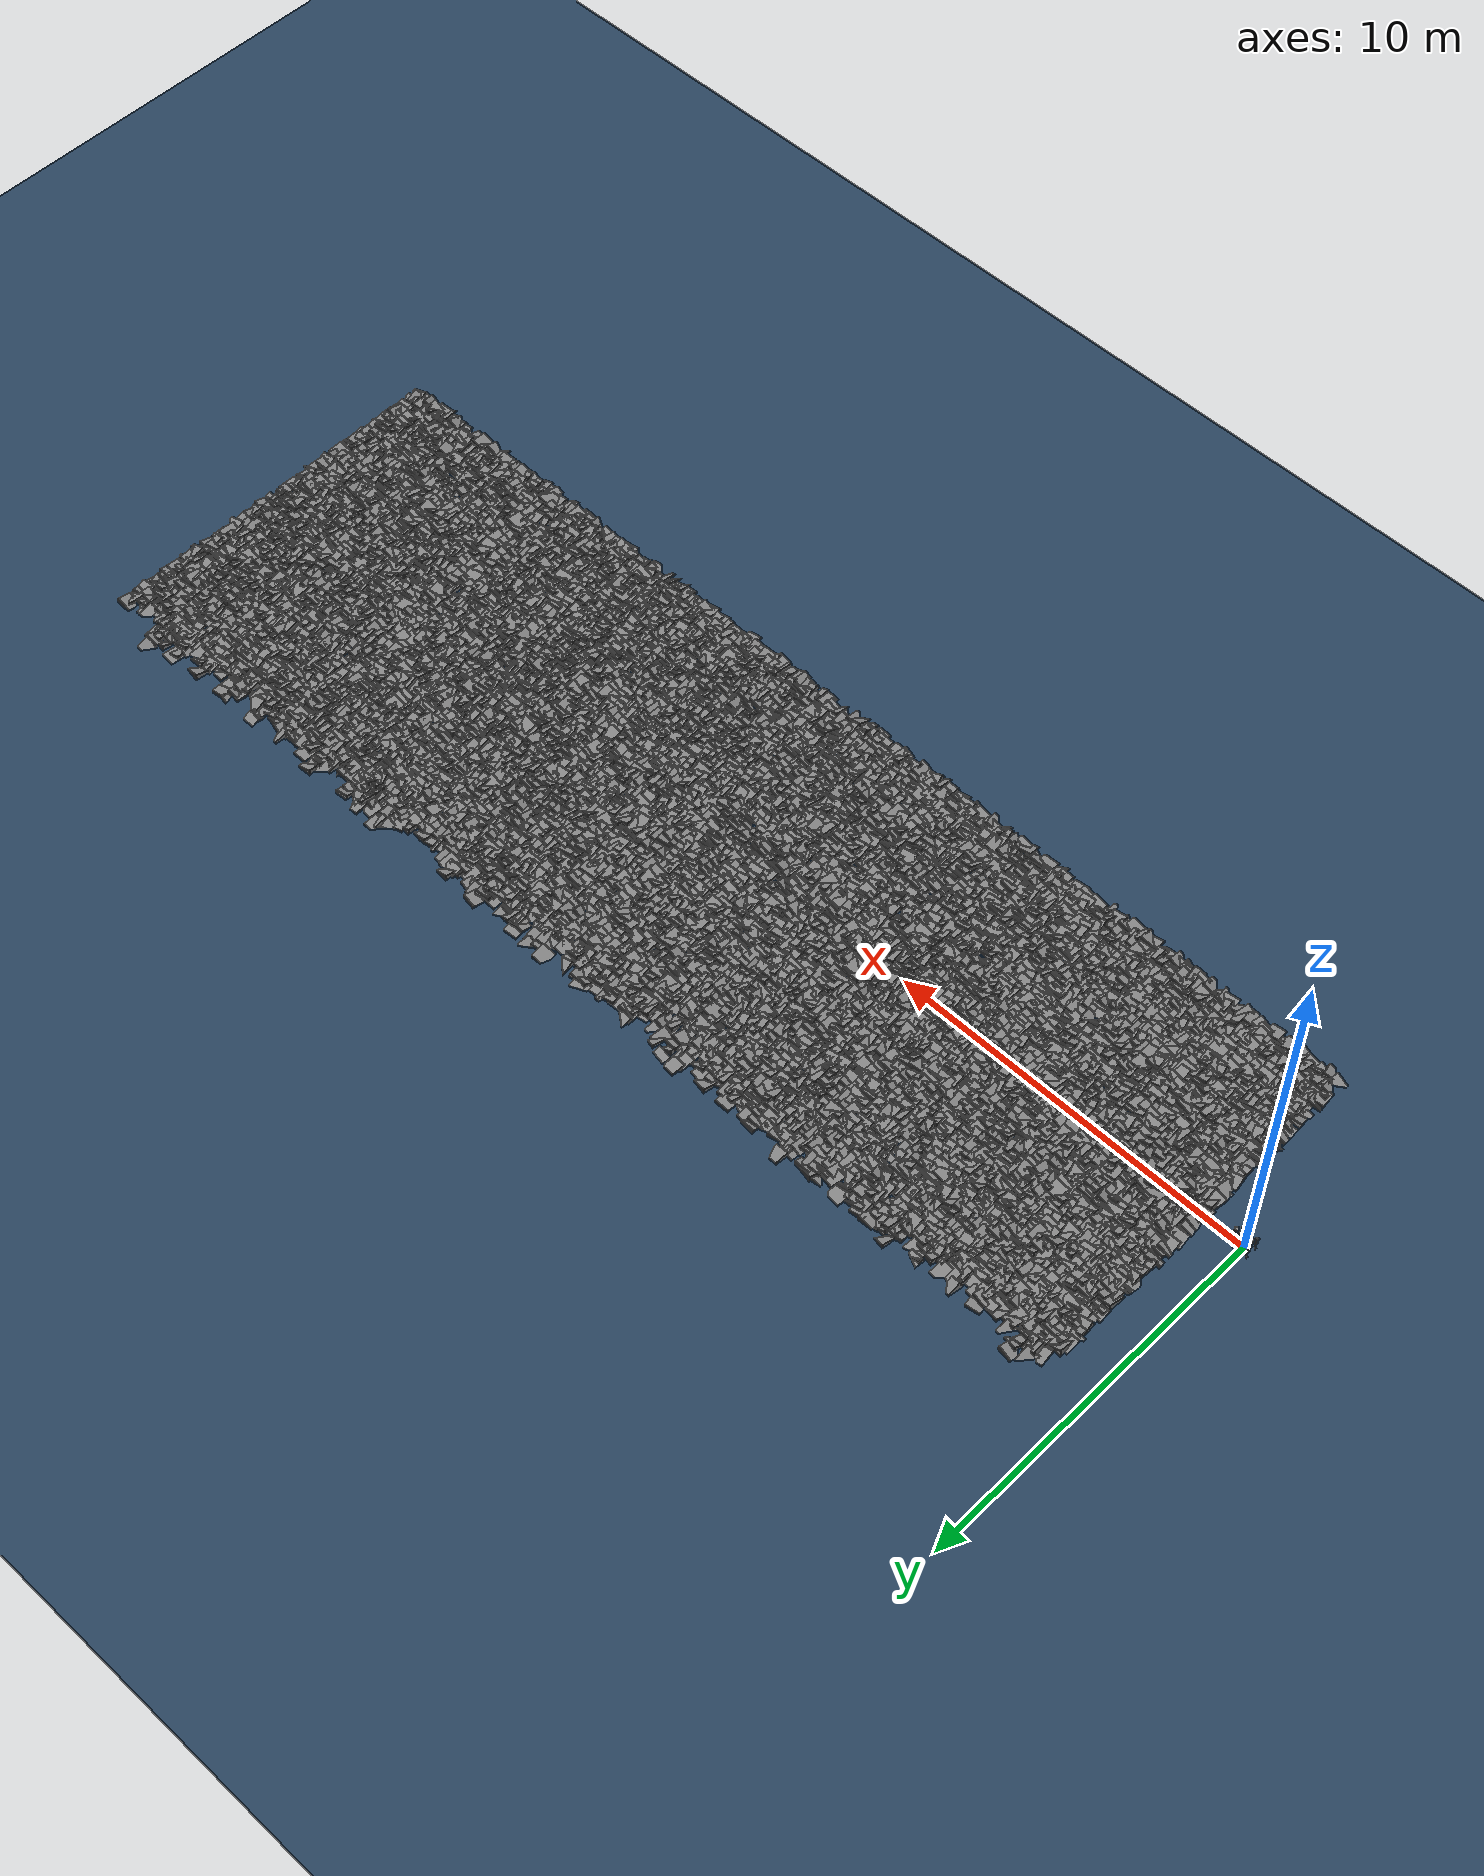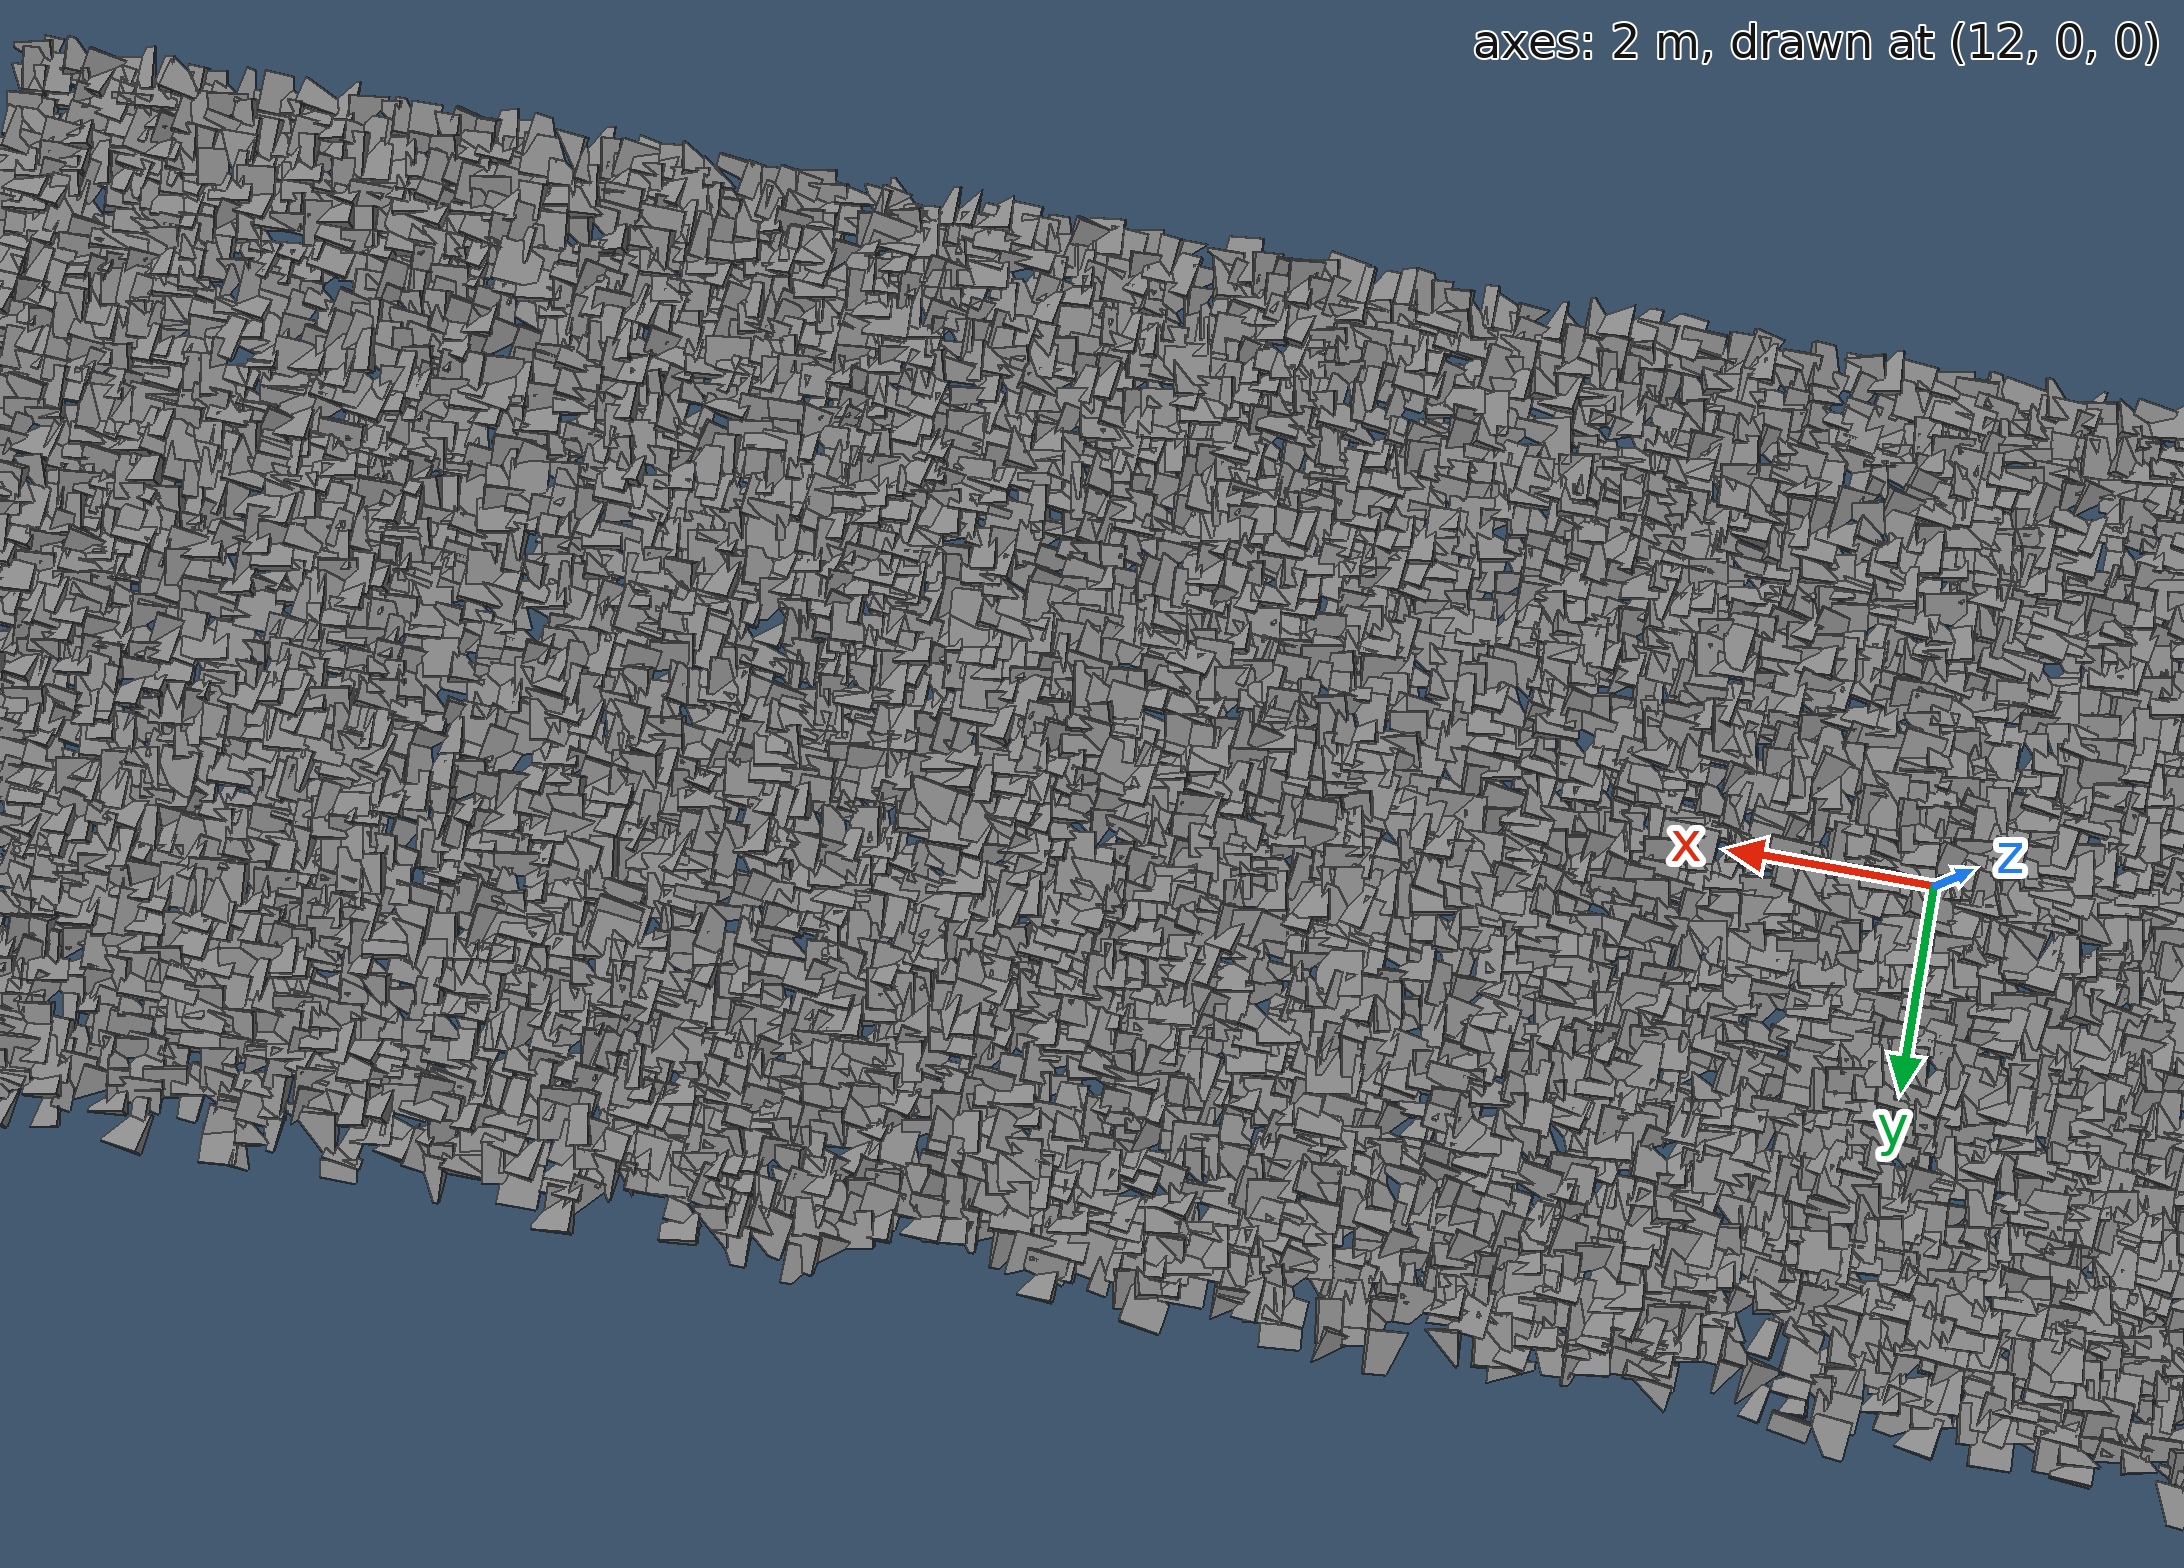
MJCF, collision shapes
<mujoco model="go2 scene">
  <include file="go2.xml" />

  <statistic center="0 0 0.1" extent="0.8" />

  <visual>
    <headlight diffuse="0.6 0.6 0.6" ambient="0.3 0.3 0.3" specular="0 0 0" />
    <rgba haze="0.15 0.25 0.35 1" />
    <global azimuth="-130" elevation="-20" />
  </visual>

  <asset>
    <texture type="skybox" builtin="gradient" rgb1="0.3 0.5 0.7" rgb2="0 0 0" width="512" height="3072" />
    <texture type="2d" name="groundplane" builtin="checker" mark="edge" rgb1="0.2 0.3 0.4" rgb2="0.1 0.2 0.3" markrgb="0.8 0.8 0.8" width="300" height="300" />
    <material name="groundplane" texture="groundplane" texuniform="true" texrepeat="5 5" reflectance="0.2" />
  </asset>

  <worldbody>
    <light pos="0 0 1.5" dir="0 0 -1" directional="true" />
    <geom name="floor" size="0 0 0.05" type="plane" material="groundplane" />
  <geom pos="1.2440769267664589 -4.782505329645702 -0.25" type="box" size="0.18830844009155875 0.22343807470096566 0.2414587193972467" quat="0.9744620282511195 -0.14868546660010987 -0.12770802581022517 -0.10957667480936242" /><geom pos="1.2440769267664589 -4.551446206073214 -0.25" type="box" size="0.2078529102929124 0.21181305843234138 0.23279810878293705" quat="0.9752751690165009 0.12908414175732966 -0.17852891118850223 0.017408529991271838" /><geom pos="1.2440769267664589 -4.372452368949265 -0.25" type="box" size="0.19273481048843144 0.20881150690976588 0.22520706612629088" quat="0.9861277939330938 0.15248279106238707 0.056819035391886034 -0.0327501096121756" /><geom pos="1.2440769267664589 -4.213658703549848 -0.25" type="box" size="0.21650521182024474 0.22055392615511826 0.2711035679090551" quat="0.9978362845664904 0.04410354207206608 -0.012073857161070414 0.047242446512577176" /><geom pos="1.2440769267664589 -4.030747450048855 -0.25" type="box" size="0.21234046612412608 0.18025158667894303 0.2595023554803044" quat="0.9773593961143996 0.11960089229299029 -0.1669396896489639 0.05094484674159426" /><geom pos="1.2440769267664589 -3.812063705336584 -0.25" type="box" size="0.18017511185558316 0.1913137301541025 0.2281197852065036" quat="0.9816023726576459 0.005874537118409455 -0.18345142335411935 -0.052610332406021365" /><geom pos="1.2440769267664589 -3.6000174165183414 -0.25" type="box" size="0.1995494104900059 0.17676598029409313 0.22702456682216413" quat="0.9974487499546839 -0.06088484036307505 -0.035907255341037336 -0.009984810547770059" /><geom pos="1.2440769267664589 -3.35552246607563 -0.25" type="box" size="0.203997240058902 0.18670023195748245 0.2740866393869347" quat="0.9799544956566898 0.19501534602329487 0.02245391110828737 0.03397091599587159" /><geom pos="1.2440769267664589 -3.1617662093354024 -0.25" type="box" size="0.204007352879875 0.20377929993886745 0.22594816396614306" quat="0.9710461743527545 0.15942398013659828 -0.17531048649663625 -0.03032416786324165" /><geom pos="1.2440769267664589 -2.9835256510702455 -0.25" type="box" size="0.20866952823822146 0.2167115974335924 0.23111744581585086" quat="0.9978326626481933 -0.04273120322623535 -0.02368704663940545 0.044078854848531815" /><geom pos="1.2440769267664589 -2.7860940164837023 -0.25" type="box" size="0.18291957969851386 0.20148531833946232 0.2674880185127344" quat="0.9794636451564874 0.1758154103053629 -0.09764505111333711 0.014330153837170992" /><geom pos="1.2440769267664589 -2.6170523534055743 -0.25" type="box" size="0.2027828091247476 0.19372684333232837 0.2486106621405919" quat="0.9835970293657832 0.12649680977834704 -0.11333705725388414 -0.060746624529573745" /><geom pos="1.2440769267664589 -2.44916081674327 -0.25" type="box" size="0.210798563367344 0.19331094200417015 0.26298384901573907" quat="0.9729365890201505 -0.14600615458524888 -0.1769865610787529 -0.027429067913076883" /><geom pos="1.2440769267664589 -2.246842788133493 -0.25" type="box" size="0.1973265561666286 0.22481821068693547 0.25427160300786333" quat="0.9853838941040629 0.1376819933660911 -0.00026339589314080224 0.10031042102222469" /><geom pos="1.2440769267664589 -2.0548453834029448 -0.25" type="box" size="0.21126445847939382 0.22062206778032262 0.2498168103165607" quat="0.9882886944939917 0.09595037458752065 -0.06714682016514004 0.09782784109642154" /><geom pos="1.2440769267664589 -1.8409318003572182 -0.25" type="box" size="0.21883192133717755 0.2161749720200499 0.22835234354351763" quat="0.9806943129106055 -0.1776410904253819 -0.0725328851820931 0.0376999759209215" /><geom pos="1.2440769267664589 -1.6708608898173916 -0.25" type="box" size="0.2110793159056532 0.20297689633400606 0.2369732200259586" quat="0.9800992016796473 -0.023604720413281412 -0.18594545501768497 -0.06536558574200461" /><geom pos="1.2440769267664589 -1.4994793051386184 -0.25" type="box" size="0.18431968714451127 0.19409663429345655 0.2612703244597362" quat="0.9938536114842217 -0.0716095094812541 0.08236679288586943 0.01851454890945144" /><geom pos="1.2440769267664589 -1.344288746472344 -0.25" type="box" size="0.18365051697109153 0.1890129824109639 0.2469011024042085" quat="0.9818700685079694 -0.12116537008699872 0.1355472190002124 -0.053638354571563095" /><geom pos="1.2440769267664589 -1.189526091370419 -0.25" type="box" size="0.2243322678679854 0.19196403158522476 0.24879914051864302" quat="0.9911186042109076 -0.07060319795054883 0.08111634684857752 0.07822556551485642" /><geom pos="1.2440769267664589 -1.0298784779436088 -0.25" type="box" size="0.21867342060388273 0.21818757470512146 0.23385311774884238" quat="0.98959022564542 -0.022251382552739063 -0.11334136830982357 0.08584751313343451" /><geom pos="1.2440769267664589 -0.8758504159682916 -0.25" type="box" size="0.20257476274135786 0.2110862788503502 0.2604328445081494" quat="0.9860820247213786 0.04871853956501243 -0.14536146370027803 -0.06433342284498325" /><geom pos="1.2440769267664589 -0.7127782580340085 -0.25" type="box" size="0.19653611892667222 0.21311170855063877 0.22627460799483026" quat="0.997292367553286 -0.04017516671761986 -0.03943324236889674 -0.04731711102179317" /><geom pos="1.2440769267664589 -0.5069108114343139 -0.25" type="box" size="0.21585864801985705 0.21427496454937014 0.27449586366934486" quat="0.9945379814805883 -0.06155799603863783 0.008082510096001926 -0.08390166593561986" /><geom pos="1.2440769267664589 -0.35312666749051846 -0.25" type="box" size="0.22011106294290733 0.1950152011391689 0.27079932248414984" quat="0.9819518970650762 0.09879689973963443 0.15531100351174312 0.04345269428136171" /><geom pos="1.2440769267664589 -0.11415238242382753 -0.25" type="box" size="0.2154641908088788 0.19350506987466531 0.26689002208133344" quat="0.9965417052145376 -0.023220774278600496 -0.02268608671822942 -0.07649030578718306" /><geom pos="1.2440769267664589 0.036399403810043474 -0.25" type="box" size="0.17672330212234422 0.20884086382552064 0.25410016444021655" quat="0.9807810831730533 0.1815498312955266 0.04482665648912772 -0.055665936751876824" /><geom pos="1.2440769267664589 0.20957077349971875 -0.25" type="box" size="0.20702555998162214 0.18554073579887506 0.2686256179658636" quat="0.9845391364224723 0.04839005301021439 -0.16520304053641868 -0.032388995348478236" /><geom pos="1.2440769267664589 0.40816009082581495 -0.25" type="box" size="0.17556816349621818 0.17628597297684184 0.2709818740266244" quat="0.986784192960693 0.04474066036038499 -0.1557407266418581 0.00023642862864549884" /><geom pos="1.2440769267664589 0.6099389177902381 -0.25" type="box" size="0.20260549046472842 0.17773235888808706 0.2283986089930486" quat="0.9705070816257926 -0.15120032513470236 -0.18700847878988303 0.01680163843323647" /><geom pos="1.2440769267664589 0.8018765118386613 -0.25" type="box" size="0.19918254671637656 0.21126955063099565 0.2729094591131105" quat="0.9927811374788515 -0.037805243312212196 -0.09304222526998805 0.06557073250399702" /><geom pos="1.2440769267664589 1.0146920032592988 -0.25" type="box" size="0.20683158362845352 0.21245315911486845 0.26619636558577864" quat="0.9883964771609823 -0.1511413488524538 0.0017616978800664672 0.015019754438733485" /><geom pos="1.2440769267664589 1.1686227258785804 -0.25" type="box" size="0.19893910495545616 0.2110796788684894 0.24005937273562253" quat="0.9804997469875316 0.1628103810765309 -0.10919761942428013 -0.013744303662653157" /><geom pos="1.2440769267664589 1.3344940802456815 -0.25" type="box" size="0.17620992327181537 0.19576374829605095 0.2521524708015773" quat="0.9776317639959232 0.19587772014369415 0.035525266227463756 -0.06786757868817754" /><geom pos="1.2440769267664589 1.5530165469816897 -0.25" type="box" size="0.21780009846076712 0.2231556765606627 0.24160886097941486" quat="0.9737210173593175 0.20101161610617915 -0.05413406525953465 0.09236456854007494" /><geom pos="1.2440769267664589 1.747244013386294 -0.25" type="box" size="0.21415818873108403 0.21451524647399386 0.22801740555755806" quat="0.9791197847553451 -0.15702415502991332 0.12901650540566187 0.004754279198694315" /><geom pos="1.2440769267664589 1.9966488064880936 -0.25" type="box" size="0.18653568376876464 0.2001842804089099 0.24656369943823944" quat="0.9890379096878149 0.09894957852247022 0.10928951030215374 0.00829439862187844" /><geom pos="1.2440769267664589 2.198697637468161 -0.25" type="box" size="0.19391920567907406 0.1968296306381318 0.26300949708566634" quat="0.9728333400020253 -0.18246218985624887 0.14248667711471016 -0.0006234566337214795" /><geom pos="1.2440769267664589 2.3862301498401646 -0.25" type="box" size="0.2067047616214048 0.20352628683703716 0.2590386467706885" quat="0.9930616412274793 0.05113265128680715 -0.07625000291488848 -0.07348445924443153" /><geom pos="1.2440769267664589 2.6227170501377346 -0.25" type="box" size="0.17886420247397938 0.20038738724581134 0.22830811817445723" quat="0.9817542503213081 -0.17279903009003425 -0.07094914046479966 0.03557114902974069" /><geom pos="1.2440769267664589 2.83547791145641 -0.25" type="box" size="0.1897725565696107 0.17573370882717299 0.2498453875122051" quat="0.9847783627940396 0.03772836737842888 0.1620774535513377 -0.05019009382301766" /><geom pos="1.2440769267664589 3.0124230640718928 -0.25" type="box" size="0.2219477568555808 0.22420516059392334 0.27344317133657886" quat="0.9844318200541273 0.11359775506062987 0.12737705614979425 -0.04200746691619905" /><geom pos="1.2440769267664589 3.2223398178218936 -0.25" type="box" size="0.17847800144229042 0.2076442482002603 0.22536030074223296" quat="0.9858100214499714 0.13731264455053693 0.056278219766945296 -0.07846401235730857" /><geom pos="1.2440769267664589 3.3945422883259546 -0.25" type="box" size="0.20889250193457778 0.17870699524100836 0.23537256621534397" quat="0.9989238486041336 -0.01890694950785136 0.03396817237919905 0.025294964230657403" /><geom pos="1.2440769267664589 3.6348998830634986 -0.25" type="box" size="0.20374479204120888 0.1815046508218719 0.23010363575774537" quat="0.9758354153787939 -0.13487228682152674 -0.1702134715220966 -0.024126384984595472" /><geom pos="1.2440769267664589 3.8237362735950455 -0.25" type="box" size="0.21103958329056408 0.18650782297032034 0.25857735164243223" quat="0.9774739200987247 -0.1525448416128903 0.13780849514531288 0.047787294230940816" /><geom pos="1.2440769267664589 4.016827614772083 -0.25" type="box" size="0.1757680878809032 0.18554540250684504 0.2592856073085709" quat="0.9868665065133588 0.11310943133356721 0.10219561859622425 0.05344913848932177" /><geom pos="1.2440769267664589 4.209267316224633 -0.25" type="box" size="0.19752072689059916 0.20556100857567863 0.23066119221860903" quat="0.9754437304348493 -0.1812596673502563 -0.12496454789806379 0.006190599005891122" /><geom pos="1.2440769267664589 4.414279831530187 -0.25" type="box" size="0.17744570322735953 0.20934203083437197 0.24698601233679587" quat="0.9990996584142829 -0.03610581736632864 -0.02202459355421383 0.003340626819026418" /><geom pos="1.2440769267664589 4.59551583657932 -0.25" type="box" size="0.1851296422205902 0.2233887806847916 0.2727678821547975" quat="0.9769517828136433 0.12234527411695069 0.17434548222113125 0.014159830068651319" /><geom pos="1.4600217761676157 -4.836298748292941 -0.25" type="box" size="0.20810819920257118 0.1838998190097474 0.2645187934327506" quat="0.9695426295894917 0.14163355778761516 -0.16979219524577363 0.10534531385276186" /><geom pos="1.4600217761676157 -4.675082222975229 -0.25" type="box" size="0.1786647736110077 0.1924296757558623 0.23755369489487144" quat="0.9938265563277954 0.039200293602208586 0.07359276844615124 0.07318618279133925" /><geom pos="1.4600217761676157 -4.475875383606245 -0.25" type="box" size="0.20364990953401974 0.21969368149667592 0.2328206823629607" quat="0.9803853060910284 0.18965591194045542 0.019279252669604778 -0.050035957903655386" /><geom pos="1.4600217761676157 -4.22631780614563 -0.25" type="box" size="0.17732350069687156 0.18647161573377863 0.263700159313515" quat="0.9711771726809563 -0.14281059049403366 -0.18741116710927203 0.03601512111475273" /><geom pos="1.4600217761676157 -4.074726352850237 -0.25" type="box" size="0.1788552029738 0.22279330554804366 0.24757123202835343" quat="0.982767279348611 -0.09994833833736888 -0.15085912155588746 -0.037687262420001026" /><geom pos="1.4600217761676157 -3.9066774714398047 -0.25" type="box" size="0.2218242493840333 0.21098927206827722 0.24287460092770147" quat="0.9946546226838764 -0.09371487496096793 0.04275247594003566 0.0072062185397167924" /><geom pos="1.4600217761676157 -3.7176322697178983 -0.25" type="box" size="0.20645802006296501 0.2180962545463725 0.24831697107873088" quat="0.9895619059270082 -0.11597261818490091 0.08226414815156173 0.023456259257263308" /><geom pos="1.4600217761676157 -3.5334746925679017 -0.25" type="box" size="0.17691625397005661 0.22074336565953245 0.2544286288512982" quat="0.9860234647758459 -0.0036719399758723733 0.14802967570677053 0.07636398940860835" /><geom pos="1.4600217761676157 -3.3770832457928757 -0.25" type="box" size="0.18367016371753134 0.2042749168308003 0.2450429051295376" quat="0.9831015240014933 -0.1535183118992602 0.06879564016434145 -0.07218504908858317" /><geom pos="1.4600217761676157 -3.1489244112368877 -0.25" type="box" size="0.19083416958045857 0.20819679066023017 0.24935398184082289" quat="0.976257597758738 -0.057259572914707416 -0.18775551612543842 -0.091598636957291" /><geom pos="1.4600217761676157 -2.9667908621383026 -0.25" type="box" size="0.17558034198182113 0.21504083550209863 0.2731278130333489" quat="0.9895553524595139 0.06646599997952964 0.11118992321367152 0.06323983112869708" /><geom pos="1.4600217761676157 -2.7275392697404826 -0.25" type="box" size="0.1917300489336014 0.18569053816031425 0.2566475892342599" quat="0.9748416844759066 -0.16744157072428842 -0.14154337897714303 -0.04015572772709668" /><geom pos="1.4600217761676157 -2.496804007108587 -0.25" type="box" size="0.19996395279512613 0.22179191858789324 0.2365280810704406" quat="0.9774940068324159 0.10634634523002795 -0.17969751780736845 0.030078622920520014" /><geom pos="1.4600217761676157 -2.3286733620429607 -0.25" type="box" size="0.2152179331793258 0.20667271516202332 0.235593409218634" quat="0.9911497088851006 -0.11831026951287796 0.033871092606885415 -0.0497763376554167" /><geom pos="1.4600217761676157 -2.100833543145134 -0.25" type="box" size="0.20965650758617874 0.20440617475783937 0.26943671672247954" quat="0.9794188414987528 -0.17282140567804827 -0.09548017691918675 0.04189308382281111" /><geom pos="1.4600217761676157 -1.901105119605572 -0.25" type="box" size="0.19117174303594725 0.18080449376519028 0.24666216985825098" quat="0.9787133411747319 0.13333326183148958 -0.15465899376522957 0.020567759807401262" /><geom pos="1.4600217761676157 -1.6817472934038316 -0.25" type="box" size="0.18717710221022651 0.17891204172963748 0.2738643988504018" quat="0.9803151646901663 -0.059405054688171824 -0.18574107455830607 -0.030878318897133505" /><geom pos="1.4600217761676157 -1.4433096608149203 -0.25" type="box" size="0.18210191713919405 0.1757524892674312 0.24522903513095637" quat="0.9811617614835813 -0.15114647850872845 0.07070448772303345 0.09735098999327178" /><geom pos="1.4600217761676157 -1.2435640259465028 -0.25" type="box" size="0.18966795975476705 0.18731996697319336 0.24222267352009744" quat="0.9967032250731099 0.045923421799223485 -0.019141863425427258 0.0640882947480636" /><geom pos="1.4600217761676157 -1.0031036102881568 -0.25" type="box" size="0.22344245496666476 0.1841455735743689 0.24140180550898055" quat="0.9844878155335312 -0.16408081473786693 -0.04665394125054762 -0.041044330506951894" /><geom pos="1.4600217761676157 -0.8511528797588532 -0.25" type="box" size="0.18959280949479426 0.2062651967941744 0.2320605344986625" quat="0.993003757848718 0.05211764669315083 0.10553121084739418 -0.009510590863630883" /><geom pos="1.4600217761676157 -0.6818636597688998 -0.25" type="box" size="0.22355015677015927 0.2195940254715973 0.2655775303940311" quat="0.9908730050174445 -0.0010263959671580683 -0.09347732436422654 -0.09711654992184936" /><geom pos="1.4600217761676157 -0.5277554857770665 -0.25" type="box" size="0.1979475312935698 0.17552404729874965 0.2582004854366851" quat="0.9849922070740327 -0.052349525953926265 0.1603644530897586 0.03651193395381402" /><geom pos="1.4600217761676157 -0.3685531904644206 -0.25" type="box" size="0.18184362066890578 0.20795201325361 0.22769520408979138" quat="0.9848101225923955 0.1355016772780704 -0.08830005551400352 0.06317767082288127" /><geom pos="1.4600217761676157 -0.15376919600756 -0.25" type="box" size="0.19804580264081825 0.20781682520226488 0.2395556754121619" quat="0.9725475179188723 0.14248524179522593 0.16310651652123934 -0.08512077025440547" /><geom pos="1.4600217761676157 0.09250378900119394 -0.25" type="box" size="0.2114086844246787 0.18893378926286536 0.2322161479831775" quat="0.9956073128719145 0.09350161812588775 0.0009418917170047902 0.004758025199594379" /><geom pos="1.4600217761676157 0.32102553739177786 -0.25" type="box" size="0.17860987143122958 0.18436143716312034 0.24804405714212302" quat="0.9807817609331485 -0.0208768081294865 0.17780187617166238 0.07757441029768795" /><geom pos="1.4600217761676157 0.47542990206038294 -0.25" type="box" size="0.1854736416775542 0.22273437191367831 0.26968319683939684" quat="0.9819792227006613 -0.03883225319639944 0.18456808331371405 -0.011978519015203595" /><geom pos="1.4600217761676157 0.6763885369922669 -0.25" type="box" size="0.2141407664466518 0.1775058835276591 0.24685285235073892" quat="0.9906619511615233 0.1004395259615456 0.07374391653298332 -0.055341078050936805" /><geom pos="1.4600217761676157 0.8503605734060891 -0.25" type="box" size="0.20128808104752097 0.21782469491926287 0.2345942966605562" quat="0.9881958552090406 0.13475846729368407 0.039202227472263415 -0.06141899218924748" /><geom pos="1.4600217761676157 1.0665138359851172 -0.25" type="box" size="0.17899649545197027 0.19233701423418395 0.2455093905648671" quat="0.9989210251647443 0.0368583485271689 0.02570967754656152 0.011715805909861435" /><geom pos="1.4600217761676157 1.2647416432292102 -0.25" type="box" size="0.20799674467804463 0.1907478849525169 0.27357952792676643" quat="0.9886540492799731 -0.017144392336970217 -0.14888541784654696 0.01011795465337715" /><geom pos="1.4600217761676157 1.5094444760912324 -0.25" type="box" size="0.17575060171268828 0.17964288302287915 0.25134804701082875" quat="0.9891474879272821 0.10484534276070108 -0.10289467655197324 -0.0027178605194770264" /><geom pos="1.4600217761676157 1.7433950417972346 -0.25" type="box" size="0.1908584770523285 0.1955680329444735 0.25363342154863744" quat="0.9953238520434117 0.03677038762137517 0.0683638566625093 0.05748696591286146" /><geom pos="1.4600217761676157 1.9407314492946153 -0.25" type="box" size="0.2003450563524334 0.1862035764703925 0.24145871436902852" quat="0.9808924681793221 -0.1677258539920071 -0.02160249615330055 -0.09618386523568463" /><geom pos="1.4600217761676157 2.0962385768584104 -0.25" type="box" size="0.2176368070393979 0.1902743342633909 0.23625375335880106" quat="0.9855952800882363 0.00879630166571191 -0.1608993703590426 -0.05134161628601697" /><geom pos="1.4600217761676157 2.2729365868989957 -0.25" type="box" size="0.20594055951521212 0.18133718283480818 0.26977685143539937" quat="0.9810833265014445 0.14912439412051798 -0.08025167038698389 0.09379280856839337" /><geom pos="1.4600217761676157 2.484381439720295 -0.25" type="box" size="0.21826522881337435 0.20700925256803251 0.27372483168548567" quat="0.980645379331363 -0.17731209809459958 0.06481056193171104 -0.05191002723399584" /><geom pos="1.4600217761676157 2.7342534450080285 -0.25" type="box" size="0.22328484424672698 0.17805368565617302 0.26063940260616425" quat="0.9918434778545987 0.1039725277142705 -0.05613330790306933 -0.04780460921144349" /><geom pos="1.4600217761676157 2.981290116672514 -0.25" type="box" size="0.18725110603404352 0.17984342454848667 0.27460492479734466" quat="0.9868790357119285 0.11705428908356981 0.07644901298217127 -0.08076887205777954" /><geom pos="1.4600217761676157 3.2236870691799844 -0.25" type="box" size="0.18489096318337944 0.21227880610108035 0.22886666447104193" quat="0.9973864462072916 0.027638823612551412 0.060174873646589355 0.028902541980256144" /><geom pos="1.4600217761676157 3.4044896787199406 -0.25" type="box" size="0.20773105175203482 0.19994587836904443 0.24467636266511428" quat="0.9936752011800525 0.05926836436589253 0.0037569816818991968 0.09530341354755335" /><geom pos="1.4600217761676157 3.627085141185022 -0.25" type="box" size="0.21969541574151713 0.21964698740916053 0.26277570489644764" quat="0.977478102964977 -0.18533284384987422 0.09387693425535398 -0.037086607142258074" /><geom pos="1.4600217761676157 3.8560562835321903 -0.25" type="box" size="0.19917465777922982 0.22177356432683942 0.2442885529492147" quat="0.9852623328178258 0.09952991736265661 -0.0969797536201589 0.0997339383957732" /><geom pos="1.4600217761676157 4.038095795135316 -0.25" type="box" size="0.20000615122400994 0.21042554405693778 0.22947547403319854" quat="0.9914271004665599 -0.06631864177779663 -0.07143649585904577 0.08701131692256224" /><geom pos="1.4600217761676157 4.215641340947972 -0.25" type="box" size="0.19654132387379641 0.17816041694225426 0.2458388915512984" quat="0.9774251136474092 -0.1404156669159088 0.13582631661029848 0.08046613829424477" /><geom pos="1.4600217761676157 4.427080280069967 -0.25" type="box" size="0.2183296190724259 0.18540309829369095 0.2625921579557329" quat="0.9911650011022 0.0946843823210192 0.06391439422342694 -0.06739257040368157" /><geom pos="1.4600217761676157 4.622121482070533 -0.25" type="box" size="0.1763052246537635 0.20689659137791588 0.26035711294623304" quat="0.9799609457128131 -0.1830606925552358 -0.023376859989171377 0.0749589896936518" /><geom pos="1.4600217761676157 4.776314647332583 -0.25" type="box" size="0.20313094297428164 0.1896528470276815 0.2324250163774341" quat="0.9918218372381393 -0.07658733091036853 0.07967461440346685 -0.06384183378668382" /><geom pos="1.4600217761676157 5.013853750486083 -0.25" type="box" size="0.2209542002686757 0.21804383536701424 0.2298080609448473" quat="0.9948644866342976 -0.048956433584606385 0.07150433715159212 0.05229771135587671" /><geom pos="1.6476782146798299 -4.767012590320291 -0.25" type="box" size="0.19250616082675703 0.21088423113539004 0.23344923019201744" quat="0.9873620638295255 -0.106685323891926 -0.0822461216961342 -0.08348635842052039" /><geom pos="1.6476782146798299 -4.529825257635718 -0.25" type="box" size="0.22496997990613174 0.20898371444919592 0.26121798366766996" quat="0.9892518398396931 0.1331220016819219 0.04691555696721687 -0.03818717790615937" /><geom pos="1.6476782146798299 -4.321576546781249 -0.25" type="box" size="0.20100014447792275 0.21678069911862977 0.23576904423112316" quat="0.9761088673997304 -0.13889859156518236 -0.1651219572267466 -0.02556168003932042" /><geom pos="1.6476782146798299 -4.114358936946279 -0.25" type="box" size="0.20386063977050548 0.22022612807292768 0.24679382936757502" quat="0.9703492859864727 0.13934856005165971 -0.17932758788644776 0.08273970159421445" /><geom pos="1.6476782146798299 -3.94576167236135 -0.25" type="box" size="0.1860364742534915 0.20642382089122643 0.26402050657179604" quat="0.9876290046390237 -0.03951068935596393 -0.121427296648255 0.09101245107700713" /><geom pos="1.6476782146798299 -3.7509207243238416 -0.25" type="box" size="0.2084671451966951 0.17915588647816388 0.24148585550638535" quat="0.9887242126600578 -0.11838966131987357 -0.0874969331670167 0.027433666883608168" /><geom pos="1.6476782146798299 -3.5044310558189222 -0.25" type="box" size="0.22193524650759588 0.21320402736564203 0.23842772336255647" quat="0.9806174631434362 -0.13040741553602384 -0.14599537907902815 -0.008285302584528927" /><geom pos="1.6476782146798299 -3.2820232241979976 -0.25" type="box" size="0.19760217479458586 0.22348255510299958 0.2366556666082392" quat="0.9820709792735651 -0.13322291538758865 -0.1183019334593619 0.06158651657683618" /><geom pos="1.6476782146798299 -3.119004764844716 -0.25" type="box" size="0.1805445753090804 0.22269784249650004 0.22971306452243123" quat="0.9792218204761116 -0.18611912394686578 -0.06743934200785014 0.044002649400338045" /><geom pos="1.6476782146798299 -2.936382381901455 -0.25" type="box" size="0.1870278788584858 0.18897420614712915 0.22607806860949528" quat="0.9926811716813189 -0.1069144297192663 -0.0555088634736129 0.008494832727966854" /><geom pos="1.6476782146798299 -2.701933626147495 -0.25" type="box" size="0.18007595814469293 0.22082949254781847 0.2538043443892352" quat="0.99317454052457 -0.11333823226642807 0.023115343809645535 -0.014981923811462012" /><geom pos="1.6476782146798299 -2.49051292554118 -0.25" type="box" size="0.2160981914145698 0.22350522985786647 0.26917024525194216" quat="0.9782449721539046 -0.14357461295908977 0.11214366327275041 0.09923156633361219" /><geom pos="1.6476782146798299 -2.270876230603128 -0.25" type="box" size="0.21529378765772217 0.21323574588787578 0.2404542032943169" quat="0.9909735946706681 0.11956845951811247 -0.05734468853841862 0.01965463941138868" /><geom pos="1.6476782146798299 -2.0490752259320044 -0.25" type="box" size="0.20451365217605463 0.19769457271747806 0.2365542191472653" quat="0.9951558507801704 -0.05786021807768836 0.009000419913171985 0.07896847639016526" /><geom pos="1.6476782146798299 -1.8065508215558514 -0.25" type="box" size="0.21428701309436596 0.19153759210360358 0.23014319664603883" quat="0.9922821895673672 0.008832790213302669 -0.12127583281083654 -0.02429424747707333" /><geom pos="1.6476782146798299 -1.6544316046653602 -0.25" type="box" size="0.19678151113291412 0.2029331536467749 0.2411862165355066" quat="0.9805485411512105 0.07186995644441399 -0.14991794689070073 0.10432582138180388" /><geom pos="1.6476782146798299 -1.4127035642298003 -0.25" type="box" size="0.17818032668122905 0.1975616878466265 0.22571676927137477" quat="0.9797725226687961 0.1811980490215032 -0.05270083318650519 0.06660099875732013" /><geom pos="1.6476782146798299 -1.2243787838027447 -0.25" type="box" size="0.21500626587719013 0.21574233104799417 0.2425787599218399" quat="0.9822093783826088 -0.1528574946699428 0.061888166480619844 0.08982860452074731" /><geom pos="1.6476782146798299 -1.0506230752625054 -0.25" type="box" size="0.21844804964454267 0.21564971989749085 0.23010821245473176" quat="0.992778569451198 0.0046832856030435 -0.10921737095401336 -0.04939984571115971" /><geom pos="1.6476782146798299 -0.8812131175026083 -0.25" type="box" size="0.20253059589549466 0.22319458169241302 0.2596664705739592" quat="0.9954482536837477 -0.02740507819036124 0.07260547981806012 -0.055318895756752834" /><geom pos="1.6476782146798299 -0.6431224678360374 -0.25" type="box" size="0.20291647648936098 0.21838236026953783 0.23104622300337294" quat="0.9691759118330812 -0.17961335431599693 -0.14420874529599328 -0.08741242848718375" /><geom pos="1.6476782146798299 -0.42207313381182754 -0.25" type="box" size="0.1913219273828059 0.20158543522810837 0.27415544603798864" quat="0.9948004279798603 -0.0009077539150808608 0.09309584228345288 -0.04128496849279074" /><geom pos="1.6476782146798299 -0.252282497367605 -0.25" type="box" size="0.21425937438462217 0.1854492189958548 0.26060637173559076" quat="0.9600873580986026 0.1809960457828729 0.1747264211605206 -0.122243093787118" /><geom pos="1.6476782146798299 -0.07736759432634077 -0.25" type="box" size="0.17921676701262979 0.20845412707001848 0.26437200549721" quat="0.9884349683234749 0.14459827190437421 0.04055257564249524 -0.021050932672917893" /><geom pos="1.6476782146798299 0.16505500459698386 -0.25" type="box" size="0.19772197600132008 0.175636540140164 0.2617339624840483" quat="0.9871929952332751 0.0025234500138227953 -0.126404992969458 0.09729028787486463" /><geom pos="1.6476782146798299 0.3356820865421053 -0.25" type="box" size="0.19089574012431332 0.18703182862937867 0.2285588061983237" quat="0.9718376016327419 -0.12886247295397976 0.17817854851817247 0.08472628851107535" /><geom pos="1.6476782146798299 0.5679863749426772 -0.25" type="box" size="0.1778871396066748 0.17737465265950977 0.2634232599013715" quat="0.978124100902955 0.13449416091602467 -0.15027042237590765 -0.051023171904994585" /><geom pos="1.6476782146798299 0.767213043027045 -0.25" type="box" size="0.19660616868313172 0.1966642483728577 0.26781612156612256" quat="0.9783430948168661 0.08768733756790106 -0.18012051388405592 -0.05207993982862372" /><geom pos="1.6476782146798299 0.9968442186052204 -0.25" type="box" size="0.2156847122886633 0.19426563636829516 0.23604516529480438" quat="0.9745534829292892 0.1281185761817615 -0.1775715877646634 0.047952795187417206" /><geom pos="1.6476782146798299 1.196488316944789 -0.25" type="box" size="0.22001059443351753 0.21257419111207254 0.2489346243360118" quat="0.9730516037993979 -0.12202005966028541 -0.19562145911640869 -0.0037317713069378033" /><geom pos="1.6476782146798299 1.378948113224789 -0.25" type="box" size="0.1933386473922985 0.19834843174997294 0.24616830352948768" quat="0.9817980917132859 -0.16117467554174966 0.09560784249674185 -0.030892904125058743" /><geom pos="1.6476782146798299 1.6007578226235015 -0.25" type="box" size="0.17792586503043026 0.2016793492074841 0.24544084309133365" quat="0.9871677096528917 -0.04035276218927571 0.13244236617439073 -0.07956498755412758" /><geom pos="1.6476782146798299 1.8184140366060344 -0.25" type="box" size="0.22350197190819354 0.2020602880140371 0.25353092915648157" quat="0.9888542900502377 0.06347857555211864 0.1181803324541561 0.06458384098316972" /><geom pos="1.6476782146798299 2.0482689469917075 -0.25" type="box" size="0.2106806091153469 0.20394786899795467 0.26391706413855587" quat="0.9810450213590273 -0.1417649580409691 0.11465478869144764 0.0656326303634665" /><geom pos="1.6476782146798299 2.2073312423366858 -0.25" type="box" size="0.2231583843568053 0.18514275169525923 0.265139087343048" quat="0.9845410191363935 -0.16331794184955162 -0.04764408779844414 -0.04166860215740785" /><geom pos="1.6476782146798299 2.4250123767054923 -0.25" type="box" size="0.21384243716558185 0.2181647993127307 0.23661119901690628" quat="0.9945601311324842 0.018045574880929182 0.09709190025504402 0.033131038224252445" /><geom pos="1.6476782146798299 2.6579598635024215 -0.25" type="box" size="0.17880478160410468 0.17882226106050236 0.2640185695755504" quat="0.9985898530072341 0.008036945947751407 0.039083229312745514 -0.035017340808677244" /><geom pos="1.6476782146798299 2.87221893252266 -0.25" type="box" size="0.19586851869661173 0.18741471355711195 0.26215807303525557" quat="0.9920496824523799 0.09750974551309186 -0.07688532152999655 -0.020443199586495958" /><geom pos="1.6476782146798299 3.116472792600815 -0.25" type="box" size="0.2056308413009934 0.1849856205102681 0.2603420633935525" quat="0.9738611496957064 -0.12879896187769635 0.18416807677133426 -0.03297587043479437" /><geom pos="1.6476782146798299 3.284691018581279 -0.25" type="box" size="0.21142814353048683 0.20754395753725757 0.2495318700575155" quat="0.9875811936200944 -0.019982814415018556 0.13930723975419607 -0.06983957393936074" /><geom pos="1.6476782146798299 3.441552091692758 -0.25" type="box" size="0.22245367436289634 0.18584125996930112 0.23775431848900672" quat="0.980929818472841 -0.18406820635724447 0.0498726918714613 0.03752733996382475" /><geom pos="1.6476782146798299 3.6293460080005087 -0.25" type="box" size="0.19007474115384787 0.17626972702720853 0.239559202694858" quat="0.9778617605086604 0.19189026036792203 0.08339534223194253 0.0031180450367986473" /><geom pos="1.6476782146798299 3.849750290763591 -0.25" type="box" size="0.2184113967717348 0.21765554115541333 0.23944188271549022" quat="0.9800728026438532 0.18822457941873422 0.06046815221351369 0.01929797368499421" /><geom pos="1.6476782146798299 4.0112267218609094 -0.25" type="box" size="0.21698766880576364 0.18435799904855135 0.23656176393981346" quat="0.9902258024906024 0.09374221632984714 0.07392088854915026 -0.0721176760268568" /><geom pos="1.6476782146798299 4.177514512930108 -0.25" type="box" size="0.21678385258955352 0.18488045839237147 0.24422329674739782" quat="0.9978619722023256 0.033996258645573756 0.05310137544462254 -0.017204149397091775" /><geom pos="1.6476782146798299 4.423522103942787 -0.25" type="box" size="0.209389067076844 0.18308761636473184 0.2695782008128459" quat="0.9814428357824287 0.1725589364946038 0.018369282394239052 -0.0815839628328802" /><geom pos="1.6476782146798299 4.614747564958156 -0.25" type="box" size="0.2135681044229266 0.20530695589080306 0.2447208635331604" quat="0.9903051222641283 -0.04166765264681091 0.12773741199041425 -0.03525230656745364" /><geom pos="1.6476782146798299 4.815388394329132 -0.25" type="box" size="0.22382707075060343 0.2073972501822327 0.24032257621908737" quat="0.9903529416894515 0.04385804865855762 -0.10721681035302744 -0.07603997654284395" /><geom pos="1.6476782146798299 5.020629701052556 -0.25" type="box" size="0.2129119242862624 0.17907194221251407 0.2723182701469557" quat="0.9790252062479121 0.03501745540366288 0.1944355791536727 0.04978181301902762" /><geom pos="1.6476782146798299 5.216039684227901 -0.25" type="box" size="0.22300636692069348 0.2178473905013648 0.24913494983261314" quat="0.9649442843003935 -0.16970853590335305 -0.19977262737163487 0.013131579896406412" /><geom pos="1.821828933323724 -4.797641264364144 -0.25" type="box" size="0.21613831252626572 0.21887538164888581 0.2322913509956012" quat="0.9874819531897403 0.1476265612922454 0.018120747678482936 0.052511227648717594" /><geom pos="1.821828933323724 -4.6363168754196575 -0.25" type="box" size="0.208802219868086 0.18594308431040332 0.24540806300261792" quat="0.9970005769126874 -0.027790082906478237 -0.04408214275302406 -0.05722172330611598" /><geom pos="1.821828933323724 -4.423624974645245 -0.25" type="box" size="0.1943624872073965 0.19503613725514424 0.23803506416049583" quat="0.9921536022381361 -0.00622829291172255 0.08243536876005174 0.09379151299926146" /><geom pos="1.821828933323724 -4.231429512771252 -0.25" type="box" size="0.20731713076575622 0.19070889070987151 0.25567398324144863" quat="0.9822876253601763 -0.1442347817147527 -0.05282591149912111 -0.10731622376067074" /><geom pos="1.821828933323724 -4.070549405817994 -0.25" type="box" size="0.18974078054815235 0.19404754936166993 0.24647150280769145" quat="0.9661706837211791 0.18397527046888446 -0.1781575774374072 0.03044975164569179" /><geom pos="1.821828933323724 -3.9178119003502614 -0.25" type="box" size="0.2098590112090408 0.2036658267351877 0.2620077711367194" quat="0.9889749294120384 0.046503288724762094 -0.14058280452836544 0.0015837307771408692" /><geom pos="1.821828933323724 -3.690554829721183 -0.25" type="box" size="0.17830946479486015 0.20236797786466684 0.24853306076128173" quat="0.974861204207835 -0.11133453014251357 -0.16596405108614667 -0.09851999124782018" /><geom pos="1.821828933323724 -3.5231548911231694 -0.25" type="box" size="0.19855332435378725 0.20048887379508173 0.27431219100235504" quat="0.9892210968755635 0.020590906818339264 -0.13120921851827544 -0.06165855194965966" /><geom pos="1.821828933323724 -3.351676339064489 -0.25" type="box" size="0.19721511278085924 0.20842398785098706 0.2332716786594289" quat="0.984294577998332 0.10397879577611525 0.10326906340376943 -0.09842811740424065" /><geom pos="1.821828933323724 -3.155727813372658 -0.25" type="box" size="0.19606373090206794 0.1777292407107623 0.24182841979598263" quat="0.9913094775520076 0.090454216834985 0.037245376816734545 0.08795644534719901" /><geom pos="1.821828933323724 -2.9542733779936805 -0.25" type="box" size="0.20307240580040664 0.2186624367801045 0.24821607409630464" quat="0.9900010911875033 -0.058362934342530315 -0.10255112117156454 -0.07729731488827485" /><geom pos="1.821828933323724 -2.7251837314251843 -0.25" type="box" size="0.20823316829350813 0.18885473294862248 0.25737835750808113" quat="0.992236635068999 -0.0504273420791704 0.10382905921394497 0.046293300384911217" /><geom pos="1.821828933323724 -2.485789158777231 -0.25" type="box" size="0.19665474816980205 0.209187476359158 0.27034569388449486" quat="0.977780920316469 -0.05819128307337735 -0.19216471802603477 0.060257510613429294" /><geom pos="1.821828933323724 -2.2462034465646905 -0.25" type="box" size="0.17639310564758567 0.18530130085843852 0.24823967001020864" quat="0.9697784087331817 -0.17791053017653885 0.16455820601867815 0.028253814594757055" /><geom pos="1.821828933323724 -2.036476311930529 -0.25" type="box" size="0.20447145806327352 0.1988210314548711 0.26952758397193477" quat="0.9774955657182213 -0.19574675364111968 0.01598344106424162 0.07700751295765507" /><geom pos="1.821828933323724 -1.8650113288521082 -0.25" type="box" size="0.21723449658778468 0.21237607757238214 0.25343552576854" quat="0.9912569557631637 0.04014509613797929 0.12332306200876553 0.02427841189204647" /><geom pos="1.821828933323724 -1.711127662302907 -0.25" type="box" size="0.2159643233969779 0.20589458642154992 0.25937232962765727" quat="0.9983760623596875 0.04565995207946803 -0.02820573834660148 -0.019100869288833887" /><geom pos="1.821828933323724 -1.4611903488240845 -0.25" type="box" size="0.1909537309963992 0.1981605938806681 0.2714784041809456" quat="0.9943473086022048 -0.0400144893858337 -0.0001572163980372342 -0.09834757647114192" /><geom pos="1.821828933323724 -1.2809164391661234 -0.25" type="box" size="0.18979634645103657 0.1752265652651182 0.24824136297301" quat="0.9758232861963414 -0.14357592605431752 -0.16467967743330833 0.005955788367602077" /><geom pos="1.821828933323724 -1.0618248808580817 -0.25" type="box" size="0.22194887623492182 0.20314504335581146 0.27288467246117065" quat="0.9955925569676424 -0.018231814651329524 -0.0906990334664784 0.015386577702604702" /><geom pos="1.821828933323724 -0.8854332208570952 -0.25" type="box" size="0.2014374447089079 0.19928436017037812 0.2490952521619117" quat="0.9779161348341773 -0.1874477289871982 -0.0009433407503173889 0.09242560379436847" /><geom pos="1.821828933323724 -0.6642316765100214 -0.25" type="box" size="0.18916716669209385 0.17945234122223824 0.2591056165017249" quat="0.9802668664868655 -0.1867000437672487 -0.02112586027403327 0.06143014042806491" /><geom pos="1.821828933323724 -0.44778518604136774 -0.25" type="box" size="0.19010270551834393 0.19427383620499886 0.2653424265193262" quat="0.9805516389791754 0.16829268402476727 -0.1002062961442352 0.01244001656135069" /><geom pos="1.821828933323724 -0.24951750753639867 -0.25" type="box" size="0.1772840410030883 0.21738362192616895 0.24491036259271984" quat="0.9642731676048166 0.18409704952572506 0.18716074487025663 -0.035445594548644294" /><geom pos="1.821828933323724 -0.04765350351201114 -0.25" type="box" size="0.1842644444558767 0.17732508708622308 0.2353007912826834" quat="0.9910054795079716 0.10817406026446391 -0.06662696419995982 0.042039979930688164" /><geom pos="1.821828933323724 0.12020303920208075 -0.25" type="box" size="0.21441909355465502 0.2190428390592975 0.23103718483200072" quat="0.9833021061085145 -0.008999465303971811 -0.1557338938898708 -0.09371729851367111" /><geom pos="1.821828933323724 0.34851313254531924 -0.25" type="box" size="0.21904990442479647 0.20560139358385757 0.23531283864614533" quat="0.9760595916867553 -0.15275567529838907 0.13722852304665195 0.0717057152732756" /><geom pos="1.821828933323724 0.5621919072051575 -0.25" type="box" size="0.1827925738146993 0.19818043487511972 0.23674133134580375" quat="0.9924963735358351 -0.053945170227413214 0.0947132131572293 0.055410056675526564" /><geom pos="1.821828933323724 0.7238535122549443 -0.25" type="box" size="0.2063306188978373 0.1912310065004604 0.2318896300791507" quat="0.9663011916297995 -0.20219773283300896 -0.12563611834431146 -0.0979471779041877" /><geom pos="1.821828933323724 0.9076291406289236 -0.25" type="box" size="0.19456342563277176 0.20527796276745436 0.23130685505392556" quat="0.9942904125394066 0.09277500082800581 0.05000225136424224 -0.016707771008939946" /><geom pos="1.821828933323724 1.1295629326662562 -0.25" type="box" size="0.17893818845576798 0.20036757733856686 0.2371150491824503" quat="0.9907651212503533 0.04541441208347491 0.07719475846007169 -0.10179869819981117" /><geom pos="1.821828933323724 1.3037865403937694 -0.25" type="box" size="0.20059229027587774 0.2115328026785902 0.26390394669694445" quat="0.9736066771863534 0.1138257501317462 0.19306227571789947 -0.04313576752207767" /><geom pos="1.821828933323724 1.4757120730214845 -0.25" type="box" size="0.19763856487353906 0.22477317833721722 0.2718599275633961" quat="0.9823093304349454 -0.18701680861821587 -0.0049244219249034386 0.008297150318788965" /><geom pos="1.821828933323724 1.6552110117110752 -0.25" type="box" size="0.19229710411740722 0.18134262983837732 0.2537055423855586" quat="0.9899384152720047 0.07323310897923037 0.11671502297574327 -0.032193930014210836" /><geom pos="1.821828933323724 1.8647389633520195 -0.25" type="box" size="0.2129843200763615 0.18262326638887547 0.26172053833241254" quat="0.9975891629696828 0.014279266876336683 -0.06739314149052697 -0.008374302535730153" /><geom pos="1.821828933323724 2.0527585882468093 -0.25" type="box" size="0.21459396262020974 0.22048232061857598 0.25242807219651464" quat="0.9790040178583829 0.16776926752088217 -0.09191150724354014 0.07040511862691962" /><geom pos="1.821828933323724 2.2386130062157736 -0.25" type="box" size="0.17797496832619497 0.22103788643565125 0.2512923532354366" quat="0.9923181038153265 0.08749594549146818 0.04380408320879224 -0.07569968729886914" /><geom pos="1.821828933323724 2.4397394078656935 -0.25" type="box" size="0.18702342965437935 0.21035530645215078 0.25570989008409895" quat="0.9789888030429615 0.11190196784618069 -0.1553044770802834 -0.07028081180152818" /><geom pos="1.821828933323724 2.650764365252984 -0.25" type="box" size="0.22486495780986002 0.17513923381674462 0.2255088599895761" quat="0.9925688437466796 0.04414990863621659 -0.10472355412134222 0.043483941897986905" /><geom pos="1.821828933323724 2.8293423463013356 -0.25" type="box" size="0.17546079008515192 0.20905775970509904 0.22692674968627216" quat="0.9909859420076731 -0.03143099288262532 0.08819363636543776 0.09581668922592729" /><geom pos="1.821828933323724 3.0180774806715416 -0.25" type="box" size="0.21866341946818785 0.18729260894696143 0.267276647026083" quat="0.9833446658675776 -0.0783966604702152 0.13902644953672677 0.0869418085049528" /><geom pos="1.821828933323724 3.2275493875794172 -0.25" type="box" size="0.22006203686172524 0.19757639552868184 0.2692019428154143" quat="0.9783235971661253 0.18700298203278592 -0.08517016739201401 0.02566839545423279" /><geom pos="1.821828933323724 3.4504645602668482 -0.25" type="box" size="0.22364889277100242 0.17635707467344697 0.22628764639516552" quat="0.9900413069860602 -0.024768478445366407 0.11244331248780641 -0.08100144698463425" /><geom pos="1.821828933323724 3.6608262360699726 -0.25" type="box" size="0.1993848055523108 0.20971928564317643 0.252217805731477" quat="0.9874066593698637 -0.1261908366897697 0.012621699744190073 -0.09457618338222896" /><geom pos="1.821828933323724 3.9012528999650105 -0.25" type="box" size="0.22434940341122994 0.22438161103113782 0.22942970479188624" quat="0.9661537993730593 0.1836958753485097 0.15692731635787258 -0.09042388355773781" /><geom pos="1.821828933323724 4.135794121241876 -0.25" type="box" size="0.1914642197890615 0.1766637229717286 0.25799396541976716" quat="0.9828153975290851 -0.03181982352587246 -0.17280373611916486 -0.056570858167316045" /><geom pos="1.821828933323724 4.334011070838445 -0.25" type="box" size="0.1761012242436759 0.21931786830421612 0.25637609765299274" quat="0.9917095473491941 -0.05551068726145183 0.08020292412088863 -0.08365541380375242" /><geom pos="1.821828933323724 4.521878614098004 -0.25" type="box" size="0.1907043239804246 0.1817124611640436 0.2623041920505692" quat="0.9919392735972129 0.11703728611217504 0.021773076893674317 0.04341295057367973" /><geom pos="1.821828933323724 4.699037250039895 -0.25" type="box" size="0.2169130739682889 0.22180661545812036 0.25598623081734645" quat="0.9739659828994167 -0.12231114500067632 -0.19081837118698858 0.004312444891416935" /><geom pos="1.821828933323724 4.894209811740662 -0.25" type="box" size="0.20191995319181577 0.19868230736819684 0.2618295693361479" quat="0.9756876309731796 -0.18064117009595673 0.12368327154434307 0.010240252555321733" /><geom pos="2.004528034638117 -4.811213166106313 -0.25" type="box" size="0.21838332580305184 0.21089144059151743 0.24515735404758116" quat="0.9851158169223756 -0.1557616393262028 0.008426419855336343 -0.07220896351697768" /><geom pos="2.004528034638117 -4.624304960527734 -0.25" type="box" size="0.18673696630846523 0.2022147092865134 0.26221964894227806" quat="0.9874074717969936 0.008651004737404063 0.13031509739056552 -0.0892727290307068" /><geom pos="2.004528034638117 -4.46816816738807 -0.25" type="box" size="0.21554365366695613 0.19989412556893388 0.25622815458187387" quat="0.994471693399609 0.07269455092591333 -0.06478775129858637 0.039295045161779396" /><geom pos="2.004528034638117 -4.226811056979108 -0.25" type="box" size="0.1949879218042123 0.17618709170406086 0.2607648337708754" quat="0.9743303238885712 -0.12637647406220182 -0.1803938296280367 -0.04655612727588025" /><geom pos="2.004528034638117 -4.0332857123391435 -0.25" type="box" size="0.21410555891475477 0.19336743152093527 0.26272717219387265" quat="0.9826275188447656 -0.17941286103898896 0.04436804366055464 -0.016901514858712746" /><geom pos="2.004528034638117 -3.8734329417865796 -0.25" type="box" size="0.21147947450878027 0.1835291087824457 0.2629933175746744" quat="0.9864216111112992 -0.00300169894928993 0.13655111452868912 0.09119861872297957" /><geom pos="2.004528034638117 -3.646488300045495 -0.25" type="box" size="0.2243088252332593 0.21767658269250056 0.25996886751788106" quat="0.9813077753994475 0.056154304359346936 0.16257780200815683 -0.08631455460524443" /><geom pos="2.004528034638117 -3.494064658395508 -0.25" type="box" size="0.19388017979713845 0.21593915236321626 0.2653076984196583" quat="0.9837283271710092 0.09485041572969206 -0.15246504212050221 -0.00603223743115793" /><geom pos="2.004528034638117 -3.2861032266082195 -0.25" type="box" size="0.19510497325117493 0.21272953199341435 0.2575660513468003" quat="0.9772819087098892 -0.17543258199235448 -0.11003588851372412 0.045117439231929055" /><geom pos="2.004528034638117 -3.077767087740461 -0.25" type="box" size="0.19158678182131444 0.20661140082195534 0.2521978507540102" quat="0.9906657466470691 0.10993647932610481 -0.04466066084102075 0.06708781041910236" /><geom pos="2.004528034638117 -2.842566852417791 -0.25" type="box" size="0.18185482001379158 0.19494791396292124 0.23877604257164253" quat="0.98914541640583 -0.1298484665909914 -0.0027218825692755955 -0.0687263579901075" /><geom pos="2.004528034638117 -2.6280957302786585 -0.25" type="box" size="0.17990110812163476 0.20709808747330108 0.23851014657931494" quat="0.9927856736298108 0.04963918972361944 -0.06113991859767601 -0.09041276144911572" /><geom pos="2.004528034638117 -2.4184977027812122 -0.25" type="box" size="0.21664646892860404 0.18949508177396968 0.2253809854970616" quat="0.9989650043470413 -0.020988038144363088 0.037941814924269186 -0.013741944004356446" /><geom pos="2.004528034638117 -2.188848680107857 -0.25" type="box" size="0.18531616235067752 0.19159093017958373 0.2269089029383974" quat="0.9741984572167178 0.17504567037254937 -0.0858228926786763 0.11371372095158999" /><geom pos="2.004528034638117 -1.944350892696693 -0.25" type="box" size="0.1967291307765535 0.1976353431459586 0.2471178121924504" quat="0.9668502154860343 0.17368546947864638 0.1416806987800256 -0.12231352378128466" /><geom pos="2.004528034638117 -1.7222532483744741 -0.25" type="box" size="0.20299551055224238 0.2197895282540225 0.26766127849749594" quat="0.979260926572105 0.12688757306940532 -0.15790500435535873 -0.003686609449487236" /><geom pos="2.004528034638117 -1.5348825426234702 -0.25" type="box" size="0.20861568693697155 0.17729229967044147 0.2672854393126361" quat="0.9816032455353987 0.1391101744670585 -0.13051773252193138 0.008279445117281186" /><geom pos="2.004528034638117 -1.3124335004083991 -0.25" type="box" size="0.20453880013529377 0.22295903904018632 0.2341104867651855" quat="0.990554285129169 -0.0009310427251532248 -0.12246910547851848 -0.061665708258125514" /><geom pos="2.004528034638117 -1.0948311740721315 -0.25" type="box" size="0.21374821080987164 0.18389484701284756 0.2724275756458995" quat="0.9786067059353889 -0.08759211873901337 -0.1783476440259644 0.05337278054857035" /><geom pos="2.004528034638117 -0.9102690049318296 -0.25" type="box" size="0.20906697088311724 0.2180486373375622 0.25014398749755246" quat="0.9723961239791599 -0.19428456425640744 -0.1172787471106952 -0.05426768502663426" /><geom pos="2.004528034638117 -0.6764587699375735 -0.25" type="box" size="0.1778240110494141 0.18028589173096954 0.26521118765373375" quat="0.9792325394034229 0.17789474448060458 0.09248857894530274 0.030049233341013427" /><geom pos="2.004528034638117 -0.44793912382471746 -0.25" type="box" size="0.20769740871780346 0.2143875677408131 0.24984728064894052" quat="0.9936350444628896 0.0619790464854956 -0.07177474583342049 0.060797878848922786" /><geom pos="2.004528034638117 -0.21285435109345308 -0.25" type="box" size="0.18136214835106826 0.2216497295363879 0.2661075906694234" quat="0.9904025268629608 -0.12262094822471585 -0.01443782841135108 -0.06211672037944481" /><geom pos="2.004528034638117 0.028970698643355774 -0.25" type="box" size="0.2246766325723144 0.21597327103439143 0.24631123157175236" quat="0.9694685421785039 -0.1798150439644075 -0.12218639805565769 -0.11343623680530414" /><geom pos="2.004528034638117 0.2307437403477035 -0.25" type="box" size="0.2233687203200958 0.20335479373786755 0.2268954719538641" quat="0.983486633494566 0.04179368482561653 0.16708254684972546 0.05559453376395453" /><geom pos="2.004528034638117 0.4256302221730941 -0.25" type="box" size="0.1976291759765568 0.19932049997913817 0.2617162187667459" quat="0.9929523168853683 -0.0766377644797796 0.08311264051178005 0.03556175522497311" /><geom pos="2.004528034638117 0.6499791448444707 -0.25" type="box" size="0.1990612312423591 0.18775004562619943 0.2597075710500083" quat="0.9787640031834289 0.17833500202170804 0.0938931239907442 -0.03743974350238974" /><geom pos="2.004528034638117 0.8904089881359019 -0.25" type="box" size="0.22178623216061308 0.178884029889483 0.24807960848231717" quat="0.980997411071387 0.14303421868433586 -0.12876467170580394 -0.02459575323291348" /><geom pos="2.004528034638117 1.1237885476406184 -0.25" type="box" size="0.20805983924809207 0.2115113987254459 0.2410025726439554" quat="0.9926593403349535 -0.10767067808524954 -0.005672924421598098 0.05479303838029571" /><geom pos="2.004528034638117 1.3255820983646425 -0.25" type="box" size="0.19660370988119166 0.22452509964344328 0.22621967929773595" quat="0.9972803255932118 0.06867049844500109 -0.011595584512253343 -0.024121717348314014" /><geom pos="2.004528034638117 1.556446121577289 -0.25" type="box" size="0.21530732869941205 0.21573091601889624 0.26102706180347884" quat="0.9934663995229067 -0.11098286345617568 -0.01615400318404951 -0.021127357127429268" /><geom pos="2.004528034638117 1.776746014260289 -0.25" type="box" size="0.1835205524606781 0.18994258982843704 0.2721892481869259" quat="0.9833482764443726 0.06121930167397832 0.15672575612104786 0.06866878246130403" /><geom pos="2.004528034638117 2.00412438592784 -0.25" type="box" size="0.2133321719349842 0.2054698151126428 0.24491940627375886" quat="0.9796994232999287 -0.1765985937732276 0.0007747122850565481 -0.09487558423525559" /><geom pos="2.004528034638117 2.1635218633747124 -0.25" type="box" size="0.18341256079102997 0.19043235131178016 0.2290700164721782" quat="0.9655940352217959 -0.1701793020633756 -0.18628626003549503 0.06296501898117407" /><geom pos="2.004528034638117 2.368524148816789 -0.25" type="box" size="0.1968293221804229 0.2133688132694041 0.2278266380329147" quat="0.986921631840041 -0.07205989656351232 0.14324699335546012 0.016533687068147073" /><geom pos="2.004528034638117 2.5739796911695443 -0.25" type="box" size="0.21947098462465586 0.21346604767422356 0.2372607601996356" quat="0.9913734549787997 -0.05206761711757928 0.1167373304056101 0.02898330037912194" /><geom pos="2.004528034638117 2.8186360544220506 -0.25" type="box" size="0.2107620504042226 0.17625746735341455 0.22505111179917173" quat="0.9962719395434089 0.010937848155867791 0.05729456516318021 -0.06356035524519815" /><geom pos="2.004528034638117 3.0529442162715306 -0.25" type="box" size="0.22153077518211145 0.18380575304484403 0.25871588392331113" quat="0.9721491679409845 0.1541672654375967 0.16075746007391128 -0.07290739722229837" /><geom pos="2.004528034638117 3.248103469844157 -0.25" type="box" size="0.1757474076268275 0.21761137953588391 0.2628059063154187" quat="0.9852111147821491 0.09319735138642317 0.13770479740371291 0.041360630752844726" /><geom pos="2.004528034638117 3.4462566701517865 -0.25" type="box" size="0.22383888193788223 0.21945140212153091 0.24267663038898182" quat="0.9970661289239442 -0.03959162319580911 0.06550281713775126 0.0010093920745788438" /><geom pos="2.004528034638117 3.6599329508420695 -0.25" type="box" size="0.19132595927675325 0.215756396344419 0.2430866275603018" quat="0.9935681627491644 -0.04376664495040698 -0.10300091887119431 0.01725101367238842" /><geom pos="2.004528034638117 3.879892683538179 -0.25" type="box" size="0.20916358043552719 0.18738807024075696 0.24338193558747154" quat="0.9757788316563171 -0.18752192933188921 0.10361711506977393 -0.04421188952867742" /><geom pos="2.004528034638117 4.037384419912236 -0.25" type="box" size="0.19625051318361092 0.18697156788389102 0.27254747210309926" quat="0.9848588523601766 -0.09220866139430577 -0.14370942691501276 0.029970056847205922" /><geom pos="2.004528034638117 4.2694731701767825 -0.25" type="box" size="0.21143069599009331 0.2223546996093644 0.2633869091847148" quat="0.9776451224195395 0.0768539283116457 0.19021750263961323 0.04605203580625856" /><geom pos="2.004528034638117 4.4302899628716155 -0.25" type="box" size="0.19817237839002902 0.20282412824550808 0.25199047078904724" quat="0.9667451064119198 0.17743840058097868 0.17472411306573155 -0.05823227233470792" /><geom pos="2.004528034638117 4.656482704173197 -0.25" type="box" size="0.2131382532044237 0.18484070016478374 0.2679836947447957" quat="0.9895588750213288 -0.003758185853375828 -0.12104468663743691 -0.07814916981298334" /><geom pos="2.004528034638117 4.821830475004848 -0.25" type="box" size="0.20241491880555262 0.19922846923379497 0.22730973786037464" quat="0.9789835844059577 0.14353410923480855 0.11648933549570363 -0.08613556562537046" /><geom pos="2.004528034638117 4.983308777683751 -0.25" type="box" size="0.20849681749696208 0.2234981585009839 0.2282781388264906" quat="0.9860600148593945 0.06780384878073967 0.15155873908495218 -0.010873536360750025" /><geom pos="2.004528034638117 5.177081144680853 -0.25" type="box" size="0.18869131219132007 0.21077397463730752 0.2402758488718482" quat="0.9803011526159336 0.12915896587035935 0.10916360640334276 -0.1020339098152534" /><geom pos="2.004528034638117 5.409532476493236 -0.25" type="box" size="0.20463403058223933 0.2234015956812641 0.25129636550981943" quat="0.9887351296077317 0.09631554655004455 -0.077796517095859 -0.08410624768768259" /><geom pos="2.227648674086256 -4.843123711499462 -0.25" type="box" size="0.20557526749765861 0.20069354945251977 0.26316761637448727" quat="0.9756202687289998 -0.1277998877559381 -0.15863697084640868 -0.08164919727345654" /><geom pos="2.227648674086256 -4.683415825129008 -0.25" type="box" size="0.1827935912326353 0.20140755741877506 0.2640105019157547" quat="0.9879085667680372 0.038768067506048054 0.12481613644738643 -0.08339444064514467" /><geom pos="2.227648674086256 -4.478544006567939 -0.25" type="box" size="0.19700846187800183 0.22238074277205885 0.26260820874440666" quat="0.9957160460086409 -0.061546007670593636 0.06442524611447087 0.024719068020836052" /><geom pos="2.227648674086256 -4.247128781388528 -0.25" type="box" size="0.20392028806181262 0.18319058560900375 0.26127392288863516" quat="0.9809658814181754 0.11939561932268583 0.1456121652280055 -0.04741015627085409" /><geom pos="2.227648674086256 -4.047019562541189 -0.25" type="box" size="0.2229197990046097 0.17605883782574114 0.257616442100616" quat="0.9847658465373503 -0.13304503934579678 0.07177936157664755 0.08592420061135425" /><geom pos="2.227648674086256 -3.8040214151254133 -0.25" type="box" size="0.22356060370637848 0.2093797933336065 0.22529104708455305" quat="0.9699966861591346 -0.15334655060499924 0.18492016450389695 0.03736036693740154" /><geom pos="2.227648674086256 -3.620238829303355 -0.25" type="box" size="0.21206589868107525 0.2140815075998572 0.24808220335188477" quat="0.9981658207863765 0.0029990177806471377 0.01295133179503304 -0.059061519714158184" /><geom pos="2.227648674086256 -3.416125982593935 -0.25" type="box" size="0.19257673330657937 0.21619274194374055 0.26367849673786453" quat="0.9867416743578428 0.06406507198598795 0.11254747447483485 -0.09782433555229256" /><geom pos="2.227648674086256 -3.2293881193090774 -0.25" type="box" size="0.2223918028274399 0.19400669169854068 0.24765047534783063" quat="0.9899583343431573 -0.05960489646372425 0.11132877748640041 -0.06352681233506119" /><geom pos="2.227648674086256 -3.069137933975868 -0.25" type="box" size="0.17521570381091967 0.20390575710333872 0.2676094338245766" quat="0.9848373822753691 0.03539384459612694 0.14895256639430293 0.08158271386914114" /><geom pos="2.227648674086256 -2.8868957938002917 -0.25" type="box" size="0.19335981009854566 0.22073292093648095 0.25198834316344987" quat="0.997514027171767 -0.028460987121735875 0.03946524867658234 0.0509728550751794" /><geom pos="2.227648674086256 -2.6470873665258816 -0.25" type="box" size="0.18032232167876025 0.20858003074108838 0.23683653613765293" quat="0.9967242312178155 -0.04357192074446305 0.058338305822715826 0.03519853263458792" /><geom pos="2.227648674086256 -2.401648004621614 -0.25" type="box" size="0.21118097070955982 0.18328336088154415 0.2531655511511981" quat="0.9714739648048398 -0.13843742491973576 -0.16682625534495343 -0.09613748288538429" /><geom pos="2.227648674086256 -2.2457897994789704 -0.25" type="box" size="0.2007605678619727 0.19012743965475326 0.24244944626381465" quat="0.9916437015503371 -0.061756478714066455 0.08045898362305734 0.07971987497939202" /><geom pos="2.227648674086256 -2.0620673548219446 -0.25" type="box" size="0.2067769836287532 0.1943343069753711 0.24461926645068668" quat="0.9969667771706846 0.04079345392252055 -0.01871345406954518 0.06358416447321556" /><geom pos="2.227648674086256 -1.902383223940122 -0.25" type="box" size="0.20748861061813337 0.2208251223648566 0.27117375183828796" quat="0.9842845450899452 -0.10499300805335013 -0.14092629029289355 0.01732579756524799" /><geom pos="2.227648674086256 -1.7099383006770643 -0.25" type="box" size="0.18272262299855396 0.18076933414826757 0.2533681826771126" quat="0.9686058595235687 -0.13955471817499712 -0.20017539879820234 0.04750767567126929" /><geom pos="2.227648674086256 -1.5361286808081864 -0.25" type="box" size="0.17593015745507748 0.2167827565438522 0.234224664913787" quat="0.9940409368674253 0.018353186558415616 -0.09649482420657975 -0.04727076555572731" /><geom pos="2.227648674086256 -1.2906461025899176 -0.25" type="box" size="0.19258683592729928 0.22393451789517632 0.2409814430918807" quat="0.971403581429469 -0.14918853947914507 0.17379284937054282 0.06256122746356768" /><geom pos="2.227648674086256 -1.1386458271484687 -0.25" type="box" size="0.2030941642738768 0.22148762079002987 0.2614318829334692" quat="0.9722958964773549 -0.17291326093685588 -0.157283313971786 0.0019112905410195724" /><geom pos="2.227648674086256 -0.9449911384774223 -0.25" type="box" size="0.20394709503223518 0.18272357029840156 0.26800934847174923" quat="0.9916460300407248 0.05019247695034914 0.08084596678194243 -0.08707925135846895" /><geom pos="2.227648674086256 -0.6982359286316342 -0.25" type="box" size="0.21752699511771126 0.18887119528163027 0.2383006097094681" quat="0.9935405166827167 -0.09739662642184474 -0.05812343049976232 0.003578505054228862" /><geom pos="2.227648674086256 -0.4971268395423394 -0.25" type="box" size="0.22315149383940794 0.1940764454562123 0.25498597618249813" quat="0.9774867955774847 -0.1609342648268691 0.12506937088971212 -0.054565367602054896" /><geom pos="2.227648674086256 -0.33887482437569716 -0.25" type="box" size="0.19538819902531468 0.1890740197326205 0.24472640575858376" quat="0.9815384280288162 -0.09543497435071549 0.1291980549174067 0.10383805939518198" /><geom pos="2.227648674086256 -0.1593878196445404 -0.25" type="box" size="0.20598770973843755 0.19541991444063944 0.2599634650818298" quat="0.9754303323409536 -0.17583795393089438 -0.12483570939044177 -0.04508576679617141" /><geom pos="2.227648674086256 0.052159130089656 -0.25" type="box" size="0.22144721317531132 0.21431299275365875 0.25489917026180536" quat="0.9901364394966651 -0.1057392370906306 -0.07699674939030011 -0.05020503464480098" /><geom pos="2.227648674086256 0.2690057790660072 -0.25" type="box" size="0.20903035329873482 0.22066471657190675 0.2698812111229202" quat="0.9932100808302657 0.09010988756266841 0.04271118620756153 -0.059914089105345014" /><geom pos="2.227648674086256 0.4362114420155736 -0.25" type="box" size="0.18428916398152084 0.2201961684573418 0.23577243554715438" quat="0.9923491941564675 0.12261427519859669 -0.0048862924646436824 0.013599283822407656" /><geom pos="2.227648674086256 0.5973926184596872 -0.25" type="box" size="0.204710351895294 0.20343545032945415 0.26991048060102535" quat="0.9836021011907928 -0.03756390431995463 0.16220096132988435 0.06933042455488148" /><geom pos="2.227648674086256 0.8204273067715366 -0.25" type="box" size="0.21524146136410524 0.1790104072758772 0.2495291244243635" quat="0.9817922616550816 -0.07604314880042502 0.17403420087013702 0.0036730644166168905" /><geom pos="2.227648674086256 1.004616855970549 -0.25" type="box" size="0.2019835156635887 0.22276899656864935 0.26710333145309656" quat="0.9850639433259333 0.13418639021294634 0.10432915351749406 0.02754029714989919" /><geom pos="2.227648674086256 1.161484717355509 -0.25" type="box" size="0.1981133358304088 0.20368435890394174 0.2690416019322345" quat="0.9867234821322551 0.07893327293879591 0.11316329050764047 0.0856760054709023" /><geom pos="2.227648674086256 1.3671593123027987 -0.25" type="box" size="0.21624567524459828 0.2228606461166083 0.2549723124342662" quat="0.9907453631602592 -0.0072131249191765435 0.10017106271503758 -0.09130911454989821" /><geom pos="2.227648674086256 1.5702629473645668 -0.25" type="box" size="0.21622339564531157 0.1956519369342539 0.270791903721745" quat="0.9813969079048215 0.09126360186573347 0.16833740537523245 0.01391337776685167" /><geom pos="2.227648674086256 1.7574032586629231 -0.25" type="box" size="0.21437719413168413 0.1759049392333568 0.23554818603690222" quat="0.9852566177274771 -0.00784480354313972 -0.16447007397703475 -0.0464483696976582" /><geom pos="2.227648674086256 1.930830632581297 -0.25" type="box" size="0.18904319950982015 0.22426312775261248 0.24170231160057662" quat="0.9677369419035139 0.1520956317390022 -0.19084226661012552 0.06270055307777268" /><geom pos="2.227648674086256 2.159281114470346 -0.25" type="box" size="0.22066948940674716 0.19471251527921676 0.24450007306556593" quat="0.9728245348699724 -0.19286869508377466 -0.077845261298673 -0.10175561952563068" /><geom pos="2.227648674086256 2.343244693739181 -0.25" type="box" size="0.2188069805119595 0.2143226968580202 0.23619378796781237" quat="0.9758332806139157 -0.08099728859457148 0.19540647405443273 -0.05481931761910944" /><geom pos="2.227648674086256 2.566933148472218 -0.25" type="box" size="0.22425348897260125 0.17799554724523867 0.26216739524855026" quat="0.9922488373275314 -0.05703425366480694 -0.08398192640184075 0.0716685061159795" /><geom pos="2.227648674086256 2.7849485117239254 -0.25" type="box" size="0.19775036534583668 0.20850466039445997 0.2314346466708706" quat="0.9818306475220042 0.1648728167026876 -0.04501845324679142 0.08245527737088841" /><geom pos="2.227648674086256 2.9709917398873262 -0.25" type="box" size="0.188479212931957 0.20725222393834264 0.2746163055227696" quat="0.9984025651804532 0.04807626219555147 0.012092267648861045 0.027106602839601077" /><geom pos="2.227648674086256 3.174247730540584 -0.25" type="box" size="0.17501420994584801 0.20979182373573205 0.26513463493666284" quat="0.993234259691513 0.0408960075265032 0.05831506885190539 0.09172008879325004" /><geom pos="2.227648674086256 3.3809488741004543 -0.25" type="box" size="0.20336958054991852 0.19585961355407808 0.2578896949354587" quat="0.9745162513585208 0.11961927383827375 -0.18811193990507152 -0.02496403872956088" /><geom pos="2.227648674086256 3.5947995229286516 -0.25" type="box" size="0.18019937758691437 0.188039496558423 0.2737575706109441" quat="0.9912749408765961 -0.04408921671847396 -0.07983008946967947 -0.09516979234250413" /><geom pos="2.227648674086256 3.748584031551383 -0.25" type="box" size="0.21295749599431762 0.2046467669010734 0.2315100037140229" quat="0.9766377737331297 0.09798521360292062 0.17911532744537864 -0.06704667260141041" /><geom pos="2.227648674086256 3.984707651075034 -0.25" type="box" size="0.2125156618251125 0.18098968552761396 0.25569640466912724" quat="0.9898880880953134 -0.11754726706246173 -0.0529404552070663 0.05917365339084629" /><geom pos="2.227648674086256 4.146072874597834 -0.25" type="box" size="0.210506225217535 0.20285871755566587 0.2630847870839313" quat="0.9787494941393119 0.166101037057251 0.1195381001219155 -0.01305817099709923" /><geom pos="2.227648674086256 4.3342548743374145 -0.25" type="box" size="0.18588800716237522 0.1811211109340463 0.25363866608273" quat="0.9777254528688806 -0.14656334013314665 -0.14454392925631862 0.040977782474192904" /><geom pos="2.227648674086256 4.48750231510091 -0.25" type="box" size="0.21319816821608403 0.19974681011950984 0.24935723959678022" quat="0.9763551251633403 -0.09046745440879238 0.17293467045455196 0.09295111088549132" /><geom pos="2.227648674086256 4.702893343211436 -0.25" type="box" size="0.17509664485336654 0.20933401332188084 0.23405220116692385" quat="0.9920343433897434 -0.07735300186237733 0.02769454437865469 -0.09548500850823928" /><geom pos="2.4085669570400077 -4.773962447183487 -0.25" type="box" size="0.18110261484987214 0.19078231127875506 0.23085501670374323" quat="0.9962261119298679 0.006630284593352832 -0.04343514494188829 -0.0748529319344716" /><geom pos="2.4085669570400077 -4.58314676148331 -0.25" type="box" size="0.22258586845156314 0.21078749345497877 0.2259012551760818" quat="0.9872454129846936 -0.12299850258369213 -0.10108292953518978 -0.0003228922958506929" /><geom pos="2.4085669570400077 -4.373008088571942 -0.25" type="box" size="0.1959395256582936 0.17532863168113372 0.2709057632729822" quat="0.9807254835670973 -0.032995081020482035 -0.17354664017125554 0.0834890064367986" /><geom pos="2.4085669570400077 -4.210320214086689 -0.25" type="box" size="0.18864641935171872 0.2028234114656254 0.2430101760260212" quat="0.9645094242382944 0.16611088096355578 0.20215113259843237 0.03554807125845745" /><geom pos="2.4085669570400077 -3.995112613442673 -0.25" type="box" size="0.17931160976473717 0.19083823239208403 0.25635413858495637" quat="0.9849892769934854 -0.13226598774666024 0.11076660107835502 0.005709008565403448" /><geom pos="2.4085669570400077 -3.8111495503631097 -0.25" type="box" size="0.21116351319896964 0.21456106805649258 0.2730251623713916" quat="0.9852273768690221 -0.14669166159245875 0.0775765752875752 -0.042313676910433466" /><geom pos="2.4085669570400077 -3.6013590364983097 -0.25" type="box" size="0.20796302728973137 0.21146513238627485 0.22910893709003793" quat="0.9879681234270585 -0.12793002823792002 0.033177026136770454 -0.08032546236269907" /><geom pos="2.4085669570400077 -3.3723390168273326 -0.25" type="box" size="0.17511969018691823 0.17945655572101743 0.24275389590791818" quat="0.9795706651724563 -0.12448431177714779 0.15716228361796003 -0.015651985910714566" /><geom pos="2.4085669570400077 -3.13275136761448 -0.25" type="box" size="0.18857911765603583 0.20519520442835543 0.2326892554808691" quat="0.9775797592698251 0.015559016972796887 0.1902320867678967 0.0889240373617962" /><geom pos="2.4085669570400077 -2.9614406180223747 -0.25" type="box" size="0.17559287873859172 0.177758974525763 0.22725698237773595" quat="0.9985406712465285 -0.02500560632278098 0.038883201761184864 0.027916735836432782" /><geom pos="2.4085669570400077 -2.7501666661597874 -0.25" type="box" size="0.18196730909901895 0.18706238757489246 0.2658130575658922" quat="0.9789778588752827 0.18777019354607383 -0.027640786693131074 0.07470403709721335" /><geom pos="2.4085669570400077 -2.5730121173026435 -0.25" type="box" size="0.1750328258178941 0.21433577293077538 0.26165630011704816" quat="0.9911320212473907 0.11411165491762773 -0.06705427327628793 -0.011814021559609925" /><geom pos="2.4085669570400077 -2.378589248904313 -0.25" type="box" size="0.1774665717649334 0.17799889611968028 0.22671871179941278" quat="0.9771760544156899 -0.18714529184108145 0.1004928183833914 -0.0021890344136091915" /><geom pos="2.4085669570400077 -2.2179569673099246 -0.25" type="box" size="0.20605720266856684 0.22373546720096446 0.2575415654772536" quat="0.9929158629912412 0.09187549080573017 -0.020279592774602964 0.07256529009423986" /><geom pos="2.4085669570400077 -1.9905572061823777 -0.25" type="box" size="0.18093709085482543 0.2243285809381832 0.23022000347819027" quat="0.9701588033657341 0.17226575855272458 0.17057618318516113 0.004491148205455039" /><geom pos="2.4085669570400077 -1.7679347931708467 -0.25" type="box" size="0.18622470065192936 0.18346277752338086 0.2676933242131678" quat="0.9996706991151287 0.00488034130744869 -0.02435524919378854 -0.006441850363139211" /><geom pos="2.4085669570400077 -1.52616513024308 -0.25" type="box" size="0.21050524887054958 0.19529853958610363 0.24897838599586888" quat="0.9838049293756668 -0.15672960457996338 0.04570427459019 0.0739919675946775" /><geom pos="2.4085669570400077 -1.3600933153613965 -0.25" type="box" size="0.19578620538518612 0.20055460905027986 0.23137611867704616" quat="0.9791702690122777 0.15973982174982576 0.11220889471507976 0.055838495472007754" /><geom pos="2.4085669570400077 -1.1511327872855173 -0.25" type="box" size="0.18326644361016342 0.21440884893596757 0.23406572351781985" quat="0.9802865571281061 0.15144434717011682 -0.08854768800909743 0.09089654873748024" /><geom pos="2.4085669570400077 -0.9605536389630229 -0.25" type="box" size="0.215645810329133 0.19406594898547902 0.24265485671726245" quat="0.995454360607931 -0.0731345600301671 -0.04965737021996017 -0.03544146806619443" /><geom pos="2.4085669570400077 -0.7166360808289935 -0.25" type="box" size="0.17860935501385625 0.18273618917255616 0.2658776258429094" quat="0.9806154586471083 -0.093161287695666 -0.1712004308564972 -0.02011738580821292" /><geom pos="2.4085669570400077 -0.5656036778475126 -0.25" type="box" size="0.18431126489756303 0.1751463034436877 0.25360506779420106" quat="0.9864320699693316 -0.06534152641908961 0.14521607901968464 -0.03993177500927891" /><geom pos="2.4085669570400077 -0.31895830673056036 -0.25" type="box" size="0.20872762913667844 0.21791662562513914 0.26651496946513314" quat="0.9875622553685391 0.01972621743508099 0.14467443702683205 0.0583178822324493" /><geom pos="2.4085669570400077 -0.143915181922031 -0.25" type="box" size="0.19232561509940652 0.17547396760994036 0.27044899227658753" quat="0.9698702471240574 -0.18262835564841867 -0.15570932584143243 -0.041871151198417694" /><geom pos="2.4085669570400077 0.0421666734597137 -0.25" type="box" size="0.2138589054319839 0.20958800654818846 0.27162512002378386" quat="0.9905737477451291 0.12356033273808208 0.0426230899717859 0.04098495642404478" /><geom pos="2.4085669570400077 0.20180132669482642 -0.25" type="box" size="0.17662316587147336 0.20992221993006108 0.23502209929688905" quat="0.9910606993179769 0.0675455998779357 0.06512144897188835 -0.0948444995152285" /><geom pos="2.4085669570400077 0.40355508946764385 -0.25" type="box" size="0.1786070452970433 0.18435537020487966 0.2589908565130264" quat="0.9871089308652595 0.13897409049547133 0.014537163647616159 -0.07804378034208247" /><geom pos="2.4085669570400077 0.5974680423869208 -0.25" type="box" size="0.18641033632095358 0.1926344644723939 0.23044308425034554" quat="0.9868736381949849 -0.08210919819766987 -0.13668369641554975 -0.025613842767368375" /><geom pos="2.4085669570400077 0.8254105075774758 -0.25" type="box" size="0.17659882693018514 0.1793843032826618 0.27053776987147116" quat="0.960517248151481 -0.19437354980199187 -0.17401150444726354 -0.09667230969041082" /><geom pos="2.4085669570400077 1.0729069594679785 -0.25" type="box" size="0.21714232808611142 0.19561249560505853 0.2667065011466747" quat="0.9947614758836557 -0.013758684599557099 0.04529261776469956 0.09060288887161261" /><geom pos="2.4085669570400077 1.2971857554337367 -0.25" type="box" size="0.18486252094108416 0.19604929459357393 0.24355361194486136" quat="0.9812275200188204 0.10589793893703105 -0.15553636346587496 0.042268429429248466" /><geom pos="2.4085669570400077 1.4988769548964047 -0.25" type="box" size="0.2027719442635732 0.19785607144520218 0.24586955949174102" quat="0.9942279982294093 0.07714435985253168 -0.07325653908928695 0.013889375808317606" /><geom pos="2.4085669570400077 1.6720930834184138 -0.25" type="box" size="0.2050590699156441 0.18444699656917393 0.25340384954742634" quat="0.9576602788781193 -0.20792825380234375 -0.1576403767406366 -0.1216640585828915" /><geom pos="2.4085669570400077 1.8269503112488916 -0.25" type="box" size="0.21381456302132432 0.20966962190757338 0.27007636586070105" quat="0.9903071509992737 -0.06417988717817966 -0.10109384154326284 -0.07037559210069598" /><geom pos="2.4085669570400077 1.9847416137839726 -0.25" type="box" size="0.217391685141882 0.20016917880777557 0.23096085446628153" quat="0.9979675272940457 -0.059495744809436577 0.022440306824692467 -0.004183711963320972" /><geom pos="2.4085669570400077 2.2335139822684287 -0.25" type="box" size="0.20056116856640652 0.21949069420957815 0.2483129358333845" quat="0.9949228079032683 -0.07065627403420202 0.05512962438255134 -0.045793250255022865" /><geom pos="2.4085669570400077 2.462548809527661 -0.25" type="box" size="0.210020043931159 0.21106963412738985 0.27078199965745675" quat="0.9977578191273989 -0.03539015607435348 0.038045217085787744 0.042183322297618155" /><geom pos="2.4085669570400077 2.6227991866012923 -0.25" type="box" size="0.20117915505561879 0.2191199257716609 0.24334467074324126" quat="0.9843703267708969 -0.08652149739675455 -0.1315947654557757 0.07881565812590972" /><geom pos="2.4085669570400077 2.841989575145348 -0.25" type="box" size="0.2140720891766891 0.20102640493299723 0.2699895006759658" quat="0.9916358220931069 -0.10815048112319825 0.0644123440339039 -0.028511746888024558" /><geom pos="2.4085669570400077 3.0628937643904504 -0.25" type="box" size="0.19888438127421984 0.19700828181343807 0.2610893125487602" quat="0.9843971983745173 -0.10632035160615513 0.09654100252111386 0.10167582553863526" /><geom pos="2.4085669570400077 3.2520765561071485 -0.25" type="box" size="0.22474713598361457 0.22307107533012696 0.23704295886448903" quat="0.9836771708288026 -0.023657105177943234 -0.17061923389910316 0.05204461536533376" /><geom pos="2.4085669570400077 3.4945812328680184 -0.25" type="box" size="0.2193469598177455 0.2186026567107667 0.2681014547772485" quat="0.979647499112077 -0.18330761022017222 -0.0547394199946725 -0.06076753588446169" /><geom pos="2.4085669570400077 3.7223859427257064 -0.25" type="box" size="0.18283563660360447 0.2000907372282884 0.25061676581216186" quat="0.9832978837832379 -0.15973088540213545 0.08423967175497007 0.022693472600517878" /><geom pos="2.4085669570400077 3.9392536403429457 -0.25" type="box" size="0.1752987246595058 0.213277001883144 0.26296195176052095" quat="0.9886434416361589 -0.12133277799189096 0.08643323079264172 0.019793910915409798" /><geom pos="2.4085669570400077 4.103234043231362 -0.25" type="box" size="0.22173370026809863 0.19198622947295346 0.25874163530264643" quat="0.9823141516379759 0.11334722130585026 0.13142700365668195 0.07027273741525075" /><geom pos="2.4085669570400077 4.287126622505788 -0.25" type="box" size="0.19291747604353496 0.19345320367849375 0.2586539960335526" quat="0.9747822861522776 -0.1780968001860437 -0.07486423512600503 -0.11169767529465328" /><geom pos="2.4085669570400077 4.4497443966493755 -0.25" type="box" size="0.18714230442621932 0.2006951805951084 0.23356862009505666" quat="0.9854341795530923 -0.16212014352768292 -0.047009466888122395 -0.020655431585466035" /><geom pos="2.4085669570400077 4.608656403221614 -0.25" type="box" size="0.19040681342717597 0.19190564364747364 0.2505591703368234" quat="0.9836648768163606 -0.13966913399374573 -0.09720913723489519 -0.058705423644998284" /><geom pos="2.4085669570400077 4.822593962791464 -0.25" type="box" size="0.20251029030080908 0.21622103018575015 0.2476857049629405" quat="0.9901136988094857 0.11711475438469673 0.05996261160591056 -0.04861566562960643" /><geom pos="2.4085669570400077 5.0432727058121785 -0.25" type="box" size="0.1947127215941868 0.18801982043675522 0.2461351165867176" quat="0.9750626185025707 -0.11978338225409713 -0.18624765747012967 -0.014718743885551139" /><geom pos="2.6015693214401674 -4.807497405811244 -0.25" type="box" size="0.19060344514167543 0.2047208780974807 0.2732444137232147" quat="0.9856893259703782 0.060769729836788064 0.14536034852934826 0.05994965954074708" /><geom pos="2.6015693214401674 -4.6034726242501725 -0.25" type="box" size="0.21082314382839099 0.17709611695883803 0.24010578074975056" quat="0.9879104855739962 0.14493786980300408 -0.012547571293660222 0.05355786445097604" /><geom pos="2.6015693214401674 -4.424989660629542 -0.25" type="box" size="0.17926243114282733 0.22342161449129874 0.23529615186311273" quat="0.9959424883394008 -0.03185971589044 0.08314422796354722 0.013059700610989537" /><geom pos="2.6015693214401674 -4.226757438271461 -0.25" type="box" size="0.17910397197710348 0.18349429412360432 0.25516267925891417" quat="0.9945604383082712 0.009727290898005657 0.05272542035238375 -0.08930254426672013" /><geom pos="2.6015693214401674 -4.00699118719132 -0.25" type="box" size="0.19249874051233717 0.17660860432834463 0.26687361292192624" quat="0.9954032839866197 -0.06871540037179734 0.043444922464913896 0.05062642286804698" /><geom pos="2.6015693214401674 -3.763056497971417 -0.25" type="box" size="0.20096834256083992 0.19006232223326608 0.23323720803500467" quat="0.9790704118003889 0.17533896493933723 0.08732053439987271 -0.0552494378536043" /><geom pos="2.6015693214401674 -3.594225379169022 -0.25" type="box" size="0.19103610580330646 0.19203816200548637 0.22545933580592378" quat="0.9846678045207056 0.06024539300327363 0.15704685221247047 -0.0462178923406173" /><geom pos="2.6015693214401674 -3.439382704531774 -0.25" type="box" size="0.17796618006015807 0.1885612245703579 0.24839872215513453" quat="0.9948678686912419 0.07778985661237331 -0.04342077659430509 0.04797184813950133" /><geom pos="2.6015693214401674 -3.191472731143184 -0.25" type="box" size="0.1920706806879558 0.22162644550124172 0.2588831761818728" quat="0.9936332888186452 0.04815665705586106 0.10176553845683721 0.0041951061055512905" /><geom pos="2.6015693214401674 -3.0302118210094426 -0.25" type="box" size="0.21649495228138912 0.1795299598956217 0.2661181247372636" quat="0.9859293004918477 -0.11397866729112714 0.10576952365838312 -0.06136029415895454" /><geom pos="2.6015693214401674 -2.8606158893903046 -0.25" type="box" size="0.19028203689395806 0.18292992932904095 0.22725857184245113" quat="0.9813357004946713 -0.05133954217189585 0.18089128908589763 -0.04028443715698727" /><geom pos="2.6015693214401674 -2.659945567090033 -0.25" type="box" size="0.17778828643958253 0.1872451864314204 0.23685913509526554" quat="0.9951022440145709 -0.08825479984627821 0.04369402739161949 -0.008570077686896252" /><geom pos="2.6015693214401674 -2.506457336578914 -0.25" type="box" size="0.21814154777968942 0.18262308443358138 0.27447625486762306" quat="0.9816087824600879 -0.14616223411769133 0.10382248315044179 -0.06558728159807632" /><geom pos="2.6015693214401674 -2.3259904723309495 -0.25" type="box" size="0.20065707241118866 0.18080864690027393 0.25276430335138045" quat="0.9800451582237665 -0.024003726359021066 -0.1848166718658488 0.06912385090158685" /><geom pos="2.6015693214401674 -2.131439413178524 -0.25" type="box" size="0.20987658495586356 0.21750499779145863 0.2329090910002613" quat="0.9682381749645 0.1340232424588423 0.20460917900943323 0.05184294443141284" /><geom pos="2.6015693214401674 -1.89794336499298 -0.25" type="box" size="0.18471532554330383 0.1832803820739493 0.2307061923606698" quat="0.9943734430931889 0.019421692908017364 -0.06941749012932612 0.07762387248603668" /><geom pos="2.6015693214401674 -1.736265489733006 -0.25" type="box" size="0.18429206070132773 0.2029844607125153 0.23939719173638777" quat="0.9794393375680023 0.06827281949295169 0.1813170002499893 0.056227676131786246" /><geom pos="2.6015693214401674 -1.4922656196797202 -0.25" type="box" size="0.18146230526994797 0.2176885411359326 0.2381499576978077" quat="0.9902605545794879 0.13229396933354237 -0.038113838175873695 0.020728604907328044" /><geom pos="2.6015693214401674 -1.3069149447148058 -0.25" type="box" size="0.21008358915867859 0.1877405117728344 0.24548199452206332" quat="0.9989282445191362 -0.014631641182474116 -0.04386410406027474 -0.0020537169263516015" /><geom pos="2.6015693214401674 -1.0604071986581909 -0.25" type="box" size="0.18703533900466326 0.21965295637727145 0.25947652819942146" quat="0.9718267378563645 0.1405396305032154 0.16743944430963573 -0.08812171318555369" /><geom pos="2.6015693214401674 -0.8214580590326781 -0.25" type="box" size="0.20469088503547642 0.18817882196612512 0.2426054805798751" quat="0.9837017747182168 0.12678961669726282 -0.10546531669130645 0.07163992245385527" /><geom pos="2.6015693214401674 -0.6595784065303185 -0.25" type="box" size="0.20028495335002916 0.1866168580083596 0.23947794872918526" quat="0.9754936455336491 0.10398085239757787 0.16223353336465746 -0.10620927694962903" /><geom pos="2.6015693214401674 -0.4876375072990822 -0.25" type="box" size="0.18830309604823883 0.22150846431251628 0.27470295500133984" quat="0.9807745735409247 -0.017140861473649814 0.194004495962423 0.01223447219641156" /><geom pos="2.6015693214401674 -0.28199187680975957 -0.25" type="box" size="0.21826861306654677 0.2175985526140185 0.2334577524430076" quat="0.9936769475323587 -0.03887382082881585 0.09026153188157332 0.054293699996729276" /><geom pos="2.6015693214401674 -0.07621163940801967 -0.25" type="box" size="0.18869017146682365 0.2223617483090889 0.24506829556303292" quat="0.9828829718274069 0.13838709300528368 0.11637520708440811 -0.03531129220706704" /><geom pos="2.6015693214401674 0.07768647089966763 -0.25" type="box" size="0.2062770182995049 0.21752699328194064 0.273455714512129" quat="0.9922517419613748 0.07192309355309462 0.07726750546048991 0.06552313933476783" /><geom pos="2.6015693214401674 0.26740869761772235 -0.25" type="box" size="0.21589418118914525 0.1938427275049627 0.27415092063797175" quat="0.9864537554693361 0.10281196247215012 -0.10913363070986411 -0.06654727147788578" /><geom pos="2.6015693214401674 0.48921861848248316 -0.25" type="box" size="0.19091073707459147 0.22006497765938582 0.22520593901630895" quat="0.984942828035531 0.07096809924792415 -0.15665678175292225 -0.017601338623082618" /><geom pos="2.6015693214401674 0.6693954611102102 -0.25" type="box" size="0.20349826272758278 0.21217459371690486 0.2285625560399616" quat="0.9745705729958029 -0.11683981120041377 0.18927150554379032 -0.027146895926994524" /><geom pos="2.6015693214401674 0.8338118407220954 -0.25" type="box" size="0.2038489156224527 0.21927417811352148 0.26697987024918435" quat="0.9951342326847521 0.0677519391328454 -0.005571429258223351 0.07131965268206028" /><geom pos="2.6015693214401674 1.055320525407236 -0.25" type="box" size="0.21254223031830616 0.18072280715671749 0.2736979626382645" quat="0.9802358340384093 -0.1668315813704476 0.09720081880432524 -0.043092156458319264" /><geom pos="2.6015693214401674 1.2329665706921276 -0.25" type="box" size="0.22106627908822435 0.20965468375709229 0.27334206282171536" quat="0.9775276789660591 -0.19710563367565107 0.0427002543470528 0.0613652532566004" /><geom pos="2.6015693214401674 1.459330278618741 -0.25" type="box" size="0.21060051158680101 0.18728452740613805 0.242726240836839" quat="0.9857285682707665 -0.16086775878877918 -0.004502110981790453 0.049401263889171966" /><geom pos="2.6015693214401674 1.6482172435505271 -0.25" type="box" size="0.20423753214104629 0.17641563519066772 0.25089995862739056" quat="0.9773670390411345 -0.04183726077828184 0.1937277027183326 -0.07397899570832706" /><geom pos="2.6015693214401674 1.827228844972776 -0.25" type="box" size="0.19542421640111907 0.181018916689702 0.27247260415360225" quat="0.9848096075555784 -0.13449217443116546 0.09008880866675266 -0.06281638668380705" /><geom pos="2.6015693214401674 2.006118660393419 -0.25" type="box" size="0.19786089118955097 0.19182497835102105 0.2279741550620227" quat="0.9918190172043402 -0.05710449277139252 0.10727515480038526 -0.039066036140005485" /><geom pos="2.6015693214401674 2.2216641943036777 -0.25" type="box" size="0.210351989578735 0.22297433739321285 0.2586228171487778" quat="0.9844585894304088 -0.029258615041324043 -0.17306552470370776 -0.0057916579304842335" /><geom pos="2.6015693214401674 2.382686389232483 -0.25" type="box" size="0.18408025982748058 0.17924306753149213 0.23155288217320324" quat="0.9937413158815996 -0.0619347572108848 -0.09225984175993195 -0.011419481492956875" /><geom pos="2.6015693214401674 2.5345213985115844 -0.25" type="box" size="0.20621448654563077 0.19235654880614217 0.2557439208054963" quat="0.988910432289573 0.13283933180597077 -0.033740078778819876 0.05719681737817072" /><geom pos="2.6015693214401674 2.7133367935820187 -0.25" type="box" size="0.21414302260536555 0.20884211236898015 0.26691949749140786" quat="0.9727061387760392 0.15107731708807218 0.1760878137718917 0.003390234492531962" /><geom pos="2.6015693214401674 2.899723503115813 -0.25" type="box" size="0.2120407397902742 0.21828567979817404 0.2533675967859888" quat="0.9845924563091155 -0.14385650989832954 -0.09913826497070398 0.007389449076396536" /><geom pos="2.6015693214401674 3.0508946567250312 -0.25" type="box" size="0.1764801554462906 0.2044511460400762 0.23710020857592015" quat="0.9803566274338003 0.07842118341117296 -0.14670183795074215 0.10596967387366242" /><geom pos="2.6015693214401674 3.257036466432641 -0.25" type="box" size="0.206801536726452 0.20049895589871686 0.247038521283717" quat="0.9926656996742494 -0.07361249448927415 -0.06605392309484506 0.06951898006357418" /><geom pos="2.6015693214401674 3.4824771392649847 -0.25" type="box" size="0.19213927962536764 0.19189502533953814 0.2331008180229184" quat="0.9995966312336846 0.008046082939193058 0.0010188470245385234 -0.027217592221671322" /><geom pos="2.6015693214401674 3.6531358547382844 -0.25" type="box" size="0.21702731788356405 0.20988590353794523 0.23852525904293104" quat="0.9897935062294541 -0.027619054504664425 -0.11778079945185976 -0.07532387493187542" /><geom pos="2.6015693214401674 3.87983406094558 -0.25" type="box" size="0.19508439730216623 0.2188496355487274 0.2715750721262859" quat="0.9990462581367459 -0.03133233598656442 0.016589427379975194 -0.025488227160710582" /><geom pos="2.6015693214401674 4.066446112559163 -0.25" type="box" size="0.188069508309089 0.19649508497547272 0.22784828517709785" quat="0.9727345454810353 0.1685434006391797 0.1494480871453042 -0.05518963106774685" /><geom pos="2.6015693214401674 4.269930916523627 -0.25" type="box" size="0.1921963193954985 0.19602329170163715 0.26697196132863676" quat="0.9866465972330679 -0.029927274411333207 0.13095629753735266 0.09210482370660908" /><geom pos="2.6015693214401674 4.486651216886031 -0.25" type="box" size="0.2245781042185318 0.19547507917956278 0.26082293391184147" quat="0.9778415135658972 0.17481810124913236 -0.11269788549839169 0.023744313571776206" /><geom pos="2.6015693214401674 4.709969812807211 -0.25" type="box" size="0.18243087554848328 0.18009444162599364 0.22597052117272626" quat="0.9919800144311784 -0.06005179290006167 0.04687238525227809 0.10085837912325099" /><geom pos="2.807564885658714 -4.847797258531533 -0.25" type="box" size="0.1849477285449854 0.2204993270905254 0.22648384001378727" quat="0.9850747860885936 0.14471650112261755 -0.024557037670459105 -0.08989856515090079" /><geom pos="2.807564885658714 -4.661881269962571 -0.25" type="box" size="0.17645979902904255 0.176533446613366 0.22658783845824332" quat="0.971231518836165 -0.18215215088332523 0.10151321910780095 0.11499998736585261" /><geom pos="2.807564885658714 -4.477644929078831 -0.25" type="box" size="0.19484161074837453 0.18051117289869217 0.2588301164918128" quat="0.9857917074079685 -0.149279349561714 -0.047420887559326386 -0.06067655909162489" /><geom pos="2.807564885658714 -4.239437513507439 -0.25" type="box" size="0.20817805604822548 0.2006400916292541 0.26854827854811997" quat="0.9654768214487296 0.1821457778092874 0.1636829971695438 -0.08879920781799025" /><geom pos="2.807564885658714 -3.990758982130311 -0.25" type="box" size="0.2009761951540026 0.18753891954822782 0.26092492885690155" quat="0.9772411689875405 -0.1867942800359381 0.0737857110966356 0.06828809134603857" /><geom pos="2.807564885658714 -3.840102758536619 -0.25" type="box" size="0.18703688394119325 0.18983272392154707 0.24861608718652212" quat="0.9777055681586677 -0.14421132194238978 -0.12636187134524743 -0.08560136730971485" /><geom pos="2.807564885658714 -3.602873226661626 -0.25" type="box" size="0.22421614631676118 0.17994074667121646 0.2590171047619784" quat="0.9812866438708131 -0.10814539006847534 -0.11610893616641217 -0.10908625995054308" /><geom pos="2.807564885658714 -3.4407603101358513 -0.25" type="box" size="0.2218684942108411 0.179532003821913 0.25284903210950954" quat="0.9800715210273312 0.18977982895440962 0.05767242110839875 -0.010831529749031685" /><geom pos="2.807564885658714 -3.22834804972058 -0.25" type="box" size="0.2032770598859841 0.18414000873267583 0.2472038136644261" quat="0.9921733377605486 -0.07848451782698088 -0.09283210662210271 0.028538540233532014" /><geom pos="2.807564885658714 -3.0523183089920165 -0.25" type="box" size="0.20748512541502528 0.179511189678671 0.27168504588992204" quat="0.9885635150548063 -0.1394161574070297 -0.04786670311458465 -0.03184478747431003" /><geom pos="2.807564885658714 -2.8247793989495786 -0.25" type="box" size="0.20106299562131097 0.22126166060577612 0.264352502821877" quat="0.9891551092227509 0.046759604764901666 0.12215596623677998 0.06681039719621769" /><geom pos="2.807564885658714 -2.6320473346492426 -0.25" type="box" size="0.17826309220715708 0.2088974230103062 0.2535831678198799" quat="0.9752933325000056 -0.1880048662418592 -0.09641335591498018 0.06451008178281276" /><geom pos="2.807564885658714 -2.4041835529684774 -0.25" type="box" size="0.22050044662937368 0.18865624863909788 0.2349874796661459" quat="0.9913784599296743 -0.12076740381994946 -0.02069800827715063 -0.0464281791094077" /><geom pos="2.807564885658714 -2.1888571573042355 -0.25" type="box" size="0.19351439626969708 0.2207764244360155 0.27443980165992243" quat="0.9904174990477739 0.04825359419220935 0.11546601545829313 -0.05841547313573448" /><geom pos="2.807564885658714 -2.0320361409452556 -0.25" type="box" size="0.1973001250309651 0.1873279249968457 0.2292682300828809" quat="0.9973421611031845 -0.032152701527364935 0.057931327210196115 0.030311364175618898" /><geom pos="2.807564885658714 -1.8571428176818232 -0.25" type="box" size="0.22288708068035382 0.22008207661462426 0.25494624307552427" quat="0.9895499879430527 0.08757495132763188 -0.11156959099124021 -0.025955262046733173" /><geom pos="2.807564885658714 -1.6867435575190228 -0.25" type="box" size="0.2196017196415926 0.21217561037166002 0.24384597945240657" quat="0.9730956552359667 -0.13710684143311708 0.17998084994237712 -0.043513830527065166" /><geom pos="2.807564885658714 -1.5087611187968344 -0.25" type="box" size="0.21291106807803586 0.19908080942774234 0.24420772960087692" quat="0.9896078056359019 0.05526571586458202 0.12849269641815378 -0.03334244504625872" /><geom pos="2.807564885658714 -1.3023598821325302 -0.25" type="box" size="0.22414669420045322 0.22371765121987622 0.2654722207584569" quat="0.978610763271996 -0.03441149946355501 0.187015663070696 -0.0784981813744696" /><geom pos="2.807564885658714 -1.1519768968762025 -0.25" type="box" size="0.18277245591889732 0.2098191964174447 0.2720444848093929" quat="0.9969655420910417 0.030975393544295085 0.028232366820676747 0.06559852392847239" /><geom pos="2.807564885658714 -0.980727938442608 -0.25" type="box" size="0.21721691731758833 0.19413448004060205 0.26566479113446634" quat="0.9827027898332191 0.07796765052836972 -0.16507293336760206 0.031099823062343997" /><geom pos="2.807564885658714 -0.7693429065475783 -0.25" type="box" size="0.17704161878603228 0.20169706563416365 0.2660399296032953" quat="0.9870216822621114 0.02327296595582625 0.1465565232903727 0.06138202734619546" /><geom pos="2.807564885658714 -0.5963340840348055 -0.25" type="box" size="0.21187233111719397 0.2097844981576875 0.2733399505877378" quat="0.987047023504848 0.10724022718367132 -0.08622943418213194 0.08247540084439706" /><geom pos="2.807564885658714 -0.36358097892659735 -0.25" type="box" size="0.19137062900234653 0.20540206126322783 0.23011644969877887" quat="0.9947584402578297 -0.0585793844161949 -0.004985162626572153 -0.08366151690482346" /><geom pos="2.807564885658714 -0.16555657807717328 -0.25" type="box" size="0.2003434686165656 0.17604920521831055 0.2476513368581677" quat="0.9800086942583413 -0.00021665492836527456 -0.19605138682956533 -0.033863933039549425" /><geom pos="2.807564885658714 0.06142387717387887 -0.25" type="box" size="0.1931098799921143 0.192567235417493 0.2430285145284708" quat="0.9801106412725461 0.19188341484443522 0.020731745383561893 -0.04619611136565502" /><geom pos="2.807564885658714 0.2555995640120656 -0.25" type="box" size="0.20012307075296934 0.2125189192979117 0.2453957578227957" quat="0.9937052767845831 0.012045554317902493 0.058109674933964864 0.09501575232938246" /><geom pos="2.807564885658714 0.41438133980045766 -0.25" type="box" size="0.19471902332264068 0.18705328699923052 0.24933019732215153" quat="0.9765023690527292 0.14450207860591083 0.151388617603546 -0.051417496760011665" /><geom pos="2.807564885658714 0.5746928318465345 -0.25" type="box" size="0.17660155289706247 0.203755525033401 0.2672379866841217" quat="0.980474161750102 -0.10918481340095053 0.15820654952568824 -0.04147025862241874" /><geom pos="2.807564885658714 0.7724044517680113 -0.25" type="box" size="0.18343231463555074 0.22028195937160827 0.24197893619515878" quat="0.9882615490965982 -0.04270223919019261 0.14453992321636785 0.02497678806296491" /><geom pos="2.807564885658714 1.0136572189499748 -0.25" type="box" size="0.19397939786691476 0.17740805570978113 0.2441872080057261" quat="0.9756929213407223 0.194241721096405 0.09969966216401847 -0.01880038285498255" /><geom pos="2.807564885658714 1.2563724549338646 -0.25" type="box" size="0.1798455043915365 0.18707174227720175 0.26050194111076586" quat="0.9971910064737817 0.057231190783745695 -0.025085161441270945 0.04129675634654971" /><geom pos="2.807564885658714 1.4793941398622037 -0.25" type="box" size="0.2213910133284105 0.21091997307875193 0.24272366011592492" quat="0.9864246176791425 -0.13364095765772452 -0.017399009859084904 -0.09382879370858113" /><geom pos="2.807564885658714 1.657955079831365 -0.25" type="box" size="0.17682906567076168 0.21919217743635178 0.2673701363229704" quat="0.9857542323648725 0.15281218520745832 0.004779142225199913 -0.07010127835106883" /><geom pos="2.807564885658714 1.8917873883335865 -0.25" type="box" size="0.18623812235325413 0.218149069982813 0.24903497537785496" quat="0.9827969080182067 -0.03819606965763128 -0.17890417529483044 0.02538885414189735" /><geom pos="2.807564885658714 2.0491081552384554 -0.25" type="box" size="0.21125893472874138 0.1906100868501333 0.24815573910008634" quat="0.9940126950197185 -0.09399800611391546 -0.021088615671583606 0.05155974471717973" /><geom pos="2.807564885658714 2.292162860977859 -0.25" type="box" size="0.21748305103197543 0.17555644671164047 0.2332112008128256" quat="0.9723572580193773 -0.13798487728784373 0.18699713515141678 0.022662918215876647" /><geom pos="2.807564885658714 2.4778453147152018 -0.25" type="box" size="0.219566601869078 0.19293452073045242 0.2301995264302638" quat="0.9897072671454215 -0.1314801699102227 0.042304346811440956 -0.03745440589273463" /><geom pos="2.807564885658714 2.681123922361265 -0.25" type="box" size="0.18103240469032789 0.19186960809530826 0.2281563345394733" quat="0.9744709122231333 -0.11842599672133028 0.19041367687659222 -0.011151510655996337" /><geom pos="2.807564885658714 2.8957731948377186 -0.25" type="box" size="0.18924659496456012 0.18128021898615354 0.23256070635112017" quat="0.9682882480457651 0.15924430245608154 -0.1854510530021718 0.05164327421963599" /><geom pos="2.807564885658714 3.1223605855827046 -0.25" type="box" size="0.19372480144110038 0.18349973160903763 0.25072418083620474" quat="0.9865936649458427 0.08120701378493055 0.10219628556503658 -0.09795039774076554" /><geom pos="2.807564885658714 3.322841057078314 -0.25" type="box" size="0.18255980965160742 0.1968942565244738 0.2511499193386399" quat="0.9762927764254502 -0.1355180438271909 0.16259766836745027 -0.04526889371528503" /><geom pos="2.807564885658714 3.545827225065741 -0.25" type="box" size="0.21461118583793504 0.1793758709047382 0.2504213089415594" quat="0.9800582734856765 -0.10532299439573495 -0.1525725835203172 0.07151541219713971" /><geom pos="2.807564885658714 3.707996560969441 -0.25" type="box" size="0.19913404505415835 0.20310530190174256 0.2632750870689492" quat="0.9933001691017582 0.084518043550222 0.07382804507634753 0.02758430961735119" /><geom pos="2.807564885658714 3.95668792034696 -0.25" type="box" size="0.19272669605868756 0.1980348371118059 0.23175191951831547" quat="0.9759006834073326 -0.10304082859770725 -0.17862877682118267 0.07135967950017134" /><geom pos="2.807564885658714 4.1593509857454904 -0.25" type="box" size="0.18746376669011597 0.2125045654725678 0.26155463605214824" quat="0.9868166200066587 -0.11314671380848555 -0.11212505009555435 -0.028613856329477726" /><geom pos="2.807564885658714 4.312784564368979 -0.25" type="box" size="0.18950579989126842 0.1874870015617767 0.22601959737743058" quat="0.9879321481664817 0.09510827584836629 -0.07724578689663458 0.09475006538800775" /><geom pos="2.807564885658714 4.506770174401252 -0.25" type="box" size="0.19911478555770767 0.1808746539338148 0.2685471117808632" quat="0.9940942112130465 0.061767884828470135 -0.02639704092917109 -0.0852327628715117" /><geom pos="2.807564885658714 4.696231010571607 -0.25" type="box" size="0.21974678510679585 0.2114039330853956 0.25968383913796167" quat="0.9915864065516615 -0.10377090918761267 -0.016698890364637724 0.07555887644035737" /><geom pos="2.807564885658714 4.864998967474412 -0.25" type="box" size="0.2231965134644116 0.22482155145185212 0.22971890654541166" quat="0.993637140594344 0.040996347750746176 0.07575841462182993 -0.0725616628570666" /><geom pos="3.001491119730488 -4.8352342104719925 -0.25" type="box" size="0.19164568022173198 0.17588425182122752 0.2687464513319606" quat="0.9965415583871869 0.061004573523819286 0.05395799147177107 0.01648937757303173" /><geom pos="3.001491119730488 -4.640192088124419 -0.25" type="box" size="0.17860793569137734 0.19922734892407332 0.24242157251070495" quat="0.9850667835285962 0.036981010300101154 -0.16698775368389662 -0.01977187359397225" /><geom pos="3.001491119730488 -4.431901643396324 -0.25" type="box" size="0.1993143196214322 0.21530015537464012 0.24762307705820802" quat="0.9888928106920953 0.028531969366224503 0.12972938150870728 -0.06668750451876714" /><geom pos="3.001491119730488 -4.230300833050983 -0.25" type="box" size="0.2100399913587221 0.2221815256992849 0.2389880748935287" quat="0.9722674693149351 -0.12418465827277383 0.19513758828486696 -0.034575430582595504" /><geom pos="3.001491119730488 -3.980842501079873 -0.25" type="box" size="0.20250121599422052 0.22323041779967634 0.2578891097969434" quat="0.9994981260505876 0.028882363026683882 -0.012132326489019199 0.004702316591037038" /><geom pos="3.001491119730488 -3.819127155406078 -0.25" type="box" size="0.1962783636613184 0.20180627005635032 0.2361073538191596" quat="0.990372745577017 0.04999132810845619 0.12816009990682373 -0.015416897355391633" /><geom pos="3.001491119730488 -3.5907270049608817 -0.25" type="box" size="0.19528639424252345 0.19906670416182867 0.24189533392886117" quat="0.9863110073531158 0.09651903429275216 0.09092729597762317 -0.09801479296246078" /><geom pos="3.001491119730488 -3.371543413719497 -0.25" type="box" size="0.21283253914870087 0.20179898630876794 0.23572374177085315" quat="0.9800420000198438 -0.02141621899744561 0.19015443833501128 -0.05385455730441378" /><geom pos="3.001491119730488 -3.1952407738869284 -0.25" type="box" size="0.21936991980038464 0.19458013213666833 0.27402924498426184" quat="0.9804797635025944 0.15208040082606786 0.1237685068527886 -0.01457195106739755" /><geom pos="3.001491119730488 -2.9692306962413135 -0.25" type="box" size="0.18951881147496996 0.1962361890366989 0.24500468249796026" quat="0.9924344015508125 -0.001615667206161066 0.10398393409266915 0.06525863688869854" /><geom pos="3.001491119730488 -2.7889786557896636 -0.25" type="box" size="0.1825574900092161 0.2247935807357905 0.2628198361156777" quat="0.9808063400883449 -0.16746550046650652 -0.06234226950407097 -0.0780235274073802" /><geom pos="3.001491119730488 -2.5489101355567896 -0.25" type="box" size="0.22405584607569945 0.1861831052173297 0.23313425615660396" quat="0.9720869971764964 -0.18295190408513626 0.14071624846072642 -0.04212372408921635" /><geom pos="3.001491119730488 -2.3490233398386198 -0.25" type="box" size="0.18620782300695804 0.2189229629866419 0.2387342661074349" quat="0.9931720218735884 -0.05590246008926035 0.08782311495090661 -0.052643616933269924" /><geom pos="3.001491119730488 -2.141260042568403 -0.25" type="box" size="0.20300170731150738 0.19792159308184148 0.24609720947401725" quat="0.9689307853014977 0.16774640348951994 0.1817527127516176 -0.00047835006253169055" /><geom pos="3.001491119730488 -1.910991723337868 -0.25" type="box" size="0.17747564667708343 0.18597525849436222 0.269265691309155" quat="0.9940699287551099 -0.048793571839471195 0.09126859677932388 0.033379744365259596" /><geom pos="3.001491119730488 -1.6940084634380046 -0.25" type="box" size="0.21418816133210922 0.21189664773105354 0.2275122947277525" quat="0.9959067125969412 -0.054261426405003754 -0.01112981599761562 0.07142579789338789" /><geom pos="3.001491119730488 -1.5046212882940866 -0.25" type="box" size="0.2051200101525537 0.21789174343977297 0.2686204669320714" quat="0.9840564710586844 -0.17145221284348486 0.027919848378764902 -0.03817698973344737" /><geom pos="3.001491119730488 -1.3264405160756945 -0.25" type="box" size="0.20647266620889346 0.2137190750380079 0.236321620204959" quat="0.9834847400850006 0.15368760371447668 -0.08903135230788196 0.03480380425572501" /><geom pos="3.001491119730488 -1.1198470987819142 -0.25" type="box" size="0.19053645123599622 0.223415140899381 0.26337784252122437" quat="0.9795006782970308 0.0270655298929966 0.18984793289224186 0.06167366280520817" /><geom pos="3.001491119730488 -0.9211532022413209 -0.25" type="box" size="0.21130501178691488 0.19386423774798384 0.24609186566344327" quat="0.9842291220136189 -0.08304709830662985 -0.15065441763494755 -0.041224522922947086" /><geom pos="3.001491119730488 -0.7584593663053223 -0.25" type="box" size="0.21500447490515612 0.21840558671905164 0.26788014565297297" quat="0.9652826489697077 0.19293640663534078 -0.13744826018606623 0.1100587405183692" /><geom pos="3.001491119730488 -0.5945417488385623 -0.25" type="box" size="0.19322634541789893 0.17544174277858338 0.22579330875067619" quat="0.9949755841802215 -0.07323020468447221 0.028888513126503777 -0.06185772236703405" /><geom pos="3.001491119730488 -0.35839997482660735 -0.25" type="box" size="0.2134366259192965 0.1892944014994727 0.2614649404060554" quat="0.972188219426298 0.16352221729308342 -0.16639947476130248 -0.020536924293590202" /><geom pos="3.001491119730488 -0.17382091784090026 -0.25" type="box" size="0.18725253518090107 0.1935444052425336 0.2634311731180296" quat="0.9726715827123963 0.1965259638213381 0.10531077470794835 -0.06478563465976023" /><geom pos="3.001491119730488 0.0009325108508306812 -0.25" type="box" size="0.20900878577440296 0.20495572538572465 0.22614998876760506" quat="0.9752307580961053 -0.14150918324634532 -0.16374078991480615 -0.04570638071783292" /><geom pos="3.001491119730488 0.16023144258048738 -0.25" type="box" size="0.19331628519795221 0.1814680312860072 0.2660690253431543" quat="0.9877273480550468 0.029689814417384504 -0.13406029633427155 0.07443814728197466" /><geom pos="3.001491119730488 0.36028138626402395 -0.25" type="box" size="0.21193931088730525 0.17727617553058084 0.26849846918838044" quat="0.9918067848613624 0.013443666686587063 0.08691356323614598 -0.09265312652352245" /><geom pos="3.001491119730488 0.5339734263893767 -0.25" type="box" size="0.19315611497076113 0.22175383809778954 0.24010797325677616" quat="0.9821779302987015 -0.10998846413100657 0.12975900354084088 -0.07994780792710529" /><geom pos="3.001491119730488 0.7314996061798311 -0.25" type="box" size="0.21275791842749459 0.20208528732933087 0.24758527603285363" quat="0.990460651204376 -0.0892148300540975 0.0642474650930641 -0.08307030602650732" /><geom pos="3.001491119730488 0.9325252461666942 -0.25" type="box" size="0.19268529470147752 0.19103229509922198 0.23486360606163836" quat="0.97897369249079 -0.08532274715263312 -0.18506550260667293 -0.00901653892663433" /><geom pos="3.001491119730488 1.1582404893448297 -0.25" type="box" size="0.22094543806808703 0.2060197644952718 0.27151819377940506" quat="0.9661391777137258 0.15220494368329235 -0.18055426426704332 0.10396586968807715" /><geom pos="3.001491119730488 1.341693019129261 -0.25" type="box" size="0.20374648361180486 0.19764615472950847 0.2446294176202776" quat="0.9741358304811316 0.16670845238825907 -0.15234952967942686 -0.007569443942911713" /><geom pos="3.001491119730488 1.5901714965817373 -0.25" type="box" size="0.22263253706729622 0.18286328438863342 0.25247606044994586" quat="0.9765532958768338 -0.14433306238225477 0.14532429623786067 -0.06627575981023247" /><geom pos="3.001491119730488 1.7610158048533542 -0.25" type="box" size="0.21473240098153143 0.1981332407717541 0.2657906746251227" quat="0.9800187143308631 0.05744999635591266 0.18872896148593898 -0.025381027883574582" /><geom pos="3.001491119730488 1.9395864715312712 -0.25" type="box" size="0.20657116846761298 0.196581672566766 0.24165756424031692" quat="0.9942959815725543 -0.05270375402383861 0.026389659436107583 0.08888982627562989" /><geom pos="3.001491119730488 2.1344947094190125 -0.25" type="box" size="0.1918314114123289 0.1776579707610086 0.23007841630762632" quat="0.9951912109641218 -0.016872894650487927 0.09480803305247087 0.017921939476510485" /><geom pos="3.001491119730488 2.2927690996300862 -0.25" type="box" size="0.2102115068546573 0.22446045485420305 0.26743226301249107" quat="0.9824152000605455 -0.17663514687584544 -0.03241213171574402 -0.051086723282945265" /><geom pos="3.001491119730488 2.4917159613208923 -0.25" type="box" size="0.18454415033629362 0.21404177254814524 0.22970844457497325" quat="0.9911127676795516 -0.06735932878258907 0.09774635616842121 -0.06003209495206835" /><geom pos="3.001491119730488 2.740890287228974 -0.25" type="box" size="0.20941214263993932 0.21667460422222742 0.27204929462998034" quat="0.9704066399677055 0.18755490740039824 0.12974345448149702 -0.07937723751695894" /><geom pos="3.001491119730488 2.89594132550579 -0.25" type="box" size="0.19420180783482108 0.19958628679310017 0.2532732113122152" quat="0.9813004574432943 0.11423225664795797 -0.154664350101784 -0.008907444655403052" /><geom pos="3.001491119730488 3.1046251694183002 -0.25" type="box" size="0.2004869057953754 0.20648027108139874 0.26525102600753825" quat="0.9940276940567175 -0.05520955490608631 0.06777202156020837 0.06532841333599919" /><geom pos="3.001491119730488 3.3306549319177794 -0.25" type="box" size="0.20626861463224927 0.1829774523020802 0.24136820603410217" quat="0.9859977959425711 0.07304603076336788 0.13243152024190716 0.07024611186767855" /><geom pos="3.001491119730488 3.5555694133201854 -0.25" type="box" size="0.18586291603371013 0.17688762670388178 0.2267535873252748" quat="0.9801963399848359 -0.014103442379274796 -0.1810266608720995 0.07902895701503498" /><geom pos="3.001491119730488 3.716249669061778 -0.25" type="box" size="0.21801713397104497 0.20954046260899767 0.2578202281391693" quat="0.9827913351740198 0.03400645485688717 -0.1725588786306499 -0.05646402341904573" /><geom pos="3.001491119730488 3.9058744644813572 -0.25" type="box" size="0.2112783301770688 0.21074132657739952 0.24222716444638992" quat="0.9960043982547506 -0.02198395572099716 0.006917809862787407 -0.08627912989102242" /><geom pos="3.001491119730488 4.139580692001312 -0.25" type="box" size="0.19274303506607962 0.18323893550786433 0.22740533307054078" quat="0.9746521253403087 -0.12946755603012208 0.15167128725811202 0.10142587010557948" /><geom pos="3.001491119730488 4.358882093295252 -0.25" type="box" size="0.19938444244600195 0.21843535684117524 0.2673619109571266" quat="0.9817342329778509 0.12410240518752766 0.14312372842478246 -0.017665989580282846" /><geom pos="3.001491119730488 4.551550497455285 -0.25" type="box" size="0.18467497424202106 0.2246950632751229 0.2653806821800497" quat="0.990136475748015 -0.08061562075652083 -0.07027557349580628 0.09051091013340265" /><geom pos="3.001491119730488 4.704897382568786 -0.25" type="box" size="0.21515696085534472 0.18117712177756126 0.23625372270659672" quat="0.9866539071255847 -0.15831456065209748 -0.03449045608091094 0.01615474786811205" /><geom pos="3.001491119730488 4.86650449472052 -0.25" type="box" size="0.18913895780843518 0.18377560400293558 0.2589426369421171" quat="0.9822212672324357 -0.18141335553362192 0.030020711578314457 -0.03780652730245488" /><geom pos="3.2463174964928445 -4.761114469802224 -0.25" type="box" size="0.19100905173139945 0.1836484391372771 0.2455796362450801" quat="0.979365394234396 -0.18766805157141908 0.007004599203222707 -0.07466634171764046" /><geom pos="3.2463174964928445 -4.610574406821937 -0.25" type="box" size="0.1988117116901447 0.19527657087903094 0.2741317725568405" quat="0.9794053670513024 -0.1244297496647432 -0.15875357125222717 -0.008925693482138803" /><geom pos="3.2463174964928445 -4.407894449204316 -0.25" type="box" size="0.2001367367396908 0.18332621920162356 0.27085302384824117" quat="0.998413854136789 -0.0109828277464964 -0.046064361175494443 -0.030450418583445757" /><geom pos="3.2463174964928445 -4.220073639396066 -0.25" type="box" size="0.18835243255460812 0.18555243899296392 0.2684442810342866" quat="0.9940074286604151 -0.04429726849968159 -0.0070708011268424235 -0.09968443982287932" /><geom pos="3.2463174964928445 -4.063285372835721 -0.25" type="box" size="0.21891691751575926 0.1838333943617456 0.2280227928953848" quat="0.9980310204598677 -0.009791376028747233 -0.05248371817726924 0.032919150681441724" /><geom pos="3.2463174964928445 -3.8712734394505772 -0.25" type="box" size="0.19525060092746288 0.19974461183362144 0.24369528827551468" quat="0.9866965360991646 -0.11786715383916471 0.07946519937591189 0.07888321611034285" /><geom pos="3.2463174964928445 -3.6892168945207517 -0.25" type="box" size="0.21894385609750297 0.19296820080438024 0.2637044879472495" quat="0.9787275171209197 -0.19154993550065214 -0.07320606875334901 0.006476182339594894" /><geom pos="3.2463174964928445 -3.4579308082098468 -0.25" type="box" size="0.2249265148800947 0.21112781505858605 0.26370798186877736" quat="0.986589069042106 -0.1479218598013942 -0.021806257117630998 -0.06546464228915452" /><geom pos="3.2463174964928445 -3.23782659600008 -0.25" type="box" size="0.19483462558358866 0.1882786466527827 0.27213275034007844" quat="0.9601799385301257 -0.19865538444988776 0.17411304981846368 0.09096796005333146" /><geom pos="3.2463174964928445 -3.062308709129769 -0.25" type="box" size="0.18123522505323583 0.20916529387371424 0.2282020256555108" quat="0.9759787866437138 0.1882109038085783 0.10854626545279268 -0.016117442888802125" /><geom pos="3.2463174964928445 -2.881767425013968 -0.25" type="box" size="0.2227377691817074 0.1891984522563959 0.24234597667665617" quat="0.9917605536982608 -0.08793802344333665 -0.08830268162674525 -0.02967397139791489" /><geom pos="3.2463174964928445 -2.632504794407713 -0.25" type="box" size="0.22481773006259184 0.2242806253614451 0.23914237694847892" quat="0.9809834024014076 0.1437792297742965 0.07989279612257634 -0.1030351319996461" /><geom pos="3.2463174964928445 -2.3883880847783803 -0.25" type="box" size="0.18175230226435327 0.18579716405969318 0.23170045858027516" quat="0.9836374061849709 0.0847416293845282 -0.14023896007599296 0.07489555046704674" /><geom pos="3.2463174964928445 -2.1390756901418286 -0.25" type="box" size="0.21958013107745725 0.19080066936850953 0.2607581818538713" quat="0.9910718113115615 0.011304121713240392 -0.11485454783838461 -0.06676312228134022" /><geom pos="3.2463174964928445 -1.9314047229902953 -0.25" type="box" size="0.220720772931018 0.18785508746923196 0.27411615219665963" quat="0.9854535541282297 0.13628756023863978 -0.046451028400753276 -0.09027344870310354" /><geom pos="3.2463174964928445 -1.7554870032935166 -0.25" type="box" size="0.19023887836573428 0.19311751786340864 0.22543899128707656" quat="0.9958950828826763 -0.000693674145739414 0.0853380402408395 -0.03016490666552556" /><geom pos="3.2463174964928445 -1.5381133305392032 -0.25" type="box" size="0.19360662876546897 0.21210338738781442 0.25325092039056957" quat="0.9800027335887387 0.08114176898447796 0.15221888238647566 -0.0991971135148677" /><geom pos="3.2463174964928445 -1.3564671826774908 -0.25" type="box" size="0.2006228904781156 0.2143974360610829 0.24734811573268942" quat="0.9837375190301114 0.09727857514942496 -0.13199033420872952 0.0733206938377339" /><geom pos="3.2463174964928445 -1.1251803190280265 -0.25" type="box" size="0.1795902609806467 0.208390093197249 0.2730032421435579" quat="0.9895145961464599 0.05620950837071014 0.12717343949088541 0.03909311281913791" /><geom pos="3.2463174964928445 -0.8927000028021279 -0.25" type="box" size="0.1938702641870182 0.21100035507217735 0.26815542425829936" quat="0.9864065935715156 0.05773919930949238 0.12958442857915758 0.0829222098810144" /><geom pos="3.2463174964928445 -0.6654844100959476 -0.25" type="box" size="0.19343169849057815 0.2249148917246061 0.23897753860966892" quat="0.9805083445748713 0.14425608186444652 0.1269293057852992 0.04101853723654131" /><geom pos="3.2463174964928445 -0.42852069944938176 -0.25" type="box" size="0.22169231274108347 0.1768851066707186 0.2315438241923613" quat="0.9968100280128005 0.06798855019638031 0.041527096868808254 0.0047775852648397" /><geom pos="3.2463174964928445 -0.23033588781669412 -0.25" type="box" size="0.1901251173737352 0.1964236094721775 0.24420854418136934" quat="0.9844910605387208 0.13785128609585984 -0.0845644505705522 -0.06799432579828207" /><geom pos="3.2463174964928445 -0.026796175579096193 -0.25" type="box" size="0.201943358193128 0.1784768181137223 0.27059394343958965" quat="0.9786895686993137 0.16355248564635635 0.1020640137506736 -0.07071244342512951" /><geom pos="3.2463174964928445 0.13623328882809815 -0.25" type="box" size="0.2030056463053546 0.2239570415516042 0.2368022368991217" quat="0.9656921697713408 0.16320302719167584 0.16611256749691955 -0.11493485144800196" /><geom pos="3.2463174964928445 0.3106873559208161 -0.25" type="box" size="0.20294239691673172 0.20460145055801754 0.241400206198713" quat="0.9984746159418886 -0.03356415988604914 -0.042102900521721824 -0.012216147449174151" /><geom pos="3.2463174964928445 0.469718313659639 -0.25" type="box" size="0.18703722187843463 0.2194909312641215 0.26881478100896083" quat="0.9949820055104674 0.003670038451931061 0.09067597281999139 0.04213321114367683" /><geom pos="3.2463174964928445 0.6620017640871785 -0.25" type="box" size="0.19181537219753308 0.21107814997958693 0.23383608683174967" quat="0.9863135472885304 0.1362263022648626 -0.02874400573098015 0.08832758991898028" /><geom pos="3.2463174964928445 0.8197096199990339 -0.25" type="box" size="0.20424945733366753 0.19534957596183258 0.24881559412957924" quat="0.9941663874225617 0.035639519474973805 -0.0462464540316305 -0.09068783964934996" /><geom pos="3.2463174964928445 0.9972470197661716 -0.25" type="box" size="0.1864434696411825 0.20923967234933716 0.2504660932057398" quat="0.9770824335130552 -0.030636706901662713 0.19757660510683 -0.07303968390462456" /><geom pos="3.2463174964928445 1.172483524913594 -0.25" type="box" size="0.2042831562133284 0.20593762103774696 0.24739349153039694" quat="0.9841751427370142 -0.13296170464504975 -0.11689056379312904 -0.007554443234584417" /><geom pos="3.2463174964928445 1.370789437383043 -0.25" type="box" size="0.20291924080867232 0.20223339850789804 0.23894083560946855" quat="0.9931410863950023 -0.06095717649763255 -0.09692372447903193 0.02368114821337488" /><geom pos="3.2463174964928445 1.5958761869928741 -0.25" type="box" size="0.19256953208147118 0.20232120999626088 0.2544134475945925" quat="0.9669320289582527 -0.19483557270917864 -0.15303240622980877 -0.06051969617635174" /><geom pos="3.2463174964928445 1.813588718545243 -0.25" type="box" size="0.21803924121655108 0.18625079503280004 0.25432252890804075" quat="0.9982367241145643 0.05045028113646996 -0.01202192239807899 -0.028873606358213847" /><geom pos="3.2463174964928445 1.9773203345437134 -0.25" type="box" size="0.17581539022133258 0.18669786421365467 0.2438088324422894" quat="0.981900334167945 0.12752336575259154 0.12239008553888976 -0.06804551351699754" /><geom pos="3.2463174964928445 2.137561208193203 -0.25" type="box" size="0.20253813515781743 0.208262693991702 0.23836272876445583" quat="0.9721961119541486 0.1568114890164084 0.17388778169220662 -0.0028135727921878816" /><geom pos="3.2463174964928445 2.387440098649245 -0.25" type="box" size="0.20417899158621697 0.1806971031486647 0.24852494606838127" quat="0.9853225180101883 -0.08764089061618069 0.14641982438205836 0.004454752741936362" /><geom pos="3.2463174964928445 2.6263367337948997 -0.25" type="box" size="0.19541916257314149 0.22128269389943306 0.22737349114004818" quat="0.9858130651412552 -0.10435866964902614 0.10888616520875717 -0.07365915891469266" /><geom pos="3.2463174964928445 2.840860653671551 -0.25" type="box" size="0.20279186125115814 0.21953369988992913 0.24430650072225435" quat="0.9995630965586038 0.023308855572563902 -0.017887378120869647 -0.0032179114397128394" /><geom pos="3.2463174964928445 3.0333961038064903 -0.25" type="box" size="0.18032619575813266 0.18624721702941768 0.26814774729211804" quat="0.9919575818932673 0.10652811823922997 -0.06636147326241382 -0.016372862160065903" /><geom pos="3.2463174964928445 3.277871602006572 -0.25" type="box" size="0.1921119583686231 0.17715565651953286 0.25371625750327037" quat="0.9704783965553363 0.1893406034497728 0.14924836600622193 0.00683688153561272" /><geom pos="3.2463174964928445 3.522131120952931 -0.25" type="box" size="0.18644126521433207 0.21184105091267283 0.2516079062885381" quat="0.991758165555478 0.012524208153120666 -0.12450605899421456 0.027515932437397174" /><geom pos="3.2463174964928445 3.7392859559827567 -0.25" type="box" size="0.18288847274514639 0.19171913361048845 0.23306871497126602" quat="0.9808049971845036 -0.11075014370640276 0.15185776131229264 0.051915156709150284" /><geom pos="3.2463174964928445 3.9708395835113564 -0.25" type="box" size="0.19085388380319415 0.2002145920147111 0.2566691104375627" quat="0.9748431346884104 0.1742548475639085 -0.09413837195487855 0.10224518461540294" /><geom pos="3.2463174964928445 4.14529214170604 -0.25" type="box" size="0.2117512668107185 0.2105506608935004 0.2311769110867549" quat="0.9733182390619453 -0.1633460050577999 0.14678072291209837 0.06652148166128817" /><geom pos="3.2463174964928445 4.3744065776620165 -0.25" type="box" size="0.19572350754778525 0.20703652566987107 0.2710996834571142" quat="0.9918425257781082 0.09101998913002031 -0.0757254552762662 -0.04721674554727582" /><geom pos="3.2463174964928445 4.53220220698555 -0.25" type="box" size="0.1938226504320658 0.21275538681634748 0.24212526775474866" quat="0.991895974376556 -0.026272851351879508 -0.12241872255573438 0.02158169745981557" /><geom pos="3.2463174964928445 4.7042857795694175 -0.25" type="box" size="0.21230247808248068 0.18741409087515218 0.26773399115776" quat="0.9899928375671198 0.04952570642371315 0.0986810348285397 -0.08788310039025217" /><geom pos="3.2463174964928445 4.868252847813439 -0.25" type="box" size="0.20308308896712318 0.184819584633177 0.2688880263641095" quat="0.9914060833933604 0.07135834149433583 -0.06281310834328875 -0.08986922905015575" /><geom pos="3.2463174964928445 5.099305045692258 -0.25" type="box" size="0.19634760396106238 0.19290093379532527 0.22920509448602425" quat="0.9938362204302175 0.07163411186990745 -0.020427854366640432 0.08210251971508092" /><geom pos="3.44158882819313 -4.784221481256353 -0.25" type="box" size="0.18154386184527743 0.20990835488328183 0.2512698923698405" quat="0.9861022760263712 -0.08824874662232181 -0.09303346580891672 -0.10563727644529967" /><geom pos="3.44158882819313 -4.5636843347001905 -0.25" type="box" size="0.18137924277125814 0.18582074251993408 0.2561863277778183" quat="0.9944999422875253 0.04029576782765257 0.09143918973469387 -0.031384557762560064" /><geom pos="3.44158882819313 -4.31927832579789 -0.25" type="box" size="0.19265945923479344 0.1937995613063862 0.27017196025021767" quat="0.9993779729412915 0.003906552876255398 0.004834972687101846 0.03471352882515966" /><geom pos="3.44158882819313 -4.142972091802257 -0.25" type="box" size="0.1818268167923999 0.182007396539254 0.23507834027195726" quat="0.9974026195779866 -0.027708549390402633 0.061999142042929695 0.02400743917185684" /><geom pos="3.44158882819313 -3.893278298711099 -0.25" type="box" size="0.1782981978427315 0.1856475454689079 0.2458425590792201" quat="0.9914363618504587 0.09430772755350547 -0.03871740638269381 -0.08161467617663787" /><geom pos="3.44158882819313 -3.6771805706564162 -0.25" type="box" size="0.2146982723047365 0.18294620886364543 0.25297137827334526" quat="0.9803609205801628 -0.004372746676805128 0.18171595081790323 0.0765026646860191" /><geom pos="3.44158882819313 -3.446444251497698 -0.25" type="box" size="0.18459619038984607 0.20733163673673535 0.2616620805737593" quat="0.9969730210601214 0.0774315905249022 0.00044880377411406214 -0.006995901815422081" /><geom pos="3.44158882819313 -3.202714532220646 -0.25" type="box" size="0.19963625798258247 0.20929387664965773 0.2605357671497089" quat="0.9811513490660027 -0.015813291646206096 -0.17374024860167522 0.08310412775009031" /><geom pos="3.44158882819313 -2.978512373588654 -0.25" type="box" size="0.22043426246611508 0.19290410399222008 0.26533569924743006" quat="0.9817071368338711 -0.16529102505227358 -0.01661634393445538 -0.0930261879304082" /><geom pos="3.44158882819313 -2.7952506259331806 -0.25" type="box" size="0.212002641112846 0.19956464271990754 0.2697786664980097" quat="0.9893810232828185 0.11650223440296179 0.08500634545743486 0.018064921226836957" /><geom pos="3.44158882819313 -2.61615594600431 -0.25" type="box" size="0.20942025602323552 0.18150868606550682 0.2547181398877844" quat="0.9725917694700635 0.19202716444208587 -0.06977106046414017 0.11100818527087214" /><geom pos="3.44158882819313 -2.37299787858249 -0.25" type="box" size="0.18400888800023094 0.211266164403589 0.2650286110353655" quat="0.9876116664157586 0.06960993854356629 -0.1317551273884599 -0.049175595800151524" /><geom pos="3.44158882819313 -2.212501124731522 -0.25" type="box" size="0.18828394358652512 0.20599305829040107 0.2339743924437558" quat="0.9814586095530545 -0.007207099835835808 -0.18332943044479086 0.055474096467896805" /><geom pos="3.44158882819313 -2.019351328676533 -0.25" type="box" size="0.2125626811820357 0.20049533306536135 0.2470937047413443" quat="0.989663948294904 -0.12754442811345104 -0.03578187555655357 0.054930371236772094" /><geom pos="3.44158882819313 -1.838541882878065 -0.25" type="box" size="0.17799037040270282 0.1750988201158798 0.23310062626686529" quat="0.9896594880533838 -0.11403982149897687 -0.05931174192153308 0.0636485199248943" /><geom pos="3.44158882819313 -1.682025343935487 -0.25" type="box" size="0.21135780449245412 0.19742168962774279 0.24254647196974455" quat="0.9854626905338937 0.16374972380560202 -0.02280337005811375 0.03910651906371818" /><geom pos="3.44158882819313 -1.448128022899947 -0.25" type="box" size="0.21826081416270965 0.21018802047609703 0.26156933205503796" quat="0.983575365753469 -0.13311517274473328 -0.08895805877857395 0.08334455258993972" /><geom pos="3.44158882819313 -1.2667864127584272 -0.25" type="box" size="0.17850900159422994 0.19854683230937925 0.22869470627053096" quat="0.982537520341931 -0.053614156896502646 0.17120029159292513 0.04935588575949156" /><geom pos="3.44158882819313 -1.095190065370954 -0.25" type="box" size="0.2111606032551921 0.1954746410645867 0.27073808058909415" quat="0.9809990356153953 -0.18488691668807028 0.0566146445825933 -0.015890317115447784" /><geom pos="3.44158882819313 -0.9031039117543358 -0.25" type="box" size="0.21682210490842968 0.21413895861396812 0.24153354273793626" quat="0.9963304221187066 0.03502041029390044 -0.059128910553759184 -0.05101992513060227" /><geom pos="3.44158882819313 -0.7208755636017399 -0.25" type="box" size="0.18543567649137183 0.20668834112595977 0.26334346829557853" quat="0.979699771491605 -0.15585607194336198 -0.12269789341086026 -0.029025325669485742" /><geom pos="3.44158882819313 -0.5122092029874397 -0.25" type="box" size="0.19029133572998574 0.2225371383933259 0.24327099163493499" quat="0.9717222241789041 -0.1405029538112053 -0.18973927866942966 -0.0037209054186487928" /><geom pos="3.44158882819313 -0.29247731196436 -0.25" type="box" size="0.205051848020293 0.18040837396810167 0.2384271832696614" quat="0.9655462488820364 -0.18050313642220134 0.17833179133745422 0.05776531147627587" /><geom pos="3.44158882819313 -0.12489824317140119 -0.25" type="box" size="0.20542963507569412 0.21428958979440535 0.2523747545323285" quat="0.9908421621245822 0.12996333244550579 -0.03433275020662009 -0.012751636726000201" /><geom pos="3.44158882819313 0.0477759499281305 -0.25" type="box" size="0.21944836677995677 0.17991675817374303 0.24432816896333934" quat="0.9781041411791377 -0.1286470221525539 -0.15297271057019812 -0.05797915591234758" /><geom pos="3.44158882819313 0.22218065743114046 -0.25" type="box" size="0.18574736298150185 0.22044226984526377 0.24578711561028724" quat="0.9758466889671811 0.10358338913894519 0.18493434214597806 0.052848937750097656" /><geom pos="3.44158882819313 0.44079718287998393 -0.25" type="box" size="0.1874769049542874 0.21735539551002514 0.23376684942296783" quat="0.9832558330147962 0.14300940673015158 0.09366036741332474 0.06311903045096762" /><geom pos="3.44158882819313 0.6414961553948118 -0.25" type="box" size="0.20715357858321579 0.17735837120995557 0.2624411118681213" quat="0.9926088459859965 0.032150109471047655 -0.10529640696094537 -0.051056008583348106" /><geom pos="3.44158882819313 0.8857311264427032 -0.25" type="box" size="0.19554234803827608 0.21103951859144646 0.2539112941863151" quat="0.9903394322181168 -0.08320452751797253 -0.10842943365792163 -0.023406697995045224" /><geom pos="3.44158882819313 1.083031139154392 -0.25" type="box" size="0.20210843039880536 0.22031540679226325 0.25516821435358833" quat="0.9670162682902619 0.19495287379452161 -0.13534561632419387 0.0924904211421785" /><geom pos="3.44158882819313 1.2832790541276982 -0.25" type="box" size="0.19815138228432083 0.2099718735890378 0.2683021507046938" quat="0.9824582450814545 0.13857962385217076 -0.11102822116395504 0.056958042712398585" /><geom pos="3.44158882819313 1.434009185156576 -0.25" type="box" size="0.22093498339430845 0.21201891028453512 0.27414611351710905" quat="0.9964932796242418 0.006659516555705099 -0.058709901290300626 0.05924476342639935" /><geom pos="3.44158882819313 1.6307857190995758 -0.25" type="box" size="0.17907797513458945 0.22161331963699896 0.24824659545727903" quat="0.9869423786095918 -0.08361602811052075 -0.12586191277618 0.05578422769728947" /><geom pos="3.44158882819313 1.819436976768845 -0.25" type="box" size="0.18647902971570862 0.2127641750457703 0.24685808027269165" quat="0.9873154645700337 -0.1295956145824608 0.08172904744236648 0.041635476531635116" /><geom pos="3.44158882819313 2.067202918800499 -0.25" type="box" size="0.19391694951707725 0.18345343745084694 0.2276787862290537" quat="0.9825355609965647 -0.08887472170551373 0.15804711829037377 0.0417883191698571" /><geom pos="3.44158882819313 2.3150419352428955 -0.25" type="box" size="0.2087321342451944 0.2055527793967043 0.25538947905853554" quat="0.9829472236139218 -0.14980319372230336 0.0890406570346933 0.05869855309214164" /><geom pos="3.44158882819313 2.489046479421969 -0.25" type="box" size="0.22499782121619277 0.20941057012536457 0.25627663788624705" quat="0.9742567410576504 -0.17935789356757081 -0.13644462414435535 -0.006116621684867821" /><geom pos="3.44158882819313 2.682187514442121 -0.25" type="box" size="0.18886992899146282 0.2029862631152561 0.24765343091391884" quat="0.9931362232221966 -0.0715021502493404 -0.08067029021437278 -0.045389303920646745" /><geom pos="3.44158882819313 2.8462067425200264 -0.25" type="box" size="0.21147309782650034 0.21578040364780532 0.2571364973023421" quat="0.9877148281947897 -0.006855759567930518 -0.1560608685847369 0.004173969508892397" /><geom pos="3.44158882819313 3.0031036862405394 -0.25" type="box" size="0.20052246582222116 0.20554709703047683 0.24194959328752005" quat="0.9884601421256811 -0.05126847883048942 0.13723027524601428 -0.038547919051343804" /><geom pos="3.44158882819313 3.2191906824247845 -0.25" type="box" size="0.18118521599895854 0.19591497279856196 0.2301593023567613" quat="0.9847904758053188 -0.1360918629541824 -0.0899490708734781 0.0597987311720901" /><geom pos="3.44158882819313 3.433322766269441 -0.25" type="box" size="0.1851555781740443 0.2016409316309825 0.241463755309479" quat="0.9865312195597017 0.12218259403591553 0.08154128766291169 0.07196238569542301" /><geom pos="3.44158882819313 3.6166628749094887 -0.25" type="box" size="0.19519640909187733 0.1982807189041298 0.22952553203743514" quat="0.9916846870147183 -0.0505718103626665 0.080692711950145 0.08656015119726454" /><geom pos="3.44158882819313 3.8151086495481366 -0.25" type="box" size="0.19709040013470236 0.20139344705141168 0.2256229775513166" quat="0.9882096147150226 -0.14131199331977595 0.012103590974196665 0.057673052756965125" /><geom pos="3.44158882819313 3.996036915554118 -0.25" type="box" size="0.18772130027071368 0.1753009785601008 0.26501686637683775" quat="0.9906714405307331 0.09246466913643837 -0.09573625039533007 0.02923956631849429" /><geom pos="3.44158882819313 4.152728741183928 -0.25" type="box" size="0.20126556777506902 0.21420898045153117 0.26083678914801317" quat="0.9816928284468202 -0.15780981457350687 0.05361091781588997 0.09220153193573075" /><geom pos="3.44158882819313 4.3138959374973815 -0.25" type="box" size="0.18282941723626076 0.1757469535778169 0.2338270860681574" quat="0.9834128558467227 -0.13201233678363686 -0.11817590706086033 0.038811762168956765" /><geom pos="3.44158882819313 4.483535978206657 -0.25" type="box" size="0.21504003476453032 0.17859189764188857 0.2586054533376549" quat="0.9772024498364861 0.14164216758512238 0.15782834200453755 -0.010152972739873744" /><geom pos="3.44158882819313 4.6479186910989 -0.25" type="box" size="0.22215640674892664 0.22393050758686406 0.26096531848664206" quat="0.9926042793849243 -0.0781051790916005 0.09266331543042343 0.007059427685421415" /><geom pos="3.44158882819313 4.818245118265674 -0.25" type="box" size="0.18616732326775182 0.21499887481906615 0.22919848041901855" quat="0.99684194640651 -0.005451393020795043 -0.058960067558241895 -0.052916222769024746" /><geom pos="3.6466040655671104 -4.771953656561157 -0.25" type="box" size="0.20475558782798645 0.2094180555677541 0.2555795038327244" quat="0.9896243326207499 0.0795903244321854 -0.10580431601450739 0.05580777055587423" /><geom pos="3.6466040655671104 -4.617985381879825 -0.25" type="box" size="0.17833471611846552 0.2177798706083123 0.22769304831648682" quat="0.97641799187311 0.1714145728351521 0.1052779400260046 -0.07836775299896395" /><geom pos="3.6466040655671104 -4.368975182998961 -0.25" type="box" size="0.19539126549171634 0.20218523670786712 0.23760356128649976" quat="0.9735002902678086 -0.11971138625664839 -0.1944681487053399 0.012186385359148403" /><geom pos="3.6466040655671104 -4.186458835485222 -0.25" type="box" size="0.20291492090313135 0.19114436697266554 0.2391776215876526" quat="0.9953054016667512 -0.004008732909226364 0.08716521523695021 0.041872577257026776" /><geom pos="3.6466040655671104 -4.0075629924888085 -0.25" type="box" size="0.19952384578718055 0.2004815235922487 0.23719818839534895" quat="0.9920569571167476 -0.08735282663441397 0.07392004259723688 -0.05223317736516187" /><geom pos="3.6466040655671104 -3.8390943526167156 -0.25" type="box" size="0.21164359744113084 0.2178236830124624 0.26833682619449756" quat="0.990627437119491 -0.126930278523811 -0.04720438593312735 -0.017825015248602395" /><geom pos="3.6466040655671104 -3.6490779902630113 -0.25" type="box" size="0.22370089740887072 0.19290393354784818 0.2681091823061317" quat="0.9998676798417044 -0.007799203394129433 -0.007070884682534078 0.012401525075162961" /><geom pos="3.6466040655671104 -3.4737811053497127 -0.25" type="box" size="0.18760020639014244 0.19902509052997852 0.2531569835818726" quat="0.9883541890981145 0.1471341154058849 0.02542657887825862 -0.02934345007807061" /><geom pos="3.6466040655671104 -3.297932828958226 -0.25" type="box" size="0.18631653436770634 0.1989547186212228 0.2695515112138716" quat="0.9944189985046462 -0.088070764330684 -0.03531568849853095 0.046121557097524864" /><geom pos="3.6466040655671104 -3.1149114411415812 -0.25" type="box" size="0.22141645740863666 0.18340163453662875 0.26118124324450853" quat="0.9716517553796821 0.16673603923154345 0.16607785075301187 -0.022585547994674358" /><geom pos="3.6466040655671104 -2.9598269675186417 -0.25" type="box" size="0.20414211548036684 0.21657966526045264 0.2288280781394846" quat="0.9796008526805585 0.06267870751866825 0.18878640727571766 0.02851738906770178" /><geom pos="3.6466040655671104 -2.780666514292764 -0.25" type="box" size="0.1877222303257478 0.1908312871197955 0.2639969139634659" quat="0.9856652946224881 0.04034081889047562 0.14534611945470718 -0.07557149507233092" /><geom pos="3.6466040655671104 -2.622002060666294 -0.25" type="box" size="0.20392820370845863 0.19912917000002842 0.24546174106503746" quat="0.9942853971114639 0.04338222019099569 0.08885042688943678 -0.040250884509079946" /><geom pos="3.6466040655671104 -2.454895591944943 -0.25" type="box" size="0.17714624598778392 0.18682761799065267 0.2328315184045957" quat="0.9970007428347621 -0.0667157995912439 0.03435940778020569 0.018919618622658223" /><geom pos="3.6466040655671104 -2.2972545135178613 -0.25" type="box" size="0.19497948661756173 0.1774751848601446 0.2619270048093013" quat="0.9816889586720434 -0.18807973783225515 0.009034689714178385 -0.02883010614128232" /><geom pos="3.6466040655671104 -2.0545241022317637 -0.25" type="box" size="0.1913034129938102 0.18221955195909253 0.23587879960331487" quat="0.9833202172838268 0.17995341048503058 -0.0020978599566678392 -0.026338551958981073" /><geom pos="3.6466040655671104 -1.8732037667250032 -0.25" type="box" size="0.22397403693642387 0.21292038582500997 0.2624694270617768" quat="0.9987665977157493 0.03483846353609313 0.0229093049781999 0.026957902202628028" /><geom pos="3.6466040655671104 -1.659590247207742 -0.25" type="box" size="0.2025797454147482 0.17915079175139956 0.24010432045714386" quat="0.9754294730003606 0.11790016294680268 -0.18602243305011829 -0.005705188995150216" /><geom pos="3.6466040655671104 -1.4850305822558636 -0.25" type="box" size="0.21617649147669654 0.19601747015394216 0.2387333454466214" quat="0.9807379049404167 0.043415061829970986 -0.19028507573765743 0.0077384863439846005" /><geom pos="3.6466040655671104 -1.237690640877175 -0.25" type="box" size="0.21199143645091284 0.18905409053919978 0.24969460297136584" quat="0.9743297234412079 -0.16270992069999551 -0.15097036701344196 -0.03761675170195934" /><geom pos="3.6466040655671104 -0.9960921904640188 -0.25" type="box" size="0.19479137386455267 0.2077598168039685 0.22672051899774703" quat="0.971578409997203 0.1762931144547049 -0.15049966128727743 -0.0480206515530761" /><geom pos="3.6466040655671104 -0.8025266575919199 -0.25" type="box" size="0.20130697201088948 0.17519706060671345 0.23249720508343905" quat="0.9668048304846085 -0.1686994435457229 -0.18233912108865402 0.05984448528985706" /><geom pos="3.6466040655671104 -0.5610005114621748 -0.25" type="box" size="0.18698004236128132 0.18622950487729586 0.25697840528897914" quat="0.9639567883723535 0.19242616696050374 0.18191774436690192 -0.02579563343289803" /><geom pos="3.6466040655671104 -0.39132102032715643 -0.25" type="box" size="0.18380392399379195 0.19169079559407964 0.2438535654808997" quat="0.9833066154701041 0.11807262432597769 0.13478403965034272 0.031626223502662934" /><geom pos="3.6466040655671104 -0.15132799931007668 -0.25" type="box" size="0.22469801376794357 0.20848201957637316 0.23653136002607336" quat="0.9843489159731201 -0.17270112195398865 -0.014183349971471707 -0.03209932525714032" /><geom pos="3.6466040655671104 0.055026602357417076 -0.25" type="box" size="0.1995064589314659 0.1926928515554097 0.2455286296429773" quat="0.9668477052768589 0.14919153465712642 0.17479089810583145 -0.11133527171063301" /><geom pos="3.6466040655671104 0.2827636924599144 -0.25" type="box" size="0.2092719984514965 0.20291163355035 0.24570636375127672" quat="0.9914808827676201 -0.09193321742351558 -0.08889695892097742 0.02472394254772308" /><geom pos="3.6466040655671104 0.49705192382547825 -0.25" type="box" size="0.22423229746434373 0.2167479661494553 0.2704015490159497" quat="0.9890837175866445 0.08187597850848959 -0.1017829671129455 0.06819055179381796" /><geom pos="3.6466040655671104 0.713028441429695 -0.25" type="box" size="0.17792231711961112 0.20941091250553154 0.2678662345587671" quat="0.9960218594573776 -0.015293586646309034 0.08410186446148858 0.025168195896038754" /><geom pos="3.6466040655671104 0.9265282743817735 -0.25" type="box" size="0.18244551112038815 0.19234908011826596 0.23969418713968738" quat="0.982100100945739 -0.09836506834013811 -0.14693851433178526 0.06490591697816829" /><geom pos="3.6466040655671104 1.1667167931329683 -0.25" type="box" size="0.19834927662905769 0.20115408981533112 0.2453691378107149" quat="0.9949302317904429 0.052840960392448524 -0.06253342733897793 0.05840579799523436" /><geom pos="3.6466040655671104 1.4078229010545478 -0.25" type="box" size="0.19256988500821925 0.2206605277490142 0.24348937321264122" quat="0.9735101510912106 -0.14797384774760938 0.16081461626308494 -0.06723381070036238" /><geom pos="3.6466040655671104 1.6063588362195462 -0.25" type="box" size="0.22151973263380523 0.21864438963856136 0.24371804523372328" quat="0.9926915491217675 0.04670826094521092 0.10654367213707172 0.03209785957423802" /><geom pos="3.6466040655671104 1.7633959425646326 -0.25" type="box" size="0.19912131125163982 0.20124902102018347 0.25798316285794587" quat="0.9824227897462884 0.11170222353425453 0.11733023003713627 -0.09274531019979443" /><geom pos="3.6466040655671104 1.9774314087079956 -0.25" type="box" size="0.22365210796913007 0.17836514279104665 0.24433983732375714" quat="0.9800775174224676 0.11619137570199577 0.1601226727765763 0.01756000337061153" /><geom pos="3.6466040655671104 2.174888280099596 -0.25" type="box" size="0.21928438912506992 0.1868396182641465 0.24126873321071185" quat="0.9807138722896573 -0.1785923571978596 -0.05113838967087876 -0.06074484135305048" /><geom pos="3.6466040655671104 2.3360225051563868 -0.25" type="box" size="0.19089404927513423 0.18700761812427436 0.256893652501553" quat="0.9801348883036619 -0.15648374507776985 0.09257140808487237 0.07923996883888551" /><geom pos="3.6466040655671104 2.4921450658964748 -0.25" type="box" size="0.1829297030421915 0.19251472599246847 0.25039907300554526" quat="0.994713875028241 0.061530919302954255 0.042514412689732384 0.07036176170109251" /><geom pos="3.6466040655671104 2.69145268534732 -0.25" type="box" size="0.17880324141339826 0.19748138786385905 0.23386963381930978" quat="0.994113833092923 -0.09904379346462884 -0.043897664506993755 -0.0010044303179230743" /><geom pos="3.6466040655671104 2.8577188259662396 -0.25" type="box" size="0.21519181112220398 0.22086873550182945 0.23901620882794145" quat="0.9874310582121704 0.12077375154622463 -0.06211985241239253 -0.08083767779758802" /><geom pos="3.6466040655671104 3.0466569983367044 -0.25" type="box" size="0.17585315346158645 0.19545734547493698 0.24317864913754286" quat="0.9751636058042742 -0.1379990786451981 -0.16605327235161707 -0.04938124086332864" /><geom pos="3.6466040655671104 3.2416350099086717 -0.25" type="box" size="0.19631300015539405 0.19992043385488914 0.22553172272994018" quat="0.9909611281687 0.11530141505714417 0.045548280160450094 -0.051254076119492634" /><geom pos="3.6466040655671104 3.4565322615407137 -0.25" type="box" size="0.20674410872298787 0.18758627083668059 0.24210193228340945" quat="0.9964603031292466 -0.05585357260745114 -0.0014059933740025103 0.0628113516586491" /><geom pos="3.6466040655671104 3.609313345886708 -0.25" type="box" size="0.18364495717840923 0.19800779796923024 0.2505563067542853" quat="0.9745858365192869 0.15684557485408734 0.14796408470439684 -0.06073337255811288" /><geom pos="3.6466040655671104 3.800334572966902 -0.25" type="box" size="0.1859357233492065 0.20407774902753165 0.2588506610478569" quat="0.9707528672250383 0.18931156984358471 -0.1430844204195001 0.036425937612375586" /><geom pos="3.6466040655671104 4.0205419883422895 -0.25" type="box" size="0.17819004253077664 0.21547776331635743 0.2583084030618563" quat="0.9784649070350353 -0.1340495438678462 -0.1482591758915335 -0.051539909329621846" /><geom pos="3.6466040655671104 4.177277115120818 -0.25" type="box" size="0.2037785161584591 0.20615162078097984 0.265161997565445" quat="0.9798542835805933 0.16967093736508057 0.08128095599846089 0.06701314911562833" /><geom pos="3.6466040655671104 4.397680848021382 -0.25" type="box" size="0.2082514007392502 0.20127395049022737 0.25735183541742884" quat="0.9842749882535818 -0.17060812452095644 -0.027185574744839184 -0.036831506507960854" /><geom pos="3.6466040655671104 4.563226577014312 -0.25" type="box" size="0.20223220399542038 0.20324287296386961 0.25473160060004885" quat="0.9877420235099349 -0.13873502680759053 0.045545636949843135 0.055171390086070166" /><geom pos="3.6466040655671104 4.756109733269533 -0.25" type="box" size="0.20715601157562258 0.20892215825375077 0.2390651554830975" quat="0.9921063166293373 -0.10538049709597684 -0.02743836554378452 -0.06218636050018961" /><geom pos="3.875988698172916 -4.814139754231628 -0.25" type="box" size="0.20657750425334243 0.2114150316867601 0.2632283501637377" quat="0.9722274575672448 -0.10002647203555617 -0.19074051573977052 -0.09157800663793472" /><geom pos="3.875988698172916 -4.578793951883959 -0.25" type="box" size="0.1987321214698633 0.21878315809761037 0.2732545389233104" quat="0.9862710806882697 0.06317649884439618 0.14809903049301582 0.03667100433292507" /><geom pos="3.875988698172916 -4.41808214941098 -0.25" type="box" size="0.2013119781376265 0.2001619766122808 0.26952503151757023" quat="0.9703087364607099 0.14445268250396065 0.18794833252527338 0.04806040747226026" /><geom pos="3.875988698172916 -4.25165148741354 -0.25" type="box" size="0.22251619704290831 0.18951953351573766 0.24645247443748106" quat="0.9819649243849582 -0.07689514751524681 0.1493590158533979 0.08674046316198675" /><geom pos="3.875988698172916 -4.005455293078221 -0.25" type="box" size="0.22372721380352636 0.21857610380818898 0.24694355872518237" quat="0.9782761892705772 0.16166146005519103 -0.1278120119891438 -0.022480200852053066" /><geom pos="3.875988698172916 -3.768143569794879 -0.25" type="box" size="0.21213861242958312 0.19065546044322215 0.2604795127804966" quat="0.971443936989085 -0.20246045263569912 0.07055589695706951 0.10162828253137964" /><geom pos="3.875988698172916 -3.54794616266381 -0.25" type="box" size="0.2114080450240364 0.21517295282195037 0.24550915627531997" quat="0.9811843379666159 0.027029400173763343 -0.18785959053541412 -0.03543276307496994" /><geom pos="3.875988698172916 -3.3162453082324648 -0.25" type="box" size="0.1864961366601347 0.18527647366024133 0.25319918643906353" quat="0.9882908587475558 -0.08438180766681433 -0.12170608834584726 0.03672216102644539" /><geom pos="3.875988698172916 -3.0902558410207135 -0.25" type="box" size="0.20344159429766764 0.217571653740227 0.2383357825973365" quat="0.9907709707036625 -0.09361264704839564 0.002790614690743521 -0.0979886135893483" /><geom pos="3.875988698172916 -2.9055944669781897 -0.25" type="box" size="0.2180490160711635 0.18587148350155078 0.23365556296167336" quat="0.9840962100280815 -0.07818966354179083 -0.14830726902206107 -0.05870246910314576" /><geom pos="3.875988698172916 -2.704749339421865 -0.25" type="box" size="0.213108041137951 0.2027967085110135 0.27344985672493416" quat="0.9923389537916502 -0.11051169273835049 -0.054911230861008756 0.005943339223585198" /><geom pos="3.875988698172916 -2.550394416280804 -0.25" type="box" size="0.2040399002076279 0.20383635681818685 0.2700263113202802" quat="0.9929323608034007 -0.1000081966896223 0.06338750365047967 0.008106284305135212" /><geom pos="3.875988698172916 -2.3080491957374414 -0.25" type="box" size="0.18210986593117395 0.1988005158199211 0.2429179538368731" quat="0.9793561899370399 -0.17783276443641385 0.03292196537431118 -0.09029454756960922" /><geom pos="3.875988698172916 -2.136419866965352 -0.25" type="box" size="0.18387693823554735 0.20000430688349244 0.25990133600492143" quat="0.9914347833399514 0.12602072843960818 -0.01733567732269354 0.029585818882996398" /><geom pos="3.875988698172916 -1.9228031080488557 -0.25" type="box" size="0.2149453168844357 0.18641529610863827 0.26874360383551527" quat="0.9662663102812828 -0.1978964990262406 0.13293953055409444 0.09743446261261914" /><geom pos="3.875988698172916 -1.6855763357311315 -0.25" type="box" size="0.21186399315568616 0.2107548549865907 0.26613628495498887" quat="0.9877978120896063 -0.15430037187978338 0.009415277196719187 -0.01892697081036152" /><geom pos="3.875988698172916 -1.5311592368826368 -0.25" type="box" size="0.19831115149931175 0.18520724031954847 0.25819792731694" quat="0.9700271872547273 -0.16959054824876096 0.17055378377277203 -0.03460792932490392" /><geom pos="3.875988698172916 -1.3376427006211844 -0.25" type="box" size="0.17649649597138126 0.1807354547520795 0.2630878107033036" quat="0.9915335757998859 0.03853378600995173 0.10475094892447878 -0.06635928041090033" /><geom pos="3.875988698172916 -1.1781272838651362 -0.25" type="box" size="0.21450088315807256 0.2210465635136362 0.24505542524615753" quat="0.9835934362521165 0.04023322008663698 0.15257523374471632 0.08744162744916734" /><geom pos="3.875988698172916 -0.9308326724258436 -0.25" type="box" size="0.20266671003485473 0.18386538220520765 0.22603601841987364" quat="0.9718047317512641 0.1739966264057236 0.14912167455995173 -0.0555289430992196" /><geom pos="3.875988698172916 -0.7078565583400396 -0.25" type="box" size="0.219884762782162 0.21423012315577625 0.2549379127817013" quat="0.9808900275049055 -0.06727925521961486 0.16640023136436652 0.07509473190846831" /><geom pos="3.875988698172916 -0.4664082150334323 -0.25" type="box" size="0.17620223691752487 0.19030621740889647 0.2734109792100361" quat="0.9807989071898223 0.1945948716821377 0.007756604700405668 -0.010304108587576431" /><geom pos="3.875988698172916 -0.25103808205714007 -0.25" type="box" size="0.19431025971842406 0.20612291722824377 0.2291129163779677" quat="0.9768726310021278 -0.1290877165823 -0.16448095285485587 -0.044746400687732744" /><geom pos="3.875988698172916 -0.06816911476593113 -0.25" type="box" size="0.1911984712824287 0.19337229426587144 0.27469341610223524" quat="0.9842952431501566 -0.14742991813210513 -0.06034292747518114 0.07606592308819894" /><geom pos="3.875988698172916 0.1226948380475319 -0.25" type="box" size="0.18041400400508772 0.21345012964184434 0.26232201042128517" quat="0.9893431562130122 0.07822509968632904 -0.1202787425052914 -0.024778562001965626" /><geom pos="3.875988698172916 0.36392161653280475 -0.25" type="box" size="0.18222094230798058 0.19680804357470016 0.2269332002094159" quat="0.9956331899595463 0.0008844556468934018 -0.08181236132811805 0.04495004252616598" /><geom pos="3.875988698172916 0.5716301053349806 -0.25" type="box" size="0.1836469506534536 0.21257920774178127 0.23912164974565603" quat="0.9883343730178464 -0.11458332741241517 0.10023192269696961 0.004403392213780841" /><geom pos="3.875988698172916 0.7740435393498064 -0.25" type="box" size="0.2095038173268788 0.1912742216598028 0.26256437663736987" quat="0.9631970524311851 0.18715078210089434 0.1887219497319573 -0.04012541135326779" /><geom pos="3.875988698172916 0.926427258637947 -0.25" type="box" size="0.2207359446132457 0.20767219421144487 0.27292946373552796" quat="0.9966698706764533 -0.056704582957035864 0.03380296674108524 -0.04786563064403933" /><geom pos="3.875988698172916 1.103471737738702 -0.25" type="box" size="0.18313983697690348 0.21742055007657332 0.2557368020508188" quat="0.983940587323958 -0.156323694300383 -0.06147779339360309 -0.060368072160028666" /><geom pos="3.875988698172916 1.2703722119631324 -0.25" type="box" size="0.1892695295374761 0.18216016801956206 0.22703793532017041" quat="0.9890777265128643 0.01593577459456876 0.11493503381299246 -0.09089136376257899" /><geom pos="3.875988698172916 1.4859133088068246 -0.25" type="box" size="0.20829478416347905 0.1982731954152943 0.25831731242225114" quat="0.9727728787309465 -0.2022859849825256 -0.03526342168398646 -0.10746998546707846" /><geom pos="3.875988698172916 1.7145474106414147 -0.25" type="box" size="0.19207398965862277 0.19784103621658064 0.27225654103938773" quat="0.9988873910744493 -0.02751597944330299 -0.011555895917356961 -0.036514546379534246" /><geom pos="3.875988698172916 1.9340185310305635 -0.25" type="box" size="0.1889241970321922 0.18041721527003005 0.228240616332271" quat="0.9823688353814852 0.1291746342481258 -0.08771831793322443 0.1028147938628147" /><geom pos="3.875988698172916 2.122235044253113 -0.25" type="box" size="0.21656962776365551 0.18312852135542704 0.24216388334907843" quat="0.9801218740605271 0.0019245218447166848 -0.19490238515004618 -0.0370198388242375" /><geom pos="3.875988698172916 2.2987969857246098 -0.25" type="box" size="0.21505093192978872 0.20120415649028514 0.27124826894548226" quat="0.9741667806198873 -0.12188389674299754 0.18656659630983918 -0.036555497435928785" /><geom pos="3.875988698172916 2.4975579285850618 -0.25" type="box" size="0.19620951454925908 0.2171432536837117 0.2398808533511207" quat="0.9744041833153901 -0.13890667708340176 -0.15348816713280658 -0.08765161236010877" /><geom pos="3.875988698172916 2.7005814270839164 -0.25" type="box" size="0.17772295886643175 0.2176195695878966 0.22924087749236638" quat="0.9747024166602936 0.09493026039671115 0.1955045156178498 0.05216731726499131" /><geom pos="3.875988698172916 2.921793462823386 -0.25" type="box" size="0.2227849254178405 0.1943143164706045 0.2443735250605812" quat="0.9760731441491294 -0.09620855526631625 0.18495599524581097 0.0617771073054787" /><geom pos="3.875988698172916 3.1148646215429334 -0.25" type="box" size="0.21254541659642986 0.19324780371151448 0.23998018180214406" quat="0.9780918251825936 0.12376139486913365 -0.1493587182050972 -0.07557428099002476" /><geom pos="3.875988698172916 3.3202844109137306 -0.25" type="box" size="0.19834864817652337 0.2067081860746777 0.2506023292848919" quat="0.9754081314878709 0.1315740307128858 -0.17634509387188413 0.013025334414947904" /><geom pos="3.875988698172916 3.543468439056113 -0.25" type="box" size="0.1756496097304019 0.1978125215447925 0.2633447624123952" quat="0.9967137612673452 -0.02018405700888219 -0.03445626161604598 -0.07047728696828962" /><geom pos="3.875988698172916 3.759948728535539 -0.25" type="box" size="0.19387383210547182 0.2213830657910875 0.244969337360852" quat="0.9828140032488306 0.10371132146868327 0.1401533908588715 0.060643415536951246" /><geom pos="3.875988698172916 3.9699463656111895 -0.25" type="box" size="0.21586312759791174 0.21078777308740707 0.2356772794189778" quat="0.9913024368910991 -0.06065713628386638 0.05853360994234442 0.10106437027323849" /><geom pos="3.875988698172916 4.1555598858805425 -0.25" type="box" size="0.18098171933254906 0.18457996914330668 0.25985206883548184" quat="0.9939227534982813 0.09726219866602771 0.020734441847083826 0.04719859860562494" /><geom pos="3.875988698172916 4.3387838157141605 -0.25" type="box" size="0.19800242957036898 0.17573387795193907 0.2551063818426248" quat="0.9939962428381116 -0.10900725406832235 0.004688326871195753 -0.008179692864107066" /><geom pos="3.875988698172916 4.506121357923265 -0.25" type="box" size="0.19251284789022866 0.17877883345968554 0.27100801067752844" quat="0.9972397101239063 -0.07139252167249148 -0.019739339542497878 0.00514070769991215" /><geom pos="3.875988698172916 4.683876344166764 -0.25" type="box" size="0.19348207018036062 0.17715366154507495 0.27413556164017117" quat="0.9747629406763945 -0.06509214780981429 0.20190991235237185 -0.06951696966404051" /><geom pos="3.875988698172916 4.843008494602504 -0.25" type="box" size="0.1953332689941664 0.19963156298554632 0.2528927932075529" quat="0.9834803847978082 0.06882167830860278 0.16579570289335824 0.023274325228447967" /><geom pos="3.875988698172916 5.0790105777521095 -0.25" type="box" size="0.1985520632214419 0.18893327572053306 0.2712305861089622" quat="0.9700678263898308 -0.1433883889886008 0.18879156496627647 -0.05259208214310439" /><geom pos="4.108127549277732 -4.773737316204579 -0.25" type="box" size="0.1893498934619685 0.22103837054359693 0.24275923571186644" quat="0.9795749171019984 0.14622636147256093 0.10094661305858227 -0.09413083611181843" /><geom pos="4.108127549277732 -4.531522776996255 -0.25" type="box" size="0.22429241070926453 0.1882254038630619 0.25626704680163515" quat="0.9958387798563536 -0.012473771230511377 -0.08983439508704089 -0.00890567374447352" /><geom pos="4.108127549277732 -4.369683214362319 -0.25" type="box" size="0.20685394829541345 0.18147902518791262 0.24780574226355073" quat="0.9888697059270571 -0.03527478728573977 0.11231632000459474 0.0909804283475663" /><geom pos="4.108127549277732 -4.122500565574979 -0.25" type="box" size="0.18904647546792266 0.19897489363782833 0.23763339589038" quat="0.9863198419924817 -0.13042611488903547 0.09825469013041783 0.022543595858994993" /><geom pos="4.108127549277732 -3.922587698872112 -0.25" type="box" size="0.21729433287645813 0.19886271332514172 0.2567290244339727" quat="0.96919135838895 0.1353104645470006 -0.16887078221832755 0.11765138299751063" /><geom pos="4.108127549277732 -3.7433110104725573 -0.25" type="box" size="0.1923476384125519 0.20320409398314293 0.26328391869026174" quat="0.9688255929395079 -0.12742634291506783 -0.2044042105010982 0.057951844889745904" /><geom pos="4.108127549277732 -3.5448460773090735 -0.25" type="box" size="0.20464033050703714 0.19049255311797017 0.2503403459465676" quat="0.9848582477289541 -0.10589195149431287 0.10575896420348943 -0.08749953131065819" /><geom pos="4.108127549277732 -3.387269488876114 -0.25" type="box" size="0.20386164739628967 0.21821820134033967 0.2459468413398269" quat="0.9901410233760076 0.13060299218740776 0.04124929102899835 0.029361679945350758" /><geom pos="4.108127549277732 -3.178224059509845 -0.25" type="box" size="0.19309684302837488 0.17513277941429262 0.2640929162980655" quat="0.9931118333825308 0.0779942972121656 -0.06611270237373765 -0.05722662477213362" /><geom pos="4.108127549277732 -2.9653614439551985 -0.25" type="box" size="0.19374370762680398 0.18982209639039135 0.23093992966148152" quat="0.9708371524957714 -0.1180410618437499 -0.2015259978800414 0.05411841859437269" /><geom pos="4.108127549277732 -2.742971727170962 -0.25" type="box" size="0.19399055748475494 0.2102484355349187 0.2340355187084443" quat="0.9851108271893836 -0.002552986138540322 -0.17083606754965824 0.019109642597222105" /><geom pos="4.108127549277732 -2.5274777791419227 -0.25" type="box" size="0.22435564738219502 0.20909664879470974 0.24435468590592982" quat="0.9854678129944389 -0.11338277128297773 -0.12217572954553364 -0.03272044984663501" /><geom pos="4.108127549277732 -2.2835696257509857 -0.25" type="box" size="0.1843005530084006 0.20424758726497214 0.2681655697943162" quat="0.9694452723591125 0.18630519937945636 -0.15621171827017072 -0.0326210922537582" /><geom pos="4.108127549277732 -2.044675785464067 -0.25" type="box" size="0.18506940033400937 0.1968239251395105 0.27328778254716635" quat="0.9925566178260066 0.012096449386989118 0.0718116821076656 0.09761208242269107" /><geom pos="4.108127549277732 -1.8407786268362707 -0.25" type="box" size="0.18976799807834577 0.19620548700100723 0.2436377929950006" quat="0.9945535499721536 -0.08039118720832099 -0.02433607997670005 -0.061711007676031084" /><geom pos="4.108127549277732 -1.5954446428787312 -0.25" type="box" size="0.1918907723943443 0.2005023186592671 0.24685654522770129" quat="0.9845651307125398 0.15669968834606413 0.0511138461102839 0.058856484715449395" /><geom pos="4.108127549277732 -1.423256259697291 -0.25" type="box" size="0.22011559335852537 0.19440889278630044 0.23020600813282638" quat="0.9801428960789083 -0.024550732393523157 -0.18609803572250835 -0.06391154751072942" /><geom pos="4.108127549277732 -1.241520486635121 -0.25" type="box" size="0.1846429770682386 0.19987685518393017 0.2627712562109501" quat="0.9950977672198769 0.026391393343379473 -0.06795959576045822 0.066823808447931" /><geom pos="4.108127549277732 -1.0819304286108715 -0.25" type="box" size="0.2174370551891868 0.19350241464116874 0.23210732727618705" quat="0.9904535443248306 0.10323439831143655 -0.0702570437226892 0.058381361297973014" /><geom pos="4.108127549277732 -0.845291025032366 -0.25" type="box" size="0.22152032074229988 0.1900204353505624 0.22748165494714379" quat="0.9851514423357145 0.09152723417564605 -0.13456819539410567 0.05468822411078771" /><geom pos="4.108127549277732 -0.6064827978541185 -0.25" type="box" size="0.18136525212374222 0.2048585966045896 0.23376120929446526" quat="0.9894845656278899 -0.1296811822992171 -0.06250203006926172 -0.014020755289364768" /><geom pos="4.108127549277732 -0.4248292718563871 -0.25" type="box" size="0.18715271783078016 0.22351976800072232 0.23906343975926822" quat="0.9979489875764178 0.03304215591690911 0.04478335541732224 -0.031630447438046216" /><geom pos="4.108127549277732 -0.2675768267226033 -0.25" type="box" size="0.1797156431136153 0.1834123025155074 0.23500416019417583" quat="0.9997889367339138 0.006629972991935999 -0.01808198980703525 0.0071531173075043055" /><geom pos="4.108127549277732 -0.08337272542967256 -0.25" type="box" size="0.1841585063848034 0.18395112299157587 0.22682809306522317" quat="0.9834517773509687 -0.000870024749173557 0.1704992944113275 0.061252226795407407" /><geom pos="4.108127549277732 0.11671657057710849 -0.25" type="box" size="0.20290922828461652 0.221621132338435 0.2692867576256882" quat="0.9761977167050518 -0.1671523487158711 0.13412631030642305 0.03329028540274339" /><geom pos="4.108127549277732 0.3408227199877283 -0.25" type="box" size="0.19432190242478986 0.2031127320473669 0.24946794450945234" quat="0.9841833751561152 -0.12499352064867071 0.10453488311199781 0.0695137545736701" /><geom pos="4.108127549277732 0.5262895809159547 -0.25" type="box" size="0.20730359608974122 0.21025724904752305 0.2500459500740221" quat="0.9820354494980048 -0.06505490660153378 0.17285280858448596 -0.03867998992725636" /><geom pos="4.108127549277732 0.7057649151974719 -0.25" type="box" size="0.18070083886996646 0.21432656059107968 0.24808825898230927" quat="0.9945665415424108 0.09277878482924051 -0.018448627425086284 0.04346423444750817" /><geom pos="4.108127549277732 0.9377725530857948 -0.25" type="box" size="0.19511905276434185 0.20320466254935185 0.26271266621000566" quat="0.992509967379879 -0.08628732159882707 0.008308668852315368 -0.08607803903897218" /><geom pos="4.108127549277732 1.0936515001656089 -0.25" type="box" size="0.20661491057311399 0.2018820515470923 0.25462637643401553" quat="0.9758589757261972 -0.12834506375488017 0.16023762039387754 0.07450308124420696" /><geom pos="4.108127549277732 1.2494386427905564 -0.25" type="box" size="0.2093751701265443 0.2167778670181998 0.22589450386481894" quat="0.9874868426597412 0.06647718031913563 0.13268615759423064 -0.05333763824534769" /><geom pos="4.108127549277732 1.465016709604316 -0.25" type="box" size="0.2144925912874299 0.21734862652274853 0.24191504754944965" quat="0.9932698394647665 -0.059111003325593686 0.09608107885398681 0.026255315304380113" /><geom pos="4.108127549277732 1.6262428408022007 -0.25" type="box" size="0.17535840318276694 0.17778251724230804 0.2545230795122696" quat="0.9785687778941633 0.11711082035510494 -0.1477311218845245 0.0828475606956411" /><geom pos="4.108127549277732 1.8079549454893753 -0.25" type="box" size="0.19063245560781375 0.19287568252707502 0.25474649440693103" quat="0.9786448381352567 0.19459616645743957 0.057956885580681114 -0.03205639101760669" /><geom pos="4.108127549277732 2.001419328756648 -0.25" type="box" size="0.21222425211391807 0.1828763993023422 0.2646471701212019" quat="0.9813474638896607 0.041833389348262785 -0.1818018011340769 -0.046424430609039356" /><geom pos="4.108127549277732 2.151748385681932 -0.25" type="box" size="0.22486847284114378 0.19384850811162468 0.22708775455038765" quat="0.9976321165240131 -0.04262018227025176 0.015426829065528306 -0.05172710206508315" /><geom pos="4.108127549277732 2.3250371704538297 -0.25" type="box" size="0.220106472344031 0.2072870233165836 0.24817819300989644" quat="0.9995608146693726 0.0015777071728633805 -0.028527512056118497 -0.007865727777208375" /><geom pos="4.108127549277732 2.4754775929845128 -0.25" type="box" size="0.1817372135813253 0.21243458902004775 0.2350915205853042" quat="0.9886175622420341 0.11009573838799748 0.03465350159336209 0.09650584874886121" /><geom pos="4.108127549277732 2.6824621997237372 -0.25" type="box" size="0.18316032880543667 0.21063632427400214 0.24607795957700213" quat="0.9796299995279022 -0.10098553455474696 -0.15709041615801955 -0.07382131797085782" /><geom pos="4.108127549277732 2.8739310012210133 -0.25" type="box" size="0.1802135814752469 0.1884657119500107 0.2550361589261248" quat="0.9788585642692216 0.1973761339078685 -0.026162752147089526 -0.046841043118952236" /><geom pos="4.108127549277732 3.069841316904114 -0.25" type="box" size="0.20299830894965615 0.2025375911351859 0.2449530416183323" quat="0.9918709357844875 0.10933970020570614 -0.061859229909669626 -0.020256168934773253" /><geom pos="4.108127549277732 3.3075703404354435 -0.25" type="box" size="0.21448080830017788 0.17929935945271505 0.2263229673317144" quat="0.9685634143988396 -0.1877384826224816 0.1602437357938662 0.03100192848026278" /><geom pos="4.108127549277732 3.4856716343957537 -0.25" type="box" size="0.20838471984419857 0.2111622027397693 0.27349178034820415" quat="0.9812638176218084 0.1809877157170583 -0.05986154588944095 -0.027952858700356402" /><geom pos="4.108127549277732 3.667488372045419 -0.25" type="box" size="0.20700202084543262 0.1898116476492542 0.2615177288988087" quat="0.987239398600625 0.055992681084290376 0.11482386599181237 -0.09507191653881578" /><geom pos="4.108127549277732 3.8538474534844767 -0.25" type="box" size="0.18285425198694938 0.2152345711235079 0.2509315938842194" quat="0.9845294802651275 -0.043013404697873625 -0.16480607447107845 -0.04111577948437883" /><geom pos="4.108127549277732 4.07556810804752 -0.25" type="box" size="0.1788193525314797 0.1833327148410722 0.24345895731443706" quat="0.9822651732184884 0.06523148540043662 0.15380498904712137 0.08511173913580106" /><geom pos="4.108127549277732 4.226535240348417 -0.25" type="box" size="0.20393448476173928 0.21551750971891454 0.25323061593470264" quat="0.9853149327091427 0.015370105711054429 0.16424208805553445 -0.0440769751907551" /><geom pos="4.108127549277732 4.4666055519113925 -0.25" type="box" size="0.20528688059855346 0.2186275326028121 0.2510261426287553" quat="0.986813365966451 -0.15951644254499506 -0.008941382536239613 0.02596029634062519" /><geom pos="4.108127549277732 4.640759363040388 -0.25" type="box" size="0.20480159369959228 0.19622066296661997 0.24730884987676022" quat="0.9782449822750591 0.1669588987916123 -0.0938911829305265 -0.07966132396506975" /><geom pos="4.108127549277732 4.861809526035936 -0.25" type="box" size="0.2005369262534034 0.1855660531970407 0.26717479844514685" quat="0.9870626439242409 -0.12844420392446138 0.04818800598590151 -0.0829899965453726" /><geom pos="4.326120475660314 -4.82041048077752 -0.25" type="box" size="0.19546389915279042 0.18189286148663864 0.25338153454835644" quat="0.9942416703058853 -0.08677528286130201 -0.016228959967480208 0.0607467873231009" /><geom pos="4.326120475660314 -4.614749243321583 -0.25" type="box" size="0.20666124660454574 0.1822710672240176 0.27011207393970116" quat="0.9879186471786453 0.003445439198063935 0.1445329674822264 0.05581305238230102" /><geom pos="4.326120475660314 -4.421088586489585 -0.25" type="box" size="0.21201393481622788 0.19850576340449966 0.26531280168122084" quat="0.9858410210021982 -0.12271196626389051 -0.11424474542567498 0.002718968116014072" /><geom pos="4.326120475660314 -4.2206469113305145 -0.25" type="box" size="0.17832839704684708 0.1924534993103917 0.26016576939341063" quat="0.9647482230239101 -0.17235105161598527 -0.19760940664966936 -0.02250563446423387" /><geom pos="4.326120475660314 -3.996635336247393 -0.25" type="box" size="0.20076782887025485 0.21894568212597992 0.2644783880611585" quat="0.9976342860147347 0.010902516155853696 0.02608149723288351 -0.06266356207105223" /><geom pos="4.326120475660314 -3.8370082193320996 -0.25" type="box" size="0.18580630570661255 0.19460768545237503 0.2655216463475788" quat="0.9921856475033523 0.05652111821223775 -0.10666383687011623 -0.03155677405149319" /><geom pos="4.326120475660314 -3.6516324810609384 -0.25" type="box" size="0.1868002350012019 0.196108996557399 0.24857650580438667" quat="0.9771945167492834 0.1645503007971666 -0.13273318761376277 0.019899141905774794" /><geom pos="4.326120475660314 -3.452480798087703 -0.25" type="box" size="0.22038023387942998 0.18026612294533698 0.2440383879516217" quat="0.9930231723684996 -0.1111429665307128 0.039251395215092716 0.003398250082450774" /><geom pos="4.326120475660314 -3.229933060709114 -0.25" type="box" size="0.21726218219203375 0.1906850474873749 0.2576846057408512" quat="0.9917238786352472 0.009243460642248152 -0.1147193248812397 -0.05690152439793892" /><geom pos="4.326120475660314 -3.0652291574211583 -0.25" type="box" size="0.21098725556426237 0.21345496087983576 0.23961726336995812" quat="0.983743716038694 -0.03334431509264137 0.17638278617405592 -0.005056732824794938" /><geom pos="4.326120475660314 -2.9027719646061594 -0.25" type="box" size="0.22290026576879537 0.18614988087535886 0.262858745239175" quat="0.9981017397877908 0.0053351188779148075 -0.028742658180869202 -0.05420620942144233" /><geom pos="4.326120475660314 -2.7436572414479654 -0.25" type="box" size="0.20370021898537577 0.2037146385876519 0.26454226161133737" quat="0.9966011648506599 0.03935200936102423 0.0017392381106294472 -0.07234993177848952" /><geom pos="4.326120475660314 -2.5219159857785716 -0.25" type="box" size="0.2158795570586449 0.1762640400894301 0.261272283592904" quat="0.9834096762215517 -0.17421513406256203 0.041118189539497155 0.029390309055546546" /><geom pos="4.326120475660314 -2.2823873482542822 -0.25" type="box" size="0.20884011262407715 0.19466473658399935 0.22564072187174206" quat="0.9899720749002043 0.08600079257457294 0.057826273030590875 -0.09599623295588726" /><geom pos="4.326120475660314 -2.0515886456995713 -0.25" type="box" size="0.187054042791252 0.2178622989645864 0.24628414111535232" quat="0.9981194161585356 0.016479118347167473 -0.05710209301927595 0.01501401740581078" /><geom pos="4.326120475660314 -1.8041889488422371 -0.25" type="box" size="0.197304947363319 0.1999868220035851 0.25602338768940447" quat="0.9746454229490357 -0.181639145311066 0.12998518123903596 -0.013318148272777771" /><geom pos="4.326120475660314 -1.6171744421713612 -0.25" type="box" size="0.20990448054890204 0.21075847745084036 0.2622001320390042" quat="0.9895746615722506 0.07070001282123992 0.09640558066355992 0.08030853863795624" /><geom pos="4.326120475660314 -1.3716273446966403 -0.25" type="box" size="0.19892722501852836 0.2240469299814548 0.2555595198485218" quat="0.983975999886236 -0.010363866650274542 0.1581432705566827 0.08169778389634207" /><geom pos="4.326120475660314 -1.1798169385043717 -0.25" type="box" size="0.17622925123347083 0.18439941701495202 0.26761451279764337" quat="0.9782808636126267 -0.05617235491728702 0.18194783575309287 -0.08189141284130656" /><geom pos="4.326120475660314 -1.0131277865967312 -0.25" type="box" size="0.18677188284155652 0.2081590086183668 0.26349911382039026" quat="0.991737065427039 0.07406459385664496 0.10139372125654285 0.026293388613219375" /><geom pos="4.326120475660314 -0.829821760213699 -0.25" type="box" size="0.20645051020927793 0.21443447647140382 0.22831702566294537" quat="0.983318369701842 0.17306404514402535 -0.04808002820185921 -0.02867282639376208" /><geom pos="4.326120475660314 -0.6427359146263303 -0.25" type="box" size="0.17817122510752678 0.1797542203127241 0.2740817103717298" quat="0.9949125975367255 -0.040170984146337615 0.09068069384505843 0.01766994791218132" /><geom pos="4.326120475660314 -0.4436948940465708 -0.25" type="box" size="0.2033242891631149 0.22456726450331585 0.25466783059030096" quat="0.9843748306449361 0.11204731363832589 -0.13165177262628366 0.033457481428595795" /><geom pos="4.326120475660314 -0.20227589722564954 -0.25" type="box" size="0.21251433481036597 0.20661003167987144 0.24637431327971512" quat="0.9908312157143221 0.09066064738640595 0.08876227859750271 -0.046426359751069624" /><geom pos="4.326120475660314 0.023384780518590276 -0.25" type="box" size="0.19010423400289694 0.21841288619557503 0.2421508815408006" quat="0.9977079850830617 0.04351242494062546 0.02308014018124158 -0.04639776402476728" /><geom pos="4.326120475660314 0.19104920885732302 -0.25" type="box" size="0.18729981663464867 0.19673530860895938 0.2516224423001876" quat="0.9918133925837355 0.07975389282389234 -0.05549050801178174 0.08286322701639592" /><geom pos="4.326120475660314 0.4100100200882757 -0.25" type="box" size="0.19748278395782518 0.22361077356574616 0.26303890547003883" quat="0.9906319079739101 -0.07898363036128128 -0.045649089083511944 -0.10161776274239083" /><geom pos="4.326120475660314 0.5890135562266217 -0.25" type="box" size="0.20348225190811975 0.19659858850457546 0.23659350074563365" quat="0.9895358880475192 -0.009693910771482215 0.12864052083650446 -0.06462484629672212" /><geom pos="4.326120475660314 0.8093337641367846 -0.25" type="box" size="0.20451170335965901 0.20586956866362194 0.2749200302559466" quat="0.9777316198788168 -0.028162096241613983 0.19281664040997903 0.0779071178098108" /><geom pos="4.326120475660314 0.9984641689248708 -0.25" type="box" size="0.19267122075938015 0.2049795081425831 0.2555941954953483" quat="0.9816942024159205 0.17400264086175898 -0.05610400380359462 -0.05340332080788306" /><geom pos="4.326120475660314 1.2259643926540544 -0.25" type="box" size="0.2076127266086265 0.21482788088718335 0.26096985683857415" quat="0.976397949762346 0.1691762754822689 -0.1297924077468447 0.03435640268002133" /><geom pos="4.326120475660314 1.393480017015298 -0.25" type="box" size="0.22290511660654544 0.21868143397208092 0.22844428334150904" quat="0.9814798706780684 -0.16581936448804274 -0.037158991342884265 -0.08843308869944122" /><geom pos="4.326120475660314 1.548031466555269 -0.25" type="box" size="0.22487928932703963 0.17630171133508465 0.2322312690762853" quat="0.997413665866952 0.051320066897947936 0.024704760051376645 -0.04383953359973632" /><geom pos="4.326120475660314 1.7165528585723893 -0.25" type="box" size="0.17827181346744408 0.19014488249436093 0.2703186600060836" quat="0.9960469201919576 0.06946061922308229 0.010933255164349323 -0.054279085150479356" /><geom pos="4.326120475660314 1.9610483354493278 -0.25" type="box" size="0.21480781720383174 0.2002576474806283 0.25546644557580456" quat="0.9817271929830509 -0.11265230383378663 -0.14834311652746476 -0.03892938193034789" /><geom pos="4.326120475660314 2.1571935704301666 -0.25" type="box" size="0.2185274735432683 0.22363635304733717 0.23226929390643172" quat="0.9882093891002227 0.12657841091186947 0.04792908986746165 0.07157451732053272" /><geom pos="4.326120475660314 2.346914269924139 -0.25" type="box" size="0.18135345221423077 0.19691797939862002 0.23332875716316956" quat="0.9817424093538798 0.11578762234430803 0.14327323350648513 -0.04741148329769204" /><geom pos="4.326120475660314 2.579223244862317 -0.25" type="box" size="0.20698265698690146 0.21607907902717238 0.22698298547327644" quat="0.9833308259663226 0.14579463678913457 0.07195726263050149 -0.08140370349461395" /><geom pos="4.326120475660314 2.7412961607155006 -0.25" type="box" size="0.18939175909938408 0.2155367868360412 0.23733962908971465" quat="0.9608458776864464 0.1922855003636531 0.15381787780342304 -0.1270493846931708" /><geom pos="4.326120475660314 2.9167352620809943 -0.25" type="box" size="0.21621917674482177 0.20273986245259373 0.27118990889404304" quat="0.9991161270392209 -0.03585554509457217 0.00489347431692769 0.021386876471983632" /><geom pos="4.326120475660314 3.100566101046974 -0.25" type="box" size="0.21405624352982822 0.19192612915072324 0.2288089395728362" quat="0.9980233290179992 0.005276268303754426 0.05756417813055263 -0.024656867699915878" /><geom pos="4.326120475660314 3.344450980086858 -0.25" type="box" size="0.20915622950221188 0.1797528183198651 0.2436427127652249" quat="0.9819035072259644 0.0225811374729853 0.1834805559734971 0.04111545095743131" /><geom pos="4.326120475660314 3.5612023140168354 -0.25" type="box" size="0.18140882081208567 0.18792746644180514 0.24696901641318952" quat="0.9923941574450186 -0.0945233681158315 -0.002723084136937823 -0.07881468113121018" /><geom pos="4.326120475660314 3.728261131770079 -0.25" type="box" size="0.19129977388163877 0.20079328194512017 0.27221299179319525" quat="0.9876085838947134 0.02611680671596623 -0.15408187962919212 -0.014351717471251756" /><geom pos="4.326120475660314 3.968046457813095 -0.25" type="box" size="0.18905277914169893 0.1750012407411064 0.24937050830228094" quat="0.9877931123510286 -0.11266336667837559 0.10247843287696534 0.03270938390803976" /><geom pos="4.326120475660314 4.148334091347079 -0.25" type="box" size="0.18278924048495002 0.19173368836073865 0.23154274231075067" quat="0.9890992641906089 0.11427295443152731 0.07720895434611573 -0.051605375997715294" /><geom pos="4.326120475660314 4.36230022569384 -0.25" type="box" size="0.20880346392979343 0.18320922745933693 0.2650834173697525" quat="0.9939683559321565 0.025179677810947994 -0.06796931073994102 0.08229862713557341" /><geom pos="4.326120475660314 4.5755026905797305 -0.25" type="box" size="0.1971177030956408 0.18688957354299715 0.23437495824755938" quat="0.9878633448825288 0.08918542207423305 -0.09941186996611781 0.07930480714800711" /><geom pos="4.326120475660314 4.767594161199929 -0.25" type="box" size="0.1832544439317136 0.201194145090148 0.23830174420124703" quat="0.9894258732099728 -0.11337176651214609 0.06336769055246079 0.06455865375490583" /><geom pos="4.326120475660314 4.958061532351122 -0.25" type="box" size="0.20082043145591827 0.2120651197692987 0.270471374552147" quat="0.9870454203595804 -0.1224850630530359 -0.101316188153942 -0.021766430438357007" /><geom pos="4.479369988198355 -4.81705002102155 -0.25" type="box" size="0.17676118975220112 0.21972737006500626 0.23644445813020426" quat="0.9825997037217477 0.09432909459535864 -0.14223126733382152 0.0732810395079726" /><geom pos="4.479369988198355 -4.651089995668224 -0.25" type="box" size="0.21095900694676772 0.1773391799113705 0.25644330029410606" quat="0.9709101423847978 0.19233692543356348 -0.1426183716687581 5.09082252742217e-05" /><geom pos="4.479369988198355 -4.440473056581197 -0.25" type="box" size="0.19377558015935886 0.18567899650980021 0.23980226947683983" quat="0.9702505487834031 0.1519937427248966 -0.16110803423689463 0.0977546728412865" /><geom pos="4.479369988198355 -4.275150273709994 -0.25" type="box" size="0.21463691776303367 0.2083102352810193 0.2566268340889977" quat="0.9874632110292896 0.06632337786128407 -0.13572353785256583 -0.04579014834631085" /><geom pos="4.479369988198355 -4.06638831748338 -0.25" type="box" size="0.22283391863052665 0.21857431669432834 0.24227324198388037" quat="0.9730731986943799 -0.12592713276351705 -0.1541110289052943 -0.11627853622401338" /><geom pos="4.479369988198355 -3.8750415726094762 -0.25" type="box" size="0.21152887048765157 0.18837739020710342 0.2353418700667724" quat="0.9844465078184459 0.0013217378802724898 0.1734274885868379 -0.028039836937910675" /><geom pos="4.479369988198355 -3.642872338035274 -0.25" type="box" size="0.18218142983374108 0.20819248430724746 0.23695093320005212" quat="0.9756471575830523 -0.179717174419101 -0.12535380402582047 0.01003917004445879" /><geom pos="4.479369988198355 -3.4301327750496937 -0.25" type="box" size="0.22003634065699862 0.19905706974611717 0.2565665601640412" quat="0.9968227781261891 -0.019706198650445438 0.031360021744765355 -0.07051640787577985" /><geom pos="4.479369988198355 -3.2259657576713248 -0.25" type="box" size="0.2020493219628365 0.20510578775996033 0.27185376144006823" quat="0.9947832052287985 0.0533299750909304 -0.051092409774769296 -0.07036941107417426" /><geom pos="4.479369988198355 -3.067900288366876 -0.25" type="box" size="0.19554321644122058 0.20727966192628117 0.22682214356743052" quat="0.9951795755522368 -0.08879919190437549 -0.040671769189737264 0.008838727950139583" /><geom pos="4.479369988198355 -2.8841208253366233 -0.25" type="box" size="0.1891498198758502 0.1981196681627499 0.2561927450685466" quat="0.9894437380406597 -0.07090345717315472 -0.11289618456744287 -0.056817607509776505" /><geom pos="4.479369988198355 -2.6686875010085718 -0.25" type="box" size="0.1810802735443247 0.18016323012476665 0.26890046808187557" quat="0.9820152687174765 -0.15042386838774566 -0.11352364933107426 -0.0114478324395429" /><geom pos="4.479369988198355 -2.448147727519734 -0.25" type="box" size="0.21136332905294083 0.20928010903883604 0.2656257324881352" quat="0.9916137197066657 0.009573747635651194 0.09461133303589109 0.08751725490948034" /><geom pos="4.479369988198355 -2.297541666358548 -0.25" type="box" size="0.1769108219808736 0.2067352094222367 0.25820324157477875" quat="0.9785933100494082 0.19410298493638165 -0.06511684158427958 -0.02095141301721065" /><geom pos="4.479369988198355 -2.088024809304905 -0.25" type="box" size="0.18673756553096127 0.18458136814745466 0.23114455371399623" quat="0.9648931422533529 0.1704144524444581 0.19764802310147164 0.029587115347501844" /><geom pos="4.479369988198355 -1.8571823016681872 -0.25" type="box" size="0.21423507078997453 0.20789393789221333 0.26165811181419507" quat="0.9887682935154042 0.006168781545415152 0.1448092613685595 -0.03646211314189983" /><geom pos="4.479369988198355 -1.696736296480891 -0.25" type="box" size="0.1809914663148774 0.17684865177049586 0.23471225006666316" quat="0.9815355658293847 -0.18330796795713997 -0.03205588928303567 -0.04425541613957909" /><geom pos="4.479369988198355 -1.4484248960735777 -0.25" type="box" size="0.18637047541930574 0.1830866792813874 0.26360726363082554" quat="0.9791538667060101 0.17751767908377764 0.09871525790241538 -0.0006904959359440854" /><geom pos="4.479369988198355 -1.2647109064352442 -0.25" type="box" size="0.21499554681471986 0.20094802375259854 0.24321969030608884" quat="0.9757998193164968 -0.16402137449908608 0.13393399598633435 -0.054528763496480816" /><geom pos="4.479369988198355 -1.0750447695493563 -0.25" type="box" size="0.20602138838498252 0.21443817478802482 0.2664504244768639" quat="0.9747356766948707 0.10930364210064063 0.19459748136295335 -0.008654169453068952" /><geom pos="4.479369988198355 -0.8304131307421612 -0.25" type="box" size="0.19293489981780032 0.20904470981726359 0.23877717822171568" quat="0.9860801368513065 0.09232492956056562 0.11637684145309056 0.07468936913876886" /><geom pos="4.479369988198355 -0.6664298824096369 -0.25" type="box" size="0.215746360611358 0.1946317374751506 0.2341900038029716" quat="0.9798760535919518 -0.1687618018770049 -0.10436285109566484 -0.02169721492434143" /><geom pos="4.479369988198355 -0.47867512519651534 -0.25" type="box" size="0.20955201677418656 0.19191346854830174 0.26091611500898265" quat="0.9969866727947259 0.0265553591757709 0.0285876494845259 -0.06704575650775975" /><geom pos="4.479369988198355 -0.32694493647316847 -0.25" type="box" size="0.20188678332777305 0.18248896138088194 0.23740168811620896" quat="0.993910199769436 -0.07041414088536846 -0.050430093862829144 -0.06812612707795518" /><geom pos="4.479369988198355 -0.12435245521982452 -0.25" type="box" size="0.1831789832964164 0.20729944771332937 0.25958426045132055" quat="0.9926094350620303 -0.053618853302078925 0.1023764861179303 -0.03702138688045921" /><geom pos="4.479369988198355 0.04350989559284457 -0.25" type="box" size="0.18966007003063387 0.1974440451554509 0.2299036920585627" quat="0.9918724881583723 0.013716965636238176 0.12626897633657427 -0.007547032739265596" /><geom pos="4.479369988198355 0.28719188639859894 -0.25" type="box" size="0.20868414491546602 0.20476532836250425 0.23941158237652813" quat="0.9941690997651879 -0.07086325278722623 0.07610287333452818 -0.02854037748031079" /><geom pos="4.479369988198355 0.46615544055838143 -0.25" type="box" size="0.21661907073648928 0.22414091637657593 0.24687423085008212" quat="0.998498811695255 0.04340566180520054 0.004805667188815655 -0.033060204616522676" /><geom pos="4.479369988198355 0.7074636486965877 -0.25" type="box" size="0.21254649623030406 0.18969312953533146 0.25975770193856956" quat="0.9736248379036331 0.1718784083818421 0.1420505690571251 0.04831276828951188" /><geom pos="4.479369988198355 0.9217858505391945 -0.25" type="box" size="0.1823585922522896 0.18930735177653965 0.2577851230435318" quat="0.9955968554494605 0.015974411320785798 -0.04879736597326096 0.07842535735444124" /><geom pos="4.479369988198355 1.153996496540591 -0.25" type="box" size="0.18098092692524317 0.21379638023390182 0.23697130786524664" quat="0.9921383999641225 0.03413630865183933 0.11932931203131464 -0.01601945811788014" /><geom pos="4.479369988198355 1.345032519830471 -0.25" type="box" size="0.2071981748451456 0.21166437009770905 0.2484661241990249" quat="0.9762039031541013 -0.121867718324633 -0.1741092358779139 0.04312971920908992" /><geom pos="4.479369988198355 1.5337335906946485 -0.25" type="box" size="0.17806706723360288 0.2137507321957625 0.27080167283271006" quat="0.9811675351235623 0.05335060640903636 -0.17234491417257772 -0.06900153168001705" /><geom pos="4.479369988198355 1.6877741365969978 -0.25" type="box" size="0.19687749504686985 0.20930605399697824 0.24537126528566414" quat="0.9761698297433381 0.1881487301490921 0.07077513239468894 -0.08175206099335211" /><geom pos="4.479369988198355 1.9184294556497328 -0.25" type="box" size="0.21275914035179935 0.1835325418578671 0.23701452964093217" quat="0.974148675957024 0.11840090577058023 0.19238326210491777 0.0020647289783080093" /><geom pos="4.479369988198355 2.076162468935803 -0.25" type="box" size="0.1881741897635399 0.19070832450714711 0.25623900166929675" quat="0.9851263293297273 0.003908108350500401 0.16130930492860135 -0.05907749227844691" /><geom pos="4.479369988198355 2.254951382624653 -0.25" type="box" size="0.19898898109457613 0.20144754822234745 0.2567783263343008" quat="0.998183554174532 0.01990693459946276 0.05633270013292171 -0.007741642337782772" /><geom pos="4.479369988198355 2.443301304896883 -0.25" type="box" size="0.17935603540959177 0.21564535146379754 0.23939685850384457" quat="0.9863240911121314 -0.1464138129129899 0.064697266588122 -0.03926889833103629" /><geom pos="4.479369988198355 2.627712388456553 -0.25" type="box" size="0.18489394038175727 0.17611664565676446 0.2532345744443959" quat="0.9922978136891274 -0.07297930341071558 -0.07954880821087397 0.06075407256879223" /><geom pos="4.479369988198355 2.8213515626325334 -0.25" type="box" size="0.20018718364924487 0.18358887451992084 0.26477384869013254" quat="0.9832735746234805 0.1810967444485844 -0.009758077949644901 0.016787689299462363" /><geom pos="4.479369988198355 2.9833770534464916 -0.25" type="box" size="0.18420364485801602 0.1910946032616607 0.23203187053359473" quat="0.9785168040963791 -0.1799923828083647 0.08385770518012149 -0.05545711418654413" /><geom pos="4.479369988198355 3.1676419969035585 -0.25" type="box" size="0.17889387147485153 0.1790016146750267 0.2653712323280391" quat="0.996388148348723 -0.031520322060582494 0.0039002298964630013 0.0787522401849951" /><geom pos="4.479369988198355 3.3555129223474296 -0.25" type="box" size="0.18313227979961966 0.18170683264253942 0.23334734097852164" quat="0.9900870820984917 -0.11840606405223719 0.045583413469633315 0.06024720967653784" /><geom pos="4.479369988198355 3.571921601906464 -0.25" type="box" size="0.21309829682415915 0.20573428357836307 0.2323777860069758" quat="0.9842725980805672 0.11427453452010777 -0.1346999628080495 -0.0021687432888507704" /><geom pos="4.479369988198355 3.7883779999787865 -0.25" type="box" size="0.21174107029951306 0.20616915183350087 0.22846123022777773" quat="0.9700722721514433 0.19778835534642283 -0.1362411897225863 0.03574760852515016" /><geom pos="4.479369988198355 4.006781527934802 -0.25" type="box" size="0.21999063747965106 0.22483208328366028 0.2636063744360097" quat="0.9971533800214606 -0.04386704975186014 0.048855647729577276 0.037066755223077605" /><geom pos="4.479369988198355 4.201685066366087 -0.25" type="box" size="0.22293567427466293 0.19939012975540196 0.24755390701976265" quat="0.9922972974051877 0.06998439934951053 0.05817886192249853 0.08404449675887032" /><geom pos="4.479369988198355 4.389881178765425 -0.25" type="box" size="0.2076430023094871 0.18811114705808063 0.25225734958437995" quat="0.9713783177115097 0.18010724210485948 0.14112473613616078 -0.06379148902352143" /><geom pos="4.479369988198355 4.602945466603449 -0.25" type="box" size="0.2067187461787465 0.18599460080458313 0.2522973445718215" quat="0.9956227685292343 -0.08742670109046685 0.006952606050450525 -0.03230380769705012" /><geom pos="4.479369988198355 4.7535402025129585 -0.25" type="box" size="0.21135045900112967 0.21430180466738452 0.24541735589189748" quat="0.9768300586791036 0.09252287932120667 0.19044634054759707 -0.031188854341279475" /><geom pos="4.709811236333531 -4.765949540678386 -0.25" type="box" size="0.20479684777651994 0.19476754318502398 0.2348429675706234" quat="0.9839712559645886 0.12684258897910355 0.12501192169587105 0.009140267526385002" /><geom pos="4.709811236333531 -4.598109015063522 -0.25" type="box" size="0.19342276931394567 0.18706050098856247 0.23332907199637584" quat="0.9795298481004742 -0.057399748378646316 0.1896712397320571 -0.03537465738116443" /><geom pos="4.709811236333531 -4.35839341765957 -0.25" type="box" size="0.1929252756586175 0.20032513735105545 0.23802236295471943" quat="0.9914449408132895 0.11714655534750407 0.04974575078103551 0.02896505109918136" /><geom pos="4.709811236333531 -4.142142350896737 -0.25" type="box" size="0.17631844436715402 0.18377879605302927 0.2390893218580219" quat="0.9835751462756013 0.007447922725315028 -0.16080536095633188 -0.08164616319038581" /><geom pos="4.709811236333531 -3.9867975452087463 -0.25" type="box" size="0.21639330374522958 0.20776144656130463 0.25737782596831404" quat="0.9768301632500468 0.09867962596592943 -0.1891418211885779 -0.01704508907513724" /><geom pos="4.709811236333531 -3.815367546416046 -0.25" type="box" size="0.2161112318986997 0.19342732347247407 0.25566809930393253" quat="0.9861782653482535 -0.06608827641324141 -0.14003580230669677 0.058946948587321996" /><geom pos="4.709811236333531 -3.566203693902233 -0.25" type="box" size="0.18955489262118644 0.18815362890110762 0.265797296123227" quat="0.9810523756892126 -0.12093447468659282 0.1148598759199185 0.09858142771582787" /><geom pos="4.709811236333531 -3.4029831339205794 -0.25" type="box" size="0.1761327907912483 0.1985912604227363 0.25636829014347545" quat="0.9747294560784399 0.18020081268690388 -0.12382852443287616 -0.04578920284067538" /><geom pos="4.709811236333531 -3.23365553454848 -0.25" type="box" size="0.1894858217647127 0.1772237597636488 0.26683691626415557" quat="0.9705626458556205 0.16830614233863872 -0.15594315811808157 0.073231989983766" /><geom pos="4.709811236333531 -3.0774097962357683 -0.25" type="box" size="0.19366988028948276 0.22495216868973214 0.24348279888197905" quat="0.9982891347730736 -0.023706524052216238 -0.0067729513099864655 0.053018216133159206" /><geom pos="4.709811236333531 -2.894944137114473 -0.25" type="box" size="0.20566756987562107 0.20399383104095326 0.24257409178243844" quat="0.9739923021332292 -0.18196993293775227 0.07412204169269067 0.11283555214182012" /><geom pos="4.709811236333531 -2.6643747375078624 -0.25" type="box" size="0.2002632614060467 0.21200304060674433 0.2337099391287313" quat="0.9926346760887568 -0.07829248477401025 -0.0872657909969866 0.030518328521574545" /><geom pos="4.709811236333531 -2.488226482324953 -0.25" type="box" size="0.19184408112328932 0.20565379656654653 0.2547161346954689" quat="0.9968055560597111 0.035487567538105697 -0.06298094415852326 0.033951680836437216" /><geom pos="4.709811236333531 -2.277125595677486 -0.25" type="box" size="0.21412509828320211 0.17960061195774663 0.2306075573175932" quat="0.9979034009770797 -0.004842043897587458 -0.058980035670391964 -0.026205196461587598" /><geom pos="4.709811236333531 -2.1087466339462573 -0.25" type="box" size="0.1949958719071138 0.17944244725302844 0.2708863002589862" quat="0.9970488962906193 0.005528093321537119 -0.0697215115067039 0.03165200504086303" /><geom pos="4.709811236333531 -1.9324285284596252 -0.25" type="box" size="0.2199443621112534 0.20185226200550185 0.2292309056897513" quat="0.9827388350242952 0.12492085396071995 -0.12868736399170028 -0.045373171915610404" /><geom pos="4.709811236333531 -1.763676865487486 -0.25" type="box" size="0.17942632174555473 0.1957310229949127 0.2526180094787314" quat="0.9851237947061442 0.0371051845859872 0.14741188546573092 0.08015017407370092" /><geom pos="4.709811236333531 -1.5150936716644603 -0.25" type="box" size="0.1939761110067673 0.19378201528897265 0.2287974586338583" quat="0.9994795543163315 -0.02368695746026275 -0.014573575799834513 -0.016345012643298476" /><geom pos="4.709811236333531 -1.336500118352716 -0.25" type="box" size="0.1916866644866545 0.18697216115773999 0.24054532056446665" quat="0.9816405664245899 -0.16909897572380023 -0.02017881693382574 -0.08590780002958434" /><geom pos="4.709811236333531 -1.1129325591753827 -0.25" type="box" size="0.17953775655887858 0.1752440772103356 0.25240446159673935" quat="0.9666309070643887 -0.1532079399855684 0.20283522934165943 -0.031778709400664296" /><geom pos="4.709811236333531 -0.875895225519356 -0.25" type="box" size="0.18281163352701407 0.2245731280538818 0.24125636836744194" quat="0.9904986535959556 0.09600321032751857 0.01897737228283514 0.09662122009500886" /><geom pos="4.709811236333531 -0.6872253582632215 -0.25" type="box" size="0.19152281325784343 0.18019095258375706 0.2282458173555035" quat="0.9961834445637423 0.07097227730786863 -0.016432259694158624 0.04807766084363928" /><geom pos="4.709811236333531 -0.45897295846286035 -0.25" type="box" size="0.18804367435835107 0.21815996574412436 0.2664834145574645" quat="0.9658461891489706 -0.17866413975314557 0.1636201552548406 0.09191685844860926" /><geom pos="4.709811236333531 -0.26386004751983005 -0.25" type="box" size="0.1877638785860077 0.21397278959696434 0.2566791797864076" quat="0.9886390021778034 -0.022175412013775406 0.1485017018559389 -0.006958377740997985" /><geom pos="4.709811236333531 -0.10011530646366396 -0.25" type="box" size="0.20773479253668303 0.22411113492862322 0.24507912016244762" quat="0.965381301937622 0.18368959480274627 -0.1627171754943924 0.08843186885705939" /><geom pos="4.709811236333531 0.10315698471435475 -0.25" type="box" size="0.1769043277798649 0.19831281014313 0.24357473165756122" quat="0.9844578988677531 -0.16672811032043075 0.03468901149456311 0.042907517609353275" /><geom pos="4.709811236333531 0.30125859570748137 -0.25" type="box" size="0.17566421368294574 0.17945730419412623 0.2704195418498869" quat="0.9969774827807176 0.031482139830041785 -0.04608759036524465 0.05404357236777719" /><geom pos="4.709811236333531 0.5085070650839612 -0.25" type="box" size="0.18842579142454519 0.2196108958049101 0.2549281880376954" quat="0.9817011991395517 -0.15121336802058702 -0.11574508974190957 -0.0005891862813919638" /><geom pos="4.709811236333531 0.7168675030613452 -0.25" type="box" size="0.22098159837407155 0.20339787633715967 0.2341860734009591" quat="0.9846409226009117 0.0021373029191519006 0.1735757222570999 -0.018685666131641063" /><geom pos="4.709811236333531 0.9292991629828009 -0.25" type="box" size="0.22369773049177266 0.1819979980606051 0.2579876960320322" quat="0.9989218907347415 0.024542667549641687 -0.0035996285600096533 -0.039239729289421196" /><geom pos="4.709811236333531 1.1666183232312166 -0.25" type="box" size="0.22331965677749246 0.2213646246620623 0.2637677761876822" quat="0.9896815071961883 0.06794496201443162 -0.0870058037819587 0.09134542440097351" /><geom pos="4.709811236333531 1.4023999695556038 -0.25" type="box" size="0.20600779419491405 0.18413005107639133 0.2547887681187969" quat="0.9714816368952457 0.12244979451557794 -0.19747330598435744 -0.0472627805152721" /><geom pos="4.709811236333531 1.614193361109626 -0.25" type="box" size="0.20243401715992537 0.19639175257148642 0.24701637606803784" quat="0.9835019154427773 -0.147626341687767 -0.09382778759682868 0.04611715337007474" /><geom pos="4.709811236333531 1.8140363518450515 -0.25" type="box" size="0.22185397248795058 0.20262391496585191 0.2540300213961365" quat="0.9898481342527853 -0.05416740246747584 -0.12801971730342257 0.029622889929214007" /><geom pos="4.709811236333531 2.0504484831587995 -0.25" type="box" size="0.21470715864905207 0.20907911803553822 0.2288726190776992" quat="0.9723044390114531 0.1637485657797579 -0.1557997504691786 -0.059472034078528385" /><geom pos="4.709811236333531 2.2827333701744745 -0.25" type="box" size="0.18560785690956644 0.17663172533705307 0.27335240719976917" quat="0.9919190857607486 0.0964169972537018 -0.016155438768937685 -0.08086588738351516" /><geom pos="4.709811236333531 2.4364944024976207 -0.25" type="box" size="0.18924613230917608 0.22273499280265024 0.2724667827799803" quat="0.9916613832218858 -0.12266004797947153 0.03548250274049041 0.01741280148054753" /><geom pos="4.709811236333531 2.6103121381127776 -0.25" type="box" size="0.21638095319927078 0.2140737017896209 0.2386175727297549" quat="0.9738423802378969 0.09494696584838015 0.18235051445323863 -0.09676973704321493" /><geom pos="4.709811236333531 2.8085010906666206 -0.25" type="box" size="0.2062378050968182 0.19787157725465807 0.2462154206046463" quat="0.9961827151998047 0.05963006905121974 0.027423757104140925 -0.057551632021903595" /><geom pos="4.709811236333531 2.981992506784681 -0.25" type="box" size="0.18655954592887697 0.21211825339880808 0.2576624391938635" quat="0.9865184080905857 -0.08316322189816455 0.14093810938898624 0.001326025562084665" /><geom pos="4.709811236333531 3.164526936161627 -0.25" type="box" size="0.21167875517310825 0.198411036235388 0.2597409260827722" quat="0.9977093795195299 -0.05160089083811606 0.03629219568828609 0.024417588242717586" /><geom pos="4.709811236333531 3.349521857470682 -0.25" type="box" size="0.19250724168674446 0.17939218087209083 0.2361002937231886" quat="0.9899346478461567 -0.0479773708588594 -0.13157104747399942 0.020411377850883483" /><geom pos="4.709811236333531 3.567426025391466 -0.25" type="box" size="0.1978093804482452 0.1845783739290075 0.22644454252293073" quat="0.9875692121589481 0.11739104875044497 -0.08604729531669689 0.059348595920260414" /><geom pos="4.709811236333531 3.781936455439263 -0.25" type="box" size="0.2248536435479786 0.18628900460171988 0.26586562802115826" quat="0.9833549985315312 0.17587223531724086 0.012308812600206047 -0.043936281589844764" /><geom pos="4.709811236333531 3.962103207260135 -0.25" type="box" size="0.2084738445896816 0.19523237939430793 0.27068550767823285" quat="0.9959553345022212 -0.022424824624256684 -0.08149478448195033 0.030474563481379162" /><geom pos="4.709811236333531 4.156444282550421 -0.25" type="box" size="0.18004514945194283 0.2105117780636161 0.24115057283285515" quat="0.9777185635927488 -0.023436520648488685 -0.1886459547156657 -0.08904966970988601" /><geom pos="4.709811236333531 4.3579349794157345 -0.25" type="box" size="0.19129757335286549 0.20151343937883767 0.25483222407081163" quat="0.9795947692852716 -0.09573363512797325 0.16558174962166325 -0.06174012703540813" /><geom pos="4.709811236333531 4.563440828931688 -0.25" type="box" size="0.20530688366652752 0.177617427494554 0.2494128981004143" quat="0.9838443335705562 -0.0006383174833173549 -0.17873264958884172 0.010225449762767458" /><geom pos="4.709811236333531 4.716257552489781 -0.25" type="box" size="0.19470603819370796 0.19544639335582922 0.2749660946765455" quat="0.9892642898453441 -0.08433922693725111 0.10201330023873165 0.06193824513833166" /><geom pos="4.709811236333531 4.870399664600566 -0.25" type="box" size="0.21458811809707926 0.20624640224329813 0.2715318251304767" quat="0.9798299600220207 0.13113692681771705 0.11022151168338652 -0.10289593884249784" /><geom pos="4.918993603946182 -4.793385948315641 -0.25" type="box" size="0.19028045049089515 0.188001090008065 0.2708995044756052" quat="0.9792461302417083 0.1377282281311308 -0.14855946263397352 0.006167466611439149" /><geom pos="4.918993603946182 -4.567292714097339 -0.25" type="box" size="0.2009677877056648 0.20027576244206605 0.2613425900875999" quat="0.9916562922691281 -0.08826402538969387 -0.08624685939012594 -0.03726578954474195" /><geom pos="4.918993603946182 -4.406751718980743 -0.25" type="box" size="0.2227685957863812 0.21141976869493317 0.2567817756491631" quat="0.9808438175912314 0.1319478987358989 0.10658675770913986 -0.09578319577719827" /><geom pos="4.918993603946182 -4.161979037726999 -0.25" type="box" size="0.220741238879966 0.1832379268743966 0.22830730840365335" quat="0.9859352147403135 0.039206620560103794 -0.13104367964840719 0.09603201165982896" /><geom pos="4.918993603946182 -4.010229901511622 -0.25" type="box" size="0.22253512246321772 0.19817518082878116 0.24319901528469096" quat="0.9861922854130052 0.14373616739768727 -0.05155739983894507 -0.06408217299331297" /><geom pos="4.918993603946182 -3.7777671803483437 -0.25" type="box" size="0.2129273269573159 0.2097069383820843 0.27255184697461815" quat="0.9814223951906257 -0.01761943221417289 0.1805255631748261 0.0625312631181984" /><geom pos="4.918993603946182 -3.5881549446476835 -0.25" type="box" size="0.1812872990580486 0.18518135404408215 0.2723099998891707" quat="0.9938065420457451 -0.06790175364348071 -0.06951902569975797 0.05389818090599282" /><geom pos="4.918993603946182 -3.3702517826522747 -0.25" type="box" size="0.1937043559113408 0.1869522064477206 0.2363475904341147" quat="0.973637695758694 -0.19699863294977452 0.09484987137765878 0.06499752236249161" /><geom pos="4.918993603946182 -3.157586007961796 -0.25" type="box" size="0.18027952466033303 0.21164096630343546 0.26385379464001285" quat="0.9671970604645144 -0.17071887343131095 0.18810711529081317 0.0007909867984213156" /><geom pos="4.918993603946182 -3.005743075146751 -0.25" type="box" size="0.19292934204452727 0.19521622855985393 0.2724928234867264" quat="0.9971985816213498 -0.0738408383079519 -0.01134841194059016 -0.003705800422812834" /><geom pos="4.918993603946182 -2.829124896429942 -0.25" type="box" size="0.21222280520084125 0.18900267202348447 0.26049630993442363" quat="0.9847167941302606 -0.1725634463699185 -0.010468313807218878 -0.02109755295743718" /><geom pos="4.918993603946182 -2.6733172263184914 -0.25" type="box" size="0.18200274931238217 0.18273473912058147 0.23318987684125173" quat="0.9869340372842659 0.0017585684570702361 -0.1373539121741588 -0.08421410984635817" /><geom pos="4.918993603946182 -2.442478507264311 -0.25" type="box" size="0.18357192948816517 0.2098066286341387 0.22619853994896585" quat="0.9810180770170042 -0.017091020415648125 -0.1743772054057056 -0.08309043159057315" /><geom pos="4.918993603946182 -2.2065374505443396 -0.25" type="box" size="0.18251619037818423 0.21345966358066273 0.24985482145656723" quat="0.9668427518497579 0.15314482161983184 0.18535899881585768 -0.08604532738388665" /><geom pos="4.918993603946182 -2.0059935942392806 -0.25" type="box" size="0.18433271375574753 0.18372739813806044 0.2685443859064879" quat="0.9974334921517184 -0.04104308829068794 -0.044815585773200065 0.03786102097667046" /><geom pos="4.918993603946182 -1.8331444141171898 -0.25" type="box" size="0.19968615352617883 0.19968974775898657 0.2709095728501087" quat="0.9883605439218285 0.10046147433230726 -0.10911613697133035 -0.033831879137589574" /><geom pos="4.918993603946182 -1.6545707202578352 -0.25" type="box" size="0.1756826626093516 0.19292116261297299 0.22637734659120975" quat="0.9889547292067674 0.09901783039829236 -0.08094666713374095 -0.07491094661478849" /><geom pos="4.918993603946182 -1.4201284596720636 -0.25" type="box" size="0.1842679529584118 0.18592397209522857 0.24241765243664243" quat="0.9832497672945568 -0.02235838089149669 0.15236069060992732 0.09749983526127977" /><geom pos="4.918993603946182 -1.1814607077280281 -0.25" type="box" size="0.21163031193420812 0.1861555051189171 0.22951003107552564" quat="0.9844409573791746 0.16708187680918793 0.007052257137522923 -0.053943614502179174" /><geom pos="4.918993603946182 -0.9905409121394921 -0.25" type="box" size="0.17626584788285715 0.20962297808264466 0.22598951069974338" quat="0.9792783753203759 0.14255261906290137 -0.14194719628384855 0.02331540039002224" /><geom pos="4.918993603946182 -0.8200394332433634 -0.25" type="box" size="0.18768421367156643 0.22101091800930683 0.22902292915569622" quat="0.9815144009446771 0.17735166600492738 -0.039571162511344224 0.060083195662259364" /><geom pos="4.918993603946182 -0.5948014817819018 -0.25" type="box" size="0.1986626807993504 0.20556867133844225 0.2711646815909312" quat="0.9757619933246303 0.05443758145835752 0.19277758059092345 -0.08810156939361899" /><geom pos="4.918993603946182 -0.4118290077191311 -0.25" type="box" size="0.1810715972163886 0.21504349925987354 0.25648273606739425" quat="0.9764693590819551 -0.15087649685960947 -0.14657299048409572 -0.04754189657551429" /><geom pos="4.918993603946182 -0.16597974972918728 -0.25" type="box" size="0.18833419386376105 0.2026899262640041 0.24847156484035654" quat="0.9912909588980778 0.0803867959326253 0.059848734771635284 -0.08543024518781649" /><geom pos="4.918993603946182 0.04696963644772101 -0.25" type="box" size="0.17946119667867186 0.19095532675355792 0.23856870041571657" quat="0.9670106643337012 0.15924750418652697 0.18083863245398568 -0.08263169178607134" /><geom pos="4.918993603946182 0.2902636507404823 -0.25" type="box" size="0.21633390178466136 0.20324681618565074 0.2644671625650141" quat="0.9912393168936944 0.023575033329611174 -0.11401501718793965 -0.06236513692170876" /><geom pos="4.918993603946182 0.5260392766671176 -0.25" type="box" size="0.1879022229500012 0.21028021794705198 0.23208699357608992" quat="0.9727592143412715 0.12386900160070058 0.1741417043297229 -0.08983678628344371" /><geom pos="4.918993603946182 0.7350044127224189 -0.25" type="box" size="0.21467344674249192 0.21781869238623008 0.2674301557795815" quat="0.9923414097502878 0.09784475575403366 -0.02861534111719952 -0.06975738325790963" /><geom pos="4.918993603946182 0.8860069011378604 -0.25" type="box" size="0.18145448422346533 0.18880747495758654 0.27294975493409185" quat="0.9852208946087554 0.09489591598211068 0.12729048854871794 0.06427818822329116" /><geom pos="4.918993603946182 1.1342552974886244 -0.25" type="box" size="0.21748340465234 0.22392128968449218 0.23807087393266066" quat="0.9778755281539776 0.12806529406319725 0.12234813640110338 -0.11130887391966132" /><geom pos="4.918993603946182 1.3830613718234508 -0.25" type="box" size="0.19571338719484285 0.20359597372972518 0.2583398119751035" quat="0.9707253374432454 -0.170886526718733 0.16539128780114337 -0.033702168345440195" /><geom pos="4.918993603946182 1.5751993365309813 -0.25" type="box" size="0.1848642318556375 0.220447335728606 0.2399123466451978" quat="0.9839966101570999 0.09573553826439693 -0.13284713383877983 -0.0702639092520751" /><geom pos="4.918993603946182 1.7450597566997033 -0.25" type="box" size="0.2196538413783357 0.20310232121707456 0.23490814275846136" quat="0.9840989378726483 0.16893037895067067 -0.054878507119419564 0.00039623459219690314" /><geom pos="4.918993603946182 1.9925960088898602 -0.25" type="box" size="0.18194262598158767 0.22305177866041653 0.2632794982098439" quat="0.9829964504277422 0.005890289556551218 0.1718713014083989 0.06437032458814385" /><geom pos="4.918993603946182 2.20177844267249 -0.25" type="box" size="0.19958599798673138 0.1816598393948483 0.2729572027142147" quat="0.9813298136017279 0.18751344492151045 -0.03616462608574117 -0.02286098707720253" /><geom pos="4.918993603946182 2.4132518840584565 -0.25" type="box" size="0.2035750946804979 0.22288276109773425 0.2691344021410541" quat="0.999083935017953 -0.01242855903923037 -0.02868997159837505 -0.029218268924343885" /><geom pos="4.918993603946182 2.6251523765771996 -0.25" type="box" size="0.19065937080882756 0.18050725715167396 0.2558685144418775" quat="0.9785305479103079 0.16252314461694858 -0.0629955686557504 0.10998069194140182" /><geom pos="4.918993603946182 2.791410375040405 -0.25" type="box" size="0.18403523120889076 0.21713288285127733 0.22861152135832505" quat="0.9956066818103644 0.05288312965902927 -0.061051736275876435 0.047364493343887995" /><geom pos="4.918993603946182 2.9898155008749674 -0.25" type="box" size="0.21803183353802727 0.17940023435377433 0.2530362522087336" quat="0.9906620510808565 0.1133994679819081 -0.055652342289254184 -0.05130378160925923" /><geom pos="4.918993603946182 3.158452244181561 -0.25" type="box" size="0.2179925638335331 0.17823125182881844 0.238431772847253" quat="0.9909791290838592 -0.1224950331746519 -0.034115001226819965 -0.04232610611704016" /><geom pos="4.918993603946182 3.3783629315958947 -0.25" type="box" size="0.1880848475543219 0.20086455729787508 0.2520010584495585" quat="0.9660501160385462 -0.1987884469663073 -0.1548913054455562 -0.05691230229051276" /><geom pos="4.918993603946182 3.569504300415428 -0.25" type="box" size="0.21486730067368823 0.204398044960262 0.2733134039790372" quat="0.9794406798471936 -0.18371144151906302 0.0827556340362297 -0.009877547808883324" /><geom pos="4.918993603946182 3.799318412155337 -0.25" type="box" size="0.21645489208503427 0.1868755940230777 0.22784333605186283" quat="0.9932756909980236 0.09470671834970633 0.019782745569566166 0.06358208984893615" /><geom pos="4.918993603946182 4.003773132144891 -0.25" type="box" size="0.17682176426628335 0.17579129666471774 0.2722481889983478" quat="0.9926561926432308 0.04865240129775303 -0.10253196059013302 0.04187868327145615" /><geom pos="4.918993603946182 4.207077863408424 -0.25" type="box" size="0.1974072077719564 0.18915742751130352 0.25135866606487944" quat="0.9788379529632887 -0.17861326141772993 0.07770499607932027 -0.06273354978536676" /><geom pos="4.918993603946182 4.363567392888804 -0.25" type="box" size="0.18456049713588576 0.19308489241573976 0.264515642758357" quat="0.9769718387777191 -0.15601469187505546 -0.13762638506420533 0.04737531307097438" /><geom pos="4.918993603946182 4.589216106242054 -0.25" type="box" size="0.19876734405380497 0.20055060996720536 0.23766789617422565" quat="0.9858972264203208 0.1218744298616945 -0.10717715548369855 -0.04082082342418436" /><geom pos="4.918993603946182 4.77314708540159 -0.25" type="box" size="0.21317878701404588 0.20410507928117147 0.2622877054059838" quat="0.9962732761580402 0.06832598653849634 -0.02059633020564416 -0.04844491675012648" /><geom pos="4.918993603946182 4.996621683211435 -0.25" type="box" size="0.17806928764744656 0.2173759448842979 0.2518442865941316" quat="0.9911274019957726 -0.018637166221358265 0.12777564816981854 0.03150417088466736" /><geom pos="4.918993603946182 5.195279220086471 -0.25" type="box" size="0.18606617500164951 0.19729072171356793 0.2293038166584674" quat="0.9848841275105499 -0.15389267987211344 0.07057420351817545 -0.03660027673853459" /><geom pos="5.134789466297307 -4.82614755601256 -0.25" type="box" size="0.177106787342585 0.20798123758627576 0.25562461272024706" quat="0.9788254875029391 -0.19206691925566508 -0.002967490330112498 -0.0707259326089935" /><geom pos="5.134789466297307 -4.621654138369729 -0.25" type="box" size="0.19942963440262712 0.19543624346263852 0.26731903548143604" quat="0.9960035073646086 0.008152253185551345 -0.0699084087378234 0.05498516593720244" /><geom pos="5.134789466297307 -4.434131695275798 -0.25" type="box" size="0.1771461708183026 0.21715304366114116 0.2503724022328648" quat="0.9932708828022095 0.10989594611919005 0.004762599311786183 -0.03623743991623587" /><geom pos="5.134789466297307 -4.260293239970315 -0.25" type="box" size="0.17857557194709084 0.20953952685645807 0.27348218536493585" quat="0.9685035090220959 0.18732823021980824 0.16336297137747396 0.014887133952644183" /><geom pos="5.134789466297307 -4.0620475420878455 -0.25" type="box" size="0.21376122020381577 0.20538775918246813 0.2337634105376659" quat="0.9934827916920187 -0.09245323452302512 0.0321574115933875 0.05839728519098289" /><geom pos="5.134789466297307 -3.8815835319046563 -0.25" type="box" size="0.19126392906991638 0.2003743370929448 0.27348214448959823" quat="0.9823907916486037 0.1399113869414419 -0.12176064956908136 -0.022527327952229448" /><geom pos="5.134789466297307 -3.6758655521310883 -0.25" type="box" size="0.20078294292865143 0.21601044440882955 0.22778112218329036" quat="0.9809900376692521 0.00901534632256247 -0.17276077843922963 -0.08792600842432913" /><geom pos="5.134789466297307 -3.4464687594330994 -0.25" type="box" size="0.17788532660846818 0.18015455173251416 0.2636939507979779" quat="0.9769514676857416 -0.19217998949365775 -0.08737970474364727 -0.03158272666832401" /><geom pos="5.134789466297307 -3.2199785739036226 -0.25" type="box" size="0.2248878639041302 0.2213035951120465 0.2401251851933706" quat="0.9735046336614683 -0.13725333691154853 -0.1827128818906359 0.008139566174770668" /><geom pos="5.134789466297307 -3.0590813284169798 -0.25" type="box" size="0.20397230674142003 0.18951733248334426 0.2348490724139442" quat="0.9871630524499462 -0.0581740789909407 -0.14448018353321823 -0.035360443683134964" /><geom pos="5.134789466297307 -2.860639497038926 -0.25" type="box" size="0.19643118192829415 0.17948518245950407 0.26190608811756144" quat="0.9882520760679935 0.03626864439001005 -0.14473068774084574 0.03309754684978335" /><geom pos="5.134789466297307 -2.6294782580228864 -0.25" type="box" size="0.18569294018189672 0.2192329165601206 0.24806102279678124" quat="0.9751125510731226 -0.19203187747471281 0.09119985902707521 0.06294327991648938" /><geom pos="5.134789466297307 -2.442125041032121 -0.25" type="box" size="0.1790712306244711 0.17760932499781204 0.2552807608247112" quat="0.9777888662375388 0.17223537919577012 0.0649892877271653 -0.10020129587941212" /><geom pos="5.134789466297307 -2.2396545137058137 -0.25" type="box" size="0.21125936962044609 0.1766174410480476 0.22536515682934002" quat="0.9889244495841605 -0.03421858069236445 -0.14442130382701862 -9.354661500530354e-05" /><geom pos="5.134789466297307 -2.0033052178186845 -0.25" type="box" size="0.2075018874926909 0.18823134728473478 0.2735943873265152" quat="0.966687078525885 0.15198234506424427 0.16889435827871152 -0.11786498522243463" /><geom pos="5.134789466297307 -1.7859413410259828 -0.25" type="box" size="0.19705466068719685 0.19452354948479433 0.2428028605107001" quat="0.9833785392325466 -0.16741807837047276 0.06133759452663182 -0.03428607748470769" /><geom pos="5.134789466297307 -1.6340563409278905 -0.25" type="box" size="0.19068386404600662 0.18850243077120216 0.2551387381324009" quat="0.9850947748636492 -0.144755841657626 0.08422912405295666 0.039236277901965794" /><geom pos="5.134789466297307 -1.4300008627018568 -0.25" type="box" size="0.21270672018352635 0.17962856376991046 0.2578012860999679" quat="0.9859715776121869 -0.1633502871441175 0.01821121336119566 0.029070320582729983" /><geom pos="5.134789466297307 -1.2001349878183145 -0.25" type="box" size="0.20953520091813915 0.1868279192655531 0.2378186879803599" quat="0.9952837713850504 0.08466869981419634 0.04673879921084821 -0.007543894064237717" /><geom pos="5.134789466297307 -1.046322771735547 -0.25" type="box" size="0.2150164230678677 0.19489599008824837 0.27158437466891194" quat="0.9956496577368312 0.09180868935320093 -0.015178357204012897 -0.00474774476626203" /><geom pos="5.134789466297307 -0.8509348559569414 -0.25" type="box" size="0.18425767619706335 0.19179285646072322 0.2737467804953108" quat="0.9808682611688845 -0.0407635594840773 0.18877051283523652 0.02452508784161504" /><geom pos="5.134789466297307 -0.6285646751749132 -0.25" type="box" size="0.18008929908095378 0.18133160100916265 0.2413225302594849" quat="0.9947005156387677 -0.07125121776639184 -0.028721520808020574 -0.0683317085784509" /><geom pos="5.134789466297307 -0.4121098673266337 -0.25" type="box" size="0.20302472050314926 0.22078759868278933 0.256894996911739" quat="0.9754021516133086 -0.07527403450892284 0.18753123950435827 0.08807097459910772" /><geom pos="5.134789466297307 -0.16651290503915206 -0.25" type="box" size="0.2056291948607186 0.2105591674145617 0.26538189942833534" quat="0.9691620982718943 -0.15941793606278232 -0.18537822729182576 0.030751614280263757" /><geom pos="5.134789466297307 -0.0004076799286103494 -0.25" type="box" size="0.21272452800978225 0.20082638425715832 0.2681578745486335" quat="0.9867911647617726 0.12903807225181257 0.08432031073809446 -0.049824273749564496" /><geom pos="5.134789466297307 0.24505391826710365 -0.25" type="box" size="0.18073644644354928 0.18094471225176148 0.24361295591079757" quat="0.971360415462623 0.12720503588310217 0.19110557551617469 -0.06129013888784124" /><geom pos="5.134789466297307 0.46441558050835585 -0.25" type="box" size="0.22414852754097878 0.2042191065742124 0.25164543981552473" quat="0.9958310020203982 -0.031226464898796928 -0.040905021115255694 -0.07531469015095359" /><geom pos="5.134789466297307 0.6871034900561162 -0.25" type="box" size="0.21021906186083095 0.18629561499944355 0.2564554012067527" quat="0.9892461576601422 0.11216686249935177 -0.03613099762057692 -0.08663247383423064" /><geom pos="5.134789466297307 0.8980494068867824 -0.25" type="box" size="0.1750455552210412 0.2062798511191125 0.2637260880120503" quat="0.9993144346140612 -0.03462992773462738 0.012821053002696531 0.002655085116494367" /><geom pos="5.134789466297307 1.0876937296261158 -0.25" type="box" size="0.2006711175726165 0.2155580080006052 0.24272775766595903" quat="0.9932953974100492 -0.027368467292146058 0.0621575885841045 -0.09355027879969323" /><geom pos="5.134789466297307 1.3302156163284966 -0.25" type="box" size="0.22435379939878894 0.21669041557470967 0.2629345598128701" quat="0.9896269033024706 -0.10560108317153732 0.08931509998399721 0.038856356079913515" /><geom pos="5.134789466297307 1.5161549000250156 -0.25" type="box" size="0.2129380021555174 0.21327452014677095 0.27342055606400933" quat="0.9767691690286627 0.1381713740516078 -0.1494554007273023 0.06703540125327805" /><geom pos="5.134789466297307 1.755035620351423 -0.25" type="box" size="0.1769157690086348 0.20160978426196838 0.2740310566076425" quat="0.9966472516877348 -0.0076220369954357586 0.07652252512864731 -0.02793677510488594" /><geom pos="5.134789466297307 1.9321343524382586 -0.25" type="box" size="0.2078075019986224 0.21363335219317295 0.23257809397326382" quat="0.9825028436909975 -0.15465792380119942 0.08432030696777076 0.06049111155754135" /><geom pos="5.134789466297307 2.172438610781535 -0.25" type="box" size="0.1868395475339174 0.20065999634102613 0.23676606701745" quat="0.9925433210797943 -0.11246402875120227 0.009168196353126976 0.04610360281552657" /><geom pos="5.134789466297307 2.3507838866611888 -0.25" type="box" size="0.17639060400440826 0.21261718263027457 0.24893444975174642" quat="0.9986873508780133 0.0318944697546806 -0.03074964965224156 -0.02570558386008922" /><geom pos="5.134789466297307 2.5408639770025045 -0.25" type="box" size="0.21927569636208905 0.19965227397510926 0.26101672825867095" quat="0.9684973741826985 0.14390026470539302 0.19326210367098948 0.06289124981743843" /><geom pos="5.134789466297307 2.6913999157489483 -0.25" type="box" size="0.2059394325842272 0.2111738115160023 0.2617939922562063" quat="0.9769362360017956 -0.16355958097871032 -0.13548642525211554 -0.022074483665894287" /><geom pos="5.134789466297307 2.856066138558405 -0.25" type="box" size="0.2120438966447946 0.20176756302399165 0.26349601093395375" quat="0.9650117190902183 0.15971629278001828 0.1680971146266816 -0.1224191483932702" /><geom pos="5.134789466297307 3.0166009448497224 -0.25" type="box" size="0.20105519669550032 0.19444662765422646 0.260344261180387" quat="0.9955510145758251 -0.06873967563137708 0.03472817096651157 0.05428617238725933" /><geom pos="5.134789466297307 3.19740067148099 -0.25" type="box" size="0.22003056513261288 0.21113511630324366 0.2684559415455417" quat="0.9811736198149448 -0.1409030999689884 0.12714143275123502 0.035772898629135685" /><geom pos="5.134789466297307 3.356324655733255 -0.25" type="box" size="0.17537253931142927 0.18148184984628904 0.23666167145265168" quat="0.9719667633939335 -0.1646611615183495 0.15409007294549792 0.06650986516751121" /><geom pos="5.134789466297307 3.5430598119454437 -0.25" type="box" size="0.20024977129483237 0.20108413231936156 0.26640759797168667" quat="0.9666478381434106 0.16865680971760785 -0.18914936920547007 0.037004779120025616" /><geom pos="5.134789466297307 3.7132154016855115 -0.25" type="box" size="0.2183608184317461 0.21407742804876193 0.2510165874401152" quat="0.9735998513768978 0.15567161501407614 0.16652040314546201 -0.011858879123446136" /><geom pos="5.134789466297307 3.953471548892738 -0.25" type="box" size="0.2157034656303719 0.21195047648699478 0.2352803993686123" quat="0.9765609071846891 0.10892383379259929 0.18369600016417229 0.026836030150218508" /><geom pos="5.134789466297307 4.112408324261837 -0.25" type="box" size="0.220276651462434 0.19335774633835628 0.2611241078572428" quat="0.9889477415360488 0.0528997668079957 0.1231067110450917 0.0634721740455475" /><geom pos="5.134789466297307 4.329925628831807 -0.25" type="box" size="0.20677805159464216 0.20103686503250212 0.2634820450731948" quat="0.9957170356527757 0.04306788857113887 0.018457975680942297 0.07969971780774746" /><geom pos="5.134789466297307 4.52799161302549 -0.25" type="box" size="0.21751920943461914 0.18754392699747677 0.24412233282059706" quat="0.980211818682357 -0.18989430395203205 0.04587549018094038 -0.03194343817840572" /><geom pos="5.134789466297307 4.7045791392010194 -0.25" type="box" size="0.21738224071788442 0.2212198076993058 0.2662844555160897" quat="0.982324899965973 0.16356682593304617 0.06735954590823007 -0.06120764605886063" /><geom pos="5.134789466297307 4.934009196127812 -0.25" type="box" size="0.18155572906665973 0.18682532352049158 0.2538970703817647" quat="0.9878577967992184 -0.12747221618575488 -0.04890844059785131 -0.07413347315465948" /><geom pos="5.333807370065624 -4.797671400967933 -0.25" type="box" size="0.2145109923889056 0.20907557068747645 0.26425082248332527" quat="0.9759134102072216 -0.02224816659907394 -0.20021365641769462 0.08374083021172107" /><geom pos="5.333807370065624 -4.622965966808843 -0.25" type="box" size="0.1963963639343699 0.2078500413990435 0.2570068312779827" quat="0.983837791289205 -0.10120687849448058 0.11740193913328249 0.08965016934912534" /><geom pos="5.333807370065624 -4.4283029426726035 -0.25" type="box" size="0.2214505057995532 0.21346254034932355 0.25411281692926724" quat="0.9843881450795571 -0.08039306470032447 0.15641042757559326 -0.007260380192422339" /><geom pos="5.333807370065624 -4.253050352428475 -0.25" type="box" size="0.22395823618770974 0.19306316886797287 0.26131612884343297" quat="0.9804152012993876 0.19666088472749785 0.006066515927525225 -0.00858643487019661" /><geom pos="5.333807370065624 -4.074255109036622 -0.25" type="box" size="0.20330788809226183 0.20006796129964594 0.27184763105547133" quat="0.9893862608474101 0.13141926882889166 -0.03682381355441279 -0.0498779448470979" /><geom pos="5.333807370065624 -3.897648963830526 -0.25" type="box" size="0.20977347488853984 0.17885518527018662 0.267695715330517" quat="0.9778587034670339 -0.177383086805789 -0.0744491934411101 0.08237059041302043" /><geom pos="5.333807370065624 -3.703514219678236 -0.25" type="box" size="0.19289192780396133 0.22237709630510327 0.23191143477388945" quat="0.9749476331329089 -0.10062000413776642 0.1968347389904163 0.024674135089796465" /><geom pos="5.333807370065624 -3.4880613978458275 -0.25" type="box" size="0.17746206512254983 0.20378021086153988 0.25552850047481634" quat="0.9944121546035917 -0.050944470272422666 -0.019755542171517787 -0.09032633214525092" /><geom pos="5.333807370065624 -3.299662172441046 -0.25" type="box" size="0.22307176858115232 0.22413183279763257 0.26233548525867734" quat="0.9942334519675519 0.019237971259497732 -0.10115266911783075 0.029964662201382566" /><geom pos="5.333807370065624 -3.101559251664525 -0.25" type="box" size="0.17944389331564783 0.1757276258716628 0.24199305327866455" quat="0.9949136625992184 -0.09788588656027251 0.014287997089174418 0.0190002717058912" /><geom pos="5.333807370065624 -2.8882186117758026 -0.25" type="box" size="0.1758611641558697 0.21859165093230717 0.23885175856367505" quat="0.9878139483566996 0.07446292294602075 0.12631474726829486 0.05218679105702387" /><geom pos="5.333807370065624 -2.706929859788452 -0.25" type="box" size="0.21660659556523154 0.20239860088256692 0.25447607222752294" quat="0.9823686210040933 0.08285995965939469 -0.16732781973219713 0.00935522824035067" /><geom pos="5.333807370065624 -2.513847208273752 -0.25" type="box" size="0.1902586300722942 0.22274454437146274 0.23649201638477574" quat="0.980450465876263 -0.12453621037139205 0.13032896874282132 0.07887950415528691" /><geom pos="5.333807370065624 -2.3327650576878884 -0.25" type="box" size="0.2079915221660239 0.18123214790376005 0.2567104187161219" quat="0.9789365540115095 -0.10458635154174808 -0.17286420543248956 0.029374900364957438" /><geom pos="5.333807370065624 -2.1791009948258866 -0.25" type="box" size="0.18741293930356037 0.22003958144521266 0.24809453099194265" quat="0.9834509209607734 0.12262550132785274 0.1323879448415707 -0.01614634776426678" /><geom pos="5.333807370065624 -2.0230348543126557 -0.25" type="box" size="0.18677972739309295 0.18460605721359913 0.22569040362583975" quat="0.9771356519242897 0.1653181134486773 0.12891731655922445 0.03544241238166729" /><geom pos="5.333807370065624 -1.7876387349172598 -0.25" type="box" size="0.21559705121400252 0.2205970608364769 0.269941637943961" quat="0.9770043761467514 0.11196214275326413 0.16910287091967532 -0.06581144753702459" /><geom pos="5.333807370065624 -1.6212275114134869 -0.25" type="box" size="0.20226185986405879 0.2169555617224398 0.23362522330492383" quat="0.9906343939000046 -0.11497591915907075 0.018274796659191076 -0.07134470858418705" /><geom pos="5.333807370065624 -1.3841823491380172 -0.25" type="box" size="0.19078006399698574 0.21634687046497644 0.24443452567007246" quat="0.9910921468752757 0.09680070147382397 -0.04903026919054963 0.07721407449056747" /><geom pos="5.333807370065624 -1.210326030535191 -0.25" type="box" size="0.20003377330724653 0.17628657689071228 0.25958028869317884" quat="0.9818673456403033 0.012727575822243997 0.16726164244935346 0.08830666647597281" /><geom pos="5.333807370065624 -1.0279456109748635 -0.25" type="box" size="0.17543303466391894 0.20810980740905738 0.2599366417300474" quat="0.9777869729520097 0.14638631636234628 0.1322284235586408 -0.07084720114729681" /><geom pos="5.333807370065624 -0.8740923850717062 -0.25" type="box" size="0.20599099178785235 0.18682226783697167 0.23547091688077632" quat="0.9800110638404878 0.1595554303938659 0.10213488810712852 0.06073585443054066" /><geom pos="5.333807370065624 -0.6779648446443804 -0.25" type="box" size="0.2084055200055173 0.20608927313926806 0.26836104464044014" quat="0.9820917929410764 0.17957734500414035 -0.027792945983199032 0.04975177939150229" /><geom pos="5.333807370065624 -0.49663884842606176 -0.25" type="box" size="0.17982207708739223 0.21808724619608616 0.22757815487156005" quat="0.9800801618269864 -0.052618114559833534 -0.17959427052648377 -0.06648389585017173" /><geom pos="5.333807370065624 -0.26957008877647315 -0.25" type="box" size="0.17554480193927563 0.176222295526843 0.2353142508228491" quat="0.9811742248194526 -0.08456975386378839 -0.16596789430763878 0.050987795995246506" /><geom pos="5.333807370065624 -0.06938294747977647 -0.25" type="box" size="0.2075332637159154 0.21253772915696692 0.2546382043800375" quat="0.9978832244632976 0.006992815645659759 0.05208098618109382 -0.038311117739927084" /><geom pos="5.333807370065624 0.117702375724277 -0.25" type="box" size="0.21056126751908877 0.2142290925838012 0.22694115102266332" quat="0.9947851744858296 -0.03937220711278871 -0.08416089301004251 0.04206221603788132" /><geom pos="5.333807370065624 0.2807119414760555 -0.25" type="box" size="0.17718314186179585 0.20500228710702093 0.261140530265389" quat="0.9783435428145765 -0.18168042854850633 0.03745067026652241 -0.09183453278610454" /><geom pos="5.333807370065624 0.4319043296503837 -0.25" type="box" size="0.20231541993331936 0.20015866513711725 0.23697815021519036" quat="0.975108122929128 -0.11068822146053466 -0.17085413858398651 -0.0878699582124636" /><geom pos="5.333807370065624 0.5903275049307135 -0.25" type="box" size="0.20692479277014014 0.18408638321108017 0.2743982296639162" quat="0.9846975915345987 -0.17207179260786656 0.02702808941462937 -0.005606585170188688" /><geom pos="5.333807370065624 0.789719002759119 -0.25" type="box" size="0.20135227887018425 0.1885037680015426 0.26877869109508623" quat="0.9842034449090092 0.10240050288345828 0.13972248859305153 0.036542334624628976" /><geom pos="5.333807370065624 0.9929781908243269 -0.25" type="box" size="0.1824951774786245 0.22004051140563585 0.24615576190308094" quat="0.9946939189391104 0.06302348726310333 -0.06762115701500702 0.04516001331602655" /><geom pos="5.333807370065624 1.1463744456273508 -0.25" type="box" size="0.17625099424349847 0.21258561278927268 0.24240633848314752" quat="0.9838736767112084 0.1783967265642813 0.0006525439363740861 0.012913961914485458" /><geom pos="5.333807370065624 1.3901522310806245 -0.25" type="box" size="0.21838572146013624 0.21748385793574146 0.2284187231786488" quat="0.9867761366125649 -0.018061458015461482 0.15709505123727857 -0.03560596611655241" /><geom pos="5.333807370065624 1.625896921519451 -0.25" type="box" size="0.19157657103602652 0.19593077456108587 0.27121755561990074" quat="0.9857821086915296 0.06468310159035141 0.14814031897665905 -0.04587130307531208" /><geom pos="5.333807370065624 1.8424839627491396 -0.25" type="box" size="0.22222625664293752 0.18976449627489947 0.22708054461990815" quat="0.9762085813273902 -0.10313779180607553 -0.18804680314312994 0.03190300098391369" /><geom pos="5.333807370065624 2.007688775304521 -0.25" type="box" size="0.21211206893662618 0.21652546507351852 0.2290171643658569" quat="0.9937880596018565 -0.04421462570013989 -0.06930862099787422 -0.07501116265161159" /><geom pos="5.333807370065624 2.2312561838058187 -0.25" type="box" size="0.1792240714259961 0.19507408689550193 0.24425034922923133" quat="0.9888828517028714 0.10226640114802904 -0.0907791884112057 0.05840742894213237" /><geom pos="5.333807370065624 2.4299755245425807 -0.25" type="box" size="0.21035961475572884 0.18576387057558688 0.231663470966235" quat="0.9662101646359059 -0.16471839721818818 0.19724886140608383 0.0199663227994097" /><geom pos="5.333807370065624 2.6069933646094583 -0.25" type="box" size="0.18007497741986367 0.1857277608049362 0.24394756344486757" quat="0.9777846581100251 0.16788019876700172 -0.10656833748861314 0.06630679204671407" /><geom pos="5.333807370065624 2.802678610517492 -0.25" type="box" size="0.18111166682483534 0.21147335052373234 0.24417154992640291" quat="0.9909281122923662 0.006318481305503547 -0.13162173507066338 -0.02640590690863275" /><geom pos="5.333807370065624 3.0013023093178735 -0.25" type="box" size="0.21455260101255585 0.21207768023103155 0.2325229130877848" quat="0.9894603287632058 -0.07688990169531669 -0.09677302895447129 0.07543992105026526" /><geom pos="5.333807370065624 3.1681351471160912 -0.25" type="box" size="0.22169186980827302 0.2025866269884661 0.25898327372840424" quat="0.9934157445366147 0.08332062233299795 -0.03039660500983248 0.07251812742122876" /><geom pos="5.333807370065624 3.4059718164807364 -0.25" type="box" size="0.2185479828647098 0.20274755755943455 0.255376701438029" quat="0.9829273277641593 -0.09520881620593905 -0.11876974954261502 -0.10335809714123723" /><geom pos="5.333807370065624 3.596675806807019 -0.25" type="box" size="0.1948402365866583 0.224346372905946 0.26151305000239533" quat="0.9779529219621115 0.15254126805121138 0.1300612659144284 0.05850906832135354" /><geom pos="5.333807370065624 3.7626784362064924 -0.25" type="box" size="0.2117349064304485 0.20958711264673682 0.2311993473113937" quat="0.990456581939466 -0.045495696811365824 0.12654518135206236 0.03020294589956357" /><geom pos="5.333807370065624 3.947004200936245 -0.25" type="box" size="0.1931876832098039 0.1940563216745533 0.2341790913858436" quat="0.9935939971908294 -0.0322982246523882 0.08216988329740776 -0.07054008583454012" /><geom pos="5.333807370065624 4.108445056725346 -0.25" type="box" size="0.1846753980776071 0.20302895750614844 0.24388694053629106" quat="0.9941390714470686 -0.0490380243464078 0.039681922557993826 -0.08779592138967837" /><geom pos="5.333807370065624 4.291808408894905 -0.25" type="box" size="0.1907120903159758 0.22091335528614436 0.24849001460606432" quat="0.9961656655557476 -0.08169557069556635 0.023677355909466645 -0.020473966731846285" /><geom pos="5.333807370065624 4.538839933891714 -0.25" type="box" size="0.2064424932873297 0.1801090593349552 0.2630940001859279" quat="0.9702540570676622 -0.14720205109590678 0.19156233707567302 0.015572151778284339" /><geom pos="5.573402402237826 -4.84976319199354 -0.25" type="box" size="0.18862327685326857 0.1758553634668009 0.2347034155445455" quat="0.9964071793790551 0.07293440958994689 -0.040388615499197075 0.01490182934070247" /><geom pos="5.573402402237826 -4.63071792408817 -0.25" type="box" size="0.18057528780341864 0.18484745556189708 0.2687274184397425" quat="0.9830376165684258 -0.05631969172024688 -0.1664701953633835 0.05246723541108336" /><geom pos="5.573402402237826 -4.451259041206859 -0.25" type="box" size="0.2046142795701959 0.20426362694696634 0.2683659095835707" quat="0.9749528110198816 0.11636452199212391 -0.16436647619354594 0.09439266819881664" /><geom pos="5.573402402237826 -4.227777578824805 -0.25" type="box" size="0.2021312217478426 0.18199920183309687 0.2360970209692774" quat="0.9883388102974974 -0.0732804421662273 -0.09094345654501915 -0.09770189643652762" /><geom pos="5.573402402237826 -4.001580344983076 -0.25" type="box" size="0.1870514231787104 0.21514901789488627 0.2250057898019186" quat="0.9868703467837183 -0.1121962650484331 0.1061119902321113 0.04731978737426206" /><geom pos="5.573402402237826 -3.7527812835056333 -0.25" type="box" size="0.17534634477017866 0.18017347415812263 0.2601672377150196" quat="0.9740880157577391 0.1538731403328252 -0.1597483734047146 0.044227270273135874" /><geom pos="5.573402402237826 -3.5883906688265315 -0.25" type="box" size="0.21468495053240186 0.21361553012829362 0.26083492741979586" quat="0.9957755784380703 -0.03908045440681707 0.08052927990966602 0.02046339529291483" /><geom pos="5.573402402237826 -3.3984222711212855 -0.25" type="box" size="0.20395328101451946 0.20355685182177938 0.2441356510113578" quat="0.9691909242033298 -0.19629440251223146 -0.12670383713179056 -0.07799742072877909" /><geom pos="5.573402402237826 -3.196934546346214 -0.25" type="box" size="0.21753073140976364 0.17606963387377272 0.24621486899634004" quat="0.9759011691857952 -0.1559224074675179 -0.13796157401830675 -0.06535835773428365" /><geom pos="5.573402402237826 -2.9874485156427446 -0.25" type="box" size="0.20073456905368736 0.20409750075254154 0.24255268604988062" quat="0.9837256452799761 -0.03764969475853311 0.17500287186028515 0.015503230106555788" /><geom pos="5.573402402237826 -2.777980724346196 -0.25" type="box" size="0.20129379582896342 0.2082084756769596 0.26194510599168275" quat="0.9810283620794018 -0.03613652105095743 -0.18988056402004125 0.014929033778873928" /><geom pos="5.573402402237826 -2.6033939666652284 -0.25" type="box" size="0.18233189784072534 0.19943528551329479 0.2631841547928382" quat="0.9784804474259654 -0.13059751667880476 -0.15970734450429178 0.0037238090443970535" /><geom pos="5.573402402237826 -2.451057916737411 -0.25" type="box" size="0.2025608059440178 0.20576765028268656 0.23710372290415394" quat="0.9763949529360046 0.06706383762202468 0.19826821737217307 0.05333902459330196" /><geom pos="5.573402402237826 -2.245034047314292 -0.25" type="box" size="0.21955857108215152 0.2174549295673366 0.25410101966337295" quat="0.9897085263356278 0.04495126474305902 -0.10879439257837194 -0.08136459205368299" /><geom pos="5.573402402237826 -2.069476555808286 -0.25" type="box" size="0.20800441073519824 0.21317553958642674 0.2425342170991459" quat="0.9975517005460021 0.039306322813439834 -0.052649969029023726 0.023949916198345418" /><geom pos="5.573402402237826 -1.8704123973148086 -0.25" type="box" size="0.18293319886638748 0.22251457425464063 0.24389997924348528" quat="0.9946920424263033 0.019706958542169556 0.020580852293066366 -0.09887267083323642" /><geom pos="5.573402402237826 -1.6420191332460496 -0.25" type="box" size="0.19788439594479246 0.22367916526859238 0.2397124093728553" quat="0.9780870861947892 -0.11472521873105976 0.15552367300967068 0.07743489613655091" /><geom pos="5.573402402237826 -1.4802292212284134 -0.25" type="box" size="0.21872494524856015 0.18854363062097754 0.2746503488717041" quat="0.9769339610886505 -0.1797000282275924 -0.11424693489623092 0.015986662986937968" /><geom pos="5.573402402237826 -1.3168182930783567 -0.25" type="box" size="0.21751624181931892 0.21892941403584404 0.24787292175967415" quat="0.9801779543939542 -0.1128104178288434 -0.16164260639733305 0.01991620311310074" /><geom pos="5.573402402237826 -1.11668026291134 -0.25" type="box" size="0.20471848619172733 0.1769441024926977 0.24740922272322" quat="0.9901946164412353 -0.051627762671296464 0.10094762779669868 -0.08160129983382784" /><geom pos="5.573402402237826 -0.8718729752885128 -0.25" type="box" size="0.1886517393078899 0.17682969107801583 0.23232401255889504" quat="0.9996379726840604 -0.016765017816157822 -0.004473561465040585 0.02056319512002354" /><geom pos="5.573402402237826 -0.6675771577666332 -0.25" type="box" size="0.17692111747908734 0.17745061531647316 0.26882235179563807" quat="0.992242532751962 -0.07487795042236921 -0.01942353347528887 0.09731790732363203" /><geom pos="5.573402402237826 -0.4772387342211344 -0.25" type="box" size="0.21134361281481867 0.20709289755816307 0.24760477748511056" quat="0.9958140685141527 0.0410974759441438 -0.017842422956506152 0.07966797577039376" /><geom pos="5.573402402237826 -0.23551149923336823 -0.25" type="box" size="0.20931296028402807 0.17921269443375862 0.2548132883674501" quat="0.9841445913220743 0.015145657519113433 0.17489101987929653 -0.02536067024746594" /><geom pos="5.573402402237826 -0.014210501650987695 -0.25" type="box" size="0.21396824698403996 0.21850775804454445 0.25162866944524725" quat="0.9975334317107509 0.016107430703208726 -0.06384011252506802 -0.024331940495996213" /><geom pos="5.573402402237826 0.1964586508381041 -0.25" type="box" size="0.22323819373236875 0.18611916331678274 0.269719190876559" quat="0.996000255949219 -0.0045297392911022305 -0.06801854733604878 -0.05776200160432843" /><geom pos="5.573402402237826 0.34735489446286394 -0.25" type="box" size="0.18434719543140077 0.2203392193407026 0.25105835517328556" quat="0.9944993409897758 0.025489723075795844 0.04159313684200515 0.09268951265414518" /><geom pos="5.573402402237826 0.5062149379608281 -0.25" type="box" size="0.18900553684783866 0.22349822595869842 0.26819751062998776" quat="0.9886094651972022 0.13976460216605208 0.05572902524206057 -0.0033848263525617667" /><geom pos="5.573402402237826 0.6755949240183421 -0.25" type="box" size="0.21154700430775356 0.2093879452452803 0.24175726670258604" quat="0.9863894133703094 -0.0828982751590998 -0.1384560619234561 -0.03152332601854291" /><geom pos="5.573402402237826 0.835606564386187 -0.25" type="box" size="0.21534534371846312 0.19287899996984084 0.2620129344394864" quat="0.9742497373780362 -0.16865473493203542 -0.1421863268278157 0.04664845192550657" /><geom pos="5.573402402237826 0.9989773232293917 -0.25" type="box" size="0.19835277686418326 0.18379088627806725 0.2748509205378661" quat="0.997080549007164 0.036344292270707554 0.035332527841395525 -0.057105898883133915" /><geom pos="5.573402402237826 1.2374853970673456 -0.25" type="box" size="0.17990947709663035 0.19467841124796945 0.23194382913995643" quat="0.9954738765014577 -0.07348456488679755 -0.010850904108922622 0.0592793202270203" /><geom pos="5.573402402237826 1.4272837896885449 -0.25" type="box" size="0.20035980385812874 0.19789174874410428 0.26147375339427187" quat="0.9712048770015762 0.1765325524845636 0.14469919531495254 -0.06826044005749923" /><geom pos="5.573402402237826 1.5950863000312259 -0.25" type="box" size="0.17786981771464802 0.2038012206565757 0.24779185108575166" quat="0.9832952739555237 0.15384270469216835 -0.05348304707212534 0.08125509279799302" /><geom pos="5.573402402237826 1.8125132452845332 -0.25" type="box" size="0.21181043712282469 0.22084574970832305 0.23328923680607613" quat="0.9977937412757695 -0.006257897381323779 -0.06420620503870578 0.01568603920036305" /><geom pos="5.573402402237826 1.9875707112920118 -0.25" type="box" size="0.22402963796784633 0.2029474768080246 0.2435529531054474" quat="0.9940177213738773 0.10500114662745155 0.0055845648343278735 0.029535426816222152" /><geom pos="5.573402402237826 2.225687080312632 -0.25" type="box" size="0.21531219689864797 0.22351830335278106 0.2644306312201984" quat="0.9963381010407363 0.01329325669941512 -0.06402091439601086 -0.05509083645000961" /><geom pos="5.573402402237826 2.3960633662841397 -0.25" type="box" size="0.18668783458362173 0.18121021602576176 0.22955269471701073" quat="0.9709853983968646 -0.15642539223118046 -0.16556335787828788 -0.07285071923783362" /><geom pos="5.573402402237826 2.610850400373084 -0.25" type="box" size="0.22299923839382096 0.207744422311659 0.27249038699480566" quat="0.9861859109277756 0.010739946481896934 0.16211395908321108 -0.03226556845131313" /><geom pos="5.573402402237826 2.816442584125114 -0.25" type="box" size="0.18723920109027323 0.17582334689511994 0.23025501079859542" quat="0.9813167779417342 -0.03381299279993416 0.1891754405108336 -0.00931211874371064" /><geom pos="5.573402402237826 3.0654837727533373 -0.25" type="box" size="0.2065175242460031 0.20898008156784703 0.25805765517404056" quat="0.9896073652264881 0.07621397053540617 0.08790721926285183 -0.08450452169079228" /><geom pos="5.573402402237826 3.2661970550631914 -0.25" type="box" size="0.1853465364858302 0.21547137089156287 0.2633404432782935" quat="0.9895635543584353 -0.07906840093014629 -0.07270198097612945 -0.09605509784491441" /><geom pos="5.573402402237826 3.483742752891649 -0.25" type="box" size="0.2178447795632036 0.20765660871942676 0.26555640627863564" quat="0.980626752201513 -0.13305570641572645 0.13769484575722077 0.04132168085666197" /><geom pos="5.573402402237826 3.648687548346974 -0.25" type="box" size="0.22427456533825801 0.17685622595617265 0.22751617688760725" quat="0.9753424586756315 0.16738830442715014 -0.11701492769478088 0.08364060343017088" /><geom pos="5.573402402237826 3.8868216189003135 -0.25" type="box" size="0.21715086737847228 0.21660498472730477 0.24049459942017962" quat="0.9818892576259511 -0.1562894914876147 0.102298784767605 -0.031655003465054884" /><geom pos="5.573402402237826 4.0730824498280604 -0.25" type="box" size="0.19722007612109832 0.2123563772762874 0.2726635079114878" quat="0.989072843268954 0.03940969526064078 -0.13778534599170772 -0.03459747183359517" /><geom pos="5.573402402237826 4.272541025230243 -0.25" type="box" size="0.18815974988711345 0.18767066824283604 0.23125597469100947" quat="0.9965777576817269 0.002110469308786577 -0.06629389554504342 -0.049329891818457754" /><geom pos="5.573402402237826 4.48207390464219 -0.25" type="box" size="0.20516669695754447 0.22130172240284934 0.26337101477211394" quat="0.9791465166531508 -0.18218027158301855 0.08961078578194591 -0.007235650867809869" /><geom pos="5.573402402237826 4.714170823892879 -0.25" type="box" size="0.20758386479212584 0.21586107620350237 0.24200680008104786" quat="0.9711188274333953 0.15239667142832536 -0.17967788715638736 -0.037674054851726785" /><geom pos="5.573402402237826 4.963446336878029 -0.25" type="box" size="0.20248324887929117 0.19241625517523728 0.22753181292815475" quat="0.9885416948372568 0.12435988322909029 0.08454358472091623 0.013127044376704724" /><geom pos="5.730761727041736 -4.757966043853411 -0.25" type="box" size="0.22202653062456235 0.2201413957401728 0.22999013840603225" quat="0.9977251184161352 -0.035908323791108566 -0.04672647535769024 0.03273861427533211" /><geom pos="5.730761727041736 -4.565958346470405 -0.25" type="box" size="0.20751204142781982 0.2133625656595985 0.2567363087777817" quat="0.9940656574167456 0.07242951596175716 -0.030128268480206763 0.07536392638752173" /><geom pos="5.730761727041736 -4.406025380710694 -0.25" type="box" size="0.21458253824275567 0.20336667156080396 0.25599397150381303" quat="0.9802809305634451 -0.15865370240351342 -0.07851611177675091 -0.08782664788538988" /><geom pos="5.730761727041736 -4.203234223054677 -0.25" type="box" size="0.2159234708961384 0.1951085006591704 0.23094808435264366" quat="0.973455131777792 -0.07639480008390306 0.2012005456515163 -0.07789275553704808" /><geom pos="5.730761727041736 -4.026114888527841 -0.25" type="box" size="0.20873968058579284 0.21725380092352803 0.2550358042085587" quat="0.9839370908447053 0.15113867409393691 -0.004250317349764953 -0.0949043584647788" /><geom pos="5.730761727041736 -3.7856847131438087 -0.25" type="box" size="0.21689127358395943 0.17853651498707435 0.23331785324384732" quat="0.9825177776401127 0.09227549073230902 0.16161950243008139 -0.004815274187279454" /><geom pos="5.730761727041736 -3.634245499436835 -0.25" type="box" size="0.21802558592973958 0.18000902551134457 0.2525767296220437" quat="0.9844442655442394 0.07229799387600971 0.14054983103557295 0.07673482334924411" /><geom pos="5.730761727041736 -3.3963280531854396 -0.25" type="box" size="0.19540048953755101 0.21120707488712176 0.24339468448585622" quat="0.9889613524664304 -0.07193894450279968 0.0989055941006313 -0.08365354174924754" /><geom pos="5.730761727041736 -3.1776516989583437 -0.25" type="box" size="0.19277384566058853 0.2151774562450123 0.2282687572225275" quat="0.9930189484955547 0.06388058848869496 -0.016621079799758232 -0.09775672892139466" /><geom pos="5.730761727041736 -2.979362165962957 -0.25" type="box" size="0.20797210010261652 0.19474161843263588 0.2608019272330074" quat="0.9810070021866875 -0.07358078415081262 0.17659353432196565 0.032028947845923264" /><geom pos="5.730761727041736 -2.751505213855502 -0.25" type="box" size="0.20083898966816272 0.21139079002493547 0.22721262647893367" quat="0.9867540673449748 -0.09485123214909358 -0.13150568233822738 0.005090171972006513" /><geom pos="5.730761727041736 -2.522646728475055 -0.25" type="box" size="0.18647982574382047 0.19589041393600345 0.25508923231109565" quat="0.9858931949176178 -0.030971884996384938 0.16076026271061203 -0.034806443198322684" /><geom pos="5.730761727041736 -2.3153189464775688 -0.25" type="box" size="0.19854372098305095 0.21598051050787875 0.26986954091397036" quat="0.9840529827349827 0.17787558478818286 5.1353714588242916e-05 2.9486300498301307e-05" /><geom pos="5.730761727041736 -2.078172935055937 -0.25" type="box" size="0.21642839849660644 0.18822089107212242 0.23756125980875883" quat="0.9869159994624538 0.10687597339629765 -0.09357911224613592 0.07627113521408321" /><geom pos="5.730761727041736 -1.8586380309050505 -0.25" type="box" size="0.22253259589527932 0.1997834455580699 0.2711288434275536" quat="0.9938623398971445 -0.08019790418918349 -0.07346587212163472 0.020216605334308337" /><geom pos="5.730761727041736 -1.6193580634470393 -0.25" type="box" size="0.19849825600022486 0.21021776777723408 0.2617393836964731" quat="0.9786618686726795 0.07932875800955863 -0.1788769108097957 -0.06269725462812752" /><geom pos="5.730761727041736 -1.4595848772728313 -0.25" type="box" size="0.20193371727264608 0.1766237391235992 0.27392213006750665" quat="0.9796038396956899 0.1499296076511353 -0.07728290938672817 0.1092006498138184" /><geom pos="5.730761727041736 -1.2282001788328327 -0.25" type="box" size="0.21547213843721985 0.2020777668630732 0.25814333972833636" quat="0.9938400466396855 0.025755472069873823 -0.07058641763722563 -0.08146272152849313" /><geom pos="5.730761727041736 -1.003782164832471 -0.25" type="box" size="0.20753175234193705 0.22166078301871578 0.24099409354603904" quat="0.9882358298669139 0.0423115034314412 -0.14694897988803318 -0.0023829717768731277" /><geom pos="5.730761727041736 -0.8052524456448538 -0.25" type="box" size="0.18418648387815423 0.20116253086074612 0.24759583730850063" quat="0.9757219764516392 0.16407375654961598 -0.13785465242126532 -0.04519426829606257" /><geom pos="5.730761727041736 -0.5883848850914886 -0.25" type="box" size="0.18816172364322958 0.20579954710621642 0.23353542032522953" quat="0.9896881707642773 0.1102517918208325 -0.05011407337900805 0.07648821281032779" /><geom pos="5.730761727041736 -0.37995885410279495 -0.25" type="box" size="0.2216041857094511 0.21601605120123327 0.26273949495752724" quat="0.9925478565480443 0.0481557413448954 0.101172451457714 -0.047894802467938216" /><geom pos="5.730761727041736 -0.1845241903460586 -0.25" type="box" size="0.21928930087708753 0.19654996524290544 0.23756934729520054" quat="0.9951808340728079 0.0034828280300457145 -0.02611181170971748 0.09445184324458511" /><geom pos="5.730761727041736 0.03996722373434913 -0.25" type="box" size="0.1763596693882966 0.2110618180197743 0.2614972919743839" quat="0.9817586745858523 -0.043160000220808896 0.1850508570760984 0.006580239491994656" /><geom pos="5.730761727041736 0.2318258915367153 -0.25" type="box" size="0.1905606639467847 0.21776291122725494 0.23973068508327872" quat="0.9838072509994288 0.1029827262267326 -0.14154596561419092 -0.03850442309920726" /><geom pos="5.730761727041736 0.4072441356298935 -0.25" type="box" size="0.20512973865407386 0.17660762136917252 0.2418318248245484" quat="0.9949370647697137 -0.08017841669191257 0.028492743589861966 0.05347730553166415" /><geom pos="5.730761727041736 0.5808559668720852 -0.25" type="box" size="0.21805480246176712 0.1977358058371167 0.23650464946169564" quat="0.9878089573275961 -0.026119683559956315 0.1351936278000154 0.07262168378911334" /><geom pos="5.730761727041736 0.8212907200239048 -0.25" type="box" size="0.2153203880326798 0.20946191938845043 0.24311372717149943" quat="0.9823443473987595 -0.18355789810049855 0.03094164364274349 0.018673399993515374" /><geom pos="5.730761727041736 1.0292697203794514 -0.25" type="box" size="0.20701029641360505 0.19807595692467742 0.27138536601812574" quat="0.9781918325352201 0.17633041882165457 -0.043753077766929306 0.10066772246101886" /><geom pos="5.730761727041736 1.2495864506507708 -0.25" type="box" size="0.2004242969934782 0.2216322174720964 0.2541797376289388" quat="0.9920192293553662 -0.09999331258920673 -0.05836622262973227 -0.04992564553973368" /><geom pos="5.730761727041736 1.4397969428845228 -0.25" type="box" size="0.19680767927849446 0.17741393244848253 0.25634244238131126" quat="0.998192347111696 -0.04134551424316347 0.04167788522488235 -0.012866254419726265" /><geom pos="5.730761727041736 1.616282578353796 -0.25" type="box" size="0.21672888547653393 0.20481338087619014 0.26043924172603294" quat="0.9888130027355526 0.13987221462580549 -0.035564396108361325 0.03768000698275449" /><geom pos="5.730761727041736 1.849640813128496 -0.25" type="box" size="0.21111220623166024 0.2078581178722315 0.2465892143453685" quat="0.9874550218238929 0.14799851036626993 0.01673526240391459 -0.05243044722689813" /><geom pos="5.730761727041736 2.018157027969936 -0.25" type="box" size="0.20418019495557416 0.21891517695038434 0.22968929129168067" quat="0.9803578323107063 -0.1362951678708369 -0.14240038030814509 -0.006654286604081986" /><geom pos="5.730761727041736 2.18179377464877 -0.25" type="box" size="0.2192513256927048 0.17875119028225028 0.2334274107275638" quat="0.9901925161099394 0.10094171841315097 -0.009211211149510954 0.0961493843601033" /><geom pos="5.730761727041736 2.375044375107824 -0.25" type="box" size="0.1955752183855197 0.19043608082150068 0.27154899908616015" quat="0.9850387896783137 0.07568491728465371 -0.14341840592512692 0.05832269683916931" /><geom pos="5.730761727041736 2.59879673860734 -0.25" type="box" size="0.22345737350233097 0.19652623488812357 0.2554987654143167" quat="0.9900051939714403 -0.08743680896614574 0.08238906925219044 -0.07386854279831617" /><geom pos="5.730761727041736 2.8321291217978652 -0.25" type="box" size="0.20929464390068991 0.20015594633129968 0.24330125030427202" quat="0.9935941884588976 -0.06281638589313343 -0.09061168767342152 0.024783308516095236" /><geom pos="5.730761727041736 2.987492810410843 -0.25" type="box" size="0.17793118585301368 0.2098504212906989 0.2612818782550681" quat="0.9738189848870559 -0.19630031504150694 0.04974466057767586 0.10328717118868741" /><geom pos="5.730761727041736 3.2191243058366936 -0.25" type="box" size="0.20630636942005495 0.18827798552095568 0.2525104951435756" quat="0.9845960261004353 -0.10095946727107707 0.1071987047456881 0.09426711545612425" /><geom pos="5.730761727041736 3.413747089671517 -0.25" type="box" size="0.20580883835445055 0.19250257197112286 0.2303433242923899" quat="0.9980184094852385 -0.049531999174442246 0.0339377465310084 -0.018816608268630075" /><geom pos="5.730761727041736 3.6210577133675574 -0.25" type="box" size="0.22115781146311966 0.1978560482254327 0.24383877915871474" quat="0.9894381002902314 -0.0711675059475512 -0.11381057293696642 -0.0547228040127938" /><geom pos="5.730761727041736 3.7910204880679608 -0.25" type="box" size="0.21427180452975098 0.18964891894591104 0.24936358058601446" quat="0.9922245370023953 -0.012415057632165742 0.12277068347443165 0.016238651224568006" /><geom pos="5.730761727041736 3.9983778272598656 -0.25" type="box" size="0.21842759526561198 0.17905720991652777 0.25839655972938796" quat="0.9701232428829607 0.17454789798565207 -0.16321964267856137 -0.041872104925846435" /><geom pos="5.730761727041736 4.23364053561955 -0.25" type="box" size="0.21863446486141105 0.1979372804028505 0.27227805503444696" quat="0.9848626388124966 -0.15389803704875418 0.0796706712365659 -0.0036825274664633485" /><geom pos="5.730761727041736 4.391019078351915 -0.25" type="box" size="0.21734531745850189 0.20148557527843294 0.2639832475543891" quat="0.9845016705444779 -0.17297597327835024 0.014137085216203825 0.025217378633185246" /><geom pos="5.730761727041736 4.568515476550507 -0.25" type="box" size="0.20036591433516962 0.21164785863607027 0.22942634777414275" quat="0.9854947975191379 0.05858867588594181 -0.1558071002200199 0.03303813919811244" /><geom pos="5.730761727041736 4.817259609114311 -0.25" type="box" size="0.18729314884685175 0.21621876737131507 0.2566773852141829" quat="0.9942413782059247 -0.02644682178960145 0.10223530252895778 -0.01823706109067019" /><geom pos="5.730761727041736 5.043516924975453 -0.25" type="box" size="0.19044263167801984 0.17863778932859212 0.2576165358904163" quat="0.9766859398387212 0.19756331983074418 -0.07566792876547151 0.03643726300303643" /><geom pos="5.730761727041736 5.276428951949802 -0.25" type="box" size="0.20691291861840702 0.21585549355338254 0.22784150732598593" quat="0.982533509137933 0.08280857503810346 0.1469098086453032 -0.07866480436038986" /><geom pos="5.905306909665461 -4.818301030038745 -0.25" type="box" size="0.20010060330468077 0.19726752748631157 0.2577878239821886" quat="0.9810607947072773 0.10825978510814166 -0.1573744330316216 -0.03213757683211595" /><geom pos="5.905306909665461 -4.635833148506557 -0.25" type="box" size="0.20168167513471735 0.1898085966388172 0.2556902598428133" quat="0.9945717699053287 0.037352625154699046 -0.01519285894383242 0.09592159787319787" /><geom pos="5.905306909665461 -4.421532859311432 -0.25" type="box" size="0.19887839428187803 0.1999049750174867 0.2517314036423163" quat="0.9937815923835583 -0.10784288387799262 -0.022846158512607326 -0.0156879596408704" /><geom pos="5.905306909665461 -4.241741226523032 -0.25" type="box" size="0.189264174018083 0.21469368393253413 0.2614492327033484" quat="0.9956270900566189 0.03419437268140957 0.014067160935465447 0.08578786281013187" /><geom pos="5.905306909665461 -4.025493722691108 -0.25" type="box" size="0.198662958481653 0.1810704226054232 0.2653817619288872" quat="0.9833586668030903 0.1723160740359933 0.053784233341573486 0.020497787586228514" /><geom pos="5.905306909665461 -3.8741401682562433 -0.25" type="box" size="0.21949796202325222 0.20664606959244136 0.26158849503573917" quat="0.9800675204071865 -0.13358896742623963 -0.14703640316889507 -0.0013926119539945311" /><geom pos="5.905306909665461 -3.706936757496898 -0.25" type="box" size="0.21604232480153437 0.2073108785879819 0.24931502067455696" quat="0.9908332310498297 -0.11892760679371804 0.059054011871296774 0.024866770429196234" /><geom pos="5.905306909665461 -3.461982780696657 -0.25" type="box" size="0.19609547026367913 0.1844285418661732 0.2605557036622883" quat="0.9980659087855601 0.029918592269115724 0.01702432971510124 0.05176380737967289" /><geom pos="5.905306909665461 -3.2342354495460355 -0.25" type="box" size="0.2115507741966215 0.21528538743127648 0.250203507656934" quat="0.989027623788264 0.09237286860461573 -0.09347848800001773 -0.06747877303808053" /><geom pos="5.905306909665461 -3.064661487335398 -0.25" type="box" size="0.18257519432728977 0.18088480004547383 0.25114547563614376" quat="0.994798793850636 0.08980714255255022 -0.025303949931028667 0.040862538072834464" /><geom pos="5.905306909665461 -2.8422458833721187 -0.25" type="box" size="0.18304025196514803 0.22355632927019484 0.23133824252602114" quat="0.994671461211935 0.03261546589032099 0.07345254332953928 0.06457274590486028" /><geom pos="5.905306909665461 -2.6179488074731356 -0.25" type="box" size="0.2182672816248913 0.20446294096941983 0.23682179595868819" quat="0.9880313893774487 -0.0023607985306445343 -0.12307236419830142 -0.0929601710723816" /><geom pos="5.905306909665461 -2.385614075678394 -0.25" type="box" size="0.21630525457070812 0.18738238021456657 0.23496462574526567" quat="0.9919726538604892 0.10650926076880557 -0.028211436753621477 -0.06204954632998587" /><geom pos="5.905306909665461 -2.1789013660323255 -0.25" type="box" size="0.21040678254551198 0.1819268536498354 0.2536972109097766" quat="0.9884441059240051 -0.007222063328519076 -0.1472855796890361 0.035114801452344795" /><geom pos="5.905306909665461 -2.002056157002132 -0.25" type="box" size="0.19843712799065258 0.19217629979369846 0.23257917085957963" quat="0.9676054435065164 0.16016940426202195 -0.1857147006100491 0.059962635134112936" /><geom pos="5.905306909665461 -1.8264168197455568 -0.25" type="box" size="0.21074387817520984 0.2194231356452742 0.2545384408292941" quat="0.9936475600829655 0.06366682687947206 0.047670043065318565 0.07961550408318285" /><geom pos="5.905306909665461 -1.619455557236909 -0.25" type="box" size="0.18211101838976196 0.19739606119632397 0.27142060070626445" quat="0.9952137356327156 -0.09206192475159891 0.023421836597544824 0.022926839934968836" /><geom pos="5.905306909665461 -1.3805287912539583 -0.25" type="box" size="0.20295239831378112 0.21909553008794175 0.26772501177766167" quat="0.9850258538359299 -0.07464833354073519 -0.11410977090285215 -0.10550191353187448" /><geom pos="5.905306909665461 -1.2250280744440185 -0.25" type="box" size="0.18883337656599675 0.18808287036386362 0.24250385431589075" quat="0.9881207778123077 0.06932517868925107 0.12575023957475162 -0.054756052653530576" /><geom pos="5.905306909665461 -1.067074500515607 -0.25" type="box" size="0.18347391175923414 0.17681342212434287 0.23686547458287435" quat="0.9985887745906415 -0.03540407108707381 0.03373935650589631 0.020704270926315244" /><geom pos="5.905306909665461 -0.8913306852446894 -0.25" type="box" size="0.19929827496515407 0.1985352429910338 0.25999283829773967" quat="0.9960576909407898 -0.07566229005947762 0.016870745801420315 -0.04312391583288036" /><geom pos="5.905306909665461 -0.7261009724138621 -0.25" type="box" size="0.20410719141657677 0.2232069205725413 0.27014706942589756" quat="0.9979386616043803 0.047887985755969135 0.03917393492041203 -0.017046152596584825" /><geom pos="5.905306909665461 -0.5310501628457676 -0.25" type="box" size="0.20494932117961553 0.20104294968063208 0.23502903255631807" quat="0.9790567848452122 -0.13994074503695 0.1389625953576214 -0.05053510679253951" /><geom pos="5.905306909665461 -0.33301909290285714 -0.25" type="box" size="0.2133318731851097 0.21532574042454214 0.2724305492453332" quat="0.9820154492898284 -0.164046174347167 -0.08480075967417923 0.03928538146483176" /><geom pos="5.905306909665461 -0.1304208783118037 -0.25" type="box" size="0.21453668425693342 0.18788768714011708 0.23654042898698213" quat="0.9844345965887266 0.1150658356154959 0.13274384235733003 0.005239353921175992" /><geom pos="5.905306909665461 0.11002095390134681 -0.25" type="box" size="0.2011154693791754 0.18871077200661174 0.26348832493332985" quat="0.9975006900934352 0.04839573486134892 0.0015430299701382159 -0.05145721687831329" /><geom pos="5.905306909665461 0.2743510277925001 -0.25" type="box" size="0.2213602456823556 0.19936545981616938 0.23629560999731175" quat="0.9892213261464405 0.048617471735191715 0.12599901744473355 0.05658406968500266" /><geom pos="5.905306909665461 0.43536182968758474 -0.25" type="box" size="0.19637169067354054 0.19372546035192373 0.22860517796783883" quat="0.9950419995911567 0.0177845909690167 -0.06942977652845964 -0.06895385054444356" /><geom pos="5.905306909665461 0.6284220021602085 -0.25" type="box" size="0.22114143842844083 0.18946997318597447 0.23662495112135146" quat="0.9781002241139803 -0.07144221245586461 -0.19343421890652007 0.028269503420066303" /><geom pos="5.905306909665461 0.8497778767877158 -0.25" type="box" size="0.19838272218510802 0.17971073521170008 0.2290682781384144" quat="0.9941486269112402 -0.09741076785670942 -0.046683010922792256 0.0005885637131605023" /><geom pos="5.905306909665461 1.0830329412423287 -0.25" type="box" size="0.18417839376963424 0.2212680224429115 0.25341076941740553" quat="0.99226176421696 0.10603403988258307 0.05845463865791984 0.027503252145830513" /><geom pos="5.905306909665461 1.2996734127673122 -0.25" type="box" size="0.17823196283239304 0.1811659549830904 0.2390619102881929" quat="0.9916056846009471 -0.09705530472662806 0.03315534639574619 0.07873472611806323" /><geom pos="5.905306909665461 1.5015581018756796 -0.25" type="box" size="0.2094471454512353 0.17590991635274184 0.2472961532361809" quat="0.9927121322829362 -0.1086349645825082 -0.028146712595165005 0.04391844098449446" /><geom pos="5.905306909665461 1.714103526182388 -0.25" type="box" size="0.18366729882091967 0.17760316516102456 0.22614237589498506" quat="0.9758713649125336 -0.11313791344654074 0.16421526984650842 0.08892826791268442" /><geom pos="5.905306909665461 1.9554554143524676 -0.25" type="box" size="0.1917108450585294 0.17575449989833994 0.2679811370538984" quat="0.9672671117415466 0.17280803987601528 -0.18514180521805068 0.015944524388551342" /><geom pos="5.905306909665461 2.1996771328540223 -0.25" type="box" size="0.21525724114165942 0.21417789929647238 0.2534802885940929" quat="0.9944199106385896 0.06343278408099406 -0.08425341466628468 -0.00258560367124406" /><geom pos="5.905306909665461 2.391553837374909 -0.25" type="box" size="0.19877824191832166 0.20596604782882566 0.25937798978610555" quat="0.9803256058466177 0.11182170171645019 0.14787702348931922 -0.0677495348370639" /><geom pos="5.905306909665461 2.6395532718389783 -0.25" type="box" size="0.20703923929301607 0.18406535670052812 0.2325693367172143" quat="0.98977206632567 0.025867220196939662 -0.13711868617472733 -0.02967506600520646" /><geom pos="5.905306909665461 2.8405657827631794 -0.25" type="box" size="0.1847130231375006 0.217219144875967 0.23781643325543214" quat="0.9863028914793174 -0.1263884617004329 -0.10305454555786127 -0.0247451742446659" /><geom pos="5.905306909665461 2.9914147034441454 -0.25" type="box" size="0.22369181905467644 0.1868005660297543 0.23586893625949495" quat="0.983513066016328 -0.07074738048254772 0.16628403417611193 -0.006817412129036334" /><geom pos="5.905306909665461 3.150181502844738 -0.25" type="box" size="0.1804117782470546 0.19577949843641648 0.26728771152693476" quat="0.996396515880448 0.024503575615950266 0.014900902165184724 -0.07982180803515611" /><geom pos="5.905306909665461 3.3886080429514784 -0.25" type="box" size="0.20616278866133528 0.1964218470259537 0.22923510708801823" quat="0.9835799138630681 0.12870852460168689 0.06995648457550119 -0.10540758514364129" /><geom pos="5.905306909665461 3.6010550594803625 -0.25" type="box" size="0.2020981308123992 0.18381325202747512 0.26616519078259443" quat="0.9754576385321143 -0.18499510471686134 -0.11919329100748582 0.007222606105366947" /><geom pos="5.905306909665461 3.843707353728947 -0.25" type="box" size="0.21298329815766298 0.22492332535343879 0.26308896297682544" quat="0.9954275139934271 0.011264931627265282 -0.07234786178562497 -0.06134290990283003" /><geom pos="5.905306909665461 4.065118245528536 -0.25" type="box" size="0.22011278022792874 0.18338010388840573 0.2375505349117452" quat="0.9881422992119789 -0.08905461040747004 -0.12083847342726362 0.03228213457945642" /><geom pos="5.905306909665461 4.230493621918933 -0.25" type="box" size="0.2204784494043647 0.21832499027540295 0.2351562135445951" quat="0.9826496039590447 0.156780497627473 0.07758938521889214 -0.0616402360813858" /><geom pos="5.905306909665461 4.423918070224415 -0.25" type="box" size="0.1981995778569572 0.18044971846648045 0.24960356906317188" quat="0.9756362418077151 -0.19038641127093164 -0.04854329607805741 -0.09762421052470215" /><geom pos="5.905306909665461 4.649608225925537 -0.25" type="box" size="0.17802299745526487 0.21456878199779617 0.23596333687179574" quat="0.9895081497982997 -0.008177570093639843 0.14387709322482256 0.010301984046030343" /><geom pos="5.905306909665461 4.899594303424653 -0.25" type="box" size="0.21947120813382903 0.21866088333379544 0.26843731526408127" quat="0.9791415890045068 0.07723460004066846 0.18465970902084378 -0.03489064491557618" /><geom pos="5.905306909665461 5.1181678424193 -0.25" type="box" size="0.18205882998986608 0.18218038852040339 0.2327695938036409" quat="0.96803513857297 0.16495249044916077 0.18845396305019782 0.013555448841896661" /><geom pos="6.1268709961033405 -4.822673184783606 -0.25" type="box" size="0.19719963229377102 0.18382795478962996 0.2273704481092716" quat="0.9913122354561444 -0.09698219314650353 -0.04215519510721564 0.07821410085725267" /><geom pos="6.1268709961033405 -4.596076535035275 -0.25" type="box" size="0.19801844389886808 0.22305463366630138 0.2629221038883689" quat="0.9806508727135345 0.1327906180811431 0.13798560580481692 -0.040626225353688324" /><geom pos="6.1268709961033405 -4.3525481514511615 -0.25" type="box" size="0.20058099111037328 0.2135197446524513 0.2331242326261762" quat="0.9969216187305441 0.029931122927679934 -0.06750716536782729 -0.026347611124361195" /><geom pos="6.1268709961033405 -4.2006478375894485 -0.25" type="box" size="0.19404905850665746 0.20627863464392557 0.2500303623912402" quat="0.9909159099333585 0.008801240423746741 0.11090601549937339 -0.07555166003471052" /><geom pos="6.1268709961033405 -3.9799007158291673 -0.25" type="box" size="0.19216561057528278 0.1800121104088439 0.27046486325193053" quat="0.9927211010094542 0.08131834791675412 -0.07974755573946908 -0.039146765591129576" /><geom pos="6.1268709961033405 -3.751576109934771 -0.25" type="box" size="0.20926192085226264 0.18819995580474738 0.2470038935899599" quat="0.9857646953217167 0.06245542294094492 -0.15081367034128845 0.04028054667876368" /><geom pos="6.1268709961033405 -3.5968686587661622 -0.25" type="box" size="0.19405093731826126 0.1923856551631943 0.258356461150737" quat="0.9905295280596825 -0.13268156631525424 -0.017562386309806118 0.030633618609278285" /><geom pos="6.1268709961033405 -3.439645791814353 -0.25" type="box" size="0.19595512849533994 0.1947386928604038 0.24502382425353042" quat="0.9803275932743857 -0.08448795757339207 -0.15786273390766437 0.0830599309723127" /><geom pos="6.1268709961033405 -3.220317720712131 -0.25" type="box" size="0.2008768424351187 0.21341361787001714 0.22560496106644268" quat="0.9885213530681862 -0.09653151171513587 -0.11607746279843636 0.005764061459631757" /><geom pos="6.1268709961033405 -3.029986694878044 -0.25" type="box" size="0.1810910937111585 0.20432159288255705 0.2701999833953037" quat="0.9974272638311272 0.009782541622252183 0.02515003507903617 0.06641258149841195" /><geom pos="6.1268709961033405 -2.857236737378563 -0.25" type="box" size="0.18329444412724435 0.20347353346967303 0.25386797137552713" quat="0.9586256223394124 0.19260742325256522 -0.17966902542460544 0.10797378387995032" /><geom pos="6.1268709961033405 -2.7056482795664536 -0.25" type="box" size="0.19536232311143756 0.1792823274304175 0.2352408502876933" quat="0.9821955550096594 -0.022072324821646505 -0.1810338933040163 0.045071428548748904" /><geom pos="6.1268709961033405 -2.4680429716210734 -0.25" type="box" size="0.21043707783129953 0.18738977687523273 0.24174996881864308" quat="0.9842369166581764 -0.15275350689336914 -0.025813073677736234 0.0853096902250352" /><geom pos="6.1268709961033405 -2.2399065137380076 -0.25" type="box" size="0.2213550133835374 0.1953538853275102 0.22877983761885592" quat="0.9823792717834834 0.12707437048990783 0.13556588957445048 -0.0201236258818858" /><geom pos="6.1268709961033405 -2.037660299436252 -0.25" type="box" size="0.17644975094953586 0.22195737521399062 0.22826608916707208" quat="0.9873133979288409 -0.11739714722644415 0.06753927445819996 0.08287708066141528" /><geom pos="6.1268709961033405 -1.8442298314538954 -0.25" type="box" size="0.1850845345532383 0.20195126679252876 0.2509801461153882" quat="0.9991151398774617 -0.032202709457993944 0.026890003031116078 -0.0029749803681478094" /><geom pos="6.1268709961033405 -1.6531026639112234 -0.25" type="box" size="0.20304579032865938 0.21962685955987749 0.2383923368066227" quat="0.9816795554970388 -0.16465448933780236 0.012570989863831388 0.09505850658351157" /><geom pos="6.1268709961033405 -1.4187835297914542 -0.25" type="box" size="0.20898996245053086 0.20863369957651054 0.2740736837315019" quat="0.9733429560448318 0.1746730620937756 0.14223463516758333 0.04315228679267375" /><geom pos="6.1268709961033405 -1.2377356515207145 -0.25" type="box" size="0.19454940635664147 0.20467495069532066 0.25184932087994627" quat="0.9816673089906028 -0.12328066404893023 0.14533893740962475 0.002786683233624283" /><geom pos="6.1268709961033405 -1.0701870078299556 -0.25" type="box" size="0.22062240639374756 0.2096292152974265 0.24289565074842442" quat="0.9803426028119434 -0.15064670439836567 0.11320977997989957 0.0584593643714876" /><geom pos="6.1268709961033405 -0.82999646670791 -0.25" type="box" size="0.19805930748532824 0.190933576178352 0.23836259733730236" quat="0.9758228962344119 -0.15479133723824526 -0.13843564416652077 0.06815342636200131" /><geom pos="6.1268709961033405 -0.6013116188719438 -0.25" type="box" size="0.1797520658153273 0.18154672833158428 0.25850265724911564" quat="0.9890726513495001 -0.14605805413781142 -0.020049480025379048 0.0005945793963036345" /><geom pos="6.1268709961033405 -0.4234341825811132 -0.25" type="box" size="0.20457751612231406 0.20919833020772197 0.25262832465394863" quat="0.9919384339166099 0.05449229316062022 0.11432620734550218 -0.004272191376050767" /><geom pos="6.1268709961033405 -0.24709841398671095 -0.25" type="box" size="0.19213893642818616 0.21580457216222076 0.2478547106778941" quat="0.9957164757710905 0.08259832891512146 -0.036532353052465785 0.019788964573180717" /><geom pos="6.1268709961033405 -0.04171591424216636 -0.25" type="box" size="0.2061071338813041 0.21264086844703392 0.25903007946861" quat="0.9952307253253263 -0.04829333235731016 0.04037272314970392 0.07452248414893715" /><geom pos="6.1268709961033405 0.16422406775712428 -0.25" type="box" size="0.19504987325331416 0.22446869398113975 0.23605020780597316" quat="0.9769483769453934 -0.10193678226545891 -0.17807735211652398 -0.058900066793625167" /><geom pos="6.1268709961033405 0.40533071948559574 -0.25" type="box" size="0.20465692770905694 0.19241959812542653 0.23136481542169138" quat="0.9949236277817715 0.04905451848183963 0.07559908962366346 0.04478176801051284" /><geom pos="6.1268709961033405 0.5912744766296756 -0.25" type="box" size="0.2014134760619776 0.22284393692961846 0.2705113566488308" quat="0.9565486904112357 0.20805162375179456 0.1592347442065694 -0.12795866896877395" /><geom pos="6.1268709961033405 0.7463837371550426 -0.25" type="box" size="0.2230798842575127 0.2025063152747705 0.23262965028351437" quat="0.9808577536023559 -0.11683918340350592 0.1555718288762507 0.008004903487257459" /><geom pos="6.1268709961033405 0.9914540747279812 -0.25" type="box" size="0.19960101948876097 0.17963732990670497 0.27207012012203724" quat="0.9841892148028988 0.156037003261326 -0.08284044560875051 0.012708408642405206" /><geom pos="6.1268709961033405 1.1479141399615154 -0.25" type="box" size="0.20699806877745278 0.22442559709105445 0.2302916365848149" quat="0.9918837809304346 -0.019892139329647833 0.11114740742863563 0.05845615230177695" /><geom pos="6.1268709961033405 1.3091338967905966 -0.25" type="box" size="0.19320230532514823 0.21964545857427323 0.22871023790876677" quat="0.9911970713021123 0.12075709382874125 0.021339714458961656 0.04990698066364721" /><geom pos="6.1268709961033405 1.469711663358833 -0.25" type="box" size="0.19663697726726795 0.22093107190526987 0.2733963857391728" quat="0.9904481222128342 0.1260855627714223 0.016853196700494635 -0.053206370169921954" /><geom pos="6.1268709961033405 1.68506384295533 -0.25" type="box" size="0.22132858049228787 0.21188367325066207 0.25285421594781227" quat="0.9885598426846831 -0.10142896854487808 -0.07918154177269598 -0.07868853292351607" /><geom pos="6.1268709961033405 1.9008337572626983 -0.25" type="box" size="0.19036040058197404 0.21418487066451314 0.22822876706908546" quat="0.9810696556869231 -0.1539686023124568 0.10876472401715083 -0.0443422484969315" /><geom pos="6.1268709961033405 2.1009578838740977 -0.25" type="box" size="0.22185703837455314 0.21617107232831775 0.2288564950417131" quat="0.9947450325971856 0.08029262705648746 -0.0215157350651211 0.05977028783768473" /><geom pos="6.1268709961033405 2.340339721009875 -0.25" type="box" size="0.21137183720014066 0.18792337171442744 0.22512656878380222" quat="0.9600684158947057 -0.19488795129039294 -0.1596279263452027 -0.1216809285549485" /><geom pos="6.1268709961033405 2.5807790736567755 -0.25" type="box" size="0.18280063840204375 0.18807235111644366 0.25514291767897496" quat="0.994364419643141 -0.003912311977443572 0.08737519399615237 -0.059913856801951944" /><geom pos="6.1268709961033405 2.8038187487199746 -0.25" type="box" size="0.21001153572895231 0.2215907859277407 0.254531958601921" quat="0.9846178215623115 0.13363490935967082 -0.09783367493377604 0.05565993632113596" /><geom pos="6.1268709961033405 3.0338247573548927 -0.25" type="box" size="0.19623434741975287 0.19977772745562003 0.2718861982674851" quat="0.9859466178718012 -0.1433088487976451 -0.07420707962268348 -0.043187381227890426" /><geom pos="6.1268709961033405 3.198362623275882 -0.25" type="box" size="0.22429461807820503 0.20366329213117237 0.24536283576212034" quat="0.9911682732341613 0.010009317915587315 -0.1171940536081939 -0.06124395062171856" /><geom pos="6.1268709961033405 3.430417897978364 -0.25" type="box" size="0.18131981644654047 0.1844723316420074 0.2641226992171792" quat="0.9915943179463209 0.08892352572834503 -0.06011426989524894 -0.07224672825514035" /><geom pos="6.1268709961033405 3.5864030160212383 -0.25" type="box" size="0.20795415517923774 0.20970054983217812 0.254905056471101" quat="0.9832039653088447 -0.16900706279291464 -0.0474872902780969 -0.04991525407247664" /><geom pos="6.1268709961033405 3.768759971053324 -0.25" type="box" size="0.19545813675764823 0.21965319652644555 0.24046463051420638" quat="0.9827955358801597 -0.1845280682822593 0.00434969068345978 -0.0065883883466085185" /><geom pos="6.1268709961033405 3.99499485603015 -0.25" type="box" size="0.21337599636732923 0.21372223852414096 0.25744355826976884" quat="0.987203532490742 -0.11122879559595748 0.10376595363495468 -0.04785360314857814" /><geom pos="6.1268709961033405 4.232195558372535 -0.25" type="box" size="0.19617112305905823 0.17721954230337866 0.25147869295001885" quat="0.9837844345515909 -0.15609430543791245 0.05019407106707987 -0.0726863768086909" /><geom pos="6.1268709961033405 4.437860927859033 -0.25" type="box" size="0.1806056854901928 0.18626927308229368 0.23843109818300184" quat="0.9705301372169074 -0.14570062136405199 -0.15174990334092278 -0.11753530756279428" /><geom pos="6.1268709961033405 4.595687450830704 -0.25" type="box" size="0.1937483393958431 0.18408536251950486 0.2537775930398327" quat="0.9965717647692214 0.05842663931759838 0.020672566570638703 -0.054805934662165635" /><geom pos="6.1268709961033405 4.790328506438332 -0.25" type="box" size="0.22107365542692517 0.18329403999045749 0.2447646004594684" quat="0.9881697670137252 -0.11221753648463757 -0.10339472415826538 0.015403476282826819" /><geom pos="6.1268709961033405 5.032965863265964 -0.25" type="box" size="0.18670954971985065 0.21928304255075742 0.22782100304410166" quat="0.9890590156277483 -0.05575463331271485 0.12520859938986936 0.0545572278296955" /><geom pos="6.349847643656266 -4.835477288083633 -0.25" type="box" size="0.20580326664273074 0.22018372003474343 0.2322636804162134" quat="0.9849024704673245 0.1607358059763236 0.06130093753313095 0.01932147515232634" /><geom pos="6.349847643656266 -4.670366948039783 -0.25" type="box" size="0.22346792463710263 0.19118167332200942 0.27053942402488523" quat="0.9826804149627747 -0.03863766043649043 0.1799917592739662 -0.021196694035762777" /><geom pos="6.349847643656266 -4.426690194311261 -0.25" type="box" size="0.19908866676081843 0.20365613550000056 0.23901667647969596" quat="0.9853758813468234 -0.035097180737849065 -0.14676714071844565 -0.07913258980696712" /><geom pos="6.349847643656266 -4.241017188167611 -0.25" type="box" size="0.19967776403908208 0.188507592757223 0.23037157433617333" quat="0.9959736337635909 -0.08341021919153947 -0.014780081619973129 -0.02933948481951628" /><geom pos="6.349847643656266 -4.004941408817549 -0.25" type="box" size="0.20551573212262997 0.22093688962058136 0.22914671534003758" quat="0.9879745015360383 0.07639797084445256 0.13227287013847538 0.0239504110778279" /><geom pos="6.349847643656266 -3.761795028341046 -0.25" type="box" size="0.20046146702822645 0.21172542703827138 0.27467358676918074" quat="0.9704839083107358 -0.1935023993574299 0.09318039031971986 0.10970515034719884" /><geom pos="6.349847643656266 -3.583254265346757 -0.25" type="box" size="0.20438598995046442 0.22337814531418396 0.26966636745266626" quat="0.9915234686892374 0.12319844367443879 -0.014031573849548722 -0.03881326384064724" /><geom pos="6.349847643656266 -3.3450075417899052 -0.25" type="box" size="0.19748345306199214 0.21641891904893445 0.2586100251984327" quat="0.9745596781511158 0.12963502247907824 0.1766317155316531 0.047216858612020705" /><geom pos="6.349847643656266 -3.1949019350405536 -0.25" type="box" size="0.22033951575174823 0.2049122606378013 0.22529919716776795" quat="0.9840055081121771 -0.17425112635351303 0.02313115650015087 -0.028890388858476838" /><geom pos="6.349847643656266 -2.9689606610327197 -0.25" type="box" size="0.1935613610386456 0.1986407539019132 0.27386990082996093" quat="0.9888779661984171 -0.14196993593272586 -0.009027529127234628 0.04339826006186419" /><geom pos="6.349847643656266 -2.785621264821551 -0.25" type="box" size="0.1890478484956804 0.22162641972970948 0.263931068491684" quat="0.9707269713221734 0.16369159381919016 -0.17567995771837802 0.005546324610239899" /><geom pos="6.349847643656266 -2.5763188388298826 -0.25" type="box" size="0.2170923102086186 0.17508957073328876 0.25004712673658197" quat="0.9815477374684589 -0.19088603074460073 0.008893055247974173 0.006890276153901378" /><geom pos="6.349847643656266 -2.405629835322439 -0.25" type="box" size="0.2200964123030724 0.17816178806893904 0.23411659399042942" quat="0.987811092320615 -0.05256119839825638 -0.1426435906787477 0.03345702242528872" /><geom pos="6.349847643656266 -2.1856332923222346 -0.25" type="box" size="0.20808558124567095 0.18735352715341425 0.26271712806976455" quat="0.9753698129246465 0.049740575416643056 -0.19482539021416928 0.09067894199017681" /><geom pos="6.349847643656266 -1.9468672712140274 -0.25" type="box" size="0.18163568394810997 0.21124203391713423 0.24422941865280193" quat="0.9909183596827189 -0.09458115870938544 0.09252314019588508 -0.023972429772388098" /><geom pos="6.349847643656266 -1.7158292528659076 -0.25" type="box" size="0.19222505573516682 0.2061617504737934 0.2592058000528558" quat="0.9937600009828068 0.08591804315846278 0.05364612613799557 0.04670378418135283" /><geom pos="6.349847643656266 -1.4678198790161305 -0.25" type="box" size="0.18870101671609732 0.22164546769298246 0.23456631872571226" quat="0.9833392069316187 0.042452959071128005 0.1616822791304576 0.07141842193987118" /><geom pos="6.349847643656266 -1.2573218336998195 -0.25" type="box" size="0.21436259706036578 0.19585412964017082 0.2520475224543295" quat="0.9748167620060074 0.20135131593529043 -0.031173226464153027 0.09065405691453923" /><geom pos="6.349847643656266 -1.0209131007416428 -0.25" type="box" size="0.17606479007278936 0.187841028684453 0.2655670274809559" quat="0.9958883366087035 -0.06711337813629047 -0.03935556871830834 -0.0464042529596544" /><geom pos="6.349847643656266 -0.7984364249198759 -0.25" type="box" size="0.20515499225124761 0.20927829791397237 0.2456154952073408" quat="0.973067638406602 0.1628807969442144 0.16210944059868165 0.018158919059195668" /><geom pos="6.349847643656266 -0.5891187147314669 -0.25" type="box" size="0.1765582153544863 0.21686353825094695 0.2638446483889487" quat="0.9649634942550998 -0.17079590836003025 -0.18580878412232862 -0.07175868020972793" /><geom pos="6.349847643656266 -0.42053256838467057 -0.25" type="box" size="0.1958778430504153 0.20211018020458565 0.24552649456749265" quat="0.9957478885369306 0.012211308578012222 0.08385946082201277 0.03611948570644668" /><geom pos="6.349847643656266 -0.1937521457633684 -0.25" type="box" size="0.18202772641032733 0.22345193361127758 0.26834259665241966" quat="0.9895127321141802 -0.002221833680370419 -0.12470973174904679 -0.07284984039864499" /><geom pos="6.349847643656266 -0.03506122244749399 -0.25" type="box" size="0.21268958576711214 0.1996911861534003 0.2503156449301556" quat="0.9957861316001828 0.0500916257860983 0.01973847361155153 -0.07423746896503758" /><geom pos="6.349847643656266 0.12648921662102364 -0.25" type="box" size="0.1783523599563389 0.21833545161053283 0.2507678937158706" quat="0.9901298564976238 0.07424477898510037 0.09619892576434567 0.06983084381012936" /><geom pos="6.349847643656266 0.3545955053741334 -0.25" type="box" size="0.20090593760599804 0.18243540734316913 0.26567786318591724" quat="0.9967878960886106 0.012161605673820061 -0.07184396448957765 0.03323297045248637" /><geom pos="6.349847643656266 0.5514960347359326 -0.25" type="box" size="0.20273817315766696 0.20485185651189397 0.26526775814554293" quat="0.9676220403241484 0.15295589051513836 0.17531306149946888 -0.09786425855917098" /><geom pos="6.349847643656266 0.7526370380272773 -0.25" type="box" size="0.20346683363150508 0.2110438843231376 0.2609124906307951" quat="0.9788715112123261 -0.1261498115490483 0.1472440831161448 -0.06493049799841658" /><geom pos="6.349847643656266 0.9268392105503089 -0.25" type="box" size="0.19116942056881805 0.19860147818540294 0.2522185585785411" quat="0.9803809024913627 -0.1497951317543203 -0.11114331422642093 -0.06373278776025944" /><geom pos="6.349847643656266 1.1455747995267034 -0.25" type="box" size="0.19141165809443977 0.2227292621997008 0.25144579671460654" quat="0.9921005699356696 0.04188537401399874 0.0837066326573815 0.08351810717556486" /><geom pos="6.349847643656266 1.325941192097467 -0.25" type="box" size="0.17946851155306437 0.18124397347857527 0.24410168436300433" quat="0.9808848962762909 -0.13478110612946312 -0.12762684952933648 -0.058397439727992675" /><geom pos="6.349847643656266 1.5464010546175189 -0.25" type="box" size="0.19868340459544692 0.2089249064919087 0.2702852248372251" quat="0.9703580416135646 -0.16619886449068424 -0.16817156486906965 -0.05001533052357905" /><geom pos="6.349847643656266 1.704538479811049 -0.25" type="box" size="0.17506838780024822 0.19349802468641958 0.2519075088428498" quat="0.9951543112084744 -0.013383116584041583 -0.01036964173999282 -0.09685690271668335" /><geom pos="6.349847643656266 1.9265793567415628 -0.25" type="box" size="0.18248963869465953 0.21748157466057066 0.22720741887265652" quat="0.9886002354458692 0.14737028420070877 -0.0037862101740222635 0.030614349960309463" /><geom pos="6.349847643656266 2.141198093658245 -0.25" type="box" size="0.20325068285600384 0.17866928684830832 0.2333082093725864" quat="0.9990884698346839 -0.015105458580547008 0.007106413023331062 -0.03928808290567293" /><geom pos="6.349847643656266 2.364742566582552 -0.25" type="box" size="0.21657204673991748 0.18604931507652236 0.25225183174981225" quat="0.9916047923676673 0.10046786670200528 -0.07276018466094707 -0.036497932022626016" /><geom pos="6.349847643656266 2.5533839359996335 -0.25" type="box" size="0.19848333023440687 0.17900222529468282 0.27280768962991353" quat="0.9929287670361179 -0.0920622568772928 0.024482559170412952 0.07083508133164924" /><geom pos="6.349847643656266 2.751685224739246 -0.25" type="box" size="0.1839547446533262 0.20840545766638138 0.2439051586275225" quat="0.9875023179765283 -0.13174536092807437 0.053615807109057625 0.06787987251725824" /><geom pos="6.349847643656266 2.9039612697320685 -0.25" type="box" size="0.17912475350920826 0.21344502679675112 0.238108165692138" quat="0.9741449891403533 -0.15389910096090348 0.1628427652072649 -0.028962746344543672" /><geom pos="6.349847643656266 3.070521508386868 -0.25" type="box" size="0.17823383662576706 0.17708227014472588 0.2411170097497966" quat="0.989417551125832 -0.09562124816066629 -0.07501522163373535 0.07926034915138562" /><geom pos="6.349847643656266 3.2876712737071134 -0.25" type="box" size="0.17634739244154812 0.1959535271831718 0.2606600333427902" quat="0.9871397861025878 -0.12951455290370817 0.035231712277523905 0.08683173227273357" /><geom pos="6.349847643656266 3.442460774795169 -0.25" type="box" size="0.19926051984413556 0.2105815768142258 0.24277453515544822" quat="0.990744742089538 0.047111498986626955 0.08467891902950297 -0.09505179302444848" /><geom pos="6.349847643656266 3.6834722451611537 -0.25" type="box" size="0.20613583903399982 0.19422058122223898 0.2684988091221256" quat="0.9976668920913035 0.00601359337321756 0.05328235934829512 0.04225635220769008" /><geom pos="6.349847643656266 3.8755897051531356 -0.25" type="box" size="0.2058345002264515 0.20292076220632152 0.23300637352222403" quat="0.9853712045601303 -0.1172080439504299 0.12362749385679977 0.0047017464541377774" /><geom pos="6.349847643656266 4.077766119151866 -0.25" type="box" size="0.18282592463812236 0.1765368139176124 0.268156444699847" quat="0.9765797053658675 -0.12097640697914297 0.1761964834454008 -0.024730289998439278" /><geom pos="6.349847643656266 4.277416695038404 -0.25" type="box" size="0.1889311217822763 0.1990965591237839 0.22760213545608127" quat="0.9851570331724117 -0.15731625427372659 0.010591202584029315 0.06786046389496729" /><geom pos="6.349847643656266 4.517355471299908 -0.25" type="box" size="0.18414375449805667 0.20330395103674306 0.22596515515859567" quat="0.9862902566708177 0.15001709707912353 0.05883114354433844 0.03557100967685268" /><geom pos="6.349847643656266 4.715438369636326 -0.25" type="box" size="0.17985442532407248 0.19230251857425995 0.22767280880622837" quat="0.9897185893737502 0.11964202025356069 -0.054275693923053696 0.056542460919663085" /><geom pos="6.349847643656266 4.90656911220656 -0.25" type="box" size="0.2028886781177372 0.18632542465794372 0.24543678422190154" quat="0.9951088630162511 0.08771932605123185 0.04444509363390201 -0.009397033334795203" /><geom pos="6.349847643656266 5.1366315994241205 -0.25" type="box" size="0.20003795695638918 0.21229093979145539 0.2615163857556746" quat="0.9904469824985185 0.07807067283037848 -0.1126815566067523 0.01492017774930077" /><geom pos="6.566532809068417 -4.819676271508928 -0.25" type="box" size="0.19176263625648912 0.20394760483079463 0.23913731583108438" quat="0.995038938983277 -0.021075171658900885 0.08301905322994932 0.050608140129678854" /><geom pos="6.566532809068417 -4.5872826065784205 -0.25" type="box" size="0.19638569146140547 0.18271776743051515 0.22545380182684388" quat="0.989722463556934 0.0850600780179666 0.11371431051088478 0.016831038096472455" /><geom pos="6.566532809068417 -4.407301536556198 -0.25" type="box" size="0.19568625639991263 0.17518195493377015 0.23363916362827108" quat="0.9866762173836636 0.16069526299981265 0.025257858723289166 0.0030191176858354275" /><geom pos="6.566532809068417 -4.222133337078732 -0.25" type="box" size="0.1758721661840818 0.1801634563999115 0.23121686739443637" quat="0.9956893152057867 0.07871618499995928 -0.045409800338323224 0.01856070681081884" /><geom pos="6.566532809068417 -4.030021173059233 -0.25" type="box" size="0.22032982230465115 0.17969911035760958 0.24105183146913747" quat="0.986088017087324 -0.068369073291426 0.15133126655762388 0.007412161366719022" /><geom pos="6.566532809068417 -3.7956421115678296 -0.25" type="box" size="0.21342220736995476 0.20506161595049335 0.26567208814848997" quat="0.9835925742622387 0.16642514854541626 -0.06669504625793864 -0.02000221468913159" /><geom pos="6.566532809068417 -3.5550871008680547 -0.25" type="box" size="0.18694518952143674 0.2124930918962394 0.23519397861098962" quat="0.9835204933781811 -0.09483493531393271 -0.1535448484323028 0.010851436266331801" /><geom pos="6.566532809068417 -3.357466515198103 -0.25" type="box" size="0.20228636203217523 0.19537319308955456 0.26094197008482867" quat="0.9928928184556208 0.01982055565077925 -0.10182243700233369 0.058336849039467044" /><geom pos="6.566532809068417 -3.1663009962772173 -0.25" type="box" size="0.1929521161527473 0.20612313641944904 0.23326130301943654" quat="0.9770606189583044 -0.14442486495451684 0.15586364246831794 -0.014160869330405397" /><geom pos="6.566532809068417 -2.9923657913360353 -0.25" type="box" size="0.1998585142862757 0.18656478060333967 0.26562162957816354" quat="0.9935715877113573 -0.03788861624858613 0.10229290081881345 -0.030267396544340706" /><geom pos="6.566532809068417 -2.806561802973113 -0.25" type="box" size="0.18012409006408425 0.18121170107066162 0.2577708429132228" quat="0.9954194570902299 -0.05028634268370209 0.06420517857401388 0.0498907128628989" /><geom pos="6.566532809068417 -2.56265948456609 -0.25" type="box" size="0.21616391555804906 0.2071072756304628 0.26970187237592214" quat="0.9822556064989671 0.034887099502510094 -0.16023085329901154 0.09101036996254248" /><geom pos="6.566532809068417 -2.391574897400559 -0.25" type="box" size="0.2100386226631486 0.20198622089681056 0.23377336649711733" quat="0.9791390038316287 -0.15410860752549616 -0.10355640246530398 0.08254344171769357" /><geom pos="6.566532809068417 -2.1935670506695013 -0.25" type="box" size="0.19020598552799875 0.2162383550501213 0.24504091729923672" quat="0.974680897596298 -0.17012707665308596 0.14202594877055053 -0.02970783610724345" /><geom pos="6.566532809068417 -1.9541032431391683 -0.25" type="box" size="0.22250705425081654 0.20758765217368141 0.26179347483225474" quat="0.9946356735315072 -0.033014238083629216 0.057275465943922715 -0.07955789101773182" /><geom pos="6.566532809068417 -1.7509467427823737 -0.25" type="box" size="0.18883386324298276 0.18121154538685996 0.25264074687432386" quat="0.9944103645054376 0.05019655420999762 0.07348777000783223 -0.05681443979202223" /><geom pos="6.566532809068417 -1.5716423578267067 -0.25" type="box" size="0.18870788774184438 0.19484139424602645 0.24324413825253535" quat="0.9735939887754677 0.19145218613952067 -0.12332595296175329 0.015859217154333995" /><geom pos="6.566532809068417 -1.4118848135872208 -0.25" type="box" size="0.19190393957022944 0.18204038691130248 0.2295016537465937" quat="0.9703310717295391 -0.13841546567007962 0.19466331696878936 -0.037482837756068754" /><geom pos="6.566532809068417 -1.1838609927917956 -0.25" type="box" size="0.1993326808098888 0.17532430474769628 0.25710272331040684" quat="0.9768661782004121 0.199935268272901 -0.05479863362817562 0.05249255319803929" /><geom pos="6.566532809068417 -0.9927902564733158 -0.25" type="box" size="0.22176802771200887 0.18653829591353746 0.23339266147952528" quat="0.9911697836910373 0.00633646363101177 0.13244713172530653 -0.00025772903285533493" /><geom pos="6.566532809068417 -0.7931609719787325 -0.25" type="box" size="0.2067484210684806 0.197014928098845 0.2517673232222042" quat="0.9861955035980274 -0.05396491166677503 -0.15521142231823426 -0.02038703935790292" /><geom pos="6.566532809068417 -0.6314587015900175 -0.25" type="box" size="0.21387585277605142 0.200143662029116 0.2712856436576453" quat="0.9798273405849406 -0.18092755461741766 -0.03709571346535644 0.07633813375306135" /><geom pos="6.566532809068417 -0.413507235878507 -0.25" type="box" size="0.18800348315958018 0.21481281878451097 0.26913140681242087" quat="0.9692885077252159 -0.17148557335643375 -0.17211683197762015 -0.03805631448822442" /><geom pos="6.566532809068417 -0.21968109366917865 -0.25" type="box" size="0.19147861117773177 0.1831716016797733 0.2266167941359355" quat="0.96719697738477 0.1389504696097612 -0.17823108216293598 0.11600196241452237" /><geom pos="6.566532809068417 0.014028074578609662 -0.25" type="box" size="0.22242895820208158 0.195396562257131 0.242706666231078" quat="0.996195378882563 -0.003383566445224786 0.052884823166655055 -0.06918463738265154" /><geom pos="6.566532809068417 0.25662781908386645 -0.25" type="box" size="0.18278456471423601 0.17584256784794045 0.22888308516485792" quat="0.9950639729682657 0.0530034897741449 -0.06617522758750675 -0.05156703429628938" /><geom pos="6.566532809068417 0.4466582315381151 -0.25" type="box" size="0.21634224269104613 0.18399874561423676 0.24130265909210927" quat="0.9784209905489178 0.18802438645215452 -0.07251998330197347 0.04560753637773851" /><geom pos="6.566532809068417 0.6121180390734651 -0.25" type="box" size="0.21911279006518458 0.21432189882371697 0.2558119856920124" quat="0.9723591234204239 -0.11412628561625558 0.17292991034115043 0.10764837268581187" /><geom pos="6.566532809068417 0.8083536448108353 -0.25" type="box" size="0.20587254428377558 0.2162057407948819 0.25547361779973926" quat="0.9837372467678404 -0.0036552433045761693 -0.17956768625448302 0.0017648147849988697" /><geom pos="6.566532809068417 1.029270626913977 -0.25" type="box" size="0.2238420438229386 0.22496033283218986 0.2651775020912919" quat="0.972074406619558 0.12909674034355262 -0.15928148296248884 0.11416999961974986" /><geom pos="6.566532809068417 1.2709593149667944 -0.25" type="box" size="0.19288116552175885 0.21813022723160663 0.23246226505564338" quat="0.9835020022415382 0.14569805145202627 -0.10273918729706329 0.0306683677998519" /><geom pos="6.566532809068417 1.4644654424960502 -0.25" type="box" size="0.22358443757634325 0.19309080620011163 0.26261881721840086" quat="0.9866388292302696 0.021814119439998565 -0.15293929750682747 -0.0517449140138291" /><geom pos="6.566532809068417 1.7022350796011043 -0.25" type="box" size="0.21406239717105854 0.22135357124713104 0.22857505673079845" quat="0.9887625876172911 0.1408849569768373 0.04713492755443104 0.016681511635103285" /><geom pos="6.566532809068417 1.8766627378431249 -0.25" type="box" size="0.21032851175433087 0.19909328585775335 0.23015459977755803" quat="0.9838137174564101 -0.1461488009262833 -0.10119917723198704 0.022579279438841537" /><geom pos="6.566532809068417 2.108116595116753 -0.25" type="box" size="0.19209689172093553 0.21784336331131215 0.26211747076439" quat="0.9890209352206537 -0.07069792906734805 0.12955649558394228 0.007382883776660557" /><geom pos="6.566532809068417 2.2792866266628575 -0.25" type="box" size="0.21118420890940837 0.20669982534812234 0.2670798196664317" quat="0.9763023080310633 -0.14674090625582925 0.14943776618158963 0.05449095157081914" /><geom pos="6.566532809068417 2.462364969578376 -0.25" type="box" size="0.2042210824346387 0.19732109586537158 0.2539296787468956" quat="0.975485525070323 0.08563932152195672 0.1935088385382403 0.0604005496259455" /><geom pos="6.566532809068417 2.6735734221282437 -0.25" type="box" size="0.20066854029864212 0.18640890229544718 0.25831851204823664" quat="0.9893570637026748 -0.12000109065778715 0.0253370812482655 0.07829668611366443" /><geom pos="6.566532809068417 2.8923500617364466 -0.25" type="box" size="0.19846072700279893 0.22339393103119345 0.23536307572210305" quat="0.9840103141212361 0.14697880496561092 -0.1002440755880396 -0.008488692679486294" /><geom pos="6.566532809068417 3.059065821434876 -0.25" type="box" size="0.18136692104755572 0.1873422694657812 0.2254602626305074" quat="0.9949595996196605 -0.09076661775694458 -0.03423200702605013 -0.025396573009328724" /><geom pos="6.566532809068417 3.299507202549899 -0.25" type="box" size="0.20372343511773575 0.208573185868172 0.27470543080916554" quat="0.9766522116566784 0.18433600693376712 -0.08983869564934208 0.06402892141726163" /><geom pos="6.566532809068417 3.456044374218802 -0.25" type="box" size="0.1887103642685707 0.19745315588618215 0.2680932671449861" quat="0.9788712643399808 0.05740448532527968 0.19269334225470297 0.0372162432910526" /><geom pos="6.566532809068417 3.685153802972021 -0.25" type="box" size="0.2216519487868446 0.19479289067240133 0.25547117384754076" quat="0.9831504251776656 0.15366070980814073 -0.035544196174562066 -0.09241340732024864" /><geom pos="6.566532809068417 3.9235835117523106 -0.25" type="box" size="0.19513761651063524 0.19512819704519616 0.25849802384902587" quat="0.9853780692078338 0.13865862932781747 -0.09691494130102768 -0.020281503637317455" /><geom pos="6.566532809068417 4.140376140151009 -0.25" type="box" size="0.18650823523011084 0.18126852355844136 0.24130236001453195" quat="0.983771010148381 -0.15434937587551414 -0.08853374931167872 -0.023079102913461214" /><geom pos="6.566532809068417 4.331552173635684 -0.25" type="box" size="0.2245006209437248 0.21612664057275996 0.2655454529494685" quat="0.9900014815498187 -0.1089898670638481 0.08881121118178904 0.011438713869680293" /><geom pos="6.566532809068417 4.579242042623541 -0.25" type="box" size="0.18749959018711407 0.19460816541378148 0.24729622038262994" quat="0.9831574453130741 -0.038695709919104565 0.17724904632813326 0.022064798550939554" /><geom pos="6.566532809068417 4.794892947320767 -0.25" type="box" size="0.17869429133411213 0.20091910572401903 0.24610609982303783" quat="0.9921506203054596 0.03429684545926938 0.09040829175056825 0.07929195294466318" /><geom pos="6.566532809068417 4.966127973817622 -0.25" type="box" size="0.22426377954710805 0.19959689399169103 0.2635173114257522" quat="0.9684938995626499 -0.1336445363586317 0.20048883400983655 -0.06295182164794527" /><geom pos="6.566532809068417 5.158634271923418 -0.25" type="box" size="0.2051843294829708 0.17604652798919734 0.25869244472057484" quat="0.9921334967341483 0.09084789374815841 0.046507176208981295 0.07249046434298592" /><geom pos="6.752443121950751 -4.824556074674507 -0.25" type="box" size="0.21665731619222584 0.19788016155123608 0.25345194039572244" quat="0.9811532394924106 0.1439987899166849 -0.12362806002587853 0.03631489928826287" /><geom pos="6.752443121950751 -4.630972300410653 -0.25" type="box" size="0.20304987944516603 0.1830806477654915 0.24677504159177135" quat="0.9990687860061408 0.020938394222965097 -0.03761152324739394 -0.0029185260989716714" /><geom pos="6.752443121950751 -4.42073063292125 -0.25" type="box" size="0.21908334848343497 0.204456454785836 0.26828069372937896" quat="0.964442627060684 -0.1905358607477377 -0.16855036239315457 -0.07167482273812217" /><geom pos="6.752443121950751 -4.1823626778334155 -0.25" type="box" size="0.18493049650270488 0.21497690958838922 0.230979261411359" quat="0.9865155848896036 -0.07167820880928259 -0.10646587193663323 -0.10155911216916287" /><geom pos="6.752443121950751 -4.01192049225499 -0.25" type="box" size="0.21513543620065223 0.19704420336156472 0.23475344594479328" quat="0.9767561462188259 -0.16392974092367046 0.13158275298116906 -0.041957716600672684" /><geom pos="6.752443121950751 -3.8032597945879596 -0.25" type="box" size="0.19351138169946083 0.19453546454721177 0.2523388032883664" quat="0.9882947320130337 0.00652133899020534 -0.14864991770467914 0.033677838105388255" /><geom pos="6.752443121950751 -3.6529598953090376 -0.25" type="box" size="0.18607684607764446 0.20563975742293175 0.2511317713808831" quat="0.9790289083167697 0.1817332168043249 -0.04760811150701815 0.07879658817970177" /><geom pos="6.752443121950751 -3.4679079326321234 -0.25" type="box" size="0.17645935822758535 0.1776531315528947 0.25555062760198216" quat="0.9797351068911355 0.016412240675385922 -0.1805353742647677 0.08518648554852346" /><geom pos="6.752443121950751 -3.28712524897412 -0.25" type="box" size="0.2137138908008212 0.1878534317144861 0.2729935391473319" quat="0.9818994098956434 0.17035635053465545 -0.02351628792086985 -0.07936779498967769" /><geom pos="6.752443121950751 -3.080798010803048 -0.25" type="box" size="0.19509188177720072 0.21769289953066398 0.23309782608022048" quat="0.9844224485358444 -0.14135509111956024 -0.10413597676478326 -0.009320910712932458" /><geom pos="6.752443121950751 -2.8749673780148113 -0.25" type="box" size="0.18963472840708295 0.20012926335374354 0.23242308112426976" quat="0.9778624183465088 -0.16254889344928067 -0.12897421343113286 -0.026992597017559447" /><geom pos="6.752443121950751 -2.647406724771812 -0.25" type="box" size="0.19584782388787444 0.2091240514202131 0.2355933361905403" quat="0.9773184962534797 -0.025796540579096437 0.18807987818014987 0.09385656502732367" /><geom pos="6.752443121950751 -2.431701875864671 -0.25" type="box" size="0.18660329590295743 0.17735539827854352 0.24348064986333326" quat="0.9830188289831231 -0.11913472523379051 -0.136152211049042 0.030716030579740605" /><geom pos="6.752443121950751 -2.2168073293341926 -0.25" type="box" size="0.18080321384269674 0.1990029895437528 0.2632835066650209" quat="0.9941725967038536 0.019090856671034315 -0.09434673982676207 0.04852916482635948" /><geom pos="6.752443121950751 -1.9777137791919142 -0.25" type="box" size="0.21742962248326114 0.22482053366792165 0.2274260333495183" quat="0.9910772037897775 0.11507591508556723 0.02740091474582119 0.06142230675045829" /><geom pos="6.752443121950751 -1.7664791908948771 -0.25" type="box" size="0.18485868034880218 0.19437543155895776 0.24035694347271616" quat="0.9837553442048648 0.16836816208189953 -0.021071722992845106 0.05859664867246222" /><geom pos="6.752443121950751 -1.5445682630195137 -0.25" type="box" size="0.2083727181909486 0.1978749658404775 0.26818828499987146" quat="0.9965314694033305 -0.006389682313062934 0.00017093057082496804 0.08297091798646758" /><geom pos="6.752443121950751 -1.3012181557695768 -0.25" type="box" size="0.20554400411558213 0.19028878812206254 0.26425091570140496" quat="0.9866980366609299 -0.12416935666016507 -0.06411744078967141 -0.08305365195251722" /><geom pos="6.752443121950751 -1.1370126360308332 -0.25" type="box" size="0.18585541062581082 0.17825600412121353 0.24100090476014432" quat="0.9910009485919524 -0.0306421570828593 0.1252933430006795 0.03577368165109385" /><geom pos="6.752443121950751 -0.9038108787466932 -0.25" type="box" size="0.21042516713733603 0.1856623331219335 0.2737988633915485" quat="0.9909716697876462 0.12074232600450935 -0.0077961424622841734 -0.05775517770739526" /><geom pos="6.752443121950751 -0.660535385431853 -0.25" type="box" size="0.2000695146872076 0.21204225957849132 0.23367408989205163" quat="0.9896787572962726 -0.02181076245103772 0.11324661757265302 -0.08506145781823467" /><geom pos="6.752443121950751 -0.49102978542218967 -0.25" type="box" size="0.21513779068081923 0.19057614117328167 0.24608935670511722" quat="0.9937133167360158 -0.025052681379759852 0.10225058713286286 -0.03809231849304686" /><geom pos="6.752443121950751 -0.3404923400494635 -0.25" type="box" size="0.18899774925451998 0.22034464969009265 0.24718522653539907" quat="0.982943098377377 0.010276106149795896 0.16504471423299993 -0.0804829752085958" /><geom pos="6.752443121950751 -0.186733144010665 -0.25" type="box" size="0.20645618511073183 0.20062347322646695 0.26972811449376055" quat="0.977185539950552 -0.17298264563759627 0.12246919698247868 0.013664575011056826" /><geom pos="6.752443121950751 -0.004542710904397396 -0.25" type="box" size="0.2164124803567503 0.19177318461372614 0.26672989301647526" quat="0.9790385070903926 0.12269166317408856 0.16153587035038652 0.018344481784301113" /><geom pos="6.752443121950751 0.1743324995091875 -0.25" type="box" size="0.2138429074990228 0.1918454594638596 0.2549532407152621" quat="0.9937946458317451 0.053402825845794005 0.07736524760033578 0.05945551758734452" /><geom pos="6.752443121950751 0.33004971051385823 -0.25" type="box" size="0.20497356521395374 0.21604214960105192 0.24513350139389342" quat="0.9831620930844042 0.1752785527276972 0.04228066785825654 -0.029699710453763108" /><geom pos="6.752443121950751 0.5748004002249214 -0.25" type="box" size="0.1890973234577335 0.20366486712978205 0.24308025941679196" quat="0.9823434375192125 -0.1341881433695544 0.1278689245295866 -0.025386041078041894" /><geom pos="6.752443121950751 0.77066725769728 -0.25" type="box" size="0.19057522262389515 0.19295118493479374 0.22900073054500417" quat="0.9788565022460107 0.1547863858149368 -0.12279513405600771 -0.052938434329154266" /><geom pos="6.752443121950751 0.9613346769008659 -0.25" type="box" size="0.1900837647546568 0.20510898469034738 0.26107021053932317" quat="0.9705508175534039 0.13339352069973107 0.19715853759628357 0.036956599338203486" /><geom pos="6.752443121950751 1.2080770511080585 -0.25" type="box" size="0.1936907637167653 0.2064321926882647 0.2514582076448061" quat="0.9885837122595496 -0.13108557433319534 0.0543631348928602 0.05063067865914024" /><geom pos="6.752443121950751 1.4187938570238146 -0.25" type="box" size="0.18786903827538784 0.2151995978736296 0.2541875123417093" quat="0.986699580190674 0.14053675290987513 -0.03311988081071452 0.07467551826522631" /><geom pos="6.752443121950751 1.5788650663668635 -0.25" type="box" size="0.18639094745676407 0.21872068708896378 0.2515071239298666" quat="0.9766791755370241 -0.1435852840299497 -0.15576712172156065 -0.03489495770076345" /><geom pos="6.752443121950751 1.8223782165236937 -0.25" type="box" size="0.1891276494447997 0.19137340353459237 0.2608509062952004" quat="0.9879826202166734 0.101237072670972 0.07320171772353615 -0.09101047076645809" /><geom pos="6.752443121950751 2.0261569048012626 -0.25" type="box" size="0.1773652938043312 0.2039620141822734 0.259634319579484" quat="0.9802278722703045 -0.18804369785135203 0.028589798175838274 -0.054548231530325064" /><geom pos="6.752443121950751 2.2010961605394357 -0.25" type="box" size="0.20303124726581262 0.17760151060974502 0.24659849729176214" quat="0.9936746972471663 0.04277434518358572 0.032938943185067154 -0.09846815458166619" /><geom pos="6.752443121950751 2.37129813544614 -0.25" type="box" size="0.1788583973367614 0.20837841914109906 0.2338611083384589" quat="0.9781113677286408 -0.19014910821944533 0.024944405421842196 -0.08074184541802477" /><geom pos="6.752443121950751 2.56901290310066 -0.25" type="box" size="0.20259134156977782 0.20562770660485638 0.2271927953204502" quat="0.971874770406267 0.18043361722237183 -0.15128937312367138 0.0038296218694332217" /><geom pos="6.752443121950751 2.787647868672023 -0.25" type="box" size="0.18031677942115593 0.20927018074486217 0.23973593623000602" quat="0.9808020699147961 0.12889952977811145 0.12793174331090312 0.07103294958866727" /><geom pos="6.752443121950751 2.967132545155649 -0.25" type="box" size="0.21219662338507733 0.2172153425151106 0.23074083964661685" quat="0.9834793088070818 0.028707623135363833 0.1659701394900095 0.06631918515730721" /><geom pos="6.752443121950751 3.131158419942288 -0.25" type="box" size="0.19447629555810161 0.19440535682723745 0.24814914258622126" quat="0.9714904402462711 0.12736668757699743 -0.19683399274052185 -0.035219748829230194" /><geom pos="6.752443121950751 3.3603242165217786 -0.25" type="box" size="0.2024660889469426 0.21417959284069915 0.2393792190905871" quat="0.9711223438435234 -0.19931086907160767 -0.10687752936132673 -0.07598529117796693" /><geom pos="6.752443121950751 3.5481855149090453 -0.25" type="box" size="0.19693237621213575 0.17749437424367642 0.23194806500426599" quat="0.9985413056587631 0.020009757982510815 0.03939919875601785 -0.03102537052409708" /><geom pos="6.752443121950751 3.7598299738986043 -0.25" type="box" size="0.19646687212219285 0.20814655773112914 0.27193881412056364" quat="0.9840360900906918 0.14487070599705168 -0.09812858800261873 0.032499725530410514" /><geom pos="6.752443121950751 3.9916057830770413 -0.25" type="box" size="0.21979454885648933 0.17762031409669513 0.265445689926686" quat="0.9800585065159108 0.17358025978240224 0.057261944077585177 -0.07795054188478752" /><geom pos="6.752443121950751 4.143334155969146 -0.25" type="box" size="0.22497822200299836 0.2104570787485273 0.2631166728396888" quat="0.96909212548357 -0.15932032068386157 0.16621157071654752 0.08860700594685483" /><geom pos="6.752443121950751 4.373771672767052 -0.25" type="box" size="0.18066796942663102 0.21033300070564617 0.2507697493000133" quat="0.996334231432438 0.08500343907172414 0.006400366468422838 -0.00717982806078815" /><geom pos="6.752443121950751 4.582034405257852 -0.25" type="box" size="0.20923297118195136 0.21351574081690702 0.23979593828505077" quat="0.9833938227394626 0.11642240268057501 0.1355044314975206 -0.0319525053240307" /><geom pos="6.752443121950751 4.828347859600797 -0.25" type="box" size="0.1992169971576092 0.1758307046950424 0.23423410684996315" quat="0.9987222705106642 0.03297391318090368 0.030921234990822423 0.022592579804090466" /><geom pos="6.752443121950751 5.050119473418402 -0.25" type="box" size="0.22129225560910634 0.20528564919580553 0.2265524968771159" quat="0.9787580323299889 0.1637354495064179 0.10980747208262658 0.056264871805440424" /><geom pos="6.973219586658758 -4.780736052974103 -0.25" type="box" size="0.18029789052756265 0.2132261927726847 0.26197712527532985" quat="0.9826960973068799 0.0795150736847952 0.1658922323615542 -0.021575463768570544" /><geom pos="6.973219586658758 -4.570783170140828 -0.25" type="box" size="0.18045753713019874 0.20440768751773347 0.27283259401061394" quat="0.9865420661487401 0.01530988923212008 -0.1522916456644539 0.057511856790469995" /><geom pos="6.973219586658758 -4.3627722479006525 -0.25" type="box" size="0.18967676789775392 0.19437026629821352 0.24046138864564154" quat="0.987204721616504 0.07740639086903743 -0.10692967141027111 -0.08944905613142123" /><geom pos="6.973219586658758 -4.117144230030669 -0.25" type="box" size="0.1934082068211819 0.20863123067043468 0.2283587258908349" quat="0.971128129966132 -0.13412273100773187 -0.19297861048489437 0.04099395212504383" /><geom pos="6.973219586658758 -3.9089904889767606 -0.25" type="box" size="0.1845340804955968 0.20676444038022818 0.24168101919119644" quat="0.9870928533520247 -0.11914117079179523 0.07756858396952734 -0.07373055719768598" /><geom pos="6.973219586658758 -3.6692501780070534 -0.25" type="box" size="0.2016164783773042 0.19917932022068283 0.2570798865339371" quat="0.9812115841113221 0.04177996689848086 0.16718826261029715 -0.08675451813630104" /><geom pos="6.973219586658758 -3.4555195645174352 -0.25" type="box" size="0.20202175447833412 0.21424117578999488 0.2376854090299603" quat="0.9947648226732887 0.0101544150527461 -0.0982877583575054 0.026064381515269335" /><geom pos="6.973219586658758 -3.2253290288222183 -0.25" type="box" size="0.21220751677494912 0.22298003453293874 0.2305642923220446" quat="0.9861505551952068 0.059900501074615795 0.15465340770325764 0.0011558308550351365" /><geom pos="6.973219586658758 -3.068727910418432 -0.25" type="box" size="0.22322662377799282 0.18605648058305832 0.24578969125345107" quat="0.9884896091797954 0.07452147990348505 0.12349335690534893 -0.04565339392441634" /><geom pos="6.973219586658758 -2.8862591390129095 -0.25" type="box" size="0.19860232739657382 0.19306204459746842 0.2649653183496451" quat="0.998688592808737 0.0012443456960653577 -0.020986792587962214 -0.046680839049476675" /><geom pos="6.973219586658758 -2.662126312306344 -0.25" type="box" size="0.19725846357220211 0.20239280860395606 0.2551579477456099" quat="0.9945764380815172 -0.022258938352709173 0.09599531883106098 -0.03327382212814271" /><geom pos="6.973219586658758 -2.476533479573939 -0.25" type="box" size="0.19104516244191877 0.20819533848480382 0.2713432975321922" quat="0.9833974753292486 -0.08489878684717178 0.14775148049826278 0.06237869442774169" /><geom pos="6.973219586658758 -2.244507932279185 -0.25" type="box" size="0.21845751048129713 0.20941115075814826 0.26026680263375185" quat="0.989679334620906 -0.02813212255089873 -0.10597494918887906 -0.09226434007522322" /><geom pos="6.973219586658758 -2.0812600441832614 -0.25" type="box" size="0.18993568274996256 0.20487812925347612 0.23744484527608636" quat="0.9968413331505509 -0.07248430766865839 0.020768401602837428 0.024941033645195728" /><geom pos="6.973219586658758 -1.8388343847723267 -0.25" type="box" size="0.20137385302403768 0.20182962122372922 0.23550694704063938" quat="0.9854088682287455 -0.12757859300332222 0.11108872971424742 -0.018771232082917054" /><geom pos="6.973219586658758 -1.624235786549196 -0.25" type="box" size="0.22295095964228984 0.1880892575839685 0.27099471510798234" quat="0.993959951935119 -0.07320851737953944 -0.012452355561683368 0.08080263469213954" /><geom pos="6.973219586658758 -1.4452354253886326 -0.25" type="box" size="0.18228880752406668 0.19095947331551086 0.25764421223812894" quat="0.9956052891611887 0.08591284391567036 -0.02639887974727014 -0.02630951524974756" /><geom pos="6.973219586658758 -1.1969254333395938 -0.25" type="box" size="0.18840727151712894 0.20046542697433808 0.26309647193575875" quat="0.9701542962290346 0.1930576181476644 -0.10299146800744029 0.10450911491907945" /><geom pos="6.973219586658758 -1.0207889195243491 -0.25" type="box" size="0.21805223463750925 0.21312757984036698 0.2639107029585709" quat="0.9952866983279298 -0.051608438345040024 0.05417615684654138 0.06169198693844827" /><geom pos="6.973219586658758 -0.8601828712645414 -0.25" type="box" size="0.17579594516234578 0.21633217620801895 0.2427801849375368" quat="0.9952863034125367 -0.09665750121399135 0.007836200971870794 -0.0010467343520186487" /><geom pos="6.973219586658758 -0.6881587175233355 -0.25" type="box" size="0.21083583776078646 0.17595915460070016 0.2637510252110408" quat="0.9784152521973749 -0.06449848064503927 0.17622524742818255 0.08653440027471428" /><geom pos="6.973219586658758 -0.47213332116089646 -0.25" type="box" size="0.18599465902095758 0.20668326944226845 0.24400467655432012" quat="0.98334732077081 -0.09759186138569109 -0.13398202876721305 0.0745163827058683" /><geom pos="6.973219586658758 -0.3024156467953887 -0.25" type="box" size="0.1769419392032444 0.22149096792924347 0.2647742970918219" quat="0.9794387469750344 -0.089939461571054 0.17724237460783335 -0.03457997714950147" /><geom pos="6.973219586658758 -0.07723039234072182 -0.25" type="box" size="0.21759517824555982 0.18640790877987787 0.2656350900972306" quat="0.97851478347686 -0.16865451495399456 -0.11251041818123315 -0.037495051720866854" /><geom pos="6.973219586658758 0.11487045257640549 -0.25" type="box" size="0.1831166232842021 0.1917353382961761 0.2408431929495066" quat="0.9833781375047465 0.07192151272889269 0.16536556821114715 0.021188759630718326" /><geom pos="6.973219586658758 0.30205307847705054 -0.25" type="box" size="0.17661100352533093 0.18809120830467685 0.24890818711454601" quat="0.979143495262305 -0.17380632568444163 0.08474898725610598 -0.06234569749914475" /><geom pos="6.973219586658758 0.4858949958294563 -0.25" type="box" size="0.21505791120836595 0.1946523969261621 0.2585924064803357" quat="0.9685194021007731 0.16334792644600138 -0.18761711192691885 0.009351042313803636" /><geom pos="6.973219586658758 0.7051737919127703 -0.25" type="box" size="0.21736076700045548 0.2048177653387397 0.23113611870616146" quat="0.9740666121930036 -0.14749337976893195 0.1511366108350192 0.08122599830402963" /><geom pos="6.973219586658758 0.8973017098160865 -0.25" type="box" size="0.20882139078455042 0.20471336952404925 0.22570409448866358" quat="0.9905355851914835 -0.013504939722419632 0.09803965626531239 0.09510571419130824" /><geom pos="6.973219586658758 1.06707571417199 -0.25" type="box" size="0.19908377300155283 0.1913861862979426 0.26677001437765424" quat="0.998129335371821 0.03346112120540769 0.024113977849382778 -0.04512980511993451" /><geom pos="6.973219586658758 1.2780559110533947 -0.25" type="box" size="0.21673042407560764 0.1802012956353473 0.27467100221464374" quat="0.9897637511864655 -0.06040879139520347 -0.12445595534963577 -0.03506009038032356" /><geom pos="6.973219586658758 1.5005117626495306 -0.25" type="box" size="0.20212761182668332 0.1995904582181885 0.27309845308162606" quat="0.980657734856551 -0.0689029564052922 -0.17794604152629567 0.043565995567079505" /><geom pos="6.973219586658758 1.7318947862180298 -0.25" type="box" size="0.181751929371632 0.1824573180640829 0.2308518822768431" quat="0.9982994086738869 -0.027442921847196794 -0.04628317440353428 -0.02242865241133559" /><geom pos="6.973219586658758 1.9495530526860314 -0.25" type="box" size="0.1769084767786125 0.2107324242515185 0.2530043586213198" quat="0.9832433832140245 -0.1680072377212564 -0.06423482394204554 -0.02966318985285783" /><geom pos="6.973219586658758 2.1157359444341353 -0.25" type="box" size="0.18558464334738098 0.21352332055940249 0.2598188858939533" quat="0.9944500238960342 0.03122002265019134 0.034730909376757324 0.09427737847841478" /><geom pos="6.973219586658758 2.273377166444864 -0.25" type="box" size="0.20523980740226438 0.18712609567902602 0.2658465373210224" quat="0.9826445082905361 0.12329019177766007 0.13331834161646552 0.03788823995006853" /><geom pos="6.973219586658758 2.4640023257338797 -0.25" type="box" size="0.19904432437446237 0.20893085559174707 0.270914149473758" quat="0.9686497639832602 -0.15728734043755707 0.18306036844348098 0.05888317908020391" /><geom pos="6.973219586658758 2.635315876694629 -0.25" type="box" size="0.2072650237332653 0.20210725741311183 0.25290617179826347" quat="0.9644091255075355 0.19510956614623193 -0.1548761414544044 0.08866045704943655" /><geom pos="6.973219586658758 2.824910708442152 -0.25" type="box" size="0.17872238016418623 0.2214562986338317 0.24831152251931946" quat="0.9725961029946621 0.07768923310467232 0.1914615551304968 -0.10660054599398718" /><geom pos="6.973219586658758 3.0372179476391192 -0.25" type="box" size="0.21654823191410252 0.2241305876117824 0.25499853995677907" quat="0.9772002446594276 -0.11819371647688924 0.1622226256434762 -0.06923689011121323" /><geom pos="6.973219586658758 3.2451040881826376 -0.25" type="box" size="0.20588419281218764 0.19360165394634732 0.23699572156845153" quat="0.9707625562775072 -0.15640636310101008 -0.18202662903767816 0.004838928833327337" /><geom pos="6.973219586658758 3.4917195264037915 -0.25" type="box" size="0.20466275923757965 0.19082350688933672 0.22655537965705919" quat="0.9843900708006359 -0.1345266983871894 0.11193015374030213 -0.018718883883224277" /><geom pos="6.973219586658758 3.693859933361722 -0.25" type="box" size="0.21383743452108597 0.17846647168694413 0.23322106011695737" quat="0.9795470979624499 -0.1895070743533788 -0.039216608226731134 -0.055105437867389806" /><geom pos="6.973219586658758 3.882803165853467 -0.25" type="box" size="0.1983050933963926 0.19340382701939743 0.2271088908937896" quat="0.9761272456186926 0.19714731101950547 -0.006686898272725712 -0.09090557469227824" /><geom pos="6.973219586658758 4.039519062009369 -0.25" type="box" size="0.20706872683791505 0.22211406597413733 0.24669904992923222" quat="0.9942710277385788 -0.023434498722374353 0.05337422840825515 -0.08959430456856647" /><geom pos="6.973219586658758 4.20435868949804 -0.25" type="box" size="0.17993621876757215 0.2063205779907025 0.27046174176732696" quat="0.9689166082811976 0.15805397738973734 -0.15764731201876317 0.10661553095775167" /><geom pos="6.973219586658758 4.36157240136664 -0.25" type="box" size="0.19538371861581894 0.2085494373107181 0.2704265431214242" quat="0.9813521065294397 0.1774325840429676 0.0730558405138183 0.011338663805141008" /><geom pos="6.973219586658758 4.523324715620287 -0.25" type="box" size="0.21798947118258763 0.22010734920211267 0.26592108195280595" quat="0.9935985838557403 -0.10763681188539571 -0.029400675615085074 -0.017657042798615765" /><geom pos="6.973219586658758 4.772946302137701 -0.25" type="box" size="0.19592346806689367 0.178970062318342 0.27016702137659" quat="0.9965444161422572 0.07945554560226532 -0.0028292432616762167 0.024042427317153395" /><geom pos="6.973219586658758 4.932947180197427 -0.25" type="box" size="0.1853660043643246 0.19073169312394117 0.24562783966913873" quat="0.9943785032733865 0.02326144101982514 -0.06934311149971957 0.07656259189054547" /><geom pos="7.196358644285612 -4.83900053249768 -0.25" type="box" size="0.22074640004840693 0.2047291673875655 0.2606456296013179" quat="0.9976639875580489 0.0030808227745091326 -0.0522256752778083 -0.043926703752752025" /><geom pos="7.196358644285612 -4.640386407681961 -0.25" type="box" size="0.2125630850450571 0.22048885827690062 0.23965929894530857" quat="0.9860370548090366 -0.025310466567489115 0.15406143321849866 -0.057925655976597344" /><geom pos="7.196358644285612 -4.394611425099892 -0.25" type="box" size="0.19118414162110228 0.21567031411617527 0.246588462897039" quat="0.9875910985995061 -0.087984880888071 0.10747896256206205 0.07328543722128983" /><geom pos="7.196358644285612 -4.202864247505514 -0.25" type="box" size="0.1961977928196162 0.18907939029614504 0.25841394745753377" quat="0.9934648162485116 0.11028234057964781 0.028915381078617592 -0.005418945438373311" /><geom pos="7.196358644285612 -4.023042151605993 -0.25" type="box" size="0.2222024191962281 0.18312306020342928 0.23195452522661847" quat="0.9953329442486584 -0.0650090282232974 -0.03751491411709423 0.06065300950115051" /><geom pos="7.196358644285612 -3.796353135384658 -0.25" type="box" size="0.1768956842870268 0.22275755178425705 0.25451137536228463" quat="0.9943174753061959 0.059260399546570496 -0.08728958382661264 0.014194784312211732" /><geom pos="7.196358644285612 -3.612379859219411 -0.25" type="box" size="0.21773222094637637 0.1839846424856553 0.2500315056968267" quat="0.9723544050347407 -0.1354804814545821 0.17647579989983125 0.07091009945053575" /><geom pos="7.196358644285612 -3.4545538238715503 -0.25" type="box" size="0.18213667019048077 0.22013260031416876 0.24820195117518842" quat="0.9852574518164766 -0.1674764805238825 -0.034750830187851404 -0.0034295645046812104" /><geom pos="7.196358644285612 -3.292516059920678 -0.25" type="box" size="0.21280291551535338 0.20295598722295446 0.2400034342327406" quat="0.9759624769455858 0.14712749039872217 0.1606070589122468 0.0074911808661066726" /><geom pos="7.196358644285612 -3.067640724661352 -0.25" type="box" size="0.21015538612398585 0.18859295236978404 0.23060982454779785" quat="0.9849216341700477 0.09527716026920167 0.13328023116208246 -0.05556993122383148" /><geom pos="7.196358644285612 -2.9008709203825815 -0.25" type="box" size="0.19596988984214464 0.20370626691705424 0.2721355954641031" quat="0.9753772308452026 0.11503416140611519 -0.17806077886581462 -0.06083385807291718" /><geom pos="7.196358644285612 -2.667267062514426 -0.25" type="box" size="0.18756378593592282 0.20999017334699394 0.2725875517525758" quat="0.9913018822577192 0.007360864398912416 -0.13139754977903664 -0.0010391437192893984" /><geom pos="7.196358644285612 -2.4266544439408904 -0.25" type="box" size="0.19970726579382778 0.21955158693282853 0.27011981802567964" quat="0.9760429148332201 -0.06726047543340688 0.1827689181334652 0.09701432581153079" /><geom pos="7.196358644285612 -2.232483723925475 -0.25" type="box" size="0.18495021019504948 0.20298105584441678 0.22639026523104014" quat="0.9708562998328485 0.191856886944622 0.093780126669061 -0.10878542112215098" /><geom pos="7.196358644285612 -2.062885228847681 -0.25" type="box" size="0.18163489786016676 0.19914759277361815 0.25054870046765143" quat="0.9977754667410109 0.047660334937553686 -0.036090393351950543 -0.029497354984804287" /><geom pos="7.196358644285612 -1.8378642334135358 -0.25" type="box" size="0.21929998393949007 0.19752218172990257 0.2276252718256157" quat="0.9847668283327549 0.12188578248933572 -0.08208212467477038 0.09295522928423211" /><geom pos="7.196358644285612 -1.6148429170228784 -0.25" type="box" size="0.19866331762125805 0.20422870675217117 0.244206964251898" quat="0.9713793836196939 -0.20119674320560993 -0.08768909873375712 -0.09084374257669373" /><geom pos="7.196358644285612 -1.4309028359028546 -0.25" type="box" size="0.20215799143489868 0.1874006158747636 0.24101321485570779" quat="0.9833398310294447 -0.14708039988714264 -0.09734746407881499 0.04397276335921217" /><geom pos="7.196358644285612 -1.2264475664516121 -0.25" type="box" size="0.19719512268619657 0.1969628860776742 0.25085367908435113" quat="0.9886862437765497 -0.12928619735271796 -0.06090471734033265 -0.04555442839927935" /><geom pos="7.196358644285612 -1.0073815367080279 -0.25" type="box" size="0.20958969804847793 0.22117287734821908 0.2648700459371708" quat="0.9770768111751896 -0.11472779521984264 0.16209915486056645 -0.07669616718719893" /><geom pos="7.196358644285612 -0.8083483331248429 -0.25" type="box" size="0.21464940724516687 0.2073306063723048 0.25081943043151944" quat="0.9899007133531824 -0.11494705440605207 -0.07046734226455792 0.04379618773822816" /><geom pos="7.196358644285612 -0.6202717340902062 -0.25" type="box" size="0.18594065420901443 0.1918939222212328 0.23599366707487712" quat="0.9687741108428668 -0.15587295548186833 -0.18483991563158342 0.05490491325254353" /><geom pos="7.196358644285612 -0.4375154329169746 -0.25" type="box" size="0.19697354153682162 0.21223764983715343 0.2524352391534812" quat="0.9863923106011443 0.06402539143892691 -0.15125146574945578 -0.00734526695696985" /><geom pos="7.196358644285612 -0.2203319318135586 -0.25" type="box" size="0.2086992107764868 0.21354661244415477 0.25906885068616914" quat="0.9995027682036532 -0.014035512967685545 0.008962124763242894 0.02677500791216091" /><geom pos="7.196358644285612 -0.04219512612626364 -0.25" type="box" size="0.188996522549264 0.18821468813208134 0.26663304269590987" quat="0.9920004409371042 -0.06071341607893341 0.08007141186257989 -0.076404026667124" /><geom pos="7.196358644285612 0.20466117097030878 -0.25" type="box" size="0.17545268509952822 0.18254153006032026 0.2486390609486953" quat="0.9786017755807609 0.19324665034823998 0.06778606206386599 -0.019983662057808507" /><geom pos="7.196358644285612 0.4395903103700194 -0.25" type="box" size="0.20741643135968152 0.17715267643123417 0.25856475978810867" quat="0.9776855054232763 0.14497728296858925 0.14851921942852248 0.03247585824302025" /><geom pos="7.196358644285612 0.6220593518904485 -0.25" type="box" size="0.20348265088667558 0.18683514768182993 0.24882770427428913" quat="0.9823415474270449 -0.15807555970581233 -0.08882785920136443 0.04611738340404113" /><geom pos="7.196358644285612 0.8682472821903815 -0.25" type="box" size="0.19231334233863837 0.20738952380256168 0.2503812529524583" quat="0.9942187680675287 0.055897610076415166 -0.013840772793843274 -0.09062522506730429" /><geom pos="7.196358644285612 1.1039336609554633 -0.25" type="box" size="0.20739357864320507 0.17665737503193038 0.24592909151095174" quat="0.9922697891198319 -0.07960678902853478 -0.04759920198885513 0.0824484124205849" /><geom pos="7.196358644285612 1.314681680549139 -0.25" type="box" size="0.21867507888884144 0.21840146399074342 0.23413587458325283" quat="0.9891279326697597 -0.1081426029258674 0.012974302723341019 -0.09880676957429856" /><geom pos="7.196358644285612 1.4926543569907 -0.25" type="box" size="0.18340980090430184 0.19046986231748333 0.2602873956907536" quat="0.99825118352031 0.05561322772565506 -0.01384909330658259 -0.014489517480588063" /><geom pos="7.196358644285612 1.661610358786847 -0.25" type="box" size="0.20284533525616505 0.19209498057087138 0.2289213704626892" quat="0.9799555455077539 0.06345375229859916 -0.18851075644548926 0.011155485295498535" /><geom pos="7.196358644285612 1.8418881569805716 -0.25" type="box" size="0.19496934943621222 0.17888636068253946 0.23747097307759119" quat="0.985089569353379 0.14285838974911164 0.03818427706498063 -0.08793168834095007" /><geom pos="7.196358644285612 2.0080159726174314 -0.25" type="box" size="0.18280954873663202 0.18555874648715093 0.2433921584920507" quat="0.9724375699311788 0.1255183039572636 -0.18833802823817017 0.05602780628753867" /><geom pos="7.196358644285612 2.169398393737512 -0.25" type="box" size="0.22397573577753863 0.19028982080447163 0.24451384867782866" quat="0.9722286313065127 0.12591612270276872 0.19073571026949712 0.05036375025111286" /><geom pos="7.196358644285612 2.322731003896908 -0.25" type="box" size="0.20639607026323595 0.18842184470472167 0.265388472084572" quat="0.9876039004477799 -0.07841528839598635 -0.11999537293320389 -0.06395849310863559" /><geom pos="7.196358644285612 2.5373819474329533 -0.25" type="box" size="0.1803455269530616 0.19753962950720927 0.2653037504573279" quat="0.975327060373774 0.10178953003480835 0.1891446888257469 0.050993171767959845" /><geom pos="7.196358644285612 2.7308068278927378 -0.25" type="box" size="0.20186478220031576 0.1991644118441621 0.24936156506728255" quat="0.9727346112131832 -0.18108380613599775 -0.10053221971089571 -0.10435182846140331" /><geom pos="7.196358644285612 2.923740436480819 -0.25" type="box" size="0.220021892562183 0.2124752703706387 0.27041235159742644" quat="0.9818456690357193 0.012331125389070541 -0.1889947863536913 -0.01039212555553726" /><geom pos="7.196358644285612 3.157401722270727 -0.25" type="box" size="0.20419499731046278 0.17834926969846468 0.2333582280507151" quat="0.9773330884638319 -0.06187312113682272 -0.18917634855070584 -0.07213917260100242" /><geom pos="7.196358644285612 3.4035097920215858 -0.25" type="box" size="0.21419253162248178 0.20379985126004155 0.23515024230899936" quat="0.9821156104990679 0.0907581824153354 -0.1463247713947102 -0.07616391018713406" /><geom pos="7.196358644285612 3.6075759619749395 -0.25" type="box" size="0.177078732166173 0.21906703562420363 0.2356297905604651" quat="0.9786290937481937 -0.026865262432916294 0.18156476734580157 0.09272318913122124" /><geom pos="7.196358644285612 3.819894318229659 -0.25" type="box" size="0.18091387497530576 0.1808925219282583 0.22682166967757356" quat="0.9820006463433276 0.04984402739987102 -0.17420411499858493 0.053321945120255884" /><geom pos="7.196358644285612 4.061958972078237 -0.25" type="box" size="0.22410420709521778 0.18219099896987273 0.23926100159907318" quat="0.9874852288455835 -0.15587908380597168 -0.008971000457836041 -0.02222960175941124" /><geom pos="7.196358644285612 4.2994987934303825 -0.25" type="box" size="0.20463990730618128 0.18994566732866788 0.26161886566337117" quat="0.9800254595308086 -0.19196815153027222 -0.02555484304156045 -0.045224743963889216" /><geom pos="7.196358644285612 4.49356890311064 -0.25" type="box" size="0.17744375439113502 0.22483583619125702 0.25797116866163594" quat="0.9844587066906751 0.05945455609653328 0.16302693393437168 -0.02698943112118311" /><geom pos="7.196358644285612 4.727315494195368 -0.25" type="box" size="0.22431080780307547 0.2236658267612157 0.24354151451690786" quat="0.9825652681499253 -0.0025384465569062964 0.18557956293133948 -0.010921352331838718" /><geom pos="7.196358644285612 4.918801137863186 -0.25" type="box" size="0.19978373152860365 0.17708993282486163 0.23217775590202658" quat="0.9791596826719512 0.1866017646632225 0.06533037980631816 0.0464546954429501" /><geom pos="7.196358644285612 5.143312660697887 -0.25" type="box" size="0.2124294306782327 0.22464940939756856 0.24144002653518198" quat="0.9975969419057034 -0.03722791236376943 0.033554546940399735 -0.04783844083003379" /><geom pos="7.3782406998119425 -4.750895870513258 -0.25" type="box" size="0.22354845283438712 0.19996226085394667 0.26488961627671503" quat="0.9776311227631551 0.17726228769320104 -0.11184377912904368 0.017505377366947558" /><geom pos="7.3782406998119425 -4.560891044993491 -0.25" type="box" size="0.20733140702300673 0.22080945999673868 0.26138768835203413" quat="0.9891422120325591 0.03594682550223588 -0.12799671995587703 -0.0626286658981685" /><geom pos="7.3782406998119425 -4.365164959060804 -0.25" type="box" size="0.19648748770815383 0.2142244741117961 0.25389822486208485" quat="0.996813416090345 0.022173872551179776 0.07656602166149495 -0.0029961984767876556" /><geom pos="7.3782406998119425 -4.208657374749844 -0.25" type="box" size="0.20257219167451068 0.2157528387187723 0.25850137240300086" quat="0.9666605922240333 0.1961318240444025 0.12076383033761326 -0.11187360868535957" /><geom pos="7.3782406998119425 -3.986425466830486 -0.25" type="box" size="0.22369203484915315 0.2119015490927104 0.2524633263775089" quat="0.9989802433399763 -0.031492663117368355 -0.018786156433446843 0.02633943645250944" /><geom pos="7.3782406998119425 -3.80499156256215 -0.25" type="box" size="0.17996346116849918 0.19565068414520123 0.2457210567502684" quat="0.9789929733211653 0.19673832965059657 -0.008736021364837369 -0.0528248972056789" /><geom pos="7.3782406998119425 -3.6369002730726443 -0.25" type="box" size="0.21758753963388822 0.19240720766166944 0.2355331811708546" quat="0.9861106289429508 -0.14797426987911777 -0.006042927274689254 0.07518594263180384" /><geom pos="7.3782406998119425 -3.419702849972235 -0.25" type="box" size="0.17638218117928173 0.18358626902207173 0.24154171072973898" quat="0.9909806812775491 0.09499630596580458 0.05927021734181721 -0.07362087016457858" /><geom pos="7.3782406998119425 -3.1917737596620253 -0.25" type="box" size="0.18760526051845253 0.1954167241298193 0.24010462008845743" quat="0.9957557665691971 0.06312689284028473 0.06526056459979498 0.015050164538562793" /><geom pos="7.3782406998119425 -3.000543680303898 -0.25" type="box" size="0.19391261018099276 0.193075456420841 0.2446181699557687" quat="0.980591172300398 0.14962587471738154 0.12058999377574127 0.03887291888649595" /><geom pos="7.3782406998119425 -2.7922320843724 -0.25" type="box" size="0.1971576932129248 0.21812779453496317 0.2659783032337226" quat="0.9966427324829648 0.06463338274759715 -0.029658613850578025 -0.04057285111936738" /><geom pos="7.3782406998119425 -2.584130570752455 -0.25" type="box" size="0.1857860352430798 0.18971683167492168 0.2506225550112337" quat="0.9768528111385604 0.11426485249859394 0.1798254873660284 -0.0191029565182182" /><geom pos="7.3782406998119425 -2.410896476497257 -0.25" type="box" size="0.1866817088631217 0.202988306012072 0.23455823981252213" quat="0.9801040711660937 0.1258189529449865 -0.13622861870463351 -0.07076273178236865" /><geom pos="7.3782406998119425 -2.2485137212543633 -0.25" type="box" size="0.1765293625344826 0.1768401451392538 0.25300672070966257" quat="0.9869387447891713 -0.15749692627327597 -0.030590660241952103 0.014520459855207599" /><geom pos="7.3782406998119425 -2.098396684503566 -0.25" type="box" size="0.2189526718078898 0.19357949017413326 0.24236809364882822" quat="0.9978600881409242 -0.02053337479448661 -0.030925346063180873 0.05382609019619355" /><geom pos="7.3782406998119425 -1.9163842010394543 -0.25" type="box" size="0.20833862305686904 0.1792872710241484 0.26730146626194096" quat="0.9997569657974085 0.007879825785750763 -0.006824936249282794 -0.019425188038700348" /><geom pos="7.3782406998119425 -1.696271038997606 -0.25" type="box" size="0.1996378268926349 0.18057725897270174 0.2269343533821863" quat="0.9850062356325566 0.09110219425456306 -0.1310543531668219 -0.06548177214316908" /><geom pos="7.3782406998119425 -1.5221243884098992 -0.25" type="box" size="0.22090235687386706 0.1760760586656649 0.27079643349437726" quat="0.9919899254428685 0.11008560499462759 -0.05587108448965053 -0.026750127303801635" /><geom pos="7.3782406998119425 -1.2780960938866177 -0.25" type="box" size="0.21735645065697395 0.19154690723781734 0.2745147512905698" quat="0.9602726247122411 -0.19423804186466084 -0.1811110990198646 -0.0857137044623707" /><geom pos="7.3782406998119425 -1.0789597551134182 -0.25" type="box" size="0.200763138494101 0.17604606870906006 0.27080343675714746" quat="0.9884136426658771 -0.12827049879903665 0.05511808861925731 -0.05955792505433609" /><geom pos="7.3782406998119425 -0.9028158279729785 -0.25" type="box" size="0.19273732334072854 0.21958010535447345 0.25919255442496636" quat="0.9969511372066465 -0.04849217419579036 0.056598598015210895 -0.023098436459039192" /><geom pos="7.3782406998119425 -0.6631826459269607 -0.25" type="box" size="0.21097267194697863 0.18702079242251282 0.22817424785697638" quat="0.9921735457146749 -0.0141626407081687 -0.12238000790843388 0.020352111843077565" /><geom pos="7.3782406998119425 -0.4331710950945409 -0.25" type="box" size="0.2095427847557266 0.18506272972073437 0.2662200302980255" quat="0.987589237096485 -0.10537833423017072 -0.11431858345564484 -0.02222986555856588" /><geom pos="7.3782406998119425 -0.20241411256164277 -0.25" type="box" size="0.21426158900351092 0.19934301974832228 0.27147099836628474" quat="0.9759676390900756 0.19854544720397896 -0.006130260412486727 0.08960632093101081" /><geom pos="7.3782406998119425 -0.042205245032397976 -0.25" type="box" size="0.2018940321333577 0.20570460172118854 0.25132308240391" quat="0.9951473055148663 0.056328483789151534 -0.07195331582821891 -0.036491952288705956" /><geom pos="7.3782406998119425 0.10885287322279957 -0.25" type="box" size="0.2188032823627552 0.1754793314532724 0.27396475090019023" quat="0.9901471974996193 0.06069730252981611 0.10245818734593044 0.0736660342019307" /><geom pos="7.3782406998119425 0.33940447795880946 -0.25" type="box" size="0.19844087789791637 0.19048435530693605 0.2538516415638077" quat="0.9809819227859764 -0.18224858171078398 0.003647659775311708 0.06668295291676864" /><geom pos="7.3782406998119425 0.56193694200386 -0.25" type="box" size="0.19387614748617604 0.18340940374216316 0.2548987964900522" quat="0.9897615822490449 -0.14152251338409172 0.004268068197421346 -0.01803252902891834" /><geom pos="7.3782406998119425 0.7765076565849487 -0.25" type="box" size="0.17507230262653808 0.2172787080260664 0.2607428177829133" quat="0.9837509361920843 0.1359794784667563 -0.10830834499135489 -0.044866238780852136" /><geom pos="7.3782406998119425 0.9822627951427254 -0.25" type="box" size="0.2009896886864358 0.2161054079098426 0.2573472742429788" quat="0.9947380201441254 -0.032614565851179576 0.09517884137107122 0.01932742945518465" /><geom pos="7.3782406998119425 1.1461384200322708 -0.25" type="box" size="0.22029952600988234 0.19021242068911637 0.26174108342348035" quat="0.9856509343628473 -0.06028885347679922 0.15387932372243807 0.03433137729285648" /><geom pos="7.3782406998119425 1.3634494248542834 -0.25" type="box" size="0.1876544371388719 0.17975554322913148 0.27302647966375715" quat="0.9871620244145237 -0.036712077531694434 -0.14726858210150603 -0.04975264458235254" /><geom pos="7.3782406998119425 1.5319988766827297 -0.25" type="box" size="0.18732170710856916 0.1993994142258175 0.26265037368066835" quat="0.9802265474807493 0.15307751237644224 -0.09170536199732687 -0.08551793612775047" /><geom pos="7.3782406998119425 1.7118167442783587 -0.25" type="box" size="0.1810726033842263 0.19548649242052912 0.23101840282265915" quat="0.9885327170555614 -0.08022650288989117 -0.11944790198466915 0.04581456380092109" /><geom pos="7.3782406998119425 1.87424306510258 -0.25" type="box" size="0.222937213911081 0.18571544361993175 0.23749832674671723" quat="0.9870621787999302 -0.05523328471366199 0.15006253501544214 -0.01178028128753311" /><geom pos="7.3782406998119425 2.0422052983290735 -0.25" type="box" size="0.19372938998033043 0.2208264138183999 0.22617795006366284" quat="0.9772425100266531 -0.17426054608431876 0.10669985138823077 0.05696911785284443" /><geom pos="7.3782406998119425 2.201888119296475 -0.25" type="box" size="0.1813938753734543 0.18237372942935776 0.23110223947676453" quat="0.9901913669365533 0.1283489001238511 -0.005683633784602665 -0.05491186564232234" /><geom pos="7.3782406998119425 2.405897029399724 -0.25" type="box" size="0.21821962126150868 0.19533700652628028 0.23257528510254208" quat="0.9989672131162741 -0.010913456939694453 -0.03695073897761126 0.024084153822348946" /><geom pos="7.3782406998119425 2.6099594497551806 -0.25" type="box" size="0.22348063531917423 0.1795349369237688 0.23049317272147601" quat="0.9745479655310826 -0.17599424284448675 0.11645750711209696 -0.07563027437514518" /><geom pos="7.3782406998119425 2.793229672133964 -0.25" type="box" size="0.2215063471600864 0.1849472281206636 0.2611494598735228" quat="0.990911280375808 0.12145941534501606 0.022501718197344152 0.05325521125853599" /><geom pos="7.3782406998119425 3.023013405066621 -0.25" type="box" size="0.21849835693554492 0.19346016900096646 0.26521993586452486" quat="0.992923106818241 0.010796175596908937 0.11618909388373916 0.02207353622254754" /><geom pos="7.3782406998119425 3.174390683289234 -0.25" type="box" size="0.20631277069523513 0.2221463477575788 0.2578207045352293" quat="0.9824195677319586 -0.011001606119846309 0.16311463048452757 -0.09013531451119075" /><geom pos="7.3782406998119425 3.3701766969019573 -0.25" type="box" size="0.19010578614023788 0.17945576114005266 0.24037537347539087" quat="0.9878690273132318 -0.05862353925047474 -0.10996462169324135 -0.09265984835310093" /><geom pos="7.3782406998119425 3.554187585445286 -0.25" type="box" size="0.19913589743997107 0.17606370104536667 0.27310159939279766" quat="0.986631885029158 0.13314918861460912 0.030181502864226602 0.08898254828862952" /><geom pos="7.3782406998119425 3.774276426281249 -0.25" type="box" size="0.21766293425682942 0.2184019746806026 0.24634751411279446" quat="0.9699021491747023 -0.16634936403222336 0.17713718035229145 0.015496110776845396" /><geom pos="7.3782406998119425 3.952619529154651 -0.25" type="box" size="0.20376846728217335 0.21084834840422317 0.2389639871161533" quat="0.9973141242542 -0.06114647610950649 -0.0026913712675647903 0.04022937413343449" /><geom pos="7.3782406998119425 4.113162676649907 -0.25" type="box" size="0.20544829973061068 0.20435570987314972 0.24701521770623555" quat="0.9898342227217146 0.07462073341636904 -0.11914327744391434 -0.021560081475368784" /><geom pos="7.3782406998119425 4.267188583756749 -0.25" type="box" size="0.18017093356610553 0.19109581949418608 0.2439302547595556" quat="0.9936245378877484 0.11216093308527489 0.00885178452241305 0.007200604666794062" /><geom pos="7.3782406998119425 4.458091467313755 -0.25" type="box" size="0.20859506790745988 0.21079399715621516 0.2492090567862416" quat="0.9951571672370555 -0.05337378124308969 -0.06954666059490557 -0.04446025160332385" /><geom pos="7.3782406998119425 4.675416836799597 -0.25" type="box" size="0.22479121187555068 0.18741763382526744 0.24141594125292687" quat="0.9724178993460493 -0.19357377740652093 0.12998271984353518 0.006092148558962132" /><geom pos="7.614468026277361 -4.780303038658873 -0.25" type="box" size="0.21173439421036647 0.20859928905267436 0.25157582759351516" quat="0.9881996754047344 -0.11225723868831163 0.10357066237052757 0.011525267380107984" /><geom pos="7.614468026277361 -4.542346112805226 -0.25" type="box" size="0.18101647988649486 0.21108703659179795 0.23081808198189763" quat="0.9715240347728019 0.14530737928822637 -0.14817183507884965 0.11433250925493318" /><geom pos="7.614468026277361 -4.312216507635872 -0.25" type="box" size="0.20278129772022144 0.22311456604928565 0.23719747517425374" quat="0.9860169740722637 0.07957344082431964 0.14318060192750517 -0.03062530960549781" /><geom pos="7.614468026277361 -4.086113055812399 -0.25" type="box" size="0.19296296366152085 0.18649154306020366 0.24896655261606987" quat="0.9924222510975322 0.07884230363438188 0.08828232198223841 0.032987850938719115" /><geom pos="7.614468026277361 -3.8835192110426044 -0.25" type="box" size="0.21385877535361386 0.18894113906390403 0.26973035226097747" quat="0.977699145575824 -0.14998180686849075 -0.14644280597402592 0.012819630541477653" /><geom pos="7.614468026277361 -3.641363780535731 -0.25" type="box" size="0.2179796482854848 0.2180305955740684 0.2710384067520326" quat="0.9955722496520363 -0.04740904536344479 0.057070005679699366 0.05771735087674559" /><geom pos="7.614468026277361 -3.4048534840357445 -0.25" type="box" size="0.19569121324283092 0.20708985002607844 0.2408077466675928" quat="0.9939535922631048 -0.08840911274778834 0.05879747202340386 -0.027981109593357742" /><geom pos="7.614468026277361 -3.232458240578466 -0.25" type="box" size="0.18307161154340817 0.17591330257717627 0.2425984557634116" quat="0.9782966953223052 -0.06420364968005039 0.19579839431028215 -0.021827873802400914" /><geom pos="7.614468026277361 -3.044184096030457 -0.25" type="box" size="0.18523245504910243 0.19535516191290403 0.22696489591403385" quat="0.9906357890168715 0.06755450536654745 0.09285789786042789 0.07385481114012568" /><geom pos="7.614468026277361 -2.840696740794855 -0.25" type="box" size="0.1805546566339517 0.221150385943622 0.24902417855295414" quat="0.987463682286665 0.07240094821116275 0.14008844322506533 -0.006986196229896227" /><geom pos="7.614468026277361 -2.6587987406755333 -0.25" type="box" size="0.18417565429627092 0.21550520831809536 0.25820608653884136" quat="0.9934868992596252 0.06846601339896465 0.027071892615451405 -0.08696722738460524" /><geom pos="7.614468026277361 -2.4315237139447197 -0.25" type="box" size="0.19390321709125993 0.22084956052995575 0.24204538839588183" quat="0.9901592551236156 -0.11078208243243552 0.008269169652057215 0.08510934460002384" /><geom pos="7.614468026277361 -2.1853592233329695 -0.25" type="box" size="0.1799483189206033 0.21382086398560743 0.23307365750545522" quat="0.969911890795574 0.1885634223143547 -0.15185289443679612 0.02560192003776724" /><geom pos="7.614468026277361 -1.9702337011734588 -0.25" type="box" size="0.18633185611616912 0.22018712274709643 0.24277978117971444" quat="0.9770182786547096 -0.19357990105113207 -0.07710811293089866 -0.044904832745017345" /><geom pos="7.614468026277361 -1.7996231533409377 -0.25" type="box" size="0.18223054040415498 0.21642750729764706 0.25105445953299055" quat="0.996199851825399 -0.08684635975833925 0.002470277301824884 -0.0061206821376527274" /><geom pos="7.614468026277361 -1.6410928820532913 -0.25" type="box" size="0.19203861694852134 0.19108289887515842 0.27214280778294614" quat="0.9854509876357322 -0.11906675646765676 -0.09158224647941365 -0.07951195257202234" /><geom pos="7.614468026277361 -1.3957414109656416 -0.25" type="box" size="0.19453448626770847 0.1801534787013536 0.267556879044217" quat="0.9814747081894444 0.12153208590462647 0.11146450527685114 -0.09753467764596523" /><geom pos="7.614468026277361 -1.2006254883767746 -0.25" type="box" size="0.1943987737292982 0.20761538965738216 0.26789737220448484" quat="0.9748056578753554 -0.19456942138398947 -0.10195706603948489 -0.038748242813256464" /><geom pos="7.614468026277361 -1.0391077233665826 -0.25" type="box" size="0.1766172639419898 0.19643264301592692 0.26810563705996926" quat="0.9831520971690509 0.06285511275767258 -0.16810355582787712 -0.034675396902430586" /><geom pos="7.614468026277361 -0.8245685492698405 -0.25" type="box" size="0.21212953235971987 0.21335168656751274 0.2662850788385005" quat="0.9845264928499153 -0.1020242208211102 -0.11733768960801823 -0.08081156996336311" /><geom pos="7.614468026277361 -0.6292127181430729 -0.25" type="box" size="0.20581119924490798 0.18461533599160274 0.23839133736542384" quat="0.9845341144305506 0.09656068620847233 -0.1457785620434431 -0.010826922459597488" /><geom pos="7.614468026277361 -0.41424504734338186 -0.25" type="box" size="0.18357210331490365 0.19426221132264665 0.23409071402247192" quat="0.9817754029680353 -0.10997606152800604 -0.1419055978590842 0.06233077341085905" /><geom pos="7.614468026277361 -0.19378527326913364 -0.25" type="box" size="0.18827885199386926 0.20261190408746466 0.24838248210285907" quat="0.9803706131202471 -0.11310749519468329 0.1545359304737521 0.04689138144293631" /><geom pos="7.614468026277361 0.041798959590324536 -0.25" type="box" size="0.1921551720199747 0.1854318730251761 0.2296438358029303" quat="0.9942654772769921 -0.07638394542371345 0.06684165808457368 0.0336726346038924" /><geom pos="7.614468026277361 0.2002701452818032 -0.25" type="box" size="0.2109985742795482 0.17662474539633752 0.24857792137104917" quat="0.9763007603272001 -0.07939877315493636 -0.191059597451429 0.06347354116259568" /><geom pos="7.614468026277361 0.3569718881215955 -0.25" type="box" size="0.223892680004718 0.2034790488924337 0.23311549994436329" quat="0.9950147833777455 0.06605583095080055 -0.04005499875051227 -0.06306984328689927" /><geom pos="7.614468026277361 0.522863701813284 -0.25" type="box" size="0.18893535633655223 0.18793379304476232 0.25320357373560654" quat="0.9812805146834904 0.012629753102997793 0.18405591501305354 0.05524908132963875" /><geom pos="7.614468026277361 0.7092437402797138 -0.25" type="box" size="0.2060275840344211 0.1826550745572015 0.26236315272397054" quat="0.9850364096124555 -0.07213458781016734 -0.11676417599071727 -0.10424010832913069" /><geom pos="7.614468026277361 0.9431427852472725 -0.25" type="box" size="0.18219827367178085 0.22374416275930306 0.26955368488491643" quat="0.9830638391696946 0.17240504981474686 0.015558860155674242 0.060165677806965745" /><geom pos="7.614468026277361 1.126430716707743 -0.25" type="box" size="0.19306678798147375 0.17614721296425 0.23910123018115875" quat="0.9904917042833773 -0.016247637458733116 0.10411798889681005 0.08844004981287651" /><geom pos="7.614468026277361 1.2834201288162026 -0.25" type="box" size="0.20616082276112618 0.20857211694168643 0.2546406030124237" quat="0.9707352505174086 -0.18628668229193407 -0.14561337664012536 0.042036768988935914" /><geom pos="7.614468026277361 1.4991013910428288 -0.25" type="box" size="0.1903082199857998 0.21274229129019104 0.245889889764417" quat="0.9934459587316065 -0.020067794247959406 0.0708897137464544 -0.08739026947439048" /><geom pos="7.614468026277361 1.6810148571856498 -0.25" type="box" size="0.1914419851814813 0.2111726697118837 0.2675490742577248" quat="0.9831771361110986 0.16944371812480497 0.03636134628177814 -0.05770093511371024" /><geom pos="7.614468026277361 1.8756267728419518 -0.25" type="box" size="0.20014520423058088 0.2210943864353275 0.2335802509041143" quat="0.9996393695347642 -0.02303237734937986 -0.013258962739816508 0.003852320967818926" /><geom pos="7.614468026277361 2.0892107784230243 -0.25" type="box" size="0.20606387892319186 0.221526786457003 0.2615226231328479" quat="0.9588901014811715 -0.1997237282222 -0.1821271688929872 -0.08642858333606189" /><geom pos="7.614468026277361 2.2724778825335123 -0.25" type="box" size="0.19083222015719375 0.21629687141070753 0.2501609345468432" quat="0.9826417840592613 0.050583328855657694 0.16004758867556765 0.0790013950626749" /><geom pos="7.614468026277361 2.4736131935490286 -0.25" type="box" size="0.22044068823984353 0.21800453230001923 0.25668327730632184" quat="0.9891242014938697 -0.1290994341253312 -0.0329189478696886 0.062313666228097135" /><geom pos="7.614468026277361 2.697321977497033 -0.25" type="box" size="0.20390607021620208 0.22320139272852332 0.2583958399925911" quat="0.9841996535665569 0.0755803033074113 0.1600058692166327 0.006064774328775611" /><geom pos="7.614468026277361 2.880815224818285 -0.25" type="box" size="0.21204832785222597 0.2223046584983975 0.2445397259069818" quat="0.9933616917964202 0.05478360818936343 -0.04930259870565994 -0.08832077505307925" /><geom pos="7.614468026277361 3.095622408933391 -0.25" type="box" size="0.17552060509371087 0.19663378151622238 0.2719043721012465" quat="0.9948592537476137 -0.011579809357238622 0.08816805153382047 -0.048449643308497166" /><geom pos="7.614468026277361 3.2468615323984746 -0.25" type="box" size="0.20481748615683737 0.20093496986136766 0.24445014535209203" quat="0.99467281969768 0.0637137797988466 -0.05794111234884881 -0.056651244630534156" /><geom pos="7.614468026277361 3.4785373379853937 -0.25" type="box" size="0.2071263174960881 0.17793303074381106 0.23555060362922275" quat="0.986178752216456 0.14408387579184712 0.025685170047184677 0.07766323102498833" /><geom pos="7.614468026277361 3.700794781236647 -0.25" type="box" size="0.21268837360971213 0.21087414006911204 0.26368276833457294" quat="0.9952531515480884 -0.08533047960573976 0.04035804543684353 0.02368758646147393" /><geom pos="7.614468026277361 3.884345849927568 -0.25" type="box" size="0.1768048496017121 0.21182247796535247 0.26461642778294686" quat="0.975826344083827 0.09531341592491152 0.1958536372495034 -0.01787880624809947" /><geom pos="7.614468026277361 4.037558352404936 -0.25" type="box" size="0.1817336021809307 0.18976533427389816 0.2650013160348112" quat="0.9828494568393674 -0.16114308577791775 -0.04177713951722736 0.07933802184507359" /><geom pos="7.614468026277361 4.228637165760906 -0.25" type="box" size="0.1754151539109982 0.21843275642388166 0.25389553732443765" quat="0.9923923441167596 -0.11268904974726741 0.016580261127082635 0.04673016527317998" /><geom pos="7.614468026277361 4.3837586375692865 -0.25" type="box" size="0.17682438832662567 0.20634882165147625 0.2737660859864821" quat="0.9918103013935428 -0.06643032894270483 -0.10458556850848685 -0.031003166063652537" /><geom pos="7.614468026277361 4.59684924935441 -0.25" type="box" size="0.18243806274143193 0.18111273963438904 0.24885942398540187" quat="0.9972583056430148 -0.04044865321654498 0.016487732433194072 0.059732176908284404" /><geom pos="7.614468026277361 4.7639049499945045 -0.25" type="box" size="0.20380387336318656 0.20603589115487742 0.25362943222790063" quat="0.9958838688613644 0.04032065410905788 -0.04642046569034337 -0.06659358046411301" /><geom pos="7.614468026277361 4.927902826928944 -0.25" type="box" size="0.21514087768741497 0.2119497339090297 0.2604541693527454" quat="0.9963926867137152 0.006295116502323285 0.0163871362071208 -0.08302678566929879" /><geom pos="7.837382224740363 -4.829027053926682 -0.25" type="box" size="0.18970532652865196 0.2238723958646586 0.22523077070024305" quat="0.9921400229827589 0.052953808209530565 -0.10740978071911962 -0.03629336024329882" /><geom pos="7.837382224740363 -4.598519345646672 -0.25" type="box" size="0.2151419664055987 0.20592111686196046 0.2514562024089204" quat="0.966042065761075 0.17976494443617613 0.1703862834918132 -0.07359216214910935" /><geom pos="7.837382224740363 -4.400242594827244 -0.25" type="box" size="0.19508925697452142 0.18050883335775544 0.26238599920314776" quat="0.9731374923806555 -0.17711425513398482 0.13092315115686193 0.06703051575648955" /><geom pos="7.837382224740363 -4.240477380345338 -0.25" type="box" size="0.1750076917352126 0.1773417047940798 0.2634672039721546" quat="0.9883681418926108 -0.07215293513290845 -0.13197096459859842 -0.022495211632032847" /><geom pos="7.837382224740363 -4.025343476632307 -0.25" type="box" size="0.2171695382082043 0.2046913449263311 0.25732647691287913" quat="0.9931560959284037 0.0578013651058287 0.048125246219097834 -0.08935285103736265" /><geom pos="7.837382224740363 -3.8102422150456223 -0.25" type="box" size="0.2088810511991214 0.18522058453763143 0.23734241843418427" quat="0.9768034218053189 -0.15332458014384426 0.1230076244206662 0.08494570387911637" /><geom pos="7.837382224740363 -3.6312921326254917 -0.25" type="box" size="0.19667327852294142 0.1969199109505803 0.24120787326045892" quat="0.9828990029049152 0.13193436219703544 0.11544308653835436 -0.056353952218837676" /><geom pos="7.837382224740363 -3.417492265167371 -0.25" type="box" size="0.22324391199300256 0.17666629034977668 0.273787214295973" quat="0.992993762381463 -0.05456126973635908 0.07393274157708188 -0.07429943094774966" /><geom pos="7.837382224740363 -3.2477027936721234 -0.25" type="box" size="0.21161643846412173 0.21679174631866416 0.23410749529989108" quat="0.9810367116181481 0.16550623675065157 -0.09056962973159606 -0.04440493468489194" /><geom pos="7.837382224740363 -3.0647000851476425 -0.25" type="box" size="0.20946367310350683 0.2152193468233284 0.22878080440302057" quat="0.9900821709097991 -0.132944526359968 -0.043001489515145055 -0.01462599251134833" /><geom pos="7.837382224740363 -2.8176752727530023 -0.25" type="box" size="0.21119358021420234 0.2111373762031797 0.2586081389090671" quat="0.9869935051305925 -0.1124091179024238 0.07732019442981472 -0.08502704614275218" /><geom pos="7.837382224740363 -2.5710439828412905 -0.25" type="box" size="0.19431930205756742 0.206022422723994 0.23485165580551606" quat="0.9776088937929874 -0.13472143974435344 -0.14699767248119996 -0.06725078984792468" /><geom pos="7.837382224740363 -2.418526247055743 -0.25" type="box" size="0.19402439086195156 0.19439718637476516 0.27240652886969874" quat="0.9731990848696633 0.09247719890819421 0.18034386034750208 -0.10866278537707715" /><geom pos="7.837382224740363 -2.2178216347782205 -0.25" type="box" size="0.17505455956959654 0.18226691708359796 0.27440299219551256" quat="0.9590605234896022 -0.1984997424734416 -0.16212569161981155 -0.12048246610451407" /><geom pos="7.837382224740363 -2.011934818823693 -0.25" type="box" size="0.17853041956149598 0.21509073819865024 0.22723879316423934" quat="0.9926943290514656 0.07311581643838246 0.05279706955145559 -0.08015307793458532" /><geom pos="7.837382224740363 -1.804841101849667 -0.25" type="box" size="0.18146004056873502 0.20279131397783937 0.23374336311207422" quat="0.9753027397703314 -0.1410068336435157 0.16527984933591142 0.039802136447852514" /><geom pos="7.837382224740363 -1.616988593617441 -0.25" type="box" size="0.20558474465566923 0.20524559295709968 0.24436277305977747" quat="0.9798091120871666 -0.15746055832057188 0.0961498585348162 0.07704207388217847" /><geom pos="7.837382224740363 -1.422443295959242 -0.25" type="box" size="0.19062106329449524 0.20445838496806035 0.2277692684411679" quat="0.9921318596517027 -0.06926624150093826 -0.08883670236867777 -0.05463150340825943" /><geom pos="7.837382224740363 -1.2104290518089265 -0.25" type="box" size="0.20183754332152762 0.19573498282067436 0.24245481486608506" quat="0.9966970637483153 0.0022987773401772055 0.014441841630573474 0.0798818624503991" /><geom pos="7.837382224740363 -1.0569123058192544 -0.25" type="box" size="0.21179420206870886 0.19659172975685113 0.2638126747788012" quat="0.97962533356462 0.13201938625100898 -0.11067810063920812 0.10322521751593142" /><geom pos="7.837382224740363 -0.8488353556839483 -0.25" type="box" size="0.21554327321294744 0.21077173773138871 0.24018469461181166" quat="0.9828111772593401 -0.16993524972735688 -0.07204731748808152 -0.0036585238802367293" /><geom pos="7.837382224740363 -0.689319641830652 -0.25" type="box" size="0.17794760944255555 0.22289521067154666 0.247567368844211" quat="0.993938441919096 0.05725567370385281 0.08896708733120257 0.029883421423257873" /><geom pos="7.837382224740363 -0.4724115446780983 -0.25" type="box" size="0.19932081554448816 0.2059658237695588 0.2271189932098248" quat="0.9883778264469198 0.03023398924684683 -0.1291679684488853 0.07423485710278797" /><geom pos="7.837382224740363 -0.27274301548318736 -0.25" type="box" size="0.17896358906225202 0.19586442506902987 0.2555792668242117" quat="0.9857694805404493 0.1602141521793904 -0.04643790911347394 0.02082011704147238" /><geom pos="7.837382224740363 -0.03732421110230533 -0.25" type="box" size="0.19606228699404257 0.21255871945232346 0.24618066633677801" quat="0.9720563721990638 0.1514066843458504 -0.16830906572288598 0.06208448758007426" /><geom pos="7.837382224740363 0.1491149395281921 -0.25" type="box" size="0.2173866976233274 0.2087045932109749 0.26408166236055186" quat="0.9861482233033826 -0.11765144044996 -0.05911130212840099 -0.10087454682087077" /><geom pos="7.837382224740363 0.38715748931979554 -0.25" type="box" size="0.19427497607013 0.1878737854553605 0.23978888382765556" quat="0.9817506889679493 -0.012528021331680277 0.18960829565466053 0.007571499944184049" /><geom pos="7.837382224740363 0.6198444082390093 -0.25" type="box" size="0.19120992263638664 0.20881852821330918 0.2532684023995507" quat="0.980506070839917 -0.18167539843031882 -0.03883838439255931 -0.06398026687212403" /><geom pos="7.837382224740363 0.8249469443404998 -0.25" type="box" size="0.20145158844551533 0.20072886233858056 0.25677419533541795" quat="0.9855095457055308 -0.14483581280560576 0.08375609674490218 0.027900518100499934" /><geom pos="7.837382224740363 1.0690152473313175 -0.25" type="box" size="0.21763351649933904 0.19631296256215452 0.2571233246404673" quat="0.9938128025393911 -0.1009348928701542 0.03127435142958085 0.03420783320748273" /><geom pos="7.837382224740363 1.2938536546526862 -0.25" type="box" size="0.22379638997693505 0.19729795789038856 0.2745648900744724" quat="0.993715972387296 0.08191753392509492 -0.0727489826555815 0.02292748090347893" /><geom pos="7.837382224740363 1.5410143149945155 -0.25" type="box" size="0.2240989819472227 0.22446384974247818 0.2565385854214504" quat="0.9827476533434288 -0.14808993040537152 -0.07756226954815419 0.07912342701789174" /><geom pos="7.837382224740363 1.7223592069092621 -0.25" type="box" size="0.20001567116360522 0.2245054897668872 0.2731710839223885" quat="0.9950068578587543 0.04056248973027195 -0.09111206191890106 -0.003824841672106106" /><geom pos="7.837382224740363 1.9232859865259702 -0.25" type="box" size="0.20090480319739173 0.210901158925468 0.2745575681992596" quat="0.9975348243198582 -0.031135240767667334 0.03188957828102215 0.05420263691507604" /><geom pos="7.837382224740363 2.1287907820241605 -0.25" type="box" size="0.17553366447678018 0.2204717991115714 0.2742811671615737" quat="0.9878531123393455 0.14310524554876483 -0.05846275461878575 -0.015786812860100488" /><geom pos="7.837382224740363 2.337984940161296 -0.25" type="box" size="0.20612082753846842 0.19710070216485034 0.24662726331181184" quat="0.9828049706591776 -0.027325912047143373 -0.16009490379571806 -0.08784819837108045" /><geom pos="7.837382224740363 2.5472640612664366 -0.25" type="box" size="0.19980229246726117 0.19583977305723752 0.25587486840145723" quat="0.9773600533616449 0.1993851853232301 0.018691178451370416 -0.06828992469349086" /><geom pos="7.837382224740363 2.725417169030652 -0.25" type="box" size="0.21602023588916502 0.2088240718083384 0.2704131585664388" quat="0.9877346161032194 -0.11328434935157347 0.09928111057650267 -0.04111259449502669" /><geom pos="7.837382224740363 2.9064233907481913 -0.25" type="box" size="0.22210983420787575 0.21680148432977878 0.2746473521358146" quat="0.9866542217303804 0.05451591949153712 -0.14808605663879848 0.04014948434014999" /><geom pos="7.837382224740363 3.1416487814264364 -0.25" type="box" size="0.2210048008309014 0.19363444799305615 0.27492529999335147" quat="0.9962987831378906 -0.03541253509593939 0.011405747055125148 0.07748932836301976" /><geom pos="7.837382224740363 3.2966240773624413 -0.25" type="box" size="0.20434702587804396 0.20661759917318911 0.23645298070469806" quat="0.9906361832616026 0.11759841212641436 -0.012930999979137244 0.06814216842579819" /><geom pos="7.837382224740363 3.460881250027592 -0.25" type="box" size="0.20014943899971707 0.2144766180250478 0.24217782070105007" quat="0.9774275296944832 0.11707867555578397 -0.17566680914033464 -0.008317457057098583" /><geom pos="7.837382224740363 3.6901664420986577 -0.25" type="box" size="0.21417231718634042 0.20169778748872053 0.24906446128378903" quat="0.9950633781835782 0.06543575863593337 0.06533042517293136 0.03604123244770376" /><geom pos="7.837382224740363 3.938654218460794 -0.25" type="box" size="0.18275266683061916 0.18095342973544398 0.2568560304431732" quat="0.995266636899551 -0.08241273086595426 0.04615753365445083 -0.0228461233650623" /><geom pos="7.837382224740363 4.115575634096162 -0.25" type="box" size="0.2028866340114094 0.19214377000559157 0.24099282587140702" quat="0.9797350895791462 0.08462139880846227 0.17987073071118523 -0.02459457957489032" /><geom pos="7.837382224740363 4.280643252345891 -0.25" type="box" size="0.20548923234795308 0.1753792280482644 0.2730037772434629" quat="0.9607087312711693 -0.18938377673129006 -0.18578150517318037 -0.08159504339064216" /><geom pos="7.837382224740363 4.530020026214451 -0.25" type="box" size="0.18784272725154194 0.18706343449743223 0.24653433828065277" quat="0.9752565966831223 -0.1823001896474267 -0.06356636914715517 -0.10770574819392635" /><geom pos="7.837382224740363 4.726959816798622 -0.25" type="box" size="0.19962854365953006 0.17950837172185782 0.2589864234669922" quat="0.9953107556401297 0.06099958228302151 -0.06575693592605454 -0.03621568784363864" /><geom pos="7.837382224740363 4.933969661667184 -0.25" type="box" size="0.18564406853983256 0.19351856137154164 0.2427037752320001" quat="0.9861276213139623 0.15682977906047632 -0.010104066967094661 -0.05342885654993433" /><geom pos="7.837382224740363 5.16586482460845 -0.25" type="box" size="0.18334236986728886 0.19041033034762617 0.23129560938055402" quat="0.9881200826574534 0.09078275210892002 -0.11010014158874583 0.057053948072817676" /><geom pos="8.015198155633048 -4.774287616643563 -0.25" type="box" size="0.18494908876286048 0.19319757849964314 0.239317279533625" quat="0.9788560865285592 0.16712197176809537 0.07714190135927156 -0.08921959130714754" /><geom pos="8.015198155633048 -4.528635353443951 -0.25" type="box" size="0.20403199653409523 0.18608028118484413 0.26482035830419043" quat="0.976373719887021 0.18504769401286408 0.06895914663141509 -0.08772882166294908" /><geom pos="8.015198155633048 -4.2949599536547325 -0.25" type="box" size="0.17962871158239074 0.21391889014599103 0.23046981002234462" quat="0.9830457299903367 0.010651928769838613 0.17678607794895387 -0.04747959356054844" /><geom pos="8.015198155633048 -4.0543324063567665 -0.25" type="box" size="0.18664016965253138 0.1987054923386409 0.2721231985747772" quat="0.9881189906896372 -0.10860831635390987 0.07516476515368971 0.07858340751489783" /><geom pos="8.015198155633048 -3.888772857946988 -0.25" type="box" size="0.2178122157419935 0.19375426668429283 0.26406848190085713" quat="0.9864149739321795 -0.06276220472409952 0.144104588892537 0.04775219702443918" /><geom pos="8.015198155633048 -3.6824892096431587 -0.25" type="box" size="0.21636876153301976 0.20336974670735403 0.23432228562607704" quat="0.9816219184698375 0.18844014568858075 -0.017849615840146767 -0.02429221864757271" /><geom pos="8.015198155633048 -3.5005259277445946 -0.25" type="box" size="0.19825993179064383 0.21418321794813935 0.27330430545473333" quat="0.9968890855477487 -0.01809834129851991 0.02582037978136475 0.07223509635877694" /><geom pos="8.015198155633048 -3.3470090228135274 -0.25" type="box" size="0.18713643223495693 0.22031097282041487 0.24298330665284873" quat="0.9880166462368091 -0.11142332490004478 -0.10611973392120712 -0.012105845682114334" /><geom pos="8.015198155633048 -3.193893403140807 -0.25" type="box" size="0.21820190075081322 0.2218373600406523 0.239404360015137" quat="0.9838485079771171 -0.13346475326779128 -0.09868210087523613 -0.06701578883530288" /><geom pos="8.015198155633048 -2.9734993454508465 -0.25" type="box" size="0.19256664568124232 0.20336363782762973 0.22719753938850934" quat="0.9844155365393245 0.15295149695182478 0.0563192628437497 0.06603053560987165" /><geom pos="8.015198155633048 -2.7913034752265573 -0.25" type="box" size="0.20582477085951564 0.20446066042872987 0.23148329868982062" quat="0.9691213668841003 0.19946036931581923 0.13034295255235442 -0.06348269087731287" /><geom pos="8.015198155633048 -2.595850770171437 -0.25" type="box" size="0.18432479408205618 0.17858971445500815 0.24963057293641183" quat="0.9877225465988974 0.025979074879009217 0.13701711670504363 0.07039579773293429" /><geom pos="8.015198155633048 -2.408971275624605 -0.25" type="box" size="0.19444025493236605 0.21240099261573772 0.2525232285585001" quat="0.9958077877684839 -0.00495913116827461 0.033458660905091774 0.0849869098634137" /><geom pos="8.015198155633048 -2.1669518418130527 -0.25" type="box" size="0.22157836162166178 0.19020992499486533 0.2734372332905118" quat="0.9598746043653157 -0.19905930145649517 0.17109370484794165 0.09870705425442663" /><geom pos="8.015198155633048 -1.9361098546134814 -0.25" type="box" size="0.21649904591262736 0.18703407695323596 0.27248306762145924" quat="0.9886738013303168 -0.11703356401978315 -0.0918758738494605 0.019649001508649774" /><geom pos="8.015198155633048 -1.7627236659872958 -0.25" type="box" size="0.2063898365639006 0.20674993556675447 0.24040734452529405" quat="0.9653192572935345 0.17388330269435565 -0.18628872810617655 0.05674361922670097" /><geom pos="8.015198155633048 -1.5137387106547249 -0.25" type="box" size="0.1876289976267927 0.1919645656660025 0.2744172171600419" quat="0.9886752065575404 -0.0448207239681288 0.13602616966566886 -0.04482543705826179" /><geom pos="8.015198155633048 -1.3381159845720978 -0.25" type="box" size="0.22258864971365472 0.22437682642353507 0.2609178261215793" quat="0.9949519888805275 -0.08611821344753234 -0.04998871071719439 0.012462822157137515" /><geom pos="8.015198155633048 -1.1857922566769958 -0.25" type="box" size="0.20795959343615664 0.20990896919643862 0.2347178422055934" quat="0.9934617184685451 -0.08363353979008666 0.05973824286079424 0.04970500276239598" /><geom pos="8.015198155633048 -0.9765741147855795 -0.25" type="box" size="0.20165912311514592 0.22464400156356484 0.26010827471105846" quat="0.9982500334978949 0.056439636696299526 0.017566959353243827 0.0016852210902623616" /><geom pos="8.015198155633048 -0.7730303166840065 -0.25" type="box" size="0.19144220260538564 0.2052535923164661 0.2657118041411821" quat="0.9899773243053089 0.11918267917043784 -0.05560055080587663 -0.051468097858196095" /><geom pos="8.015198155633048 -0.6083371002303926 -0.25" type="box" size="0.1797110581919486 0.2139186711479972 0.26322681890331406" quat="0.9885761110419481 -0.13672333997364378 0.06334574568853114 -0.003364147260977746" /><geom pos="8.015198155633048 -0.37668811734280006 -0.25" type="box" size="0.183459448860491 0.20538808607860268 0.25920557860482757" quat="0.9921529517204926 -0.017528440810581882 -0.07766633863235596 -0.09640131741064627" /><geom pos="8.015198155633048 -0.20302111036715598 -0.25" type="box" size="0.21373386559915866 0.19761295179247795 0.2698670769726281" quat="0.9834645349696481 -0.09796097296987209 0.1503814189453634 0.024219518321154702" /><geom pos="8.015198155633048 0.04643918467473984 -0.25" type="box" size="0.20525266417793217 0.22482298467760284 0.23909341306148546" quat="0.9905844756565505 -0.09433589082287824 -0.0065143363428909334 -0.09899848338688068" /><geom pos="8.015198155633048 0.22324756672579493 -0.25" type="box" size="0.19374071169196405 0.1955477125513237 0.2553856794629056" quat="0.9922034703186926 -0.06702121388101054 0.06481764891115824 -0.08269886799158" /><geom pos="8.015198155633048 0.41709612431428766 -0.25" type="box" size="0.20702135824561665 0.20990085688536042 0.228480141518953" quat="0.9858658656621462 0.09480593821951439 0.13572320988649372 -0.025681497204244556" /><geom pos="8.015198155633048 0.6396819870409347 -0.25" type="box" size="0.20102717304281942 0.17551361410643126 0.24464481242397498" quat="0.980474032443826 0.011675611545339972 -0.18423384540884546 -0.06776608299330228" /><geom pos="8.015198155633048 0.8604483321019663 -0.25" type="box" size="0.20641114197594726 0.18155984981186102 0.25732019788505966" quat="0.9716296645638459 -0.17547532404356075 0.15853618224242647 -0.003237979516883139" /><geom pos="8.015198155633048 1.0792019792933978 -0.25" type="box" size="0.17716801971485435 0.20276050458141662 0.2531207276101198" quat="0.9856639957232369 0.03879815531614773 -0.13770141874976666 -0.08943997961352851" /><geom pos="8.015198155633048 1.3176221840859856 -0.25" type="box" size="0.18273950835747552 0.21466381664025586 0.24048161087386535" quat="0.996549860119892 -0.07551222228318387 0.019275380205753156 -0.02854365601675148" /><geom pos="8.015198155633048 1.4745922631488888 -0.25" type="box" size="0.1958746262895244 0.2171815143654146 0.2438379606743302" quat="0.9944826723226449 -0.0769391357620042 -0.044134379676371516 -0.05600661004549892" /><geom pos="8.015198155633048 1.6617720355197125 -0.25" type="box" size="0.1754884920263336 0.20086387162834152 0.25243131354031195" quat="0.9740317206047392 0.12630890848310253 0.1759888883641473 0.0658496626106046" /><geom pos="8.015198155633048 1.862559406549443 -0.25" type="box" size="0.18963970836223398 0.20116137246499863 0.24015058193364755" quat="0.9893509046318392 -0.014037555490455374 0.1340788698641122 -0.05486885451671359" /><geom pos="8.015198155633048 2.06341288382991 -0.25" type="box" size="0.18957354312591906 0.20746493031875435 0.26878700132886285" quat="0.9858103448427789 0.14906832156127198 -0.046258144615648776 0.06178012273040921" /><geom pos="8.015198155633048 2.302724759559572 -0.25" type="box" size="0.20906327911503128 0.21864096156894458 0.25739116540515133" quat="0.9860343884536217 -0.02792492328196916 -0.13401203884769136 -0.09485334411855639" /><geom pos="8.015198155633048 2.542355338856229 -0.25" type="box" size="0.19170694620088613 0.19687019208979795 0.26351217684578154" quat="0.9839403402530104 -0.10306013453582519 -0.13086544063490121 0.0641424347813597" /><geom pos="8.015198155633048 2.7468371718053524 -0.25" type="box" size="0.19665975852467668 0.20847342002494842 0.2338554759477743" quat="0.9807963555351075 0.09508053079447787 -0.13436414179680545 0.10461586415118633" /><geom pos="8.015198155633048 2.901653416723926 -0.25" type="box" size="0.1770136229983092 0.18032426643651017 0.25502235276947605" quat="0.995449143759112 0.039617491598393416 0.01070970597599249 -0.0860044112043658" /><geom pos="8.015198155633048 3.0838815809639044 -0.25" type="box" size="0.22348870127374945 0.1975881871783558 0.27314173681679027" quat="0.9853219807598645 -0.16353763516594944 0.0229391783203823 -0.04324153343455448" /><geom pos="8.015198155633048 3.24914149863066 -0.25" type="box" size="0.18873261678552233 0.19942601045866717 0.23223637366125716" quat="0.98650033866032 -0.13723462672284664 0.06658557525204874 -0.059582717457904846" /><geom pos="8.015198155633048 3.4272890266644467 -0.25" type="box" size="0.22186759242472426 0.20767928780403633 0.26025237861316936" quat="0.9779177496513447 -0.17471429678341732 0.11464454075872593 0.002901497983208677" /><geom pos="8.015198155633048 3.643816681331158 -0.25" type="box" size="0.17639540001969756 0.18716246600750447 0.22648808856090052" quat="0.9727177507889666 -0.1269154959610992 -0.1671461397781043 -0.0988675990518658" /><geom pos="8.015198155633048 3.8406302170693376 -0.25" type="box" size="0.20068367479397142 0.21604506664829806 0.23039973184757348" quat="0.9880715237162224 0.14792834775811942 -0.025061573659301742 -0.034695611774037516" /><geom pos="8.015198155633048 4.076159058151138 -0.25" type="box" size="0.17677634575748755 0.2165196301755138 0.239470242687098" quat="0.9815781935925685 -0.16268313392630138 0.05165273410623241 0.08585128338480419" /><geom pos="8.015198155633048 4.307557380726859 -0.25" type="box" size="0.1839289008527307 0.18593861358879343 0.26012425534940115" quat="0.9975198355374361 -0.01052998562302263 0.02959360558102225 -0.06298821811148772" /><geom pos="8.015198155633048 4.514985676075774 -0.25" type="box" size="0.20279586256554674 0.18824561443476426 0.2553480740832769" quat="0.9789805896965194 -0.05217245094550041 0.1772608010088678 0.08633451676756662" /><geom pos="8.015198155633048 4.756256139950223 -0.25" type="box" size="0.1933956727386945 0.21346290331786197 0.24940168290508158" quat="0.9938504890184416 0.08243675133769966 0.008516591180253398 0.07343606185900188" /><geom pos="8.015198155633048 4.991491522059512 -0.25" type="box" size="0.17950969279714996 0.1762746395814786 0.27218848972864385" quat="0.9974671527071729 0.06747831679064027 -0.016671879034118126 0.015099817310793712" /><geom pos="8.015198155633048 5.1869475175996715 -0.25" type="box" size="0.19513330087181188 0.20222475002120432 0.2713651632542459" quat="0.9828144545655607 0.11252524313534583 0.1124673810927026 -0.09362107532217007" /><geom pos="8.235077838662765 -4.790724147950594 -0.25" type="box" size="0.21532583241747583 0.20388639321207966 0.2662734744690538" quat="0.9795082568274456 -0.1857282153769661 0.027747214251067034 -0.07279214875968074" /><geom pos="8.235077838662765 -4.61024002126776 -0.25" type="box" size="0.21391184525757048 0.22332744439676927 0.2411063884367178" quat="0.9962481979598661 0.044919435275788816 -0.02256745749748218 -0.07044488809220503" /><geom pos="8.235077838662765 -4.436950229353114 -0.25" type="box" size="0.1775764501811695 0.18485249096460654 0.23177191765208754" quat="0.9825618068910961 0.04701302578205755 0.16916894558832363 -0.06118773483513602" /><geom pos="8.235077838662765 -4.2435961233249495 -0.25" type="box" size="0.18185717270683557 0.196149133555174 0.2582573824438904" quat="0.9813011611543049 -0.17294071501971617 -0.018177445468140773 0.08251739623821663" /><geom pos="8.235077838662765 -4.028961605103975 -0.25" type="box" size="0.18448744868878464 0.19348699210753775 0.26683463640776073" quat="0.994420588522927 0.006788134237595531 -0.0821518617907507 -0.06582314152029708" /><geom pos="8.235077838662765 -3.8106945707456754 -0.25" type="box" size="0.19601895770323147 0.18110091102828912 0.27019186182750227" quat="0.9912539040812993 -0.071235692903242 0.10698841287206684 -0.029910754107732106" /><geom pos="8.235077838662765 -3.597965910149635 -0.25" type="box" size="0.1987966755209033 0.18748239022508736 0.2697928392415737" quat="0.9939071573124647 -0.09444837309739093 -0.014752770202217012 0.05486732391571486" /><geom pos="8.235077838662765 -3.41038473492737 -0.25" type="box" size="0.17980085051657038 0.21457458882040586 0.26625363464016216" quat="0.9709545814392656 0.1759243067216636 0.1602178896809273 0.025061263192279942" /><geom pos="8.235077838662765 -3.2509822715627346 -0.25" type="box" size="0.21200396222235612 0.20765325461872047 0.2363788556740308" quat="0.9909742305569743 0.12496357755959797 -0.018430040519175867 -0.04488331830402829" /><geom pos="8.235077838662765 -3.0474542073419464 -0.25" type="box" size="0.2244605396293668 0.17844555672382043 0.22776273427262397" quat="0.986083325273013 0.13977192345129 0.03337197747482528 0.08360500076349324" /><geom pos="8.235077838662765 -2.8319180313857566 -0.25" type="box" size="0.19024243333767393 0.19321735298129067 0.2650486210092196" quat="0.9825706485982422 0.08194225759956841 -0.1505580540156054 -0.0719212020460566" /><geom pos="8.235077838662765 -2.623613337109288 -0.25" type="box" size="0.21195527023391197 0.19785407365926788 0.238048415983822" quat="0.9790578872268353 0.17901953816859995 -0.08262982787563578 0.050694871121935346" /><geom pos="8.235077838662765 -2.429410843216328 -0.25" type="box" size="0.20746645149857765 0.2039551299409351 0.2323578466632579" quat="0.9901782766321139 0.08664234372159255 -0.10185306611967215 0.04081712486576982" /><geom pos="8.235077838662765 -2.2414608820250757 -0.25" type="box" size="0.22012987752170707 0.20101499914747706 0.2699105639328945" quat="0.9860260995069445 -0.10484165874637498 -0.07282376838654031 -0.10703950878256682" /><geom pos="8.235077838662765 -2.0820084334658304 -0.25" type="box" size="0.22263692547762656 0.21565891063480366 0.22628449184466304" quat="0.9822304532523762 -0.13400540165777383 -0.1290322032794072 -0.024831019854855092" /><geom pos="8.235077838662765 -1.919991795588139 -0.25" type="box" size="0.2064145981134258 0.21618387205076306 0.23169747234557006" quat="0.9934246771646135 0.049174293039087075 0.103230593781056 0.005722255857610636" /><geom pos="8.235077838662765 -1.68623859732838 -0.25" type="box" size="0.18902130326379496 0.2111179311101841 0.24844946329336304" quat="0.9859631513023461 -0.15381065858439397 0.05843705381205906 -0.028355886894055965" /><geom pos="8.235077838662765 -1.5032213557533116 -0.25" type="box" size="0.22174462941840745 0.22277645145543318 0.26768323518713666" quat="0.9798235526600214 -0.1900993344926093 0.061158172774688394 0.008229616092046085" /><geom pos="8.235077838662765 -1.2933288799303098 -0.25" type="box" size="0.18806147404315351 0.19686089241191576 0.2475672191180044" quat="0.9685266206180366 0.13262961996009795 0.20611997747517827 0.04336039608995397" /><geom pos="8.235077838662765 -1.1132689611392337 -0.25" type="box" size="0.18567709947679534 0.20562495448174187 0.22686284825568362" quat="0.9878439643691711 0.14030591450561028 0.007895944188430188 0.06645454446098809" /><geom pos="8.235077838662765 -0.8841535488590173 -0.25" type="box" size="0.21564359791360374 0.17978466810385219 0.23206774518948042" quat="0.9911458259175707 0.09695944507941327 0.04652678669584344 0.07787217664755848" /><geom pos="8.235077838662765 -0.6619097994767369 -0.25" type="box" size="0.20278187223737415 0.2185758566880451 0.23529713902436655" quat="0.9807649585326981 -0.1887043983821119 -0.00945902824800731 -0.04900278492293636" /><geom pos="8.235077838662765 -0.4887925337610799 -0.25" type="box" size="0.1818751974589875 0.21393400857273404 0.2338338507300319" quat="0.9845633329841594 0.1513933414799965 -0.06727022597506105 0.05647845780391603" /><geom pos="8.235077838662765 -0.26336015270452595 -0.25" type="box" size="0.18856248118259797 0.19521775415718928 0.2422828606984942" quat="0.9898831979696495 0.12735767429471903 0.020584754777728323 -0.059055440446757604" /><geom pos="8.235077838662765 -0.07062213992920263 -0.25" type="box" size="0.19595474214790543 0.22232389024495836 0.2593843641544568" quat="0.9725355302065055 -0.19751040883916585 0.10444146176377918 0.06524003334442569" /><geom pos="8.235077838662765 0.1630126468566111 -0.25" type="box" size="0.21048132492988722 0.17914612431099614 0.2550798200175941" quat="0.9926408639479843 -0.09346514035739519 0.05905698926041067 0.0494029834935884" /><geom pos="8.235077838662765 0.3909427303815134 -0.25" type="box" size="0.19265511010589292 0.21205583070933628 0.2568195713921343" quat="0.9726805836264746 0.18784743891927277 -0.07912729175282232 0.11110667679034664" /><geom pos="8.235077838662765 0.6344804589232433 -0.25" type="box" size="0.17513764486219954 0.19245063412290433 0.22519296402253344" quat="0.9951060565231822 -0.0503677925776418 0.08393899458694071 0.013463540747909524" /><geom pos="8.235077838662765 0.8327171349532101 -0.25" type="box" size="0.18837539798193464 0.18753231774044296 0.2747489551054149" quat="0.9860372993058593 -0.15997829360047044 0.04615801955685144 0.0026128882254240534" /><geom pos="8.235077838662765 1.0537183569873854 -0.25" type="box" size="0.1957137587961381 0.21640457118177936 0.25428333271954995" quat="0.9943866387168429 0.0458569983558106 0.05713957044013698 -0.07633752637550362" /><geom pos="8.235077838662765 1.2252696569428974 -0.25" type="box" size="0.20687573352453392 0.2129585393087425 0.23401472827314554" quat="0.9895811320787421 0.01282260549947024 0.12077025103398117 -0.07732600007209363" /><geom pos="8.235077838662765 1.459165638980294 -0.25" type="box" size="0.21204849652937716 0.20864026471721903 0.2717055226542886" quat="0.9838641801166476 0.13535859658638516 -0.06090919946140815 0.09989692104630422" /><geom pos="8.235077838662765 1.6918168086526473 -0.25" type="box" size="0.21196638420949238 0.18368903267416553 0.24387377368182142" quat="0.9937194827205679 0.0972022200863921 0.023235305151892333 -0.05033327593493033" /><geom pos="8.235077838662765 1.8804565326870772 -0.25" type="box" size="0.22357560746448163 0.19948049240214774 0.24085150265508934" quat="0.9658775889883217 0.17866249879055346 -0.18473727183584218 0.032129970598689085" /><geom pos="8.235077838662765 2.104411617800336 -0.25" type="box" size="0.18461816859467017 0.18144276085344943 0.252780438007308" quat="0.9856947381626958 -0.15659826893589937 -0.06085440133584034 -0.013401759687099717" /><geom pos="8.235077838662765 2.3008508173344557 -0.25" type="box" size="0.1968715477163207 0.2034968838407224 0.2510609309586105" quat="0.9756984428898096 0.15097511096055088 -0.15021152635569987 -0.05153214300551816" /><geom pos="8.235077838662765 2.4679197984594126 -0.25" type="box" size="0.18392009555889716 0.1981054086299149 0.2295662320840668" quat="0.9799807000276616 -0.04238851544128213 -0.18789680004963072 0.05035706368611592" /><geom pos="8.235077838662765 2.645415503660683 -0.25" type="box" size="0.2032062861972403 0.18833399548818588 0.23815517783037776" quat="0.9756024377899944 0.1391276191176288 -0.1696027573634753 -0.008848371126153394" /><geom pos="8.235077838662765 2.8710731543337022 -0.25" type="box" size="0.21680756014845656 0.22478255051213852 0.2591712479571491" quat="0.9910846348267971 -0.11615044157794414 0.04001992872168877 0.05156284356582744" /><geom pos="8.235077838662765 3.0988170712433796 -0.25" type="box" size="0.18956914102747408 0.18563046892433943 0.25076594252613016" quat="0.9830657433833789 0.01973910309600496 0.18182498632358815 0.011479823320797479" /><geom pos="8.235077838662765 3.299743645473985 -0.25" type="box" size="0.2129879850279394 0.17849581426430705 0.2336019188271462" quat="0.9908145747360406 -0.04480470207242663 0.11760824583256926 -0.04947037168877951" /><geom pos="8.235077838662765 3.535461422002541 -0.25" type="box" size="0.17619407367194012 0.20014855989021865 0.2686701100602439" quat="0.9805960528242815 -0.1628411954886748 0.09595430873358365 -0.05202784708901933" /><geom pos="8.235077838662765 3.7126136432257244 -0.25" type="box" size="0.20978463752993842 0.21013158508688257 0.25079440588458446" quat="0.9630256742794389 -0.18522286330769452 0.19561726107221608 -0.0028158049178865358" /><geom pos="8.235077838662765 3.877041488479179 -0.25" type="box" size="0.21449200168946675 0.21309396967418584 0.25089627594446906" quat="0.9839918570017679 0.1739672836766557 0.035771543763483724 -0.014690344487298761" /><geom pos="8.235077838662765 4.06798234864309 -0.25" type="box" size="0.21589540877076516 0.1933828108965392 0.24869295185387424" quat="0.9760655265561567 0.07589189058795906 0.20055924355064586 0.03622842306850604" /><geom pos="8.235077838662765 4.230979061327318 -0.25" type="box" size="0.2238599132711594 0.22304947684945625 0.2592478026523664" quat="0.9795041789608374 0.10734220349257183 -0.1695275192984038 -0.017596447031841732" /><geom pos="8.235077838662765 4.4719974644882665 -0.25" type="box" size="0.18182229197540437 0.18394066608036289 0.23812155879490926" quat="0.993503172893085 0.05342163387943281 0.08223313010373778 0.057751941944547636" /><geom pos="8.235077838662765 4.7194700549559165 -0.25" type="box" size="0.2160101189858469 0.1767290151819394 0.2506311308949433" quat="0.9812792725254027 -0.14364599650584933 -0.06717804050561435 -0.10928827875707578" /><geom pos="8.235077838662765 4.956853072779458 -0.25" type="box" size="0.21185159051606883 0.21366344325287578 0.23779757241411642" quat="0.9842951141033442 0.006306293458224084 -0.17195058843246852 0.03945065465655748" /><geom pos="8.235077838662765 5.150277587763155 -0.25" type="box" size="0.2117609517045589 0.19743691272683445 0.25100668322239694" quat="0.9850080513576283 0.17173040609536597 0.014601278897894095 -0.007389792792396534" /><geom pos="8.484458222683466 -4.799364974181652 -0.25" type="box" size="0.1998036139260396 0.1795514258074689 0.23316590806679333" quat="0.9863462362883402 -0.14018138719570347 -0.03617686098102544 -0.0784953219833755" /><geom pos="8.484458222683466 -4.644963584501728 -0.25" type="box" size="0.17726360570705765 0.1781096516552378 0.274050751983912" quat="0.9971398230729276 -0.0715818820059486 -0.010044659270853896 0.022075149619184966" /><geom pos="8.484458222683466 -4.466992410854426 -0.25" type="box" size="0.18976073968134727 0.21504548357772896 0.26511573249346176" quat="0.9720024952132257 -0.17459032176167186 0.10481294429900302 0.11723316746464299" /><geom pos="8.484458222683466 -4.256385135533406 -0.25" type="box" size="0.18718228682048954 0.19918513866634804 0.23828115684417428" quat="0.9768693836721188 -0.15399358430358578 -0.13660982650269057 -0.05787865358052015" /><geom pos="8.484458222683466 -4.053868644524773 -0.25" type="box" size="0.20334216629811944 0.19744403407457303 0.2628920160425273" quat="0.9949233525962934 0.012295182048102081 -0.004883408581745874 -0.09976223372388722" /><geom pos="8.484458222683466 -3.828390724117848 -0.25" type="box" size="0.21813993517973693 0.20980683181257348 0.23097470586858843" quat="0.9873807912617356 0.06419406185646188 -0.10726506667973944 0.09722397307201897" /><geom pos="8.484458222683466 -3.6108619495536525 -0.25" type="box" size="0.21457438602148285 0.2242589808855272 0.23687763102620146" quat="0.9903335801876764 0.06701399523949379 -0.11611549113403188 -0.03557691826736213" /><geom pos="8.484458222683466 -3.4008082186533555 -0.25" type="box" size="0.21764581466741173 0.2235780556784711 0.24333568485427323" quat="0.9966105162806623 0.03512191328278076 0.047689930696141795 -0.05709291161208688" /><geom pos="8.484458222683466 -3.2420003116834044 -0.25" type="box" size="0.22355170243104627 0.17651317141368061 0.2370034279726657" quat="0.9786327528150093 0.19628981146324473 0.05225964135912759 -0.03189317981098791" /><geom pos="8.484458222683466 -3.006536640195139 -0.25" type="box" size="0.20800682943903043 0.20849218978146197 0.26733057759636447" quat="0.9961821605730407 0.07164389758319045 -0.04804878790807298 0.013400331178102928" /><geom pos="8.484458222683466 -2.7783780600942967 -0.25" type="box" size="0.20496964047973992 0.22051362087834625 0.2607433073374165" quat="0.9753574738238534 0.10124052362294729 0.1925558384019863 0.036747839797881585" /><geom pos="8.484458222683466 -2.551864087589858 -0.25" type="box" size="0.21641617073796143 0.2103702183115562 0.25669274264212993" quat="0.9969663643886588 -0.01382178057241305 0.021022709168029237 -0.07365509051453512" /><geom pos="8.484458222683466 -2.3252005741325172 -0.25" type="box" size="0.20076493212422944 0.20708479868591298 0.24674911938170607" quat="0.9939459032982884 0.03194640655555935 0.09717225038323403 -0.04010638577825855" /><geom pos="8.484458222683466 -2.1139946452677427 -0.25" type="box" size="0.17664166676966234 0.20411813064377887 0.2448161968306004" quat="0.9832488982277635 0.15352888401790718 0.07992860547675905 -0.057113080223759924" /><geom pos="8.484458222683466 -1.9222608675772088 -0.25" type="box" size="0.19994625183490358 0.21437171185116732 0.2682929995324765" quat="0.9767596763423633 -0.05506570343932366 -0.19405519465957824 -0.07246298642705408" /><geom pos="8.484458222683466 -1.763947252465254 -0.25" type="box" size="0.18895892264545788 0.2133431883899658 0.2404835045769442" quat="0.9995754999997053 -0.00721112639433891 0.020330880474293923 -0.019582511473350498" /><geom pos="8.484458222683466 -1.5458071052555629 -0.25" type="box" size="0.21634168885068278 0.21490852665116972 0.26941484479962763" quat="0.9980122416128328 -0.03891998307532703 0.011033897932760852 -0.04832239237407641" /><geom pos="8.484458222683466 -1.3679321579783728 -0.25" type="box" size="0.18300052311279308 0.1946683944432597 0.25817447310927255" quat="0.9744199819281377 0.1270705346752554 0.17306826313849089 0.06637886961027958" /><geom pos="8.484458222683466 -1.1468761847473505 -0.25" type="box" size="0.18761468093315287 0.18196978507915912 0.266250345006086" quat="0.9869166007587847 -0.05959549527970322 -0.14628005619417148 -0.03234416870044063" /><geom pos="8.484458222683466 -0.993055922410587 -0.25" type="box" size="0.1796802495077275 0.19913131559515068 0.2711248105725702" quat="0.9853250141473261 0.14235453588752606 0.036983109371034745 -0.08661438811807708" /><geom pos="8.484458222683466 -0.7981400012229871 -0.25" type="box" size="0.19313702841267594 0.19842361575173445 0.23541471896524968" quat="0.9930116032266508 -0.09472137299488259 -0.060826750607430924 0.03543901474000463" /><geom pos="8.484458222683466 -0.6021104655398988 -0.25" type="box" size="0.19801793643017132 0.20718195683824073 0.27346035523445283" quat="0.98193331451666 -0.08698383176122236 0.1489224318665115 -0.07786454996611603" /><geom pos="8.484458222683466 -0.3810797303766309 -0.25" type="box" size="0.17765031573525686 0.2088730245069794 0.26892397913826843" quat="0.9935234386797313 0.09630249878091711 -0.058599076352680836 0.014253202207446827" /><geom pos="8.484458222683466 -0.2263682117414083 -0.25" type="box" size="0.18956428323362862 0.18551523510521342 0.24506975347276094" quat="0.9809497496491516 -0.14839048933132398 -0.09392211959605651 -0.08304508889670123" /><geom pos="8.484458222683466 -0.03448516125668899 -0.25" type="box" size="0.1878499538325101 0.17764584039680528 0.22988621952042493" quat="0.9679890592959661 0.14552019706823466 -0.16669115310645838 0.11846988142381204" /><geom pos="8.484458222683466 0.16842720317133075 -0.25" type="box" size="0.22414255810987682 0.2039363646575184 0.2623430260776699" quat="0.9819361718732761 0.15970277934585253 0.03274780208452141 -0.09604143946598705" /><geom pos="8.484458222683466 0.3202838720580079 -0.25" type="box" size="0.17639578839200667 0.19689171904692332 0.25975178009092836" quat="0.9722416681610616 0.18082495124115702 -0.12658617297543348 0.07761711481022" /><geom pos="8.484458222683466 0.4834513268916645 -0.25" type="box" size="0.2159288049904155 0.18984213869450606 0.27011761906746534" quat="0.9954218128371607 -0.03165587883215624 0.07808716738119624 0.045118889101188095" /><geom pos="8.484458222683466 0.6646617060786433 -0.25" type="box" size="0.17678651737309176 0.1935408626100704 0.2460493792818816" quat="0.9728072348599458 0.13019473318087108 -0.1784517066827668 0.0696448392784123" /><geom pos="8.484458222683466 0.8254817766759786 -0.25" type="box" size="0.19046255281545915 0.20753754736508964 0.2668547834356452" quat="0.9923549092393225 -0.067392241790832 -0.09840689696209759 -0.0317191186087055" /><geom pos="8.484458222683466 0.9955380158164413 -0.25" type="box" size="0.21093179991877373 0.19136003034220855 0.24699379763253695" quat="0.9769206839501994 0.09299883791970444 0.1896455292471105 0.031808279620915106" /><geom pos="8.484458222683466 1.206307660889081 -0.25" type="box" size="0.20968435415987402 0.20236391184105676 0.24081363142575668" quat="0.9857525935170189 0.0541488930176253 -0.12332937606102208 0.10074515750067434" /><geom pos="8.484458222683466 1.3621080779015315 -0.25" type="box" size="0.2183727535682295 0.20252372825801485 0.24534192095658977" quat="0.9744422946684193 0.1708446200206765 0.1439639936364518 -0.023424318721784885" /><geom pos="8.484458222683466 1.567474860502747 -0.25" type="box" size="0.21415365193282307 0.1979588538606966 0.2678769513580541" quat="0.9804305297682581 0.17124057352646896 0.016167622066554567 0.09576664488939732" /><geom pos="8.484458222683466 1.799569223361555 -0.25" type="box" size="0.18742436969254792 0.18376293472305816 0.2669614091458889" quat="0.9952276838351907 -0.023045948506323792 -0.09456222662056525 0.006980464314515031" /><geom pos="8.484458222683466 2.00632517917279 -0.25" type="box" size="0.17828166647901378 0.190589336899418 0.24934097449071696" quat="0.9860249807459212 -0.15485815262268945 0.029241100027583705 -0.054024512774023176" /><geom pos="8.484458222683466 2.190184787736685 -0.25" type="box" size="0.19560719256581735 0.18149416664633844 0.23572381460630293" quat="0.9816547516733583 0.18951278213522812 -0.009338395489465884 0.018752287704847714" /><geom pos="8.484458222683466 2.387120983349824 -0.25" type="box" size="0.22361951045735542 0.1837598714797687 0.24401864099894005" quat="0.9856557802063058 0.14262941993126418 -0.03927679384171217 -0.08122108704939444" /><geom pos="8.484458222683466 2.554014722872428 -0.25" type="box" size="0.21129524544791237 0.20228863820367712 0.23821500384239064" quat="0.995084142518597 0.05893398654614816 0.06435782000638333 0.04682313041471355" /><geom pos="8.484458222683466 2.772713818945939 -0.25" type="box" size="0.22311656778590283 0.22315811737300073 0.25923911129620275" quat="0.9793368675973221 0.19599390836177877 0.04760244743107918 -0.014822099996676543" /><geom pos="8.484458222683466 2.992899859623151 -0.25" type="box" size="0.18374885701293048 0.21791238341852975 0.25094474648895654" quat="0.9879015233230231 0.1164086972450961 0.051601361410270094 0.08852623860956084" /><geom pos="8.484458222683466 3.2168392174097917 -0.25" type="box" size="0.18572521723165006 0.20827813161764894 0.2352573639253532" quat="0.9818007397535053 -0.16476633058531245 -0.09105276952072042 0.025075025175020096" /><geom pos="8.484458222683466 3.368999500526062 -0.25" type="box" size="0.2061125487225873 0.2016310176124165 0.250085104683221" quat="0.9770949458158481 -0.09908761882749927 -0.17364858398096328 -0.07289224881719214" /><geom pos="8.484458222683466 3.5268993351422147 -0.25" type="box" size="0.18238289453341305 0.19115840726894318 0.22904422862991017" quat="0.9951083767290435 -0.008872386308492363 0.09095589767087424 -0.03751831557741329" /><geom pos="8.484458222683466 3.7416957687413817 -0.25" type="box" size="0.19847918775447465 0.18869110367727696 0.2337362405554637" quat="0.9943014327207504 0.03355226875748113 0.0531778443508755 0.08608729883602273" /><geom pos="8.484458222683466 3.9126478824821245 -0.25" type="box" size="0.20764684377773235 0.18820015969294937 0.24371574220832562" quat="0.9718175749802417 -0.1715786275446325 -0.1610058792298051 -0.014438919033640816" /><geom pos="8.484458222683466 4.144147809119829 -0.25" type="box" size="0.1875944863824821 0.21642101651068832 0.2472986213787829" quat="0.9850252239616897 0.14370591688114967 -0.038938085946138755 0.08693528095901255" /><geom pos="8.484458222683466 4.360505241738345 -0.25" type="box" size="0.20149794402152163 0.17827920880082218 0.253887728579162" quat="0.9785315587267175 -0.03556027477790398 -0.1997791473917305 0.03605201382744046" /><geom pos="8.484458222683466 4.542775886485124 -0.25" type="box" size="0.18546676225571837 0.22353685796271755 0.26615764560892075" quat="0.9782015974071133 0.016673128963934688 -0.1941570210640601 0.07174045422391817" /><geom pos="8.484458222683466 4.776594749236805 -0.25" type="box" size="0.2130822497487341 0.1831709420730929 0.22862999967730235" quat="0.9809392921145141 0.16287071627418145 -0.07915982226432558 0.0704624545789552" /><geom pos="8.6711194039816 -4.78531352802238 -0.25" type="box" size="0.19070843860522776 0.20896785458705858 0.26657682530234084" quat="0.97515589427892 -0.16090522182880418 -0.13152319322868572 -0.07669511773400461" /><geom pos="8.6711194039816 -4.571131764068013 -0.25" type="box" size="0.22444658082089736 0.18364025365392672 0.2695762643034412" quat="0.9869196196453471 0.007670273233750713 -0.15987063106919908 -0.01929281185153589" /><geom pos="8.6711194039816 -4.326373249446144 -0.25" type="box" size="0.20802393399501992 0.19250047806806908 0.2306508972804381" quat="0.9836544950874949 -0.05614819079494976 0.16734392507795776 0.035598113771972494" /><geom pos="8.6711194039816 -4.077119347033265 -0.25" type="box" size="0.19039932533119727 0.21867499798064852 0.2709905461171488" quat="0.9722648328309557 -0.19625825392803478 -0.11047368127039324 -0.06308215557414444" /><geom pos="8.6711194039816 -3.880404493426597 -0.25" type="box" size="0.17673520246205418 0.21936941636073654 0.25299122907316834" quat="0.9714814712958967 0.13702089294861497 0.16884052699416485 -0.0945616321171372" /><geom pos="8.6711194039816 -3.650967571627169 -0.25" type="box" size="0.2008946830005103 0.20590385255285595 0.26106212706833576" quat="0.9788105547768621 -0.15139177522821062 -0.13685693750300684 -0.016751325558317945" /><geom pos="8.6711194039816 -3.417718754054684 -0.25" type="box" size="0.18047354249280478 0.21566979196535327 0.2257274206731041" quat="0.9742303759135956 -0.0816241839638926 0.18431904435568264 0.10118872035602958" /><geom pos="8.6711194039816 -3.2141994331638832 -0.25" type="box" size="0.17630672364325 0.19492162589156806 0.2505268511274619" quat="0.9956728579095524 0.00472286993782417 -0.055042240672118076 -0.07472353219413044" /><geom pos="8.6711194039816 -3.044486507218199 -0.25" type="box" size="0.1920640229578216 0.17892676306305166 0.25527041668223244" quat="0.9836937393423575 -0.1483162795651013 0.08716849588573157 0.05244579792162678" /><geom pos="8.6711194039816 -2.8398631433737864 -0.25" type="box" size="0.20174583261848072 0.20854362764886403 0.25301271131116965" quat="0.9875998541563605 0.06439997637040135 0.12744903737654986 -0.06523736648285149" /><geom pos="8.6711194039816 -2.677342142307738 -0.25" type="box" size="0.2203026005090214 0.22366496903844552 0.2567792456522139" quat="0.9839923125341787 -0.14960701236924215 -0.09670447269020252 -0.005011555177650014" /><geom pos="8.6711194039816 -2.5052899655826057 -0.25" type="box" size="0.192429389962681 0.2185762991559851 0.2329879159685258" quat="0.9883020845272175 0.12222658775843666 0.07351827370624114 0.053988094940828735" /><geom pos="8.6711194039816 -2.329278749395818 -0.25" type="box" size="0.20691946629504138 0.20236548537077334 0.2742399190503699" quat="0.9757092415318966 -0.18591651505807497 0.10021782077008698 -0.058162821613177526" /><geom pos="8.6711194039816 -2.0926457468220816 -0.25" type="box" size="0.19771999923438308 0.2103933711650973 0.24578308206859215" quat="0.9896442920353923 -0.00022696460366470163 -0.1424569855494528 0.01761053653353119" /><geom pos="8.6711194039816 -1.855629758330517 -0.25" type="box" size="0.19381336381979017 0.19314771784281148 0.24402021177516034" quat="0.9831382341955449 0.016080482730822875 -0.1794195478432057 -0.03145244648273133" /><geom pos="8.6711194039816 -1.677407018471182 -0.25" type="box" size="0.21122569600302385 0.20552203407166078 0.25752428542323363" quat="0.9817592052044012 0.07506344172663412 0.17028044623808686 -0.03897322595747944" /><geom pos="8.6711194039816 -1.524543616534113 -0.25" type="box" size="0.20736517413490285 0.19473037721496544 0.25219528916836503" quat="0.9788103593757616 -0.03341869845099212 -0.19857210281852658 0.03718320796761197" /><geom pos="8.6711194039816 -1.3289715612413078 -0.25" type="box" size="0.2120004008424575 0.22291768717555321 0.25139619914847705" quat="0.9617010803142012 0.18757764376902664 -0.16236643456143104 0.11654527278430021" /><geom pos="8.6711194039816 -1.1379865824328697 -0.25" type="box" size="0.22263889658983124 0.20658632966105742 0.23555275619121765" quat="0.9822022349905216 0.17298997302179 0.0729710279723487 -0.0053355309204789645" /><geom pos="8.6711194039816 -0.976486615852088 -0.25" type="box" size="0.1833920338679149 0.21592910058831236 0.2441523508404702" quat="0.9872084410000458 0.13401591446347677 0.012457232361763838 -0.08546371189377483" /><geom pos="8.6711194039816 -0.8230977414990415 -0.25" type="box" size="0.22490880009696623 0.22319535597080767 0.23246713576874434" quat="0.9929458630810676 -0.07082434941996568 0.017313909156736914 -0.09350215542512699" /><geom pos="8.6711194039816 -0.5886132057709714 -0.25" type="box" size="0.20240591900458424 0.18855233678274408 0.24459409090094233" quat="0.9782214812862003 -0.18040872710395398 0.08737763997762667 -0.05385696581597428" /><geom pos="8.6711194039816 -0.4276132975756104 -0.25" type="box" size="0.22164443798602596 0.20005372705569166 0.24389846745682636" quat="0.9954740692724904 -0.011141708736890321 0.02900240534049779 -0.08981147040861175" /><geom pos="8.6711194039816 -0.2584891486462526 -0.25" type="box" size="0.18044036965625124 0.18979961358545006 0.23509425026185263" quat="0.9916892796740399 0.06726211012734427 -0.053188562305772916 0.09591224093224959" /><geom pos="8.6711194039816 -0.06933821699949139 -0.25" type="box" size="0.18602469982486883 0.22182555403683274 0.2749094705311506" quat="0.97969391438624 0.04386721470544817 -0.17231236357557214 0.09264961385538867" /><geom pos="8.6711194039816 0.16067530607823155 -0.25" type="box" size="0.18329368858698106 0.22423100997225323 0.25429177554424853" quat="0.9831022392799824 -0.0124260738177612 0.176530982154043 -0.046822987430202016" /><geom pos="8.6711194039816 0.36786100595188564 -0.25" type="box" size="0.22012678317718107 0.22220856801416347 0.2589560885056703" quat="0.9928588276483643 -0.021653863965581055 0.11692512526371604 0.00953800912875996" /><geom pos="8.6711194039816 0.5335935886652807 -0.25" type="box" size="0.20172343786432476 0.19176941069489775 0.2676664464811058" quat="0.9935562473004802 -0.10788005633449446 -0.03339453067260498 0.009627160360644253" /><geom pos="8.6711194039816 0.774359500808167 -0.25" type="box" size="0.2069239325460817 0.1897529979664574 0.22989910502397" quat="0.9933438793576955 -0.026285282215450213 -0.0845953360977191 0.07362506632915324" /><geom pos="8.6711194039816 1.005150721848457 -0.25" type="box" size="0.18587377193762342 0.22281758463583348 0.254720022843869" quat="0.9864244114558287 0.0092382307508627 0.14308833744018964 0.08004538253527167" /><geom pos="8.6711194039816 1.212167874422156 -0.25" type="box" size="0.19571748665554234 0.18120566992238069 0.26203296071082943" quat="0.9672925983031415 0.1908133474380622 -0.14558756748909057 0.08209479825207254" /><geom pos="8.6711194039816 1.365354523676209 -0.25" type="box" size="0.2179775753414071 0.1768444186715493 0.24983720753337682" quat="0.9767104988132828 0.17472489985140569 0.12375480946358636 -0.013876527463890433" /><geom pos="8.6711194039816 1.5953798310744673 -0.25" type="box" size="0.19547528010107312 0.18505577433779796 0.22912918334041818" quat="0.9845678200780498 0.03899617883711459 0.16665691752976816 -0.03648256490896525" /><geom pos="8.6711194039816 1.781021817967141 -0.25" type="box" size="0.2146471151373235 0.20866539666155412 0.22924874728597822" quat="0.9830482128999553 -0.1427297661290388 0.1129407424150978 -0.02210913109285257" /><geom pos="8.6711194039816 1.9401701848686743 -0.25" type="box" size="0.2078934206607044 0.21783708943283628 0.2689839832720836" quat="0.9800881943896185 0.19001959142375963 0.023222644891099972 -0.05272944962264265" /><geom pos="8.6711194039816 2.1666295501501187 -0.25" type="box" size="0.1979386919178708 0.18086597141814023 0.23536735346578316" quat="0.9885651527372906 0.0333349064754918 0.14525428616636638 0.02299815544922705" /><geom pos="8.6711194039816 2.4072350406598506 -0.25" type="box" size="0.1908555206915609 0.20155068280315913 0.2687134515839945" quat="0.9862959680604567 0.007337114058996919 -0.16291227957703525 -0.02502037785457533" /><geom pos="8.6711194039816 2.5818534976371623 -0.25" type="box" size="0.21469818250106595 0.21269912249867873 0.2745114877154299" quat="0.990349364191413 -0.1252553579075727 -0.026165895725938217 0.05324075564799325" /><geom pos="8.6711194039816 2.7884278078409253 -0.25" type="box" size="0.17955831883106324 0.1755930997508972 0.24732071398091807" quat="0.9777570355406394 -0.17617901568365657 -0.04991067217804116 -0.10227931700131108" /><geom pos="8.6711194039816 2.965957911290962 -0.25" type="box" size="0.21581757040241525 0.18024711927648918 0.2572946180697958" quat="0.9901671486465201 -0.1290933151599467 -0.04222314724113543 0.03348342215616905" /><geom pos="8.6711194039816 3.1970238978222305 -0.25" type="box" size="0.18819154542456695 0.19536384234564647 0.23971257798503734" quat="0.9691309034174315 -0.1753390507417964 -0.16625110509234678 -0.049011012862950884" /><geom pos="8.6711194039816 3.4030811605846303 -0.25" type="box" size="0.18967739604666908 0.1924901189123135 0.24727255000741802" quat="0.9764384510889356 0.1735829851081784 -0.12354203412033213 -0.03426754034629164" /><geom pos="8.6711194039816 3.6047923112139486 -0.25" type="box" size="0.17854813865709912 0.21936283528808626 0.23142458146984474" quat="0.986386044985869 0.13659969965290414 0.09060179198808638 0.013206346974818274" /><geom pos="8.6711194039816 3.796929270506091 -0.25" type="box" size="0.19804387097703396 0.1932785029899661 0.2344784686536189" quat="0.981518382800584 0.07301826707603848 -0.16335941121903078 0.06785056863365449" /><geom pos="8.6711194039816 4.013854420857987 -0.25" type="box" size="0.22284917772834167 0.21218433740899054 0.2276494046246588" quat="0.9893265712658823 0.12816551063652484 -0.061337647488137394 0.03231455200359391" /><geom pos="8.6711194039816 4.263470178478444 -0.25" type="box" size="0.1771473724601487 0.2080501034488997 0.2633224127173249" quat="0.9996168870089405 0.023793449936954435 0.00771322516458599 0.011851460003439656" /><geom pos="8.6711194039816 4.4730980809029965 -0.25" type="box" size="0.2077041718194489 0.21377985345312459 0.2628247782111431" quat="0.9830626055363142 0.05447162512060129 -0.1704021448109853 -0.03979779763617436" /><geom pos="8.6711194039816 4.681068648047805 -0.25" type="box" size="0.20369735737211345 0.2188060164413443 0.2622871980996496" quat="0.9838798697887184 0.005069710469568696 0.15719587515979822 -0.08511261183299666" /><geom pos="8.6711194039816 4.852877970899689 -0.25" type="box" size="0.21436070342525146 0.17845057960487473 0.27145430452966257" quat="0.9839918634591746 -0.01717298929503338 -0.17059151352626042 -0.04861724588696468" /><geom pos="8.6711194039816 5.026055667962774 -0.25" type="box" size="0.18661332164012284 0.2246777890828314 0.24984863481681566" quat="0.9874461653850992 -0.004341146143105663 -0.14766228064708875 -0.055920262790225196" /><geom pos="8.838750526039519 -4.773148651543053 -0.25" type="box" size="0.21132643911425603 0.19747652561869877 0.2734844165129575" quat="0.9923628273764477 -0.07098041589389255 -0.06267591782905889 0.07905396084471583" /><geom pos="8.838750526039519 -4.6183939451166385 -0.25" type="box" size="0.20852525800577848 0.22437489369352895 0.2702176383631131" quat="0.9864478044216979 0.08029191905637575 -0.1421122418118678 0.01667475976022755" /><geom pos="8.838750526039519 -4.4099943229773535 -0.25" type="box" size="0.20262791393508267 0.19269610119213998 0.27154220864845846" quat="0.9825512524205187 -0.17455338310958396 -0.02284138065410174 -0.060020197781109993" /><geom pos="8.838750526039519 -4.162311354894 -0.25" type="box" size="0.17897566640195214 0.18664271625107393 0.2585203346471404" quat="0.9978459401128803 0.0649409646961059 -0.00925360917577824 -0.0007222338978764711" /><geom pos="8.838750526039519 -3.9565546062820616 -0.25" type="box" size="0.18568814544989426 0.19019883190325507 0.23220122262721873" quat="0.9762206156516315 -0.18186712170966723 0.09524439005137926 0.06961440785880102" /><geom pos="8.838750526039519 -3.731281265397633 -0.25" type="box" size="0.22337993688249938 0.19302719129367815 0.2449158113807498" quat="0.9827243788786839 -0.020373934922724386 0.17318053703719385 0.06201773556635885" /><geom pos="8.838750526039519 -3.532601491806315 -0.25" type="box" size="0.2006419135108438 0.21895057849578214 0.274082789221091" quat="0.9721171947364708 -0.16911366611557005 0.14626528856038584 0.0706766792725361" /><geom pos="8.838750526039519 -3.3632196931860205 -0.25" type="box" size="0.20610946918165685 0.18368688803738123 0.22881080427048284" quat="0.9705408553297247 -0.13505120042383786 -0.1994318573184005 -0.006209322544352459" /><geom pos="8.838750526039519 -3.163713346227472 -0.25" type="box" size="0.18768164006975274 0.17785645288704083 0.24984938752556224" quat="0.9827781606251277 0.03488979834269801 0.17126467631516865 -0.05998499492837497" /><geom pos="8.838750526039519 -2.9253337987685613 -0.25" type="box" size="0.19367815769186006 0.17912888223455947 0.2597092908971909" quat="0.9828170751518943 0.13080473497042142 0.1288663069514419 -0.018820016787721744" /><geom pos="8.838750526039519 -2.7044694058754533 -0.25" type="box" size="0.20133251557136655 0.20700791653099443 0.22566554486341286" quat="0.9981313555121751 0.015099717677104956 0.034619456377213045 -0.04803424725803452" /><geom pos="8.838750526039519 -2.5016306774391515 -0.25" type="box" size="0.20001555426020384 0.17617722493336674 0.2555471888924375" quat="0.9862357817081187 0.11086361072909837 -0.12262353269412563 -0.003422268881265317" /><geom pos="8.838750526039519 -2.252048601475563 -0.25" type="box" size="0.17673648689917248 0.17834371004073932 0.25434183559775436" quat="0.9783282298415527 0.07288538759403906 -0.16872466475606737 0.09536027722963773" /><geom pos="8.838750526039519 -2.0222454694314487 -0.25" type="box" size="0.19230817158290808 0.20148572454652747 0.23734736581323054" quat="0.9940894591117881 -0.10372280107187562 -0.031244947521835063 0.007175031358403815" /><geom pos="8.838750526039519 -1.8312649253216233 -0.25" type="box" size="0.1829957039432118 0.2230875578591381 0.23201136252540802" quat="0.9864299387602091 -0.15798684281329162 -0.044490698888667184 -0.004087924634408251" /><geom pos="8.838750526039519 -1.6322875538399284 -0.25" type="box" size="0.18189234885009076 0.17699719258163218 0.26625781847602575" quat="0.9985370236121522 0.02212542227898774 -0.010865045419968047 0.04812721634150971" /><geom pos="8.838750526039519 -1.40178182570016 -0.25" type="box" size="0.2079015010239994 0.20793726379766775 0.26212733852232434" quat="0.9858206394607817 0.06709659769834309 -0.13103131609681196 -0.08053885765504434" /><geom pos="8.838750526039519 -1.170555942376208 -0.25" type="box" size="0.17642274461267327 0.19815704762328107 0.23378498007199194" quat="0.993229767213181 0.014394729355466311 -0.11449020911016375 0.01339452523772878" /><geom pos="8.838750526039519 -1.0124660016970415 -0.25" type="box" size="0.22173054172459125 0.1886047465281787 0.24793838969925944" quat="0.9809052211894689 -0.1583210692125868 0.06199470251804004 0.09442480048335768" /><geom pos="8.838750526039519 -0.8527386573400495 -0.25" type="box" size="0.20888792756389624 0.2138622941747408 0.22865910568994158" quat="0.9943254037576437 0.07898143697769808 -0.07121152089073293 0.0028005977157568376" /><geom pos="8.838750526039519 -0.6202814977816047 -0.25" type="box" size="0.21725530339354002 0.22006135219156261 0.23422979855861087" quat="0.9892837287736063 0.032827987130493154 0.12125654562236782 -0.07441019680447514" /><geom pos="8.838750526039519 -0.39664027111647293 -0.25" type="box" size="0.20976805881900543 0.18181720384143707 0.2729700660259997" quat="0.993192057940375 -0.012224151427008282 0.08502355117197576 0.07868355553836398" /><geom pos="8.838750526039519 -0.17381356976012885 -0.25" type="box" size="0.18837783045338732 0.20533640498245753 0.2674450586872057" quat="0.9825616136169545 -0.09545506909101023 0.13274772145127692 0.08853839664671635" /><geom pos="8.838750526039519 0.00924313318298875 -0.25" type="box" size="0.1775702574164889 0.21405385597461676 0.25422402887211343" quat="0.9853579027142318 -0.07560518046557968 0.14833229304812418 0.03675855117470103" /><geom pos="8.838750526039519 0.20223752436492148 -0.25" type="box" size="0.19983788179455916 0.1991047715164791 0.24393557779694902" quat="0.9898082331267629 -0.11872277767215497 -0.03602482442569833 -0.06990547704852194" /><geom pos="8.838750526039519 0.3613625392726867 -0.25" type="box" size="0.206020793865078 0.1760792652088298 0.2378292276704608" quat="0.980739516458464 0.07309231330846475 0.17945399837953807 -0.024571875338117985" /><geom pos="8.838750526039519 0.5487860675285994 -0.25" type="box" size="0.19069369949054243 0.19842692781781257 0.2467957760872808" quat="0.9839179442399278 0.1094728708314867 -0.1410855072518723 0.004006145038404928" /><geom pos="8.838750526039519 0.7024763888785444 -0.25" type="box" size="0.2232987543904071 0.17565148912466952 0.23094993319446872" quat="0.9938451296964007 -0.047735002263203666 0.00506017405051918 0.0998379806298917" /><geom pos="8.838750526039519 0.8566350087439121 -0.25" type="box" size="0.1930027909082105 0.22415534386888486 0.22507886177420286" quat="0.9945150310985079 0.07743658761913286 0.05588220130178731 0.042668576197298434" /><geom pos="8.838750526039519 1.0970895908650107 -0.25" type="box" size="0.20689567901632566 0.19198169501463858 0.23582901922967484" quat="0.9852664726475534 0.08784918810282513 -0.14562859878254233 0.018022464952267635" /><geom pos="8.838750526039519 1.2839282251837876 -0.25" type="box" size="0.21756339904497682 0.21289601355477228 0.27308729358226685" quat="0.9800961687481441 0.05326070671370062 0.16749886607688744 -0.09229803350301388" /><geom pos="8.838750526039519 1.5272704305356966 -0.25" type="box" size="0.20110101631530686 0.20105585672847115 0.2536156619948391" quat="0.976818438401549 -0.1953705073211739 -0.02855733026710732 -0.08270781193963346" /><geom pos="8.838750526039519 1.6832412482045473 -0.25" type="box" size="0.18165052986474756 0.18978542891474384 0.26850060893955063" quat="0.9820530175666932 -0.07666383945183647 -0.13576299754569593 -0.1061269753929819" /><geom pos="8.838750526039519 1.9234830215515242 -0.25" type="box" size="0.21783644851673292 0.2048542418884874 0.24206557216526867" quat="0.9737321116330191 0.10651328898247582 -0.18941353551122636 0.06799416599955155" /><geom pos="8.838750526039519 2.1639797881610585 -0.25" type="box" size="0.22168212033816645 0.18186581002573257 0.2489338950499292" quat="0.9760045494489379 -0.11790653320451978 -0.18054001718590576 -0.030306287749905285" /><geom pos="8.838750526039519 2.3508138428661756 -0.25" type="box" size="0.22369129610082053 0.19445213537613026 0.24286978879780127" quat="0.9873829605971876 -0.08362348235223466 -0.1185059194492264 -0.0635480084433176" /><geom pos="8.838750526039519 2.5350823937109945 -0.25" type="box" size="0.2041141826780321 0.2160489114005554 0.24097215659461055" quat="0.970586277942165 -0.14061985002897454 -0.19529346540968093 -0.006985500446005148" /><geom pos="8.838750526039519 2.775977385092453 -0.25" type="box" size="0.18734134771156094 0.22233714453563416 0.2488348597147494" quat="0.9742773421903353 -0.17586321069276278 0.12823676491282163 -0.058404826376445305" /><geom pos="8.838750526039519 2.9700191890400305 -0.25" type="box" size="0.19966067385024677 0.19502767558657283 0.23907786202443793" quat="0.9845250169147414 -0.05006298560466708 -0.14655310830536347 -0.08201448035201878" /><geom pos="8.838750526039519 3.183996710606701 -0.25" type="box" size="0.1766734515214978 0.1840191479364487 0.2326682835227631" quat="0.9804060956907663 -0.05108635784417444 -0.1887544599513776 0.023787085215904016" /><geom pos="8.838750526039519 3.415113151387521 -0.25" type="box" size="0.20870612357507856 0.18851947437282726 0.2275518566628898" quat="0.9910701952766299 0.06680950128248998 -0.10127328508350905 0.05531799256229393" /><geom pos="8.838750526039519 3.6361578025339654 -0.25" type="box" size="0.19742671077483073 0.20263914446157535 0.27479905165305074" quat="0.9753608103826157 -0.1521118426877006 -0.1470259949509312 0.06258301440972869" /><geom pos="8.838750526039519 3.812730479428792 -0.25" type="box" size="0.1751893838715838 0.20654554244286613 0.2737885108461335" quat="0.9935053180035633 0.09287504601591823 0.053663476529587056 -0.037968937474441654" /><geom pos="8.838750526039519 4.049209375571632 -0.25" type="box" size="0.2130057854512406 0.21085844794290476 0.2686184296521452" quat="0.9993075057870483 -0.007660767941835376 0.02375418511178291 0.027596380231556705" /><geom pos="8.838750526039519 4.234925683516488 -0.25" type="box" size="0.18447118892831244 0.18053345122101722 0.24158522625241988" quat="0.9829723114079302 0.07374937535442255 -0.16767731523454257 0.014518353760651555" /><geom pos="8.838750526039519 4.455291510038197 -0.25" type="box" size="0.21767967420713155 0.20955816565152424 0.265113171924058" quat="0.9610395515713124 0.1935349136895387 -0.17720708446649147 0.08686119221884608" /><geom pos="8.838750526039519 4.697736845403165 -0.25" type="box" size="0.18869416786825852 0.20667460015462072 0.23919390816750832" quat="0.9956669060341211 0.07813486693549121 0.037407192329047934 0.03380912242977558" /><geom pos="8.838750526039519 4.934863899262902 -0.25" type="box" size="0.20934315625030822 0.17606221837624716 0.25976360347823785" quat="0.9626282460465734 -0.16928739792503542 -0.20332968026926823 0.05784183554025189" /><geom pos="8.838750526039519 5.142187962694326 -0.25" type="box" size="0.1775651968882166 0.18526272323883022 0.2308945773326423" quat="0.9809354611719742 -0.16822210860416492 0.0832627445844692 -0.050341419888161903" /><geom pos="8.838750526039519 5.352462872359833 -0.25" type="box" size="0.1894433166014811 0.18880375041837416 0.258308375969936" quat="0.9901393098318063 -0.056773941898492254 0.11986491776498984 -0.0450917745968505" /><geom pos="9.064748988709917 -4.779671939162583 -0.25" type="box" size="0.22097524225557066 0.18830047278566378 0.24375375936633417" quat="0.9868007711590923 0.1465277958238169 0.010941996344946109 0.06807434029663284" /><geom pos="9.064748988709917 -4.56077962702608 -0.25" type="box" size="0.2000245016107291 0.17623502514385328 0.24940318410154086" quat="0.9791780772741837 -0.15607990334802388 0.12978824106578038 -0.0020902721247100173" /><geom pos="9.064748988709917 -4.325002318278341 -0.25" type="box" size="0.21201987071632475 0.18970265231488687 0.26040877722336175" quat="0.9966488449945581 -0.046274835650994744 0.06736175612564134 0.003480397700887113" /><geom pos="9.064748988709917 -4.090153755119922 -0.25" type="box" size="0.21993855694659628 0.20164748791067058 0.2484697623771561" quat="0.9830084470635627 -0.0857423101636978 -0.1475576131070189 -0.06759733769634964" /><geom pos="9.064748988709917 -3.933561449199177 -0.25" type="box" size="0.21626035320865872 0.210577986352809 0.24700443979371042" quat="0.9823161003246782 0.02048999565535204 0.1816738927375843 0.04037122513044507" /><geom pos="9.064748988709917 -3.7138055199828184 -0.25" type="box" size="0.21946186941988727 0.20101709844558496 0.23731917655050117" quat="0.978423147105691 0.1658449549630539 0.10618930969479365 -0.06250941231239565" /><geom pos="9.064748988709917 -3.523983628417447 -0.25" type="box" size="0.18902173410216516 0.19862624859837952 0.27497990051023324" quat="0.9700018157547459 0.17347601589447362 0.16993760126837712 0.011124792898135661" /><geom pos="9.064748988709917 -3.3327064946208833 -0.25" type="box" size="0.22027147816860093 0.175940443058803 0.26251312974396457" quat="0.996203006376533 -0.06459817030857481 0.015267997846704618 -0.056334134597902805" /><geom pos="9.064748988709917 -3.139829181948507 -0.25" type="box" size="0.21982508239934387 0.21080395893375248 0.2684487289558213" quat="0.98100216787058 0.1933970085906049 -0.001668431178617535 0.015151238854626874" /><geom pos="9.064748988709917 -2.9250537265371714 -0.25" type="box" size="0.20389292795017502 0.19894111170647505 0.24245234323771822" quat="0.993100878039882 0.10907717622213092 0.02003256748831106 0.038098712624545505" /><geom pos="9.064748988709917 -2.7104767925178015 -0.25" type="box" size="0.1976530535210812 0.18098524877360328 0.24588720901458538" quat="0.9987978945504264 -0.016710791405509184 -0.0350688697398583 -0.029894642787723375" /><geom pos="9.064748988709917 -2.475241592890323 -0.25" type="box" size="0.19195157124384138 0.22096603703548467 0.2647613653199708" quat="0.9846064955672101 0.08869900163008446 0.10567057034863934 -0.10731386936867372" /><geom pos="9.064748988709917 -2.31834805690707 -0.25" type="box" size="0.22206823514658744 0.20814716684791565 0.2722089209829158" quat="0.9881095616406459 0.07580642298189416 -0.1281070780695851 -0.038489699628520474" /><geom pos="9.064748988709917 -2.1207146216813593 -0.25" type="box" size="0.20961700248635728 0.1948742681880967 0.26987858995483527" quat="0.9776160139613341 -0.19225380837561618 -0.0715957203782179 -0.04668463596247034" /><geom pos="9.064748988709917 -1.9383772290163934 -0.25" type="box" size="0.20595675097389618 0.19021710519237744 0.27316257777473374" quat="0.9738193275670843 0.15951127154489347 0.1604850563280616 -0.021831587260250904" /><geom pos="9.064748988709917 -1.7320320694330604 -0.25" type="box" size="0.2245150125472574 0.2096106677678413 0.22700113961561055" quat="0.9859480713649774 0.10069997677298503 0.11176539123699308 -0.0726251510927417" /><geom pos="9.064748988709917 -1.572886182890099 -0.25" type="box" size="0.220825178379374 0.1860884241124985 0.2289602817812924" quat="0.9847762067108493 -0.11279071804012868 0.10136872504007283 -0.08496151013213489" /><geom pos="9.064748988709917 -1.3918335635873795 -0.25" type="box" size="0.19202036173051432 0.20411291832804787 0.26117286229270087" quat="0.9873724734644365 0.034482627908171325 0.13269173879477691 0.07936907126132779" /><geom pos="9.064748988709917 -1.1545159450489852 -0.25" type="box" size="0.22372600912408214 0.2145714733576366 0.256572268945214" quat="0.991123893899581 0.12178705249888015 -0.03477242078630572 -0.040400736845101384" /><geom pos="9.064748988709917 -0.9843519689157896 -0.25" type="box" size="0.20890737946030483 0.17785569876637575 0.2571833590844774" quat="0.9861731857631981 0.14501193588127073 -0.05867217194275429 0.05469517687283377" /><geom pos="9.064748988709917 -0.8167857122199811 -0.25" type="box" size="0.19592409667086344 0.21714709995841824 0.2465449420628547" quat="0.9986064991835081 0.04738851927742303 -6.108072596684028e-05 0.023224648507494238" /><geom pos="9.064748988709917 -0.57381318889583 -0.25" type="box" size="0.2142218910948584 0.18353295120126017 0.2591077725477926" quat="0.9858198093989469 -0.055355434358281316 -0.14798982607640163 -0.056516286692480155" /><geom pos="9.064748988709917 -0.3964978845499312 -0.25" type="box" size="0.21619490835022048 0.20342986941030944 0.26367149923404376" quat="0.9943912678918683 -0.10347801185038334 0.021216836805497814 0.005305962670729556" /><geom pos="9.064748988709917 -0.16538659009300716 -0.25" type="box" size="0.20859118556403525 0.191708400790015 0.2544407435388251" quat="0.9932042221467358 -0.0723697575488572 0.07977672568300101 0.044087020102480924" /><geom pos="9.064748988709917 0.0002770386455317464 -0.25" type="box" size="0.18409462400742588 0.1791074053376242 0.22857949575003894" quat="0.96845792791395 0.1644774339663756 -0.18450981584704018 0.03150465731516805" /><geom pos="9.064748988709917 0.17983153141061337 -0.25" type="box" size="0.193265945092244 0.21210608522846178 0.24820479689330288" quat="0.9927021895281026 -0.0897433675823247 -0.04155352395754264 -0.06900576445344783" /><geom pos="9.064748988709917 0.36391686698434267 -0.25" type="box" size="0.2191572602320321 0.19376144997239447 0.23734679850355106" quat="0.9884473405038194 -0.14414398987775087 -0.044083612927085174 0.01584298912276406" /><geom pos="9.064748988709917 0.5324008375210516 -0.25" type="box" size="0.2079770267959342 0.21465998843643333 0.27078105403069375" quat="0.9973489146567719 -0.05514666040914038 -0.032727534571699954 0.034393266194648026" /><geom pos="9.064748988709917 0.7391652069162822 -0.25" type="box" size="0.17549012223036684 0.22337876973506138 0.22993370491510856" quat="0.9849840811186336 -0.1297182570610441 0.11285770598374084 -0.015577930800125464" /><geom pos="9.064748988709917 0.9303586256992924 -0.25" type="box" size="0.1968271803877157 0.20803551445092044 0.25770681546025404" quat="0.9864512058315191 -0.10618068063212589 -0.11847546621956767 -0.04004054792453143" /><geom pos="9.064748988709917 1.1451249059640203 -0.25" type="box" size="0.21903391201673222 0.20696267192627096 0.22624124589964847" quat="0.9911956568009547 0.10654623630116968 -0.036965117385887425 0.06937326261339527" /><geom pos="9.064748988709917 1.3723425597346477 -0.25" type="box" size="0.18855106742865402 0.21002749523452507 0.2559859867760077" quat="0.9905056911062692 0.033131288141410094 0.1333918663142514 0.0027209618489768767" /><geom pos="9.064748988709917 1.549789143970444 -0.25" type="box" size="0.1982069553145154 0.21293789968457558 0.2648186048226643" quat="0.9621306203815616 -0.1787821810951122 0.1770147942417271 0.10491598384719629" /><geom pos="9.064748988709917 1.7445144962518393 -0.25" type="box" size="0.21178634932600002 0.20212024067779538 0.2675145589453196" quat="0.9786909664476409 0.11906037478618982 -0.1466397621510866 0.08053197815667792" /><geom pos="9.064748988709917 1.9883728336223712 -0.25" type="box" size="0.18672294297964895 0.2181332497521023 0.241769873580024" quat="0.9864578796730306 0.10540367613361958 -0.09676648282289285 -0.08016959829383276" /><geom pos="9.064748988709917 2.157526495228675 -0.25" type="box" size="0.18107666581698106 0.20136745932990957 0.24184701321758603" quat="0.9959476495443069 -0.0579868325415052 0.005977375586253027 0.06848414123046737" /><geom pos="9.064748988709917 2.338459260467573 -0.25" type="box" size="0.22164165193858426 0.2142219884211505 0.2676834842015952" quat="0.9993089055111991 -0.008755382503782834 -0.019458309244732422 -0.03043729364706828" /><geom pos="9.064748988709917 2.528414469752872 -0.25" type="box" size="0.18113067995730575 0.18403050784026362 0.23566376679146567" quat="0.9830187742266799 -0.17765225448167657 -0.0025986669188463873 0.04590221046636307" /><geom pos="9.064748988709917 2.7305854733712778 -0.25" type="box" size="0.2055465446068251 0.20359872438251794 0.26130547279415667" quat="0.983299143974687 -0.150089153973057 -0.0845867546482645 0.0586610625233989" /><geom pos="9.064748988709917 2.9020219536061225 -0.25" type="box" size="0.20813534784915358 0.20224429922488726 0.24154195405493356" quat="0.9814206377119226 0.1355409667559984 -0.12964948558714065 0.04041273426733797" /><geom pos="9.064748988709917 3.053067968161626 -0.25" type="box" size="0.20714742511908332 0.2132142615904061 0.2396556862651477" quat="0.9927746139543142 0.08374033859407451 -0.07277391211737738 -0.045717385042719404" /><geom pos="9.064748988709917 3.269237482192894 -0.25" type="box" size="0.21526256498546673 0.19604276049771327 0.24196458998751022" quat="0.9900992140527646 0.050011014176936444 -0.10935194647873953 0.0724195870908059" /><geom pos="9.064748988709917 3.4828864476686583 -0.25" type="box" size="0.2109401437627601 0.18986276564035492 0.2267500519426453" quat="0.9812027990175344 0.15414711275228304 0.09888606933002801 0.06083814693716651" /><geom pos="9.064748988709917 3.698242021125555 -0.25" type="box" size="0.18531765761037752 0.18026546631711918 0.25487406208235774" quat="0.9832767546938666 -0.09202159010992639 -0.1557766008087396 -0.02079666494448417" /><geom pos="9.064748988709917 3.8954078464769015 -0.25" type="box" size="0.17983263695207932 0.21218328175169338 0.24628106448325485" quat="0.9664661222275226 -0.15079858321732986 0.17811407063854795 0.10713729381829465" /><geom pos="9.064748988709917 4.087321330182144 -0.25" type="box" size="0.17952261367209868 0.1888939261850431 0.2461352799842391" quat="0.9681865492210776 0.18374540251555244 -0.13140113469552972 0.10763909495395606" /><geom pos="9.064748988709917 4.256313822872517 -0.25" type="box" size="0.20916472059928823 0.1818344224673126 0.23954579362782286" quat="0.9878913574712862 0.04139484746703159 -0.13814959607352253 0.057199838648751125" /><geom pos="9.064748988709917 4.501098729246362 -0.25" type="box" size="0.17506043267385293 0.21166601217156164 0.24755995554967966" quat="0.9871738717501864 -0.0022446954970739346 0.15722613504010763 -0.027616131811346475" /><geom pos="9.064748988709917 4.706303650664207 -0.25" type="box" size="0.19064823916353288 0.21253620215990293 0.24719050246442478" quat="0.9969835035825941 0.015127988619739598 -0.07597427950103436 -0.004790239951769114" /><geom pos="9.064748988709917 4.910329927853667 -0.25" type="box" size="0.182288823118256 0.2068535749640507 0.2469900826494539" quat="0.9883458626563388 -0.1481805659360107 -0.03340285556903248 0.009961169048640396" /><geom pos="9.290651889208158 -4.798089909589975 -0.25" type="box" size="0.17799800469199906 0.17552248441488644 0.2684638703393887" quat="0.9987101002211706 -0.04355369057154709 0.015088998064798404 -0.021296335159322232" /><geom pos="9.290651889208158 -4.634173190640374 -0.25" type="box" size="0.19859612896102496 0.2042721279883829 0.2626312836936199" quat="0.989713058539153 0.0386874275862297 -0.11760552903624356 0.0716957756352506" /><geom pos="9.290651889208158 -4.38713384426588 -0.25" type="box" size="0.2023202600546378 0.19136061055755674 0.24923305606288915" quat="0.9859402567045601 0.15926309555866214 -0.04882162273603058 -0.013172917514331306" /><geom pos="9.290651889208158 -4.175884673689737 -0.25" type="box" size="0.21254837538347968 0.1755724673366098 0.25840586409762245" quat="0.9920019481573892 -0.060750298851469126 -0.09193675606077853 -0.06155622573243619" /><geom pos="9.290651889208158 -4.001115466549281 -0.25" type="box" size="0.18837439337366457 0.1947364479507398 0.2389068619041014" quat="0.9975839496457449 0.06348844461245814 -0.009867383635897302 0.026421876354045536" /><geom pos="9.290651889208158 -3.8033588358074724 -0.25" type="box" size="0.1821027744308201 0.21910547014251716 0.2257550547413663" quat="0.9766420642055561 -0.006156816482465913 0.19615066236554551 -0.08750594087643232" /><geom pos="9.290651889208158 -3.5871920546187237 -0.25" type="box" size="0.21921035966965963 0.19276997364361098 0.22594847643610366" quat="0.9849129262831234 -0.13004366272043974 0.08653703745570482 0.07447492581437908" /><geom pos="9.290651889208158 -3.435988249242447 -0.25" type="box" size="0.2003827985485592 0.2046401627221773 0.23654137464242633" quat="0.9777422931407432 0.1357387702127684 -0.15170780408642845 -0.050791107925306014" /><geom pos="9.290651889208158 -3.1875516606309193 -0.25" type="box" size="0.18092133967405039 0.2142478882114256 0.23477706096176218" quat="0.9838922614004527 0.14569177514803955 0.10261361990681633 0.014155197636762885" /><geom pos="9.290651889208158 -2.9849871800466814 -0.25" type="box" size="0.18922846586075875 0.19083926006727434 0.2643953910602052" quat="0.9815052793824941 0.003809977074259962 0.1749005639644511 -0.07773456981229714" /><geom pos="9.290651889208158 -2.803084159552925 -0.25" type="box" size="0.1932788707860191 0.20681714773451343 0.25256010282032304" quat="0.9865068176530507 0.06883404229718229 -0.14018776300719596 0.04912804136252999" /><geom pos="9.290651889208158 -2.6510751720726278 -0.25" type="box" size="0.20550969731509275 0.20988104662668614 0.258751279301427" quat="0.9754869389043569 -0.1889522138465753 -0.10115227034913316 0.04990502091675278" /><geom pos="9.290651889208158 -2.445972080605794 -0.25" type="box" size="0.21656273433051446 0.21301634476444903 0.22920957830725763" quat="0.9896360074397261 0.004899174449290837 0.108946314256532 -0.09341986661514033" /><geom pos="9.290651889208158 -2.2426888570734587 -0.25" type="box" size="0.19068054499518614 0.19382414192536312 0.23582745984684247" quat="0.9731379141089318 -0.19254925832117753 0.10689958843979835 0.06708100502440076" /><geom pos="9.290651889208158 -2.072876897456989 -0.25" type="box" size="0.22300701352842936 0.20518013511218758 0.2616070180823504" quat="0.9779834229513539 0.18950925393068493 0.073647534176287 -0.04701816475300855" /><geom pos="9.290651889208158 -1.9220236131995971 -0.25" type="box" size="0.1907221152626969 0.21160282898988966 0.23841538516615124" quat="0.9887732454449609 -0.06177407844777876 -0.13034963013256112 -0.03899238705787555" /><geom pos="9.290651889208158 -1.680251756617396 -0.25" type="box" size="0.1858226808157292 0.22490797290859768 0.23275917645761707" quat="0.982037132079277 0.17262162786826485 -0.008873296608607986 -0.07567106063029924" /><geom pos="9.290651889208158 -1.491564678656617 -0.25" type="box" size="0.22420891547744146 0.20975822286167292 0.24803397674714406" quat="0.9874624777760501 0.033970299568497134 -0.13841051700825904 0.0678704833717616" /><geom pos="9.290651889208158 -1.3349179181343724 -0.25" type="box" size="0.17770401324203777 0.22172802763552196 0.22516246223953842" quat="0.97815260378556 -0.03042288640524829 0.18062750318672516 0.09831397043570254" /><geom pos="9.290651889208158 -1.149538607907457 -0.25" type="box" size="0.22448025098726074 0.20456523214363037 0.2532478579763291" quat="0.9872343611559893 0.13551910014800975 -0.064042257424044 0.05386537767464039" /><geom pos="9.290651889208158 -0.9213996187487723 -0.25" type="box" size="0.20434500079401202 0.187099759485838 0.2510995723169428" quat="0.992904010450634 -0.08653915714338936 0.0695444036267625 -0.04261661924832888" /><geom pos="9.290651889208158 -0.759289894721709 -0.25" type="box" size="0.22299176535090148 0.1988514668455016 0.2425254571323781" quat="0.9775006102033121 0.11229995100631393 -0.1574848745970037 0.08414150182459432" /><geom pos="9.290651889208158 -0.5287043079840172 -0.25" type="box" size="0.2189057074919418 0.19616585938032 0.25547780683083376" quat="0.9950378022713326 -0.03052069870949599 0.09390515134792166 0.012250777593455456" /><geom pos="9.290651889208158 -0.31006523035901257 -0.25" type="box" size="0.18249461736643438 0.20471200407445742 0.27201595967349557" quat="0.9952507626347973 -0.09402139907620777 0.006836495037975906 -0.02427258383861658" /><geom pos="9.290651889208158 -0.09632277298680503 -0.25" type="box" size="0.21162783000797664 0.1931461872282826 0.24916659561889412" quat="0.9938495638395455 -0.03913378783862038 -0.10348025407338053 -0.004840260556564989" /><geom pos="9.290651889208158 0.09247367561461939 -0.25" type="box" size="0.21605201167444055 0.2122637544742401 0.25510707475591937" quat="0.9995234364691075 0.011788371228527236 -0.018827755766967713 -0.021434781677079174" /><geom pos="9.290651889208158 0.250773642116803 -0.25" type="box" size="0.18801828084866448 0.1904479699317567 0.27057061776656066" quat="0.9889429762734945 -0.13568460636341403 -0.058938258640351446 0.010380700543362003" /><geom pos="9.290651889208158 0.43395176565779536 -0.25" type="box" size="0.17905398545637885 0.21273449861355695 0.24596215767463553" quat="0.9852544714159709 -0.13899884480372254 -0.047979951074251195 -0.08746926313270895" /><geom pos="9.290651889208158 0.6478041009938389 -0.25" type="box" size="0.19713533614760698 0.19481390499654747 0.2578870359445618" quat="0.9776917128970284 -0.09034884633824816 -0.16071029290108765 -0.10063896985496763" /><geom pos="9.290651889208158 0.888391814376261 -0.25" type="box" size="0.20152116325523287 0.21092942323516795 0.249353603459006" quat="0.9825838229838504 0.09642344672754792 0.1582181801548052 0.014091032613773681" /><geom pos="9.290651889208158 1.0935650524347569 -0.25" type="box" size="0.19599513243949482 0.19250112657052 0.23792778090635805" quat="0.9930038784082662 0.04629328944667508 0.09109727542316032 -0.05917360246617226" /><geom pos="9.290651889208158 1.288135583277465 -0.25" type="box" size="0.18044204772980138 0.17965271417454926 0.26646867248806533" quat="0.9839015941548714 0.177970982079506 -0.009285689527337293 0.013332611415655006" /><geom pos="9.290651889208158 1.448477434614185 -0.25" type="box" size="0.18076523896008106 0.2198772826599281 0.25690543235657526" quat="0.9955795941665336 -0.048980993116971634 0.07727818033196589 0.021218313718477322" /><geom pos="9.290651889208158 1.6913280384279759 -0.25" type="box" size="0.17718315969150455 0.21304285761218889 0.2261526070089851" quat="0.9893274310288953 -0.12332551120535945 0.02802472477601982 0.07236482087956485" /><geom pos="9.290651889208158 1.887319552088771 -0.25" type="box" size="0.2187509002265523 0.21660370454517286 0.2505128954169627" quat="0.9737040409314527 0.09972885491594323 0.17112530653934138 -0.11256431775980874" /><geom pos="9.290651889208158 2.0481473784535877 -0.25" type="box" size="0.2164070705620841 0.20367770698164422 0.22958120713270758" quat="0.9874100923478683 -0.1551157262979535 0.03073406712633235 0.003979711359736853" /><geom pos="9.290651889208158 2.2345568683383528 -0.25" type="box" size="0.21281335849688754 0.18695182513255215 0.24603808831629376" quat="0.9802280523583062 -0.04901256408958658 -0.18813409144650714 -0.03682794545997258" /><geom pos="9.290651889208158 2.4476995782563504 -0.25" type="box" size="0.19350297252240412 0.22091742783990764 0.22844877966935273" quat="0.9811424220894573 0.14377217748893836 0.1265554526931664 0.02593888876089767" /><geom pos="9.290651889208158 2.641581852607639 -0.25" type="box" size="0.18051507275030076 0.20137464600801996 0.24227508889272611" quat="0.9841606263918391 0.03986971047452999 -0.1632659179633618 0.05641371888362592" /><geom pos="9.290651889208158 2.8878728260562747 -0.25" type="box" size="0.21074909094686461 0.17532846872501645 0.24356244155863352" quat="0.9945259313878548 -0.07210129179591691 -0.06999404010357761 -0.028642797846207893" /><geom pos="9.290651889208158 3.0741353843141823 -0.25" type="box" size="0.19019495050384788 0.18316481373507704 0.2533176497171476" quat="0.9858344650463179 0.060204214949019924 0.130774438539408 0.08604595431462729" /><geom pos="9.290651889208158 3.3152585274424613 -0.25" type="box" size="0.2184350691831593 0.20715088893977437 0.27169415993087714" quat="0.9638271766155552 0.1919703571627313 0.1591600184368385 -0.09408849089705996" /><geom pos="9.290651889208158 3.525878139135868 -0.25" type="box" size="0.18953763488628006 0.21521252106027028 0.2388047450116107" quat="0.968388877375516 0.19773346335965014 0.12436807703257109 -0.08750452021699232" /><geom pos="9.290651889208158 3.7260591776880645 -0.25" type="box" size="0.21364476765098875 0.20738977549819163 0.23834001477667294" quat="0.978471931043887 -0.13952648267176748 -0.15100528724274126 -0.01795672623918769" /><geom pos="9.290651889208158 3.941453528436945 -0.25" type="box" size="0.1774739701785061 0.17769640409798243 0.26917735706387874" quat="0.9965065767725412 0.022807364402252388 -0.027047700891043584 0.07564977498051709" /><geom pos="9.290651889208158 4.183737230711397 -0.25" type="box" size="0.21253835700594872 0.17846226733433088 0.25981165423648567" quat="0.9919970215935185 -0.11670676193874888 0.03021339719634022 0.037531206977882675" /><geom pos="9.290651889208158 4.400375227374651 -0.25" type="box" size="0.20304230729847644 0.17607258286077318 0.2257165511878972" quat="0.9874308383737447 -0.12149552665947991 -0.030348093621989647 -0.09642701718797538" /><geom pos="9.290651889208158 4.559223325038657 -0.25" type="box" size="0.19755634189948756 0.20989144721926722 0.22999783819287073" quat="0.9626372548184116 -0.1996776668416971 0.15965772236762793 0.08926229152733062" /><geom pos="9.290651889208158 4.80671810812969 -0.25" type="box" size="0.17820566513239744 0.17978237471129754 0.24227755038764653" quat="0.9908822120539619 -0.08001977757959992 0.10347202853601185 0.03229266699734882" /><geom pos="9.290651889208158 4.984780166434218 -0.25" type="box" size="0.18106874892609462 0.20280109977106367 0.24751639957950364" quat="0.9831320352572412 0.10130649755579421 -0.11204676930051774 0.10312088194565006" /><geom pos="9.469307192724804 -4.807426168507765 -0.25" type="box" size="0.188207883073863 0.21124887840662296 0.24857980753822675" quat="0.989141921253052 0.08709687543154916 0.10688669078815419 0.05086874523948587" /><geom pos="9.469307192724804 -4.558640651553846 -0.25" type="box" size="0.19179344739933915 0.19607795942948417 0.2575185287208637" quat="0.9768326548674584 -0.08205531924837677 -0.19045228533296604 0.05284710000643877" /><geom pos="9.469307192724804 -4.319233707248844 -0.25" type="box" size="0.22068547884065254 0.21009432158094243 0.2334047271733456" quat="0.9865618414990349 -0.010023180315191137 0.16019982329246832 0.030516968582480545" /><geom pos="9.469307192724804 -4.127543184685189 -0.25" type="box" size="0.21527460280372146 0.21712938241842097 0.2564532308554521" quat="0.9753490609704923 -0.11623117847810338 -0.18501395006048488 -0.030892728862732845" /><geom pos="9.469307192724804 -3.9168632538748662 -0.25" type="box" size="0.20542311184875103 0.21574379333458232 0.2718995288990468" quat="0.9684355579277514 -0.14837523330604727 0.20010156743486826 -0.008759166207452061" /><geom pos="9.469307192724804 -3.7389762837924296 -0.25" type="box" size="0.21033519810491247 0.21594416695224372 0.24491171575089218" quat="0.9972666707923491 -0.06957154128076593 -0.009562079852284947 -0.02296855675617299" /><geom pos="9.469307192724804 -3.4962427085467795 -0.25" type="box" size="0.2010016797044801 0.175704524033479 0.2393666500805994" quat="0.9967304406797798 0.029620566603001018 0.0748062266287999 0.007421530433118911" /><geom pos="9.469307192724804 -3.311169841938278 -0.25" type="box" size="0.21510493559728516 0.22050569042342333 0.22809084265216265" quat="0.9774210022500777 0.19796707664494786 -0.07031553750853459 0.02264831362359982" /><geom pos="9.469307192724804 -3.075529959192518 -0.25" type="box" size="0.2069232492026655 0.21823201496979522 0.22884299095480906" quat="0.9768802417026937 -0.09553758288091616 -0.1895839279303702 0.02520908365353589" /><geom pos="9.469307192724804 -2.905932647468236 -0.25" type="box" size="0.20560875864123648 0.2149729734158833 0.2670036031002764" quat="0.9697485662763226 0.16245791529769354 0.17258828607770832 -0.05838173919046368" /><geom pos="9.469307192724804 -2.7308293410343167 -0.25" type="box" size="0.1902151756002723 0.1767771309250503 0.2678088018800604" quat="0.9962061960327961 -0.08320957322447617 -0.017555266090806345 -0.018471452085514168" /><geom pos="9.469307192724804 -2.5687919683639198 -0.25" type="box" size="0.1778585393602975 0.20637494888064561 0.2742903894052937" quat="0.9902235397853327 -0.1160167783851965 -0.041471852788624544 -0.06540285784584911" /><geom pos="9.469307192724804 -2.3373022195620807 -0.25" type="box" size="0.2142419944214416 0.21940454628436337 0.24175654064218327" quat="0.9946305533250787 0.06672948310950041 0.050666835247609045 -0.0607462779285985" /><geom pos="9.469307192724804 -2.1007812596558555 -0.25" type="box" size="0.19013351095617406 0.18499055813509105 0.25651287373897325" quat="0.980532694817599 -0.050881017020369936 0.18760433287174838 0.027773562761308036" /><geom pos="9.469307192724804 -1.929957536235897 -0.25" type="box" size="0.19515391597575932 0.1841578963331966 0.27197181575134244" quat="0.9752621318612101 -0.18736502699683025 0.08148332417951087 0.08437172925015482" /><geom pos="9.469307192724804 -1.6919044450712755 -0.25" type="box" size="0.18929619685593263 0.1872778032421248 0.23995886154507323" quat="0.9895450514779275 0.07535495044074358 0.11505222596496371 -0.04341898018293386" /><geom pos="9.469307192724804 -1.47077850045874 -0.25" type="box" size="0.19159751985841142 0.17655167093965315 0.23260440201001747" quat="0.9908758606652683 -0.12649266399994522 -0.005814018187463454 -0.046160934756312444" /><geom pos="9.469307192724804 -1.2736731166281476 -0.25" type="box" size="0.18399343291400383 0.1901947034674003 0.25938886851661075" quat="0.9786341356185508 -0.12033432348777977 -0.1577963397921376 -0.053807010148069684" /><geom pos="9.469307192724804 -1.0474815981257506 -0.25" type="box" size="0.1858931228686637 0.1813741505101881 0.2648960727466057" quat="0.9914697972152905 -0.06722176350053916 0.10226188870851723 -0.044848431851239164" /><geom pos="9.469307192724804 -0.8053272452873159 -0.25" type="box" size="0.18503109003831836 0.19763077818675753 0.26052853017881134" quat="0.9964267931175494 0.03592136197070565 -0.04116751911899043 -0.06440913818111096" /><geom pos="9.469307192724804 -0.653364063655248 -0.25" type="box" size="0.18422164591946227 0.18285490440468952 0.23550106212626784" quat="0.9876907783785568 0.04681215016977325 0.11778671801146022 -0.09166154025834292" /><geom pos="9.469307192724804 -0.4870615933073461 -0.25" type="box" size="0.1991160198103726 0.1995433710398978 0.24088801816106667" quat="0.9841102322634557 -0.1332808625415374 0.10897531948881894 -0.04344700423344282" /><geom pos="9.469307192724804 -0.3326498090339376 -0.25" type="box" size="0.17618119136314236 0.2035228567271102 0.2687752133351369" quat="0.9893771413498827 -0.11309065647083631 0.015816627512459394 0.08996226924361962" /><geom pos="9.469307192724804 -0.15823217211011276 -0.25" type="box" size="0.19827990601875212 0.19303731496997312 0.24973701840067256" quat="0.9726711669962214 -0.14089831585208576 -0.14891234700737696 -0.10901182684924322" /><geom pos="9.469307192724804 0.04738191192744168 -0.25" type="box" size="0.2204331636014942 0.21354209737994564 0.24404614120097795" quat="0.9756392859677868 0.13856646623573174 0.1691597791867069 -0.017671650084631327" /><geom pos="9.469307192724804 0.27062134820609973 -0.25" type="box" size="0.18383387310103771 0.20039056808509254 0.2450911588755087" quat="0.9895476681486663 -0.14195165393191722 0.011886392179776531 0.022446694377538767" /><geom pos="9.469307192724804 0.4667117734077406 -0.25" type="box" size="0.19569789818978373 0.2061417531741298 0.2741389430692013" quat="0.9850148649797009 0.15021940162110045 0.06828511414351757 0.050169615625665055" /><geom pos="9.469307192724804 0.7072983774475023 -0.25" type="box" size="0.18005504483029244 0.18715414082486168 0.2331374269869561" quat="0.9873505126341319 -0.10611276869902417 0.08443124390609474 -0.08216088225313739" /><geom pos="9.469307192724804 0.9170801462750431 -0.25" type="box" size="0.18567237176853046 0.21456554690584015 0.2669987588281189" quat="0.9810543923442615 -0.038795694204327165 0.18940978883765072 0.012292488182325801" /><geom pos="9.469307192724804 1.1047484852530847 -0.25" type="box" size="0.1965683576515276 0.2234523657485108 0.24667580841986889" quat="0.9861914796555578 -0.031343783383207285 0.1608543834357685 0.023870484442237105" /><geom pos="9.469307192724804 1.338180996524887 -0.25" type="box" size="0.2070664030277933 0.19034221515529112 0.2358736895046843" quat="0.9911958521467253 0.026875706043015944 -0.09194453585461847 -0.09140394651378703" /><geom pos="9.469307192724804 1.495077436264273 -0.25" type="box" size="0.1768831127617576 0.195464957856678 0.2398647232735112" quat="0.9754193609193237 -0.14707362836056004 -0.16075341215626524 -0.032935674650988865" /><geom pos="9.469307192724804 1.6581941987774602 -0.25" type="box" size="0.18277469709511762 0.19170312988165944 0.2552549249170571" quat="0.9815596536130967 -0.12446727483136245 0.13819609649079811 0.04416313858522572" /><geom pos="9.469307192724804 1.8364231733668337 -0.25" type="box" size="0.21969424842412077 0.19041790587432744 0.2455174115319729" quat="0.9887787153762821 0.08140737270504074 -0.09052738268040768 -0.0865695366345857" /><geom pos="9.469307192724804 2.0855680380119246 -0.25" type="box" size="0.18651852558795842 0.19679911458285243 0.2471363907471907" quat="0.9866329039000197 -0.1627672874390801 -0.001042483752679939 -0.007825363196930136" /><geom pos="9.469307192724804 2.282801070175651 -0.25" type="box" size="0.17624704364535815 0.21643023770073352 0.25448834843811163" quat="0.9823358880636589 0.1579745755147627 0.036991137203466765 -0.09323031846726418" /><geom pos="9.469307192724804 2.4439116208347214 -0.25" type="box" size="0.1791730574926575 0.20893942729306147 0.23679720596761952" quat="0.985312029613625 -0.024764483024194362 -0.16829786494453153 0.014924923260620636" /><geom pos="9.469307192724804 2.6223915905308885 -0.25" type="box" size="0.2188531124695402 0.2210477942749595 0.2637607506545181" quat="0.991011962811954 -0.10429258600185905 0.07822890966641317 0.029976386724342875" /><geom pos="9.469307192724804 2.8138068561558365 -0.25" type="box" size="0.18947995646454302 0.2203869355556043 0.25151318687268076" quat="0.98025907479819 0.11263754476966224 0.15952719138307156 0.030919330417848095" /><geom pos="9.469307192724804 2.9708394132025964 -0.25" type="box" size="0.1974411816471251 0.22211608751472836 0.23823530023566888" quat="0.9779377727892479 0.10619243537330508 0.1727527619482926 -0.050173324194519725" /><geom pos="9.469307192724804 3.1385431001077517 -0.25" type="box" size="0.18202099711604725 0.21547369932332996 0.2623060605821882" quat="0.9956287024732471 0.07876596696666774 0.015262608671827993 -0.04781696389122513" /><geom pos="9.469307192724804 3.3570375098295155 -0.25" type="box" size="0.20663274213790883 0.22305835488551604 0.23084116523282633" quat="0.983853123540284 0.04963887862872145 0.1498821628446233 -0.08428730799786793" /><geom pos="9.469307192724804 3.547634165454614 -0.25" type="box" size="0.20623103825172612 0.21322768772518969 0.26961791800216617" quat="0.9904313946679039 0.11761922616387362 0.03338831866376687 -0.06400461131519253" /><geom pos="9.469307192724804 3.7926185025274357 -0.25" type="box" size="0.18306462719249703 0.20666389790646914 0.246132863083231" quat="0.991996728529574 -0.021004859332877965 -0.08034049933375924 0.09511409274040901" /><geom pos="9.469307192724804 4.010703033552545 -0.25" type="box" size="0.20791155107656661 0.19778831368373306 0.23488262141718316" quat="0.9825570319314536 -0.14904062788427147 0.04775901086778332 0.10043727954721544" /><geom pos="9.469307192724804 4.183503520397274 -0.25" type="box" size="0.1840639729263293 0.21518230264720867 0.2307915174362233" quat="0.9798290182254813 -0.1940738963605752 0.004363385887865551 0.04744869501164254" /><geom pos="9.469307192724804 4.421442107163008 -0.25" type="box" size="0.2213992002638138 0.1764632225697556 0.26000587718741586" quat="0.9880986432063164 0.0174254905662493 0.15266204706970826 0.007191867410393345" /><geom pos="9.469307192724804 4.624359278292813 -0.25" type="box" size="0.1925665482371226 0.19745374897109802 0.2619861352674411" quat="0.973116309087203 -0.13530121883696516 0.18493101781791618 -0.023210941785296306" /><geom pos="9.469307192724804 4.852317462010705 -0.25" type="box" size="0.2081080722211654 0.1779410538145989 0.23403399814218195" quat="0.9923201408080968 0.02306327710555034 -0.11090885317005487 0.04967946944417429" /><geom pos="9.469307192724804 5.019554747701585 -0.25" type="box" size="0.20304731413610733 0.2117662893052765 0.23700963009631235" quat="0.9827084936678007 -0.1738351718659031 -0.035538490951163224 -0.05293737013139328" /><geom pos="9.676655916001161 -4.7943799238498475 -0.25" type="box" size="0.21397359670987282 0.221678562346658 0.23011204488889783" quat="0.9933779780217843 0.09211572642513031 0.06508665788069523 0.021877218571916632" /><geom pos="9.676655916001161 -4.6374526693413145 -0.25" type="box" size="0.2078446163222268 0.20392249674251306 0.2613071195261351" quat="0.9812115706969007 -0.1833410802123498 0.05934911945862287 -0.009358624716043458" /><geom pos="9.676655916001161 -4.4811254047034526 -0.25" type="box" size="0.2047776406725205 0.18045743659071029 0.22634610567053326" quat="0.9816375649517863 0.12578500576878215 0.14109932094401972 -0.025628207670682225" /><geom pos="9.676655916001161 -4.255372594421937 -0.25" type="box" size="0.22135628639593516 0.18644833116165418 0.23242804338970682" quat="0.9770616820624648 0.08163303580145799 -0.19618685391945784 -0.014044047147822012" /><geom pos="9.676655916001161 -4.00687002716948 -0.25" type="box" size="0.21455181402880424 0.19771572263929996 0.2556403515025193" quat="0.9954642910649203 0.06279258597139037 0.06878751822428132 -0.01939622896816768" /><geom pos="9.676655916001161 -3.8218436950133787 -0.25" type="box" size="0.22050286545082248 0.1864041759161068 0.25690940069432977" quat="0.9937228994334436 -0.06591350856101275 -0.01956037142959039 0.0882473818325735" /><geom pos="9.676655916001161 -3.6515537747997904 -0.25" type="box" size="0.21206091252157028 0.1783966756597551 0.24238078270506452" quat="0.9807565241784734 0.12033212841472612 0.12384331325278634 -0.09110243089574392" /><geom pos="9.676655916001161 -3.476551864051181 -0.25" type="box" size="0.19024921236739548 0.21978815873513488 0.2700614967690329" quat="0.98065442815491 -0.1538361861941029 -0.1088398946694589 -0.052964116963855834" /><geom pos="9.676655916001161 -3.2552143544612675 -0.25" type="box" size="0.1873176389841033 0.209779572275913 0.2542551430663952" quat="0.9863011023686354 -0.09245274730668414 -0.1283321540447403 -0.046834636969852905" /><geom pos="9.676655916001161 -3.09967197831321 -0.25" type="box" size="0.20060008640106186 0.21478844828170898 0.24819411407501274" quat="0.9992352437923798 -0.0026821103719306518 -0.012313561592898726 -0.037014997609538004" /><geom pos="9.676655916001161 -2.8819219114417103 -0.25" type="box" size="0.18158557234268297 0.17578316800517133 0.2331623751208771" quat="0.9920533183421608 0.08258593225774362 0.06912075288723565 -0.06505458384870762" /><geom pos="9.676655916001161 -2.6660474326500134 -0.25" type="box" size="0.2134101287346814 0.19107652450494791 0.25315373442242195" quat="0.994626850461008 0.1023492248369977 -0.0026061333745117186 0.015338597918840272" /><geom pos="9.676655916001161 -2.4855271041521614 -0.25" type="box" size="0.18219058425865786 0.18833383179756805 0.2264660977561503" quat="0.9940189703042777 0.09734525405209958 -0.03865015470455427 -0.030924969362474068" /><geom pos="9.676655916001161 -2.2810695224780893 -0.25" type="box" size="0.2139068526979617 0.19068383889260224 0.2381280508565273" quat="0.9760540779693717 0.16943046962475022 -0.12048528309615886 0.06399257300136174" /><geom pos="9.676655916001161 -2.121393375379082 -0.25" type="box" size="0.19242230458986875 0.2127991920507317 0.245195294186071" quat="0.9812425089798986 -0.14136031676087937 -0.12350757482590737 0.04388938797386155" /><geom pos="9.676655916001161 -1.9579899635155513 -0.25" type="box" size="0.20689763945877299 0.18954094573025382 0.27076310219443345" quat="0.991340326058248 0.0028775075502442855 -0.11933510732505881 -0.054728512137108776" /><geom pos="9.676655916001161 -1.7987425856348174 -0.25" type="box" size="0.20619496445695024 0.21522731453413604 0.2685554636260886" quat="0.9963165231284389 0.04531936302275006 0.05514182541006862 0.04752809870925309" /><geom pos="9.676655916001161 -1.6356992326861013 -0.25" type="box" size="0.21108288008103993 0.18774789919719406 0.27449304827052934" quat="0.9811028353693506 0.10587560411085581 0.15341462213415222 -0.051880021201013475" /><geom pos="9.676655916001161 -1.4219802954083853 -0.25" type="box" size="0.2244652389824469 0.19797105089200848 0.2524451031320544" quat="0.9780399295015276 -0.19202725674641977 -0.0055160918386988975 -0.0808269861984122" /><geom pos="9.676655916001161 -1.225315707213701 -0.25" type="box" size="0.20634885183756618 0.17585079949525947 0.23255623896131494" quat="0.978311579246953 0.19184623846837898 0.0715799723424813 -0.031269510010810284" /><geom pos="9.676655916001161 -1.0749467263195722 -0.25" type="box" size="0.19026719188145336 0.2195125044516476 0.26550310205224" quat="0.9930903719134713 0.10470438459329716 -0.0162298019431967 -0.05044897014396928" /><geom pos="9.676655916001161 -0.9190502680232306 -0.25" type="box" size="0.18342191690167123 0.19023539824540658 0.25286655433073807" quat="0.9766582125491321 -0.10494525790913944 0.17881033061151846 0.0561435158261222" /><geom pos="9.676655916001161 -0.7125611379753165 -0.25" type="box" size="0.21949199701204722 0.19021569643308353 0.247171990393042" quat="0.997426906102577 0.05402997852489461 0.015619195979139265 0.04445637322370876" /><geom pos="9.676655916001161 -0.49881553245562227 -0.25" type="box" size="0.20017330837558378 0.17743200310688384 0.25563579529453895" quat="0.9894383747678133 -0.03272953169454358 -0.12326710260594007 -0.06888905360810992" /><geom pos="9.676655916001161 -0.30954146251210357 -0.25" type="box" size="0.21991506509190548 0.2206715549762594 0.2567626726769445" quat="0.9841983939606826 0.12850633740744305 0.10329892941948148 -0.06456759057086138" /><geom pos="9.676655916001161 -0.10860420292927842 -0.25" type="box" size="0.19295345518412613 0.18126458416719332 0.2526634080008856" quat="0.9820740679350349 0.1314826136943094 0.13153070801942945 0.03070049239919225" /><geom pos="9.676655916001161 0.1141806834133563 -0.25" type="box" size="0.21218165766253508 0.20110829081673853 0.2625656245990671" quat="0.9838694566042123 -0.13945325187773816 -0.06517662163140285 0.09113556328224866" /><geom pos="9.676655916001161 0.3294127460210854 -0.25" type="box" size="0.20123132865006838 0.17557538562833974 0.26923910051443956" quat="0.9839022185125003 0.022106611024174647 -0.17717473282011625 -0.007538979063927214" /><geom pos="9.676655916001161 0.5527402610799648 -0.25" type="box" size="0.1856356600789644 0.19715311130309632 0.2551195437905826" quat="0.9959228031373081 0.043699299434886214 -0.006444261180941617 -0.0786550247464123" /><geom pos="9.676655916001161 0.7796543509854814 -0.25" type="box" size="0.18439245299658347 0.2134425365506802 0.2319234458596545" quat="0.9968188175999458 0.062244953198556774 -0.009851729528649659 -0.04879297188376522" /><geom pos="9.676655916001161 0.9952447112726723 -0.25" type="box" size="0.19314404636418223 0.19025835519598697 0.24815110597520088" quat="0.9858372707775771 -0.12563586657688702 -0.08855413691333698 -0.06707212096561879" /><geom pos="9.676655916001161 1.2011481043691488 -0.25" type="box" size="0.2156117515088444 0.19244121343561352 0.24369996430687826" quat="0.9903021360198289 0.08776590344923622 0.1034103403767075 -0.030085330137414892" /><geom pos="9.676655916001161 1.4208114881963487 -0.25" type="box" size="0.1875811653931973 0.20674287480153883 0.26830573614785824" quat="0.9746408583835283 0.11727337403611571 -0.1736313379991759 0.07857678649715903" /><geom pos="9.676655916001161 1.6500512336957076 -0.25" type="box" size="0.18843005508573113 0.19127386004908362 0.2580128987850113" quat="0.9746049758561077 -0.1551055015122619 -0.14050144200754072 -0.0796666130254521" /><geom pos="9.676655916001161 1.8912949128709418 -0.25" type="box" size="0.21193452092351348 0.18156107233521593 0.23221752027166237" quat="0.9764742418024189 0.07287154453248054 0.19793635781505045 0.0448217731549508" /><geom pos="9.676655916001161 2.087946878968582 -0.25" type="box" size="0.20711008536091327 0.20014735435587366 0.23302096975908543" quat="0.988800862034039 -0.04523738213082973 -0.1416073020130849 0.013183569898371944" /><geom pos="9.676655916001161 2.320762993996637 -0.25" type="box" size="0.17750361401560624 0.22490863356847218 0.23980541762117902" quat="0.9682446891880675 -0.17567689743516476 0.17656109485327381 -0.021587712960626795" /><geom pos="9.676655916001161 2.5129041991340664 -0.25" type="box" size="0.18041509359923727 0.19778892786105123 0.23619589282647066" quat="0.989229144133546 -0.0015843772730658146 -0.14496577001446417 -0.020201872922630922" /><geom pos="9.676655916001161 2.6641879531425614 -0.25" type="box" size="0.17801814500322555 0.180502360699196 0.25881310894815723" quat="0.9976182833897136 -0.0018173396778617867 -0.06577564664822444 -0.020688698148128123" /><geom pos="9.676655916001161 2.9107286959151413 -0.25" type="box" size="0.21393354304160236 0.18258953725115637 0.2406879716803336" quat="0.9770344188944724 0.10743988912741988 0.16531016989152314 -0.08082674217277265" /><geom pos="9.676655916001161 3.077944726031177 -0.25" type="box" size="0.2046194248814598 0.1912219123360045 0.2529223745993835" quat="0.9804405031903625 -0.0744455756062159 0.169975385431362 -0.06559454492522983" /><geom pos="9.676655916001161 3.2737221400229863 -0.25" type="box" size="0.20892791634562652 0.19077073458248778 0.2701454817168481" quat="0.9895559166780447 0.01618135909606526 0.14180806183893396 0.02019220103813051" /><geom pos="9.676655916001161 3.450214343928934 -0.25" type="box" size="0.18876458849220923 0.19504912939757638 0.2661845381592886" quat="0.9874935185061964 0.011325984936808555 0.1542749366701553 -0.030455161941500643" /><geom pos="9.676655916001161 3.625323481096844 -0.25" type="box" size="0.21951995236596397 0.20848926114080293 0.22954792532216256" quat="0.9878381038094171 -0.12203308194789439 0.09243602934809282 -0.02719169084247039" /><geom pos="9.676655916001161 3.86790097340117 -0.25" type="box" size="0.21769113870143147 0.18109083086382033 0.2312459362888642" quat="0.9860624705727763 -0.1092009528689156 0.10792806126446523 -0.06408969973503785" /><geom pos="9.676655916001161 4.092624455503925 -0.25" type="box" size="0.20080809162287208 0.1992339356802186 0.26615699878869586" quat="0.9747533643461658 -0.16380662329628165 0.1477096078650116 0.03471513509214103" /><geom pos="9.676655916001161 4.291094939639418 -0.25" type="box" size="0.1874032472428144 0.20339779430732383 0.22520268878522282" quat="0.9838090954239676 -0.016828756302300383 0.17480153977951618 0.03578936173086461" /><geom pos="9.676655916001161 4.514955932399587 -0.25" type="box" size="0.1853376107666797 0.1991119982554628 0.24614991430882432" quat="0.9938004615285267 -0.040051060112987515 -0.08335217506615147 0.06171685475827983" /><geom pos="9.676655916001161 4.758472744663525 -0.25" type="box" size="0.20660005017253474 0.19174814927819966 0.267056835335764" quat="0.9825978069943677 -0.14322110643090674 -0.1182750755118464 -0.0005204567546211042" /><geom pos="9.676655916001161 5.004102644517404 -0.25" type="box" size="0.1855327227139924 0.20917702875308397 0.23119863882221034" quat="0.9835371941761732 -0.1771518602145591 0.024829243827114204 0.025599116108873613" /><geom pos="9.827214380112066 -4.7564083576686045 -0.25" type="box" size="0.22176615847680603 0.21844674546024853 0.2722330595214684" quat="0.9972565914019961 0.061846414615344604 0.04022035996564641 -0.006052648076067213" /><geom pos="9.827214380112066 -4.541750001521342 -0.25" type="box" size="0.18384698123733786 0.21093324449077572 0.23825701952768333" quat="0.9774890033249153 -0.07013645759434252 0.1969287061868839 0.0285518891588721" /><geom pos="9.827214380112066 -4.332911324018239 -0.25" type="box" size="0.2080867842589299 0.22362477356130783 0.2581136620325958" quat="0.9824811293413952 -0.10010277014485475 -0.14550791363951363 0.05947867656277356" /><geom pos="9.827214380112066 -4.164157427944382 -0.25" type="box" size="0.20080314741619215 0.22302231517363347 0.261700743048087" quat="0.9937787963864715 -0.04001234719819339 -0.049278271962587654 -0.09151157214652292" /><geom pos="9.827214380112066 -4.009023291706171 -0.25" type="box" size="0.20214069023512504 0.20250245545702253 0.2311324924511609" quat="0.9880414143567245 -0.11614116703161276 -0.06778132830554442 -0.07543927604129522" /><geom pos="9.827214380112066 -3.8375186434784516 -0.25" type="box" size="0.20442174958469972 0.20569941307817954 0.22570486625615696" quat="0.9878219258842565 -0.08544895585225668 0.100988731377892 0.08189990733060311" /><geom pos="9.827214380112066 -3.6034602967259968 -0.25" type="box" size="0.21641103710923895 0.1881149319686603 0.22846952482363386" quat="0.9991033464565995 -0.03845559761715838 -0.003465766963656737 -0.017368320888474755" /><geom pos="9.827214380112066 -3.3585712951585607 -0.25" type="box" size="0.21199542678923813 0.19452533663435892 0.2533400287196905" quat="0.9667791004935888 0.15732994744014864 -0.20005495019431133 -0.023737636572308686" /><geom pos="9.827214380112066 -3.1511153472723548 -0.25" type="box" size="0.20419394415664371 0.2154413128633917 0.24744794744336185" quat="0.9921729160557111 0.11564821241044632 0.0307627739611669 0.03566577280796514" /><geom pos="9.827214380112066 -2.9891128763229897 -0.25" type="box" size="0.204277916433323 0.1936263323952058 0.247327886018939" quat="0.9815385977172157 0.18734681028628375 -0.026404332833886667 -0.028035068654710074" /><geom pos="9.827214380112066 -2.7986354438464693 -0.25" type="box" size="0.17927238319898206 0.2160020121692401 0.23783467391865806" quat="0.9967191089506713 0.027654250403328407 0.07523051751655299 -0.011252978334715889" /><geom pos="9.827214380112066 -2.6404063019836266 -0.25" type="box" size="0.219655067457933 0.19693804252773026 0.2584708711807111" quat="0.986769144628864 -0.07206871491049811 0.1445749163790279 0.01381481427911868" /><geom pos="9.827214380112066 -2.4803572307550126 -0.25" type="box" size="0.1876372273541056 0.19419590396355693 0.23469842076333566" quat="0.9973838764561629 -0.0064811019752469695 -0.027790442758944718 -0.06641603416138164" /><geom pos="9.827214380112066 -2.3251580244912127 -0.25" type="box" size="0.20639087200808895 0.18854624780460907 0.2536995241976069" quat="0.9952300199553111 -0.09414951695250025 0.01809436807863149 0.018046320433730917" /><geom pos="9.827214380112066 -2.1410768997532843 -0.25" type="box" size="0.18713288127177072 0.2020601947679448 0.22998288272642145" quat="0.9787476440109035 0.12218072852770423 0.1270039041698271 -0.10485669861847784" /><geom pos="9.827214380112066 -1.898262495473848 -0.25" type="box" size="0.21251821710263685 0.17906525128797893 0.2307636375458902" quat="0.9766867682728971 -0.19219812470535053 -0.08165575639891731 -0.04975113051289733" /><geom pos="9.827214380112066 -1.6530242404718232 -0.25" type="box" size="0.18622801723877827 0.18476520408217462 0.25317355258760266" quat="0.9782091498381783 0.037834076486039106 0.1773197515858104 -0.10115902098608733" /><geom pos="9.827214380112066 -1.4919917748056188 -0.25" type="box" size="0.2025540120508413 0.2089871952383761 0.25186880242999377" quat="0.9970240584053881 -0.04712574702435954 -0.03881937731986629 0.047066409176218495" /><geom pos="9.827214380112066 -1.305924787056786 -0.25" type="box" size="0.20432625148936512 0.18649468691349577 0.2679038834098951" quat="0.9933381987988703 -0.05520536723638766 -0.09322487563771963 0.039251914572963724" /><geom pos="9.827214380112066 -1.0898337256736013 -0.25" type="box" size="0.21061634046968564 0.2061633204468739 0.23076026016085407" quat="0.9975965222137648 0.031528420438320416 -0.01109963827342875 0.06069543312198298" /><geom pos="9.827214380112066 -0.8638576712341219 -0.25" type="box" size="0.19756662483089854 0.18903571645761189 0.2563120123000398" quat="0.9731360577311308 0.1754243125834477 0.14021435063001167 -0.05071942010258137" /><geom pos="9.827214380112066 -0.6980709192823333 -0.25" type="box" size="0.1996965926908227 0.22325961180576007 0.24667199210209378" quat="0.9986504407477215 -0.01471324076588508 -0.029825351877812635 -0.03989067718040754" /><geom pos="9.827214380112066 -0.4512494959092894 -0.25" type="box" size="0.19306690798870813 0.21234230022776987 0.2267586138909611" quat="0.9769940660653424 -0.19783689589589423 -0.01962506189288634 -0.07718817552634963" /><geom pos="9.827214380112066 -0.21136349366563056 -0.25" type="box" size="0.18941598718171518 0.17947672278745577 0.26239514488285703" quat="0.99708174423586 -0.009742323291643599 0.06508830276642258 -0.038685853893158054" /><geom pos="9.827214380112066 0.016228880159926184 -0.25" type="box" size="0.204066401086174 0.20558549460073267 0.23078935483984672" quat="0.9770370160318791 -0.19897736090989618 -0.01641931387563985 -0.07441159372508739" /><geom pos="9.827214380112066 0.2605430251846279 -0.25" type="box" size="0.17792837789578392 0.1862705776844628 0.24386255513838867" quat="0.9818815020547963 -0.04769323586272799 -0.15513399304833697 -0.09781367683733123" /><geom pos="9.827214380112066 0.41730140397687876 -0.25" type="box" size="0.19515415011393336 0.21529829270679432 0.22844910619379058" quat="0.9910144198990913 -0.11111367317243313 -0.0101034499162014 -0.07377053263999062" /><geom pos="9.827214380112066 0.592306785411389 -0.25" type="box" size="0.18474890037916228 0.17851934423113092 0.23909354661009946" quat="0.9861094766333637 -0.04737769438883126 0.15911741552451295 0.005010214074439535" /><geom pos="9.827214380112066 0.7871620237184267 -0.25" type="box" size="0.21685539654026315 0.18510946891470267 0.24409834609361364" quat="0.986513507753326 0.10626736219043881 0.10957042749238402 0.05909880009315345" /><geom pos="9.827214380112066 0.9693493489273131 -0.25" type="box" size="0.18426961715874585 0.1995903777698379 0.2582968353077505" quat="0.996062482590061 -0.040249808325132544 -0.047293646729833216 -0.06326764327291129" /><geom pos="9.827214380112066 1.2150520918231553 -0.25" type="box" size="0.21167680548427073 0.19579368309016715 0.2540547331001915" quat="0.9893713573777838 -0.11813474218864045 -0.08179043230039014 -0.022334392147098356" /><geom pos="9.827214380112066 1.4263068109630304 -0.25" type="box" size="0.1927335231372513 0.17620705289438454 0.22503898128013614" quat="0.9809622998468633 -0.01240220138036502 0.18862207326198316 -0.04450691135570288" /><geom pos="9.827214380112066 1.578578806894516 -0.25" type="box" size="0.2190077663027397 0.20454515967577738 0.24361062998901498" quat="0.9951061635715432 -0.05317471024890711 -0.0670843190349144 -0.04935450892766857" /><geom pos="9.827214380112066 1.824252345890434 -0.25" type="box" size="0.2024556312572633 0.21090625894418613 0.2578119509878872" quat="0.9826896843044833 0.0829622479259211 -0.16541786410825268 -0.00867064095074188" /><geom pos="9.827214380112066 2.07151700270877 -0.25" type="box" size="0.2202378262694332 0.20119933735548112 0.2683062800368782" quat="0.9690021044381467 -0.1443790762413135 0.19827305727964467 -0.029620916514021274" /><geom pos="9.827214380112066 2.3212069639078345 -0.25" type="box" size="0.19396496767624685 0.2088141678367674 0.23320687389564848" quat="0.9731306030961682 -0.1424033517274225 0.1772417599068549 0.036379572284523015" /><geom pos="9.827214380112066 2.5259819281040388 -0.25" type="box" size="0.19041427509137507 0.2087070877353679 0.2618592616766863" quat="0.9900468901269639 -0.05383654330441395 0.11781358331966194 -0.05503400349184663" /><geom pos="9.827214380112066 2.733535554949274 -0.25" type="box" size="0.21558700945193762 0.2229755819551692 0.2699572155275971" quat="0.9925593284051777 -0.08384682505408066 -0.008287096926866296 0.08790343308846132" /><geom pos="9.827214380112066 2.9808573572824733 -0.25" type="box" size="0.21469518854469166 0.18537417541462597 0.2508441212604477" quat="0.9775781376116203 0.012267615420784117 -0.19953458552803155 -0.06615466464158327" /><geom pos="9.827214380112066 3.16127655711197 -0.25" type="box" size="0.20836252787148485 0.1960017387498964 0.2521109672871443" quat="0.997420893148969 -0.00663845058761648 0.06435185220628939 -0.031085881060838615" /><geom pos="9.827214380112066 3.3587233528095854 -0.25" type="box" size="0.18732553345565803 0.2097342232388084 0.23203300541250635" quat="0.9588809665883525 0.20642789000527495 -0.16614626232287716 0.10163777673038027" /><geom pos="9.827214380112066 3.5935138054672837 -0.25" type="box" size="0.18244519307814203 0.22351535473608725 0.2629820447842617" quat="0.9796378461077029 -0.036860566539163434 0.16970127614335223 0.10075944612387643" /><geom pos="9.827214380112066 3.7668047013389145 -0.25" type="box" size="0.2030622705853809 0.2110756739711168 0.25816366023920956" quat="0.9935434316206343 0.11157973934452042 0.004204503635264244 0.020093118236946622" /><geom pos="9.827214380112066 3.9837813600066383 -0.25" type="box" size="0.19239239707394418 0.18970786269983278 0.27021297653493476" quat="0.9854490534215852 0.13135804608551474 0.035847327682373184 -0.10173591272078009" /><geom pos="9.827214380112066 4.151939294199657 -0.25" type="box" size="0.17723653731924582 0.21532796658969786 0.23128165593788172" quat="0.964884091657638 -0.16684919059933495 -0.16527861739670258 -0.11765634659378106" /><geom pos="9.827214380112066 4.331900815939333 -0.25" type="box" size="0.18875458522946165 0.17852388485565615 0.25003627671054013" quat="0.9834307401757368 -0.056290107325795195 0.16383937106018517 0.05340471500959164" /><geom pos="9.827214380112066 4.559924470884146 -0.25" type="box" size="0.21604226712607583 0.1948619141025325 0.2663608675672085" quat="0.9728765412517112 0.1881737071731032 -0.11475808250237862 0.07023157346390681" /><geom pos="9.827214380112066 4.7826034820794465 -0.25" type="box" size="0.2207377470040669 0.17539652464862648 0.2410142191215497" quat="0.9825508411344411 -0.16375639553990018 -0.08385896153189094 -0.027301320051871955" /><geom pos="9.827214380112066 5.02565669379274 -0.25" type="box" size="0.21901867274732587 0.19969386987349708 0.23334555366246507" quat="0.9882737268930382 0.1179969755657213 -0.0898954271146199 0.036201749600912284" /><geom pos="9.827214380112066 5.2142831002102525 -0.25" type="box" size="0.20081643192210274 0.20617274250265605 0.22882137231671126" quat="0.9804374928468357 0.19110416985382186 0.032987064538721064 -0.03366559754127053" /><geom pos="10.044522828291683 -4.751146595793594 -0.25" type="box" size="0.20968339893349836 0.22439127896976388 0.25565486050370456" quat="0.981277999792664 0.19205408629769452 -0.010469360892706902 -0.009955277081260629" /><geom pos="10.044522828291683 -4.504948519274674 -0.25" type="box" size="0.21811162166130937 0.22470589027678944 0.2635291910812362" quat="0.9887688588469108 0.12464564595325192 -0.06991909340227237 0.04371415213953703" /><geom pos="10.044522828291683 -4.26995618477549 -0.25" type="box" size="0.22198705461097884 0.22497231141377927 0.2709989773551404" quat="0.9960264630772879 0.06291458586681808 -0.05513076936332562 -0.03055549057636768" /><geom pos="10.044522828291683 -4.061788520597885 -0.25" type="box" size="0.2103751132835838 0.20242832009668182 0.2278477468672493" quat="0.9898965051585159 0.009744151848476055 -0.1342926095824577 -0.04444609759297094" /><geom pos="10.044522828291683 -3.8850450254708413 -0.25" type="box" size="0.1936404708145042 0.1818071234401818 0.2438074971272458" quat="0.9868300859879185 -0.12610723710173358 0.04465293419770273 0.09093658013791804" /><geom pos="10.044522828291683 -3.7136312013150317 -0.25" type="box" size="0.20086974389481702 0.19741365170202646 0.2665567089052052" quat="0.9809764059685178 0.1681046875803525 0.006985790333926236 -0.09683647907690762" /><geom pos="10.044522828291683 -3.5527503491432775 -0.25" type="box" size="0.21030000300672907 0.2075581507446521 0.24082930502697697" quat="0.9901805729478097 0.13144199746943142 0.029218870150839044 0.037572488407099924" /><geom pos="10.044522828291683 -3.319147020118979 -0.25" type="box" size="0.2205854649395459 0.22363379475009376 0.2522198679121289" quat="0.9997924386557043 -0.006222732392199649 0.010803857864220277 0.016113158092211536" /><geom pos="10.044522828291683 -3.104470632300229 -0.25" type="box" size="0.1951691729675465 0.18361840124630463 0.26019880150785685" quat="0.9915349970614317 -0.10289274576679226 -0.040294526397474266 0.06817465521262284" /><geom pos="10.044522828291683 -2.9259378649525143 -0.25" type="box" size="0.19376045452334417 0.19812738965115576 0.2512279646155363" quat="0.9803526005501422 0.08404312503274608 -0.15862678667451438 -0.08175007204046725" /><geom pos="10.044522828291683 -2.712434868745926 -0.25" type="box" size="0.21773467437432464 0.22223626817242262 0.2256583561907469" quat="0.9826112083064487 0.1720010374701354 0.06127719012715499 0.03370404115026339" /><geom pos="10.044522828291683 -2.520037178247123 -0.25" type="box" size="0.17985662377537473 0.20404173359432332 0.22668378283335122" quat="0.9839525005722498 0.026116850840368785 -0.17550038176962532 -0.018841515823167246" /><geom pos="10.044522828291683 -2.3355041261724203 -0.25" type="box" size="0.19922596541490842 0.21464536345101787 0.23398989562308145" quat="0.9800042775810814 0.13032496856673423 -0.14065251553370156 0.053140270651403615" /><geom pos="10.044522828291683 -2.1133792230395225 -0.25" type="box" size="0.17725050749772112 0.20611762043253068 0.27461257631307107" quat="0.9790412194334381 0.18207104675950264 0.046846396737835874 0.07831883358979909" /><geom pos="10.044522828291683 -1.8733409511673216 -0.25" type="box" size="0.2100661346602199 0.20128049315453367 0.2542348203670011" quat="0.983079697402897 -0.0028119432168623153 0.17871304086074483 -0.040100505681092746" /><geom pos="10.044522828291683 -1.6801920877416237 -0.25" type="box" size="0.20384628213720757 0.19833429364793823 0.24136375943439256" quat="0.9927770530219683 0.11313862679166642 0.036877496835732874 -0.01527823117518885" /><geom pos="10.044522828291683 -1.4411977261475934 -0.25" type="box" size="0.21856870184991864 0.2114931338172481 0.23763329401857589" quat="0.9883313524449882 0.0420087829996746 0.13636631789694037 -0.05329753529364654" /><geom pos="10.044522828291683 -1.2460435829939893 -0.25" type="box" size="0.21111549284143546 0.20808614246921575 0.2353564112703508" quat="0.9763810031714495 0.17032277228398884 0.11510868098542988 0.06648519721866594" /><geom pos="10.044522828291683 -1.0119691116085416 -0.25" type="box" size="0.17989595908643805 0.21501838995639327 0.24722355579787897" quat="0.9851578466703506 -0.027468620399816596 0.1527652921064188 -0.07329568585400806" /><geom pos="10.044522828291683 -0.8044484261235061 -0.25" type="box" size="0.19779359770874944 0.19089651447478784 0.2734804176765214" quat="0.9806353682243475 -0.05487652329529797 0.16750084626810133 0.08535987510527897" /><geom pos="10.044522828291683 -0.5911933993021652 -0.25" type="box" size="0.19599589051809374 0.1759252440919819 0.24468100099284465" quat="0.9873851353580405 0.15647010674297712 -0.007822671811519664 -0.022945718022212996" /><geom pos="10.044522828291683 -0.43849208522526695 -0.25" type="box" size="0.17571931666779028 0.2134884085941644 0.269940575898648" quat="0.9720469878389945 0.14960548858634692 0.18085403336173494 -0.005888109609250975" /><geom pos="10.044522828291683 -0.24781735414101558 -0.25" type="box" size="0.20675148667267434 0.1905751118449833 0.25082109208884545" quat="0.9797480897748403 0.18199789680589254 0.07073327346754396 0.04435369393127128" /><geom pos="10.044522828291683 -0.06273239016307297 -0.25" type="box" size="0.18724045171824769 0.22323342524994189 0.248653936153556" quat="0.9943687258040944 0.007555798591261674 0.10554773275116672 0.005781276803487439" /><geom pos="10.044522828291683 0.14594331278880635 -0.25" type="box" size="0.1790736005097437 0.19588121194463495 0.27166642974410626" quat="0.9805508058134684 -0.050084924857230574 0.17802851314758894 0.06570742748778052" /><geom pos="10.044522828291683 0.392874753246943 -0.25" type="box" size="0.19983222832687392 0.1987232505804374 0.25936709667061614" quat="0.9808410468452289 0.034382166461027895 -0.1915229646151817 0.009362770851274214" /><geom pos="10.044522828291683 0.5595817593433354 -0.25" type="box" size="0.19734239352686067 0.18607514084028434 0.2735761973831956" quat="0.9735942289884295 -0.1612637600388893 0.1352878836970923 0.08834854556418675" /><geom pos="10.044522828291683 0.749600145465708 -0.25" type="box" size="0.20731660915837766 0.1789277256178573 0.22925666393664945" quat="0.9734125326449867 -0.13017331609086608 -0.16204661695024727 -0.09624885974680461" /><geom pos="10.044522828291683 0.9385194718974139 -0.25" type="box" size="0.18121825616473447 0.18629773436716138 0.24956320378873867" quat="0.9794553931147602 -0.17945660275605277 0.024450224874879554 -0.08868284574388983" /><geom pos="10.044522828291683 1.132211318630537 -0.25" type="box" size="0.2123594817973662 0.2022222263118775 0.23555714705124306" quat="0.9978504147025081 0.031245090524767583 0.05659239451809495 -0.010751515188101085" /><geom pos="10.044522828291683 1.2964477957522966 -0.25" type="box" size="0.18113989905279818 0.2244267076452666 0.2533879535210342" quat="0.9874970780232808 0.10333144640459341 0.11056028125446789 -0.04414246581637661" /><geom pos="10.044522828291683 1.5399560042222165 -0.25" type="box" size="0.19311047638403017 0.1893534269510901 0.253531796602649" quat="0.9917287015101957 -0.03802618272519772 0.12258028974331955 0.0015048570347619707" /><geom pos="10.044522828291683 1.6990171202766717 -0.25" type="box" size="0.19847872200964306 0.2130568337233386 0.2571259777365152" quat="0.9915158537439318 -0.05245060447280277 0.07151285429969989 -0.095032402551917" /><geom pos="10.044522828291683 1.9307977319523975 -0.25" type="box" size="0.21117453689912635 0.2125055475241701 0.2485398398740387" quat="0.9799675770838878 -0.18689889242644564 0.06848298085075541 0.0065140776704890975" /><geom pos="10.044522828291683 2.169221993373382 -0.25" type="box" size="0.22335933533210653 0.17667613135286925 0.26404503482117514" quat="0.9865103577465718 -0.1474672286846141 0.037945061501323624 -0.06009078823306778" /><geom pos="10.044522828291683 2.333020750323241 -0.25" type="box" size="0.1818002523183503 0.2063074887044383 0.24784022434217934" quat="0.9820455610566059 0.06837925345216035 -0.14426262763526318 0.10049421861038026" /><geom pos="10.044522828291683 2.577500247770476 -0.25" type="box" size="0.17680575164464904 0.21529511322611794 0.2679084679489937" quat="0.9906910832006156 0.024739650575385505 0.11806584349807661 -0.06308394372014431" /><geom pos="10.044522828291683 2.762511872053067 -0.25" type="box" size="0.2170936413210024 0.20491008686692466 0.23464782809120768" quat="0.9750545095907196 0.18370705115413719 0.09789033144918949 0.07705780746829058" /><geom pos="10.044522828291683 2.9372857399919354 -0.25" type="box" size="0.17674526003817895 0.2173613807403839 0.2678040547773524" quat="0.9802580793484047 -0.036279917517513464 0.19170266540465283 -0.03206171445588546" /><geom pos="10.044522828291683 3.0891934207917444 -0.25" type="box" size="0.18170079644300777 0.196494386494234 0.22715193501435982" quat="0.979201773961563 0.13334326797496812 -0.14868064201889183 0.035742487953884954" /><geom pos="10.044522828291683 3.2514617452978207 -0.25" type="box" size="0.21575756490796852 0.21549794408157255 0.23986253262654061" quat="0.9723224082036289 -0.16636004834363957 -0.16305565111285966 0.018064425270648703" /><geom pos="10.044522828291683 3.426266170360213 -0.25" type="box" size="0.21024642244544742 0.2106859935088875 0.23021071711435018" quat="0.9738149398288134 0.16248038448755844 -0.14242547480649406 0.07070764986282871" /><geom pos="10.044522828291683 3.623876806381407 -0.25" type="box" size="0.21892894257942402 0.17545527228363614 0.2611436325670546" quat="0.9756399140722866 0.17669580898889864 0.10687561621008777 -0.07404695682128747" /><geom pos="10.044522828291683 3.826332362477469 -0.25" type="box" size="0.18041480800358384 0.19458059354627893 0.25486521243939664" quat="0.9866720004096854 0.13606321416213554 0.012749563917189835 0.08833240616749881" /><geom pos="10.044522828291683 4.011431840970831 -0.25" type="box" size="0.18411125126656044 0.21040427397635963 0.2524597537186189" quat="0.9774292172109483 -0.16425865894008068 0.1312416052207999 0.020660575129135616" /><geom pos="10.044522828291683 4.251584807757652 -0.25" type="box" size="0.22368475687036438 0.2071880282821254 0.271924232529044" quat="0.9865195751996002 0.06521900041016737 0.14568183713604854 0.03608894653719491" /><geom pos="10.044522828291683 4.4837858141073355 -0.25" type="box" size="0.20662751298632692 0.17622867084686436 0.2690643954462237" quat="0.9668254292684738 0.16361878059881904 0.19456265426196703 0.024957113649726435" /><geom pos="10.044522828291683 4.642623707487587 -0.25" type="box" size="0.22022881405439132 0.2023221945869323 0.25116587300712984" quat="0.9957864499755766 0.04289759106356794 0.026343036160101304 -0.07664976954857161" /><geom pos="10.044522828291683 4.840596562388981 -0.25" type="box" size="0.2094324131619386 0.20919236356064633 0.262137146893623" quat="0.9910690570443152 0.12821250435506718 -0.018551173450651777 -0.031615373790257396" /><geom pos="10.044522828291683 5.082015881803056 -0.25" type="box" size="0.21364569641710898 0.1945805128700847 0.260007299652581" quat="0.9944757945936011 -0.02896817131954472 -0.10088937533684132 0.0002701147334361119" /><geom pos="10.210853580478746 -4.750407952843672 -0.25" type="box" size="0.21247703241287247 0.1983211272114544 0.2563761581899618" quat="0.9871551109300801 0.12674244981492305 -0.0678734481149034 0.06967304658565181" /><geom pos="10.210853580478746 -4.60000352035825 -0.25" type="box" size="0.19069128206950775 0.18941597675642582 0.22782874143866869" quat="0.976916776833485 0.1792558699343442 0.10857028022337692 -0.04139370106156188" /><geom pos="10.210853580478746 -4.359417056414218 -0.25" type="box" size="0.21892177911550306 0.2002000800447765 0.25764782600399416" quat="0.9906851789647314 0.1333889743271683 -0.024396957809664194 0.012451753177658072" /><geom pos="10.210853580478746 -4.167403396474176 -0.25" type="box" size="0.2051778096374866 0.19442536039678343 0.2494080506963679" quat="0.995643006282725 -0.005664139787892816 0.052754995554121754 -0.07668006262937897" /><geom pos="10.210853580478746 -4.013370321446054 -0.25" type="box" size="0.20753662906045947 0.21942572508430047 0.23516055693941001" quat="0.9946159464318336 -0.06506821933225135 -0.048510803062695146 -0.06443561067181856" /><geom pos="10.210853580478746 -3.772612160546789 -0.25" type="box" size="0.2105746830345458 0.19427322162453228 0.2415575045443516" quat="0.9893066762850814 -0.13941651643262792 0.01777310309058116 0.03898014892335828" /><geom pos="10.210853580478746 -3.6002870835722955 -0.25" type="box" size="0.17573656405908136 0.18509763587400754 0.25706954079328526" quat="0.9956058448118394 0.04300723026448425 0.009104636385031294 -0.08268304250435872" /><geom pos="10.210853580478746 -3.3776581405483608 -0.25" type="box" size="0.17605680969790322 0.22058977667597623 0.23042419401815836" quat="0.9952932552705396 -0.014289423627998335 0.027198542032071192 0.0919096713990526" /><geom pos="10.210853580478746 -3.1324022461733714 -0.25" type="box" size="0.19248028004926174 0.19951273395288185 0.26778105868777613" quat="0.9969305931990384 -0.007665516541148276 0.013997466522092375 0.07664661199905541" /><geom pos="10.210853580478746 -2.914829417758506 -0.25" type="box" size="0.20925765074170388 0.19585808602813337 0.2270646053696085" quat="0.9965077635190535 0.020922216358902145 0.07565094386627688 0.02848636166706839" /><geom pos="10.210853580478746 -2.7211352389950263 -0.25" type="box" size="0.19511980964784817 0.21809532156454386 0.24626848482427185" quat="0.9734976813253616 -0.17301518900071658 -0.11487980410348159 -0.09576345565160346" /><geom pos="10.210853580478746 -2.509211160187044 -0.25" type="box" size="0.18154199364787868 0.19788560248449522 0.25757612862246443" quat="0.9841336572499298 -0.07699722095169177 0.1202952231564554 0.10526838043464248" /><geom pos="10.210853580478746 -2.2643081537198766 -0.25" type="box" size="0.19752531004447405 0.18095745855903286 0.27448834612933887" quat="0.9810845575106659 -0.15207849028985526 0.0800964671330817 0.0890493108230395" /><geom pos="10.210853580478746 -2.065449780331955 -0.25" type="box" size="0.2000215727175075 0.2227086132620864 0.22954551488812852" quat="0.9967297013139107 0.008345135585750512 0.06786463979182601 0.043065669583363456" /><geom pos="10.210853580478746 -1.8381869284013712 -0.25" type="box" size="0.1859102035125339 0.22328821568932886 0.26630479224284226" quat="0.9929514266784173 0.0027733449590775757 -0.08559450820432256 0.08193505342827319" /><geom pos="10.210853580478746 -1.5978875828044887 -0.25" type="box" size="0.1925333142001796 0.1787406951530629 0.27092567779597193" quat="0.986451863305776 -0.012660620521559394 0.16243062326861749 -0.01920215334643474" /><geom pos="10.210853580478746 -1.436066345980786 -0.25" type="box" size="0.17716118920619506 0.1881746338972586 0.26696691997713" quat="0.9751437304844265 0.14891054181071178 0.1623142143752518 -0.023967712579665103" /><geom pos="10.210853580478746 -1.1872041753549163 -0.25" type="box" size="0.17938655503667386 0.2209453698124163 0.25013222517434086" quat="0.9641479956879924 0.1853410897203291 0.18968844121217368 -0.009253007219487512" /><geom pos="10.210853580478746 -1.0026043730602243 -0.25" type="box" size="0.2181312791263003 0.19370252396491022 0.26814115355585594" quat="0.9793435022198625 0.025304694963126227 -0.19231096554763913 -0.05711803220255379" /><geom pos="10.210853580478746 -0.8178567766640574 -0.25" type="box" size="0.1963060525397317 0.20478000344344877 0.26361048642744284" quat="0.9784199928468498 0.029920331658789504 0.19098483654607917 -0.07296494747799159" /><geom pos="10.210853580478746 -0.5850846994056083 -0.25" type="box" size="0.22168311005339594 0.21209355046289538 0.23099836543924815" quat="0.9874344028487718 -0.14645805628838107 -0.04838111343234776 0.03438903432730938" /><geom pos="10.210853580478746 -0.34136687917053976 -0.25" type="box" size="0.19932926351732444 0.18716911326740024 0.2526181098976291" quat="0.9660796347323687 0.19726497752716385 0.16084496732664083 -0.0436527717593357" /><geom pos="10.210853580478746 -0.11395023140117289 -0.25" type="box" size="0.1949248186927088 0.1935445325893597 0.25888281061073104" quat="0.9782474895127694 0.19500905941814017 0.05086670401461247 0.04915174899743093" /><geom pos="10.210853580478746 0.11912454929252192 -0.25" type="box" size="0.1867113732167541 0.1776875811183303 0.26718739613073955" quat="0.9829776671136933 -0.015536295579317337 0.17061685431894455 0.06635825870004022" /><geom pos="10.210853580478746 0.3062031919068833 -0.25" type="box" size="0.21744919048594386 0.1930256088501719 0.2277394783658974" quat="0.977228740832675 0.1905713866763099 0.09257133872169974 -0.011708198756648955" /><geom pos="10.210853580478746 0.5045596056145341 -0.25" type="box" size="0.21439823560860938 0.21584220615155778 0.2443908249109658" quat="0.97794127606573 -0.11153317190612803 0.14843303559979912 0.09570186034826372" /><geom pos="10.210853580478746 0.6888176553668384 -0.25" type="box" size="0.18895590393371997 0.18280848368555577 0.27494043249581523" quat="0.976540425281715 0.1279274942648077 0.13163891517978288 -0.11258130400748001" /><geom pos="10.210853580478746 0.8778570089866209 -0.25" type="box" size="0.2070338298786135 0.21372638535090763 0.25194092665404955" quat="0.9894846566374002 -0.04789575192624859 -0.13126819413699564 0.03734665225421724" /><geom pos="10.210853580478746 1.03923664060044 -0.25" type="box" size="0.19941465121692836 0.18340434512063464 0.2495515569680352" quat="0.9908400384143993 -0.02485891960809071 0.12693132522446635 -0.038813542322633385" /><geom pos="10.210853580478746 1.2132421306474228 -0.25" type="box" size="0.19861187144233905 0.18221927160660534 0.2603840950737087" quat="0.9916136503125353 0.10403864406199918 0.02183220855600298 -0.07349614768922598" /><geom pos="10.210853580478746 1.412476011699284 -0.25" type="box" size="0.21751505532088733 0.1784549369715097 0.2708549680282664" quat="0.9723960184974789 0.17562306090186963 0.14449544474177875 -0.05218802677419569" /><geom pos="10.210853580478746 1.5994831133764542 -0.25" type="box" size="0.22080792753532444 0.19312578665605773 0.2558265760418137" quat="0.9817026494102702 -0.1380661718533063 -0.09937598581907772 -0.0855690000707969" /><geom pos="10.210853580478746 1.7944926639102086 -0.25" type="box" size="0.21159871148795817 0.17793601913700927 0.2608196386386767" quat="0.9831277341699287 0.06297545237957128 0.16356565892838865 0.05234716728546496" /><geom pos="10.210853580478746 1.9794055058783284 -0.25" type="box" size="0.1991973278424886 0.21421247014553302 0.23277866826606713" quat="0.9767243287958938 0.18590974764724916 -0.044168616612773416 0.09744888185331045" /><geom pos="10.210853580478746 2.146889749774963 -0.25" type="box" size="0.1847254295580112 0.18450128511272879 0.22777789798047596" quat="0.9813201436518116 0.1676009207166199 0.08600537431744122 0.03903565839903114" /><geom pos="10.210853580478746 2.3656102345015864 -0.25" type="box" size="0.18437830540462075 0.1771708585393262 0.26596727647404356" quat="0.986018246802794 0.16086236322882205 0.02892991836361885 -0.03247117016458238" /><geom pos="10.210853580478746 2.5419475879988402 -0.25" type="box" size="0.2106760034251673 0.1937805331674926 0.23427139865972885" quat="0.9708737290896345 0.16861862054135876 -0.13736385815950589 0.1005143444581486" /><geom pos="10.210853580478746 2.7270032063661844 -0.25" type="box" size="0.18228558244213847 0.1976217220194075 0.24021971302314335" quat="0.9858521900444551 -0.13541876877588502 0.09493404134107865 0.02729000260947351" /><geom pos="10.210853580478746 2.8801924090425057 -0.25" type="box" size="0.18835972521957522 0.17580018623686067 0.23714103462929376" quat="0.9839134869920843 0.13442810725141632 -0.06563571302179227 0.09764879554812717" /><geom pos="10.210853580478746 3.0607448695180732 -0.25" type="box" size="0.2246322819665602 0.21122670966920595 0.24648290772983372" quat="0.9927472246906636 -0.001481740905224801 -0.08912303689928254 -0.08067116341496514" /><geom pos="10.210853580478746 3.285278252579621 -0.25" type="box" size="0.19273763622731008 0.21543119174580655 0.24251299040715388" quat="0.9703270730600413 -0.19473553341618985 0.08589745010770461 0.11473914491942061" /><geom pos="10.210853580478746 3.505976608863005 -0.25" type="box" size="0.19908948165763726 0.21855028556797587 0.27216818932244735" quat="0.9911224795600205 -0.08938675142944472 0.09834659600331322 0.0037664617678089913" /><geom pos="10.210853580478746 3.6721338853818413 -0.25" type="box" size="0.17717587799510814 0.2113652636570707 0.2458363026586427" quat="0.9753118282150629 -0.1409030903704742 -0.16989272108357972 0.0070441600392694495" /><geom pos="10.210853580478746 3.8350425624580637 -0.25" type="box" size="0.20232248412161352 0.20265116964054952 0.26646693200905913" quat="0.9845941705305284 -0.17349140492564707 -0.00674603626793078 0.020725413600157627" /><geom pos="10.210853580478746 3.9956463359207106 -0.25" type="box" size="0.19241990343243842 0.1833252860337666 0.2426977424686751" quat="0.9805303094281149 0.050322419891566696 0.188758358953474 -0.019956158805073773" /><geom pos="10.210853580478746 4.236622746031205 -0.25" type="box" size="0.20477889683931916 0.20947972473408097 0.2704005705833058" quat="0.9979710711200759 -0.04017959084888877 -0.04711696842159124 0.014809894443348199" /><geom pos="10.210853580478746 4.424748928924872 -0.25" type="box" size="0.22396476211418662 0.18199877667147482 0.2631249836696736" quat="0.9907281022576118 0.07857421580661494 -0.09447006462985004 -0.05795970062240402" /><geom pos="10.210853580478746 4.603434045988571 -0.25" type="box" size="0.18488927580379153 0.18436998714478967 0.2449445763724659" quat="0.9812880127099347 0.18286134356585285 -0.009163882081947667 -0.05959520455763331" /><geom pos="10.210853580478746 4.776631312285472 -0.25" type="box" size="0.20184726608377362 0.1835858856110546 0.25639416266815557" quat="0.9896880253558332 -0.1186866447019835 0.038020504111774454 0.07060831469269774" /><geom pos="10.210853580478746 4.934233520403039 -0.25" type="box" size="0.1777239261178742 0.17675738478790762 0.2630810286858775" quat="0.9930145962310474 -0.1001667325858721 0.04568003927113412 0.04244963330051074" /><geom pos="10.443719966621156 -4.795338785252931 -0.25" type="box" size="0.22030034783122038 0.1799999565250807 0.2618072215049371" quat="0.9871390246815526 0.12718903742179 0.09110982759014823 0.03284043280721593" /><geom pos="10.443719966621156 -4.572952273146992 -0.25" type="box" size="0.2202746399946763 0.18433538594213691 0.22680547149808594" quat="0.9807320366861226 0.1734840217860735 0.08557470489197137 -0.027293520935766764" /><geom pos="10.443719966621156 -4.380345755315602 -0.25" type="box" size="0.194633778525513 0.1864540147437701 0.2686858629347676" quat="0.9793221291650669 0.1769067023792918 -0.08695275743010017 0.04551267907063597" /><geom pos="10.443719966621156 -4.139889578007936 -0.25" type="box" size="0.17833323157080583 0.21453431571115592 0.26623380728855056" quat="0.9863185896800349 0.012655849526437132 0.1615570331351103 -0.03024556445053731" /><geom pos="10.443719966621156 -3.9054728799395817 -0.25" type="box" size="0.21373694558833334 0.18993149493776515 0.22993573068001386" quat="0.9809530478192587 -0.14791488428598112 -0.07562180738687148 -0.10066601824009336" /><geom pos="10.443719966621156 -3.732786696748296 -0.25" type="box" size="0.19048509376549816 0.20906031190798946 0.22717032483765387" quat="0.9855274235401644 0.07861073355126279 -0.13192570586386695 0.07177505244260134" /><geom pos="10.443719966621156 -3.494395318675122 -0.25" type="box" size="0.17530775622669548 0.19190767472858822 0.23978126759119125" quat="0.983202099073834 0.14281859509948114 0.11293922275625772 0.012696977350117614" /><geom pos="10.443719966621156 -3.2739833591593412 -0.25" type="box" size="0.17838832318639214 0.21242631353331343 0.2647244935714022" quat="0.9881367628676011 -0.10950039115519324 -0.09492909714340453 -0.050831768825568044" /><geom pos="10.443719966621156 -3.105919749844973 -0.25" type="box" size="0.19210605736769304 0.18243470888169994 0.2687186318421686" quat="0.9663472255474095 -0.16555864907266798 0.1955560145315513 -0.02283021188235298" /><geom pos="10.443719966621156 -2.9296456576008936 -0.25" type="box" size="0.20464292955588603 0.19017836125293122 0.25929946664073117" quat="0.9772640550104083 0.11287413317174459 0.17329561789164272 0.04672286019599886" /><geom pos="10.443719966621156 -2.7399705323599295 -0.25" type="box" size="0.2167176415609686 0.2220321325734697 0.2693720623646466" quat="0.9921008947305248 0.006040956437046334 0.08051143335782399 -0.09600640925941625" /><geom pos="10.443719966621156 -2.5131313667049735 -0.25" type="box" size="0.18570445634267282 0.20793417677312517 0.2544358239867556" quat="0.9970210741147 0.008654783164537045 -0.06124634662549801 -0.04607556320408775" /><geom pos="10.443719966621156 -2.31850296074865 -0.25" type="box" size="0.19100700470958143 0.17867801340409556 0.2542638700216598" quat="0.9728785266550027 0.11057345075401723 0.18990452710014233 -0.07222987573581395" /><geom pos="10.443719966621156 -2.115383348591232 -0.25" type="box" size="0.21839928550739168 0.1834242192933137 0.24404524935648012" quat="0.9970609425305956 -0.026530488004854354 0.052516621187518354 -0.04906744934547942" /><geom pos="10.443719966621156 -1.9583042016572265 -0.25" type="box" size="0.2219681630810571 0.19080343119862467 0.2602007253299949" quat="0.9838589703218945 -0.06424713868972534 -0.16644321641122853 0.013801717212340747" /><geom pos="10.443719966621156 -1.789173877356121 -0.25" type="box" size="0.19773442240225342 0.17865986665280986 0.27287576812089426" quat="0.9712242138614582 0.14376397945110977 0.1867326439449516 0.03444363957106016" /><geom pos="10.443719966621156 -1.5465253225128102 -0.25" type="box" size="0.18776004509698974 0.20436713000454274 0.24536362483546387" quat="0.9805191432571227 -0.11629841549803051 0.14577912361638007 -0.06168740046886148" /><geom pos="10.443719966621156 -1.320453225409448 -0.25" type="box" size="0.19435318777959537 0.2106421728983505 0.2339153422714798" quat="0.9970226115278222 0.06545390931582527 -0.03881839679128806 0.012443067470320179" /><geom pos="10.443719966621156 -1.080631943010364 -0.25" type="box" size="0.18697984048356095 0.21681960822600516 0.25225901550581215" quat="0.9962026191998776 -0.05653937822589453 -0.009214554890845226 0.06556471754912575" /><geom pos="10.443719966621156 -0.915864260997596 -0.25" type="box" size="0.21166794326614707 0.19850697770020737 0.26347979760236645" quat="0.9868697904165157 -0.15711285664222052 -0.015832130303938367 -0.03395453859239571" /><geom pos="10.443719966621156 -0.7486693985670305 -0.25" type="box" size="0.2084584920084288 0.21757017773253293 0.22975070074198206" quat="0.9785197537511073 -0.10980792533525835 0.15594952363279496 0.07823718509214812" /><geom pos="10.443719966621156 -0.5924059066059826 -0.25" type="box" size="0.17906464072811135 0.19544344791341697 0.24199949014024047" quat="0.9808171528710952 0.001792391456161984 0.17431487882760058 -0.08722856748809742" /><geom pos="10.443719966621156 -0.43787792630230093 -0.25" type="box" size="0.22467924691476948 0.18794380730119825 0.2536408683313065" quat="0.9803080530404424 0.048232879557487736 0.1901102569284484 0.022973913124438285" /><geom pos="10.443719966621156 -0.22664817849388363 -0.25" type="box" size="0.19196920246440732 0.20860347351376235 0.23653731261154437" quat="0.9820938021932404 -0.16408880616772337 0.00911198344522525 -0.09210645548369387" /><geom pos="10.443719966621156 0.0037150156102843113 -0.25" type="box" size="0.2054762959774957 0.20267310581350403 0.24335362128991234" quat="0.9972548024278426 -0.029099047093229597 -0.006175296163425808 -0.06780833437096441" /><geom pos="10.443719966621156 0.1609913197883035 -0.25" type="box" size="0.2236166590706382 0.1877485730112224 0.2664247284522099" quat="0.970091573613341 0.17956340085243727 -0.16316798808319447 -0.007451948978705627" /><geom pos="10.443719966621156 0.36654645606413716 -0.25" type="box" size="0.1818236111470708 0.18071457116272127 0.22570433926849645" quat="0.9949389447123309 0.05851094952871058 0.007268994601041569 -0.08136416162814954" /><geom pos="10.443719966621156 0.5251058241025897 -0.25" type="box" size="0.18822131547553828 0.18651941062652286 0.24564411743841136" quat="0.9641926674844077 0.17822944456564158 0.18820555149534002 0.05608418177579489" /><geom pos="10.443719966621156 0.7444040985626241 -0.25" type="box" size="0.18716978845140414 0.21649233566262097 0.22916377587689493" quat="0.9813533695816773 0.014335417788039616 -0.17854145000863098 0.06973528831478343" /><geom pos="10.443719966621156 0.894607191486612 -0.25" type="box" size="0.1952631302319389 0.22421023364058323 0.2724925413708797" quat="0.9629989101708347 0.17602592485531152 -0.20262445843404434 -0.02431669453127326" /><geom pos="10.443719966621156 1.1200237101205568 -0.25" type="box" size="0.19112698775396425 0.22245148798796138 0.22884956269761011" quat="0.9942449439885273 -0.01963176119114124 -0.1051677180229234 -0.005597891713433776" /><geom pos="10.443719966621156 1.2949132640524201 -0.25" type="box" size="0.1851516171625871 0.21319110240516323 0.24915342064869486" quat="0.997520644017175 0.038326147009643666 -0.05695978663929413 0.015467835044435246" /><geom pos="10.443719966621156 1.4577113855685218 -0.25" type="box" size="0.1787975898589518 0.2235860892974639 0.2371683684119593" quat="0.975486369642747 0.09026930449545117 -0.19802564763475625 -0.032613466328447624" /><geom pos="10.443719966621156 1.6708601869656476 -0.25" type="box" size="0.19253843703559426 0.18007873381845946 0.24786551679973678" quat="0.9836237760742363 -0.16757850791671133 0.0605827568287926 -0.027045154850595866" /><geom pos="10.443719966621156 1.8587907327602817 -0.25" type="box" size="0.201180263281173 0.18251438808453832 0.23154398077570076" quat="0.9806682591282452 -0.16838876980578926 0.07631894048479874 0.06411245639458595" /><geom pos="10.443719966621156 2.0458016378993795 -0.25" type="box" size="0.18636043074642447 0.20392290655800832 0.26737039199437423" quat="0.9880690025403476 -0.0344078186423188 -0.14769349298637158 -0.02687713460703282" /><geom pos="10.443719966621156 2.2858121033973697 -0.25" type="box" size="0.176248641240417 0.1834594869114392 0.2627339973852034" quat="0.9744148952344697 0.13929738195380564 -0.1717938212798473 0.039984175570854465" /><geom pos="10.443719966621156 2.453343778135758 -0.25" type="box" size="0.19282375658206152 0.20094453805752774 0.24569681613675293" quat="0.9894187569998054 0.1026987230242339 0.07016797747322863 0.07469906641630931" /><geom pos="10.443719966621156 2.6457702714263016 -0.25" type="box" size="0.21359445950804587 0.22140831670776018 0.2623250596027026" quat="0.9860166761026443 -0.1384557644399508 0.05241416197039893 -0.07651059642809437" /><geom pos="10.443719966621156 2.822916521995271 -0.25" type="box" size="0.20112696851250955 0.18118444810956857 0.2711036901163264" quat="0.9966908609807027 -0.05604825922750733 0.05874440385435348 0.0038749568911641903" /><geom pos="10.443719966621156 3.028974073969133 -0.25" type="box" size="0.18389554718277365 0.20334023657160671 0.27314952387792135" quat="0.9937437721267142 -0.08838959150107027 0.03296632404989965 0.059781409754871215" /><geom pos="10.443719966621156 3.244414111394443 -0.25" type="box" size="0.1778446731015569 0.22255147065937023 0.23940969647599764" quat="0.9855674695304886 -0.1616331974140585 -0.0029308070855764163 -0.05022830742524253" /><geom pos="10.443719966621156 3.454203523239979 -0.25" type="box" size="0.2005951652410842 0.1780864327751409 0.2652527744997851" quat="0.9960788415257664 -0.06717335255394945 -0.012506674838901404 -0.05619844531500897" /><geom pos="10.443719966621156 3.6514517184221322 -0.25" type="box" size="0.22007007782196825 0.21406907380448909 0.2594292157423276" quat="0.9776761714847187 -0.12526276244984033 0.14360807834379635 0.08851702598268722" /><geom pos="10.443719966621156 3.8852768576356986 -0.25" type="box" size="0.21746677653448324 0.20355552174345712 0.2734616870574274" quat="0.9849946571527908 0.04979594578449332 0.1600421553436412 -0.04113876124588193" /><geom pos="10.443719966621156 4.0463928771120194 -0.25" type="box" size="0.2133103485516475 0.2171390778371638 0.25069395481207357" quat="0.9949113793358478 0.038270171342629805 0.010890763100571486 -0.09256420762116221" /><geom pos="10.443719966621156 4.286903289842659 -0.25" type="box" size="0.2211731152290872 0.18367197281452083 0.26423919072356705" quat="0.9877805188138713 0.02636927498766667 -0.15305467320412272 0.012983643510332203" /><geom pos="10.443719966621156 4.528884364191356 -0.25" type="box" size="0.18908530441994195 0.21459301826367874 0.2304969706776309" quat="0.9893527620074055 -0.01846140094841972 -0.14283624607294168 0.02093073794996276" /><geom pos="10.443719966621156 4.754226777535916 -0.25" type="box" size="0.21964518895472798 0.17824821439261107 0.2531891380535103" quat="0.9824291929099912 0.18255743069491717 0.02922741203208762 -0.025523005352041172" /><geom pos="10.443719966621156 4.905314719165233 -0.25" type="box" size="0.1859744524676438 0.18839990678577914 0.2366691049914836" quat="0.9947416940730279 0.04818051136152515 0.01400785080731021 0.08928258796330239" /><geom pos="10.634664313810978 -4.834124023327457 -0.25" type="box" size="0.19525033704966455 0.2209412659618955 0.2289457674456956" quat="0.9894306606601031 -0.1194438930280602 -0.007614597499910725 -0.08186661144158527" /><geom pos="10.634664313810978 -4.664015380164541 -0.25" type="box" size="0.21188340078508036 0.2061699326171981 0.22592116571495832" quat="0.9637396028870248 0.19905493759170168 -0.14535245301012367 0.10225347941005897" /><geom pos="10.634664313810978 -4.488296861555979 -0.25" type="box" size="0.21336021289939971 0.21904416298264842 0.23099227846419274" quat="0.9655649838835991 -0.17031540501159673 0.196364010764721 -0.010867381929119936" /><geom pos="10.634664313810978 -4.337660758447127 -0.25" type="box" size="0.21478249159367377 0.2010567899938972 0.25560061208692714" quat="0.9895992782045346 0.13763709779482353 0.010909944320241276 0.04037661455114345" /><geom pos="10.634664313810978 -4.11362692523826 -0.25" type="box" size="0.19026692573399 0.20664182473908493 0.24623510468869753" quat="0.9952084702697834 -0.07581160350418761 -0.012300825230591813 -0.06050943047201734" /><geom pos="10.634664313810978 -3.8712742914683576 -0.25" type="box" size="0.21678363536448136 0.20542091998011613 0.26987814666037746" quat="0.9908637770773416 -0.08000744103845636 -0.10182029942672177 0.03768834407552269" /><geom pos="10.634664313810978 -3.629177644056152 -0.25" type="box" size="0.2159389903256965 0.18868877699850167 0.23652744699211162" quat="0.9813265806057562 -0.18531588304477686 0.020459169751821937 -0.04730315064575542" /><geom pos="10.634664313810978 -3.409691077590282 -0.25" type="box" size="0.18760177637996603 0.22025420305202148 0.23737626947018656" quat="0.9688377951899966 0.1713510672527029 -0.1725698407094741 0.047029654902547555" /><geom pos="10.634664313810978 -3.162241469720133 -0.25" type="box" size="0.21907906809464037 0.2224033047060516 0.23728232212202308" quat="0.9935822027615124 -0.04694967116411797 -0.08991824563317363 -0.050048414914103445" /><geom pos="10.634664313810978 -2.9239027360718 -0.25" type="box" size="0.212045570090937 0.20066442541757254 0.2445587834973108" quat="0.9709135353810171 -0.1708430742558258 0.16757444787263603 -0.007639058380064501" /><geom pos="10.634664313810978 -2.759775519627735 -0.25" type="box" size="0.18172644572183616 0.18978592270495542 0.2377876619333247" quat="0.9787231412262601 0.18568045743716083 -0.045779554316384134 -0.07435060834130632" /><geom pos="10.634664313810978 -2.5104395042536587 -0.25" type="box" size="0.19855792636998104 0.18726999787005552 0.2568797273360576" quat="0.9789299788654455 -0.16784065299411863 0.10152857309999283 0.05672354471721433" /><geom pos="10.634664313810978 -2.314484054877474 -0.25" type="box" size="0.21389842953313598 0.21478246185189914 0.2730879628584282" quat="0.9893526425648417 0.13744288548076608 0.03387783670829381 0.0338096740689947" /><geom pos="10.634664313810978 -2.1286061441517963 -0.25" type="box" size="0.18265501652723928 0.20824086446921494 0.24118822826639005" quat="0.9887848972792947 -0.06779732637456198 0.11634374243468826 0.06459166389811287" /><geom pos="10.634664313810978 -1.9525901427289232 -0.25" type="box" size="0.19059966122273725 0.18375879484770408 0.23522550036085674" quat="0.9908052176082142 -0.04013158474674244 -0.11190653546874214 -0.0645864071259404" /><geom pos="10.634664313810978 -1.7910037728305097 -0.25" type="box" size="0.21536081076877367 0.20987083193097633 0.2723587432726676" quat="0.9753681139823792 -0.1699153587955159 0.12394790298567232 0.06650361206206643" /><geom pos="10.634664313810978 -1.5763225459270012 -0.25" type="box" size="0.17765985009318203 0.1857337858485558 0.2536093660574874" quat="0.985487613276125 -0.15804171035274223 0.027239850494603098 0.05563247624488901" /><geom pos="10.634664313810978 -1.332250309563142 -0.25" type="box" size="0.21292787611147715 0.22425990763387416 0.2641550756737184" quat="0.98362901956496 -0.16567266029614147 -0.07073833866204345 -0.004754886266659037" /><geom pos="10.634664313810978 -1.118634754022723 -0.25" type="box" size="0.17943658972880225 0.19075620628509046 0.2457546273441444" quat="0.9972403095933335 0.04415634499622779 -0.03775402606838715 -0.04622353982976658" /><geom pos="10.634664313810978 -0.8810246859670823 -0.25" type="box" size="0.22286873240362087 0.19810142933219874 0.25293690068438623" quat="0.9837380909186667 0.17227341501988075 0.01069595639914541 -0.04966724745536349" /><geom pos="10.634664313810978 -0.7286530937850761 -0.25" type="box" size="0.18580419798017409 0.18149971793491868 0.22981364316087186" quat="0.9867497911983638 -0.026279013856863744 -0.14346402966787325 0.07107978047343579" /><geom pos="10.634664313810978 -0.5408888368270794 -0.25" type="box" size="0.21345439491134485 0.19512610173549502 0.2516864617871753" quat="0.9853354916417952 -0.15682954116702 0.040188656129095765 0.053882611730510455" /><geom pos="10.634664313810978 -0.3484055160700743 -0.25" type="box" size="0.19581592634410214 0.21778846790074466 0.27428542132108724" quat="0.9861109258948573 0.038149245957680086 0.1497088006728239 0.06096844974863992" /><geom pos="10.634664313810978 -0.10650490067109164 -0.25" type="box" size="0.1786203339204318 0.19805701971965634 0.25313581746311126" quat="0.9874779636059192 0.11528110984791742 0.03216872634517716 -0.10277504634038497" /><geom pos="10.634664313810978 0.05125099791032106 -0.25" type="box" size="0.1791062393096489 0.22410500955833046 0.23020202732592188" quat="0.9803046428224381 0.187682310552183 -0.004531277975989655 -0.061299470523571084" /><geom pos="10.634664313810978 0.24277243224327538 -0.25" type="box" size="0.1866941448774039 0.2241317343452604 0.2271673760778882" quat="0.9939467433410879 -0.021567183030396564 -0.048241892853573214 0.09631950888414674" /><geom pos="10.634664313810978 0.427977547286976 -0.25" type="box" size="0.20774742129795726 0.18638249561356257 0.2589879295206445" quat="0.9776983902433013 0.010802387924555613 0.18922546215960603 0.0904593312006467" /><geom pos="10.634664313810978 0.625056487437873 -0.25" type="box" size="0.1885525312616118 0.21531728284142618 0.2328562336806927" quat="0.9941478835256871 -0.04913800414000088 -0.01821647416545566 -0.09446482043339481" /><geom pos="10.634664313810978 0.830250588515983 -0.25" type="box" size="0.17576281646494427 0.19115771884718002 0.24499693165100742" quat="0.9965044952299998 -4.40331287446861e-05 0.07289550010344194 -0.04080484177344643" /><geom pos="10.634664313810978 1.0150967913590216 -0.25" type="box" size="0.20970583674243987 0.2111009370261623 0.24303915763303205" quat="0.9852217186337309 -0.1321695350975517 -0.10173804688140034 -0.038971129586563846" /><geom pos="10.634664313810978 1.253323214338275 -0.25" type="box" size="0.19161233973737135 0.19232554220219683 0.2586341554654799" quat="0.9874740700859468 -0.12275514143484083 0.08401418904821602 0.05260943069239152" /><geom pos="10.634664313810978 1.4164866601348551 -0.25" type="box" size="0.18215167520386485 0.18667542780151514 0.23134722428882512" quat="0.9811046089930594 0.15096219416137044 0.12083546029941225 0.00655390576602281" /><geom pos="10.634664313810978 1.607378871461977 -0.25" type="box" size="0.21195787717008316 0.20329540150948566 0.2468034584447937" quat="0.9815942820554225 -0.00240783026795858 -0.19092317730343755 -0.0038997638211330683" /><geom pos="10.634664313810978 1.7613532857748613 -0.25" type="box" size="0.17971596737579187 0.19733550183560755 0.22905316748297697" quat="0.9804619397280168 0.08083048104095897 0.17906147057838923 -0.009889784313447487" /><geom pos="10.634664313810978 1.9734178300124876 -0.25" type="box" size="0.2002443503252049 0.20499609614300635 0.2680940164501477" quat="0.9937267869897511 0.00620897446931259 -0.11150241064774297 0.005977781763105355" /><geom pos="10.634664313810978 2.215852581555197 -0.25" type="box" size="0.22310922527111385 0.17785783924235435 0.22927706662051378" quat="0.9970438602010246 0.0525452948153375 -0.05362206862600956 -0.01634645479840037" /><geom pos="10.634664313810978 2.455721183388656 -0.25" type="box" size="0.1920973580295509 0.20338267123542386 0.27397109301023403" quat="0.9786945655005778 0.1953951163689086 -0.022565261466786748 -0.058894014413619286" /><geom pos="10.634664313810978 2.694223584987264 -0.25" type="box" size="0.216020172450935 0.21073819253395376 0.2546702120535026" quat="0.9776540841655034 -0.1450245356181643 -0.13204682271280793 0.075657203191098" /><geom pos="10.634664313810978 2.9348847454270413 -0.25" type="box" size="0.18309029330340784 0.1934632211165697 0.2677574859395879" quat="0.9845055458436976 0.17352857044951733 -0.01762262171300013 0.018058478471627816" /><geom pos="10.634664313810978 3.1117065409559945 -0.25" type="box" size="0.18487975192270917 0.22430557132793427 0.24626348105743484" quat="0.9902434094705828 0.078122969076591 -0.07504306439269012 0.08765460734775044" /><geom pos="10.634664313810978 3.3343299513710107 -0.25" type="box" size="0.17563708430983996 0.20423939820216228 0.22592550692634164" quat="0.9683764148515936 0.13443592849112385 -0.2055675580914059 -0.04377304364835058" /><geom pos="10.634664313810978 3.5470309162051947 -0.25" type="box" size="0.21578590506209708 0.17819357856544366 0.2699151833677856" quat="0.9747060802614851 -0.19344701629981045 -0.10856698122350351 -0.027194109178415308" /><geom pos="10.634664313810978 3.717265745907655 -0.25" type="box" size="0.22042835364629215 0.21969588166635157 0.25715949979561087" quat="0.9888435086519338 0.1466499268532754 -0.022348696258417306 0.01352220863656508" /><geom pos="10.634664313810978 3.909557965924904 -0.25" type="box" size="0.19905708010736034 0.18203304115164465 0.2735302421033304" quat="0.9990065868603968 -0.005824262746208313 -0.023606545310732658 -0.037344991518219246" /><geom pos="10.634664313810978 4.152719913550614 -0.25" type="box" size="0.1847008148750587 0.18319173203063469 0.22990268394174512" quat="0.9797650068295252 -0.1117698564025035 -0.16222764542553395 0.03535847355007808" /><geom pos="10.634664313810978 4.372790663332248 -0.25" type="box" size="0.22365269198086263 0.19003911012766925 0.24087070200644714" quat="0.9949426513232321 0.08598059889560347 -0.029428212687019808 -0.04278361239421239" /><geom pos="10.634664313810978 4.588250140962193 -0.25" type="box" size="0.21619728235064783 0.2020221422497675 0.2612165661567622" quat="0.9777729917269341 -0.09556858564288434 0.17991877309700346 0.049556605764000256" /><geom pos="10.634664313810978 4.799062793526032 -0.25" type="box" size="0.2124702098258558 0.18504801456920128 0.26368518127953205" quat="0.9864637352447778 -0.09102044115263268 -0.118515349186575 -0.06751807422080063" /><geom pos="10.634664313810978 4.958249727050125 -0.25" type="box" size="0.1917009949405169 0.18887210470732713 0.24400946404756865" quat="0.987761087697147 0.07581083966782917 0.11275188145246122 -0.0766013279854724" /><geom pos="10.634664313810978 5.153468624804864 -0.25" type="box" size="0.2032176067551932 0.2141569565598471 0.25993662715863325" quat="0.9986380290065647 0.048948472100371204 -0.015791128449224232 0.008762098106205386" /><geom pos="10.843094567159461 -4.759895818338511 -0.25" type="box" size="0.17943197243674813 0.21541855768767942 0.26656511477261563" quat="0.9721695674656607 0.18807525817140988 -0.13170286831074823 0.046565908518027714" /><geom pos="10.843094567159461 -4.584005809883314 -0.25" type="box" size="0.21965219759347746 0.19835640046968808 0.244260972578498" quat="0.9741578274853697 -0.1322332477695727 0.14333001100321155 0.1139622888464193" /><geom pos="10.843094567159461 -4.4136632283479384 -0.25" type="box" size="0.18198381889910162 0.22168252829060764 0.26577555980012063" quat="0.9748897735936324 0.0811280268797116 -0.1942158628235263 -0.07272118828013166" /><geom pos="10.843094567159461 -4.208897616085466 -0.25" type="box" size="0.19837503606105192 0.1761951188923294 0.23968623122425292" quat="0.9965205999072302 0.039013608573260354 0.05800980384311761 -0.045381658902133075" /><geom pos="10.843094567159461 -4.018945172488287 -0.25" type="box" size="0.180901034851591 0.21780584756308133 0.24800034049628664" quat="0.9951682208397745 -0.053994318741017205 0.007911793599279439 0.08162248033681556" /><geom pos="10.843094567159461 -3.808716100040881 -0.25" type="box" size="0.21741498262704417 0.18085105789468486 0.24722777761672024" quat="0.9894667792719758 0.04460473262148909 0.134623061907184 -0.029026569684394373" /><geom pos="10.843094567159461 -3.5735819894603735 -0.25" type="box" size="0.19660517669724845 0.2153578878779504 0.23311233379798577" quat="0.9812304261534776 -0.044321798024686665 0.17477331313363687 0.06838653395819663" /><geom pos="10.843094567159461 -3.3810995002641997 -0.25" type="box" size="0.2024506934687367 0.19927390548002885 0.2295913472365356" quat="0.9834505649789795 -0.004739362330482963 0.1698682668248942 -0.06282751477762699" /><geom pos="10.843094567159461 -3.157383321453744 -0.25" type="box" size="0.22301864871865126 0.19099638943562322 0.23284900689976026" quat="0.9889995547462462 -0.1083022804817737 -0.0926056660160939 0.03968233077693239" /><geom pos="10.843094567159461 -2.9304058367148857 -0.25" type="box" size="0.21780574484050985 0.18247106738559937 0.2574121975690356" quat="0.9735099440818049 -0.13777448196421072 -0.1808506184030209 -0.024282395198563265" /><geom pos="10.843094567159461 -2.760624038148201 -0.25" type="box" size="0.20813636783041414 0.19311309673514696 0.2424346942749103" quat="0.9789155701929156 -0.11072574339576255 -0.16980132470143589 -0.025132176845077576" /><geom pos="10.843094567159461 -2.576956295449244 -0.25" type="box" size="0.19916555331668717 0.21521439199041972 0.26863612642755214" quat="0.9930599592024383 0.07918777101220795 0.001636850541236079 0.08693983592850585" /><geom pos="10.843094567159461 -2.425068399268706 -0.25" type="box" size="0.1951903131766705 0.2197378244584846 0.2568776843318382" quat="0.9633794115692663 -0.1816070395021771 0.1895117353131495 0.054811447219606575" /><geom pos="10.843094567159461 -2.223087267119994 -0.25" type="box" size="0.2084136562756244 0.22188049992472933 0.24165830515218345" quat="0.9896156801011696 0.005038508665516471 0.1333861087133427 -0.05332508912922147" /><geom pos="10.843094567159461 -1.9986951386451914 -0.25" type="box" size="0.18900674933502504 0.20959849002503325 0.25338205988248624" quat="0.9857813490514014 -0.11755336741094471 0.11979843389027156 0.008041946915065903" /><geom pos="10.843094567159461 -1.764845770941394 -0.25" type="box" size="0.18655036275429596 0.18685712084731193 0.2341798460298287" quat="0.9946127132686765 0.09084203022382088 0.03641640830316067 -0.03416315786682386" /><geom pos="10.843094567159461 -1.5802288044901798 -0.25" type="box" size="0.1776061233463962 0.18038133188561342 0.26651561982522515" quat="0.9822735170902356 0.15413090108060779 -0.05583863652693182 -0.09090901839791055" /><geom pos="10.843094567159461 -1.4236062238376088 -0.25" type="box" size="0.18049780488887396 0.19190566683359175 0.26040063816869174" quat="0.9969829868709846 -0.03915055866342886 -0.0013799542964403806 0.06700935287175276" /><geom pos="10.843094567159461 -1.1859400026747728 -0.25" type="box" size="0.20090408816620234 0.19429822603187816 0.26559491032180527" quat="0.9826941971759724 -0.025830444867314322 -0.1834014694481494 0.0029671465901316522" /><geom pos="10.843094567159461 -0.9945207132004388 -0.25" type="box" size="0.18366777356996494 0.18294809460493036 0.2526698091376598" quat="0.9789803783698661 0.1863601125311139 0.08175922641485583 -0.01351873219754609" /><geom pos="10.843094567159461 -0.8317540620190584 -0.25" type="box" size="0.210709290239775 0.1839868219910201 0.2631210588983266" quat="0.9937235266430751 -0.08509002607189547 -0.06761125051179823 -0.02649450628648724" /><geom pos="10.843094567159461 -0.6102113863793077 -0.25" type="box" size="0.20808203348466184 0.19389180406882733 0.27432104011610026" quat="0.9761378796239678 -0.01661076112808746 0.1995236487531121 -0.08407874978979318" /><geom pos="10.843094567159461 -0.40082846816650175 -0.25" type="box" size="0.20419414320718066 0.2040781749853102 0.24665988427147442" quat="0.9761572134909382 0.18686577668501106 0.11030832010148532 -0.005509135132016452" /><geom pos="10.843094567159461 -0.22407143470137392 -0.25" type="box" size="0.21385937776593156 0.20950245665511066 0.24894459211012895" quat="0.9928912666275371 0.09764264471730713 0.05310942291268474 -0.042570362756927396" /><geom pos="10.843094567159461 -0.007179550341905205 -0.25" type="box" size="0.17908265537577142 0.22110709126987732 0.2608446657431019" quat="0.9994830492038843 -0.0125770534814687 0.02868832739440434 -0.007240991033111615" /><geom pos="10.843094567159461 0.21410514981332796 -0.25" type="box" size="0.19923396160832013 0.20299932993588116 0.23080461066234242" quat="0.9921739219672137 -0.02794436177859319 -0.11840680920497783 -0.02810424784406159" /><geom pos="10.843094567159461 0.44662103143666876 -0.25" type="box" size="0.1886457606207034 0.19759280458825243 0.22822268319822905" quat="0.9875204424229457 0.055159458965700715 0.13982044927827716 -0.04702182309334464" /><geom pos="10.843094567159461 0.6916399615784128 -0.25" type="box" size="0.2214214082832894 0.20604651178106925 0.27142886454200543" quat="0.970637018771233 0.18246146161972696 0.13010372346541857 -0.08743348303092971" /><geom pos="10.843094567159461 0.9250596320204894 -0.25" type="box" size="0.1857830959769376 0.18435308604179165 0.24585110278200853" quat="0.9769956405199507 -0.18692997834792224 0.03441941047716718 0.0967057691260487" /><geom pos="10.843094567159461 1.1045382727215243 -0.25" type="box" size="0.20297885019278467 0.20787721190699446 0.27139726302544537" quat="0.9735773119329302 -0.07754433125141927 0.20285870449992463 -0.07058640371085832" /><geom pos="10.843094567159461 1.2996620469447624 -0.25" type="box" size="0.1776241488014701 0.21930884917542828 0.23498686792333423" quat="0.9791740727674902 0.1042717085385355 -0.1471978807787528 0.09315755424346685" /><geom pos="10.843094567159461 1.4508705901301724 -0.25" type="box" size="0.2142814436372119 0.2123863310406983 0.2506499720776183" quat="0.9943171662968125 0.06815931346017162 0.00029539707269159166 -0.08177770806695654" /><geom pos="10.843094567159461 1.6919998410028088 -0.25" type="box" size="0.22077535686062102 0.20118501363452687 0.2411179174791335" quat="0.9893168462812156 -0.051155379119891944 -0.11867323921176033 0.06746826769880633" /><geom pos="10.843094567159461 1.9144096010276481 -0.25" type="box" size="0.17999396540227644 0.1821783328979431 0.26735716814073396" quat="0.9919966169084238 -0.010542899933321324 0.12579987758433117 -0.002439283297444976" /><geom pos="10.843094567159461 2.0802482604067976 -0.25" type="box" size="0.2186260677455066 0.21944975442579398 0.24854257399905164" quat="0.9852816752702298 0.13126483498314337 0.1089898313218421 -0.010525214580901335" /><geom pos="10.843094567159461 2.233938129649502 -0.25" type="box" size="0.21268477291691928 0.21586448388467885 0.2459089407679088" quat="0.9792051923480858 0.16016210906782774 0.09737756223327329 0.07760734804771284" /><geom pos="10.843094567159461 2.396648467461298 -0.25" type="box" size="0.20399098729135495 0.21387740236114963 0.24056941378627103" quat="0.9830919206463513 -0.15854685330855964 -0.03907146146933307 -0.08286490067859073" /><geom pos="10.843094567159461 2.6126123099568765 -0.25" type="box" size="0.20914626779027692 0.17900043580917602 0.2492336790485875" quat="0.9826219831616121 0.07031565110004429 -0.17108965786087144 0.015429724267373296" /><geom pos="10.843094567159461 2.8407469754745156 -0.25" type="box" size="0.18287624377545472 0.18869542305561277 0.23626517585122916" quat="0.9726147656417966 0.18223975851171098 0.1440622882868044 0.007432709244681649" /><geom pos="10.843094567159461 3.010058820526588 -0.25" type="box" size="0.19900689881974795 0.1804732672466206 0.2272656051055773" quat="0.9809066170987254 -0.09905385194396436 -0.1671235280282341 -0.008959315062740534" /><geom pos="10.843094567159461 3.2258996603056307 -0.25" type="box" size="0.20660381781204967 0.1812324871068181 0.23136053177136967" quat="0.9929744564969671 0.006606167577248215 0.11047586358167273 0.041870883205128544" /><geom pos="10.843094567159461 3.3961358250072795 -0.25" type="box" size="0.20250457254760684 0.21773867770324717 0.22834126193960483" quat="0.9962144744001519 0.023013636134191814 -0.08371382230351493 -0.004369153561956695" /><geom pos="10.843094567159461 3.6280045815668363 -0.25" type="box" size="0.21388624802896472 0.17612522435914713 0.23801412094290594" quat="0.9760116634454912 0.10092125933139773 0.191013776380877 0.027016096425030653" /><geom pos="10.843094567159461 3.8302170708411385 -0.25" type="box" size="0.17919060051201358 0.18182954713163313 0.2308231991621228" quat="0.9935603912477198 0.08425457673617466 -0.055339022015283554 -0.051734977385496504" /><geom pos="10.843094567159461 3.9922302078740373 -0.25" type="box" size="0.1970914858004182 0.20171866542505815 0.2637038263440667" quat="0.9780377816349536 0.1408743925088391 0.15357543084722383 -0.003330205689421384" /><geom pos="10.843094567159461 4.2000444796105505 -0.25" type="box" size="0.21387216233202314 0.1907410605775099 0.24172513311486554" quat="0.9796736499212808 0.003736277377463572 0.18483835303974278 -0.07784833413008785" /><geom pos="10.843094567159461 4.41224079788622 -0.25" type="box" size="0.18246377343457384 0.18010716781045608 0.2607864492847097" quat="0.9905515313105554 0.08461210124991543 0.0896862770288627 -0.06004021862959633" /><geom pos="10.843094567159461 4.5996853752973355 -0.25" type="box" size="0.18199301873414309 0.19675900896160192 0.26142689052335016" quat="0.988172121234174 -0.09607352208426213 0.11932319964701858 0.006907329141972706" /><geom pos="10.843094567159461 4.8131655281203365 -0.25" type="box" size="0.2038669447121141 0.2171574417699773 0.2547732490211206" quat="0.9932069395955175 0.028975758905176254 0.11209297066026333 0.011642442343971394" /><geom pos="10.843094567159461 4.9720795627181325 -0.25" type="box" size="0.18657879838934407 0.1940530586444762 0.25534297327063626" quat="0.991346564689073 0.03988880167086263 -0.10795350447163908 0.06314200703753357" /><geom pos="11.088203742810014 -4.787253073298407 -0.25" type="box" size="0.18345917218735758 0.21961604360565845 0.24473347469601836" quat="0.9737920917079199 -0.16847623705764336 0.140548513767794 0.05992357592529904" /><geom pos="11.088203742810014 -4.562983585351479 -0.25" type="box" size="0.21626012510467366 0.19579432359560758 0.2325111616329249" quat="0.9856260083728264 -0.08065953184872791 0.13472031050451105 0.06233658218543309" /><geom pos="11.088203742810014 -4.388849951733211 -0.25" type="box" size="0.2101787107913362 0.20624295560890957 0.26195084531449836" quat="0.993611367268686 -0.007370950295120445 -0.11010526025433026 0.023642157061595455" /><geom pos="11.088203742810014 -4.160641104884337 -0.25" type="box" size="0.19290533203022078 0.1923359907760704 0.24806267723805114" quat="0.9976092665224918 0.057019871450208044 -0.02898566088783708 0.026159454718188167" /><geom pos="11.088203742810014 -3.979160407899542 -0.25" type="box" size="0.20434021500125046 0.2230572386229477 0.23960063363473352" quat="0.9618207716805238 -0.190843630077693 -0.16914050795103697 -0.09935290933191332" /><geom pos="11.088203742810014 -3.7346359414345773 -0.25" type="box" size="0.21020178886054983 0.1831104207458219 0.23002000781902657" quat="0.998682226788366 0.04759971362185334 0.018970453554968462 -0.002863398691557218" /><geom pos="11.088203742810014 -3.5780954180711513 -0.25" type="box" size="0.1796114783251711 0.2136005003440397 0.2656568717698482" quat="0.9775588848322216 0.13798954146729794 0.11101599021869711 -0.11407437506727958" /><geom pos="11.088203742810014 -3.36762260508126 -0.25" type="box" size="0.18045638953146306 0.22161934995674445 0.27303816363292627" quat="0.9884418848344108 0.12264732264625834 0.0650848075501569 -0.06086248745213487" /><geom pos="11.088203742810014 -3.1700750379223273 -0.25" type="box" size="0.21468203788603374 0.20983812569256555 0.24145252591637686" quat="0.9775319361793634 0.16876616308761455 -0.11001941894382568 0.06200825268762592" /><geom pos="11.088203742810014 -2.954945530324249 -0.25" type="box" size="0.21508791695376625 0.21127479004901756 0.26334609340362347" quat="0.9894069539216114 -0.022481639175074904 -0.12762397877787024 -0.06542610696400811" /><geom pos="11.088203742810014 -2.7743032423670435 -0.25" type="box" size="0.176238722444119 0.2098033196540672 0.22792145642613082" quat="0.9913951480410919 0.10794187744132398 0.07174716501079208 -0.018345458509884498" /><geom pos="11.088203742810014 -2.6143738104819745 -0.25" type="box" size="0.18824121180778558 0.22164152224687006 0.26613802089763133" quat="0.9947292903853062 0.0801235223135424 0.05995510319778578 -0.022343805006290213" /><geom pos="11.088203742810014 -2.4441310791473767 -0.25" type="box" size="0.20266496870504108 0.22014680410420975 0.2522652527920045" quat="0.9887003854492321 -0.09313518111493717 0.10599521325775041 -0.05062016019010513" /><geom pos="11.088203742810014 -2.214029618527089 -0.25" type="box" size="0.2113213257143142 0.20441119792057177 0.23119825000502237" quat="0.9867014476083925 0.10779916665697171 0.11419274595104648 0.04194770229374532" /><geom pos="11.088203742810014 -1.9822685826235453 -0.25" type="box" size="0.21430772008543036 0.22486437261507594 0.25278407740462905" quat="0.9936198954076284 -0.008000760634623641 0.08346077079247839 0.07543070341794625" /><geom pos="11.088203742810014 -1.8112805073150233 -0.25" type="box" size="0.21798979090011686 0.19005349883928352 0.22736709881972944" quat="0.9876866157246212 -0.0670864244231429 -0.12178389455312705 -0.07171641237565533" /><geom pos="11.088203742810014 -1.6080396164289232 -0.25" type="box" size="0.22062923241760826 0.17583052397302984 0.23672138014284394" quat="0.9805127632719656 -0.07518084208764984 0.16585595739131703 0.07371813509290376" /><geom pos="11.088203742810014 -1.376089095768882 -0.25" type="box" size="0.19877133408974068 0.20885819152983612 0.24625977356155446" quat="0.9811081625288668 0.18206711975320983 -0.05529964832628388 0.034932595365796265" /><geom pos="11.088203742810014 -1.1551595997777677 -0.25" type="box" size="0.20114436574374342 0.19295482181567153 0.2503493032118988" quat="0.9760997339365254 0.12618388570726152 0.1753761872576612 -0.023454836171391148" /><geom pos="11.088203742810014 -1.000057550243211 -0.25" type="box" size="0.18876347518633585 0.21726587086686452 0.26669043252966346" quat="0.9794747183503706 0.18232202680138646 0.00219563121009338 -0.08592516429478479" /><geom pos="11.088203742810014 -0.7986332406366969 -0.25" type="box" size="0.21229914051746754 0.2195546841258395 0.2728766085718639" quat="0.9941425910907998 0.015491044089614697 0.09067663168813613 -0.05672992682860335" /><geom pos="11.088203742810014 -0.6034126511594033 -0.25" type="box" size="0.2081297631552292 0.17698760836088162 0.2657482409027106" quat="0.9843590990056033 -0.15488373650237125 0.03504871630460947 0.0762874816555129" /><geom pos="11.088203742810014 -0.4398233409540735 -0.25" type="box" size="0.1793537819626086 0.21131156896598022 0.23652769466008242" quat="0.979339554970987 -0.18667575474034132 0.0550148981338531 0.054950519967282424" /><geom pos="11.088203742810014 -0.24362901556787087 -0.25" type="box" size="0.18608440356398637 0.17564169573603167 0.2388967244574284" quat="0.9715406262563521 0.16462827831850377 -0.15037392845595737 0.07996263597470527" /><geom pos="11.088203742810014 -0.006320853729771869 -0.25" type="box" size="0.2108601613957549 0.22428161251608408 0.25192589321363157" quat="0.9953866511172631 0.06801323257408065 -0.023332461385600137 0.06352331239846662" /><geom pos="11.088203742810014 0.1935207788229052 -0.25" type="box" size="0.18380495419541587 0.1952843119768279 0.2504409639462846" quat="0.9994783100015495 -0.00936102848342527 -0.027376608316137974 0.014352710520446324" /><geom pos="11.088203742810014 0.3627773357445907 -0.25" type="box" size="0.22058886576299475 0.20066716578526225 0.2484368070606732" quat="0.9771699898255276 -0.19239022399728792 0.05752927913139673 -0.06939160422755493" /><geom pos="11.088203742810014 0.5141479737463435 -0.25" type="box" size="0.21276371985924933 0.2220580598490069 0.26243916562902014" quat="0.9947103856333257 0.024944258966054948 -0.09334177661049278 -0.03487614366628717" /><geom pos="11.088203742810014 0.666288326003003 -0.25" type="box" size="0.201592789477948 0.18505485748267292 0.24707809610468817" quat="0.9741078423448775 0.19230213070863716 -0.09603146487414221 0.0700839479570886" /><geom pos="11.088203742810014 0.8442075501985471 -0.25" type="box" size="0.1833581713002314 0.17752178101430327 0.2256050974154237" quat="0.9769127402405036 0.1298505823031494 -0.16642842046944928 0.03289232572147603" /><geom pos="11.088203742810014 1.0065518786867926 -0.25" type="box" size="0.2116895367746035 0.22366475411190437 0.2638369651171138" quat="0.980999074441544 -0.1782173146183829 -0.03892207293581172 0.0660641881311329" /><geom pos="11.088203742810014 1.1722868147702536 -0.25" type="box" size="0.2041474345281312 0.17733246075863782 0.271897395488054" quat="0.9916711542853399 0.014407875228405764 0.10602674363630893 -0.07168726890923188" /><geom pos="11.088203742810014 1.3418996076594674 -0.25" type="box" size="0.17844590509018007 0.215237074571312 0.25870987864468425" quat="0.9709621885851566 0.18013744479304594 0.1442345664237211 -0.0630818450104015" /><geom pos="11.088203742810014 1.5804608778674014 -0.25" type="box" size="0.19692068320990866 0.2223366510587938 0.22719778690876577" quat="0.9923849185654218 0.03254270617798129 -0.08336756341840804 -0.08463447907438393" /><geom pos="11.088203742810014 1.8251771922384252 -0.25" type="box" size="0.19010891851079237 0.222335360833442 0.24342963507601578" quat="0.9979093537919393 0.02540215260670164 -0.010064642032197304 0.058569234571262584" /><geom pos="11.088203742810014 1.9809923024041716 -0.25" type="box" size="0.19646647676103043 0.19741464238624706 0.24242120777088003" quat="0.9765355939524262 0.17760451030057034 0.08836073647362011 -0.08382870579172849" /><geom pos="11.088203742810014 2.183054306238292 -0.25" type="box" size="0.18083509754945304 0.19170292869112118 0.22886762843304828" quat="0.9984206803663255 -0.0024625105208769273 -0.028993172176305468 0.048057018487766875" /><geom pos="11.088203742810014 2.3733174042533305 -0.25" type="box" size="0.1841282701707926 0.19572781869731945 0.2327590995862133" quat="0.9901927403970014 0.1155109586537407 -0.07858265802764723 0.0005667038735032333" /><geom pos="11.088203742810014 2.5422929863278565 -0.25" type="box" size="0.21535324498936 0.2167455131079248 0.2603764332831182" quat="0.9602819503662064 0.20092658655689616 0.1626757856121042 -0.10499367309963722" /><geom pos="11.088203742810014 2.7730630256785043 -0.25" type="box" size="0.2105386903127302 0.176805078945987 0.2309140576649416" quat="0.9795161596991806 -0.04225443626904015 0.1968424607955661 -0.003962465356442065" /><geom pos="11.088203742810014 2.9864436827729586 -0.25" type="box" size="0.18792072416977304 0.17740935792441365 0.2693096878080568" quat="0.9858123027412116 0.08442852516813962 -0.12159742123215682 0.07912013050856392" /><geom pos="11.088203742810014 3.1610786998198463 -0.25" type="box" size="0.19249237514702108 0.2183815787547315 0.25015398319137094" quat="0.9779900957351579 0.12933241289317873 -0.14550280393685727 -0.07508284534883831" /><geom pos="11.088203742810014 3.3737355385891963 -0.25" type="box" size="0.1839647629005272 0.20062137218514886 0.24941107299134962" quat="0.9933916028839902 0.07159118195159896 0.07448471217659856 0.049998536361767765" /><geom pos="11.088203742810014 3.5493434678820712 -0.25" type="box" size="0.19590443239455482 0.18367794469615953 0.25402411944858216" quat="0.98664175774791 -0.09420443130555625 -0.08819491155620085 -0.09942446663726902" /><geom pos="11.088203742810014 3.7929101768554787 -0.25" type="box" size="0.19333904434104565 0.18769340674728738 0.23863294414751576" quat="0.9941199712377369 -0.007665414061888623 0.046722184777087415 0.09738460691093165" /><geom pos="11.088203742810014 3.943125363797167 -0.25" type="box" size="0.22363276297975027 0.21307358689058567 0.2650513917976465" quat="0.9893539227285965 0.13343353124380805 -0.04563779930964334 -0.03593744002456172" /><geom pos="11.088203742810014 4.141652460868572 -0.25" type="box" size="0.20579054514064277 0.18951580571900087 0.2710813425313914" quat="0.9961909419875322 0.06793069549367671 -0.04921023445686495 0.02381975097348666" /><geom pos="11.088203742810014 4.311439878838016 -0.25" type="box" size="0.17717980417647078 0.2047052931042892 0.23138276958398482" quat="0.9899010711167444 0.06286349911008991 0.126435078037987 -0.01257858986873987" /><geom pos="11.088203742810014 4.560287261207446 -0.25" type="box" size="0.21062742964760556 0.19544574039629745 0.2510918693161852" quat="0.9833360013598642 -0.17454931882068575 -0.04523740062059296 -0.02316077101306531" /><geom pos="11.088203742810014 4.715904292427457 -0.25" type="box" size="0.18639761128667437 0.21185605620109565 0.2738310668193321" quat="0.9858638165628609 0.028234685772285655 0.1635625095884146 0.022861390346819683" /><geom pos="11.275613641471006 -4.8101592845435 -0.25" type="box" size="0.21031282666683498 0.20007267525953476 0.23381965327153692" quat="0.9779703168996785 0.11631472960448813 0.14982470726934993 -0.0871636393906949" /><geom pos="11.275613641471006 -4.656870423671115 -0.25" type="box" size="0.17902905610751094 0.20750727864567056 0.24302364411991537" quat="0.9728498829376171 -0.1520296310534404 -0.1588594183363665 -0.07220652156038883" /><geom pos="11.275613641471006 -4.43509552234591 -0.25" type="box" size="0.19955064851543708 0.17943737199579965 0.2476801368401974" quat="0.988880783573509 -0.1341888072507515 0.061674267954801146 0.017448339746314417" /><geom pos="11.275613641471006 -4.22958313738495 -0.25" type="box" size="0.18095067179568874 0.19422254813201767 0.22697082204791136" quat="0.9710563604185002 0.14308614055648083 -0.18976735531991284 -0.02375399179743979" /><geom pos="11.275613641471006 -3.989116074576347 -0.25" type="box" size="0.1774375213850395 0.19401508502480316 0.25349548239497355" quat="0.9760163454404815 -0.17248757990933022 -0.1319710643735193 0.014958822752786087" /><geom pos="11.275613641471006 -3.7473116613685393 -0.25" type="box" size="0.18395304927576211 0.20183539971464778 0.24071534490455343" quat="0.9762951131550122 0.19130994793095918 -0.051069105689014134 -0.08740882276075009" /><geom pos="11.275613641471006 -3.5773403388716494 -0.25" type="box" size="0.20787035128256748 0.20060931112601016 0.25555950948400014" quat="0.9859844049897853 0.12194780115019 0.05772468035889617 -0.09813943238594632" /><geom pos="11.275613641471006 -3.4159499583512662 -0.25" type="box" size="0.18557371785151372 0.20399350170654246 0.23853891347704956" quat="0.9956903015524027 -0.00938757028477211 -0.08808968154818925 0.027439113020870615" /><geom pos="11.275613641471006 -3.2054603456062223 -0.25" type="box" size="0.20898170689720755 0.21028633196893 0.25713384999549954" quat="0.9926736299610169 -0.08986421802655323 -0.010798262843636663 -0.08004301479863193" /><geom pos="11.275613641471006 -3.0287339407351848 -0.25" type="box" size="0.21498711998166592 0.20992968965919073 0.2556699284226892" quat="0.9789634172633751 0.19561822512566795 -0.01940654882755198 0.05465824294012873" /><geom pos="11.275613641471006 -2.795549776113447 -0.25" type="box" size="0.18382261462629476 0.2028186751037192 0.2506575313077245" quat="0.9909449142899236 0.10907820409208925 0.0034259124877705285 -0.07822010840318783" /><geom pos="11.275613641471006 -2.551009722173921 -0.25" type="box" size="0.19020393381163309 0.21915964410539457 0.27172819485538313" quat="0.9905968627593504 0.09932795323531125 0.018202308834634036 -0.09230649571132676" /><geom pos="11.275613641471006 -2.332944952212056 -0.25" type="box" size="0.2058895294794132 0.22282421225299154 0.225655769377828" quat="0.9821902668349188 -0.16055671044577108 -0.02416162458811141 0.09455177609567719" /><geom pos="11.275613641471006 -2.125784144048831 -0.25" type="box" size="0.21394006462028028 0.20573849432775068 0.24387705418043382" quat="0.9759862060235609 0.16877979364250828 -0.1367869529762699 -0.015925966381840222" /><geom pos="11.275613641471006 -1.9402384114868556 -0.25" type="box" size="0.19507762412478283 0.1778110552653577 0.2729419788254877" quat="0.9786801682204358 0.1689680897912705 0.0990435996540111 -0.06184883452325303" /><geom pos="11.275613641471006 -1.6967147916379126 -0.25" type="box" size="0.20081125462135274 0.1975705169780751 0.23293564980482287" quat="0.9792349232840293 -0.18131047038446532 -0.08634291483108399 0.027755709473141654" /><geom pos="11.275613641471006 -1.455889299036457 -0.25" type="box" size="0.1875417333507838 0.19115545075806176 0.2304161755744739" quat="0.9908164690686794 -0.06102250330724382 0.08005399884230492 0.09027921123795873" /><geom pos="11.275613641471006 -1.265758580044536 -0.25" type="box" size="0.17629727798990352 0.21236340397446135 0.23408013149743762" quat="0.9831947144381352 0.08349793955587478 0.14999343776448712 0.06211454111903651" /><geom pos="11.275613641471006 -1.0643181802923838 -0.25" type="box" size="0.18470308761999307 0.22303188572368554 0.22983989796629292" quat="0.9842824975501037 -0.04206201502095397 0.1505529353650451 0.08217399565480356" /><geom pos="11.275613641471006 -0.886151736918352 -0.25" type="box" size="0.19772713648172804 0.21833945107623534 0.23122231128643653" quat="0.9795762855210232 -0.1499525683089915 -0.13118377192358724 0.027117265464506272" /><geom pos="11.275613641471006 -0.7261011700391533 -0.25" type="box" size="0.2221018085928104 0.17841387264409375 0.2376824551706002" quat="0.9972459247582967 0.057024952249151335 0.0021374252847036184 0.04737247921635515" /><geom pos="11.275613641471006 -0.5274610313885519 -0.25" type="box" size="0.18418405527497925 0.1824089153538326 0.2704417528366313" quat="0.9818558353824638 -0.05518667706187747 0.17655006238235915 -0.04175673206869867" /><geom pos="11.275613641471006 -0.34317635345006625 -0.25" type="box" size="0.21348471021918003 0.18633604895073214 0.2542043857343163" quat="0.9904548418100372 0.09479497227387362 -0.0055171634556934485 0.09991336484201162" /><geom pos="11.275613641471006 -0.1609175529806972 -0.25" type="box" size="0.19098389284706324 0.18808575483836182 0.2319106827013589" quat="0.9820214353632479 -0.02304586649101545 -0.1841951657667037 0.03427724366049866" /><geom pos="11.275613641471006 0.02195989999874204 -0.25" type="box" size="0.2021476349205652 0.20374413162883986 0.24546579579594177" quat="0.969988991706906 0.14214997817218122 -0.1696984725554251 0.10058413436235202" /><geom pos="11.275613641471006 0.21532820385810858 -0.25" type="box" size="0.2243455433868137 0.1916307895610979 0.23746629990103196" quat="0.9926356086521272 -0.12019635984349462 -0.009956305917897368 -0.011324993980723626" /><geom pos="11.275613641471006 0.438587031092748 -0.25" type="box" size="0.21369434269401175 0.19652450179151337 0.26183284853650163" quat="0.9833150805650439 0.12494926054943159 -0.12919420808019838 -0.028071181308273966" /><geom pos="11.275613641471006 0.6500491720861943 -0.25" type="box" size="0.20756462498676756 0.19415711716380243 0.2474293691706102" quat="0.9909609120700484 0.12821138810050645 -0.03815665508390403 -0.010118319200697296" /><geom pos="11.275613641471006 0.8759136509454173 -0.25" type="box" size="0.21242312639164013 0.18595534402797073 0.26978818217220946" quat="0.9911784999108212 0.07247698457041185 -0.0977959333861692 0.05242350079156036" /><geom pos="11.275613641471006 1.0604095908933182 -0.25" type="box" size="0.20135878463574863 0.17763245162469932 0.26701416416805085" quat="0.9869413978022712 0.1560090643974606 0.036510042447613564 0.016579081108474232" /><geom pos="11.275613641471006 1.230079233473278 -0.25" type="box" size="0.18520048743680073 0.22016673077412535 0.24643283766009627" quat="0.9951565528964644 -0.062067489700998 -0.06569424252659661 -0.038669476959219344" /><geom pos="11.275613641471006 1.4312856268556313 -0.25" type="box" size="0.20711340090210673 0.21857190358996412 0.23149624911130684" quat="0.9873045884031193 -0.12513931814280002 -0.09071341951748545 0.03661797772060676" /><geom pos="11.275613641471006 1.6328835690159877 -0.25" type="box" size="0.19885020421357988 0.18673984426265364 0.23873100058507699" quat="0.9874550236978156 -0.12772912550005866 0.09281253133549248 -0.0019185150599375159" /><geom pos="11.275613641471006 1.8274047449643867 -0.25" type="box" size="0.20797874819988238 0.19422489752495342 0.25644003711093766" quat="0.9980285214199922 -0.015223693934227397 -0.04351557569592914 -0.0425876067309834" /><geom pos="11.275613641471006 2.05318611088941 -0.25" type="box" size="0.2172685731975059 0.18211954157958143 0.24178578239260684" quat="0.9676473806694692 0.13467980457170653 -0.1782109668277357 0.11730621563398053" /><geom pos="11.275613641471006 2.2936415282082168 -0.25" type="box" size="0.20304080833332436 0.20814158172003805 0.2381351738412975" quat="0.9869765279425178 -0.13802314136306326 -0.03569633462298142 0.07451655811488195" /><geom pos="11.275613641471006 2.4903809814262967 -0.25" type="box" size="0.20015843655145482 0.17547641036439163 0.23450462080329793" quat="0.9867345650264383 -0.11252751817624847 0.1166002071990991 0.00984111357046345" /><geom pos="11.275613641471006 2.686433649119195 -0.25" type="box" size="0.18782810860851912 0.2138265512635917 0.24968419253225868" quat="0.9983226763982141 0.012170087666051137 -0.04641546472510179 0.032393323226554346" /><geom pos="11.275613641471006 2.862522132059124 -0.25" type="box" size="0.20075092379332587 0.19547520172402177 0.23376263468617842" quat="0.9941141522118911 -0.08518149366835047 0.0045053063701571885 0.06678972767553709" /><geom pos="11.275613641471006 3.088905503165808 -0.25" type="box" size="0.19145493568158492 0.19158681810669342 0.22667766322136323" quat="0.980646922947948 -0.1260964290610907 -0.14942655044751446 0.01014934047705537" /><geom pos="11.275613641471006 3.325076813647442 -0.25" type="box" size="0.1933885679955237 0.2222526483574114 0.23463332859052663" quat="0.9759607248950767 -0.10924664851641049 0.16057428241442723 0.09890264444037934" /><geom pos="11.275613641471006 3.4790357200090742 -0.25" type="box" size="0.2069544976848174 0.19260705087095034 0.24337754995013958" quat="0.9902051565279698 -0.11894653377514057 0.0549382767974778 0.04824164000965951" /><geom pos="11.275613641471006 3.721056675675408 -0.25" type="box" size="0.1850742312769651 0.21587566096346072 0.2349720373442634" quat="0.9882488276836561 -0.1425370126890309 0.007442057592201813 0.054699820606294976" /><geom pos="11.275613641471006 3.909686263043934 -0.25" type="box" size="0.20352024285367926 0.18522956323343695 0.2627200523457246" quat="0.9911279581627688 0.03979619790857766 -0.08493537815881685 -0.09416801323772754" /><geom pos="11.275613641471006 4.126639911765276 -0.25" type="box" size="0.21383989519262178 0.20247092489872717 0.26116581393567023" quat="0.9674795267904367 -0.1364687666714142 0.2033146011203024 -0.06342565676308234" /><geom pos="11.275613641471006 4.297880861359891 -0.25" type="box" size="0.1855589050631398 0.20294440549236145 0.26917531403064104" quat="0.9926418019092913 0.11029982215205375 0.007165588249032182 -0.04944549201439605" /><geom pos="11.275613641471006 4.475598286914682 -0.25" type="box" size="0.1782289770367576 0.17549852548141215 0.2337754009851063" quat="0.979111904645561 0.17064886969536985 -0.10095237916383121 -0.045027309426579495" /><geom pos="11.275613641471006 4.723394412986595 -0.25" type="box" size="0.18264843243519616 0.2072720470545926 0.24173717660936958" quat="0.9887745026072519 0.03889797646057966 0.11481074610461162 -0.08735229247109724" /><geom pos="11.275613641471006 4.927772512078832 -0.25" type="box" size="0.19627171494469842 0.18610360555911123 0.2515467550550668" quat="0.9893899467356487 0.08956535174968075 -0.06803251828106435 0.09196280509381323" /><geom pos="11.275613641471006 5.176985881270275 -0.25" type="box" size="0.19366756482494668 0.18763995851203544 0.26452246630961407" quat="0.9851500386137817 0.07685017236924385 0.1264546516493221 -0.08707854788827431" /><geom pos="11.521433409844118 -4.838478570293079 -0.25" type="box" size="0.22478485175983054 0.20339286096502213 0.24026817470800493" quat="0.9802550787279045 0.11428824189484947 -0.14916020320248702 0.06155820151147115" /><geom pos="11.521433409844118 -4.666611653193083 -0.25" type="box" size="0.22289891340358675 0.22419533581485393 0.2706903973308489" quat="0.9996465922005283 0.0006177707110348941 -0.019232515818047146 -0.018341739190377987" /><geom pos="11.521433409844118 -4.431849251281397 -0.25" type="box" size="0.20738045830725568 0.1765184977971283 0.2706245234627056" quat="0.9942331039054062 -0.1043374856629625 0.022146786662018133 -0.011124029157637803" /><geom pos="11.521433409844118 -4.255427437860112 -0.25" type="box" size="0.1987694598400022 0.18505506746516998 0.25099257226373345" quat="0.98974430744679 0.1328651505245762 0.0491556197340741 -0.018351640289494826" /><geom pos="11.521433409844118 -4.090354413199229 -0.25" type="box" size="0.19712119187528146 0.2010184361336157 0.2739135230626586" quat="0.9950796763671231 -0.08518961125998342 -0.05048384903439552 -0.003247891800385605" /><geom pos="11.521433409844118 -3.8842520654107324 -0.25" type="box" size="0.18151004156404063 0.183411554459622 0.2676578193465264" quat="0.9732430685760977 -0.09657155155773434 -0.19033917394158145 -0.08510501607748971" /><geom pos="11.521433409844118 -3.6541567379910957 -0.25" type="box" size="0.1992733346912942 0.20420314192198846 0.25067798376019856" quat="0.9844873476543202 0.14972891022038393 0.007029949739650345 0.09119482199903511" /><geom pos="11.521433409844118 -3.4417372994370967 -0.25" type="box" size="0.22419253410105705 0.20746308745370792 0.2704209005923662" quat="0.9833248522705272 -0.026622485939446123 0.17808069571279592 -0.025509683729841488" /><geom pos="11.521433409844118 -3.290587091341067 -0.25" type="box" size="0.19049260661572465 0.19538821185293534 0.2703926469842519" quat="0.9863750721038962 -0.12979566577225526 -0.07586085250531806 0.06680144710960245" /><geom pos="11.521433409844118 -3.0473820858493896 -0.25" type="box" size="0.2070359618436137 0.1925093327856689 0.24427526836755303" quat="0.9708341645775448 0.1558714459725719 0.17444641684868867 0.05247442108393481" /><geom pos="11.521433409844118 -2.8748030215398246 -0.25" type="box" size="0.2115798768413752 0.18627916893025956 0.229600297941277" quat="0.9822343406759879 -0.17885399235856117 -0.055988004618862865 0.0096069117311098" /><geom pos="11.521433409844118 -2.7009437806095473 -0.25" type="box" size="0.20830935209805865 0.1868725558386053 0.22784090027884707" quat="0.9928559278964941 -0.10624301315988938 0.04478303328746021 0.03072472172491566" /><geom pos="11.521433409844118 -2.5250975811733194 -0.25" type="box" size="0.20621379376833895 0.18068667720088877 0.262256825296554" quat="0.9981872806988007 0.054908526922387846 -0.023821596582211283 -0.006303797158974644" /><geom pos="11.521433409844118 -2.347307396153204 -0.25" type="box" size="0.1767628589021161 0.2239631251762768 0.2666160377171181" quat="0.999662338136007 -0.018646021153545196 0.01421433352347396 0.011202157384917002" /><geom pos="11.521433409844118 -2.176580048720031 -0.25" type="box" size="0.22311876311803794 0.1793538294191519 0.2741205176939734" quat="0.9964848435691802 -0.031245569026147443 0.03931257435636918 -0.06705365352173938" /><geom pos="11.521433409844118 -1.932123438353945 -0.25" type="box" size="0.17701959383979582 0.20081713660449105 0.26755278256561943" quat="0.9920662626530746 -0.09167636564456959 0.08020515713535449 0.031098348133899188" /><geom pos="11.521433409844118 -1.7585193931519498 -0.25" type="box" size="0.17764013416283514 0.18049830540582912 0.24159778092123257" quat="0.9859311310668343 -0.16225685230784853 -0.01933100081756555 0.03519703225860289" /><geom pos="11.521433409844118 -1.556565670900921 -0.25" type="box" size="0.186931383906215 0.18033166440607745 0.24922785150059587" quat="0.983943494459156 0.1585835234980775 0.0563917717240357 -0.059383784556592024" /><geom pos="11.521433409844118 -1.3257178293518757 -0.25" type="box" size="0.19795708771607268 0.18348983460243537 0.2691823327504676" quat="0.9882044820848858 -0.018832601393936103 0.15193088969211802 -0.0037735221533194818" /><geom pos="11.521433409844118 -1.0962311465804064 -0.25" type="box" size="0.21930564685549692 0.17961099781738585 0.25655235294572787" quat="0.9857588835355057 -0.022585580926766657 0.1462475798361636 -0.07988091422297888" /><geom pos="11.521433409844118 -0.8661985032001152 -0.25" type="box" size="0.1940368991486824 0.2198480054526638 0.2511569026772762" quat="0.9787833965145466 -0.07674768958322714 0.1816889095326141 0.05551571853028582" /><geom pos="11.521433409844118 -0.6569804982487506 -0.25" type="box" size="0.21776810661757617 0.19938989298538456 0.24945778472576802" quat="0.9986050653732393 -0.016404848563377254 -0.04911786579754615 0.010307260257482362" /><geom pos="11.521433409844118 -0.492470619005398 -0.25" type="box" size="0.20258321609841023 0.20653580519323042 0.25107277509208525" quat="0.9950526610478334 -0.004391146204466718 0.014483327338339548 -0.0981893721634224" /><geom pos="11.521433409844118 -0.3263333375312092 -0.25" type="box" size="0.20805393908861586 0.1881361627276165 0.24868886905110169" quat="0.9921997645041958 0.1217238372363419 0.010945051543604218 -0.024558921250470694" /><geom pos="11.521433409844118 -0.09018841291800594 -0.25" type="box" size="0.17882782700493113 0.17605254782617233 0.2629289074296116" quat="0.9874708172158646 -0.07088594933305085 -0.13667237470165194 -0.03460100182936748" /><geom pos="11.521433409844118 0.06197521523822669 -0.25" type="box" size="0.2148083677409458 0.20157782392612802 0.24399503842315626" quat="0.983291847861351 0.16718685139545766 0.05208101176649655 -0.049731950125252805" /><geom pos="11.521433409844118 0.3114122346143704 -0.25" type="box" size="0.21058727794457843 0.20399434345658804 0.2436685890734954" quat="0.9982682777926648 0.002578348460854009 -0.010502350021341079 -0.05782299124146597" /><geom pos="11.521433409844118 0.5423806090407366 -0.25" type="box" size="0.21637283060878928 0.21153379117957033 0.24684368879015423" quat="0.9675962740876469 0.17289017389316533 -0.18183247147601236 -0.028344143307204576" /><geom pos="11.521433409844118 0.705323683878583 -0.25" type="box" size="0.20380397821186608 0.18871162390558668 0.26958026032389826" quat="0.9938429357063548 0.022914954952276266 -0.041756550605198714 0.10003756528257116" /><geom pos="11.521433409844118 0.954282755524126 -0.25" type="box" size="0.2121284432643556 0.19245806023447642 0.22893008790619027" quat="0.9935258433700831 -0.09539649728288545 0.05697487122981335 -0.023659478233211184" /><geom pos="11.521433409844118 1.1701435841935668 -0.25" type="box" size="0.21662847011785685 0.19730305320911146 0.25802167551793254" quat="0.9762320053584765 -0.07515276553146802 -0.19268226685540374 0.06478176893387942" /><geom pos="11.521433409844118 1.3776372473007799 -0.25" type="box" size="0.21164910690826133 0.22308131346446206 0.22545603985112037" quat="0.9936885293099623 0.06093684146609524 -0.09236288838540684 -0.018409370414138624" /><geom pos="11.521433409844118 1.5303012081433796 -0.25" type="box" size="0.18866824049016787 0.1813250564411643 0.2600665701125031" quat="0.9920079334325578 -0.10605927444213128 0.046962367387131186 -0.049661115181503734" /><geom pos="11.521433409844118 1.709777029505239 -0.25" type="box" size="0.18698369252980737 0.19105648976919576 0.2597529758685908" quat="0.9776879862712355 0.06204116843370434 -0.19255701906970243 0.05655872459017633" /><geom pos="11.521433409844118 1.8872950887190072 -0.25" type="box" size="0.1959807964001729 0.17754463670299184 0.25376708809344867" quat="0.9739760319075715 0.06254082514484287 0.19011457881997101 -0.10637566159553756" /><geom pos="11.521433409844118 2.1078942459255616 -0.25" type="box" size="0.18262303232331809 0.21910305310984177 0.2450499829425084" quat="0.9778133772931634 0.1655237453985087 0.12771669902298313 0.01308944943303604" /><geom pos="11.521433409844118 2.319205236366937 -0.25" type="box" size="0.1977860207118873 0.18964918011983886 0.258601862453633" quat="0.9819807669717143 -0.069227394031774 -0.17523197077546224 -0.014666207122509427" /><geom pos="11.521433409844118 2.529156111925455 -0.25" type="box" size="0.2209172242867528 0.20308045315881182 0.23501039448951125" quat="0.9781122913310785 -0.03500349576507622 0.18259429894455412 0.09343673166500667" /><geom pos="11.521433409844118 2.6926374341173176 -0.25" type="box" size="0.21741375192257212 0.19792724669779754 0.23409924222265185" quat="0.9858050473143292 0.1190295243356728 0.11756221705760796 -0.01412466447448886" /><geom pos="11.521433409844118 2.885778321309111 -0.25" type="box" size="0.19943616843079431 0.1901826742598902 0.2348445666491151" quat="0.9871829701371353 -0.0799682383702413 0.13575507979853438 -0.025405169396750672" /><geom pos="11.521433409844118 3.1111191929530246 -0.25" type="box" size="0.21874893935526546 0.207892637855646 0.26614915452861543" quat="0.9792214665445751 -0.12810231973141165 0.15451884269932153 0.02896622841491483" /><geom pos="11.521433409844118 3.312237495297463 -0.25" type="box" size="0.1975432009757005 0.2192756396565744 0.24471973587236953" quat="0.9787434280242264 0.10490846320277994 0.17590904741785807 0.010560467999038356" /><geom pos="11.521433409844118 3.4978729253683234 -0.25" type="box" size="0.20276377048091454 0.21544480541482267 0.2743996551262937" quat="0.9909643382799459 -0.07718716967870068 -0.059408285242919114 -0.09220887559707144" /><geom pos="11.521433409844118 3.700452375164465 -0.25" type="box" size="0.2102116403759884 0.21922370314278478 0.24703328197486749" quat="0.9944706763129476 0.012565430544282049 -0.10294495886575325 0.016508160195307632" /><geom pos="11.521433409844118 3.902051384308953 -0.25" type="box" size="0.20241860843365325 0.20459398960428152 0.2688553243239746" quat="0.9921954298956573 -0.09055961792346523 0.07750606492383408 0.03660593388714539" /><geom pos="11.521433409844118 4.135892215997336 -0.25" type="box" size="0.2119284030152892 0.18814574209963236 0.2599203409573199" quat="0.995828306940474 -0.0183406120288841 0.08919681553946696 -0.0057907809571177225" /><geom pos="11.521433409844118 4.331397509811177 -0.25" type="box" size="0.1909882263944739 0.18332956120927674 0.24943861439118759" quat="0.9854043334865231 0.1604492493245134 -0.04162314814980847 0.0387537285339129" /><geom pos="11.521433409844118 4.494097373178592 -0.25" type="box" size="0.19034757772367597 0.19717967716726298 0.2446810968464653" quat="0.9875806200267598 -0.0760581631014724 -0.11365018599581707 -0.0773518583894846" /><geom pos="11.521433409844118 4.73682252394968 -0.25" type="box" size="0.2212111860140577 0.20624679968443743 0.24455497496880374" quat="0.9942674248002179 0.10153666753804948 0.032638014260816195 -0.007573186351970207" /><geom pos="11.521433409844118 4.954572982481519 -0.25" type="box" size="0.2174511569021514 0.22219219045603253 0.26305202906463687" quat="0.9914177240938241 -0.07334021536246962 -0.04645258978150138 -0.09774592608288044" /><geom pos="11.704810658074797 -4.784844535493154 -0.25" type="box" size="0.21220266392164416 0.19038143418339254 0.22930623168826508" quat="0.9847392868879358 0.1517655321725668 0.05566775052323027 -0.0644737284132128" /><geom pos="11.704810658074797 -4.584155611275309 -0.25" type="box" size="0.18233723697751852 0.20184521267407465 0.26630447255415746" quat="0.9805725517794884 0.13858694432275426 -0.13825768789143378 -0.012487645849366558" /><geom pos="11.704810658074797 -4.425862456043947 -0.25" type="box" size="0.1863814950717029 0.1879798305566512 0.25727214302359996" quat="0.9924160268271567 -0.07343063089745257 0.09145114535157599 0.036811141743867064" /><geom pos="11.704810658074797 -4.240222258077764 -0.25" type="box" size="0.20368053664470978 0.1902862042642901 0.23662048133045865" quat="0.9842361870671095 -0.1484683210292065 0.041279160406045776 0.08678891999868577" /><geom pos="11.704810658074797 -4.074461303342716 -0.25" type="box" size="0.18002110466857416 0.1984930575736989 0.25597310654619604" quat="0.9705488001421414 -0.1986667849596476 0.10453315327317508 0.08740340361344043" /><geom pos="11.704810658074797 -3.847178593319242 -0.25" type="box" size="0.1791005364724644 0.2203403902114514 0.26093523565373006" quat="0.9909663390172172 -0.0020351646642309696 0.11119193137975057 -0.07495283474055049" /><geom pos="11.704810658074797 -3.6139096104154254 -0.25" type="box" size="0.19843290591955068 0.18160271913509 0.2577197061621868" quat="0.9762913210583097 -0.04378666548759543 -0.19414865132121464 0.085113368761031" /><geom pos="11.704810658074797 -3.4343741234303105 -0.25" type="box" size="0.21299162258023613 0.21227177587679646 0.2533162083428496" quat="0.9804079170677458 -0.15817657028659454 0.053297736910529886 0.1045936900748317" /><geom pos="11.704810658074797 -3.2131070737301055 -0.25" type="box" size="0.21256893240537827 0.19709807994236064 0.24202624158143834" quat="0.9815849322479563 -0.1073782001505748 0.1420499504595118 -0.06915746156886282" /><geom pos="11.704810658074797 -3.0054068308382593 -0.25" type="box" size="0.19460104087202898 0.1803576063996802 0.24678649554780208" quat="0.9871413858873619 0.06224996413709497 -0.12140119034079437 0.08329812253074548" /><geom pos="11.704810658074797 -2.8529862838612687 -0.25" type="box" size="0.20999028457452196 0.21953672813866032 0.23403532888107526" quat="0.9901195814694874 -0.042297145518969764 -0.13205903739030306 0.020846498871046656" /><geom pos="11.704810658074797 -2.692543729712817 -0.25" type="box" size="0.17756445677876626 0.2109684794937932 0.2736542975251087" quat="0.9838366892067423 -0.05067341253862087 0.16969891587653574 -0.02645471947942691" /><geom pos="11.704810658074797 -2.4894560127391543 -0.25" type="box" size="0.18867956296860938 0.20003249067443152 0.2687230773392048" quat="0.9814546333110529 -0.042397029552678066 -0.175939056542134 -0.06320397946680317" /><geom pos="11.704810658074797 -2.240448563605975 -0.25" type="box" size="0.22004246102544714 0.22300275265657266 0.26791651242851494" quat="0.9802774724702638 0.1899426244753991 -0.03352471549883085 -0.04305774988816202" /><geom pos="11.704810658074797 -2.051692930754265 -0.25" type="box" size="0.18262445624653403 0.1790073473229108 0.25074044487799796" quat="0.9854030435264778 -0.046574528851447 -0.15291363178684214 -0.05855831524880474" /><geom pos="11.704810658074797 -1.812567342893085 -0.25" type="box" size="0.19083953773471823 0.20191067290177597 0.237531210054881" quat="0.9811695603115177 0.15523167914039265 0.1145040080774321 0.009912206795705963" /><geom pos="11.704810658074797 -1.5884486909311017 -0.25" type="box" size="0.18937869992165252 0.18975451978564853 0.2498994501365874" quat="0.9854028603715056 0.12051772513837271 0.11897105449108528 -0.017394507535599832" /><geom pos="11.704810658074797 -1.385568409711115 -0.25" type="box" size="0.2135897964428116 0.18953022266309863 0.2374277476046515" quat="0.9820159890094543 -0.10382255024769774 -0.14284043866224558 -0.06679883586279792" /><geom pos="11.704810658074797 -1.230754792085952 -0.25" type="box" size="0.21315691377729037 0.20459958339961648 0.23511315527254453" quat="0.9814543625724668 0.16474436278384064 -0.08041367186262835 0.05603811645646989" /><geom pos="11.704810658074797 -1.0143900692842567 -0.25" type="box" size="0.19496265569942886 0.21177398497215424 0.2565541505379014" quat="0.9899060551668687 -0.04938683079805167 -0.12018709736891996 -0.05658625728678992" /><geom pos="11.704810658074797 -0.781617395578551 -0.25" type="box" size="0.20977898797984462 0.1828720005930941 0.22687311423984882" quat="0.986388778672159 -0.10437446341603494 -0.10785261018169681 -0.06716370428480103" /><geom pos="11.704810658074797 -0.5487611880165746 -0.25" type="box" size="0.2050614323152784 0.20208070207835574 0.22620821175076322" quat="0.9929557553090088 0.0033229243435108314 -0.09537341302790892 -0.07022633594265738" /><geom pos="11.704810658074797 -0.3870215506909691 -0.25" type="box" size="0.1828736620241494 0.20514492628973557 0.24438041726652054" quat="0.9819431632735932 -0.1674546415907311 -0.06398897311648141 0.06043160124858056" /><geom pos="11.704810658074797 -0.20016485926471717 -0.25" type="box" size="0.19214785275245666 0.19383184119649777 0.25232920550838067" quat="0.997646551556282 -0.018269828381910665 0.06477726367748664 -0.013094947468841028" /><geom pos="11.704810658074797 -0.001846614233431687 -0.25" type="box" size="0.20729427356862337 0.1756898200765557 0.23531657191806934" quat="0.9725154996005372 0.1942515697003695 -0.11241557627457398 0.061989264526332646" /><geom pos="11.704810658074797 0.1795784606971056 -0.25" type="box" size="0.2242670894669191 0.2194101600956439 0.252176326540938" quat="0.9957124607866727 -0.04728915500240733 0.04791582160560399 0.06343898874640913" /><geom pos="11.704810658074797 0.39941320436900263 -0.25" type="box" size="0.21786971206598668 0.20081048099599955 0.27034645627308074" quat="0.9856530989569836 0.04772311510549159 0.1272895220932681 -0.1000392441314414" /><geom pos="11.704810658074797 0.5715913787350404 -0.25" type="box" size="0.18001892505028425 0.21692519918814615 0.271277722275459" quat="0.9864792919887921 -0.1514017552685936 0.05340880303646528 0.03291830398261989" /><geom pos="11.704810658074797 0.7981538088812936 -0.25" type="box" size="0.19315923396853815 0.19158982786913142 0.2624502669783462" quat="0.9961520477656104 0.0322649669345518 0.003668796245107191 -0.08140398992190082" /><geom pos="11.704810658074797 1.0440591937457047 -0.25" type="box" size="0.1904726266209262 0.19666944630030933 0.23927966931083594" quat="0.9979924699486539 0.04707883573287003 0.014122357898815769 0.03993960639766178" /><geom pos="11.704810658074797 1.2188974948468996 -0.25" type="box" size="0.18611916601543785 0.20917446413403115 0.2324392442779278" quat="0.986226586532009 -0.12376582556382279 0.10156947241337363 0.041506417739862765" /><geom pos="11.704810658074797 1.4201238268865914 -0.25" type="box" size="0.17578187386941302 0.20422693852864746 0.261457252290863" quat="0.9870821863542205 -0.07747499408717166 0.13307989463910275 -0.04422809419599444" /><geom pos="11.704810658074797 1.5993650322882074 -0.25" type="box" size="0.1999643286030969 0.21791784572929887 0.24291862998661504" quat="0.9786642603113648 -0.14653489431147163 0.14185184316298846 -0.024936818754561614" /><geom pos="11.704810658074797 1.8081851241766733 -0.25" type="box" size="0.18129416431798345 0.19417940369285885 0.226795672650575" quat="0.9738062235834118 0.12553486163823488 0.18568212959452934 -0.038269885980020395" /><geom pos="11.704810658074797 2.001978321435031 -0.25" type="box" size="0.20125214317831872 0.21838589117025548 0.2728634526683121" quat="0.9769212634186798 0.11260564208206005 0.1498339960886675 -0.1024430967310076" /><geom pos="11.704810658074797 2.1840363121171347 -0.25" type="box" size="0.21150910322915464 0.20348100784210266 0.2708257155984044" quat="0.9888069983961708 0.0703263830723792 -0.1242130735247187 0.04342847144736532" /><geom pos="11.704810658074797 2.3566708701070036 -0.25" type="box" size="0.19905056388914705 0.18750493833682888 0.23625931891554547" quat="0.9842451594906749 0.056102811941458344 0.1676020329087379 -0.004847584583631641" /><geom pos="11.704810658074797 2.5224260361380235 -0.25" type="box" size="0.17882775297060857 0.20845619351878822 0.25364155168663494" quat="0.9834360801297818 -0.07274080706266238 -0.16563916528652448 -0.011221328353867764" /><geom pos="11.704810658074797 2.6729369433471986 -0.25" type="box" size="0.17588871959304764 0.19519784401996346 0.2416445770533227" quat="0.9771106708106397 -0.10481719725804779 0.1839445250806207 0.02079672666103848" /><geom pos="11.704810658074797 2.8303058824967877 -0.25" type="box" size="0.2139103308439766 0.2218597626690757 0.27428832879590725" quat="0.9761778484771064 -0.12768082374834558 -0.17037214739766632 -0.04180606153010834" /><geom pos="11.704810658074797 3.024109911600462 -0.25" type="box" size="0.17783989108761922 0.19810218180689979 0.2590875241695926" quat="0.995293807505658 -0.08712837894593309 -0.008232785848181174 -0.04160653266402016" /><geom pos="11.704810658074797 3.224963692999216 -0.25" type="box" size="0.18932467354558533 0.19825332772891818 0.2693241896801532" quat="0.9871178881943788 0.07532791467622685 0.14048836809806978 -0.013674739717521268" /><geom pos="11.704810658074797 3.4326800866064033 -0.25" type="box" size="0.1983924057229135 0.18530318526100664 0.241883831102058" quat="0.9876539659091869 0.019659013916517917 0.15459313729727542 0.015941414500314076" /><geom pos="11.704810658074797 3.5826909024245204 -0.25" type="box" size="0.18914890623948738 0.19052542679849094 0.24379600178541827" quat="0.9744729882461145 -0.1552844058843461 0.13931203093539019 0.0829536406946102" /><geom pos="11.704810658074797 3.7834547036454165 -0.25" type="box" size="0.21426321902108017 0.18319602077850594 0.24835085374025076" quat="0.9548674332747605 0.20894715246677364 0.17561187956989505 -0.11717397365126064" /><geom pos="11.704810658074797 4.032231674127354 -0.25" type="box" size="0.18273258964036798 0.18033900428106392 0.27400894984724733" quat="0.9785507981608406 0.17625567234400008 0.09485190293374647 -0.048737971800163274" /><geom pos="11.704810658074797 4.239345085658975 -0.25" type="box" size="0.2121762211560412 0.19803235383250006 0.26038458840459466" quat="0.9691046079280377 -0.15299760309808794 0.19343728299123358 -0.0031638406809039593" /><geom pos="11.704810658074797 4.48154513443483 -0.25" type="box" size="0.2018124085789235 0.186542660527334 0.2312268408605237" quat="0.981118433918799 0.08909782857013028 -0.16428057354790704 0.04980048919018058" /><geom pos="11.704810658074797 4.641586967715861 -0.25" type="box" size="0.1774578402946773 0.19054294283065631 0.2363851900451122" quat="0.9970920057585787 0.014707474505504593 0.006674048685500304 0.07447603185017074" /><geom pos="11.704810658074797 4.871998025179106 -0.25" type="box" size="0.22411194569004608 0.20097463957827844 0.24903324392030163" quat="0.9774377400332644 0.12652425439051326 0.16223311512954242 0.04782775099201122" /><geom pos="11.894518111787777 -4.80562433244215 -0.25" type="box" size="0.22048739460188257 0.18800373425207306 0.25252825591533024" quat="0.9946849536888621 -0.03865170762952161 0.022230222596358644 -0.09281005121011618" /><geom pos="11.894518111787777 -4.587466750542812 -0.25" type="box" size="0.17952162435686686 0.1751494621278093 0.2559834549035177" quat="0.9836825988405097 0.10323340216373664 -0.12115835239049727 0.08385739718177057" /><geom pos="11.894518111787777 -4.424118369685174 -0.25" type="box" size="0.18036133602221258 0.20758837871936334 0.2747950602727343" quat="0.9957848572662996 -0.0286655008834432 -0.03354281381904099 0.08040949408706465" /><geom pos="11.894518111787777 -4.242243955114984 -0.25" type="box" size="0.19044803975999075 0.20022402228755232 0.2326897741397374" quat="0.9829552785570574 -0.1547740547718758 -0.07679988684595127 0.06281472523810892" /><geom pos="11.894518111787777 -4.03297534054151 -0.25" type="box" size="0.21148678016787764 0.2061562851023224 0.25401921755877793" quat="0.9833168837758616 0.18140513140252065 0.010845335002415295 -0.00790335946597164" /><geom pos="11.894518111787777 -3.8604532283097095 -0.25" type="box" size="0.18395504854027273 0.19537207472719503 0.25112088261207816" quat="0.9699662072080903 0.12361224412982676 0.18855973924349195 -0.09127318725653337" /><geom pos="11.894518111787777 -3.6460033643419165 -0.25" type="box" size="0.1963102072195035 0.1817618545248763 0.2316308545945967" quat="0.9904120773546982 0.08417049946540345 0.06956007506307996 0.08462056491725087" /><geom pos="11.894518111787777 -3.4917954336953807 -0.25" type="box" size="0.177338616374714 0.21719382755573957 0.24036277438930811" quat="0.9965426705320508 0.07610563536532328 0.008342394396170218 -0.032265190689463465" /><geom pos="11.894518111787777 -3.3142253927217475 -0.25" type="box" size="0.2046389293796429 0.18980920988807365 0.25277854100883623" quat="0.9859662982507856 -0.051661142779822075 0.15216793149597022 0.045238320753132194" /><geom pos="11.894518111787777 -3.1550756943173703 -0.25" type="box" size="0.20469354931773295 0.20856982217911677 0.24828724620859344" quat="0.9994468227352948 0.03130745325226481 -0.005926264744299629 0.009527396357973927" /><geom pos="11.894518111787777 -2.9156024513804883 -0.25" type="box" size="0.20425627238402866 0.1985335853539247 0.2460039617751854" quat="0.9881933660293317 0.0914208232498758 0.1040715615005985 -0.06546154977359905" /><geom pos="11.894518111787777 -2.718319899591318 -0.25" type="box" size="0.21667205357624217 0.21539883876946816 0.23044556059929824" quat="0.995925609366534 -0.01401860600042745 0.06990031804037584 -0.05522322728306449" /><geom pos="11.894518111787777 -2.5260078119061955 -0.25" type="box" size="0.20116720992723522 0.19156167763113943 0.2742944935287973" quat="0.9663343922407407 0.17270030230885966 -0.18730986025233015 0.035881251474820804" /><geom pos="11.894518111787777 -2.3070355561410953 -0.25" type="box" size="0.20984850187132537 0.20788770587761385 0.22809015316059053" quat="0.9782363440286709 -0.11175767871193991 -0.16901702820615674 -0.044689155806502144" /><geom pos="11.894518111787777 -2.1479041923485407 -0.25" type="box" size="0.17968460906181308 0.1789962205114513 0.2410619111554965" quat="0.9773081450234667 0.1746904529838337 -0.06470976142466929 0.10082004802347554" /><geom pos="11.894518111787777 -1.9412923371503727 -0.25" type="box" size="0.20068567450343033 0.2145806281207548 0.2288054068264623" quat="0.9746900640016364 -0.1623106212370006 -0.1420837108967765 -0.05870911741753594" /><geom pos="11.894518111787777 -1.7880556794259128 -0.25" type="box" size="0.19795783086594562 0.209332054860908 0.2432601885051445" quat="0.9943818709228595 -0.08751955256387126 0.03744541927184845 -0.04629107121820552" /><geom pos="11.894518111787777 -1.594915867104362 -0.25" type="box" size="0.19040441211598574 0.18245650454960696 0.2401266377620709" quat="0.9796101744660497 0.19566375279171735 -0.041738586681137745 0.0183709637177452" /><geom pos="11.894518111787777 -1.421786720410405 -0.25" type="box" size="0.1757465812603508 0.22492150006803036 0.25788397956503606" quat="0.9663984285089322 -0.20520793889569228 0.10179866871654751 0.11662251170844677" /><geom pos="11.894518111787777 -1.1847806042766602 -0.25" type="box" size="0.19108176261489004 0.19819556247615697 0.2741193516949176" quat="0.987142609925317 0.1509016764698184 -0.018695043530862918 0.04928130533793281" /><geom pos="11.894518111787777 -1.0075269801970945 -0.25" type="box" size="0.19815563452631424 0.18004271188770904 0.2735519559676346" quat="0.9765911691645556 -0.19273981680930988 0.04355384854193722 0.08499478574186829" /><geom pos="11.894518111787777 -0.8456392140024969 -0.25" type="box" size="0.19065666202349105 0.2127770387489383 0.23270103047630453" quat="0.986381446773647 0.023421838450433823 -0.13687433441287566 0.08813895576509229" /><geom pos="11.894518111787777 -0.6499494761978024 -0.25" type="box" size="0.2142572152504704 0.2190876740402081 0.23233381947546602" quat="0.9779499417874695 -0.16662812884071726 -0.06030653238109524 -0.1105083715792349" /><geom pos="11.894518111787777 -0.49869249543840066 -0.25" type="box" size="0.22335112380549796 0.19703867797267688 0.23007587909409719" quat="0.9872202644219102 -0.11623780534681973 -0.10410351490057865 -0.0323632555258828" /><geom pos="11.894518111787777 -0.26961720393736943 -0.25" type="box" size="0.20059786468259538 0.19395572781026943 0.2700590600271257" quat="0.9772136586866752 -0.09061113603002918 -0.1642014425927705 -0.09940308623982794" /><geom pos="11.894518111787777 -0.052159163416979126 -0.25" type="box" size="0.22056034607054137 0.21821245718025706 0.2357080416809506" quat="0.9830558593157348 0.12362751810930628 0.13251422083204153 0.027520819544703687" /><geom pos="11.894518111787777 0.12047577367115103 -0.25" type="box" size="0.18833431147510096 0.2225843998340682 0.26673950778777644" quat="0.9842455778098361 0.021137071659290373 -0.17318817430474243 -0.02863080586435092" /><geom pos="11.894518111787777 0.28809572296250163 -0.25" type="box" size="0.1791532164342102 0.21950495969128014 0.2503475922195812" quat="0.9764211345084246 0.1401195579756949 -0.161560978105658 -0.029433448855339158" /><geom pos="11.894518111787777 0.451035142295634 -0.25" type="box" size="0.2097231795171672 0.2070416137528137 0.22942159292150624" quat="0.9933644223087177 -0.10923873023000041 -0.02638170250110992 0.024454653588789038" /><geom pos="11.894518111787777 0.635217058036373 -0.25" type="box" size="0.1830379537994327 0.19314634101530254 0.23943542135087043" quat="0.9852571679641849 0.1343633778341174 0.09904076475191968 0.03749296720126268" /><geom pos="11.894518111787777 0.8538170220146508 -0.25" type="box" size="0.18778027615580414 0.21367787511574515 0.2584596385411956" quat="0.9887904371875563 0.095156717101917 0.11256512875019967 -0.023827763350299118" /><geom pos="11.894518111787777 1.0479654678438663 -0.25" type="box" size="0.2104942686972634 0.224404966433332 0.24888526458088597" quat="0.986006896288307 -0.04332323747370956 -0.16097616423971392 0.0004148654780208932" /><geom pos="11.894518111787777 1.2707291706499015 -0.25" type="box" size="0.17541971473199847 0.19664462015890577 0.255063935235425" quat="0.9877283769101557 -0.14210354581096 -0.06290996895717178 0.015542571221956927" /><geom pos="11.894518111787777 1.5121805377472803 -0.25" type="box" size="0.18282427433065152 0.17952358796127396 0.25922737281733965" quat="0.9869086621237467 0.13102994168371426 0.09349642286654694 0.010043202608653903" /><geom pos="11.894518111787777 1.6629164087082113 -0.25" type="box" size="0.1987929831957013 0.19600654900277284 0.25435931714761983" quat="0.9721842493837753 -0.1373023674379256 0.18604766666548836 0.03731100205533884" /><geom pos="11.894518111787777 1.8748606328793578 -0.25" type="box" size="0.2121381008694274 0.21938463000190023 0.24204053936992317" quat="0.9950513257363091 0.052522301667920726 -0.08429772638214203 0.002856624707503231" /><geom pos="11.894518111787777 2.0381496108159114 -0.25" type="box" size="0.22496853607024006 0.20948744798129149 0.2557782888780113" quat="0.9758216334208674 -0.16366890526424532 0.12411693332796842 -0.07469682763474045" /><geom pos="11.894518111787777 2.2168055210277755 -0.25" type="box" size="0.1857696476174251 0.17609416135137446 0.2566970458678818" quat="0.9792337381604042 0.16585665976835942 -0.07648239992122434 0.08799600537054887" /><geom pos="11.894518111787777 2.4053675866533286 -0.25" type="box" size="0.1943490542449243 0.2127592376496931 0.2622381937414978" quat="0.9837497447625869 -0.16196331868972685 -0.012405683057946615 0.07648805205011265" /><geom pos="11.894518111787777 2.5704709101546195 -0.25" type="box" size="0.21840719712393875 0.1860130773801996 0.23412697941045363" quat="0.9736680307688937 -0.1752464593193407 0.14292478275923964 -0.028840090635843908" /><geom pos="11.894518111787777 2.727372238173478 -0.25" type="box" size="0.20039829834960432 0.1933884341402032 0.23283345852389217" quat="0.9885939140539551 0.12114742807062077 0.002174331590167838 -0.0894463305535291" /><geom pos="11.894518111787777 2.926418112231355 -0.25" type="box" size="0.1989005557805456 0.19308559366824546 0.2542958063480695" quat="0.9911710692949888 0.040060968832335044 0.12580648552748053 -0.012155589992562938" /><geom pos="11.894518111787777 3.135630076731605 -0.25" type="box" size="0.2130345185162417 0.1761506581577541 0.2472663539129645" quat="0.9961158562716673 -0.08123575333434518 0.030833743376195842 0.014255999921978929" /><geom pos="11.894518111787777 3.327554326094095 -0.25" type="box" size="0.19379352633502034 0.20879372033349725 0.26718513721674175" quat="0.9772585493995567 -0.12918724158285463 0.12518114851363987 0.11227673086839213" /><geom pos="11.894518111787777 3.5725471720494077 -0.25" type="box" size="0.21495458596769043 0.18706227659609512 0.25921712368547045" quat="0.9753302837662707 -0.1897792886887609 0.11170194027133694 0.015405703256020933" /><geom pos="11.894518111787777 3.8062212175030634 -0.25" type="box" size="0.20294413130682512 0.2125568714049955 0.23236990905142546" quat="0.9856648269345687 -0.01789712688002974 0.13861490198707618 -0.09450106211360865" /><geom pos="11.894518111787777 3.9894034455334104 -0.25" type="box" size="0.18449444188234188 0.18034792572431646 0.25283828850937234" quat="0.9936050679491437 0.05900169669147788 -0.040220097212629674 0.0874649216172461" /><geom pos="11.894518111787777 4.175241957390671 -0.25" type="box" size="0.17877882228700148 0.21907051074694317 0.24905885397940436" quat="0.993462422499248 -0.025524592282567243 0.09845443221651067 -0.05184240588223934" /><geom pos="11.894518111787777 4.343062218452053 -0.25" type="box" size="0.20062385372392902 0.20441266703370106 0.26880698604120756" quat="0.9937839252436365 0.0038026344755993854 -0.06445210173621517 -0.09069165606702737" /><geom pos="11.894518111787777 4.562098488829445 -0.25" type="box" size="0.21402211313148484 0.1923488639397168 0.2621706344179164" quat="0.9971225258485532 -0.03770398311966026 -0.017835968503171994 -0.06330052393043574" /><geom pos="12.122591897254164 -4.819817785356561 -0.25" type="box" size="0.21410063968730633 0.17855953923754658 0.2396498808560072" quat="0.9845588839513182 0.061934729499758624 -0.1616821762904616 -0.025821835417074883" /><geom pos="12.122591897254164 -4.6473759105117605 -0.25" type="box" size="0.1947430481885848 0.2225226674454539 0.27327186357021427" quat="0.9804706286657957 -0.1615422292849387 0.08089680764987607 -0.07769916983733172" /><geom pos="12.122591897254164 -4.462387685614017 -0.25" type="box" size="0.17746669151479533 0.18103314658599165 0.23019317799941524" quat="0.9815680162198529 -0.1493105349387715 -0.10991247005203852 -0.04636639534814046" /><geom pos="12.122591897254164 -4.236189351202362 -0.25" type="box" size="0.1808989054893751 0.2249629910885485 0.27252141433082083" quat="0.9794648789904183 -0.0684608699718297 -0.16638190984642331 -0.09098747266982458" /><geom pos="12.122591897254164 -4.071103489107693 -0.25" type="box" size="0.21426909919664675 0.21608630800308795 0.23191392977342185" quat="0.9834117956239627 -0.06827787473213409 0.1670265819061435 0.018479528848609046" /><geom pos="12.122591897254164 -3.876147363605193 -0.25" type="box" size="0.18910987085515824 0.19984131367375246 0.25180131703479197" quat="0.9858214657847397 0.0758225562453849 0.14640397710918998 -0.031190592316505235" /><geom pos="12.122591897254164 -3.7158010060795066 -0.25" type="box" size="0.19503268830973883 0.18727857485173352 0.26636919149484056" quat="0.9964471196309325 0.07171599132156123 -0.006478523952839755 0.04368046583286897" /><geom pos="12.122591897254164 -3.466474766042528 -0.25" type="box" size="0.19194852295528125 0.19228934824622063 0.255254018639025" quat="0.9968207087939961 -0.03551498701773923 0.05261617147899018 -0.048152868195551875" /><geom pos="12.122591897254164 -3.244566706656479 -0.25" type="box" size="0.21202213445669682 0.21403740278460084 0.2533397414986058" quat="0.99321282366664 0.09536165314470262 -0.06655835473960033 0.0021041454337964753" /><geom pos="12.122591897254164 -3.0000177333305644 -0.25" type="box" size="0.19979409452276276 0.1752641803985771 0.24171048320199853" quat="0.9817137798532984 0.059973320361047494 -0.18066599036897404 -0.001027236593225244" /><geom pos="12.122591897254164 -2.7923290839375112 -0.25" type="box" size="0.1782557965371146 0.19016215519980328 0.23068013201487883" quat="0.9934600889178826 -0.09311227373449708 -0.02891311067672474 0.05942380195056782" /><geom pos="12.122591897254164 -2.5708959970240235 -0.25" type="box" size="0.1812264315000552 0.20172366899697802 0.24914737441871232" quat="0.991055832190219 -0.009642539955410572 0.13294050972062754 0.006494596229220136" /><geom pos="12.122591897254164 -2.322095919670904 -0.25" type="box" size="0.19640722831047597 0.18171232002574214 0.27339436238046233" quat="0.9814983730008415 0.08930286548294661 0.14960886236875073 0.0793922560075213" /><geom pos="12.122591897254164 -2.0805396540055954 -0.25" type="box" size="0.2136123058462732 0.22339370682114487 0.2555272424740982" quat="0.9938654159477763 0.06233114851772061 -0.011838681379694564 -0.09058812577046399" /><geom pos="12.122591897254164 -1.9244497179578364 -0.25" type="box" size="0.19850027531034808 0.18218877340193596 0.24869084657517257" quat="0.9958547819397112 -0.03461881071336544 -0.03557161725783037 0.0762197564825862" /><geom pos="12.122591897254164 -1.7016669814921883 -0.25" type="box" size="0.21733541258269953 0.21975453453634564 0.26291988789067144" quat="0.989286758218848 0.12250812193796876 -0.06369224362602939 0.04740008622309415" /><geom pos="12.122591897254164 -1.4729975955755963 -0.25" type="box" size="0.1876394024035711 0.21126788424045945 0.25247325577753205" quat="0.9805774227326477 -0.0015785907653282577 0.19401740540400497 -0.028682267666485812" /><geom pos="12.122591897254164 -1.2386486812526325 -0.25" type="box" size="0.18367115652604987 0.20613301431956263 0.262902103069837" quat="0.980538480500601 0.17368642936087397 -0.07418683115220742 0.05360621789528228" /><geom pos="12.122591897254164 -1.0599261597997915 -0.25" type="box" size="0.2101171875348894 0.18482444671670825 0.23310312620110488" quat="0.9710900999169165 0.1635987638015227 0.1394359810254879 -0.10381266551546746" /><geom pos="12.122591897254164 -0.8539744590027629 -0.25" type="box" size="0.19355252059771405 0.20248609506101914 0.2652205273767625" quat="0.9806524318506927 0.17544693593221863 0.004014214962360188 0.08673561353650774" /><geom pos="12.122591897254164 -0.6651507014484448 -0.25" type="box" size="0.2204272973213207 0.2075532186296612 0.2568068161674126" quat="0.9768512941565074 -0.17082253838406256 0.1271014894591755 -0.02064996033994168" /><geom pos="12.122591897254164 -0.49437579505518947 -0.25" type="box" size="0.17556047117456763 0.17679296434557873 0.2447054061078056" quat="0.9823980866362696 0.17142071233112555 -0.0501395706881728 0.05472624789341801" /><geom pos="12.122591897254164 -0.2665453466858949 -0.25" type="box" size="0.1923228018850259 0.19398187239009101 0.27289893896590156" quat="0.9765267905701799 0.15959235520628876 0.1446524001847193 0.0011792282279093867" /><geom pos="12.122591897254164 -0.04069772211150191 -0.25" type="box" size="0.20949862212919326 0.19749730255725464 0.26357368765069095" quat="0.9844716758037546 -0.0635336933212458 0.15751236259384133 0.04437166869991486" /><geom pos="12.122591897254164 0.20405934340486187 -0.25" type="box" size="0.1994933474602971 0.20342143852541075 0.26059529032165785" quat="0.9643109017044047 0.1734917958367459 -0.19469968732908932 -0.045794250570717406" /><geom pos="12.122591897254164 0.4250519815797906 -0.25" type="box" size="0.21429646175519565 0.193921449680542 0.2500534224403913" quat="0.9877532582564669 -0.04023391056274908 0.12378990425429215 0.08602786088980353" /><geom pos="12.122591897254164 0.6417999262307497 -0.25" type="box" size="0.20101784724239716 0.20818759822324476 0.2655722792564448" quat="0.9864428345289235 0.1180492738657111 0.09132553387361117 0.06822426261251327" /><geom pos="12.122591897254164 0.8778683891608443 -0.25" type="box" size="0.18385365462398828 0.19571256497939704 0.2675227131212251" quat="0.9938678012806439 0.10160357463844526 -0.02847189248533828 0.033058410980746446" /><geom pos="12.122591897254164 1.090738808780804 -0.25" type="box" size="0.20968449156048077 0.18249314847580217 0.23260415821631963" quat="0.9756582818424063 0.17349359240059203 0.1162437687753628 -0.06691992744437841" /><geom pos="12.122591897254164 1.244348259075073 -0.25" type="box" size="0.1774368079466822 0.1775324122005184 0.24441666448044624" quat="0.9917208343098853 -0.005488731176711986 0.12193610231031729 -0.03989044470976477" /><geom pos="12.122591897254164 1.4712993009754678 -0.25" type="box" size="0.20174269237811077 0.2239324048447315 0.24556830216570755" quat="0.9814780267445711 -0.1756580535538 -0.07234395058738483 -0.024728203587877487" /><geom pos="12.122591897254164 1.6599995097661617 -0.25" type="box" size="0.1925503301858059 0.21329582891122464 0.2709633876137906" quat="0.9940079255947719 -0.06870875129303343 -0.07542092980967129 0.03923053271592166" /><geom pos="12.122591897254164 1.886051897692968 -0.25" type="box" size="0.1947601427415714 0.21567871869407737 0.27459853760729863" quat="0.9914457511115438 -0.11983459513581445 0.03623698514746688 0.036903567834624354" /><geom pos="12.122591897254164 2.0438870836455045 -0.25" type="box" size="0.17622412007071384 0.20004152550800688 0.27449194952668615" quat="0.9790767274893454 0.1633400495657991 -0.11929035391011013 -0.022329383345650346" /><geom pos="12.122591897254164 2.2696840514685057 -0.25" type="box" size="0.1936318826179165 0.20892427092100774 0.23734241159425487" quat="0.9915660846428009 -0.0610065564886535 -0.0667668676066665 -0.09282825669771141" /><geom pos="12.122591897254164 2.4800318193405166 -0.25" type="box" size="0.2165913749719807 0.1849618106172708 0.26080493439023006" quat="0.9868669347195221 -0.14449980035343227 -0.0057596094369990365 -0.07197421589879202" /><geom pos="12.122591897254164 2.6420605401737536 -0.25" type="box" size="0.1969762916866929 0.20701645208097133 0.2631668013282458" quat="0.9768491627178237 0.11142806436023803 -0.173331616606084 -0.057494786330058965" /><geom pos="12.122591897254164 2.8480890487007704 -0.25" type="box" size="0.2051929659350725 0.19295596518443162 0.2726440399463195" quat="0.9952478555696813 -0.0721210739459349 0.045435255711423865 0.0470732855797567" /><geom pos="12.122591897254164 3.039332110780842 -0.25" type="box" size="0.17617441773197945 0.2237502412942163 0.24321541881501993" quat="0.9623321211990511 -0.19359301912318896 0.17204386803320115 0.08270150498919492" /><geom pos="12.122591897254164 3.265690587346274 -0.25" type="box" size="0.20758183568704888 0.21828649998406444 0.24285638320230782" quat="0.9805591267561673 0.05819753784299627 -0.187365344767803 -0.0033276274187481816" /><geom pos="12.122591897254164 3.423846234689611 -0.25" type="box" size="0.19309845145338436 0.20964281022430517 0.25624151687353824" quat="0.9878128980729926 -0.029051295826987268 0.1481491948896542 0.03786181011198069" /><geom pos="12.122591897254164 3.5892893941109154 -0.25" type="box" size="0.22386104951785513 0.1943841101799341 0.24680133932474815" quat="0.9950652076972729 0.07497451646680617 0.057870115612454184 0.02958215729038381" /><geom pos="12.122591897254164 3.7866711843129597 -0.25" type="box" size="0.1852513558605363 0.18343159735509332 0.22566413969034727" quat="0.9893084058748592 0.09850541618854611 -0.08189803870876144 -0.06970130775333089" /><geom pos="12.122591897254164 4.020904710033221 -0.25" type="box" size="0.19491291209492834 0.19952153718087712 0.2326676870323407" quat="0.969881465551009 0.1724814238829324 0.17012498665655765 -0.025250546747532018" /><geom pos="12.122591897254164 4.239085736708155 -0.25" type="box" size="0.17694422676132976 0.2171760693138934 0.27336742852051704" quat="0.9646926677697237 -0.16823928174513259 0.20166775075010493 -0.019842357133396216" /><geom pos="12.122591897254164 4.474236244650218 -0.25" type="box" size="0.21482312220145486 0.20744527176327965 0.2562249631901237" quat="0.98922336143997 0.09869928193735192 -0.10812979718824574 0.0018814586060744796" /><geom pos="12.122591897254164 4.662370551710696 -0.25" type="box" size="0.20523360156321885 0.22292364094330258 0.2390467107973835" quat="0.9888531720695708 -0.014539880343583245 0.1178089810334263 -0.08988347988038731" /><geom pos="12.122591897254164 4.822658609808041 -0.25" type="box" size="0.18538776044783645 0.20019351542627195 0.2695828820847746" quat="0.9936841226496623 -0.06754860391280375 -0.06532495433875116 0.06133270615293413" /><geom pos="12.122591897254164 5.069349353129226 -0.25" type="box" size="0.21427151927950347 0.2167108432487831 0.2539409414281572" quat="0.9969578793268092 -0.07140317983759555 0.004671397825906369 -0.03089904205025557" /><geom pos="12.122591897254164 5.298807897859099 -0.25" type="box" size="0.1799683665835053 0.18659596170978945 0.25345271300162764" quat="0.9955553043180064 -0.04487094419901336 0.0667403140435251 -0.04900984485123688" /><geom pos="12.316648457186801 -4.829882269490311 -0.25" type="box" size="0.20375991515004122 0.1979897379853188 0.26920028137824753" quat="0.9779894731922787 -0.1914264626679207 0.08289484940312035 0.004576424146700991" /><geom pos="12.316648457186801 -4.615716977612582 -0.25" type="box" size="0.22372604532467413 0.1871533009445657 0.26037705890805" quat="0.9955725719412557 -0.011233548233663362 0.06706328397013658 -0.06489666659772296" /><geom pos="12.316648457186801 -4.368767887725364 -0.25" type="box" size="0.17759650974420693 0.20567396911812633 0.23919931652090975" quat="0.9924766182568358 0.06984027966222095 -0.09040134324328648 0.04404650599068634" /><geom pos="12.316648457186801 -4.122641323247399 -0.25" type="box" size="0.20744033462827774 0.19268938355015625 0.2672714920219581" quat="0.9824191953740351 -0.13321841908214394 0.1253792357014543 -0.03722129273422642" /><geom pos="12.316648457186801 -3.888116257311948 -0.25" type="box" size="0.2084956597124349 0.21319676224587822 0.24888617091428294" quat="0.9759702059058339 0.14996925592092133 -0.15808313460996484 0.0010497688017313718" /><geom pos="12.316648457186801 -3.6478025220525234 -0.25" type="box" size="0.19337293537298805 0.18556728009625947 0.25612935025554534" quat="0.9869497272830011 0.061724624566502156 0.14681974296928524 -0.023754359864396606" /><geom pos="12.316648457186801 -3.403067027592458 -0.25" type="box" size="0.18014192608311003 0.21525144422527392 0.27001793011663733" quat="0.9838243904432996 0.131053725872124 -0.08519011766920959 0.08750504874240239" /><geom pos="12.316648457186801 -3.2304932308591257 -0.25" type="box" size="0.19191975843401168 0.22432081133305506 0.2731885161866409" quat="0.9961591506204394 0.07571483997679998 0.005343605233092004 0.04365381455915635" /><geom pos="12.316648457186801 -3.055830725713199 -0.25" type="box" size="0.21402982842208698 0.18888519621043243 0.26266942392323267" quat="0.9770414682474506 0.16348350876222217 0.12477079990742009 0.05563595220826874" /><geom pos="12.316648457186801 -2.876375021962904 -0.25" type="box" size="0.20546986767986974 0.2003575194353799 0.23150018641619696" quat="0.9847896991596289 0.08299091834115906 0.13321076790704528 0.07454292196844789" /><geom pos="12.316648457186801 -2.6993452414653594 -0.25" type="box" size="0.2030093920241106 0.19417481816544815 0.2743606616563029" quat="0.9850480040981245 -0.1421993315056524 -0.0052343032733577245 0.09712045001383217" /><geom pos="12.316648457186801 -2.4501864281758565 -0.25" type="box" size="0.21470963650535202 0.21317833104525805 0.23442139782268498" quat="0.9662660835901646 0.19318236439435263 -0.15165361071954161 0.07753458677298997" /><geom pos="12.316648457186801 -2.2633394639064255 -0.25" type="box" size="0.18640566252002277 0.20076529524755382 0.26058419778993536" quat="0.9767478188724222 0.19078599670812135 0.09413227213418658 -0.026523897355213967" /><geom pos="12.316648457186801 -2.112256661194085 -0.25" type="box" size="0.20392091067800716 0.22030505992051588 0.2546045838761044" quat="0.9651796624299277 -0.16150180389942814 0.1853522349174946 0.08938643957542754" /><geom pos="12.316648457186801 -1.9419099763668024 -0.25" type="box" size="0.2155781597728757 0.19198970805023532 0.25389318217386064" quat="0.9838366780919935 -0.00807158152035398 -0.16279618212166272 -0.07414609564422271" /><geom pos="12.316648457186801 -1.7035679714918528 -0.25" type="box" size="0.19416609416412842 0.21638004628746693 0.2677149110536541" quat="0.987715469583634 -0.15584994984465744 0.002857308029137246 -0.010989998608995695" /><geom pos="12.316648457186801 -1.533146270129229 -0.25" type="box" size="0.20196665111630618 0.18166697050211825 0.2592407015304929" quat="0.9752210084105668 -0.1433092574652903 0.1412353430590594 0.0919729272689214" /><geom pos="12.316648457186801 -1.317929913877066 -0.25" type="box" size="0.19892132281740382 0.18353848729004252 0.2717427258865544" quat="0.9925489327990767 -0.10810235383915402 -0.000587038218104261 -0.05621523352240392" /><geom pos="12.316648457186801 -1.1511483415533235 -0.25" type="box" size="0.1780569456569783 0.19503115754198586 0.25498280892070563" quat="0.9796948255474861 0.18865657573924077 0.05074808039554837 0.04507080609431905" /><geom pos="12.316648457186801 -0.9927331730579185 -0.25" type="box" size="0.21811011820724505 0.19301573680001727 0.27428884762983263" quat="0.9912354398385832 -0.11572317697577929 0.02737144129288257 -0.05754349068481159" /><geom pos="12.316648457186801 -0.8196009260649202 -0.25" type="box" size="0.19090635810282683 0.22212177974826322 0.2702394363816218" quat="0.9785535762775582 -0.14582628774971546 0.13456644253913605 0.05531242806006029" /><geom pos="12.316648457186801 -0.6569358925924247 -0.25" type="box" size="0.21512505141941257 0.18006048341393313 0.26587312687691633" quat="0.980123226782477 -0.08801723438176584 -0.17600439275448476 0.025176983624241495" /><geom pos="12.316648457186801 -0.4794735651115305 -0.25" type="box" size="0.1753746996084008 0.19408452207106527 0.2595300491544947" quat="0.9851396163795124 0.012067937564497158 -0.14755275652217403 0.08707746646104476" /><geom pos="12.316648457186801 -0.23396143201879305 -0.25" type="box" size="0.19544204317491645 0.21674561301149264 0.2389250086514376" quat="0.9886259289356315 0.11863353136117197 0.002823818825462997 -0.09239525918670496" /><geom pos="12.316648457186801 -0.04519938426931436 -0.25" type="box" size="0.2139136874582145 0.18842734030947803 0.22998486655422753" quat="0.9881582335821105 0.052170660521649384 0.1015747054812935 -0.10248954478875583" /><geom pos="12.316648457186801 0.20039505600359764 -0.25" type="box" size="0.20694293695739638 0.1895601754440334 0.23920569309759354" quat="0.98845107041251 0.11610252022519257 -0.06799786486537997 0.06972070403740496" /><geom pos="12.316648457186801 0.36867528389398174 -0.25" type="box" size="0.20718803058125476 0.21947940141284572 0.24545425800526238" quat="0.9961851324086011 0.002723503317503916 0.0660932122718682 -0.05691618213938124" /><geom pos="12.316648457186801 0.6015551887066772 -0.25" type="box" size="0.18581998271191005 0.18278177916361776 0.25389552606962335" quat="0.9986171961336165 -0.02881228169707421 -0.03945121159357873 0.019420347922768064" /><geom pos="12.316648457186801 0.7928808362908955 -0.25" type="box" size="0.21506957065914561 0.2000094533407525 0.2503983341820459" quat="0.9936561270614295 0.04798964007357236 0.09633790103519355 -0.03261141553233624" /><geom pos="12.316648457186801 0.9852800096091077 -0.25" type="box" size="0.2166569436055466 0.1790452070963387 0.2571372962181806" quat="0.981754071506901 0.13393900021951496 0.11968191339379644 0.0624141562966222" /><geom pos="12.316648457186801 1.2141853639956635 -0.25" type="box" size="0.22372498047045275 0.19311099027631792 0.26954549936905803" quat="0.9828626824125731 -0.16019459346676745 0.08967655525283395 -0.016635960530252764" /><geom pos="12.316648457186801 1.453421054695852 -0.25" type="box" size="0.1962740508139175 0.19808803340940015 0.23279925670114507" quat="0.9734299758019679 -0.11415311282532457 -0.17016613527206811 -0.10220878361979015" /><geom pos="12.316648457186801 1.6388859586443187 -0.25" type="box" size="0.19699700895858863 0.20002237908014164 0.24949565325761877" quat="0.9889422387834598 -0.11750616382379027 0.0904083024792422 -0.003447993067996081" /><geom pos="12.316648457186801 1.8135477376289693 -0.25" type="box" size="0.2077907334358304 0.2048275616383515 0.2727396721043075" quat="0.977583135054954 0.029077026490302377 0.1905162479619803 0.08478973905549445" /><geom pos="12.316648457186801 1.9678880659999383 -0.25" type="box" size="0.20954375261304803 0.22404307468966494 0.2609760144650467" quat="0.9831259632514737 0.12497407657042442 -0.10846022950043024 0.07798204397773534" /><geom pos="12.316648457186801 2.2104295153406612 -0.25" type="box" size="0.20237880084125182 0.20283836473899666 0.27265492267614905" quat="0.9755598933758007 0.13256417265602377 0.16951529767507567 0.04443195267766718" /><geom pos="12.316648457186801 2.369642870725208 -0.25" type="box" size="0.21320555542133807 0.20299551865116658 0.27004938277003554" quat="0.9902915924065372 0.051384293287990136 -0.09733941810335715 0.08489554814899522" /><geom pos="12.316648457186801 2.5680467717412423 -0.25" type="box" size="0.2163702718276024 0.1869938290788308 0.24721682523435654" quat="0.9968646433951903 -0.03340419869205742 -0.06826462258800192 0.022022342319544905" /><geom pos="12.316648457186801 2.7534790800632125 -0.25" type="box" size="0.18943964475674252 0.1943756430269786 0.27417412659258944" quat="0.9787753550130902 0.19524212115780482 -0.053940547788552465 -0.031140582028460234" /><geom pos="12.316648457186801 2.9401369133666204 -0.25" type="box" size="0.20216197019550253 0.21098770974717543 0.2537177037087134" quat="0.9952786327055603 -0.0852542655239364 0.028426303289733015 0.03666195263491451" /><geom pos="12.316648457186801 3.1796956258397113 -0.25" type="box" size="0.1902983934651159 0.19605454610649628 0.2441409993073724" quat="0.9887062203861013 0.11893200433688061 -0.0013944859309985048 0.09117699009745063" /><geom pos="12.316648457186801 3.3722736569072094 -0.25" type="box" size="0.20799026949596366 0.2083926274556313 0.23325587831121028" quat="0.9867231484185671 0.07739848953002332 -0.1248265953879278 0.06931971781015686" /><geom pos="12.316648457186801 3.5692936674616416 -0.25" type="box" size="0.21030787285707883 0.17543586906904649 0.22796521285069474" quat="0.9898852222552369 0.1193588350794382 0.025030785396998177 -0.07248568846047519" /><geom pos="12.316648457186801 3.7239354704700602 -0.25" type="box" size="0.19279255843808016 0.18938975723449775 0.2399994292837282" quat="0.9805438922585297 0.06140187191617512 0.18639206404587993 0.004635077172935813" /><geom pos="12.316648457186801 3.9387335954410645 -0.25" type="box" size="0.22398564622473377 0.18173732707690274 0.2579601244768624" quat="0.9931048658953789 -0.08144240590985877 -0.056771992693357816 -0.06234421144068172" /><geom pos="12.316648457186801 4.090625932706104 -0.25" type="box" size="0.20644913005143903 0.218151520742509 0.22795529537611767" quat="0.9954639633601493 0.05066007279301421 -0.05655608446561649 0.05732768952110164" /><geom pos="12.316648457186801 4.31873879712496 -0.25" type="box" size="0.18026716127658457 0.20019740440143508 0.23411880397488988" quat="0.9844975865250702 -0.15240279423880349 0.08235154741566401 -0.02749751030115819" /><geom pos="12.316648457186801 4.517879045877049 -0.25" type="box" size="0.18100086444423402 0.17830405031397709 0.22875010012308158" quat="0.9931137111925004 0.0917677053830179 0.06624834439916828 -0.030248995926539943" /><geom pos="12.316648457186801 4.734981159997069 -0.25" type="box" size="0.1957552191354616 0.18599527774019262 0.23624820781606515" quat="0.9828746159026659 0.14082600056212266 0.11882718951493852 0.002371921551176333" /><geom pos="12.316648457186801 4.888587763907013 -0.25" type="box" size="0.20501697224104576 0.22380718464959706 0.24394072290050858" quat="0.9657639579489188 -0.1918381357382526 0.16357631356991773 0.061162871435101074" /><geom pos="12.537070807837896 -4.830866445255878 -0.25" type="box" size="0.1780063971112467 0.20814169081646416 0.23180951631422164" quat="0.9871742064036654 -0.1273841820183422 0.028807414330684615 0.09181769580201732" /><geom pos="12.537070807837896 -4.581956714640896 -0.25" type="box" size="0.19725900333227558 0.21449682395482028 0.25423263393458084" quat="0.9887094910263187 0.134325401946715 0.0037705752445621153 -0.06630242460616885" /><geom pos="12.537070807837896 -4.398245106405275 -0.25" type="box" size="0.20400275619287483 0.21521006241414434 0.24108140911490986" quat="0.9975140513256558 -0.05282978409540072 0.04237456042561541 -0.01947120820714397" /><geom pos="12.537070807837896 -4.242649188612712 -0.25" type="box" size="0.2067423175962472 0.1824036076526031 0.2667077594041058" quat="0.979091750112903 -0.17453297571881093 -0.09396500517772999 0.04569642272146745" /><geom pos="12.537070807837896 -4.085289944855981 -0.25" type="box" size="0.20431271859151023 0.19974179242966092 0.23333338056106553" quat="0.993854874517448 0.0875750727966573 0.007362857352970463 0.06729697878929952" /><geom pos="12.537070807837896 -3.8820714609998284 -0.25" type="box" size="0.21951394225194767 0.21277622548241962 0.23646047662052283" quat="0.9936520761582583 0.010456615458773112 0.07097835753994937 -0.08665035199271502" /><geom pos="12.537070807837896 -3.7224290953525854 -0.25" type="box" size="0.20326101592774673 0.1983673912136541 0.23903465133175927" quat="0.9886954218302098 -0.08490902305760405 0.11297699692483615 -0.05008012401374989" /><geom pos="12.537070807837896 -3.5558445758363004 -0.25" type="box" size="0.18014355344964486 0.18846891048973594 0.2581670159000794" quat="0.9801569295836104 0.18071146696693008 -0.002220433782818292 -0.0814299009560101" /><geom pos="12.537070807837896 -3.360784051180781 -0.25" type="box" size="0.2123001120993452 0.18880847365431336 0.25809245261513375" quat="0.9763765399735221 -0.18102601429585632 -0.09548318687137966 0.06929210173154562" /><geom pos="12.537070807837896 -3.1463998140650222 -0.25" type="box" size="0.21114975564115565 0.21264871184476547 0.27455918607003427" quat="0.9791819551266646 0.06486343582449487 0.1912564916023619 0.020405584219020816" /><geom pos="12.537070807837896 -2.9106944234220355 -0.25" type="box" size="0.17553315340233158 0.1953653952640809 0.24163617291327907" quat="0.9903299460249824 0.11933100442447368 0.06482807160160244 0.02835543195966637" /><geom pos="12.537070807837896 -2.6974994334995386 -0.25" type="box" size="0.18312288178717556 0.21829817028000922 0.24262040948160596" quat="0.9930967671036456 -0.009845229910761756 -0.08270551717521027 0.08259346248385853" /><geom pos="12.537070807837896 -2.512919489064981 -0.25" type="box" size="0.19644244507616263 0.21842819013523565 0.2583599439938897" quat="0.9911910964447631 0.11871886004591825 0.04526062764199499 -0.03738339448844031" /><geom pos="12.537070807837896 -2.2779927878060153 -0.25" type="box" size="0.20008758830295884 0.20467655528223838 0.2301109203353559" quat="0.9894835892064768 0.12598110227824091 -0.060028134002025474 -0.038047492533178455" /><geom pos="12.537070807837896 -2.035421537961581 -0.25" type="box" size="0.21723288123979698 0.18386003303593965 0.26400865346735564" quat="0.9665490998749496 0.16903714963327549 -0.19286604174224997 -0.003459699041686061" /><geom pos="12.537070807837896 -1.7989562253847087 -0.25" type="box" size="0.20105205698916737 0.2235170338991812 0.2729665703458966" quat="0.9803102948728245 -0.1805148471812041 -0.07945840052447549 0.009616563814283828" /><geom pos="12.537070807837896 -1.5716820717662956 -0.25" type="box" size="0.20949606337949978 0.19319044619869485 0.23298742226023153" quat="0.99521719352521 -0.07313207562595261 -0.048207437060082216 0.04324904899004015" /><geom pos="12.537070807837896 -1.3297874948674524 -0.25" type="box" size="0.20182190398790067 0.18680514855344468 0.22535969193089708" quat="0.9969509320427138 -0.03148549735201712 0.045676224831421995 -0.054874265742784395" /><geom pos="12.537070807837896 -1.1079601283162934 -0.25" type="box" size="0.22249930858822486 0.21033726933913238 0.2251595810199606" quat="0.9948811030415092 0.06054502275791888 -0.020297256807428866 0.0783192977256974" /><geom pos="12.537070807837896 -0.8649619750829256 -0.25" type="box" size="0.20541407558108 0.2029195373434952 0.25695301283587946" quat="0.9876182808653823 -0.11095882244054595 0.10829555692863287 0.023881862838382985" /><geom pos="12.537070807837896 -0.6566643771352947 -0.25" type="box" size="0.21292933684511003 0.19550118803602268 0.25410429685389646" quat="0.9959466654983072 0.0009896994608330116 -0.02571512897779769 0.08618579998720975" /><geom pos="12.537070807837896 -0.501121908713368 -0.25" type="box" size="0.18098679784669827 0.20771219733371857 0.22882700849484275" quat="0.9850005863694923 0.1680666165284835 -0.021857886870035547 -0.03239892038326123" /><geom pos="12.537070807837896 -0.32149030500310527 -0.25" type="box" size="0.18060087898250513 0.2129743981847938 0.24939127316425788" quat="0.9692772833801625 0.17804840769083216 -0.16209361596561497 -0.05025904998229556" /><geom pos="12.537070807837896 -0.16373258937324398 -0.25" type="box" size="0.20740492662344287 0.1750560743302943 0.25349146773966746" quat="0.976024878320568 0.1961018871489061 -0.07710160295431528 0.05454199829336385" /><geom pos="12.537070807837896 0.02054372610192523 -0.25" type="box" size="0.19443309048833196 0.17739650373787214 0.2719048980605124" quat="0.9918950182109644 0.12219894995650145 -0.02610965777891299 0.023021191291226862" /><geom pos="12.537070807837896 0.23051695113743342 -0.25" type="box" size="0.18477665204915625 0.18095390322538293 0.25591676975892613" quat="0.9843676615013662 0.06390074714605205 0.14888743924093922 -0.06906179798400622" /><geom pos="12.537070807837896 0.44643223327695747 -0.25" type="box" size="0.20130102815388612 0.1889640199091201 0.2260666812754913" quat="0.9991188742548234 -0.013964952913713339 -0.039467735268906415 -0.002958558878162685" /><geom pos="12.537070807837896 0.6883127324686749 -0.25" type="box" size="0.18737870700362314 0.19687593210759238 0.24764403868050927" quat="0.9788612639592184 0.1179135224422087 0.16418736455521923 -0.031137380523148517" /><geom pos="12.537070807837896 0.9049869964465307 -0.25" type="box" size="0.1949974388703153 0.20498900129784936 0.265919653454631" quat="0.9897421206615671 0.03200666827024792 0.12103484924263617 0.06882349194421122" /><geom pos="12.537070807837896 1.0850481307294757 -0.25" type="box" size="0.21270842290876613 0.1911777290293258 0.25595207601920666" quat="0.9896594172666292 -0.04420399136963872 0.10919745504545854 -0.08183007255321313" /><geom pos="12.537070807837896 1.3257620695124528 -0.25" type="box" size="0.2083210017799043 0.21531967816602332 0.24615357771565125" quat="0.9907507358039925 0.0753566442349561 0.10294840298074559 0.04621668526849854" /><geom pos="12.537070807837896 1.5651955268287399 -0.25" type="box" size="0.2047568330830607 0.22400551549548636 0.26531185866694856" quat="0.9955929896040723 -0.08166870287087949 0.04169599763395712 0.01965364607197749" /><geom pos="12.537070807837896 1.754173447850608 -0.25" type="box" size="0.19017760425619515 0.21043777308670622 0.22773860184416336" quat="0.9735401833336502 0.12198582328672382 -0.17820690547384965 0.07470789244234755" /><geom pos="12.537070807837896 1.9800753689955872 -0.25" type="box" size="0.22002746516032592 0.1957831769733687 0.26998045223277517" quat="0.9863224322861897 -0.12503240535495366 -0.07620751880017661 0.07567939784730113" /><geom pos="12.537070807837896 2.1743253772276443 -0.25" type="box" size="0.22237347567631965 0.19409933950126343 0.2658787925449621" quat="0.9797378597450795 0.19100373967373924 -0.05547344509892053 0.023537087790000192" /><geom pos="12.537070807837896 2.3908412285096787 -0.25" type="box" size="0.18051558439461302 0.21459884640922447 0.2555642957484523" quat="0.9720802125776471 -0.09948783020631953 0.20463393393396248 -0.05733397804570801" /><geom pos="12.537070807837896 2.5588750474620765 -0.25" type="box" size="0.1977655255456548 0.1961028126096186 0.27400889023452446" quat="0.9929595389018362 -0.06378733825906259 0.08105038468041136 0.05825259414681934" /><geom pos="12.537070807837896 2.7419929751987473 -0.25" type="box" size="0.19449097228415857 0.2151618307993452 0.254829197129922" quat="0.9860078436676353 -0.03326304468904545 0.16128238504449202 -0.025886180836013996" /><geom pos="12.537070807837896 2.990232671157302 -0.25" type="box" size="0.18883414457012718 0.20734111940474326 0.24829353946268712" quat="0.9749868370792256 0.15172612708638905 -0.15235920164028435 -0.056271871811304004" /><geom pos="12.537070807837896 3.23829529485214 -0.25" type="box" size="0.2014676926213447 0.18427179396297164 0.2403443562817597" quat="0.9845563417647657 -0.1675506758158874 -0.02412161471847199 -0.04465118842533815" /><geom pos="12.537070807837896 3.3981086571881924 -0.25" type="box" size="0.1884130561073529 0.18299435226599478 0.2302273918579997" quat="0.9839746812316067 -0.1662273582027602 -0.06230009227366083 -0.016762773719847388" /><geom pos="12.537070807837896 3.6397523366420863 -0.25" type="box" size="0.20285478679590124 0.22037352862488074 0.26940040475082316" quat="0.9962945391373416 0.07794624989471897 -0.032780958421678 0.015715666623418393" /><geom pos="12.537070807837896 3.848667756356564 -0.25" type="box" size="0.19528142029393267 0.17966103997096827 0.23345895796652147" quat="0.983489043616882 0.08711296700791127 0.1366152130785155 0.08060344670137173" /><geom pos="12.537070807837896 4.049302548551079 -0.25" type="box" size="0.17931307874798935 0.19186918218970114 0.27290625908293625" quat="0.9831824752211372 -0.14191651658532076 -0.11446626869991945 -0.010459257537890196" /><geom pos="12.537070807837896 4.2854489144467625 -0.25" type="box" size="0.19056694255731024 0.19778944012448624 0.2469651822417729" quat="0.9932486470673155 0.030404099631174422 -0.05840996476285198 -0.09550388390514349" /><geom pos="12.537070807837896 4.489778008777396 -0.25" type="box" size="0.18998179015656358 0.20380962873011615 0.2316665544455466" quat="0.9877341386925687 -0.13327885294236863 0.04806586663586987 -0.06563300301036737" /><geom pos="12.537070807837896 4.668732206227032 -0.25" type="box" size="0.18486810432833226 0.2090061736206146 0.2730245707846764" quat="0.9909021372743722 0.10071684840727792 -0.053479926474935074 -0.07147704705863578" /><geom pos="12.537070807837896 4.848632077805631 -0.25" type="box" size="0.17679628707994327 0.2234759911212728 0.2404801197791136" quat="0.9873787486861048 0.13214275980796372 0.0702034849982901 -0.05189381820112533" /><geom pos="12.537070807837896 5.045899843887613 -0.25" type="box" size="0.21742020126414308 0.17917836626698663 0.23160830970834975" quat="0.9736058030328808 0.11019597748952323 0.19957447977855544 0.010890999354816244" /><geom pos="12.537070807837896 5.290610846173653 -0.25" type="box" size="0.194909995855192 0.17867528977423122 0.249172683527234" quat="0.9812767503144899 -0.17518578128976856 0.016469763372043297 -0.07832386750280183" /><geom pos="12.742380476366685 -4.805568325504088 -0.25" type="box" size="0.21044744442824656 0.1775990937359363 0.2419870289214885" quat="0.9807408545144455 0.1860647417000679 -0.05259086873284673 -0.027595084857394914" /><geom pos="12.742380476366685 -4.6536984709151135 -0.25" type="box" size="0.17604908792688978 0.2202915956998507 0.24238266749691986" quat="0.999096922161299 0.03369686345353344 -0.0005217715680124715 0.0258764231617176" /><geom pos="12.742380476366685 -4.446277105406454 -0.25" type="box" size="0.19479041481684947 0.19473286654435923 0.22998446835590078" quat="0.9844837427608526 0.08551947103007801 0.1520731062635431 0.018760348229070384" /><geom pos="12.742380476366685 -4.275884941349435 -0.25" type="box" size="0.17762564311885903 0.21814316006781748 0.26145173848832703" quat="0.995353631809419 -0.025602282713360472 -0.0789300390955105 0.04884382962100453" /><geom pos="12.742380476366685 -4.118743937399408 -0.25" type="box" size="0.21251724979327288 0.2069868817620149 0.2639487998776808" quat="0.9952580215845841 0.06006191863568294 0.06695475171266001 0.03702833542621345" /><geom pos="12.742380476366685 -3.950439324688243 -0.25" type="box" size="0.18087361045661088 0.20718885339333465 0.2382960776959122" quat="0.981358420680251 -0.09465359205868829 -0.16395325369062977 -0.03310103132240727" /><geom pos="12.742380476366685 -3.7999396035597615 -0.25" type="box" size="0.20843785913649246 0.21955699192158562 0.2637493659618889" quat="0.9678828120510625 -0.14735117046180798 -0.17074205347689042 -0.11107495610693538" /><geom pos="12.742380476366685 -3.6490047571239503 -0.25" type="box" size="0.2180685160117147 0.19495295095017917 0.23313566512199022" quat="0.9721906172459612 -0.18001472332657553 -0.11050893046602846 -0.101132978853725" /><geom pos="12.742380476366685 -3.486797655171574 -0.25" type="box" size="0.19857481062397292 0.2161667125044695 0.23954405120666736" quat="0.9972631483427304 -0.007660486489826268 0.07315994022805676 0.007426509954991327" /><geom pos="12.742380476366685 -3.329906556951534 -0.25" type="box" size="0.20298603641224344 0.19735219262524206 0.22771450223236717" quat="0.9866093577118088 0.0562799495676413 0.1503185786759919 -0.028963208679034253" /><geom pos="12.742380476366685 -3.116744774601038 -0.25" type="box" size="0.21752900601381434 0.18455734167846116 0.2541789806052495" quat="0.9994521092471097 0.028540388482030568 -0.006413547232380774 0.015485282002475375" /><geom pos="12.742380476366685 -2.9150252729584305 -0.25" type="box" size="0.1771385944384299 0.18564843942408682 0.25962320347720885" quat="0.996044808544462 0.06239095956890234 -0.0523259222555785 -0.03555425988262001" /><geom pos="12.742380476366685 -2.760229333804164 -0.25" type="box" size="0.21305757292423527 0.20699500490959608 0.27172398937478953" quat="0.9835952268305588 0.08178174767666893 0.15483399400854111 0.043342932554851415" /><geom pos="12.742380476366685 -2.5790435111272254 -0.25" type="box" size="0.20230303383100445 0.18861408555343387 0.265252510566824" quat="0.9749904247438435 -0.1854446468970511 0.09735566523258996 0.07433592026851961" /><geom pos="12.742380476366685 -2.414030126439119 -0.25" type="box" size="0.19090514827040247 0.21302066814601864 0.2272093796136972" quat="0.992208444938202 -0.09271682982031829 0.004053689208370412 0.08312375632264847" /><geom pos="12.742380476366685 -2.2034736434915705 -0.25" type="box" size="0.18396727696780882 0.1949017742274143 0.25216802620001577" quat="0.987711249143872 -0.019240818666516037 -0.1420191149962456 -0.06234460832644212" /><geom pos="12.742380476366685 -2.02442205852517 -0.25" type="box" size="0.19828659227885556 0.2197029680560183 0.2550573350801704" quat="0.9961065149084718 -0.008570770535348542 -0.040653363610759746 0.07775382226270385" /><geom pos="12.742380476366685 -1.8438119254783727 -0.25" type="box" size="0.1820021620757494 0.2013079892825033 0.2602359040324649" quat="0.9870863261418866 -0.1537470640457641 -0.011892655210051969 -0.04337037921295419" /><geom pos="12.742380476366685 -1.6798717531330896 -0.25" type="box" size="0.20672779060903607 0.1817369764805018 0.24142910868986125" quat="0.9830407535365998 -0.11634718371535352 -0.13076902220978204 -0.05471446388294014" /><geom pos="12.742380476366685 -1.4793688408262229 -0.25" type="box" size="0.17582231049055122 0.18877625069229081 0.2546806490582824" quat="0.9912331774905502 0.10170882539213534 0.07347174193669323 0.04140055333117799" /><geom pos="12.742380476366685 -1.3091813568926636 -0.25" type="box" size="0.22292956008921397 0.19232446178945303 0.2442213590523527" quat="0.9864789816167253 -0.16148034714819176 -0.012440070002704185 -0.025071118276927495" /><geom pos="12.742380476366685 -1.1129050515958823 -0.25" type="box" size="0.20603191150342912 0.22310704574675577 0.2415811126493992" quat="0.9944284777682099 0.03375568303263898 0.024364914360420514 -0.09684475935645703" /><geom pos="12.742380476366685 -0.9100550970553982 -0.25" type="box" size="0.20087959646875322 0.2111595870549387 0.24914526409657828" quat="0.9785693512089355 0.1363624765770977 -0.15429435129137045 -0.0007436503607758903" /><geom pos="12.742380476366685 -0.711020245908129 -0.25" type="box" size="0.196034447557389 0.1933923756986664 0.26794798914856893" quat="0.9766085036392066 -0.0886996258564182 -0.19541964553553484 0.013392876139465652" /><geom pos="12.742380476366685 -0.506243945701045 -0.25" type="box" size="0.19755459913333315 0.20511730951058776 0.23048884191367772" quat="0.9949072348579305 -0.01171313802357351 -0.0971640519567237 -0.02411521163785725" /><geom pos="12.742380476366685 -0.300945656814231 -0.25" type="box" size="0.18115367012570688 0.20749253008897708 0.2714617386574463" quat="0.9946885474810144 0.08413989839798909 -0.04606194905308495 0.03732918237942903" /><geom pos="12.742380476366685 -0.057721285450392124 -0.25" type="box" size="0.19208475159956 0.20683465794843564 0.24261348033184696" quat="0.976942916177457 -0.18538170620929456 0.10309847979602134 -0.024225296641454116" /><geom pos="12.742380476366685 0.09705090447721787 -0.25" type="box" size="0.18693140961837404 0.19714908652297622 0.2601452056724458" quat="0.994782028220502 -0.04523584202672402 0.08778387637110548 -0.025620811363028437" /><geom pos="12.742380476366685 0.3366102515957863 -0.25" type="box" size="0.19513768953601843 0.2187625112112806 0.2522115290624591" quat="0.9954943445776736 0.0018668441824485848 0.00038754021157525213 0.09480176485303972" /><geom pos="12.742380476366685 0.5845045490058274 -0.25" type="box" size="0.21256651678095503 0.19925614982054624 0.25566413269342503" quat="0.9663387171519325 -0.18217632306563367 0.16369659718243426 0.07876988712912159" /><geom pos="12.742380476366685 0.7530437938710683 -0.25" type="box" size="0.21989159708016892 0.21346026102704943 0.2507619023873111" quat="0.9954001247018746 -0.02747308260943832 -0.08752042495152926 -0.02764049007762828" /><geom pos="12.742380476366685 0.9035450007701868 -0.25" type="box" size="0.20321395474285076 0.20392265375159477 0.2323723626989898" quat="0.9761669645907998 -0.16292518069795825 0.09147581271041544 0.11038848864392992" /><geom pos="12.742380476366685 1.1034528442598992 -0.25" type="box" size="0.22412097348058851 0.21986001944129094 0.2599627887319984" quat="0.9957849064513458 0.01429325911004559 0.0232073169262259 -0.08757592859218373" /><geom pos="12.742380476366685 1.2587743913679867 -0.25" type="box" size="0.18433736670818607 0.1930425085582512 0.23307936754681402" quat="0.9844227620258144 -0.06602958475129252 -0.1418765011972415 -0.08014348352216723" /><geom pos="12.742380476366685 1.4701689622611074 -0.25" type="box" size="0.19645917493781206 0.18577548530947713 0.24616253472461708" quat="0.993824080289373 0.0746487892774612 0.026468119302943762 0.07772190397150722" /><geom pos="12.742380476366685 1.6392541386855148 -0.25" type="box" size="0.1865740332497407 0.2083486192783337 0.2284075703565608" quat="0.9791861077755544 0.1047085784066743 0.17381389111239545 0.004405814769367675" /><geom pos="12.742380476366685 1.79262176556061 -0.25" type="box" size="0.19338544149601253 0.19352552042262502 0.2270253265519072" quat="0.998985485953511 -0.031280730330298274 -0.010966734190252701 -0.030483528428170426" /><geom pos="12.742380476366685 1.9436439922285915 -0.25" type="box" size="0.2065307568293978 0.20802050690482124 0.23626900341416818" quat="0.9947616983722667 -0.09438934088400638 0.005595814290208921 0.03883944697644312" /><geom pos="12.742380476366685 2.1556606762501724 -0.25" type="box" size="0.2060068011402115 0.20690790961367017 0.2710124229528056" quat="0.9761082694991383 0.09877824626585655 -0.1889779875117587 0.04174714979546379" /><geom pos="12.742380476366685 2.307594207714729 -0.25" type="box" size="0.18761862949751001 0.18521752889076182 0.2699741656826887" quat="0.9909196806449149 0.07811134344690389 0.10936178790564403 -0.004099253783382706" /><geom pos="12.742380476366685 2.546180726094769 -0.25" type="box" size="0.19507591619345707 0.21696949588580403 0.27187982214917605" quat="0.9930086678525318 0.006394968767708897 -0.11781483133690453 -0.003543368631230094" /><geom pos="12.742380476366685 2.706315546388743 -0.25" type="box" size="0.17584625279037921 0.21485000217690456 0.25401840103360845" quat="0.9910538107335118 0.08622133908154764 0.04844270429087384 -0.08961880002854439" /><geom pos="12.742380476366685 2.8742188162253868 -0.25" type="box" size="0.17730425785584053 0.17523250817918815 0.250624365843996" quat="0.9811638413173098 -0.013252086366915383 -0.1879510990594597 0.042617872550447536" /><geom pos="12.742380476366685 3.095267241601091 -0.25" type="box" size="0.20968238335609765 0.20207588302162766 0.23688455243463352" quat="0.9816919296124437 0.1577325389758172 -0.09996424106621621 -0.03753068065056126" /><geom pos="12.742380476366685 3.261630154767616 -0.25" type="box" size="0.20422885103359978 0.21874390489149254 0.22803031740498167" quat="0.9762694767562516 0.11669236785506061 -0.17205955432297398 0.06063258038904183" /><geom pos="12.742380476366685 3.466391007967319 -0.25" type="box" size="0.1800602298966784 0.1768607901165203 0.2281902952530328" quat="0.9737773609849961 0.17845846139802463 -0.12554830607454096 0.06440381689278785" /><geom pos="12.742380476366685 3.684798919749193 -0.25" type="box" size="0.17698825426067022 0.18198579777755353 0.24413340432199204" quat="0.9732271012509163 0.17296565603501945 -0.10099043305436116 0.11275115810760807" /><geom pos="12.742380476366685 3.848902670352178 -0.25" type="box" size="0.20677513273243153 0.17736597451618338 0.25308132119288884" quat="0.9676464544870785 0.16073638578769087 -0.19359697077284102 0.018557109421364047" /><geom pos="12.742380476366685 4.011295486344109 -0.25" type="box" size="0.19034843585194106 0.17504472501263957 0.26602863710213137" quat="0.9800300631556713 -0.006806282597716637 0.19843874817096674 -0.010808008726425738" /><geom pos="12.742380476366685 4.20142264023319 -0.25" type="box" size="0.17863588287011362 0.17907037391439745 0.25936052003339444" quat="0.9820450492752164 -0.14751598326245352 0.09134841887336526 -0.07404067966655734" /><geom pos="12.937804160213531 -4.81543136312889 -0.25" type="box" size="0.21917764983445495 0.2194290331297163 0.25947332700339965" quat="0.9873681929734518 -0.08076190712836025 0.12121142706748342 -0.062364700028100115" /><geom pos="12.937804160213531 -4.599250740896427 -0.25" type="box" size="0.21221937369494956 0.18636371389806644 0.2648302073961186" quat="0.9965258523510757 0.019197455403477375 -0.07027522045981273 -0.04036182220017268" /><geom pos="12.937804160213531 -4.372510046564081 -0.25" type="box" size="0.19478238280946725 0.21729791545964758 0.22914811583852843" quat="0.9965908788377036 0.03095673518665277 -0.016019905994310156 -0.07477742557757962" /><geom pos="12.937804160213531 -4.186609812289836 -0.25" type="box" size="0.18695109221026887 0.21984852662037305 0.23139323426352074" quat="0.9880534726129055 -0.03521760858769891 0.14421036566438467 0.041393547056111805" /><geom pos="12.937804160213531 -4.0071624680246 -0.25" type="box" size="0.21757901462788165 0.2134257775203304 0.2291990793876121" quat="0.9940042560653937 -0.08143118609156957 -0.027824510811221805 0.067455892653791" /><geom pos="12.937804160213531 -3.8508311787446043 -0.25" type="box" size="0.1756443716370335 0.22281842509876576 0.2398795995401461" quat="0.984636494361636 -0.14911752374224868 0.05809544446888259 0.06985597623804755" /><geom pos="12.937804160213531 -3.610681580241912 -0.25" type="box" size="0.17534290699447624 0.20453803552210323 0.271475418029895" quat="0.9667782898509331 -0.20026321867248487 -0.1332513965769962 -0.08647801356484612" /><geom pos="12.937804160213531 -3.363090442167483 -0.25" type="box" size="0.22209110738302704 0.21179381957542548 0.24736885283688745" quat="0.990419116214111 -0.08594512768606925 0.08180402278001313 -0.07065062718540896" /><geom pos="12.937804160213531 -3.123947016599658 -0.25" type="box" size="0.18764892252112686 0.224263554861174 0.2527833625614827" quat="0.9698263007737219 0.17946623883824087 0.16439636653745354 -0.01423552296534884" /><geom pos="12.937804160213531 -2.970137200476955 -0.25" type="box" size="0.21344892238007135 0.21688438103795862 0.25866552322676384" quat="0.9843739981708669 0.148683660716125 -0.08360269657793291 -0.04372173242281756" /><geom pos="12.937804160213531 -2.8185456349438796 -0.25" type="box" size="0.21006268050473764 0.2048775140592737 0.25361580690027546" quat="0.9728494392265032 0.09035028545486234 -0.1822776737884851 0.11034330135156181" /><geom pos="12.937804160213531 -2.6222755970534544 -0.25" type="box" size="0.2101424253702627 0.20144808821564958 0.23730036295193643" quat="0.9871930043336606 0.1467666879833703 0.060395617392260646 -0.016182734406786355" /><geom pos="12.937804160213531 -2.4299664200942326 -0.25" type="box" size="0.2059405366693254 0.2012472036499991 0.2309895083526051" quat="0.9930864459657398 -0.0855321959916689 -0.06252942049005253 0.05053341331393208" /><geom pos="12.937804160213531 -2.192197288602019 -0.25" type="box" size="0.20008116080140478 0.1851708459273505 0.2527511989765259" quat="0.9888721262530508 0.07799243881051038 0.12656545056271726 0.0055031020357337364" /><geom pos="12.937804160213531 -1.9816191668782257 -0.25" type="box" size="0.20253573399848057 0.22316774320638702 0.26176999034458015" quat="0.9843513992414672 -0.050133501594580396 0.1688763987763997 0.004440356466117504" /><geom pos="12.937804160213531 -1.7636183426486816 -0.25" type="box" size="0.22395244762719693 0.19592010722618894 0.23724317301845468" quat="0.9800265001517047 0.17455268772296048 -0.009033892265030197 -0.09485677097411262" /><geom pos="12.937804160213531 -1.5388524922446551 -0.25" type="box" size="0.19182895696839258 0.21725343419848978 0.23718018283909062" quat="0.9800578683099163 0.1817188252831904 0.06062548917374515 -0.052814707837538236" /><geom pos="12.937804160213531 -1.294778202643713 -0.25" type="box" size="0.17704319305883662 0.20773340852655284 0.23423871535691845" quat="0.9757312441839515 -0.1628013125067386 -0.12863363167739034 -0.06998328779649271" /><geom pos="12.937804160213531 -1.0689100472395552 -0.25" type="box" size="0.1757245329814461 0.2189013222191022 0.23224582864364024" quat="0.9755771168383313 -0.11421017889706256 0.18637828184308425 0.02164394129842492" /><geom pos="12.937804160213531 -0.8241292591392195 -0.25" type="box" size="0.20115690747724993 0.19434297008361423 0.23921390737974885" quat="0.9984988374086964 -0.04282673893430323 0.0029862688635466585 -0.034015060252912246" /><geom pos="12.937804160213531 -0.6648864275561079 -0.25" type="box" size="0.1811842978762276 0.19284325119344078 0.23205751887559267" quat="0.9970982254155298 0.04735380129396999 -0.056818606740810434 0.018010894043475736" /><geom pos="12.937804160213531 -0.4660307728019424 -0.25" type="box" size="0.17915635769831717 0.18885888345196694 0.2577769201791915" quat="0.9868844016053637 0.15540470697252204 -0.040200369246613084 -0.017102199602493404" /><geom pos="12.937804160213531 -0.26555783212416895 -0.25" type="box" size="0.20123567274205856 0.19758216658650796 0.2684520659518267" quat="0.9816303309194325 -0.025590251690344828 -0.18894147472279346 -0.006939133015454962" /><geom pos="12.937804160213531 -0.03939109183828382 -0.25" type="box" size="0.21387646754390213 0.17907348600661682 0.23920184779082956" quat="0.9614606118016168 0.2035348021822863 -0.13570883631686176 0.12549975298860805" /><geom pos="12.937804160213531 0.15243086450095422 -0.25" type="box" size="0.18321902284827674 0.182668391403867 0.23465467249892075" quat="0.983217577551557 0.12212577040372623 -0.10994323700856576 0.07925260899820474" /><geom pos="12.937804160213531 0.36063991460458134 -0.25" type="box" size="0.2152254901746345 0.1886742721675115 0.2536424379971997" quat="0.9873361817537594 -0.12617970624661443 0.06851011829621786 0.06747080570486581" /><geom pos="12.937804160213531 0.5536018790168935 -0.25" type="box" size="0.17909809681098396 0.1817788342192279 0.27018266868476726" quat="0.9758298843120832 -0.1220738418823168 -0.17624718314025553 -0.04231955158886806" /><geom pos="12.937804160213531 0.756323941584224 -0.25" type="box" size="0.17813907514062077 0.20204235254318265 0.27101849317207105" quat="0.9851530364376172 -0.13106872376306106 0.1078731636889245 -0.0256488792076406" /><geom pos="12.937804160213531 0.9818969935114144 -0.25" type="box" size="0.22091734907360505 0.19749455038932426 0.2656193671321289" quat="0.9924822045987934 0.08558323371851324 -0.00670888456957038 0.08723287527551368" /><geom pos="12.937804160213531 1.1884662276524898 -0.25" type="box" size="0.22201817875194652 0.21006578351935487 0.2465021772702236" quat="0.9868825083462883 0.14341905718181233 0.004194485819504629 0.07400199352671583" /><geom pos="12.937804160213531 1.3419165325153664 -0.25" type="box" size="0.20458388341132921 0.18930452973640702 0.26845248684531214" quat="0.9835347942695861 0.13988794916570405 0.11435770523150554 0.003603525146362474" /><geom pos="12.937804160213531 1.5797814211153218 -0.25" type="box" size="0.1977115300453749 0.19448923757341374 0.23676319337521687" quat="0.9877715107460436 0.057323967199492724 -0.13204274900958254 0.05988420306710713" /><geom pos="12.937804160213531 1.7364871369430999 -0.25" type="box" size="0.1869123326293554 0.17982057509149957 0.2678113353661453" quat="0.9846838101791983 -0.14945506897364635 -0.07985921153806169 -0.04103026519020065" /><geom pos="12.937804160213531 1.8977950512299833 -0.25" type="box" size="0.21974789736353634 0.20111774954838063 0.2734076433934925" quat="0.9971793884012456 -0.007753008164308029 -0.07463860127003867 -0.0014957983065766655" /><geom pos="12.937804160213531 2.135118311500415 -0.25" type="box" size="0.1956124190502049 0.20826072047456412 0.26299549514706166" quat="0.9931617193573927 0.10722213855851331 -0.038261401410751635 -0.025870395592098534" /><geom pos="12.937804160213531 2.379595184337198 -0.25" type="box" size="0.2079954912115193 0.21313159804852777 0.24342052364580435" quat="0.9766844860661403 0.1970222956780997 0.052450235095762965 -0.06722055133551108" /><geom pos="12.937804160213531 2.5492867280726417 -0.25" type="box" size="0.17674504769437208 0.2189922932773413 0.26708197552203394" quat="0.9791188874324805 -0.08157824343005401 0.17856019438655077 0.05279632044456532" /><geom pos="12.937804160213531 2.74951005129014 -0.25" type="box" size="0.2073561159524384 0.17586611185393106 0.24407902116894048" quat="0.9970539260201685 -0.0208843376573002 -0.06468566773704074 -0.03553980075629808" /><geom pos="12.937804160213531 2.962703483665437 -0.25" type="box" size="0.18666090717592643 0.1863072103643243 0.2467873327090651" quat="0.9838006907497339 -0.02827105889062726 -0.17389486871841264 -0.033128880798411184" /><geom pos="12.937804160213531 3.179494595933038 -0.25" type="box" size="0.20408281261974875 0.19155261762367506 0.23708230532206545" quat="0.9992650763775289 0.036515525434504634 -0.011265556495588752 0.0030017946795203895" /><geom pos="12.937804160213531 3.3897922152746656 -0.25" type="box" size="0.19620708500941145 0.21058192736280112 0.25393232515429" quat="0.9951344972135947 0.04780937007604475 -0.08093259622859711 0.02952137286910321" /><geom pos="12.937804160213531 3.559922966690978 -0.25" type="box" size="0.18088646071490488 0.17761437226785318 0.24216244453849287" quat="0.9775022271902624 0.10569594657119666 0.17756846227261763 0.04227533468387219" /><geom pos="12.937804160213531 3.7762853575790007 -0.25" type="box" size="0.17693978921998602 0.1764273630832199 0.24607126894764458" quat="0.992065730663849 -0.08084628599057925 -0.07821663614037816 -0.056139308107745416" /><geom pos="12.937804160213531 3.928480998383767 -0.25" type="box" size="0.18423798912758213 0.19558305425625006 0.26816670950952026" quat="0.9906596953044872 -0.10768817113389126 0.025078987003552947 -0.0797976836000514" /><geom pos="12.937804160213531 4.13024151827392 -0.25" type="box" size="0.17970702389391746 0.21040877836131486 0.27473245913097294" quat="0.9789574770194124 0.16263793434391632 -0.08808173638733142 0.08621350367038395" /><geom pos="12.937804160213531 4.299748142699881 -0.25" type="box" size="0.20085058418589222 0.218237383736073 0.22509140426692878" quat="0.9958953669112517 -0.001284700318308944 0.03282946091164979 -0.08433856891153611" /><geom pos="12.937804160213531 4.527135131872608 -0.25" type="box" size="0.22095899898818006 0.17880351206572076 0.23491794435860966" quat="0.9778122086513151 0.06640635237695298 0.18788454076899383 -0.06459783523036543" /><geom pos="12.937804160213531 4.699788636836921 -0.25" type="box" size="0.20028570743429372 0.20080017245855494 0.22616082432506274" quat="0.9984206596232525 -0.002249283783824918 0.005501577975648624 0.05586465608689239" /><geom pos="12.937804160213531 4.886941828583014 -0.25" type="box" size="0.19752554915480575 0.21576140947166217 0.25822146531725865" quat="0.965474660985341 -0.1642001984721055 -0.18480916381811305 -0.0821130122807078" /><geom pos="12.937804160213531 5.122787824907894 -0.25" type="box" size="0.20800836476044754 0.17847560410236218 0.22596012758550718" quat="0.9810491689997907 0.059130445434284654 0.15521154545460503 -0.09977722478179199" /><geom pos="13.172298990939414 -4.796175981195167 -0.25" type="box" size="0.17887716085482688 0.21415209238517197 0.2749213467219845" quat="0.975482093279392 0.12827537281497334 0.17517522063661353 0.0359688267163278" /><geom pos="13.172298990939414 -4.5873095695273 -0.25" type="box" size="0.17570391160097146 0.19010111304281488 0.2475283767073323" quat="0.992389845100954 0.039177728601141756 0.09137415750816025 -0.07265166386142585" /><geom pos="13.172298990939414 -4.421714533609154 -0.25" type="box" size="0.1856137569963211 0.20389660192197478 0.27000017022057526" quat="0.9907910582317574 -0.0626837060836212 -0.06827783604304657 -0.09870141348985513" /><geom pos="13.172298990939414 -4.249514514337391 -0.25" type="box" size="0.20475617281201855 0.18320515981261587 0.24055762076860557" quat="0.995246942625121 0.06694589436923755 0.025122777637058002 -0.06611063807172783" /><geom pos="13.172298990939414 -4.044121265478773 -0.25" type="box" size="0.1942725587535757 0.20173405438648032 0.24686816510366638" quat="0.9818159854706661 0.16581965231233498 -0.05174391845360613 0.07657532555822272" /><geom pos="13.172298990939414 -3.830881713012322 -0.25" type="box" size="0.17776013061674123 0.18168046919128644 0.23352743435829576" quat="0.9812383338258157 -0.09175827991193693 0.145307612231073 0.08739249467799817" /><geom pos="13.172298990939414 -3.665803699368813 -0.25" type="box" size="0.17746457246632935 0.19733452315105465 0.22504730052227898" quat="0.9664523979747798 -0.1463248245319304 -0.1775451545071228 -0.1141776085120868" /><geom pos="13.172298990939414 -3.4445826320923896 -0.25" type="box" size="0.1793072006702958 0.21005724461049524 0.2580138615884775" quat="0.9751086948760703 -0.1781041895598777 0.07838481462245007 0.10629088236960885" /><geom pos="13.172298990939414 -3.289196425656912 -0.25" type="box" size="0.17770396669552657 0.18845964444783533 0.25068747361253596" quat="0.9719341294166266 0.1481020857391583 -0.16939034511447815 -0.06867846283117517" /><geom pos="13.172298990939414 -3.0530339723542594 -0.25" type="box" size="0.1759724714488734 0.20930958561812904 0.24429216247005112" quat="0.9908357587298046 -0.09094744701531128 -0.09190125390543565 -0.039079670345824394" /><geom pos="13.172298990939414 -2.833035439211417 -0.25" type="box" size="0.18109046314436048 0.22057930608688586 0.26435493298489476" quat="0.9875103647678575 0.12547294351287133 0.09143302184854644 -0.026829506851823677" /><geom pos="13.172298990939414 -2.6650064522292687 -0.25" type="box" size="0.18536426609207204 0.1915177743465044 0.26717235761550817" quat="0.9810476798669419 -0.12133728648288128 0.12686259255890983 -0.08202801561597015" /><geom pos="13.172298990939414 -2.423995841905378 -0.25" type="box" size="0.17751847716319075 0.22223357482095363 0.27314042455265175" quat="0.9813475394753571 -0.1686614857555162 0.06731042332503075 0.06308420483932008" /><geom pos="13.172298990939414 -2.2338270097027695 -0.25" type="box" size="0.18153149858449122 0.19448205027837906 0.24770376557110382" quat="0.9834394794941257 0.13888012290203894 0.10340400495333707 0.053541697719140385" /><geom pos="13.172298990939414 -2.0318801321278572 -0.25" type="box" size="0.18387986181499422 0.22449357122810246 0.2695622161778331" quat="0.9824338285058188 -0.06006775566985309 0.1714053212725805 0.042846857243320276" /><geom pos="13.172298990939414 -1.8755292274454716 -0.25" type="box" size="0.19126465699655368 0.20943934348908033 0.2370566394909148" quat="0.9851876871910317 -0.14119923812466312 0.02140125369599165 0.09492092762104923" /><geom pos="13.172298990939414 -1.6770103671795273 -0.25" type="box" size="0.1810509444275023 0.18602731358880376 0.26112939011424624" quat="0.9796085474131452 0.06843149299652775 0.17797176871878564 -0.06332672532573484" /><geom pos="13.172298990939414 -1.505591416862305 -0.25" type="box" size="0.2083109399602019 0.22231514952038406 0.23834389525466979" quat="0.9857467700839055 0.1602012395216104 0.0070241822040632475 -0.050887414841508626" /><geom pos="13.172298990939414 -1.3537806624389512 -0.25" type="box" size="0.20855128796963193 0.19852680269541687 0.23595785910884254" quat="0.9967379691448586 -0.052673045640167906 -0.045484023314774635 0.04086777154522426" /><geom pos="13.172298990939414 -1.1458788026639928 -0.25" type="box" size="0.18110530435971228 0.21808850724918857 0.25067765482801907" quat="0.9945630648824576 0.039167358074095174 -0.06891094371367773 -0.06753895075878938" /><geom pos="13.172298990939414 -0.9033376245356299 -0.25" type="box" size="0.2083828775789585 0.21547277856611935 0.2686284370196237" quat="0.9740219360590754 -0.11080627566646906 -0.16582721162168332 -0.10725937364367774" /><geom pos="13.172298990939414 -0.6608908299229617 -0.25" type="box" size="0.19504944073144506 0.1945833643560631 0.2698779343715638" quat="0.9851167005467195 0.1262675023418793 0.08154617785774324 0.0833776051052194" /><geom pos="13.172298990939414 -0.4851639517577837 -0.25" type="box" size="0.17839346601719214 0.2065140817340963 0.25988526001145246" quat="0.9774898816545825 -0.07794740610298022 -0.1851895454958131 0.06436276395386786" /><geom pos="13.172298990939414 -0.32676851818533237 -0.25" type="box" size="0.20084045698262645 0.21742280850108994 0.2315351069493033" quat="0.9908212895255345 0.009822926263094988 -0.1346831739719036 -0.00609302810107173" /><geom pos="13.172298990939414 -0.09888933864877725 -0.25" type="box" size="0.2056383747120486 0.22309279995417147 0.25131394746185864" quat="0.977605822108705 0.15973246978213446 -0.1323224360790269 0.03554106901282671" /><geom pos="13.172298990939414 0.08013745951518114 -0.25" type="box" size="0.18167064850764034 0.2081388323422672 0.2702416573887634" quat="0.9953873741811189 -0.05329523794011721 0.07214435035451106 -0.03404094072802864" /><geom pos="13.172298990939414 0.2602295205996361 -0.25" type="box" size="0.2053137799600867 0.19681455354287783 0.2708084361156093" quat="0.9876924281436396 0.09566817394832679 -0.0988454922925616 -0.07443679556882482" /><geom pos="13.172298990939414 0.4184014318166618 -0.25" type="box" size="0.1928313804130949 0.22161794830449422 0.23994042007469046" quat="0.9820301434842633 0.10789504817212395 -0.14645434793250975 -0.05026509564176175" /><geom pos="13.172298990939414 0.6212798847133021 -0.25" type="box" size="0.19407231150366008 0.17601249121372523 0.24125575166405394" quat="0.9935275582864722 0.06102263481660996 0.0381124065545956 0.08790149846263227" /><geom pos="13.172298990939414 0.8447317307263562 -0.25" type="box" size="0.19469668696001963 0.21953787061177252 0.26654646884245076" quat="0.9793617227439494 -0.18771868309864792 0.021537661990677796 0.07175263866707655" /><geom pos="13.172298990939414 1.0856322959867555 -0.25" type="box" size="0.21826020259233786 0.2078813938294681 0.23561884467985703" quat="0.9892483785274302 -0.09525113418612818 -0.08282228143624057 0.07386025125060558" /><geom pos="13.172298990939414 1.324930892356587 -0.25" type="box" size="0.19635262929031663 0.18066501626315098 0.251142034723536" quat="0.9876125924650283 -0.12845544010203436 0.07438724629623113 -0.050863589149433605" /><geom pos="13.172298990939414 1.5339599690795716 -0.25" type="box" size="0.2041059734277643 0.21776420575740482 0.23826892094650706" quat="0.9826511100567363 0.11163631818879427 0.1405628736741763 -0.0466498329040045" /><geom pos="13.172298990939414 1.722592007860099 -0.25" type="box" size="0.1931047035459721 0.1972658655783603 0.2327923797563299" quat="0.984539077810157 -0.14658462210436654 -0.07716919040332199 -0.05692687308944285" /><geom pos="13.172298990939414 1.970128539045926 -0.25" type="box" size="0.18037818171713876 0.18259758545672933 0.2548463955120601" quat="0.9779499180168135 -0.18899548796828197 0.01862779770085812 -0.08687731885454744" /><geom pos="13.172298990939414 2.203261191234363 -0.25" type="box" size="0.20888660080836077 0.21530078787601192 0.22602376078500275" quat="0.9771421640923283 -0.13607062947121512 -0.15987677866612848 -0.03342739283297959" /><geom pos="13.172298990939414 2.4191612821540396 -0.25" type="box" size="0.2079988061388731 0.22426035121587962 0.2651106955587451" quat="0.9888290938458144 -0.14835075147479865 0.012745515062321036 0.006828583068547149" /><geom pos="13.172298990939414 2.630817754189289 -0.25" type="box" size="0.20232366933761162 0.22457050185367322 0.22828300026914272" quat="0.9802875158131323 -0.06685893353606823 -0.18204131274829996 0.03777869505704657" /><geom pos="13.172298990939414 2.7927093890891577 -0.25" type="box" size="0.18156571169340296 0.223220984677246 0.23122951026191899" quat="0.9857829981172448 0.12694280238606773 -0.07298346715329132 -0.08240642613068616" /><geom pos="13.172298990939414 2.962166084445128 -0.25" type="box" size="0.22386369774168144 0.20075795371738336 0.2300818154729926" quat="0.9841163589486811 0.012074049703111031 0.1760058748892814 0.019777294501938245" /><geom pos="13.172298990939414 3.1532761041351396 -0.25" type="box" size="0.18862084323923847 0.17564322525945406 0.251336634542379" quat="0.9743192126091779 -0.1221436818170005 -0.17668717385645016 -0.06756208646452183" /><geom pos="13.172298990939414 3.309205727116007 -0.25" type="box" size="0.22016830741474866 0.20381780268407612 0.2421804135233265" quat="0.9840903342002165 -0.09756507598012698 0.14420844728705218 -0.03537221810624592" /><geom pos="13.172298990939414 3.459706173893805 -0.25" type="box" size="0.19131012456932042 0.18390972135262248 0.2324845579620178" quat="0.9923495527377106 -0.04679187050714711 -0.08979344802793948 0.07064009291444732" /><geom pos="13.172298990939414 3.6690156105940606 -0.25" type="box" size="0.2147754539897287 0.19114254622755267 0.235803073252953" quat="0.9798968722348345 -0.04320034503673555 0.18141407442601978 -0.07088570782073106" /><geom pos="13.172298990939414 3.8613623499945504 -0.25" type="box" size="0.20406113924103028 0.2081379036675159 0.24799287766084008" quat="0.9901641028323145 -0.11686554907659251 0.04818755421677896 -0.05996209235766547" /><geom pos="13.172298990939414 4.032243859825458 -0.25" type="box" size="0.21069806551349463 0.175470480565338 0.23152218366721825" quat="0.9870747094281855 0.13765431472109024 0.07781950577349236 -0.02605632681518602" /><geom pos="13.172298990939414 4.2277949669097055 -0.25" type="box" size="0.19089423414312787 0.19248037819103506 0.23614857980148096" quat="0.9736103947600259 -0.14533595182289888 -0.1529329267919675 -0.08701597684219403" /><geom pos="13.172298990939414 4.423435976520931 -0.25" type="box" size="0.2136050894715116 0.1882978250148255 0.2278106630622484" quat="0.9928240497231762 0.05628342883829798 -0.10409565620891736 0.01722429353882165" /><geom pos="13.172298990939414 4.670315033264529 -0.25" type="box" size="0.19430401250500315 0.2154311320240268 0.24706676303748554" quat="0.9684641496591792 0.1633541379595218 -0.18562602544396922 -0.03058749931425221" /><geom pos="13.172298990939414 4.885767472615358 -0.25" type="box" size="0.19444066928331963 0.18518638557049183 0.23329263290857197" quat="0.9864357097670899 -0.09112806381022599 -0.13150934322561336 -0.03668186373216413" /><geom pos="13.402944704764257 -4.840455845156426 -0.25" type="box" size="0.22326298727425628 0.21313314710017858 0.24235456668276004" quat="0.9678591259767318 -0.17148454450005804 0.14217410700163335 0.11674025252436544" /><geom pos="13.402944704764257 -4.625480938975721 -0.25" type="box" size="0.19722958045619443 0.18572474508153894 0.244052610331083" quat="0.9826533820598888 -0.0636026528265027 -0.14160371372135291 -0.1014663566903554" /><geom pos="13.402944704764257 -4.401426802173163 -0.25" type="box" size="0.17505548711724078 0.19522145981999317 0.2542668851712168" quat="0.9863738937100411 -0.14527165472976603 0.03014518119757198 -0.07109118222349015" /><geom pos="13.402944704764257 -4.246215057996521 -0.25" type="box" size="0.1939681793409181 0.20749419124640958 0.2730811854344668" quat="0.995966421230053 0.03079072444103863 -0.01061288676797395 -0.08360733045042595" /><geom pos="13.402944704764257 -4.066871099203058 -0.25" type="box" size="0.17672211309508784 0.17803428357537507 0.23252124689819292" quat="0.9816403867370006 -0.17482337238307868 -0.002814936929331607 -0.07623001853288125" /><geom pos="13.402944704764257 -3.9026779949701167 -0.25" type="box" size="0.18866413239730287 0.21320134500491839 0.24269182181110208" quat="0.9772524107894749 -0.1911356048145674 0.06611181323883758 -0.06382894585219188" /><geom pos="13.402944704764257 -3.741114083988399 -0.25" type="box" size="0.2209380575144959 0.18573702301932032 0.22619531640798862" quat="0.9890731328315672 0.00322810303859895 0.1368324507775825 -0.05477953701631405" /><geom pos="13.402944704764257 -3.505874835975583 -0.25" type="box" size="0.21128197944294053 0.2226652106412791 0.2663046850100138" quat="0.9766137238329353 -0.13427303986727387 -0.16643681780229483 -0.022252435053587052" /><geom pos="13.402944704764257 -3.2583777174819035 -0.25" type="box" size="0.20780471890801425 0.2241037282980154 0.23836887235901924" quat="0.9900618598309799 0.10800624112921771 0.04122951647467028 -0.08007679162168886" /><geom pos="13.402944704764257 -3.019666473732216 -0.25" type="box" size="0.19493304399000447 0.18497771395409565 0.2257468845638615" quat="0.9758427736643743 0.0852958437778639 -0.173894511736067 0.10107521411957465" /><geom pos="13.402944704764257 -2.8378123392892354 -0.25" type="box" size="0.21073612908067682 0.18327751570865966 0.2621715022832665" quat="0.9938737748224599 -0.042654978970918966 0.06773683407442255 0.07620494602530091" /><geom pos="13.402944704764257 -2.6869284711351398 -0.25" type="box" size="0.21126326188021352 0.18426226757194866 0.23097292698519142" quat="0.9850435482802767 0.13901286378884062 0.05634825333574395 0.08479095493410967" /><geom pos="13.402944704764257 -2.5000489872599627 -0.25" type="box" size="0.22259379357425585 0.20358983077822546 0.242912914542051" quat="0.979115792484452 -0.007498774009453878 -0.1805286254555503 0.09319575466204581" /><geom pos="13.402944704764257 -2.3125784544122663 -0.25" type="box" size="0.1909665041406774 0.21876935768136935 0.2642685536673982" quat="0.9739246897051406 -0.15872796171660808 -0.11241788333244199 -0.11678335694391727" /><geom pos="13.402944704764257 -2.1281024892870715 -0.25" type="box" size="0.207095752893077 0.18674509268674208 0.2503335158135677" quat="0.9778101574072411 -0.19045093094799323 0.05212330046050566 0.06999214614064077" /><geom pos="13.402944704764257 -1.94413090062688 -0.25" type="box" size="0.21514010958283353 0.21066340271439726 0.26848666464403803" quat="0.9728764995069162 0.14667424916264096 0.17723143280416004 -0.02422809455837207" /><geom pos="13.402944704764257 -1.70905691633596 -0.25" type="box" size="0.2178502610566209 0.22114660124175226 0.23342737994729798" quat="0.9762210939209578 -0.19797626012595815 -0.05283914696371961 -0.07075168378528982" /><geom pos="13.402944704764257 -1.5152112946349061 -0.25" type="box" size="0.19977911872909007 0.21138728334785792 0.23685620192016976" quat="0.991725624344322 -0.11034305097849614 0.06558696790713882 0.0017454971697506592" /><geom pos="13.402944704764257 -1.3163727720413156 -0.25" type="box" size="0.1877394724391018 0.21013165380503607 0.2642295326793219" quat="0.9723642460429526 -0.16824310662547948 -0.1440423890346999 0.07384998477660004" /><geom pos="13.402944704764257 -1.1637891807168792 -0.25" type="box" size="0.20287778286557842 0.18811434971704583 0.24724137207979122" quat="0.9939044829416545 0.061144047418150195 -0.08616202849631997 0.03148633194274681" /><geom pos="13.402944704764257 -0.9643194545473737 -0.25" type="box" size="0.20058135201006538 0.20887485577764722 0.27015794069897087" quat="0.9971588822763985 0.006455373340293928 -0.006126417583779436 -0.07479945628084754" /><geom pos="13.402944704764257 -0.7856838795272623 -0.25" type="box" size="0.2154858674182866 0.21072986390826587 0.25682569453421333" quat="0.9792660301573083 0.08390164494008151 -0.18353805059479575 0.017673147432098486" /><geom pos="13.402944704764257 -0.6219476851664432 -0.25" type="box" size="0.20281649239689908 0.178299908317619 0.2547807844486151" quat="0.9789113091317219 0.04710596861102763 0.19772060598703928 0.020499720567690154" /><geom pos="13.402944704764257 -0.4581525857971247 -0.25" type="box" size="0.21531714752405828 0.1829950081488813 0.24635170841188303" quat="0.9847797789263147 -0.01535892441660154 0.1480164695449729 -0.08979986192665215" /><geom pos="13.402944704764257 -0.3062677923696713 -0.25" type="box" size="0.17646390631903092 0.21082370977238624 0.25824496314047657" quat="0.9610391426415701 -0.19308570864202326 -0.18232520520936304 -0.07667590869580426" /><geom pos="13.402944704764257 -0.09709418324302455 -0.25" type="box" size="0.20076326172992065 0.19633894411404906 0.27372679576724385" quat="0.9863124058963707 -0.16167139391458415 0.01791020803196769 -0.02700782873316353" /><geom pos="13.402944704764257 0.12664483179340547 -0.25" type="box" size="0.20376931475726479 0.19815585042385747 0.260619048508179" quat="0.9809027104810789 0.08810696730749432 -0.1650862028799266 -0.05304319467600134" /><geom pos="13.402944704764257 0.36462391889929435 -0.25" type="box" size="0.18425361180499492 0.20348652029113823 0.25244189577221354" quat="0.9901793539888747 0.09295719478327522 0.0810537000275061 0.06583391666952733" /><geom pos="13.402944704764257 0.5706081641389362 -0.25" type="box" size="0.2055891926013905 0.19772104123301212 0.24334879438663495" quat="0.9855374570828467 0.1647778603009214 -0.0015143755657768447 0.03952067949784993" /><geom pos="13.402944704764257 0.72798650242476 -0.25" type="box" size="0.22350145512423575 0.1755335474411146 0.22663907437261838" quat="0.9807515756611492 -0.10108092628633882 0.1406131179744528 0.09020501223752053" /><geom pos="13.402944704764257 0.9187612078405847 -0.25" type="box" size="0.20005560546758686 0.2066642369762656 0.2743904941711686" quat="0.9909731027169424 0.11076310618619634 0.06893592003687975 -0.03084935863532084" /><geom pos="13.402944704764257 1.1011896110497572 -0.25" type="box" size="0.21980907326630106 0.22173616639575985 0.2535634134518299" quat="0.9941263252883151 0.07286441793834735 0.0412468787673346 -0.0685734712495277" /><geom pos="13.402944704764257 1.2653855518257116 -0.25" type="box" size="0.18131832431195025 0.1792990321693371 0.27437558372252235" quat="0.982010937577492 -0.18727482641096913 -0.018529624756786423 -0.015469676056376076" /><geom pos="13.402944704764257 1.4364166931957847 -0.25" type="box" size="0.19632966387242787 0.19189800134646756 0.24533586838266055" quat="0.9881829582706031 -0.09494031831155493 -0.11680562401098865 0.02893480848154659" /><geom pos="13.402944704764257 1.6524501543095447 -0.25" type="box" size="0.20603236903869432 0.2182351524357227 0.2401854389032672" quat="0.9776929403955826 0.17201917834176458 -0.11929469823720641 -0.017166582529949244" /><geom pos="13.402944704764257 1.8594366236438358 -0.25" type="box" size="0.19436153243381585 0.22496741404613663 0.25056820735635976" quat="0.9938796164075299 0.07002639346311405 0.006149799912580236 -0.08521615028388571" /><geom pos="13.402944704764257 2.0405386075915795 -0.25" type="box" size="0.22028282217264913 0.21848988903882988 0.262616809441084" quat="0.9950010049182967 -0.03734964173302344 -0.08845539567743999 -0.027452640119704993" /><geom pos="13.402944704764257 2.276391328636721 -0.25" type="box" size="0.21554891307987256 0.2035565606642144 0.2510328705847605" quat="0.9793404562900427 0.10381231159619794 -0.1735160973127742 0.0027273811630748844" /><geom pos="13.402944704764257 2.431860521857251 -0.25" type="box" size="0.20745596299889543 0.21494273395013458 0.2702388428241824" quat="0.9935923411028286 0.09652009500886777 0.05567701604995647 -0.01892619467965575" /><geom pos="13.402944704764257 2.6176573326288866 -0.25" type="box" size="0.17553238115753553 0.1909838293377002 0.23458945691152894" quat="0.9990666987759288 -0.028431829779329912 -0.009065599808568336 0.031227829775340638" /><geom pos="13.402944704764257 2.773292222915442 -0.25" type="box" size="0.17646191769877795 0.18468830045050816 0.24906526898510922" quat="0.9902762153709976 0.10843951434139788 0.08524784776930355 -0.01807466322222232" /><geom pos="13.402944704764257 2.9906721157152703 -0.25" type="box" size="0.21104396776633547 0.19089985797030282 0.2728712900340382" quat="0.9949440488930782 0.08125817478778181 -0.03487405283420117 -0.04761563862140111" /><geom pos="13.402944704764257 3.1703758214376645 -0.25" type="box" size="0.20335994424323575 0.18970439157669686 0.25254885730443105" quat="0.9794572318185889 -0.12273143841039398 0.1281292794320601 0.0958301247844508" /><geom pos="13.402944704764257 3.4046502643758263 -0.25" type="box" size="0.20891775009878905 0.20278469459387835 0.23933039461477804" quat="0.9908756113595882 -0.09472080653149888 0.0859056561080238 -0.04258767276377958" /><geom pos="13.402944704764257 3.648974478177667 -0.25" type="box" size="0.19727420051474906 0.2105087395028111 0.26370500156984156" quat="0.9720951752909596 -0.1793316158350525 0.1213354002448538 0.09027104954219299" /><geom pos="13.402944704764257 3.845648559764607 -0.25" type="box" size="0.2195794872017669 0.21102940045798527 0.24052645405201084" quat="0.9965167594286309 -0.005557945590622871 0.08223391202412221 0.01269019826009906" /><geom pos="13.402944704764257 3.995745419749957 -0.25" type="box" size="0.2054920895469307 0.20318128359270848 0.23458455634779177" quat="0.9713660156811537 0.14473431460956923 0.1794693234089605 0.05736552718618353" /><geom pos="13.402944704764257 4.220212500949138 -0.25" type="box" size="0.18816955795314072 0.18524559011092598 0.2459814403587388" quat="0.9776157719341545 0.11517080587311782 -0.15824695397532618 0.07720744457404967" /><geom pos="13.402944704764257 4.401304160404731 -0.25" type="box" size="0.2114324422743065 0.185818176687667 0.24559303467415725" quat="0.9806078771938581 0.19256523637138087 0.032522848715140266 0.016403817788596644" /><geom pos="13.402944704764257 4.597611235786847 -0.25" type="box" size="0.19538174045002735 0.2061771757826336 0.24970935020219082" quat="0.9874462359969185 -0.041263282254018555 0.14849541156982024 -0.034588803041629" /><geom pos="13.638035410286303 -4.800269509243359 -0.25" type="box" size="0.1783758667507622 0.18587737334445587 0.2291667555600875" quat="0.9971694843243105 -0.006827818526346382 0.06858257401768891 -0.03004714574910191" /><geom pos="13.638035410286303 -4.57668677791742 -0.25" type="box" size="0.17575375290658057 0.1895714410627869 0.22806694922621942" quat="0.9927105795994768 -0.03410768205513374 -0.08484832413450513 -0.07850562443330049" /><geom pos="13.638035410286303 -4.341584892224805 -0.25" type="box" size="0.18232622280862373 0.2045296896218888 0.22891440255401857" quat="0.9746852631223357 0.19925699556071155 0.027859477084319455 -0.09751480456243523" /><geom pos="13.638035410286303 -4.180340250641236 -0.25" type="box" size="0.1911928580399843 0.1765339565033062 0.25685943691838103" quat="0.9910336918494912 0.07088250145707643 0.054340518969715826 -0.09937303761311374" /><geom pos="13.638035410286303 -3.9449428178109924 -0.25" type="box" size="0.18073110960635216 0.1838231955374073 0.24873147265145315" quat="0.9916923732100731 -0.12292867545984841 0.02357477933996923 0.02964805972963368" /><geom pos="13.638035410286303 -3.7091987332740675 -0.25" type="box" size="0.2042139926669811 0.17946147918232686 0.2738833524163456" quat="0.9951676077471342 0.01796342478206215 0.0950372407086514 0.016931353738880026" /><geom pos="13.638035410286303 -3.524968230839747 -0.25" type="box" size="0.22318077813150616 0.21225918969346902 0.2572372275875117" quat="0.9948140841084125 -0.09169019824183178 -0.023749215638879686 -0.03706508279299965" /><geom pos="13.638035410286303 -3.3721377227988265 -0.25" type="box" size="0.19151571601589323 0.2060094391302464 0.2594495881534291" quat="0.9742280852405325 -0.14716631458651705 -0.17045725765456826 -0.012885538113406014" /><geom pos="13.638035410286303 -3.2117164199152826 -0.25" type="box" size="0.19049699462337452 0.1809120709592602 0.2251898278426051" quat="0.9971484264458198 -0.004940772146845569 0.04780747810351981 0.05818117775191518" /><geom pos="13.638035410286303 -3.046283143396835 -0.25" type="box" size="0.2096185510583344 0.2020444607969513 0.2695385485902806" quat="0.9915751548342121 0.1212824204089371 0.021729645066501168 -0.03996385042187533" /><geom pos="13.638035410286303 -2.8199290444275524 -0.25" type="box" size="0.18736998697477836 0.20233479201583265 0.27387636307675733" quat="0.9782281700930872 0.16378724739014935 -0.11279770564065729 0.05933011403066493" /><geom pos="13.638035410286303 -2.648100173723248 -0.25" type="box" size="0.18373842876248075 0.1968120476811064 0.2476367795239847" quat="0.9921394089653923 -0.11385424153400309 -0.05097131138613415 -0.00992624189191025" /><geom pos="13.638035410286303 -2.4698829660925865 -0.25" type="box" size="0.22200185674730993 0.21098147296210096 0.2392657981269687" quat="0.9691199784014026 0.16178253489624117 -0.17351906443162063 -0.06726078459686931" /><geom pos="13.638035410286303 -2.2656416683446094 -0.25" type="box" size="0.19069076373255156 0.1895695052490354 0.2701928852371246" quat="0.986408123415817 0.1070685192972553 0.09345479068661776 -0.08247150012277091" /><geom pos="13.638035410286303 -2.1139891355411278 -0.25" type="box" size="0.18146983197217803 0.22274554325092577 0.2530860845171779" quat="0.9902369478670878 -0.07704783785447726 -0.0971872897326802 0.06363213398307967" /><geom pos="13.638035410286303 -1.94711129914637 -0.25" type="box" size="0.21068866462562366 0.17928451081517904 0.233022084444798" quat="0.9878976456117767 -0.1426145579098944 -0.023578869091437554 0.05624381387532565" /><geom pos="13.638035410286303 -1.7442429541266615 -0.25" type="box" size="0.21578371964170714 0.20102516821087013 0.2530039161824705" quat="0.9960914624662879 0.062403424237551866 -0.060127970453068544 -0.017094976291141727" /><geom pos="13.638035410286303 -1.5311680308297149 -0.25" type="box" size="0.19708049939850758 0.19576024720250582 0.251217982918672" quat="0.9827465525936978 0.09420648229792343 0.1576678378976439 -0.021799196107553914" /><geom pos="13.638035410286303 -1.3098493953093042 -0.25" type="box" size="0.18652513650128044 0.19953767942161613 0.23604968571960747" quat="0.9799189224438088 -0.19431808510542378 -0.012291461930043088 0.0429919434446524" /><geom pos="13.638035410286303 -1.1374371100869052 -0.25" type="box" size="0.18387527832164402 0.2084025225912233 0.2589994980795166" quat="0.9802814284826528 -0.10159669700017274 -0.16263415474219228 -0.04771335077268718" /><geom pos="13.638035410286303 -0.9061939817742717 -0.25" type="box" size="0.21520305115086072 0.20426082994995715 0.27227564897472545" quat="0.9868653297154546 -0.10329878041933697 -0.1169339112590492 0.041864583685323885" /><geom pos="13.638035410286303 -0.6697396728591842 -0.25" type="box" size="0.21291667837665518 0.17726181847015796 0.24742635060698692" quat="0.983173827069284 0.09225032559111908 0.15697535474502858 -0.01475944433041154" /><geom pos="13.638035410286303 -0.5028786104270084 -0.25" type="box" size="0.19998361434139836 0.21556705230564824 0.2541795997542482" quat="0.9953253258063882 0.0359202364621586 -0.07183374991529065 -0.0536390230524125" /><geom pos="13.638035410286303 -0.3032455033123389 -0.25" type="box" size="0.2099112458755359 0.18670630793077903 0.25995646543934975" quat="0.9960312379950945 -0.06261797199582345 -0.0518435814910795 -0.03623541885044774" /><geom pos="13.638035410286303 -0.12564598256399329 -0.25" type="box" size="0.2175928088587345 0.194607472690825 0.24065105782209145" quat="0.9920418056909638 0.12147526855593833 0.028756308717930563 0.01642831700430091" /><geom pos="13.638035410286303 0.11046678135800825 -0.25" type="box" size="0.18716558890014448 0.22444642761003009 0.23002109854396427" quat="0.9954404217379644 -0.08664246289811184 -0.03680261209232896 0.015395393345874352" /><geom pos="13.638035410286303 0.318109960393425 -0.25" type="box" size="0.20735443499810494 0.18383616932019659 0.264663848659287" quat="0.9907113916683011 -0.12212425946543644 -0.024879497956432853 0.05438395213767131" /><geom pos="13.638035410286303 0.551902353222963 -0.25" type="box" size="0.21195656629843973 0.17547425112836715 0.2720792706663005" quat="0.9936839518352848 -0.006771576362213855 -0.10421393698730655 0.04105855521310274" /><geom pos="13.638035410286303 0.7695112280860164 -0.25" type="box" size="0.19565484367149574 0.19401960160588963 0.25504198917985743" quat="0.9731797708102994 -0.16032460117835923 0.13149159749089404 0.09963491221407253" /><geom pos="13.638035410286303 1.0138070683101352 -0.25" type="box" size="0.20649841245618406 0.1952407493072907 0.24598360163753977" quat="0.9942744679817884 0.09632995559049604 -0.007374798603782558 0.04565560558155335" /><geom pos="13.638035410286303 1.2622081772223437 -0.25" type="box" size="0.18189726571111717 0.19303518112452558 0.2681692617505476" quat="0.9951633499847461 -0.012658011527879308 0.037648649598748314 0.08984576102793408" /><geom pos="13.638035410286303 1.4441803605584944 -0.25" type="box" size="0.18556943224119715 0.17966437389201517 0.243356208186368" quat="0.9791707674304932 0.16308624767539065 0.08629584580724274 0.08473789603921444" /><geom pos="13.638035410286303 1.6671151336059804 -0.25" type="box" size="0.21940516564620074 0.22210892321653358 0.23680252911810562" quat="0.957975044315413 0.20664162181433723 -0.15095915152478184 0.1295931679284851" /><geom pos="13.638035410286303 1.8183793468597136 -0.25" type="box" size="0.18328128396623977 0.18448521224637074 0.2650119551870659" quat="0.998980776008177 0.0013534762729477926 -0.0019927966754909425 0.045073340562788757" /><geom pos="13.638035410286303 1.9734617369989227 -0.25" type="box" size="0.20153170034305926 0.21216719868700357 0.25630207487582946" quat="0.9853915876439975 -0.1609578313553224 -0.02677858122872929 -0.04877400038145114" /><geom pos="13.638035410286303 2.1344781609774737 -0.25" type="box" size="0.17649731318316988 0.19497448510961704 0.261893060799642" quat="0.9842439531123649 0.02861203011087437 -0.15721234022127523 -0.07569327960149023" /><geom pos="13.638035410286303 2.2932449890652586 -0.25" type="box" size="0.21881687752734194 0.19452821135392648 0.2473806019024144" quat="0.9877197345215103 0.017996777192728484 0.1303562267939528 -0.08422052115414708" /><geom pos="13.638035410286303 2.511224163799871 -0.25" type="box" size="0.1891898344873188 0.18357459700824108 0.26038470463055824" quat="0.974768222890968 0.14649308052893306 0.1681442931027132 0.009704931535910406" /><geom pos="13.638035410286303 2.663067647219073 -0.25" type="box" size="0.22469019508976948 0.2008214121371347 0.26548187280913743" quat="0.9923829449803693 0.07378061495798088 0.07020502847138596 -0.06930920101864843" /><geom pos="13.638035410286303 2.8300211983232506 -0.25" type="box" size="0.20735082829838453 0.2187498339676311 0.2536548778887676" quat="0.9935752439128971 -0.09812023893970716 -0.012170165069954029 0.05506850711624499" /><geom pos="13.638035410286303 3.0710223707973068 -0.25" type="box" size="0.21601475128969902 0.18103883846267033 0.2739808009640457" quat="0.997511747251289 -0.005184515822381573 -0.04590097912793471 0.0532591307332821" /><geom pos="13.638035410286303 3.2957710276350944 -0.25" type="box" size="0.1833290521692519 0.22201719187999597 0.23280095945972473" quat="0.9777787011648263 0.03590769126122856 0.18420001935832486 -0.09343341011172705" /><geom pos="13.638035410286303 3.5395552140397726 -0.25" type="box" size="0.20136320006487177 0.17868721796232087 0.2711308382285357" quat="0.9817198688077606 -0.12498179950718907 0.12071529267353301 -0.0776753956846134" /><geom pos="13.638035410286303 3.7444065732080993 -0.25" type="box" size="0.1905773113487701 0.21203274294265292 0.262946776674137" quat="0.9935406609419936 0.004880325972395435 0.11255347224855017 -0.013596078778265637" /><geom pos="13.638035410286303 3.9380559114102347 -0.25" type="box" size="0.22222293994255596 0.21364441958582572 0.2407827502076614" quat="0.9945291467996029 -0.01132657040128682 0.046882908321976946 -0.092657853829406" /><geom pos="13.638035410286303 4.098087360845092 -0.25" type="box" size="0.21264974948700935 0.19289660805705922 0.24555341975765835" quat="0.9787295882708122 0.1789926502080302 0.03824810405166111 0.09266664314199201" /><geom pos="13.638035410286303 4.297178514140256 -0.25" type="box" size="0.20277034431227237 0.1971770092830408 0.25707817297399294" quat="0.9818384628292063 -0.18708349903767094 -0.00870593296430686 -0.03028537647486263" /><geom pos="13.638035410286303 4.486240558345674 -0.25" type="box" size="0.17572112089911274 0.2178770294886051 0.26850218560005706" quat="0.9741643376501369 -0.1218219860654473 -0.18883136941463904 0.022493574343182575" /><geom pos="13.638035410286303 4.6374215254887865 -0.25" type="box" size="0.22244713487067366 0.21383672235742604 0.27361398226260103" quat="0.9832701867790579 0.03961952057218042 0.17436726256630408 0.03472882270162333" /><geom pos="13.638035410286303 4.851467137495716 -0.25" type="box" size="0.22069698195281273 0.21775307342115788 0.2308410736903895" quat="0.9935402025544976 -0.08667588819258347 -0.00840452572403235 0.07276345416037411" /><geom pos="13.84422968863479 -4.791075240169532 -0.25" type="box" size="0.21711445978068938 0.21354531574384364 0.2682449836834752" quat="0.9818876096303167 0.04690442714890543 -0.18196406888289357 0.024202776780303116" /><geom pos="13.84422968863479 -4.5605962270130584 -0.25" type="box" size="0.1756964975705186 0.1843628669388335 0.2572331965574654" quat="0.9781902412373508 0.13288760962722607 -0.14585409658923218 0.06489466591110965" /><geom pos="13.84422968863479 -4.345762390745668 -0.25" type="box" size="0.18884098605808827 0.21995527768573042 0.263196619986449" quat="0.9752727727101378 0.08999587482975922 -0.19936189917137837 -0.031600545607430496" /><geom pos="13.84422968863479 -4.1858871442719625 -0.25" type="box" size="0.1770036739387559 0.20779038150265 0.2685440027043204" quat="0.9872112217031158 0.025803122830173265 -0.14595714599623644 -0.05869168704583095" /><geom pos="13.84422968863479 -4.026691794635806 -0.25" type="box" size="0.20983202814950702 0.2134358407495624 0.23737621062068062" quat="0.9761765733901624 -0.18323137778792128 0.06084214360600744 0.09901410666974038" /><geom pos="13.84422968863479 -3.8306992894509455 -0.25" type="box" size="0.19319612060943764 0.22331550494946176 0.26185883232751295" quat="0.9810891768544696 -0.15485338957290973 0.0990422644772749 -0.06062247639294486" /><geom pos="13.84422968863479 -3.6162144405638568 -0.25" type="box" size="0.21847131765017416 0.2060161869798789 0.23568181627661128" quat="0.9681786418617198 0.18528628798823676 0.16569305761314576 -0.029067500497000503" /><geom pos="13.84422968863479 -3.368434216545897 -0.25" type="box" size="0.20247390848082256 0.17599575164825113 0.25024434192910183" quat="0.9790464850186291 -0.12173308939546967 -0.16259633650259597 0.014541886907703784" /><geom pos="13.84422968863479 -3.140767548059585 -0.25" type="box" size="0.1879969512876133 0.22167736486960798 0.256169695018838" quat="0.9802117054785909 0.13999904150798612 0.13798475888531994 0.023355666013992377" /><geom pos="13.84422968863479 -2.9290559175808237 -0.25" type="box" size="0.2037316619738279 0.1805028262663694 0.2697807418236993" quat="0.9883086953436541 0.023802625679254966 -0.1505395179019038 -0.004148646617886066" /><geom pos="13.84422968863479 -2.6811059319506967 -0.25" type="box" size="0.19143008675381612 0.18479653314854214 0.23519691711151683" quat="0.9725374188469226 -0.11874618844185758 0.19938395589169006 -0.017786225177844246" /><geom pos="13.84422968863479 -2.433636501264802 -0.25" type="box" size="0.22123461725663332 0.1904397491146794 0.23298354538408939" quat="0.9803078239283602 -0.18400014820882996 -0.0557247648136922 0.04511392679018598" /><geom pos="13.84422968863479 -2.266969737613565 -0.25" type="box" size="0.20272790597599674 0.20941993547669255 0.26980195365368587" quat="0.9675276346822745 -0.20484794371923606 -0.09812234973453801 -0.11090356424703796" /><geom pos="13.84422968863479 -2.0671212682227265 -0.25" type="box" size="0.19861985198708407 0.2242675191774044 0.2714762401891203" quat="0.9947306995450752 0.08464401741368688 -0.052913454511817615 0.023375030059071683" /><geom pos="13.84422968863479 -1.8896417195675657 -0.25" type="box" size="0.20510639832372832 0.2186178274869262 0.22946608376677266" quat="0.9740233816553959 0.1843584663054447 -0.13055840562600088 -0.01564962013876536" /><geom pos="13.84422968863479 -1.6803587643480027 -0.25" type="box" size="0.2205098850895043 0.17956255922324788 0.2295159228810918" quat="0.9753014363665888 -0.18579797549738397 -0.10393737343413585 0.05884932392097252" /><geom pos="13.84422968863479 -1.451280968227469 -0.25" type="box" size="0.2020095688337919 0.18890852361776106 0.254710092804621" quat="0.9964782371211443 -0.04976702852412866 -0.06729943276519124 -0.005015193445776467" /><geom pos="13.84422968863479 -1.2606184413529427 -0.25" type="box" size="0.210829607785579 0.192025839451083 0.22820565260522552" quat="0.9852659348496502 0.14031113623434696 0.009004696847503517 -0.09737935154926916" /><geom pos="13.84422968863479 -1.1088879379828236 -0.25" type="box" size="0.21491120905385094 0.222387148512172 0.22816590409021653" quat="0.9793018911670374 -0.1873896359259496 -0.05551533859739325 -0.05264007489186575" /><geom pos="13.84422968863479 -0.8634050272394278 -0.25" type="box" size="0.1912815349752604 0.19161061045558078 0.23586302762855524" quat="0.983920508127262 0.17860228852523505 0.0011948345803319137 -0.00047811135240416306" /><geom pos="13.84422968863479 -0.6394806205181736 -0.25" type="box" size="0.21001530769181118 0.18565195092279863 0.27042236227130145" quat="0.9948849626601322 -0.05668970251103585 0.044657504158201404 -0.07068165267110081" /><geom pos="13.84422968863479 -0.3926162557654358 -0.25" type="box" size="0.20080593902172306 0.20318726383861488 0.22910104234465647" quat="0.9943328069335506 -0.07851714237399791 -0.01553682803330142 0.06997095385752108" /><geom pos="13.84422968863479 -0.2360251871292096 -0.25" type="box" size="0.2212931841198134 0.20304380327214516 0.23564083944544723" quat="0.9839086466709224 0.1264308369635362 -0.09487402829653394 0.0832942808701915" /><geom pos="13.84422968863479 -0.008036716134371957 -0.25" type="box" size="0.21862427505584034 0.20571155291054646 0.27495974383439875" quat="0.9673922905434242 0.18036217756903894 -0.17392197168700324 -0.03705116549053051" /><geom pos="13.84422968863479 0.23297223770413922 -0.25" type="box" size="0.20753891311947983 0.20233997034198709 0.2324331202849913" quat="0.9895924173097966 0.1144139351249208 0.03891655041249001 -0.07811402662887054" /><geom pos="13.84422968863479 0.40734816916750916 -0.25" type="box" size="0.19711734380922744 0.21101301640084363 0.2293212033024749" quat="0.9927174565308212 -0.11909577314259173 -0.010730201678393057 0.014598324920557654" /><geom pos="13.84422968863479 0.5930590789614145 -0.25" type="box" size="0.19734981984644054 0.20054408190742581 0.2463021333820141" quat="0.9924512182100611 0.10474478926882491 0.027770573787178975 0.05742737871369369" /><geom pos="13.84422968863479 0.8246722358321623 -0.25" type="box" size="0.21438513083208247 0.2153397821535766 0.23883953002200423" quat="0.9988088559037615 0.03157389853036601 0.023165104708704826 -0.029109040239210692" /><geom pos="13.84422968863479 1.02012165129982 -0.25" type="box" size="0.17874648844221483 0.21871508768762202 0.23427582383393306" quat="0.992664204077806 0.0454659183306832 0.05886287350089887 -0.09531941216846097" /><geom pos="13.84422968863479 1.2697116038577319 -0.25" type="box" size="0.21316041038831907 0.18177595495940946 0.24272188524511984" quat="0.9868361582834829 -0.08968470173982583 -0.10371894786871451 -0.08575214767655735" /><geom pos="13.84422968863479 1.4828969845865547 -0.25" type="box" size="0.1924898709202114 0.19926780567856045 0.2669543178250603" quat="0.9917567285169602 0.12361264670346815 -0.03334095072422724 -0.005185173199115653" /><geom pos="13.84422968863479 1.6447288600200398 -0.25" type="box" size="0.1770315233594281 0.21900747808892188 0.26861969906014604" quat="0.984559838735112 -0.11415766233960871 -0.13218796495326826 -0.011674502154679538" /><geom pos="13.84422968863479 1.847216087515509 -0.25" type="box" size="0.17949206400676948 0.19225333912399925 0.26527361294376284" quat="0.9857059222448008 0.149275882663887 -0.00553705450566411 -0.07790947781781936" /><geom pos="13.84422968863479 2.032031846521617 -0.25" type="box" size="0.1999689066776696 0.18532500258198228 0.23772276801077086" quat="0.9817029070068214 -0.1732919750031526 0.03842568750104308 0.06894026627403749" /><geom pos="13.84422968863479 2.2510026648103043 -0.25" type="box" size="0.18030534330799597 0.21940077504141794 0.22710808721994033" quat="0.9767077075665981 0.16345223981389198 -0.10531015812103876 0.09074794695388139" /><geom pos="13.84422968863479 2.406593322429331 -0.25" type="box" size="0.18123115144953966 0.2227153109632699 0.23059216365210533" quat="0.9841396233238281 0.17716698241929296 -0.004533483837552281 0.007778796100339793" /><geom pos="13.84422968863479 2.6192530109527024 -0.25" type="box" size="0.21748103931061147 0.1827705930502597 0.2405637149583532" quat="0.9790268971828212 0.008959310361351353 -0.18849751040339036 -0.07677730082615948" /><geom pos="13.84422968863479 2.7940571408835266 -0.25" type="box" size="0.18279992543633997 0.22412024461709817 0.22626846290872235" quat="0.9772973390554772 0.07887310123155003 0.19658127943135825 0.004974490358976576" /><geom pos="13.84422968863479 3.0317307045169244 -0.25" type="box" size="0.1990009211637362 0.19133905145826924 0.24959081226027968" quat="0.9796367411417073 -0.08699649517180666 -0.17560573347069947 -0.043658809022864814" /><geom pos="13.84422968863479 3.1862736217780956 -0.25" type="box" size="0.18817212433490085 0.21487198145837777 0.22979897358488277" quat="0.9891783562924301 0.11966361789654918 0.06652885655219218 -0.05273243063213102" /><geom pos="13.84422968863479 3.423495500205359 -0.25" type="box" size="0.17889591050918957 0.19233978351746664 0.2313314340792121" quat="0.9933860313095468 -0.0871863134127769 0.014856534610751256 0.07322583513977113" /><geom pos="13.84422968863479 3.5839584899241075 -0.25" type="box" size="0.207566166676305 0.20386717268874816 0.22914526083794867" quat="0.9831743995652146 -0.04255688915896151 -0.16951192053595474 -0.0531292764952054" /><geom pos="13.84422968863479 3.817343871100231 -0.25" type="box" size="0.18796686486087325 0.21653880126018527 0.2706542573928162" quat="0.9900499692254023 -0.08723157543803721 -0.11026247940213245 -0.005822054574805824" /><geom pos="13.84422968863479 4.005302613404368 -0.25" type="box" size="0.17549573754988268 0.2232390291448069 0.2605957799515344" quat="0.9833862090505971 0.028515261054854024 -0.17243640150573003 -0.04903194032284998" /><geom pos="13.84422968863479 4.239621903986725 -0.25" type="box" size="0.20788879666246415 0.2138814766568514 0.2687741380575695" quat="0.995631269856179 -0.023534921494249104 0.02650005956359421 -0.0863841929866692" /><geom pos="13.84422968863479 4.4720599939938275 -0.25" type="box" size="0.2067038897190626 0.2004392594368767 0.2705817483585904" quat="0.9819982554431338 -0.17452044685577411 -0.0368766523479461 0.06214621828809439" /><geom pos="13.84422968863479 4.675248623351619 -0.25" type="box" size="0.17881722511801212 0.21509533780331547 0.24374351329486327" quat="0.9870540997696942 0.1387461523263656 0.04887531789660773 0.0639133213264091" /><geom pos="13.84422968863479 4.876236090390172 -0.25" type="box" size="0.21837124271677336 0.1878079885460748 0.2408722739207615" quat="0.9784992238718224 0.0789005133303322 0.18905689840675632 -0.02390537686941686" /><geom pos="13.84422968863479 5.0635146472169925 -0.25" type="box" size="0.19060172316676938 0.22423897984506136 0.24149921514052247" quat="0.9921147290561203 -0.122503700171115 0.025160884402659525 -0.008254558156700911" /><geom pos="13.84422968863479 5.232622246318634 -0.25" type="box" size="0.17821108349434445 0.19996975130277897 0.22991100378160864" quat="0.9836569642392451 -0.14078299804104252 0.09465814864432412 -0.06032378520482015" /><geom pos="14.002532089579256 -4.774537058708792 -0.25" type="box" size="0.18656525765243342 0.20492615122998425 0.2734389971131832" quat="0.979168960913841 -0.1569086962204258 0.1285249308662009 -0.009441884300987226" /><geom pos="14.002532089579256 -4.5496128418429755 -0.25" type="box" size="0.20525608484892668 0.21383567781831997 0.230078713440402" quat="0.9896818136078118 -0.030113751457708435 -0.1355120163520392 0.035490325601500027" /><geom pos="14.002532089579256 -4.381130703840675 -0.25" type="box" size="0.22294554345656378 0.20039600157185042 0.23402992040814996" quat="0.988290977947049 -0.10947182084814347 -0.10486038487127473 -0.017354049478605735" /><geom pos="14.002532089579256 -4.19770879875835 -0.25" type="box" size="0.19839363394613446 0.19385666460444312 0.25154178117454606" quat="0.988364590489039 -0.09310535856791649 -0.09205488718398028 0.07741270063057336" /><geom pos="14.002532089579256 -4.021368465333605 -0.25" type="box" size="0.21299065873721798 0.19263773362148806 0.238532491979544" quat="0.9816760184152561 0.1443032698481572 -0.0727294752874435 0.10099101249078053" /><geom pos="14.002532089579256 -3.7806193103306125 -0.25" type="box" size="0.21300506161773028 0.2187847738174813 0.22524487766245044" quat="0.9916781437235039 0.09769563786767371 -0.07943295923270892 -0.0268407635932506" /><geom pos="14.002532089579256 -3.6105393325494832 -0.25" type="box" size="0.1989887780561445 0.22265060665851633 0.2515236762821228" quat="0.9963886541595691 -0.06995863053101106 -0.04047171617380514 0.026028447250166432" /><geom pos="14.002532089579256 -3.4159827632426882 -0.25" type="box" size="0.2106044462127507 0.20640467892103273 0.23877576665358594" quat="0.9719535374937517 0.17353255862212683 -0.15332847525053858 0.04102622001580777" /><geom pos="14.002532089579256 -3.1902634236782488 -0.25" type="box" size="0.18611141929638642 0.2236938851656305 0.23926264749848844" quat="0.9841169019889031 -0.1567227083633254 0.027708787000029746 -0.07863929695778636" /><geom pos="14.002532089579256 -2.971083025913614 -0.25" type="box" size="0.1872434295633033 0.2241901415622785 0.24851900193603457" quat="0.9718320910534649 0.16043444911870694 -0.17141030183590816 -0.020534915610970494" /><geom pos="14.002532089579256 -2.7393427820947367 -0.25" type="box" size="0.21632323676750137 0.18659519127605753 0.2505165448718438" quat="0.9793326518900942 0.18095398704459842 0.0902836959643312 -0.003473579939917832" /><geom pos="14.002532089579256 -2.5865461385131825 -0.25" type="box" size="0.18359446129326176 0.21343450666070668 0.23328805158052604" quat="0.9816962628257193 0.14646222072008874 0.11563493115572043 -0.03807660899250344" /><geom pos="14.002532089579256 -2.37093604142982 -0.25" type="box" size="0.19984122664431087 0.17684608117298473 0.26231374193710083" quat="0.9801299355215095 0.0767369457495732 0.17950273886946447 0.03514992731129674" /><geom pos="14.002532089579256 -2.185299345921491 -0.25" type="box" size="0.18932554828006065 0.20717076168182114 0.26719263274103006" quat="0.9717697653644213 -0.17395273041612452 0.15922775373717293 0.00710585281066364" /><geom pos="14.002532089579256 -1.9642532886158555 -0.25" type="box" size="0.17989901446159387 0.20583650433572315 0.23956002611604058" quat="0.9810498557219082 -0.17474161252091716 -0.05734708516737099 -0.06097426723150476" /><geom pos="14.002532089579256 -1.722718517527019 -0.25" type="box" size="0.18445990111955876 0.2128844770430075 0.25097557114130625" quat="0.991992343551023 0.046319638338398306 -0.1018327733601568 0.058615422118484466" /><geom pos="14.002532089579256 -1.5219163987863276 -0.25" type="box" size="0.19279439441288437 0.1768792810147368 0.23404490502252764" quat="0.9928565433880977 0.06111289399760129 0.10170761438512298 -0.012516373866407086" /><geom pos="14.002532089579256 -1.3570668517002646 -0.25" type="box" size="0.19379043915266408 0.1974418314964628 0.2496345481977125" quat="0.9966955159331209 0.05759440100865269 -0.012171937483686205 -0.055971219650439295" /><geom pos="14.002532089579256 -1.1691168108144714 -0.25" type="box" size="0.1825894398322859 0.2125354919081606 0.26742888031312" quat="0.9913462693199453 -0.0404872006240972 0.11508918659312783 -0.048454514963858504" /><geom pos="14.002532089579256 -0.9428494807888761 -0.25" type="box" size="0.20865178347851707 0.2208120381245063 0.2370966630091567" quat="0.9795946994582013 -0.04251282641391804 0.16770551876411655 0.1022826640235517" /><geom pos="14.002532089579256 -0.7118998271928731 -0.25" type="box" size="0.2045263539955249 0.20121986668566633 0.23675890199307847" quat="0.965132324771774 -0.19005299403559345 -0.16764962449374127 -0.06552143577368595" /><geom pos="14.002532089579256 -0.4757754409375732 -0.25" type="box" size="0.19789479212010858 0.2215115691374976 0.22717470431643144" quat="0.9850341854072792 -0.012922333859604814 0.16508209691219483 -0.04783898144517583" /><geom pos="14.002532089579256 -0.3153991551126456 -0.25" type="box" size="0.19938437196797656 0.19063708031422402 0.24248322861583574" quat="0.9661420575750719 0.16294641969362383 -0.19303748308212415 -0.052483511877108535" /><geom pos="14.002532089579256 -0.12997694035392993 -0.25" type="box" size="0.19037696530121245 0.17523981293052235 0.23931940207914107" quat="0.9786524584058326 -0.17892809247770883 0.037282523629212125 -0.09398998249997524" /><geom pos="14.002532089579256 0.07310165942746849 -0.25" type="box" size="0.21331465025845267 0.20385467045832492 0.22979879399558717" quat="0.977539740039453 0.08160869182296916 0.16215982750014016 -0.10705264316058395" /><geom pos="14.002532089579256 0.2915744002267324 -0.25" type="box" size="0.18888173545791748 0.20001635318515923 0.2662885975322048" quat="0.9798229386730739 0.19007210042333073 0.0037302087863680753 0.06169028313385504" /><geom pos="14.002532089579256 0.47364176438688155 -0.25" type="box" size="0.22474914613274496 0.2080272791601525 0.2527519162527881" quat="0.9987210323649597 -0.0362587182131872 0.015725134606362972 0.03153291941792547" /><geom pos="14.002532089579256 0.7181878637487431 -0.25" type="box" size="0.18203694040313098 0.1987133242537187 0.24263299264753702" quat="0.9808416033027813 -0.17021985465260772 0.08417010021347233 -0.0434780926735412" /><geom pos="14.002532089579256 0.8777609874035406 -0.25" type="box" size="0.18555893396736098 0.22118162023837604 0.25330286785909334" quat="0.9887290866578294 -0.08086604054260052 0.08928652711080558 0.08890102789185489" /><geom pos="14.002532089579256 1.0336012538503665 -0.25" type="box" size="0.18168368014852898 0.20287976408004593 0.2306086154885419" quat="0.9807133051349858 -0.01806842086043767 0.19456338913434784 0.004475813599651175" /><geom pos="14.002532089579256 1.1889678332116747 -0.25" type="box" size="0.17613301051620642 0.2208727812412024 0.26030273100380064" quat="0.983053854118824 0.16891677506004035 0.06732112437437707 0.02324024996447157" /><geom pos="14.002532089579256 1.3971914175508866 -0.25" type="box" size="0.22100718844053635 0.1899900649938773 0.2625489426003669" quat="0.9866900428888682 0.08405786283651463 -0.0940480520992956 0.10262552730996935" /><geom pos="14.002532089579256 1.5999435710406784 -0.25" type="box" size="0.18900687923700368 0.19827570554681073 0.2392743295751819" quat="0.9968074701510204 -0.023551440629103568 0.01296926469797084 -0.07517975304967446" /><geom pos="14.002532089579256 1.7727253595597148 -0.25" type="box" size="0.22301246182697743 0.19534450529528366 0.25536575917470083" quat="0.9908046735684103 -0.00884430417059905 -0.13395936686592821 0.016815622129836446" /><geom pos="14.002532089579256 1.9819002870796503 -0.25" type="box" size="0.1841568611743577 0.2054757801664307 0.22887665032131163" quat="0.9903272432419515 -0.02126299258476943 -0.09928235635975864 0.09456664398608278" /><geom pos="14.002532089579256 2.222435225127292 -0.25" type="box" size="0.18149315084384912 0.19858397328166563 0.23195156695525115" quat="0.9952685111895048 -0.008392013597134361 -0.007218043065278551 -0.09653012274269505" /><geom pos="14.002532089579256 2.472119799400744 -0.25" type="box" size="0.19084012201950493 0.2051430363582468 0.24219473386245782" quat="0.9944121134699409 -0.00626732409487991 -0.08857787286563563 0.05708966343861679" /><geom pos="14.002532089579256 2.6436198798212285 -0.25" type="box" size="0.20291305303201718 0.21452838862803633 0.269870975436441" quat="0.9945612378741743 0.05744764524376285 0.08404994302244896 -0.02198452301188041" /><geom pos="14.002532089579256 2.8915109386528863 -0.25" type="box" size="0.218585812346112 0.20074764854654195 0.23217917733325208" quat="0.9897701904156845 0.044835220954916793 0.129811466016457 -0.03864914510156592" /><geom pos="14.002532089579256 3.1290259550530095 -0.25" type="box" size="0.19460078584397578 0.18268385161313266 0.2653031291921095" quat="0.9787941191583055 0.11543482299663467 0.1615224887875845 0.05047137363612128" /><geom pos="14.002532089579256 3.281858892767099 -0.25" type="box" size="0.2242948558038948 0.19772223629357819 0.24889805434208975" quat="0.9819201355084152 -0.11146359170938307 -0.1488799067308426 0.03526313341430667" /><geom pos="14.002532089579256 3.4794643990561376 -0.25" type="box" size="0.21824002161762301 0.2085352398021032 0.27087146322306155" quat="0.9663783056699122 0.20333329968104155 -0.13720815353908136 0.07708736714770577" /><geom pos="14.002532089579256 3.6477003565726775 -0.25" type="box" size="0.17930916333150201 0.17567353062965724 0.24246559923515265" quat="0.983978653628322 0.17052961262246508 0.014014799494591374 -0.050092372850094935" /><geom pos="14.002532089579256 3.87255914124505 -0.25" type="box" size="0.20010679553135863 0.19390174837851398 0.23474350583917256" quat="0.987885936234329 -0.08082404695986165 0.11168103047119456 0.07124744105121003" /><geom pos="14.002532089579256 4.120943506506421 -0.25" type="box" size="0.19189968079244035 0.21263287344193066 0.26652222279084425" quat="0.9795046750310105 0.1293712363265682 -0.1277445716689788 0.08668909512065948" /><geom pos="14.002532089579256 4.314554463000539 -0.25" type="box" size="0.19948201551026304 0.17966832866577245 0.23124925379192185" quat="0.9897757939671116 0.14253116506453584 -0.005048692072059454 -0.0018042645264045357" /><geom pos="14.002532089579256 4.466011887329994 -0.25" type="box" size="0.186745389030686 0.18539985663305908 0.252948405011345" quat="0.9854034587278552 -0.10141636536865432 -0.13657998046877845 0.006375993862892932" /><geom pos="14.002532089579256 4.65341934837762 -0.25" type="box" size="0.21007956630215538 0.18114994959506717 0.263464584588751" quat="0.9851839311717406 -0.020496877063214236 0.1423934913401302 -0.0933626982023276" /><geom pos="14.002532089579256 4.828154294259681 -0.25" type="box" size="0.21002161291444346 0.18320542503142753 0.24531029020711262" quat="0.983605037556124 -0.17970965319990617 0.014793553652625996 0.0025925684778051227" /><geom pos="14.002532089579256 5.009036618627363 -0.25" type="box" size="0.21044163114493164 0.17581554830427693 0.23787215682624593" quat="0.9742306697781581 0.19235537710379677 -0.11776362724050884 0.002395633948686214" /><geom pos="14.223570857267111 -4.81573358018517 -0.25" type="box" size="0.18484221141013216 0.17993457996118845 0.24352712623403774" quat="0.9830596518237935 0.1797702314692774 0.00929582803509756 -0.034495976790146814" /><geom pos="14.223570857267111 -4.64126604225813 -0.25" type="box" size="0.19696331793996757 0.18275941422573133 0.23423822747527445" quat="0.9697443012646653 -0.18785868668404648 0.15461859117304813 -0.019954830636043343" /><geom pos="14.223570857267111 -4.411205876236453 -0.25" type="box" size="0.2206296649487491 0.20933785633185667 0.24316416920411862" quat="0.9820456592159703 0.18090848235712778 -0.05120043501367909 0.015393494753348117" /><geom pos="14.223570857267111 -4.1772220816957635 -0.25" type="box" size="0.21234119095839157 0.2017725812568541 0.27437399159592313" quat="0.981696689380917 -0.14450783087659472 0.12401343499893462 -0.0031248701819398574" /><geom pos="14.223570857267111 -4.018877832124321 -0.25" type="box" size="0.18242947084229005 0.1929026396590449 0.24588319114261933" quat="0.9672149969111116 -0.18809329941428973 -0.1654272870288743 -0.04183148541411531" /><geom pos="14.223570857267111 -3.8194674097606454 -0.25" type="box" size="0.22290453015851217 0.20048003389066676 0.22956147361113233" quat="0.9951615686993749 -0.0761126163953787 0.05706791944953411 -0.02456775079144552" /><geom pos="14.223570857267111 -3.627729885244197 -0.25" type="box" size="0.21624782356664973 0.2058876394529994 0.24172778265481093" quat="0.983722197933415 -0.15724678501547537 -0.020889727595083833 0.08442573764173635" /><geom pos="14.223570857267111 -3.4729449499646643 -0.25" type="box" size="0.21452068412232364 0.2028322857643576 0.2486819608081516" quat="0.9746482184709686 -0.12801633531421602 0.18121342330858042 -0.02888534813483441" /><geom pos="14.223570857267111 -3.3037683094016934 -0.25" type="box" size="0.19232487236649423 0.19099352619343443 0.2636502869842079" quat="0.9776375623775762 0.17780018010944373 -0.11085808458650123 -0.01795487853738499" /><geom pos="14.223570857267111 -3.0642823494992504 -0.25" type="box" size="0.19705395016989818 0.18181296999982907 0.27294166424251487" quat="0.9689192734873372 0.2018290452556286 0.12338531526104621 -0.07236395465909863" /><geom pos="14.223570857267111 -2.846535394519775 -0.25" type="box" size="0.2186366657541351 0.175639952546712 0.22723780648763728" quat="0.9745563583246367 -0.1963766374840581 -0.04473585453772627 -0.0983606832949862" /><geom pos="14.223570857267111 -2.6802360004636427 -0.25" type="box" size="0.18786863914546859 0.21245766316924 0.22903453020678846" quat="0.9801869589220257 -0.14959188096774614 0.12264637910946719 -0.04258709193006207" /><geom pos="14.223570857267111 -2.5001433681553378 -0.25" type="box" size="0.18850703276097025 0.22305971906578712 0.2317296034113705" quat="0.9787473607356226 0.19648770896048795 0.0024605459226374835 0.058652619671025676" /><geom pos="14.223570857267111 -2.2890979768508313 -0.25" type="box" size="0.2177023048892276 0.18874153378354278 0.23388094144318178" quat="0.9737971217912345 -0.1624868304630273 -0.15856730902691019 -0.013175888021364062" /><geom pos="14.223570857267111 -2.1298547613968757 -0.25" type="box" size="0.20185179347433985 0.19756960523418043 0.2689487944911358" quat="0.9896995454994467 -0.10214893404620362 0.09997612814738902 0.008073333392704697" /><geom pos="14.223570857267111 -1.9731122258640443 -0.25" type="box" size="0.21696363528778495 0.21032309594535642 0.2724829717749522" quat="0.9817334735282219 -0.032494204306889554 0.17452923559712202 -0.06843288363468403" /><geom pos="14.223570857267111 -1.7793429473938773 -0.25" type="box" size="0.22319429040249764 0.1918377612834456 0.2517795886272851" quat="0.9908058768813232 0.13154059497840517 0.03161487006092086 0.0011341081035196217" /><geom pos="14.223570857267111 -1.5553350734760465 -0.25" type="box" size="0.2246376779782738 0.2101127820218866 0.2320567851555635" quat="0.9839480884972724 0.16530147718218186 0.030173522774743104 0.06009275586386381" /><geom pos="14.223570857267111 -1.3533820058172612 -0.25" type="box" size="0.17545324681033017 0.20803502146121827 0.27048206358535515" quat="0.9738629937545356 0.11268452610442269 0.18014358888004758 -0.08025804855272425" /><geom pos="14.223570857267111 -1.1683100488610205 -0.25" type="box" size="0.21733093293818853 0.2201071446678045 0.26286573285592724" quat="0.9782337781660522 -0.02209318092692193 -0.18895150614600612 0.08287276353940042" /><geom pos="14.223570857267111 -0.9950179678476054 -0.25" type="box" size="0.2206903373638653 0.19548432190393544 0.26589962830275693" quat="0.9954786173364734 0.07200689828574042 -0.057125551107001134 -0.02395830619746771" /><geom pos="14.223570857267111 -0.8309293137588831 -0.25" type="box" size="0.19808191607843115 0.1964255142352711 0.22769733250447763" quat="0.9865287718409508 -0.16143918086479214 0.00582075270600351 0.025777743299711928" /><geom pos="14.223570857267111 -0.6072106425056889 -0.25" type="box" size="0.22347291233462172 0.20083878844228367 0.23297208880628203" quat="0.9898152247471776 -0.07049380747213027 -0.12366415048637333 -0.0019031161971649647" /><geom pos="14.223570857267111 -0.42036796856647385 -0.25" type="box" size="0.20316575886061933 0.1853944456224741 0.2627484791182297" quat="0.9813349677681943 0.12481222412161964 -0.14607964464682066 0.008020421751396025" /><geom pos="14.223570857267111 -0.19190782293548025 -0.25" type="box" size="0.221634217095506 0.19167279266985449 0.24716714805269735" quat="0.9858128663841081 0.14814544407604238 0.06317537798582906 0.04727358128392874" /><geom pos="14.223570857267111 -0.009661789843829816 -0.25" type="box" size="0.18466444174495605 0.2083416928910135 0.2685040313163837" quat="0.986600543456877 -0.08377924604487617 0.13426845327924908 -0.03965334836738463" /><geom pos="14.223570857267111 0.15505405192390675 -0.25" type="box" size="0.18190872576686093 0.18189934319821055 0.2424256195252487" quat="0.9817462628052447 0.17473439177485436 -0.055634064241723326 0.05046799674006323" /><geom pos="14.223570857267111 0.3893403931148507 -0.25" type="box" size="0.18791080044602493 0.20249864742981782 0.25916029998191165" quat="0.9892571040867771 0.020568661331019054 0.13852199886477765 0.04194005263944786" /><geom pos="14.223570857267111 0.5699340092011571 -0.25" type="box" size="0.19679191070314148 0.19459171212507406 0.2620883901270751" quat="0.9832280760223596 -0.12826437008715014 -0.1289246325112904 -0.013756490080845264" /><geom pos="14.223570857267111 0.8153761618878539 -0.25" type="box" size="0.19921530128089968 0.18556501154256747 0.23648716463898214" quat="0.9961568146209694 -0.019005593321868765 0.012805730340979787 -0.08453639084513527" /><geom pos="14.223570857267111 1.0626621362894433 -0.25" type="box" size="0.17657661237743688 0.19770541446165116 0.2603611808643132" quat="0.9759949692909899 0.10996931087767238 -0.18794688811263172 -0.004066673400652556" /><geom pos="14.223570857267111 1.2755874449383953 -0.25" type="box" size="0.2106899136766952 0.19902074228816316 0.23532239927593993" quat="0.9745492353001658 0.17853995885167248 0.13339996010582258 0.024118907787669615" /><geom pos="14.223570857267111 1.4507976163885088 -0.25" type="box" size="0.19325001576893058 0.1856292265484213 0.2565827192636387" quat="0.9703073809947366 -0.14463764140873692 0.16565878435743975 0.100701073678824" /><geom pos="14.223570857267111 1.6009147520551368 -0.25" type="box" size="0.2060834720783312 0.19858355553834214 0.24421070619998844" quat="0.986569359905227 0.1251437198098157 0.09354141167278185 -0.047644011067666955" /><geom pos="14.223570857267111 1.84015546708115 -0.25" type="box" size="0.19487544178541952 0.20585805057095566 0.24212142892282898" quat="0.975492002908999 -0.19346118144563848 0.08350205706173282 0.06336820970097126" /><geom pos="14.223570857267111 2.0218283530542154 -0.25" type="box" size="0.22236233744631986 0.18362971904733197 0.26392934139168917" quat="0.9934680009564697 0.05841046706551282 0.09428351065694436 0.02683594661916007" /><geom pos="14.223570857267111 2.2570758947971017 -0.25" type="box" size="0.20657710033497123 0.21537547766295076 0.23095489761782562" quat="0.9855099707797306 0.012660687429867772 0.1690859410299605 0.004443988473245421" /><geom pos="14.223570857267111 2.4621885809781974 -0.25" type="box" size="0.19968076683641484 0.22017886504230183 0.23639112216434796" quat="0.9881903209598325 -0.12262337278822456 -0.06303310194094741 -0.06685974922960206" /><geom pos="14.223570857267111 2.632743315101332 -0.25" type="box" size="0.20071427997074354 0.21088855102467638 0.25492449598309885" quat="0.9637842098031097 -0.1747904343578953 0.20141281368545194 -0.0010860361334296548" /><geom pos="14.223570857267111 2.873495188392373 -0.25" type="box" size="0.1861228816139073 0.2245103429743457 0.22504839810048624" quat="0.9700944416374507 -0.1987832164731623 -0.1108665724660356 -0.0843244345509634" /><geom pos="14.223570857267111 3.118408071003964 -0.25" type="box" size="0.21633303247426225 0.21440956805060718 0.2740036071839337" quat="0.9821987298971117 0.16041667958489356 -0.09534369693969688 -0.021487748912564494" /><geom pos="14.223570857267111 3.31839665229119 -0.25" type="box" size="0.21584697619776408 0.21483690420820611 0.2625192574089875" quat="0.9938273721831293 0.0898547321358822 -0.051300552681460915 0.04001917923872484" /><geom pos="14.223570857267111 3.5078296220542793 -0.25" type="box" size="0.201329432600926 0.18157442314655503 0.24718181813117185" quat="0.9792779919969937 -0.03603447036995426 -0.17791684591953333 -0.08978712198048172" /><geom pos="14.223570857267111 3.7164015188325727 -0.25" type="box" size="0.1787932905141176 0.20255957849175044 0.2711414679930642" quat="0.9966451792771409 0.06263684286692839 -0.02218439849128983 0.04777933656800592" /><geom pos="14.223570857267111 3.915551815948845 -0.25" type="box" size="0.20985811021924172 0.21206943833068212 0.2520058803929024" quat="0.9799351948415507 0.15037353823751753 0.13032063674670147 -0.011460564851536289" /><geom pos="14.223570857267111 4.100650008096293 -0.25" type="box" size="0.1977961403547063 0.20785469137475995 0.23740732522072505" quat="0.9808054296595834 0.15174097948895982 -0.12199254983024051 0.010639646607270072" /><geom pos="14.223570857267111 4.347764327368877 -0.25" type="box" size="0.21814781906562358 0.21471364490071704 0.2617678596936352" quat="0.9709144183784606 0.16181014136762287 0.17004934200180974 0.047179355868401884" /><geom pos="14.223570857267111 4.585255598526716 -0.25" type="box" size="0.21417931082812064 0.21307636026529705 0.2691765662202765" quat="0.9710998537300523 0.12519534883009592 0.18161792692374432 -0.0911379577163277" /><geom pos="14.223570857267111 4.756956197789675 -0.25" type="box" size="0.20233913225954733 0.18384568782375352 0.26426142844077555" quat="0.9717396126511576 -0.14443242754909713 -0.17763694909698832 0.05750229032279508" /><geom pos="14.223570857267111 4.963908220114385 -0.25" type="box" size="0.21145294977948553 0.19137007738972772 0.2573602363185969" quat="0.9883230583324488 -0.13621529486863354 -0.018310719621735437 -0.06578482620772239" /><geom pos="14.465363612935155 -4.846850532956319 -0.25" type="box" size="0.18349049904093703 0.2033119372254035 0.2552415268925926" quat="0.9864982592184267 -0.05278798198892449 -0.12449997955651006 -0.09238164648337552" /><geom pos="14.465363612935155 -4.6851981355957 -0.25" type="box" size="0.22250755101173164 0.1965244780762868 0.25942660630605824" quat="0.9815674801484252 0.12144620128467258 0.14753962087007874 0.002856988293115613" /><geom pos="14.465363612935155 -4.48417550330618 -0.25" type="box" size="0.19970075401495263 0.18514661114404474 0.26025090561146036" quat="0.9968888719337136 -0.03005046405879554 -0.07280042956656343 0.003105491829455978" /><geom pos="14.465363612935155 -4.268476417745503 -0.25" type="box" size="0.193522909162892 0.2186859178295285 0.23842764792872786" quat="0.9815636843081134 -0.11355147810692194 0.14451943605214201 0.052468353036727915" /><geom pos="14.465363612935155 -4.056404713989498 -0.25" type="box" size="0.22357562035409206 0.19701739948490574 0.2557888052361404" quat="0.9756714291923247 0.11329151226095985 -0.18719826759297345 0.013678600718666134" /><geom pos="14.465363612935155 -3.8343895981213643 -0.25" type="box" size="0.218778977435677 0.1851918758686075 0.27389525412380333" quat="0.9832977657808893 -0.05287936339573228 0.16425992408872148 0.05786150771921479" /><geom pos="14.465363612935155 -3.632869448044178 -0.25" type="box" size="0.18040168107234605 0.17924237006011084 0.26444259081873905" quat="0.9767458184950055 -0.1934313127576881 0.0027256015226635073 0.09243648843232191" /><geom pos="14.465363612935155 -3.4071775702516915 -0.25" type="box" size="0.22390893139219276 0.19973753218519694 0.2657141385886714" quat="0.9907969466143598 0.11009571521741082 -0.07867723322171918 0.0031995379359497896" /><geom pos="14.465363612935155 -3.210455238731208 -0.25" type="box" size="0.2082192999734086 0.21955664152902854 0.2292325471796467" quat="0.9772177875725656 0.1869056150971832 0.09689134223137816 -0.02690268569354637" /><geom pos="14.465363612935155 -2.9966425361418803 -0.25" type="box" size="0.2029193510978582 0.21550723003566008 0.24446565592324784" quat="0.9770768139943811 0.1113866352312814 -0.18079504871638327 0.015068755956743413" /><geom pos="14.465363612935155 -2.820197777897181 -0.25" type="box" size="0.212104103288393 0.22401516049195935 0.2412227960384807" quat="0.9924306377017652 0.014695141448310932 -0.11650225506555714 -0.03595423109067309" /><geom pos="14.465363612935155 -2.5838382466871086 -0.25" type="box" size="0.21762011412723076 0.18104612916598517 0.23645587911315155" quat="0.9934300933672502 -0.09449910923710417 -0.02040823338715491 -0.061237831082965336" /><geom pos="14.465363612935155 -2.385436958768152 -0.25" type="box" size="0.21549102533640757 0.20355603274455536 0.2288521064455671" quat="0.9925709754144219 -0.06272983000103366 -0.037218982941698224 0.09737851149863658" /><geom pos="14.465363612935155 -2.2037969483530446 -0.25" type="box" size="0.20123339615469446 0.17628453423765755 0.24664422075436118" quat="0.9983711394378384 0.010193129453358913 0.010321356867114329 0.055178235219703414" /><geom pos="14.465363612935155 -2.045486394180988 -0.25" type="box" size="0.18153885386125035 0.2073883141043394 0.25464599127970866" quat="0.9842184038566566 -0.13433076294915822 -0.07783679359151473 0.08491650722176754" /><geom pos="14.465363612935155 -1.8245913747304816 -0.25" type="box" size="0.21045332102949504 0.20578101095829504 0.2646771124311963" quat="0.9893826475337182 0.021838852420376167 -0.12054677280794063 0.07818898163886034" /><geom pos="14.465363612935155 -1.6631436944805897 -0.25" type="box" size="0.18264496139022612 0.21084270278388492 0.2697809660511377" quat="0.9960759589891192 0.027601331306283543 -0.06029377299346995 -0.058613235469806214" /><geom pos="14.465363612935155 -1.44274787457194 -0.25" type="box" size="0.2116557385871509 0.18300787600455837 0.26462979654503893" quat="0.9806005012080464 -0.19585161454979838 0.006989267501287566 0.003994026609913592" /><geom pos="14.465363612935155 -1.2186186036277276 -0.25" type="box" size="0.20475563402157856 0.22135993406090534 0.2720680475701259" quat="0.9732431599352492 0.15165142213385185 0.16849472292660916 0.03753832907730903" /><geom pos="14.465363612935155 -1.0388447019587428 -0.25" type="box" size="0.17910841473601652 0.20769362727228063 0.2373929720745731" quat="0.9762857722313367 -0.07677002948646638 -0.1869039920863436 -0.07771326304754962" /><geom pos="14.465363612935155 -0.8624441505271463 -0.25" type="box" size="0.19687101229785847 0.20843659488018387 0.2606436118100491" quat="0.9858890762702929 0.046336369244852085 -0.15338014473209508 -0.04847887558591809" /><geom pos="14.465363612935155 -0.7118676644069044 -0.25" type="box" size="0.20663509926293155 0.21960064300509882 0.2540461982260596" quat="0.9828182399017241 0.161750177099107 0.08453730834253524 -0.02754325730706969" /><geom pos="14.465363612935155 -0.5463002038176166 -0.25" type="box" size="0.20246000257297506 0.2038808146946301 0.22559998727679698" quat="0.9854300366436142 0.16509535081437002 -0.034337944705041236 0.022182731425114618" /><geom pos="14.465363612935155 -0.3265193191124727 -0.25" type="box" size="0.1853290581752219 0.2178274384777952 0.2284005177943908" quat="0.9853180467141399 0.16847159930921077 -0.024468761295684198 0.012920788144826322" /><geom pos="14.465363612935155 -0.11398557943894261 -0.25" type="box" size="0.21917059533096733 0.18796321170520033 0.2749316525023134" quat="0.9985215804088153 0.0036841789798711115 -0.05161078462109199 -0.016655545440518612" /><geom pos="14.465363612935155 0.12738953431477906 -0.25" type="box" size="0.18553325683274072 0.1869846559031027 0.24329034193647156" quat="0.9941684020596219 0.10307986172622047 0.004189375066340637 0.03140349644983638" /><geom pos="14.465363612935155 0.3372880310295585 -0.25" type="box" size="0.18093090861114017 0.17740831883050326 0.23688951338540185" quat="0.9908405980378174 -0.014519155405892863 0.12109296898811017 -0.057970650056767895" /><geom pos="14.465363612935155 0.502287653633573 -0.25" type="box" size="0.1882237233490029 0.21549180314868976 0.23778365741824037" quat="0.9852401777633274 -0.1625306653024373 0.019017176273641016 -0.05023865009941371" /><geom pos="14.465363612935155 0.6911808440118383 -0.25" type="box" size="0.21477800202341535 0.22310495983621964 0.2494398712925102" quat="0.9716984936735812 0.16577091560816334 -0.16790067437205267 0.01146317915478742" /><geom pos="14.465363612935155 0.8628143128411638 -0.25" type="box" size="0.20780065504295148 0.20167134758531516 0.267958350018257" quat="0.9924500817234366 -0.12199718788395866 -0.0032592137481707397 0.012202416207195812" /><geom pos="14.465363612935155 1.1020424463201683 -0.25" type="box" size="0.19878577364664576 0.18544051202457834 0.2559926017718778" quat="0.9676117050716652 -0.13471982098749707 0.20582428483300963 -0.05669675312027989" /><geom pos="14.465363612935155 1.3113510424623662 -0.25" type="box" size="0.19292009668179277 0.1954265126394191 0.24855953573483552" quat="0.9801045835879842 -0.18830329509669513 -0.06273310803691637 0.0011964286772727373" /><geom pos="14.465363612935155 1.5175202594799035 -0.25" type="box" size="0.22081154388113966 0.2087298275149853 0.2469346781326085" quat="0.9802719522220973 0.11837516552511722 0.1344486685244157 -0.08353307970852678" /><geom pos="14.465363612935155 1.7558055331505154 -0.25" type="box" size="0.18012595202419343 0.19327986309070755 0.2403608681235767" quat="0.9691527724087617 0.1533527115002193 -0.15844826062496112 0.11009086389372089" /><geom pos="14.465363612935155 1.9212177900184297 -0.25" type="box" size="0.21819578414287805 0.17923977952420808 0.2642048676995582" quat="0.9883382478401953 -0.10829921593568811 -0.09891774547883518 0.04091536769078488" /><geom pos="14.465363612935155 2.156639185918446 -0.25" type="box" size="0.2168112400049166 0.22201033546096902 0.2710029572317024" quat="0.994960086817315 -0.011555233037494757 0.09958473818409523 -0.0019447752403652673" /><geom pos="14.465363612935155 2.3887699279460186 -0.25" type="box" size="0.2004356780942787 0.1750808621400972 0.24415913331786268" quat="0.993907878156741 0.05880234781977121 -0.002107379373319269 -0.09319320029393058" /><geom pos="14.465363612935155 2.5527697547714396 -0.25" type="box" size="0.21432523967258046 0.19690317504255525 0.22985341246519117" quat="0.990749268379016 0.08367541891298637 -0.10667912484301134 0.005820291995264772" /><geom pos="14.465363612935155 2.7861327401024267 -0.25" type="box" size="0.22241915823333358 0.20025866542040924 0.25901494280362297" quat="0.9971026592090643 -0.06958992562744284 0.004186037534561313 0.030430352267739488" /><geom pos="14.465363612935155 2.9757525824544615 -0.25" type="box" size="0.20283011337790502 0.22120869920656347 0.22569815658062697" quat="0.9801938285868367 0.06616568869886288 -0.16453564934659934 0.08814862524950084" /><geom pos="14.465363612935155 3.1690273214120417 -0.25" type="box" size="0.20738387334880257 0.18669166670671428 0.2267850653040165" quat="0.996946036380557 -0.06699343735358344 -0.02651904032947064 -0.03012009954586325" /><geom pos="14.465363612935155 3.409482800381351 -0.25" type="box" size="0.2136701939284419 0.20183708192641564 0.2525990053863053" quat="0.9807193241233454 -0.06109774438881695 0.18560357982111705 -0.002825611302648981" /><geom pos="14.465363612935155 3.559700798616909 -0.25" type="box" size="0.19796183688991426 0.21922275062014684 0.2707729678912268" quat="0.9935364171428582 0.061771062733741826 -0.08557990637807984 -0.0417828103889119" /><geom pos="14.465363612935155 3.77927295832375 -0.25" type="box" size="0.1918295558639884 0.18635007436336012 0.2490110891590356" quat="0.9935682560323862 -0.05448127696337657 -0.09183611398702257 -0.037683407926638234" /><geom pos="14.465363612935155 4.010593405068519 -0.25" type="box" size="0.19749887249208362 0.22233715381960573 0.25955912916489515" quat="0.9791212071951955 -0.1257298973178691 0.15919959925687377 0.013005465678403064" /><geom pos="14.465363612935155 4.20063700051567 -0.25" type="box" size="0.1925544807167691 0.2116340488052603 0.2459596155556012" quat="0.9958273100333307 0.008900944993820131 0.04992533693653186 0.07586964150285345" /><geom pos="14.465363612935155 4.365816820182763 -0.25" type="box" size="0.21856407720240392 0.20602464422220887 0.23616816320920478" quat="0.9935628836007474 0.05806027592991229 0.07133425727928844 0.0661303593542506" /><geom pos="14.465363612935155 4.610559105610795 -0.25" type="box" size="0.18023581327282517 0.21150756342008367 0.2471458380450389" quat="0.9905082492114625 0.08061355998422277 0.1105361350562405 0.013290035272405" /><geom pos="14.465363612935155 4.7823298631972975 -0.25" type="box" size="0.17700742633466454 0.22088214709445575 0.2381572362346113" quat="0.9736275356689508 0.19965844971113977 0.07189770377690913 -0.08376541910453222" /><geom pos="14.465363612935155 4.943954698439725 -0.25" type="box" size="0.2005230331051565 0.22168754824528705 0.2623410196582501" quat="0.9924241728329614 0.044548735756225026 0.09630909997460997 0.06192114809509835" /><geom pos="14.625629794077033 -4.824630369485081 -0.25" type="box" size="0.19456189557572032 0.2074570510715148 0.27120108877995175" quat="0.9929326819309268 -0.09846322365097436 -0.06554620375772048 0.009663224858540403" /><geom pos="14.625629794077033 -4.588409821295116 -0.25" type="box" size="0.17580243872418708 0.19661462229485235 0.2589690931267893" quat="0.9966501786557048 0.010947137624511667 0.028714796074361674 0.07578945869835349" /><geom pos="14.625629794077033 -4.381477954692996 -0.25" type="box" size="0.21703258514760626 0.20912064892565335 0.2692556193795922" quat="0.9955925480750545 -0.018594004157183146 0.03689073827312339 0.08419509876760524" /><geom pos="14.625629794077033 -4.215376523710898 -0.25" type="box" size="0.1913514679893099 0.18740950157834593 0.27370607527044366" quat="0.9821247051877897 -0.17359765061969223 0.044999300221539265 -0.05718375764753661" /><geom pos="14.625629794077033 -4.032500032357604 -0.25" type="box" size="0.19625959469215074 0.19377188192585387 0.25245813485480817" quat="0.98906211638589 -0.0839178560938678 -0.11906194673265993 0.02319862493989547" /><geom pos="14.625629794077033 -3.814086802629797 -0.25" type="box" size="0.2223448403710868 0.20756795640733808 0.2536721097583384" quat="0.9927274761740471 -0.07303131592553186 -0.0723571045982075 -0.0626341309307949" /><geom pos="14.625629794077033 -3.6556284745900487 -0.25" type="box" size="0.20509397576978866 0.18476969442561358 0.2271349509756343" quat="0.9980997917371992 0.03130649640385443 -0.04435097709514161 0.029149611451636595" /><geom pos="14.625629794077033 -3.4221525293909236 -0.25" type="box" size="0.18369284041322567 0.17812053050992951 0.22663162632502232" quat="0.9869110264501877 -0.09563481981477177 0.12719713582845035 -0.026105473507906558" /><geom pos="14.625629794077033 -3.1985900077753833 -0.25" type="box" size="0.20584703634577575 0.1788215262393716 0.25583277145643263" quat="0.983453762931013 -0.15154142809679422 0.034599610137671086 -0.09304170422738345" /><geom pos="14.625629794077033 -3.0446082188303283 -0.25" type="box" size="0.22432853104403663 0.21054106203060066 0.2444046821966547" quat="0.9803488570406226 -0.0052518094728917514 0.19720176673626544 -1.387447355044591e-05" /><geom pos="14.625629794077033 -2.8475523830242357 -0.25" type="box" size="0.21653896476071713 0.18585338276206165 0.2539165001690109" quat="0.983842921767827 0.08770767759311075 0.13922420603074592 0.07054848711118339" /><geom pos="14.625629794077033 -2.6003353710110653 -0.25" type="box" size="0.18946264804027788 0.21387465714128254 0.2672966479062337" quat="0.9869509253331733 -0.13135159231189766 -0.021757631176698766 0.09056067395233369" /><geom pos="14.625629794077033 -2.365813370676417 -0.25" type="box" size="0.18152795721765277 0.21419320128756972 0.2589100775350609" quat="0.9757896443406149 0.15775622024593094 0.14989398059677986 0.021893824521672232" /><geom pos="14.625629794077033 -2.2150849373806594 -0.25" type="box" size="0.17737752418569708 0.18506534783927475 0.2728392749209766" quat="0.9965240092626542 0.004274395623990672 0.03756771974183179 0.07423136088294846" /><geom pos="14.625629794077033 -2.0208504714568765 -0.25" type="box" size="0.2017070459657535 0.18020505492108643 0.23122951512787135" quat="0.9996745505337418 0.008159695466239939 -0.018950285421302646 0.01500330188694828" /><geom pos="14.625629794077033 -1.7770253627437889 -0.25" type="box" size="0.18983015084488852 0.18205047479956646 0.2354370270569837" quat="0.9929108265827735 -0.08971276975157665 0.034651384212118844 0.06984977430456274" /><geom pos="14.625629794077033 -1.5368032148665849 -0.25" type="box" size="0.22459380744665675 0.18677933497248395 0.2643333968085711" quat="0.9801979641185444 -0.005422493393618031 -0.18803378268351872 -0.061853409550193875" /><geom pos="14.625629794077033 -1.3863360607130248 -0.25" type="box" size="0.17622786696699477 0.18071411738913581 0.2637062838662537" quat="0.9710177202199644 0.15495907158762956 -0.17327862405028385 -0.0555589020658558" /><geom pos="14.625629794077033 -1.2344970678452358 -0.25" type="box" size="0.18978394361046738 0.19601950501253632 0.25743953885233695" quat="0.9793241606079705 -0.19558240269038546 0.008886001290159665 0.05091906507803615" /><geom pos="14.625629794077033 -1.034733923601785 -0.25" type="box" size="0.19631577139169806 0.2153047259244674 0.27040517193685554" quat="0.9847754030915762 -0.16917426234716623 0.022825261345692918 -0.03280978313882479" /><geom pos="14.625629794077033 -0.8028311277147493 -0.25" type="box" size="0.18406280388681542 0.187978176941381 0.23624267944795252" quat="0.9847947627856974 0.06262167446220632 -0.15561893053223935 -0.04517244223432361" /><geom pos="14.625629794077033 -0.6399422275810682 -0.25" type="box" size="0.20502306521910169 0.21721819122551642 0.24227122001735416" quat="0.9836065904099794 0.09681835537634241 0.14610600610039798 0.04239476790437116" /><geom pos="14.625629794077033 -0.4613754063158 -0.25" type="box" size="0.18572983881073096 0.1901652880464011 0.26616629333425607" quat="0.9911477977759622 0.02270108303388082 0.10272853395882027 -0.08097871389211317" /><geom pos="14.625629794077033 -0.2664048732112203 -0.25" type="box" size="0.1835747965018272 0.19565107095521778 0.23386424388109905" quat="0.9850819966281313 -0.002807794176702247 0.16142093798798 -0.05957228374064522" /><geom pos="14.625629794077033 -0.10186939607746481 -0.25" type="box" size="0.17699544653500116 0.18211761608505417 0.24859526908695523" quat="0.9964316502912762 0.037286217860084125 -0.045137135061038676 0.060797559934389615" /><geom pos="14.625629794077033 0.11834046041080803 -0.25" type="box" size="0.18199885503318802 0.21842470235522285 0.2742523256709489" quat="0.9806335494467537 -0.17918650589018567 -0.041259969154497395 0.06743628660964213" /><geom pos="14.625629794077033 0.3353388676512665 -0.25" type="box" size="0.19681119495345498 0.18005099418352416 0.2551715396618395" quat="0.9924521883547193 -0.12192422195933966 -0.009135775716294852 -0.00946971655330978" /><geom pos="14.625629794077033 0.5184527355997455 -0.25" type="box" size="0.21337707377698834 0.21030364222739356 0.26285002866347723" quat="0.9739466488130487 -0.17485616454468592 0.12354331538238199 0.07476828345550622" /><geom pos="14.625629794077033 0.7022924850686394 -0.25" type="box" size="0.2233015373274422 0.18626563330232176 0.23991584645716765" quat="0.986167691877639 -0.1426098459243247 -0.0767779715488217 -0.0352258204591269" /><geom pos="14.625629794077033 0.9106744995013294 -0.25" type="box" size="0.21215171128182525 0.2112026745037056 0.26979819995200033" quat="0.9781863255057358 -0.18860589900127656 -0.014899048914108443 -0.08577497185637506" /><geom pos="14.625629794077033 1.0863356967934976 -0.25" type="box" size="0.18172141553679821 0.19310190338288705 0.2325581905241131" quat="0.9921494718075832 -0.07630662594182544 0.09352439757668066 -0.0327095014823988" /><geom pos="14.625629794077033 1.2467298272322118 -0.25" type="box" size="0.1918993179550563 0.19605902548353688 0.2552974721942222" quat="0.9884202731662203 -0.06892113245059654 -0.13517434668294553 -0.0017711845134088591" /><geom pos="14.625629794077033 1.4896403043726556 -0.25" type="box" size="0.18244166466548434 0.2088124246492925 0.26404121599067953" quat="0.9917157742234837 -0.12489119294521382 -0.02998458924944331 0.0017139103185212453" /><geom pos="14.625629794077033 1.6893485574383345 -0.25" type="box" size="0.2137410419141854 0.2227075524388638 0.24929482516798723" quat="0.9965769423851959 -0.05002359785454015 0.06035858874561072 -0.026246491736980126" /><geom pos="14.625629794077033 1.9108235974295855 -0.25" type="box" size="0.21478382742404506 0.19182420628802363 0.2645793932708122" quat="0.9774351400550033 0.0434681493214184 -0.19588047379214604 -0.06604473459096728" /><geom pos="14.625629794077033 2.073347932758992 -0.25" type="box" size="0.2123609261845593 0.18063456558309898 0.22755467930716938" quat="0.9909171329528118 -0.10210038716213257 -0.059821602212587796 0.06387583635962041" /><geom pos="14.625629794077033 2.294239678725231 -0.25" type="box" size="0.19871088488225636 0.1806566182395748 0.24761143001235883" quat="0.9932321559288392 -0.11204171028218378 -0.020207697258204965 -0.02298235317617146" /><geom pos="14.625629794077033 2.511230633649885 -0.25" type="box" size="0.1993580940292232 0.19897316214415953 0.24764014725752753" quat="0.9906642598402348 0.11855209633963584 0.06671075189079181 -0.008910685206126876" /><geom pos="14.625629794077033 2.7474322099027626 -0.25" type="box" size="0.22477458414905466 0.18396828564824752 0.2703250203036949" quat="0.986863794335405 -0.09740158351060413 -0.12801712424587536 -0.014979948577031556" /><geom pos="14.625629794077033 2.9828682847639687 -0.25" type="box" size="0.2120853599426713 0.20557225023846581 0.2747229174227838" quat="0.9879849107765789 0.1405725500254687 0.04374681892557717 0.04702541962625479" /><geom pos="14.625629794077033 3.1781995946207378 -0.25" type="box" size="0.19274244505845653 0.19302450414285802 0.244695222612036" quat="0.9765210044172238 0.09778446374717023 0.1591552461564194 -0.10730579761850828" /><geom pos="14.625629794077033 3.4242928489752416 -0.25" type="box" size="0.20683647253680126 0.18857638302195284 0.232053176526001" quat="0.9783025103944443 0.09377413478107134 0.18276133601690914 0.026998219558036662" /><geom pos="14.625629794077033 3.57453338523813 -0.25" type="box" size="0.21567791246528845 0.18085786000895104 0.23591617891643565" quat="0.9766007008302057 0.17448445843408678 -0.12314822616553558 0.025313223721937644" /><geom pos="14.625629794077033 3.7990714737127007 -0.25" type="box" size="0.19313104156904393 0.1759996364138047 0.2592064178444664" quat="0.9967463748383759 -0.0804021085533593 -0.005599721463313387 0.0008990585426289519" /><geom pos="14.625629794077033 4.025204017527859 -0.25" type="box" size="0.1833694518608868 0.19394131435553916 0.2688185174184611" quat="0.9807544909156692 -0.1801125828289066 -0.03654841818576762 0.06591129784464152" /><geom pos="14.625629794077033 4.259071842572595 -0.25" type="box" size="0.21070473806553622 0.19085773142830081 0.22742241794416038" quat="0.9975812637661328 0.014227068285085215 -0.004872472638878428 0.06786362590637542" /><geom pos="14.625629794077033 4.459727280728142 -0.25" type="box" size="0.18440815999729002 0.20440272285879724 0.24524372499265087" quat="0.9957206781492036 -0.004690690098264453 -0.0919981160972574 -0.007394265822090253" /><geom pos="14.625629794077033 4.661670880910167 -0.25" type="box" size="0.20980260672084108 0.20390149164181812 0.23713986542139345" quat="0.9870550997586014 0.013697783459657812 -0.1582388587574569 0.02225004152732169" /><geom pos="14.625629794077033 4.863456574058313 -0.25" type="box" size="0.18864163360324868 0.20599006299417122 0.2500784505764338" quat="0.9847399522613397 0.12458306332900154 -0.1214038155691749 0.0052345312246585285" /><geom pos="14.625629794077033 5.0399958120134265 -0.25" type="box" size="0.20634122147362405 0.19704712278732947 0.23808153913923083" quat="0.9770726099864296 -0.08170206864517224 -0.19555253815501192 0.02032465533627724" /><geom pos="14.861392617216547 -4.814765067762421 -0.25" type="box" size="0.18874689114382665 0.19560967678279095 0.22762618576148758" quat="0.9825389589138195 0.1679564479527052 0.005520884678855118 -0.07985828473001966" /><geom pos="14.861392617216547 -4.655624599485875 -0.25" type="box" size="0.21722753167774125 0.18291698599306294 0.2298790713390732" quat="0.9975887426149671 -0.01198652297103104 0.034034406073889904 -0.05928476261360413" /><geom pos="14.861392617216547 -4.452073024788696 -0.25" type="box" size="0.18080857212064846 0.18026623512230303 0.26199774562521305" quat="0.965620888631056 0.20130814137244252 -0.11949297306459188 0.11301664056556998" /><geom pos="14.861392617216547 -4.279368920227344 -0.25" type="box" size="0.1758612366291334 0.19304034089608582 0.23177958654819614" quat="0.9802195913144679 0.16725283978697295 0.10573236434581637 0.004087482884875277" /><geom pos="14.861392617216547 -4.070719954750605 -0.25" type="box" size="0.22187615781554954 0.19995584652010345 0.25962551219616276" quat="0.9976601894104583 -0.05417635924825841 -0.018160389297343715 0.03754022941673302" /><geom pos="14.861392617216547 -3.8331703362412446 -0.25" type="box" size="0.2181797300073269 0.2123586291735063 0.2653871113315237" quat="0.970491211124017 -0.19032516568330404 -0.14775558399141855 -0.009561790523554166" /><geom pos="14.861392617216547 -3.663258387875726 -0.25" type="box" size="0.20816028004935835 0.19931481956088007 0.25954121810734504" quat="0.9862342226211106 0.06622539873570032 0.1392912578442609 -0.05961711315884816" /><geom pos="14.861392617216547 -3.4899316875904147 -0.25" type="box" size="0.18574843157946194 0.2106421932001537 0.27231154672441343" quat="0.9952297688253814 -0.017569178357527415 0.08136946489742569 0.050872796246380414" /><geom pos="14.861392617216547 -3.2704364828205015 -0.25" type="box" size="0.20505554973372914 0.2139611642543334 0.2474535741388708" quat="0.9696086988098447 -0.1778352269132579 0.1668909929648109 -0.01951921433381045" /><geom pos="14.861392617216547 -3.093450938319947 -0.25" type="box" size="0.1875564627261486 0.20721405446506364 0.22659766509754298" quat="0.9890026791120491 0.13254603321757433 -0.034944278384532346 0.05553509877239145" /><geom pos="14.861392617216547 -2.9128953266653155 -0.25" type="box" size="0.18191860027285184 0.21900362214888233 0.2748742513401765" quat="0.9940322971726255 0.06411909980734382 -0.05867776806540621 -0.06592004818316806" /><geom pos="14.861392617216547 -2.717833332618129 -0.25" type="box" size="0.2131811400401277 0.19627988354917383 0.24957743784251407" quat="0.9802671593487292 0.1959339886386086 0.010557598816249129 -0.023973016201005358" /><geom pos="14.861392617216547 -2.4807493649362398 -0.25" type="box" size="0.17600951115912686 0.18262346404765384 0.26343353081313065" quat="0.9917750073881153 -0.07665266359400469 -0.08925392475367155 -0.05040278564042007" /><geom pos="14.861392617216547 -2.318074529049538 -0.25" type="box" size="0.188666556542068 0.20871996471081497 0.23935183447803904" quat="0.988377071401252 0.07555396194160086 0.13191648239646764 -0.0006365809877175773" /><geom pos="14.861392617216547 -2.08088676347539 -0.25" type="box" size="0.21638173738761352 0.1762501967775158 0.2648718567096574" quat="0.991755301479556 0.11921957226981549 -0.04573916155341748 -0.010772403417425162" /><geom pos="14.861392617216547 -1.848777510886185 -0.25" type="box" size="0.19668561439479693 0.20212381122949682 0.270580017369962" quat="0.9973086197392491 -0.06966797532711544 0.021481353951997052 0.007774422165219189" /><geom pos="14.861392617216547 -1.6837888688484997 -0.25" type="box" size="0.22237076784429433 0.19403707386107935 0.26958237037536337" quat="0.9970742265832259 -0.011329424618360808 -0.07392003390742162 -0.015825909402127948" /><geom pos="14.861392617216547 -1.486087552768876 -0.25" type="box" size="0.2056849883994637 0.1883622936860142 0.2250300406063117" quat="0.9891546884321515 -0.06300365959059981 0.11303943889526348 -0.06946672933951216" /><geom pos="14.861392617216547 -1.2379119888627441 -0.25" type="box" size="0.2157598778798092 0.21580815516133312 0.2331782773314207" quat="0.9798692600047255 0.08819419195640793 -0.14964966851476605 0.098402207883608" /><geom pos="14.861392617216547 -1.0233217534646792 -0.25" type="box" size="0.18795973974512184 0.18374347005362296 0.2702463894769288" quat="0.987464919130875 -6.454177497476447e-05 -0.1253950604002894 0.09585983594510113" /><geom pos="14.861392617216547 -0.8186525472643131 -0.25" type="box" size="0.21902212138983104 0.17719796324370862 0.26554521989521307" quat="0.9867134204875618 0.13445276354219926 0.043200688431802074 -0.08032920219085736" /><geom pos="14.861392617216547 -0.6111909290217801 -0.25" type="box" size="0.2236586913958842 0.2211671056194825 0.2388869104967357" quat="0.9881802946596194 0.13047057537450735 -0.07619129572683835 -0.02592336134335497" /><geom pos="14.861392617216547 -0.40090718119648994 -0.25" type="box" size="0.18739139104075925 0.18757714928843738 0.25877255360071827" quat="0.9708306403508424 0.16655300702348705 -0.1602737395656365 0.0637204206911264" /><geom pos="14.861392617216547 -0.16399154878333633 -0.25" type="box" size="0.17931106830880153 0.1882812797706094 0.23669252067886412" quat="0.9938319253692888 -0.010105613790677138 -0.08979530867908952 -0.06428672666976301" /><geom pos="14.861392617216547 0.02734152783340349 -0.25" type="box" size="0.17933457192148586 0.19886304891760423 0.25730835010577197" quat="0.984485960828791 0.12451512563117685 -0.06166312816343317 0.10714959190386371" /><geom pos="14.861392617216547 0.2187570691591434 -0.25" type="box" size="0.2021931978871038 0.1826178861873502 0.2488073642783472" quat="0.9942250710816581 -0.07494513341239686 0.07225043893200392 0.026069313082674905" /><geom pos="14.861392617216547 0.41490413187509745 -0.25" type="box" size="0.21307028286596047 0.21024290507212634 0.2547306778099562" quat="0.9839781734797014 -0.1745856142151574 0.033121713747714 -0.01448342166344807" /><geom pos="14.861392617216547 0.6283242765677741 -0.25" type="box" size="0.20272960225262382 0.18749813939816465 0.23050734991039404" quat="0.9930887965985137 -0.05883796147688939 -0.09533965482439195 0.03497265471372893" /><geom pos="14.861392617216547 0.8087049643834145 -0.25" type="box" size="0.19167532451887026 0.1923306403393787 0.2429529693590199" quat="0.984878162185025 -0.14005870070951376 0.09785593823534676 0.028684165643964386" /><geom pos="14.861392617216547 1.0086062171278094 -0.25" type="box" size="0.19232557370510273 0.18466658226755472 0.2518517361794637" quat="0.9814026972872545 0.174349358245645 -0.07860977445726713 0.0164787862541783" /><geom pos="14.861392617216547 1.1762584764828654 -0.25" type="box" size="0.19345879385876938 0.1940192538850546 0.22508873290042197" quat="0.9858150881952672 -0.15875792600126185 -0.05180184940438924 -0.016766073381100352" /><geom pos="14.861392617216547 1.4088856919933663 -0.25" type="box" size="0.19169415956257113 0.1966463554984636 0.22738263659036168" quat="0.9950817296798407 -0.00037097674512394027 0.059446113022334886 0.07923618668365524" /><geom pos="14.861392617216547 1.5849804374304295 -0.25" type="box" size="0.21085156251829737 0.20486817608366248 0.2309002425938352" quat="0.9904441903278075 -0.09731504763838687 -0.059797900918359695 0.07729358572863762" /><geom pos="14.861392617216547 1.7429789451677324 -0.25" type="box" size="0.19976099432328207 0.2152355792349256 0.2588554502285121" quat="0.9874368586112616 -0.010626173700164537 -0.1287696245399815 0.09096108225087075" /><geom pos="14.861392617216547 1.951311276006713 -0.25" type="box" size="0.21708582678867266 0.19383204895745332 0.2620070843314185" quat="0.9703008043863458 -0.16431688096676586 -0.17738674793757347 0.00708895568442551" /><geom pos="14.861392617216547 2.1102137570018096 -0.25" type="box" size="0.19941300334547696 0.1759856341508603 0.25887822918364856" quat="0.9678051226024708 0.15890521053222809 0.1797958499625507 -0.07599888858640616" /><geom pos="14.861392617216547 2.2800459740790853 -0.25" type="box" size="0.19970665979878127 0.18457154736937081 0.26486079793351835" quat="0.9753839152671772 0.11733128206242645 -0.18426441570834123 -0.030103375081925884" /><geom pos="14.861392617216547 2.4788088111711186 -0.25" type="box" size="0.18579568535396218 0.18081880968697098 0.2720609938357056" quat="0.9798810694779928 0.19752098531575468 0.022028042206322304 0.018256927318557048" /><geom pos="14.861392617216547 2.669585601988185 -0.25" type="box" size="0.21153919550726666 0.19459108235261877 0.2530810845156238" quat="0.9919586654325347 -0.0314177161943806 0.12254368156236853 -0.0037388890829663695" /><geom pos="14.861392617216547 2.919145137010104 -0.25" type="box" size="0.17533209773611297 0.21971009254404295 0.22913944945763454" quat="0.992154787168752 0.1097446134947683 -0.05874292697752723 -0.011587348148961523" /><geom pos="14.861392617216547 3.1069402438755453 -0.25" type="box" size="0.2139494981864349 0.20321358980870158 0.23656397417213818" quat="0.9933517283534696 0.015117354321446315 0.06708730174413938 0.0923206548946951" /><geom pos="14.861392617216547 3.3559312369480114 -0.25" type="box" size="0.20042394350614465 0.19494904801423696 0.27129769465684817" quat="0.9880160124326868 -0.08235124756449043 0.12990264161372067 -0.0129589699807615" /><geom pos="14.861392617216547 3.548750057056548 -0.25" type="box" size="0.19978447810745922 0.17652684446498446 0.2319272955485248" quat="0.9848268684463012 -0.07368103007093563 -0.1552817488038926 -0.023973391131470755" /><geom pos="14.861392617216547 3.7038139019297205 -0.25" type="box" size="0.21997775426409114 0.21515163351681627 0.22828323995871846" quat="0.9695896363246697 -0.15780800561643843 -0.18648418578777207 0.014704385272037115" /><geom pos="14.861392617216547 3.902679843087734 -0.25" type="box" size="0.22040806014446154 0.190877624745164 0.2687258658254529" quat="0.9869599554660541 -0.06960968943663373 -0.11883551565334896 -0.08332261195127429" /><geom pos="14.861392617216547 4.138691652906603 -0.25" type="box" size="0.19474704649078003 0.2038808562605359 0.2643007092983256" quat="0.9738437355360996 -0.18390907174785437 0.13311587801061076 0.009273354700551273" /><geom pos="14.861392617216547 4.369242954371817 -0.25" type="box" size="0.20828552476187961 0.22076817340021954 0.2551399323625263" quat="0.9809865523487391 0.1746221660598537 0.07234272674046881 -0.04403422667940487" /><geom pos="14.861392617216547 4.556904607675859 -0.25" type="box" size="0.18381143571254346 0.1891456831233073 0.2617385052075567" quat="0.9947715402895863 -0.008504788727805638 -0.050179395693724704 0.08853970547947534" /><geom pos="14.861392617216547 4.76458923966398 -0.25" type="box" size="0.1924169890965785 0.20481208181649382 0.22835300341131493" quat="0.9868942863419563 0.11795043220390788 -0.06231020488207231 -0.09080088929116512" /><geom pos="14.861392617216547 5.009768292835368 -0.25" type="box" size="0.22051610135997746 0.20051981710752087 0.24387721563765974" quat="0.9985340757410807 -0.01644833090118817 0.04398026921015082 0.026923742582960715" /><geom pos="15.021612904082726 -4.817791065033171 -0.25" type="box" size="0.21206403553089775 0.21165357968595602 0.2697144420405712" quat="0.9827030947306405 -0.17755940343401874 0.03983125037880498 -0.03436214999440679" /><geom pos="15.021612904082726 -4.583388466723207 -0.25" type="box" size="0.2166517852127604 0.1803194842496244 0.24319570691246672" quat="0.9820417514917645 -0.16971431267369136 -0.051301971393731646 0.0644915353500036" /><geom pos="15.021612904082726 -4.3441318137367935 -0.25" type="box" size="0.21303387040416133 0.20517011866076687 0.248637894315049" quat="0.9852385618035624 0.11701356201612574 -0.11856840340511286 0.03942507265064446" /><geom pos="15.021612904082726 -4.163486545460702 -0.25" type="box" size="0.21032188023756643 0.1849753848307727 0.27309923756042953" quat="0.9623295964308106 -0.19292347309674868 0.18208592797560574 0.0595566637318088" /><geom pos="15.021612904082726 -3.974700618123058 -0.25" type="box" size="0.21998526049044193 0.22308232539296702 0.2708938095667172" quat="0.9995549830156448 -0.005716067782102105 0.003736508741358607 -0.02903792348171602" /><geom pos="15.021612904082726 -3.796928413461673 -0.25" type="box" size="0.19100571755358003 0.1895646532357829 0.2574290671283303" quat="0.9929540886907835 -0.11142621212072487 -0.030749736913141226 -0.026092732406851494" /><geom pos="15.021612904082726 -3.562890925185072 -0.25" type="box" size="0.21874600810659525 0.19848957557999466 0.22726282142595028" quat="0.9806175661105698 0.1308453962454221 -0.1358736324216995 -0.05298138663052706" /><geom pos="15.021612904082726 -3.3888176815687405 -0.25" type="box" size="0.2238299842132031 0.21081720361367104 0.24959190078947607" quat="0.994822433789784 0.08135398115737769 0.011882727750929101 0.059738226954045154" /><geom pos="15.021612904082726 -3.21438405558876 -0.25" type="box" size="0.20796216592593433 0.21664787601617205 0.24603490526999994" quat="0.9684906617661844 -0.16162533076733532 0.18938135685121077 -0.006147536355486774" /><geom pos="15.021612904082726 -3.011827114243591 -0.25" type="box" size="0.17986459543452923 0.18934827359691558 0.2289350421863952" quat="0.9584290208878499 -0.20034179793529833 0.17398266870532364 0.10491428363279769" /><geom pos="15.021612904082726 -2.8000769874714697 -0.25" type="box" size="0.1885931242636092 0.18563162353174728 0.25998092146865903" quat="0.9782424703664536 -0.1728802360547249 0.112461832799363 0.022503984456293993" /><geom pos="15.021612904082726 -2.632413349204316 -0.25" type="box" size="0.21666815145153454 0.22303206083270866 0.2451264909811377" quat="0.9809049131351484 0.1449538994081992 0.12428330412655494 -0.03698078891898962" /><geom pos="15.021612904082726 -2.4748226603797123 -0.25" type="box" size="0.2231312516721123 0.20870409279522048 0.2457902674894738" quat="0.9663178865355716 0.1604060247091525 -0.20032904222169148 -0.019181351385464243" /><geom pos="15.021612904082726 -2.2854540314025384 -0.25" type="box" size="0.19305324898685294 0.20917291284348175 0.26895530323283084" quat="0.9758402143190535 0.030246780411294284 0.19330955647942688 -0.09722357618510974" /><geom pos="15.021612904082726 -2.1086831138619506 -0.25" type="box" size="0.20800859119802112 0.20979420041838595 0.25355638392393265" quat="0.9689484158631197 0.15939356030846344 -0.18717735586277132 0.02640639658802926" /><geom pos="15.021612904082726 -1.9044973382858976 -0.25" type="box" size="0.18215385931180902 0.19875657462781343 0.2579472809408585" quat="0.9688996319517954 0.17753988353774536 -0.15390792672684284 0.07762372735010756" /><geom pos="15.021612904082726 -1.6676485189971837 -0.25" type="box" size="0.20113965593167205 0.18563808562745113 0.25284504933270463" quat="0.9826826578467075 -0.15255625220141913 0.09391180400591849 -0.0473493078084749" /><geom pos="15.021612904082726 -1.4848969840721917 -0.25" type="box" size="0.18287688337038302 0.2222885785095777 0.24198610342524393" quat="0.9972286391482624 -0.011962741129065202 0.060332657845307266 0.04185575808063363" /><geom pos="15.021612904082726 -1.324304397098023 -0.25" type="box" size="0.1808862873858026 0.2133253579898227 0.2611408091200922" quat="0.9852753362932029 -0.029589562089760265 -0.16052624481128094 0.05087528117308954" /><geom pos="15.021612904082726 -1.1186839229888363 -0.25" type="box" size="0.18671891586197992 0.2132032404951681 0.2509578876589482" quat="0.9898629134907164 -0.09752172800115827 0.06108475813921651 0.08324408319161095" /><geom pos="15.021612904082726 -0.8737484602830179 -0.25" type="box" size="0.19580045455657089 0.22308669495578715 0.2332030434412284" quat="0.9955123044585779 -0.0626867693026951 0.024541305077593153 0.06650823235548149" /><geom pos="15.021612904082726 -0.7143767575063364 -0.25" type="box" size="0.219956761394646 0.2038031184652662 0.2632336060807834" quat="0.991792433799598 -0.06424920543083729 -0.09553005276153068 -0.05562208984526645" /><geom pos="15.021612904082726 -0.5425143293202446 -0.25" type="box" size="0.18359527200720968 0.2204850798256427 0.2734135219083112" quat="0.9862511281540448 0.1074221290971277 -0.11498672851945906 -0.05047029482285768" /><geom pos="15.021612904082726 -0.38452553504744014 -0.25" type="box" size="0.2017650379760049 0.18911601139345338 0.24684731680080965" quat="0.9721493438228526 0.17649739285587113 -0.14926824546695597 -0.038643427838301825" /><geom pos="15.021612904082726 -0.2204284108727128 -0.25" type="box" size="0.21785878335590098 0.20320627283371984 0.22774066555226438" quat="0.9762690548650087 0.15372590794631563 -0.15005672522867855 0.02738716766495365" /><geom pos="15.021612904082726 -0.013056346309427092 -0.25" type="box" size="0.18978717028584635 0.2063579375024295 0.25470454123371244" quat="0.9948610496606728 -0.06912384822724624 -0.03259708758116528 0.06641396958130874" /><geom pos="15.021612904082726 0.1488265260159629 -0.25" type="box" size="0.19483667468136293 0.20777394040369965 0.2524606575928653" quat="0.9751382103923438 0.07480406522990085 0.19359669023390072 0.07765400175378415" /><geom pos="15.021612904082726 0.3830505011513772 -0.25" type="box" size="0.1927417717882115 0.22203003920022618 0.272591491742784" quat="0.9712100453289824 -0.17180592158316269 -0.14881773466108916 -0.07132359365159364" /><geom pos="15.021612904082726 0.5814759612859035 -0.25" type="box" size="0.21405672141935653 0.21278617879401932 0.25011023020203" quat="0.9848272986470247 -0.17221771431935415 0.00998660983361333 0.018881693204074634" /><geom pos="15.021612904082726 0.7616726518702075 -0.25" type="box" size="0.18605195542164632 0.20201223355857323 0.22665714610241552" quat="0.98917784751495 -0.11859218045787155 0.019127482624180972 -0.08424500061368576" /><geom pos="15.021612904082726 0.9937431338728109 -0.25" type="box" size="0.22253566479451523 0.199386158102913 0.26896130996160716" quat="0.9895852402441189 -0.06701707097847148 0.1182608997284471 -0.04737218681752447" /><geom pos="15.021612904082726 1.1726243124313616 -0.25" type="box" size="0.2071938669727199 0.20411502992044706 0.2532491311449069" quat="0.9806454422862643 -0.002208530398090423 -0.19571092415113822 0.00518392559409404" /><geom pos="15.021612904082726 1.3824728997104359 -0.25" type="box" size="0.21681463066749188 0.18669698134065138 0.26668664503172107" quat="0.9686358242841686 -0.1610112722824149 0.18167290475652295 -0.05305625117415008" /><geom pos="15.021612904082726 1.6136460205422871 -0.25" type="box" size="0.22133669603000264 0.22346396199229224 0.2541307021394878" quat="0.9987920053034556 0.022316608633820036 0.03646249133050462 -0.02422779079815923" /><geom pos="15.021612904082726 1.796965591600241 -0.25" type="box" size="0.2083598611365207 0.21586353723995572 0.25772363639863904" quat="0.9779086222305017 0.1472415371632199 0.1482595780523433 -0.00580980350745177" /><geom pos="15.021612904082726 1.981222981539938 -0.25" type="box" size="0.22349353601667457 0.19452227493711507 0.2664708123592754" quat="0.9780772027380921 -0.17547463502065777 -0.07694100983428748 -0.08157033133484407" /><geom pos="15.021612904082726 2.2259183072944015 -0.25" type="box" size="0.19905336269397955 0.18171033219556582 0.2258681442176273" quat="0.9875278262253429 -0.06981175577108405 0.11188019220858515 0.08601124216157811" /><geom pos="15.021612904082726 2.389441658393727 -0.25" type="box" size="0.20902423357260627 0.20231407675525667 0.2579357419196605" quat="0.9992359253395041 -0.009170477553625994 0.013610395363842006 -0.03547146727136571" /><geom pos="15.021612904082726 2.6028628288473747 -0.25" type="box" size="0.18218424597177665 0.2130007915538463 0.25235550546063135" quat="0.9843684012206083 0.1435559826124927 0.011934371242081826 -0.10133164025910878" /><geom pos="15.021612904082726 2.789641746286443 -0.25" type="box" size="0.19932009488230779 0.1797863367531919 0.26681160790955744" quat="0.9658687628792686 0.16747167100936733 0.1694311046909418 -0.10170483305432687" /><geom pos="15.021612904082726 3.0219812774739925 -0.25" type="box" size="0.20433347578334923 0.19438154791394235 0.23587452241221524" quat="0.992747391811604 -0.04495092501818889 0.1079550510115172 -0.027887942777609996" /><geom pos="15.021612904082726 3.2689818132252366 -0.25" type="box" size="0.20731980888472937 0.20123584213756388 0.2580601280810236" quat="0.986407697095989 -0.13082337627180343 -0.09861544082571254 0.012652832148744271" /><geom pos="15.021612904082726 3.4200654425417287 -0.25" type="box" size="0.2109636735176987 0.20857321327339953 0.22758501943012507" quat="0.9677451060518105 0.15504449407985868 0.18606676216137055 -0.06935253843281017" /><geom pos="15.021612904082726 3.6223996981882305 -0.25" type="box" size="0.17943933289427544 0.18881109394588105 0.2270490470808839" quat="0.9897099659303091 0.12274477010864669 0.03009862612055647 0.06709677678440967" /><geom pos="15.021612904082726 3.8343769705884867 -0.25" type="box" size="0.177557457945401 0.20794326564040713 0.2482641340959193" quat="0.9972055063435332 -0.023192198763697384 -0.07092927285555893 -0.0035125897603335786" /><geom pos="15.021612904082726 4.016558992731564 -0.25" type="box" size="0.19481451115281032 0.21502811982862735 0.2272453349202374" quat="0.9969451104135018 -0.07644312451607853 0.005265255652965239 -0.015138448392715557" /><geom pos="15.021612904082726 4.246466084390626 -0.25" type="box" size="0.21071186317011828 0.19278495619341582 0.24621026695195292" quat="0.9859916694052697 -0.011188828820330513 0.1639898212294289 0.028329781258929654" /><geom pos="15.021612904082726 4.409177508996132 -0.25" type="box" size="0.18973748419270284 0.18656639188465088 0.24103881330014132" quat="0.9853639326421956 -0.030239303334105207 0.16771743983318527 0.0037901395194067876" /><geom pos="15.021612904082726 4.634066893191417 -0.25" type="box" size="0.1770460103571192 0.20735139406740874 0.2674671342541671" quat="0.9795897457182076 -0.1785182071937082 0.082303877634358 0.041967267130830384" /><geom pos="15.021612904082726 4.859026296720009 -0.25" type="box" size="0.19719103315798853 0.2001525941113523 0.26813439947467094" quat="0.9878481720874067 0.14684247972991138 0.02951963111040881 0.041495378410678366" /><geom pos="15.227532792025384 -4.831842549606205 -0.25" type="box" size="0.2089613115377384 0.20946347506576835 0.2678206693410739" quat="0.992379564608542 0.05962937054867679 0.06497237357901588 -0.08605654296355518" /><geom pos="15.227532792025384 -4.615367486346094 -0.25" type="box" size="0.19211767609514982 0.19019592993570936 0.2437602536127026" quat="0.9855229208887276 0.12461021494833702 -0.11439734369390996 0.011406773832121578" /><geom pos="15.227532792025384 -4.368645725984244 -0.25" type="box" size="0.2177998940416706 0.1974341487865513 0.22906631258156435" quat="0.9799487232138788 -0.047941698550825494 -0.19280694617033514 -0.015085586499048068" /><geom pos="15.227532792025384 -4.145769848644519 -0.25" type="box" size="0.18136935896857698 0.17529367479180394 0.2264611344428418" quat="0.9800076954145084 -0.182099367285203 0.08013700970168817 0.0016724349745718611" /><geom pos="15.227532792025384 -3.9694896075956496 -0.25" type="box" size="0.1869557551771028 0.18246280908710827 0.26797312004210605" quat="0.9839025247280389 -0.07031622145611874 0.146735282684073 -0.07389321788601501" /><geom pos="15.227532792025384 -3.8048936661120996 -0.25" type="box" size="0.21403161248696903 0.20459556556210634 0.2532432996678899" quat="0.9887768920832419 0.14496424160053062 -0.03605261445160802 -0.0024156428940676844" /><geom pos="15.227532792025384 -3.615072568969835 -0.25" type="box" size="0.21075155554211802 0.18233887940738278 0.23006685503950786" quat="0.9732112537652275 0.15781099929903541 -0.14284486514949393 0.08689584883857618" /><geom pos="15.227532792025384 -3.4094931377104016 -0.25" type="box" size="0.2177718421941183 0.21095423393289842 0.2511883837549662" quat="0.9752414433669788 0.14056552879721962 -0.16997340390745802 0.01595309429427423" /><geom pos="15.227532792025384 -3.1622106784222295 -0.25" type="box" size="0.19223599459276236 0.21488665027679216 0.2615107124166406" quat="0.9742906329237419 0.11625169405697222 -0.18805328826383222 -0.043350513250695444" /><geom pos="15.227532792025384 -3.0117677556250437 -0.25" type="box" size="0.20883919949963228 0.2206946049385277 0.2624612501923206" quat="0.9919847735797862 0.042728377079912075 -0.08755141764708024 -0.08046890111069993" /><geom pos="15.227532792025384 -2.8170239125480525 -0.25" type="box" size="0.20716269848159397 0.19805100848199592 0.2406738723877011" quat="0.9804385049533463 0.031194769021917357 -0.1942980056904329 -0.0039381944133167115" /><geom pos="15.227532792025384 -2.6188824349978943 -0.25" type="box" size="0.18448466767470623 0.18378798444690997 0.24079133209488576" quat="0.988919801888013 -0.05870053715735065 0.10284439879935171 -0.08952598509266237" /><geom pos="15.227532792025384 -2.4014275750626397 -0.25" type="box" size="0.1833473596506443 0.1772668753821425 0.2637110243076077" quat="0.9961880086218599 0.04850779328792317 0.04404064891797853 0.05759224523520963" /><geom pos="15.227532792025384 -2.1947158767542794 -0.25" type="box" size="0.18495150255892098 0.19881711111164277 0.24393716464575418" quat="0.9779971506047226 0.0895058378712578 0.18732639213301192 -0.020471961470186498" /><geom pos="15.227532792025384 -2.0204269212830743 -0.25" type="box" size="0.21480728200995974 0.21505799508696036 0.2636173372266411" quat="0.9763295636896764 -0.17215914109035413 -0.12032534438108844 0.05161031586931115" /><geom pos="15.227532792025384 -1.7961523959578019 -0.25" type="box" size="0.17753995738830275 0.2032082384354918 0.24317298189589884" quat="0.9719296392006871 0.12278330652454765 -0.16941099353215847 0.10759624227903267" /><geom pos="15.227532792025384 -1.595681144389359 -0.25" type="box" size="0.20432060261906979 0.2220494729869698 0.2499671142442839" quat="0.9859752153172245 0.07218320574396538 0.13945915453602306 -0.05651197930328424" /><geom pos="15.227532792025384 -1.4022560169676717 -0.25" type="box" size="0.1899438100732783 0.18320385658673252 0.2276181540505789" quat="0.9811551538388368 -0.12701499310572095 -0.1163891341749457 -0.08749471451378377" /><geom pos="15.227532792025384 -1.1630954319400688 -0.25" type="box" size="0.203761136859594 0.19077582837662005 0.24186665679125074" quat="0.9825437125080438 -0.163270699309619 -0.08916057340587658 -0.0009612012242496033" /><geom pos="15.227532792025384 -0.9635159534610453 -0.25" type="box" size="0.1860071358457376 0.21375488995301214 0.2732516458041544" quat="0.998830859328176 0.015586067396499044 0.044594199269637855 0.010263836921419712" /><geom pos="15.227532792025384 -0.7473197146105086 -0.25" type="box" size="0.1938655218663528 0.2220517610026637 0.24342612931085958" quat="0.9862086408929179 0.10304368176805413 0.08092949994423448 -0.10111840739748533" /><geom pos="15.227532792025384 -0.5029309580917127 -0.25" type="box" size="0.20499407514596585 0.20378417367550902 0.2264945433851214" quat="0.984987111091598 -0.09634453162119587 0.13057070240777155 0.058901730728914956" /><geom pos="15.227532792025384 -0.27661956667713117 -0.25" type="box" size="0.1914594907913814 0.17664532120037663 0.2263109996350834" quat="0.9759532038277318 0.14356810209306037 -0.15783279760504199 0.044635770408363445" /><geom pos="15.227532792025384 -0.04142837228607554 -0.25" type="box" size="0.2031153062879814 0.2105290287154097 0.2511420777518292" quat="0.9927210034627031 -0.10326967133226495 -0.05782180405493567 0.022294018093704383" /><geom pos="15.227532792025384 0.19771974448724894 -0.25" type="box" size="0.22428439873567887 0.2054383359809605 0.2466820900253296" quat="0.9743163836945911 -0.1319800498197435 -0.17838135466171115 -0.03832679510375616" /><geom pos="15.227532792025384 0.40607939838399965 -0.25" type="box" size="0.2247654454915545 0.2246667999842555 0.24832142283359115" quat="0.9995227320203406 0.019800223756273133 0.009121036848180733 -0.02188757639872435" /><geom pos="15.227532792025384 0.5673288608992273 -0.25" type="box" size="0.2133969743062732 0.2148593053803973 0.2435917325904023" quat="0.9903213475099519 -0.10929067418737196 -0.01018065759852976 0.08494428416676449" /><geom pos="15.227532792025384 0.773478323074424 -0.25" type="box" size="0.19871158179591522 0.2137617745319491 0.2251187150202512" quat="0.9809750626942089 0.001995572310338766 -0.16999228304795422 -0.0937366938151295" /><geom pos="15.227532792025384 0.9807170723552696 -0.25" type="box" size="0.21384815625328718 0.19815238238860838 0.24472550288674322" quat="0.9843678906601728 -0.13424525340940108 0.08312141565092493 0.07803139134011255" /><geom pos="15.227532792025384 1.1960005271063716 -0.25" type="box" size="0.22052011649420794 0.19563060245779496 0.2411395877373687" quat="0.9894111187853044 -0.056790156678748545 0.13309886076590569 -0.01118970022983659" /><geom pos="15.227532792025384 1.4317735298282415 -0.25" type="box" size="0.22178593882516343 0.22259521583338057 0.27244887923412703" quat="0.9931881795511385 -0.09546101033233319 0.027420491483188834 -0.06093071600634604" /><geom pos="15.227532792025384 1.6376369467385192 -0.25" type="box" size="0.19103200033121787 0.1802566937991479 0.24465152083942754" quat="0.9940666574446502 -0.10134362000255343 -0.011029236617600404 -0.0379382021349394" /><geom pos="15.227532792025384 1.8716529994249145 -0.25" type="box" size="0.21979407887203808 0.19286046293485243 0.25856468025268475" quat="0.9925699672795956 -0.12102619442674646 0.0058386339247766894 0.011109935690821134" /><geom pos="15.227532792025384 2.036331251813187 -0.25" type="box" size="0.183544369199719 0.17743084921179594 0.2685820140506389" quat="0.9661865892994463 -0.1899973154095491 0.17281607900579515 0.022783714186455663" /><geom pos="15.227532792025384 2.202624382316376 -0.25" type="box" size="0.19424279958837615 0.22050081351498182 0.2387104834481792" quat="0.9957155860960667 -0.05358714828010694 -0.07212056725281386 0.021852069094358786" /><geom pos="15.227532792025384 2.3930067606204775 -0.25" type="box" size="0.20521324370167995 0.20190090726039747 0.24877323763454579" quat="0.9809864982077907 0.036366341023782466 -0.1853932514749491 0.04441083068469409" /><geom pos="15.227532792025384 2.5803165200190934 -0.25" type="box" size="0.17635126300157725 0.19552449775302932 0.2367957401933734" quat="0.9679227364096015 -0.15916003149453797 0.17987193457823855 0.07375464641016519" /><geom pos="15.227532792025384 2.821797753354918 -0.25" type="box" size="0.2016539418619446 0.2102175713449168 0.23268939248749423" quat="0.9903635958446616 -0.09686358567295833 0.06665403985112635 -0.07317535628702942" /><geom pos="15.227532792025384 3.042126127301632 -0.25" type="box" size="0.1819413102325305 0.20519800271080735 0.23257276490343515" quat="0.9747606585109904 0.11380612657955155 -0.19206288153981582 -0.0012937182082321842" /><geom pos="15.227532792025384 3.2306890969168744 -0.25" type="box" size="0.18059728027687164 0.1963895445079599 0.23186112165760472" quat="0.9940334219166195 -0.020347058212117207 -0.05886450794039423 0.08954620617192066" /><geom pos="15.227532792025384 3.4124802175702182 -0.25" type="box" size="0.19812543409286382 0.21080723869484966 0.2671513159406998" quat="0.9807483507029946 -0.17120990817738124 0.056897717692907315 -0.074716060231965" /><geom pos="15.227532792025384 3.574133097792153 -0.25" type="box" size="0.21003380366780436 0.20050163117370104 0.2278172645175212" quat="0.9971675069065771 -0.024063197905854067 0.054670550697740065 -0.04570619829597459" /><geom pos="15.227532792025384 3.816971413896276 -0.25" type="box" size="0.21265319800218868 0.1870569688986814 0.2451397732218594" quat="0.9928016808236423 0.04307522587651613 0.10594012570307759 -0.03558141699615101" /><geom pos="15.227532792025384 3.9669766121607157 -0.25" type="box" size="0.17776842950232885 0.22362596920595842 0.23048788411675591" quat="0.9679603598812948 0.19604538731544358 -0.10569267505986336 0.11596553906011005" /><geom pos="15.227532792025384 4.198190755612503 -0.25" type="box" size="0.1911172516741004 0.1829663958200282 0.24960945941437535" quat="0.9789141537875877 0.1257311497086529 0.14047045613926618 0.07865626776867976" /><geom pos="15.227532792025384 4.391891424114851 -0.25" type="box" size="0.18570094006976562 0.20890340619070566 0.25514880700702813" quat="0.99806052835749 -0.05032072794910031 0.008825483116191886 0.03556848213244876" /><geom pos="15.227532792025384 4.619127100380679 -0.25" type="box" size="0.17877553510567573 0.1995964688236119 0.26882367662363493" quat="0.9870597487125738 0.1415198117456036 0.07459266547587155 -0.011005889885160734" /><geom pos="15.227532792025384 4.84854111294565 -0.25" type="box" size="0.1834297344255421 0.19568872380476143 0.26503670734716567" quat="0.9826976946977881 -0.14708064585640124 0.09690087260128671 -0.05729524709106394" /><geom pos="15.227532792025384 5.09485782743638 -0.25" type="box" size="0.18249257465551863 0.19430576530275293 0.25258939262929064" quat="0.9788679082541193 0.1741406927325471 0.05143694126262673 -0.09405784602242749" /><geom pos="15.227532792025384 5.263788029792238 -0.25" type="box" size="0.22328339167022984 0.18349919859828084 0.2330948360788172" quat="0.9924007409392369 -0.10743892004974744 -0.04373344545663394 0.04104916065267875" /><geom pos="15.42796563382047 -4.830859927006414 -0.25" type="box" size="0.19346549108337877 0.19290016395096674 0.26682458627524036" quat="0.9754821587399229 -0.1603601303667106 0.14782672669752026 -0.02943544534686144" /><geom pos="15.42796563382047 -4.664336973486979 -0.25" type="box" size="0.21419402143907088 0.2085551277862752 0.24793394383539466" quat="0.9934183861431751 0.07890103505371096 -0.011044198788147459 0.08229557954878496" /><geom pos="15.42796563382047 -4.4642447559633265 -0.25" type="box" size="0.20220510009117587 0.20076275312009986 0.22977262408860344" quat="0.9984109082338978 0.030826924177023932 0.006617484314704505 -0.04670725817998597" /><geom pos="15.42796563382047 -4.276914228137095 -0.25" type="box" size="0.19826420711410433 0.22225920198885324 0.24597177082426638" quat="0.9906682454754864 -0.05459028672700643 -0.1241074554469904 0.013916447249841599" /><geom pos="15.42796563382047 -4.0432100480141315 -0.25" type="box" size="0.2023363420016482 0.18056733557772506 0.2258996198238884" quat="0.9782558762356078 -0.09316002023533627 -0.16225644611063406 -0.08949579283855655" /><geom pos="15.42796563382047 -3.799777680033392 -0.25" type="box" size="0.1803655217149034 0.18531140985569358 0.25944808652280915" quat="0.9823920617614608 -0.09898223459889752 0.15823700025093898 -0.008331024754474971" /><geom pos="15.42796563382047 -3.6177821955917238 -0.25" type="box" size="0.19857948242255855 0.21172286547071853 0.2520981631713787" quat="0.9866610681643053 0.15014249070347452 0.04565275923785436 -0.04327810795540261" /><geom pos="15.42796563382047 -3.404338302726009 -0.25" type="box" size="0.19065437943552158 0.18940735672662584 0.22986016491615013" quat="0.9780360175783454 -0.18499022841781163 -0.09402604693040309 -0.019577185907532654" /><geom pos="15.42796563382047 -3.2164173046579227 -0.25" type="box" size="0.18856668323811573 0.21498502593174815 0.2680798668752654" quat="0.9932019917940305 0.0785749005938346 -0.06399688319384383 0.05727292060400778" /><geom pos="15.42796563382047 -3.0532589885872983 -0.25" type="box" size="0.18220009254604894 0.2159242287214034 0.2473609851029973" quat="0.977379904285741 -0.10746933507438855 -0.17218947439974097 0.05941085442076742" /><geom pos="15.42796563382047 -2.8062103841697543 -0.25" type="box" size="0.21690504560943977 0.21336849172939337 0.2554242429913165" quat="0.9968173421372941 -0.07812631776149447 -0.010349285428171227 0.01201487322016875" /><geom pos="15.42796563382047 -2.611483593811462 -0.25" type="box" size="0.19548906774023034 0.20154686299372063 0.27080546722298754" quat="0.9714733794461552 0.14094829624679447 0.189151938564885 -0.024384317700901804" /><geom pos="15.42796563382047 -2.456689465193526 -0.25" type="box" size="0.21652893540941984 0.19272608487294318 0.2601908681334876" quat="0.9781698616428318 -0.17839470577650476 -0.10558564882452955 -0.014516249063058893" /><geom pos="15.42796563382047 -2.2185229787402636 -0.25" type="box" size="0.1778916882920512 0.19627558484681812 0.2309038108795719" quat="0.9971808002762289 -0.07302899763954361 -0.015601459132296875 -0.0073356347487110694" /><geom pos="15.42796563382047 -1.9861131405991101 -0.25" type="box" size="0.20105586140279574 0.20004794429459807 0.2475148457233402" quat="0.9902325087313584 0.00561015950097111 -0.12421097886819228 -0.06308516062101727" /><geom pos="15.42796563382047 -1.7705514962360245 -0.25" type="box" size="0.20023974704352845 0.19872134107773995 0.23846332407346538" quat="0.9939744497422731 -0.03358473418122013 -0.03956707095305484 0.09654690976783295" /><geom pos="15.42796563382047 -1.6129450039505597 -0.25" type="box" size="0.17701643225222316 0.17680396076574195 0.25253712072329576" quat="0.973215188532959 0.1463124475902452 0.16663913312857842 -0.060632201007919106" /><geom pos="15.42796563382047 -1.386984998398241 -0.25" type="box" size="0.22351606587619094 0.22220611889984038 0.2277452766488565" quat="0.9913912456529254 -0.10011706115976718 -0.07840707185021856 0.031181776590613736" /><geom pos="15.42796563382047 -1.171233999495069 -0.25" type="box" size="0.19139280973820283 0.18808097325116585 0.2715306044558889" quat="0.9624464313778449 -0.19812224208521254 0.16555455341460346 0.08388166523663489" /><geom pos="15.42796563382047 -0.928311871609818 -0.25" type="box" size="0.17914390320206205 0.20681258603801814 0.23919045519617474" quat="0.981247311290259 -0.17000626574133976 0.03643099820406283 -0.08321277584709164" /><geom pos="15.42796563382047 -0.758213179778422 -0.25" type="box" size="0.17766361094160926 0.21947490168028996 0.2272579629218969" quat="0.982225533595564 0.0786837440250285 0.16454992954116093 -0.044330466579007036" /><geom pos="15.42796563382047 -0.5336100703925339 -0.25" type="box" size="0.1972973924793038 0.22323780288238707 0.24323873815960753" quat="0.9848433660219684 0.13414923977271892 -0.0705084165581378 -0.08435691474553118" /><geom pos="15.42796563382047 -0.3431189886841741 -0.25" type="box" size="0.18724172285505147 0.21999398594625816 0.2671139684704993" quat="0.9826601669679638 0.1661878408783146 0.08180996219704237 0.008229695256576037" /><geom pos="15.42796563382047 -0.11741020350360287 -0.25" type="box" size="0.18943890172194486 0.21854633909562893 0.2544350586245836" quat="0.9774422299992966 0.04797748761414508 -0.1906301497849973 0.07723337160312235" /><geom pos="15.42796563382047 0.04689677640841694 -0.25" type="box" size="0.19522997021762922 0.22256263458401712 0.2574128224163053" quat="0.988071765106718 -0.11860823832326624 0.02256691096910575 0.095587694448911" /><geom pos="15.42796563382047 0.22902039399931784 -0.25" type="box" size="0.19081859568853998 0.20274035412050376 0.2552152321092359" quat="0.9799559397231188 -0.17840486035607298 0.023161183164974904 0.0855664747264243" /><geom pos="15.42796563382047 0.3954470085874666 -0.25" type="box" size="0.22237471791006197 0.1997104537257563 0.24768003939021244" quat="0.984492034041229 0.08324643722530113 0.1513305411752695 -0.03073325407856564" /><geom pos="15.42796563382047 0.5586244079255964 -0.25" type="box" size="0.1828288566843953 0.2218829382592303 0.25963284478406284" quat="0.9732538089661267 0.14041254986562063 -0.16716375387946442 -0.07153753254122412" /><geom pos="15.42796563382047 0.7415855347885927 -0.25" type="box" size="0.1987304168971922 0.22319151982884178 0.24303816860928937" quat="0.9698169559745907 0.16705755840275388 -0.1712195858518097 0.04723026048439591" /><geom pos="15.42796563382047 0.9098103389855217 -0.25" type="box" size="0.17898869503959725 0.19934477476550555 0.2673206762884269" quat="0.9858115358238357 0.1357831993833873 -0.08352152140931744 -0.052561336201950734" /><geom pos="15.42796563382047 1.1480816299811591 -0.25" type="box" size="0.20672379516213052 0.21406205901834288 0.26272587699750705" quat="0.984111407272967 0.1242410498366777 0.09831268026508796 0.08014684341753647" /><geom pos="15.42796563382047 1.3874061946452567 -0.25" type="box" size="0.1850273266816451 0.22081092694103 0.255644107074296" quat="0.9852684246997615 0.1450777850814724 0.07788418869310253 -0.046180306594064136" /><geom pos="15.42796563382047 1.5912693021522637 -0.25" type="box" size="0.19626212218447026 0.2005301002564258 0.26462091907832175" quat="0.9767781599920499 0.14979760196955233 -0.1530805282206046 -0.005608608242479645" /><geom pos="15.42796563382047 1.8145098858259603 -0.25" type="box" size="0.17663136347326402 0.19600946515292353 0.26188217045757883" quat="0.9929411184735223 -0.03363468730335621 -0.07029971545320185 0.08941248828745824" /><geom pos="15.42796563382047 2.0279420322388173 -0.25" type="box" size="0.21224379823079517 0.20964094191219068 0.2666362849755716" quat="0.9717984784743039 0.16260002488442218 0.15495908049953355 -0.07180969651343877" /><geom pos="15.42796563382047 2.2430727018237695 -0.25" type="box" size="0.20650531076143075 0.18121707610930812 0.2715062441390652" quat="0.982509636477021 -0.004888697834882648 -0.17979131408545285 0.048228603988682985" /><geom pos="15.42796563382047 2.4708936679316675 -0.25" type="box" size="0.21481902248305548 0.1943384899885141 0.27021723542893644" quat="0.9806482300306031 -0.012859729634629951 0.19171267309894585 -0.037548998186719154" /><geom pos="15.42796563382047 2.675858384206329 -0.25" type="box" size="0.1756459927966627 0.2181450997952334 0.22840145965066003" quat="0.9923284858336074 -0.053287407043004414 0.0784981624502657 -0.07926327614819528" /><geom pos="15.42796563382047 2.844576088348056 -0.25" type="box" size="0.21990110493613363 0.18945217650564802 0.26379545250485276" quat="0.9962420867370555 0.06548158177882452 0.05365564137337674 -0.01830134449574424" /><geom pos="15.42796563382047 3.0678442350848947 -0.25" type="box" size="0.1808965194582005 0.2100438905353705 0.2541359097874687" quat="0.9723264627679967 -0.18976616985932485 0.1361205260246725 -0.006422847714516726" /><geom pos="15.42796563382047 3.31340071641195 -0.25" type="box" size="0.18309048975316466 0.18998268815694608 0.23964967033113024" quat="0.9945200688802057 0.09033557063852851 -0.03978643254463373 -0.03444353433220407" /><geom pos="15.42796563382047 3.5153850478036475 -0.25" type="box" size="0.19812150861725275 0.19185216964098442 0.22746162435444428" quat="0.9982663375381499 0.04446778064299701 -0.02989185970835627 -0.024360060468541434" /><geom pos="15.42796563382047 3.6917506569364082 -0.25" type="box" size="0.17610388243018682 0.18647210884273654 0.2680467240822876" quat="0.989776446935893 -0.08809823233352373 0.09954715621603713 -0.05168800866707821" /><geom pos="15.42796563382047 3.937094065016689 -0.25" type="box" size="0.20654990963376324 0.2070613224771352 0.25671048030174703" quat="0.9818892548420378 -0.11091511568600117 -0.14515239582035142 -0.05022061654062821" /><geom pos="15.42796563382047 4.105742368635067 -0.25" type="box" size="0.19323132538888424 0.17617725796414221 0.22554128354079234" quat="0.9842119281910915 -0.16832019918399324 -0.011414413529526225 -0.05352478039946896" /><geom pos="15.42796563382047 4.293107186780388 -0.25" type="box" size="0.2017420843488742 0.2129146222953877 0.24509505248983426" quat="0.9792955731729561 -0.04504998727919335 -0.19617656147245807 -0.021573959739432" /><geom pos="15.42796563382047 4.499747945535317 -0.25" type="box" size="0.1912080690489389 0.17815585538450243 0.23914564490432486" quat="0.9917490198099321 -0.00494084046136644 -0.12234287997864325 -0.037969586778172686" /><geom pos="15.42796563382047 4.704342986634966 -0.25" type="box" size="0.19357896074097106 0.19222127044245085 0.22546822677173145" quat="0.9837359782643792 0.14407443551647872 -0.05455644668464786 -0.09235624626400746" /><geom pos="15.42796563382047 4.875944369167355 -0.25" type="box" size="0.2158686903552495 0.19462424197068953 0.24778060885721373" quat="0.9884463160465587 -0.08227918174192092 0.10267553178630068 0.07524461255310477" /><geom pos="15.42796563382047 5.082198505474617 -0.25" type="box" size="0.220015149466134 0.20703358664799162 0.25618166750585747" quat="0.9871020833256703 0.11730741885981466 -0.09354495119807571 0.0558371621764506" /><geom pos="15.62620570122226 -4.826325715764325 -0.25" type="box" size="0.1921359524604711 0.21300262225943506 0.2637697986608053" quat="0.9876178596691614 0.09547599615921049 0.11033332359599646 -0.057635536990403226" /><geom pos="15.62620570122226 -4.598922500693233 -0.25" type="box" size="0.2209482057624308 0.2131422256503811 0.2409312628499303" quat="0.9670675876011633 -0.18332575047203672 0.14085938073853438 0.10644522104391324" /><geom pos="15.62620570122226 -4.407645669309698 -0.25" type="box" size="0.19410479978426856 0.22254962517841048 0.22639721197545715" quat="0.9852845033494698 -0.08497735130969113 -0.14638470538979045 0.023765842121040298" /><geom pos="15.62620570122226 -4.166784219953502 -0.25" type="box" size="0.18946408309245194 0.20579086894639917 0.2494134176355495" quat="0.9909994783813854 -0.11983235140473908 -0.05047894726423415 0.03181379084183712" /><geom pos="15.62620570122226 -4.001564333296825 -0.25" type="box" size="0.2135331806955357 0.2242566318407807 0.24671650713500615" quat="0.9907391955950615 0.03837996774213448 0.12842133640976125 0.02169757457629333" /><geom pos="15.62620570122226 -3.819167711514992 -0.25" type="box" size="0.183572336288678 0.18892209421627557 0.23108797719855015" quat="0.9822587643504538 -0.15362949039349724 -0.06843410123852198 -0.08296067336895128" /><geom pos="15.62620570122226 -3.6050968291716683 -0.25" type="box" size="0.20891691181726624 0.22497052600401696 0.2388032616391854" quat="0.9853449407573515 0.15651854868464976 -0.0449202587663795 0.05078840412834158" /><geom pos="15.62620570122226 -3.420225577327816 -0.25" type="box" size="0.2237190074447173 0.20265445917512434 0.25834147827542375" quat="0.9958116684935471 -0.0863061332773629 -0.007495560794375131 0.029226508843613032" /><geom pos="15.62620570122226 -3.2452614664569754 -0.25" type="box" size="0.1901815284614705 0.1955138885966105 0.23362247355447874" quat="0.9732883414657298 0.17396091321342322 -0.14925467103375434 0.013055581773576472" /><geom pos="15.62620570122226 -3.055565800737829 -0.25" type="box" size="0.19447552853917144 0.22234689379487607 0.24638046316818352" quat="0.9942280602111965 -0.05887394036217466 -0.0887891794729711 -0.012684835175485588" /><geom pos="15.62620570122226 -2.840067439746227 -0.25" type="box" size="0.18335383842791678 0.17575839013189665 0.22599636177655968" quat="0.9787450828187862 -0.1790848584794516 0.03456892205298956 -0.09376388403610691" /><geom pos="15.62620570122226 -2.6756094588788617 -0.25" type="box" size="0.21822166786464434 0.22026516772009824 0.2531427564245352" quat="0.9958447306509289 0.009563801799539542 0.06397235579566307 -0.064104163857516" /><geom pos="15.62620570122226 -2.4716931865360277 -0.25" type="box" size="0.21858354000828253 0.19994807086614175 0.26419850695167746" quat="0.9857974418620851 0.09044399940351297 -0.12550962955905395 -0.06534997687846177" /><geom pos="15.62620570122226 -2.2738988042188018 -0.25" type="box" size="0.20212940367140547 0.18191010252927392 0.25526865421017025" quat="0.9873747811557834 -0.15659839936272424 0.0026564812675368378 -0.02368387556708555" /><geom pos="15.62620570122226 -2.116976509163093 -0.25" type="box" size="0.19881510547072603 0.2065660268054033 0.25606036068763127" quat="0.9943217076839933 0.09897414462159147 -0.004949132392627796 -0.038781005832390164" /><geom pos="15.62620570122226 -1.8854483826503263 -0.25" type="box" size="0.19264454791505964 0.19947455341359843 0.24230201839302076" quat="0.9811519829101761 -0.12390524465332925 0.13762193320838254 -0.05521304446247803" /><geom pos="15.62620570122226 -1.7074639598990267 -0.25" type="box" size="0.20819814936228728 0.197301155412151 0.27202519969586014" quat="0.9925171937798405 0.0061877399380964315 0.12149963689696344 0.010448452505277733" /><geom pos="15.62620570122226 -1.498442792292611 -0.25" type="box" size="0.2136740389415159 0.19938958535577211 0.2619131643197426" quat="0.9905635313320623 0.06782283407667006 -0.10754260345125632 0.05117169154609544" /><geom pos="15.62620570122226 -1.340524729190054 -0.25" type="box" size="0.1831416997660213 0.2146360958762804 0.2424265990279842" quat="0.9958286810974004 0.011661297365357062 0.08245290307970014 0.03729303985059895" /><geom pos="15.62620570122226 -1.1291573513720468 -0.25" type="box" size="0.2128381405119885 0.20980801312334316 0.2625295458871979" quat="0.9698276676879609 -0.18261385019551257 -0.12344124635453874 -0.10415726283912743" /><geom pos="15.62620570122226 -0.9536442483500469 -0.25" type="box" size="0.18052253858089723 0.18662899861577606 0.24518279186850958" quat="0.983018406121621 -0.1283336491872298 -0.1303041589626734 -0.015037083142264379" /><geom pos="15.62620570122226 -0.7446736824428122 -0.25" type="box" size="0.2036412593316405 0.188206951328557 0.22663085933980334" quat="0.9791578802460998 0.1491119122763826 -0.136129401422871 0.022006118183263725" /><geom pos="15.62620570122226 -0.5499038407591579 -0.25" type="box" size="0.18080325205153913 0.21020710272199966 0.2677304316499547" quat="0.9882289008900575 0.09240804796976011 -0.10902851375941236 0.05456349790346" /><geom pos="15.62620570122226 -0.3970999409410272 -0.25" type="box" size="0.18583367788907434 0.18600605811361448 0.23497200756198838" quat="0.982968783515365 -0.10862712412126374 -0.11881669137291317 -0.08862907192710995" /><geom pos="15.62620570122226 -0.1804527303771266 -0.25" type="box" size="0.2019404958886815 0.18491730926073396 0.22956340666401165" quat="0.9922502123796411 0.09518664603436493 -0.06626029911851428 -0.044593622974714135" /><geom pos="15.62620570122226 0.006421003822179472 -0.25" type="box" size="0.18545197273541794 0.19548513506573842 0.2677857819452105" quat="0.9886346968272185 -0.14722228436696333 0.0303913835145091 0.0018436440005222864" /><geom pos="15.62620570122226 0.19381390001657017 -0.25" type="box" size="0.18367907549856158 0.18001816545624266 0.26771382641475416" quat="0.9692844627658933 -0.16725540008565534 0.1557224943328591 0.0909052591524486" /><geom pos="15.62620570122226 0.4095749402428188 -0.25" type="box" size="0.2055756707398776 0.18933767554238312 0.22938319815328134" quat="0.9755704109803098 -0.1676539109606404 -0.10472195670245044 -0.09585327925387303" /><geom pos="15.62620570122226 0.5742087834438285 -0.25" type="box" size="0.221141405265313 0.19548117293339434 0.26697789803255" quat="0.9847041657835629 -0.14751045246790656 -0.011146973976423993 -0.09205496875443368" /><geom pos="15.62620570122226 0.805539436993798 -0.25" type="box" size="0.22274306394879603 0.20947255914162335 0.26637442943104467" quat="0.9665578423454289 0.15650287371956295 -0.1999053699612539 -0.03620263773155003" /><geom pos="15.62620570122226 1.0149543331905067 -0.25" type="box" size="0.18806877209795184 0.20711061071831577 0.26675875931891524" quat="0.9920486852937406 0.0626470733379432 -0.051516980544708574 -0.09623279547382813" /><geom pos="15.62620570122226 1.2361616655599352 -0.25" type="box" size="0.2165819509418534 0.1838278513853206 0.25264432043898805" quat="0.9833264618401848 -0.15747513453428655 0.08167724016744456 0.039993498057826975" /><geom pos="15.62620570122226 1.400485316094593 -0.25" type="box" size="0.19708531363356316 0.22103713890573398 0.25808017269311134" quat="0.987852136580813 -0.14877593617584647 -0.03772179890819982 0.024309318272069145" /><geom pos="15.62620570122226 1.583823075514645 -0.25" type="box" size="0.2087774265928556 0.1950886801009557 0.2689726331591774" quat="0.9963895354583853 0.07548768219286725 -0.018611279966953102 -0.034104599750816665" /><geom pos="15.62620570122226 1.783343909891233 -0.25" type="box" size="0.17821831163333787 0.22164056151101122 0.25349741318216923" quat="0.987183907390246 -0.10839877051791366 -0.11549025199657675 0.019484384355119358" /><geom pos="15.62620570122226 2.0142996223511354 -0.25" type="box" size="0.20962071352892742 0.19436152601672788 0.2389420958359189" quat="0.989198480847046 0.07089290690394094 -0.12594224076412697 -0.024476789657068246" /><geom pos="15.62620570122226 2.216833018124375 -0.25" type="box" size="0.2213488235235989 0.22366703123144815 0.2430864903824873" quat="0.9878757855472029 0.011583684630864158 0.12758581773246774 0.08768756863664703" /><geom pos="15.62620570122226 2.397565860430082 -0.25" type="box" size="0.1833247318084952 0.21628970244450738 0.26170668099532607" quat="0.9835890624065633 -0.09820198045145095 -0.14023302518633643 0.0569528401107333" /><geom pos="15.62620570122226 2.5799013396460433 -0.25" type="box" size="0.18560426216567663 0.21577509232829092 0.26155286743482714" quat="0.9796253221599797 0.08119421343848209 -0.1766669595217429 -0.050304207581527136" /><geom pos="15.62620570122226 2.764218348026957 -0.25" type="box" size="0.2176583596550161 0.19069045048054586 0.2547578857502984" quat="0.9741285987615595 -0.1462594366415405 0.1674876957127364 0.04036733893852336" /><geom pos="15.62620570122226 2.9799379679960616 -0.25" type="box" size="0.20808202538175272 0.18083685070380673 0.23026843721221152" quat="0.9734608955937685 0.14766924135305992 -0.16931905153140572 -0.04357451888999851" /><geom pos="15.62620570122226 3.2246547764584967 -0.25" type="box" size="0.18464616975048287 0.19105981295813784 0.2637118716424005" quat="0.9974785241884393 0.05749059083300209 0.03910923084679641 -0.014208934199919955" /><geom pos="15.62620570122226 3.426535379956473 -0.25" type="box" size="0.18257465583637422 0.20676704165842436 0.24419981533214608" quat="0.9991151830317886 0.039153147108276734 0.014745276491668957 0.0042963854642788365" /><geom pos="15.62620570122226 3.652800245767894 -0.25" type="box" size="0.21058971263679727 0.2145798341282651 0.2522207159578216" quat="0.9799414305170572 -0.1485350270444077 0.1326483092540908 0.00752094070790035" /><geom pos="15.62620570122226 3.8069453270685987 -0.25" type="box" size="0.2088209342087459 0.20725597003836355 0.24215825102379732" quat="0.9899373126079694 -0.10223595966151203 0.07849539705825445 -0.05839861555951593" /><geom pos="15.62620570122226 3.9828077270136184 -0.25" type="box" size="0.1769666013592702 0.18197143430495424 0.23576444189254595" quat="0.9959087489082663 -0.023592479679103606 -0.08306836521886736 -0.026623400429465215" /><geom pos="15.62620570122226 4.150566065742131 -0.25" type="box" size="0.21169554985711167 0.21558947409395368 0.2332125620571911" quat="0.9902540527066234 0.12810171015229496 0.04338514871466102 -0.033235400180711305" /><geom pos="15.62620570122226 4.335569443425497 -0.25" type="box" size="0.18119485299885807 0.21897487255096162 0.2737681281252108" quat="0.969476085701313 -0.13628743299025387 -0.20266556412597547 0.02164541474972076" /><geom pos="15.62620570122226 4.523682142438496 -0.25" type="box" size="0.17563549184909452 0.18969041245949309 0.27257393010165476" quat="0.9771548349836713 -0.13167950387431526 0.1620752447649713 0.03950381958523181" /><geom pos="15.62620570122226 4.764680531259291 -0.25" type="box" size="0.17726305954891056 0.22032525056434477 0.26654993517351233" quat="0.9940620127439292 0.01884507093101623 0.09436249241589495 -0.05080647740351055" /><geom pos="15.869845924928685 -4.834368791266607 -0.25" type="box" size="0.18015727800503706 0.22354558688540488 0.2745581834333289" quat="0.9754183045760527 0.18978802753043658 0.11106919690424398 -0.014257250896697653" /><geom pos="15.869845924928685 -4.615189674011933 -0.25" type="box" size="0.22490243605966123 0.22171709654333377 0.26347158214009864" quat="0.9640254861808064 -0.17759677802114168 0.19039334542807823 -0.053522149126073386" /><geom pos="15.869845924928685 -4.429445033205367 -0.25" type="box" size="0.1991426643330965 0.21710154204569684 0.2560603672258631" quat="0.9767137219790385 -0.11193074234328965 -0.1707643082952424 0.06588903724278525" /><geom pos="15.869845924928685 -4.20391302508641 -0.25" type="box" size="0.18451722975424603 0.20689237954020076 0.2549278912574694" quat="0.9812085794135271 -0.004065274690563752 0.19153674678338087 0.022953689433663587" /><geom pos="15.869845924928685 -4.041626300325249 -0.25" type="box" size="0.19786837778225622 0.22047665723631038 0.2589806553216249" quat="0.9898073664508806 -0.11471598004276451 0.07236190071427208 0.043420923152529066" /><geom pos="15.869845924928685 -3.8896160381502014 -0.25" type="box" size="0.18540302859542915 0.18145205385453558 0.23060023754561992" quat="0.972571689974124 -0.19814251117286358 -0.11579469614216106 -0.03788722043556102" /><geom pos="15.869845924928685 -3.6560497522593445 -0.25" type="box" size="0.18457737882432038 0.22073103049033027 0.22912450617527977" quat="0.9801141548127984 0.17288054916001533 0.033580110787114786 0.09143815077554132" /><geom pos="15.869845924928685 -3.482535411428385 -0.25" type="box" size="0.19275347958505143 0.21080063115293432 0.2734084697199774" quat="0.9944734249339514 -0.10440598438519852 -0.01056138896477784 0.003233355506128569" /><geom pos="15.869845924928685 -3.2467472322231403 -0.25" type="box" size="0.2046635896544464 0.19054473235835787 0.26379344539265" quat="0.9814834279393551 0.10654432712881136 -0.14190560607008118 -0.0721206350704473" /><geom pos="15.869845924928685 -3.0669785754849217 -0.25" type="box" size="0.21818888674155051 0.20019103332121757 0.23951541446170588" quat="0.9872341091552326 -0.001502128830603756 -0.13164137330008002 0.08964990889632746" /><geom pos="15.869845924928685 -2.835885757887245 -0.25" type="box" size="0.19734002927982558 0.20749221719489042 0.2626155068556894" quat="0.9904838807321684 0.1259366999457898 -0.010989159893650235 0.05441385835740178" /><geom pos="15.869845924928685 -2.6459472684226255 -0.25" type="box" size="0.21765864550431835 0.1986479612156941 0.26991214714413425" quat="0.9698163160660062 0.14887877588945542 -0.19299949111242634 -0.006528369793617355" /><geom pos="15.869845924928685 -2.4733848819378728 -0.25" type="box" size="0.21054305488377137 0.17698319114544117 0.22699800613867194" quat="0.9763481961662027 -0.09119853410812734 -0.18364628975764313 -0.06856433094388702" /><geom pos="15.869845924928685 -2.2934953157511053 -0.25" type="box" size="0.2021692879269316 0.1919193099784324 0.2677625664838686" quat="0.9911118239253662 0.08719175890494169 0.09440373095487163 -0.03439309867105218" /><geom pos="15.869845924928685 -2.0726536069300066 -0.25" type="box" size="0.22396560821610756 0.19354387356886113 0.2601732829422296" quat="0.9848978808201048 0.034281823120761515 0.154529409708882 0.070153991294923" /><geom pos="15.869845924928685 -1.8821147385275228 -0.25" type="box" size="0.22479039359528477 0.18360292804059303 0.25476759525316217" quat="0.9665508562412576 0.16359591771047116 -0.19422066567274626 0.035974310742472045" /><geom pos="15.869845924928685 -1.6719124712801863 -0.25" type="box" size="0.18708377891510913 0.2118490379334564 0.25441944876732964" quat="0.991088290313473 0.11237475191993929 0.07010216138669027 -0.014198693720332554" /><geom pos="15.869845924928685 -1.517417804924166 -0.25" type="box" size="0.19174797913166636 0.20983511505204533 0.26667807194965576" quat="0.9970608713118108 -0.06348457857852542 -0.021821936047737724 0.03692059437181688" /><geom pos="15.869845924928685 -1.3212367160954064 -0.25" type="box" size="0.19443704430635084 0.18334214628398976 0.2399601482600382" quat="0.9908117780702344 0.08986688294694745 -0.09367217887876016 -0.03796691573997035" /><geom pos="15.869845924928685 -1.0740120886926006 -0.25" type="box" size="0.22376304401879032 0.221504178323688 0.25972670416554655" quat="0.9959275520820806 0.0878310724811066 -0.01601714320723753 -0.012548499276478864" /><geom pos="15.869845924928685 -0.8748861237199499 -0.25" type="box" size="0.21802533101594623 0.2040036650885621 0.26761431914671413" quat="0.9729135209350857 0.19861892413716922 -0.111057643385656 0.04069402415481144" /><geom pos="15.869845924928685 -0.6746189143194643 -0.25" type="box" size="0.2036687565664456 0.20785473964845919 0.2315272838641748" quat="0.9693831596934583 0.1411934841389547 -0.19340665576055632 -0.05435582072738167" /><geom pos="15.869845924928685 -0.513447980111442 -0.25" type="box" size="0.21485533070477011 0.1893038749134633 0.2504293471539105" quat="0.9866278085780348 0.15076160579142175 -0.002551406099063949 -0.06188696055401801" /><geom pos="15.869845924928685 -0.31809987467281164 -0.25" type="box" size="0.21660763299076766 0.22107305632241067 0.2398034288384903" quat="0.9863335259143213 0.021074309320127126 0.14710175155237798 -0.0711556310795222" /><geom pos="15.869845924928685 -0.1262045403008738 -0.25" type="box" size="0.18465775470923432 0.21750434904089064 0.2665331980310897" quat="0.9809253343383936 0.14251175213842635 -0.1297179311266427 -0.025478369252570257" /><geom pos="15.869845924928685 0.10896205376336887 -0.25" type="box" size="0.20530016492239853 0.19596397805762183 0.2736761686944052" quat="0.9883726871238226 0.1289245689391659 0.04393931027330224 -0.06758123914364653" /><geom pos="15.869845924928685 0.3114612586584711 -0.25" type="box" size="0.19421524671115467 0.22309438720072416 0.23381305600926675" quat="0.9816716042843131 0.18474193383060414 0.043824326390938195 0.016453195518560032" /><geom pos="15.869845924928685 0.522017563845421 -0.25" type="box" size="0.22274472464764097 0.1873894950932905 0.26717584988073384" quat="0.9816423150882827 0.035028857539012886 0.16842751066672737 -0.0823621151879779" /><geom pos="15.869845924928685 0.7182825294253394 -0.25" type="box" size="0.21214543863273408 0.21656346096056933 0.26349936574543936" quat="0.9922596414685748 -0.12274941540245547 0.014248374098813698 0.012262494303803734" /><geom pos="15.869845924928685 0.9533151595185281 -0.25" type="box" size="0.21393112973884887 0.17541154452874813 0.2674152846694337" quat="0.9906709617738341 0.0784406763671644 0.06922841918680439 0.08732429081340902" /><geom pos="15.869845924928685 1.1840309373825422 -0.25" type="box" size="0.21186831960416605 0.1968986524906033 0.23232105136898976" quat="0.9774490256988865 -0.09700687433572157 -0.18523759427521364 0.029497494114628" /><geom pos="15.869845924928685 1.4152078003719009 -0.25" type="box" size="0.22454140282366009 0.19182424610983675 0.2552621476571161" quat="0.9839275071895568 0.15433954578422526 0.03295811174423708 0.08354476688050508" /><geom pos="15.869845924928685 1.635195775017305 -0.25" type="box" size="0.20976641610113983 0.19168371000020118 0.2676295713304177" quat="0.9929675400933838 0.025739869079858542 0.05703108371134592 -0.10050064154698335" /><geom pos="15.869845924928685 1.8130492355780738 -0.25" type="box" size="0.20635089773994383 0.1995182976201322 0.22661657116786452" quat="0.9889297272160029 0.059484325191256446 0.13135560708906613 -0.035004487873497726" /><geom pos="15.869845924928685 2.033397231087987 -0.25" type="box" size="0.20856513303730417 0.2014779772175317 0.2630064330051883" quat="0.9931225001105768 -0.005645209807324068 0.0973019708140175 -0.06487031567717588" /><geom pos="15.869845924928685 2.272661418217682 -0.25" type="box" size="0.22315658807683975 0.2161432342947513 0.27120481414344183" quat="0.9832972407840405 -0.03320324244204685 0.1727864566241717 -0.046571679861160856" /><geom pos="15.869845924928685 2.468677465261784 -0.25" type="box" size="0.1890343508991614 0.20715830946980707 0.24573045401608473" quat="0.9904123313847828 -0.08527142405411414 -0.10366432557134508 0.032648211047174566" /><geom pos="15.869845924928685 2.6854445418333066 -0.25" type="box" size="0.19682203897121867 0.21347302375861002 0.2629644751932088" quat="0.9810521494381591 0.17635102862971602 -0.04267506494993236 0.06793992651989202" /><geom pos="15.869845924928685 2.9347855295882956 -0.25" type="box" size="0.20586299875382608 0.19499223454346207 0.2326282449912964" quat="0.9989631366829798 0.03641919690186679 0.011653679806839049 -0.024708002600068155" /><geom pos="15.869845924928685 3.1390208196888025 -0.25" type="box" size="0.18938626215971857 0.20316151930448478 0.263949861617277" quat="0.989978315213977 0.12619341339552095 -0.0070408407058363725 0.06299670137267228" /><geom pos="15.869845924928685 3.366152418670344 -0.25" type="box" size="0.17611616992211956 0.1812064080523494 0.26601359296176774" quat="0.9788077921885475 0.18109626625202468 0.0586982059226929 -0.07545839199197253" /><geom pos="15.869845924928685 3.5300606643128276 -0.25" type="box" size="0.21031063752830478 0.1825182911651178 0.24815735679234743" quat="0.9782822911116029 0.17040148674191724 0.09722916650915606 -0.06688483679812894" /><geom pos="15.869845924928685 3.722759888686195 -0.25" type="box" size="0.22308300400588202 0.18731205101550277 0.2562615675047429" quat="0.9771432647848382 -0.1021928188260961 -0.17293387254781684 -0.069581201424091" /><geom pos="15.869845924928685 3.968537330657812 -0.25" type="box" size="0.22315335416721918 0.20342472265563488 0.2456431307422417" quat="0.9859100928692106 -0.09270046949083052 -0.12210938065709179 -0.06691196373105285" /><geom pos="15.869845924928685 4.186803635279855 -0.25" type="box" size="0.19381313653324042 0.2066415658324377 0.2677148644733132" quat="0.974707763150912 -0.11857418068379233 -0.1575297976222497 -0.10521075510424854" /><geom pos="15.869845924928685 4.35938889802161 -0.25" type="box" size="0.20735327483057994 0.21202556312204285 0.24292966465595578" quat="0.991981254495172 0.06691895225266523 -0.03724545139554003 0.10053765916278619" /><geom pos="15.869845924928685 4.5139330330117975 -0.25" type="box" size="0.19769986281048163 0.18918748062855464 0.2551075925437172" quat="0.9973953023077121 -0.02087391429803228 -0.029876642231127588 0.06224368952254667" /><geom pos="15.869845924928685 4.712963015706073 -0.25" type="box" size="0.17969966244530441 0.21352175171983784 0.2535131817834696" quat="0.9749830229507807 0.1625805769522462 0.15120963402208093 -0.010550238601117406" /><geom pos="15.869845924928685 4.875274820905508 -0.25" type="box" size="0.20488791373346782 0.18786154348386214 0.23540364862127627" quat="0.99155937367023 -0.08880035187241919 -0.013494694686987137 -0.09350079790750883" /><geom pos="15.869845924928685 5.092316860956755 -0.25" type="box" size="0.2104378195922783 0.19678982442382442 0.23516257161984294" quat="0.973251376596656 -0.16002692205259894 0.1564310742730786 0.05198520147942438" /><geom pos="16.020313385660856 -4.823321121566127 -0.25" type="box" size="0.21987400460346646 0.19879798095582574 0.2454679559662232" quat="0.9832042757263612 0.1184668912000359 -0.13878228340552348 -0.0037981173691158873" /><geom pos="16.020313385660856 -4.600136821543353 -0.25" type="box" size="0.17601736488412847 0.20319112813501597 0.2499313427429826" quat="0.9921395829775662 0.06215924175610092 -0.05106921757426937 -0.09584994298255778" /><geom pos="16.020313385660856 -4.408824499384549 -0.25" type="box" size="0.18115604777061745 0.21053392239113325 0.2340951210678104" quat="0.9799164260883503 -0.03812917444109727 0.19392228880794926 -0.026535068158225292" /><geom pos="16.020313385660856 -4.218790936208523 -0.25" type="box" size="0.1794255460392502 0.21423107582289352 0.22647051600048296" quat="0.9775162185309106 0.18979294658867715 0.03310003013467247 0.08570337180823162" /><geom pos="16.020313385660856 -4.0116081768472585 -0.25" type="box" size="0.20872303109742768 0.2147705807428001 0.23759238056953735" quat="0.9891453834032365 0.07768247228190212 0.0974610753574821 0.07783432907399633" /><geom pos="16.020313385660856 -3.821998136015706 -0.25" type="box" size="0.19646165521635064 0.18532283749979422 0.24490947692966875" quat="0.9750661487374177 0.16395002021373575 -0.14005561362083427 -0.05244827501059801" /><geom pos="16.020313385660856 -3.6115691060693065 -0.25" type="box" size="0.22038660400024523 0.18161919407764834 0.22684697991085054" quat="0.974637139558111 -0.1636975042236245 0.12959291273968454 0.08056829570361027" /><geom pos="16.020313385660856 -3.445200772421712 -0.25" type="box" size="0.19588011824458826 0.17613188357362017 0.2610254650800449" quat="0.9819681949366555 -0.1637614944773822 -0.015934900628001996 0.09309519859453767" /><geom pos="16.020313385660856 -3.2940337329823905 -0.25" type="box" size="0.22233633435840933 0.22049161615335877 0.2722214959585756" quat="0.9849452544813984 0.018065347327352987 0.17135232541988282 0.013959565670680745" /><geom pos="16.020313385660856 -3.0696831278935126 -0.25" type="box" size="0.19872132081852545 0.21091402867408698 0.262135663270181" quat="0.9799578406922793 0.15483221857193333 -0.1181839964318721 0.041739160811038054" /><geom pos="16.020313385660856 -2.9164673547049866 -0.25" type="box" size="0.20722628109808583 0.21656325309859353 0.2513917611953755" quat="0.9982193588744119 0.05336769841977382 0.002452926542215605 -0.026532687106897514" /><geom pos="16.020313385660856 -2.7181215174891924 -0.25" type="box" size="0.19862034210581936 0.20519462229810073 0.2507060150589038" quat="0.9765356168554582 -0.1435519414664741 -0.12430135613961882 -0.10158839488734636" /><geom pos="16.020313385660856 -2.5559621276300746 -0.25" type="box" size="0.21926417466045917 0.1951796025843534 0.2551527894131435" quat="0.9847389190695603 0.11614033499336811 -0.1201274117123121 -0.048683557929169806" /><geom pos="16.020313385660856 -2.401532124264604 -0.25" type="box" size="0.2228648282539157 0.20070078280601594 0.23200779367747593" quat="0.9889270084501773 0.10569899140745541 -0.09051844177758453 -0.05155101232165643" /><geom pos="16.020313385660856 -2.208127496818426 -0.25" type="box" size="0.19576852106032003 0.2087925654117133 0.2302222849203969" quat="0.9845515325941581 0.16429538539996208 0.041278318657790886 0.04428776819346938" /><geom pos="16.020313385660856 -2.021437141030993 -0.25" type="box" size="0.19605168378430463 0.20178935461789052 0.26368532316282206" quat="0.9740926686611999 -0.11097334349891799 0.1757141041372507 0.08917927730373451" /><geom pos="16.020313385660856 -1.8105477029021397 -0.25" type="box" size="0.21126554443065368 0.2193580380714815 0.24734988629452428" quat="0.9880495810845537 0.11666325373217361 -0.09111932658057484 -0.04295321723413818" /><geom pos="16.020313385660856 -1.5807311801942392 -0.25" type="box" size="0.20359406186240903 0.20563564723789018 0.2501945244982846" quat="0.9961021713883628 -0.057177842701776484 0.02192269838305976 0.06348664233494383" /><geom pos="16.020313385660856 -1.3547972721057837 -0.25" type="box" size="0.1878639451175128 0.1924410322588669 0.2339658508005985" quat="0.9866801889297279 0.12954713557879427 -0.06549723767630236 0.07341564066123699" /><geom pos="16.020313385660856 -1.1422736680307937 -0.25" type="box" size="0.19060645843014817 0.18176346022291956 0.2395674281521312" quat="0.9866525791248298 -0.005416630438237146 0.16114126445372343 0.02282194363485136" /><geom pos="16.020313385660856 -0.9685722371831078 -0.25" type="box" size="0.1752263714972777 0.19015109784710268 0.25594095077789397" quat="0.9644441563490819 -0.19918642945404882 -0.1619396893360588 -0.06283130289271202" /><geom pos="16.020313385660856 -0.7931368053365775 -0.25" type="box" size="0.19331316622211403 0.22019376697802867 0.245688466118779" quat="0.9897658133960564 0.10851179128357477 -0.029023616949989547 0.08801395028069726" /><geom pos="16.020313385660856 -0.6378444584120722 -0.25" type="box" size="0.19530854915848492 0.19573929566726858 0.24333450421487451" quat="0.9861868711672702 -0.05008434042173121 -0.15057464525929232 0.04747936590634173" /><geom pos="16.020313385660856 -0.412750782181039 -0.25" type="box" size="0.1883966940050712 0.22367946385032234 0.23267246783804163" quat="0.9864249270048019 0.07824780230570025 -0.13974628056185495 0.03625081912214611" /><geom pos="16.020313385660856 -0.23427385019943348 -0.25" type="box" size="0.20749291304326736 0.20335061944808783 0.2287852751054505" quat="0.977291482189042 -0.1253406828700534 0.12857978722133964 0.11250915685635943" /><geom pos="16.020313385660856 0.008394645700421144 -0.25" type="box" size="0.19163488361741823 0.2009662253901602 0.24194291310785554" quat="0.9814484510844621 0.186208675310803 -0.011758844445003544 0.04412478532780055" /><geom pos="16.020313385660856 0.19443849322259155 -0.25" type="box" size="0.19700324548577405 0.19329980486660042 0.24490273594593695" quat="0.9829999351341305 0.07085096024564613 -0.16915769821817025 0.008771664157706378" /><geom pos="16.020313385660856 0.38779486764878524 -0.25" type="box" size="0.20771457363241808 0.21231587378121006 0.24612884211550481" quat="0.9867739038706449 -0.0647355776085662 -0.1195010326777893 -0.08835197123162832" /><geom pos="16.020313385660856 0.6347512450180695 -0.25" type="box" size="0.22470616059472642 0.19287008135322162 0.27244056659064203" quat="0.9762260887549432 -0.15881204784461705 -0.13551878944021728 -0.05827533614045394" /><geom pos="16.020313385660856 0.7966156877171668 -0.25" type="box" size="0.21966797085305179 0.21138482821144972 0.2556031897803659" quat="0.9963565945121303 0.062339666365215526 0.05202528854286519 0.026089689950159676" /><geom pos="16.020313385660856 0.9815154081323687 -0.25" type="box" size="0.20468217981083822 0.22035462923900315 0.22996436789540972" quat="0.9856014254124336 0.1681018915152302 -0.014587720062898445 0.010898748430328039" /><geom pos="16.020313385660856 1.2064001884883604 -0.25" type="box" size="0.2073641244654306 0.2006979438714947 0.24406356556094663" quat="0.9900045216683062 0.10820162489146574 0.07388527272320977 0.05219599526564912" /><geom pos="16.020313385660856 1.420666910477201 -0.25" type="box" size="0.17689880399443628 0.22413388983778776 0.2723657970765674" quat="0.9847688764385335 -0.0016639530000587739 0.17143526347501897 0.028938584893750362" /><geom pos="16.020313385660856 1.6150165724821939 -0.25" type="box" size="0.1974790768823549 0.19638383433055562 0.22564050709612052" quat="0.9854644235562837 0.10981988936904909 0.11668518788714627 -0.05642719850916343" /><geom pos="16.020313385660856 1.8039435158170614 -0.25" type="box" size="0.2174896481499201 0.19658839621662658 0.23667151829538013" quat="0.9950302754415545 0.05654107987122713 0.05952321303998424 0.05634575717031438" /><geom pos="16.020313385660856 1.9681097635542004 -0.25" type="box" size="0.19399209045246404 0.21603241571011875 0.24060217813996904" quat="0.9782376633628344 0.16867106257256784 0.10509815998429087 -0.05962820974152319" /><geom pos="16.020313385660856 2.1950627868272496 -0.25" type="box" size="0.22372298160109147 0.1928202511087438 0.2555218450409542" quat="0.9834464402167309 0.12747233631171137 -0.1184260590153015 -0.0505882520589357" /><geom pos="16.020313385660856 2.4445607195173187 -0.25" type="box" size="0.21413521372732078 0.21131087780655422 0.2669768309998902" quat="0.9900477557254035 0.12497098819620962 0.036429946614422025 -0.0534841329931119" /><geom pos="16.020313385660856 2.596752838991965 -0.25" type="box" size="0.20227361669594532 0.20015880341670828 0.2440277331861923" quat="0.96159263219568 -0.19428144209280046 0.18332452358599952 0.0631383403115089" /><geom pos="16.020313385660856 2.7757962233786273 -0.25" type="box" size="0.20053264260391074 0.2161091925856374 0.22919524675441094" quat="0.9752782994267457 -0.13576398918316565 0.17377910859313897 -0.014184474784863788" /><geom pos="16.020313385660856 2.961142907919677 -0.25" type="box" size="0.20852041445990752 0.2080480681667066 0.2321975465944661" quat="0.9810911123100502 0.011119407195069347 -0.1929865221110107 -0.009632778070478245" /><geom pos="16.020313385660856 3.1407017035185394 -0.25" type="box" size="0.1777237973901205 0.2100480430047546 0.2711314412940979" quat="0.9932125835806511 0.11221324947295022 -0.015179495987935282 -0.026580695275365596" /><geom pos="16.020313385660856 3.332090528248683 -0.25" type="box" size="0.18712907569005524 0.18980545781134567 0.22990111081256148" quat="0.9796600272979563 -0.12404046699607969 -0.1511322547385608 0.0451578901145806" /><geom pos="16.020313385660856 3.4973796016486336 -0.25" type="box" size="0.19437130271523084 0.18790898440777234 0.24253648683254628" quat="0.9904744203211826 0.10545636365616164 0.02452615475703493 0.08507552989356247" /><geom pos="16.020313385660856 3.709571731728161 -0.25" type="box" size="0.20871977320272017 0.22076235671824476 0.2650157316918906" quat="0.9769119874573051 -0.14629998458855964 -0.1297140894643703 -0.08610190628572006" /><geom pos="16.020313385660856 3.9314641904881302 -0.25" type="box" size="0.2172098939927411 0.18448177804652138 0.27410057189175635" quat="0.9949010980445209 0.0875297319149736 -0.048686194766409195 -0.011832395356269263" /><geom pos="16.020313385660856 4.100495500773116 -0.25" type="box" size="0.22009425475790026 0.20785105614668428 0.24629602670570228" quat="0.9871776681786675 -0.01748144780059051 -0.15863539558587655 -0.003075987554609907" /><geom pos="16.020313385660856 4.259992912099884 -0.25" type="box" size="0.19599825295088721 0.21506226229038294 0.2637585847760313" quat="0.9725817460882783 0.16988285741475348 -0.14925633367363839 0.05428728019322655" /><geom pos="16.020313385660856 4.443238124631133 -0.25" type="box" size="0.21397593513181618 0.2033051735773692 0.2262664816043291" quat="0.9848176352571041 0.029107494766191646 -0.1701524353148114 -0.018306495882079447" /><geom pos="16.020313385660856 4.642225815641282 -0.25" type="box" size="0.21170382799895635 0.1907475629187486 0.24264910310169951" quat="0.9918225805818532 -0.04514120504919892 0.07328458505992613 0.09423168175965987" /><geom pos="16.265492536630482 -4.77368402324628 -0.25" type="box" size="0.18718896388093334 0.18641067059838373 0.22512777895686306" quat="0.9838074648733808 0.10328145063921787 -0.10968818903678308 0.09707891222660557" /><geom pos="16.265492536630482 -4.598841953930874 -0.25" type="box" size="0.1848170100396326 0.1859823367583774 0.25941579351955774" quat="0.986245485256074 -0.022831604483194982 -0.16344932264375764 0.009103822056201936" /><geom pos="16.265492536630482 -4.43242552478643 -0.25" type="box" size="0.17932199887304215 0.22009584350952788 0.24969462838630882" quat="0.9871900437530129 0.14233696670773371 -0.025692660506738244 0.06734903577224802" /><geom pos="16.265492536630482 -4.253967010134916 -0.25" type="box" size="0.1849423902584138 0.17550794527809638 0.26464876269490634" quat="0.9862793870029762 0.025868917418539247 -0.1356160879825867 0.09050992522881508" /><geom pos="16.265492536630482 -4.060872713158901 -0.25" type="box" size="0.21713954754702566 0.20956675780706976 0.25840565831768053" quat="0.9682747430715742 0.16606172600290958 0.1764181205245392 -0.061189638315652994" /><geom pos="16.265492536630482 -3.828023884284031 -0.25" type="box" size="0.19114433431112826 0.21135602657842348 0.24120913842548236" quat="0.9877119075734645 -0.010264372530562308 0.1421478098689614 0.06413914907136958" /><geom pos="16.265492536630482 -3.6521932191836948 -0.25" type="box" size="0.20707678785057157 0.22312281958354638 0.2721154649612607" quat="0.9849953461483787 -0.055332082790536044 0.14578888225225964 0.07394680852973595" /><geom pos="16.265492536630482 -3.410989194427321 -0.25" type="box" size="0.19168130460967678 0.21998517511082838 0.23546927959588515" quat="0.9894681584351108 0.0838829834827858 -0.10024022666560875 -0.062195703091809634" /><geom pos="16.265492536630482 -3.2125687355531234 -0.25" type="box" size="0.18094126999372107 0.21588851112224663 0.24183359136816251" quat="0.9863057643789789 0.14058188646437553 0.0679676814421307 -0.05308546533936177" /><geom pos="16.265492536630482 -3.0231367862201477 -0.25" type="box" size="0.20989268445005224 0.20382185487867752 0.22504762155533548" quat="0.984212355887825 -0.16746974043820537 -0.0569239869734795 0.00629160252564597" /><geom pos="16.265492536630482 -2.8520652619620375 -0.25" type="box" size="0.18980633085878634 0.19653977834124567 0.2293074215345192" quat="0.9892771136561618 0.10728192688592651 -0.09706645514036563 -0.019987091991072833" /><geom pos="16.265492536630482 -2.606077903941576 -0.25" type="box" size="0.1842297865747022 0.19835644744816852 0.254317773026472" quat="0.9793282082277389 -0.18351734388174182 -0.08440256646973615 -0.010670137644783036" /><geom pos="16.265492536630482 -2.4063334970649333 -0.25" type="box" size="0.1758469787036474 0.21488575917767722 0.2662007603043297" quat="0.9923618726569141 0.04497495722354986 -0.10952601429457016 0.034629743174736424" /><geom pos="16.265492536630482 -2.1862912676854207 -0.25" type="box" size="0.18562890170720686 0.21101809790024326 0.2544405614754864" quat="0.9870135353321708 -0.09227682133484823 -0.1312024891031142 0.008670419169398827" /><geom pos="16.265492536630482 -2.014591020445697 -0.25" type="box" size="0.2226206861226823 0.19033217354127388 0.23753251541650297" quat="0.9996058883042805 0.01601652095114091 0.014759643613413913 0.017711353546153333" /><geom pos="16.265492536630482 -1.7927765596357865 -0.25" type="box" size="0.20057454120873436 0.19985088375935878 0.2432613793486578" quat="0.9877998291556782 0.02640463941163803 0.15179061904823138 -0.022669373756436354" /><geom pos="16.265492536630482 -1.623975362735394 -0.25" type="box" size="0.21810892855803 0.17806293060371337 0.2553379168601655" quat="0.9889664598992925 -0.05613960854375556 0.1347848913855414 0.025034348423770864" /><geom pos="16.265492536630482 -1.3991292306229721 -0.25" type="box" size="0.22193984251421128 0.20870126067107472 0.26876351938581944" quat="0.9824177024707869 -0.15021647989114117 0.0986989337889975 -0.0504874985521174" /><geom pos="16.265492536630482 -1.2109666396208092 -0.25" type="box" size="0.1785477798425257 0.21585417448586386 0.22808571129105182" quat="0.9949949738360825 0.03892140435920481 -0.07920471703488813 -0.04686938364288587" /><geom pos="16.265492536630482 -0.9945326889587189 -0.25" type="box" size="0.21603943932971584 0.22011040562573672 0.24573131611904028" quat="0.9914646385988565 0.08368049139939884 -0.0990297846906247 -0.013731260369044084" /><geom pos="16.265492536630482 -0.796073396378941 -0.25" type="box" size="0.17892175728026138 0.20777293346222755 0.24460060314859935" quat="0.990554230436757 0.13087352707349065 -0.037914075728945285 -0.015393483582615497" /><geom pos="16.265492536630482 -0.610286437229191 -0.25" type="box" size="0.22148582160888014 0.19318940373649932 0.24325290357490884" quat="0.974953861810268 0.19808336907621923 0.08531859964349009 -0.0543017752152999" /><geom pos="16.265492536630482 -0.4162548296540649 -0.25" type="box" size="0.19545543749387143 0.22007472329893085 0.23761064834467124" quat="0.9755198365936617 0.1958986928517843 0.0355720795192904 0.09337760818264274" /><geom pos="16.265492536630482 -0.23290426188436442 -0.25" type="box" size="0.22103929665059366 0.19893500640683817 0.23219231353136877" quat="0.98380112585337 0.1313387675015865 -0.09847867596284873 0.07202376900308863" /><geom pos="16.265492536630482 -0.06934072556398707 -0.25" type="box" size="0.19661414126289722 0.20987028984347758 0.26530153815782576" quat="0.9844288250836222 -0.12026828275309777 -0.10243728690154723 -0.07708456888606419" /><geom pos="16.265492536630482 0.12620672527734822 -0.25" type="box" size="0.18401135305873118 0.2206177755891442 0.2585685188629254" quat="0.9645091140051976 -0.16177756913363944 -0.19936641133305705 0.06167026153907216" /><geom pos="16.265492536630482 0.37209048745707385 -0.25" type="box" size="0.21116361301500336 0.18031323400892313 0.26682900211544414" quat="0.9889319797229633 -0.08930820463711331 0.11773481174785673 0.01327019850690581" /><geom pos="16.265492536630482 0.5926471146228716 -0.25" type="box" size="0.2163322409244296 0.22077044187058242 0.2656957407837147" quat="0.9960590522488334 0.047148632800294056 -0.05004021591832826 -0.05602988175131058" /><geom pos="16.265492536630482 0.7983563681116799 -0.25" type="box" size="0.2008601057764258 0.21157298989214254 0.26601143560249896" quat="0.9879666956081667 -0.10073702101799095 0.11695450488189547 -0.009772653341417262" /><geom pos="16.265492536630482 0.9588094482251686 -0.25" type="box" size="0.21370095993382496 0.19360834398473717 0.26926654361557295" quat="0.992434063796205 0.006210166618644137 -0.09781408039725699 0.07394909413615472" /><geom pos="16.265492536630482 1.1310088611244318 -0.25" type="box" size="0.20254617990612336 0.2074477621403496 0.2685856558545105" quat="0.9961058970910254 -0.02500939775002326 -0.0010751812498368584 -0.0845364760913591" /><geom pos="16.265492536630482 1.3619396932707941 -0.25" type="box" size="0.17604772024253043 0.21427853151628062 0.2518262506811769" quat="0.9912547457664734 -0.06580397532005641 -0.11285825918516632 0.01862469224484259" /><geom pos="16.265492536630482 1.5817506257602227 -0.25" type="box" size="0.1764780022243435 0.21455959926496282 0.23256504937739034" quat="0.981637452896029 -0.012621735561587601 -0.18254057498886184 -0.05392162224883037" /><geom pos="16.265492536630482 1.784751769002491 -0.25" type="box" size="0.20112315641415535 0.22351704789069554 0.25891391157500826" quat="0.9732511328668959 -0.15246456980816958 -0.17171639648524492 -0.007089887491031739" /><geom pos="16.265492536630482 2.016531274680953 -0.25" type="box" size="0.22493048848826808 0.17886366669854442 0.26361897358139885" quat="0.9887039097379822 -0.0626350893525746 -0.09426416417497349 -0.09826337976589519" /><geom pos="16.265492536630482 2.1824224391906615 -0.25" type="box" size="0.21843093979658917 0.18261722909330194 0.23717274822585932" quat="0.9993716034378821 0.00015480380168055407 0.03422593290331593 -0.009217363759608284" /><geom pos="16.265492536630482 2.4076100956427116 -0.25" type="box" size="0.1932969748391098 0.20889393503198914 0.24630545353683503" quat="0.9785561315986171 -0.14658405865958404 -0.13466798716697284 -0.05296738892969356" /><geom pos="16.265492536630482 2.6502014830079252 -0.25" type="box" size="0.2009848762584135 0.2181344149162378 0.2692781816026214" quat="0.9909227271739588 -0.13014092674420008 0.012112744043654497 -0.03144470365606238" /><geom pos="16.265492536630482 2.821711976593801 -0.25" type="box" size="0.17668052124693945 0.1996700305661225 0.2584113367882713" quat="0.9793448491808914 -0.1834057197411625 -0.08397234451049054 0.013951835237512446" /><geom pos="16.265492536630482 2.9726646328705053 -0.25" type="box" size="0.21572076500314308 0.18958087163570994 0.25483020141149054" quat="0.9900422706302692 0.06161007105674719 -0.11292383547907323 -0.05717262360901907" /><geom pos="16.265492536630482 3.1340018072032425 -0.25" type="box" size="0.2106363747527517 0.20332368632792308 0.23214362795030496" quat="0.991089302772407 -0.031686885227302314 0.11228147122407488 -0.06427135018383526" /><geom pos="16.265492536630482 3.3419564664259145 -0.25" type="box" size="0.2040043951327215 0.18151274917908972 0.27445250865865195" quat="0.9754075556782338 -0.18487502651449983 -0.10748739107113413 -0.05336464801530379" /><geom pos="16.265492536630482 3.5172693829671626 -0.25" type="box" size="0.18742382444071348 0.18974958082804397 0.2652854981279594" quat="0.969626667702223 -0.1960313444605136 -0.103089259388111 -0.1037711032440968" /><geom pos="16.265492536630482 3.692203978064253 -0.25" type="box" size="0.2081058693157993 0.22405603984467307 0.23927326219499262" quat="0.98223448391082 -0.04667447476032827 -0.1812379818460177 -0.0137733786223644" /><geom pos="16.265492536630482 3.8634980046445104 -0.25" type="box" size="0.17971172812686542 0.20281965002124902 0.237635024316673" quat="0.9937952319715891 0.0764611994641407 0.06819776458185997 0.04328725901552589" /><geom pos="16.265492536630482 4.034034013118021 -0.25" type="box" size="0.17584331819906993 0.19528037872320933 0.22682661180059757" quat="0.9940005986496491 0.02340094240674672 0.10291454080573129 -0.028701969781898564" /><geom pos="16.265492536630482 4.191553004517525 -0.25" type="box" size="0.2010994519815576 0.22252108325599929 0.23380508658446858" quat="0.9785511153087548 -0.09291338819940509 0.1815572562233577 -0.029013440574067316" /><geom pos="16.265492536630482 4.38427048466289 -0.25" type="box" size="0.18900632945875104 0.18739063428301442 0.24377603008103488" quat="0.9818360033458094 -0.16962763841618886 -0.07512894580970847 0.039751331056909534" /><geom pos="16.265492536630482 4.5608497501939045 -0.25" type="box" size="0.2093154868285003 0.19753392245142673 0.22665697352353145" quat="0.9790416131650349 0.06433246648258714 -0.18821813409897814 0.04373542550121132" /><geom pos="16.265492536630482 4.7409032221457945 -0.25" type="box" size="0.1774958680236857 0.18886702001970182 0.26954418199050273" quat="0.9922707928220449 -0.08199854047183483 -0.09313645578701314 0.000716712099104946" /><geom pos="16.480418782316974 -4.756127219213432 -0.25" type="box" size="0.18454757083697304 0.1978306018948682 0.23516363587550043" quat="0.9764238782883484 0.08930945125612474 0.19601367184188698 -0.014102208186360071" /><geom pos="16.480418782316974 -4.570778452708098 -0.25" type="box" size="0.18087752823423248 0.20309216567685412 0.24119785289445467" quat="0.9953075887837017 0.08848983956370396 -0.027352821741082015 0.0280031274389887" /><geom pos="16.480418782316974 -4.344158094760676 -0.25" type="box" size="0.18377469474487787 0.19037508752181576 0.25343282027138936" quat="0.9787742228988716 -0.16264919982073708 0.11071125928680495 -0.05735220530645539" /><geom pos="16.480418782316974 -4.131485409837357 -0.25" type="box" size="0.1920172587401747 0.19996182043405547 0.25093213831591404" quat="0.9697534471596624 0.1869250816510386 -0.15412443817779833 0.029714022415053113" /><geom pos="16.480418782316974 -3.889427602127499 -0.25" type="box" size="0.19326890106642972 0.2044968473166771 0.23061192400784616" quat="0.9955174911104259 -0.0439442092495936 0.004458638876394769 -0.08362985056785048" /><geom pos="16.480418782316974 -3.6514784600045074 -0.25" type="box" size="0.1967555722377493 0.19960655796872614 0.2382476699581306" quat="0.9869494423612748 -0.15560333899995038 0.0343742194849269 -0.023169206927244494" /><geom pos="16.480418782316974 -3.419644599238279 -0.25" type="box" size="0.19765776065913868 0.17655752199892114 0.22883151818766032" quat="0.9871573087675596 -0.08074140541579043 -0.11145099727619967 0.08111688113094827" /><geom pos="16.480418782316974 -3.213844426149463 -0.25" type="box" size="0.221318565943597 0.2204453520885553 0.27474200866652726" quat="0.9996898232798218 -0.0019182199062526637 -0.009627450281453589 0.02288864050632772" /><geom pos="16.480418782316974 -3.0334071382814134 -0.25" type="box" size="0.20477070094291347 0.18307388370781086 0.26817804394129713" quat="0.9804913127564239 0.18130870892030548 -0.06465197350372683 0.039800251266918135" /><geom pos="16.480418782316974 -2.790069242841699 -0.25" type="box" size="0.20156456503162146 0.19700013287187576 0.27330244878439225" quat="0.9780403389949512 0.10702840809049019 -0.14170562389258695 0.1090941397026854" /><geom pos="16.480418782316974 -2.590645955432681 -0.25" type="box" size="0.1856062311253552 0.20455441454808804 0.2270358825510721" quat="0.9738575919742971 0.1532141976792794 -0.166516059270593 -0.019980044757469676" /><geom pos="16.480418782316974 -2.3711873858343226 -0.25" type="box" size="0.21769909856432576 0.18026962697689064 0.2338459439951328" quat="0.9921030348142235 -0.05913666777527242 0.10128989460121919 0.044438497820232625" /><geom pos="16.480418782316974 -2.1335927819839364 -0.25" type="box" size="0.1854431740341964 0.21495848439035212 0.23084206374693747" quat="0.9817076966665981 -0.14074123497018645 -0.10919802697595979 0.06721379314684706" /><geom pos="16.480418782316974 -1.9449792419411702 -0.25" type="box" size="0.20457098670675503 0.18353845299906657 0.22723433450841554" quat="0.981289500628692 -0.10954750442495576 -0.1555980721295403 0.029317233493747576" /><geom pos="16.480418782316974 -1.7137582365927981 -0.25" type="box" size="0.1859333203584909 0.19125784094966802 0.23411424873168127" quat="0.9812960256507994 0.09938207769646208 0.1616488229272684 -0.03241867858054243" /><geom pos="16.480418782316974 -1.4720932422328286 -0.25" type="box" size="0.20309182276100776 0.19956970291491835 0.24523440064318033" quat="0.9925737312049716 -0.07308245315763248 0.004468260660941001 0.09714102021787288" /><geom pos="16.480418782316974 -1.281928728968528 -0.25" type="box" size="0.21043742798757226 0.20627142722446762 0.2661612849992751" quat="0.9933870884136401 -0.10183980325219716 -0.0509670584457515 -0.014598150568205666" /><geom pos="16.480418782316974 -1.0537130831110888 -0.25" type="box" size="0.1868969545176702 0.21693527816010896 0.2590022375617835" quat="0.9791594569090363 0.18071704691089183 0.07891624587771394 -0.04858325882416474" /><geom pos="16.480418782316974 -0.827652011778313 -0.25" type="box" size="0.17667259926456189 0.20739519555275734 0.26733776171913126" quat="0.9904758477405382 0.11961657239019646 0.024861150227339132 0.06349325839533429" /><geom pos="16.480418782316974 -0.6321588180882234 -0.25" type="box" size="0.19037098527205892 0.19518492961469205 0.2535576790428986" quat="0.9840923476537297 0.13446354836156466 0.11552913676198309 -0.011611374183047956" /><geom pos="16.480418782316974 -0.4156232361162795 -0.25" type="box" size="0.20248812504026367 0.19283527468733802 0.27123790179455104" quat="0.9824684893053165 -0.1763015394138643 0.01604585801515482 -0.058446258759550694" /><geom pos="16.480418782316974 -0.2528843227427977 -0.25" type="box" size="0.2221559149064744 0.19502392125751122 0.25837118162123296" quat="0.9723563897454112 -0.1246623304781144 -0.1952455058068517 0.029352123317779158" /><geom pos="16.480418782316974 -0.08944470123645587 -0.25" type="box" size="0.1750764426798208 0.19974548549617058 0.2272297899238204" quat="0.9779721064218853 -0.011734633972434533 -0.19973314925038393 0.05949391999858183" /><geom pos="16.480418782316974 0.09628217649321869 -0.25" type="box" size="0.18127308845241685 0.21631078986302957 0.264028193565419" quat="0.994203765482949 -0.07097336441578378 0.0733787616213151 0.03372256790269925" /><geom pos="16.480418782316974 0.27672502111034714 -0.25" type="box" size="0.18436144908147895 0.1940654005344768 0.24720072267479234" quat="0.9955340800530474 0.05041876880845137 0.042869097676436825 0.0673207521436033" /><geom pos="16.480418782316974 0.47850921425538573 -0.25" type="box" size="0.21653920030299992 0.1769112215015698 0.25233374778005724" quat="0.9869947534697926 -0.09564423974195739 -0.11598780140803494 0.05692421235130823" /><geom pos="16.480418782316974 0.6966348773374715 -0.25" type="box" size="0.21770650840559205 0.17613843203701424 0.259451674937171" quat="0.9890064123543113 0.13114999707908614 -0.05386496529572475 -0.04200666735055178" /><geom pos="16.480418782316974 0.9245111896009393 -0.25" type="box" size="0.1972124702991408 0.18660111696548226 0.27440059497403224" quat="0.9658613989900794 0.19564723891056893 -0.14048341580120044 0.095385144191454" /><geom pos="16.480418782316974 1.10769766934943 -0.25" type="box" size="0.18608448630849628 0.18438777704231932 0.23022395597999684" quat="0.9967755997739342 0.027018668801798443 0.03551366041251458 -0.06668714385544683" /><geom pos="16.480418782316974 1.3080619095662183 -0.25" type="box" size="0.21543052405086757 0.2026285863174437 0.24817155545678596" quat="0.9733699003696316 0.18570452704000445 -0.13328486670231462 0.017320796731326724" /><geom pos="16.480418782316974 1.5450101138179502 -0.25" type="box" size="0.19947252421841943 0.20556620565169065 0.22635125665627126" quat="0.9877644350550993 -0.06226429122807382 0.13233899534526627 -0.054138426179115996" /><geom pos="16.480418782316974 1.7629434538090374 -0.25" type="box" size="0.21571105732010312 0.20685410134238058 0.26575777917591203" quat="0.9805269545805787 0.014512430644835704 -0.19295978275632625 -0.0335082517649901" /><geom pos="16.480418782316974 1.9137022944786297 -0.25" type="box" size="0.19858991387560276 0.20897329088730085 0.2620012206341385" quat="0.9949410650246423 -0.04444444238772641 -0.07366308036613886 0.051872143385889725" /><geom pos="16.480418782316974 2.1389759235963375 -0.25" type="box" size="0.20045976733546034 0.21589223086037537 0.2562793039137651" quat="0.9816818079857575 0.003234998486771461 0.18840675228067028 0.028164842439732364" /><geom pos="16.480418782316974 2.37183124430552 -0.25" type="box" size="0.2146387273601004 0.21810398380561818 0.23123113311863497" quat="0.988587527808337 0.08286124936077342 0.10373977043815304 0.0711812703287281" /><geom pos="16.480418782316974 2.548556958143572 -0.25" type="box" size="0.21518493957925705 0.18304452647536207 0.24168059716537096" quat="0.978672469087389 -0.03227820537909566 -0.18316554297946594 0.0872278600731207" /><geom pos="16.480418782316974 2.7061024356645387 -0.25" type="box" size="0.2198535147057576 0.17965389925918823 0.27375100603870717" quat="0.9767143246385306 0.1929098843744838 -0.09372857734425395 0.005464279050770441" /><geom pos="16.480418782316974 2.952592524082565 -0.25" type="box" size="0.19277537704832354 0.17599694863315754 0.2383946561118611" quat="0.9802189503126884 0.19674707559163235 0.016986861109855894 -0.013147024137288923" /><geom pos="16.480418782316974 3.1078708255816494 -0.25" type="box" size="0.2007974456187012 0.19234269558548736 0.22967159586564925" quat="0.9748842722784145 0.12169257956496819 0.18582928044178873 -0.016095038785193534" /><geom pos="16.480418782316974 3.313539437230567 -0.25" type="box" size="0.2034055916131475 0.2023319041592921 0.2509683095926448" quat="0.9887650149513745 0.017639840762864317 0.12621454226848253 -0.07811831120823344" /><geom pos="16.480418782316974 3.497022143525074 -0.25" type="box" size="0.20987328694112475 0.2232965667123458 0.23305921375689634" quat="0.9804262407440424 -0.08693527350298763 0.17626952314075492 -0.01164902971051843" /><geom pos="16.480418782316974 3.6621981126600627 -0.25" type="box" size="0.19495764112631497 0.22049596708701213 0.23281399785436185" quat="0.9774487504818583 -0.18941030082746965 0.08753919657856724 -0.032474100207402705" /><geom pos="16.480418782316974 3.8494875988686434 -0.25" type="box" size="0.17533485808988927 0.19237061734735506 0.23926936566169638" quat="0.983223192572566 -0.01094292672924325 0.17259864258474963 -0.057983743583102036" /><geom pos="16.480418782316974 4.0607071803051795 -0.25" type="box" size="0.18514967221043946 0.20743048375936762 0.24831483845561314" quat="0.9831737875661255 -0.02435983245711668 -0.16778082901813865 -0.06801099484294006" /><geom pos="16.480418782316974 4.258767968966653 -0.25" type="box" size="0.18934091784314638 0.20218631234197013 0.24871642092316498" quat="0.9758041103232942 -0.14767657552950547 -0.1325639137646835 -0.09178657899405598" /><geom pos="16.480418782316974 4.475581458345051 -0.25" type="box" size="0.211874473135964 0.20071049919832823 0.26448093688621166" quat="0.99473923933906 0.08572144464970843 0.009564999830108594 0.055264730385346315" /><geom pos="16.480418782316974 4.63720683467754 -0.25" type="box" size="0.18749158032413937 0.1942680945086045 0.2502007321994442" quat="0.9674762629526934 0.18685217215163918 -0.16635228059770116 0.03745484114568512" /><geom pos="16.480418782316974 4.8821672459482155 -0.25" type="box" size="0.17847530154543098 0.1857169795549425 0.257833962241259" quat="0.9851337844570968 -0.15491529557504097 -0.07034143808315853 0.023764679811211324" /><geom pos="16.480418782316974 5.046817934943631 -0.25" type="box" size="0.19784061948243456 0.21843841514432974 0.22831817183027076" quat="0.9861728460642656 -0.04351209170302772 -0.1450369776808746 0.06733565672310089" /><geom pos="16.480418782316974 5.255205550361326 -0.25" type="box" size="0.19397435374830238 0.20866077894369117 0.27465996745382687" quat="0.988826597543246 -0.0501862751653179 -0.13638972704620841 0.033183431593779525" /><geom pos="16.716071139863864 -4.758182992914349 -0.25" type="box" size="0.20623480133641597 0.1943535121994139 0.2257582410087125" quat="0.9791318919193928 -0.1408792473689434 -0.14421731816771224 -0.0255957228384621" /><geom pos="16.716071139863864 -4.598100103611404 -0.25" type="box" size="0.1879708242828851 0.20465805999652426 0.23976719255474624" quat="0.9833535547322464 -0.12678688146996878 -0.08782238989163908 -0.0960630049305969" /><geom pos="16.716071139863864 -4.42960154395397 -0.25" type="box" size="0.1891459225069582 0.20269961878944093 0.2682395530907952" quat="0.9774260484826269 -0.1468926824274861 0.15042117695803273 -0.020840564278710692" /><geom pos="16.716071139863864 -4.267805248169869 -0.25" type="box" size="0.18091656997674146 0.1774133210778001 0.23451488674263765" quat="0.9874428267228251 -0.13503859236741197 -0.019628838197665293 0.07959868865800933" /><geom pos="16.716071139863864 -4.072964999966231 -0.25" type="box" size="0.17596906953788438 0.1758790083445855 0.2665411567256677" quat="0.9787198952735949 0.10913044100061745 0.1722360728310908 -0.02307918235937767" /><geom pos="16.716071139863864 -3.885711181906962 -0.25" type="box" size="0.1814845983158006 0.1814127603192162 0.25546000705567284" quat="0.9871182244447254 -0.1299837269693472 0.08569369904471891 -0.036856907578955864" /><geom pos="16.716071139863864 -3.691293081560395 -0.25" type="box" size="0.181808485794547 0.17808396834832163 0.24687538507537812" quat="0.9944699326113244 -0.030449666603778888 -0.07057927940875802 -0.0715607172538597" /><geom pos="16.716071139863864 -3.530768498769434 -0.25" type="box" size="0.20259667690981265 0.2004730321619181 0.23754889275654661" quat="0.9850666963744678 -0.10780377567955761 -0.12973865867254497 0.034493913796096815" /><geom pos="16.716071139863864 -3.342807331137589 -0.25" type="box" size="0.19705854639922715 0.20839785952214518 0.26684057014817736" quat="0.9924331311377637 -0.007888203069658154 0.08984480194686174 -0.08331967376049486" /><geom pos="16.716071139863864 -3.1299491197511635 -0.25" type="box" size="0.22411761609082514 0.2111559849476034 0.24559471983120632" quat="0.9786364773067686 -0.05187892134781066 0.19316001877865002 -0.04762803743403174" /><geom pos="16.716071139863864 -2.9264989327442525 -0.25" type="box" size="0.2112177613632369 0.20065475012034287 0.259602889097319" quat="0.9899094325466249 0.07852182442102094 0.11677655406929617 0.0166395572210953" /><geom pos="16.716071139863864 -2.729600269314475 -0.25" type="box" size="0.19192910749878186 0.21258675829656615 0.23463879428017623" quat="0.9808319019692203 -0.16227732495849206 -0.09290382527753857 0.0548062873451418" /><geom pos="16.716071139863864 -2.481831410272941 -0.25" type="box" size="0.18047630599019077 0.1976378081855462 0.2624029017234827" quat="0.9796389185859478 0.15858316980367293 -0.06336450163804444 0.1055647070707644" /><geom pos="16.716071139863864 -2.266624456305694 -0.25" type="box" size="0.22276570876045346 0.2141580098338545 0.24785617787644598" quat="0.9984176708202003 -0.004115094949621652 -0.05566360699375288 0.0068398423934272635" /><geom pos="16.716071139863864 -2.030652959492087 -0.25" type="box" size="0.1888251338105421 0.224758979201926 0.22630923887748094" quat="0.9899347745538809 -0.0356664426277637 -0.13375391035537731 0.029443818772083817" /><geom pos="16.716071139863864 -1.8316833614681762 -0.25" type="box" size="0.17727173750381317 0.20110495775005408 0.2450979374556995" quat="0.9896709390416478 -0.12059072229091763 0.02616439998366963 0.07297077694030901" /><geom pos="16.716071139863864 -1.6479499252559733 -0.25" type="box" size="0.19370912825985567 0.1832464642900315 0.2716717722238846" quat="0.9934290746427343 0.11041308752666332 0.018698170386610938 0.023622069797184456" /><geom pos="16.716071139863864 -1.4737228053336882 -0.25" type="box" size="0.21676353665745407 0.1806699744754741 0.22765227160010684" quat="0.9748813159514931 -0.15211067479938603 0.16194698676034974 0.015554288797749033" /><geom pos="16.716071139863864 -1.2259505050499668 -0.25" type="box" size="0.22442657635987498 0.20940561207607772 0.2683100613039536" quat="0.9749196733960884 -0.1769863484074588 0.11580800488050089 0.06925293429347228" /><geom pos="16.716071139863864 -1.056873705524263 -0.25" type="box" size="0.18160091914133408 0.18944683514844543 0.2725829279753556" quat="0.9796393900612773 -0.017418959827766714 0.19641604032506998 0.03773571758835201" /><geom pos="16.716071139863864 -0.8087828937249526 -0.25" type="box" size="0.19999978390251005 0.19145400278810856 0.23646087079552794" quat="0.976733544853772 -0.0672110076194399 -0.19857093337711398 0.045208928652488385" /><geom pos="16.716071139863864 -0.5709176257968336 -0.25" type="box" size="0.22157215674872682 0.21145973986843558 0.27131661017969844" quat="0.9968357582461247 0.02296739913382175 -0.07564263848190034 0.008316303409460926" /><geom pos="16.716071139863864 -0.37682760562462647 -0.25" type="box" size="0.179246589896786 0.19666313681348305 0.2560826378931528" quat="0.9821154145070087 -0.12033978817565988 0.1446883875715434 -0.005737462114104405" /><geom pos="16.716071139863864 -0.18344368642183007 -0.25" type="box" size="0.19769900378999625 0.1916566978567404 0.2260415643443428" quat="0.9856286839941625 0.15513107661168102 -0.011628994465884971 -0.06584233322831365" /><geom pos="16.716071139863864 0.013333776028008337 -0.25" type="box" size="0.21427133124740713 0.18991042781674006 0.27212616775079124" quat="0.9857547874306973 -0.16332363081811013 -0.038055371022342695 0.012832747570269084" /><geom pos="16.716071139863864 0.20843966701214356 -0.25" type="box" size="0.18696771780810667 0.18111472574393989 0.24621615666847665" quat="0.9960189094712613 0.05508791439822498 0.015124309637959505 -0.06843178297332732" /><geom pos="16.716071139863864 0.41516248275252643 -0.25" type="box" size="0.20109766905078688 0.1991929147582078 0.2643510704357396" quat="0.9828002840875238 0.12613037176993705 0.1343116291005668 -0.012454605694751807" /><geom pos="16.716071139863864 0.5722717714180936 -0.25" type="box" size="0.20648468649395924 0.20971151448693484 0.22654826214503115" quat="0.9937487901106455 -0.043445251324727256 -0.0860422776741594 0.0563256490739554" /><geom pos="16.716071139863864 0.7609397980166461 -0.25" type="box" size="0.21808724975037574 0.2086834717233619 0.26156651959642563" quat="0.9850687957850204 0.11821601660590773 -0.09601444863099014 -0.0802849091832854" /><geom pos="16.716071139863864 0.9674265022628905 -0.25" type="box" size="0.2240784758780347 0.21250755209155317 0.2721025451716742" quat="0.981531774264959 0.15678309029734946 -0.03699771666085323 0.1031775540850731" /><geom pos="16.716071139863864 1.2080972045872453 -0.25" type="box" size="0.17600793098598033 0.22387594756443424 0.2572193423118587" quat="0.9887757081433681 0.11693989738890383 -0.051335617438809766 0.07753911120479397" /><geom pos="16.716071139863864 1.4145158818955945 -0.25" type="box" size="0.20763177436908187 0.18898747177151937 0.23055128288747967" quat="0.9855030296992114 0.06718740938761905 -0.14638368346531397 0.05330523134348526" /><geom pos="16.716071139863864 1.619237433214603 -0.25" type="box" size="0.20182878027748852 0.1767724586314504 0.2625445326339999" quat="0.9885447770204787 0.07553904327370989 0.12904266744390802 0.02051991095949695" /><geom pos="16.716071139863864 1.84550518527365 -0.25" type="box" size="0.20156104414198148 0.19937171468571838 0.23506206991361553" quat="0.9909993535017342 -0.10665401170302805 0.06364605148139786 0.04994380119316695" /><geom pos="16.716071139863864 2.061571761355843 -0.25" type="box" size="0.17559140779356522 0.21962204029783608 0.22763081007259386" quat="0.9621222286064604 -0.19183648163607375 0.16256839534366474 0.10531428379007408" /><geom pos="16.716071139863864 2.234223910840826 -0.25" type="box" size="0.19694454467400963 0.1787900177773354 0.22891570025843477" quat="0.9953929630489763 -0.08246282094620895 -0.04133656198531624 -0.02615379355671061" /><geom pos="16.716071139863864 2.4578926135078634 -0.25" type="box" size="0.20360322401386904 0.21700104054261474 0.26667256670082873" quat="0.9915820003402742 -0.05354872492899139 -0.06882858811528167 -0.09570943588652406" /><geom pos="16.716071139863864 2.7055558751275885 -0.25" type="box" size="0.21172160081679944 0.18770593304720923 0.27001115522387376" quat="0.9880608986741336 0.13105215528654993 0.009090104794847223 -0.08048827927612913" /><geom pos="16.716071139863864 2.87158375308426 -0.25" type="box" size="0.22164488808493946 0.20236929749485089 0.23842346483558216" quat="0.9909710717171307 -0.12456970995068918 -0.008283028453728601 0.04888879035358962" /><geom pos="16.716071139863864 3.0862489015567167 -0.25" type="box" size="0.2176796902908405 0.18801675142998892 0.24637786057507285" quat="0.9680135371889351 -0.14756780362885727 -0.18180939720093303 -0.09010481807625166" /><geom pos="16.716071139863864 3.2429106409654462 -0.25" type="box" size="0.1973669028044578 0.19253084502087275 0.22683542685202582" quat="0.989050350925975 0.1375728912679956 -0.03318465491132321 -0.041855484703754636" /><geom pos="16.716071139863864 3.4321385568343796 -0.25" type="box" size="0.1775766058846432 0.21670123742169656 0.24824851990751653" quat="0.9849167551082528 -0.15422088701796 0.06716100003512769 0.04055001342422582" /><geom pos="16.716071139863864 3.655577718492985 -0.25" type="box" size="0.20449734463766173 0.22186069401922212 0.23074182038271016" quat="0.9844861841426142 0.04441579714807554 -0.16972428968299755 0.002802799960313235" /><geom pos="16.716071139863864 3.834089661761187 -0.25" type="box" size="0.1934497756832329 0.20242115269964228 0.25691673578584545" quat="0.9669244946111762 0.15902206960663745 -0.19939270079904048 0.003399112679442099" /><geom pos="16.716071139863864 4.033617281735744 -0.25" type="box" size="0.1854839329948679 0.21249879235920915 0.2714462699391924" quat="0.9817065283191644 0.17447844480092461 0.00043240553866265644 -0.07621927302746134" /><geom pos="16.716071139863864 4.242735407138314 -0.25" type="box" size="0.21363779174838213 0.18942237115392593 0.24684136239297705" quat="0.9934042578359975 -0.03291379946086711 -0.08448234956651443 0.07019540533455282" /><geom pos="16.716071139863864 4.453091075193797 -0.25" type="box" size="0.19187705248609196 0.21938601854490888 0.22986987058277147" quat="0.9944442459158928 -0.053365251539273885 -0.08671054212880683 0.02672215516477087" /><geom pos="16.716071139863864 4.6301582986400405 -0.25" type="box" size="0.18036071298496248 0.19487661702622355 0.23468647522465574" quat="0.9737211132346292 -0.08495468076251503 0.19801257938581313 -0.07376255325455187" /><geom pos="16.716071139863864 4.8785188608803995 -0.25" type="box" size="0.1916510566635035 0.2247537896456817 0.25138393557754357" quat="0.9967065244983069 0.025301071957660296 -0.05860790800764731 0.050010727841802605" /><geom pos="16.716071139863864 5.076517952607125 -0.25" type="box" size="0.18233724173670218 0.22064487850055597 0.2325134496519449" quat="0.9908394180576212 0.08346957993191834 -0.06776153281445604 0.08172179342047539" /><geom pos="16.94929147185037 -4.801962472441204 -0.25" type="box" size="0.22310838861770915 0.2084219291472196 0.2400947989126377" quat="0.9987840259274765 0.04106471829943958 -0.017716718900062805 -0.02074310329978127" /><geom pos="16.94929147185037 -4.5875322946523625 -0.25" type="box" size="0.22185612112019773 0.20904916003789958 0.24221951568825828" quat="0.9971222873005237 0.012153736905017481 0.06557829546636991 -0.03604050515102606" /><geom pos="16.94929147185037 -4.406170470185328 -0.25" type="box" size="0.20368303952908068 0.18157843046719102 0.2262102882872947" quat="0.9959856424235979 0.010079485473278879 -0.08882663658208881 0.00456428440836866" /><geom pos="16.94929147185037 -4.219487922428784 -0.25" type="box" size="0.2116848856656799 0.22169560729490242 0.2705877201698387" quat="0.9877265180643182 -0.024131461911804465 -0.1427174971509957 -0.05870020498680387" /><geom pos="16.94929147185037 -3.972122297490905 -0.25" type="box" size="0.19845682396315606 0.21340385532717282 0.2567838452869764" quat="0.9934629503799072 -0.10685799403925238 -0.0019509886511215753 0.04011145691245948" /><geom pos="16.94929147185037 -3.7684371498659193 -0.25" type="box" size="0.20294758265773924 0.2181796960885816 0.2732223482539587" quat="0.9962510517171506 0.022144195847908516 0.05799577643453294 0.0602492029696348" /><geom pos="16.94929147185037 -3.5624705298265225 -0.25" type="box" size="0.18195535493028814 0.20071482172307212 0.2699669339427057" quat="0.9745870976266366 0.15475248380158796 -0.15749889477347748 -0.03775918487018765" /><geom pos="16.94929147185037 -3.3198770013681536 -0.25" type="box" size="0.19913509977333538 0.18434052555664962 0.22667890178364603" quat="0.9928116494796597 -0.07904608351745473 -0.05312602883600434 0.07248703606952801" /><geom pos="16.94929147185037 -3.152608990008196 -0.25" type="box" size="0.21349000519574446 0.1852838088280742 0.24651018767382837" quat="0.9830912360926062 -0.08991198309367636 0.15816342723643192 0.020779487455174248" /><geom pos="16.94929147185037 -2.985692484866056 -0.25" type="box" size="0.20614385784313663 0.1845757962802707 0.2524099536692447" quat="0.9860772822208955 -0.15352354216842212 -0.018622540994329466 0.06111723533363988" /><geom pos="16.94929147185037 -2.770195049886247 -0.25" type="box" size="0.2165378820256307 0.19547316643396587 0.26381811968966257" quat="0.9966624711168239 -0.04806914072573669 0.02272574844175785 0.06194204335471496" /><geom pos="16.94929147185037 -2.529070341523642 -0.25" type="box" size="0.17597392659404124 0.21553780985239746 0.25165633345578386" quat="0.9913107709332621 0.08007912067377139 -0.10151962645475093 -0.0241672362570688" /><geom pos="16.94929147185037 -2.3192791811418894 -0.25" type="box" size="0.22150785399597522 0.21775645082172493 0.22888794132636156" quat="0.9823335192271921 0.06706508045088283 0.15619174484400747 0.07827688566505979" /><geom pos="16.94929147185037 -2.0951432239926504 -0.25" type="box" size="0.17630024977064412 0.19310160530637288 0.2741733365572648" quat="0.9847462737101971 -0.06939356602986538 0.15439301730693403 -0.04027537230617323" /><geom pos="16.94929147185037 -1.9127878284255986 -0.25" type="box" size="0.19970242558495677 0.18903927752896252 0.2379385925325436" quat="0.9608482645592724 -0.1843105334419034 0.1738263898758369 0.11218121918810132" /><geom pos="16.94929147185037 -1.749960272655903 -0.25" type="box" size="0.19791543440875503 0.18014627497042707 0.2512596740511576" quat="0.9953512836782832 0.06181418732399925 0.044256784567654896 0.059128380201047555" /><geom pos="16.94929147185037 -1.5062408621274468 -0.25" type="box" size="0.20585036806822227 0.2228265663567556 0.2690600818032021" quat="0.9965906977414298 0.031003894938937796 -0.014215052237059279 0.07512437662811608" /><geom pos="16.94929147185037 -1.3036084486507065 -0.25" type="box" size="0.18745071839646524 0.1944925733559049 0.268172158274254" quat="0.985116510224842 -0.12191340680200717 0.12026067591498701 0.01483079070135299" /><geom pos="16.94929147185037 -1.0989357677639977 -0.25" type="box" size="0.19622433095513792 0.22063476764635748 0.23107407768988125" quat="0.9785682378201276 0.15492528979655287 -0.13487862763913458 -0.014495320529330245" /><geom pos="16.94929147185037 -0.9419053843468035 -0.25" type="box" size="0.20330345182951653 0.175093858856592 0.24254895023903936" quat="0.9874076742825085 0.00784660713643064 0.14348106663258506 0.06616418247382666" /><geom pos="16.94929147185037 -0.7021836759424769 -0.25" type="box" size="0.22043389558797702 0.18571557830385135 0.2391623727963835" quat="0.9775297105673246 -0.07762564100214468 0.19537454581445268 -0.01545029659795778" /><geom pos="16.94929147185037 -0.49729896582027155 -0.25" type="box" size="0.1865636938186357 0.20439743666486063 0.23939615829081873" quat="0.9924921038111285 -0.07713796445341685 0.0909707194574125 0.027082956152240573" /><geom pos="16.94929147185037 -0.291405822122079 -0.25" type="box" size="0.1794913690321117 0.1886956186780766 0.2671343940423551" quat="0.9953431380830039 -0.007213840720485774 0.0666463336939684 -0.06926950395585346" /><geom pos="16.94929147185037 -0.06807859382502546 -0.25" type="box" size="0.18779187765221036 0.20235668498863668 0.25790721064957534" quat="0.9785394784794348 -0.14597200361749751 0.145104895320994 0.009860657735273453" /><geom pos="16.94929147185037 0.1491552518227799 -0.25" type="box" size="0.21311984862589692 0.18723974720609737 0.2697049978254777" quat="0.995481097245923 -0.05464466114367569 0.018397000492431887 -0.07545128499520266" /><geom pos="16.94929147185037 0.3481961834843146 -0.25" type="box" size="0.1906762989832645 0.1770816583281309 0.2502880720789712" quat="0.9824455893825473 0.02810894242286053 0.18287240594123993 -0.023837667753159646" /><geom pos="16.94929147185037 0.5445289604977663 -0.25" type="box" size="0.22422207951204368 0.20272530330266492 0.23133260112380474" quat="0.9807234602597203 0.038423795307184996 -0.16848902864353185 0.09119514064439663" /><geom pos="16.94929147185037 0.7872644298206337 -0.25" type="box" size="0.2166875549031869 0.21343488151051956 0.24929568065719881" quat="0.9951275556869753 0.011664147051948872 0.02357547314290051 0.09502259021993119" /><geom pos="16.94929147185037 0.9995289307003485 -0.25" type="box" size="0.19335599624853023 0.21865130956499582 0.26914405933955166" quat="0.9807146140607054 0.0651494793735083 -0.17622491240128596 0.053843953739315935" /><geom pos="16.94929147185037 1.1581653269676027 -0.25" type="box" size="0.1866624886933085 0.18371904418278945 0.24821702189827258" quat="0.9813098984667133 -0.0014589960590574713 0.18269287639009935 0.06043233751941113" /><geom pos="16.94929147185037 1.3499085281166225 -0.25" type="box" size="0.19226935908329687 0.18919341794343444 0.27495426002358136" quat="0.9809393022949348 0.12117745478444863 -0.1473053201913207 -0.037084394405492535" /><geom pos="16.94929147185037 1.556885316092738 -0.25" type="box" size="0.18696329799425576 0.17707184825374267 0.23842151927592375" quat="0.9939230516434756 -0.0635568529548822 0.030259283582271066 0.08462783000455608" /><geom pos="16.94929147185037 1.7989761889567166 -0.25" type="box" size="0.1963315866447998 0.1853599571830359 0.23517417138761174" quat="0.9803579166748353 -0.16318457779604498 -0.10712900601967729 0.028151817911801144" /><geom pos="16.94929147185037 1.9662100752489575 -0.25" type="box" size="0.22164733840335754 0.1814242624002398 0.24746103443905662" quat="0.9780258414956946 -0.06145170881530461 0.17757148994145797 0.09031891723381086" /><geom pos="16.94929147185037 2.1372517698799554 -0.25" type="box" size="0.19752244900521793 0.20975948070696832 0.24091865208805194" quat="0.9705739494116135 0.12734307651996588 -0.184729585537812 0.08743528928871365" /><geom pos="16.94929147185037 2.306295353353396 -0.25" type="box" size="0.205582895375256 0.21882955802433815 0.26912184721888255" quat="0.993048635328431 0.053115140869925845 0.10266789988303092 -0.02219216114569631" /><geom pos="16.94929147185037 2.5232809732268056 -0.25" type="box" size="0.21865998815297602 0.20244195988537797 0.2647423453854516" quat="0.9882479399368351 -0.09599760679216886 -0.1180714203009187 0.01447785926515209" /><geom pos="16.94929147185037 2.734694470682503 -0.25" type="box" size="0.190561115529736 0.18716758969864453 0.24197592408403348" quat="0.9771259995836674 0.07356872848224534 0.1898723781942262 -0.06132620260535637" /><geom pos="16.94929147185037 2.9035087022560724 -0.25" type="box" size="0.1779265763044418 0.19675782066548964 0.23208865312011862" quat="0.9907784386794241 0.11331544151035576 -0.009735035061110972 -0.07364051368394105" /><geom pos="16.94929147185037 3.1501916546698254 -0.25" type="box" size="0.17754633008960247 0.18397961074029434 0.24060025461958406" quat="0.9823498068214858 -0.1621845140259002 -0.09046710906341757 0.022377279228717864" /><geom pos="16.94929147185037 3.3640583184947648 -0.25" type="box" size="0.20795085126106472 0.20267566837174364 0.23969042207473168" quat="0.987357765865438 -0.10263946009331287 0.0947590710464347 0.07490328344859751" /><geom pos="16.94929147185037 3.557377862886314 -0.25" type="box" size="0.22072208461350107 0.17933390117584877 0.2457396838255194" quat="0.9837086250073015 0.14888746401590924 0.009905839558047271 -0.10025835869295777" /><geom pos="16.94929147185037 3.8064091612173634 -0.25" type="box" size="0.20951392417202644 0.19834349198110304 0.25548963202369657" quat="0.9943919791631818 0.0002506012121805284 -0.101972232062055 0.028039130928847255" /><geom pos="16.94929147185037 4.028228280502294 -0.25" type="box" size="0.22237483539241149 0.18314534634955798 0.27307191738350756" quat="0.9801535071566433 0.06430293378171935 -0.18732212658558167 0.008640370770465124" /><geom pos="16.94929147185037 4.223293615120841 -0.25" type="box" size="0.21781926052608455 0.1942250174344543 0.23146838704725772" quat="0.9945734140831313 -0.056599330675635585 -0.05742216490104773 -0.06574902846560678" /><geom pos="16.94929147185037 4.415676923650439 -0.25" type="box" size="0.2178809516805504 0.18030156508102035 0.23228777279791188" quat="0.9876136153335668 0.15120391974925634 0.04096055819545619 0.008885613796388712" /><geom pos="16.94929147185037 4.653103914295954 -0.25" type="box" size="0.1906537116296151 0.17675215878071715 0.25501651261097774" quat="0.9881070287199536 -0.08545003323374659 -0.10701823951698176 -0.06992773430665716" /><geom pos="16.94929147185037 4.851605399323125 -0.25" type="box" size="0.18621630693401706 0.2020470691182845 0.24052808152638433" quat="0.9947456658218432 -0.059410721960988656 0.0832178134525599 -0.005120739097713245" /><geom pos="16.94929147185037 5.054192957490869 -0.25" type="box" size="0.2241614251168978 0.20846883490279783 0.25654170626180006" quat="0.9877856350891557 -0.021873119318486352 -0.13917745600729423 0.06656381526122257" /><geom pos="16.94929147185037 5.232344290248564 -0.25" type="box" size="0.18681532814367408 0.17513042437894186 0.2669374087446812" quat="0.9571020304124714 -0.20457676371250638 -0.18037955793385418 -0.09781240314412656" /><geom pos="17.182978881918025 -4.814024370690898 -0.25" type="box" size="0.1907480186443166 0.20963619921350826 0.22609921543938244" quat="0.9855774747924245 0.0013850789540929714 0.16921210538278442 -0.001544710330153959" /><geom pos="17.182978881918025 -4.638179950145765 -0.25" type="box" size="0.17804556638628447 0.20233248440171464 0.23825137943993066" quat="0.9767140466301039 0.11689443100250663 -0.1447550295351247 0.10682389498765102" /><geom pos="17.182978881918025 -4.422812769578086 -0.25" type="box" size="0.203826228818506 0.17954885304734086 0.2538891406622072" quat="0.9931032286306385 0.10483334955225158 -0.04706574208063062 -0.02325429051716904" /><geom pos="17.182978881918025 -4.24462359266572 -0.25" type="box" size="0.20811267270834785 0.2224065220122876 0.23583917549116432" quat="0.9926318852463143 0.05835808026896942 0.07888666750410425 -0.07108564236022365" /><geom pos="17.182978881918025 -4.08542025925925 -0.25" type="box" size="0.2010412130560313 0.1819785286482692 0.22524335523853126" quat="0.9814306503426994 0.17486997879991276 -0.07539127582706996 0.023033119884001974" /><geom pos="17.182978881918025 -3.899281224962251 -0.25" type="box" size="0.19553441619053327 0.1973778342737672 0.2656139027264237" quat="0.9929680433350759 0.03808215538104611 0.07474966465874328 0.0835266543700274" /><geom pos="17.182978881918025 -3.6820994648080765 -0.25" type="box" size="0.20127625579068248 0.20591226739568497 0.25336406253055765" quat="0.96613806151063 -0.1877792002013959 -0.1769496536681156 -0.0022445799027933713" /><geom pos="17.182978881918025 -3.529205657228477 -0.25" type="box" size="0.20049085562544983 0.22363582433082446 0.25856499259720106" quat="0.9724009492609754 -0.1784252652483823 -0.1460313192593199 -0.03571655628389773" /><geom pos="17.182978881918025 -3.3410453661030157 -0.25" type="box" size="0.21724463808069772 0.21543820158851298 0.2474563763765179" quat="0.9934388253237953 0.09606208046111814 -0.05881469243679845 0.019804266972655166" /><geom pos="17.182978881918025 -3.1207558023174893 -0.25" type="box" size="0.19710394510881546 0.18645358694203065 0.2703721073095241" quat="0.9884077986965316 -0.08394056986434616 0.1264057011729518 0.005059932578585827" /><geom pos="17.182978881918025 -2.9669903626138208 -0.25" type="box" size="0.18387942758222395 0.2202223027930905 0.2572100006365979" quat="0.9789707758130135 -0.1840874362048908 0.07991556130281138 -0.036627025503489695" /><geom pos="17.182978881918025 -2.7274364770058313 -0.25" type="box" size="0.1920877905303182 0.21496577358468505 0.22945526958517676" quat="0.9774118268688707 0.13302524747399777 0.16316605791076114 0.01863442452023396" /><geom pos="17.182978881918025 -2.565425792406808 -0.25" type="box" size="0.18496870073191107 0.22176398599388925 0.27052392103377493" quat="0.9998554323761034 -0.008539003702571421 -0.0068426248964528315 0.013014539880052339" /><geom pos="17.182978881918025 -2.3776005149726895 -0.25" type="box" size="0.2108494227841767 0.18037254243131978 0.25196176665546505" quat="0.983700316422709 -0.12247956556410639 0.0921288373054044 0.09404637593147384" /><geom pos="17.182978881918025 -2.157635986749702 -0.25" type="box" size="0.21211344071202506 0.1755422354235756 0.2535880669428272" quat="0.9783200306614214 0.19495574652642267 0.061707538128980416 0.03277734341006073" /><geom pos="17.182978881918025 -1.9641413582731273 -0.25" type="box" size="0.18696931989060034 0.18334795770746712 0.2518461045419751" quat="0.9939961092594547 -0.06412441520567237 0.0068646117195865644 0.08838931642192997" /><geom pos="17.182978881918025 -1.7427263621332019 -0.25" type="box" size="0.20272250527466681 0.2047084587622492 0.2267943640069185" quat="0.9830035240751188 -0.1325633487706362 -0.10183509461710166 0.07589890462277939" /><geom pos="17.182978881918025 -1.5769072388188108 -0.25" type="box" size="0.21385531704452837 0.20179312879638392 0.23914646416968072" quat="0.993612495610525 -0.025473179476131893 -0.07055307535243774 0.08430651963113214" /><geom pos="17.182978881918025 -1.4269068059162038 -0.25" type="box" size="0.1842838793211808 0.1784416213144072 0.2590272937576804" quat="0.9946670453667141 -0.08541180995009079 0.05285230639765435 -0.023429154721183627" /><geom pos="17.182978881918025 -1.1922645857929526 -0.25" type="box" size="0.19336104641595658 0.1885426581112788 0.2301817981733644" quat="0.9960627100453825 0.06211452703775657 -0.02891304547528333 0.05625743496879574" /><geom pos="17.182978881918025 -1.0006568390799369 -0.25" type="box" size="0.205361782321778 0.19446870088080864 0.22978878196171149" quat="0.9968665682924476 0.02505102300850248 -0.07449544591324059 -0.00893978776335329" /><geom pos="17.182978881918025 -0.8001727749532037 -0.25" type="box" size="0.20637262082386637 0.19400299267304527 0.24896245304161957" quat="0.9881178175797771 -0.1353914742431126 -0.02336544815991192 -0.06889399912867131" /><geom pos="17.182978881918025 -0.6479258612238272 -0.25" type="box" size="0.18044470772469165 0.21361477593069497 0.25107514059043007" quat="0.9829525969123387 -0.15475923572405467 0.04626964979013283 0.08782306467946924" /><geom pos="17.182978881918025 -0.4641377425749722 -0.25" type="box" size="0.19399161971223566 0.18288085847575614 0.27460544351148497" quat="0.961351906383571 -0.1908876634063334 0.15474660709799243 0.12416883523494701" /><geom pos="17.182978881918025 -0.2494887098065579 -0.25" type="box" size="0.1885605123572227 0.2023643505015141 0.23720949938083122" quat="0.9722354958730811 -0.16274835009822897 -0.14705583513456422 -0.08152114116966264" /><geom pos="17.182978881918025 -0.06322048123790935 -0.25" type="box" size="0.17750558580042997 0.21976342323029618 0.2303339949891225" quat="0.9859731225854691 -0.14419295967186535 -0.041793973574848035 0.07292911416541276" /><geom pos="17.182978881918025 0.09125611359623242 -0.25" type="box" size="0.21975235072339455 0.1837312241766608 0.24440368316400582" quat="0.9859167751139886 0.1163741862032497 0.1147892708165563 0.035335317173719835" /><geom pos="17.182978881918025 0.31081698827923 -0.25" type="box" size="0.19270921805241625 0.20355865134070658 0.24642668475175267" quat="0.994250731790868 -0.07788962560406575 0.06980602182523797 -0.022930500943432706" /><geom pos="17.182978881918025 0.5370773717855419 -0.25" type="box" size="0.2003145743864699 0.20756010316701912 0.23230698301194572" quat="0.9816314851127003 0.17525158834759333 -0.050115842164334644 0.05634634487914526" /><geom pos="17.182978881918025 0.773812730205071 -0.25" type="box" size="0.19023409726995333 0.19326044853635463 0.25969813921945567" quat="0.9898762955420665 -0.13970374832143148 -0.015995419193872318 -0.019285455495527792" /><geom pos="17.182978881918025 0.9882328239308755 -0.25" type="box" size="0.20753250547007834 0.22115604139357903 0.24680027860900886" quat="0.9868007333825143 0.028030733616632778 0.15648113684833953 0.030858457176216707" /><geom pos="17.182978881918025 1.2210379141415304 -0.25" type="box" size="0.1787335132733319 0.17768019695812834 0.26682617682354176" quat="0.9963488401690654 -0.04126590855147712 -0.010808510460417831 -0.0739546454714395" /><geom pos="17.182978881918025 1.3931859919706069 -0.25" type="box" size="0.2046535446156158 0.20480841346942105 0.2271422113603498" quat="0.9806948385999847 0.14602027791473896 0.11770054231473892 -0.05533800068550438" /><geom pos="17.182978881918025 1.5768253494913562 -0.25" type="box" size="0.1978383236115664 0.19780335384186915 0.2582000107940441" quat="0.9921185867782429 0.014337669929138206 0.1229381905078197 -0.01952798773064233" /><geom pos="17.182978881918025 1.7731486978414628 -0.25" type="box" size="0.19318549051632575 0.21398245314254224 0.2254004216998662" quat="0.9907022490483066 -0.039337458667111004 -0.12990537842021727 -0.009284973545502777" /><geom pos="17.182978881918025 1.9376628669823068 -0.25" type="box" size="0.19815869001746136 0.19840853770388117 0.25850966587886404" quat="0.9941845737330017 -0.10514097695328603 -0.0028594607615813586 0.023113454973044668" /><geom pos="17.182978881918025 2.1196403746530477 -0.25" type="box" size="0.17607481300435296 0.21629130790548307 0.25915476037158003" quat="0.9716453597274635 0.17794622012909705 0.154241743780155 -0.021211368119766365" /><geom pos="17.182978881918025 2.3008417170876356 -0.25" type="box" size="0.21161345647069085 0.19052121302961214 0.26201498160456155" quat="0.9844731629919967 0.12409337121437326 -0.11343309313087487 -0.05046146997410379" /><geom pos="17.182978881918025 2.5440075442117127 -0.25" type="box" size="0.1928776891608967 0.21384203097420165 0.24765817082373906" quat="0.9867892241920745 -0.004816172919033959 -0.13403720462315108 0.09087276420154479" /><geom pos="17.182978881918025 2.748729341277407 -0.25" type="box" size="0.19819432421396552 0.2014382176515056 0.22822805286132952" quat="0.9826578369978317 -0.010435354219249363 0.18267397240509387 -0.030081532121958313" /><geom pos="17.182978881918025 2.9015204230961524 -0.25" type="box" size="0.20076561529878273 0.20330970575825455 0.2294893245564446" quat="0.9937035431137534 0.1069406436024351 0.033282973010165216 -0.0030349393196714473" /><geom pos="17.182978881918025 3.130947874102354 -0.25" type="box" size="0.19587837234187622 0.22325683373645855 0.255338796121236" quat="0.9887666507769796 -0.13665343313070144 0.036675645216527934 -0.04817931685712053" /><geom pos="17.182978881918025 3.327402879287149 -0.25" type="box" size="0.21709104747862554 0.21644167957856553 0.2366278815026245" quat="0.9800588745842939 0.17699250556170315 -0.08910122668282573 0.014806307006593186" /><geom pos="17.182978881918025 3.482244313456473 -0.25" type="box" size="0.2167996334396555 0.20628690163402946 0.2592425886657412" quat="0.9931748771616226 -0.00950490059504775 0.11458737548949684 0.019571755621381914" /><geom pos="17.182978881918025 3.7174643873412876 -0.25" type="box" size="0.20941510448641867 0.18776541927800847 0.24271777923660093" quat="0.9833782288735677 -0.17576227327795127 -0.009773626580036181 0.044489981941170764" /><geom pos="17.182978881918025 3.9386687851947197 -0.25" type="box" size="0.20108894152330054 0.1796813781231876 0.23574380997636207" quat="0.9948555571175544 -0.07098721351758217 0.0037049054254477227 0.07217693305425331" /><geom pos="17.182978881918025 4.130889745111411 -0.25" type="box" size="0.19592397329971512 0.20439957035008294 0.27414723157288745" quat="0.9850769309856869 -0.10763079831458719 0.13430841713098063 0.0005480709399062807" /><geom pos="17.182978881918025 4.291743854834889 -0.25" type="box" size="0.18437303490591253 0.18275072098923573 0.26018329899197085" quat="0.9840308556577426 0.16767461640331602 0.0036113791539879843 0.05962764516646466" /><geom pos="17.182978881918025 4.4819862258773036 -0.25" type="box" size="0.2121311715700485 0.2158127450753396 0.2643830165675686" quat="0.9851699832662962 -0.03339617291550606 0.149110344463109 0.07804424949844996" /><geom pos="17.182978881918025 4.662054767042472 -0.25" type="box" size="0.20771614965480661 0.18804041740043584 0.24365983458816468" quat="0.9923170093006762 -0.08014337971483523 0.093800675190026 -0.009242568600811258" /><geom pos="17.415171523869617 -4.808693226708458 -0.25" type="box" size="0.18317979472353918 0.19406355958878785 0.2568211872163764" quat="0.9728577417287904 -0.16113221340162534 0.16469548473375786 0.0214387842697335" /><geom pos="17.415171523869617 -4.609015577195405 -0.25" type="box" size="0.18076672921802767 0.20020020507901692 0.26256444535534806" quat="0.9682893250752811 -0.19160511732105634 0.11181601023370995 0.11489317567660821" /><geom pos="17.415171523869617 -4.429160045980304 -0.25" type="box" size="0.21032715961547355 0.2238514281432373 0.23083776165994313" quat="0.9784308600168707 0.1819172188106409 -0.07798058839363044 -0.05914562959873755" /><geom pos="17.415171523869617 -4.18248130930565 -0.25" type="box" size="0.21122948848448325 0.187982263501736 0.23247195059924813" quat="0.9986816869493256 0.050919317907396566 0.0039030215611518316 -0.0051843648201012425" /><geom pos="17.415171523869617 -3.992113709648766 -0.25" type="box" size="0.2035843600950396 0.22312909265910308 0.25270914815195433" quat="0.9771012539122502 -0.07198365122231787 -0.17544650486787078 -0.09648843189450344" /><geom pos="17.415171523869617 -3.7809090832833863 -0.25" type="box" size="0.19230761433468782 0.20051278903446648 0.23019963643070412" quat="0.9763200712168112 0.18569530374502263 -0.034492268097520984 0.10548296614967494" /><geom pos="17.415171523869617 -3.5982006773154067 -0.25" type="box" size="0.20692276317394875 0.1916781824406933 0.22770982763925554" quat="0.9901349092358496 0.13585750062803156 -0.0024909516888479795 0.03419643541809922" /><geom pos="17.415171523869617 -3.3835292216869908 -0.25" type="box" size="0.21591170579982694 0.2139104358735181 0.24301975375062865" quat="0.9888046907542909 -0.07569024558896863 -0.10379732105235913 -0.07591038405479267" /><geom pos="17.415171523869617 -3.204892365590687 -0.25" type="box" size="0.1783632980277397 0.22210018110273713 0.26446347432653156" quat="0.9864927331569842 0.08840783399951453 -0.13524757666184892 -0.026911620595475104" /><geom pos="17.415171523869617 -3.032429178031159 -0.25" type="box" size="0.20961045168424305 0.1867246419035769 0.2406324705773512" quat="0.9921240646252261 -0.09475627330506921 0.07529090871342799 0.032285726350226" /><geom pos="17.415171523869617 -2.8521385130140935 -0.25" type="box" size="0.17851329768399513 0.21061465762432394 0.2345192576907122" quat="0.9956999341606118 0.0028740900527136843 -0.006764525352731799 0.09234512394097777" /><geom pos="17.415171523869617 -2.6802181721539946 -0.25" type="box" size="0.17965606933530695 0.19487124442347972 0.23043208499159204" quat="0.9846064628228421 -0.16798617445129915 -0.04104054370091482 -0.02542503359765701" /><geom pos="17.415171523869617 -2.523903268295676 -0.25" type="box" size="0.1782139595803476 0.21755692931025278 0.23338045333108376" quat="0.9951633200413813 0.008525558118386286 -0.07045073427207137 -0.06792624929665318" /><geom pos="17.415171523869617 -2.35696803788606 -0.25" type="box" size="0.21868606191820164 0.22181018945180087 0.26754309433992396" quat="0.9806904060691427 0.14845707054192656 0.12334851911994588 0.03149553112690003" /><geom pos="17.415171523869617 -2.1675788037098522 -0.25" type="box" size="0.2210946880374192 0.22333162699303855 0.2332995993378452" quat="0.9732400656242677 0.12359800247724981 0.16802130899621304 -0.09641653473602957" /><geom pos="17.415171523869617 -1.960323567463786 -0.25" type="box" size="0.17831050772306034 0.18725022580664835 0.2576225238768691" quat="0.9762732766987353 0.19652293142532765 -0.030411188445458738 -0.08569939466090445" /><geom pos="17.415171523869617 -1.734912577508989 -0.25" type="box" size="0.20434679122304822 0.17775991634109428 0.24260693571422523" quat="0.9739800053039338 0.10271106396198272 -0.20096839987196327 -0.020617683207606968" /><geom pos="17.415171523869617 -1.5203176904963827 -0.25" type="box" size="0.19869782268939606 0.21029827300903506 0.26341760255378616" quat="0.9831794021814615 -0.07211994666287444 0.1571482734064443 -0.05883363480885465" /><geom pos="17.415171523869617 -1.2921901359390287 -0.25" type="box" size="0.20704907525421445 0.17624615617939005 0.2273567452375058" quat="0.9810679237801053 -0.18245224451673575 -0.044861551853015 0.0469504905825049" /><geom pos="17.415171523869617 -1.1269573483759658 -0.25" type="box" size="0.20360326164444403 0.20557735149024184 0.2344809076950891" quat="0.9950926548634932 0.014625927560297217 0.09781543126327576 0.0029718490044420742" /><geom pos="17.415171523869617 -0.9204073568629614 -0.25" type="box" size="0.198492521536126 0.22416245688515524 0.2632259914759146" quat="0.9918289863777544 -0.05120186445712009 0.10008069703137054 0.06031156554680141" /><geom pos="17.415171523869617 -0.6777917122492783 -0.25" type="box" size="0.20941638776904833 0.18937987512602053 0.22993842065317274" quat="0.9932853431489608 -0.10823191794469297 -0.023366801386775063 -0.03352717728075803" /><geom pos="17.415171523869617 -0.4501375034671886 -0.25" type="box" size="0.2184038601858357 0.1811384476421265 0.2502865025042401" quat="0.9915789931006314 0.12624723913572566 0.02883226846097378 -0.0011980599063577987" /><geom pos="17.415171523869617 -0.21304625136095723 -0.25" type="box" size="0.2190824296143912 0.19102928766068028 0.24657394621916365" quat="0.9883881966394958 0.0034635379682002683 0.15107886220150363 -0.015873060334016156" /><geom pos="17.415171523869617 0.03353744807508896 -0.25" type="box" size="0.21865493341897752 0.22168680551029102 0.2586163413500175" quat="0.995201530534247 -0.03508471764137029 0.06180567290427552 -0.0672535129726873" /><geom pos="17.415171523869617 0.26838849981070734 -0.25" type="box" size="0.18498243715578913 0.18365297643129402 0.24797730331789336" quat="0.9975813381423837 -0.015427439609237778 -0.038152547315745335 0.05601652461974107" /><geom pos="17.415171523869617 0.5038901328580296 -0.25" type="box" size="0.18448515209862423 0.18996176463275674 0.24618763064356566" quat="0.980536127661681 -0.1433945881176169 0.1269456421946113 -0.04326312952864801" /><geom pos="17.415171523869617 0.668608844901418 -0.25" type="box" size="0.19772624085281043 0.1975627418905513 0.25134583878429445" quat="0.9799450107383747 -0.007721857986817858 0.19698312741014448 -0.029082578185521634" /><geom pos="17.415171523869617 0.9084102727847148 -0.25" type="box" size="0.20202475750476084 0.19726838935120858 0.23148026950800102" quat="0.9936878657693525 -0.10776514928445309 0.02074529193871463 -0.02325362089710601" /><geom pos="17.415171523869617 1.1561742242269348 -0.25" type="box" size="0.21458462324706062 0.20922184479625724 0.2490155971324162" quat="0.981340981217246 0.06213610155905387 0.14988740682425797 -0.1031636987613151" /><geom pos="17.415171523869617 1.3680602928541052 -0.25" type="box" size="0.22486671624235427 0.19540679483146525 0.23425665621018582" quat="0.9853410541781976 0.15461736307784818 -0.011096775574945265 -0.07122737927012447" /><geom pos="17.415171523869617 1.6086594071230378 -0.25" type="box" size="0.21908082462690645 0.2077903807806755 0.2529043764533045" quat="0.9985334135243689 -0.03529911913078903 0.03944182868727912 0.011372616838948503" /><geom pos="17.415171523869617 1.817415892185088 -0.25" type="box" size="0.2201989516930441 0.21748488379237263 0.2696301054240728" quat="0.9945208113133961 0.014083959475618888 0.07921294375320408 0.06674808980027307" /><geom pos="17.415171523869617 1.9942246782042536 -0.25" type="box" size="0.1859586675056792 0.17986256091440683 0.25477084991355137" quat="0.9862242362026454 0.005807830465065765 -0.14781011824417978 -0.0740283322548816" /><geom pos="17.415171523869617 2.2063677549564185 -0.25" type="box" size="0.2163785502670464 0.18399200509439717 0.2714442254119368" quat="0.9976032444955956 0.01737490209843724 0.0067905561712119505 0.06663158181985615" /><geom pos="17.415171523869617 2.4507762916918843 -0.25" type="box" size="0.18359793090489468 0.20008335691532103 0.2510897052957282" quat="0.9818435546314466 -0.07714753170609148 -0.1732878442925792 -0.0016779752007151129" /><geom pos="17.415171523869617 2.635532579667566 -0.25" type="box" size="0.1761414241769655 0.17664808508114097 0.25074849644764596" quat="0.9914018135444516 0.03640817149204194 -0.11542079367253293 0.049748663674326093" /><geom pos="17.415171523869617 2.805910064693693 -0.25" type="box" size="0.21778344254093226 0.2050115626106834 0.274640699164707" quat="0.993122677791598 0.07220940767533161 -0.04653027216967728 0.07954924305761628" /><geom pos="17.415171523869617 3.0484603655986273 -0.25" type="box" size="0.21012515674536095 0.2193095042660469 0.23977949162233572" quat="0.995968058255558 -0.006726603229104913 0.04273627238318438 0.07858747207056346" /><geom pos="17.415171523869617 3.241757810442275 -0.25" type="box" size="0.22114523396042512 0.22450280786989477 0.2656126873731527" quat="0.9832927216655576 0.17902130740642186 -0.03213721968259166 -0.007348069481744828" /><geom pos="17.415171523869617 3.4013146993934136 -0.25" type="box" size="0.20538508768856759 0.18940402964098849 0.24346171634696442" quat="0.9863910645889595 0.11998298281300251 0.10812675068559005 -0.030746663567448512" /><geom pos="17.415171523869617 3.6042839510462397 -0.25" type="box" size="0.21701190782824503 0.22157933282199113 0.2375706510241802" quat="0.9880620020356142 -0.12113491849963624 -0.025386514609988867 -0.09173514337164936" /><geom pos="17.415171523869617 3.8088583175063526 -0.25" type="box" size="0.20595982973947521 0.20010245884127809 0.2667869735690707" quat="0.9737669650172144 0.10899823467579042 -0.19408837755836406 -0.04719093531056903" /><geom pos="17.415171523869617 4.037894509609899 -0.25" type="box" size="0.20760535759386364 0.22316622192660665 0.23040095146482598" quat="0.9930768542664271 0.0917381657141913 -0.016633702228353336 0.07145481384673416" /><geom pos="17.415171523869617 4.235792720889277 -0.25" type="box" size="0.1872768007366731 0.20722090285617067 0.25299884347628476" quat="0.9870647258688429 0.13942725900816477 -0.054300399419304785 -0.05757371808247464" /><geom pos="17.415171523869617 4.484198210788323 -0.25" type="box" size="0.21875754081486737 0.22407715205183285 0.2477185509376148" quat="0.9944663379536814 0.10368403704589708 -0.012468489093149116 0.011439402020794845" /><geom pos="17.415171523869617 4.640162752294225 -0.25" type="box" size="0.19666157301108075 0.2200827257118353 0.2689182102035305" quat="0.9823982505368993 -0.0998457827329869 -0.12041967321145466 -0.1020960298744429" /><geom pos="17.415171523869617 4.872382496622411 -0.25" type="box" size="0.21218401189170236 0.2131865308012062 0.23595758615883516" quat="0.9848208308834807 0.037227123087527236 -0.15000383739260592 0.07899950083443351" /><geom pos="17.415171523869617 5.035471944340282 -0.25" type="box" size="0.20051330778171642 0.20587410033237868 0.256362941704286" quat="0.9908308959516485 0.12933244253137774 -0.0117325991911779 -0.037277353081199865" /><geom pos="17.415171523869617 5.2274118092917305 -0.25" type="box" size="0.20067709991630597 0.18545899322840462 0.24297489738029854" quat="0.9991565989501057 -0.007145750967062095 0.01066143612077578 0.03900465097160949" /><geom pos="17.588684992708334 -4.799031062226101 -0.25" type="box" size="0.1949637404566693 0.20430372774818892 0.23560581496751704" quat="0.980188302170715 -0.029268925748152937 -0.18522339850354724 0.06376923176608051" /><geom pos="17.588684992708334 -4.636751845367722 -0.25" type="box" size="0.22013908664552898 0.21455507470414245 0.2709710493668123" quat="0.987033503269719 0.14577787456810376 0.015256690048267723 -0.06542864906356485" /><geom pos="17.588684992708334 -4.434018542261673 -0.25" type="box" size="0.200974676726934 0.20508062030137678 0.2398628225974879" quat="0.9928451010752537 0.10211857867813506 0.051501264080430154 -0.03432230991271318" /><geom pos="17.588684992708334 -4.2193151826809165 -0.25" type="box" size="0.2016198054480703 0.2244601168495698 0.2465851453533315" quat="0.9757022071374523 0.11634597854598383 0.18312742536455043 -0.03054770601260523" /><geom pos="17.588684992708334 -4.013100990269014 -0.25" type="box" size="0.22059693300562222 0.1846323362742996 0.25580423498429405" quat="0.9850827838443962 0.0403571093124956 0.1539158526000209 -0.06552192777782348" /><geom pos="17.588684992708334 -3.8572753104794404 -0.25" type="box" size="0.1904832269022213 0.17964846563641923 0.2398508535226838" quat="0.9970485756127598 -0.025946091078858764 -0.03763954471581992 -0.06167822062835548" /><geom pos="17.588684992708334 -3.6278018664757195 -0.25" type="box" size="0.22312482869467062 0.17596307468620292 0.22606246795750193" quat="0.9989279730399898 -0.03277199422489545 0.031821805284331435 -0.007501585244930688" /><geom pos="17.588684992708334 -3.39701429295034 -0.25" type="box" size="0.1966843490163119 0.20576963330114084 0.266250339924472" quat="0.977011109144511 -0.13192313809011022 -0.131837046774432 -0.10326941145598861" /><geom pos="17.588684992708334 -3.2407506017466923 -0.25" type="box" size="0.19153202794038066 0.20723386662843926 0.27397917565118407" quat="0.9747748496511427 -0.11578053292116705 -0.18587780327345432 0.043108037931664074" /><geom pos="17.588684992708334 -3.078935003327405 -0.25" type="box" size="0.2123765279538473 0.2113316979668469 0.2540098616811577" quat="0.983086907523086 0.09951701382361192 -0.10912519656583908 0.10829675752668289" /><geom pos="17.588684992708334 -2.8707836019266066 -0.25" type="box" size="0.18771526565838775 0.22299094981322143 0.26869015488927755" quat="0.9999295140175649 -0.011380045271907077 -0.002511050735745975 0.0022707246438303554" /><geom pos="17.588684992708334 -2.64752099179858 -0.25" type="box" size="0.19781441068614647 0.2016608516327446 0.24494975956258105" quat="0.9886750597002331 0.08586071576674965 -0.10615005696244327 -0.06230352495350615" /><geom pos="17.588684992708334 -2.4797030120218766 -0.25" type="box" size="0.1971329505595107 0.18564030586623248 0.23275700294513024" quat="0.9773981429601011 0.07588040515134888 0.19493831591473737 0.030562840845359575" /><geom pos="17.588684992708334 -2.2626256478500077 -0.25" type="box" size="0.19635765793559876 0.21346625082163712 0.23062731589906774" quat="0.9955622992917247 -0.0017336903674759043 -0.011416879381933155 0.0933935619401166" /><geom pos="17.588684992708334 -2.0886287464886597 -0.25" type="box" size="0.1869307435522543 0.19645763899568863 0.273359810276748" quat="0.9796614669332835 0.047690542907044345 0.19019480286865853 -0.042602338962905655" /><geom pos="17.588684992708334 -1.86937760255609 -0.25" type="box" size="0.1806779931991081 0.18154543171912568 0.22699360614174327" quat="0.9785426735383351 -0.10014118145212238 0.16525911077251296 -0.07152206756308527" /><geom pos="17.588684992708334 -1.695986391069122 -0.25" type="box" size="0.21866013487523495 0.17624045201673744 0.24391885074044722" quat="0.998946208866481 -0.022291786167860688 0.0355307434949916 0.018631004466329933" /><geom pos="17.588684992708334 -1.5415991087064698 -0.25" type="box" size="0.17706073714189793 0.18710214475080827 0.24923873104921182" quat="0.9862565588965274 0.12843883301635362 -0.10230255715963671 -0.018320835286007364" /><geom pos="17.588684992708334 -1.3829333467582074 -0.25" type="box" size="0.18200868308735652 0.20834304383984384 0.26786574747039227" quat="0.987595919892252 0.14331338252948744 0.06331598175239109 0.010327625809640991" /><geom pos="17.588684992708334 -1.135588125957958 -0.25" type="box" size="0.22189636944441002 0.19846134069141935 0.2723848952119689" quat="0.9819037336376237 -0.13629349525629764 -0.11797386972134549 0.05806295791885647" /><geom pos="17.588684992708334 -0.8995057817359191 -0.25" type="box" size="0.18426113399214483 0.18241568931230379 0.27251072231296036" quat="0.9958958758539819 -0.06213529108711976 0.06186299287289582 0.022440592045602413" /><geom pos="17.588684992708334 -0.7384940752675462 -0.25" type="box" size="0.2144373318541639 0.1851238412825948 0.2660813901277623" quat="0.9910836322886672 -0.05461978491470121 0.12101304568420093 0.011214083984298014" /><geom pos="17.588684992708334 -0.5138993300992407 -0.25" type="box" size="0.18542033970194155 0.177700143123342 0.2523619577135975" quat="0.9690175826765793 0.13348079349889522 0.19868965573088734 0.06091159935583421" /><geom pos="17.588684992708334 -0.2643327676906795 -0.25" type="box" size="0.2237443623929241 0.19858359437302517 0.2667755964863344" quat="0.9922131184356922 0.10601616391058366 -0.03507997552150391 0.055164262989855856" /><geom pos="17.588684992708334 -0.08070067514604595 -0.25" type="box" size="0.19952087628614246 0.1792594726304323 0.23891800618537884" quat="0.9770437763006451 -0.09883041807862944 -0.18039713064509544 -0.055451626753368524" /><geom pos="17.588684992708334 0.1684948108555382 -0.25" type="box" size="0.21483267004773807 0.17640962787623232 0.25735006112118924" quat="0.9708938855057284 -0.18682279254989614 0.10574138566502718 0.10621236570704909" /><geom pos="17.588684992708334 0.39811089195725646 -0.25" type="box" size="0.18878309678931754 0.19689721851800526 0.23652103821905027" quat="0.9819491024604095 -0.0045092351083055975 0.17243965131095831 0.07758990676427883" /><geom pos="17.588684992708334 0.5555551837188002 -0.25" type="box" size="0.2015821021826256 0.20294468932349832 0.25459516997718035" quat="0.9840346499085796 0.104180159754537 0.12074824722143337 0.07900735969370304" /><geom pos="17.588684992708334 0.733958386753228 -0.25" type="box" size="0.22403742669425036 0.21101613045406986 0.2699260178833177" quat="0.9860468015545147 -0.14830989862845986 -0.04690708029510403 0.059292536892224496" /><geom pos="17.588684992708334 0.9803756239935577 -0.25" type="box" size="0.19969428085691826 0.20852287319860469 0.27398038326332796" quat="0.9936916092423116 -0.060102768945453876 -0.035804320550853745 0.08765097555878108" /><geom pos="17.588684992708334 1.1903470855910507 -0.25" type="box" size="0.21338697156080091 0.181712942560162 0.25932212568092783" quat="0.992617819586253 -0.013621024703625985 -0.08870468402284772 -0.08158315364254556" /><geom pos="17.588684992708334 1.4224326933074352 -0.25" type="box" size="0.18767128309175846 0.1913445574806573 0.25211451080354336" quat="0.9961291401576243 0.06784002438696815 0.05529913845114498 0.008153067310451493" /><geom pos="17.588684992708334 1.6590703786261942 -0.25" type="box" size="0.21565362695919033 0.2073703242160091 0.23506063644917427" quat="0.9907294088679756 -0.0835291571686567 -0.04996796991427565 0.09476982794883358" /><geom pos="17.588684992708334 1.8107228411849334 -0.25" type="box" size="0.18164384173085174 0.20310581679882486 0.23244682578417647" quat="0.996779243737521 -0.020327413162974216 0.011014198103602836 0.07678947172817299" /><geom pos="17.588684992708334 2.0432777319058957 -0.25" type="box" size="0.21046569278994626 0.1994745704397516 0.2316331611045995" quat="0.9783169038489067 0.14885539336660536 -0.1289714778188214 0.06406610194472222" /><geom pos="17.588684992708334 2.2170243843798367 -0.25" type="box" size="0.18917269305386028 0.2229085390468767 0.25505143610094305" quat="0.9988463423644296 0.014021283986991581 0.026099164918028644 -0.03779181830950481" /><geom pos="17.588684992708334 2.458326480358642 -0.25" type="box" size="0.18476860236020926 0.1880114800259813 0.2672479537491891" quat="0.9967070095311535 0.019711083767313266 0.018583660248806897 -0.07642812244154551" /><geom pos="17.588684992708334 2.6495900717179905 -0.25" type="box" size="0.19098155497641706 0.22188329045779298 0.25533835985733855" quat="0.9886336808847055 0.08765933510892551 -0.09863526801517362 -0.07204422178214137" /><geom pos="17.588684992708334 2.8063763316456 -0.25" type="box" size="0.184032709764492 0.22195254419669105 0.2340040392466281" quat="0.988907491925515 -0.028191408387907013 0.14473464416731915 0.01786336151045888" /><geom pos="17.588684992708334 3.0033368848179887 -0.25" type="box" size="0.18261942755065894 0.19367145943114303 0.2522279753233794" quat="0.984489242013177 -0.11314400956570408 -0.13254281110925814 -0.020292084244144536" /><geom pos="17.588684992708334 3.175844479284624 -0.25" type="box" size="0.1907396420336171 0.1916748752064768 0.25886845109577383" quat="0.99929515524756 -0.0293009679438691 0.023117711875003423 -0.004027080080096347" /><geom pos="17.588684992708334 3.4151755971363524 -0.25" type="box" size="0.19891884984413535 0.1856236591463815 0.24880798661872647" quat="0.9940655571368212 -0.07512498586907847 -0.006630833592910179 0.07839602450568069" /><geom pos="17.588684992708334 3.6168060699022906 -0.25" type="box" size="0.221640184724375 0.19685772558551654 0.2742631382509175" quat="0.991928503706304 -0.07542430719467788 -0.07436415369374343 -0.06970645640533582" /><geom pos="17.588684992708334 3.8412628355686262 -0.25" type="box" size="0.20098059286280343 0.19511724166591224 0.25553588371586217" quat="0.9864555221653151 0.03615781963053321 0.1549368229196388 -0.039908592717486716" /><geom pos="17.588684992708334 4.055657256434673 -0.25" type="box" size="0.1959792171680545 0.21455893112270205 0.23671792440692924" quat="0.9906997363313893 0.10803769372199905 -0.020751765928447075 0.08007030272827856" /><geom pos="17.588684992708334 4.259966778639635 -0.25" type="box" size="0.18567074119338425 0.19626690088871412 0.2309912218677639" quat="0.9831228805036027 -0.17243089295664837 0.02185554642684784 -0.057090490231346144" /><geom pos="17.588684992708334 4.427629673859588 -0.25" type="box" size="0.1790036714082903 0.1769484575127765 0.2548281640023918" quat="0.9665672013810458 0.176146167375603 0.14020383929325156 -0.12273245854594059" /><geom pos="17.588684992708334 4.586726539468904 -0.25" type="box" size="0.2162470382439855 0.2044347854551624 0.25967709763820085" quat="0.9776839661160897 0.14752977255968042 -0.1060800843818914 0.10543265293794295" /><geom pos="17.588684992708334 4.783220157140864 -0.25" type="box" size="0.1907668755096628 0.21815082068822078 0.2677298644440136" quat="0.9717297727374014 -0.17008899132343194 0.12905568489941152 0.1007750663678248" /><geom pos="17.588684992708334 4.98849409133274 -0.25" type="box" size="0.19613528450003742 0.21118326299993823 0.26988539834792175" quat="0.994598292297716 -0.0099294800430883 0.09090569375369205 0.04911005220625121" /><geom pos="17.78391237588417 -4.793169780000458 -0.25" type="box" size="0.208010909699688 0.21450441894477257 0.2740655536729964" quat="0.9813842846010362 0.07582434246772965 -0.17480465847506346 -0.024060058247340994" /><geom pos="17.78391237588417 -4.596490855912086 -0.25" type="box" size="0.19930301837411582 0.19696765937935456 0.26185522629597047" quat="0.9929670253672896 0.11029520816203497 -0.022211187725304657 -0.036852635313650045" /><geom pos="17.78391237588417 -4.366847770826606 -0.25" type="box" size="0.18620928383262672 0.20110505744971463 0.2328752570278039" quat="0.9848148397295863 -0.022106952023093946 -0.1720760492644633 0.00639119630210152" /><geom pos="17.78391237588417 -4.157401442085448 -0.25" type="box" size="0.22016682684868213 0.19210159855614944 0.25459209329934884" quat="0.9764621550428035 0.1286453414171999 0.1605937568087522 0.06466591973263239" /><geom pos="17.78391237588417 -4.004150697546822 -0.25" type="box" size="0.1802729824975772 0.19226452490103557 0.27288113972532674" quat="0.9908716231072833 0.09103105879667481 -0.09159705412304739 -0.03868788610242026" /><geom pos="17.78391237588417 -3.849507326855238 -0.25" type="box" size="0.18771651217112967 0.19317696292479428 0.22521908209469918" quat="0.9863912193101949 -0.07459818765808979 -0.10558458976319428 -0.10158428653297373" /><geom pos="17.78391237588417 -3.669618046335488 -0.25" type="box" size="0.2090972781119961 0.21435658444313113 0.2284311120823681" quat="0.9878912041290295 -0.03959914029593599 -0.13017158244513782 -0.07455357815723887" /><geom pos="17.78391237588417 -3.424133320166315 -0.25" type="box" size="0.17632039001070415 0.1930474829120494 0.2600440618128868" quat="0.9779541032518205 0.16306996952060218 -0.1297775974491715 -0.013104662292422919" /><geom pos="17.78391237588417 -3.1894422954013955 -0.25" type="box" size="0.20369605487498893 0.2171009973011735 0.23687971817655434" quat="0.9915691777296799 0.046737104640937874 0.0686429918912704 -0.09947033975252847" /><geom pos="17.78391237588417 -2.9469777862817423 -0.25" type="box" size="0.18091073096382065 0.18699289821487527 0.27406638827569313" quat="0.9887665116008316 0.13301733622270842 0.02670968217561807 -0.0627197471217413" /><geom pos="17.78391237588417 -2.777493825575878 -0.25" type="box" size="0.18317991689387375 0.20863791233265241 0.23216216412376417" quat="0.9605906506367023 0.19455884315466096 0.18381962835670804 -0.07498534983900959" /><geom pos="17.78391237588417 -2.5675285191133486 -0.25" type="box" size="0.19534850785224125 0.1934236012283033 0.24676389869448995" quat="0.9838571435734852 -0.11986617984612362 -0.10843033507121562 0.0768119938867826" /><geom pos="17.78391237588417 -2.3947485582935717 -0.25" type="box" size="0.18475029270344168 0.20663641214602713 0.2480400966697763" quat="0.9733920078878194 0.1993660665181686 0.06587308961061906 -0.09177094619945714" /><geom pos="17.78391237588417 -2.1819439824345963 -0.25" type="box" size="0.19565599788139468 0.17717162113759255 0.2666197848835879" quat="0.9894285027121311 -0.10811105299342123 -0.09186701059921488 -0.030061447154915204" /><geom pos="17.78391237588417 -1.972201002048715 -0.25" type="box" size="0.18656325384214908 0.2234271546460878 0.23982034602204416" quat="0.9745863728502017 -0.18421913699163567 -0.11197753514879179 0.06087481451919057" /><geom pos="17.78391237588417 -1.8170572321779717 -0.25" type="box" size="0.19818421779267797 0.1795502235799413 0.23720945790345768" quat="0.9969030957786442 0.005622364777545784 0.07341453994449096 0.0276208610655509" /><geom pos="17.78391237588417 -1.5856221835344262 -0.25" type="box" size="0.2056413483991855 0.17662181891925358 0.26510205713184354" quat="0.9845290778826042 -0.11313207731638177 0.09616088744701465 0.09304145103722089" /><geom pos="17.78391237588417 -1.3641656216980316 -0.25" type="box" size="0.18389216967125724 0.1752227317384949 0.2569394150232896" quat="0.9980195120930114 0.049242325239139614 -0.0329186678887156 0.0211803727800631" /><geom pos="17.78391237588417 -1.151599978656173 -0.25" type="box" size="0.20249901932474712 0.21066714506757056 0.23661911062856517" quat="0.9879223465081576 -0.10012446023655065 0.11040649370162947 -0.04236668361657775" /><geom pos="17.78391237588417 -0.9220984101751837 -0.25" type="box" size="0.20685695222575967 0.2093835781798917 0.23953604984286886" quat="0.9843367393831692 0.15673342259459014 0.07911928642442527 0.015998633003664525" /><geom pos="17.78391237588417 -0.730195694555916 -0.25" type="box" size="0.1866348605044152 0.19387063946444402 0.23909862725923703" quat="0.9700550818289192 -0.17525755739882082 -0.16456206999697198 -0.034601328165255116" /><geom pos="17.78391237588417 -0.5028648848542296 -0.25" type="box" size="0.20005470480467547 0.18282427139932006 0.24676413683177598" quat="0.9863068871257958 0.05804415942205479 -0.15436836037673377 -9.633176413000391e-05" /><geom pos="17.78391237588417 -0.2651126546311371 -0.25" type="box" size="0.19202926006010848 0.1812009394164213 0.24842500899909298" quat="0.9804107323586542 0.14406488004516074 0.13419445408741315 0.005652849345406764" /><geom pos="17.78391237588417 -0.09000617313118742 -0.25" type="box" size="0.21988368552939355 0.18536784651349125 0.2655338645939547" quat="0.9789089946997562 0.14465924026825816 -0.10202251474413723 0.10199162115686601" /><geom pos="17.78391237588417 0.07674378739338295 -0.25" type="box" size="0.20338753380701324 0.18341980870208105 0.26715230614771845" quat="0.9632439224557656 0.20704279176897694 -0.1322113204623764 0.10869496294738898" /><geom pos="17.78391237588417 0.26331514089963726 -0.25" type="box" size="0.18021679776471233 0.18623627860531783 0.24013602165814008" quat="0.9580707564735208 -0.19934427261223905 0.1648157440786729 0.12328040018894426" /><geom pos="17.78391237588417 0.5071624773556707 -0.25" type="box" size="0.20033114254015383 0.20872710513094392 0.2473931226665269" quat="0.9949231652471935 0.037171906037211544 0.09293090130668298 0.010487718455125413" /><geom pos="17.78391237588417 0.6650747338066099 -0.25" type="box" size="0.20714942036309264 0.22468426278144715 0.22666577521780956" quat="0.9924856157344972 -0.083669583943255 0.057253720924808266 -0.06851069057557913" /><geom pos="17.78391237588417 0.8166345596144415 -0.25" type="box" size="0.18194811789317356 0.20131359422612183 0.22603337774392607" quat="0.9810676077862307 0.10528461672763632 -0.16248825021236374 0.0043665748638392" /><geom pos="17.78391237588417 1.0167212844607798 -0.25" type="box" size="0.18086107448468045 0.22190895616779213 0.24219501402026103" quat="0.9889802441123852 -0.10525260549920863 0.10275856121491753 0.01675242931860282" /><geom pos="17.78391237588417 1.196433184372614 -0.25" type="box" size="0.1912448257082315 0.2159187926296183 0.27461803185312345" quat="0.9802270845684575 0.11918418549182284 0.14289025616736428 0.0673228586699772" /><geom pos="17.78391237588417 1.368737033305372 -0.25" type="box" size="0.17824625248397744 0.19794909378083922 0.23160817204845024" quat="0.9886125387390446 0.0606353693091707 -0.1262222600758885 -0.05510482100520972" /><geom pos="17.78391237588417 1.5902272260157675 -0.25" type="box" size="0.19056108937527155 0.22029174525679968 0.2323621669486149" quat="0.9990344671611721 -0.03869306765620895 0.015346791030014724 -0.014051901808153966" /><geom pos="17.78391237588417 1.8065939135122075 -0.25" type="box" size="0.19001712045518077 0.20568912729438132 0.23303649768035156" quat="0.9803154824966737 -0.14637478696651823 -0.11282987840866732 0.06946506356511428" /><geom pos="17.78391237588417 1.974489584571903 -0.25" type="box" size="0.1842254970556471 0.19855985692897116 0.23693118575301303" quat="0.9829757871856606 0.07605380644917581 -0.15738861365532725 -0.0565972139153161" /><geom pos="17.78391237588417 2.178548382719158 -0.25" type="box" size="0.20092548585159387 0.21701008995857526 0.22617536962608212" quat="0.9818626318389978 0.02914300762229722 -0.16583080790782143 -0.08715847895393004" /><geom pos="17.78391237588417 2.410227013626547 -0.25" type="box" size="0.21056934614570047 0.2140981044461293 0.26158492494611163" quat="0.9900039455314299 -0.0839518676392465 0.10511044749584132 0.04238001391349356" /><geom pos="17.78391237588417 2.5681567865830157 -0.25" type="box" size="0.2140107022042266 0.18701418701884884 0.23414807166254042" quat="0.9860983818019838 0.15093926716070707 -0.026674345309935572 0.06415448806423407" /><geom pos="17.78391237588417 2.7596435725969197 -0.25" type="box" size="0.19005854156405944 0.20112540392761677 0.2464624877903924" quat="0.9922199917917599 0.12336272079272728 0.016077897458803756 0.0047569129359220095" /><geom pos="17.78391237588417 2.9653329296828534 -0.25" type="box" size="0.20113282785121822 0.19267715188137347 0.23893405498621792" quat="0.9639708842212328 0.18059904671568472 -0.1946667858404818 -0.01577850403734203" /><geom pos="17.78391237588417 3.195054716485682 -0.25" type="box" size="0.17719663158161766 0.20063777950872685 0.24633197214250485" quat="0.9843544942387097 0.11369750915987968 0.11240335325692527 0.07405803305173553" /><geom pos="17.78391237588417 3.3677780462940543 -0.25" type="box" size="0.17600204974336997 0.18606781188726507 0.2498581075764012" quat="0.9775546295201316 -0.09813747471287457 -0.15708825570272833 -0.10039552918836714" /><geom pos="17.78391237588417 3.600802159729465 -0.25" type="box" size="0.17810624142062828 0.19274293170365683 0.2571579736978892" quat="0.9807493096424147 0.17450937513913786 -0.024885928977671282 -0.08401166682903569" /><geom pos="17.78391237588417 3.7942258433444955 -0.25" type="box" size="0.21043775400122 0.1955623555531581 0.24932051238855776" quat="0.9816475726526669 -0.136358981954756 -0.11910971557767763 -0.059892794227639545" /><geom pos="17.78391237588417 4.00055683598516 -0.25" type="box" size="0.22212018866404656 0.18569135399236772 0.27467805862747724" quat="0.990672269987783 -0.09417843407069844 -0.07892035657511101 0.0589105538193419" /><geom pos="17.78391237588417 4.1944093556972835 -0.25" type="box" size="0.2049495112199833 0.17893600301876303 0.26993979782187266" quat="0.996557905585299 -0.045209921329281616 0.04803030341180956 -0.050214477822758424" /><geom pos="17.78391237588417 4.422103929372373 -0.25" type="box" size="0.21840064474665585 0.20180470494440905 0.24659501149987378" quat="0.9950401115280425 -0.06747496874959746 0.07219014582131734 -0.011440624493393062" /><geom pos="17.78391237588417 4.575838529219325 -0.25" type="box" size="0.17513449927930688 0.21847128729322346 0.24265252199079682" quat="0.9799185694298094 0.031246332186520745 -0.17260662345226432 0.09481675775902627" /><geom pos="17.78391237588417 4.767521471231747 -0.25" type="box" size="0.18569694366435086 0.20004838606031727 0.25827974216246113" quat="0.9861490467778868 -0.0723425086916929 0.1371734233698164 0.058822367312634745" /><geom pos="17.78391237588417 4.997754360108308 -0.25" type="box" size="0.22020826628670265 0.21610499465618252 0.2505101151550919" quat="0.9828159662711441 0.020789947083459565 0.18101696585460147 -0.029553555041292038" /><geom pos="17.94480878743081 -4.802190084788874 -0.25" type="box" size="0.20564771709869922 0.20658941562460342 0.2604090304699213" quat="0.9746587807316917 0.0583590640044045 0.2003886665470508 0.08049138531940628" /><geom pos="17.94480878743081 -4.561706736855754 -0.25" type="box" size="0.21920743742181906 0.20467224166349993 0.25284544274007376" quat="0.9741717516436206 -0.1601682488976984 0.1539254607293992 0.040527557092516646" /><geom pos="17.94480878743081 -4.325820902894482 -0.25" type="box" size="0.20858100477626826 0.2027681385863663 0.2708692423474035" quat="0.9960584793723538 -0.0626027198259202 0.013734710894850987 0.061316905152382924" /><geom pos="17.94480878743081 -4.127583549246109 -0.25" type="box" size="0.22292485228218445 0.2172332112120246 0.24001711341636484" quat="0.9870860018500408 -0.10564277994724333 0.1193893519003414 0.01571657244871835" /><geom pos="17.94480878743081 -3.9532920514403718 -0.25" type="box" size="0.18759318623433677 0.1997820547528354 0.242165942424883" quat="0.9708999005398756 -0.16431981323407308 -0.17220613425253428 -0.026408889340091803" /><geom pos="17.94480878743081 -3.77067736626568 -0.25" type="box" size="0.2056677168974963 0.20027560963533328 0.2401963742696057" quat="0.9929196037552569 -0.11567840114950685 0.004895195593959739 -0.026555697055329633" /><geom pos="17.94480878743081 -3.533831158564327 -0.25" type="box" size="0.2114292909857062 0.1974912585071487 0.25300280881532106" quat="0.9824613310150316 0.1761530566170385 -0.03671741409683659 -0.04890465424362491" /><geom pos="17.94480878743081 -3.318493388740939 -0.25" type="box" size="0.18019552230135022 0.2085404463779497 0.22568320152509222" quat="0.9815416334878915 0.1711298397431053 0.08059847496629882 -0.02818661938806441" /><geom pos="17.94480878743081 -3.1672561807180992 -0.25" type="box" size="0.19905169624895194 0.21604343606637855 0.2550721753183462" quat="0.9678038362609152 0.17018967485789152 0.18543146372441205 -0.0025261336945161528" /><geom pos="17.94480878743081 -2.9722416031697723 -0.25" type="box" size="0.2143703128710551 0.17680420005856357 0.25346921238481435" quat="0.9843526598877335 0.1199168237850752 -0.0874563846685423 0.09497987747913364" /><geom pos="17.94480878743081 -2.783830836543744 -0.25" type="box" size="0.1756671208912896 0.21676421081036726 0.26335774661024897" quat="0.9970476729908605 0.019525762251324182 -0.07258166113811738 -0.015703020679042768" /><geom pos="17.94480878743081 -2.5823567279592865 -0.25" type="box" size="0.17821653400659362 0.21665040159774762 0.25870135251546356" quat="0.9817869556385621 0.15445731292063697 0.09997165882455772 -0.04736010615662295" /><geom pos="17.94480878743081 -2.3526265798566635 -0.25" type="box" size="0.2172673812410475 0.18821295905229155 0.2529584294800168" quat="0.9815225182798324 0.014056459068480411 0.190821518615688 0.0017635479224543957" /><geom pos="17.94480878743081 -2.1362366200301777 -0.25" type="box" size="0.1770964727823328 0.21604425614733533 0.2658246185931141" quat="0.9884537178295513 0.10586447560730658 0.056366896197889996 0.09259985705358356" /><geom pos="17.94480878743081 -1.9037911649340886 -0.25" type="box" size="0.19769516709864213 0.18078286861459447 0.24129696763013167" quat="0.9742353043013111 0.1882991687229752 -0.12051091096695 0.02976768800367694" /><geom pos="17.94480878743081 -1.7132656711779641 -0.25" type="box" size="0.20019388282442158 0.20139450725969463 0.2416305083642393" quat="0.9836615862300624 -0.11801611158451897 -0.12697138569368524 0.04858341689150253" /><geom pos="17.94480878743081 -1.508859154374285 -0.25" type="box" size="0.22175991423812613 0.2036131382252492 0.2509962948780339" quat="0.9909921601526072 -0.052020342836064826 0.11106151115002638 -0.05379370956125398" /><geom pos="17.94480878743081 -1.3393287018332751 -0.25" type="box" size="0.19672455299892788 0.19120036031103696 0.22865037063821647" quat="0.9852119478351314 -0.07957648265567048 0.14275393815340057 0.0514423404672964" /><geom pos="17.94480878743081 -1.106925450449542 -0.25" type="box" size="0.20856391180016548 0.1901157113986562 0.2726764126324833" quat="0.9730444930225601 -0.14268859884519858 0.1427096287239178 0.11161693521838262" /><geom pos="17.94480878743081 -0.8966775646174234 -0.25" type="box" size="0.19417657613654496 0.1881815344678441 0.24390588153051743" quat="0.9862412466659024 -0.08743892639463273 0.1333039488044962 0.04373436588049426" /><geom pos="17.94480878743081 -0.7265244861842319 -0.25" type="box" size="0.19821852603304257 0.1774593877494751 0.2575820267227202" quat="0.9631488678888156 -0.20383449976472895 0.14038663495502843 0.10529647532638102" /><geom pos="17.94480878743081 -0.5452287776433815 -0.25" type="box" size="0.177057172956155 0.21592184668099793 0.24591304433385153" quat="0.9880149541068332 -0.045329528699113775 -0.11610391031125976 0.0910580380835397" /><geom pos="17.94480878743081 -0.30468023744337813 -0.25" type="box" size="0.18342005734551717 0.1871209751714122 0.22614174925091785" quat="0.9760471823278153 -0.11177967465199627 0.16965069073882597 0.0778193121048085" /><geom pos="17.94480878743081 -0.07703990339830735 -0.25" type="box" size="0.21640785444681657 0.17771780953217806 0.2514091354534947" quat="0.9710141893738392 0.15382569344968502 -0.1827942505116761 -0.007440567805210213" /><geom pos="17.94480878743081 0.09961097182212342 -0.25" type="box" size="0.20353091035544524 0.22070700511469404 0.24892742304008114" quat="0.9919027355158956 -0.11395369053016838 0.05393957851152906 0.015298416932365335" /><geom pos="17.94480878743081 0.32429110353901347 -0.25" type="box" size="0.21899517695432727 0.2139949398234604 0.2725354382399324" quat="0.9829670148134303 -0.18060721624168788 0.027916967653640982 0.019429980628593402" /><geom pos="17.94480878743081 0.5596210675612632 -0.25" type="box" size="0.19403827898968903 0.20635124967459412 0.26598251979175364" quat="0.9821126041541866 -0.17882687402890873 -0.05075566105172147 -0.02999407871120121" /><geom pos="17.94480878743081 0.7805792712910335 -0.25" type="box" size="0.1949744398218906 0.20182200257065316 0.23374507765314753" quat="0.9932884784815162 0.0035501127845451036 -0.11128569660174183 0.031319146651151715" /><geom pos="17.94480878743081 0.9815800358543036 -0.25" type="box" size="0.2115233880378294 0.2205535680674475 0.24744008806067286" quat="0.9835909958057005 -0.031453795705836715 -0.16514991868429343 -0.06545927026951161" /><geom pos="17.94480878743081 1.1798099732673917 -0.25" type="box" size="0.20710161733938412 0.18322468896573324 0.2481852308748079" quat="0.9921673968165744 -0.0310218074405343 -0.09149450259161332 0.07918497428715963" /><geom pos="17.94480878743081 1.3452191348510576 -0.25" type="box" size="0.21663880367607222 0.20843237577981485 0.25439265128790534" quat="0.9778323558859232 0.15590629461683933 0.12701258421806694 -0.05835164549248949" /><geom pos="17.94480878743081 1.5251273835346897 -0.25" type="box" size="0.18352769179654482 0.19647801657362124 0.22711754448991803" quat="0.9909527285424631 0.04469185774508161 0.1222003529111588 0.03289986920838926" /><geom pos="17.94480878743081 1.7613831010233092 -0.25" type="box" size="0.1805949345940276 0.22037654432819845 0.23964870278066364" quat="0.9888214572218343 0.0031020928550546494 0.1260370049386537 0.07960638255630183" /><geom pos="17.94480878743081 1.9439426986392965 -0.25" type="box" size="0.2051626281639285 0.1821328690215999 0.23185277177574004" quat="0.990114637871276 -0.13836336441300598 -0.007835586290046685 -0.021614505519144678" /><geom pos="17.94480878743081 2.125560526929691 -0.25" type="box" size="0.1822700233253811 0.18117491430522423 0.22973287524502542" quat="0.9878456592621178 0.07154095627372657 0.13673103307174575 -0.01864053774883257" /><geom pos="17.94480878743081 2.3107309131256795 -0.25" type="box" size="0.2080049007728182 0.18557460620900065 0.2499768988453223" quat="0.9916062909639268 -0.00542408689271541 0.09368520764315014 -0.08894169365940827" /><geom pos="17.94480878743081 2.5081396254217765 -0.25" type="box" size="0.20876339897866078 0.1780383640611998 0.2744281687154313" quat="0.976614846930799 0.1877810355436958 -0.027912725876855452 0.10090888552844433" /><geom pos="17.94480878743081 2.6768227763192165 -0.25" type="box" size="0.20071399752813027 0.22370763397062288 0.25117923392518515" quat="0.9846872972429621 0.09785906252259859 0.14351277518245176 -0.014785597383253392" /><geom pos="17.94480878743081 2.847689276697862 -0.25" type="box" size="0.18096381182699284 0.17716543051975153 0.23161868149624604" quat="0.9916892712661425 -0.0705394938365548 0.06169067174079203 -0.08815231185329267" /><geom pos="17.94480878743081 3.091207291932088 -0.25" type="box" size="0.20721774116741093 0.1892705334389809 0.27174186585356297" quat="0.9962819456575618 -0.03993310171699916 0.01018353319477178 0.0756566440949763" /><geom pos="17.94480878743081 3.2582664447612952 -0.25" type="box" size="0.1875707881181824 0.18603518441882727 0.23441798056121593" quat="0.9687063406362375 0.1563947062318207 -0.167474622392756 0.09539901639019217" /><geom pos="17.94480878743081 3.4218917253552235 -0.25" type="box" size="0.1758915760217245 0.20146567127649034 0.22528126961446826" quat="0.9947263933653577 -0.004340264648945395 -0.05538381193151352 -0.08621599515785558" /><geom pos="17.94480878743081 3.6052941350843035 -0.25" type="box" size="0.1786143780894794 0.17807306256621297 0.22932976607822492" quat="0.977460515684125 0.022303778545798823 0.1941405302695079 -0.07989328036686738" /><geom pos="17.94480878743081 3.7818369641805933 -0.25" type="box" size="0.19271806768357527 0.19674121127453256 0.2671677701717885" quat="0.9725301665184475 -0.1421590634822409 0.15839493572365018 0.09427046312898832" /><geom pos="17.94480878743081 3.9811063688982262 -0.25" type="box" size="0.21083299686363877 0.1969719021133806 0.27345838192365884" quat="0.9813931509404216 -0.025883756516770474 -0.1820789265252792 -0.05517951568484007" /><geom pos="17.94480878743081 4.208278586823482 -0.25" type="box" size="0.1923047950683007 0.19403348860911673 0.24594792296735976" quat="0.9941395775681204 -0.05690929625175465 -0.0700169405354393 0.059543768362992223" /><geom pos="17.94480878743081 4.457004799877458 -0.25" type="box" size="0.1945487042088162 0.1978632639106198 0.2514249344540252" quat="0.9881349452047087 0.10315749422295863 0.10857641759026687 -0.03404442677137621" /><geom pos="17.94480878743081 4.686956565278537 -0.25" type="box" size="0.18841426640622783 0.1852106367254718 0.2627984222180692" quat="0.9888570814374336 -0.06549815865321958 0.13267039917925594 0.016438640019647174" /><geom pos="17.94480878743081 4.911226828195604 -0.25" type="box" size="0.17598112237818467 0.20879180751610818 0.24443486429331007" quat="0.9813202847123703 0.1331983789353883 -0.13253706517931038 -0.04126278001628581" /><geom pos="17.94480878743081 5.068334481651732 -0.25" type="box" size="0.2105120926006786 0.22316943271908227 0.24322749933504267" quat="0.9751710230059729 -0.18485974566361005 -0.1215126451766365 -0.01015024062998677" /><geom pos="18.168878228758622 -4.757707607429368 -0.25" type="box" size="0.18001268405254545 0.2051221759165348 0.25709348011743544" quat="0.9899268088316648 0.06753204014289982 0.11853142678495436 -0.03787660986436136" /><geom pos="18.168878228758622 -4.520350001905671 -0.25" type="box" size="0.21580061779883195 0.22261270658184865 0.23509394622618962" quat="0.9711015389504167 -0.13148880323624615 0.18019705878923062 0.08486174447501389" /><geom pos="18.168878228758622 -4.298247336148357 -0.25" type="box" size="0.20549925350899037 0.20055191753599935 0.24261045576450543" quat="0.9761947810058575 -0.1925548422257443 0.09976365322753998 0.0036872438269857383" /><geom pos="18.168878228758622 -4.078332478060171 -0.25" type="box" size="0.18460577625296906 0.20382698130260213 0.27228057234648506" quat="0.9847946799513889 -0.04537457929715511 -0.1659847304887714 -0.02386744933204283" /><geom pos="18.168878228758622 -3.8376007032480066 -0.25" type="box" size="0.1872340898652942 0.21588666283004324 0.27340601952134824" quat="0.9878971797581502 -0.042022410759311415 0.14629255930372592 -0.02986245656731295" /><geom pos="18.168878228758622 -3.65204578507889 -0.25" type="box" size="0.1835823087118052 0.21265699431779542 0.26007071347373434" quat="0.9876404403229869 0.06743101400554867 -0.1386450385044961 0.028230697598306553" /><geom pos="18.168878228758622 -3.4064058480597073 -0.25" type="box" size="0.19955218727159482 0.21139951388179648 0.23178818255951603" quat="0.9691575043503867 0.1768521747806004 -0.1629673630834356 -0.05383937784125845" /><geom pos="18.168878228758622 -3.1782038130132713 -0.25" type="box" size="0.1820672165474246 0.18200980155077423 0.23453379967964247" quat="0.9897677818716167 0.1277671514414668 -0.0034239186790071393 -0.06343161484900467" /><geom pos="18.168878228758622 -3.0105576329519312 -0.25" type="box" size="0.19800726869718902 0.20097603291070723 0.26958572891818317" quat="0.9805919627707721 -0.033933915395001325 0.19060398229705083 -0.030951799104982088" /><geom pos="18.168878228758622 -2.8494133184762322 -0.25" type="box" size="0.21310748697128445 0.1976652302774946 0.23441018571901107" quat="0.9937028506426199 -0.09496193019528244 -0.05865497106345032 -0.009821955399174222" /><geom pos="18.168878228758622 -2.651355540834497 -0.25" type="box" size="0.2005226313846359 0.17718496439254122 0.26669338547671917" quat="0.9824567807097193 0.054866235254953516 -0.15571833307320126 0.08671891956975795" /><geom pos="18.168878228758622 -2.4776069884704355 -0.25" type="box" size="0.19725759004692203 0.21497260003669022 0.24834464978130263" quat="0.9954032827666911 0.07209176829419862 -0.0298941105170396 0.05551057338836643" /><geom pos="18.168878228758622 -2.299945745476915 -0.25" type="box" size="0.19655084606555387 0.18254585991645816 0.2468666817607212" quat="0.9897336210233837 0.07054130394180597 0.11824697284574913 -0.03832671740376006" /><geom pos="18.168878228758622 -2.107296365548083 -0.25" type="box" size="0.18460127313261923 0.19070590996459733 0.25648861893740404" quat="0.9907308137705578 -0.12188753614938705 -0.04302252460163077 -0.04177254545586297" /><geom pos="18.168878228758622 -1.9203050749178856 -0.25" type="box" size="0.22396317080011197 0.20235974205981555 0.24686104187429941" quat="0.9862736719675702 0.029171723554351207 0.13406082142643713 -0.09187464659492958" /><geom pos="18.168878228758622 -1.7277525167849777 -0.25" type="box" size="0.2079521440869388 0.17793165637377162 0.2269717144494479" quat="0.9888888117930156 0.00563998556791026 0.12648758265878035 -0.07789736777664501" /><geom pos="18.168878228758622 -1.4788699218780796 -0.25" type="box" size="0.18854510530324733 0.18336889788628333 0.26041034186829654" quat="0.9831772662125837 -0.17472480961696307 -0.02403610213120286 0.04749705150222361" /><geom pos="18.168878228758622 -1.3248585476540846 -0.25" type="box" size="0.2083617940424663 0.19464519395959762 0.23697119792551216" quat="0.9893088947917735 0.14231870523885357 -0.014700832279020092 -0.028234417920691268" /><geom pos="18.168878228758622 -1.1402633773969582 -0.25" type="box" size="0.1999611743066851 0.2137041879023369 0.272872827431105" quat="0.9787561955877485 -0.17537034409043 -0.06766597379328287 0.08187104495978778" /><geom pos="18.168878228758622 -0.9536367485304931 -0.25" type="box" size="0.1759260427360441 0.21701188009870362 0.23011112154455993" quat="0.9894921380605094 -0.12672224140143495 0.0692361304077272 0.007289752862922214" /><geom pos="18.168878228758622 -0.7341418712772452 -0.25" type="box" size="0.22305027476216463 0.20198071161976314 0.23650544899021878" quat="0.9799781336998284 -0.01787360692506755 -0.1912747834894464 0.05231967934491534" /><geom pos="18.168878228758622 -0.5339285850585584 -0.25" type="box" size="0.22331015013032113 0.17811432800706178 0.24241111813023888" quat="0.9860001667305921 -0.11027483481902647 -0.08498207930351917 -0.09176697777594928" /><geom pos="18.168878228758622 -0.33687950285843904 -0.25" type="box" size="0.20869125445464556 0.19920980430662746 0.22928946280044554" quat="0.9655856794797917 -0.17985401125273634 0.18537042725382705 0.03057179941683857" /><geom pos="18.168878228758622 -0.15993923393602394 -0.25" type="box" size="0.1918647263066896 0.18088670996478357 0.2655734075440884" quat="0.9860495746737106 -0.042430992445322877 0.16055541677122342 -0.011305101119330233" /><geom pos="18.168878228758622 0.04862545363089055 -0.25" type="box" size="0.17797178282617418 0.2166195395612575 0.24161169949860986" quat="0.9897803528863736 0.0784401343988664 0.1190192244314846 0.004052477185830877" /><geom pos="18.168878228758622 0.23772743705904364 -0.25" type="box" size="0.19136067867411882 0.18185630947539508 0.25987346822864005" quat="0.9783691347133728 -0.09894675009282926 0.1799562083675246 -0.024882523108742192" /><geom pos="18.168878228758622 0.3950582627110313 -0.25" type="box" size="0.20225476252718688 0.19628165541125153 0.25617825716403975" quat="0.9844457435389062 -0.03659691612531885 -0.17129475984441908 -0.013614294255999526" /><geom pos="18.168878228758622 0.5550857989984959 -0.25" type="box" size="0.1772572975409691 0.21299783767737437 0.24282258578152827" quat="0.9876887763576344 0.114546772517234 0.06096514335951542 0.08736801049696295" /><geom pos="18.168878228758622 0.786001652277549 -0.25" type="box" size="0.17857451224966672 0.17550743808801295 0.22827246761889314" quat="0.9763310558007509 -0.1821265133557594 -0.10940871339737093 0.04046400925016508" /><geom pos="18.168878228758622 0.9791200469490038 -0.25" type="box" size="0.19514332988176059 0.19289282686009063 0.25060771880197036" quat="0.9888077835122555 0.07185967352471205 -0.0977150402453936 0.08687419350039081" /><geom pos="18.168878228758622 1.1675737846348833 -0.25" type="box" size="0.19337000527361684 0.19138023987260752 0.27214073672327066" quat="0.9779603159331385 0.03255932354134719 0.19154931790997565 0.07643539571892624" /><geom pos="18.168878228758622 1.34723640582264 -0.25" type="box" size="0.19163405682791165 0.1975201576426803 0.23473849882978587" quat="0.9845046501168576 -0.08151439417143004 0.12922644822526283 0.08606115569890972" /><geom pos="18.168878228758622 1.5452619568289503 -0.25" type="box" size="0.20869717862954798 0.1975873689071079 0.26696353958470304" quat="0.986665191389938 -0.0831630020290195 -0.09952473557224822 -0.09833891499428091" /><geom pos="18.168878228758622 1.7179664947680138 -0.25" type="box" size="0.17763687947052526 0.17667075152465628 0.2292508361309944" quat="0.9845847358769186 -0.17336798660034386 0.020213484678557384 -0.011307260387523534" /><geom pos="18.168878228758622 1.926113141510001 -0.25" type="box" size="0.22028377788626774 0.18285851759942626 0.25005876665792404" quat="0.9743084518601183 0.11361398039401138 -0.19442301163873454 0.0038205547101836934" /><geom pos="18.168878228758622 2.155717144679863 -0.25" type="box" size="0.17623564888877422 0.21070830059768886 0.24015544428437238" quat="0.980453971422973 -0.1651763324546685 -0.08719512033753443 0.061836883063975834" /><geom pos="18.168878228758622 2.3494111137154423 -0.25" type="box" size="0.17804664219170463 0.2145157341817886 0.2400669966664785" quat="0.9801133246364472 0.15468491585230132 -0.096699471066189 -0.07810031993132996" /><geom pos="18.168878228758622 2.5655463661465054 -0.25" type="box" size="0.1892918771763558 0.200989614704804 0.24607813993293778" quat="0.9842853493257547 0.17205076532443675 -0.038550199544433277 -0.009734853313590001" /><geom pos="18.168878228758622 2.78978824629199 -0.25" type="box" size="0.19239727425532457 0.2045235576368684 0.255982155592849" quat="0.9843730946024948 0.15399011958486541 0.045685348119661615 0.0721768845277488" /><geom pos="18.168878228758622 2.979806555828974 -0.25" type="box" size="0.18593191060847716 0.21093704155559986 0.24901579823810266" quat="0.98554651468025 0.10212344947159122 -0.12625752540822688 0.048248375593650986" /><geom pos="18.168878228758622 3.1447967681341957 -0.25" type="box" size="0.22375229161944 0.19757668260934164 0.26125590389511283" quat="0.9789117282474447 0.1676459508876527 0.10816859825832618 -0.0438886978777515" /><geom pos="18.168878228758622 3.301758948479904 -0.25" type="box" size="0.18850663383379887 0.2095687971936206 0.2254540434387016" quat="0.9777104436393369 -0.15147650359907588 -0.11009724268384177 -0.09495132652778095" /><geom pos="18.168878228758622 3.471398281939379 -0.25" type="box" size="0.1901907401977098 0.2113558257484179 0.24891491819140574" quat="0.9945091429429059 0.05037302789078462 -0.08995844663225797 -0.017933224573185035" /><geom pos="18.168878228758622 3.7204591565007004 -0.25" type="box" size="0.22331996876587723 0.2100615495469434 0.26061754050234015" quat="0.9801163584322345 -0.1620240115423553 0.11316720354259277 -0.01770106379875371" /><geom pos="18.168878228758622 3.8732283489303825 -0.25" type="box" size="0.20242449336515686 0.21038772943708695 0.23062614550960897" quat="0.9963637865724483 0.0011208157539850843 -0.04034132968000059 0.07503682894890858" /><geom pos="18.168878228758622 4.039423810481036 -0.25" type="box" size="0.18470066676031377 0.2226172204484451 0.2537767404820123" quat="0.9935967670435569 0.09577431941733475 0.00291753203442095 -0.05986845803565059" /><geom pos="18.168878228758622 4.202587039543776 -0.25" type="box" size="0.21373395624543146 0.1818935855828928 0.2468490396797974" quat="0.9949223069837926 0.041666500266606614 0.08844349277913464 0.023900928990479187" /><geom pos="18.168878228758622 4.399059103963772 -0.25" type="box" size="0.21468065339659137 0.20822917450156508 0.2294054348181102" quat="0.9815198152865947 0.1782766351838186 0.021050680808748508 -0.06628093530414982" /><geom pos="18.168878228758622 4.6081466796279145 -0.25" type="box" size="0.21551742986950267 0.19628534076152096 0.25796823868668883" quat="0.9813472135286802 0.03518535094854425 0.16659783031214964 0.0892457310654528" /><geom pos="18.168878228758622 4.7675823733074925 -0.25" type="box" size="0.1824125239081252 0.1830721355568539 0.22558803152906085" quat="0.994344383688547 0.10537271609234969 0.006592729776181338 -0.011505357207084293" /><geom pos="18.410043620552308 -4.798748482280567 -0.25" type="box" size="0.19849390481654958 0.18515475096616116 0.2596416479900265" quat="0.9855973516111367 0.027916225731005415 0.16383762347242703 -0.031237445045268538" /><geom pos="18.410043620552308 -4.598800028706622 -0.25" type="box" size="0.1910992873724952 0.2205920616376402 0.25775467881849123" quat="0.9786663800388142 0.09867411302152629 0.17993137315371502 0.01001184079762529" /><geom pos="18.410043620552308 -4.408320983444591 -0.25" type="box" size="0.22337735642154993 0.22488135936824255 0.2405016189329674" quat="0.9970227028269478 0.047764984060628214 0.013451964358119822 -0.059019327344890314" /><geom pos="18.410043620552308 -4.167279191078147 -0.25" type="box" size="0.2197161607622159 0.20810708707761158 0.27332507993872796" quat="0.9762834813409124 0.09130349268046359 -0.1717953708898822 0.09497676992836082" /><geom pos="18.410043620552308 -3.9241210511526434 -0.25" type="box" size="0.22310817029550936 0.2084515716740278 0.25274353022142904" quat="0.9754523933090941 -0.19654742933938146 0.021543189698172593 0.09694136054992086" /><geom pos="18.410043620552308 -3.709042107351026 -0.25" type="box" size="0.18925297451397963 0.17564278348958132 0.23831742829917368" quat="0.9915711311671278 -0.0037735940647138366 -0.11122028858993441 -0.06635133178579668" /><geom pos="18.410043620552308 -3.4995932492122623 -0.25" type="box" size="0.18729120202410787 0.22389119494595 0.2661957997492459" quat="0.9829066069238306 0.1773962377762265 -0.042685194789437504 -0.024559133415301124" /><geom pos="18.410043620552308 -3.3331134938171503 -0.25" type="box" size="0.1834763115409844 0.20212364339291208 0.2386297145755476" quat="0.9981792903238952 0.04220321051464844 0.025624092656512238 -0.034646778584332065" /><geom pos="18.410043620552308 -3.1693299261092402 -0.25" type="box" size="0.20680618268554177 0.22384242402428192 0.2701521074975376" quat="0.9828358396288717 0.07784325969274218 -0.16310334728366896 0.03703292273480196" /><geom pos="18.410043620552308 -2.9414088188950807 -0.25" type="box" size="0.22304199393632365 0.18143960915181062 0.2463652396533171" quat="0.9870945758380363 0.1585627092991902 -0.01135448048386363 0.019319455058814407" /><geom pos="18.410043620552308 -2.7680676472031234 -0.25" type="box" size="0.1759388517075376 0.21710002567011913 0.24125060600231138" quat="0.9875211974205315 -0.1467354434700156 -0.05551958297593131 0.013717513657954292" /><geom pos="18.410043620552308 -2.5494933752284856 -0.25" type="box" size="0.2009950026102089 0.21301976052735502 0.25944227155732513" quat="0.9909013928942128 -0.11235136173124241 0.04737899893095077 -0.05698097522634769" /><geom pos="18.410043620552308 -2.386829257692024 -0.25" type="box" size="0.20711043844675842 0.2221075240349739 0.2481405202254797" quat="0.9862895635579094 -0.10457091900053359 0.12371965594130754 0.03148438422292425" /><geom pos="18.410043620552308 -2.2268720531277646 -0.25" type="box" size="0.19507160201417226 0.2022977767988659 0.22876222896846873" quat="0.9949662714519575 -0.018409070571035243 0.04581039652509784 -0.08720454325270768" /><geom pos="18.410043620552308 -2.026419663765416 -0.25" type="box" size="0.22045136780409952 0.20176510413578902 0.24702648980338007" quat="0.9829227937282105 0.15635473308125977 0.00573146580962482 0.09686655414688275" /><geom pos="18.410043620552308 -1.7902758136991959 -0.25" type="box" size="0.1922118864122376 0.17813923482992974 0.25920523628898173" quat="0.9888934623936115 0.09782633213884466 0.10799647749909169 0.029265843969098464" /><geom pos="18.410043620552308 -1.5979720103315391 -0.25" type="box" size="0.21955412530288962 0.19167989358453763 0.24277650132553824" quat="0.9719745678578402 0.19230291650852638 0.133436216984192 -0.02190442276863961" /><geom pos="18.410043620552308 -1.4160136980825415 -0.25" type="box" size="0.20518206648113474 0.184470414768524 0.23009835889520186" quat="0.9933972023533698 0.013113000465124484 0.0804060783483243 -0.08077691588531477" /><geom pos="18.410043620552308 -1.1743252741509211 -0.25" type="box" size="0.18266563044267664 0.19100607976998288 0.25033953387663377" quat="0.9801682137743691 -0.18968613197249118 0.03789734921453222 0.043049215628038914" /><geom pos="18.410043620552308 -1.0170138800136903 -0.25" type="box" size="0.19697560934041095 0.18451594215740955 0.26671341073693616" quat="0.9856992710041339 -0.15312327346105165 0.07034037301013257 0.001562751191489905" /><geom pos="18.410043620552308 -0.8643131001145701 -0.25" type="box" size="0.19155195987486415 0.20988062150712386 0.23113164348691465" quat="0.9941541685975179 0.08971682123419734 0.04221930746770088 0.04273068130461724" /><geom pos="18.410043620552308 -0.6341018179125406 -0.25" type="box" size="0.21315547874249283 0.21906765714139126 0.26863863528743614" quat="0.9888735315514005 -0.1357761306160926 -0.05709781023130187 0.020828370526121395" /><geom pos="18.410043620552308 -0.4548306240566413 -0.25" type="box" size="0.20426672132350435 0.18298943764261694 0.24169337888522324" quat="0.9917286655914161 -0.12274798708820168 -0.013624662049704682 -0.034950738105158696" /><geom pos="18.410043620552308 -0.3000372380644185 -0.25" type="box" size="0.2085877151202632 0.21624312650766442 0.24680877294555967" quat="0.9741415928700794 0.1862305597181873 0.11390520375191295 0.058240365948629164" /><geom pos="18.410043620552308 -0.09330268685171195 -0.25" type="box" size="0.19937720926953761 0.18753654419953839 0.2545656182362903" quat="0.9798112561179678 0.14429370783130868 0.13835346929451606 0.0027469617751983005" /><geom pos="18.410043620552308 0.11102640819960197 -0.25" type="box" size="0.1993888683276631 0.19713527450982443 0.26718855860785273" quat="0.9796725695938192 0.031673102249174453 -0.19808348135354165 -0.0011854932381801563" /><geom pos="18.410043620552308 0.3265927135409248 -0.25" type="box" size="0.1916174281362966 0.17726097707536095 0.25493522252438905" quat="0.985271137119795 0.08269524925882167 -0.14766388394495064 -0.02444707522341911" /><geom pos="18.410043620552308 0.5350848492522466 -0.25" type="box" size="0.22347329682311554 0.20307081304578817 0.2307586812112522" quat="0.9748534785853705 -0.1678355104914969 0.14053606627790394 -0.041731891680028346" /><geom pos="18.410043620552308 0.7824357753744575 -0.25" type="box" size="0.19484833656856457 0.18189173262127917 0.23671046489552744" quat="0.975797737845094 0.19868912952039544 -0.04355747189483717 0.08027547115374144" /><geom pos="18.410043620552308 0.9329615981886743 -0.25" type="box" size="0.21643699011855294 0.19801908544240332 0.24500547438427395" quat="0.9752180585383377 0.18883627489294658 -0.08379740325823329 0.07917445795487413" /><geom pos="18.410043620552308 1.0954419377342166 -0.25" type="box" size="0.2248021861870513 0.21849535309805182 0.2381626983459555" quat="0.9782241025781853 -0.18167068977848164 -0.032157569383882645 0.09507500376984182" /><geom pos="18.410043620552308 1.2684687678423403 -0.25" type="box" size="0.20798037326935118 0.18773642371095955 0.240141641418053" quat="0.9949995173479002 -0.08262075515801258 -0.011509842660061952 -0.054929908214980325" /><geom pos="18.410043620552308 1.4770663815828646 -0.25" type="box" size="0.19106949690385275 0.176026033877936 0.26480606065375384" quat="0.9879628602833637 -0.13314338116153787 0.013258408487199336 0.07763015752898342" /><geom pos="18.410043620552308 1.6717467684500793 -0.25" type="box" size="0.22416770336062886 0.21213765796999393 0.23773223955719153" quat="0.9923525785702283 0.08455480959698128 0.06088917059749462 0.06617667929857524" /><geom pos="18.410043620552308 1.8323004502197353 -0.25" type="box" size="0.21679538544289884 0.17946850393581498 0.2428901589356146" quat="0.980491340223216 -0.12246341592564652 0.13125572830657686 -0.08007107651214407" /><geom pos="18.410043620552308 2.069544206284254 -0.25" type="box" size="0.17701172324132863 0.17653654334418353 0.2745288115369621" quat="0.985366669464522 0.15146265405407625 0.03187758406776778 0.07138214601210094" /><geom pos="18.410043620552308 2.2579549134199937 -0.25" type="box" size="0.18106960275154874 0.18379393213523856 0.2738403037579067" quat="0.9978629416721425 -0.0018226455134031207 0.064396909480389 -0.010920881380421011" /><geom pos="18.410043620552308 2.4633807100404734 -0.25" type="box" size="0.2214592820336139 0.17645746058164327 0.2530270114432554" quat="0.9880451971800631 0.015109619493760936 -0.13685814683426112 0.06934144051904054" /><geom pos="18.410043620552308 2.6901120951597806 -0.25" type="box" size="0.1964669384199214 0.19945753319260598 0.23933162564021554" quat="0.9890410421357863 -0.09567664480808717 0.09261377349142993 0.06376900163012729" /><geom pos="18.410043620552308 2.8847214196666515 -0.25" type="box" size="0.22294735196951437 0.20084087958144944 0.22574345070467147" quat="0.9908797006980723 0.12846335131053696 0.03252157943767916 0.024432212045637" /><geom pos="18.410043620552308 3.099048861376321 -0.25" type="box" size="0.18732653973519028 0.18590552231393867 0.23661528094386136" quat="0.9809633397287877 0.07877654179353433 0.16027741646089852 -0.07626488276929372" /><geom pos="18.410043620552308 3.263114741373391 -0.25" type="box" size="0.19250814161155252 0.18249997986201072 0.2504352593793207" quat="0.9784238968145108 -0.05119654676875756 -0.18638002609505822 -0.07299368201472797" /><geom pos="18.410043620552308 3.5097666405634964 -0.25" type="box" size="0.18954910389543964 0.1805656611692463 0.24448778616924355" quat="0.9851725170019522 0.16844785163924747 -0.0318705488769735 0.006685890848699176" /><geom pos="18.410043620552308 3.7174033480987116 -0.25" type="box" size="0.18812790102201193 0.2067258858351792 0.24973264486482546" quat="0.9865847038419111 -0.09003497277990234 0.1252001628126814 0.05356533443719631" /><geom pos="18.410043620552308 3.9324862621613494 -0.25" type="box" size="0.1841905899268011 0.21646993074813767 0.2256014869076866" quat="0.9931486700463189 -0.08491568740201855 0.03951673997367916 0.06988184657064682" /><geom pos="18.410043620552308 4.126282962785826 -0.25" type="box" size="0.2103192760618221 0.19999089870861395 0.23056989889758567" quat="0.9808393268796706 -0.18814623280320236 -0.04981778130713957 -0.00856729793062963" /><geom pos="18.410043620552308 4.357447429486795 -0.25" type="box" size="0.19606381495834804 0.19489153518010113 0.2337988596600857" quat="0.9867032247762506 0.041463760404740445 -0.15424408302021272 -0.030104246253639996" /><geom pos="18.410043620552308 4.544849299013647 -0.25" type="box" size="0.21555638592565385 0.18510886251880307 0.2562962440360443" quat="0.9943701892622355 -0.05222999710274387 0.01201996239524181 0.09140828525495197" /><geom pos="18.410043620552308 4.751943049708457 -0.25" type="box" size="0.2204953508414911 0.19761285067330925 0.24557799243361075" quat="0.9870572515289311 0.12867056005765926 -0.028062782758622302 0.09151147142540614" /><geom pos="18.410043620552308 4.982329896289755 -0.25" type="box" size="0.21653390521085833 0.18340948915134092 0.25559974712608324" quat="0.9995155804084157 -0.013631605163733788 -0.027764639702416393 -0.0034508902739455163" /><geom pos="18.563235114735644 -4.844960773467542 -0.25" type="box" size="0.20194048970634249 0.19565735627701625 0.26968709283498105" quat="0.9953581050404284 0.015771924599696664 0.017687697367361387 -0.09327719167400844" /><geom pos="18.563235114735644 -4.661792675734017 -0.25" type="box" size="0.19379268892680832 0.1929382219903242 0.25635107889553976" quat="0.9885060874373519 -0.06264641991912973 -0.12378388728622863 -0.06007237650471728" /><geom pos="18.563235114735644 -4.451036947495085 -0.25" type="box" size="0.21547808795097187 0.2029570791146878 0.23189250277097068" quat="0.9838079411340048 -0.17489415415298715 0.03854700986303113 0.00693526029799462" /><geom pos="18.563235114735644 -4.2307441341607515 -0.25" type="box" size="0.1909212819973604 0.18957463704363445 0.2742361088769973" quat="0.9704777972933264 -0.18721301607175284 0.11303928472975085 0.10171652609973104" /><geom pos="18.563235114735644 -4.019740776616942 -0.25" type="box" size="0.18313834081499603 0.21605401863319162 0.241522395809635" quat="0.9775933607092185 -0.18601115690269293 0.006543046089460613 0.09832730624220633" /><geom pos="18.563235114735644 -3.7824041881454633 -0.25" type="box" size="0.21278004904937714 0.21217682625250375 0.23032341836802966" quat="0.9891032016515822 0.07695866524643347 -0.1171986657937633 0.04490760583953278" /><geom pos="18.563235114735644 -3.5584373205438977 -0.25" type="box" size="0.21009655098720886 0.20265361461853856 0.2594608994286247" quat="0.9754442550470361 -0.1279923052906071 0.1548003052964734 0.09035120675590086" /><geom pos="18.563235114735644 -3.311830658918616 -0.25" type="box" size="0.20466740085906746 0.1967662604283155 0.2628846025451855" quat="0.996832849019824 0.06281290272511152 -0.0405980554341486 -0.02702976620750625" /><geom pos="18.563235114735644 -3.1279207887083738 -0.25" type="box" size="0.1757649852195558 0.18730013626659642 0.24630337127217897" quat="0.9686877931083121 -0.15045218959341147 0.15982569991231715 0.11603380445815857" /><geom pos="18.563235114735644 -2.888919770759276 -0.25" type="box" size="0.18046851217743606 0.1967324512158517 0.2417064969998582" quat="0.9922608352477632 0.07867855562546282 0.09261925659714378 -0.02549103814078182" /><geom pos="18.563235114735644 -2.721757788422425 -0.25" type="box" size="0.21337650294313135 0.17626140932626205 0.2633343240257078" quat="0.9926294681945375 -0.05935211387765938 -0.07079071367156922 -0.0784394053263608" /><geom pos="18.563235114735644 -2.5584331858864924 -0.25" type="box" size="0.2224707645852671 0.20577618824936714 0.23775405298571703" quat="0.9880974684076554 -0.14486869134439403 0.029152963345211655 -0.04273827234151978" /><geom pos="18.563235114735644 -2.348343194418141 -0.25" type="box" size="0.21259765841444042 0.20886149533455303 0.2644947914907616" quat="0.9783053384340673 0.08427416335859898 0.16834749096254323 -0.08646185556781492" /><geom pos="18.563235114735644 -2.1525495056583726 -0.25" type="box" size="0.18561525109329885 0.22328979432420687 0.22974419102590551" quat="0.9972177046726185 -0.019589582903061904 0.023039738696285138 -0.06813419237039035" /><geom pos="18.563235114735644 -1.9333492279720517 -0.25" type="box" size="0.18322565990900147 0.22336929965378938 0.26093471539293817" quat="0.9785000487989898 0.11036401395134897 -0.1659031150427363 0.053231525847356645" /><geom pos="18.563235114735644 -1.7771481808735778 -0.25" type="box" size="0.20003418002872475 0.20133497732350722 0.2644921736059126" quat="0.984646327290724 -0.0418871572940228 0.16471511188581323 -0.03982471749000199" /><geom pos="18.563235114735644 -1.53628254271842 -0.25" type="box" size="0.1933845463173471 0.22074597492896958 0.2338602979354271" quat="0.9969066225475985 0.00571691497248231 0.07378006504357612 0.02647649535159257" /><geom pos="18.563235114735644 -1.3002369090200134 -0.25" type="box" size="0.17934525133376972 0.17667020622499044 0.24476420166014387" quat="0.9893389223358982 0.1455001299805892 0.004692766148094183 0.004023291283814538" /><geom pos="18.563235114735644 -1.0570134376517704 -0.25" type="box" size="0.21596070477854798 0.21562585116278102 0.22868826052155172" quat="0.9772193758325834 -0.107183350067892 -0.16034496192708877 -0.08856361640199728" /><geom pos="18.563235114735644 -0.8080157724131336 -0.25" type="box" size="0.18211455816662986 0.20205940958075178 0.2695450464363323" quat="0.9796465072591902 -0.01779844552957372 0.19408351745677438 -0.04803669850443533" /><geom pos="18.563235114735644 -0.6212973655901699 -0.25" type="box" size="0.2126254237218409 0.19502530755017378 0.256590277052144" quat="0.9962640679018294 0.02448304702445904 -0.00279068088648052 0.08276895261078945" /><geom pos="18.563235114735644 -0.4007964996540698 -0.25" type="box" size="0.18683758027101116 0.20003237287552122 0.2474390790972035" quat="0.98808336984545 -0.022113086995262446 -0.13390821592429197 0.07260065651475033" /><geom pos="18.563235114735644 -0.2420083236831454 -0.25" type="box" size="0.19205370942944566 0.21275162711581044 0.2603167624705426" quat="0.9753617556773274 -0.1669871351189878 -0.10357837725413103 -0.10028091559312421" /><geom pos="18.563235114735644 -0.06368788137221948 -0.25" type="box" size="0.20947032217952313 0.19075086608021538 0.23897210665231097" quat="0.9946080083683561 -0.020030269235362823 -0.06984859611494205 0.07399237544951923" /><geom pos="18.563235114735644 0.12569113903788054 -0.25" type="box" size="0.18290727441116816 0.1985327565783904 0.2699631713179587" quat="0.9845864276206886 0.08336028981254355 -0.12681636822373943 -0.08693812384702174" /><geom pos="18.563235114735644 0.3387948983346405 -0.25" type="box" size="0.20009625328788405 0.20150030873574706 0.24790349290964278" quat="0.9948851426190386 -0.07835039738802833 0.013418458765799649 0.062327467375017855" /><geom pos="18.563235114735644 0.5092092322649497 -0.25" type="box" size="0.21525324451014183 0.19854539852917544 0.22676098688692647" quat="0.997654635298782 0.016112450772329888 0.015579810428868069 0.06467524336223485" /><geom pos="18.563235114735644 0.6791670430149024 -0.25" type="box" size="0.21893210807315516 0.21379002418166504 0.23991476602052117" quat="0.9804750717469177 -0.11406819187505904 0.15227547838994485 -0.049691648859189225" /><geom pos="18.563235114735644 0.8449653586229182 -0.25" type="box" size="0.1858050536547982 0.1813966027114853 0.2344422715118417" quat="0.9963239351565936 -0.05696470275143359 -0.04952511007977262 -0.04050805285504429" /><geom pos="18.563235114735644 1.0288228415809293 -0.25" type="box" size="0.19794099936575232 0.21206718169928254 0.25781257879847197" quat="0.980595198933111 -0.09531754512316185 0.1527413286168468 0.07757388705864132" /><geom pos="18.563235114735644 1.2715486005502346 -0.25" type="box" size="0.18868661266625347 0.18106938196196617 0.25412621365684185" quat="0.9832064584522556 -0.02856068098907516 -0.16627322392046368 0.069588523237014" /><geom pos="18.563235114735644 1.4790343437244093 -0.25" type="box" size="0.2104020483506192 0.18104682441126266 0.2484611742485327" quat="0.9745083171429397 -0.12356250393724438 -0.18672468068647605 -0.014132977836527836" /><geom pos="18.563235114735644 1.6641976304404071 -0.25" type="box" size="0.1917671634670218 0.21095911011669488 0.251145575555101" quat="0.9646479085549328 0.16603838168189292 0.1741521674646535 -0.10750205066144282" /><geom pos="18.563235114735644 1.9107462398419823 -0.25" type="box" size="0.20277160897193 0.18689264956300555 0.23132219207268911" quat="0.9982062042307862 0.057805324165608234 -0.01108883153387774 0.010952449428703801" /><geom pos="18.563235114735644 2.0706175581109676 -0.25" type="box" size="0.1852230298631055 0.20994551063149192 0.23911918224039574" quat="0.9929951848193429 0.06783565224504172 -0.060743417863915294 -0.07529358801583583" /><geom pos="18.563235114735644 2.228820585765609 -0.25" type="box" size="0.18258717225171459 0.2196996945851408 0.23750479308313455" quat="0.9836210521357542 -0.08599122678080802 -0.15404340408490994 0.03695624940408023" /><geom pos="18.563235114735644 2.386265740297005 -0.25" type="box" size="0.21826703533264316 0.21811551579667768 0.2544041091341149" quat="0.9726278686151176 -0.10418868111459663 -0.18438988437407408 -0.09560396676566336" /><geom pos="18.563235114735644 2.5966965277190583 -0.25" type="box" size="0.18845045954480208 0.21978531180318323 0.24974154960019332" quat="0.9844902170814983 -0.1312218375284181 -0.08951240078394355 -0.07448068160526333" /><geom pos="18.563235114735644 2.814214092997074 -0.25" type="box" size="0.20941465183675015 0.21891139198561985 0.23764850222512604" quat="0.991693360939033 -0.09111901688515535 -0.08116906407170608 0.040659385989592074" /><geom pos="18.563235114735644 2.986979027657525 -0.25" type="box" size="0.2123730711134063 0.22250076137498023 0.2678651402658334" quat="0.9830281522960108 -0.030031409013129243 0.16579695510329978 -0.07256125649857231" /><geom pos="18.563235114735644 3.2294388862847807 -0.25" type="box" size="0.2228664091529292 0.17547980491073972 0.2503695027278285" quat="0.9660973632024981 0.1664557872076645 -0.18797701076781315 0.06010822856360571" /><geom pos="18.563235114735644 3.478760422694572 -0.25" type="box" size="0.21763626719119117 0.19021721418707432 0.2477494766547272" quat="0.9952372478982611 -0.04185046605699666 0.05842397428400889 0.0658634808947182" /><geom pos="18.563235114735644 3.629390505141389 -0.25" type="box" size="0.22139919027253474 0.21040437988859068 0.2730815419457806" quat="0.994531119028079 -0.08016276425407703 -0.057953377381932916 0.0335140352976115" /><geom pos="18.563235114735644 3.8476193785084174 -0.25" type="box" size="0.21134920703695118 0.21771331194344412 0.2360773675046134" quat="0.9737991237503272 -0.17675356812277063 0.12463271290223235 0.07028605561271564" /><geom pos="18.563235114735644 4.094839643076909 -0.25" type="box" size="0.18635450560221695 0.1864193584195537 0.2386205381791662" quat="0.9835581070731009 0.12648173224290474 -0.10129638816988151 0.07971739561318537" /><geom pos="18.563235114735644 4.254498664279559 -0.25" type="box" size="0.18629490857549663 0.2025754671807198 0.26500293651058116" quat="0.9615928639381847 0.20693226390607602 0.14247369540421911 -0.11054161341201665" /><geom pos="18.563235114735644 4.440815190254904 -0.25" type="box" size="0.18773402038632597 0.20490818909226174 0.23418022399729368" quat="0.9945492181388774 0.058081650952695366 0.08645856518783313 -0.004826077871131855" /><geom pos="18.563235114735644 4.655436400495978 -0.25" type="box" size="0.1914532630658975 0.18033117115826602 0.25203569851108215" quat="0.9745082612006581 -0.17015348373132655 0.1430891647018516 0.030115307912913322" /><geom pos="18.563235114735644 4.826510962462139 -0.25" type="box" size="0.1985582466359065 0.20970965821053847 0.2418000177041071" quat="0.9951292919764543 0.09801771356162771 0.0069672538189522355 0.007853499399238547" /><geom pos="18.563235114735644 5.01209851002486 -0.25" type="box" size="0.20004244659995468 0.19856939099069038 0.2335724614525591" quat="0.9750833535396423 0.16550732558463635 0.1442364922938194 0.031868685546801834" /><geom pos="18.73546705151418 -4.814191962185502 -0.25" type="box" size="0.19375552916465852 0.22027819464072004 0.23378377593967312" quat="0.9797560127501491 -0.103537192848727 0.160025720904964 0.0612370298576113" /><geom pos="18.73546705151418 -4.660876219655986 -0.25" type="box" size="0.21266732080378864 0.20616154489317598 0.25998658079431586" quat="0.9839948444927556 -0.14721693110029538 -0.10010904201139607 -0.007713683727579929" /><geom pos="18.73546705151418 -4.479388737867312 -0.25" type="box" size="0.21271981771904092 0.19088698083760947 0.2519597794539785" quat="0.99611408458979 -0.03162030954249683 -0.005523088769232938 -0.08201452308419685" /><geom pos="18.73546705151418 -4.230111228330472 -0.25" type="box" size="0.20351035589247904 0.20553430425519117 0.22773088461251942" quat="0.9839876246734477 0.10948021015698582 0.11573602796667988 -0.07992252438445756" /><geom pos="18.73546705151418 -4.012783687859106 -0.25" type="box" size="0.18082253439999785 0.18649683414561258 0.25699898069960203" quat="0.9879074195101154 -0.036832867963482036 0.1173701723558107 0.09437432360349327" /><geom pos="18.73546705151418 -3.8253579746118893 -0.25" type="box" size="0.22060460352807143 0.19481951769676 0.24737473227697165" quat="0.9956937098537862 0.09045342906373285 -0.02017241658810793 0.0022993340801928967" /><geom pos="18.73546705151418 -3.5847206300708363 -0.25" type="box" size="0.20179399604578407 0.1920681589976091 0.26673538831067994" quat="0.9748267863231175 0.11375212189585279 -0.17133619763309893 0.0861225801504206" /><geom pos="18.73546705151418 -3.3835279176133115 -0.25" type="box" size="0.17559633028455343 0.22326040053107826 0.2672670775734791" quat="0.9762108333682338 -0.1429101065964744 0.1591936277132235 -0.03530579474514413" /><geom pos="18.73546705151418 -3.191486505590525 -0.25" type="box" size="0.2201183578062037 0.21689672313032438 0.2305838034988723" quat="0.9867997139777459 -0.157577256026018 0.030984478882970994 0.020873306999615666" /><geom pos="18.73546705151418 -2.9513623512598692 -0.25" type="box" size="0.19184421711390864 0.22357830113264965 0.24176221276910065" quat="0.9861762212658649 -0.030435498053949125 -0.16166509269930932 0.019863002555290575" /><geom pos="18.73546705151418 -2.7536914568867834 -0.25" type="box" size="0.21834286251766458 0.17610696930757047 0.23902750854889834" quat="0.9823743509837555 0.015287291019434837 -0.18338816858716867 -0.03279806221069578" /><geom pos="18.73546705151418 -2.5671544959403727 -0.25" type="box" size="0.19665339709204507 0.18732099134439703 0.23107413214544284" quat="0.9738616184414941 -0.15532607765810855 0.16346185512218703 0.027341902747872716" /><geom pos="18.73546705151418 -2.3732523927710276 -0.25" type="box" size="0.20879107186477663 0.2107592659967015 0.26715347135790846" quat="0.978839076478644 -0.12519673988790683 0.1549850178702366 -0.04668493242618449" /><geom pos="18.73546705151418 -2.146328607379327 -0.25" type="box" size="0.20305157710101862 0.2023501340561092 0.2653708668456825" quat="0.9788229512297004 0.1824912032319881 -0.08558018206050493 0.035757842879732854" /><geom pos="18.73546705151418 -1.9164177702184984 -0.25" type="box" size="0.21232002677700212 0.1986852348720867 0.24443563416997774" quat="0.9898902432207389 -0.10104886421442225 -0.08645275393921138 0.049318908683060624" /><geom pos="18.73546705151418 -1.7027424376316924 -0.25" type="box" size="0.21191687301121415 0.22143156943240064 0.23205684125139678" quat="0.9820555647988914 0.18119162457138613 -0.040504211134607226 0.03310395313366166" /><geom pos="18.73546705151418 -1.5156925518428812 -0.25" type="box" size="0.17879051396192774 0.18763232586873854 0.22549605014383062" quat="0.9816879179898598 0.08214716708872882 0.16969531172839117 0.027279585580344885" /><geom pos="18.73546705151418 -1.3330614631952011 -0.25" type="box" size="0.1810090529122544 0.22019448903799826 0.26946698058882373" quat="0.9944788082039862 -0.049781637618611194 0.052540497604811554 0.075981476036118" /><geom pos="18.73546705151418 -1.1010745000116091 -0.25" type="box" size="0.21430018147166655 0.19446952530533793 0.24293398754340034" quat="0.9846010836205037 -0.09925964619378472 0.12470016766418499 -0.07181989247651863" /><geom pos="18.73546705151418 -0.8851425533716784 -0.25" type="box" size="0.19280923060946972 0.21633893302354762 0.24393631441686864" quat="0.9787901343677115 -0.1808807284496561 0.05253672508117081 0.08057249814734917" /><geom pos="18.73546705151418 -0.6558881500560325 -0.25" type="box" size="0.17836887792150555 0.20701746318456246 0.23448213394368864" quat="0.9809532390013154 0.15921221291708848 -0.09189181981495564 0.06275434329166409" /><geom pos="18.73546705151418 -0.4291883784432571 -0.25" type="box" size="0.20002937970712859 0.1894375643148537 0.23539078166907318" quat="0.9868247778355562 0.0044008636259485305 0.160522402669512 -0.01974964532233431" /><geom pos="18.73546705151418 -0.2723761988121485 -0.25" type="box" size="0.1957050614642562 0.21945724732644703 0.27121589586181266" quat="0.97702461489571 0.0771430966260962 -0.18714660159405105 -0.06669328333965813" /><geom pos="18.73546705151418 -0.04702923169576145 -0.25" type="box" size="0.18548075850362783 0.20158114037153882 0.27453736705998305" quat="0.975379209397511 -0.17236109033587693 -0.12595418300845657 0.05534072818446197" /><geom pos="18.73546705151418 0.1532396046377702 -0.25" type="box" size="0.21116040304786554 0.1951116468370759 0.27465290654584806" quat="0.9801376806692069 -0.03913048065517958 0.1937939274152895 -0.015583520559861728" /><geom pos="18.73546705151418 0.3558535552038453 -0.25" type="box" size="0.21400769965473498 0.21059657851355523 0.23276408860975384" quat="0.9760481374057991 0.12362263080267506 0.178858413227806 -0.007559539518199442" /><geom pos="18.73546705151418 0.5624305447554585 -0.25" type="box" size="0.1774748716591154 0.19236339036869338 0.22677084158866315" quat="0.9948013727528414 -0.0815776455742129 0.04624591373882643 0.03970682528346446" /><geom pos="18.73546705151418 0.7335683404977447 -0.25" type="box" size="0.223420001522007 0.19463923027260407 0.24065517636444148" quat="0.9871531095434452 -0.009047160417813678 -0.15950450360482465 -0.002280468561470541" /><geom pos="18.73546705151418 0.9709839475329547 -0.25" type="box" size="0.20695611599679128 0.2143223522501797 0.2447050147818684" quat="0.9977747907304813 -0.042608960635496206 0.0476032832713973 -0.01907539981468988" /><geom pos="18.73546705151418 1.1547567840951851 -0.25" type="box" size="0.19714029977738648 0.19568113309334043 0.27061654148131886" quat="0.99706336464955 -0.03294622396136664 0.02269629842539894 -0.06529985634127396" /><geom pos="18.73546705151418 1.319755347898389 -0.25" type="box" size="0.21699324735518277 0.1972420396639592 0.22894253996764757" quat="0.9838032319575811 0.13983365823309987 -0.10855568575942265 0.028167568305905694" /><geom pos="18.73546705151418 1.488301339859273 -0.25" type="box" size="0.17856522543592562 0.2059467651077112 0.24644223948595576" quat="0.9950074348963981 -0.08948461271003791 0.018582958435488406 -0.04009217186446093" /><geom pos="18.73546705151418 1.710619443856852 -0.25" type="box" size="0.1938335886013598 0.18389270847151598 0.23781003741776885" quat="0.992044813476334 -0.047045090245492416 -0.0971870727844003 -0.06471877951645008" /><geom pos="18.73546705151418 1.9566001988381414 -0.25" type="box" size="0.20541223946303147 0.21831430602523028 0.266864942288154" quat="0.9773100291512506 0.0709627763621816 0.17962396937230554 -0.08697482922253769" /><geom pos="18.73546705151418 2.1331649058352777 -0.25" type="box" size="0.20319534797997107 0.21693177261062455 0.25230956174000313" quat="0.9879066133598435 -0.07764385639689539 -0.13355018883972344 0.013277872742917324" /><geom pos="18.73546705151418 2.2934274734743445 -0.25" type="box" size="0.21236277344876664 0.21153204882897567 0.24761511479855697" quat="0.974835346739882 -0.15811482951560135 0.15605069715539893 -0.018545278404501105" /><geom pos="18.73546705151418 2.4751926751704065 -0.25" type="box" size="0.20172106597632988 0.1758955608258186 0.2459563322392145" quat="0.9851058404931244 0.1354677511275018 0.04969511011626683 0.09351666943023831" /><geom pos="18.73546705151418 2.7235041164140803 -0.25" type="box" size="0.19113458149944873 0.21314401942356737 0.2502723601060554" quat="0.9926010175570296 -0.03284452464231146 0.07278180617770719 0.09147276007249541" /><geom pos="18.73546705151418 2.9630780732248407 -0.25" type="box" size="0.21983769936744782 0.21732157941666566 0.2406966798359095" quat="0.985902927280144 -0.05637327358423425 0.15060572644790035 0.0462102495875166" /><geom pos="18.73546705151418 3.203409698611326 -0.25" type="box" size="0.20395156566145425 0.19949828484211002 0.2527042837695742" quat="0.9871534128901599 -0.09936616226109736 -0.12426785651687593 0.014560393315838032" /><geom pos="18.73546705151418 3.3915404862541223 -0.25" type="box" size="0.20534876060634594 0.21203106065579036 0.24232818319421162" quat="0.9886397764691859 0.06321812012896062 -0.13107246455870541 0.0376147671111391" /><geom pos="18.73546705151418 3.543768718627293 -0.25" type="box" size="0.1979683145832827 0.21091569940560528 0.2582362410664204" quat="0.9918816132989957 0.011739829437628344 -0.10550204611611377 0.07001685418147897" /><geom pos="18.73546705151418 3.7879263236485254 -0.25" type="box" size="0.20513895914561173 0.1872150649801468 0.23947706944828107" quat="0.9879827784923877 -0.018364355125478425 0.150108543908678 0.031940646657563874" /><geom pos="18.73546705151418 3.9992919984140443 -0.25" type="box" size="0.22440562978926318 0.20395360079886357 0.25546200527313656" quat="0.9788438497080785 -0.15743418982234603 0.11032049360401713 -0.0700612764272545" /><geom pos="18.73546705151418 4.228458304317755 -0.25" type="box" size="0.20955050294339805 0.17699586918492516 0.23336945967576206" quat="0.9775086365659206 0.19176142845074634 0.06272506542237563 0.06140021307229349" /><geom pos="18.73546705151418 4.4146398076194995 -0.25" type="box" size="0.17514692093665374 0.21621805151238457 0.2656005780103132" quat="0.9840505504404086 0.1538539258304239 -0.055754127396386785 0.069749272130702" /><geom pos="18.73546705151418 4.655107895494474 -0.25" type="box" size="0.21625217594321713 0.21886614850505015 0.2633576602906657" quat="0.9938059572994121 0.05573116146061789 -0.018850499143112407 -0.09427839392196596" /><geom pos="18.73546705151418 4.8695663634740445 -0.25" type="box" size="0.2118290815214081 0.18577141168093772 0.24166670178886668" quat="0.9744778859817192 0.1609905828477328 0.15424856457741332 0.026120151085979173" /><geom pos="18.73546705151418 5.026527641774729 -0.25" type="box" size="0.21196754849921026 0.2210227082236164 0.25323675176790733" quat="0.9586195250399575 0.199267602733471 -0.17898769957000663 0.09645948432196202" /><geom pos="18.73546705151418 5.2743847389641125 -0.25" type="box" size="0.20288172918802705 0.21889233221623072 0.2623002495985754" quat="0.9927127392989873 0.07550268394243569 -0.04491778701546123 -0.08248123641546198" /><geom pos="18.961035218223245 -4.843614030847461 -0.25" type="box" size="0.21049978947059708 0.1880302045665973 0.2702318916957088" quat="0.9759863176124148 -0.16561796375889576 -0.13032006158145087 0.05511877595813261" /><geom pos="18.961035218223245 -4.61988863348081 -0.25" type="box" size="0.20586113546353776 0.18927767183339725 0.25683684696780074" quat="0.9712457684700706 0.1438607745799548 0.18405705486154342 -0.045920968216408134" /><geom pos="18.961035218223245 -4.418348984277014 -0.25" type="box" size="0.19032578719111845 0.20231368792282847 0.23190836132141357" quat="0.9821676687309884 0.034179386675947124 -0.15927603971560134 0.09385937991754305" /><geom pos="18.961035218223245 -4.252432394236051 -0.25" type="box" size="0.20459962736971174 0.20883559700278617 0.2632511284101034" quat="0.9730683706182744 0.1739964310402776 0.10299585007370679 -0.11070249751083722" /><geom pos="18.961035218223245 -4.050789476031087 -0.25" type="box" size="0.2026677975279659 0.18435576090630035 0.23371879347917293" quat="0.9855916285764248 0.04942249605232823 0.12697151690529 -0.10022371205856338" /><geom pos="18.961035218223245 -3.8851860579833257 -0.25" type="box" size="0.2069890778556867 0.18005088587786364 0.24761436431504133" quat="0.9851301147681308 0.11996673780043161 -0.06280779840611372 0.1057441216230432" /><geom pos="18.961035218223245 -3.6704733160104457 -0.25" type="box" size="0.18589476859191587 0.22330516630964514 0.2408155532778246" quat="0.9833702006412737 0.0038374853669384396 0.16950484530201143 0.06508786074177612" /><geom pos="18.961035218223245 -3.500445025021829 -0.25" type="box" size="0.21428419144917474 0.2017679838613586 0.24188426503477556" quat="0.9606394752338084 0.19649921671878706 -0.18832300889122774 0.055626439519089826" /><geom pos="18.961035218223245 -3.3449777740540507 -0.25" type="box" size="0.2051365199296667 0.18773312659503105 0.2724933079280594" quat="0.9923018289729217 0.11343099130032169 -0.03451162315888833 -0.0357692367343726" /><geom pos="18.961035218223245 -3.1626282408754562 -0.25" type="box" size="0.1941798277115191 0.1999298958953062 0.2256057345760894" quat="0.9857362747424389 -0.06932365628707157 -0.11953292326472453 -0.09607344894236328" /><geom pos="18.961035218223245 -2.933075380904569 -0.25" type="box" size="0.18315997028970063 0.1938478756649055 0.2526905639262629" quat="0.9727947118361927 0.10950114414766293 -0.17967006156638793 0.09694646476598323" /><geom pos="18.961035218223245 -2.6920037571165114 -0.25" type="box" size="0.18586386931056978 0.2120743219926775 0.2729258159547587" quat="0.996148413647074 0.03981521192927308 0.07810743641574906 0.0015215991603867887" /><geom pos="18.961035218223245 -2.4432500184371917 -0.25" type="box" size="0.19763130839328713 0.21788753126050586 0.2628464035255666" quat="0.9903550555237205 -0.014801519613439257 0.12246121293282451 0.06309540666928824" /><geom pos="18.961035218223245 -2.2284629045070052 -0.25" type="box" size="0.17832651877337893 0.21129961398049693 0.22961459760021546" quat="0.9743880638028911 0.18267166939715473 0.13104771563351583 -0.00504564617732059" /><geom pos="18.961035218223245 -2.011017346966229 -0.25" type="box" size="0.2182676133563355 0.2089336625171151 0.2682663272338399" quat="0.9833039857489156 0.10438456984924252 -0.12850764849354154 -0.07551766327386769" /><geom pos="18.961035218223245 -1.8372069933934956 -0.25" type="box" size="0.19568933688354484 0.2050558856006345 0.25464587394235777" quat="0.9706173804349171 -0.19275778480040937 0.13187507132169643 0.05792497527315766" /><geom pos="18.961035218223245 -1.606998082204639 -0.25" type="box" size="0.18757947165041738 0.18968558467057384 0.26383389715347566" quat="0.9886987738154687 0.10265888435531859 0.0926908465982747 -0.0578298804737243" /><geom pos="18.961035218223245 -1.3846762229516827 -0.25" type="box" size="0.18429593361692112 0.17765234952080872 0.2645266413975996" quat="0.9958073842434619 0.016270338381157313 -0.08969692501986866 0.00757569911868605" /><geom pos="18.961035218223245 -1.150715740407712 -0.25" type="box" size="0.18998596356278422 0.1798230175243455 0.26663174769972786" quat="0.969569608638 0.16275887025134822 0.18148195626447194 0.02255268743366117" /><geom pos="18.961035218223245 -0.9569189480231328 -0.25" type="box" size="0.21551842248090355 0.19858104881401348 0.2504005172468398" quat="0.9924167487598133 0.020765089133887256 0.09220304002747277 -0.0785901219235317" /><geom pos="18.961035218223245 -0.7248065633303922 -0.25" type="box" size="0.1928828693283113 0.21910429879854784 0.26858870935512535" quat="0.9903956735628344 -0.08294935945595529 -0.08213044968742382 0.07409725222980519" /><geom pos="18.961035218223245 -0.4942248085504213 -0.25" type="box" size="0.1815689790800253 0.18372998457292133 0.22857199671182377" quat="0.9883060482616727 -0.04549087724783385 -0.13737053999962093 0.04807358730978449" /><geom pos="18.961035218223245 -0.28953860652326036 -0.25" type="box" size="0.18233245606223186 0.1794749689844598 0.25937028634490933" quat="0.9735679355469491 -0.11090709914839544 -0.18524381669394627 0.07449710470883611" /><geom pos="18.961035218223245 -0.11984087334452909 -0.25" type="box" size="0.20423801242025647 0.191552131196483 0.2718454131621761" quat="0.9939557589960073 0.0391954358007266 0.07279144844020126 -0.07222930156826629" /><geom pos="18.961035218223245 0.03927117607628894 -0.25" type="box" size="0.1757437889997186 0.17638292125159905 0.2398550469555592" quat="0.9974733010833572 -0.03715397424102723 0.054089268400946834 0.02722033923039823" /><geom pos="18.961035218223245 0.24612325034786853 -0.25" type="box" size="0.2163282542370804 0.2132506700693379 0.22755043038237618" quat="0.9777131860320742 0.19860367858457761 0.0304697123586865 -0.06086954361964079" /><geom pos="18.961035218223245 0.45987362312494984 -0.25" type="box" size="0.19964097761796806 0.17940103798201884 0.23391383546934089" quat="0.9763965339609868 -0.03540241137194255 0.19921676542088573 -0.07555897109716991" /><geom pos="18.961035218223245 0.6285327564041303 -0.25" type="box" size="0.18766365149535885 0.19507428862805995 0.2274581055126978" quat="0.979436144549724 0.1455465966458809 0.1318131135496315 -0.04632850149449166" /><geom pos="18.961035218223245 0.7891896056557028 -0.25" type="box" size="0.1928881423725237 0.20727617682934565 0.2581367368196767" quat="0.9878863918405008 0.08301515743618657 -0.10844107948189304 0.07368509166041354" /><geom pos="18.961035218223245 1.037491037301847 -0.25" type="box" size="0.2140034964358219 0.20957495869540382 0.2731277833017845" quat="0.9927235885689825 -0.08216910541233235 0.03922437895073545 0.07880077988438702" /><geom pos="18.961035218223245 1.2372096887415003 -0.25" type="box" size="0.20140377366485288 0.2131846753199398 0.24932095766782114" quat="0.9835146882697157 -0.1313707843972806 0.12384268270698838 -0.010176684357073654" /><geom pos="18.961035218223245 1.4068516721359332 -0.25" type="box" size="0.1987066277544952 0.20073667515414334 0.25118533606675947" quat="0.9877810907593867 -0.13831431236425856 -0.04898400832685418 -0.052518898138032975" /><geom pos="18.961035218223245 1.576452706523666 -0.25" type="box" size="0.18837474820024164 0.1844170655724452 0.2479225149867762" quat="0.9690190630391115 0.18033418035762444 -0.15905355916692393 -0.056423436423886364" /><geom pos="18.961035218223245 1.8252900112969046 -0.25" type="box" size="0.18647320985207683 0.18646094424669116 0.2631117176778643" quat="0.9882384965883156 0.1346358264355835 -0.05835467590036916 0.04304183896438412" /><geom pos="18.961035218223245 1.9987106967248582 -0.25" type="box" size="0.21560871163554052 0.1900985553223127 0.2746677266348881" quat="0.9810977920975925 0.04971214908370336 0.16780278582466243 -0.08257148202733872" /><geom pos="18.961035218223245 2.212107230838096 -0.25" type="box" size="0.19267320241243105 0.22266976503931238 0.25238957780552296" quat="0.9969085072323887 -0.053595103940082905 -0.03669029816341485 0.04421329055862981" /><geom pos="18.961035218223245 2.4321573475279843 -0.25" type="box" size="0.20947853467352814 0.2074753127270725 0.25129946505328876" quat="0.9917842250175434 0.11431616865050095 0.02655688681299767 0.05089790127523056" /><geom pos="18.961035218223245 2.6575608004529165 -0.25" type="box" size="0.1761003358295203 0.21176998903409638 0.23188027388184684" quat="0.9783048454453523 0.07653151720128937 0.1903573491952793 0.02875127580404643" /><geom pos="18.961035218223245 2.81175785001811 -0.25" type="box" size="0.17870953144808688 0.17831573305506715 0.2577320187858971" quat="0.9904716545815487 0.0599781084229529 0.12168197664734996 0.02370705674872755" /><geom pos="18.961035218223245 2.9844992976437252 -0.25" type="box" size="0.2241387209452982 0.20261968986947862 0.25394439161338495" quat="0.9879314365331886 -0.10117810063448056 -0.09532146721216822 -0.06832486040958206" /><geom pos="18.961035218223245 3.2230998892307703 -0.25" type="box" size="0.21899603473302737 0.21916622196671706 0.25495128415224183" quat="0.9881927166838796 -0.1048811899550041 -0.06503588715489098 0.09080431745535168" /><geom pos="18.961035218223245 3.4034174695281028 -0.25" type="box" size="0.18702848198982502 0.18885093020613583 0.25406248061899883" quat="0.9743181315233718 0.1362770047178814 0.16743390789669788 -0.06402064554788636" /><geom pos="18.961035218223245 3.6500207844934156 -0.25" type="box" size="0.2003603450188303 0.21048275051151785 0.2541560581056018" quat="0.9600508753769772 -0.19208720043572067 -0.16303735416397755 -0.12175239325728628" /><geom pos="18.961035218223245 3.8820445476206142 -0.25" type="box" size="0.18483538823601262 0.22070199730140697 0.2493162883193023" quat="0.9806217439407886 0.189842815086345 0.011591955986252563 -0.04697155976791736" /><geom pos="18.961035218223245 4.084360523956883 -0.25" type="box" size="0.2056877610202484 0.1904526128906241 0.2482858327837958" quat="0.9722045283990074 0.19053163723397337 0.09878569266152262 -0.09358117919105524" /><geom pos="18.961035218223245 4.327486382605583 -0.25" type="box" size="0.20367166879396664 0.19917981846001792 0.24302409511313358" quat="0.996646019116381 0.07966989542027451 0.010544686116584826 -0.015434699151449295" /><geom pos="18.961035218223245 4.527344862445039 -0.25" type="box" size="0.18428113349683517 0.21034488391641296 0.24884473568400864" quat="0.9875320809561337 0.14145679994332008 0.0575397219658348 -0.03820396875114131" /><geom pos="18.961035218223245 4.683001780530674 -0.25" type="box" size="0.20717639492226916 0.1847527931505316 0.25911745904108424" quat="0.9755464066473892 0.1432096165200762 0.16108491019083385 0.043033311775301904" /><geom pos="18.961035218223245 4.897137243491812 -0.25" type="box" size="0.2224771420043301 0.21309107656171833 0.24800120326915176" quat="0.9885824043199104 -0.0871357751939617 0.1042795699478082 0.0650995993990195" /><geom pos="18.961035218223245 5.066791358274754 -0.25" type="box" size="0.1822391113605548 0.18579086986229168 0.2611614607674478" quat="0.9741449900684814 -0.0980908616875833 -0.19198828775567883 0.06752939021276899" /><geom pos="19.137561920242995 -4.8061723512441175 -0.25" type="box" size="0.17749627892006353 0.2024833581517903 0.22670515732860383" quat="0.9700432527836113 -0.20074234078328812 -0.12285763009480151 -0.060204676507111934" /><geom pos="19.137561920242995 -4.603607580068565 -0.25" type="box" size="0.22244026372016812 0.18439903400128105 0.2577011915554612" quat="0.9908502650771227 -0.04192562033437573 -0.12377473486127794 0.03373143291047316" /><geom pos="19.137561920242995 -4.442213195434487 -0.25" type="box" size="0.18109771240051858 0.18400044627572212 0.266502336336482" quat="0.9870965933510544 0.07078695364522793 -0.12819417380543843 -0.06477481293460347" /><geom pos="19.137561920242995 -4.257553971549097 -0.25" type="box" size="0.1990760041196927 0.21391421640075434 0.2642377007312705" quat="0.97847919736319 0.10329443550678469 0.17649836329534893 0.02751449935733592" /><geom pos="19.137561920242995 -4.067203550509741 -0.25" type="box" size="0.21018696222391853 0.21223492501071797 0.22930830286893827" quat="0.9972781502568737 -0.025813674489183293 -0.0639879266278991 0.025990199604033495" /><geom pos="19.137561920242995 -3.913115551220598 -0.25" type="box" size="0.18167680528953792 0.18313907508692095 0.25910353341782666" quat="0.9895250238858218 0.12178130633840532 -0.07724575774575282 -0.006529428808096097" /><geom pos="19.137561920242995 -3.734922026667216 -0.25" type="box" size="0.2016610702997497 0.22469987153070076 0.22566012458012183" quat="0.9760586915479312 0.17283029272636996 0.1306959688624911 -0.018912543270332555" /><geom pos="19.137561920242995 -3.519107830240548 -0.25" type="box" size="0.20624335605348276 0.20806198932213604 0.22617505894867232" quat="0.9867407168587838 0.14844076106416004 -0.038769212401720696 0.05296268797424193" /><geom pos="19.137561920242995 -3.342838275849696 -0.25" type="box" size="0.19273110496952814 0.2092450481123188 0.2636385698387437" quat="0.9637065841491486 -0.18135244764664749 -0.19435286329019763 0.024655099493848386" /><geom pos="19.137561920242995 -3.107020971929833 -0.25" type="box" size="0.21634097773630973 0.22338640123480896 0.25128246946970906" quat="0.9778403404431995 0.17862707715415063 -0.08976803237891591 -0.06214769723900185" /><geom pos="19.137561920242995 -2.913435966166466 -0.25" type="box" size="0.19502366438483043 0.1783478315474421 0.2696038255081041" quat="0.9819445573288389 0.018368702804557643 0.18270869826380198 -0.04544236644690933" /><geom pos="19.137561920242995 -2.758900993840932 -0.25" type="box" size="0.1834440329209239 0.22472368253492858 0.2505751518595603" quat="0.9886331189497758 0.12372216973889924 -0.08494019178395287 0.009085408655786342" /><geom pos="19.137561920242995 -2.588084209629858 -0.25" type="box" size="0.2182945011231034 0.18676620820736373 0.25705534550180137" quat="0.9746131772139353 -0.2002266444560874 -0.07474075208566641 -0.06672529976315467" /><geom pos="19.137561920242995 -2.3726876928972462 -0.25" type="box" size="0.19707860734079327 0.18682250728611283 0.24211871310975958" quat="0.973792391465739 -0.17572040038465 -0.13044707180423784 0.061921568696172824" /><geom pos="19.137561920242995 -2.1737486687439964 -0.25" type="box" size="0.19566258446417906 0.22213790167219372 0.2427959248696751" quat="0.9854201171491057 -0.047281271125802674 0.1537143626987253 -0.05552989121811691" /><geom pos="19.137561920242995 -1.9851272687741526 -0.25" type="box" size="0.1875193685725738 0.20872452805955696 0.232723390769119" quat="0.9794742321798539 -0.18265301762812228 0.06664649661412902 -0.0531634097485245" /><geom pos="19.137561920242995 -1.7556842239216852 -0.25" type="box" size="0.20418047049834007 0.20293492145874406 0.25617590789459327" quat="0.9885491334611793 -0.05899373073155571 0.1203764624558342 -0.06928100572410446" /><geom pos="19.137561920242995 -1.5483879406659762 -0.25" type="box" size="0.22163236830664257 0.18205779295678337 0.2399444282739344" quat="0.9680775551726869 -0.1832001004305126 -0.15102664568406768 -0.08034004397896777" /><geom pos="19.137561920242995 -1.3811756921498803 -0.25" type="box" size="0.21808272633335848 0.1944534349006357 0.22850555444874532" quat="0.9804771876365654 0.0384366517851117 -0.19182688940741058 -0.01973709259537556" /><geom pos="19.137561920242995 -1.1878297563030906 -0.25" type="box" size="0.1889968374410128 0.21607681064745352 0.254657314085161" quat="0.9957532055945686 -0.07817194641688582 0.014325650397706339 -0.04647016335476928" /><geom pos="19.137561920242995 -1.0061437528250305 -0.25" type="box" size="0.18041249348645694 0.19766919812265313 0.2626384505348159" quat="0.9881474881147339 -0.1342557299501383 0.0737556800834869 0.01000201797239279" /><geom pos="19.137561920242995 -0.7637554328456009 -0.25" type="box" size="0.19488335774440968 0.21763064487475456 0.2680066962741709" quat="0.9932245459516654 0.028827190042959278 -0.07938824946142242 0.07982167801284268" /><geom pos="19.137561920242995 -0.5386749120128655 -0.25" type="box" size="0.17633119618904047 0.1846836039666605 0.2545435702165933" quat="0.987747565708677 0.09971312178137919 0.06462332542267234 -0.10117245471228857" /><geom pos="19.137561920242995 -0.3836482319775216 -0.25" type="box" size="0.17689972014681113 0.17786640379058377 0.22530580452258975" quat="0.9710501322882428 -0.16495022914373988 -0.16996399299301457 0.031069334950789874" /><geom pos="19.137561920242995 -0.1393670550865469 -0.25" type="box" size="0.191758178677484 0.2247249655776247 0.253419913710865" quat="0.9917145557328438 -0.11335012403503253 0.060387819425540834 0.002701961117215727" /><geom pos="19.137561920242995 0.08653758211522522 -0.25" type="box" size="0.1836572045385897 0.191714678189385 0.27287929364016306" quat="0.9745302579122108 0.19751795858208196 -0.020304718807662776 0.1042360342936567" /><geom pos="19.137561920242995 0.26427648955269856 -0.25" type="box" size="0.18722633336918115 0.17608724579548163 0.2460228113534107" quat="0.9931701256922515 -0.051582402628973234 0.05253347323046677 -0.09051293477621766" /><geom pos="19.137561920242995 0.48717660685621844 -0.25" type="box" size="0.1813809197960048 0.2063280805209999 0.2661343701896144" quat="0.9811478512973413 -0.16554787538168764 -0.09732641209379331 0.021687885101341425" /><geom pos="19.137561920242995 0.7277744900857854 -0.25" type="box" size="0.18739139451967096 0.20939309413331708 0.253583386061837" quat="0.9886861625209522 -0.09417054198664107 -0.10555649262691058 0.04989396682807061" /><geom pos="19.137561920242995 0.9227989703194979 -0.25" type="box" size="0.19275245044477965 0.1983909596581722 0.2411761568809909" quat="0.9630313362263813 -0.18796545415609653 -0.19025771077900233 -0.0322744012966347" /><geom pos="19.137561920242995 1.085847089208432 -0.25" type="box" size="0.2241234863018678 0.1799939935086531 0.2406928734208168" quat="0.9892129846246406 0.09080762280389512 0.11271037716918014 0.02253924508712387" /><geom pos="19.137561920242995 1.2757827615800696 -0.25" type="box" size="0.20238222666108197 0.20919393059209412 0.2639648588384249" quat="0.9964254495612 -0.03367381214003302 0.027478933476740883 0.07243829137755183" /><geom pos="19.137561920242995 1.4577294341224203 -0.25" type="box" size="0.19331019296381752 0.20368201035637332 0.2404291087657364" quat="0.9879375366927976 0.11530880186699533 -0.07515869015328877 0.07095403511997969" /><geom pos="19.137561920242995 1.699866087579161 -0.25" type="box" size="0.20649366733689198 0.18597546822257408 0.2633141646393721" quat="0.9745289337834123 -0.16049451861970956 -0.12909961772752981 -0.08870262349332772" /><geom pos="19.137561920242995 1.8632287496228646 -0.25" type="box" size="0.22102823496968263 0.19540305702591765 0.23656546696837405" quat="0.9835477065469943 0.17235884418057382 0.052561142358784264 0.012793126780579629" /><geom pos="19.137561920242995 2.071621689991926 -0.25" type="box" size="0.21453264220137444 0.21256829739086264 0.2683236590741375" quat="0.9845205383351414 0.08443577405613573 -0.13690997925411508 0.06961010872324819" /><geom pos="19.137561920242995 2.2967142626765034 -0.25" type="box" size="0.18184608083888054 0.21341701661559193 0.2397905327413375" quat="0.9845860543558209 -0.13470846897260624 0.09859506247461296 -0.052181832190139374" /><geom pos="19.137561920242995 2.5075144468350743 -0.25" type="box" size="0.21577348785051204 0.1856960767353592 0.23823567150699487" quat="0.994583990968598 0.042453485973591235 -0.07450211888019184 0.05873517447005243" /><geom pos="19.137561920242995 2.739823652913609 -0.25" type="box" size="0.2079855133387995 0.20911577877759321 0.25816434653684295" quat="0.9962472867355195 -0.06160103085939804 -0.0004269202058666886 0.06079863821100891" /><geom pos="19.137561920242995 2.960496371646566 -0.25" type="box" size="0.19328735147939957 0.19205732467931513 0.2309048437889329" quat="0.9917236904971299 -0.034834662728403284 -0.09744947357684383 -0.07598860492828793" /><geom pos="19.137561920242995 3.126337942368126 -0.25" type="box" size="0.20598512075106845 0.20153868257672075 0.24627619562415537" quat="0.9805002246384666 0.17959358033349015 0.07832561998679805 0.015183959977502817" /><geom pos="19.137561920242995 3.3591918348559044 -0.25" type="box" size="0.18471202385967941 0.18727222095726745 0.27475990312287407" quat="0.984701396968613 -0.12854026905211635 0.10965739088019584 -0.04261237690412533" /><geom pos="19.137561920242995 3.54773411761418 -0.25" type="box" size="0.18324561954107374 0.18484975538390694 0.23978882736421883" quat="0.9589314680765686 0.1935443982302672 -0.1744809451136698 0.11201520092577316" /><geom pos="19.137561920242995 3.784832130041087 -0.25" type="box" size="0.21358758227813884 0.21903961847750314 0.24061160525284106" quat="0.9874625462091196 -0.04290444594013382 -0.13662621048152396 0.06640938911201603" /><geom pos="19.137561920242995 3.9545867559282257 -0.25" type="box" size="0.2140981003290171 0.21488611810275593 0.24354671539025718" quat="0.9669581361686606 0.1851114457758488 0.1365060996228438 -0.10996272234609067" /><geom pos="19.137561920242995 4.1980286193509535 -0.25" type="box" size="0.19675954281871963 0.20654317733958996 0.2330020030329015" quat="0.9865066227321784 -0.1148781996095034 -0.09312700331626365 -0.07024986699890101" /><geom pos="19.137561920242995 4.430693242302704 -0.25" type="box" size="0.19219200525616045 0.20766025248416795 0.25874964459658994" quat="0.9863514380865391 0.1279126931117461 0.054182756104768325 -0.08839350918708709" /><geom pos="19.137561920242995 4.633234645278845 -0.25" type="box" size="0.19978206652194488 0.1962875058134659 0.2251500245962154" quat="0.9866171808926316 -0.10798953784471924 0.10822412013811826 0.056677490275158074" /><geom pos="19.137561920242995 4.86287218201217 -0.25" type="box" size="0.20161019028195923 0.2072045308046518 0.2324987754234237" quat="0.9855599465463201 0.0013109066807745597 0.1664295773370038 -0.03116198123860668" /><geom pos="19.137561920242995 5.01713236787297 -0.25" type="box" size="0.1785081702645083 0.21186092066931916 0.23663152051588393" quat="0.9875210086653546 0.004765511893464906 -0.12683879283749175 -0.09322804284377964" /><geom pos="19.33672886709783 -4.78113336147169 -0.25" type="box" size="0.20619646809674091 0.20700491475072585 0.25422821321281397" quat="0.9800510300476787 -0.0572934474789758 -0.17962106939616335 0.06287854011852041" /><geom pos="19.33672886709783 -4.534755340551508 -0.25" type="box" size="0.21498963367190477 0.21340686007127746 0.23918505134183377" quat="0.9825602490019674 0.1594910592642386 0.042045694860807434 -0.08584939510348745" /><geom pos="19.33672886709783 -4.340676752966541 -0.25" type="box" size="0.21032773475864172 0.17535494614100272 0.23912196234759717" quat="0.9883433135871916 0.12395467896338022 0.055301017427750114 0.06895309653693008" /><geom pos="19.33672886709783 -4.178465348289137 -0.25" type="box" size="0.18064586795510407 0.1938600750594767 0.23213633903944078" quat="0.9910587213292655 0.08309007492230348 0.06372065810022864 -0.08269418394228736" /><geom pos="19.33672886709783 -3.955145006682425 -0.25" type="box" size="0.20357578427905468 0.19893271030122328 0.23817658623411178" quat="0.9636395988309041 -0.1845640079060224 -0.16683882501104808 -0.09746618397994572" /><geom pos="19.33672886709783 -3.8035541501361934 -0.25" type="box" size="0.19430440600812027 0.19929097916908786 0.23102472099394353" quat="0.9787393865964666 0.08638671372868503 0.17275835046603757 0.06900073304091843" /><geom pos="19.33672886709783 -3.6125235174456787 -0.25" type="box" size="0.19429410173717718 0.21388555011945853 0.2456864585699126" quat="0.9936130409895565 0.09901847200373072 0.034423228847828155 -0.04175533849967294" /><geom pos="19.33672886709783 -3.406017343351904 -0.25" type="box" size="0.20305475834459447 0.22400189298851444 0.23777796754309397" quat="0.9840637832098519 0.14674367152007334 -0.09907574110713917 0.016393991813888717" /><geom pos="19.33672886709783 -3.21673845816906 -0.25" type="box" size="0.19936864822359857 0.2214587504735131 0.2316302677189757" quat="0.9946536400909577 -0.01923912508947455 0.09973763909717519 0.018611707791626016" /><geom pos="19.33672886709783 -3.0164684136797097 -0.25" type="box" size="0.20730854900910214 0.21731692527751093 0.27087769587203353" quat="0.9834802845283453 0.16844637390523468 0.046928681757502706 -0.046797947505481344" /><geom pos="19.33672886709783 -2.8408252399570353 -0.25" type="box" size="0.21803727281868132 0.20261226575975394 0.24640686944418647" quat="0.9828031400212052 0.09876526741778885 -0.13693847482181948 0.07477475529766663" /><geom pos="19.33672886709783 -2.595502946167447 -0.25" type="box" size="0.21653574261004038 0.21804549940495246 0.27159550165718566" quat="0.9971472184360567 0.0017075591855629782 0.06775758183613916 -0.03321775294299325" /><geom pos="19.33672886709783 -2.4133687171214935 -0.25" type="box" size="0.20273196705858818 0.19203101267614178 0.23034471784471844" quat="0.9749158622187458 0.04881868240141505 -0.19262382848561851 0.10025895741734153" /><geom pos="19.33672886709783 -2.258309765881992 -0.25" type="box" size="0.19004839790416828 0.2096630205525814 0.27194693501270134" quat="0.9933903876333784 0.0590481011549612 0.0026536568456846 0.09839622763574363" /><geom pos="19.33672886709783 -2.075825833581457 -0.25" type="box" size="0.1995996120570856 0.21634333532310265 0.2509511037448857" quat="0.9729156273387415 0.17596935172858094 0.13401728289650677 -0.06715159876967816" /><geom pos="19.33672886709783 -1.8743266803284988 -0.25" type="box" size="0.20273778028284245 0.2216977168823309 0.2591702100640562" quat="0.9872063596566311 -0.12052502700056142 -0.10408297390577628 0.008003490672567936" /><geom pos="19.33672886709783 -1.717783660768319 -0.25" type="box" size="0.21381370974641975 0.19650373896392864 0.270672111498507" quat="0.9663900186829596 0.18513988856317456 0.17816401860619843 -0.008434211691352906" /><geom pos="19.33672886709783 -1.5395560642087842 -0.25" type="box" size="0.2048158706164089 0.20344902888524827 0.24866637352815207" quat="0.9902686492116436 0.13454682097737786 0.006792712039063034 -0.03491438695699156" /><geom pos="19.33672886709783 -1.300249731953631 -0.25" type="box" size="0.2206166475509256 0.19257664050086049 0.22611640310270803" quat="0.9847415267000315 -0.0021404187529944635 -0.14592269453289916 0.09479510230128689" /><geom pos="19.33672886709783 -1.100520924374488 -0.25" type="box" size="0.2206356431186625 0.17810809401123018 0.23802821364518512" quat="0.9806565446929315 -0.149084609368928 0.08651211242640267 0.0927479110479362" /><geom pos="19.33672886709783 -0.913424811177058 -0.25" type="box" size="0.205431274030077 0.21483360168989027 0.2720384915883628" quat="0.9769375302476485 0.17126775889110818 0.06743361779754946 -0.10822718673594042" /><geom pos="19.33672886709783 -0.6657720133927683 -0.25" type="box" size="0.18357587163692585 0.19816951331938193 0.2607893891225514" quat="0.9750172173693927 -0.14936592798231288 0.16202657544971275 0.027904018335491807" /><geom pos="19.33672886709783 -0.4285464746837162 -0.25" type="box" size="0.2025663538294858 0.1920576576345371 0.26891681815570706" quat="0.9782820173446947 0.1813770204785247 -0.047494962627869536 -0.08837929343067119" /><geom pos="19.33672886709783 -0.23693905184841135 -0.25" type="box" size="0.2052365549683249 0.20718005306578052 0.27222658863744353" quat="0.9872542026822222 -0.1183269090936232 -0.07533770706890726 0.0751805278262855" /><geom pos="19.33672886709783 -0.07030490376241083 -0.25" type="box" size="0.19400739805242392 0.17646126774906926 0.22839802771293194" quat="0.9815331026958269 0.16078102267321748 -0.10237889237014582 -0.016149100826973847" /><geom pos="19.33672886709783 0.1467297341548912 -0.25" type="box" size="0.2183244658211005 0.20893202208283157 0.24243104559738102" quat="0.967353174037596 0.15961058264912692 0.18958676933405383 0.05300146676527908" /><geom pos="19.33672886709783 0.2981390080468769 -0.25" type="box" size="0.20889931235669515 0.181825461138532 0.2712310074135837" quat="0.9858888415149724 -0.03427829625800105 0.16101273814499964 0.030382375433206505" /><geom pos="19.33672886709783 0.5300539861375135 -0.25" type="box" size="0.2064921827853515 0.18211805782693977 0.24516550457945477" quat="0.9934891997588317 -0.02684551442556282 -0.09353515165958033 0.059242752483342695" /><geom pos="19.33672886709783 0.7436735683749616 -0.25" type="box" size="0.1943780496261664 0.21774410358239907 0.22659366853240523" quat="0.9826141639792094 0.08986567999495394 -0.1616535039509592 -0.01617742151460824" /><geom pos="19.33672886709783 0.9599103106711153 -0.25" type="box" size="0.17546855047298948 0.21381586132170913 0.22969527861121256" quat="0.9863303055495534 -0.07433528916108788 0.1278867051551303 -0.07260705051458098" /><geom pos="19.33672886709783 1.1564153439066622 -0.25" type="box" size="0.18596700722307802 0.21795463640536972 0.2295924373354713" quat="0.9794522506857973 0.08129925948119777 -0.1827773383252111 -0.025615691071801238" /><geom pos="19.33672886709783 1.306831270974575 -0.25" type="box" size="0.17515302997237747 0.20167912469239702 0.27393224638143343" quat="0.994294511995354 0.09160661888926044 0.037986147278686405 0.039289991174860726" /><geom pos="19.33672886709783 1.512780410866899 -0.25" type="box" size="0.17955426300602695 0.20262280556324044 0.26222226022588424" quat="0.9776370461008855 0.15156519386577375 -0.1080509158480063 0.09787133228873779" /><geom pos="19.33672886709783 1.6922024279621217 -0.25" type="box" size="0.20368491817243584 0.2204376846590063 0.2710369095975209" quat="0.9910422116302539 0.09320258863480145 0.09487852508842196 0.012111057585231629" /><geom pos="19.33672886709783 1.875344554782818 -0.25" type="box" size="0.19062851824767205 0.21831499294130924 0.24657794542852363" quat="0.9799405026528363 0.19538871481579295 0.032432186707104425 -0.02209105358589203" /><geom pos="19.33672886709783 2.0796559764437594 -0.25" type="box" size="0.18148349947737233 0.1974615050919424 0.23239258178228456" quat="0.9853277222941953 0.1285773877720673 -0.10778645484617401 0.03129241415963853" /><geom pos="19.33672886709783 2.237199778432787 -0.25" type="box" size="0.21215342932275474 0.2009356566429733 0.2372216932771812" quat="0.9961228152827832 0.07943961821997714 0.023106983097051524 -0.029912393122566407" /><geom pos="19.33672886709783 2.412423070123671 -0.25" type="box" size="0.1951336212098764 0.20196013141738875 0.2262110423075882" quat="0.9814011296675378 -0.04216646222016241 -0.18245478017336525 0.04223819767704794" /><geom pos="19.33672886709783 2.6343356857416325 -0.25" type="box" size="0.18920535580790218 0.2016472486691079 0.22613846490020195" quat="0.9927976375813178 -0.03910703336295833 -0.10831808121340272 0.033025505851531245" /><geom pos="19.33672886709783 2.853619176796138 -0.25" type="box" size="0.186336579619981 0.17601802001871336 0.2597903736720263" quat="0.9842487472901938 -0.09890318366806386 -0.1448966626920475 0.02185225065554128" /><geom pos="19.33672886709783 3.0062018417893572 -0.25" type="box" size="0.1793256874614912 0.1955719812076862 0.2624724996655711" quat="0.9659058034527022 -0.1989510812073188 0.15122696991632867 0.06763763532793193" /><geom pos="19.33672886709783 3.19525723545639 -0.25" type="box" size="0.1780234329685988 0.20303623200409499 0.23767517000071708" quat="0.981099945322039 -0.18821672978288992 0.01841562955139766 -0.04096613854334342" /><geom pos="19.33672886709783 3.393621308102613 -0.25" type="box" size="0.18373202501276906 0.17648807320849041 0.2722012753591929" quat="0.9880974467140338 -0.12577352238880576 -0.0832338251683429 -0.030275191344814604" /><geom pos="19.33672886709783 3.5903841962968635 -0.25" type="box" size="0.2238448006398222 0.17549070395828825 0.24047081244777357" quat="0.9852342688738781 -0.1565370447461479 0.0627855800528855 0.029454371426327806" /><geom pos="19.33672886709783 3.8272512969895676 -0.25" type="box" size="0.22212279873646604 0.18173764412153712 0.2552294546760749" quat="0.9848813066954851 -0.16496600161447234 -0.04824622394722244 -0.021617860855371332" /><geom pos="19.33672886709783 4.048354833199523 -0.25" type="box" size="0.21685897048976474 0.19557206903355 0.2613708725243943" quat="0.9909412032509478 -0.0007451310530343924 0.12143619680707812 0.05734306047212809" /><geom pos="19.33672886709783 4.286523592872372 -0.25" type="box" size="0.17790242795869837 0.22484935459090535 0.2369439968504249" quat="0.9824549319395075 0.17637230464068154 0.004559229056534764 -0.060451057012119586" /><geom pos="19.33672886709783 4.441249729978956 -0.25" type="box" size="0.1852302084076549 0.20509641331269576 0.23796075962066787" quat="0.9804316298574339 0.18317448543358034 0.06869516219660093 0.021952260749667926" /><geom pos="19.33672886709783 4.622228344275763 -0.25" type="box" size="0.2082738323548407 0.19631336320765505 0.2523182144938877" quat="0.9948170346188622 -0.06759865590709715 -0.011540690255803322 0.07507530765909086" /><geom pos="19.33672886709783 4.813657579659756 -0.25" type="box" size="0.21557310804558524 0.21820054661101373 0.2701968196278571" quat="0.9932412145606563 -0.07605869796286652 0.005766869407406339 -0.08748546953353822" /><geom pos="19.540862426618485 -4.846986787662125 -0.25" type="box" size="0.1865712024212735 0.22100342334818257 0.2599086033193727" quat="0.9968086893941139 0.008476783063734233 0.07144130991891144 0.03459364297597634" /><geom pos="19.540862426618485 -4.640153232832282 -0.25" type="box" size="0.19641451683445835 0.21130971310253538 0.236169169730875" quat="0.9842699528388527 -0.06469094144002344 -0.13667512394640055 -0.09136548871670433" /><geom pos="19.540862426618485 -4.4058516945537365 -0.25" type="box" size="0.22039149805192468 0.1846546793034264 0.26127608351124254" quat="0.9980410021605243 0.03785262343338399 0.02050222627383284 -0.045398189649404695" /><geom pos="19.540862426618485 -4.255676278495925 -0.25" type="box" size="0.17939947697905034 0.21406708187651854 0.2506735984072416" quat="0.9756551966776946 -0.12833472524282954 -0.14909269269797987 -0.09694588426912398" /><geom pos="19.540862426618485 -4.097632852625617 -0.25" type="box" size="0.21107383447004782 0.214882343879764 0.26854426247957464" quat="0.9965343280326767 -0.04876334753403593 -0.06737057017367452 -0.001635623492852698" /><geom pos="19.540862426618485 -3.863744896986893 -0.25" type="box" size="0.1979231177075505 0.2240350132083905 0.23415768068451104" quat="0.975199688450137 -0.0951989232247429 0.19974706934715467 -0.004882719613924821" /><geom pos="19.540862426618485 -3.685787574646712 -0.25" type="box" size="0.18656367869044063 0.20739755318912048 0.2627714984552232" quat="0.9930030487730077 -0.09972631690915923 0.06315401571940855 0.0033432232588117244" /><geom pos="19.540862426618485 -3.523490512913252 -0.25" type="box" size="0.20686768089701899 0.18533615998300554 0.26356302236974144" quat="0.9776840664713251 -0.08277600973337505 0.1840759009887017 0.05829289026897999" /><geom pos="19.540862426618485 -3.3566733307894046 -0.25" type="box" size="0.2227521903438366 0.1769103184111523 0.27354016812725157" quat="0.9857295392262952 0.1409844169462351 0.04842885678601798 0.07820048276989855" /><geom pos="19.540862426618485 -3.1333541479411355 -0.25" type="box" size="0.20477680803365664 0.18018410170642332 0.27034182856193806" quat="0.9991150175573094 -0.033276642934171596 0.02112251843041361 -0.014686250087950398" /><geom pos="19.540862426618485 -2.89270636756504 -0.25" type="box" size="0.19332346696749408 0.19209902641680512 0.26386070176415943" quat="0.9746639791018085 -0.18594713233984397 -0.12199912309231328 0.02387479383627126" /><geom pos="19.540862426618485 -2.650910007446758 -0.25" type="box" size="0.20823790851372354 0.20883610544845188 0.225303532456222" quat="0.9810322034431266 0.01196889599121192 0.1884581786580632 -0.043773008043325366" /><geom pos="19.540862426618485 -2.4537694368258363 -0.25" type="box" size="0.19424810256407785 0.17679126538515505 0.2653126471490247" quat="0.9870547180202712 0.1227522633701837 -0.1002414558880081 -0.024627545408999384" /><geom pos="19.540862426618485 -2.2891892781854684 -0.25" type="box" size="0.1904680770990412 0.21571427217216313 0.25890447665474503" quat="0.9960818540387852 0.029075808136391757 0.06952980023027502 0.04627250064357705" /><geom pos="19.540862426618485 -2.092837643949692 -0.25" type="box" size="0.1912698998746505 0.22162534113915142 0.2265401714965114" quat="0.9944994474128332 0.07168353633099137 0.07566207623815856 -0.010371592644515155" /><geom pos="19.540862426618485 -1.8839504920355958 -0.25" type="box" size="0.19528909830852245 0.22424342508418502 0.2303924148681102" quat="0.9965964932829217 0.031677431034437556 0.042459057506966345 -0.06316010113087275" /><geom pos="19.540862426618485 -1.7167771825236318 -0.25" type="box" size="0.1888171436644684 0.19706537997949738 0.24353129419031713" quat="0.9884691946751218 -0.003486183296880922 0.14083537228140347 0.05551482341406684" /><geom pos="19.540862426618485 -1.560730019362143 -0.25" type="box" size="0.2023912635889098 0.1910168140926083 0.2482126930565041" quat="0.9890116553513848 0.031929484644274676 -0.14236677410511822 0.023836006804141472" /><geom pos="19.540862426618485 -1.3513668977119169 -0.25" type="box" size="0.19456197606936393 0.22382541187214694 0.2329792895891908" quat="0.9951512334422355 0.06886254720179874 -0.05085902710403147 0.04842862307880022" /><geom pos="19.540862426618485 -1.176850955905711 -0.25" type="box" size="0.21292512210562642 0.2055865669032314 0.2399157685545471" quat="0.9940664231516971 -0.09534064970699514 -0.0012505980610668806 0.05235019465416171" /><geom pos="19.540862426618485 -0.9311992651721255 -0.25" type="box" size="0.18440980656930764 0.20862362912305782 0.2401994189964981" quat="0.9870722461420003 0.06441872514808401 0.1449245356248153 0.023140607606839926" /><geom pos="19.540862426618485 -0.7070077975163631 -0.25" type="box" size="0.18595451895802756 0.20500918948461208 0.25596778774304463" quat="0.9795244839428472 0.16901663186864968 -0.08623608387295033 -0.0672941405066873" /><geom pos="19.540862426618485 -0.5038333054151014 -0.25" type="box" size="0.18581078090136596 0.19517489550663508 0.22844280232798536" quat="0.9831608113464582 -0.17227859681780766 0.005705781094367474 0.060682354710118534" /><geom pos="19.540862426618485 -0.30701345151244475 -0.25" type="box" size="0.183569550662858 0.19800125495390622 0.2262798777604391" quat="0.9937971205462057 -0.006427720381641924 0.05264820568302161 0.09774525074459571" /><geom pos="19.540862426618485 -0.08788154391026826 -0.25" type="box" size="0.19332211526192322 0.22085059776200264 0.23587208491871198" quat="0.9995094908908979 0.029639675384788344 -0.0017326171851022962 -0.009963197267572265" /><geom pos="19.540862426618485 0.11448820481761235 -0.25" type="box" size="0.2152183568158005 0.18684059122966765 0.2305303734980562" quat="0.9809760815035673 -0.1300698352938062 -0.09199099937074975 -0.11092980437790204" /><geom pos="19.540862426618485 0.28212000218750344 -0.25" type="box" size="0.18085369352141395 0.22382525355951788 0.2266436945074872" quat="0.9819520460688466 0.1874380105260015 -0.00142858370162108 -0.025201797155517774" /><geom pos="19.540862426618485 0.5089249088636709 -0.25" type="box" size="0.21284481742533057 0.19071654876243785 0.2593550698909723" quat="0.9880282239078328 -0.12440022175902424 0.043048531047487945 0.08044648881394696" /><geom pos="19.540862426618485 0.7323692801908539 -0.25" type="box" size="0.21340603482965428 0.20558901615622324 0.2564693717509075" quat="0.9947661502512238 -0.027442866247695027 -0.009545394290386564 -0.09795958786311633" /><geom pos="19.540862426618485 0.9440516111800319 -0.25" type="box" size="0.18541591622244752 0.18825225086852068 0.23353517188434753" quat="0.9861348693717072 0.13144933196874606 0.03620565369611771 0.09459515407595157" /><geom pos="19.540862426618485 1.1640886278544373 -0.25" type="box" size="0.18296897787410624 0.2238323112548417 0.2703424204981093" quat="0.9831281215106205 -0.10485391041775594 -0.1440681142187205 -0.041341657327272144" /><geom pos="19.540862426618485 1.3983062180118893 -0.25" type="box" size="0.17987406798696398 0.17812379197675474 0.2562878129049088" quat="0.9795448285118112 -0.1811918777870866 -0.031547477436917284 -0.08164673310747471" /><geom pos="19.540862426618485 1.6433972826970695 -0.25" type="box" size="0.19692889007074948 0.17670118696174453 0.27449649139564913" quat="0.9725401561923133 0.16799715923658984 0.14768153000440115 -0.06428658318363295" /><geom pos="19.540862426618485 1.821775197006267 -0.25" type="box" size="0.17882639437878162 0.18586806260950936 0.24714163663442548" quat="0.9819276414139626 -0.12762857035293013 -0.10025742859849539 -0.09735246821574436" /><geom pos="19.540862426618485 2.010908638185559 -0.25" type="box" size="0.218444953029517 0.18537030247080788 0.23259143370180702" quat="0.9763837375064959 -0.14276045055594105 -0.14388084065917864 0.07478338439198226" /><geom pos="19.540862426618485 2.185370862446784 -0.25" type="box" size="0.21570298355894713 0.21539343612643314 0.26273841853856633" quat="0.9891009927573609 0.12845521971721952 -0.04098833769450916 0.05914760203799331" /><geom pos="19.540862426618485 2.4238298720425577 -0.25" type="box" size="0.19038781855057754 0.19582788967801665 0.22865469715096912" quat="0.9904530455170684 0.10686608667799292 0.05637779959756295 -0.06636224722410114" /><geom pos="19.540862426618485 2.629975205164202 -0.25" type="box" size="0.18819414833337572 0.17723356936579876 0.22694976067625025" quat="0.9728824343036238 0.1504001481698429 0.1720035050851446 0.03597719683868053" /><geom pos="19.540862426618485 2.8032385238943682 -0.25" type="box" size="0.20262442741075853 0.20202349859539254 0.2744642298682239" quat="0.9844635824066258 0.10111260931324828 -0.13132383177868773 -0.057980568813543826" /><geom pos="19.540862426618485 3.015426291165859 -0.25" type="box" size="0.22281854310780877 0.21954515805153943 0.2529664901977065" quat="0.9845918400329833 0.14450685440568056 -0.08565979409231157 -0.048570332985294284" /><geom pos="19.540862426618485 3.228294745613349 -0.25" type="box" size="0.18756962768733657 0.20895935256392617 0.22947269630134198" quat="0.9937900189380341 -0.05769461643929144 0.016472708466778545 -0.0937090143413809" /><geom pos="19.540862426618485 3.4263989141180744 -0.25" type="box" size="0.212468185669568 0.17696790389891662 0.2356040745605171" quat="0.9767891567323461 0.1803123318003942 0.07685444618520186 -0.08639328904713992" /><geom pos="19.540862426618485 3.6043189658847705 -0.25" type="box" size="0.17858116663095636 0.1925504014420772 0.267049233287244" quat="0.9791660487808435 0.05281142592813411 -0.1953669362465596 0.016630166204248086" /><geom pos="19.540862426618485 3.8088119270584215 -0.25" type="box" size="0.19693519773400617 0.2240915359556751 0.23716063131617285" quat="0.9984361230386952 -0.020221325120750526 0.019402975610354145 -0.0483728307966828" /><geom pos="19.540862426618485 3.9806675439755317 -0.25" type="box" size="0.19885603860932635 0.18815105319987802 0.26741600180113434" quat="0.9829206349180378 -0.1669490908156595 -0.07494633438598768 0.01944411196866576" /><geom pos="19.540862426618485 4.189833025529902 -0.25" type="box" size="0.20882399610862795 0.21774898553357033 0.24293419394841498" quat="0.9917938413083647 -0.04795601163282766 0.11768994233911777 -0.013938248214369774" /><geom pos="19.540862426618485 4.410590348396239 -0.25" type="box" size="0.22321139058715161 0.17509392092864706 0.24604673369663313" quat="0.9833107683256258 0.06122633447277321 -0.17107846666718338 0.009133843917028697" /><geom pos="19.540862426618485 4.568845400770737 -0.25" type="box" size="0.19385927823009225 0.20491095504846316 0.26450085744405766" quat="0.982774089963706 0.1418828510525203 0.10200879165357585 0.06015439384280359" /><geom pos="19.540862426618485 4.795741250709106 -0.25" type="box" size="0.2126027645329747 0.207638835942847 0.26652986674203766" quat="0.9922989843287533 0.11028729713307742 0.04645520089160726 -0.03195859980232926" /><geom pos="19.540862426618485 4.997269442908898 -0.25" type="box" size="0.18903731039224933 0.17963482384984927 0.2272728983718212" quat="0.9810124276070057 0.0644408938186858 0.18226633305304274 -0.015523270269351297" /><geom pos="19.698447442438095 -4.803634173331582 -0.25" type="box" size="0.1809255894808981 0.1818327657828268 0.23106799967561337" quat="0.9832074709762173 -0.16035810163316974 0.08703430818992272 -0.003657520342849309" /><geom pos="19.698447442438095 -4.587251496274537 -0.25" type="box" size="0.1780520619255719 0.20803613856701117 0.26350478976943104" quat="0.9749887345789343 0.14145926811969656 -0.13345363595347373 0.10759354050316271" /><geom pos="19.698447442438095 -4.389600711109204 -0.25" type="box" size="0.19605612648846255 0.20597338657136724 0.22773028364010234" quat="0.986970281192485 0.0022658105878729565 0.159998404617698 -0.016883147366479005" /><geom pos="19.698447442438095 -4.17557370047435 -0.25" type="box" size="0.21546360033588122 0.18546547076916142 0.2309257222238425" quat="0.9905916535407787 0.06507916501076211 -0.09297937191872581 0.07647035121174056" /><geom pos="19.698447442438095 -3.940738112560209 -0.25" type="box" size="0.21623929317175608 0.18360819576084067 0.22954401607691982" quat="0.9899592356719912 -0.11945010913739676 0.06486439245898441 -0.03879424861648937" /><geom pos="19.698447442438095 -3.73331209153866 -0.25" type="box" size="0.19883861054567192 0.2012355609948225 0.24022515996311508" quat="0.9908450154281012 -0.07409405296332074 0.11136116185114807 -0.018300774516856844" /><geom pos="19.698447442438095 -3.517211060943143 -0.25" type="box" size="0.18847059985396644 0.19021289038939523 0.2499460175948476" quat="0.9892799022715407 -0.11927502148311755 0.08238146491047879 0.017664610129188643" /><geom pos="19.698447442438095 -3.303715215680671 -0.25" type="box" size="0.20349868806327348 0.20355639145101884 0.27270488896873996" quat="0.985563860308217 0.15707567238463566 0.02404684056302872 0.058419687248532026" /><geom pos="19.698447442438095 -3.0571470273555263 -0.25" type="box" size="0.19182694710091222 0.1908968708976787 0.23615131916487814" quat="0.9927925996951643 -0.025872950382423068 0.11654640249200356 0.010506212219331717" /><geom pos="19.698447442438095 -2.8800689303340574 -0.25" type="box" size="0.18423667914397632 0.21978195219697044 0.24708631288744876" quat="0.9864803183610322 -0.14567913467964244 -0.003391937696872088 0.07498443814530922" /><geom pos="19.698447442438095 -2.722805443284 -0.25" type="box" size="0.19213444862589274 0.20483138828737255 0.2447691784978118" quat="0.9704066596186649 -0.13609750768020198 -0.19940481530190293 0.0051091100395539435" /><geom pos="19.698447442438095 -2.5036524077147146 -0.25" type="box" size="0.2037081213935622 0.22130625340069704 0.23886683313304138" quat="0.99631615551106 0.04009682222898104 -0.0030167435098780917 -0.07574471845214215" /><geom pos="19.698447442438095 -2.295518444495422 -0.25" type="box" size="0.18777635131885742 0.21355500752501622 0.26077650873511893" quat="0.9783494358366233 -0.08143029118146237 -0.1888988939494428 0.022774919120397173" /><geom pos="19.698447442438095 -2.0975067642817384 -0.25" type="box" size="0.18816644033279536 0.18559704442365874 0.2546726344835382" quat="0.987959933724265 0.1408631392102196 -0.06390559448216543 -0.0029699093031903562" /><geom pos="19.698447442438095 -1.8718088067516447 -0.25" type="box" size="0.22129431317963805 0.21258944296150556 0.24415677558406837" quat="0.9851581283070567 -0.13936793933380712 -0.08137186527679377 0.05846930184088561" /><geom pos="19.698447442438095 -1.6417254234850054 -0.25" type="box" size="0.22303242218107072 0.21336091149533223 0.23751326529898256" quat="0.9855623613854284 0.025683561627164814 -0.1655331256216896 -0.024616474248673074" /><geom pos="19.698447442438095 -1.4544523721590634 -0.25" type="box" size="0.2208803779065336 0.20311640489315338 0.2453891843427709" quat="0.9912502740428225 0.12202689706829725 -0.0038387881847424957 0.05017563459673547" /><geom pos="19.698447442438095 -1.2651250703677426 -0.25" type="box" size="0.17568127504199973 0.18117018920187739 0.26212440155585714" quat="0.9817595921757835 0.14080358671204146 -0.1263726182308242 -0.01877270628732706" /><geom pos="19.698447442438095 -1.1046976800194583 -0.25" type="box" size="0.2084254618348156 0.1817689624034614 0.26244116557821295" quat="0.9949322187555631 0.0914368396150047 -0.03572065508298885 0.021753603007184593" /><geom pos="19.698447442438095 -0.9518270689540014 -0.25" type="box" size="0.19301826617369489 0.20745523944519131 0.24737636452690243" quat="0.9962280618790184 -0.0763965444082779 0.03568315163267098 0.02049217940601965" /><geom pos="19.698447442438095 -0.7350597870231548 -0.25" type="box" size="0.20723016366817548 0.2106626175862956 0.2357258250980819" quat="0.9793212542134755 -0.1606944367790386 -0.12234649842384075 -0.01176916978539969" /><geom pos="19.698447442438095 -0.49701030347432784 -0.25" type="box" size="0.21305418626973033 0.19249255190214534 0.25899476718741493" quat="0.9855044336086418 0.13050667887435127 0.10333942660791393 -0.03271056427585002" /><geom pos="19.698447442438095 -0.26820769729866 -0.25" type="box" size="0.21542971182374626 0.22090421015749456 0.23597169289144443" quat="0.9968010338590476 0.06246999399684918 -0.017642853425473726 0.04662540584890131" /><geom pos="19.698447442438095 -0.043208448089258056 -0.25" type="box" size="0.19168600066520372 0.17798273678866297 0.2546310824454852" quat="0.9871868989937074 -0.0669114688228841 0.13869482962842145 -0.04181657601353011" /><geom pos="19.698447442438095 0.16235280112707517 -0.25" type="box" size="0.22159548134260765 0.20006021100347748 0.23533871441715054" quat="0.9951165545205461 -0.041038319315361116 0.07693118163396019 -0.0462654575177838" /><geom pos="19.698447442438095 0.3945469873731753 -0.25" type="box" size="0.2142283526020833 0.20989480437699262 0.26487702037225214" quat="0.9869571541673731 0.09717807686723628 0.12037086965475248 -0.04452921459878085" /><geom pos="19.698447442438095 0.5990129505775199 -0.25" type="box" size="0.18858937629084552 0.2179486356703446 0.25020020671519705" quat="0.9991520004840695 0.02774355953595528 0.030220419958771536 -0.003507285342278244" /><geom pos="19.698447442438095 0.8158942604700092 -0.25" type="box" size="0.22276774524809823 0.18136425280606874 0.243097594965692" quat="0.9773843395831717 -0.19420146508135097 0.05898638077858443 -0.05938224128868884" /><geom pos="19.698447442438095 1.0644417773822372 -0.25" type="box" size="0.2140260786946002 0.1882457524411077 0.24141338933022927" quat="0.9674293092090043 -0.1764760821860398 0.14096745654643814 0.11430179479991864" /><geom pos="19.698447442438095 1.2820621936582768 -0.25" type="box" size="0.1898538779209223 0.18299782424634853 0.26690990908200374" quat="0.975485933492759 -0.1152614623184976 0.18725086615521255 0.008893929732398428" /><geom pos="19.698447442438095 1.4896085056545765 -0.25" type="box" size="0.19040193079753273 0.1956227836434294 0.26032802630968205" quat="0.9738379172344652 0.11393534799715689 -0.1909088278810205 0.0470347410995388" /><geom pos="19.698447442438095 1.6443253561623346 -0.25" type="box" size="0.21682022769500195 0.18249752290954804 0.24327259490966338" quat="0.9653117055807053 -0.197240136661177 0.16440873572682346 0.04732237499806319" /><geom pos="19.698447442438095 1.8747735448254073 -0.25" type="box" size="0.19216032225303462 0.17577551415902484 0.22853945396620776" quat="0.9810957221342221 0.03213530271195422 -0.1844367344793708 -0.049006094561048326" /><geom pos="19.698447442438095 2.088992830443563 -0.25" type="box" size="0.2086295396193936 0.22055359333091995 0.2502517306235785" quat="0.9789514273407385 -0.04565750103373979 0.19082885790965523 0.05615908204183485" /><geom pos="19.698447442438095 2.2459200586899453 -0.25" type="box" size="0.22217424471923616 0.19513406396234842 0.27130117243180885" quat="0.9875472179471624 0.009821671062568508 -0.15635007478950536 0.014445802700940492" /><geom pos="19.698447442438095 2.4812967161006485 -0.25" type="box" size="0.17530262718243037 0.22233082952988686 0.24834034802996102" quat="0.9829780985818016 -0.16108449343494824 0.06536280132567918 -0.05944365303522109" /><geom pos="19.698447442438095 2.7126917806838042 -0.25" type="box" size="0.22468381861946268 0.202610030217816 0.26661130450982906" quat="0.9965434819290445 0.07568401988701105 -0.016953159638903963 0.029759168952381454" /><geom pos="19.698447442438095 2.948793148559817 -0.25" type="box" size="0.1808674808764324 0.18694996909995876 0.2500762280010439" quat="0.9958642005210264 -0.060612724585697636 0.041660220347440796 -0.053338708078820886" /><geom pos="19.698447442438095 3.1263526914957858 -0.25" type="box" size="0.2143326707400071 0.17553145057524294 0.22957851555630351" quat="0.975686836980051 0.1526802353529149 -0.1092354116420303 0.11309980866402027" /><geom pos="19.698447442438095 3.364610830498439 -0.25" type="box" size="0.21443275436425982 0.21704159221776215 0.24120462862433792" quat="0.9936622558412165 0.08661644118136477 -0.04633921458129424 -0.05464055843060706" /><geom pos="19.698447442438095 3.5207020971344303 -0.25" type="box" size="0.18016074472987278 0.21122892459995762 0.2317198740529393" quat="0.9849218419089552 0.0019047765643177127 0.1642170342194859 0.05438844389268047" /><geom pos="19.698447442438095 3.7307973391572364 -0.25" type="box" size="0.22478346624286172 0.1878574322525212 0.261142843819264" quat="0.9802476931497378 0.17078326673651328 -0.09788807378424222 0.01911703136559927" /><geom pos="19.698447442438095 3.947296528070815 -0.25" type="box" size="0.17825583829817782 0.17918884501774807 0.2698997875009451" quat="0.9984148616752958 -0.014419762772227764 0.0538151575106817 0.007985189389918528" /><geom pos="19.698447442438095 4.100828588149048 -0.25" type="box" size="0.19696073589475158 0.21950540014195857 0.23375969572136937" quat="0.9860575732809141 0.08558923904325237 0.13834257673499528 -0.035018220938155965" /><geom pos="19.698447442438095 4.2639420293627985 -0.25" type="box" size="0.19865169365039048 0.2155579954196145 0.2416255794131016" quat="0.9725400221148153 0.15766222030324456 0.14592353432929897 -0.08952570470435586" /><geom pos="19.698447442438095 4.463819050421755 -0.25" type="box" size="0.2060349212091821 0.22459141964684795 0.24924521213088824" quat="0.9967355933123057 -0.0012497024848578176 0.06053266498739805 -0.05340778723733671" /><geom pos="19.698447442438095 4.655274525981218 -0.25" type="box" size="0.177373453101299 0.21454240995487353 0.24664161602106274" quat="0.9929058122746213 -0.030006114441410464 -0.11292912127616274 0.022015781048999265" /><geom pos="19.698447442438095 4.844527429485103 -0.25" type="box" size="0.21275647954126087 0.18922188707225834 0.24698345690885642" quat="0.9955711088361867 0.0748819852739198 -0.05033772495522244 0.026400170045940016" /><geom pos="19.698447442438095 5.024202411694489 -0.25" type="box" size="0.20330075215108265 0.20802351646105843 0.2642277072897184" quat="0.9808103543630742 -0.1872433478007733 0.03740612025706775 -0.03939238055580492" /><geom pos="19.698447442438095 5.216345343857007 -0.25" type="box" size="0.1754151119122958 0.1920616789779252 0.2602558914922197" quat="0.9844883570376995 0.09711265713965254 0.14378818773432497 -0.026014683326263346" /><geom pos="19.901202375583303 -4.753378130843595 -0.25" type="box" size="0.17546383012771954 0.1907002460627235 0.22632520909376647" quat="0.9977784066132352 0.023652743744192375 0.013493522816995989 0.060800689566088584" /><geom pos="19.901202375583303 -4.545223797779452 -0.25" type="box" size="0.1790163663887849 0.21217102105476018 0.23052461208286867" quat="0.9903632568767533 -0.1083960091099852 -0.08157089773137631 -0.02787675161842745" /><geom pos="19.901202375583303 -4.371949053946454 -0.25" type="box" size="0.2096136692210349 0.17876538368931616 0.23741586512497645" quat="0.9782557016389936 -0.08588950021886332 -0.1845464999626426 0.0397663842270396" /><geom pos="19.901202375583303 -4.168015238556639 -0.25" type="box" size="0.18482441686062978 0.22470164810845542 0.2412013023960784" quat="0.9874291976625353 0.035668703326226785 -0.1278023947825565 0.08589453471782069" /><geom pos="19.901202375583303 -3.9840124023624695 -0.25" type="box" size="0.19956410372505431 0.19381185947598578 0.25263913200988247" quat="0.9888336103885791 0.04743907251329291 0.11388853444278131 0.08358843871877113" /><geom pos="19.901202375583303 -3.752628140722769 -0.25" type="box" size="0.22482744702798196 0.20106134983196475 0.27087195814602316" quat="0.9965179311368121 -0.022797352415496144 0.03776534972993201 0.07075360065344728" /><geom pos="19.901202375583303 -3.5690582540700824 -0.25" type="box" size="0.20008545938546554 0.202718428906514 0.25685636662664385" quat="0.9704907742799352 0.15037714252750095 -0.1552123320915569 0.10697431471851306" /><geom pos="19.901202375583303 -3.41884932788695 -0.25" type="box" size="0.2062218945589002 0.19560843633099964 0.2369497509121699" quat="0.9761827337361353 0.17632367724606315 0.12283581821019385 -0.029809276450528905" /><geom pos="19.901202375583303 -3.215050792026367 -0.25" type="box" size="0.19782089497472247 0.2009802337381464 0.23917114190075342" quat="0.9917199551710726 0.08400558978465078 0.04422190939290635 -0.08648129352677497" /><geom pos="19.901202375583303 -3.029758076527464 -0.25" type="box" size="0.2231379742037837 0.19734893183650873 0.2354681125982197" quat="0.9793199383374802 0.007305172761291679 0.19643768766147526 0.047867814780021306" /><geom pos="19.901202375583303 -2.8573998585088627 -0.25" type="box" size="0.2033206984344039 0.20193079104490103 0.24863939492188453" quat="0.9821142688639863 0.022145569665446344 0.1811738936263859 0.04622939439583174" /><geom pos="19.901202375583303 -2.6980885610140444 -0.25" type="box" size="0.17744805297674793 0.2150346012130228 0.23178418686761368" quat="0.9881197906252901 0.062063361490379235 -0.10705962976783834 0.09113536201234149" /><geom pos="19.901202375583303 -2.4774778488799107 -0.25" type="box" size="0.19591844062829122 0.19453105713299898 0.25243299039886147" quat="0.9886660381896698 -0.08758515821885748 -0.1188693283138387 -0.02717329159923125" /><geom pos="19.901202375583303 -2.2384099133072097 -0.25" type="box" size="0.20096231219020574 0.21307339817634013 0.23778829677715738" quat="0.9709421097615594 0.1359847335377668 -0.17191326626718598 0.0960489490717227" /><geom pos="19.901202375583303 -2.045569264929385 -0.25" type="box" size="0.19671127892334678 0.20911369790314244 0.2500306289851057" quat="0.9852518566147931 -0.13572769662770912 -0.020972597177926364 -0.10206332138849815" /><geom pos="19.901202375583303 -1.8517371752258316 -0.25" type="box" size="0.17732772325771806 0.2007406357902727 0.23402202751157222" quat="0.9964705389297241 -0.04933958224806608 0.02162583001964856 -0.06437696905456777" /><geom pos="19.901202375583303 -1.6621201274220034 -0.25" type="box" size="0.17870162099918074 0.2087144723239456 0.2473093920943855" quat="0.9782550576006842 -0.1210203458928701 -0.15117849181723034 -0.07427100221835929" /><geom pos="19.901202375583303 -1.5077792287960947 -0.25" type="box" size="0.20020222685879951 0.1822857098215787 0.23495675376982417" quat="0.9733256158183355 0.13054904731032718 -0.16824940530030627 0.08535999914665714" /><geom pos="19.901202375583303 -1.3024382124426497 -0.25" type="box" size="0.19727141564254422 0.18736481791495257 0.25918184588376497" quat="0.9787263714527422 -0.08649898601802468 0.18524907498876006 0.017187072368830245" /><geom pos="19.901202375583303 -1.1452315990648225 -0.25" type="box" size="0.1961429957738133 0.19266566793086326 0.2502624755592917" quat="0.9937337819971388 -0.08698593289531675 -0.0023622042344348957 -0.07015011038586826" /><geom pos="19.901202375583303 -0.9776945654138078 -0.25" type="box" size="0.1755652634198596 0.21241759769746404 0.24216025649164108" quat="0.9890223138937002 -0.02949157623188274 0.1358535391479191 -0.05008917500513387" /><geom pos="19.901202375583303 -0.7871437173374538 -0.25" type="box" size="0.2165399650402657 0.20155312596876482 0.22935920221927242" quat="0.9906924221978634 -0.11278354303288833 -0.025052383384810147 -0.07197760142863412" /><geom pos="19.901202375583303 -0.5574469176924461 -0.25" type="box" size="0.18871448519204065 0.21995807929083117 0.25331603449338674" quat="0.9833427469403875 -0.14443918223042232 0.08737086416865311 0.0673846924068292" /><geom pos="19.901202375583303 -0.40201519557501086 -0.25" type="box" size="0.1765892401759518 0.2155064001293932 0.2739028044114755" quat="0.9906257939398595 -0.11363077683453422 0.047307834994322964 -0.05924990873539982" /><geom pos="19.901202375583303 -0.20968478722645578 -0.25" type="box" size="0.21388622208804545 0.21884243879252357 0.2388712257601925" quat="0.9892655721896598 0.11494122406113641 0.08149651165610164 0.038735788096791283" /><geom pos="19.901202375583303 -0.003683084172307005 -0.25" type="box" size="0.1986949184649674 0.18017457665535183 0.26742968356782393" quat="0.9946771845972541 -0.02588254750628595 0.09305132590492683 0.035900458543034384" /><geom pos="19.901202375583303 0.17632617104226345 -0.25" type="box" size="0.20404329455611578 0.18839704168130617 0.27405371524315636" quat="0.992883937918489 -0.0094906442771599 -0.08111692055300095 -0.08666867193326967" /><geom pos="19.901202375583303 0.41207706152793744 -0.25" type="box" size="0.21488058315453998 0.19012858878345132 0.25966145503768495" quat="0.9748136157839196 0.17558511312984768 -0.1374989719710069 0.001521590081295883" /><geom pos="19.901202375583303 0.5837949649456151 -0.25" type="box" size="0.20143712140909453 0.17957180322718033 0.2545799684922487" quat="0.9762028183315705 -0.1703151586978281 -0.12659577487098855 -0.044657742711050274" /><geom pos="19.901202375583303 0.8246730696069307 -0.25" type="box" size="0.2099713342309242 0.2041432676935053 0.2317579864818405" quat="0.9824699231164847 -0.08632283000992676 -0.1565270694460263 0.05291971013908431" /><geom pos="19.901202375583303 1.0670674862084342 -0.25" type="box" size="0.18309985171039128 0.19552179900205183 0.2339170880415167" quat="0.9882927296873879 0.10324399892108586 0.11153821096050669 0.013318582115378437" /><geom pos="19.901202375583303 1.3073162599691095 -0.25" type="box" size="0.21593166388136453 0.18661798931178158 0.27233431756207327" quat="0.9911203669520953 -0.09283425645735797 0.09496516679168411 -0.006620886419573981" /><geom pos="19.901202375583303 1.5556983827815705 -0.25" type="box" size="0.220438093588813 0.19132269394544185 0.25554310386451784" quat="0.9993115984569781 -0.01797183724141616 0.01281144024160277 -0.02981961191000741" /><geom pos="19.901202375583303 1.7400130024578866 -0.25" type="box" size="0.2026168132421057 0.1793549591284845 0.27142401126749627" quat="0.9755103270662023 0.18687470841115772 0.10579096136069813 -0.04759955501698712" /><geom pos="19.901202375583303 1.9806449435197004 -0.25" type="box" size="0.18218508720762577 0.1772238249764179 0.24739230733059805" quat="0.9876971821491929 0.03685099621148587 -0.12065136917389 -0.09240956427356867" /><geom pos="19.901202375583303 2.188834296145359 -0.25" type="box" size="0.21041392196192907 0.17514495117349993 0.24168499280065478" quat="0.9966977778040974 -0.0639989684796114 0.03475845215897979 -0.035909911687885133" /><geom pos="19.901202375583303 2.3507514561103973 -0.25" type="box" size="0.22360238678569727 0.21571411985415934 0.2548685958910633" quat="0.9857107538205412 0.1607664030785548 -0.036487060268983594 0.034600113824257865" /><geom pos="19.901202375583303 2.5795202419335146 -0.25" type="box" size="0.21189211775814423 0.22176394947116335 0.27405443623780595" quat="0.9808584104230079 0.104589166844567 -0.16408337881891463 -0.007384421208051377" /><geom pos="19.901202375583303 2.7726386620858445 -0.25" type="box" size="0.1959242273613092 0.2049285763994195 0.23520480196459417" quat="0.9974361832094347 0.0415543089192731 0.016832214093341322 -0.05577612754174163" /><geom pos="19.901202375583303 2.93701254604907 -0.25" type="box" size="0.2248293531470651 0.17720520293105133 0.2574469721478882" quat="0.97920202316645 0.19256402948281756 -0.024762051146795486 0.05890104582327053" /><geom pos="19.901202375583303 3.146244713925441 -0.25" type="box" size="0.21661396485264708 0.20559884406881399 0.22870079095623283" quat="0.9892431084794373 -0.10742794259554067 -0.026875970932501284 0.09557715031358198" /><geom pos="19.901202375583303 3.3873486720480646 -0.25" type="box" size="0.20075713022605465 0.19426244693419023 0.2317892303331813" quat="0.9919568606215083 -0.10107151202366299 -0.05099486791497605 0.056618544395861725" /><geom pos="19.901202375583303 3.6346544154696723 -0.25" type="box" size="0.20016715642455044 0.17996630366355942 0.24023967267906304" quat="0.9919643329736982 -0.12586418203263114 0.004326024340511759 0.012093605860457463" /><geom pos="19.901202375583303 3.7847082704609214 -0.25" type="box" size="0.22154276593954192 0.2055946839612615 0.2391957826341286" quat="0.9933371141925692 0.03805393113798548 -0.0854677788897679 -0.06729438805854437" /><geom pos="19.901202375583303 3.963258889455849 -0.25" type="box" size="0.19383491349567208 0.2108686600382466 0.23404122119527027" quat="0.9819502672896724 0.1720113678139235 0.045685094858946396 -0.064020574975966" /><geom pos="19.901202375583303 4.168660326395669 -0.25" type="box" size="0.18615544650527388 0.20991319712225806 0.23562909489172967" quat="0.9763138893433267 -0.11312402491760326 0.17482713209719564 0.05873345166442871" /><geom pos="19.901202375583303 4.345370758848247 -0.25" type="box" size="0.18553255574047514 0.2207601266630312 0.2447011417254492" quat="0.9798244014225198 0.07613273758837553 0.18034602098716637 0.04028971777509273" /><geom pos="19.901202375583303 4.523607458600884 -0.25" type="box" size="0.19096832665108976 0.17753348100735075 0.23515621615500817" quat="0.9947694740388018 0.04629963968245022 0.09093192985823245 0.004628284574019118" /><geom pos="19.901202375583303 4.705637708303506 -0.25" type="box" size="0.22002757900304826 0.19638905430478462 0.23183504661915713" quat="0.9944899004450815 -0.04745231043204827 0.005601105910109871 0.09330993387617592" /><geom pos="19.901202375583303 4.93002521870978 -0.25" type="box" size="0.1915988934949458 0.2140616294462748 0.2643592946546544" quat="0.9917318772981062 -0.10583224487239333 -0.05164175490854325 -0.050995574768894325" /><geom pos="20.1334301942407 -4.79089380128496 -0.25" type="box" size="0.17935607884655858 0.17887626248074964 0.23305710259375512" quat="0.9961624566701556 -0.06576649304813487 -0.057745038941267035 0.0007992438312057117" /><geom pos="20.1334301942407 -4.575064010715034 -0.25" type="box" size="0.20102199977830848 0.2093396307509968 0.2710238542192401" quat="0.9872830040239184 0.06440319549795015 0.12024229560066799 -0.08164734364228746" /><geom pos="20.1334301942407 -4.329027858838479 -0.25" type="box" size="0.17596167215768804 0.2186571687419176 0.2475841751478074" quat="0.9919992529224151 -0.08872035589134779 -0.08906980911665158 0.011521708024693007" /><geom pos="20.1334301942407 -4.114787304641099 -0.25" type="box" size="0.18606711885084226 0.2239980541863974 0.23500144754173113" quat="0.9773869878489054 0.08475394078287694 -0.18790413429203426 0.047153810253013045" /><geom pos="20.1334301942407 -3.897294745170465 -0.25" type="box" size="0.19602353974537215 0.2069244730827543 0.26107360092475906" quat="0.9972362218058797 -0.058271443048274474 0.034409982701870116 0.03066447348093666" /><geom pos="20.1334301942407 -3.665641148918971 -0.25" type="box" size="0.17737541191898168 0.1807355987008213 0.2414087949857569" quat="0.983709392407707 0.14522731586672652 -0.10479870292008614 -0.01555923781145562" /><geom pos="20.1334301942407 -3.4246566471024025 -0.25" type="box" size="0.18344537780956008 0.2113778437035457 0.2345873315699115" quat="0.9851015701631266 0.10795699619365551 -0.12294483766784375 0.05295989355930511" /><geom pos="20.1334301942407 -3.274328256075504 -0.25" type="box" size="0.17629055415550635 0.19131065695150734 0.27408999625777947" quat="0.9961468954588993 -0.0245530198797526 -0.03698197200089573 0.07563627191570323" /><geom pos="20.1334301942407 -3.0888161427193985 -0.25" type="box" size="0.18875316947337567 0.21314834708835664 0.25513123657077386" quat="0.9840878294253486 0.1532836004779977 -0.0487428806141929 0.07549445933867122" /><geom pos="20.1334301942407 -2.8412247996823816 -0.25" type="box" size="0.17678386952724007 0.18314832624842545 0.26054304088949026" quat="0.9825176613930138 0.14163441279427222 0.0955196171070932 -0.07399149215240039" /><geom pos="20.1334301942407 -2.677692262743589 -0.25" type="box" size="0.183123474922623 0.1982934056274991 0.23753439926492956" quat="0.9806070424898939 -0.04653959808508085 0.17677593791782897 0.07066938377101084" /><geom pos="20.1334301942407 -2.4643714480294188 -0.25" type="box" size="0.18959447381764805 0.1968590438174592 0.22902263401824993" quat="0.9745674160724531 -0.1284467579817896 -0.17303895714341097 0.06145975272119475" /><geom pos="20.1334301942407 -2.29884934379818 -0.25" type="box" size="0.21071091554653654 0.20702791660172867 0.2537265212432591" quat="0.9768215694161202 -0.15620079869260914 0.14329716087336467 -0.029780122512368622" /><geom pos="20.1334301942407 -2.098901609620395 -0.25" type="box" size="0.19691073647388543 0.18055865838739588 0.2519065998008785" quat="0.980069646848771 0.19794769067098278 -0.006207201141854828 -0.015545730530745702" /><geom pos="20.1334301942407 -1.9185498666754195 -0.25" type="box" size="0.18663652187757954 0.22426002964977942 0.24382597314244614" quat="0.9753687001641868 0.0760866383731501 -0.19801388619013136 -0.060474978933274776" /><geom pos="20.1334301942407 -1.6757966924764212 -0.25" type="box" size="0.20611431575161987 0.20764171394368378 0.22599004097825326" quat="0.9869020585785813 -0.0827292669679423 -0.10538945719604598 -0.08985130757105605" /><geom pos="20.1334301942407 -1.482104258912222 -0.25" type="box" size="0.21883621499280395 0.21377265449452298 0.242082269578195" quat="0.9833755767104351 -0.08249514616831731 -0.1612724718636677 -0.012578386505015991" /><geom pos="20.1334301942407 -1.304504132944138 -0.25" type="box" size="0.21755004000294093 0.19375606295321968 0.2514517499131638" quat="0.9884999515355452 -0.0223667529689252 -0.13630792096723596 0.06154449494017581" /><geom pos="20.1334301942407 -1.1543658629645805 -0.25" type="box" size="0.20268825786616887 0.1981995116832405 0.25584848315563924" quat="0.9962944636677157 -0.048347197190805144 0.05906201458739525 0.03964301479114222" /><geom pos="20.1334301942407 -0.9954797084436411 -0.25" type="box" size="0.1795726814871247 0.18364061270885237 0.22702962130571352" quat="0.9808630207077634 -0.1376735466705653 -0.09703013081181677 -0.0976672046791086" /><geom pos="20.1334301942407 -0.8001519163706892 -0.25" type="box" size="0.18742851813324504 0.19231272723290566 0.24964062756032704" quat="0.9867458735923192 -0.03569181231665588 -0.15518481469240486 0.03124658014835224" /><geom pos="20.1334301942407 -0.5803893756048781 -0.25" type="box" size="0.20703346080883414 0.19084289379849215 0.2584985049964079" quat="0.9834150943743649 -0.1687910758341846 0.024810407430238074 0.061552973596268865" /><geom pos="20.1334301942407 -0.41634231621571693 -0.25" type="box" size="0.2045810313446281 0.1837850901681526 0.24889310607664106" quat="0.995955436630273 -0.006472274454491585 -0.08171475427745517 -0.0367909886162793" /><geom pos="20.1334301942407 -0.21820622592210803 -0.25" type="box" size="0.1935769040107416 0.19976360559042677 0.2539218542552073" quat="0.9626335194913822 -0.1725329208420809 0.181323145114416 0.10339736661613469" /><geom pos="20.1334301942407 -0.06412981322568001 -0.25" type="box" size="0.19828330462193025 0.19589917519932917 0.2611362741328758" quat="0.9720628770846671 -0.18615501351741096 0.13862946959401298 -0.03495631697268285" /><geom pos="20.1334301942407 0.18159235720194822 -0.25" type="box" size="0.18098233442511702 0.2196341180245515 0.2404880119112692" quat="0.992031528753027 0.07917643310197228 -0.05573255383094165 -0.08061278338242714" /><geom pos="20.1334301942407 0.3982791902376954 -0.25" type="box" size="0.2047689255831928 0.17917833346016368 0.25183952676171784" quat="0.9752016041497714 -0.18092613138222421 -0.12746374811482883 -0.0007477722205047437" /><geom pos="20.1334301942407 0.5676287831206972 -0.25" type="box" size="0.2064498147787208 0.20396469079569735 0.24121727568722034" quat="0.9751999522944086 -0.18553967068942226 0.05576638655205661 0.10700557824884888" /><geom pos="20.1334301942407 0.7385086294243184 -0.25" type="box" size="0.18565579886431968 0.22453189787274405 0.22843539532452783" quat="0.9912047861040583 -0.09127254580676898 -0.09068789406993391 0.030953194593122617" /><geom pos="20.1334301942407 0.9071789862648911 -0.25" type="box" size="0.18728540162557275 0.18383524369259036 0.22521965703212007" quat="0.9979041191900236 -0.04398139281404438 0.0372671131148592 0.02939673910154017" /><geom pos="20.1334301942407 1.1074402755481723 -0.25" type="box" size="0.21641837560762106 0.20983234451511618 0.2508780001145121" quat="0.9938308676274932 -0.04240250937937575 0.07279625392798089 0.07213140206019228" /><geom pos="20.1334301942407 1.323807451389456 -0.25" type="box" size="0.20044941875034983 0.22344286949580894 0.25603031345099875" quat="0.9942488667171424 0.041956269396259696 -0.09229228481863741 0.034510819361210185" /><geom pos="20.1334301942407 1.566787954662435 -0.25" type="box" size="0.22123694543766553 0.20954895899700335 0.24387237708348752" quat="0.9955144026236787 -0.06448982939842048 0.0128753099370847 -0.06801736886271526" /><geom pos="20.1334301942407 1.729920748843015 -0.25" type="box" size="0.21266470676566376 0.22267525273676045 0.2678402163870209" quat="0.9899595846714939 0.13470908813675436 -0.039403864571107255 -0.016757617589305072" /><geom pos="20.1334301942407 1.939504325743016 -0.25" type="box" size="0.20669216243014682 0.18941037538175357 0.27401408166103797" quat="0.9882429243896965 0.13827408345453318 0.047710245081942534 -0.04449643528115642" /><geom pos="20.1334301942407 2.0926342133314364 -0.25" type="box" size="0.19668967944605567 0.2151289960621577 0.23875508843054044" quat="0.9844092725081315 0.13789186021597183 0.061096606396197635 -0.0905064847016961" /><geom pos="20.1334301942407 2.2981321804594526 -0.25" type="box" size="0.2063463035287338 0.18640149666092393 0.27414275374193803" quat="0.990713780400032 0.05799123784018517 -0.1215888184202475 -0.018422293407943637" /><geom pos="20.1334301942407 2.4594897569619123 -0.25" type="box" size="0.22488359537144145 0.2062303440542632 0.2709262716721243" quat="0.9948806013793952 -0.028777176777933334 0.056566832568029704 -0.07864258737404957" /><geom pos="20.1334301942407 2.64629262259829 -0.25" type="box" size="0.22410372879855373 0.19767631983864345 0.2658467121442279" quat="0.9927230121163019 -0.11991320332544084 8.031196065428747e-05 -0.011038044797756686" /><geom pos="20.1334301942407 2.8693943487201716 -0.25" type="box" size="0.2239887465773638 0.2003086742777276 0.25564275247335666" quat="0.9756437690643216 0.13340715716408377 0.16852802952351179 0.043818598429029326" /><geom pos="20.1334301942407 3.031555543838925 -0.25" type="box" size="0.18029816679834965 0.18731328406280787 0.22918955462060908" quat="0.9828465723594708 0.17304114011472946 -0.014963174963652218 0.06201195388020803" /><geom pos="20.1334301942407 3.196974467325729 -0.25" type="box" size="0.2075855526205912 0.18559894675766772 0.2715892128518628" quat="0.9853355940855681 0.058808776143729896 -0.1601714026040726 -0.0006454954385258244" /><geom pos="20.1334301942407 3.41912207613135 -0.25" type="box" size="0.2135519498723648 0.20903214669977077 0.22742623932181316" quat="0.988495462072017 -0.09110200508524109 0.0991743516019491 0.06885923407075553" /><geom pos="20.1334301942407 3.6578436902162945 -0.25" type="box" size="0.18870604479098768 0.2145492761557581 0.2254946917294761" quat="0.9686920714084881 0.17802895488195927 0.16593412377717953 0.04906351577567358" /><geom pos="20.1334301942407 3.8592858204640006 -0.25" type="box" size="0.18703734297841823 0.22024410610821263 0.2262186789924402" quat="0.9820201248373724 0.11779263643750619 -0.10816251596862411 0.1003107140580207" /><geom pos="20.1334301942407 4.018957232786006 -0.25" type="box" size="0.22141888030982199 0.18421626662051277 0.271716812616842" quat="0.9913543819184654 -0.10826851049053213 0.05884028542926747 0.04508037153597573" /><geom pos="20.1334301942407 4.239387119367544 -0.25" type="box" size="0.2178439262696153 0.1941814386510231 0.25488086035264146" quat="0.9942459166083599 0.06881084786171977 -0.047146886252384265 0.06721082978849645" /><geom pos="20.1334301942407 4.484729041643217 -0.25" type="box" size="0.20695697934563745 0.22445839170865015 0.24685529993403543" quat="0.9886530991363899 -0.10164556809142702 0.08536358577450477 0.07032983918012066" /><geom pos="20.1334301942407 4.658767212032652 -0.25" type="box" size="0.20044281459402857 0.22141005573695777 0.25811799662038953" quat="0.9824603271436521 0.18334735387143375 -0.024476138329559465 0.023587540558598016" /><geom pos="20.1334301942407 4.900940437683017 -0.25" type="box" size="0.20226128510643226 0.17852448140855168 0.26533750082947827" quat="0.9726897429072965 -0.12620273646199515 -0.19474519908476445 -0.004673412658550372" /><geom pos="20.321819153207873 -4.789741661998796 -0.25" type="box" size="0.2089624922969464 0.21516919963530895 0.2481794222574821" quat="0.9761353280300286 -0.0963030045474707 0.18204523573537248 -0.06888457616107618" /><geom pos="20.321819153207873 -4.636401266013617 -0.25" type="box" size="0.18702314990789204 0.20477796630446435 0.24325899550408428" quat="0.9919376300585111 0.12429198972675895 -0.0171601719189714 -0.017797973575072106" /><geom pos="20.321819153207873 -4.428748491524076 -0.25" type="box" size="0.20486968608288478 0.17673098341941607 0.2435237086559867" quat="0.9735798945706315 0.11751466823158961 -0.17515440649607283 0.08748385864412749" /><geom pos="20.321819153207873 -4.255814362166408 -0.25" type="box" size="0.2149752925487514 0.18900145863044873 0.2708234678922803" quat="0.9696413534533423 0.15245363465843026 -0.18318159842225668 -0.054754332724189454" /><geom pos="20.321819153207873 -4.070150393632509 -0.25" type="box" size="0.17525890074739994 0.17967933251819132 0.25874221778197953" quat="0.9923534391894222 -0.07562984019852566 0.08133407263086732 0.0538474477551911" /><geom pos="20.321819153207873 -3.874780422508125 -0.25" type="box" size="0.17781217238030075 0.1793762281318148 0.26603169107711927" quat="0.9753939090433481 0.08989846812971705 0.1959461890377111 0.04615277489669152" /><geom pos="20.321819153207873 -3.660064863573969 -0.25" type="box" size="0.2242548629722945 0.18005740241545642 0.2705446116942925" quat="0.9897429883554508 0.06144342268596927 -0.12335979032087131 0.037628246595425484" /><geom pos="20.321819153207873 -3.5076146447368357 -0.25" type="box" size="0.2203646434706686 0.22377378143968496 0.22628354054601177" quat="0.9791858627236742 -0.143477368303232 -0.126844555265823 0.06722908467537056" /><geom pos="20.321819153207873 -3.2627985085364974 -0.25" type="box" size="0.22283244965370988 0.21048003894913356 0.24639564381379264" quat="0.9772276531263318 -0.11180478400310198 -0.17007785918769877 0.059994383515048" /><geom pos="20.321819153207873 -3.0226444016825385 -0.25" type="box" size="0.21903325591503872 0.20632423895086252 0.2711179580245458" quat="0.9960791488893416 0.016638256740962382 0.0734234938121286 0.04645953203517281" /><geom pos="20.321819153207873 -2.8238862061053385 -0.25" type="box" size="0.18083151098323894 0.19948508741614712 0.255630660280325" quat="0.9844531739927279 -0.07682804355750045 0.15315537894211217 -0.038637156208348976" /><geom pos="20.321819153207873 -2.6563036157191973 -0.25" type="box" size="0.20279135895485476 0.21333758456023574 0.2464351676817955" quat="0.9838786966204411 0.09823279023146546 -0.10709317448498205 0.10423090347172492" /><geom pos="20.321819153207873 -2.4562226596982484 -0.25" type="box" size="0.1785702497616034 0.20140397726570003 0.2456815078217871" quat="0.9774637074025463 0.15067274968800967 -0.1387462633288568 0.05110672778219345" /><geom pos="20.321819153207873 -2.257638925766424 -0.25" type="box" size="0.1772602965071862 0.21110473903330582 0.25372928995513644" quat="0.9912834592312448 0.12071071451806972 0.047086309781510634 0.023851756460141108" /><geom pos="20.321819153207873 -2.080281442666773 -0.25" type="box" size="0.21139440591681796 0.21583952669375345 0.24555561227779402" quat="0.9805712461510713 -0.08481816086155611 -0.1590688174402397 -0.07734999759510092" /><geom pos="20.321819153207873 -1.9066433841096795 -0.25" type="box" size="0.1766237604810563 0.220900849891207 0.24293317042287305" quat="0.99807473592444 -0.034707942436394724 -0.027137920562179264 -0.043654478679192726" /><geom pos="20.321819153207873 -1.7181218435037957 -0.25" type="box" size="0.22193330371011 0.2098873586137924 0.2563319938908503" quat="0.9828331477990706 -0.12588491530079338 0.1319914970843783 0.02775313287733565" /><geom pos="20.321819153207873 -1.5291466238205653 -0.25" type="box" size="0.17570700581521326 0.18568799189534227 0.2683145672170071" quat="0.9768366455802414 0.13286798159215754 0.16436024625865972 0.033495921676540905" /><geom pos="20.321819153207873 -1.3112912162064205 -0.25" type="box" size="0.20832271556639298 0.20873276926554565 0.2726093745688357" quat="0.9968026155502238 -0.05467256945217478 0.054010944250745326 0.021869469195047044" /><geom pos="20.321819153207873 -1.0957285034113093 -0.25" type="box" size="0.20928936172908563 0.1942653316532281 0.2564779911234739" quat="0.9862957209966433 -0.16196352426274468 -0.02452067837472028 -0.019680037706929235" /><geom pos="20.321819153207873 -0.9037317172117421 -0.25" type="box" size="0.20297220937362487 0.19224546357433303 0.26272269058833886" quat="0.9855486393539864 0.07904438512414783 -0.13582921478004834 -0.06321620883987501" /><geom pos="20.321819153207873 -0.6752688063285568 -0.25" type="box" size="0.214588696407344 0.17869518395415088 0.26562958897973865" quat="0.9794790840816578 -0.17894592632599743 0.06252420975659428 -0.06848213264933355" /><geom pos="20.321819153207873 -0.49042512808284044 -0.25" type="box" size="0.17871309975483263 0.22218175268479454 0.2688873681953611" quat="0.9899543712549043 0.014372117597259499 -0.11538855553241582 0.08043174946014943" /><geom pos="20.321819153207873 -0.31818704693739086 -0.25" type="box" size="0.2195614857964519 0.20543564565769762 0.2594283989779575" quat="0.9930996864308145 -0.0246615286333356 -0.11267246899102794 0.02120699290213637" /><geom pos="20.321819153207873 -0.1296442574332719 -0.25" type="box" size="0.21407535458378196 0.1793387175085898 0.2543960378973946" quat="0.9678294681275091 0.19365714979854928 -0.1334926362014916 0.0893462088501875" /><geom pos="20.321819153207873 0.10860679050712996 -0.25" type="box" size="0.21880327212510509 0.20016814396885743 0.2640163797678827" quat="0.9679539127878841 0.2009543634999339 -0.12576830166331046 0.0828546969440374" /><geom pos="20.321819153207873 0.31845374777859803 -0.25" type="box" size="0.20801717979150744 0.19583534816418852 0.2587340157789952" quat="0.9836352390584134 -0.05268361275449818 0.16588541996951678 0.046563729137268965" /><geom pos="20.321819153207873 0.5066435000127791 -0.25" type="box" size="0.18384299781849595 0.17551188667052336 0.2434995464481684" quat="0.9730404922669456 0.16917133932247316 -0.1383370196194525 -0.07373009808448758" /><geom pos="20.321819153207873 0.7493189838143284 -0.25" type="box" size="0.2064086004241852 0.19271195391712637 0.25998591853722297" quat="0.9683527964156285 0.1939408390786821 -0.13841124706621535 0.07431109807467726" /><geom pos="20.321819153207873 0.9270162300222164 -0.25" type="box" size="0.19734241390435675 0.19083009221743755 0.24987233901732506" quat="0.9660248006077274 0.18080073595268192 -0.13961351973483935 0.1208935217330472" /><geom pos="20.321819153207873 1.110097330545801 -0.25" type="box" size="0.17720968205662196 0.18387804875509992 0.2573181913939704" quat="0.9716478992880386 0.1474951291878982 0.18243189582001526 0.029396429417562764" /><geom pos="20.321819153207873 1.2672915652969987 -0.25" type="box" size="0.1983366754755889 0.18647564838902908 0.22898765881060898" quat="0.9704930354757699 -0.10589682523095002 -0.2052584313613729 0.0692683683516502" /><geom pos="20.321819153207873 1.4687122133245731 -0.25" type="box" size="0.21324244408843954 0.22306259824985347 0.22660869962278724" quat="0.9954405544903503 -0.0033888245979737325 0.011851163333900646 0.09458418615932168" /><geom pos="20.321819153207873 1.6534057211823976 -0.25" type="box" size="0.19624713804473018 0.2113963225210634 0.24331792550489353" quat="0.9901639812253474 0.006905531488917503 0.13924866089561408 0.011722387026698445" /><geom pos="20.321819153207873 1.8976311211633554 -0.25" type="box" size="0.20962386031772665 0.18470095466895473 0.23796521483089395" quat="0.97905787644254 -0.1382649332644591 0.14611061024744113 -0.031307704775648114" /><geom pos="20.321819153207873 2.083400763847682 -0.25" type="box" size="0.20508125422678888 0.20413447306953436 0.2731617972701985" quat="0.9806510706998326 0.18912545137774392 -0.04024504899404691 -0.03058393708964319" /><geom pos="20.321819153207873 2.304068073045417 -0.25" type="box" size="0.21123673967676915 0.1884854917347918 0.2361903194178038" quat="0.9885623322547229 0.1504247630049932 -0.0045106117339774356 -0.009826510254403526" /><geom pos="20.321819153207873 2.4667069226882052 -0.25" type="box" size="0.21921258162675553 0.21515876860658642 0.26264185474780205" quat="0.9767384923733134 0.07327339533024152 -0.17688764659634357 0.09655924365223702" /><geom pos="20.321819153207873 2.6544719818277853 -0.25" type="box" size="0.1955943154780273 0.20203811598715565 0.25256664625057157" quat="0.9820436938845326 0.15643393732528318 -0.10303018913228101 0.022436280482693482" /><geom pos="20.321819153207873 2.8495577205992593 -0.25" type="box" size="0.22389514717136497 0.2219732114275658 0.23352231125931316" quat="0.9691549234823313 -0.12177109710337292 -0.20597010618864497 0.05904955170732304" /><geom pos="20.321819153207873 3.051823088223042 -0.25" type="box" size="0.21729030744412492 0.19927052589836644 0.22858466972092972" quat="0.9879676106860651 -0.14526916923681601 0.045590455051507085 -0.027173132184373783" /><geom pos="20.321819153207873 3.2644152081017666 -0.25" type="box" size="0.17914528889861808 0.1762192678095808 0.2583683111491821" quat="0.9967983391331351 -0.07692312061683397 -0.01754384473056857 0.012966037484955756" /><geom pos="20.321819153207873 3.4550082739008143 -0.25" type="box" size="0.21720490200567744 0.21771971851457533 0.23953410128902367" quat="0.9838389800054909 0.15604814651802415 0.037790351673597275 0.07925734483586047" /><geom pos="20.321819153207873 3.6977161010320803 -0.25" type="box" size="0.2192048172615021 0.18668165576938212 0.24370031449865232" quat="0.9852800017832324 -0.16575923107207566 -0.02773789332017925 0.031269868477272825" /><geom pos="20.321819153207873 3.887285147150063 -0.25" type="box" size="0.20431953059696142 0.19257073975790032 0.27405363346383577" quat="0.9860200220440428 0.04792531176856425 -0.14924961439056025 -0.056499851543345116" /><geom pos="20.321819153207873 4.040394469674789 -0.25" type="box" size="0.20040190349650766 0.22353294061578938 0.2407818105129963" quat="0.9932317515497642 0.022957492625331297 -0.11267714915189325 -0.016355467121039025" /><geom pos="20.321819153207873 4.285190427697403 -0.25" type="box" size="0.19669364744055534 0.2145164772122462 0.25888790972742226" quat="0.9763236845234903 0.09579397116319753 -0.16218728726199047 0.10635253630194884" /><geom pos="20.321819153207873 4.472406695739773 -0.25" type="box" size="0.21617144343417746 0.2215262489867799 0.25247563367823606" quat="0.9866559385488283 0.09827370730906576 -0.10792016964826642 -0.07214966639668052" /><geom pos="20.321819153207873 4.623704574341852 -0.25" type="box" size="0.1813830370241704 0.1893045644305763 0.23646655481333861" quat="0.9840968052189073 0.1520760116676066 0.0699455827931095 -0.059447288255616494" /><geom pos="20.321819153207873 4.845599212749891 -0.25" type="box" size="0.1796480078428641 0.21986491993211754 0.23008569906591445" quat="0.9777501489321365 -0.18552953708563372 -0.05938693724990672 0.07782434590827582" /><geom pos="20.527884290118447 -4.818165832278601 -0.25" type="box" size="0.18107846445451103 0.19574203445087315 0.2460752124834657" quat="0.9924993922822125 -0.09056013903893352 -0.004426075231755429 0.08200138654151347" /><geom pos="20.527884290118447 -4.644332975402823 -0.25" type="box" size="0.19191738213180481 0.1820786419486163 0.25337559473446764" quat="0.9718550581654537 -0.16457044575075536 -0.1649920361184832 0.03452451768088296" /><geom pos="20.527884290118447 -4.465361904195919 -0.25" type="box" size="0.1752320876628781 0.19543917590095056 0.2557938412619072" quat="0.9819887544735609 0.12027823431582006 0.09918681720039582 -0.10673897006711479" /><geom pos="20.527884290118447 -4.279981538779049 -0.25" type="box" size="0.2153978699334047 0.18264478084763322 0.2474245087279695" quat="0.9892752183672622 -0.11024083252561842 0.08168800111886602 -0.05008564306933348" /><geom pos="20.527884290118447 -4.065128437132954 -0.25" type="box" size="0.1866871128055971 0.19366373485148153 0.24315514900198973" quat="0.9941106970961284 0.02289314425029954 -0.0906085141509583 0.05486276541280224" /><geom pos="20.527884290118447 -3.9117038978803116 -0.25" type="box" size="0.17720222543000053 0.22279780857995318 0.26882963664434945" quat="0.9819536408187258 0.0998103852931522 0.16063656713607952 0.0009097083142742893" /><geom pos="20.527884290118447 -3.7191928111067183 -0.25" type="box" size="0.22095971435666845 0.18681440662839807 0.24291426397035107" quat="0.993598051521723 -0.03294053141705366 0.10253786445106507 0.03411480259378287" /><geom pos="20.527884290118447 -3.5048217618836546 -0.25" type="box" size="0.19210558833679484 0.18712810305353922 0.2570001931220664" quat="0.986024428036271 0.09219004673693358 0.12893387349746543 0.051311586053501924" /><geom pos="20.527884290118447 -3.334693044376787 -0.25" type="box" size="0.2048493643266531 0.1881549825101129 0.25474022280056313" quat="0.9808868838810908 0.09846811024186575 -0.15039046188355568 0.07448262394606182" /><geom pos="20.527884290118447 -3.129959021470651 -0.25" type="box" size="0.20261348762078538 0.18299233929141703 0.25628935525154234" quat="0.9789666381006925 0.12086998668781034 -0.16039407581141785 -0.035895797087087525" /><geom pos="20.527884290118447 -2.90620267661144 -0.25" type="box" size="0.19383954447085724 0.17571968921872627 0.23496462009282965" quat="0.9862734917540653 0.09433191418861538 -0.12453057775569995 0.05346236650754435" /><geom pos="20.527884290118447 -2.7019848232389245 -0.25" type="box" size="0.21753846279385114 0.18577446860886984 0.24982476008247287" quat="0.9902401659798227 0.12300089772869661 0.050500735344773055 -0.0417716239548449" /><geom pos="20.527884290118447 -2.521555265447658 -0.25" type="box" size="0.21497004849250392 0.21055273812277767 0.25662631310830575" quat="0.9775062971324665 0.10503696600827418 -0.17418588892052725 -0.05574899944497898" /><geom pos="20.527884290118447 -2.289015987499368 -0.25" type="box" size="0.2036399709726976 0.19713071229114162 0.243200346584514" quat="0.9853395189792958 0.06480927368499262 -0.15729844943078572 -0.012766682761954775" /><geom pos="20.527884290118447 -2.066114168144289 -0.25" type="box" size="0.1965832646936841 0.21510011006047153 0.24226975349111346" quat="0.9827569539690262 0.021931307604619563 -0.1698147631504202 -0.06979063969071696" /><geom pos="20.527884290118447 -1.889045132263246 -0.25" type="box" size="0.18047846470506815 0.21972609091203052 0.23783521664622873" quat="0.9963057746132138 -0.08083902031630257 0.025934090584671714 -0.012933646516364822" /><geom pos="20.527884290118447 -1.7236804973724733 -0.25" type="box" size="0.18633289704773504 0.20809900533000694 0.24010444824061328" quat="0.9728899020914082 -0.1734636609305681 0.11969341368601297 0.09523173559966189" /><geom pos="20.527884290118447 -1.516308173829982 -0.25" type="box" size="0.19501364654712847 0.22068860551671063 0.26062394555990986" quat="0.9835704454531684 -0.14555291539044982 0.06089240711472188 -0.08772481067617857" /><geom pos="20.527884290118447 -1.2994549091643632 -0.25" type="box" size="0.17667189347638468 0.22362067684425982 0.24598263705612355" quat="0.9987411324786114 -0.02638498532400045 -0.020382711060584417 0.037477032094522245" /><geom pos="20.527884290118447 -1.0933770325403942 -0.25" type="box" size="0.2223157720207038 0.2083811183875397 0.25099937064789585" quat="0.9915206353561739 -0.11771069372273413 0.017216450891094824 0.05229355662905761" /><geom pos="20.527884290118447 -0.9034478113631979 -0.25" type="box" size="0.20913667756634458 0.20657200977777665 0.25552103496666545" quat="0.9941950243267496 -0.08956174585766115 -0.05853600813552113 0.01133503570439105" /><geom pos="20.527884290118447 -0.7467355476369022 -0.25" type="box" size="0.22202124784779642 0.22480155707451605 0.24939454036671832" quat="0.9972478552225184 -0.010807401490138901 0.01682745925106831 -0.0713915397107531" /><geom pos="20.527884290118447 -0.5213211440504777 -0.25" type="box" size="0.1970524775698902 0.21692824102715286 0.2568165562435955" quat="0.992251909722052 0.05493391722018343 -0.10766829564412682 0.028739354635687334" /><geom pos="20.527884290118447 -0.3621495535155308 -0.25" type="box" size="0.17929081988815024 0.21470415182792862 0.26065709714625135" quat="0.9780204119498681 -0.1432603626020599 0.1374044358787651 0.06381663824877337" /><geom pos="20.527884290118447 -0.189008185977265 -0.25" type="box" size="0.21104706300561518 0.1861634588254903 0.26257497331558305" quat="0.9661853835098277 -0.17845054245322048 0.16801912312140527 0.08006736448536783" /><geom pos="20.527884290118447 0.026575433116071245 -0.25" type="box" size="0.21563421440476702 0.20780608978887635 0.2717955762661827" quat="0.9645057926019477 -0.1910046145212255 -0.1774199043623371 -0.04204748274208287" /><geom pos="20.527884290118447 0.2696735099808034 -0.25" type="box" size="0.20276681176341702 0.20377693862498855 0.25049488104590356" quat="0.987075596894298 0.12551393875543068 0.05551977183687137 -0.08273797271534404" /><geom pos="20.527884290118447 0.440905128698196 -0.25" type="box" size="0.21876008924803497 0.21111546998635003 0.22622543688885088" quat="0.9982907093754834 0.0293436443209125 -0.020163753210163126 0.046346878741094416" /><geom pos="20.527884290118447 0.6132080537419267 -0.25" type="box" size="0.19374525142211824 0.19477986230177097 0.2528498880276319" quat="0.9785089466506867 0.18311600749410875 -0.0825044989628953 0.04670949341261259" /><geom pos="20.527884290118447 0.8099905549226545 -0.25" type="box" size="0.2117059958063919 0.22087406879761615 0.26576381717934505" quat="0.9804418575945898 0.09709045446741028 0.15565990638241162 -0.07125448107172352" /><geom pos="20.527884290118447 0.9655863983362201 -0.25" type="box" size="0.2061474146316615 0.21187549725857338 0.22597579684717803" quat="0.971605479100633 -0.13021654592489554 -0.19748123903051232 0.005253987056770205" /><geom pos="20.527884290118447 1.193811978896564 -0.25" type="box" size="0.21674733555290518 0.1975111925650551 0.2705468975386419" quat="0.9920082057573953 0.03812502784345209 0.11954035813489053 -0.013277979473969814" /><geom pos="20.527884290118447 1.4052103096383357 -0.25" type="box" size="0.18631631415122665 0.22276013156521585 0.26574732037945725" quat="0.9854304631791881 -0.14916326370140948 -0.04424308095472376 -0.06869987473080454" /><geom pos="20.527884290118447 1.6257074237494562 -0.25" type="box" size="0.20197306776457538 0.22210961920725142 0.26711845260594136" quat="0.986105337126389 0.06936299169636644 0.13810192375400776 0.06093355503515633" /><geom pos="20.527884290118447 1.8201389405141413 -0.25" type="box" size="0.20830414107845524 0.2108214832127624 0.22500346107674557" quat="0.9986158504080317 0.024824809608194054 0.04435074203418804 0.013532325106109975" /><geom pos="20.527884290118447 2.04421052371472 -0.25" type="box" size="0.2039068240275747 0.22179487628300537 0.27055543690058104" quat="0.9621994033364034 -0.177021491554534 0.17359681561881857 0.11269359056256655" /><geom pos="20.527884290118447 2.2318481409265107 -0.25" type="box" size="0.22020216512732987 0.1977010764872118 0.24430071804139192" quat="0.9948182967835324 -0.043239587490571135 -0.0689476297019692 -0.060935365895652654" /><geom pos="20.527884290118447 2.388110797367877 -0.25" type="box" size="0.21019655720813546 0.19763412956748383 0.23838424553300513" quat="0.9765726964872316 -0.1937975455611235 0.06655178009536397 -0.06572016719607451" /><geom pos="20.527884290118447 2.59086702094834 -0.25" type="box" size="0.2152216467816807 0.21449202585212618 0.23400817601869317" quat="0.9688922722698821 0.1489233371451327 0.19315049883207733 0.0419820103161075" /><geom pos="20.527884290118447 2.7420729391586365 -0.25" type="box" size="0.20054961004913024 0.22211772609711858 0.2685384697033386" quat="0.9737194938285044 0.086720553608455 -0.2024360922110685 -0.05804757954054689" /><geom pos="20.527884290118447 2.9420030142113083 -0.25" type="box" size="0.18829738728229867 0.1773670494587408 0.2703021114498658" quat="0.9785663357192673 0.11070716655072511 0.14186186148345756 -0.10013521921743863" /><geom pos="20.527884290118447 3.1520652383176557 -0.25" type="box" size="0.20440934237015684 0.19848305708059943 0.239363115755535" quat="0.9884410751096622 -0.10155674811800922 -0.11104326953902248 -0.01843529869122001" /><geom pos="20.527884290118447 3.3901726878555394 -0.25" type="box" size="0.2006281665311852 0.18258075020642048 0.2627215611624717" quat="0.9798135390603158 -0.19566548200296355 0.007533151152313583 -0.040295154303754924" /><geom pos="20.527884290118447 3.5466013162580303 -0.25" type="box" size="0.20095306171369107 0.1843181516714746 0.2564286694048873" quat="0.9843701376396778 0.13995290449167364 -0.09374873433468703 0.05137890090523697" /><geom pos="20.527884290118447 3.78234235177694 -0.25" type="box" size="0.2125309824004574 0.1913847767307302 0.23377144735382926" quat="0.9795821322584508 0.10849334825162135 0.14221460105249945 -0.09177715833810463" /><geom pos="20.527884290118447 4.030893306230352 -0.25" type="box" size="0.19259395948098998 0.17567141099831235 0.2739864437381372" quat="0.9937303241253366 0.09709507564627301 0.02250940024126099 -0.0506548724189201" /><geom pos="20.527884290118447 4.238669942242835 -0.25" type="box" size="0.2244422382177053 0.1809901398111336 0.26336884906024355" quat="0.9779346432404108 0.13431438557153103 -0.15412439373884407 -0.04300175151579586" /><geom pos="20.527884290118447 4.450808006518232 -0.25" type="box" size="0.1797463939908843 0.20016614831525464 0.25880079019650154" quat="0.977666463630387 -0.05344478719878699 -0.19866350744022301 0.04295056955708144" /><geom pos="20.527884290118447 4.62728894980693 -0.25" type="box" size="0.20003640940623707 0.20800361068747777 0.23365980645830942" quat="0.9781259391047415 0.012323785669301649 0.1900950938704126 0.08355612989867275" /><geom pos="20.527884290118447 4.781866171418649 -0.25" type="box" size="0.20073302976911336 0.2014048148716597 0.25474828783713255" quat="0.9791184488819197 -0.12401291066052535 0.16095212321691726 0.006501928985647085" /><geom pos="20.682419491481706 -4.794985700813886 -0.25" type="box" size="0.18045212932756594 0.17648089869302108 0.2734215977264458" quat="0.9962592236297217 -0.06340348791695437 0.04407878232621571 -0.03878940578697714" /><geom pos="20.682419491481706 -4.602062392092328 -0.25" type="box" size="0.1987162620242034 0.18202756430799857 0.23886259835701176" quat="0.9952208958407629 -0.002237937081663443 -0.09093531098616998 -0.035512382845651246" /><geom pos="20.682419491481706 -4.429776345925535 -0.25" type="box" size="0.22330745750894154 0.20869103291029187 0.2703364484323265" quat="0.9961981461543444 0.012904499776566797 -0.08615490237137177 -0.0002455229995042736" /><geom pos="20.682419491481706 -4.186221319069338 -0.25" type="box" size="0.21369809036801832 0.19502770217213894 0.2302587640686215" quat="0.9854298898685564 0.04258032815934009 -0.15356554256443475 -0.059434602248005945" /><geom pos="20.682419491481706 -3.943328002727948 -0.25" type="box" size="0.20137832223277422 0.18680963936766065 0.27056130916254434" quat="0.9850624374117379 0.05573995152868445 -0.1575265383638057 0.04159858068663246" /><geom pos="20.682419491481706 -3.7572528793869564 -0.25" type="box" size="0.2181138627675395 0.21088151243156636 0.2688649089503614" quat="0.9892736543493812 -0.09796414256372833 0.05593605552044023 -0.09279989910979841" /><geom pos="20.682419491481706 -3.5867986685543753 -0.25" type="box" size="0.18314561541021057 0.18896621881178605 0.2606808802875933" quat="0.9709567671745574 -0.16969838202667067 -0.1685519036917534 0.0059725352529994245" /><geom pos="20.682419491481706 -3.4107172254953353 -0.25" type="box" size="0.22491139694293666 0.19615471773593626 0.2722353612325753" quat="0.9760084324907118 0.0904520686949083 0.19174632437979056 -0.04959143134328148" /><geom pos="20.682419491481706 -3.227403186908196 -0.25" type="box" size="0.22371520290078878 0.19428906538827012 0.2407700309990953" quat="0.9908140898704427 0.0756758603972205 -0.058570121440953624 0.0955517887940284" /><geom pos="20.682419491481706 -2.991531237604627 -0.25" type="box" size="0.2111099607785143 0.21729972486702243 0.2657921678779083" quat="0.9802483721909823 0.14556214816217763 -0.09926815368671381 0.08983664899679086" /><geom pos="20.682419491481706 -2.8123791101143802 -0.25" type="box" size="0.1752371324142724 0.19209944344780222 0.2274647883393505" quat="0.9852880986991607 -0.10061460728044595 0.126119270273101 0.056373690932695564" /><geom pos="20.682419491481706 -2.658878341057526 -0.25" type="box" size="0.2086941312304347 0.17812056181654926 0.22826673072641568" quat="0.9860930124165356 -0.1435518928116676 0.05612588941247844 -0.062155526472938274" /><geom pos="20.682419491481706 -2.4797663311413745 -0.25" type="box" size="0.19380472090768808 0.19278422499534703 0.2252803167902528" quat="0.9945102931674206 0.08635506210228876 0.04642151330140817 0.0365666943565892" /><geom pos="20.682419491481706 -2.242000434139311 -0.25" type="box" size="0.17711988623426134 0.21872191384295067 0.2615398108589316" quat="0.9869447589672634 0.07264537486225106 -0.11634806067443956 0.08441457833496767" /><geom pos="20.682419491481706 -1.9937054275019324 -0.25" type="box" size="0.21253109924047467 0.19147480884209342 0.24725738326580757" quat="0.9791879411295621 -0.11268305976953423 -0.15020242089252756 0.07702426075886108" /><geom pos="20.682419491481706 -1.778022694580792 -0.25" type="box" size="0.18891767861769884 0.20435009711477367 0.2396898406510522" quat="0.981388545200822 0.1424441396558125 -0.11241378788454673 -0.06284370071676124" /><geom pos="20.682419491481706 -1.610797795347486 -0.25" type="box" size="0.20738888303843464 0.17947386943821975 0.23891244399841585" quat="0.9812504874772566 -0.12814089878628818 0.13932275932784358 0.0362844266478637" /><geom pos="20.682419491481706 -1.3907037706189223 -0.25" type="box" size="0.2129056430655347 0.18385416014418304 0.23985374906847884" quat="0.9828432566657748 -0.1748743084572011 0.02565221155305296 0.052726398612712465" /><geom pos="20.682419491481706 -1.1993718483317801 -0.25" type="box" size="0.1865259658425444 0.20453001543090268 0.2377799545160717" quat="0.9939258887206855 -0.06778405309931503 -0.0662824123919916 -0.05588641770343216" /><geom pos="20.682419491481706 -1.0090532594018935 -0.25" type="box" size="0.17719115097730168 0.19111678476323093 0.25015734014504165" quat="0.9943274271359571 0.005061929151882839 -0.09282000832544048 -0.05168936614928318" /><geom pos="20.682419491481706 -0.7630835460666763 -0.25" type="box" size="0.20497721121219112 0.20060069124847368 0.23693814915972455" quat="0.9831631738602499 -0.06449327524360647 0.1690962545552888 0.025243765740588633" /><geom pos="20.682419491481706 -0.5971429712851801 -0.25" type="box" size="0.2001230010623976 0.19559840794446126 0.22961841909659325" quat="0.9702305399332581 -0.18636070036145322 -0.15367151637640242 -0.017534360444114168" /><geom pos="20.682419491481706 -0.4233878000092357 -0.25" type="box" size="0.20083000450380337 0.1890401633612241 0.24549608898253703" quat="0.9880151352697435 0.11447186947766275 0.1027609516324085 0.012746387558887197" /><geom pos="20.682419491481706 -0.2664867122035668 -0.25" type="box" size="0.19450587506430936 0.1817205664386956 0.22714416455895647" quat="0.9882759726325165 0.010357037508982422 0.14522844272528396 0.045956861455930906" /><geom pos="20.682419491481706 -0.10275756028993754 -0.25" type="box" size="0.21118000434276354 0.17686599682164744 0.2741583924053424" quat="0.9919977638350927 -0.08298028532879198 -0.09446384965214982 -0.011458180563414114" /><geom pos="20.682419491481706 0.05916693033785059 -0.25" type="box" size="0.17747604617558002 0.17676926051056732 0.2557060642058615" quat="0.9847819769304689 -0.14327840984954368 0.09528262746993915 -0.024433094080129388" /><geom pos="20.682419491481706 0.21708531014011356 -0.25" type="box" size="0.1828323877559208 0.18258215643620596 0.2674526074110825" quat="0.9875143057092749 -0.036014180839786226 0.1384515819619057 0.06595175699110395" /><geom pos="20.682419491481706 0.41743329223944325 -0.25" type="box" size="0.20037121858439644 0.2104143043735086 0.27190048191656346" quat="0.9929333129172055 -0.04408836318586413 -0.06742702365112332 -0.08713924955153608" /><geom pos="20.682419491481706 0.5674800905771784 -0.25" type="box" size="0.21573307607276918 0.20186739723987374 0.2608258458368448" quat="0.9930155940329689 0.07918795817113135 0.08485664737522393 -0.02118128145967679" /><geom pos="20.682419491481706 0.8156392337570422 -0.25" type="box" size="0.20901653744307072 0.18414788080415515 0.266606934476335" quat="0.9704575742350062 0.13621150958239966 0.1832547037127231 -0.07795020740417254" /><geom pos="20.682419491481706 1.0408642260910002 -0.25" type="box" size="0.21694759127284363 0.21801038814043888 0.2528117974919754" quat="0.9937445724509953 0.07605960522899198 0.022469143576930556 0.07862441582306155" /><geom pos="20.682419491481706 1.1981627827028856 -0.25" type="box" size="0.17655780254703082 0.21993006861229542 0.22801862854754185" quat="0.9699854088248426 -0.16575319661639276 -0.14584081048548783 -0.10190506599421993" /><geom pos="20.682419491481706 1.4290645454987683 -0.25" type="box" size="0.1995192152974704 0.1806310322263596 0.26431322060847234" quat="0.9847635808200249 0.1432924502951099 0.09776793539438779 0.012222699688054606" /><geom pos="20.682419491481706 1.6234605236349804 -0.25" type="box" size="0.20973809269278612 0.22288016959998097 0.2604468258706144" quat="0.9874936017647753 -0.026662909610953436 -0.15534544010104243 -0.003642796250532849" /><geom pos="20.682419491481706 1.7793832834033845 -0.25" type="box" size="0.20748722900925043 0.1932245029860468 0.26906047700508684" quat="0.9792753342938524 0.08012147174426537 0.1622486136759598 -0.0909711864791579" /><geom pos="20.682419491481706 2.0201521576110997 -0.25" type="box" size="0.1898014006227231 0.2006051411462765 0.24134651216335268" quat="0.9887209789710739 0.06736393322497078 -0.10251960128749296 -0.0859223928600488" /><geom pos="20.682419491481706 2.178501056363654 -0.25" type="box" size="0.18149745712079365 0.19616493293126275 0.22767249563469844" quat="0.9809925729223992 0.16599716108737814 -0.018994654894107732 0.0986798736697403" /><geom pos="20.682419491481706 2.3597287669234213 -0.25" type="box" size="0.20869691965112916 0.18796516988218437 0.25713407079469214" quat="0.9840180069956236 -0.11193507941191484 0.13559958122875995 -0.028139891186612514" /><geom pos="20.682419491481706 2.524855264704943 -0.25" type="box" size="0.21157849281972205 0.184312782898215 0.2568733711660267" quat="0.9840592625575759 0.08329796501035582 0.13193174017074077 -0.08533951450116078" /><geom pos="20.682419491481706 2.7586254230719707 -0.25" type="box" size="0.19690502406531454 0.18201875812539753 0.22991727343000223" quat="0.9972284813762265 0.07377484530903292 0.006983927635198563 -0.006622151197261447" /><geom pos="20.682419491481706 2.950640907983467 -0.25" type="box" size="0.177401631460849 0.2103666496266251 0.2740892389626809" quat="0.98642559488366 -0.09110032341039953 0.1358254256440969 0.014721772364017314" /><geom pos="20.682419491481706 3.1197643225353016 -0.25" type="box" size="0.1772804156567528 0.18295392343534733 0.26978517274159763" quat="0.9742784352102473 -0.13718867048499575 -0.1786051503041224 -0.0078102278886894964" /><geom pos="20.682419491481706 3.341727192546111 -0.25" type="box" size="0.20347225340789082 0.19519278984146896 0.23324031104842585" quat="0.9976607279146426 0.04581484396231879 -0.03912451304682674 -0.03230084408157832" /><geom pos="20.682419491481706 3.5506854967144985 -0.25" type="box" size="0.20199195679255819 0.18045552591129932 0.25087822226516976" quat="0.9827129202257943 -0.07636360682975492 -0.1681948975277835 0.01242547459297583" /><geom pos="20.682419491481706 3.726347239665124 -0.25" type="box" size="0.17520701945320646 0.1949930931236649 0.24176441780375046" quat="0.9949271544302404 -0.03238780645989689 0.043844704844662616 0.08454956668809895" /><geom pos="20.682419491481706 3.939505898329182 -0.25" type="box" size="0.2125787811824105 0.2002950642266713 0.2729121035032473" quat="0.9851805654105429 0.013416772334748734 0.1566795406937001 0.06848916181040468" /><geom pos="20.682419491481706 4.173663206047573 -0.25" type="box" size="0.2191072566880521 0.18328888924951628 0.269266858721149" quat="0.9923086663972716 -0.009090542306156931 -0.12315226077861714 -0.008625154987811396" /><geom pos="20.682419491481706 4.4129112257072975 -0.25" type="box" size="0.19042262703434087 0.19205012923712853 0.23053157177388445" quat="0.9963399121566942 0.027335848662345147 0.06234319633517892 0.05169967787340306" /><geom pos="20.682419491481706 4.563473880495616 -0.25" type="box" size="0.2017691739394087 0.22321429361064632 0.2739848747191285" quat="0.9806554853153636 0.07084523576194236 -0.17577106891479477 0.048992887476383994" /><geom pos="20.682419491481706 4.783848446991255 -0.25" type="box" size="0.21177925560969596 0.22400825505431476 0.2600823617345961" quat="0.9942937453770831 0.02675280482970966 0.09015756753549628 0.05035720756592652" /><geom pos="20.885429840520505 -4.829106417181097 -0.25" type="box" size="0.18074500465142918 0.1768967223924888 0.2700508901578482" quat="0.9955502040811932 0.02294547202316189 0.08386877056223026 0.03632252458060751" /><geom pos="20.885429840520505 -4.651426661640519 -0.25" type="box" size="0.17603730396122563 0.19135307837901472 0.23866755006848014" quat="0.9916779613669171 0.03234806348039387 -0.09429335204161701 0.08146893573000329" /><geom pos="20.885429840520505 -4.422281225648269 -0.25" type="box" size="0.18834102546871434 0.211202218875069 0.2502000723606247" quat="0.9844059491602555 -0.16059142950223784 -0.011872295749877882 -0.07081220672985292" /><geom pos="20.885429840520505 -4.243561537217321 -0.25" type="box" size="0.2158692749123246 0.21692043699179184 0.23085393278350247" quat="0.9906879622143361 -0.047763811346138725 -0.11556637490922193 0.05385529537230165" /><geom pos="20.885429840520505 -4.06110656080415 -0.25" type="box" size="0.18708343149383053 0.17909659228902186 0.25301317855292216" quat="0.9943255769211081 -0.08499170028070419 0.02454385406303973 0.05908178392392038" /><geom pos="20.885429840520505 -3.898301954589632 -0.25" type="box" size="0.21525769812713738 0.18491499351425617 0.2510022058358524" quat="0.990776257052137 -0.033882730960410744 0.1069779511650097 -0.0759610885187845" /><geom pos="20.885429840520505 -3.7020790935308154 -0.25" type="box" size="0.2047086187394828 0.2019721301462907 0.2570686572597749" quat="0.9934228172230696 -0.11404199185911892 -0.0036392744665051675 -0.009606559984822384" /><geom pos="20.885429840520505 -3.541719066804116 -0.25" type="box" size="0.20253354827918257 0.19592995716328693 0.2435296565760007" quat="0.9735744641271638 -0.14368711761892863 -0.17408627364012086 0.034651758396466996" /><geom pos="20.885429840520505 -3.384480866776289 -0.25" type="box" size="0.22351633686997022 0.17931815060114378 0.25299617519458184" quat="0.9818094412324394 -0.008450350551172447 0.1846556029150157 -0.043371891756057795" /><geom pos="20.885429840520505 -3.166041565808558 -0.25" type="box" size="0.1826023033506022 0.18505197774441706 0.2613330466712278" quat="0.9932438900520967 -0.0644516520906612 0.0656370391289432 0.07074134937466511" /><geom pos="20.885429840520505 -2.9736146759766244 -0.25" type="box" size="0.22265653484035303 0.20560176744327957 0.22929016066375232" quat="0.9808075544363171 -0.11276828905018996 -0.13701309079704388 -0.0807915038576747" /><geom pos="20.885429840520505 -2.7865673824502784 -0.25" type="box" size="0.1814738170026382 0.18616496087434975 0.2307421597466473" quat="0.9755940246778503 -0.19046520721213908 0.10918884726978367 -0.004135152525213532" /><geom pos="20.885429840520505 -2.5888959586978837 -0.25" type="box" size="0.1870029786219475 0.21950184203430434 0.2540833246803785" quat="0.9891536485244681 0.06955024703724308 -0.0936159684443686 -0.08929654640586235" /><geom pos="20.885429840520505 -2.4065996389220787 -0.25" type="box" size="0.22196010911719335 0.1795278023500564 0.23943080597586155" quat="0.9913472184037526 0.011065557932275288 0.11807384824310542 0.056274437819085185" /><geom pos="20.885429840520505 -2.22762984558833 -0.25" type="box" size="0.18304307886818189 0.18554267897841473 0.25448055217457405" quat="0.985084437221352 0.14975148765418306 0.04010324248960062 -0.07466507504497329" /><geom pos="20.885429840520505 -2.000497177462419 -0.25" type="box" size="0.2223249517589702 0.2218769337792521 0.2257039000696379" quat="0.984935173865112 0.17105190231572398 0.02399263631457611 -0.008264587113100338" /><geom pos="20.885429840520505 -1.8496902747716462 -0.25" type="box" size="0.17562672879470664 0.2019469902404174 0.22928746701295455" quat="0.9848102444369737 -0.12759331224308254 -0.1177257719368674 -0.0030613305434254202" /><geom pos="20.885429840520505 -1.6042741304640828 -0.25" type="box" size="0.1909797005094838 0.21137855892117108 0.2549634089898519" quat="0.9794104840334626 -0.16424571649117595 -0.1018349045883892 -0.05837893958536991" /><geom pos="20.885429840520505 -1.3921635802204562 -0.25" type="box" size="0.22451056185353382 0.21516330208418658 0.2506940603549063" quat="0.9633524410989553 -0.20710032788950622 -0.1331258563815133 -0.10648490399785067" /><geom pos="20.885429840520505 -1.2413964266021504 -0.25" type="box" size="0.21559473435502274 0.2097078018537917 0.26874465323374985" quat="0.9935486127630128 -0.023155729031049083 -0.10802152566815254 0.025618670575548525" /><geom pos="20.885429840520505 -1.0728208879621035 -0.25" type="box" size="0.18029529519744075 0.19641427575495982 0.22745133251495125" quat="0.9751017926421617 0.15367512783815893 0.1463894325278575 -0.06426961268079828" /><geom pos="20.885429840520505 -0.9010956132243182 -0.25" type="box" size="0.21393336853679298 0.19378724544486206 0.24916521385982576" quat="0.9921645578672802 0.0012592785600446868 0.11703762325722412 0.043704680205131165" /><geom pos="20.885429840520505 -0.6739246039856699 -0.25" type="box" size="0.22458978919336425 0.18482010491132 0.24079258854403565" quat="0.9949895220440963 0.008576704791617535 0.010260116522098569 0.09908088194162874" /><geom pos="20.885429840520505 -0.47247455231349544 -0.25" type="box" size="0.20173784922942192 0.1803153246054139 0.25538634609283445" quat="0.9780919347494009 -0.19418689934915592 -0.053113443220395865 0.0529771408119413" /><geom pos="20.885429840520505 -0.2880665768740016 -0.25" type="box" size="0.19937532897627286 0.21034513799258495 0.26834914367605317" quat="0.9908314289581571 0.014945483438375338 0.11657359796898721 -0.06663563738792312" /><geom pos="20.885429840520505 -0.03971789314387664 -0.25" type="box" size="0.18070371612769587 0.20474381931074812 0.23873901822580326" quat="0.9993810629172649 0.01261684355051959 0.014639396483010849 -0.029393781855907696" /><geom pos="20.885429840520505 0.1681903169786798 -0.25" type="box" size="0.17850438828388737 0.21877188787034757 0.23028262167738697" quat="0.9771288307055779 0.07054326596264512 0.20018849623848392 0.012940703421685497" /><geom pos="20.885429840520505 0.36639329119596376 -0.25" type="box" size="0.22068571649643293 0.22028852539319943 0.24950555355898815" quat="0.9841559302973539 0.16160850738885527 -0.04996562611381106 0.053134088936867545" /><geom pos="20.885429840520505 0.5614951886929918 -0.25" type="box" size="0.21796405434339788 0.18027316975155716 0.26483483475315067" quat="0.9904339342334857 0.11890891790016073 0.06938253308412005 -0.009346403876510609" /><geom pos="20.885429840520505 0.7905872742868665 -0.25" type="box" size="0.20017281683434487 0.20493457059872877 0.25864551153523385" quat="0.9859107779464784 0.07274246288219456 0.11673686764162478 -0.0951891577650735" /><geom pos="20.885429840520505 1.0251244316214505 -0.25" type="box" size="0.19731714390454508 0.19027423275825486 0.24353815429134362" quat="0.9831258541274726 -0.145609657716984 0.10448372082563939 0.0366678961504495" /><geom pos="20.885429840520505 1.2729095625146725 -0.25" type="box" size="0.1966823419056518 0.18912751258196261 0.24113040001437816" quat="0.9727495099702046 -0.18138531831392737 -0.13264135235110996 0.057131679472519514" /><geom pos="20.885429840520505 1.5087600503178695 -0.25" type="box" size="0.2106255974334298 0.1830473923837498 0.24151294678391416" quat="0.9814851522660712 -0.07902458094772803 0.17295988844118346 -0.022954051444059695" /><geom pos="20.885429840520505 1.7183459743491412 -0.25" type="box" size="0.19498229492110597 0.22247666786236178 0.2562446770774777" quat="0.9862365710630203 0.08570632274062724 -0.1176651435793519 -0.0784013145717974" /><geom pos="20.885429840520505 1.8942990594944042 -0.25" type="box" size="0.1948340025421542 0.19011752604813312 0.26192902017109837" quat="0.9889708129776649 0.06970617549347909 0.1306424772732899 0.0032129905488303256" /><geom pos="20.885429840520505 2.0625412093000595 -0.25" type="box" size="0.1964025022177684 0.2031461310836864 0.25762692158034295" quat="0.9893642389833783 -0.10539360617985194 -0.0718779746462244 0.06988667367963468" /><geom pos="20.885429840520505 2.238139442755033 -0.25" type="box" size="0.20390423067254598 0.19225584743951873 0.22534573170490116" quat="0.9899814934327864 0.0006593369718454938 -0.1304709868422492 0.05397712041001388" /><geom pos="20.885429840520505 2.4255512327624222 -0.25" type="box" size="0.2245563289166292 0.19493979203105272 0.24874633522859152" quat="0.9923888977944134 0.01641561045030093 -0.12199001085665005 -0.00363875241364466" /><geom pos="20.885429840520505 2.6746650967651124 -0.25" type="box" size="0.1976197550111022 0.2040019751947782 0.2742431156508081" quat="0.9904695246711335 -0.10708839316740308 -0.03220743874548212 -0.08040446278670611" /><geom pos="20.885429840520505 2.9179902568336704 -0.25" type="box" size="0.21818957565303418 0.19798199576580822 0.261556967660122" quat="0.9713304097613816 0.1484836945726255 0.18448066931122306 0.020897611570052422" /><geom pos="20.885429840520505 3.100829466812826 -0.25" type="box" size="0.18277191210086266 0.20551549456349544 0.2478741319111835" quat="0.9862018510867663 0.15950826732222656 0.04424285366202421 -0.0023646286680241877" /><geom pos="20.885429840520505 3.311208310127224 -0.25" type="box" size="0.18536514747916663 0.19608706926189984 0.22513187234629142" quat="0.9869061634246291 0.158979596104865 -0.0032246388709750847 -0.027042823834891996" /><geom pos="20.885429840520505 3.4991241453052186 -0.25" type="box" size="0.1757381084804832 0.18096569729946935 0.25547274488470645" quat="0.9805045799106937 -0.07807344227362062 0.16510054416223066 -0.07250597701594738" /><geom pos="20.885429840520505 3.7234641774350568 -0.25" type="box" size="0.2088110760208963 0.20410211677051704 0.2647587888414921" quat="0.9885337123723758 -0.12055890909070432 -0.06978549667736707 0.05828064340448918" /><geom pos="20.885429840520505 3.8790457411696355 -0.25" type="box" size="0.21277416674479652 0.2020755009364095 0.2462773049087669" quat="0.9843601476467799 0.04135139910976299 -0.1710874363707329 -0.007365502872504335" /><geom pos="20.885429840520505 4.039315833249674 -0.25" type="box" size="0.1894904997282226 0.20075845981904317 0.22981237502224208" quat="0.982736736394958 0.15525979736437256 -0.10034137950464107 0.007383076680252388" /><geom pos="20.885429840520505 4.286351570350657 -0.25" type="box" size="0.198212892753713 0.19284170021087832 0.24826828925551556" quat="0.9793099471365062 -0.19834341157116395 -0.004809406227535145 -0.039859605336027296" /><geom pos="20.885429840520505 4.5044248763763015 -0.25" type="box" size="0.2126923512187014 0.20520103349329388 0.2598106012306863" quat="0.9680812722560536 -0.14394510291099577 -0.18227805195152172 -0.09419750225882802" /><geom pos="20.885429840520505 4.671947504759746 -0.25" type="box" size="0.18050941857516947 0.19300376500127228 0.2740498926109395" quat="0.9800377489500793 -0.19306136153645836 0.04639904093140201 -0.010022490468744283" /><geom pos="20.885429840520505 4.844501387466456 -0.25" type="box" size="0.19911011245661445 0.1970622502444826 0.25638657575924645" quat="0.9875298609834305 0.09253032551029489 0.12540225339400066 -0.022297698776153722" /><geom pos="21.106004250450294 -4.82809335589153 -0.25" type="box" size="0.20893273722647068 0.21177129556501514 0.2713444198703944" quat="0.9675274884580357 -0.18802909448000812 -0.14525158016811832 -0.08624150489050272" /><geom pos="21.106004250450294 -4.671746467717617 -0.25" type="box" size="0.21249208306161746 0.21273700437671564 0.2500820019237822" quat="0.9895556305153385 0.005286367603937326 -0.1097402717948468 -0.09332085072126334" /><geom pos="21.106004250450294 -4.474429889508237 -0.25" type="box" size="0.21838203964258673 0.18293550522380841 0.23682107847876466" quat="0.9833974337385936 0.02803675000311931 0.17564335811282378 0.03595606647648468" /><geom pos="21.106004250450294 -4.266435949450233 -0.25" type="box" size="0.2237356377295183 0.2242092811637066 0.23716385940225446" quat="0.98329866325566 0.1457620217931228 0.10839976748530931 -0.011254432528761054" /><geom pos="21.106004250450294 -4.069597481837702 -0.25" type="box" size="0.17961283269821166 0.18182180447983692 0.23715119482190736" quat="0.999386296635665 0.031405018789644065 0.015424191812183428 -0.0016879569347315398" /><geom pos="21.106004250450294 -3.8990660738021203 -0.25" type="box" size="0.2185538353113436 0.2219670653969505 0.2631866944347316" quat="0.9974169319104529 -0.04339323776098162 0.005797355428492765 0.05694630387473514" /><geom pos="21.106004250450294 -3.6752832868714345 -0.25" type="box" size="0.1788051359991077 0.20594189488388046 0.26875899578174345" quat="0.9731960712047512 -0.18218216850747407 0.11152471326049636 0.08521327831808487" /><geom pos="21.106004250450294 -3.520187947088636 -0.25" type="box" size="0.18890977668028783 0.19807820061548095 0.23192685535394028" quat="0.9860627793286991 0.14907750782889218 0.0706689154047827 -0.021494098669148025" /><geom pos="21.106004250450294 -3.3142649556165704 -0.25" type="box" size="0.21558888436545093 0.20049888982562733 0.23372565405881238" quat="0.9942935667914129 -0.0741803330790695 -0.0521208158576617 0.05622278698018931" /><geom pos="21.106004250450294 -3.121553447333855 -0.25" type="box" size="0.22412569998811893 0.21580148889566952 0.2321002663214794" quat="0.9870053710811388 0.06786273259559196 -0.13867080360291478 0.044558447120207983" /><geom pos="21.106004250450294 -2.937294917246016 -0.25" type="box" size="0.1942368674687901 0.1779207997202451 0.24654958455689852" quat="0.9860289906346883 -0.12328043353444604 -0.09519842718174151 0.05904255920621563" /><geom pos="21.106004250450294 -2.689771398796429 -0.25" type="box" size="0.1965471102105608 0.175340043234607 0.257478401463474" quat="0.9876046370769279 0.08072477791488354 0.10478507232844 0.08450254239882814" /><geom pos="21.106004250450294 -2.5055109043030286 -0.25" type="box" size="0.22372995820172165 0.19039825728120127 0.2671736584422202" quat="0.9934585338664952 -0.06607542489278687 0.06665036297338967 0.06505312312707995" /><geom pos="21.106004250450294 -2.282464792412801 -0.25" type="box" size="0.22455072811647422 0.1895135310367194 0.2591194780021408" quat="0.9936690700393718 -0.056728560275675285 -0.03595834126290133 0.09005913273932858" /><geom pos="21.106004250450294 -2.131791848198314 -0.25" type="box" size="0.20178301583702382 0.17832873105843844 0.2701541249905922" quat="0.9767039962640999 -0.010947868993734927 0.1962271264924983 0.08616474148240855" /><geom pos="21.106004250450294 -1.9762589572672011 -0.25" type="box" size="0.19193172053729896 0.17976699038503133 0.23935700931481" quat="0.9793824454591284 -0.03344402994169282 0.18613516667632976 0.07102972697491769" /><geom pos="21.106004250450294 -1.8135724297207694 -0.25" type="box" size="0.19573878239502196 0.21079268526963454 0.24908666356531114" quat="0.9886334541482533 0.08555327757693962 -0.12356972878517367 -0.00387971167680886" /><geom pos="21.106004250450294 -1.614210281785184 -0.25" type="box" size="0.2105277853021936 0.19179474799344057 0.23266460899657362" quat="0.9581128938826857 0.19642522272142424 -0.16471583446342014 0.12769302381729042" /><geom pos="21.106004250450294 -1.426706399334103 -0.25" type="box" size="0.22290152133422944 0.21469214591502114 0.2566083598130162" quat="0.9836804720153095 -0.15458278629361896 0.045353663826949844 -0.08012450520852593" /><geom pos="21.106004250450294 -1.1827631475559244 -0.25" type="box" size="0.18692995595418604 0.2103777515835628 0.23934589274069698" quat="0.9958181551823475 0.04792402051257159 -0.015906082819009352 -0.0761346609402806" /><geom pos="21.106004250450294 -0.9705116458847138 -0.25" type="box" size="0.18319949093469748 0.18974071282794047 0.23961896172439523" quat="0.9896906085462313 0.11375307825989829 -0.0703208872693594 -0.051261187612442735" /><geom pos="21.106004250450294 -0.7965032545435795 -0.25" type="box" size="0.21900359797978436 0.2157695526448138 0.2300819282278892" quat="0.9961600297057025 0.0252041995150096 -0.07342923673034343 0.040473333649955125" /><geom pos="21.106004250450294 -0.5726892509103134 -0.25" type="box" size="0.2233125415191129 0.18667996093280842 0.2321558879303456" quat="0.9891231621810176 0.05705186154511094 0.12122515276414453 0.060703521055795864" /><geom pos="21.106004250450294 -0.33856402936930774 -0.25" type="box" size="0.2055700914946786 0.19623491685348093 0.22793880158436672" quat="0.9796780170256715 0.12770324536008512 0.15335218772507292 -0.020148712144561265" /><geom pos="21.106004250450294 -0.12546302971153533 -0.25" type="box" size="0.1752894379834894 0.22174238704716356 0.237827139686272" quat="0.9825851168393576 -0.12757522876936164 -0.10745719567135317 0.0818779596025657" /><geom pos="21.106004250450294 0.06647006027791758 -0.25" type="box" size="0.2135605032108559 0.20266890076891014 0.27387885259269024" quat="0.9753768336126226 0.1582104693512241 0.14755434827526298 -0.04286250277973014" /><geom pos="21.106004250450294 0.24481782001253727 -0.25" type="box" size="0.21161095998969295 0.20929446885624275 0.2505208048606965" quat="0.988484246911379 -0.0384299986019097 -0.12392268162074217 0.07787937978326084" /><geom pos="21.106004250450294 0.462503106704224 -0.25" type="box" size="0.17847705883739393 0.21036618825407485 0.2535000878302534" quat="0.9965642765615056 -0.05224415643718141 -0.06322536676118212 0.011521449454144534" /><geom pos="21.106004250450294 0.6501107132295028 -0.25" type="box" size="0.18814822548310212 0.182126671347676 0.2709207385083151" quat="0.9788265385875378 0.05267263625680943 0.19523344657262387 0.03175062339343292" /><geom pos="21.106004250450294 0.8227396156439148 -0.25" type="box" size="0.21067660398014249 0.19025587826036067 0.22974954451416715" quat="0.9755369715044223 -0.1602232794041891 0.1452775171226705 -0.039377163224629586" /><geom pos="21.106004250450294 1.0242681118296284 -0.25" type="box" size="0.2076878422713473 0.20213910885556471 0.26904053568654046" quat="0.9939780129589765 0.059313942663364615 -0.09210458936295524 -0.002512086410495264" /><geom pos="21.106004250450294 1.1963853633829107 -0.25" type="box" size="0.20985137790553757 0.21339965326473712 0.24699233184820324" quat="0.9664774331460206 0.15510351993179378 0.1884028357756599 -0.0798037642967835" /><geom pos="21.106004250450294 1.3763207926684808 -0.25" type="box" size="0.17940853325456144 0.18114697195690785 0.24966934216816364" quat="0.9873880470950015 0.04851997699584722 0.1506995910794888 0.000538084301941035" /><geom pos="21.106004250450294 1.5694779976719557 -0.25" type="box" size="0.22279422713150676 0.2145960603373238 0.27442459843974465" quat="0.9832969674832382 0.14252842781412822 0.10645804069669373 0.03846305466445995" /><geom pos="21.106004250450294 1.7236333508880097 -0.25" type="box" size="0.21241239602068998 0.20011744650163085 0.24389043167394184" quat="0.9848805215332427 -0.15794970061779953 0.06864823993464704 -0.018699452746823317" /><geom pos="21.106004250450294 1.906434135259376 -0.25" type="box" size="0.19467986747225244 0.22095392713480314 0.27483580250273176" quat="0.9836577402280862 0.054074722996145255 0.15681961356298807 -0.07000702267787254" /><geom pos="21.106004250450294 2.0759224773275617 -0.25" type="box" size="0.20283350210859652 0.18158101583997444 0.26877449191500624" quat="0.9743021889210887 -0.12870104043951702 -0.17481527668108396 0.06009081370955994" /><geom pos="21.106004250450294 2.259403651014636 -0.25" type="box" size="0.2067402373225852 0.19848853745238232 0.2297467941328587" quat="0.9850828412082026 -0.13032030982990264 0.10764664177035708 0.03225853869253463" /><geom pos="21.106004250450294 2.416593704334251 -0.25" type="box" size="0.20493174083604265 0.21077682246026652 0.23808491819653121" quat="0.9779118249453101 0.14621740808400172 -0.13267150878037637 0.06860905890090514" /><geom pos="21.106004250450294 2.612558462713256 -0.25" type="box" size="0.19900965894454786 0.19599397838150695 0.2439863107120425" quat="0.9908375086316425 -0.03412048496667669 -0.12105100445213188 0.049228836218302846" /><geom pos="21.106004250450294 2.8578931629300426 -0.25" type="box" size="0.21608476728748816 0.2206643248250899 0.2311663637843629" quat="0.9801943734100615 -0.005304060010296001 0.18914109576933227 -0.0584508611898956" /><geom pos="21.106004250450294 3.0485457259575828 -0.25" type="box" size="0.18630833369013405 0.22057274034470667 0.2576592042166577" quat="0.9790931989678018 0.10347661680489073 -0.14705938615407166 0.09509276761982438" /><geom pos="21.106004250450294 3.250410993658175 -0.25" type="box" size="0.2011473626965702 0.21752273846284964 0.26086792635067924" quat="0.9858872981530654 0.013251744059568327 -0.15093129239797745 -0.07120654179852322" /><geom pos="21.106004250450294 3.461958579341516 -0.25" type="box" size="0.20446811091093509 0.1854967976890801 0.23140053304960853" quat="0.9810956985730327 -0.16031704014549256 -0.10684208750292624 0.01828784346221754" /><geom pos="21.106004250450294 3.6446145376928403 -0.25" type="box" size="0.20765143570298722 0.17803307319950126 0.2393237272993692" quat="0.9900553382846884 -0.05077164506558682 -0.11791245582105006 -0.05752668905451114" /><geom pos="21.106004250450294 3.8010736886799936 -0.25" type="box" size="0.18428825436487473 0.19022062520240562 0.23790372713137672" quat="0.992680570650983 -0.11977499469607061 -0.00825359401694871 0.01308103525713438" /><geom pos="21.106004250450294 4.018886944921817 -0.25" type="box" size="0.20665841888064326 0.19855305006925594 0.22721086567456986" quat="0.9862733421437375 -0.13335454040630326 -0.05001939354293292 0.08354352996637648" /><geom pos="21.106004250450294 4.23197588511033 -0.25" type="box" size="0.189176742175659 0.20314530736603587 0.22740300305469938" quat="0.9927269205943728 0.03838928891736048 -0.10890242489404835 0.034055623262967356" /><geom pos="21.106004250450294 4.474853711525647 -0.25" type="box" size="0.2157912695946807 0.20748283005805604 0.2552309087226464" quat="0.9873064530104455 -0.08877957139898901 0.1287388286134632 0.0277573333261326" /><geom pos="21.106004250450294 4.651276106718193 -0.25" type="box" size="0.19156705215435602 0.2027328872044393 0.25117300279705895" quat="0.9816664299077206 0.07890415612000286 -0.1733565482207997 -0.0072568400967553594" /><geom pos="21.353090230032414 -4.768204876066343 -0.25" type="box" size="0.1993855568222666 0.18343052274067392 0.2510750483538733" quat="0.9878139597108465 0.028172036160749214 -0.14803109797930164 0.03894497926534567" /><geom pos="21.353090230032414 -4.580133995847849 -0.25" type="box" size="0.2150012082066966 0.21158217844789795 0.2621083827595354" quat="0.9951241108663548 -0.02369158717518 0.02547190719492049 0.09229244071656749" /><geom pos="21.353090230032414 -4.4169599552810865 -0.25" type="box" size="0.18585061807077835 0.18732511844962402 0.24123146670874665" quat="0.98545736303423 -0.07218476019981855 0.15298122133631237 -0.01612116481419535" /><geom pos="21.353090230032414 -4.232238343963466 -0.25" type="box" size="0.1924176683472146 0.1767736790145504 0.24697982869820223" quat="0.9853817125026898 -0.1219265135116274 -0.09899132499130679 -0.0660115409957321" /><geom pos="21.353090230032414 -3.9834007093070647 -0.25" type="box" size="0.217096015323338 0.1800859841147013 0.26933124388960894" quat="0.970300185823427 0.14707495979183816 0.18567240526378176 -0.04911479936652691" /><geom pos="21.353090230032414 -3.7349582533429433 -0.25" type="box" size="0.197998425361278 0.2188285045384528 0.26685862528603477" quat="0.9834797572497279 -0.10328371601868001 0.1406819232425874 -0.04804828361300255" /><geom pos="21.353090230032414 -3.567447744308634 -0.25" type="box" size="0.20465412270488714 0.21043246457903977 0.2687630549144819" quat="0.9982170604008522 0.013636115357643258 0.0579211481162864 0.004679453336178229" /><geom pos="21.353090230032414 -3.3582747929065233 -0.25" type="box" size="0.21430855807806332 0.21691237811975358 0.2542390390698294" quat="0.965622475948086 0.16787679648358658 -0.1948866629892717 -0.03754735323831315" /><geom pos="21.353090230032414 -3.18957333031625 -0.25" type="box" size="0.19399769651782853 0.2031021737947714 0.24950468418982485" quat="0.9825502361572672 -0.028312330486936623 -0.18296766246804783 -0.017784258789041975" /><geom pos="21.353090230032414 -2.9832445942659938 -0.25" type="box" size="0.18772490074469916 0.21081128049151157 0.2574784870900302" quat="0.9870334517944769 0.01008814701479121 0.1516548425786594 -0.05161398115753217" /><geom pos="21.353090230032414 -2.826967826907532 -0.25" type="box" size="0.18499921517051726 0.1987648897441838 0.2436005307301591" quat="0.9811929857225952 -0.022365282090552954 0.1900631135485556 0.025221653276858404" /><geom pos="21.353090230032414 -2.579228434763836 -0.25" type="box" size="0.21427127286645772 0.1891960406293656 0.2700196317253939" quat="0.9735648612805156 0.14420760172710584 -0.17659607370556424 -0.013764273890978479" /><geom pos="21.353090230032414 -2.3798520382090715 -0.25" type="box" size="0.1869910695599367 0.21363903701061115 0.24970941221334944" quat="0.9830466143068489 0.17531900136069958 0.004577160356922407 -0.05349440592057644" /><geom pos="21.353090230032414 -2.162785582892339 -0.25" type="box" size="0.18569949641803338 0.18733122206395006 0.22680438325824975" quat="0.9968334089285197 0.06902597148941356 -0.03327567491553701 0.021243812341592228" /><geom pos="21.353090230032414 -1.9386989817991283 -0.25" type="box" size="0.20707699604707014 0.20881530297787537 0.2614714909372712" quat="0.9987993795050337 -0.04301020428543358 0.013309312370383502 -0.019307615904414675" /><geom pos="21.353090230032414 -1.6958272214637744 -0.25" type="box" size="0.2029619704302998 0.1994695898074462 0.27227674932800405" quat="0.9878631089125672 -0.10073619936480221 -0.11794254656311048 0.008261470652418135" /><geom pos="21.353090230032414 -1.5292023201380829 -0.25" type="box" size="0.2170436301717774 0.20158831690152268 0.2554186950427654" quat="0.9771256435919585 0.09760833239002135 0.18465271339804937 -0.04001831477933268" /><geom pos="21.353090230032414 -1.318039367656584 -0.25" type="box" size="0.18301859571665044 0.2025468703699787 0.24051417512931744" quat="0.9860741315063077 0.12444181050112978 -0.09758342042422963 0.05147347891477891" /><geom pos="21.353090230032414 -1.135431473099374 -0.25" type="box" size="0.18256206776182998 0.18099075780562915 0.2285367124190043" quat="0.9882143044618864 -0.10171282838682538 -0.09213526892965028 0.0678091529052185" /><geom pos="21.353090230032414 -0.9769489402658893 -0.25" type="box" size="0.19329801782966272 0.17670189442393178 0.2664969369676049" quat="0.9729943751825766 0.1507708493415441 -0.1743900869325542 -0.011755612768069783" /><geom pos="21.353090230032414 -0.8263035789402027 -0.25" type="box" size="0.18033164421674652 0.19525025096397336 0.22670390353444278" quat="0.9906724732967478 0.10539990941894573 0.08292581464715178 0.024129214899962975" /><geom pos="21.353090230032414 -0.642069567840915 -0.25" type="box" size="0.1924435067533285 0.21296666622521362 0.24208906529156762" quat="0.9829767377410549 0.13131026675953308 0.12849703680203825 0.0016906911573315378" /><geom pos="21.353090230032414 -0.48473275912588143 -0.25" type="box" size="0.2003364945329095 0.1809157692896313 0.24608013742175647" quat="0.9909650985226336 0.11724117362549007 -0.001612508846288374 0.06511590076291159" /><geom pos="21.353090230032414 -0.25579591756756415 -0.25" type="box" size="0.18030334820026542 0.21408986461927185 0.2744071955781053" quat="0.9953720961539259 0.04417292056600281 -0.08151986957972966 0.0252518147964369" /><geom pos="21.353090230032414 -0.04660640473008115 -0.25" type="box" size="0.22150154112496412 0.1892413434175188 0.27089623974885896" quat="0.9890837470936793 0.1405264567311806 -0.04429770913962263 0.0018355268147875973" /><geom pos="21.353090230032414 0.18329974272045657 -0.25" type="box" size="0.21187065935806262 0.18519295116462747 0.23468182681338925" quat="0.9816888092997276 -0.005697835445323597 -0.17933040929373817 -0.06399391119053201" /><geom pos="21.353090230032414 0.3768737908898858 -0.25" type="box" size="0.20621371023395027 0.21449465962478814 0.24511849113137693" quat="0.9758710680358852 0.19827962320450251 0.08458681684094349 -0.03472635899569242" /><geom pos="21.353090230032414 0.6055884615762857 -0.25" type="box" size="0.22476165910371174 0.19611861626626828 0.2615668336456069" quat="0.9704384520665148 0.1647041320071569 0.17639420829016067 0.0026158998839717583" /><geom pos="21.353090230032414 0.8307108173106892 -0.25" type="box" size="0.20956780627559954 0.18255356680881618 0.26828045420667496" quat="0.9739264728141839 -0.15840232051190867 0.15169076441177098 -0.0580158805874575" /><geom pos="21.353090230032414 1.0036893714807054 -0.25" type="box" size="0.19996807194602853 0.18644666892261172 0.2301636337925306" quat="0.9926589849671756 -0.07011518690238662 -0.03336385497935585 -0.09273000221339636" /><geom pos="21.353090230032414 1.1770195679666084 -0.25" type="box" size="0.19755987815798795 0.1948086731956416 0.27193638091691025" quat="0.9815530641332229 0.19008491914690506 0.0012426202242578235 0.020488086747523202" /><geom pos="21.353090230032414 1.4058930237286473 -0.25" type="box" size="0.19699543231983707 0.20631789563798766 0.25081804191527707" quat="0.9798730044866193 -0.16067456520630527 0.11792500225739738 -0.011237126711198305" /><geom pos="21.353090230032414 1.5938654696490566 -0.25" type="box" size="0.17587880963213642 0.19650106211477292 0.22656955797349618" quat="0.9899008533574521 0.11601002256052656 -0.07070141049949906 0.040488093818742674" /><geom pos="21.353090230032414 1.799312679378433 -0.25" type="box" size="0.2248825801179827 0.18717662056012085 0.2536426024467418" quat="0.9929377475588474 0.05561582091348811 0.1030766345071936 -0.018886962581414483" /><geom pos="21.353090230032414 2.0421818002662295 -0.25" type="box" size="0.19170900076092778 0.1824156050242829 0.26155502518860274" quat="0.9943920071437972 -0.05336582425570088 -0.08195789936695076 -0.04024335549375616" /><geom pos="21.353090230032414 2.200297242803148 -0.25" type="box" size="0.2044916414170563 0.2038794465641838 0.23361744851115973" quat="0.9946976607607948 0.07543049487841853 0.06671454249797054 0.02087998895321008" /><geom pos="21.353090230032414 2.3951521622095813 -0.25" type="box" size="0.20928401599059152 0.17798000024808033 0.24918198131176597" quat="0.9796736702907984 0.1928075162143637 0.002899067513058311 -0.0552843272343846" /><geom pos="21.353090230032414 2.5935910472210777 -0.25" type="box" size="0.18129529881471534 0.19357733652549078 0.23562441770774648" quat="0.9691739823708831 -0.16784029501935563 0.17582085984349155 0.04022999511650801" /><geom pos="21.353090230032414 2.75985585523122 -0.25" type="box" size="0.19279617336216343 0.2222182283181024 0.2522939190119588" quat="0.9909051698787811 -0.0470611667300988 -0.12163693448705166 -0.03311566188525555" /><geom pos="21.353090230032414 2.9257883776483613 -0.25" type="box" size="0.20574317672143477 0.21720282447247394 0.25185500745628825" quat="0.9981234447931215 0.050676243802188894 -0.011634202252206256 0.03234428243705859" /><geom pos="21.353090230032414 3.1500842510096483 -0.25" type="box" size="0.18493259892079444 0.18157094144846592 0.22517699788666992" quat="0.9742286394823798 -0.1917962937530213 -0.09581319951634046 -0.07008973186821263" /><geom pos="21.353090230032414 3.3759664559229154 -0.25" type="box" size="0.2137780631106818 0.18861664426045172 0.2610133772474775" quat="0.9866371950909807 -0.0026293818903235563 0.13455820772126 0.09183801145886877" /><geom pos="21.353090230032414 3.536567463404097 -0.25" type="box" size="0.17719246462517813 0.1828677349805451 0.23193805423417282" quat="0.9893204352593772 0.13278807093912848 0.0380883232312247 0.04649391603097037" /><geom pos="21.353090230032414 3.7346221135544493 -0.25" type="box" size="0.20626596718426268 0.21228073315456483 0.25861390854775906" quat="0.9740351721917101 0.17008833103029428 0.10035806816598877 -0.11069643686580743" /><geom pos="21.353090230032414 3.9470306943420717 -0.25" type="box" size="0.205511705226246 0.17899809184724952 0.24092968021854455" quat="0.9710084123698838 -0.16442891642728907 -0.16931792338491497 -0.03791088722366698" /><geom pos="21.353090230032414 4.167037020599114 -0.25" type="box" size="0.20476716648093318 0.19405448506617864 0.2687999322771978" quat="0.9975627647632024 0.04115938151320579 -0.024956547905420644 -0.050513427799848555" /><geom pos="21.353090230032414 4.326385539140899 -0.25" type="box" size="0.19096801133137148 0.19739233639357257 0.22925134918993734" quat="0.9853487416862866 0.09482157866518032 -0.1268445487983208 0.06330233737268282" /><geom pos="21.353090230032414 4.534241283676909 -0.25" type="box" size="0.20151412220782708 0.21830633185714826 0.2617723204739313" quat="0.9741964895422278 -0.19819128617252843 0.10365170683848182 0.03029418291270765" /><geom pos="21.353090230032414 4.737719440359335 -0.25" type="box" size="0.19181031238025767 0.20137214161244954 0.2701837979729313" quat="0.9937033059989285 -0.0937324395625225 -0.004783139628724078 -0.06119714859165783" /><geom pos="21.353090230032414 4.920349402425561 -0.25" type="box" size="0.19672708795699476 0.21721684608674657 0.25263540170675486" quat="0.9830619918396223 0.11635896049525127 0.14109640885081592 0.011896046493796955" /><geom pos="21.55140108789095 -4.761860193669104 -0.25" type="box" size="0.18400573764726583 0.18701699381538373 0.2684850989476943" quat="0.9966725396665832 -0.06927604558076102 0.0397490523135777 -0.01626932768826028" /><geom pos="21.55140108789095 -4.55562906971272 -0.25" type="box" size="0.2140839806449584 0.19986670084247896 0.25473616151345074" quat="0.9916898464101436 0.09751866844866125 0.0531979946962174 -0.06489477013848635" /><geom pos="21.55140108789095 -4.314864247446982 -0.25" type="box" size="0.18984576529180916 0.210444061647242 0.23226415685407814" quat="0.9987817205967142 0.021490078326382327 0.04116221769387061 -0.01670098709403437" /><geom pos="21.55140108789095 -4.068056228389441 -0.25" type="box" size="0.21185399661785484 0.18949262870993971 0.24777302547133015" quat="0.9797431125730001 0.10500794011790929 -0.13397182593525525 0.10549083246205238" /><geom pos="21.55140108789095 -3.898772433436771 -0.25" type="box" size="0.20401779887138335 0.19870371752752666 0.27336849453573886" quat="0.9876312367673057 0.12250696736404992 -0.06099638673906051 -0.07652466212617191" /><geom pos="21.55140108789095 -3.7074563742917146 -0.25" type="box" size="0.19691862183132283 0.2142304239651813 0.27303744072917024" quat="0.9850167719613873 0.011561595378800166 0.1535870309153351 -0.0775842277893982" /><geom pos="21.55140108789095 -3.5096799926783504 -0.25" type="box" size="0.1943185185391097 0.18174379136693852 0.26878092366479406" quat="0.9719727570301631 -0.15434483917575884 0.13213911275803347 0.11826193424137897" /><geom pos="21.55140108789095 -3.2664217376616973 -0.25" type="box" size="0.19620026078512795 0.20146620508274576 0.24486227976297176" quat="0.9832184919836529 -0.12345880473552102 0.1149861801754615 -0.06940820501442517" /><geom pos="21.55140108789095 -3.108932931086061 -0.25" type="box" size="0.18458629374321167 0.18136349467381613 0.23350088033658636" quat="0.9938355593174298 -0.014492377545064963 0.09911625124728791 -0.04750600770415499" /><geom pos="21.55140108789095 -2.8979488031736107 -0.25" type="box" size="0.1909161932191832 0.1932424603345649 0.23074952012365108" quat="0.9673455017138274 0.15938120463829236 -0.19062961952577298 -0.05000660037964177" /><geom pos="21.55140108789095 -2.7185901191775814 -0.25" type="box" size="0.18726944095689202 0.20289175653240651 0.2686722117154944" quat="0.999269954551136 0.025056788143413323 -0.010913073034723716 0.026694945893289343" /><geom pos="21.55140108789095 -2.502665933595019 -0.25" type="box" size="0.19152119681997962 0.21201607071785997 0.2676030519510542" quat="0.9800803040991225 -0.1651539402370542 -0.10946868317914035 -0.01354182204033267" /><geom pos="21.55140108789095 -2.306040716122996 -0.25" type="box" size="0.2060049657475853 0.17740700395286893 0.26746889687595354" quat="0.9792296948368592 0.17481020811596826 0.0645344832114555 -0.07991180366375168" /><geom pos="21.55140108789095 -2.149188532011015 -0.25" type="box" size="0.20208237957617842 0.19485887578790478 0.2588771894333279" quat="0.975705683719219 0.173653359494205 0.10614371303980363 0.08109526297208469" /><geom pos="21.55140108789095 -1.9708249303411924 -0.25" type="box" size="0.21554358733769038 0.17643601780579596 0.24314915768722098" quat="0.978394349277289 -0.19582089222775656 0.010460601341059472 -0.06549237580802326" /><geom pos="21.55140108789095 -1.758574549978921 -0.25" type="box" size="0.17749595114348965 0.21005021309684385 0.23188765553226987" quat="0.9855973821644827 0.1467043420056437 -0.0577457838638369 -0.06116421137528782" /><geom pos="21.55140108789095 -1.5844096815925983 -0.25" type="box" size="0.2198709157902951 0.2042624550101629 0.2748639900291904" quat="0.9872911400826794 0.04746731812103812 0.139022162924144 0.06062917318034229" /><geom pos="21.55140108789095 -1.4033694534549586 -0.25" type="box" size="0.19383954405720547 0.2134412252902753 0.26139951331480543" quat="0.9861569387938504 0.136935529793436 -0.050107311521673255 0.07894561470406758" /><geom pos="21.55140108789095 -1.2143879329486214 -0.25" type="box" size="0.21201937634079182 0.21479760916696647 0.23169129519920267" quat="0.9892988466879612 -0.13194436197470244 0.04995842985032456 0.037183767585448176" /><geom pos="21.55140108789095 -1.0298778571301295 -0.25" type="box" size="0.20324076665090096 0.1863184966925582 0.2731857591203007" quat="0.9988985005880964 -0.02400568556009572 -0.016113427506948982 0.03695767900749383" /><geom pos="21.55140108789095 -0.8069298498861572 -0.25" type="box" size="0.19018982462861184 0.17940017196477887 0.2694450516912914" quat="0.9954984039491775 0.035636172400847356 -0.03736231246625928 0.07947986259695647" /><geom pos="21.55140108789095 -0.6352353508800483 -0.25" type="box" size="0.19313491751248343 0.18129050314506098 0.2533915677797418" quat="0.9959669809003402 0.06670023419856193 0.04313271576191235 0.04171834782347578" /><geom pos="21.55140108789095 -0.3859164292750892 -0.25" type="box" size="0.22030866569121133 0.17511667941551415 0.25851256792853516" quat="0.9867669462736406 0.03777794270182561 -0.14938481177218954 0.05047770595816872" /><geom pos="21.55140108789095 -0.16064129273476535 -0.25" type="box" size="0.21993387422622426 0.19464919655696603 0.23174641037528695" quat="0.9925697399233276 0.1148853909175415 -0.024721002805404513 0.03155202628289614" /><geom pos="21.55140108789095 0.059895000131168 -0.25" type="box" size="0.17768085870438194 0.1840133997840077 0.23567709534136094" quat="0.9955437516900936 -0.06433617752236291 0.023827730099902418 -0.06469724886662885" /><geom pos="21.55140108789095 0.22570786849155233 -0.25" type="box" size="0.22179216891827253 0.1857510759498536 0.2592682197651744" quat="0.9798353294724582 -0.0009850072454171896 -0.19520160414465423 -0.04263907383702291" /><geom pos="21.55140108789095 0.46654052443465055 -0.25" type="box" size="0.21013507109049 0.1968151635676241 0.26228319484667395" quat="0.9814570151949068 0.1739692941444648 0.014879964712779121 0.07909107831941263" /><geom pos="21.55140108789095 0.6492268716334753 -0.25" type="box" size="0.20887830432332302 0.21136914472574772 0.2607786015845662" quat="0.9966092614307749 -0.007090977748431814 0.053302713440860905 -0.062277755296878595" /><geom pos="21.55140108789095 0.848126510302782 -0.25" type="box" size="0.2234819323876441 0.21363674668670948 0.26897751448934254" quat="0.985109932874915 -0.1287869551526547 0.07297431070563506 -0.08744764325426856" /><geom pos="21.55140108789095 1.0566710882352943 -0.25" type="box" size="0.18248587637084526 0.19545124402780226 0.23473886978775352" quat="0.9987966497049243 0.014295240243756552 -0.03191109530360659 -0.034388670243498135" /><geom pos="21.55140108789095 1.2823280282700722 -0.25" type="box" size="0.21942711914397528 0.2223483435865567 0.23100101133181508" quat="0.9963036864098359 0.04745248668847089 0.016367334807463295 -0.06970893991843662" /><geom pos="21.55140108789095 1.4999805483329736 -0.25" type="box" size="0.20059120464904984 0.1949220400569873 0.2413789604923971" quat="0.9826007129080763 0.025036938837823437 -0.17803733038786435 -0.04660149862969928" /><geom pos="21.55140108789095 1.734479578949478 -0.25" type="box" size="0.19613538131397223 0.17554780901824416 0.2553982637960605" quat="0.990568464266678 -0.10021072882033545 -0.04232066144676771 -0.08331199820170113" /><geom pos="21.55140108789095 1.9741254413507603 -0.25" type="box" size="0.20183297930555572 0.21005624628734507 0.2396476193405709" quat="0.9933356466561342 0.0682180540628595 0.0272972873385044 -0.08880004665581871" /><geom pos="21.55140108789095 2.1740934103589336 -0.25" type="box" size="0.21569924154911851 0.19939349404120343 0.244326938085439" quat="0.9808470282575829 0.06723652069475115 -0.17060919060046553 -0.06565715136819965" /><geom pos="21.55140108789095 2.3562735411257982 -0.25" type="box" size="0.18101943087580302 0.21073603359576867 0.23527855385343846" quat="0.9803729465387072 0.0804859703019833 0.15058056677544926 -0.09857173625916173" /><geom pos="21.55140108789095 2.543966724467726 -0.25" type="box" size="0.22422736160187662 0.18923264000416784 0.23768738816293783" quat="0.994382544781684 0.07707448867550078 0.040208400218808574 0.060383461152506215" /><geom pos="21.55140108789095 2.6987674492995364 -0.25" type="box" size="0.2018133575553403 0.20294251217438494 0.2541603744383513" quat="0.985663240558676 -0.09959320012247903 0.11995423265531956 0.06449924626541571" /><geom pos="21.55140108789095 2.9303676598715276 -0.25" type="box" size="0.20093216835497144 0.2246481582773665 0.24767580085605484" quat="0.9967136295397026 -0.01195262095828326 -0.029628309310509224 0.0744394977778658" /><geom pos="21.55140108789095 3.1219409546868686 -0.25" type="box" size="0.19590642205938738 0.1770575492055471 0.22585947476223295" quat="0.9901277118431596 -0.03817444196341812 -0.1345621391314644 0.009102578391605162" /><geom pos="21.55140108789095 3.2932496471545853 -0.25" type="box" size="0.18799658722120852 0.17541582170828168 0.24650798815058084" quat="0.9929428719119525 0.05653901148153097 -0.08013306622003946 0.06668196906293243" /><geom pos="21.55140108789095 3.476305872768215 -0.25" type="box" size="0.20431466252268465 0.1804203912929212 0.25473474584915934" quat="0.9979132952430951 0.005120858407508674 0.008913772949571857 -0.0637446204635417" /><geom pos="21.55140108789095 3.637024502914308 -0.25" type="box" size="0.21506250507072264 0.2091129537511527 0.24769402312766176" quat="0.9699788321168109 -0.1731779254143079 0.16957811029437223 0.019842779631236287" /><geom pos="21.55140108789095 3.832535438686902 -0.25" type="box" size="0.19993257401148395 0.20579671910188738 0.26482271715941713" quat="0.9963949440414632 -0.044776776403929366 0.0720331113693035 -0.0018402852874815864" /><geom pos="21.55140108789095 4.03561411297752 -0.25" type="box" size="0.1932600980884645 0.17705114179979628 0.2453074137310786" quat="0.972003002977386 0.1679817103883269 0.12673863801086263 -0.10454484594234056" /><geom pos="21.55140108789095 4.2704976130396215 -0.25" type="box" size="0.18283036009584638 0.17681413021411252 0.2471028512217591" quat="0.968873668307557 0.16906089180346842 0.17542552096007985 0.04391032132379222" /><geom pos="21.55140108789095 4.46796483317341 -0.25" type="box" size="0.18794562549282592 0.20893490306885634 0.24040993586257828" quat="0.9666707478722295 -0.16373938506451316 -0.17981963582782143 -0.08001235878031243" /><geom pos="21.55140108789095 4.641830874726541 -0.25" type="box" size="0.20864041217747126 0.1890279030722843 0.2427123484061588" quat="0.9776526752252167 -0.1491390688327501 -0.12506413893383572 0.07944649725076229" /><geom pos="21.55140108789095 4.820988752350825 -0.25" type="box" size="0.2203673565317038 0.19274894353606442 0.24027262540013722" quat="0.980570120201501 0.06026934458415951 -0.17074705141294136 -0.07546714454115874" /><geom pos="21.55140108789095 5.005930053984024 -0.25" type="box" size="0.21047560216937075 0.17632860246451207 0.2638263770258498" quat="0.9894962515244288 -0.04497061298274034 0.09197298368734595 0.10205774080738969" /><geom pos="21.753214573766694 -4.795320026528365 -0.25" type="box" size="0.20186426627713022 0.2085775433061823 0.2678943774124307" quat="0.9956694364241202 0.04209248281111157 0.07182087786983474 -0.0413806447953305" /><geom pos="21.753214573766694 -4.591263033831763 -0.25" type="box" size="0.18259797258179244 0.18359225279872443 0.23652930156633434" quat="0.979539671413878 -0.17138547264384832 -0.10187324876183237 -0.02740242835492431" /><geom pos="21.753214573766694 -4.424280379905782 -0.25" type="box" size="0.19107327007932887 0.189248889844148 0.24365308988129109" quat="0.9767851164021866 -0.19437772013596827 -0.08707698429109366 -0.022928957601226492" /><geom pos="21.753214573766694 -4.208293716508951 -0.25" type="box" size="0.19870327664806192 0.19816389206911697 0.24005012754745544" quat="0.9964276054178639 0.04765818675914128 -0.06768185728555984 -0.01672993097503565" /><geom pos="21.753214573766694 -4.014926465156246 -0.25" type="box" size="0.18584268914834032 0.1897943701500613 0.27100178844714284" quat="0.9852290601167732 0.013962598014691924 0.15999428052194764 0.05941864318851457" /><geom pos="21.753214573766694 -3.809888290993707 -0.25" type="box" size="0.17530384966577905 0.18519946119637445 0.25853623641034834" quat="0.9776550881616614 -0.12538967403389012 -0.16578957966833624 -0.03133326524135768" /><geom pos="21.753214573766694 -3.627424760023596 -0.25" type="box" size="0.19899311069448364 0.2029574275403887 0.25518995178055304" quat="0.9889062184638271 -0.10144521995738975 0.10850359043460697 0.0005738415889936128" /><geom pos="21.753214573766694 -3.41126349575105 -0.25" type="box" size="0.18672424413766098 0.20606130284743163 0.25994978867056967" quat="0.9755377399843196 0.1840098949356727 -0.1150364643472084 0.035115357075532566" /><geom pos="21.753214573766694 -3.2036290741500393 -0.25" type="box" size="0.18087302027148677 0.18099534469790107 0.260376692356819" quat="0.982032738069859 0.02995364818906963 0.18570063555635008 0.015157647348741794" /><geom pos="21.753214573766694 -2.954987456237921 -0.25" type="box" size="0.1918494514979005 0.20961428735215462 0.2406500220816999" quat="0.9870061778679641 0.016402071524254408 0.13559703233865159 -0.08463581819263494" /><geom pos="21.753214573766694 -2.7605456660912235 -0.25" type="box" size="0.18763216653661013 0.1904519702961806 0.2597959054538249" quat="0.9967901221208822 0.03627982689798604 -0.005860847794148707 -0.07112578340955233" /><geom pos="21.753214573766694 -2.518696261863291 -0.25" type="box" size="0.21283362490161284 0.2189030950256701 0.24573549132518227" quat="0.9969464247148838 0.047022744621234985 -0.04298590552141824 -0.04515417658423607" /><geom pos="21.753214573766694 -2.29300630917332 -0.25" type="box" size="0.2069002062601884 0.2149220980401147 0.2720211323879803" quat="0.9951948865111103 -0.08247951147970868 0.04859371454191211 0.020564993440940836" /><geom pos="21.753214573766694 -2.107426651773801 -0.25" type="box" size="0.19359837833997148 0.22065365976061238 0.26861703152236655" quat="0.9934965728932211 0.11383598860227677 -0.0022728445938443127 0.0008726544672177245" /><geom pos="21.753214573766694 -1.909360056028237 -0.25" type="box" size="0.1780524169955503 0.21654104970374327 0.25562247907651836" quat="0.9891295172618648 -0.022222746355502067 0.1447616777013832 0.013153109701135441" /><geom pos="21.753214573766694 -1.702988581104162 -0.25" type="box" size="0.18541650883559152 0.18363384257906232 0.22744160013380027" quat="0.9893549629162475 -0.1334042832728909 -0.05300675340653986 -0.023881763978712084" /><geom pos="21.753214573766694 -1.5015465807400914 -0.25" type="box" size="0.1852831034544482 0.1875277555143166 0.25344361453387054" quat="0.9718436136981932 -0.18196487590551863 0.14863641779872988 0.017776100660375757" /><geom pos="21.753214573766694 -1.344112922180409 -0.25" type="box" size="0.20846560075894288 0.22232394762768837 0.2509182880354083" quat="0.9761513807663054 -0.08523430036388308 -0.18377524254820005 0.07804009287452891" /><geom pos="21.753214573766694 -1.1295235851407668 -0.25" type="box" size="0.17582909774593403 0.20385641664985432 0.2611335447034614" quat="0.9817693365987357 -0.11259633718225552 -0.15310030687468618 -0.0033660960318055537" /><geom pos="21.753214573766694 -0.8844971029655042 -0.25" type="box" size="0.2209351273267472 0.22315807113426855 0.23824461748246592" quat="0.996583313563391 0.023590879857079593 -0.0399096857520993 -0.06835485716281818" /><geom pos="21.753214573766694 -0.7265568746827737 -0.25" type="box" size="0.2096464004056309 0.21786118865611606 0.23556170277643598" quat="0.9874945656950781 0.11767357696273656 0.08336750607540105 0.06369671057638403" /><geom pos="21.753214573766694 -0.5056203732010207 -0.25" type="box" size="0.18929917269017313 0.19243833961830228 0.22824563806266768" quat="0.9672373173470172 -0.18045061449671218 -0.17011826187561818 -0.054307684866169575" /><geom pos="21.753214573766694 -0.2714849185800716 -0.25" type="box" size="0.19611566379451814 0.21081857952916522 0.24042435637905496" quat="0.9849718565092173 -0.08958690156133817 0.14695037333978417 0.014498852669186466" /><geom pos="21.753214573766694 -0.03895541386399426 -0.25" type="box" size="0.17563926845095573 0.2195752168541154 0.23196132301073083" quat="0.9704488189320505 0.18060261608553355 0.14953591617392445 -0.05701574055008727" /><geom pos="21.753214573766694 0.1606890119663138 -0.25" type="box" size="0.20251445259926765 0.1992138843603949 0.2636785175464931" quat="0.9744235856312246 -0.15182048400811066 -0.15828657976052374 0.048934395560238854" /><geom pos="21.753214573766694 0.3814438216006817 -0.25" type="box" size="0.22269603673534302 0.1999875234107725 0.263368050169828" quat="0.9858437190446363 -0.1546640777627941 -0.05919312989172992 -0.026217514063034665" /><geom pos="21.753214573766694 0.6174656321701422 -0.25" type="box" size="0.18880794330386153 0.2005027902762318 0.2582965229215658" quat="0.9875573602524879 -0.09397464407601681 -0.12480458415347723 -0.017973376316134264" /><geom pos="21.753214573766694 0.8642930012974199 -0.25" type="box" size="0.19553655959674837 0.19589106861532715 0.22941222101983622" quat="0.9783475074015371 0.002723015442306676 -0.19775323836060432 -0.061011447007872824" /><geom pos="21.753214573766694 1.0905009264747152 -0.25" type="box" size="0.21987448083850242 0.19552682907490943 0.23727321340982654" quat="0.9611571946788195 0.20369253515849 -0.16232351959003324 0.09130867004700702" /><geom pos="21.753214573766694 1.2963246125900483 -0.25" type="box" size="0.19254410508592865 0.21441612691794731 0.22887426837643818" quat="0.9959890644486422 0.006051753761905632 -0.08770656904630578 -0.01663482856086276" /><geom pos="21.753214573766694 1.4481107042325192 -0.25" type="box" size="0.18695660192138672 0.21385706204792465 0.23150698113387153" quat="0.9722150806097385 0.20225028308441337 0.04883481250776163 -0.10727451288449782" /><geom pos="21.753214573766694 1.6673806600072512 -0.25" type="box" size="0.21772634529567925 0.2170250712447775 0.24358199802814823" quat="0.994152845864926 0.09533149892686824 -0.010892463716620296 -0.04953159199144787" /><geom pos="21.753214573766694 1.8228445466395122 -0.25" type="box" size="0.19899969963535133 0.20076108060108344 0.22986231304547722" quat="0.9937203019961721 -0.0713095340840687 0.05451311746277285 0.0668074230444462" /><geom pos="21.753214573766694 2.0274650246074843 -0.25" type="box" size="0.1800184488123611 0.2019562587268837 0.2693126952727614" quat="0.9960066552760233 -0.015738896577423913 0.08662791410800635 -0.014786286812110519" /><geom pos="21.753214573766694 2.2528261017324613 -0.25" type="box" size="0.2210778291803246 0.17669608361357955 0.22886761530258995" quat="0.9917530058233401 -0.05747366365733099 -0.10417104599152291 0.047656548376960865" /><geom pos="21.753214573766694 2.431699676091351 -0.25" type="box" size="0.18065061230730559 0.17834477080852637 0.25181890661287487" quat="0.9965350361940745 -0.07797675086052804 -0.019538220501279995 -0.021349611297470088" /><geom pos="21.753214573766694 2.592865500493743 -0.25" type="box" size="0.20029310255215088 0.20020118438249682 0.24523381450902826" quat="0.9713433543511946 0.20005841154030474 0.11625261973512495 -0.054351157618401036" /><geom pos="21.753214573766694 2.792198456922203 -0.25" type="box" size="0.20516737466896645 0.19858731749966776 0.267366290685208" quat="0.9748307630326092 0.11493832779008135 -0.17633298733518887 0.07349041997110017" /><geom pos="21.753214573766694 2.956242253167159 -0.25" type="box" size="0.1902605145963708 0.1931259290506869 0.27358914307130827" quat="0.9729470120396043 0.16980134693185034 -0.1224248136768231 0.09774343629896898" /><geom pos="21.753214573766694 3.1822332328203426 -0.25" type="box" size="0.18095719599345533 0.1769055474016078 0.23147352662001858" quat="0.9977726729800996 0.031102905315213092 0.03731069150896105 0.04571886518958036" /><geom pos="21.753214573766694 3.378940989136339 -0.25" type="box" size="0.21126828487581564 0.19161768517342917 0.2670283353516877" quat="0.9878391822092284 -0.1488740432962597 0.02709660366677814 0.03572174960093555" /><geom pos="21.753214573766694 3.59443163513337 -0.25" type="box" size="0.18160652527964039 0.21512406465034573 0.2425546139773727" quat="0.9977386441100136 -0.04317277633140596 0.0051410267130991665 -0.05125699247600276" /><geom pos="21.753214573766694 3.7495610811203886 -0.25" type="box" size="0.2219746318966478 0.19068672115324026 0.26454129804378435" quat="0.9777958820105771 -0.19530382033669283 0.048808767977149045 0.05821799596004012" /><geom pos="21.753214573766694 3.9302978765024097 -0.25" type="box" size="0.1926293353689513 0.21676603090611565 0.2500741813478716" quat="0.9709549951489741 0.1624706529504464 -0.17059779624560123 -0.04178607712211602" /><geom pos="21.753214573766694 4.173960289086578 -0.25" type="box" size="0.21718936764380145 0.18440337309913943 0.24408176339280432" quat="0.9964608100507321 -0.08311001702786507 -0.010473346311078146 0.006992003984178751" /><geom pos="21.753214573766694 4.342734791137117 -0.25" type="box" size="0.21650673351202923 0.1971329532900837 0.22986594126382184" quat="0.9763049513684704 0.12919719259883813 0.13473925543950102 -0.10946259818584764" /><geom pos="21.753214573766694 4.522325386714282 -0.25" type="box" size="0.21041184093468657 0.18420654668831968 0.22965562759375252" quat="0.9776605218357214 -0.11842293406618981 -0.15810628519369618 -0.07182141263793942" /><geom pos="21.753214573766694 4.758846829705504 -0.25" type="box" size="0.19003355466178293 0.18860120055944646 0.2575703608726551" quat="0.9861835221175184 0.12066828733176867 -0.11124794486615434 -0.022474872621686643" /><geom pos="21.753214573766694 4.979237886379032 -0.25" type="box" size="0.21394725705113415 0.18526914792687607 0.2346737389996232" quat="0.9930093995722595 -0.11671086319996718 -0.005843386879372917 0.016636153462775125" /><geom pos="21.753214573766694 5.222281783432235 -0.25" type="box" size="0.2076376732615885 0.1752219571348943 0.24475696513170606" quat="0.9728409573211502 -0.169757024823417 -0.14417854496123567 -0.06305213283014907" /><geom pos="21.982251641200865 -4.829266166979639 -0.25" type="box" size="0.18459749395694733 0.18917671971347072 0.26417002521276944" quat="0.9806482236879078 0.15548858468829033 0.11249486158771199 0.03869454129131013" /><geom pos="21.982251641200865 -4.655739928380273 -0.25" type="box" size="0.18329936141398606 0.206164223017053 0.27193541957480977" quat="0.9948748629782938 0.09999335992991064 0.014768433924959292 -0.002688557838827651" /><geom pos="21.982251641200865 -4.427880552057809 -0.25" type="box" size="0.19384076035582656 0.17583355906115994 0.22556829851799595" quat="0.9728487379081424 0.1977761154414223 0.08623601845971687 -0.08374539050987288" /><geom pos="21.982251641200865 -4.270535817472242 -0.25" type="box" size="0.22487911190302823 0.18048262677454413 0.2741591683888856" quat="0.9941663270657601 0.07215466190548268 0.05287036388040419 0.060263948734174566" /><geom pos="21.982251641200865 -4.085397011960875 -0.25" type="box" size="0.1967579493635441 0.19766584563350528 0.2292199302415986" quat="0.9978051603938037 0.015676081804489782 0.012708569885955978 -0.063068332800292" /><geom pos="21.982251641200865 -3.8565431980666283 -0.25" type="box" size="0.18976812700324772 0.21241016284436143 0.2326629873886817" quat="0.9822492318054595 -0.12925736964951384 -0.13088944549991247 -0.03670057309633154" /><geom pos="21.982251641200865 -3.6596730277723326 -0.25" type="box" size="0.1847151638217627 0.2077776074673695 0.2520330114044202" quat="0.9824459698686479 -0.12381974248907263 -0.1389387799512306 0.012829773359470779" /><geom pos="21.982251641200865 -3.421326932419422 -0.25" type="box" size="0.19359366345488957 0.1967761954042148 0.24869178738038655" quat="0.9843677613784109 -0.030743926376764458 0.1667164598899765 0.04775503482932187" /><geom pos="21.982251641200865 -3.2314856481686642 -0.25" type="box" size="0.2023676963947633 0.20666727374117805 0.22648529369873346" quat="0.9900784896799002 -0.12216471203630706 0.06896606910348621 0.008003044337443711" /><geom pos="21.982251641200865 -3.0231395355969233 -0.25" type="box" size="0.191725013608534 0.18326954224863684 0.2557887786138528" quat="0.9823144710601123 -0.12899085452193856 -0.11421071274035727 0.07331815935313388" /><geom pos="21.982251641200865 -2.7740843282985157 -0.25" type="box" size="0.18398714500791097 0.17979569931172976 0.26637066369689083" quat="0.9869955353365888 -0.09970652859753906 -0.11455745712835838 0.052678367447682464" /><geom pos="21.982251641200865 -2.548708457909817 -0.25" type="box" size="0.18350132839471517 0.2003267613508774 0.2640873577208084" quat="0.9861492715815039 -0.14080621976416224 -0.07332709574366213 -0.04802457355141856" /><geom pos="21.982251641200865 -2.366324583976386 -0.25" type="box" size="0.18888500050083984 0.2046828583229337 0.27471187294382843" quat="0.9916449248386476 -0.07337264978729932 -0.08684330978631569 -0.060951102125401925" /><geom pos="21.982251641200865 -2.1785080387303597 -0.25" type="box" size="0.19688517569097688 0.2035720982334164 0.24915228508937756" quat="0.9764329783305862 -0.1562263989727495 -0.13628946136614065 -0.05997611035233486" /><geom pos="21.982251641200865 -1.998694680815099 -0.25" type="box" size="0.21430844691445888 0.18337920506927766 0.2513706055060371" quat="0.9753523154256509 -0.15773233495087635 0.1029173038905672 0.114962602026323" /><geom pos="21.982251641200865 -1.8399684895646229 -0.25" type="box" size="0.21867124825794548 0.21738098488951546 0.2659508711030172" quat="0.9864755532046847 0.08421689566485298 0.11216529072711348 0.08480828361774925" /><geom pos="21.982251641200865 -1.6108810922593548 -0.25" type="box" size="0.2155621678378699 0.18425398390926598 0.23235254524021598" quat="0.9978338665036689 -0.014722639596062032 -0.03326541568050117 0.05481086444552768" /><geom pos="21.982251641200865 -1.3714544842634733 -0.25" type="box" size="0.21767910849452204 0.178202982930975 0.24374256808558203" quat="0.9978389497721851 0.017588746973781426 0.030810410542573878 0.05530628264160215" /><geom pos="21.982251641200865 -1.1239065978207963 -0.25" type="box" size="0.1924263803931357 0.1869653829382477 0.2257745450124953" quat="0.9875465387779807 0.012303263171715345 0.15619649295641747 -0.014251984110070328" /><geom pos="21.982251641200865 -0.9669767045305306 -0.25" type="box" size="0.2081280035556204 0.20333527717761332 0.253386913389855" quat="0.9751588186640173 0.1065161527975121 0.17856964046060372 -0.07637061660603373" /><geom pos="21.982251641200865 -0.7174911152683245 -0.25" type="box" size="0.1965085890796566 0.2129911137898387 0.2559708487848355" quat="0.98989594096397 -0.1302554062601871 0.028599547855346824 -0.048183203147152284" /><geom pos="21.982251641200865 -0.5177248966478905 -0.25" type="box" size="0.1789201227040045 0.2207564047501014 0.26909917496529445" quat="0.9753087962982651 0.18711721279127522 0.1010071410272538 0.05964442976468615" /><geom pos="21.982251641200865 -0.35234497217166805 -0.25" type="box" size="0.17814127577579453 0.22444484910952855 0.24980221017465984" quat="0.9738148767837262 0.12921552153191648 0.16144551658545664 -0.09446311409426461" /><geom pos="21.982251641200865 -0.11681256308515131 -0.25" type="box" size="0.20653894394805375 0.20310073409484433 0.24146591912383433" quat="0.9963707887928158 0.0033458076398632146 0.0840922213180599 -0.0127497107972534" /><geom pos="21.982251641200865 0.0844861781340498 -0.25" type="box" size="0.18368199093702905 0.18852744017654036 0.25166324739479007" quat="0.9973737206214502 0.0420109704109909 0.05379592713578875 0.024222675377692814" /><geom pos="21.982251641200865 0.2659715902752193 -0.25" type="box" size="0.21506764087491348 0.2230589026661366 0.2725018765682767" quat="0.991755142089208 0.06129158941363812 0.10849160511639264 0.029910714234762967" /><geom pos="21.982251641200865 0.4960473332954898 -0.25" type="box" size="0.19026438744053584 0.2196024089625852 0.23492664155256923" quat="0.9815595967101016 0.024942133433250704 -0.17579743360517733 0.0708089713520393" /><geom pos="21.982251641200865 0.6974809018782828 -0.25" type="box" size="0.20071257552986868 0.1857905224358327 0.26479141310176657" quat="0.9909633814061538 0.09313624763322519 0.06959795253987926 0.06688304038499601" /><geom pos="21.982251641200865 0.9387826465478408 -0.25" type="box" size="0.19518604585858404 0.22490184695871776 0.24611376304549332" quat="0.9795947390601776 -0.1298787940028204 -0.1450952578611487 -0.04972938990378292" /><geom pos="21.982251641200865 1.1855838227719708 -0.25" type="box" size="0.2018652612295337 0.19201908567044532 0.2346560421681476" quat="0.9906591078133378 0.028695332736405083 -0.13301302444810054 0.008868219257421563" /><geom pos="21.982251641200865 1.376289873686721 -0.25" type="box" size="0.21512753017569675 0.17519437723470177 0.25219512211993633" quat="0.988221940319888 0.10423192697933226 0.11166076691596594 -0.0092181994071035" /><geom pos="21.982251641200865 1.5276315922341457 -0.25" type="box" size="0.20572035383992746 0.1779926813073138 0.24907334060206554" quat="0.9761812172166427 0.07628041173055894 0.1987005142217145 0.04206703683023502" /><geom pos="21.982251641200865 1.7742853712352007 -0.25" type="box" size="0.20250560630186798 0.18176271307353825 0.24111902620276737" quat="0.9867045546610346 -0.03814204436915834 -0.1381839621340213 -0.0765800161364173" /><geom pos="21.982251641200865 1.987286827703258 -0.25" type="box" size="0.22203702308170523 0.22017163702032175 0.2693110454445952" quat="0.980520581137154 -0.14010239234618574 0.1366271282008519 0.016844508449974017" /><geom pos="21.982251641200865 2.2039411310857027 -0.25" type="box" size="0.21295538807779765 0.19804763158374128 0.26397796118675815" quat="0.9941651101744086 -0.018716754346726 -0.08642717418263411 0.06177184133110349" /><geom pos="21.982251641200865 2.432184927268655 -0.25" type="box" size="0.19052114912383197 0.2028136896309154 0.24141452918260167" quat="0.9838971854165554 -0.11434921455157548 0.13673110041095982 -0.013236005486020268" /><geom pos="21.982251641200865 2.6676779689174452 -0.25" type="box" size="0.1837926801586564 0.21601573700176563 0.24119618195314907" quat="0.9818741925114447 0.17978054587123168 -0.04228354980110515 -0.04259256769035883" /><geom pos="21.982251641200865 2.8574995338771236 -0.25" type="box" size="0.21938439134921095 0.196933558787792 0.26686099062772534" quat="0.9812853843203229 -0.1751945363807526 -0.06000113308063858 -0.052780043299422985" /><geom pos="21.982251641200865 3.1074759913294443 -0.25" type="box" size="0.19132874031166572 0.215317949952967 0.2734699867883342" quat="0.9789682520180112 0.15404200390138564 0.13050924337115102 0.02931825318013738" /><geom pos="21.982251641200865 3.315001286147913 -0.25" type="box" size="0.2047245159109976 0.191223436248068 0.22838077472005852" quat="0.9835602375801873 -0.1714012890075754 0.0072368933623916006 -0.0563780502696608" /><geom pos="21.982251641200865 3.559902897021825 -0.25" type="box" size="0.21772403850349645 0.2231387976343133 0.26832112809631214" quat="0.98212073077028 0.08224271001662094 -0.16555728701000164 -0.035577964504185544" /><geom pos="21.982251641200865 3.8028622156007845 -0.25" type="box" size="0.2027884157285681 0.20444059230593362 0.24342578709373924" quat="0.979941162772339 -0.13921873475034605 0.12733439556844967 -0.0641826542309262" /><geom pos="21.982251641200865 4.03823425079073 -0.25" type="box" size="0.20765808078816184 0.19009247483762073 0.26987021716407245" quat="0.9683028423900581 -0.196139353441609 0.12536652138803153 0.09056596913800499" /><geom pos="21.982251641200865 4.1906848781045305 -0.25" type="box" size="0.181241187094837 0.20153896126195517 0.24971033331090262" quat="0.9891629239105206 -0.14610990078689554 -0.0030684336385485714 0.014113524288390704" /><geom pos="21.982251641200865 4.4383201104329775 -0.25" type="box" size="0.18155045197460468 0.1953990478610199 0.2473559163521951" quat="0.995828253593686 0.08790922757040187 -0.024451754985784006 -0.0004107683530794109" /><geom pos="21.982251641200865 4.628106261876054 -0.25" type="box" size="0.21116290602895277 0.1832883969136797 0.25598989296125163" quat="0.9867698931374096 0.09716559509961892 0.1261309612603262 -0.030577863530147555" /><geom pos="21.982251641200865 4.8550293068966734 -0.25" type="box" size="0.19973507097763643 0.1880685600766602 0.23451176780516275" quat="0.9853504140246232 0.0024205190260337874 0.15370390036194048 -0.07384994030244602" /><geom pos="21.982251641200865 5.010557959014104 -0.25" type="box" size="0.21289833109513992 0.2022752340391032 0.2600835000235023" quat="0.9897792130391063 0.09828636211194922 -0.09141864482783309 0.048161518210381775" /><geom pos="21.982251641200865 5.249722386145928 -0.25" type="box" size="0.21947152821484417 0.18240564150653607 0.2723307419359642" quat="0.9733791208182988 -0.1326187503673896 0.17841431603119856 -0.055800412553200236" /><geom pos="21.982251641200865 5.416667214212135 -0.25" type="box" size="0.22192595516457805 0.18927865879325131 0.24302396193569445" quat="0.9947601603859727 -0.06231882768251258 -0.08022178872483894 -0.011534801209308413" /><geom pos="22.133120548718754 -4.7839109465865945 -0.25" type="box" size="0.18440523650636947 0.17899703052256627 0.23190528429174329" quat="0.9882196090868838 0.019301372461044287 0.13768796780651646 -0.06396471494971463" /><geom pos="22.133120548718754 -4.624570536071829 -0.25" type="box" size="0.2169394314188711 0.20809290906205513 0.2709613986692436" quat="0.9989875605844358 0.010478547713711686 -0.04209598910143525 0.011915600569899773" /><geom pos="22.133120548718754 -4.430238158312754 -0.25" type="box" size="0.19437467193622393 0.21341229708598336 0.22583112318586804" quat="0.9853194263286067 -0.15366976467171545 -0.01837931552631519 -0.07206547221790209" /><geom pos="22.133120548718754 -4.271302973540951 -0.25" type="box" size="0.2144792572310444 0.21374507505932938 0.23723712903600702" quat="0.9780448144548256 0.13345403696694946 -0.11695384443171003 0.10927103553958434" /><geom pos="22.133120548718754 -4.093216237544539 -0.25" type="box" size="0.19035637165646793 0.20278473439818726 0.26572069345210125" quat="0.9925857552060268 0.07522068663180369 0.02910659499050433 -0.09092949462512198" /><geom pos="22.133120548718754 -3.8547742020294615 -0.25" type="box" size="0.20707943994214636 0.182783480211406 0.2611034059368281" quat="0.9953550693340175 -0.0249797027508115 -0.08094252493940321 -0.04574503315102505" /><geom pos="22.133120548718754 -3.6438887130729443 -0.25" type="box" size="0.2114263799299362 0.20476114973994314 0.23887975948647874" quat="0.9776717442787604 -0.12083763490486232 0.16649820011881686 0.04283194820131043" /><geom pos="22.133120548718754 -3.419083674383909 -0.25" type="box" size="0.20223574800795843 0.19751387457067673 0.22507692511844526" quat="0.9935763957051816 -0.1083962178219577 -0.00044729691089255173 0.03249624262693059" /><geom pos="22.133120548718754 -3.2294520396194892 -0.25" type="box" size="0.21853980118605396 0.2101361233353368 0.23824600445065766" quat="0.9893075779618117 -0.1246033443779325 -0.01353802803617174 -0.07457375244722764" /><geom pos="22.133120548718754 -3.0350920634697323 -0.25" type="box" size="0.17772156782807438 0.1770996279193243 0.23623289084564994" quat="0.9841858278670914 0.16061097936514712 -0.0313988389909121 -0.06779736309738778" /><geom pos="22.133120548718754 -2.861413097226151 -0.25" type="box" size="0.2084267645994933 0.19087090730186274 0.23526384013714646" quat="0.9790030224552443 -0.014914190161625445 -0.19441757784933247 0.05943445447312687" /><geom pos="22.133120548718754 -2.690826435551252 -0.25" type="box" size="0.2036551161777268 0.2100286503773707 0.24542058854600998" quat="0.9758250837076552 -0.11749359157152259 -0.1842593034140451 -0.0030283744720290065" /><geom pos="22.133120548718754 -2.5221955975662906 -0.25" type="box" size="0.20721966226925828 0.22319519053692344 0.2640227767611677" quat="0.9651832428936048 0.18269650443395252 0.15981745443436568 -0.0974765416042177" /><geom pos="22.133120548718754 -2.304179250868071 -0.25" type="box" size="0.1937320312483869 0.20964008277051382 0.25164650359685997" quat="0.9775780176984071 0.14093551719267727 0.1563937039040662 0.004405528986676965" /><geom pos="22.133120548718754 -2.135771691338645 -0.25" type="box" size="0.1919647175841203 0.2033341688836546 0.2357717809576209" quat="0.9971569444241216 -0.013726241661930556 0.026009569028854145 -0.0693766588668043" /><geom pos="22.133120548718754 -1.89286795086965 -0.25" type="box" size="0.21291882038952273 0.17966867599410297 0.2650839302411013" quat="0.9984830587250365 0.0303633718988464 -0.02544907553896998 0.038235999270836" /><geom pos="22.133120548718754 -1.7366004100246712 -0.25" type="box" size="0.18184721449060656 0.2200668752730997 0.26660456730601956" quat="0.9973538537062985 0.03250641555235939 0.006261343141461439 0.06472572152705428" /><geom pos="22.133120548718754 -1.5243885975388562 -0.25" type="box" size="0.184933289353137 0.2192135432813794 0.24729372291932258" quat="0.9908643164945338 -0.08884907341529201 0.06509061390707398 -0.07782647642200391" /><geom pos="22.133120548718754 -1.325044616840756 -0.25" type="box" size="0.17675590751767692 0.2197726632863741 0.22720784351968526" quat="0.9865464960481263 -0.12776551738969671 -0.0932149089244849 0.04138797476934271" /><geom pos="22.133120548718754 -1.110662141573791 -0.25" type="box" size="0.1851218744183857 0.21713832109002976 0.26258079878404494" quat="0.9774409762983997 0.10649673388444322 0.18126401080362142 0.020271702251211953" /><geom pos="22.133120548718754 -0.9262187643965181 -0.25" type="box" size="0.20114990805209448 0.21997565544206923 0.26510787165177657" quat="0.9800668207990888 -0.1696607813774119 0.06873071538636562 -0.07720320455558333" /><geom pos="22.133120548718754 -0.7156585945268832 -0.25" type="box" size="0.20612957034329785 0.22343674684464535 0.2541554654227699" quat="0.9940914637157177 -0.08723251062991538 -0.06180693306902108 0.01877641822461019" /><geom pos="22.133120548718754 -0.5396639454754162 -0.25" type="box" size="0.20640085564087476 0.20857297219633644 0.23341573593604592" quat="0.980531202201547 -0.10739309122633736 0.16404137399623356 0.010757001602132946" /><geom pos="22.133120548718754 -0.34275007428076876 -0.25" type="box" size="0.2242309324618504 0.20848631263620665 0.24770553953894983" quat="0.9849302724828121 -0.11235196360853213 -0.11728811476278249 0.059438142262632346" /><geom pos="22.133120548718754 -0.13946403490581538 -0.25" type="box" size="0.1823034304420777 0.20302367193547102 0.2741586670385224" quat="0.9877049784894434 0.06174306679723945 0.1379911840487032 0.03981334317130938" /><geom pos="22.133120548718754 0.02135499780836536 -0.25" type="box" size="0.19813985403537987 0.21754589608594713 0.23562710634185677" quat="0.9833190741563991 -0.17540057934562284 -0.019520064243053033 0.044013659895184444" /><geom pos="22.133120548718754 0.18713073631789978 -0.25" type="box" size="0.1953363295025002 0.1937288104212262 0.23514395750594477" quat="0.9857493955039487 0.08472665554408304 -0.14118629929949952 -0.034437653724175225" /><geom pos="22.133120548718754 0.43422104692704 -0.25" type="box" size="0.18089937063925196 0.1798710507183276 0.24020649332210095" quat="0.9907406412620061 -0.12187983297003614 0.05160547182385062 0.03025166680999089" /><geom pos="22.133120548718754 0.6268467291402713 -0.25" type="box" size="0.19372692117943038 0.21858950888359946 0.22898043823055045" quat="0.9918510060469413 -0.12456617513997931 0.018018154784881522 0.019753377250849788" /><geom pos="22.133120548718754 0.816758703636256 -0.25" type="box" size="0.19145448222015354 0.20684264496703433 0.2589308220216848" quat="0.9962094723189274 0.08208156769451688 -0.02853983096744622 0.0038446788167720448" /><geom pos="22.133120548718754 1.0038939000952576 -0.25" type="box" size="0.18198702353223165 0.18043116883530277 0.23096286670611646" quat="0.9749586896730943 -0.1323439324533626 0.14610216085918656 0.10293102334077395" /><geom pos="22.133120548718754 1.1946601928680947 -0.25" type="box" size="0.17545770408535788 0.19097414849674857 0.27480374221385256" quat="0.9855612958988134 -0.0675789285830938 0.14092389671248842 0.0651342903022695" /><geom pos="22.133120548718754 1.4179286685807044 -0.25" type="box" size="0.19935431377439436 0.17947365312971675 0.24541225244966336" quat="0.9973832970382384 0.04091149522805196 0.056862978898659926 0.017872044597891556" /><geom pos="22.133120548718754 1.6036297833255624 -0.25" type="box" size="0.17799322909060203 0.20976114570793894 0.23234429675471746" quat="0.9926963773548955 0.06554222034741744 -0.08317031680850646 0.05779981090254852" /><geom pos="22.133120548718754 1.755941156306486 -0.25" type="box" size="0.20376242037545253 0.2181205542291545 0.2608875831000058" quat="0.9849450942971661 0.01511974779654388 0.15533278951873677 0.07433894636624383" /><geom pos="22.133120548718754 1.955910539848695 -0.25" type="box" size="0.2193747001452542 0.20711312922261996 0.25579159241384863" quat="0.9876501877590936 -0.10269406732065453 0.0761542798356723 0.0905624691540467" /><geom pos="22.133120548718754 2.145588895060971 -0.25" type="box" size="0.17507664309245488 0.175724017348419 0.2415603460634239" quat="0.983842807796907 -0.14671978761845203 -0.042118273205004594 0.09355578298385928" /><geom pos="22.133120548718754 2.358159299157366 -0.25" type="box" size="0.2149023543979796 0.1960494089284331 0.2616395541057383" quat="0.9975595263683738 0.05054094877497019 -0.0203424060389936 -0.043666810796949444" /><geom pos="22.133120548718754 2.518872166392775 -0.25" type="box" size="0.22459714027014632 0.2180860852151016 0.26310209320643385" quat="0.9786652177551852 -0.16891306079031324 0.08653456967968623 -0.07870538546373722" /><geom pos="22.133120548718754 2.687489855750984 -0.25" type="box" size="0.21440497433113334 0.18036371593135164 0.24941612854716075" quat="0.9878201550623088 -0.09022595321687207 -0.08398053735823785 -0.09496256085323451" /><geom pos="22.133120548718754 2.8677275094113686 -0.25" type="box" size="0.1922388865304916 0.21083006650548877 0.25517995072799776" quat="0.9785272977164031 0.18617814121796733 0.08282940568355555 -0.031005111039399152" /><geom pos="22.133120548718754 3.039943562740696 -0.25" type="box" size="0.20444556280461199 0.21621425577675138 0.26697186420934216" quat="0.9902931713840483 0.029053003694391896 0.11899822107473947 -0.06568699313794883" /><geom pos="22.133120548718754 3.209824920088307 -0.25" type="box" size="0.2196003351608166 0.2011227032316607 0.2329177944857731" quat="0.9850248998233708 -0.11933286457756465 -0.09256507091023358 -0.08317043830024204" /><geom pos="22.133120548718754 3.4181378678302092 -0.25" type="box" size="0.17934137145410284 0.22497942407908383 0.2729451411128549" quat="0.986640049889738 0.12967885364036338 -0.06625044315824818 0.07304577779332738" /><geom pos="22.133120548718754 3.6606114191635655 -0.25" type="box" size="0.22055671264205387 0.2007177388860646 0.2646333202524937" quat="0.9862759834905187 -0.15066375205534216 -0.06135301443307382 0.028212157421775817" /><geom pos="22.133120548718754 3.874494673682067 -0.25" type="box" size="0.19204548684269682 0.18618195809573473 0.25723504691942295" quat="0.9909309069611938 -0.06698605588849385 -0.09517180984102303 0.06716496525089272" /><geom pos="22.133120548718754 4.080170031062005 -0.25" type="box" size="0.20772767283875215 0.19882069452435408 0.267630824172861" quat="0.9832352154522583 -0.10623081392928461 -0.14329906513069782 -0.03780083595822839" /><geom pos="22.133120548718754 4.326246581952429 -0.25" type="box" size="0.2056785889673392 0.17821644488148589 0.23847531876613542" quat="0.9906300579350907 -0.053127282221623016 0.1256513957628868 -0.006427047697125086" /><geom pos="22.133120548718754 4.566838282475327 -0.25" type="box" size="0.22115574855302578 0.19134224658576007 0.2299741001958454" quat="0.9939014998982102 -0.07165165896551902 0.08205537079377821 0.017110359185954604" /><geom pos="22.133120548718754 4.745855847547601 -0.25" type="box" size="0.21927491101581145 0.21712325840583466 0.25607720203571743" quat="0.9867547892679579 -0.0699058202782537 -0.11843641831460411 -0.08602893097546203" /><geom pos="22.318586308355744 -4.838897808076385 -0.25" type="box" size="0.21546724760299138 0.21258888125092013 0.2281090850976255" quat="0.9702765166508145 0.14675902401880947 0.19133230592620226 -0.02042593483712623" /><geom pos="22.318586308355744 -4.620140555027399 -0.25" type="box" size="0.22231761667864042 0.19841688739033458 0.23920707523971976" quat="0.9726795551601282 0.13387157984243486 -0.18956294302824755 0.006226854298530475" /><geom pos="22.318586308355744 -4.371884045762296 -0.25" type="box" size="0.18224007341246387 0.21187800559632047 0.23954080206628775" quat="0.9778782564704652 -0.10574311787148065 0.14380223157757016 0.1090569884895612" /><geom pos="22.318586308355744 -4.147467459978369 -0.25" type="box" size="0.18565620898952873 0.1972324078802634 0.2676250230900602" quat="0.9829395604753192 -0.07745801545503764 -0.15929077838837433 -0.04956333538796054" /><geom pos="22.318586308355744 -3.9614873841697396 -0.25" type="box" size="0.1841755352679393 0.17829811150803132 0.2672487582992296" quat="0.9844690754932093 -0.1451058671445534 0.09076114543224421 0.039081212847092275" /><geom pos="22.318586308355744 -3.8099750690292575 -0.25" type="box" size="0.2112461472804914 0.19257144145404767 0.25428383987699454" quat="0.9742387294090671 -0.19218865832492682 -0.08151047712291255 -0.08531389013440924" /><geom pos="22.318586308355744 -3.650699479441461 -0.25" type="box" size="0.1859813656919242 0.20503542735140678 0.22597808315495924" quat="0.9672088465503803 -0.17109549586293726 -0.18574732813888437 0.02704271693753952" /><geom pos="22.318586308355744 -3.4868588500500306 -0.25" type="box" size="0.19949325979513208 0.18900968669042936 0.24330366748957485" quat="0.9800286436260708 0.13730307970721106 -0.13986529640258355 0.03360685700235436" /><geom pos="22.318586308355744 -3.305335673186643 -0.25" type="box" size="0.1846290250385805 0.20476518404461488 0.2508837286638932" quat="0.9665230551014274 -0.15177499590577165 0.18194247541338665 0.09846050078917579" /><geom pos="22.318586308355744 -3.122592298183797 -0.25" type="box" size="0.21733142169551592 0.1882631840676731 0.24890314604784147" quat="0.9905003623606217 0.09376363242225957 -0.09936327944732032 -0.015631765605142834" /><geom pos="22.318586308355744 -2.946132485752274 -0.25" type="box" size="0.1803237682893546 0.19233610352193295 0.2720122301583569" quat="0.9847307429761035 0.08375544207918832 0.1158893196250183 -0.09929781143963533" /><geom pos="22.318586308355744 -2.706073329382 -0.25" type="box" size="0.19029218267845743 0.2032173637982541 0.25629090201904053" quat="0.9754946472478394 0.14888225782622508 0.161995327953057 -0.001334247638342126" /><geom pos="22.318586308355744 -2.5281286391335116 -0.25" type="box" size="0.22300577557211274 0.19015598641436365 0.23787465198623695" quat="0.9744238243434215 0.07508439999575534 0.18532987845966947 -0.10253477253762387" /><geom pos="22.318586308355744 -2.301125574404163 -0.25" type="box" size="0.2061833172251816 0.22097003704063348 0.2656913198188483" quat="0.9823619413004628 0.07138707525681287 0.1394974979352439 -0.10202622133780556" /><geom pos="22.318586308355744 -2.116824803822154 -0.25" type="box" size="0.221552647520961 0.20575490525221943 0.2500038567903915" quat="0.9760543306105118 0.16430154121125834 -0.14061562219095863 0.02345621554983243" /><geom pos="22.318586308355744 -1.9162150655384398 -0.25" type="box" size="0.18958392857396095 0.22365270548967017 0.24915266456227583" quat="0.9856256906797765 -0.1590593248220935 0.056839181174705926 -0.0033817957570354638" /><geom pos="22.318586308355744 -1.7420649618810575 -0.25" type="box" size="0.20011900486755263 0.1854234223009847 0.2538075511529937" quat="0.9786397870388768 -0.006091357255797979 0.18510600297824759 -0.08923469197963907" /><geom pos="22.318586308355744 -1.520263070372728 -0.25" type="box" size="0.18522739380039066 0.20410387350929154 0.27449687011835355" quat="0.9891870848918076 0.13291424262358048 -0.04234603055271022 -0.045271722824257433" /><geom pos="22.318586308355744 -1.3334340222470815 -0.25" type="box" size="0.20102884630575216 0.2118531113919632 0.2372730663701413" quat="0.9798354372727095 0.17897063055931217 -0.03202174965845278 0.0828651724828452" /><geom pos="22.318586308355744 -1.111900020463768 -0.25" type="box" size="0.2051262075694456 0.18528228157786567 0.25628750249846016" quat="0.9877492532287557 0.12349159383814325 0.08084187324953998 -0.05065402774563872" /><geom pos="22.318586308355744 -0.9569761548911462 -0.25" type="box" size="0.21258406998260726 0.2015503710655621 0.23147626115308018" quat="0.9886035428066309 0.12353341807759868 -0.06716947268199794 -0.053766083248320884" /><geom pos="22.318586308355744 -0.8007078859943855 -0.25" type="box" size="0.2071554520425001 0.2190268901482354 0.24842918577793452" quat="0.9917519514703528 0.018759986200051076 0.108329198798663 -0.06588561573029957" /><geom pos="22.318586308355744 -0.5597466585986144 -0.25" type="box" size="0.2228450584129901 0.18090022885452814 0.23895858193899594" quat="0.981527023195913 0.16141649502356983 -0.09964616438551864 -0.024900999854012708" /><geom pos="22.318586308355744 -0.3186878647977034 -0.25" type="box" size="0.2244303431265693 0.17649241922826703 0.2564867438873232" quat="0.996679556692526 -0.053129540917591735 0.010869696948693565 0.06073683265794817" /><geom pos="22.318586308355744 -0.09298672329869717 -0.25" type="box" size="0.19574067366657683 0.19792621182641268 0.23040266931261064" quat="0.9842142999485166 0.14427812087145372 0.07926113686418289 0.06499005922178255" /><geom pos="22.318586308355744 0.13894113049839785 -0.25" type="box" size="0.20614757797743846 0.19982409251949565 0.22660689789554123" quat="0.9852953127404911 0.14825929517818315 -0.06847558326260295 -0.05023367975504887" /><geom pos="22.318586308355744 0.36921063368304186 -0.25" type="box" size="0.18482368022320342 0.18637310816222336 0.25406116830816206" quat="0.9958716059767017 -0.0017277373722416594 -0.09062869397451749 -0.004816550781498621" /><geom pos="22.318586308355744 0.5986199627201971 -0.25" type="box" size="0.20194555025615954 0.2076357644076775 0.2628209181976704" quat="0.980468455408051 -0.16009488608759123 -0.11335325101788285 0.014222372587885303" /><geom pos="22.318586308355744 0.8142942532849125 -0.25" type="box" size="0.2244003808580582 0.2171188408034944 0.23888698239669426" quat="0.9877053967962173 -0.026596653156864457 -0.11729008748548383 -0.09986842623235681" /><geom pos="22.318586308355744 0.9954332546284652 -0.25" type="box" size="0.2054606586520841 0.19270359776506096 0.23035833538074058" quat="0.9754543647974298 0.14486177264584563 -0.16019871650966375 -0.042897788430207494" /><geom pos="22.318586308355744 1.2387070421436057 -0.25" type="box" size="0.19381419913502282 0.17656032257761572 0.2281001883252915" quat="0.9978318818691742 -0.04485060715783948 0.01755823981038989 0.04485160841883498" /><geom pos="22.318586308355744 1.447153906432817 -0.25" type="box" size="0.21027593852643509 0.17893091953035745 0.25072776244195927" quat="0.981874190688713 0.10336655408103403 0.15187442249014405 -0.046611038929451114" /><geom pos="22.318586308355744 1.6701906319432203 -0.25" type="box" size="0.181586449435267 0.21853615417818922 0.23863422349859853" quat="0.9787997064104417 -0.1863991840911068 0.06504814290518 -0.05454555899053788" /><geom pos="22.318586308355744 1.904218296457242 -0.25" type="box" size="0.22068073292436075 0.19378910105212113 0.2513310680673451" quat="0.9889260957403792 0.13979515310350726 0.0453217067982154 -0.020698676898630745" /><geom pos="22.318586308355744 2.0548489427159797 -0.25" type="box" size="0.19034848995343953 0.19418963653374824 0.2609611913323883" quat="0.986748595339121 0.10238496828363851 0.07709607911015062 -0.09950237410067928" /><geom pos="22.318586308355744 2.206516622062364 -0.25" type="box" size="0.18221984024576834 0.19396393164838427 0.23857926639118407" quat="0.9846470454161566 -0.03938961497493333 -0.16802067891268638 -0.026224142370719426" /><geom pos="22.318586308355744 2.37085969420479 -0.25" type="box" size="0.19015910751903886 0.18319206876694344 0.2614786132005589" quat="0.9832967165554036 0.005783715087940292 0.15819337003569506 0.08982746533156374" /><geom pos="22.318586308355744 2.526883521108285 -0.25" type="box" size="0.20318616755059063 0.19859268534612598 0.2600696713816197" quat="0.9933533218029318 -0.08997752941602105 -0.04863823005529225 0.05279720485365361" /><geom pos="22.318586308355744 2.7183936197663794 -0.25" type="box" size="0.19151673508358144 0.1908270698078905 0.25943543925017504" quat="0.9771280258297346 -0.13705067670176976 -0.11667327346450904 -0.11324875457482413" /><geom pos="22.318586308355744 2.9589196598051206 -0.25" type="box" size="0.21738876017955158 0.20149061074930855 0.2587851368544234" quat="0.997808770441078 0.019531990836399737 -0.01730192414981051 -0.06080133539277903" /><geom pos="22.318586308355744 3.1606213245958585 -0.25" type="box" size="0.21195828088657728 0.21400202087949094 0.25565163512547195" quat="0.9896504831610504 -0.033273764500066944 -0.12738659442755115 -0.057073928682404705" /><geom pos="22.318586308355744 3.3766629659625114 -0.25" type="box" size="0.1820710721631548 0.20305370018788865 0.24623070560218072" quat="0.9874701194983961 -0.15263786436436247 -0.030425864776327416 0.02605210572529824" /><geom pos="22.318586308355744 3.6148774224597258 -0.25" type="box" size="0.17895001053729734 0.18174688662850536 0.24532168507926083" quat="0.9981186704360689 -0.004812688507836635 0.022481794397352765 0.05683772230601505" /><geom pos="22.318586308355744 3.8605328488962307 -0.25" type="box" size="0.20666737054572726 0.21469455180183206 0.22794579587771116" quat="0.9924544094535088 -0.11709190574986071 -0.0282051460459173 0.022982613008125683" /><geom pos="22.318586308355744 4.091197002795992 -0.25" type="box" size="0.19246208410740756 0.19893004000819614 0.2699278137674098" quat="0.9898225528115456 -0.08811549580779253 -0.05476157488862313 -0.09740710066468408" /><geom pos="22.318586308355744 4.2751232284519745 -0.25" type="box" size="0.212252616722803 0.188160848069307 0.24329911808829774" quat="0.9822241426328948 -0.15992955114953117 0.038260487883249 0.09052296595405968" /><geom pos="22.318586308355744 4.489127304285784 -0.25" type="box" size="0.21327731590345328 0.220973768631503 0.24645361291924375" quat="0.971569036280522 -0.18076865711549164 0.1528315699349072 -0.004337231470797932" /><geom pos="22.318586308355744 4.730758094965692 -0.25" type="box" size="0.17827638553085123 0.1889010355130829 0.23701985625395935" quat="0.9825321353888483 -0.08239820143595443 0.1547131209613871 -0.062489915432306455" /><geom pos="22.318586308355744 4.940679180669759 -0.25" type="box" size="0.17595368207405337 0.19086447152725805 0.2339534574740102" quat="0.9850771682774982 -0.1354410323378402 0.08950943118965621 -0.0571555861290013" /><geom pos="22.318586308355744 5.14486072929072 -0.25" type="box" size="0.18865963072801897 0.20958445021349256 0.2734611790778263" quat="0.989173732876221 -0.09621098317868236 0.06804670074172862 -0.08745524239106366" /><geom pos="22.47282944665396 -4.8397468881008585 -0.25" type="box" size="0.176293785621495 0.1988392348897905 0.2379599514778346" quat="0.9791206940802035 0.07066324450836738 0.1900976964855348 0.013864995144059035" /><geom pos="22.47282944665396 -4.625297813927546 -0.25" type="box" size="0.21316548944036215 0.1808213804462279 0.2393869611901043" quat="0.998252982515516 -0.006709541536151217 -0.02414926732247154 0.053504932847724444" /><geom pos="22.47282944665396 -4.414885070348065 -0.25" type="box" size="0.218495693501132 0.2106602493095684 0.24940123694523483" quat="0.9903308875333562 0.024939675042452987 -0.10660725111378452 0.08519178256225479" /><geom pos="22.47282944665396 -4.230455648207361 -0.25" type="box" size="0.1928801690515985 0.20054306068901526 0.2538383910671842" quat="0.9665155814450511 -0.174954172979855 -0.17485381914495285 -0.06829941516070037" /><geom pos="22.47282944665396 -4.052609490217285 -0.25" type="box" size="0.22021746337923753 0.20766140309570402 0.26028638607818444" quat="0.9885894395151721 -0.0852524898199619 0.09623995552750578 0.07849078938728417" /><geom pos="22.47282944665396 -3.889729749847401 -0.25" type="box" size="0.19906877527463673 0.22036195047965962 0.2428494372258507" quat="0.9948460723132835 -0.04349659814727752 0.061893266795463586 -0.06751712284919041" /><geom pos="22.47282944665396 -3.6564078650491454 -0.25" type="box" size="0.17780363338767016 0.20305244296115577 0.23002058598870453" quat="0.9804213730353781 0.18088171681551596 0.02578733715946295 0.07342172062489126" /><geom pos="22.47282944665396 -3.434424693820474 -0.25" type="box" size="0.20550637853380802 0.21499982619017435 0.26997600617306" quat="0.9921158456927317 0.07113240269314199 0.09290330230134575 -0.044892164505636434" /><geom pos="22.47282944665396 -3.2240153814393837 -0.25" type="box" size="0.1962286979478688 0.1901310374832981 0.2412820082091798" quat="0.9857309825908938 -0.05868138017305168 -0.12974932296842218 -0.08975543866871269" /><geom pos="22.47282944665396 -3.055038102114827 -0.25" type="box" size="0.19808384326617723 0.18464053233654934 0.23098528306019966" quat="0.9866770980257602 -0.04547777576250979 0.15550118070839258 0.014814146666464224" /><geom pos="22.47282944665396 -2.8331351328577083 -0.25" type="box" size="0.20415556134602328 0.19223563329171692 0.25072650520832757" quat="0.994873543045666 -0.01683416196775603 -0.0997068574399751 -0.0013367565414985068" /><geom pos="22.47282944665396 -2.6385445033351522 -0.25" type="box" size="0.17920470095320873 0.2202367139362415 0.2631804463388516" quat="0.9859403901503622 0.14506174257310703 0.07533937179673761 -0.03467876827509804" /><geom pos="22.47282944665396 -2.410752435433892 -0.25" type="box" size="0.19734342777777977 0.22284288444628342 0.257704294606999" quat="0.9953598707923247 -0.07946934029936858 0.051991070122148375 0.015500974041134636" /><geom pos="22.47282944665396 -2.1925923719848295 -0.25" type="box" size="0.2000587475347609 0.18345708993441698 0.26238760377415354" quat="0.9962620865158177 0.011626041782440814 -0.00969020320795016 0.0850458116864727" /><geom pos="22.47282944665396 -2.0403346607644 -0.25" type="box" size="0.1793308363154716 0.18398876781576914 0.2655710516520104" quat="0.9720655306307918 0.18201670045302748 0.14701778906135618 -0.018555177584189515" /><geom pos="22.47282944665396 -1.858781150670462 -0.25" type="box" size="0.2241714062893456 0.2167771580470808 0.2591787850852704" quat="0.9845002668974537 0.15348134199049318 0.08407831945622896 0.011555878895866002" /><geom pos="22.47282944665396 -1.657712415104672 -0.25" type="box" size="0.1764151740001496 0.21303445602537613 0.2470886011499074" quat="0.9927390002986084 0.01904251621399024 0.11856663026079045 0.006972377712122599" /><geom pos="22.47282944665396 -1.4496280212230004 -0.25" type="box" size="0.20004476009886546 0.2006010492773741 0.25771406626503796" quat="0.9782126657976025 -0.06766806632126333 0.1952058418993151 -0.02038853996412992" /><geom pos="22.47282944665396 -1.2319028091395103 -0.25" type="box" size="0.19900829170281248 0.1926139286404256 0.2665122916160561" quat="0.9893333732261465 0.11687035415082382 0.07457887853232013 -0.04470780489463583" /><geom pos="22.47282944665396 -1.0226062684048518 -0.25" type="box" size="0.20892071294259182 0.1906030000748416 0.23800799408280907" quat="0.9958312125259992 -0.040303176802031486 -0.016111550998842615 -0.08022635491578964" /><geom pos="22.47282944665396 -0.8341801283809049 -0.25" type="box" size="0.18281178178893936 0.19825767626715657 0.22698894989600038" quat="0.9808429090147617 -0.08858006322752056 0.15666935229385273 0.07453505407452787" /><geom pos="22.47282944665396 -0.6372108571582276 -0.25" type="box" size="0.18333354761005477 0.19278103672429134 0.2310330474030748" quat="0.9888057003418961 -0.08373447146991678 0.11416854127584612 0.04708895244079248" /><geom pos="22.47282944665396 -0.4134705283256581 -0.25" type="box" size="0.1824691682665987 0.20320585649038228 0.25752009911548207" quat="0.9849446364129101 0.04255495782552832 0.15930289112717574 0.05192039719061328" /><geom pos="22.47282944665396 -0.20261052511517175 -0.25" type="box" size="0.1986782410467447 0.19130975782461285 0.24612820091778914" quat="0.9713444305363268 -0.17304553345575105 0.1629096497373108 -0.002384667595347674" /><geom pos="22.47282944665396 -0.006638954477057979 -0.25" type="box" size="0.18271629116527302 0.2128738941895179 0.24382889298731186" quat="0.9852730154519951 0.16506594195487817 0.038809042729272006 -0.022004045789787666" /><geom pos="22.47282944665396 0.15191066195870828 -0.25" type="box" size="0.2212048376717833 0.22154802180938885 0.2298348165223339" quat="0.9938073610979992 -0.06715084321727531 -0.03645281774537413 0.08067766333417661" /><geom pos="22.47282944665396 0.37834393417663215 -0.25" type="box" size="0.18320997899791017 0.17604162110101734 0.2508609255070459" quat="0.9941893445160713 0.09674871777299911 -0.026045327748866358 -0.039355733539588406" /><geom pos="22.47282944665396 0.5895740154193465 -0.25" type="box" size="0.18398883347443334 0.20939909780676969 0.267239710496902" quat="0.9811662049005597 -0.17468193285899888 -0.047705585832747574 0.06725531781228443" /><geom pos="22.47282944665396 0.7408485417538664 -0.25" type="box" size="0.20626361511549182 0.19780510913823088 0.25266417200504165" quat="0.9941097795390391 -0.05716896392895897 -0.05967261354157931 -0.07011872061903182" /><geom pos="22.47282944665396 0.9682346235923731 -0.25" type="box" size="0.19608383390970785 0.18811199869926734 0.2582215309929878" quat="0.9944981982471944 -0.0823474528208393 0.06082060989381115 -0.02220549727316644" /><geom pos="22.47282944665396 1.1291664306061415 -0.25" type="box" size="0.192949092069736 0.17635502834742414 0.2389781965742447" quat="0.9791092934451278 -0.1813247153897198 0.035148367779575355 0.08503488296370769" /><geom pos="22.47282944665396 1.3031717442661161 -0.25" type="box" size="0.18921629795887326 0.198872375008754 0.2611669912591353" quat="0.982967829825201 0.04373746988237268 -0.16478458522030798 0.06860990985852052" /><geom pos="22.47282944665396 1.5260394078219655 -0.25" type="box" size="0.20221488984914027 0.1921013392924264 0.25733138911316683" quat="0.9762922720537283 -0.16654280480279113 -0.12783700186532224 -0.05267442121821411" /><geom pos="22.47282944665396 1.7757835491058307 -0.25" type="box" size="0.19255569936823233 0.19731811875661734 0.25433015688580535" quat="0.9751866668059196 0.19218222672573718 -0.08949107778199519 0.06378325495076488" /><geom pos="22.47282944665396 1.971289222948137 -0.25" type="box" size="0.21547603003415844 0.1849464361536171 0.26130527846170765" quat="0.996240573935659 0.057257520771934224 -0.037788612292318315 0.052899110960593985" /><geom pos="22.47282944665396 2.184335850236417 -0.25" type="box" size="0.19369785833306752 0.17817378466512018 0.260819710199177" quat="0.9889573839256236 0.1286848893985381 -0.07169998828198162 0.016205051676459557" /><geom pos="22.47282944665396 2.3354112412191235 -0.25" type="box" size="0.21549954936150328 0.1790888955476364 0.22598478309656245" quat="0.9863230475576737 -0.12664009337130278 0.028053826707224346 0.10169619174055507" /><geom pos="22.47282944665396 2.5408242387791384 -0.25" type="box" size="0.19151982075190363 0.19006857599920385 0.22708759140820448" quat="0.9992270145037893 0.02167464800802129 0.020608537905261685 -0.025512179149963825" /><geom pos="22.47282944665396 2.7793758102234314 -0.25" type="box" size="0.18216833788841444 0.20096904989444508 0.27487254620784707" quat="0.9827798439304236 0.17584209658276134 -0.009143932543242568 -0.05603323952009071" /><geom pos="22.47282944665396 3.00943938326113 -0.25" type="box" size="0.19708475214579765 0.1843150371244074 0.22941702080564386" quat="0.9882295977637494 0.11279540260345464 0.10307131002881584 -0.007467550077918937" /><geom pos="22.47282944665396 3.214811920592078 -0.25" type="box" size="0.20542676274137753 0.18557144433297454 0.25239501258127706" quat="0.9772144865874149 -0.14808243910742797 -0.1500874715891617 -0.024437456980269164" /><geom pos="22.47282944665396 3.4102673024635184 -0.25" type="box" size="0.2219039959420368 0.2246610357869703 0.2388315684418391" quat="0.9961454635457934 -0.026366631585643698 0.045221694399656134 0.07038476079086946" /><geom pos="22.47282944665396 3.628648629620649 -0.25" type="box" size="0.21432643769573148 0.21065255644385456 0.22557519240620366" quat="0.986272672531775 0.14331892792772882 -0.04813409575209954 -0.06640037003514772" /><geom pos="22.47282944665396 3.780199787735702 -0.25" type="box" size="0.2066183758089617 0.22470742383061987 0.24537472133388372" quat="0.9928279321599768 -0.04253245739421344 -0.11125735975445765 -0.01027069089307384" /><geom pos="22.47282944665396 4.005375902612 -0.25" type="box" size="0.18488944959484627 0.21993182307791884 0.24959642507148838" quat="0.9986965214940499 -0.004812677784991485 0.00601026602086052 0.050457633620506544" /><geom pos="22.47282944665396 4.2356388713801 -0.25" type="box" size="0.19640274875356936 0.20002846943821953 0.24575627437234188" quat="0.9757486324857618 -0.17434158109367687 0.07931723735108266 0.10596412205513017" /><geom pos="22.47282944665396 4.457646086661114 -0.25" type="box" size="0.20640486193138277 0.22114551649015418 0.23142747346435621" quat="0.9709178444771953 -0.14348422365183391 -0.1908153409304591 -0.017897555821394524" /><geom pos="22.47282944665396 4.693463877879804 -0.25" type="box" size="0.18387253449144578 0.2181615666915456 0.2277660425932163" quat="0.9859797845753776 0.020974399067320577 -0.13308751242925235 0.09844619356709898" /><geom pos="22.47282944665396 4.844168071159249 -0.25" type="box" size="0.20489723887701056 0.18270139452421957 0.2596552393828296" quat="0.9808655124630812 -0.03593556574795301 0.18435451658982052 -0.05123371729481681" /><geom pos="22.47282944665396 5.041833368840445 -0.25" type="box" size="0.17540223709408936 0.22402104182503702 0.2658176424629998" quat="0.9697371366039825 0.12738673403729642 -0.1973015218510581 -0.06674290492386825" /><geom pos="22.703030377151872 -4.814429995680509 -0.25" type="box" size="0.2057574506312668 0.1900060229077104 0.22831840232322365" quat="0.9938795159548386 0.10832758038832659 -0.014212053415631623 -0.01632974679220326" /><geom pos="22.703030377151872 -4.654997528640008 -0.25" type="box" size="0.19033421564394118 0.17936218982152147 0.2424348966597088" quat="0.9970364588925481 -0.005383362870710336 0.06948414250543664 0.032577185014894004" /><geom pos="22.703030377151872 -4.4639990821861515 -0.25" type="box" size="0.22347894254770484 0.20251921008473672 0.27428862894294176" quat="0.9918982248588654 0.07595091051089374 0.06290396769024803 0.08007784689427005" /><geom pos="22.703030377151872 -4.265762289472811 -0.25" type="box" size="0.1889740759253632 0.17699768237623842 0.255868500649946" quat="0.9970507631308009 -0.011571639017561867 0.0757982902692571 0.0032391515852183317" /><geom pos="22.703030377151872 -4.020856756411122 -0.25" type="box" size="0.20581824690420494 0.1782482976761882 0.2657855505586932" quat="0.9760967359487775 -0.08230634039990076 -0.19787863698734962 0.03612303176848321" /><geom pos="22.703030377151872 -3.814247987552978 -0.25" type="box" size="0.18559084627664293 0.2201511369883419 0.2282283541485607" quat="0.9941718985171857 -0.009163914218016512 0.08565661930517297 0.06481668337818601" /><geom pos="22.703030377151872 -3.6352893734109433 -0.25" type="box" size="0.19352209386449595 0.19271365498013174 0.22514014525222578" quat="0.9911020370188843 0.060141518740459435 -0.11670509186956082 0.021901403432802665" /><geom pos="22.703030377151872 -3.4658584803423054 -0.25" type="box" size="0.18700260137695437 0.1812512939976648 0.22833589331094906" quat="0.9919251612177159 0.08390119358161569 -0.07892909309603954 -0.05305904750205568" /><geom pos="22.703030377151872 -3.2731683157368803 -0.25" type="box" size="0.22204706557663098 0.21208220926327812 0.2254651872691728" quat="0.9777478953606182 -0.1389702913762128 -0.13769787347539916 0.07573378950669865" /><geom pos="22.703030377151872 -3.0832428124098685 -0.25" type="box" size="0.196768007540979 0.18244007517997923 0.2296141099517049" quat="0.9831701101070588 -0.1618367286035085 0.007884078943152083 0.08439934339914301" /><geom pos="22.703030377151872 -2.883826942473506 -0.25" type="box" size="0.18799247382779496 0.19347595483015068 0.2656589185118943" quat="0.9773196930401532 0.1839549773026461 -0.09773070928055944 -0.03815091591302057" /><geom pos="22.703030377151872 -2.6447051875434786 -0.25" type="box" size="0.19841427288365854 0.18665514984572112 0.24626716337029145" quat="0.9922445711444307 -0.10584031299043861 -0.057771199716968674 -0.030183234812605438" /><geom pos="22.703030377151872 -2.431156935538294 -0.25" type="box" size="0.18842143696069086 0.21549319149522958 0.2500716947058862" quat="0.9755182957853857 -0.1382152426916301 0.14352852061994478 0.0930600077601564" /><geom pos="22.703030377151872 -2.195894760048677 -0.25" type="box" size="0.18275439917985306 0.21673687044345644 0.2431374107739431" quat="0.9824782720538843 -0.15792300302961795 -0.0872101936356118 0.04680974452141663" /><geom pos="22.703030377151872 -1.9923324841518157 -0.25" type="box" size="0.21006584333925507 0.22458726396439285 0.24608838722234747" quat="0.9854913187578143 0.09932866708409697 0.11810127792493662 0.07065949830544939" /><geom pos="22.703030377151872 -1.7683934682218632 -0.25" type="box" size="0.1985080766686632 0.22013587682198693 0.26234723696223095" quat="0.9762927396704733 0.1606063972285062 0.13414274133031873 0.055351572555695894" /><geom pos="22.703030377151872 -1.556207258787969 -0.25" type="box" size="0.20276806923861798 0.18868261893680072 0.2592611664429991" quat="0.9905351905061066 -0.06147136402016819 -0.08215001697155921 -0.0911739134078576" /><geom pos="22.703030377151872 -1.3067956012742448 -0.25" type="box" size="0.2036409511346142 0.21446130611233688 0.24181998605344832" quat="0.9764335188482959 -0.1868969152990723 -0.09963114039455997 -0.041482070643900464" /><geom pos="22.703030377151872 -1.082503505250374 -0.25" type="box" size="0.2076911523359428 0.18877813922291098 0.2302298046590442" quat="0.9859287474015408 0.10768376968179522 0.11307609964221255 0.05968673624894556" /><geom pos="22.703030377151872 -0.8490136400321218 -0.25" type="box" size="0.20641124459722726 0.20406190999672127 0.23072377712533962" quat="0.9795417893860499 0.07086229431676211 0.18721079752617725 0.020701096109934675" /><geom pos="22.703030377151872 -0.6766359763624932 -0.25" type="box" size="0.21811216431459957 0.22050802759905397 0.2620768558691438" quat="0.9859761008273689 0.08111165281859309 -0.13476457640706396 0.05577219127951342" /><geom pos="22.703030377151872 -0.491906467318902 -0.25" type="box" size="0.21586471453121625 0.17715176924005127 0.23741689289104403" quat="0.9796504465085051 0.12440991469502119 -0.14716798920535373 0.05611380164021464" /><geom pos="22.703030377151872 -0.2608259498128298 -0.25" type="box" size="0.1758265420306253 0.19127448855404386 0.23151147103511033" quat="0.9824838125167766 0.00024925371268288456 0.17552864301562596 0.06257149108163558" /><geom pos="22.703030377151872 -0.01565500606883674 -0.25" type="box" size="0.22146932722129242 0.20052944445153834 0.24399069562477393" quat="0.9775556035592153 -0.11391197512518401 -0.1692323102576786 0.05262631507056588" /><geom pos="22.703030377151872 0.13886959371431828 -0.25" type="box" size="0.21489227791908447 0.2058461412571656 0.2545987069743982" quat="0.9893310035390783 0.025703654510925 -0.12986595052319228 0.06081383457611601" /><geom pos="22.703030377151872 0.296175174284226 -0.25" type="box" size="0.19845167116636575 0.18817005847066395 0.23063232405320272" quat="0.9869533762169593 0.034078927490771946 0.12999047287380033 0.0886799686348017" /><geom pos="22.703030377151872 0.5337962433457495 -0.25" type="box" size="0.22134841856714813 0.20764130091791339 0.23534637318348153" quat="0.9904737971117553 -0.12762394483781453 -0.0019387779859281595 0.05167230475774424" /><geom pos="22.703030377151872 0.7790122130337238 -0.25" type="box" size="0.22253529571245972 0.210932238188521 0.2624126835592094" quat="0.977629575109143 -0.1592760604579334 0.1360715408578629 -0.01887024656659391" /><geom pos="22.703030377151872 0.9815561501108707 -0.25" type="box" size="0.22446633402989177 0.21565094307608554 0.25524182136588686" quat="0.984074985614645 -0.13658110648520305 0.11375429698179143 -0.001408530082119372" /><geom pos="22.703030377151872 1.2266448103065573 -0.25" type="box" size="0.20362464881579354 0.191479947635601 0.23741503385890564" quat="0.9898485694401166 0.0647347723107656 -0.11113972806845196 0.06047462009883697" /><geom pos="22.703030377151872 1.3947730759628927 -0.25" type="box" size="0.1878504822724562 0.1900385373641988 0.24287957255210632" quat="0.9864964765483071 0.11963595283999137 -0.06975261153937197 -0.08744434646836903" /><geom pos="22.703030377151872 1.5515603778059432 -0.25" type="box" size="0.22466207952136025 0.21631911616630836 0.27057569342055215" quat="0.9819810040004847 -0.11932764574403987 0.14074556845216443 -0.04080325605220804" /><geom pos="22.703030377151872 1.7908077068354178 -0.25" type="box" size="0.20516140487674728 0.19388707624602144 0.2681048538743556" quat="0.9896216506228593 0.11365214013710942 0.06715279646449793 -0.05676866730635684" /><geom pos="22.703030377151872 2.017192403060598 -0.25" type="box" size="0.21680633725025067 0.20501364840531314 0.25027138521666115" quat="0.9816877282893876 0.14637076561101764 -0.09342604578642298 -0.07833503091962922" /><geom pos="22.703030377151872 2.216497113534043 -0.25" type="box" size="0.22199712522862353 0.1919405923780659 0.248257789511177" quat="0.9761799187960888 0.129613748198617 0.15864724871361058 -0.07144293451957826" /><geom pos="22.703030377151872 2.4617773841098387 -0.25" type="box" size="0.21189079213892043 0.2057321438245056 0.23932815212250452" quat="0.9781186642501232 0.1586674901109815 -0.1327084614980348 0.022292834594573152" /><geom pos="22.703030377151872 2.645896383424981 -0.25" type="box" size="0.18991130370394152 0.19214357475183608 0.24537669343419297" quat="0.9960000002192152 0.07423892535127453 -0.049492621102837434 -0.004802289285549754" /><geom pos="22.703030377151872 2.8793060421731296 -0.25" type="box" size="0.19263978190576844 0.21186049194494644 0.23853536982120474" quat="0.993804594567232 0.029055606218781588 -0.10592078694294281 0.01699960169258219" /><geom pos="22.703030377151872 3.079478395392714 -0.25" type="box" size="0.17810174500128412 0.2183170508680586 0.23250034415550944" quat="0.9924806867626836 0.09679367671018192 0.06293214079081465 0.04065238255603043" /><geom pos="22.703030377151872 3.325495403298918 -0.25" type="box" size="0.2165596607420217 0.21878025070108933 0.25687309839254463" quat="0.9944832545656552 0.03423349260543519 0.00022034336349378673 0.09915178173556936" /><geom pos="22.703030377151872 3.50443316207663 -0.25" type="box" size="0.19530755112881681 0.1863792035198449 0.2567737208947251" quat="0.967466675817849 -0.16000454306015022 -0.18253877235711088 -0.07131881917441273" /><geom pos="22.703030377151872 3.740934521969045 -0.25" type="box" size="0.1877681356591223 0.22036167155045694 0.2547306055505532" quat="0.9809495244094159 0.14665091543344042 -0.12495186989875429 -0.024871062950335598" /><geom pos="22.703030377151872 3.954819080532186 -0.25" type="box" size="0.17657531458099013 0.2052540128419197 0.2642575241343006" quat="0.978414044965465 -0.17911444403527654 -0.08133610845001703 -0.06331200529487355" /><geom pos="22.703030377151872 4.155989255905647 -0.25" type="box" size="0.22035064126905898 0.19499370063944838 0.23187422713910805" quat="0.9783050028286436 0.18023283026092102 0.0678587540105897 0.07635861340226097" /><geom pos="22.703030377151872 4.398861608705678 -0.25" type="box" size="0.2201737305526841 0.18575269359855293 0.2510679493677629" quat="0.9919221129012079 -0.06217951144883577 0.08162547803049114 -0.07457554310818855" /><geom pos="22.703030377151872 4.569662625102055 -0.25" type="box" size="0.20770876684539227 0.1943382367729333 0.22639414490292697" quat="0.9695623367340692 0.18350755635398142 0.1593311871371307 0.02978967527910135" /><geom pos="22.703030377151872 4.7743318990681445 -0.25" type="box" size="0.19174038555553785 0.20185168514928412 0.24020906270161554" quat="0.9720754413858022 0.188528742577663 0.137646153818129 0.024078741988716904" /><geom pos="22.703030377151872 4.944037511949899 -0.25" type="box" size="0.20964726554612112 0.19769863503875337 0.23759557426861694" quat="0.9774101443241417 0.07768670868622002 -0.18870878369396168 0.05498345226073499" /><geom pos="22.703030377151872 5.098934868901834 -0.25" type="box" size="0.19948647774211828 0.21398756258301024 0.26986303107812215" quat="0.9785276155944196 0.0610368289865277 0.19526735179182256 -0.025077327420952714" /><geom pos="22.703030377151872 5.34545607819955 -0.25" type="box" size="0.22312818048313182 0.18725335565635642 0.2408112842797089" quat="0.9948399776357953 -0.04986551420689017 0.0883384035064306 0.0017820932712813297" /><geom pos="22.853584155826017 -4.8453046193971145 -0.25" type="box" size="0.22421809022041636 0.21788667268963355 0.2332951931653766" quat="0.9962477048693954 0.040000552730151205 -0.042334971155120846 0.06401731438478005" /><geom pos="22.853584155826017 -4.662044107442528 -0.25" type="box" size="0.21983377194494622 0.19474364602892122 0.24542513433780525" quat="0.9647981630591911 -0.2052184476126151 0.12788965859180765 0.10341241967167106" /><geom pos="22.853584155826017 -4.430634897409527 -0.25" type="box" size="0.21714639581331427 0.19523684533503935 0.242630890611183" quat="0.9781228064886734 0.1755575685312508 0.0811278874018963 -0.07663929438494037" /><geom pos="22.853584155826017 -4.232440790161142 -0.25" type="box" size="0.18682876812620675 0.19260806259637553 0.27421188790855233" quat="0.9807093823110105 0.136461896926762 0.13983971580201696 -0.005666746748990398" /><geom pos="22.853584155826017 -4.032696565933927 -0.25" type="box" size="0.1991642840359233 0.19125337862371142 0.25135168842326033" quat="0.9900221341267466 0.13812893201057233 -0.011112603115680105 0.0255554716789653" /><geom pos="22.853584155826017 -3.8617076683019342 -0.25" type="box" size="0.22360302209888383 0.2144792763895513 0.23402663209277755" quat="0.9888283115066611 -0.08396603299288613 0.10162756082461717 0.06957093176867694" /><geom pos="22.853584155826017 -3.6649633546944322 -0.25" type="box" size="0.2203295917969026 0.19868857902304493 0.2718653011875505" quat="0.9982600267578479 0.04789629977168993 0.02091408428814197 0.02730319622296859" /><geom pos="22.853584155826017 -3.481241482615799 -0.25" type="box" size="0.19493729213852154 0.18019303374865567 0.23973985949266216" quat="0.9925052032872175 0.09663601211887171 -0.074504098173779 -0.006636412048122152" /><geom pos="22.853584155826017 -3.2690958906239405 -0.25" type="box" size="0.20140769251762797 0.2216309994961851 0.2431571103577233" quat="0.985671489206059 0.1506481829539205 0.006080610873870768 0.07562979908999336" /><geom pos="22.853584155826017 -3.0623407519013464 -0.25" type="box" size="0.1798971705936719 0.19182225004118378 0.2499034418443456" quat="0.9828503158955174 0.03855814838822802 -0.1718868229730652 0.05452931161475728" /><geom pos="22.853584155826017 -2.8475457614257316 -0.25" type="box" size="0.1986285562613359 0.21206866110356745 0.26611852281732895" quat="0.9857848297314425 0.07403889639350983 0.12440294901451651 0.0852667436265378" /><geom pos="22.853584155826017 -2.6423161265569566 -0.25" type="box" size="0.1769672594111476 0.17955816092599547 0.2598698544576274" quat="0.9738122960014578 0.09806736466467884 -0.19806428361201286 -0.05331926201059119" /><geom pos="22.853584155826017 -2.441494686329423 -0.25" type="box" size="0.21273387427132046 0.18503554459432855 0.25670776677779533" quat="0.9873582842288813 0.017019020885976073 0.14782572120004164 -0.054603366602891765" /><geom pos="22.853584155826017 -2.1916614333809714 -0.25" type="box" size="0.18034313194186094 0.22430338507470643 0.24471406491930142" quat="0.9853961436587761 -0.05588476408931933 -0.1554164294575856 0.041437503058812386" /><geom pos="22.853584155826017 -2.027925102272199 -0.25" type="box" size="0.2155079940269216 0.1968371678792816 0.23197598121847243" quat="0.9783938442977715 0.1913826893806691 0.011829457605499506 0.07731892121861268" /><geom pos="22.853584155826017 -1.8361952747222068 -0.25" type="box" size="0.22131440209457218 0.17940972264892985 0.26526146565759257" quat="0.9812756760790148 0.1809071963936156 -0.03621673556723303 0.055308063548882506" /><geom pos="22.853584155826017 -1.6116150616764369 -0.25" type="box" size="0.19743087240629134 0.21737327749257898 0.23693894949076125" quat="0.9869484152008671 -0.041583142327122256 0.15432255825743954 -0.019703198206848127" /><geom pos="22.853584155826017 -1.4322882043944456 -0.25" type="box" size="0.21121509795589294 0.2050239292300669 0.2380549655972322" quat="0.9813820035272109 0.047923057997370816 0.18325884205231807 -0.03176382336466229" /><geom pos="22.853584155826017 -1.185868408239049 -0.25" type="box" size="0.22221714053066216 0.20940231966363543 0.24852822192773266" quat="0.9925075344154772 -0.08046695749929703 -0.00476797702477533 -0.09182118096827045" /><geom pos="22.853584155826017 -1.02814506154384 -0.25" type="box" size="0.20872575510165406 0.19537120719889478 0.24353922358640284" quat="0.9706307702719371 -0.13059374741155008 -0.2016855852794692 0.012004400392860635" /><geom pos="22.853584155826017 -0.8159536965646241 -0.25" type="box" size="0.1812029666057489 0.22073336767217452 0.23063841278355626" quat="0.9573635253606454 -0.19570145257085458 -0.17519771738244497 -0.12025714779037219" /><geom pos="22.853584155826017 -0.6378548834678828 -0.25" type="box" size="0.2131128560996795 0.21655773655402022 0.2476026093255487" quat="0.9737204866481395 0.18553708474808103 -0.1284427324724345 0.03077122909323357" /><geom pos="22.853584155826017 -0.4480269201668676 -0.25" type="box" size="0.191660623583107 0.1939452894571649 0.22503002313872048" quat="0.984801673492608 0.0721444851121805 0.15797519894421413 0.0021618678481857816" /><geom pos="22.853584155826017 -0.28950753369517024 -0.25" type="box" size="0.20976256761534093 0.19048244165345016 0.22887060808329238" quat="0.9891079220551142 0.012339769357610005 0.1374230851043703 -0.05126542987639928" /><geom pos="22.853584155826017 -0.08475983864428294 -0.25" type="box" size="0.2126983317221504 0.20850185260358903 0.23468826285050726" quat="0.9987909415312531 -0.043052792679328565 -0.0019350272558640539 -0.023650958271129518" /><geom pos="22.853584155826017 0.13009557059646593 -0.25" type="box" size="0.1758409945756124 0.1801785050551022 0.2459199648565781" quat="0.986434528140222 -0.11427926669566738 0.07725052368307704 0.08899172707037835" /><geom pos="22.853584155826017 0.36275744173446167 -0.25" type="box" size="0.18787600612183125 0.2014459335900639 0.25416248404485964" quat="0.9939849833852454 -0.07022452784799371 0.07130766345764364 -0.04447005312984323" /><geom pos="22.853584155826017 0.5978631527730061 -0.25" type="box" size="0.20378296797827813 0.19828967227951896 0.24576102575556677" quat="0.9952705778405141 0.05530097843157818 0.06511144927533026 -0.046246922522319024" /><geom pos="22.853584155826017 0.7597377342373983 -0.25" type="box" size="0.2152039020412943 0.2210090930208285 0.26540962181954786" quat="0.9964622269255564 -0.07606238193293995 0.01883354234620488 -0.03037831542305227" /><geom pos="22.853584155826017 0.9464506004662452 -0.25" type="box" size="0.17680233978399001 0.2232870859220462 0.23591454387843436" quat="0.9891604892159728 -0.139524338609117 0.013943679146128492 0.043589669895238894" /><geom pos="22.853584155826017 1.1469920001040528 -0.25" type="box" size="0.21551344887649548 0.18009442223981276 0.26066832481508334" quat="0.9740845470864913 0.10137661022002892 0.1931353190233857 0.05984000813282546" /><geom pos="22.853584155826017 1.3641475764361397 -0.25" type="box" size="0.20424504160122497 0.22277048635071792 0.2313644250405451" quat="0.9930209435344953 0.11020312102214402 -0.012237290242139934 -0.040186148687938954" /><geom pos="22.853584155826017 1.5807862960839811 -0.25" type="box" size="0.2229265710239874 0.2197923459874112 0.25493434331446607" quat="0.9947532343092118 0.06345020830363064 -0.06933328593775873 -0.04041001557363132" /><geom pos="22.853584155826017 1.817806460724265 -0.25" type="box" size="0.17631283958626473 0.21251324787173936 0.24648690482528196" quat="0.9592236114833464 -0.20454513637870422 0.16779468491643748 0.09948011897086168" /><geom pos="22.853584155826017 2.0488061528674955 -0.25" type="box" size="0.17759042513911985 0.20486861182675356 0.26473989957706345" quat="0.9928448572900812 -0.09553912072817045 0.06760487902779523 0.023684300596884304" /><geom pos="22.853584155826017 2.2713278606443144 -0.25" type="box" size="0.19934041230487307 0.2065828505488962 0.25712059168460305" quat="0.9779909099919126 -0.10896547796951832 -0.17626355274907998 -0.024320044332556866" /><geom pos="22.853584155826017 2.4268820718255686 -0.25" type="box" size="0.21994950451025178 0.18245712058083804 0.24728962874701424" quat="0.9707521830483272 -0.1946859498935636 -0.13529969706143957 -0.037836120256053846" /><geom pos="22.853584155826017 2.6332002346090917 -0.25" type="box" size="0.21454218867864794 0.17965255141988645 0.23990772976834876" quat="0.99159633322703 0.07161180468429983 -0.09922820548918644 0.04197885891686625" /><geom pos="22.853584155826017 2.8718808354885725 -0.25" type="box" size="0.20314579905920127 0.17931725434773274 0.25601599719711277" quat="0.9732782928684237 -0.1828367144781512 -0.13818998528617518 0.014269843607010876" /><geom pos="22.853584155826017 3.052675449810881 -0.25" type="box" size="0.19128555021310273 0.21283285674625746 0.25533255837089486" quat="0.9913393340854247 -0.08957896362002753 -0.06284780530359652 0.07260914088701034" /><geom pos="22.853584155826017 3.2774790869292616 -0.25" type="box" size="0.22372811825082298 0.20562490979168957 0.27342444834496393" quat="0.9948776397492114 -0.050458867043110735 -0.060553894826581404 -0.06328989244022636" /><geom pos="22.853584155826017 3.470615199290947 -0.25" type="box" size="0.2208364076391338 0.1802605275346174 0.2400402735778378" quat="0.9814115921498893 0.07268053137342075 -0.1776051359179028 -0.002289726769712605" /><geom pos="22.853584155826017 3.6708308044003246 -0.25" type="box" size="0.20747172376499662 0.18728395276053092 0.25860824260535553" quat="0.9895943077166751 -0.06453575449973992 0.10982588319362571 0.06690678520631538" /><geom pos="22.853584155826017 3.8979945449257976 -0.25" type="box" size="0.2044340182108158 0.1796003993670213 0.2266620934916882" quat="0.982603063552965 -0.1839143880882938 0.01895043362395535 -0.017538483854095968" /><geom pos="22.853584155826017 4.1479255545765845 -0.25" type="box" size="0.19293024723477384 0.20962413021309387 0.2614406540396222" quat="0.9719589928753344 0.17345316721322676 -0.15424813398748746 -0.03764609028629998" /><geom pos="22.853584155826017 4.3747714437396965 -0.25" type="box" size="0.1862773496243984 0.18118875011611793 0.2612332494227452" quat="0.9608377348772968 -0.18219061189986135 0.1670557324836408 0.1252589733942199" /><geom pos="22.853584155826017 4.609307886196461 -0.25" type="box" size="0.20766094445043168 0.21075443334684285 0.23605152280875" quat="0.9690228213913784 0.19894766849577097 0.13899182107545996 -0.04578067820507577" /><geom pos="22.853584155826017 4.833244117307096 -0.25" type="box" size="0.17696343021605337 0.19574235970449294 0.26301311312511394" quat="0.9890550417070287 0.1310301688914816 -0.020299541463400572 -0.06472362729755683" /><geom pos="22.853584155826017 4.992948278476636 -0.25" type="box" size="0.19715390516342018 0.2143267263129559 0.2523513201849985" quat="0.9723987038251631 -0.10585216737379224 0.20018156341052348 -0.05624429866156771" /><geom pos="22.853584155826017 5.173197896495386 -0.25" type="box" size="0.18173318356816215 0.2088109186886361 0.25683745551335535" quat="0.9731921617086366 -0.15691556215331542 0.15343085640462192 0.06880040004189" /><geom pos="23.00980150918112 -4.787271172055727 -0.25" type="box" size="0.21361735542041133 0.17576665232595445 0.2450043429036837" quat="0.9863636519580752 -0.06074655863998583 -0.12974226152539983 -0.08101572244695904" /><geom pos="23.00980150918112 -4.53985548257775 -0.25" type="box" size="0.22424905031422943 0.1861805900701478 0.27397369630494495" quat="0.984866984126815 -0.14494502620797012 -0.04284439400178734 -0.08480755188744749" /><geom pos="23.00980150918112 -4.351528874242005 -0.25" type="box" size="0.18946406500159946 0.19036649820296198 0.2280643563961657" quat="0.9824092667898988 -0.15011783322941433 -0.04510824521887561 -0.10149834917432368" /><geom pos="23.00980150918112 -4.121536580646088 -0.25" type="box" size="0.1854949148065169 0.17970251572129547 0.2602013946839567" quat="0.9844038318243928 -0.11174144137051606 -0.12568183936197733 0.051643212762977314" /><geom pos="23.00980150918112 -3.91643452148567 -0.25" type="box" size="0.20224919813494635 0.19373106587901673 0.22521954869319588" quat="0.98219013364856 -0.009071025620556766 0.1759058145433907 0.0654018521713351" /><geom pos="23.00980150918112 -3.7626117432974584 -0.25" type="box" size="0.19148621171563432 0.196161034775954 0.25283738609141465" quat="0.9848211922412109 0.15640655643915322 0.0517473129320401 0.05464818404814176" /><geom pos="23.00980150918112 -3.5237157634862544 -0.25" type="box" size="0.19132509672953188 0.2229366603899028 0.22713366594344397" quat="0.9871693969240093 0.01358936539307824 0.13557644989960216 0.08325225016491776" /><geom pos="23.00980150918112 -3.3382887656155136 -0.25" type="box" size="0.18001629520230894 0.18888814635273682 0.22983055986266623" quat="0.9873209794682295 -0.025589683838100383 0.1548213161637886 0.023933483747131966" /><geom pos="23.00980150918112 -3.1813138979660605 -0.25" type="box" size="0.2096028646850557 0.18166559607561378 0.24390249749222248" quat="0.9978203530167324 0.022342828092924354 -0.05897015574765728 0.019438669436732108" /><geom pos="23.00980150918112 -2.992271977268404 -0.25" type="box" size="0.19983720002268388 0.21559477092388526 0.2379113901589382" quat="0.9688345954001912 -0.16927671824741458 -0.16501320363442878 -0.07399704076134118" /><geom pos="23.00980150918112 -2.7998309823804273 -0.25" type="box" size="0.2064718370696515 0.18951774060075682 0.2489503593405016" quat="0.9810753938491635 -0.16752880063704273 -0.08575150978079323 -0.045517591227315565" /><geom pos="23.00980150918112 -2.637593983786259 -0.25" type="box" size="0.19461847111955513 0.1795317308586158 0.23423768237653275" quat="0.9634610538632726 -0.16373408000783446 -0.18303831964795558 -0.10691549126816582" /><geom pos="23.00980150918112 -2.392517315998465 -0.25" type="box" size="0.18501563954393177 0.18537680234820825 0.2677281764889211" quat="0.9946317495813958 -0.008045975276607978 0.08886074623191963 -0.052409090677156274" /><geom pos="23.00980150918112 -2.205646423612575 -0.25" type="box" size="0.19146230931774766 0.19218005529611162 0.23842102907595192" quat="0.9860687402929272 0.00956803330685947 -0.14720042482612053 -0.07686954589932253" /><geom pos="23.00980150918112 -2.0249032611853774 -0.25" type="box" size="0.1995268976037378 0.1811393699398542 0.23109228635681411" quat="0.9918253375897043 0.12558585203571052 0.01876302650735302 -0.012595329285823579" /><geom pos="23.00980150918112 -1.7993322478152183 -0.25" type="box" size="0.20484284243930684 0.20663611323628145 0.23264649508582833" quat="0.990747778160832 -0.07601121861829283 0.05070030476462693 0.10035244795375386" /><geom pos="23.00980150918112 -1.5778814090241973 -0.25" type="box" size="0.19318938951418949 0.1961525458576351 0.25038428797120243" quat="0.9821748507477772 0.11771084268376138 0.14322292594820402 0.031046957275965112" /><geom pos="23.00980150918112 -1.4179990591185878 -0.25" type="box" size="0.2181474981754743 0.20883717474325797 0.26037983921087404" quat="0.9858261645503914 0.025621158014156997 -0.16238997136328445 0.03346381255191786" /><geom pos="23.00980150918112 -1.227797870694304 -0.25" type="box" size="0.21528790324083055 0.20236852094602648 0.2411930447773459" quat="0.9744010096310743 0.12024227943453603 0.15196644660222997 -0.11397660186819582" /><geom pos="23.00980150918112 -1.0166584289865073 -0.25" type="box" size="0.196706322841969 0.1872280378784224 0.2746144918541151" quat="0.9987095369236021 0.010547595952363632 -0.04966943609632665 -0.000977852413640185" /><geom pos="23.00980150918112 -0.793405460651071 -0.25" type="box" size="0.19555664276544876 0.17624383104966018 0.25788881686507825" quat="0.9863935009186512 0.13986799898456964 0.08307154517720762 -0.023747054288283012" /><geom pos="23.00980150918112 -0.6361838235239263 -0.25" type="box" size="0.19598779770332816 0.18271432252918254 0.23573620254246816" quat="0.981572966167337 -0.14101217680803294 -0.09893152937188318 0.0827201944960004" /><geom pos="23.00980150918112 -0.46709789278001956 -0.25" type="box" size="0.2083691278406394 0.21984695644261273 0.22799718597543292" quat="0.9802588658380291 -0.021273998885697074 -0.1928314239391633 0.038157762761290626" /><geom pos="23.00980150918112 -0.2978783480379681 -0.25" type="box" size="0.18190878742233393 0.21795086188426557 0.2721153055450266" quat="0.9791552768405986 -0.14315599781873786 0.14408271854374577 -0.0012142243516652523" /><geom pos="23.00980150918112 -0.11338861793919008 -0.25" type="box" size="0.19697778257200485 0.19316542746533455 0.23222845250029853" quat="0.9794054636907727 -0.163721064522852 -0.11007093002884376 0.04295044920314424" /><geom pos="23.00980150918112 0.12372962035340773 -0.25" type="box" size="0.20167575672022417 0.19857831462332534 0.22714676419093208" quat="0.9821061075674763 0.15523954173745083 -0.07576337412952529 -0.07502125898914525" /><geom pos="23.00980150918112 0.359397162568019 -0.25" type="box" size="0.21564858586358884 0.18290985135547438 0.2690549377080493" quat="0.9899661047502805 0.115858637890684 -0.06230656516875292 -0.05159243557484216" /><geom pos="23.00980150918112 0.5687434656542747 -0.25" type="box" size="0.18638092541351262 0.22029646846452813 0.2660646412783048" quat="0.9712929581143501 -0.10965566663398044 0.1825776552242556 0.10597652619965088" /><geom pos="23.00980150918112 0.746191849176987 -0.25" type="box" size="0.19851211762540769 0.19378280290676358 0.23005193372819596" quat="0.992412052167589 0.030181821077178914 -0.06674898889806583 0.09875195628475195" /><geom pos="23.00980150918112 0.928063324339079 -0.25" type="box" size="0.21571511771591623 0.2133722688799496 0.23579092341919133" quat="0.9933278784174666 0.0754599415281311 -0.08471264499113505 -0.020719337871461196" /><geom pos="23.00980150918112 1.1437332750955553 -0.25" type="box" size="0.1976092715561569 0.19624255584642183 0.2557770156530191" quat="0.9851929865838827 -0.0600481239846189 0.14918419829245055 -0.0594396918876277" /><geom pos="23.00980150918112 1.391201604697339 -0.25" type="box" size="0.1964126643927279 0.20052346730763895 0.25169159760392495" quat="0.9974747900314486 0.05881359806682962 0.03847067660722659 -0.010247486303148909" /><geom pos="23.00980150918112 1.6287279575649878 -0.25" type="box" size="0.17664411457984375 0.20006112510672897 0.26436109507019095" quat="0.9747514401474322 0.18092583028365145 0.08374499460980608 -0.1005596824999066" /><geom pos="23.00980150918112 1.8464491394407379 -0.25" type="box" size="0.22449018133190776 0.21777886700853286 0.24683246365230363" quat="0.9857522324260011 -0.11082191547577394 0.12542896987977661 0.016691699504053727" /><geom pos="23.00980150918112 2.010131123173963 -0.25" type="box" size="0.22431895812108196 0.21589767294092083 0.25240125099256316" quat="0.9801944308908572 -0.13914963158049876 -0.09807595628518515 -0.10117986202949013" /><geom pos="23.00980150918112 2.227478689244432 -0.25" type="box" size="0.20226311057833307 0.200951449521141 0.23119381651415122" quat="0.9970588593175082 0.03713853955141496 -0.06649350825590146 -0.008542440885354954" /><geom pos="23.00980150918112 2.473442841529417 -0.25" type="box" size="0.22272543021201974 0.18651760571244824 0.2617748019221414" quat="0.9813838377482186 0.15249726524443924 -0.11220574697939253 -0.03225240214839439" /><geom pos="23.00980150918112 2.6409926433457196 -0.25" type="box" size="0.18213291816146288 0.21468242241897917 0.25220710076546776" quat="0.9942275806464618 -0.10237316987034104 -0.02252923032419518 0.022884181295835845" /><geom pos="23.00980150918112 2.8473881620398354 -0.25" type="box" size="0.2073842123088068 0.22407548920251064 0.2542792024553749" quat="0.9892668079602114 0.10244962386761422 0.09916402524862165 0.03196487656927953" /><geom pos="23.00980150918112 3.0272782485075354 -0.25" type="box" size="0.18020725995601164 0.20624938656719535 0.22642984093914853" quat="0.9942919634394509 0.05143607651927693 -0.050407778183706946 0.0787202475263311" /><geom pos="23.00980150918112 3.2528337013230324 -0.25" type="box" size="0.1933825284729377 0.21813538882015104 0.2678459112783071" quat="0.969192668697123 -0.14856386480559314 -0.19351953521488754 -0.03383102877519754" /><geom pos="23.00980150918112 3.428260700753853 -0.25" type="box" size="0.2059804750230257 0.2211462682423626 0.2582475281757386" quat="0.991994778972682 -0.09083930803601539 0.03888813394928612 0.0786275501616332" /><geom pos="23.00980150918112 3.6323131051215736 -0.25" type="box" size="0.218763886153641 0.1932146531475151 0.2699536984880485" quat="0.9937655392837489 -0.05040622579376754 0.09935993836930494 0.004107064712821321" /><geom pos="23.00980150918112 3.7960043328650386 -0.25" type="box" size="0.20752289419538827 0.20079017925163978 0.2574388909890481" quat="0.9823623136329089 -0.1597096238705054 0.08176857975198998 -0.05264048026264822" /><geom pos="23.00980150918112 3.963112329959607 -0.25" type="box" size="0.22279232637475427 0.19696527527122246 0.2573311793268161" quat="0.9822938655373428 0.17020382057151884 -0.07822188055540422 0.003280029411287322" /><geom pos="23.00980150918112 4.164467043101279 -0.25" type="box" size="0.19543873151867494 0.21166798796186234 0.25013389430390537" quat="0.9931222268616772 0.08943140932156862 0.007247396466802432 -0.07521795520030157" /><geom pos="23.00980150918112 4.325012013055426 -0.25" type="box" size="0.2160956445787128 0.18660928257699005 0.24302356996180963" quat="0.9847471701246975 0.051864372271835255 -0.14463476284008184 0.08163261112105942" /><geom pos="23.00980150918112 4.527380198843089 -0.25" type="box" size="0.17921532794413791 0.19515033362676773 0.2652381739524459" quat="0.9937532917087744 -0.08239147554082117 -0.07291742224498128 0.0186839372009454" /><geom pos="23.00980150918112 4.685971155046138 -0.25" type="box" size="0.20645823764780574 0.18939605632516887 0.25525504712647806" quat="0.9666434340215142 0.18247399056564503 0.17300868537558786 -0.0487001952229584" /><geom pos="23.00980150918112 4.845799874949945 -0.25" type="box" size="0.20701134340668315 0.19620184174228378 0.2549198482750512" quat="0.9755089650038301 -0.039826015131287154 -0.19123903724927588 -0.10111270121942408" /><geom pos="23.168659857597955 -4.761433453966147 -0.25" type="box" size="0.19143993123690628 0.22376185787318992 0.2319892305807989" quat="0.974995155879559 -0.11241992013623452 0.179381686699211 -0.06759007356782032" /><geom pos="23.168659857597955 -4.568169487893409 -0.25" type="box" size="0.18977132797435423 0.18656508412896092 0.2736104181113387" quat="0.9808618403316443 -0.16156025272172345 -0.0927953988091226 0.056545104841788464" /><geom pos="23.168659857597955 -4.337392255538589 -0.25" type="box" size="0.18029836504076954 0.1820904906149257 0.23232968446088778" quat="0.9722316032763194 0.15671951698566117 0.1676131377534298 -0.04594059902730982" /><geom pos="23.168659857597955 -4.09012401431668 -0.25" type="box" size="0.1924047771864575 0.18539400854690263 0.27152764637051646" quat="0.9885566872331185 -0.030101598893376574 0.14180615101889782 0.041720323631895435" /><geom pos="23.168659857597955 -3.9094905852940625 -0.25" type="box" size="0.22061741521458175 0.21879787466177927 0.2550884031935112" quat="0.9800840797848819 -0.05612810281326505 -0.18347992836239638 0.051185432643817017" /><geom pos="23.168659857597955 -3.6641887488838796 -0.25" type="box" size="0.1994333646909708 0.21412346613026353 0.24721681689434685" quat="0.9830912071736285 0.10357820380031041 -0.1414613796901788 -0.05283854778048087" /><geom pos="23.168659857597955 -3.437420539032176 -0.25" type="box" size="0.18425705602156456 0.210106846560832 0.27482848507881535" quat="0.9894128597509242 -0.05707481977417614 -0.09709222807624085 -0.0915300887928918" /><geom pos="23.168659857597955 -3.225547028712084 -0.25" type="box" size="0.18148442618542118 0.1946296578134529 0.25498299980275474" quat="0.9800090927402693 -0.15168908612152635 -0.11766702151423133 0.05222136867203076" /><geom pos="23.168659857597955 -3.024664619202347 -0.25" type="box" size="0.18353616999762085 0.18385576833905284 0.2522976527418846" quat="0.966158812922329 0.1924346134021989 0.16818639713837658 -0.03491995983494949" /><geom pos="23.168659857597955 -2.805693306404106 -0.25" type="box" size="0.19490563111869152 0.19729890072479192 0.2374429143849567" quat="0.9808406100647569 0.028101999193727245 0.17479690558738317 0.08128971082607442" /><geom pos="23.168659857597955 -2.5658159686582462 -0.25" type="box" size="0.1806465043536751 0.2209559915235344 0.22799426574985754" quat="0.9863251039055716 -0.12432586378028605 -0.06965720941815122 0.08278733101764418" /><geom pos="23.168659857597955 -2.3989272567017554 -0.25" type="box" size="0.19782520809120133 0.1801513034638177 0.24980536213626" quat="0.9919951399145757 -0.09234422851260897 0.08510840773480362 0.0132191065930626" /><geom pos="23.168659857597955 -2.2176895689636695 -0.25" type="box" size="0.21711609125129058 0.19441037639256242 0.23107576520295792" quat="0.9952915393734894 -0.03470730020059662 0.08669871495557756 0.025951643288763666" /><geom pos="23.168659857597955 -2.0290737538570216 -0.25" type="box" size="0.1772409113226819 0.17945115417344729 0.26746518657836527" quat="0.9963820664170762 0.0700393503574132 -0.04750124013707845 -0.007803800957758936" /><geom pos="23.168659857597955 -1.8707883642043392 -0.25" type="box" size="0.18214133136594127 0.18747294612900262 0.27301401217533317" quat="0.9894672078296738 -0.06390385501678643 -0.09647016768431929 -0.0869738391167263" /><geom pos="23.168659857597955 -1.6437253991129386 -0.25" type="box" size="0.19836634153009275 0.22375664430120368 0.23759643110677725" quat="0.979155980811365 0.14688514930251673 -0.13424881186960816 -0.040688753572821534" /><geom pos="23.168659857597955 -1.4186422725966947 -0.25" type="box" size="0.22299639199163923 0.212586831796784 0.2470585451835549" quat="0.9817403099376383 0.11148944964182747 -0.15400977895087056 0.006087236615789705" /><geom pos="23.168659857597955 -1.2613072613920862 -0.25" type="box" size="0.19149160580313068 0.21065419820839984 0.2654371217538922" quat="0.9839937039938573 0.06904076454027015 0.1506277930044328 0.06558224841188218" /><geom pos="23.168659857597955 -1.0644573120783214 -0.25" type="box" size="0.18379777570234826 0.20320050463316391 0.2575218774895222" quat="0.9966868473862952 0.005923532769903069 0.06064745545527365 0.05387138529398027" /><geom pos="23.168659857597955 -0.889248600302655 -0.25" type="box" size="0.21012578283550212 0.21291865480952143 0.23261516070855748" quat="0.9974160856706571 0.06917178170725216 -0.015215422538291752 0.01203775634618291" /><geom pos="23.168659857597955 -0.7134160756898362 -0.25" type="box" size="0.17760072959442227 0.179480832188464 0.2700619728935157" quat="0.9732310628527691 -0.1591078677395128 0.1543104987447924 0.060780380872353504" /><geom pos="23.168659857597955 -0.5192727190117887 -0.25" type="box" size="0.21347213150642794 0.1777974562073523 0.2435287080905823" quat="0.9795346612333128 0.031696720890433544 -0.19875019920870027 -0.002350242931091503" /><geom pos="23.168659857597955 -0.28187455468611144 -0.25" type="box" size="0.17513507264913214 0.18017990538343986 0.23813443993042396" quat="0.9919737861242399 -0.03950586294799354 0.11905012933529716 0.01594870340573351" /><geom pos="23.168659857597955 -0.08176472467215401 -0.25" type="box" size="0.19572236244401683 0.212129001238443 0.23648399691422198" quat="0.9776768832001662 -0.16606843025501325 0.12749110652068085 -0.017754049869722444" /><geom pos="23.168659857597955 0.1583085134966371 -0.25" type="box" size="0.2047116693664948 0.1988987109740137 0.23848446442559412" quat="0.9745148277822135 -0.17933229925636912 -0.09656525210664552 -0.09399962213544735" /><geom pos="23.168659857597955 0.3323179559748519 -0.25" type="box" size="0.1757383221578585 0.2199623806180384 0.2686761332741886" quat="0.9779560253493929 0.1460229146097218 -0.14523153890709764 0.034454622307837635" /><geom pos="23.168659857597955 0.5320719573859023 -0.25" type="box" size="0.18148648578601423 0.22132779525531926 0.24337946333022548" quat="0.987382549156509 0.12615411882076621 0.08647767610019902 0.04101769693753027" /><geom pos="23.168659857597955 0.6953029583140076 -0.25" type="box" size="0.2127001804074523 0.18379017892174795 0.26664110646669364" quat="0.9855408311171194 0.13588011062813166 -0.050885124054143825 0.08750182790466932" /><geom pos="23.168659857597955 0.8689707219823406 -0.25" type="box" size="0.2006404644861992 0.18171366838262626 0.27235729980816786" quat="0.9872243047719217 0.14622750497867762 -0.01775508963094676 0.060749038243448364" /><geom pos="23.168659857597955 1.105332221321417 -0.25" type="box" size="0.20679434136132213 0.22322109677713725 0.25096251936953995" quat="0.9831583905629848 0.102574804087583 0.1504736013718642 -0.01535200059199782" /><geom pos="23.168659857597955 1.3406916855462319 -0.25" type="box" size="0.20417797150638975 0.19256309127898388 0.2568689642596619" quat="0.994779360647139 -0.022236996536497154 -0.09135798817503007 -0.03966431156740483" /><geom pos="23.168659857597955 1.566597228596267 -0.25" type="box" size="0.21613520381074702 0.1955961540652729 0.25929933002078803" quat="0.9656322554833717 0.16499878802034815 0.19353053025421496 0.05362537628245241" /><geom pos="23.168659857597955 1.8070352004239885 -0.25" type="box" size="0.20425427529942483 0.20316014637992166 0.23049552128809014" quat="0.9830943869151708 -0.0755112123561244 0.13973365257464995 0.09109330141420836" /><geom pos="23.168659857597955 2.0057015034149543 -0.25" type="box" size="0.21404436757044865 0.2171110085928008 0.24257099786782338" quat="0.9693733979656775 -0.17895956823933187 -0.16818958495767966 0.0009755838414907819" /><geom pos="23.168659857597955 2.2256772352296874 -0.25" type="box" size="0.1972780211690186 0.19477588777812604 0.22988987155921545" quat="0.9878164423672665 -0.11061146944752802 -0.08282719706847963 -0.07157817014505709" /><geom pos="23.168659857597955 2.4197457694544573 -0.25" type="box" size="0.19195541719409528 0.1967000763368763 0.22621875495483942" quat="0.985052590715769 0.04869022587854995 0.14960061103395147 0.07014493999082166" /><geom pos="23.168659857597955 2.6394715904366457 -0.25" type="box" size="0.18801652775563057 0.1973640306548978 0.24130182916860454" quat="0.9902843270835477 -0.00754367783978915 -0.13699197683016878 0.022654861321514085" /><geom pos="23.168659857597955 2.885893949064582 -0.25" type="box" size="0.1925091100395262 0.22177303585873837 0.23034504139015094" quat="0.9804997521722086 0.0811788239587489 -0.16357768451596152 0.0726125034639915" /><geom pos="23.168659857597955 3.1150296800932917 -0.25" type="box" size="0.20066582945407804 0.2088643358208359 0.2434820484431837" quat="0.9765979139239894 0.08527288512735406 -0.19693790518252247 0.014160193631760208" /><geom pos="23.168659857597955 3.3639516360226374 -0.25" type="box" size="0.20253126571161692 0.19385304066168013 0.2323859865224398" quat="0.9783681222590309 0.18116748027596596 0.07791229366329053 -0.06248068448665349" /><geom pos="23.168659857597955 3.55555273187319 -0.25" type="box" size="0.21651354638261397 0.19205008688559205 0.22757511928578508" quat="0.980727085193867 -0.10669892732797037 -0.15124165702376272 0.06257543012164446" /><geom pos="23.168659857597955 3.743629631574393 -0.25" type="box" size="0.18995337749939775 0.17601509567892956 0.2652483814293269" quat="0.977715985646266 -0.1380610140985099 0.15116311880622318 -0.046479235262825144" /><geom pos="23.168659857597955 3.900312227355638 -0.25" type="box" size="0.2188425070451183 0.18496464087079503 0.23463998972050845" quat="0.9809572950495224 0.11669571492020071 -0.14177662740553276 0.06327940683903588" /><geom pos="23.168659857597955 4.071414568611585 -0.25" type="box" size="0.19374214193799336 0.22315403093823027 0.2476058655247283" quat="0.9801490009269651 -0.17945001233523067 0.03083922392312026 -0.07845107598100404" /><geom pos="23.168659857597955 4.294212475695259 -0.25" type="box" size="0.18138620458728402 0.21170531607950124 0.23794636694254154" quat="0.9981472917071821 -0.0015218643315680254 -0.05528917563824765 -0.025353008575252065" /><geom pos="23.168659857597955 4.538429336514945 -0.25" type="box" size="0.18437620625172482 0.21163973489841034 0.2662533250177376" quat="0.9954253608595394 0.005094415257947806 -0.09375268742773743 -0.017687043023418662" /><geom pos="23.168659857597955 4.7153373675099495 -0.25" type="box" size="0.20936454226020193 0.18674466894855096 0.26911771941419166" quat="0.9935718640258318 -0.07547509849261254 -0.020751079145121823 0.08177929590108712" /><geom pos="23.168659857597955 4.869899248473846 -0.25" type="box" size="0.21994688025333922 0.20090784679933987 0.2491154729492459" quat="0.9953539941391071 -0.0499119479818291 -0.03945194843208289 0.07226871774770714" /><geom pos="23.168659857597955 5.074530506034765 -0.25" type="box" size="0.22344933915306012 0.20902298772400443 0.22832599932915712" quat="0.9944688321888955 0.0692637006986897 -0.07056433437888707 -0.035425362158224505" /><geom pos="23.168659857597955 5.311225125194117 -0.25" type="box" size="0.18043490233181614 0.20420169181867456 0.2588324915075829" quat="0.9800225618532525 0.17547347916032371 0.07817491848652722 0.051512313960683884" /><geom pos="23.416934464289657 -4.834770108332242 -0.25" type="box" size="0.20468792739631453 0.18996529185663963 0.23301292564495488" quat="0.9841124409399225 0.1531442418227657 -0.04671848147153707 0.07672632059985404" /><geom pos="23.416934464289657 -4.602054191472596 -0.25" type="box" size="0.1753296753284822 0.19014945273558398 0.24975920151788378" quat="0.99712817558797 0.03213685484032456 -0.06670463350798934 0.015909615901813123" /><geom pos="23.416934464289657 -4.427395726449145 -0.25" type="box" size="0.19399641329565895 0.19028988541274014 0.2284758996203427" quat="0.9908891502381937 -0.09037312580712803 0.00578965536820787 0.09968886579150613" /><geom pos="23.416934464289657 -4.20551838634822 -0.25" type="box" size="0.18778737159979939 0.2186415281091488 0.23981383903157527" quat="0.9666760051471609 -0.1820503402361303 -0.17455506566201862 -0.04388284111544861" /><geom pos="23.416934464289657 -3.9613820871940693 -0.25" type="box" size="0.20151882834320467 0.17971429271432612 0.23823617136742373" quat="0.9970005275377088 0.026835113485355395 0.02930411460418789 -0.06641606463065101" /><geom pos="23.416934464289657 -3.7723367175616693 -0.25" type="box" size="0.20474819307467632 0.20581462441872153 0.24022584429800375" quat="0.9988085651817945 -0.03640276168656046 0.0012567105045040966 -0.032476295043989724" /><geom pos="23.416934464289657 -3.5654923374090357 -0.25" type="box" size="0.20123637897029092 0.19103546470913127 0.2517680905661005" quat="0.9781222692264507 0.11014011248729232 -0.1395206921187638 0.10807385685394266" /><geom pos="23.416934464289657 -3.3508623167325142 -0.25" type="box" size="0.19170499387368878 0.2172902686016078 0.26896023257449425" quat="0.9896529246547268 0.05542555234692714 0.12844580907331826 -0.031886846831951136" /><geom pos="23.416934464289657 -3.1249358081084315 -0.25" type="box" size="0.19997409922985732 0.21765073500220664 0.24520012088444373" quat="0.9802146614265819 -0.19192485116377012 -0.029552387693991013 -0.03835003796243631" /><geom pos="23.416934464289657 -2.936703732867287 -0.25" type="box" size="0.2017548887672732 0.1770192936663904 0.2704822392833437" quat="0.9952842264653989 0.05366669335668689 -0.07307487340985819 0.0344856122095116" /><geom pos="23.416934464289657 -2.772436791148798 -0.25" type="box" size="0.20571224063487606 0.21194241638219274 0.2304432845952699" quat="0.9872615357820649 0.038648979610946654 0.1528034911806372 -0.021725777852131554" /><geom pos="23.416934464289657 -2.5680456228273543 -0.25" type="box" size="0.1788368909517239 0.19166465287938717 0.2710790761490669" quat="0.9856205958668588 -0.13829472558705053 -0.019881394131433375 -0.09503336280091892" /><geom pos="23.416934464289657 -2.3204975380621966 -0.25" type="box" size="0.17725520266383432 0.2039126033128968 0.23618911330311304" quat="0.9866143945825978 0.09584561509446148 0.1299129658876441 -0.02298425034353256" /><geom pos="23.416934464289657 -2.1096996353209647 -0.25" type="box" size="0.19662298182279586 0.18533232507263947 0.2359530747800874" quat="0.9835737581730838 0.09618410015712427 -0.14745899049780806 0.03983876543779675" /><geom pos="23.416934464289657 -1.9119332588288303 -0.25" type="box" size="0.2094614287792505 0.20492937126215763 0.23988333417533403" quat="0.9880077503224471 -0.0006827685662717685 0.14890411559816344 0.040838504965174896" /><geom pos="23.416934464289657 -1.734006255424613 -0.25" type="box" size="0.18640132390199707 0.1941568480242803 0.22719326495608486" quat="0.9752988189847533 0.13563388239653995 0.16692744375634774 -0.05030797306549138" /><geom pos="23.416934464289657 -1.554309408577228 -0.25" type="box" size="0.2140822013409112 0.18321410896140586 0.23680100231441184" quat="0.9831658404901527 0.00027030274737405505 -0.1632332658471736 0.08209602883564239" /><geom pos="23.416934464289657 -1.3912065012724333 -0.25" type="box" size="0.1877681410698264 0.18094926703753617 0.26318806321496524" quat="0.998401794401824 -0.03460133292540411 0.04167459005047726 0.016119343632046826" /><geom pos="23.416934464289657 -1.1882907937879819 -0.25" type="box" size="0.1955526816096585 0.195121916094166 0.23245490193277576" quat="0.9815156606543229 0.06328563448957739 0.15323355784657852 -0.09561073740557992" /><geom pos="23.416934464289657 -0.9962889137128759 -0.25" type="box" size="0.1782392816078955 0.2134074851062938 0.25639920582800707" quat="0.9934333711570329 0.09849182324503378 0.05801940695806552 -0.0048214356447552256" /><geom pos="23.416934464289657 -0.832224150651335 -0.25" type="box" size="0.2182391163675617 0.19895441787174262 0.25591581374168737" quat="0.9859262706694897 -0.09213312680078321 -0.11383830355523719 0.08063322139992182" /><geom pos="23.416934464289657 -0.6415854793481444 -0.25" type="box" size="0.22020662992886156 0.19615428070607327 0.22513463409538392" quat="0.9950813609036456 -0.04185439950411221 -0.05095100689347848 -0.07392759512414346" /><geom pos="23.416934464289657 -0.45076268309582 -0.25" type="box" size="0.19533002758726725 0.17822801007661415 0.22761836350802805" quat="0.9810032812919339 0.13444773593133091 0.11769026253853998 -0.07553390299069171" /><geom pos="23.416934464289657 -0.2105990590211393 -0.25" type="box" size="0.22421848816081752 0.211954552568974 0.2541485310747275" quat="0.9832376116970968 0.16498017697310566 -0.0434954767811026 -0.06429217409371328" /><geom pos="23.416934464289657 -0.022456794606392272 -0.25" type="box" size="0.17632455761896962 0.17986798147264293 0.23694807370172016" quat="0.9911375324668199 -0.06884943952864206 0.10924283800292224 0.03117930014036209" /><geom pos="23.416934464289657 0.1530430046062783 -0.25" type="box" size="0.20192034216940563 0.21535970382232425 0.23899799604551977" quat="0.9878065843939312 -0.12028882787091212 0.010491303154274247 -0.09827859520547903" /><geom pos="23.416934464289657 0.3419991523780368 -0.25" type="box" size="0.20169336791231215 0.21304066715269435 0.23615278689345767" quat="0.9977437436994007 0.004190315445426754 0.058530814774917034 0.032619118427032835" /><geom pos="23.416934464289657 0.5882212078908813 -0.25" type="box" size="0.1940803719289551 0.21299155146539137 0.23751601222852264" quat="0.9873052501927825 -0.09138524894689416 -0.12297871090943013 0.04187261491400371" /><geom pos="23.416934464289657 0.7875661011242698 -0.25" type="box" size="0.20689970414314754 0.19405702417499376 0.2464399073091476" quat="0.9686111939146659 -0.15978292121827734 -0.1787040738679274 -0.06577710158684116" /><geom pos="23.416934464289657 0.9684295140611408 -0.25" type="box" size="0.21713450704126522 0.21108254657410677 0.274328210534431" quat="0.9917257763844467 0.04426094285881828 -0.10303944364624941 0.062480608551663444" /><geom pos="23.416934464289657 1.1382583895714902 -0.25" type="box" size="0.1849437200834383 0.1900145902347057 0.22948319752188717" quat="0.9785045140689976 0.1950777479097406 0.035514966970233305 -0.056676938327344474" /><geom pos="23.416934464289657 1.325158425928576 -0.25" type="box" size="0.199289803280014 0.1930723743786948 0.23188478679044652" quat="0.9926833711882022 -0.009199649140773071 -0.11260555261207489 -0.042603762076159686" /><geom pos="23.416934464289657 1.5054156524836753 -0.25" type="box" size="0.20651045467966897 0.17802245424536825 0.25778204937636295" quat="0.9784563291520537 -0.17197124650864293 0.11298700946456063 -0.01682373349786119" /><geom pos="23.416934464289657 1.7233545245700785 -0.25" type="box" size="0.19729086040824725 0.2172185830928078 0.2518908061598848" quat="0.9831145854398983 0.010267278906810026 -0.1612509747296218 -0.08589771840935993" /><geom pos="23.416934464289657 1.9272781670066168 -0.25" type="box" size="0.18381501412633 0.19095155437978348 0.22767337989933625" quat="0.9853329989274373 0.16991679764037776 0.009062282224885277 0.012846717291907924" /><geom pos="23.416934464289657 2.130298320768654 -0.25" type="box" size="0.1854899284019334 0.20150513523243463 0.23009178979675018" quat="0.9753467579152689 -0.1816230233630904 -0.12237634378603646 0.02712581224932932" /><geom pos="23.416934464289657 2.2939052195993375 -0.25" type="box" size="0.22444523973986327 0.1755515033699517 0.24674775442529948" quat="0.9828357475892594 -0.17784093263066358 -0.04255555057000898 0.024403300133400082" /><geom pos="23.416934464289657 2.4751094509475484 -0.25" type="box" size="0.21392858840170292 0.20617711055334123 0.25665786970173393" quat="0.9799902566390916 0.026499317380692423 -0.17741644079327162 -0.0862571133707378" /><geom pos="23.416934464289657 2.6640667247991665 -0.25" type="box" size="0.1938663767635157 0.21287093279152708 0.2432830299240805" quat="0.9803134430931196 0.15492311991546726 -0.060431507128533006 0.10645380760097271" /><geom pos="23.416934464289657 2.8735424110057464 -0.25" type="box" size="0.1793988247860617 0.19073170188276656 0.2619072164097295" quat="0.9748185837600799 0.14422468031988722 0.16108705219067712 -0.054579592881739775" /><geom pos="23.416934464289657 3.0376713745105306 -0.25" type="box" size="0.19988641547903807 0.19044027556003854 0.25448694377700476" quat="0.9858555053811126 0.04582698382645987 -0.1525561564350937 -0.0521097802420218" /><geom pos="23.416934464289657 3.2273718667758082 -0.25" type="box" size="0.1967894979546791 0.22416536812291432 0.2637834530385765" quat="0.9912860210089635 0.06899928108355868 0.09147185325413211 0.06499249052331658" /><geom pos="23.416934464289657 3.444519637461159 -0.25" type="box" size="0.19300458479164806 0.18014495096728267 0.24174059815691165" quat="0.9780437945444436 -0.1524914754144955 0.14204449528421728 0.00021734412450755483" /><geom pos="23.416934464289657 3.624449138429531 -0.25" type="box" size="0.210450318190959 0.19442712082345817 0.2697316106618463" quat="0.9949763549897068 -0.058889205098991655 0.04243003915399894 -0.06894785211735063" /><geom pos="23.416934464289657 3.851798823792162 -0.25" type="box" size="0.221985100438886 0.18789405153813293 0.2344680684703368" quat="0.9717039923571529 -0.16413149866742768 0.16017761405417835 0.056527288438990506" /><geom pos="23.416934464289657 4.011216591107807 -0.25" type="box" size="0.2116835333103975 0.20486201235507545 0.2536424015213295" quat="0.9803335035789844 0.11410962964021916 0.14891253109490593 0.06123946657861839" /><geom pos="23.416934464289657 4.239905992897437 -0.25" type="box" size="0.19909815298829572 0.21353172339581464 0.2639446844994619" quat="0.9936387220873031 -0.010083245903733181 0.11203412563922123 -0.005364029549795519" /><geom pos="23.416934464289657 4.44360838114587 -0.25" type="box" size="0.18405290073762484 0.21147345803214365 0.24979674886728437" quat="0.9828090915195576 -0.165101405018191 0.08167812727310637 -0.012509964535496633" /><geom pos="23.416934464289657 4.635860047515536 -0.25" type="box" size="0.2002879107231138 0.1950968807596586 0.2318805752525026" quat="0.9853683165493251 -0.06521365229792545 0.13381022423879252 -0.08301375900342221" /><geom pos="23.416934464289657 4.825797483363504 -0.25" type="box" size="0.1936770519252429 0.220418526671885 0.25647411059065345" quat="0.9973376375411592 0.05132337549168142 -0.03971676782761382 0.033258475991641404" /><geom pos="23.635894149808138 -4.781056589764165 -0.25" type="box" size="0.18830234322202924 0.18533728098230715 0.26050553571839896" quat="0.9821688673881448 -0.17840906630806844 0.0313470768802436 0.05031780761953199" /><geom pos="23.635894149808138 -4.596094936188993 -0.25" type="box" size="0.19303386134216366 0.22226175330262088 0.2517142633952249" quat="0.985417431802393 0.10712177479157084 0.1296502371479322 -0.02585007684639902" /><geom pos="23.635894149808138 -4.408654444707648 -0.25" type="box" size="0.2238299267713888 0.20442244816301017 0.2605422563290267" quat="0.9809282343382493 -0.06443901864375362 0.18015960809342094 0.034204203921446304" /><geom pos="23.635894149808138 -4.229447731619917 -0.25" type="box" size="0.2226254703419588 0.22246247276329945 0.27002151774767547" quat="0.991221215813007 -0.012013212284493124 0.099234661234479 -0.08653707911912649" /><geom pos="23.635894149808138 -4.052750073742088 -0.25" type="box" size="0.2145561993529843 0.22024440653298144 0.2372303150025992" quat="0.9820239520958585 0.09406878982532525 0.1536306819454597 -0.05637050519378953" /><geom pos="23.635894149808138 -3.844590379311299 -0.25" type="box" size="0.21193327672796675 0.2148037087162385 0.2514590084152439" quat="0.9748370558690033 0.19367653923684505 -0.038631108540039566 0.10339124772852104" /><geom pos="23.635894149808138 -3.6146097929368657 -0.25" type="box" size="0.2226694833391964 0.18613043099765939 0.22786837495555898" quat="0.9800815500089763 0.09815773854351598 0.15597795714978446 0.07400061202047585" /><geom pos="23.635894149808138 -3.394878408055485 -0.25" type="box" size="0.1931912037455766 0.18124904931284544 0.25480068763945185" quat="0.9948653857309137 0.09612210346853035 0.03142302351917505 -0.003999886520722948" /><geom pos="23.635894149808138 -3.2307476939486577 -0.25" type="box" size="0.18001832199712983 0.19955183282416447 0.2334150147050488" quat="0.9936766732167994 0.10745642017693607 0.02501221612654588 0.020836888251149502" /><geom pos="23.635894149808138 -3.033654634300267 -0.25" type="box" size="0.2226230099614966 0.18598519369596636 0.268836401763057" quat="0.9882033883197792 -0.11640413606565737 -0.08408693110385436 0.05323089739663912" /><geom pos="23.635894149808138 -2.813692094951068 -0.25" type="box" size="0.17627370995618935 0.1848351642195625 0.2656302802029493" quat="0.9921577946846362 -0.005488188533549868 0.0970862535101197 -0.0785305648299323" /><geom pos="23.635894149808138 -2.5888873482390027 -0.25" type="box" size="0.20051388463177425 0.19899920454919937 0.2709411419043116" quat="0.982021214205796 -0.17286979580024908 0.0758016356994682 0.0021167368847933438" /><geom pos="23.635894149808138 -2.412620608568811 -0.25" type="box" size="0.1955812637817205 0.19357542184009768 0.24598960553783464" quat="0.9763952018061964 -0.17862847044023356 0.1156627701920438 0.036964889145268666" /><geom pos="23.635894149808138 -2.2349527044123274 -0.25" type="box" size="0.2233852746901401 0.20657593249634526 0.267405006356715" quat="0.9926924805732347 -0.09235456602911553 0.07683131584523763 0.011367587801338536" /><geom pos="23.635894149808138 -2.0043746390560444 -0.25" type="box" size="0.18735291567765264 0.21866910633503106 0.24901349007722665" quat="0.980246642067287 -0.06244955801197402 -0.17975925441187063 0.05388120148257275" /><geom pos="23.635894149808138 -1.7623635934849067 -0.25" type="box" size="0.18996485319578243 0.1912856657193819 0.25984270530978515" quat="0.9941750942464068 0.07808293248346551 0.019803826493535407 0.07160129950737427" /><geom pos="23.635894149808138 -1.5567165235214606 -0.25" type="box" size="0.2136135484647122 0.21547738448027198 0.2705234810354706" quat="0.9885261084376883 -0.148131844273069 0.014452734036257537 -0.025772235606874083" /><geom pos="23.635894149808138 -1.3968809205470025 -0.25" type="box" size="0.20604385613592044 0.21655305462309413 0.265353354439236" quat="0.9992091963539259 -0.02256011664243502 -0.02799774151810566 -0.016974967708554674" /><geom pos="23.635894149808138 -1.1888505714180813 -0.25" type="box" size="0.1996375988499121 0.18546941359927122 0.24168612640308632" quat="0.9970546391379514 -0.030717673084700043 -0.026848393162693933 -0.06494332081386195" /><geom pos="23.635894149808138 -1.0387328763520594 -0.25" type="box" size="0.21538664893491744 0.17872264672383847 0.2695606570798737" quat="0.9853559003121699 0.0555567479367469 -0.15732837970714592 0.035142259708364584" /><geom pos="23.635894149808138 -0.8178798898214437 -0.25" type="box" size="0.1991706164022451 0.2111963091244938 0.23429860990182588" quat="0.994195389474896 -0.03424536641522106 -0.05100174948022205 -0.0883266889218852" /><geom pos="23.635894149808138 -0.6320718940362724 -0.25" type="box" size="0.18431060716448538 0.1859157011475294 0.2351029096104339" quat="0.9774547443903097 0.0984466898135317 0.17753881006359715 -0.05805551528351939" /><geom pos="23.635894149808138 -0.3949524710298835 -0.25" type="box" size="0.1760413065095067 0.19392486739698767 0.2260238248001661" quat="0.9737093510020813 0.14204325580575025 -0.17458191089098948 0.03514213483638085" /><geom pos="23.635894149808138 -0.1472614113495112 -0.25" type="box" size="0.1809209958354983 0.20763756354698246 0.2569607912811118" quat="0.9783198434286451 -0.16561557722128517 0.11624724043243256 -0.044140045619098706" /><geom pos="23.635894149808138 0.0864243508854976 -0.25" type="box" size="0.20604355061873078 0.21373586920642484 0.2372691304609562" quat="0.9844132534253834 0.011875062560234873 0.17485139041556003 0.014714640307792145" /><geom pos="23.635894149808138 0.26703959859064064 -0.25" type="box" size="0.20208959249727781 0.1902079828151088 0.26678288597677163" quat="0.9830443881346417 0.16586732540019639 -0.03709554230251924 -0.06881629213242672" /><geom pos="23.635894149808138 0.46396207857088534 -0.25" type="box" size="0.1883735974572592 0.1842777368006971 0.2613087230046917" quat="0.9858952431202994 -0.008839561113620605 0.16282134755278976 -0.03770464869453318" /><geom pos="23.635894149808138 0.6503852705397435 -0.25" type="box" size="0.1810764823895857 0.18011415471589742 0.27423763345283586" quat="0.9947637261891716 -0.040918069927863315 0.07349159916631645 -0.05805019779114295" /><geom pos="23.635894149808138 0.8281337091152556 -0.25" type="box" size="0.20298199434109787 0.19139957390307383 0.25967813600025536" quat="0.9727115735401296 -0.08989721043458498 -0.18877650909645222 -0.1005689607708167" /><geom pos="23.635894149808138 0.9793937248944822 -0.25" type="box" size="0.190398073447403 0.20354662745865848 0.2654586630958462" quat="0.989798148680618 -0.10511658955177886 -0.027009781100711963 0.09230709178776997" /><geom pos="23.635894149808138 1.1804446310980463 -0.25" type="box" size="0.20679238299306613 0.20098400589780357 0.22906662607384765" quat="0.9943667949841059 0.06808231839401535 -0.04659800186800155 -0.06654397926967456" /><geom pos="23.635894149808138 1.3872563001574916 -0.25" type="box" size="0.22015007283013927 0.19180089300619843 0.24845282207119176" quat="0.973134020299506 -0.18081703073222505 0.1393020033598204 -0.030171705169630733" /><geom pos="23.635894149808138 1.5414445431809565 -0.25" type="box" size="0.1835776849167293 0.22004045011981585 0.261874585064122" quat="0.9891273502702649 -0.0032700104317135268 -0.14119355192619462 -0.04099723007187599" /><geom pos="23.635894149808138 1.7040409064510973 -0.25" type="box" size="0.1761824650620912 0.21536044508495314 0.23486645917534305" quat="0.9916304230878228 -0.10840329349966275 -0.06431948340258911 0.027943407449979196" /><geom pos="23.635894149808138 1.8679520521466015 -0.25" type="box" size="0.19542837973195604 0.20728983935460799 0.2684821935143243" quat="0.977722319429202 -0.15424736158927704 0.1404231333578297 -0.02341284157674219" /><geom pos="23.635894149808138 2.041946022232217 -0.25" type="box" size="0.20424524837362504 0.1845467979564072 0.22584121458131526" quat="0.9898248150106923 -0.07458422312504295 0.12117216674326149 -0.0011555330483401724" /><geom pos="23.635894149808138 2.241786544318014 -0.25" type="box" size="0.20866973905055794 0.21205443446918096 0.2725844414176994" quat="0.9923924224493854 -0.12278985979998948 -0.0029799534450928042 -0.008429120523782403" /><geom pos="23.635894149808138 2.417875534575895 -0.25" type="box" size="0.1867108019749453 0.19378370276281146 0.2356825332319678" quat="0.9628751079108065 0.18560740879108809 0.195535473874247 -0.013685569932747992" /><geom pos="23.635894149808138 2.646553974153745 -0.25" type="box" size="0.18382182598071917 0.21513835159137118 0.2587727363621872" quat="0.9887480880077449 -0.13228472536453822 -0.04714691220686306 0.051528036694750784" /><geom pos="23.635894149808138 2.8613040596902586 -0.25" type="box" size="0.19406918103553494 0.17571172782308828 0.234453578847474" quat="0.9937156650442484 -0.09178856866031901 0.034989799496975366 0.0536632988188274" /><geom pos="23.635894149808138 3.073551599360723 -0.25" type="box" size="0.18674360611309745 0.20270546510059242 0.22510161219329178" quat="0.9879902240776905 -0.09004216855101302 0.10438230590588692 0.06980013770269752" /><geom pos="23.635894149808138 3.2978901524940483 -0.25" type="box" size="0.20165378987155896 0.21190784039625915 0.25705568072284096" quat="0.9917726222508112 -0.10804712596269848 0.054215917504469094 -0.04211316438003065" /><geom pos="23.635894149808138 3.4988260490638083 -0.25" type="box" size="0.2025559253339512 0.1964971793198893 0.2610867991112837" quat="0.983808252359326 -0.09027506110277629 -0.1509839919341561 -0.034286587934717214" /><geom pos="23.635894149808138 3.660764314194111 -0.25" type="box" size="0.20043068323423463 0.1969357790656912 0.27221071362493665" quat="0.9998754711139922 0.01128114029644442 -0.0024221926679369975 0.010766202713276003" /><geom pos="23.635894149808138 3.8769286606928333 -0.25" type="box" size="0.1754082881198642 0.1875656701382571 0.251966905671061" quat="0.969922701034578 -0.12116399956871256 0.20265220239606288 -0.05917198737854497" /><geom pos="23.635894149808138 4.053487105528628 -0.25" type="box" size="0.19803266248028337 0.18114700373129894 0.23336146833010488" quat="0.9769066147301168 -0.1972103181458682 -0.08054859893855235 -0.016537222329793325" /><geom pos="23.635894149808138 4.28133660463371 -0.25" type="box" size="0.1763997931124743 0.18089565762403126 0.25599467910267454" quat="0.98340528370948 0.13880216673294485 0.06114632912501873 -0.0995446277659007" /><geom pos="23.635894149808138 4.500521264648778 -0.25" type="box" size="0.20261678896002944 0.2182023621364978 0.23284744417330816" quat="0.9948412883231184 -0.09911919104904074 0.019159619198277467 0.009955199925604428" /><geom pos="23.635894149808138 4.682408801538703 -0.25" type="box" size="0.18251724789453055 0.19345393517010584 0.2718381229730966" quat="0.998234546846297 0.006665810190848191 -0.01089707866965351 -0.05800525953338274" /><geom pos="23.635894149808138 4.874636922951131 -0.25" type="box" size="0.20709538446367803 0.20105088209963096 0.2596143439232265" quat="0.9880851139118915 0.08345891313901006 -0.12878334919643206 -0.01171607669528117" /><geom pos="23.79118233964326 -4.843877077974512 -0.25" type="box" size="0.19347226510909415 0.21689615229721024 0.26022338039448406" quat="0.9855803684208485 -0.14357223762663923 -0.029559917949187976 0.08452550631106405" /><geom pos="23.79118233964326 -4.653433600331338 -0.25" type="box" size="0.21029455240813508 0.19302423120685705 0.24463249836023426" quat="0.9948064512163364 -0.036020539883292284 -0.00874024486985853 0.09479585140970105" /><geom pos="23.79118233964326 -4.460397560735689 -0.25" type="box" size="0.19397822823103156 0.22277144161441925 0.22729331077023698" quat="0.9741599679785774 -0.20114953816354583 0.08417745924244749 0.058867439557493184" /><geom pos="23.79118233964326 -4.292290976738116 -0.25" type="box" size="0.201264895547194 0.17553335585948732 0.2526808138025038" quat="0.9937489220357076 -0.10379544301887458 -0.027269461964575102 -0.03075650184184411" /><geom pos="23.79118233964326 -4.139468820349333 -0.25" type="box" size="0.2161841923252358 0.18020333362088248 0.2560156257071497" quat="0.981388562684006 0.1859221871375318 0.0034294318456325077 0.047934000044162435" /><geom pos="23.79118233964326 -3.9041731919743725 -0.25" type="box" size="0.19198300810825036 0.1964508025322727 0.2588059187746832" quat="0.999686714197705 0.01673169064662006 -0.018285396748466947 -0.0034883019440716564" /><geom pos="23.79118233964326 -3.6677690380582617 -0.25" type="box" size="0.19276303840157674 0.17966561125162867 0.2718854954647981" quat="0.9727844661153994 -0.1844418355966416 -0.10270386499881023 -0.09551705544364847" /><geom pos="23.79118233964326 -3.5030201017747755 -0.25" type="box" size="0.2218209306170301 0.1958921159188575 0.24315250848078418" quat="0.9769264183586014 -0.10162699282968969 -0.1592458517592501 -0.09963677101803474" /><geom pos="23.79118233964326 -3.3270910107996574 -0.25" type="box" size="0.1895781039202604 0.21193545980775272 0.2680805240627338" quat="0.9941710958049967 -0.038600933848406176 0.09425899835962236 -0.03534177981036027" /><geom pos="23.79118233964326 -3.16951948242182 -0.25" type="box" size="0.22121356365167735 0.17725110155968524 0.24574318225367098" quat="0.9791936619627846 -0.055288043897539954 0.1791801895367017 0.07757231626996426" /><geom pos="23.79118233964326 -2.926765250364631 -0.25" type="box" size="0.20575212999687073 0.20825547677291628 0.26960374059916914" quat="0.9944436836928213 -0.04370738830622874 -0.0674476904916312 0.06798700771651711" /><geom pos="23.79118233964326 -2.7649199519392833 -0.25" type="box" size="0.22155481741874833 0.20547634518394706 0.2269933414897798" quat="0.9961597917716704 0.07576178036136978 -0.00640218847648607 -0.04341467351725327" /><geom pos="23.79118233964326 -2.5503047351566566 -0.25" type="box" size="0.18624105853124692 0.2034914594439879 0.23543122215964696" quat="0.988415772148299 -0.14981539955316003 -0.023954192084151872 0.003975437938689392" /><geom pos="23.79118233964326 -2.3033107709061706 -0.25" type="box" size="0.206853298806002 0.20103562953562099 0.2730608290628107" quat="0.9879092332604169 0.14576808940472832 0.026635710433173636 0.04558014786977053" /><geom pos="23.79118233964326 -2.0980867524149676 -0.25" type="box" size="0.1828908022902654 0.18247867616083013 0.2708260155238829" quat="0.9931392205175117 -0.10711950777398567 -0.028601743210858482 0.03717310868663339" /><geom pos="23.79118233964326 -1.8750556386922157 -0.25" type="box" size="0.18097202307410362 0.188421990994963 0.2271971599289369" quat="0.9835947477437237 0.13799221281262966 0.09454180713304867 0.06753790134474133" /><geom pos="23.79118233964326 -1.6828229021932843 -0.25" type="box" size="0.18290667840848918 0.2086117037106995 0.2612216989572443" quat="0.982530734857519 0.08988629503695209 -0.1545213724022296 -0.05173929353794399" /><geom pos="23.79118233964326 -1.4838578422397473 -0.25" type="box" size="0.21063075456487337 0.20114072747469544 0.26059049807125756" quat="0.997961614724355 -0.05863715822883171 -0.004686294697854297 -0.02474546127292694" /><geom pos="23.79118233964326 -1.2456513638764384 -0.25" type="box" size="0.21440901416013866 0.21510185582906996 0.26373899470937334" quat="0.9951674324217303 -0.019119008581479198 -0.07186261311245744 0.06412495453917487" /><geom pos="23.79118233964326 -1.0129582372777715 -0.25" type="box" size="0.19606975028862886 0.18060931668050534 0.24363174592315293" quat="0.983061322210197 -0.10204213450954916 -0.13587692022583192 0.06866805741403452" /><geom pos="23.79118233964326 -0.8115726058028487 -0.25" type="box" size="0.19441815369306947 0.19280256730584142 0.2265889476629275" quat="0.9830134150929553 0.16672359468797365 -0.05447340554154521 0.05404180613480701" /><geom pos="23.79118233964326 -0.565105434617915 -0.25" type="box" size="0.1789901143587962 0.2158225565540016 0.2683228157239242" quat="0.9780468276566776 -0.12526393765639102 0.16650162874071814 -0.0032490706691158597" /><geom pos="23.79118233964326 -0.34031621345341545 -0.25" type="box" size="0.18563132535910026 0.21604661298334824 0.24637437584593866" quat="0.9887681502046981 -0.06102457054222654 0.11293322233724946 -0.07654824768367742" /><geom pos="23.79118233964326 -0.12833672649218908 -0.25" type="box" size="0.18498737336407658 0.17791485208331653 0.24624503319416344" quat="0.9773842564720796 -0.14620417046352857 0.12655225521068808 0.0856088922991067" /><geom pos="23.79118233964326 0.039132450223940296 -0.25" type="box" size="0.2246433790087919 0.17701578175308114 0.26360795185126934" quat="0.9787968593610686 -0.0228345984826877 -0.1994794967729439 0.04053664495559607" /><geom pos="23.79118233964326 0.2082758023434641 -0.25" type="box" size="0.18252890451413273 0.19152120296387332 0.27029227696625324" quat="0.985678341968214 0.1634257368119719 0.0006869128908890748 0.041590418042343105" /><geom pos="23.79118233964326 0.37740535267247743 -0.25" type="box" size="0.20996298984592793 0.18933657889684335 0.26530780014565397" quat="0.9920883943097465 0.002494875153307796 0.11535571834665187 -0.04947172645669829" /><geom pos="23.79118233964326 0.6151445489047509 -0.25" type="box" size="0.21945918195998607 0.1946109327283843 0.22623614998314165" quat="0.9971981503356772 0.041724758855176854 0.05881803757281417 0.01988295555656685" /><geom pos="23.79118233964326 0.8520266782405548 -0.25" type="box" size="0.2070608865571635 0.183322572767548 0.26408225246305395" quat="0.989946727664119 0.12358852813195094 0.0029795903773149387 -0.06872026005818238" /><geom pos="23.79118233964326 1.011813726863851 -0.25" type="box" size="0.19719850501707215 0.21682858727660614 0.24958859633500421" quat="0.9689044637401811 0.19144028279580538 0.10147308738004636 -0.11949046323860159" /><geom pos="23.79118233964326 1.2506040700463892 -0.25" type="box" size="0.22269271045862618 0.1903230702098672 0.2665549724521294" quat="0.9782987204255562 0.1785346193315963 -0.03486246769353177 0.09920489735975176" /><geom pos="23.79118233964326 1.411588530279448 -0.25" type="box" size="0.21660950777885377 0.22354924351045066 0.23760543049216776" quat="0.9836560768240962 0.008543423346194403 -0.17984599148420546 0.0017753285945001458" /><geom pos="23.79118233964326 1.5911003303493878 -0.25" type="box" size="0.1872045093645642 0.2236081449044219 0.27237849162289685" quat="0.9939729836465022 -0.04568229456719887 -0.09919957562202797 -0.009501575677514147" /><geom pos="23.79118233964326 1.826691881709479 -0.25" type="box" size="0.21647005805926778 0.21496545916385432 0.24482777519062865" quat="0.9814184541957428 0.17185023189976012 0.03753750267096322 0.07665671173005541" /><geom pos="23.79118233964326 1.9841099596328364 -0.25" type="box" size="0.20172379205429816 0.19988906982596572 0.24925852892362851" quat="0.9893047307895229 0.13684556058937605 -0.02897985647367019 0.04134743163987975" /><geom pos="23.79118233964326 2.13539488186846 -0.25" type="box" size="0.17608095955696193 0.22423675660246423 0.27318182889772397" quat="0.995081739637661 0.0821112839090089 -0.025265979188820932 -0.049312258010866084" /><geom pos="23.79118233964326 2.343476305413036 -0.25" type="box" size="0.21936265689826395 0.2191140046819944 0.23023905480362744" quat="0.9835773487726915 -0.045213084289913025 -0.16654454863039897 0.052861037747788664" /><geom pos="23.79118233964326 2.495886693411248 -0.25" type="box" size="0.21913873965022598 0.21054178162971088 0.22703520005538302" quat="0.9817409277033652 -0.13908305675308164 0.11807402913664228 -0.053844013964362135" /><geom pos="23.79118233964326 2.6779093231055517 -0.25" type="box" size="0.19390638815990197 0.2001652990086499 0.22781401860841866" quat="0.9871599258275907 -0.15210625442197057 -0.048408573390274094 0.005964748787879763" /><geom pos="23.79118233964326 2.9247435472103245 -0.25" type="box" size="0.20668389099468887 0.18600999042760383 0.241992880077807" quat="0.9961420876472852 0.05321889002184793 -0.059550451734427794 -0.03636529472968066" /><geom pos="23.79118233964326 3.1157495175616177 -0.25" type="box" size="0.19993051557145677 0.19981699278135442 0.24247610722805957" quat="0.9856923756917825 0.16453445166522757 -0.014027515200504485 -0.03379620593516945" /><geom pos="23.79118233964326 3.286255848294134 -0.25" type="box" size="0.1923064486140438 0.22495862421151772 0.2398317556964681" quat="0.9947893077636815 0.05234739638918323 -0.008946017950320842 -0.08702845519231982" /><geom pos="23.79118233964326 3.513353579831728 -0.25" type="box" size="0.20738601120214487 0.18717668127933446 0.24194289973388342" quat="0.9803168330204722 0.06785719871884849 -0.18105111435270005 -0.03993496551129" /><geom pos="23.79118233964326 3.715455181978111 -0.25" type="box" size="0.18121982732923544 0.2233308862455508 0.23420644483122233" quat="0.991985680514312 0.10852240915247349 0.04591402135881781 -0.04559823471322687" /><geom pos="23.79118233964326 3.881811953224412 -0.25" type="box" size="0.22471932179167534 0.18070072876351265 0.24844308954560484" quat="0.9939531994984004 -0.01031071912683675 -0.09373014851672423 0.05626175909988235" /><geom pos="23.79118233964326 4.090146779445838 -0.25" type="box" size="0.20109507731179388 0.1891582243188554 0.24932387778025317" quat="0.9667228889809447 0.17231466543982682 0.18887251437639416 0.009037992467105412" /><geom pos="23.79118233964326 4.263993485598386 -0.25" type="box" size="0.20842115347590567 0.2161125653161047 0.25860031643579934" quat="0.9777345368461583 0.16758596437731066 0.10615282621085702 -0.06842293102025518" /><geom pos="23.79118233964326 4.511816372343109 -0.25" type="box" size="0.19659979817645362 0.18689223529580223 0.23903589730832586" quat="0.9928910971601679 -0.10629515441688982 0.003713175563899662 0.05343053111096167" /><geom pos="23.79118233964326 4.678688774991363 -0.25" type="box" size="0.22098406434098497 0.2112328421443738 0.2496973897723712" quat="0.9913307523347232 0.09670865851556389 0.06380788889701192 0.06196231240115422" /><geom pos="23.79118233964326 4.888374697970139 -0.25" type="box" size="0.19135777885753663 0.19655012794435342 0.22656350006803133" quat="0.9666794295681537 -0.1584174233485647 0.20100355111404827 -0.005689716067858591" /><geom pos="23.961329359182294 -4.809151564957383 -0.25" type="box" size="0.21400654477304418 0.2076392909373248 0.2652450889751009" quat="0.986084393741581 -0.14345866096751345 0.005789162265576084 -0.08380731837357298" /><geom pos="23.961329359182294 -4.616865249295421 -0.25" type="box" size="0.18126271871667293 0.19317930165497782 0.24195471392363657" quat="0.9661018894686327 0.16547079341759657 -0.19808865902333636 -0.005238211261993669" /><geom pos="23.961329359182294 -4.431124908595607 -0.25" type="box" size="0.22143837468748967 0.2078974728271795 0.27025226160782384" quat="0.9714679854603204 -0.19075453480168736 -0.1351684313184552 -0.039901827692057634" /><geom pos="23.961329359182294 -4.270895326027919 -0.25" type="box" size="0.20631841417731883 0.18869821171770476 0.24541503128667513" quat="0.9841594031559302 -0.09848796572898989 0.1454482333138864 -0.02398335281393578" /><geom pos="23.961329359182294 -4.065050129391347 -0.25" type="box" size="0.18632959154037462 0.2221805652124817 0.2619254267034188" quat="0.9788280079560026 0.14816730233671505 0.137657315800112 -0.03150626550152982" /><geom pos="23.961329359182294 -3.8935278157106104 -0.25" type="box" size="0.18565276568816563 0.18201587461590008 0.24889069238844114" quat="0.9913983300943402 -0.10103235967058896 -0.021601820497394876 0.08034410206570719" /><geom pos="23.961329359182294 -3.7069346193117254 -0.25" type="box" size="0.18194069875384433 0.2151615062210719 0.269667279054878" quat="0.9880783537800638 -0.0920886594551233 0.08093968664629074 0.09311075510722695" /><geom pos="23.961329359182294 -3.5193975476275017 -0.25" type="box" size="0.18181352504115128 0.2147356468322321 0.2544438874372639" quat="0.9817756832343763 0.04058048584674234 -0.18237581769352268 -0.034767701947854945" /><geom pos="23.961329359182294 -3.321057799449414 -0.25" type="box" size="0.2132672920480172 0.22107556487641747 0.23954492226609891" quat="0.9812527416346053 -0.160323826198154 0.06431145165765162 -0.08545972720200064" /><geom pos="23.961329359182294 -3.1633734366466184 -0.25" type="box" size="0.18801762913526743 0.21109125009859983 0.24842268152633487" quat="0.9891585146603663 0.10310270853556253 -0.10435068650787659 -0.006796954675697103" /><geom pos="23.961329359182294 -2.9374674915950796 -0.25" type="box" size="0.21172546454473629 0.1937489089203638 0.2561737873412987" quat="0.9905817758145534 0.05697649674755068 0.11635736308725901 -0.044298852105240163" /><geom pos="23.961329359182294 -2.7266402177306976 -0.25" type="box" size="0.2004723222714297 0.20538239917234608 0.22736069860917868" quat="0.9865758914870197 -0.14853642865423966 -0.05707489353077262 0.03670689618705515" /><geom pos="23.961329359182294 -2.5620130061278155 -0.25" type="box" size="0.20425137499422147 0.18962611946171437 0.26508082172749997" quat="0.9872765035530361 -0.12600043419499124 -0.09469629804897901 -0.021014453373438845" /><geom pos="23.961329359182294 -2.315748485205299 -0.25" type="box" size="0.2182899725228952 0.19691436440513796 0.2540909492584362" quat="0.9899989914845406 -0.12266374409865913 -0.013573711803963794 0.06834732687643456" /><geom pos="23.961329359182294 -2.0863044209042725 -0.25" type="box" size="0.20269081616767537 0.19939639550014163 0.2447472716099501" quat="0.9993901691587765 0.004698579930529365 0.010595836414610293 0.03293844844711423" /><geom pos="23.961329359182294 -1.8826065492160766 -0.25" type="box" size="0.20614214620991186 0.17830306302939034 0.22751383719000035" quat="0.9997935275507912 -0.0023381127753737936 -0.019521119406080294 0.005134334750308056" /><geom pos="23.961329359182294 -1.647794316399223 -0.25" type="box" size="0.2092151429240696 0.20343523327908536 0.24523366549690995" quat="0.9726832015344228 0.13688405150752467 -0.18273144227862193 -0.041944795844126345" /><geom pos="23.961329359182294 -1.4420304026524025 -0.25" type="box" size="0.19860738297528127 0.2160113117341614 0.25680120185022204" quat="0.9656766730225252 -0.1642317354390249 0.1802330502379613 0.08951283626806597" /><geom pos="23.961329359182294 -1.2311446316386125 -0.25" type="box" size="0.17826769280509633 0.1846876466049058 0.23550349026006098" quat="0.9618871666314133 0.19259816835016963 0.18508463321846833 -0.058503869652670584" /><geom pos="23.961329359182294 -1.077927168206112 -0.25" type="box" size="0.18880379591200425 0.17998138046999032 0.2324132407050478" quat="0.988202645665006 -0.13985198071545446 0.06241707327829756 -0.0010312875535951494" /><geom pos="23.961329359182294 -0.8501196507475317 -0.25" type="box" size="0.21867746124473134 0.1957064667169865 0.2663526613056015" quat="0.9766488218229724 0.11800931024592842 0.17006574366317068 -0.05751977363805333" /><geom pos="23.961329359182294 -0.6848939749372853 -0.25" type="box" size="0.19245792267550277 0.19146990454006388 0.25678249057650665" quat="0.9827410160426462 0.136603540272635 0.10823352803987106 -0.06200864117598594" /><geom pos="23.961329359182294 -0.5246304185922419 -0.25" type="box" size="0.19439800290579132 0.18446221278068223 0.2709577755964609" quat="0.9978105376831778 -0.051271139339318914 0.03956562263847299 -0.013415016380363699" /><geom pos="23.961329359182294 -0.37088069190425355 -0.25" type="box" size="0.21259686310784778 0.19773109225281663 0.25600172288263123" quat="0.9866593642515936 -0.08779052708777392 0.10970635903922155 -0.0822230933172027" /><geom pos="23.961329359182294 -0.1993120358682514 -0.25" type="box" size="0.21484912858292993 0.18379606715441488 0.27245366427528184" quat="0.9824179685971912 -0.02766939317438439 0.1723206630487301 -0.06629425876481085" /><geom pos="23.961329359182294 0.026777391638935555 -0.25" type="box" size="0.17695343500279576 0.20723796255785368 0.22693327480848857" quat="0.9869640380530146 0.10777825283243349 0.11871604974089599 -0.013868501735681407" /><geom pos="23.961329359182294 0.24366092323789434 -0.25" type="box" size="0.20681518250820016 0.1838859553776672 0.2523522712886037" quat="0.9783757440406323 0.1124783342266409 -0.15938498144282154 0.06874558526196946" /><geom pos="23.961329359182294 0.40181880292181305 -0.25" type="box" size="0.1911105040198199 0.1966438206383766 0.22559828402424403" quat="0.9804277436041597 -0.17413001077698684 0.07796151444554408 -0.048602275496317966" /><geom pos="23.961329359182294 0.5628576943607495 -0.25" type="box" size="0.1774375849322381 0.22403794655660472 0.22918576042712546" quat="0.9918573347985823 -0.04255211605589464 0.08028366554087968 0.08923495880392815" /><geom pos="23.961329359182294 0.7591292512853682 -0.25" type="box" size="0.18442483130666562 0.2233102121048018 0.23223936746615648" quat="0.9889340982154998 -0.08686775230925071 -0.1025849648008913 -0.0627667745884298" /><geom pos="23.961329359182294 0.977435620857432 -0.25" type="box" size="0.2076952983277981 0.19469994632342036 0.25156943312433855" quat="0.9666503758316848 -0.17736428278951114 0.17991458202447133 -0.041948841104193314" /><geom pos="23.961329359182294 1.133995267913753 -0.25" type="box" size="0.17999671980330803 0.1988017734217981 0.2534075981061198" quat="0.9801671439181545 -0.11261582787438315 -0.15286558586232354 0.05676405512702408" /><geom pos="23.961329359182294 1.3445616832969929 -0.25" type="box" size="0.18617630574485844 0.22305125307515272 0.25406923738622" quat="0.9917561456852324 0.058165395134495784 -0.10530630281047623 -0.04412614749565728" /><geom pos="23.961329359182294 1.530404179989282 -0.25" type="box" size="0.212696943114247 0.17524033658737673 0.24857411946398192" quat="0.9827850901471887 -0.15441916322681007 -0.09487128493484916 0.035883532539657564" /><geom pos="23.961329359182294 1.7649333450096725 -0.25" type="box" size="0.19423720404107425 0.22262939738044912 0.25525819584138004" quat="0.9848801925306458 0.05109088418481295 0.13123262651772016 -0.10088967068670746" /><geom pos="23.961329359182294 2.0072739939944935 -0.25" type="box" size="0.22467297217462492 0.20428133241774057 0.26642500275221037" quat="0.9972594146828841 -0.04332918216061953 0.021037435651887648 0.056157529333439274" /><geom pos="23.961329359182294 2.228096123893134 -0.25" type="box" size="0.17996309982931621 0.21381679435203968 0.2506199286756177" quat="0.9950035542257689 0.01168650271589157 -0.07413956136807141 0.06583827285484434" /><geom pos="23.961329359182294 2.422763444736031 -0.25" type="box" size="0.20812438379876472 0.1933832023889461 0.23078687447977567" quat="0.979449711905524 -0.11425287499309779 0.13161671204548112 0.1014967167662792" /><geom pos="23.961329359182294 2.606747024909896 -0.25" type="box" size="0.19211958682323274 0.21576372829211304 0.22693843857006477" quat="0.9792892628519001 0.16328403461918908 0.11120635789500519 0.04431714865815935" /><geom pos="23.961329359182294 2.8062047921947713 -0.25" type="box" size="0.19907896448862053 0.18715278820739792 0.24572027250614967" quat="0.9912603831535061 0.10733977555868936 0.0760533163006546 -0.009844717012047957" /><geom pos="23.961329359182294 3.007776487660905 -0.25" type="box" size="0.20297681128853431 0.1966367223437131 0.2474909338253499" quat="0.9863201396304652 -0.026490297923611423 -0.16145277136976646 0.020095991945663916" /><geom pos="23.961329359182294 3.237892276000716 -0.25" type="box" size="0.20912657921050254 0.21149699204401692 0.27020454631535173" quat="0.9896018501638083 0.02165420106644588 0.13455548885979962 -0.04597927953156552" /><geom pos="23.961329359182294 3.427110251509273 -0.25" type="box" size="0.22172002555525525 0.21859175670152495 0.252787406392303" quat="0.9764745723334768 -0.18242727223005034 -0.10680891908584407 -0.04253886148653051" /><geom pos="23.961329359182294 3.665916035624713 -0.25" type="box" size="0.1906601511736033 0.18238038260042325 0.236970669570548" quat="0.9779663690738355 0.13668900837179843 -0.1486089841257431 -0.05304022801598535" /><geom pos="23.961329359182294 3.898261104224675 -0.25" type="box" size="0.20850173090646745 0.20919073731808213 0.2503467967894851" quat="0.9838360808662758 0.03521721783067271 0.16579800201740122 0.057769681330187186" /><geom pos="23.961329359182294 4.109618870936748 -0.25" type="box" size="0.17545692551979858 0.17763211935343148 0.26525795237743083" quat="0.9903593757633093 0.041939892412829805 -0.13195677745433432 -0.004094037857162977" /><geom pos="23.961329359182294 4.350841572895469 -0.25" type="box" size="0.18743434773556497 0.22472447304465032 0.23360865398889308" quat="0.995063521817841 0.008552890438508945 -0.029383383011727677 -0.09440366738325412" /><geom pos="23.961329359182294 4.502660876282068 -0.25" type="box" size="0.2236100283800752 0.2188461156705317 0.2496143211338473" quat="0.9968844697838786 0.03455913524482287 0.0589177715135632 0.039442569321999806" /><geom pos="23.961329359182294 4.679024508435296 -0.25" type="box" size="0.2035753094182106 0.17597058322814957 0.2654788535986315" quat="0.9878572288311657 -0.005187787762047634 0.14167724963921124 -0.06355107582735606" /><geom pos="23.961329359182294 4.897670894915974 -0.25" type="box" size="0.18270211102304532 0.20242189519766662 0.25673312711944213" quat="0.9693437125101094 -0.1362804179554713 0.20128202903972506 -0.035860277252856274" /><geom pos="24.175012664918587 -4.771528105397291 -0.25" type="box" size="0.20368379827991992 0.21840938873164664 0.2441541321214978" quat="0.985370192430518 -0.07796141145722073 -0.13777830143234202 0.06312481166277346" /><geom pos="24.175012664918587 -4.615432544456656 -0.25" type="box" size="0.18840637962776 0.22288559140537234 0.2589487813716216" quat="0.9850675053771273 0.04326248616240632 -0.15342684415356886 -0.06504283691696638" /><geom pos="24.175012664918587 -4.402040954385971 -0.25" type="box" size="0.21717294291416825 0.17810709822024606 0.2595927910965518" quat="0.9758333841665363 0.11861767188856276 0.16836390060427878 0.07302500417757767" /><geom pos="24.175012664918587 -4.245132528886813 -0.25" type="box" size="0.19292494675082028 0.18195416516310914 0.22812866932925013" quat="0.9832780647968105 -0.14556709528820766 0.08503098107787324 -0.06887815557727864" /><geom pos="24.175012664918587 -4.021389444823351 -0.25" type="box" size="0.19947922267082757 0.21638437077385445 0.2646056372863892" quat="0.9881232999688645 0.09956506075515555 -0.07147109152404774 0.09268778674574575" /><geom pos="24.175012664918587 -3.7937304919952965 -0.25" type="box" size="0.2143795625668808 0.175247397217545 0.26294304556689646" quat="0.9805302730945452 -0.15787654490300626 0.10861872312884233 -0.04286435699372648" /><geom pos="24.175012664918587 -3.603109955604528 -0.25" type="box" size="0.19089775092590286 0.17620769757168642 0.27239312474770644" quat="0.9825356565038476 0.0181298445726951 0.18423868456873904 0.018737650405105093" /><geom pos="24.175012664918587 -3.4502545434532084 -0.25" type="box" size="0.1752153218621521 0.21334438242304304 0.2631910224461066" quat="0.9813445586163105 0.1177922523560184 -0.10604440098420732 0.10882291844531486" /><geom pos="24.175012664918587 -3.2670503076927258 -0.25" type="box" size="0.17925687062228887 0.21179352614077898 0.24572193180506569" quat="0.9851622733952363 -0.17109176007291033 -0.004976349129167064 -0.012575399127988973" /><geom pos="24.175012664918587 -3.020588824150427 -0.25" type="box" size="0.220237641773395 0.20638687210330828 0.25187215620141346" quat="0.9920566562905797 0.12328353767393292 0.00912538895720167 -0.02326988020025395" /><geom pos="24.175012664918587 -2.8099058261902874 -0.25" type="box" size="0.18688862323328634 0.18807949439752852 0.26591233633468564" quat="0.9946035524168638 -0.036492242415644624 0.09023956210743866 -0.03590140935799582" /><geom pos="24.175012664918587 -2.581287391381589 -0.25" type="box" size="0.2231848372279273 0.22458121778545287 0.24504418543230214" quat="0.9688062727593079 0.2048465486416378 0.09087093211515579 -0.10580534517853692" /><geom pos="24.175012664918587 -2.3562527403120415 -0.25" type="box" size="0.217799516555805 0.21992717688496 0.22799005746858253" quat="0.9963706253555352 0.007058859364377182 0.07756034384501248 0.034353202117662095" /><geom pos="24.175012664918587 -2.1450144387065913 -0.25" type="box" size="0.22007700047179057 0.18940505076975012 0.26692243021634776" quat="0.9755776659798306 -0.11805851659710105 0.18332025532927082 0.026534661977290715" /><geom pos="24.175012664918587 -1.98969732652508 -0.25" type="box" size="0.22435522047538492 0.2205025755914623 0.23436257913669628" quat="0.9986709937640526 -0.021983189137522487 0.037650972536959974 -0.0274843569450831" /><geom pos="24.175012664918587 -1.7403956483011562 -0.25" type="box" size="0.18702099677443645 0.21801809974267802 0.24081644611187344" quat="0.9915800627414545 0.05746700207391807 0.1111532317451298 -0.03333889498623397" /><geom pos="24.175012664918587 -1.5445470622972488 -0.25" type="box" size="0.18328812983736725 0.20398726997730127 0.24210405619571923" quat="0.9960518035463161 -0.021702424139598005 0.0643114242272425 -0.05721756856473227" /><geom pos="24.175012664918587 -1.3551307251605587 -0.25" type="box" size="0.17677714190461472 0.20543726886671115 0.2386267411470699" quat="0.9831464058984516 0.13049872995478734 -0.12669949390280208 0.018451674555936107" /><geom pos="24.175012664918587 -1.1278913044330752 -0.25" type="box" size="0.20824957483849255 0.21136035266140216 0.2739303673921972" quat="0.9916415262401929 -0.029955922694081413 -0.08525275879145824 0.09209610876694302" /><geom pos="24.175012664918587 -0.9521275476552411 -0.25" type="box" size="0.18628101242566253 0.21034826060439427 0.22555513842800404" quat="0.9974658851846869 -0.009791521927562294 0.025057095176204115 -0.06586407193912178" /><geom pos="24.175012664918587 -0.7589166765615722 -0.25" type="box" size="0.1948822890402748 0.18796337513856723 0.26438376820628184" quat="0.9960341432653144 0.04938324003152569 -0.037755142775380515 -0.06365398846679272" /><geom pos="24.175012664918587 -0.5999780129228043 -0.25" type="box" size="0.1898696118263323 0.20972386610854896 0.23341338990391292" quat="0.9862387753589286 -0.14814856730828038 0.0030672033757320714 -0.07331897603265225" /><geom pos="24.175012664918587 -0.4023929404881814 -0.25" type="box" size="0.21284916103023452 0.22227631447081234 0.2640414295516973" quat="0.9905888652522467 -0.03830723511755457 0.1290569832661362 -0.024709327108585748" /><geom pos="24.175012664918587 -0.16496821237637516 -0.25" type="box" size="0.1781426721362532 0.19128244895255 0.2454432557543162" quat="0.9717302045696449 -0.12773437718136485 0.1882115937434964 0.06325135882855008" /><geom pos="24.175012664918587 -0.0004954832494208361 -0.25" type="box" size="0.18678874704033524 0.17880798039876405 0.22504209778941545" quat="0.9882211596555359 0.046733482932018684 -0.13902973167929725 0.043653807294357055" /><geom pos="24.175012664918587 0.24721368351586737 -0.25" type="box" size="0.18141059353356687 0.1895457686177102 0.2704756596553195" quat="0.972575854146573 0.11217933759164733 -0.19591284219772243 -0.05594785438758034" /><geom pos="24.175012664918587 0.44567660519898666 -0.25" type="box" size="0.1977320200716109 0.17536320554895649 0.2330507465589023" quat="0.9839525673425358 0.07575605808702061 -0.1578946339010235 0.03417088626901696" /><geom pos="24.175012664918587 0.6210588611513677 -0.25" type="box" size="0.1785881766470379 0.1969217068167445 0.2640110029510399" quat="0.9738555342220493 -0.19217669561599104 0.10496771346519106 0.060459037844604116" /><geom pos="24.175012664918587 0.805310345535136 -0.25" type="box" size="0.21312056535549426 0.19303497431964906 0.2479968198861063" quat="0.9770053188377373 -0.16831563304219108 0.10579642312263561 0.07705563892950151" /><geom pos="24.175012664918587 0.998865911821567 -0.25" type="box" size="0.21155042983719197 0.18124737304386873 0.25218878319577365" quat="0.9790774349881111 0.035574250943535696 0.1962360552745042 -0.04041360633758448" /><geom pos="24.175012664918587 1.2168579996095161 -0.25" type="box" size="0.21834163630503692 0.19935402167968994 0.26737144590444756" quat="0.995968634550137 -0.016600452270838305 -0.03479817574363636 -0.0809937710052708" /><geom pos="24.175012664918587 1.4410637831986923 -0.25" type="box" size="0.22343006260563397 0.18359570440466147 0.2569983321551489" quat="0.9869757952426305 -0.005370688907475885 -0.16037137659790915 -0.01144363901597281" /><geom pos="24.175012664918587 1.669235972451288 -0.25" type="box" size="0.18854037920129513 0.1809563156291832 0.2316908876163865" quat="0.9881300781501068 -0.14206500799073404 0.015429488442978152 0.05637741609939716" /><geom pos="24.175012664918587 1.823838447606252 -0.25" type="box" size="0.2221879041552397 0.1866508646299398 0.258808928879129" quat="0.9967666068817785 0.016615415757907995 -0.052800161270843124 0.058244333066407986" /><geom pos="24.175012664918587 2.063802851649876 -0.25" type="box" size="0.18358754899464244 0.18330635933577563 0.22665693216765273" quat="0.9793942038034894 0.18257502952971855 -0.08046523053419123 0.03128416250166906" /><geom pos="24.175012664918587 2.303387262375507 -0.25" type="box" size="0.18147403571567478 0.1879475748659404 0.23473177936881615" quat="0.995929587092077 -0.04964542267534446 -0.07522416709270383 0.0009561627477610852" /><geom pos="24.175012664918587 2.510132542888056 -0.25" type="box" size="0.182846579603525 0.20669914032637032 0.24882630658961957" quat="0.9906944690757558 -0.05989300693910446 0.09342697551962383 -0.07879528480660791" /><geom pos="24.175012664918587 2.7382500170532555 -0.25" type="box" size="0.21562910677499558 0.2237292799594223 0.26004048220062687" quat="0.9887354560461772 0.10864484743062261 -0.08425404866275923 0.05915868801679089" /><geom pos="24.175012664918587 2.9306491317938494 -0.25" type="box" size="0.1997083431628961 0.18714788704993526 0.24114614360968206" quat="0.98758355202616 0.09994336695179158 -0.11416404468409196 -0.04070162246276002" /><geom pos="24.175012664918587 3.1666195406604523 -0.25" type="box" size="0.19010272013220375 0.19729043014343542 0.2649157753391525" quat="0.978079337421542 0.054659971470779174 -0.18991824236836125 0.06560608541563334" /><geom pos="24.175012664918587 3.3282317637474197 -0.25" type="box" size="0.20168186040074096 0.18783915551091612 0.2439713259028879" quat="0.9746436678895878 0.18411101541228983 0.07172423426746652 -0.10501661233029898" /><geom pos="24.175012664918587 3.512019362528431 -0.25" type="box" size="0.22170913627000388 0.17914600428479527 0.26215210591382654" quat="0.9792361335718843 -0.1811128866332247 -0.07439526538814273 0.052536287367829095" /><geom pos="24.175012664918587 3.729421140060783 -0.25" type="box" size="0.18223530623013603 0.22430295265153077 0.24701839555568395" quat="0.9798623371332794 0.01909886719781767 -0.18603124768186383 -0.0699814863045709" /><geom pos="24.175012664918587 3.8966958273675303 -0.25" type="box" size="0.18058547805539749 0.18862298768783903 0.22759481306669344" quat="0.9731013274243516 -0.14147137872228216 0.17290446446410498 -0.05624679311536425" /><geom pos="24.175012664918587 4.113964261422037 -0.25" type="box" size="0.17805061547480971 0.17711828823137482 0.2475470110711491" quat="0.9885495664660375 -0.06741515129701729 0.11548313146209117 -0.06991851230624756" /><geom pos="24.175012664918587 4.354301852761086 -0.25" type="box" size="0.19757865118847526 0.21437509034714328 0.22573115364558094" quat="0.9968108800035418 -0.025175496460551006 0.0747352684242068 0.012202603742284617" /><geom pos="24.175012664918587 4.600716664829422 -0.25" type="box" size="0.18020576205213892 0.19791890789590796 0.24886150115201786" quat="0.9845067570958902 -0.06118036988402277 -0.15322274308431824 -0.05938180340057826" /><geom pos="24.175012664918587 4.750881190721703 -0.25" type="box" size="0.2219718680637046 0.19331449616384735 0.23237986945540062" quat="0.9782539406187855 0.09872883151055856 -0.15541892819312444 0.09548194725537137" /><geom pos="24.175012664918587 4.901267336000318 -0.25" type="box" size="0.20361162290165094 0.18644740537617668 0.22902419680714592" quat="0.9889481415469542 0.11386476637647894 0.027828885110520365 -0.09078513899510582" /><geom pos="24.175012664918587 5.141305691893322 -0.25" type="box" size="0.20276045679201993 0.20542015204809363 0.2609143666397876" quat="0.979325497911732 -0.11742160540258492 -0.1459384508073898 -0.0763917816296814" /><geom pos="24.339044753354568 -4.773298037809668 -0.25" type="box" size="0.21918900946714168 0.17532726774988291 0.2605518152706466" quat="0.990518370587645 -0.01919691177223922 -0.11374714008840821 -0.07460847290029117" /><geom pos="24.339044753354568 -4.58069826677079 -0.25" type="box" size="0.18971019737480752 0.18515048098410378 0.2590505839077418" quat="0.9931168705704183 -0.0013593505840986944 0.10968001239723064 -0.04107710353654134" /><geom pos="24.339044753354568 -4.335110197917993 -0.25" type="box" size="0.22061381935932567 0.22190446648065185 0.2625997052391808" quat="0.9781907666183067 0.14341044252079385 -0.13963846616155337 0.055474028578499666" /><geom pos="24.339044753354568 -4.106403810660163 -0.25" type="box" size="0.20867511515148135 0.1983490391593591 0.2690204831001374" quat="0.9777548908895339 0.11848038677576922 0.15635677513401552 0.07423159812876401" /><geom pos="24.339044753354568 -3.8870682992069074 -0.25" type="box" size="0.21577612938686547 0.1946380966273816 0.22961016345289642" quat="0.9830487007962918 -0.043742283806227654 0.17512182909946367 -0.03215912690040526" /><geom pos="24.339044753354568 -3.7149466157999003 -0.25" type="box" size="0.180107329462373 0.18765046049594133 0.24555393588645016" quat="0.9971411063752722 0.07514910019575438 0.00777348256417026 -0.001341523496393912" /><geom pos="24.339044753354568 -3.5534763007898245 -0.25" type="box" size="0.2077063530596067 0.2225884009569207 0.26334015490295937" quat="0.9790908646491818 -0.0905609466228834 -0.16381408819973156 -0.07965386503224656" /><geom pos="24.339044753354568 -3.3057612476871845 -0.25" type="box" size="0.22104779095291882 0.22340987367104406 0.2483185231216253" quat="0.9806415464614461 -0.08744801453291713 -0.16203392396886082 -0.066633396965843" /><geom pos="24.339044753354568 -3.0639851234372157 -0.25" type="box" size="0.2156335045518034 0.18218479872158014 0.27163965875396834" quat="0.9956361340761851 -0.053647950793075695 -0.04057490525563519 0.06468587914706725" /><geom pos="24.339044753354568 -2.8727480014893643 -0.25" type="box" size="0.20611798650828825 0.18681935524385607 0.24106543944893252" quat="0.9835952817865821 0.02651551668386087 0.152874515757936 -0.0920143002687015" /><geom pos="24.339044753354568 -2.6311226964319934 -0.25" type="box" size="0.20928281246702365 0.1838106768946997 0.2333839763079293" quat="0.9876177835466948 -0.14496115464879544 0.035457763373625883 0.04837483107714121" /><geom pos="24.339044753354568 -2.4190248882670375 -0.25" type="box" size="0.18022677924819072 0.20961159856239064 0.2261490335555114" quat="0.9907026371962343 -0.0034551666162368263 -0.10761046055036824 -0.08316450719037706" /><geom pos="24.339044753354568 -2.20889280109049 -0.25" type="box" size="0.1784749362658617 0.21090450555774667 0.2493983120916185" quat="0.9662421693540887 -0.13828993831533073 -0.18508558164522024 -0.11399688850883921" /><geom pos="24.339044753354568 -1.9687723625850988 -0.25" type="box" size="0.21252190369664076 0.18604950008668658 0.24830913305159016" quat="0.995187771627593 -0.03335855992763051 0.0881174788993842 0.02690382119471487" /><geom pos="24.339044753354568 -1.7575130402809576 -0.25" type="box" size="0.2052339298209909 0.18267948439673717 0.22887982994330291" quat="0.9917845793214375 0.10474468405068216 0.0728962785675435 0.008833569738521221" /><geom pos="24.339044753354568 -1.552947230146577 -0.25" type="box" size="0.19024063988744616 0.19467326438498378 0.2388868849896421" quat="0.9824689190686738 0.061443727297844135 -0.16876792519615919 0.04996877890006358" /><geom pos="24.339044753354568 -1.311301691343766 -0.25" type="box" size="0.17973243357204438 0.18681618451602777 0.27244201140974894" quat="0.9985846880392508 -0.0436592286776011 0.005441899347684398 -0.029881069196380946" /><geom pos="24.339044753354568 -1.0780561418760741 -0.25" type="box" size="0.18935886764721177 0.22335280735603022 0.2520872149652149" quat="0.9934508994061553 0.032908016432813214 0.05563373495322988 0.0942192149124198" /><geom pos="24.339044753354568 -0.8909650417610342 -0.25" type="box" size="0.2094033690190315 0.19518455551497702 0.2749789365201474" quat="0.9652282117855924 -0.18301770992841962 0.18665123896475988 -0.0005762106077760523" /><geom pos="24.339044753354568 -0.6609014771484629 -0.25" type="box" size="0.18481532994900293 0.22176591573998972 0.2709845871614181" quat="0.9956221213804741 0.07215608811985866 0.04604327086412637 0.037551399084669326" /><geom pos="24.339044753354568 -0.46923386683131074 -0.25" type="box" size="0.22035282385863372 0.2123455771128575 0.25847515634444335" quat="0.9847780199246173 0.07331955984720456 -0.15644611776403988 0.019002785420096438" /><geom pos="24.339044753354568 -0.2455550143405043 -0.25" type="box" size="0.18696298675336445 0.19177865868036056 0.24542017278377334" quat="0.9985785623782316 -0.011628330596359593 0.04962677677391704 0.01558267349327475" /><geom pos="24.339044753354568 -0.07350963272575672 -0.25" type="box" size="0.18833008415465805 0.21112070720489928 0.2697523605515497" quat="0.9804740586309701 -0.1773303078980087 -0.0393678700052708 0.07533095687536705" /><geom pos="24.339044753354568 0.1697691300645543 -0.25" type="box" size="0.20102637747641974 0.1961678205625831 0.23260285558789043" quat="0.9900881079456825 0.07454429975941078 0.07693690798380132 -0.09082619703483105" /><geom pos="24.339044753354568 0.3619085487699669 -0.25" type="box" size="0.20814244668492976 0.1849212612797051 0.2655255819922867" quat="0.9994385690813831 -0.026710835566770893 -0.0071338269222815205 0.018925813306844026" /><geom pos="24.339044753354568 0.6117024626015644 -0.25" type="box" size="0.17846388278035308 0.20679563480244034 0.24914624468310106" quat="0.9982190935087332 0.03275165423717792 0.001178849360560365 -0.049845569647828644" /><geom pos="24.339044753354568 0.8227626384439315 -0.25" type="box" size="0.20665650924545362 0.1788459044778073 0.24541235783643028" quat="0.9624731549425124 0.18897502203197988 0.15371424335396944 -0.11960684952433115" /><geom pos="24.339044753354568 1.0429449802529085 -0.25" type="box" size="0.20729348347171445 0.21669256766436484 0.27055756534595143" quat="0.9704919995274299 -0.1754850207890611 0.16052398408203097 0.0397785980942707" /><geom pos="24.339044753354568 1.212177925900562 -0.25" type="box" size="0.18180680622929618 0.1801867602724188 0.23576173061280453" quat="0.9866795072870599 -0.15456754964836275 -0.05028210887959933 0.006643193666133036" /><geom pos="24.339044753354568 1.4406165784100198 -0.25" type="box" size="0.18269649715019254 0.2053351676454663 0.2369376828360845" quat="0.975281985373846 0.09899320335193953 0.18465573364908316 -0.07019725582876865" /><geom pos="24.339044753354568 1.6849193153956366 -0.25" type="box" size="0.1839590655690455 0.20594182377404735 0.2678990032019892" quat="0.9740414125848534 0.10242763249944742 0.17018089079110327 -0.10858347516914449" /><geom pos="24.339044753354568 1.9004092116816107 -0.25" type="box" size="0.1797199123758213 0.21614914616746445 0.27104764969269857" quat="0.9796306357547816 -0.10162053416993329 -0.1535680912970827 0.08008698933703721" /><geom pos="24.339044753354568 2.0788886371958126 -0.25" type="box" size="0.18560895518408846 0.1877391114528287 0.24713339094577572" quat="0.9990633823506362 -0.024834939477545892 -0.035208461072086895 0.003993506753309366" /><geom pos="24.339044753354568 2.296160276037459 -0.25" type="box" size="0.19591580239944456 0.19882806428523714 0.2619406165464564" quat="0.9857694831142638 -0.14948658640250284 0.0067008077768647804 -0.07659886305619519" /><geom pos="24.339044753354568 2.4519805532315164 -0.25" type="box" size="0.22136325858482397 0.20759553940420153 0.2704600763844194" quat="0.9775078822931408 -0.19082802546520025 -0.0016232126237353088 -0.08977956300077511" /><geom pos="24.339044753354568 2.6774538672105717 -0.25" type="box" size="0.21667943366819775 0.2033983518418343 0.2692472017099621" quat="0.9977594733197032 -0.024817813675310312 -7.638056226354478e-05 -0.06212973274669662" /><geom pos="24.339044753354568 2.893627130289537 -0.25" type="box" size="0.21969957491374054 0.19173114741367575 0.2640978317962687" quat="0.9898546621536041 -0.02629188818959269 0.1395382343865843 0.005056240943123127" /><geom pos="24.339044753354568 3.1377662303073226 -0.25" type="box" size="0.21323517230619052 0.19987024372200807 0.23831213116114394" quat="0.9856232003085004 0.033183651741958975 0.1537600220370723 -0.061673396970307576" /><geom pos="24.339044753354568 3.29750991674719 -0.25" type="box" size="0.19319403072020916 0.20727105128968065 0.2603210092323899" quat="0.9963446551307252 -0.05010204761678175 0.027475950481222047 -0.06349948946405165" /><geom pos="24.339044753354568 3.5148554055495786 -0.25" type="box" size="0.17627223556872848 0.19843916572124773 0.23995809085152342" quat="0.9666101526349166 0.16342258354748418 0.1849498881545601 -0.0689304786098617" /><geom pos="24.339044753354568 3.709976556427838 -0.25" type="box" size="0.1971869928929448 0.1916987488217035 0.2729783966150529" quat="0.9725261634604538 -0.12065122389078585 -0.19346677902424483 0.04697604679546728" /><geom pos="24.339044753354568 3.877773409801014 -0.25" type="box" size="0.18161703096614998 0.19467590136088367 0.2284354774716539" quat="0.980696812146338 -0.005548337097284839 0.19371520273651005 0.026026886679321157" /><geom pos="24.339044753354568 4.060089657167969 -0.25" type="box" size="0.1983223105381473 0.18178122522695653 0.2620766945255151" quat="0.9780915911544547 -0.1505502161148863 -0.13625315600370458 -0.04589715916849727" /><geom pos="24.339044753354568 4.288242562701159 -0.25" type="box" size="0.2064687919225583 0.19477263888174956 0.23798257568349468" quat="0.9747447485377881 -0.14708480084262782 0.15434057294199044 -0.06646596198827359" /><geom pos="24.339044753354568 4.524018332714853 -0.25" type="box" size="0.21022614065039946 0.19629049664803774 0.2615972634091376" quat="0.9812637214661026 0.01165280515342286 0.17019455634360997 0.08955185122348511" /><geom pos="24.339044753354568 4.720427159637527 -0.25" type="box" size="0.20334550555547304 0.2094819322499412 0.244394544110792" quat="0.99521414191161 0.008211838087562073 -0.034416621628713985 -0.09108717588128319" /><geom pos="24.339044753354568 4.8976162804664725 -0.25" type="box" size="0.18728522484348217 0.22139659481285467 0.24875242866422123" quat="0.9854956464953817 0.1091869179424956 0.12918294673352285 -0.013722753444991333" /><geom pos="24.339044753354568 5.083392627785523 -0.25" type="box" size="0.22017742188849487 0.19096568723910845 0.26189363130428234" quat="0.9860269945274374 0.1278642168263663 0.10140959551109845 -0.033430555736397805" /><geom pos="24.339044753354568 5.2398876185587255 -0.25" type="box" size="0.19171474540071415 0.20933402346790972 0.23852186863152613" quat="0.9859528300421897 -0.15462076408706757 -0.06140338673489417 0.01480068722774375" /><geom pos="24.339044753354568 5.405854776633735 -0.25" type="box" size="0.1929895877976481 0.18156897889169193 0.2722762398628472" quat="0.9851243255965406 0.0894016156588109 0.14210761198471267 0.03664479296649879" /><geom pos="24.583164793920957 -4.842179709426914 -0.25" type="box" size="0.17831601573145917 0.2129285014853378 0.23023598644755763" quat="0.9796428479232403 -0.1839821576388159 0.04621669208044073 -0.06568465236682546" /><geom pos="24.583164793920957 -4.64287128433101 -0.25" type="box" size="0.21890708771748385 0.22175114219020348 0.231764302940434" quat="0.9962551628673 0.05067453766124781 -0.05893558729234471 0.03787265825862809" /><geom pos="24.583164793920957 -4.44833093876616 -0.25" type="box" size="0.17731370454514872 0.20292978935081377 0.2528929497990926" quat="0.9776586215217432 -0.18084513017079468 0.10679505812389727 0.008571710332647734" /><geom pos="24.583164793920957 -4.235156841679653 -0.25" type="box" size="0.17874648505649984 0.187387405965967 0.2709303367766066" quat="0.984307520202553 -0.09136692878225276 -0.14567687369914706 -0.03961109020011917" /><geom pos="24.583164793920957 -4.055252802239354 -0.25" type="box" size="0.18799160847653296 0.21904277510266118 0.2715160552474485" quat="0.9743842620628572 0.17471112867296013 -0.12081230569023009 0.07386283338629893" /><geom pos="24.583164793920957 -3.877847588281279 -0.25" type="box" size="0.20960222981444912 0.2026870222550418 0.23397338606452495" quat="0.9837524866209829 0.06698948859411791 0.14719329669811065 -0.0779588794947258" /><geom pos="24.583164793920957 -3.686899965460331 -0.25" type="box" size="0.18606679710129687 0.2230402070638171 0.22548934113990632" quat="0.9968373388879602 -0.03245852013429013 -0.06012415205847182 0.04058140718003539" /><geom pos="24.583164793920957 -3.4568741457750147 -0.25" type="box" size="0.18442749669610128 0.175744113390934 0.2453206450207263" quat="0.9884923421440972 0.0889545373050301 0.10241431020751467 0.06694242959472169" /><geom pos="24.583164793920957 -3.266065592326558 -0.25" type="box" size="0.18117701158124586 0.19238948746880494 0.24766312323281978" quat="0.9917344471822633 -0.0008285472553773571 0.12564712707150028 0.025978822918183302" /><geom pos="24.583164793920957 -3.1123144003802805 -0.25" type="box" size="0.2027941349796071 0.18476020984910216 0.23783633749848573" quat="0.9895457069252985 0.0836926543615299 -0.11650230988393281 -0.014901184628772842" /><geom pos="24.583164793920957 -2.8926821732752366 -0.25" type="box" size="0.19004105481920128 0.20234136408088718 0.274515751486878" quat="0.971734751757336 0.1860716691834114 -0.11755020806748587 0.08538650208140956" /><geom pos="24.583164793920957 -2.667142504272282 -0.25" type="box" size="0.20632384342776758 0.19384953917468295 0.23303922110926933" quat="0.9767849069168196 0.10411378161757857 -0.18564209621171399 0.024260630884373732" /><geom pos="24.583164793920957 -2.4484237544475893 -0.25" type="box" size="0.19839801551354844 0.18290239319766294 0.22587800878047065" quat="0.9987557611086796 0.03708868620483276 0.029587365234307793 0.015360560742148404" /><geom pos="24.583164793920957 -2.265534434477628 -0.25" type="box" size="0.19277348762173238 0.2158664291882005 0.23875975658221077" quat="0.9867672168009656 0.12144321732135722 -0.05311607479605472 -0.09338462085254524" /><geom pos="24.583164793920957 -2.11074586915716 -0.25" type="box" size="0.21407837716122735 0.20481013693261776 0.24510978300626027" quat="0.9989865605699372 -0.032169506680680714 -0.023759028881019616 -0.02065146937144637" /><geom pos="24.583164793920957 -1.9235715583833688 -0.25" type="box" size="0.1883530809719555 0.17698420159438022 0.2318523950848555" quat="0.9815114979485509 -0.10961621659220144 -0.14992298056781117 0.04628784238293214" /><geom pos="24.583164793920957 -1.761288041201516 -0.25" type="box" size="0.18729239544314222 0.18497866910685234 0.26647831359164525" quat="0.9870349221784745 0.1465189776330061 0.031399615963833886 0.057517959898062125" /><geom pos="24.583164793920957 -1.5742077006745472 -0.25" type="box" size="0.1984749607615655 0.21678350287298626 0.25073911571656243" quat="0.995587535079786 -0.02912690106562928 0.08920045243530876 -0.000602422945438236" /><geom pos="24.583164793920957 -1.40366410970686 -0.25" type="box" size="0.19436363357091768 0.20654499460729348 0.2306567126990336" quat="0.9922897763020588 0.05219485150735629 0.09633602780138856 -0.057931572307208426" /><geom pos="24.583164793920957 -1.1686444378715533 -0.25" type="box" size="0.21518812638173512 0.19641825572808383 0.24434610534617873" quat="0.9873416007416039 0.020992575073624162 0.14839361081335609 0.05191542647960974" /><geom pos="24.583164793920957 -0.94402181666816 -0.25" type="box" size="0.18222842933263825 0.21292829917989126 0.24302087556388816" quat="0.9828041133734138 -0.1736176701322695 -0.05150189089944406 0.036062925393291576" /><geom pos="24.583164793920957 -0.7631904050100298 -0.25" type="box" size="0.19437178854499373 0.21007177435561145 0.2574660825260808" quat="0.9925093676496256 0.12072466957529247 -0.01479103675488301 -0.011486275087799282" /><geom pos="24.583164793920957 -0.5689873617530523 -0.25" type="box" size="0.21718800766783608 0.20194988335753447 0.26949064124112365" quat="0.9830858457817522 -0.15544480328933136 0.09100673774098282 -0.033119580910123986" /><geom pos="24.583164793920957 -0.35329106329689886 -0.25" type="box" size="0.20998209524732422 0.21362463653660424 0.22781408340189396" quat="0.9791628938003234 0.17501203712906635 0.028213221664408587 -0.09906981572520361" /><geom pos="24.583164793920957 -0.19981532828765225 -0.25" type="box" size="0.21107195931046516 0.17698135160041956 0.24984663161928203" quat="0.9900458748467114 -0.09882953391856893 0.06206481520328104 0.07867558476573804" /><geom pos="24.583164793920957 0.021305513999394954 -0.25" type="box" size="0.21643580783449537 0.21851066296873933 0.2688055116215505" quat="0.9795599439094101 -0.173439352531579 -0.08800588846468699 -0.051342680852883425" /><geom pos="24.583164793920957 0.22374017498897203 -0.25" type="box" size="0.20170287148253332 0.21080991162847945 0.25582611636256375" quat="0.9720237601362569 -0.1805799544917354 0.14933311872419933 0.016134107302219012" /><geom pos="24.583164793920957 0.4112164616127121 -0.25" type="box" size="0.22358804668846646 0.21982160206767737 0.24775322950983567" quat="0.9949234911746522 0.023731936480189474 -0.033746200095600844 -0.09178908365840442" /><geom pos="24.583164793920957 0.5981557063983569 -0.25" type="box" size="0.22053057738569765 0.21120575734122074 0.2658705430368786" quat="0.9793965011391363 -0.13756231839679273 0.13805087188764376 -0.0529250307961983" /><geom pos="24.583164793920957 0.7863665616591513 -0.25" type="box" size="0.21805863009429846 0.19348327708984564 0.22617041970846757" quat="0.9902685148311668 0.00993585101017555 -0.13284207163440293 -0.04028065792236664" /><geom pos="24.583164793920957 0.9608684026849765 -0.25" type="box" size="0.21662416734281412 0.20955098309524592 0.23727739118554966" quat="0.9975202203678605 -0.014148950739750074 -0.06853456286580532 -0.007498722758713495" /><geom pos="24.583164793920957 1.150580204543151 -0.25" type="box" size="0.17895230743085525 0.21306894434021034 0.24281546329133805" quat="0.9792599739585715 0.04551803539253784 -0.19163177706683573 0.0474897238870489" /><geom pos="24.583164793920957 1.358575403343714 -0.25" type="box" size="0.18871721260051866 0.18950315022400677 0.269037716823666" quat="0.9818394882464934 0.1791850507549845 0.06143312875985283 0.010483682395663222" /><geom pos="24.583164793920957 1.5599303081849794 -0.25" type="box" size="0.20843124355632056 0.20705204567937796 0.2558738939795796" quat="0.9852201849148782 0.06378439237595133 0.15113553989217215 -0.049303013163758" /><geom pos="24.583164793920957 1.7762314042281675 -0.25" type="box" size="0.20537130555863653 0.19039365003224237 0.23329963246251234" quat="0.9944352128659545 0.024140307896526297 0.04769500864822044 0.09078016907315505" /><geom pos="24.583164793920957 1.931786390627889 -0.25" type="box" size="0.22455852327881312 0.19740703686800723 0.2725656511721359" quat="0.9782111747461407 -0.05917497251869727 0.19163440892984943 0.05364208742483975" /><geom pos="24.583164793920957 2.1117877166965515 -0.25" type="box" size="0.1764058937863321 0.2016292137117519 0.26501265898195847" quat="0.9851859039478679 0.07142600848097166 -0.1461902805296094 0.05417990267223171" /><geom pos="24.583164793920957 2.2768815927008115 -0.25" type="box" size="0.21114453236667532 0.1795790684949362 0.265682347336284" quat="0.9683550191697211 0.15976883296236047 -0.173575741900026 0.0814489943861173" /><geom pos="24.583164793920957 2.448503516766345 -0.25" type="box" size="0.18961238702542715 0.19608921223010242 0.24179417208778667" quat="0.9888874952310741 -0.1380742438803152 0.04854296509016775 0.026088416830975174" /><geom pos="24.583164793920957 2.6878277589462956 -0.25" type="box" size="0.19606773643714226 0.17792200531619823 0.2370078964414498" quat="0.9809103630460217 0.05571120656459392 -0.1856821876276734 0.015272404193193596" /><geom pos="24.583164793920957 2.8557799990152892 -0.25" type="box" size="0.2095192902956668 0.17503611915928258 0.25908511853370836" quat="0.959657982392207 0.2002079213857617 -0.17458563435464527 0.09215856619054555" /><geom pos="24.583164793920957 3.054600815389515 -0.25" type="box" size="0.18550507575760727 0.21946462517422488 0.24412655999794736" quat="0.9696830484844431 0.1536258796708011 -0.16964583148692855 0.085639747993546" /><geom pos="24.583164793920957 3.266598023676952 -0.25" type="box" size="0.21275755288517353 0.2086014775901253 0.2627597735171915" quat="0.9904986039127313 0.04172856694384112 -0.0917923909026644 0.09351683976758324" /><geom pos="24.583164793920957 3.5010612003936306 -0.25" type="box" size="0.2119222424638163 0.1942027043805086 0.24001083199359033" quat="0.9905028600981971 0.04107758297122071 0.12190653064939884 0.04853363884524728" /><geom pos="24.583164793920957 3.6706137351664534 -0.25" type="box" size="0.21464581784570683 0.20206119337267361 0.24347354600627721" quat="0.9873731500405798 -0.12391351192761887 -0.08582824359479237 -0.04871567244880714" /><geom pos="24.583164793920957 3.8207649996892883 -0.25" type="box" size="0.1916015408194407 0.21169597221293823 0.2281163831516586" quat="0.985680540900923 -0.08463262525228286 -0.11447591342587532 -0.09036844182280607" /><geom pos="24.583164793920957 3.979379263252797 -0.25" type="box" size="0.20056021582339287 0.19860401083550633 0.2535791443796817" quat="0.9898455712839479 0.1304669068071579 0.03620686806156067 -0.04328041061380994" /><geom pos="24.583164793920957 4.133184765593015 -0.25" type="box" size="0.21402207471134213 0.201231314514331 0.2305133699198816" quat="0.9906082081031844 -0.06479511898117672 -0.10996784786241122 -0.04903104150763205" /><geom pos="24.583164793920957 4.2898338218108805 -0.25" type="box" size="0.20442855228151025 0.19094092560984463 0.27493997229449924" quat="0.9783725880966395 -0.1783810981586869 -0.10210139680984032 0.023293077303431994" /><geom pos="24.583164793920957 4.487550200095418 -0.25" type="box" size="0.20154438244982212 0.19689581285222063 0.2725413323600631" quat="0.9872905766886225 -0.011445299403029623 -0.1290235335768797 0.09208284360703622" /><geom pos="24.75613390796173 -4.762472212224742 -0.25" type="box" size="0.2128140357783187 0.2084338070090451 0.2299382820063732" quat="0.9645761506596005 0.19024805860906693 -0.16228669064711126 0.08403306380822595" /><geom pos="24.75613390796173 -4.551463591287469 -0.25" type="box" size="0.18251380845001758 0.17676011509642894 0.26258664317201597" quat="0.9811727550009809 -0.07614165313491099 0.1756381353967523 0.025567927096656534" /><geom pos="24.75613390796173 -4.390550453190674 -0.25" type="box" size="0.19823953158394259 0.1771730796358706 0.2608259866047337" quat="0.9977840212305206 -0.027785072180922965 0.004898629484062065 0.06025811289885069" /><geom pos="24.75613390796173 -4.148066751278433 -0.25" type="box" size="0.17965871299891417 0.22108198971770948 0.25906086918781507" quat="0.9864817098375297 0.006013563360776386 -0.1560564966407037 -0.04963912839645378" /><geom pos="24.75613390796173 -3.9293033061171894 -0.25" type="box" size="0.1774888133786628 0.19735645447789288 0.2546012587166193" quat="0.9940113654538703 0.07099565756463377 0.031135697232756672 0.07701681837967356" /><geom pos="24.75613390796173 -3.7464677174383727 -0.25" type="box" size="0.192794652529831 0.2150313106605928 0.24981118384817413" quat="0.9928507440293444 0.07490445708361645 -0.08799114244422422 0.02990453545445032" /><geom pos="24.75613390796173 -3.5439504193185414 -0.25" type="box" size="0.22193963009718853 0.20945505134069475 0.26700210437592103" quat="0.9884068458319933 -0.12018502210116125 0.09261819271102376 0.005416452154064877" /><geom pos="24.75613390796173 -3.2950232833309028 -0.25" type="box" size="0.20650150775896525 0.17616182801762806 0.2597059623057036" quat="0.9767260342074487 -0.1425941765776187 0.15085659916024766 0.053994827505466164" /><geom pos="24.75613390796173 -3.1285689880976246 -0.25" type="box" size="0.19595758191957213 0.19402642205598863 0.2617093411954467" quat="0.9908787945557277 -0.08746442569410805 0.09708156139329333 -0.032929609399864876" /><geom pos="24.75613390796173 -2.8974475269261446 -0.25" type="box" size="0.20537126287109253 0.21745927731728562 0.27061038587130987" quat="0.9920595232476387 0.0863483788574907 0.08230406948084425 -0.03984846231968586" /><geom pos="24.75613390796173 -2.731495434565358 -0.25" type="box" size="0.1762350669879168 0.19611577895069277 0.26109080030143234" quat="0.9710542939850368 -0.1803156383544379 -0.12633467863568382 -0.09262493007863286" /><geom pos="24.75613390796173 -2.4834742684850624 -0.25" type="box" size="0.19536388838004337 0.18256806735855688 0.2318549871041671" quat="0.994655794038655 -0.027121616807721342 0.0744033227466573 -0.06624511190514108" /><geom pos="24.75613390796173 -2.2976582933158687 -0.25" type="box" size="0.20248739177114214 0.1877403945088106 0.26201429453545366" quat="0.9691574447595375 0.16552692616649636 -0.18117744992065826 -0.022570237510552118" /><geom pos="24.75613390796173 -2.1208462053413215 -0.25" type="box" size="0.17627428843020826 0.1975365715518046 0.2575659008530836" quat="0.9919365941831065 0.01004064588780532 0.09437409497956853 0.08399112302715224" /><geom pos="24.75613390796173 -1.9092084007334171 -0.25" type="box" size="0.1768859370867996 0.21107207301200778 0.2498129106100963" quat="0.9750143728219105 -0.15990850805605267 0.15419452776043763 -0.0005380062449446589" /><geom pos="24.75613390796173 -1.7254754928644176 -0.25" type="box" size="0.1968960651311371 0.20129904279647204 0.22919334615759746" quat="0.9921983291511791 0.025681320424241517 0.08825105076655956 0.08423002700625258" /><geom pos="24.75613390796173 -1.5717563387023854 -0.25" type="box" size="0.20659452263184253 0.22008584342176207 0.24860686461296938" quat="0.9879983727633781 -0.06763255729675192 0.11947130151053734 0.07079308388392949" /><geom pos="24.75613390796173 -1.4118336408745669 -0.25" type="box" size="0.17717566896524856 0.1780956037673176 0.27389339359116555" quat="0.9851656859799072 0.15420032846132586 0.011116498690045246 -0.07447988538546656" /><geom pos="24.75613390796173 -1.225633183558788 -0.25" type="box" size="0.1831945671710947 0.2083524934892854 0.2710728931034836" quat="0.9845348320637612 -0.03960311184285131 0.16089740515952808 -0.056875152733639314" /><geom pos="24.75613390796173 -1.0072352580727948 -0.25" type="box" size="0.17812401345768908 0.20338249925502688 0.26972262219417226" quat="0.9982779748425462 0.009828660132255477 0.01241005417330305 0.05648427161329803" /><geom pos="24.75613390796173 -0.8058172948432523 -0.25" type="box" size="0.17606437186398627 0.18552938967663032 0.2547689858275849" quat="0.9953959626935842 -0.013524105419231325 -0.08640810074617364 0.03921244893349102" /><geom pos="24.75613390796173 -0.6061837735672029 -0.25" type="box" size="0.19813805843243093 0.2186949705908927 0.23884957879573346" quat="0.9827923929166617 0.14745601487569313 0.09661871433948187 0.05514218114571664" /><geom pos="24.75613390796173 -0.39956242726801694 -0.25" type="box" size="0.20898263411132006 0.22191802780036976 0.2667275456009198" quat="0.9841952575947035 0.06683803987983872 -0.15713865238195243 -0.04690218844254469" /><geom pos="24.75613390796173 -0.23390110371416473 -0.25" type="box" size="0.19371872841273846 0.21040215231037568 0.2595469769225886" quat="0.9937002770525516 0.09389185453207997 -0.026886246462229722 -0.05496552364328986" /><geom pos="24.75613390796173 7.357588565337636e-05 -0.25" type="box" size="0.18722763948555443 0.18906478659118106 0.26067992957653385" quat="0.99538850108024 0.07141955806758031 -0.010114520209274412 0.06323507826832334" /><geom pos="24.75613390796173 0.2384179944425462 -0.25" type="box" size="0.19361811791599934 0.1916668544041801 0.24325238302222302" quat="0.9968061551078342 -0.03336155414018782 0.05674422408066645 0.045217130359753874" /><geom pos="24.75613390796173 0.4872083280149804 -0.25" type="box" size="0.18952796383210455 0.17551655597010288 0.2482213274203115" quat="0.9848430864068559 -0.15237086655326865 0.08056750365079839 -0.01939307963947088" /><geom pos="24.75613390796173 0.7183850215142851 -0.25" type="box" size="0.21654311910562496 0.18171814881561765 0.2337018702769997" quat="0.9986078046364545 -0.015027876815725111 0.05024152122664088 -0.005692537431173605" /><geom pos="24.75613390796173 0.96583166997726 -0.25" type="box" size="0.2010565313361554 0.176115915694739 0.2567034806917264" quat="0.9836369405085752 0.153091454937398 -0.08496684360111825 -0.04245010224420589" /><geom pos="24.75613390796173 1.211644510751822 -0.25" type="box" size="0.2181529945776219 0.18849719710826401 0.24171836903496588" quat="0.9889196651746739 -0.11687721361105868 -0.04268049979624934 -0.08096905400502108" /><geom pos="24.75613390796173 1.399112023434249 -0.25" type="box" size="0.1790345008336446 0.22229358511571787 0.2569329530934474" quat="0.9925724754105263 0.06712386905023714 0.10081599602364173 0.011419378569247006" /><geom pos="24.75613390796173 1.61621448633987 -0.25" type="box" size="0.20198763447039145 0.1889607868760609 0.2584870675225939" quat="0.9960949646118528 -0.019866009425250557 -0.037439167091174036 0.07744980253007142" /><geom pos="24.75613390796173 1.7994690708654142 -0.25" type="box" size="0.20397621996400175 0.2191423617440458 0.23942216377209538" quat="0.9972270315222083 0.058956106909835014 0.009250971072459157 0.044461720543149404" /><geom pos="24.75613390796173 2.0166542195107073 -0.25" type="box" size="0.20334754790027806 0.2219058278740265 0.2734324418274091" quat="0.9862777116783581 -0.09649700585508814 0.1161520239286176 -0.06673313003891218" /><geom pos="24.75613390796173 2.2640381947386627 -0.25" type="box" size="0.2190098768537501 0.21149939119487268 0.2588901488724569" quat="0.9911588385662904 0.12518497331417178 0.02578860994114373 -0.03560655537335501" /><geom pos="24.75613390796173 2.4396332044600895 -0.25" type="box" size="0.21291600853286868 0.2016480209551129 0.25621589872036815" quat="0.980101351179642 -0.016137542330555997 0.19784049474858 -0.0002445015470212875" /><geom pos="24.75613390796173 2.5975486306183635 -0.25" type="box" size="0.19072435911561128 0.18606368493134043 0.25259835435079697" quat="0.9770309162638179 0.08831636381396936 -0.19123996649534528 0.032219307289612316" /><geom pos="24.75613390796173 2.830164635551637 -0.25" type="box" size="0.21898634957754065 0.19134130933804913 0.2653159751682775" quat="0.9927669561755453 0.0989477768595887 0.06730289177913294 0.009665864609769575" /><geom pos="24.75613390796173 3.0356267502039582 -0.25" type="box" size="0.18023141267327172 0.2015418057698391 0.2603775959326403" quat="0.9946871056232284 0.02655613720616222 -0.057080186700924775 -0.08145051116941769" /><geom pos="24.75613390796173 3.2223409468027278 -0.25" type="box" size="0.21082610544046712 0.1968385333421474 0.25117489649222" quat="0.9763798263357644 -0.18770408820881346 -0.09661895659050287 -0.04598246645845536" /><geom pos="24.75613390796173 3.3876412429760983 -0.25" type="box" size="0.21126317597191963 0.19282603296415574 0.23847595199242858" quat="0.994138261048304 -0.06612041286047646 0.07558582208735175 -0.04004987418698755" /><geom pos="24.75613390796173 3.554778617744608 -0.25" type="box" size="0.17791131488663747 0.2213010148848523 0.24373872630577556" quat="0.987693566330822 0.02276125438769295 0.143069443628139 -0.05894470822165307" /><geom pos="24.75613390796173 3.7963661230416132 -0.25" type="box" size="0.1858287911797966 0.18330134192099645 0.2510380933112687" quat="0.9877805382197948 0.14936311177524678 -0.042809226413224245 -0.012150690882776942" /><geom pos="24.75613390796173 3.973799659510508 -0.25" type="box" size="0.2068851983796623 0.1913939928696473 0.25822258330242215" quat="0.9760748879854758 -0.1731837451358361 -0.12970970601835932 -0.021461491781735086" /><geom pos="24.75613390796173 4.131760432359313 -0.25" type="box" size="0.21454284931853854 0.21094035769611144 0.26974541212482417" quat="0.9776478880008418 -0.06666197844976113 0.19780826614995486 -0.025153082503063154" /><geom pos="24.75613390796173 4.350883087845991 -0.25" type="box" size="0.22380352779921456 0.20643389065885678 0.2504183303844992" quat="0.9919888851997205 0.09418782420678698 0.07910998181210399 -0.028780482780795702" /><geom pos="24.75613390796173 4.5518249928217625 -0.25" type="box" size="0.1891259791831072 0.1965000122037469 0.24164673944908374" quat="0.9930924768834626 0.05850684433243402 -0.10094932803034107 -0.01239010467883099" /><geom pos="24.75613390796173 4.762156555092146 -0.25" type="box" size="0.21027320443491873 0.20996106290354918 0.2302049798008036" quat="0.9987476366283603 0.04709674189849231 0.014061283821151922 -0.009345347993119072" /><geom pos="24.75613390796173 4.930791546270667 -0.25" type="box" size="0.18263384859718018 0.2217348915313654 0.2566721430783586" quat="0.98000301786107 0.12670591167943285 0.1402828861385363 -0.062132187997216114" /><geom pos="24.75613390796173 5.1725972079726965 -0.25" type="box" size="0.19711320476653704 0.2119302201960254 0.2500591708071644" quat="0.999757690442591 0.015965036202439227 0.01511748899264831 0.0010674954370837805" /><geom pos="24.998761247068984 -4.847668257466519 -0.25" type="box" size="0.1778560295324403 0.19104840717068905 0.2563114867207072" quat="0.9703015556117967 0.18116012510218207 -0.13479714749051266 0.08675038489084724" /><geom pos="24.998761247068984 -4.6083545774292975 -0.25" type="box" size="0.21865289403040364 0.20972911500131078 0.2742379714123729" quat="0.9957736298218447 -0.04458839121576285 0.05011211798595818 0.06273379592515825" /><geom pos="24.998761247068984 -4.433651727387915 -0.25" type="box" size="0.18813680225067894 0.19636639040048506 0.23762951096795817" quat="0.9913516026314816 0.07590529202255618 -0.06040224191191996 -0.08838526899306913" /><geom pos="24.998761247068984 -4.255117973542859 -0.25" type="box" size="0.20079561755759454 0.21989801777585116 0.24939196285068732" quat="0.9877493530906932 0.022368068107099442 0.15427517496901524 0.007074983134464918" /><geom pos="24.998761247068984 -4.041785699222364 -0.25" type="box" size="0.18794276179867242 0.18512649258890443 0.2475671998222322" quat="0.9828666025813034 0.0001227149909045406 0.18328941286383776 0.019447817444302636" /><geom pos="24.998761247068984 -3.864818506251301 -0.25" type="box" size="0.212029160911226 0.19060351072866763 0.24835352868844998" quat="0.989535798530421 -0.12335955023528679 -0.020883191234421842 -0.07186944494273115" /><geom pos="24.998761247068984 -3.6255919328318114 -0.25" type="box" size="0.19251864121548695 0.21039763841462483 0.2469520592592809" quat="0.9930210756644515 0.08546377542986393 -0.02528162347986379 0.07723940632676982" /><geom pos="24.998761247068984 -3.465256875365426 -0.25" type="box" size="0.21594055176667803 0.20020525197328704 0.24692732650263238" quat="0.9926948676034584 0.04222758038892136 0.07550778609013832 -0.08409700070760616" /><geom pos="24.998761247068984 -3.272924117691438 -0.25" type="box" size="0.18121454331329054 0.18589882502689606 0.2595616793727262" quat="0.9813884992748837 -0.07717656971089361 0.17554192336045815 0.010267605444410074" /><geom pos="24.998761247068984 -3.056230295067637 -0.25" type="box" size="0.1888544695214932 0.20185273531946774 0.26414133125588907" quat="0.9702182524003039 -0.18094949002120783 -0.1432854111796046 -0.07350588897126922" /><geom pos="24.998761247068984 -2.8370814309633188 -0.25" type="box" size="0.21214113650261288 0.19286974315764158 0.24416998222329897" quat="0.9792108960798719 0.18123553642161086 0.04299997265336475 0.08031627287315488" /><geom pos="24.998761247068984 -2.631395050246148 -0.25" type="box" size="0.20732667209466601 0.2054712401355784 0.2315374780750559" quat="0.9619676397210423 -0.17395813088292247 0.17315844608198247 0.11988736955876644" /><geom pos="24.998761247068984 -2.409181530242856 -0.25" type="box" size="0.20684535811499144 0.20632284050743593 0.22503347059408774" quat="0.978321257181958 0.06101460005288402 0.1824645699787388 0.07662517229196933" /><geom pos="24.998761247068984 -2.230822601250118 -0.25" type="box" size="0.22254149672642423 0.17635858106286695 0.2281016240598501" quat="0.9978067321162992 -0.057604147659979975 -0.027751543949518842 0.017127151665611316" /><geom pos="24.998761247068984 -2.067666067105902 -0.25" type="box" size="0.1757439515689248 0.21356856333187274 0.26381363367143096" quat="0.9966309570279145 -0.03153793713612397 0.031791824688209305 0.06871225434968137" /><geom pos="24.998761247068984 -1.909714400724265 -0.25" type="box" size="0.2204719890841842 0.19686040314235562 0.23487737729885919" quat="0.9886106360984637 0.07062967397432246 -0.1307073187172117 -0.024001170409574585" /><geom pos="24.998761247068984 -1.753792757124022 -0.25" type="box" size="0.1795989526041886 0.1899113806345804 0.261664517080802" quat="0.9666059701051273 0.17875420993505214 0.18140125752132832 -0.028520427018227025" /><geom pos="24.998761247068984 -1.5309646631772336 -0.25" type="box" size="0.18715867148022208 0.18080849177805566 0.24064284794332533" quat="0.9910441246994707 0.10897437201120014 0.07579662813605054 0.014525849600958226" /><geom pos="24.998761247068984 -1.29199859491716 -0.25" type="box" size="0.21260938849983715 0.20352959958799355 0.2265077767661656" quat="0.9871712611158967 -0.15518798605433623 -0.03491206487062455 -0.01381079062611847" /><geom pos="24.998761247068984 -1.0888366987916558 -0.25" type="box" size="0.2091488277739854 0.20022362099202848 0.2465324054463049" quat="0.991609101119817 -0.12289864394081276 0.030387869461027294 -0.026151315138578834" /><geom pos="24.998761247068984 -0.9263347736562046 -0.25" type="box" size="0.21152984913107492 0.2208556558278289 0.23548286731799184" quat="0.9968306710899565 0.06484435509732314 -0.020293006172356912 -0.04137652337797001" /><geom pos="24.998761247068984 -0.6920502857918889 -0.25" type="box" size="0.17958042026278184 0.22149053995876528 0.2350395795750197" quat="0.9934318484791909 0.01615512415335677 -0.10811879979872938 0.03380088047506644" /><geom pos="24.998761247068984 -0.49148787845055253 -0.25" type="box" size="0.19046987637623286 0.2025331096547842 0.23956537385941795" quat="0.9803568339713804 -0.07728013380944597 -0.16897189954281075 -0.06615705683371724" /><geom pos="24.998761247068984 -0.28250612630337546 -0.25" type="box" size="0.18214801793948446 0.19719479091306844 0.26257487242023825" quat="0.9763062724974952 0.14854217170562542 -0.14477029410871237 -0.06166723157966673" /><geom pos="24.998761247068984 -0.1254541552173487 -0.25" type="box" size="0.19237336682787914 0.17882737413030544 0.22790909805739" quat="0.9866227521929907 -0.15492520038802604 0.026311700086308544 -0.04337535681036541" /><geom pos="24.998761247068984 0.027979542154485948 -0.25" type="box" size="0.21970968558299686 0.2091705062355113 0.25435355652587743" quat="0.9868143325066706 0.0063453022015769935 0.15848096155844016 -0.03226445602976964" /><geom pos="24.998761247068984 0.2204836563490149 -0.25" type="box" size="0.1754653108938175 0.20897663058670665 0.22818369121353177" quat="0.9769070963364489 0.10974980013207115 0.1740401316613228 0.05759808217091979" /><geom pos="24.998761247068984 0.44176348591268066 -0.25" type="box" size="0.1938812578204691 0.21651148978306514 0.2749840007222666" quat="0.9867931497552321 -0.04299172464294839 -0.14869020596666646 0.047772521997097514" /><geom pos="24.998761247068984 0.6765253740297892 -0.25" type="box" size="0.20760720301580424 0.22044008461741646 0.24003038338818355" quat="0.9818367803320301 0.1061453155855994 0.1524807866000342 -0.03846190952489386" /><geom pos="24.998761247068984 0.9030378705090181 -0.25" type="box" size="0.21135262040629707 0.18760024725193317 0.2542896504682676" quat="0.9987415698834202 0.025087113964054733 0.01380158612966532 0.041175593742668354" /><geom pos="24.998761247068984 1.1204299774071957 -0.25" type="box" size="0.19719434088016974 0.21422137730932908 0.23587715687485059" quat="0.9640027622881199 -0.18726042772927007 -0.17370503047543026 -0.07388348188232133" /><geom pos="24.998761247068984 1.3666509576383472 -0.25" type="box" size="0.19110657693836702 0.18969527373391043 0.2668975155672975" quat="0.9754354099107558 -0.11220526989882375 0.18917339381643358 -0.012213335790863502" /><geom pos="24.998761247068984 1.5721254161364717 -0.25" type="box" size="0.20602907161388165 0.21920626505099072 0.2542240071927584" quat="0.9823102461078943 -0.14755396474345486 0.09331128041893114 0.06773044239125227" /><geom pos="24.998761247068984 1.7928596951357854 -0.25" type="box" size="0.2115520621148276 0.21829556806589134 0.2720405840887107" quat="0.9919285455084487 -0.07553101303050976 -0.08752711719743204 -0.05207523817694493" /><geom pos="24.998761247068984 1.9689625979303074 -0.25" type="box" size="0.17527197192780616 0.20534021248481205 0.27420425123248326" quat="0.9990339354749445 0.0306579457297058 -0.029650423017134903 0.010589548998140522" /><geom pos="24.998761247068984 2.1835311262876527 -0.25" type="box" size="0.177707307459183 0.1888716954814496 0.26374357595747033" quat="0.9796621985546357 -0.1804395581107118 -0.039398268122236665 -0.07843034528087342" /><geom pos="24.998761247068984 2.3988032338106455 -0.25" type="box" size="0.18133213318526872 0.17978854512129464 0.24724586120370337" quat="0.9959734852219677 0.02910057637744664 0.08308487726828352 0.016937424793096213" /><geom pos="24.998761247068984 2.551451521064492 -0.25" type="box" size="0.22287264292021 0.18072275247158212 0.2504385513314904" quat="0.995049726918551 -0.06548107868846209 0.06953160250483734 0.027452241187591476" /><geom pos="24.998761247068984 2.7981745000739 -0.25" type="box" size="0.20751252255842617 0.22434012124895553 0.25041916014382015" quat="0.9932619025740816 -0.03884744339205597 -0.08502614654207508 0.06849980613857434" /><geom pos="24.998761247068984 3.045857619444888 -0.25" type="box" size="0.18275762887523314 0.1925002081753456 0.25347982052559326" quat="0.9760381730937815 -0.11896848766363378 0.16607235255492497 0.07493969124338788" /><geom pos="24.998761247068984 3.2844338533762194 -0.25" type="box" size="0.17919364539723148 0.20313331236662105 0.2666539303117819" quat="0.9883113447360179 -0.1187430747847348 0.06574991361289498 -0.06940977536808239" /><geom pos="24.998761247068984 3.4870647817281544 -0.25" type="box" size="0.2174309517902463 0.22105696386481222 0.23250224495588953" quat="0.9893839489629547 0.09787784132085571 0.10169308513619839 -0.034609914017818044" /><geom pos="24.998761247068984 3.6603200296342315 -0.25" type="box" size="0.18712410129712184 0.21139191398936405 0.2602585740181291" quat="0.975386871479282 -0.11899262612834127 -0.18561850575807914 0.0026412483937499585" /><geom pos="24.998761247068984 3.845623154976506 -0.25" type="box" size="0.18975218591639548 0.19422666943704123 0.2289795314714307" quat="0.990003538523436 0.09369163473156401 -0.05094078254474294 0.09230334753480945" /><geom pos="24.998761247068984 4.034589239627691 -0.25" type="box" size="0.17662605365679332 0.17913291237576653 0.2661767623919514" quat="0.9822362894985452 0.1641227762285983 -0.09081896036503598 -0.005244268620245761" /><geom pos="24.998761247068984 4.188562708868952 -0.25" type="box" size="0.18080708333871318 0.18056125756977676 0.22799975021714197" quat="0.9926064250591402 0.06540612371444621 0.09421017265030249 -0.039736221274349476" /><geom pos="24.998761247068984 4.345001470130926 -0.25" type="box" size="0.191689178413227 0.18306024439365517 0.2663096492253842" quat="0.9928259276363784 -0.0175783685958838 0.11782607458596805 -0.01023203391969519" /><geom pos="24.998761247068984 4.587874149874139 -0.25" type="box" size="0.21645358454796043 0.18554967461916727 0.26250463900570725" quat="0.983819512921568 0.17605119198064628 -0.01631779136297525 -0.028963312690308277" /><geom pos="24.998761247068984 4.742038426608474 -0.25" type="box" size="0.19023862942393346 0.19999450100493407 0.25808822657575026" quat="0.9864563590521662 0.13655885229488957 -0.021029864650385578 -0.08839273917145452" /><geom pos="24.998761247068984 4.970664103267946 -0.25" type="box" size="0.21446259355673167 0.19914180147801816 0.2651939082997459" quat="0.99112406657764 -0.031085558493895334 -0.09206176476491455 0.09072708620965397" /><geom pos="25.182245029416286 -4.791124698731154 -0.25" type="box" size="0.17925100610039474 0.21040735992075216 0.2483834282834241" quat="0.9958139144338474 0.005930743429895165 -0.06419482335660351 0.06479582360400594" /><geom pos="25.182245029416286 -4.542648703966473 -0.25" type="box" size="0.19860724403473376 0.18213603570880235 0.2690505513697144" quat="0.9831929788085033 0.11299176827206311 0.11767666087071696 -0.08195504994039413" /><geom pos="25.182245029416286 -4.347037616687577 -0.25" type="box" size="0.19278959578726568 0.21718555309487425 0.23421840149502918" quat="0.9670640875709834 -0.17029742625375516 -0.18869401444534395 0.013431532092372439" /><geom pos="25.182245029416286 -4.191103187886045 -0.25" type="box" size="0.219959932440642 0.22206824734988978 0.2707381666499167" quat="0.9936976439814715 -0.10389734265465701 0.03763568540907593 -0.018811956803114982" /><geom pos="25.182245029416286 -4.018368168485871 -0.25" type="box" size="0.21971389528427832 0.21049098008468756 0.26843377647323957" quat="0.9707197594143862 -0.1567899110712986 0.18123717735535402 -0.016527492640884312" /><geom pos="25.182245029416286 -3.80417719048105 -0.25" type="box" size="0.2204894978066485 0.18123539834226407 0.24392181700135612" quat="0.97466086008139 0.1603945433954554 -0.13304771148537808 0.0812902499865271" /><geom pos="25.182245029416286 -3.56568226385712 -0.25" type="box" size="0.2186564615919053 0.1882626568224282 0.22842925276103004" quat="0.987818220549123 -0.015771456164840304 -0.15122120662286534 -0.03314469775287466" /><geom pos="25.182245029416286 -3.3616201123324467 -0.25" type="box" size="0.1860112964699011 0.21279314025198265 0.2515079834795932" quat="0.9795871323641671 0.09456636810587662 0.14608340033468425 -0.1006274926472284" /><geom pos="25.182245029416286 -3.1540546099387794 -0.25" type="box" size="0.18933369022892746 0.21296001743365028 0.2295707567259006" quat="0.9938145420219407 0.014616902292549912 -0.10192614217090878 -0.04159403533255475" /><geom pos="25.182245029416286 -2.9880298403500327 -0.25" type="box" size="0.19769557010739675 0.20415425571490436 0.23755287728420676" quat="0.9625346120241394 0.19642348075923294 -0.15898167255133358 0.09833496150783576" /><geom pos="25.182245029416286 -2.759991949987846 -0.25" type="box" size="0.19708080434822534 0.19919978008045372 0.2609169195587051" quat="0.9879356026501759 0.08878430912581886 0.12681082980666944 -0.004427743559524464" /><geom pos="25.182245029416286 -2.600485575719927 -0.25" type="box" size="0.21372134274494617 0.1967482005596158 0.23080060296941704" quat="0.9874876831653144 -0.079376579689999 0.10876779293474467 0.0820792386272029" /><geom pos="25.182245029416286 -2.398424457371995 -0.25" type="box" size="0.18439540758026454 0.22078420560818549 0.2707827322955057" quat="0.9731422149025242 0.10994502751308163 0.19985334898431809 0.031063795639130906" /><geom pos="25.182245029416286 -2.16644524043776 -0.25" type="box" size="0.21789619081734046 0.21193332662301842 0.27399152824527584" quat="0.9936229891815194 0.014160089028858697 -0.08298166153487053 0.07501260625780845" /><geom pos="25.182245029416286 -1.9177949229622686 -0.25" type="box" size="0.21690165252175503 0.208440920611372 0.25295677471276706" quat="0.9770779043673092 -0.1279211926360751 0.14245611473979172 0.09306552876868401" /><geom pos="25.182245029416286 -1.702504627589664 -0.25" type="box" size="0.18803324129205878 0.21504407331801415 0.2635656765011191" quat="0.989263455284984 0.11981668581138484 0.0817295308170019 -0.017946075649643827" /><geom pos="25.182245029416286 -1.5302145062566153 -0.25" type="box" size="0.20369354521688238 0.19279734285686717 0.2714331209005467" quat="0.9809381646189702 0.16866526614086585 -0.0955410302229247 0.013574120064993806" /><geom pos="25.182245029416286 -1.3355944071743222 -0.25" type="box" size="0.1798729689007429 0.2123622192259781 0.2309910335719732" quat="0.9980269195649043 -0.004519327666047106 -0.015285143003103276 -0.060730617522049654" /><geom pos="25.182245029416286 -1.1095527832517686 -0.25" type="box" size="0.18967585437481987 0.21580462627653077 0.25378560334099737" quat="0.9826136464994245 0.16326362146991744 0.018001417569592823 0.0865526463091497" /><geom pos="25.182245029416286 -0.9455130359095625 -0.25" type="box" size="0.17915156670658527 0.21317237016324475 0.22727040776593901" quat="0.9838929850857282 0.13364461614074502 -0.11254770772252347 -0.037771999710014256" /><geom pos="25.182245029416286 -0.7836482150600386 -0.25" type="box" size="0.19298867563458602 0.19624118013569655 0.25450311567581196" quat="0.9640233232280132 0.19275795274653193 -0.17621738689861266 0.04950592368603796" /><geom pos="25.182245029416286 -0.5357993701768091 -0.25" type="box" size="0.20603540949755775 0.2228194745346255 0.24503555753773432" quat="0.9984176316781471 -0.01119572780277254 0.053899675607791665 0.011476645962163705" /><geom pos="25.182245029416286 -0.29597254650967386 -0.25" type="box" size="0.19524040271656978 0.20435340620602468 0.26836647849440254" quat="0.9953291276430851 0.06235519166483794 0.05500270723881839 0.04905568197565981" /><geom pos="25.182245029416286 -0.05618692188075247 -0.25" type="box" size="0.20145921293299987 0.20127718683405893 0.2592601378582929" quat="0.9852654567298923 -0.16099277196212305 0.05232245197781077 0.02440631413831605" /><geom pos="25.182245029416286 0.13980129204417846 -0.25" type="box" size="0.19425375209816867 0.19734087745108894 0.25602448601073696" quat="0.9840346222192405 -0.028416326471951775 -0.17458807530350112 0.01968193652806681" /><geom pos="25.182245029416286 0.3310194264928983 -0.25" type="box" size="0.17912644034784986 0.19137191068096082 0.2691342974590156" quat="0.9742396680953334 -0.06934654054499645 0.20002546793855822 -0.07770417363241498" /><geom pos="25.182245029416286 0.48324670876204756 -0.25" type="box" size="0.18373800621599976 0.17509756799352993 0.23268143526456148" quat="0.981953508263308 -0.1086037520048602 0.1548160696114862 0.0021253822949996674" /><geom pos="25.182245029416286 0.6393088437883909 -0.25" type="box" size="0.1972850025615076 0.17567485226737925 0.26566542733226256" quat="0.9807955711730035 0.1637273533526312 0.07355857444988038 -0.0763055532478848" /><geom pos="25.182245029416286 0.8059690952864935 -0.25" type="box" size="0.1829442028090757 0.21149175295426614 0.2441670104478282" quat="0.9842328826027982 0.07735502209577662 -0.13922735037908202 -0.07692579714483788" /><geom pos="25.182245029416286 1.0315539683332409 -0.25" type="box" size="0.2216374375780139 0.19343431038290362 0.26185912693775204" quat="0.9896028742346601 0.1059936994491535 0.08392431024695687 0.04907338518132193" /><geom pos="25.182245029416286 1.2441989318707316 -0.25" type="box" size="0.19009576991722654 0.1950932326712371 0.2449456516158428" quat="0.9817962571601844 0.16547702543112108 0.06937231707137831 0.06229723191979972" /><geom pos="25.182245029416286 1.4327215585210613 -0.25" type="box" size="0.22060474085764695 0.22337668699178526 0.24404343473275503" quat="0.9868398648970766 0.004622643347868648 -0.13825936330504887 -0.08372610510993767" /><geom pos="25.182245029416286 1.6598060840038809 -0.25" type="box" size="0.21822570447030343 0.1845219862412423 0.22740877042354676" quat="0.9860211680250462 0.0016322703139470258 -0.16596187537357013 -0.014705367136984674" /><geom pos="25.182245029416286 1.8277817269008683 -0.25" type="box" size="0.20288549653668134 0.18204729256354477 0.27413180585343966" quat="0.9848642651232897 0.16694447934710935 0.0036822727217597356 0.04645816361295051" /><geom pos="25.182245029416286 1.9856998958931102 -0.25" type="box" size="0.2189962837816612 0.2217353447237942 0.24864537012137503" quat="0.9777403138031033 0.11448050386507347 0.17553689769201508 0.010241608646644102" /><geom pos="25.182245029416286 2.1739354466380494 -0.25" type="box" size="0.1763336587650011 0.1830468618268649 0.25275147486411176" quat="0.9921371147279462 -0.019609435741093827 0.11704183447280785 -0.039757069716741526" /><geom pos="25.182245029416286 2.375221920174509 -0.25" type="box" size="0.21411664095967411 0.18900075485837797 0.22998861162576056" quat="0.9693001971970485 0.12202728606398781 0.2054810123004243 0.05782752591641507" /><geom pos="25.182245029416286 2.5389923496395053 -0.25" type="box" size="0.22352135395511238 0.2126712654115072 0.23737834139189606" quat="0.9830894977156904 0.17971349129542202 -0.034577118847897506 -0.006520995299795735" /><geom pos="25.182245029416286 2.7727218503906705 -0.25" type="box" size="0.22210792879364794 0.21332629151213434 0.2702213219815901" quat="0.9822271531985188 0.18116979005150058 0.01780697445000052 -0.04571912458879452" /><geom pos="25.182245029416286 2.948907730644354 -0.25" type="box" size="0.18814430199630078 0.1906420863465161 0.25871013618148153" quat="0.9808879501919588 -0.018525598077370607 0.1765912862213082 -0.07956851773658363" /><geom pos="25.182245029416286 3.113145815492377 -0.25" type="box" size="0.22263850497054283 0.2090351404812449 0.257631624549006" quat="0.9985420620645047 0.030077191355438668 0.03150426723183811 0.03188407116916137" /><geom pos="25.182245029416286 3.343536302141329 -0.25" type="box" size="0.20650300775601163 0.19051944216483577 0.24982072799891789" quat="0.9920369979361332 -0.037507990773190995 0.10240372784490645 0.06300176090784392" /><geom pos="25.182245029416286 3.50416343545149 -0.25" type="box" size="0.20521836956209988 0.20265321000684175 0.2415628883542271" quat="0.981360724588325 -0.1632362209908132 0.10060606629530787 -0.012786079019791754" /><geom pos="25.182245029416286 3.6755266877445347 -0.25" type="box" size="0.1891218530071532 0.20622416615412806 0.2546242993765637" quat="0.9891224654086646 -0.03258320691408108 0.12508744279192316 -0.0702012443398035" /><geom pos="25.182245029416286 3.8370229727922833 -0.25" type="box" size="0.2245972590566027 0.1816996260047404 0.23881566709296106" quat="0.9856194245134134 0.13755675063104883 -0.09237343602886669 0.03316080056174945" /><geom pos="25.182245029416286 4.062526611280806 -0.25" type="box" size="0.18705608122831074 0.22327693367343246 0.22556346748161168" quat="0.9832272709839022 0.15232139278715867 0.08851579961082029 0.04719406861233207" /><geom pos="25.182245029416286 4.30812581429633 -0.25" type="box" size="0.2143705585053721 0.1974503492090354 0.2523040821931264" quat="0.9748486912370755 -0.0929803760049634 0.19076784122167106 -0.06806107277262007" /><geom pos="25.182245029416286 4.475337561506878 -0.25" type="box" size="0.18060190055581143 0.21523149688566304 0.25016632884425105" quat="0.9999244597476715 0.008612448571249088 -0.0012223999262630167 0.00868367815819292" /><geom pos="25.182245029416286 4.6431245693670995 -0.25" type="box" size="0.20977558039243324 0.20507943447056695 0.24837205430375534" quat="0.976761034010507 -0.11800681227747035 -0.1743506556407371 -0.04017615676592398" /><geom pos="25.182245029416286 4.888908635360593 -0.25" type="box" size="0.21389711807859835 0.21664602525969529 0.27222306967879345" quat="0.9955507538478217 -0.029755704098471013 0.007616113440588543 0.08908024137090227" /><geom pos="25.37626207761301 -4.802963728713129 -0.25" type="box" size="0.2100831752508849 0.2045057819747019 0.2663332470462243" quat="0.9941140703124551 0.10289247053167865 -0.018648220748890137 -0.028330170800603124" /><geom pos="25.37626207761301 -4.611690003854147 -0.25" type="box" size="0.1852805008446633 0.22486815217164127 0.25490648177399444" quat="0.9829486136085319 -0.13047307223084512 0.11939941768912743 0.0503247402696414" /><geom pos="25.37626207761301 -4.435046165415914 -0.25" type="box" size="0.21205231195838117 0.19875240961756557 0.23965689065623375" quat="0.9977658302297866 -0.04743328723196813 0.02669107538068148 -0.03874297075931278" /><geom pos="25.37626207761301 -4.2756741541451575 -0.25" type="box" size="0.18592530264377716 0.1985168498685993 0.22887160532832682" quat="0.9711158632812271 0.13124297647869165 -0.17436898335484702 0.09646097061696828" /><geom pos="25.37626207761301 -4.037296891571523 -0.25" type="box" size="0.19446204618315877 0.17772529237154744 0.24959472587120243" quat="0.972756567781606 0.1424371092686019 -0.1679650884212976 0.07241587403725636" /><geom pos="25.37626207761301 -3.878969821948398 -0.25" type="box" size="0.20024448881639398 0.21126491991358376 0.2301329277156258" quat="0.9830544946817954 0.16494166896503756 0.04609835999747505 -0.06536855154040816" /><geom pos="25.37626207761301 -3.6317941891599475 -0.25" type="box" size="0.20091760488579985 0.18521904639729647 0.2628803895419156" quat="0.9889294779366575 0.024168962077057515 -0.14336717766435944 -0.02966818681017906" /><geom pos="25.37626207761301 -3.4045646403157983 -0.25" type="box" size="0.21378964833264172 0.1941660264962234 0.22822124896756335" quat="0.9885826197726861 0.032996910652776414 0.12487588934224596 -0.07759909813734024" /><geom pos="25.37626207761301 -3.2122772059790057 -0.25" type="box" size="0.20701302252181428 0.1795946673445876 0.24686266888972602" quat="0.9966621088929128 0.01347345847562341 0.07954139903031306 -0.012500898133242828" /><geom pos="25.37626207761301 -2.9812591169734866 -0.25" type="box" size="0.21311268190963525 0.22092211775224452 0.24604241999508658" quat="0.9765304609029046 0.07990957565978671 0.18970088245415434 0.0633742364273419" /><geom pos="25.37626207761301 -2.7995964414768117 -0.25" type="box" size="0.21779922246362243 0.19336035101663593 0.2537179884635311" quat="0.9834281287999509 0.014427835985306479 -0.18014583598636918 -0.014437133045744103" /><geom pos="25.37626207761301 -2.6128858883782615 -0.25" type="box" size="0.18855959075017728 0.21767695282126243 0.2291939203421946" quat="0.9837555455909655 0.14895397240460406 0.0013680576059125534 -0.10017918467574576" /><geom pos="25.37626207761301 -2.4064285549821203 -0.25" type="box" size="0.2027264646052309 0.19758955000235667 0.25303544990536925" quat="0.98064620034412 -0.0014518938128122074 -0.18125714150485525 0.07400520527966586" /><geom pos="25.37626207761301 -2.1603410235280465 -0.25" type="box" size="0.19316831145343613 0.2177970017393116 0.2307583515005862" quat="0.9833724433552006 0.17684452960461308 0.039157952656613926 -0.013088343756500254" /><geom pos="25.37626207761301 -1.991310633809697 -0.25" type="box" size="0.18473514559943305 0.1807765370243145 0.2652826255988443" quat="0.9899775504169176 -0.013133314698044463 0.12639883388588014 -0.061606010322462657" /><geom pos="25.37626207761301 -1.7645667659511886 -0.25" type="box" size="0.19024560666034995 0.21207448867210096 0.2527726260458721" quat="0.9850521664166451 0.09122063403615413 -0.14443598126717913 -0.022119509020389193" /><geom pos="25.37626207761301 -1.5822482937816713 -0.25" type="box" size="0.1880861398774562 0.1947162367826132 0.24722972353795752" quat="0.9891570527676715 -0.08199119390132169 -0.11014492383695465 0.05209476783287646" /><geom pos="25.37626207761301 -1.39363366948798 -0.25" type="box" size="0.18968254924504466 0.19174432474716346 0.2733749255856479" quat="0.9826013390656348 -0.10872476722786666 -0.14760635154369114 0.02976404612326204" /><geom pos="25.37626207761301 -1.2358101371430563 -0.25" type="box" size="0.17730670558760014 0.19636362480071134 0.2572660626631706" quat="0.9910898727756109 0.07271767231292536 0.08097142871789266 -0.07678953018736914" /><geom pos="25.37626207761301 -1.0722467865555045 -0.25" type="box" size="0.21379062586976771 0.2093826291928076 0.2353097808086892" quat="0.9794440206786775 0.009149390665717908 -0.1903099749826294 0.06624056483260897" /><geom pos="25.37626207761301 -0.8349916348634592 -0.25" type="box" size="0.22221661085251593 0.18651470568013337 0.23437659263334623" quat="0.9886746281438071 0.054991347237072635 -0.09712962307608705 0.10032082393428288" /><geom pos="25.37626207761301 -0.5936755176069966 -0.25" type="box" size="0.20162842699881636 0.20031097013702479 0.27223804462891915" quat="0.9893839742892306 -0.014322065026781893 -0.14224887844120712 0.026066960989625534" /><geom pos="25.37626207761301 -0.39186662569838404 -0.25" type="box" size="0.21364868155543615 0.2068949027929768 0.2610480112829926" quat="0.9897749977630244 -0.08121608019928707 0.07897664406688631 -0.08667232437289689" /><geom pos="25.37626207761301 -0.16415244989969047 -0.25" type="box" size="0.1879374951829103 0.17521546414213018 0.23942476076010705" quat="0.9821849706400899 -0.15817668930365425 -0.09942644606397079 0.020179202976065826" /><geom pos="25.37626207761301 0.00043646977725231295 -0.25" type="box" size="0.17831586235930877 0.1926538214995564 0.24806458204350895" quat="0.9923234524653836 -0.12292016776968853 0.005790299088619793 0.012299206442594718" /><geom pos="25.37626207761301 0.15315296475614648 -0.25" type="box" size="0.21290216351097777 0.21797948740109768 0.22510792020776013" quat="0.973688590855918 0.07150924353728264 0.19157951460473283 -0.1005696062911526" /><geom pos="25.37626207761301 0.376596931904988 -0.25" type="box" size="0.1959541142529939 0.2129783758825888 0.24636829668290305" quat="0.9727402862802058 0.19736724159367375 0.08844973557099481 -0.08366093276212465" /><geom pos="25.37626207761301 0.6177575498269157 -0.25" type="box" size="0.20693878775718821 0.20221053615292967 0.26696817891010166" quat="0.9802628134664507 -0.17455181930469058 0.08090998265469916 -0.045497841916702295" /><geom pos="25.37626207761301 0.7707461622318359 -0.25" type="box" size="0.20251380694303783 0.1964954659896872 0.2721629923517765" quat="0.9889459653615892 0.03794015889411256 -0.10514719670801406 0.0974191406376095" /><geom pos="25.37626207761301 0.92677884498901 -0.25" type="box" size="0.19723262416563894 0.21474015395701027 0.25016867472876486" quat="0.9933729777221819 -0.06907849600862644 0.04955374065138143 0.07734801424734349" /><geom pos="25.37626207761301 1.0994908868214122 -0.25" type="box" size="0.17742054674089663 0.19867163935369794 0.22763889692435774" quat="0.9831991974133345 0.02648684500129348 0.17356787684137265 -0.049919709298336126" /><geom pos="25.37626207761301 1.3392545226030954 -0.25" type="box" size="0.19269684256015465 0.2042637310559782 0.2652742590898045" quat="0.9764460039826537 0.14570300057065017 0.15548271983858714 -0.03389632373299103" /><geom pos="25.37626207761301 1.5599028881705976 -0.25" type="box" size="0.21088138065560771 0.19767309494808896 0.2597059480373822" quat="0.9776123993928829 0.12978292090004195 -0.1640322459100219 0.02288694600984807" /><geom pos="25.37626207761301 1.7471187646385102 -0.25" type="box" size="0.2023884737807738 0.17790757627997253 0.23644285074997676" quat="0.9783015819124199 -0.06671810367336943 -0.1960964484772992 0.0045708166093383525" /><geom pos="25.37626207761301 1.9787193383083777 -0.25" type="box" size="0.17739466282044153 0.18838168772818292 0.2552445358829958" quat="0.973602121385056 -0.14797369218078085 0.17119859742650395 -0.029895415971418416" /><geom pos="25.37626207761301 2.1722737781636043 -0.25" type="box" size="0.2148970605861848 0.2124366859005703 0.25502481758887563" quat="0.9777987415619286 -0.19699231281567575 -0.005898997742879058 0.0711958672752089" /><geom pos="25.37626207761301 2.4013817859646265 -0.25" type="box" size="0.2202890538501241 0.21397945174894983 0.2357344912520581" quat="0.9864059037983243 0.06433709477290177 -0.13689974084345455 -0.06420741503120019" /><geom pos="25.37626207761301 2.591390299259987 -0.25" type="box" size="0.21229143057519695 0.21802118663949893 0.25509561136496495" quat="0.9782834074835344 -0.15823718991263153 0.07581264894530887 0.11034042156369549" /><geom pos="25.37626207761301 2.7982480659889184 -0.25" type="box" size="0.21607892020035746 0.1769928756797653 0.26430320762610393" quat="0.9969078119050897 -0.05335326321133966 -0.016674737416898226 0.05522858860576956" /><geom pos="25.37626207761301 2.993181827703025 -0.25" type="box" size="0.187469084650957 0.18517882678591427 0.25275680912621873" quat="0.9858252213722608 0.1065355364604988 0.10989480263179922 0.06871640802548176" /><geom pos="25.37626207761301 3.1540888328434686 -0.25" type="box" size="0.17505070527789013 0.2177969542856685 0.2663416361409693" quat="0.9986836558599264 -0.049595220806912026 -0.012761260305919394 0.002901693776125022" /><geom pos="25.37626207761301 3.3768014494630663 -0.25" type="box" size="0.18646091012585866 0.18217507179270295 0.2698021560623146" quat="0.9787977439148084 -0.06819788899868273 0.19302923213076154 -0.0066136212783206045" /><geom pos="25.37626207761301 3.621002331382913 -0.25" type="box" size="0.1989324437183624 0.18795198596552135 0.24528823508236583" quat="0.9929613532994139 -0.09309893887978932 0.00595699294471727 0.0729715880895456" /><geom pos="25.37626207761301 3.789154758167605 -0.25" type="box" size="0.22152117293455817 0.18733156297512504 0.22795663823298734" quat="0.9864590642273612 0.06265105310360701 0.1515171039386498 0.003990910013050261" /><geom pos="25.37626207761301 3.993066188679336 -0.25" type="box" size="0.1952366190596443 0.2242136927378528 0.24506864358705163" quat="0.9869126410220782 0.10967256562469939 0.05462382979714493 -0.10484085348000187" /><geom pos="25.37626207761301 4.172169949823566 -0.25" type="box" size="0.20411496027216355 0.17560844220529087 0.26694351097526126" quat="0.9800611592813974 -0.10227875089147205 0.17014247789735248 -0.008409423228308094" /><geom pos="25.37626207761301 4.404617250853875 -0.25" type="box" size="0.21753390896142064 0.19921759539972128 0.22987066777565765" quat="0.9866448926244992 0.03130824895067839 0.15501387026741398 -0.03901729655358293" /><geom pos="25.37626207761301 4.628516220990182 -0.25" type="box" size="0.17728271364434503 0.20796923433710052 0.261926384157454" quat="0.9696235235083676 0.1664040849166762 0.17926258853348664 -0.002197165113444484" /><geom pos="25.37626207761301 4.863041587329393 -0.25" type="box" size="0.21546281612325974 0.1757407196710005 0.23988390304935436" quat="0.9895827358935251 0.10847701249374564 0.028174590273392426 0.09036005226228919" /><geom pos="25.37626207761301 5.088632726704008 -0.25" type="box" size="0.2141930376886271 0.17685328373310152 0.26645062682993603" quat="0.976590601439104 0.1942790915743225 -0.08961570459531185 -0.022258868968363273" /><geom pos="25.57271919201091 -4.8155601025851045 -0.25" type="box" size="0.21402485678101824 0.188242118182954 0.27027296202337575" quat="0.9860195979965147 -0.11097149958762614 -0.10615626623789315 -0.06466471823564268" /><geom pos="25.57271919201091 -4.596620665865439 -0.25" type="box" size="0.204621800113101 0.20121864007396212 0.2581206880203142" quat="0.9996239367969253 0.012780543646232458 0.004552699424001777 -0.023830980145139985" /><geom pos="25.57271919201091 -4.3830361307587005 -0.25" type="box" size="0.19035674134296593 0.1975484140622343 0.26747690873023555" quat="0.9868670518343798 -0.13808842060354276 0.07963351250041999 -0.026144096576170207" /><geom pos="25.57271919201091 -4.199247310658459 -0.25" type="box" size="0.20730111481247163 0.2039787208948627 0.2623154954680297" quat="0.9781106414932303 -0.18285942732854124 0.08704039994748244 -0.04781183547785903" /><geom pos="25.57271919201091 -3.955938766640794 -0.25" type="box" size="0.1772810812817309 0.20419947340026845 0.27170240395530254" quat="0.9642019306666261 0.16494258670221784 0.19901217483471967 0.059183902019780986" /><geom pos="25.57271919201091 -3.7533185674114864 -0.25" type="box" size="0.20166571733576621 0.20707331973387547 0.2493582777354385" quat="0.9933606638280486 0.010715903772566121 -0.09432029438170052 0.06498802222860034" /><geom pos="25.57271919201091 -3.5537713018129624 -0.25" type="box" size="0.22203847948240235 0.17592669216850415 0.2555952705336091" quat="0.9773104976970596 -0.129092449737801 0.15838975239450903 -0.055785453733254664" /><geom pos="25.57271919201091 -3.3347313648462706 -0.25" type="box" size="0.18037228596845184 0.21708250959825165 0.2746007931304708" quat="0.9794099603358719 -0.17110514452391842 -0.10503377973602453 -0.021143893366617497" /><geom pos="25.57271919201091 -3.1588021550084853 -0.25" type="box" size="0.2149350049449324 0.18784497462646932 0.27114930579218466" quat="0.9957472923963597 -0.03106522492338834 0.07537189445899078 -0.042911059313896535" /><geom pos="25.57271919201091 -2.9578644718352916 -0.25" type="box" size="0.179767567788265 0.1908350708901917 0.26032687314106373" quat="0.9849120155224369 0.005026190937564708 -0.16022169461369815 0.06520788034666514" /><geom pos="25.57271919201091 -2.7884656651955937 -0.25" type="box" size="0.2146972834019283 0.19368145453539348 0.249963591849549" quat="0.9924666843197054 -0.058927023827423694 -0.04017311888369858 -0.09961730219920943" /><geom pos="25.57271919201091 -2.5602135403192383 -0.25" type="box" size="0.19747020817204375 0.1917929666693225 0.271329099282662" quat="0.9835353481206729 -0.0972048953859008 0.15031741463049908 0.02478108490291646" /><geom pos="25.57271919201091 -2.3636885592872106 -0.25" type="box" size="0.2043901849858746 0.19584236841912564 0.23933425285461113" quat="0.9792872971366028 -0.18965488587824206 0.07047512480674793 0.0077891407017175035" /><geom pos="25.57271919201091 -2.2020363640082694 -0.25" type="box" size="0.1848530215913833 0.21238627093782877 0.23280875244945393" quat="0.9883601793919624 0.09347448753848656 0.11778759945106541 0.02308153780102978" /><geom pos="25.57271919201091 -1.9649554052612723 -0.25" type="box" size="0.18025463563015542 0.21092605352251356 0.2642256398001175" quat="0.9875049270775588 -0.14392870441023148 -0.04117081801494685 -0.04922916603313175" /><geom pos="25.57271919201091 -1.7999797801876736 -0.25" type="box" size="0.18823302518597948 0.20795273589155497 0.22680488938031704" quat="0.9876302285851982 -0.10924753058433491 -0.1124696226294737 -0.001446593086453462" /><geom pos="25.57271919201091 -1.6252179761562981 -0.25" type="box" size="0.18537815845311736 0.1901417670983804 0.25865100468377" quat="0.9846893340905755 -0.15181288866848086 0.0711058789786425 0.047788242665588496" /><geom pos="25.57271919201091 -1.475049442835589 -0.25" type="box" size="0.19291482379003028 0.20392153592195084 0.24824199494085344" quat="0.9965197044672434 -0.03819249018704856 -0.07329514184805284 -0.010845943172630039" /><geom pos="25.57271919201091 -1.2927356660738627 -0.25" type="box" size="0.1944587042185273 0.22453085559168817 0.24399877335347137" quat="0.9969781175241442 -0.039446603629305986 -0.06302967085593071 -0.02249131458850101" /><geom pos="25.57271919201091 -1.0853459368680762 -0.25" type="box" size="0.1933510433783005 0.2172327281227499 0.24832455378442073" quat="0.98795746402998 0.08436697958299083 0.11920166045298591 -0.05111972387195899" /><geom pos="25.57271919201091 -0.9230763804170943 -0.25" type="box" size="0.18999052097478242 0.18064823266377025 0.27321732219638967" quat="0.9810976821954669 -0.1718731524369251 -0.07136223908038533 0.05305080862258335" /><geom pos="25.57271919201091 -0.6738584066397184 -0.25" type="box" size="0.2249770758175706 0.19311598105790576 0.2689383781961449" quat="0.9926395918744754 -0.06383103441108151 0.06964234733771582 0.07577719410600589" /><geom pos="25.57271919201091 -0.464042010177085 -0.25" type="box" size="0.2167158126920174 0.203082182389944 0.2587630878774581" quat="0.9856569190368146 0.09081078159510406 0.11631348447252055 0.08188414517353843" /><geom pos="25.57271919201091 -0.21936002690602585 -0.25" type="box" size="0.18870430732394483 0.19020250463711472 0.22782107713505173" quat="0.9974684943748774 -0.065579015733438 0.022958204230531985 -0.015129979625172556" /><geom pos="25.57271919201091 0.009919892592774815 -0.25" type="box" size="0.19959582155138816 0.22042924512872195 0.2255939071921882" quat="0.9841796071251208 0.032604357166275945 0.16154259636427493 -0.06504956858200933" /><geom pos="25.57271919201091 0.19128949913627658 -0.25" type="box" size="0.21526066711763692 0.22298663235866906 0.23847066042931073" quat="0.9701258269825115 -0.16593242655166116 -0.1719934426937853 -0.04172008282009566" /><geom pos="25.57271919201091 0.38385708310589894 -0.25" type="box" size="0.21017506092606228 0.1936226313726105 0.2685749246314264" quat="0.9939331769786927 0.011399227023176847 -0.07288197560302331 0.08157888793381123" /><geom pos="25.57271919201091 0.561155385707516 -0.25" type="box" size="0.20514932940561967 0.1805029604300758 0.23242809117032318" quat="0.9947500767995707 -0.08295804822471535 -0.05173253922808561 0.030232289476793038" /><geom pos="25.57271919201091 0.8017973826275444 -0.25" type="box" size="0.1814120594150339 0.18729682483238297 0.26539479102042585" quat="0.9959713058220817 -0.043549596595642476 -0.07777446720070554 -0.009783806368723075" /><geom pos="25.57271919201091 0.987968257108288 -0.25" type="box" size="0.19236536097868723 0.21758358467848662 0.2574044881049499" quat="0.9917348714271973 -0.09677353778533217 -0.04089430218232525 -0.0736510911583255" /><geom pos="25.57271919201091 1.2043872192629221 -0.25" type="box" size="0.2200996498654801 0.18412910022884038 0.2318863373921081" quat="0.9979437872119489 -0.01938097741294009 -0.04860892100182791 -0.03701010779003167" /><geom pos="25.57271919201091 1.4537974903492685 -0.25" type="box" size="0.20185450936294655 0.2042927560533719 0.2641578567155782" quat="0.9810186387407718 -0.11939889686376644 -0.15108231849211287 0.02281374388315586" /><geom pos="25.57271919201091 1.700497231062509 -0.25" type="box" size="0.18164816943017958 0.21095708661124127 0.27291348522790404" quat="0.9897645305791088 0.044232487825500884 0.10226332786344941 0.0891732740375496" /><geom pos="25.57271919201091 1.8637652724030183 -0.25" type="box" size="0.20653559700316365 0.1778614714562544 0.2462686382744232" quat="0.9900239959123456 -0.10756812517651568 -0.010082600399052132 -0.09044294960335142" /><geom pos="25.57271919201091 2.0888886595121754 -0.25" type="box" size="0.17865785557013375 0.21287771264064662 0.268091970643926" quat="0.9959520647712621 -0.08203788279262715 0.02870721328131828 -0.02291650868662218" /><geom pos="25.57271919201091 2.303220919614776 -0.25" type="box" size="0.21341281147339747 0.1965902769114909 0.25192680490470964" quat="0.9907881513996457 0.011676374509323037 -0.13232331855165275 0.026325666028965408" /><geom pos="25.57271919201091 2.5449536085158337 -0.25" type="box" size="0.19447473632290857 0.21056209042254342 0.26800305094795485" quat="0.9684326939183298 -0.19088441926188773 -0.12486327665061231 -0.10055057422616286" /><geom pos="25.57271919201091 2.7880220075145683 -0.25" type="box" size="0.21414848352622562 0.207791849819245 0.2710994011317169" quat="0.9774215138702312 -0.09276946597092206 -0.1845842138472517 -0.04438105908479001" /><geom pos="25.57271919201091 2.9856243235024857 -0.25" type="box" size="0.19716462064335116 0.2040084681585004 0.23991001475501725" quat="0.9814842491457347 0.11686592189827788 0.1458008660131007 -0.04210857926276623" /><geom pos="25.57271919201091 3.162203647771534 -0.25" type="box" size="0.18295353851813773 0.17774347699408027 0.2497450798837158" quat="0.9899152643251945 -0.027444620322479043 0.13750398577906914 -0.020179597771131864" /><geom pos="25.57271919201091 3.3606495821557623 -0.25" type="box" size="0.18391891475014913 0.18354396695805514 0.25063337077010694" quat="0.9895062077869998 0.1376577827737162 0.00046757599428020203 0.04390422491634292" /><geom pos="25.57271919201091 3.5442924575981287 -0.25" type="box" size="0.21917088064418938 0.22262752377848444 0.255700741786074" quat="0.9922273405114901 0.11790445749056629 0.03298745467256672 -0.02225469567476135" /><geom pos="25.57271919201091 3.7407318167274735 -0.25" type="box" size="0.18941398810521606 0.199032185814389 0.24265510477837912" quat="0.9862113061459662 -0.06319370833904445 0.1252261060737439 0.08781934418927789" /><geom pos="25.57271919201091 3.977197779055084 -0.25" type="box" size="0.19827688755517986 0.19381162570815427 0.26321758028721665" quat="0.9852538566699756 0.10192101150380993 0.12918500411872885 0.04688475276487315" /><geom pos="25.57271919201091 4.163064283508135 -0.25" type="box" size="0.18300619380988123 0.19625295630830583 0.24043837982553257" quat="0.990212168711933 0.04587867203132486 0.09167522048596563 -0.09471358052730341" /><geom pos="25.57271919201091 4.361421318615374 -0.25" type="box" size="0.22324165107999897 0.18177187316480434 0.24690826533359264" quat="0.9833610919129303 -0.15113602962927025 0.07503530790670544 -0.06729462108560913" /><geom pos="25.57271919201091 4.585215933340169 -0.25" type="box" size="0.17725385428699741 0.21787895524365775 0.2619164810805035" quat="0.9821054634986414 -0.15023979037939136 0.11215933339235035 -0.017808646379194704" /><geom pos="25.57271919201091 4.831912858455803 -0.25" type="box" size="0.21799916753615708 0.21015346686963934 0.24800696191965654" quat="0.9765886032333593 -0.12452130484856823 -0.16198799779777212 0.06729809241720973" /><geom pos="25.57271919201091 5.055010756351908 -0.25" type="box" size="0.17972814331404152 0.2207955897078118 0.24390401110661622" quat="0.9813564938511636 -0.17154084591138397 0.0705477840573185 0.05036050361900537" /><geom pos="25.57271919201091 5.20514472712572 -0.25" type="box" size="0.1777498596806486 0.21308194163609226 0.25665190200943017" quat="0.9748376925493563 -0.10720426477686452 0.19520808442229656 -0.00961886557117712" /><geom pos="25.76502382803512 -4.756858373954596 -0.25" type="box" size="0.21929081762178226 0.2034260705414763 0.2331043573543697" quat="0.9787418587393859 0.011868844716934893 -0.1884333765941044 0.08010222881918848" /><geom pos="25.76502382803512 -4.580395970585293 -0.25" type="box" size="0.21737450855049306 0.18639528896326366 0.24068950728020236" quat="0.9938739584054075 0.07337167948700962 0.0825629657349606 0.0038089554827780018" /><geom pos="25.76502382803512 -4.385850542421598 -0.25" type="box" size="0.17579299354161018 0.1888352915063273 0.2326550597904259" quat="0.9887094046796931 -0.13344547912720534 -0.017095109066855192 0.06598313757642844" /><geom pos="25.76502382803512 -4.137475329805576 -0.25" type="box" size="0.1999787988030562 0.19945651047654517 0.24491311429210672" quat="0.9830938109958164 -0.14057563871644685 0.10727677354638421 -0.047505183282066876" /><geom pos="25.76502382803512 -3.9149780548477118 -0.25" type="box" size="0.20477940240660683 0.2124508656980828 0.22727150046371772" quat="0.9794059217156256 0.18492670682354093 0.06594782917311404 0.047085427035548605" /><geom pos="25.76502382803512 -3.71420076594065 -0.25" type="box" size="0.20736175625035694 0.215948714833747 0.2596708121527868" quat="0.9845334175586727 -0.12510634666333234 -0.1164883491719807 0.03837728810092052" /><geom pos="25.76502382803512 -3.5587626058230946 -0.25" type="box" size="0.20484413027297663 0.2198685846431574 0.26631142472736874" quat="0.9670964082970424 -0.1524801937544874 -0.1855339188343241 -0.08397316555622261" /><geom pos="25.76502382803512 -3.372442967112268 -0.25" type="box" size="0.22179728699699708 0.2082397538557436 0.2653818889624357" quat="0.9956968638210236 0.046849934571262325 0.07984613940279205 -0.004175288027941514" /><geom pos="25.76502382803512 -3.1648482865871097 -0.25" type="box" size="0.2091909000352239 0.19988548935466072 0.25592741702095323" quat="0.9867952734126634 -0.01681577349419168 -0.15919941664532386 -0.024654895497798382" /><geom pos="25.76502382803512 -2.932254723555348 -0.25" type="box" size="0.2179880085513076 0.18677972623242717 0.23748592169174262" quat="0.9975404197657075 -0.02223151816947421 0.02662067749266162 -0.06091149368853179" /><geom pos="25.76502382803512 -2.7663755031342427 -0.25" type="box" size="0.22005884734022918 0.21910081558138925 0.2653962534881808" quat="0.9776819602694414 0.16677485239986464 -0.12086385368406632 -0.04142537921784624" /><geom pos="25.76502382803512 -2.5269651627425747 -0.25" type="box" size="0.1961196011353055 0.22317986177403354 0.24977537044162912" quat="0.9802140347404569 0.12335817391212196 -0.1527577301621773 -0.025065572058116305" /><geom pos="25.76502382803512 -2.3326518576836204 -0.25" type="box" size="0.1751310696442383 0.1913051304354548 0.24012241706723084" quat="0.9842995070201818 0.1356532657701882 -0.0668596948430864 0.09100798410688499" /><geom pos="25.76502382803512 -2.105990324261774 -0.25" type="box" size="0.1981085467726564 0.2062505943852347 0.2265905173269405" quat="0.9906347602730722 0.12451771079712064 0.05554309450284749 -0.007285333870548042" /><geom pos="25.76502382803512 -1.9319210533834785 -0.25" type="box" size="0.2049422486232714 0.22413213958362907 0.25262830960495547" quat="0.9673051579449198 0.13876811620874996 -0.17896354133440381 0.11417614553871494" /><geom pos="25.76502382803512 -1.7052996988523978 -0.25" type="box" size="0.19678266898770505 0.19300047943539325 0.23049113969224533" quat="0.9867077984489885 -0.08847260247090837 0.13585390709304676 -0.011137101037924552" /><geom pos="25.76502382803512 -1.4820515559377303 -0.25" type="box" size="0.1953985063804637 0.19222407353134557 0.22621287994483782" quat="0.9918240639336029 0.0935986508100903 0.04155963554934776 -0.07613879078215352" /><geom pos="25.76502382803512 -1.2332091520145294 -0.25" type="box" size="0.21692568360174788 0.18082274085470718 0.24451379110981794" quat="0.986970317365158 -0.09412585321008068 -0.12989923178138063 -0.012494237879947795" /><geom pos="25.76502382803512 -1.0479285234946345 -0.25" type="box" size="0.22416844079504672 0.19870955421236586 0.23266485981685572" quat="0.985720499075016 -0.0812578283586964 0.1454106945790044 -0.0246575127655134" /><geom pos="25.76502382803512 -0.8340837019996075 -0.25" type="box" size="0.1883041540727514 0.18134372311858693 0.22800765879161508" quat="0.9789105008506715 0.04188614975965879 0.18154174477017698 -0.08379962224496593" /><geom pos="25.76502382803512 -0.6114577597973447 -0.25" type="box" size="0.2104227432148209 0.19612653775223052 0.2293304661073664" quat="0.9640088383132802 -0.1639035839691742 0.20536615653220708 -0.04058714780726506" /><geom pos="25.76502382803512 -0.4467291411765535 -0.25" type="box" size="0.21809662993548057 0.1755736267787451 0.2504621296871893" quat="0.9841665095474651 0.16427098829479778 0.03899512290149229 -0.05395094326985412" /><geom pos="25.76502382803512 -0.231270624803801 -0.25" type="box" size="0.18494905237297735 0.18548697931292027 0.2284459455052782" quat="0.9873418502340465 0.04829015977272644 -0.12771193662912167 0.0807080695344246" /><geom pos="25.76502382803512 0.007799088254119901 -0.25" type="box" size="0.19779834019657336 0.20825958628199265 0.2400752483839172" quat="0.9806931558729071 0.15520514789481843 -0.11168152697131974 0.04098210126799129" /><geom pos="25.76502382803512 0.21121876213974744 -0.25" type="box" size="0.19354869672103162 0.1908273107261575 0.2409656570807178" quat="0.9902052933934034 -0.07817761251067774 -0.0978877798671815 -0.061641872055350745" /><geom pos="25.76502382803512 0.4551336066719207 -0.25" type="box" size="0.21577543429178533 0.19881454516260125 0.2528029760127809" quat="0.9960181193786533 -0.07409034530909678 0.04481362606824677 0.021219460879227395" /><geom pos="25.76502382803512 0.605294203779132 -0.25" type="box" size="0.198388342713168 0.18617547750470123 0.2650122349503622" quat="0.9854214178455827 0.05827740060949148 0.1470515251759027 0.06264361717559958" /><geom pos="25.76502382803512 0.8502291002112701 -0.25" type="box" size="0.22174118706606916 0.1850628817158218 0.24320571943349756" quat="0.9775863168345393 -0.1476649381837639 -0.10197660245015235 -0.11009464892440761" /><geom pos="25.76502382803512 1.0790904787925593 -0.25" type="box" size="0.21145136889721042 0.20657039401269875 0.2669283069706229" quat="0.9838410325991175 -0.09980158028747173 -0.12257325815087138 -0.08409675102348209" /><geom pos="25.76502382803512 1.2685806588553978 -0.25" type="box" size="0.20412711418742446 0.18262888657235066 0.2274866860227317" quat="0.990703949684731 0.09115600151916105 -0.03733459049889737 0.0938210840823768" /><geom pos="25.76502382803512 1.4834995887102274 -0.25" type="box" size="0.17566332241757898 0.20400526860325593 0.25932554513170875" quat="0.984340278512735 -0.1656113848654215 -0.06003621310421051 0.006537462545549216" /><geom pos="25.76502382803512 1.6553592902253893 -0.25" type="box" size="0.18296484875377175 0.18671014594085364 0.23587315207274095" quat="0.9924163216573284 0.040268819339449646 -0.10514857571439166 0.049315755315920126" /><geom pos="25.76502382803512 1.8391953134226382 -0.25" type="box" size="0.181256667639713 0.2004542641524778 0.23299370523090052" quat="0.9776593989397149 -0.1748592619135576 -0.11526243717766266 -0.017913926530684555" /><geom pos="25.76502382803512 1.9964638252738114 -0.25" type="box" size="0.19724361839274918 0.19859437190468593 0.24123588066586032" quat="0.9829077594710044 0.1577941709929076 0.09109677008989306 0.02635743636131012" /><geom pos="25.76502382803512 2.2005844243603088 -0.25" type="box" size="0.20166426289215336 0.22019222063392002 0.2503037763287498" quat="0.9876030211473386 0.1238829736530915 -0.09619250956603739 -0.006346854567803841" /><geom pos="25.76502382803512 2.382112377939454 -0.25" type="box" size="0.18093874680949196 0.21250496585386844 0.25237778838304065" quat="0.9810999559262713 -0.17099539272511824 0.06579658278286256 -0.06224356868262744" /><geom pos="25.76502382803512 2.5334522771346473 -0.25" type="box" size="0.21513028595059316 0.19477258513748322 0.27274297781949297" quat="0.9889024531219672 -0.09515820868662915 -0.1133416925336403 -0.013058110985796187" /><geom pos="25.76502382803512 2.6835035246498116 -0.25" type="box" size="0.20282286474176475 0.2148538240363751 0.23508776774820636" quat="0.9892544931905937 -0.06883050063106212 0.08628048921091816 0.0958831949124746" /><geom pos="25.76502382803512 2.8342141197108086 -0.25" type="box" size="0.18310382581475648 0.1763741138293943 0.23323039023071587" quat="0.9890233740797406 -0.12884950320095426 0.045399695917828574 -0.05629776780087591" /><geom pos="25.76502382803512 2.991144629031055 -0.25" type="box" size="0.21697294382770824 0.21770241624366196 0.23788547292099702" quat="0.9893184866740781 0.07802594289339641 0.09635861037893188 0.07665443474678817" /><geom pos="25.76502382803512 3.1672846973001807 -0.25" type="box" size="0.2227425232143572 0.21989956253378073 0.227241225389052" quat="0.9805701353417052 -0.029386262887334064 0.1745127288308654 -0.08464020738083772" /><geom pos="25.76502382803512 3.3899909802966572 -0.25" type="box" size="0.20399101138788062 0.1807670633504676 0.24987596009478968" quat="0.9767584790867745 0.1688583558464812 -0.11078546836707821 -0.07180744523795093" /><geom pos="25.76502382803512 3.597455549340559 -0.25" type="box" size="0.202085789746972 0.1859164670101597 0.24327153949143795" quat="0.9830833005474288 0.14660959042245333 0.07265958416822392 0.08230089312659486" /><geom pos="25.76502382803512 3.8350597399357564 -0.25" type="box" size="0.2039438827118847 0.1933864576710597 0.24310107354977487" quat="0.9616089855674954 0.19154705548525214 -0.18627520792443228 0.06260536177909745" /><geom pos="25.76502382803512 4.044476995793703 -0.25" type="box" size="0.19907068552438836 0.2042065103211045 0.2635554958823687" quat="0.9865336543669193 0.13429467189724226 -0.09315822706015871 -0.006150986300728278" /><geom pos="25.76502382803512 4.257355316686578 -0.25" type="box" size="0.19413322231537666 0.18070916668240197 0.2337552392806886" quat="0.9797929107559505 0.19818219830697809 -0.026831420969397855 -0.0031214027870012755" /><geom pos="25.76502382803512 4.429563628785813 -0.25" type="box" size="0.20468686961895063 0.21372533363551643 0.2668078690771819" quat="0.9753908106764149 -0.17010881443188614 -0.13504406754429896 -0.037932275461343624" /><geom pos="25.76502382803512 4.584672756070994 -0.25" type="box" size="0.21844068362920918 0.18383160252621691 0.2672925958397721" quat="0.986959335588188 0.12989131564017722 0.05907992937896313 -0.07449213355222888" /><geom pos="25.76502382803512 4.827871264911325 -0.25" type="box" size="0.1953851719871976 0.1993195511482842 0.2288214827821416" quat="0.9714650494041681 0.1771805262471213 0.12673854706182167 -0.0938086328309326" /><geom pos="25.76502382803512 5.029214076739061 -0.25" type="box" size="0.20142575930346784 0.1919566764709306 0.24929222090707948" quat="0.9821800752113162 0.028016738343180022 -0.1713037674118121 -0.07205818136077716" /><geom pos="25.98814878562026 -4.834242474314375 -0.25" type="box" size="0.2110041674761286 0.20805937007313027 0.23344875592822376" quat="0.9964467922231751 0.04233871599160473 0.07174853895148686 0.012384286602517338" /><geom pos="25.98814878562026 -4.6064120328875005 -0.25" type="box" size="0.19878734936439812 0.19021613659243367 0.23629020936673542" quat="0.9776282049876989 0.11271915491264013 -0.17335924050581558 -0.03852348192410493" /><geom pos="25.98814878562026 -4.437746173897631 -0.25" type="box" size="0.20554311996643543 0.20837595230421396 0.24025810431642447" quat="0.9829693790229296 -0.013033162301259433 0.1669390702112514 0.07571448620117681" /><geom pos="25.98814878562026 -4.2333832063657475 -0.25" type="box" size="0.20074813803211508 0.18500295358088112 0.27255734278649113" quat="0.971361493216767 0.18387775563046715 -0.12671550269015922 0.08117266693890995" /><geom pos="25.98814878562026 -4.009149189177042 -0.25" type="box" size="0.21080020285831025 0.20009532240491745 0.24486047538675662" quat="0.9662421730664214 -0.1966468542714037 0.15213095712648664 0.06754442668955445" /><geom pos="25.98814878562026 -3.7701683658972573 -0.25" type="box" size="0.1849495482442353 0.20663004788875974 0.2296728045701702" quat="0.9730455443080566 0.19464643331644046 -0.11754409303328077 0.03845153953237668" /><geom pos="25.98814878562026 -3.592049804801957 -0.25" type="box" size="0.18657119912722953 0.1999405708899465 0.24990494764465343" quat="0.9852553703993124 0.14785483906035576 -0.06700655567252704 -0.05404556561508575" /><geom pos="25.98814878562026 -3.3752712258318938 -0.25" type="box" size="0.21249718574548146 0.19917903043475338 0.2517206919527827" quat="0.976089789859941 0.0702426101867654 -0.18691245306499102 0.08589780401473482" /><geom pos="25.98814878562026 -3.2224959262228037 -0.25" type="box" size="0.22392052216100655 0.1782817240798822 0.2422324066220103" quat="0.9825691810638022 0.16226246544071887 0.008518992872346816 0.0903112589500857" /><geom pos="25.98814878562026 -3.047946395633695 -0.25" type="box" size="0.22048837696321977 0.200007280170431 0.24414313628529072" quat="0.9874828862835312 -0.015243560355374126 0.15384567162458207 0.03125207972631971" /><geom pos="25.98814878562026 -2.8905532063451873 -0.25" type="box" size="0.18809728402137812 0.18173507407627154 0.2561265324599314" quat="0.9934463445249851 0.04975265207953175 -0.09600690950793012 -0.037036569599973236" /><geom pos="25.98814878562026 -2.7174229826137677 -0.25" type="box" size="0.18200253196023183 0.2163816149324915 0.2474242120261181" quat="0.981150949106889 -0.1820267044752679 -0.04729625188090051 0.0444089910101866" /><geom pos="25.98814878562026 -2.5425097451395833 -0.25" type="box" size="0.1836844392074805 0.21356432708880022 0.2550317978149064" quat="0.9919268171501822 0.02652940161726613 -0.07289542711394437 0.10031768026631388" /><geom pos="25.98814878562026 -2.315931615919663 -0.25" type="box" size="0.19237505327914833 0.21664269764452734 0.2546780689805699" quat="0.9842210862466132 -0.16866469541543655 -0.050946623933873086 0.01629464383456869" /><geom pos="25.98814878562026 -2.086483965702772 -0.25" type="box" size="0.2166955834237262 0.20269145300082478 0.26252347742065546" quat="0.9846734951513973 0.15801287196970273 0.051527455993219146 0.05286739559581424" /><geom pos="25.98814878562026 -1.8945603176281374 -0.25" type="box" size="0.2162294036284874 0.18021525077313955 0.2396879763006022" quat="0.9869362349621718 -0.12699069566369958 -0.06428546991076141 -0.07548251249061089" /><geom pos="25.98814878562026 -1.7293401496455374 -0.25" type="box" size="0.17938199932662657 0.18209831088195855 0.2668297562338758" quat="0.9831302455449074 -0.12637916999831084 -0.08196919789594764 -0.10375103026786232" /><geom pos="25.98814878562026 -1.4908243388703881 -0.25" type="box" size="0.18655647358899502 0.21843038309739116 0.2560673649033792" quat="0.9985022971570781 -0.03026644077543725 -0.020708909415956427 0.04059859856727513" /><geom pos="25.98814878562026 -1.309901271590653 -0.25" type="box" size="0.2166927299358872 0.20707353825543237 0.23008995897235712" quat="0.9803821520594564 0.1630642269567519 -0.10988433308754673 0.013650170408120357" /><geom pos="25.98814878562026 -1.1217353255570819 -0.25" type="box" size="0.1825475461452343 0.20001485158558535 0.25131917505226714" quat="0.9883246255570844 0.15005426875239647 0.018249267219877505 0.019107987664059925" /><geom pos="25.98814878562026 -0.9270529123576825 -0.25" type="box" size="0.1831152629497398 0.17632261538623117 0.2565606700069655" quat="0.9790102652375826 -0.06341204757629512 0.1933134391175212 -0.012154301221226306" /><geom pos="25.98814878562026 -0.7334161752844288 -0.25" type="box" size="0.17835099163676793 0.18416946864402095 0.2595914496574" quat="0.9769781702353328 0.08799304209125659 -0.19382742638332723 0.014205921609078279" /><geom pos="25.98814878562026 -0.520532193937485 -0.25" type="box" size="0.17881738876298328 0.18518587501029524 0.25231537483335703" quat="0.987752995366371 0.10331508676883241 0.11589760489368182 -0.01541940889328753" /><geom pos="25.98814878562026 -0.2885921463183081 -0.25" type="box" size="0.20965724768674776 0.2108518600729066 0.2670506712080474" quat="0.9793526936137219 -0.14559769470863695 0.12856921405276855 -0.05603186597759315" /><geom pos="25.98814878562026 -0.10513144089003212 -0.25" type="box" size="0.18196636565114904 0.19505941532756696 0.23667728728333037" quat="0.98276065700518 0.14216507593608863 0.07820907895948452 0.08862235719694068" /><geom pos="25.98814878562026 0.12359294737783788 -0.25" type="box" size="0.2081140245174464 0.2066615242709232 0.2591894685246185" quat="0.9929193671913894 -0.024260932656076706 -0.11603142688267513 -0.007697101953244641" /><geom pos="25.98814878562026 0.33389923382842834 -0.25" type="box" size="0.21080153912297717 0.22209677006980796 0.2349963867121294" quat="0.9877915302760452 -0.09356470406461644 -0.12249141987487525 0.022569690410968072" /><geom pos="25.98814878562026 0.5408699418102945 -0.25" type="box" size="0.21314612057995055 0.21316972049574479 0.24631695509973964" quat="0.9945901161782463 0.04675696934589137 -0.0366767264305324 0.08520037767797448" /><geom pos="25.98814878562026 0.7063575976423015 -0.25" type="box" size="0.18542788272836874 0.21843418739846238 0.23236047281068112" quat="0.9742525283054401 0.14096032508132184 -0.17237099829827093 0.03536151565025521" /><geom pos="25.98814878562026 0.8806628151506555 -0.25" type="box" size="0.1761664371823637 0.19883330629546184 0.2714472788188702" quat="0.9953561180304393 -0.07914966415140505 0.04762175237354605 -0.02708685409874293" /><geom pos="25.98814878562026 1.1000498942990333 -0.25" type="box" size="0.2041478734031542 0.1889184524259751 0.23353311158747364" quat="0.9936373825067857 0.10599034405914705 0.02545025180565061 -0.02833873205202007" /><geom pos="25.98814878562026 1.3493479572316787 -0.25" type="box" size="0.19581549167800127 0.18375037118058932 0.263045042308139" quat="0.9735749854260444 -0.19419507545370499 0.07305190424845526 0.09541194740639998" /><geom pos="25.98814878562026 1.5651633780173126 -0.25" type="box" size="0.17908898184420569 0.21464584085908006 0.23420195445718614" quat="0.9845363102621971 -0.12941220322736446 -0.09346042220299725 -0.07215181849943658" /><geom pos="25.98814878562026 1.7465985695530524 -0.25" type="box" size="0.2192571845676128 0.2044959383459288 0.24569191904397186" quat="0.9678640814667924 0.18859995125819898 0.13425064235562012 -0.09821376287950018" /><geom pos="25.98814878562026 1.9428613652734974 -0.25" type="box" size="0.20714971365005394 0.20970413718277847 0.25839858605243693" quat="0.9779388570953649 0.04821684237236599 -0.19851521329771857 -0.04361694606470217" /><geom pos="25.98814878562026 2.095799111810602 -0.25" type="box" size="0.18629623500942208 0.1750031850300955 0.24478866268392183" quat="0.9801982729316161 0.042779664212050775 0.19079070642807258 0.03130738590905035" /><geom pos="25.98814878562026 2.345594780205234 -0.25" type="box" size="0.214743195744828 0.18036396245366046 0.25283502175167755" quat="0.9744694235286976 0.16851171380336746 0.12688775743603795 -0.07689370540917348" /><geom pos="25.98814878562026 2.5846590381055154 -0.25" type="box" size="0.19578895239566482 0.1822986278254156 0.24185548703562676" quat="0.9774979598715638 -0.16594541359032725 0.12480520231286187 0.037195693714616854" /><geom pos="25.98814878562026 2.7605171031895983 -0.25" type="box" size="0.1891280582979054 0.2164049094840801 0.23246947487689334" quat="0.9907627267058948 -0.07400639070564198 0.07681509713827589 0.0837359800603155" /><geom pos="25.98814878562026 2.945923087168457 -0.25" type="box" size="0.19672665962030758 0.21218611054967443 0.25657650404754523" quat="0.9938924719098162 -0.04744067385830031 0.07323426592961181 0.06755648776110573" /><geom pos="25.98814878562026 3.1870450159703356 -0.25" type="box" size="0.1836791158049648 0.19325614183517034 0.2513042074884792" quat="0.995126540766762 -0.04060260375076577 0.0025054661424124824 0.08982382239498118" /><geom pos="25.98814878562026 3.416202988504743 -0.25" type="box" size="0.21716518239636737 0.22170824973177772 0.25480971063410557" quat="0.9841062923051845 0.00486115807363602 0.1741560940102916 0.03436319988889685" /><geom pos="25.98814878562026 3.5958344761492853 -0.25" type="box" size="0.1826247105901872 0.20755605813535025 0.24254334406851608" quat="0.9923002122305361 -0.01632131942064349 -0.12191922906802181 -0.01447773887944941" /><geom pos="25.98814878562026 3.771921866426629 -0.25" type="box" size="0.2035831285718385 0.19106324792700718 0.22727487637273486" quat="0.9825114264125251 0.11740890671921671 0.1346340017934151 0.052536950357956504" /><geom pos="25.98814878562026 3.9580379156648995 -0.25" type="box" size="0.20392173032616678 0.1772727068001239 0.24976112287322902" quat="0.9922438920278687 -0.030267369792751478 -0.09812233335182448 0.07005678237551088" /><geom pos="25.98814878562026 4.206681207862509 -0.25" type="box" size="0.19281228727808883 0.22494252900549483 0.2406092797313494" quat="0.9850837044627164 -0.1431632568904583 0.09332052389632838 0.020140925952964583" /><geom pos="25.98814878562026 4.414876292708676 -0.25" type="box" size="0.18499985173148786 0.1914011857739189 0.2623102629321" quat="0.9967621626314891 -0.08011852660121972 0.0056755775101956455 0.003741745765301254" /><geom pos="25.98814878562026 4.588266280604943 -0.25" type="box" size="0.22042633195578737 0.20236301557870567 0.24828248951427248" quat="0.995478750379095 -0.0729041756245964 0.012141161950750625 0.059662642471307384" /><geom pos="25.98814878562026 4.793221575160391 -0.25" type="box" size="0.18630385360725318 0.18406588947984226 0.2320933413702564" quat="0.9965120076057848 0.07780441328648995 -0.021944532300827373 -0.020705783557529667" /><geom pos="25.98814878562026 4.977879122155533 -0.25" type="box" size="0.21043223713017667 0.2174612878772168 0.2343352576438586" quat="0.973167498548013 0.15276278003157645 0.14906163482969784 -0.08596035032923566" /><geom pos="26.235801172418764 -4.770294612284022 -0.25" type="box" size="0.21555646020324934 0.2142257490271288 0.22510872980507457" quat="0.9821096024193011 -0.10937895965009356 0.1399982284023064 -0.06242970499594895" /><geom pos="26.235801172418764 -4.545361446411114 -0.25" type="box" size="0.1883963594040431 0.19341902267823063 0.2465032213198112" quat="0.9879220350371547 0.10800462419487432 -0.09419531645612648 0.05892619280338084" /><geom pos="26.235801172418764 -4.328225010894467 -0.25" type="box" size="0.1957707276168866 0.1753541444536782 0.2547266165161583" quat="0.9894788327739779 0.09954337299486098 0.07772752395913851 0.07057753469932115" /><geom pos="26.235801172418764 -4.136105010196668 -0.25" type="box" size="0.21708711123915414 0.1814101679664045 0.23545562774184334" quat="0.9948659583291445 -0.06485382920129852 0.017301642774081655 -0.07573875463116493" /><geom pos="26.235801172418764 -3.9704574673556463 -0.25" type="box" size="0.20767415946472817 0.19662823626449305 0.2705736083411168" quat="0.9917284883982281 -0.0779393657635892 0.09629287951000891 0.03358186890877297" /><geom pos="26.235801172418764 -3.784040328468306 -0.25" type="box" size="0.21769616271558073 0.22006967164751884 0.23014905547549436" quat="0.994772691787901 -0.03803315823192826 -0.0942242662362467 0.010127102260770939" /><geom pos="26.235801172418764 -3.607716758790045 -0.25" type="box" size="0.17543261508394176 0.21912592114672136 0.23483393347037962" quat="0.9889381155956888 -0.13296962512290697 0.06571882003566958 -0.0012324811726012429" /><geom pos="26.235801172418764 -3.380237924609764 -0.25" type="box" size="0.21758479004995995 0.20019680581425892 0.2723560275269368" quat="0.9894333452510529 0.13159446615462989 0.025287580574132672 0.05536325542718577" /><geom pos="26.235801172418764 -3.2210531696854363 -0.25" type="box" size="0.18196118845562786 0.20967367125584793 0.23986505569920058" quat="0.9905642687328926 -0.06481165756916046 0.1157513756163505 -0.0344019998798044" /><geom pos="26.235801172418764 -3.0404728859380485 -0.25" type="box" size="0.19897922965942405 0.18308336000848688 0.23433910431976016" quat="0.9956156379441404 -0.02810301195209205 0.007484226555247572 -0.08890280396687678" /><geom pos="26.235801172418764 -2.8514868921876952 -0.25" type="box" size="0.2137421448990403 0.181169668145311 0.2513508639592902" quat="0.9695274530828087 -0.17274075596286562 -0.1501978370480687 -0.08727977253763786" /><geom pos="26.235801172418764 -2.618051914767112 -0.25" type="box" size="0.17810918757004596 0.19999005641261244 0.2310071436357693" quat="0.9848166647902447 -0.12570190690292982 -0.11919288642947035 -0.011323567326472222" /><geom pos="26.235801172418764 -2.378696571336019 -0.25" type="box" size="0.18062564628726413 0.22368177483328586 0.25328420193115353" quat="0.9809674591345079 0.060138341734675534 0.18333068715123546 0.02181932907416681" /><geom pos="26.235801172418764 -2.138546805119806 -0.25" type="box" size="0.17857694187180195 0.20215986847114328 0.24265110712164414" quat="0.9716571504594514 -0.1322096155485198 0.17492768461317976 0.0883363157110578" /><geom pos="26.235801172418764 -1.9606797549871202 -0.25" type="box" size="0.18496815510222048 0.2184236074856897 0.23078133405537665" quat="0.9878552423831163 0.0744492888509947 -0.10435063025266664 -0.08780814000789983" /><geom pos="26.235801172418764 -1.7913834073469195 -0.25" type="box" size="0.19964986902099643 0.17939667496285105 0.2688306054813363" quat="0.9786876727568372 -0.1725387481488239 -0.11055669376505435 0.013343052303831784" /><geom pos="26.235801172418764 -1.6174250157454808 -0.25" type="box" size="0.18300884210518656 0.18753894601598015 0.22865841513030472" quat="0.9854375900605802 -0.07900919844345519 0.148711212459401 0.023564336310913023" /><geom pos="26.235801172418764 -1.4598863133056939 -0.25" type="box" size="0.20305703392683583 0.18184208653763662 0.24061586025865994" quat="0.9898485073211104 0.08052614398664226 -0.0912014101952453 0.07346955469587955" /><geom pos="26.235801172418764 -1.2539299005619187 -0.25" type="box" size="0.20680708624230687 0.21277632067223282 0.2567944710580008" quat="0.9752225439418979 -0.16212348637323712 -0.1477820744800722 0.02859061762267629" /><geom pos="26.235801172418764 -1.0990214814392272 -0.25" type="box" size="0.20531635224866443 0.22158676685623543 0.27268540488766874" quat="0.9863183112667001 0.12030949866640203 -0.05625436285879515 0.0976588964201157" /><geom pos="26.235801172418764 -0.9203246907609399 -0.25" type="box" size="0.19497999306814784 0.2223158219601016 0.27027004696416645" quat="0.9987765039289868 0.002442346038868696 -0.049248963684131765 0.003750962710561521" /><geom pos="26.235801172418764 -0.7169172838925935 -0.25" type="box" size="0.19024248038403474 0.1996742780088017 0.22885115688551816" quat="0.9677574076794417 -0.1862819322357686 0.16887144051988853 0.0150691134713772" /><geom pos="26.235801172418764 -0.5550988147153895 -0.25" type="box" size="0.212707139103727 0.2219794499188893 0.27345261211604416" quat="0.9926932936107175 -0.047176240777854164 -0.0970003924157079 0.05408651400834028" /><geom pos="26.235801172418764 -0.3922630695244296 -0.25" type="box" size="0.21595046206315252 0.21826725042134687 0.2645595614631965" quat="0.989199643396386 0.13006403782022466 -0.05951272268939213 -0.03202573041255459" /><geom pos="26.235801172418764 -0.20351143779380543 -0.25" type="box" size="0.18530879669523787 0.22443891706881552 0.2334593198370254" quat="0.9785373855937813 0.14837948724173372 -0.14092284562318788 0.024266527205814063" /><geom pos="26.235801172418764 0.025338837573338324 -0.25" type="box" size="0.20782744383275142 0.2041371795274659 0.2573856296884397" quat="0.9980300173223025 -0.024919444438258782 0.057551235781292065 -0.001720776737168629" /><geom pos="26.235801172418764 0.1975976551538352 -0.25" type="box" size="0.1809136896371013 0.21052200351373204 0.23102070586015513" quat="0.969598754586333 -0.15678446749728311 -0.15955996321459803 -0.09918419226459951" /><geom pos="26.235801172418764 0.4222219593380947 -0.25" type="box" size="0.22277085902739965 0.19267791320636757 0.25021232525032133" quat="0.9658954762844336 0.18009290312031775 -0.17944682339873572 0.04910511899044344" /><geom pos="26.235801172418764 0.6451213580608304 -0.25" type="box" size="0.20775526656831492 0.19849738593595903 0.22911092546121162" quat="0.996764784660451 -0.08026931349494681 0.0033851014961150095 -0.0023113761518800393" /><geom pos="26.235801172418764 0.8571300372969457 -0.25" type="box" size="0.19451700279819958 0.21012747137333207 0.22931134406738762" quat="0.9614875014508842 -0.20022003520641543 -0.17647900878252207 -0.06564207122582172" /><geom pos="26.235801172418764 1.0802247453571692 -0.25" type="box" size="0.18844679609673157 0.19152812789619605 0.2367495383120509" quat="0.9825018429366632 0.05123628617165456 0.16399038163871937 0.07191749672634498" /><geom pos="26.235801172418764 1.275393647071529 -0.25" type="box" size="0.20575855355463196 0.1865215764236513 0.22524070915238914" quat="0.9857327858333359 -0.03452659559103784 0.16463687076139422 0.005787047264325713" /><geom pos="26.235801172418764 1.4486455227282828 -0.25" type="box" size="0.18355760128406926 0.2022491223341803 0.27040050176390984" quat="0.9788945759265351 0.09110297251443349 0.17357176521842504 0.0577797537170537" /><geom pos="26.235801172418764 1.6649226427099908 -0.25" type="box" size="0.2178929739501856 0.19578724870883144 0.2594733359454149" quat="0.9705294305303183 -0.14292551622214933 0.19053520950074826 -0.03662315152514921" /><geom pos="26.235801172418764 1.8263218241345403 -0.25" type="box" size="0.20891649423055994 0.20547962480830823 0.22648232554321854" quat="0.9751721250001829 -0.02975787232896711 0.20210649753033427 -0.08547958418886724" /><geom pos="26.235801172418764 2.03586396466902 -0.25" type="box" size="0.1775224765426004 0.19925882254183466 0.24580325448047088" quat="0.992650496688585 0.07634046979220817 -0.06227377700150219 0.07027873642701254" /><geom pos="26.235801172418764 2.207347972023694 -0.25" type="box" size="0.17788044018078578 0.18408439310342187 0.26394736549247827" quat="0.9775252253094489 0.06577765854000005 -0.19506527687475406 0.045467255013710885" /><geom pos="26.235801172418764 2.4182270571652777 -0.25" type="box" size="0.20900840505492943 0.2192186215493697 0.22557920018590225" quat="0.9901189676574969 0.013247374060821698 0.11704982311776957 0.0760807194592954" /><geom pos="26.235801172418764 2.647343090380005 -0.25" type="box" size="0.22149534972049764 0.19816627931367836 0.24212526449803806" quat="0.9789412908633863 -0.18880135291749703 0.06479869336615614 -0.04276830037876726" /><geom pos="26.235801172418764 2.8649042319543936 -0.25" type="box" size="0.21224268392311954 0.18791504990452232 0.2709383297451892" quat="0.987221359961676 -0.07053055648474764 0.14192091525641481 -0.016669758551109613" /><geom pos="26.235801172418764 3.0562756560685607 -0.25" type="box" size="0.18789488532908002 0.20147625583300993 0.259057839491826" quat="0.9801843903266723 -0.10707947247997249 0.15704614387716762 -0.055758911634396" /><geom pos="26.235801172418764 3.2910449740698837 -0.25" type="box" size="0.1829534365015087 0.19428772499722285 0.24991024702652745" quat="0.9979265509252565 0.019542725779753925 -0.04994646812313573 -0.03558133147513432" /><geom pos="26.235801172418764 3.453577250116277 -0.25" type="box" size="0.1917056996535473 0.221850603405007 0.22679288821974988" quat="0.9975721727150526 -0.06090618684175766 -0.031117775638123655 -0.013110326780878001" /><geom pos="26.235801172418764 3.685661002828285 -0.25" type="box" size="0.20870525137640275 0.22312907796528583 0.22991967574248257" quat="0.9807543852959081 -0.1505619500354422 0.07449173029442192 0.09951340131918783" /><geom pos="26.235801172418764 3.8819823297385128 -0.25" type="box" size="0.19708827399555615 0.19341084365137537 0.2507004828414282" quat="0.9865455126560705 0.09851007688912153 -0.1134622266912165 0.0644207988443281" /><geom pos="26.235801172418764 4.04398505690776 -0.25" type="box" size="0.20842917130116184 0.2027943212286905 0.2400958428873479" quat="0.9927200436813919 0.11380625442122892 0.03728475164267333 -0.01284128586902106" /><geom pos="26.235801172418764 4.26211582215174 -0.25" type="box" size="0.17958253350206863 0.200514221094706 0.2455838344488376" quat="0.9876343103940173 0.14037720099367504 0.0439759870880116 0.0542109115709209" /><geom pos="26.235801172418764 4.451592386812459 -0.25" type="box" size="0.2171352049620544 0.18600750671572264 0.24139431857725271" quat="0.9731000211019082 -0.16266034560110226 -0.14909620325108489 -0.06624411729736386" /><geom pos="26.235801172418764 4.689178164097431 -0.25" type="box" size="0.20544614202007874 0.20193970561607857 0.25839144058833396" quat="0.9621680069731299 0.18867567609039293 0.1925176464451892 -0.03963800469743136" /><geom pos="26.235801172418764 4.882710316322546 -0.25" type="box" size="0.1955398766264763 0.18735286260343675 0.23926253716530074" quat="0.9947305560455756 0.06625162097957943 0.055222990185228846 0.05542801585696713" /><geom pos="26.48294833630899 -4.811233092107827 -0.25" type="box" size="0.2035393389942335 0.22052837238915135 0.2522858453077893" quat="0.9924821038194725 0.03977021162462793 -0.10454472277334059 -0.04967901776053085" /><geom pos="26.48294833630899 -4.63879539909593 -0.25" type="box" size="0.2201076275811173 0.2039611166781038 0.2713950592832658" quat="0.9951281004681285 0.03960324177629155 -0.08735565969527855 0.02281744110774608" /><geom pos="26.48294833630899 -4.460360314838798 -0.25" type="box" size="0.1793463064877224 0.19295917288078876 0.24519044573806223" quat="0.9992457573300275 0.005746049249244511 0.02664402794144922 -0.027658545714122226" /><geom pos="26.48294833630899 -4.248809116656113 -0.25" type="box" size="0.20862355757991644 0.17635658119562833 0.2703354433649326" quat="0.9813517076386212 -0.08441986974573831 0.17190626100234654 -0.01644229105288501" /><geom pos="26.48294833630899 -4.015605481848647 -0.25" type="box" size="0.22075495222884178 0.18816184389904397 0.2680319568666533" quat="0.9832023605463804 -0.08577678983224589 -0.1562047084136783 -0.03944045653257064" /><geom pos="26.48294833630899 -3.7827370222420553 -0.25" type="box" size="0.18377481263511608 0.17678135179247553 0.23528701583321157" quat="0.9825293378323732 -0.010600154574755796 0.17956420598378378 -0.04775387891138107" /><geom pos="26.48294833630899 -3.5740867554117033 -0.25" type="box" size="0.22475004092795578 0.21536690686992596 0.2660629215777875" quat="0.9989961430704268 0.026377932401501065 -0.009282111527325072 -0.03499647436853244" /><geom pos="26.48294833630899 -3.34834174445204 -0.25" type="box" size="0.21519019572014272 0.192311025969969 0.23494032482770585" quat="0.981326766061842 0.18905240826301334 -0.034081788294729604 0.009767130960270452" /><geom pos="26.48294833630899 -3.122377378714413 -0.25" type="box" size="0.1822896096146945 0.21918329235516584 0.235607314575122" quat="0.9854028322136942 0.02535483903420157 -0.1655586620061014 0.030474905045451365" /><geom pos="26.48294833630899 -2.875482589731864 -0.25" type="box" size="0.2182165521149535 0.17799516523101894 0.2626987544738498" quat="0.9726320051082757 -0.15556063628481168 -0.14062573119907198 -0.10006135518993368" /><geom pos="26.48294833630899 -2.7070773067567933 -0.25" type="box" size="0.19222537353470953 0.17966329942391934 0.22615974762433258" quat="0.9975486885246473 -0.04223379421801736 -0.048383812564414035 -0.027783580230739673" /><geom pos="26.48294833630899 -2.4961340666428447 -0.25" type="box" size="0.19944205813392876 0.20821916840087984 0.26282158107244596" quat="0.9867723319808528 -0.12725041609599524 -0.090520499095073 0.04351707347748214" /><geom pos="26.48294833630899 -2.2964489280902955 -0.25" type="box" size="0.21599499397979313 0.19307033564459514 0.25816997775642087" quat="0.9923708716223825 0.08863308706477019 0.026400606555475284 -0.0815305893901464" /><geom pos="26.48294833630899 -2.084773934663226 -0.25" type="box" size="0.19148932248787376 0.1824469997360776 0.25648019937820493" quat="0.9845126312052292 0.10003497724523475 0.14271887935358257 -0.018952672660048804" /><geom pos="26.48294833630899 -1.8531148118555412 -0.25" type="box" size="0.1967318867680643 0.1765618791155334 0.23324778383389286" quat="0.9927363471209736 0.028999511437999975 -0.09619409394806294 -0.06618360620859506" /><geom pos="26.48294833630899 -1.6301753023095493 -0.25" type="box" size="0.19810050139227942 0.17536162924744292 0.26177939429275154" quat="0.9837707281796951 -0.14119741315494927 -0.10003005656199183 -0.04745980066695851" /><geom pos="26.48294833630899 -1.4067151954852246 -0.25" type="box" size="0.18085074909822751 0.18197067867064223 0.23363662136460273" quat="0.9776461695770372 -0.07688588625231545 -0.19210050061246897 -0.03733530863648567" /><geom pos="26.48294833630899 -1.2473243020429945 -0.25" type="box" size="0.19056713057859762 0.20332250132103036 0.2701023628908564" quat="0.9944082694780836 0.0398849269621608 -0.09364629367214534 -0.02813819248452795" /><geom pos="26.48294833630899 -1.0303376894083618 -0.25" type="box" size="0.2108652175407913 0.22419572580924169 0.27434635401020224" quat="0.9769822660207496 0.14538919926671381 -0.14346754967201972 -0.06151987328214942" /><geom pos="26.48294833630899 -0.8051230953053645 -0.25" type="box" size="0.19257948891171023 0.18846012647450117 0.253343834620097" quat="0.994849104102658 0.07672681475393438 -0.05580681176195634 -0.035691115488584745" /><geom pos="26.48294833630899 -0.6388302308388951 -0.25" type="box" size="0.19479806144032566 0.21075531248379364 0.2577446710833087" quat="0.9857807842329722 -0.1542958463955704 -0.039256837394231116 -0.05373953795767036" /><geom pos="26.48294833630899 -0.4177576030265424 -0.25" type="box" size="0.2025613882061405 0.20737117539061548 0.23754603539839172" quat="0.9946364970645005 -0.05044689594171507 -0.07857126190648987 -0.04449613690566122" /><geom pos="26.48294833630899 -0.22918961945285865 -0.25" type="box" size="0.2069656175472286 0.21461128711012478 0.23028097775158626" quat="0.9886352603523844 -0.11536339214357151 -0.044558757272804755 -0.08547588485300937" /><geom pos="26.48294833630899 -0.07252668571489718 -0.25" type="box" size="0.17999225581808934 0.1917149909679343 0.2493828416090431" quat="0.97648595066998 -0.18397333581456232 0.10743694878562847 -0.032959094178115045" /><geom pos="26.48294833630899 0.1552594372059808 -0.25" type="box" size="0.19335963394789302 0.19029105670920365 0.2538175505005099" quat="0.9982410987651967 -0.008402058824047234 0.05332620312373219 -0.024503677356192244" /><geom pos="26.48294833630899 0.3386269677696392 -0.25" type="box" size="0.17651549816119538 0.18350738224380642 0.2744015091365193" quat="0.995169006873571 -0.007527159822604366 -0.0031717400320296443 0.0978362391368587" /><geom pos="26.48294833630899 0.5733191465051828 -0.25" type="box" size="0.21248814407490216 0.1947586010969713 0.23938530531071794" quat="0.9962749905714952 -0.026453829882084737 -0.04103482683400856 0.07108080636177487" /><geom pos="26.48294833630899 0.7637919419060024 -0.25" type="box" size="0.17918346175091598 0.19942243163834986 0.22828868799526536" quat="0.9651567801306982 0.16748049342945098 -0.18791053236292893 0.07150039101607333" /><geom pos="26.48294833630899 0.950234907848996 -0.25" type="box" size="0.20565476235751257 0.2247981325469203 0.22616131852296772" quat="0.9776490189470326 0.19132665295945814 0.08081417169346207 0.03264318110624882" /><geom pos="26.48294833630899 1.1804436200035475 -0.25" type="box" size="0.2116108049916383 0.22392694430377005 0.23885633743528994" quat="0.9596780168627009 -0.1958734547254327 -0.1852077937769105 -0.0796854240666798" /><geom pos="26.48294833630899 1.420554005528225 -0.25" type="box" size="0.21412166876613703 0.19275474038060147 0.2644689439245769" quat="0.9794385816795212 0.04930095829935656 -0.19072696756884983 0.04350521888651972" /><geom pos="26.48294833630899 1.6509737120219663 -0.25" type="box" size="0.21570708986979512 0.19110233120630174 0.2745437018879062" quat="0.9906881134045878 0.006570909324414766 0.13185695591443905 0.03328104996069873" /><geom pos="26.48294833630899 1.8561840841153412 -0.25" type="box" size="0.18419934415004027 0.19141150674358187 0.24075768760742583" quat="0.9931130690712344 -0.1161968650644401 0.010069648954913695 -0.011105078074222412" /><geom pos="26.48294833630899 2.103883900794121 -0.25" type="box" size="0.2218714477421186 0.1916727044996627 0.23780718005833476" quat="0.979088826742992 -0.0891540523298643 -0.16921966118981535 -0.06929163417757718" /><geom pos="26.48294833630899 2.3245740411332667 -0.25" type="box" size="0.18984399391748308 0.17727812330331288 0.2353499982778349" quat="0.9873207361731903 -0.10192398248559006 0.08812799020845667 -0.08392093337496268" /><geom pos="26.48294833630899 2.56986144741135 -0.25" type="box" size="0.1857492884006843 0.1913452076658959 0.2559032815512595" quat="0.9945942338477337 0.002803112605594832 0.07948536294539936 0.06675724405634274" /><geom pos="26.48294833630899 2.780651611939102 -0.25" type="box" size="0.18318462431436236 0.17933125920520238 0.22901042886961315" quat="0.9862876188048761 -0.04056141756261873 -0.15376058580222118 -0.04414959401031805" /><geom pos="26.48294833630899 2.9756592191792306 -0.25" type="box" size="0.2004772948273207 0.1851742613455727 0.250490497210352" quat="0.9944509856805676 0.09084084453869225 0.0074214970604017366 0.052536648387836296" /><geom pos="26.48294833630899 3.1662543269698986 -0.25" type="box" size="0.2162544267710967 0.20162263518832857 0.26303364524625145" quat="0.9775477499235714 0.1950348299383431 -0.019225862131790766 0.07740915937777357" /><geom pos="26.48294833630899 3.386283798764479 -0.25" type="box" size="0.21727261144099258 0.1826735551074336 0.2325561898114148" quat="0.9898842991789121 0.10521231818405083 -0.05216113268725457 -0.07961569303971802" /><geom pos="26.48294833630899 3.5716803494440406 -0.25" type="box" size="0.21842922047833863 0.21824707122307058 0.23518118233678478" quat="0.9662064866283884 -0.18235566151619023 0.17775986748369138 0.03991074319527404" /><geom pos="26.48294833630899 3.7471716341657597 -0.25" type="box" size="0.21922862011424815 0.2124750023299911 0.24597884622291527" quat="0.9868638622378704 0.14140379108575823 -0.05893541306296851 0.05129622171881674" /><geom pos="26.48294833630899 3.9475110631888786 -0.25" type="box" size="0.1796512081757464 0.19706148587142033 0.27152902778104576" quat="0.9866683979114482 -0.139260255134917 0.041346135285483754 -0.07336587080903831" /><geom pos="26.48294833630899 4.169597860012267 -0.25" type="box" size="0.22209314579801254 0.18403691829591562 0.25723850379455265" quat="0.9651698181421127 0.19965113490797107 0.1260839761512758 -0.11264758069024233" /><geom pos="26.48294833630899 4.355771225746221 -0.25" type="box" size="0.21193982451109694 0.2229909418612751 0.2703367645903917" quat="0.9842009922087285 0.17271959512145746 -0.0388402539005908 0.002789816010343806" /><geom pos="26.48294833630899 4.5638571547710125 -0.25" type="box" size="0.221533367972363 0.17715031412217708 0.24444150715572716" quat="0.9779085991637617 -0.10812843181139258 0.17888084265458976 0.00215825085711421" /><geom pos="26.48294833630899 4.762247253576154 -0.25" type="box" size="0.21622149793349824 0.20119590111173116 0.2737146477553506" quat="0.9822288050018037 0.10873971007336955 0.1401360024561997 0.06135267633513754" /><geom pos="26.48294833630899 4.9762358867987615 -0.25" type="box" size="0.20891070864085798 0.21930755400341753 0.2309724563603492" quat="0.9940892884991129 0.013538976560583116 0.04983797828114893 -0.0954953324821026" /><geom pos="26.48294833630899 5.179090356680611 -0.25" type="box" size="0.18534964241927737 0.17515942734899997 0.2303864084251196" quat="0.9817791710134562 0.1715748012809036 -0.04161816979593256 -0.07028282060636284" /><geom pos="26.48294833630899 5.375532843221725 -0.25" type="box" size="0.17763252415026776 0.17990580951201252 0.23787376675572197" quat="0.9937343306466274 -0.07841681831680113 0.0074095013492245535 0.07929679684025806" /><geom pos="26.712173624246546 -4.826757349754715 -0.25" type="box" size="0.203121974667497 0.1896762676893161 0.24326785403791" quat="0.9983130721380047 0.03881453470515537 0.009684063863198296 -0.042079220538109835" /><geom pos="26.712173624246546 -4.610220228287213 -0.25" type="box" size="0.19696809205140997 0.20970711445376455 0.24117528040673103" quat="0.9900138537751124 -0.04140818669514808 -0.12637841409915393 0.04675925424718551" /><geom pos="26.712173624246546 -4.4596477513008566 -0.25" type="box" size="0.20728637305980885 0.17820262827083214 0.23406902331136004" quat="0.9932204577496679 -0.06101048860413834 -0.09879278619832818 -0.005552295290748651" /><geom pos="26.712173624246546 -4.295383444967673 -0.25" type="box" size="0.22199455124876866 0.21705928602891447 0.25404908766926304" quat="0.9921008099636869 -0.057009872611994715 -0.08079261247101831 -0.0771907446800988" /><geom pos="26.712173624246546 -4.09806227188585 -0.25" type="box" size="0.18566358690398088 0.21150908786962477 0.254267660897692" quat="0.9816151892605913 0.12947428825329566 0.1289769223936465 0.055072519318252626" /><geom pos="26.712173624246546 -3.8795312805198843 -0.25" type="box" size="0.1856685479574173 0.2058374748651815 0.2630193225587377" quat="0.9806397085340894 -0.12632325351945933 -0.14953074503304145 0.005362271561402513" /><geom pos="26.712173624246546 -3.7244860950342686 -0.25" type="box" size="0.17976987718633708 0.19937112135818885 0.23571437202701168" quat="0.9813025202190254 0.00697469285182117 -0.18635030972518704 0.04764745047469931" /><geom pos="26.712173624246546 -3.5540373277485005 -0.25" type="box" size="0.20861630043904877 0.21152179151307998 0.24376487672706268" quat="0.9935240523888227 -0.043023929775654515 -0.06123537776092965 -0.08549343426268355" /><geom pos="26.712173624246546 -3.3093300023037826 -0.25" type="box" size="0.20653985148723375 0.21062985638158463 0.23050459940468238" quat="0.9948136174724799 0.06496854212445714 0.0176765791730236 0.07623971126834617" /><geom pos="26.712173624246546 -3.1174088580706814 -0.25" type="box" size="0.201511553671118 0.2110997692787053 0.26196934166895314" quat="0.9846179228498989 -0.10005484549711902 -0.13939528932478165 -0.032947339943594264" /><geom pos="26.712173624246546 -2.9429396878961285 -0.25" type="box" size="0.194184571080418 0.2074353228227605 0.2574546769095513" quat="0.974731768457932 0.15490245115373777 0.1602968138286426 0.014427115505949002" /><geom pos="26.712173624246546 -2.7267654005382997 -0.25" type="box" size="0.19920173332065266 0.17632754337901307 0.2437145270720947" quat="0.9626399259492185 -0.18412308430828303 -0.19737690804437977 -0.021573570963759923" /><geom pos="26.712173624246546 -2.509822963701167 -0.25" type="box" size="0.20372656551807333 0.18358703450229374 0.2737474465909707" quat="0.9771937249327463 -0.10635934400246584 0.18002280540139184 -0.03703921477086089" /><geom pos="26.712173624246546 -2.328524614001806 -0.25" type="box" size="0.1965982449449389 0.18782290007466032 0.2332519000446155" quat="0.9846885747652749 0.15331127254906488 0.07514551522196881 -0.03517408105612066" /><geom pos="26.712173624246546 -2.177575811476015 -0.25" type="box" size="0.1941970842302147 0.17908148745349772 0.2582872171578263" quat="0.9863102307484576 0.15640438964221035 -0.04273690102848312 0.030055829917900373" /><geom pos="26.712173624246546 -1.9485053858810613 -0.25" type="box" size="0.2184262842727889 0.20155695259123402 0.2456987997549477" quat="0.9992695575145202 -0.019229694863251656 -0.022294156491140155 0.024362693745762904" /><geom pos="26.712173624246546 -1.7769499971920464 -0.25" type="box" size="0.17901064413150614 0.192015444513788 0.2541943912871022" quat="0.9959818435101055 0.07201560635447964 -0.0024452289003137596 0.05317838560198543" /><geom pos="26.712173624246546 -1.5831766501928546 -0.25" type="box" size="0.21117742336686562 0.1842802257186555 0.2411635772184906" quat="0.9921763588722873 0.07162268002557788 0.10185985350737858 -0.008990820003725357" /><geom pos="26.712173624246546 -1.4301710198463407 -0.25" type="box" size="0.20616646588293072 0.18730247698758185 0.23492812393881754" quat="0.9816861209884948 -0.16383957863815587 0.08933764821117991 0.03831105509287278" /><geom pos="26.712173624246546 -1.1845457070601126 -0.25" type="box" size="0.20487748188046476 0.21848241182841738 0.2748279808990912" quat="0.9823005781011814 -0.02289903461932263 0.158211795456225 0.09762292893631762" /><geom pos="26.712173624246546 -0.9626226188723477 -0.25" type="box" size="0.2090836066912178 0.19968725512063584 0.2515156978431482" quat="0.9841585531791102 -0.1753410098958877 0.025361388925395086 -0.006653751187539824" /><geom pos="26.712173624246546 -0.7254590259419489 -0.25" type="box" size="0.22280055754378533 0.2073038126207546 0.2532722006986793" quat="0.9935709697527342 -0.01313073953842656 0.09847421976384654 0.05428756566366838" /><geom pos="26.712173624246546 -0.5220969519188081 -0.25" type="box" size="0.18586572316117406 0.22095636086087153 0.2287377567685738" quat="0.9846529859843869 -0.10940851194839066 -0.13511367118444464 0.01525026440201822" /><geom pos="26.712173624246546 -0.3040053700994072 -0.25" type="box" size="0.21049601673459578 0.17614107116822186 0.2717504149119061" quat="0.9968160520572124 0.013888919144021062 -0.006235096905847502 0.07826863901115526" /><geom pos="26.712173624246546 -0.10687411294250371 -0.25" type="box" size="0.18813535727295477 0.20731625287605202 0.2678562924262935" quat="0.9925417048770947 0.0536826264068209 -0.08459773818183361 0.06944323146465649" /><geom pos="26.712173624246546 0.08399660995018365 -0.25" type="box" size="0.18473922166206447 0.20337207075753364 0.24890262235664046" quat="0.9788687184806105 0.19792040712273712 -0.022673038041621168 0.04614626496760645" /><geom pos="26.712173624246546 0.24429746323183466 -0.25" type="box" size="0.21530878314574045 0.2155174484078397 0.2535121400330874" quat="0.9850662555890944 0.026600699438912283 -0.1510809250212532 -0.07817562909093778" /><geom pos="26.712173624246546 0.4404589107081698 -0.25" type="box" size="0.2239303062213209 0.18674866679334268 0.2571459482396585" quat="0.981290928868835 -0.11296207589867116 -0.15277168441985925 -0.03112064857808554" /><geom pos="26.712173624246546 0.6643124677837156 -0.25" type="box" size="0.218781266937034 0.1786151565892984 0.2645195114884944" quat="0.9696758437092606 0.12909602738171813 -0.1823467717480896 0.09905871326663912" /><geom pos="26.712173624246546 0.8807402852616288 -0.25" type="box" size="0.17623854663745123 0.18919855055799548 0.24900114190954128" quat="0.9922590920299635 0.11123553344691751 -0.03270586793601781 0.044484565696473355" /><geom pos="26.712173624246546 1.0566255981657244 -0.25" type="box" size="0.2073267866849241 0.17639238326617357 0.22790506661735344" quat="0.975659127540993 -0.19288106807763716 -0.09665977576698308 -0.03928165184732943" /><geom pos="26.712173624246546 1.2468392249433782 -0.25" type="box" size="0.1900550789924825 0.18292026396311695 0.25131709279758435" quat="0.995353177267417 -0.05707981575628694 0.07122716776888173 0.030669817549338185" /><geom pos="26.712173624246546 1.4478906709902697 -0.25" type="box" size="0.1843940501938943 0.20244867550684884 0.2544769093233157" quat="0.9717138440225744 -0.1744971740071793 0.1488142286994517 -0.05636725055355547" /><geom pos="26.712173624246546 1.651112785717494 -0.25" type="box" size="0.1974717373707486 0.2053708410656573 0.25570433290971945" quat="0.9963274703085745 -0.0402902746079192 -0.00854593476996724 -0.07506818686662517" /><geom pos="26.712173624246546 1.8159485919295246 -0.25" type="box" size="0.20953786634863922 0.1975819936847215 0.25735206042471515" quat="0.978130514591374 0.17473751158002152 0.1126446857874836 -0.006218780899394384" /><geom pos="26.712173624246546 2.030317622679643 -0.25" type="box" size="0.19627526546258847 0.2008232582711177 0.22896251328625794" quat="0.9825671078677884 -0.008402718788258403 -0.17545867571692256 0.0608730315407333" /><geom pos="26.712173624246546 2.2427115215324873 -0.25" type="box" size="0.22481609733265556 0.17698754229886007 0.24058658408472633" quat="0.9866272952403928 -0.10478225082479412 0.121675117137363 0.027971879956946458" /><geom pos="26.712173624246546 2.4794807934501417 -0.25" type="box" size="0.18456248849505574 0.19527351940740004 0.26694546003938513" quat="0.978545750197477 -0.06371001681747368 0.17751907726621444 0.08292301088434888" /><geom pos="26.712173624246546 2.7139023091383505 -0.25" type="box" size="0.19398683040888381 0.22075061889929476 0.23423186284007186" quat="0.9851977424629299 0.13759001559562326 -0.08921124826375706 -0.04995747228958761" /><geom pos="26.712173624246546 2.9352970438933923 -0.25" type="box" size="0.1947010966339568 0.1779127814402165 0.2732733224141912" quat="0.9869275270829012 -0.03705240444376825 0.14991007673770437 -0.046131816606981686" /><geom pos="26.712173624246546 3.108554852272981 -0.25" type="box" size="0.18179446989769268 0.20869654348302094 0.27128802691267107" quat="0.978288444604628 -0.11125917489107776 -0.16838488583540037 0.04711311258889" /><geom pos="26.712173624246546 3.3369959225901784 -0.25" type="box" size="0.2092126920901628 0.20802963208649558 0.22890712563741689" quat="0.9823411565208037 0.13733960274364337 0.12704757440357656 0.0016123156501439279" /><geom pos="26.712173624246546 3.494776142308563 -0.25" type="box" size="0.1941518947327946 0.2242813230410366 0.24246531241474698" quat="0.9852154142821842 0.06961724704503829 -0.1539872337698061 0.028141752087909727" /><geom pos="26.712173624246546 3.6750765869192925 -0.25" type="box" size="0.18638121886183662 0.17877663723484952 0.27287068751014665" quat="0.9709744013483302 0.14979681511044543 -0.1779222413271654 0.05579697258934995" /><geom pos="26.712173624246546 3.8904088154467793 -0.25" type="box" size="0.1997001214757662 0.20938059571479578 0.26696519482149716" quat="0.9865242450611261 -0.14954732475231322 0.05761484177063805 0.03295514487520364" /><geom pos="26.712173624246546 4.127578927779105 -0.25" type="box" size="0.19184396177160598 0.21910791233569626 0.2529263892883659" quat="0.9857713700758539 0.03348788804807648 0.16291079575675102 -0.02436062229819229" /><geom pos="26.712173624246546 4.360807173326922 -0.25" type="box" size="0.1808258362445473 0.22237135725799156 0.23738769018373965" quat="0.9979148767810339 -0.002575153171657716 0.05808057595236905 -0.02803415742050842" /><geom pos="26.712173624246546 4.597972012426775 -0.25" type="box" size="0.1961834684406334 0.20657032089103283 0.263752404914858" quat="0.9994472784473534 0.002901238041335269 -0.03297608907008961 0.003049257556796027" /><geom pos="26.712173624246546 4.7687431153181645 -0.25" type="box" size="0.21572931470671 0.2149589739114566 0.23543544891029647" quat="0.9851258694270254 -0.09446927066060522 0.1354308782387607 -0.047550557367698074" /><geom pos="26.712173624246546 4.987819484401314 -0.25" type="box" size="0.20419363107963973 0.22484187862705335 0.26329659321043264" quat="0.9825491167906453 -0.12741905740130235 0.1259603224479728 0.04995612148364956" /><geom pos="26.911207790814263 -4.833720119373215 -0.25" type="box" size="0.21308236170936062 0.1987094502298652 0.24099229446270642" quat="0.9921238208441264 0.025660151707390104 0.08893987276269824 0.08438945290118005" /><geom pos="26.911207790814263 -4.632450331017179 -0.25" type="box" size="0.1750028511102312 0.19503969242084335 0.2625021751503347" quat="0.9818824084886345 0.18688745054599634 0.010471388199652806 -0.02950197888529713" /><geom pos="26.911207790814263 -4.464317571489503 -0.25" type="box" size="0.17677667134329286 0.20981996069378064 0.23233829131197073" quat="0.9867327743956138 0.16130283610740279 -0.013173148668677442 0.012895547735397151" /><geom pos="26.911207790814263 -4.253684023239888 -0.25" type="box" size="0.19749184611557855 0.2091161065374404 0.2704261455677378" quat="0.9797187244388046 -0.17901770656238092 -0.04690683814016776 0.07683508480400676" /><geom pos="26.911207790814263 -4.070430229221389 -0.25" type="box" size="0.21624175428999878 0.2019191926531205 0.2299691310886265" quat="0.9838930436769463 -0.07395261857334877 -0.15596482965253705 0.04648075646667591" /><geom pos="26.911207790814263 -3.8394445919506706 -0.25" type="box" size="0.22263594007277973 0.1818796860457146 0.2620951202059938" quat="0.9838891193507336 0.1298375112992272 -0.08897987637572899 -0.08477619408195132" /><geom pos="26.911207790814263 -3.6156091348890644 -0.25" type="box" size="0.1929198336198215 0.22469751517871694 0.25600954764934897" quat="0.9739864507229672 0.15693346048710557 0.11995394286874693 -0.11105554636244203" /><geom pos="26.911207790814263 -3.4052069034152135 -0.25" type="box" size="0.20805381577976542 0.19258801217875612 0.2482044729981673" quat="0.9743256522219903 0.10493136523888523 0.17932100137629636 -0.08673471321621584" /><geom pos="26.911207790814263 -3.2295002520042475 -0.25" type="box" size="0.18557497458923716 0.21955815337533635 0.24516070345997795" quat="0.9842685908549155 -0.1528000580615185 0.0852172159259076 -0.024607101062755526" /><geom pos="26.911207790814263 -3.021883061976528 -0.25" type="box" size="0.20076627888861534 0.1925611922577498 0.2676206576887074" quat="0.9771174679593092 -0.18799554897044707 -0.06520614065075606 -0.07514843043951226" /><geom pos="26.911207790814263 -2.863850933207866 -0.25" type="box" size="0.18348646870098942 0.18906348408141008 0.24431443144148676" quat="0.9931406699593757 0.09676175576392892 -0.04222039178545578 0.05026142468739792" /><geom pos="26.911207790814263 -2.6522848128592083 -0.25" type="box" size="0.19035522099269514 0.1753279693083615 0.26988981151181335" quat="0.97708591383026 0.15009973203681173 0.10793472196454885 -0.10546697697098595" /><geom pos="26.911207790814263 -2.4128693072320533 -0.25" type="box" size="0.2128120296070883 0.22346475411744848 0.25038707596607146" quat="0.984782231074187 -0.05707198112039897 -0.16386416534676498 -0.009761231825299968" /><geom pos="26.911207790814263 -2.217805971256468 -0.25" type="box" size="0.2220613101673775 0.18125861656193573 0.25249320651009605" quat="0.9867099461453456 -0.11065816120074382 -0.09418115388735984 0.07271976203182055" /><geom pos="26.911207790814263 -2.0058259722716922 -0.25" type="box" size="0.20543436263887266 0.17762503593550638 0.2452594844704756" quat="0.9958714025306538 -0.01756708930686452 -0.08903050508738122 0.0022618927470145736" /><geom pos="26.911207790814263 -1.7695175086276547 -0.25" type="box" size="0.20005377562561483 0.17792884499729045 0.26683562960398455" quat="0.9935722464821409 -0.06937553827358248 0.08330468633938452 0.03258151229730275" /><geom pos="26.911207790814263 -1.6036856245972846 -0.25" type="box" size="0.18028300814368733 0.21392020781365254 0.24526490685370395" quat="0.9730335754689728 -0.15152549871688087 0.16493348771966038 0.05516002970716935" /><geom pos="26.911207790814263 -1.399065653203857 -0.25" type="box" size="0.20086926529305638 0.1788540319213293 0.22536913159269129" quat="0.9949348931442948 -0.018864155045329064 -0.019596822744949418 0.09677120747763425" /><geom pos="26.911207790814263 -1.208459911597386 -0.25" type="box" size="0.22276234367763648 0.21754437539985264 0.2604563647177008" quat="0.9642776302357428 -0.1631433302979801 0.16922520449274125 0.12212999537629572" /><geom pos="26.911207790814263 -1.016214758732953 -0.25" type="box" size="0.18744853329934547 0.21287249530270827 0.24532064200078574" quat="0.9965984593621501 0.030345047012743986 0.011056474416471136 -0.07581848911882322" /><geom pos="26.911207790814263 -0.7726790168075537 -0.25" type="box" size="0.18720301292955963 0.21366873427698035 0.24660094736441232" quat="0.9760838498032945 -0.108200724016688 0.1516891662203983 0.11199695677474633" /><geom pos="26.911207790814263 -0.5463413076074106 -0.25" type="box" size="0.22107367466986208 0.2069582284349712 0.24413272649500206" quat="0.9858274503986689 -0.00945582513819288 -0.16415503979374726 0.03328585768353906" /><geom pos="26.911207790814263 -0.39352116992576036 -0.25" type="box" size="0.20868718447760792 0.17656823671419375 0.24964555356146" quat="0.9931861441031464 -0.09854560025423632 0.023276734167045898 0.05769091331026721" /><geom pos="26.911207790814263 -0.22518826917477774 -0.25" type="box" size="0.18944603266308407 0.2184563567588052 0.24001709436765792" quat="0.9902156495015132 -0.11351558576239801 0.015131278707900365 -0.07973847048934309" /><geom pos="26.911207790814263 -0.04214934666146064 -0.25" type="box" size="0.1946070249387371 0.22285654506535005 0.26792715138764556" quat="0.9793467252105413 -0.16506632542317934 0.11333495822492018 0.02807645410006589" /><geom pos="26.911207790814263 0.18727633078883343 -0.25" type="box" size="0.20732294942286345 0.20064403193361194 0.23037481839264107" quat="0.9882605988886549 -0.07159265304969648 -0.13228606756766673 -0.026755878625558734" /><geom pos="26.911207790814263 0.4045323453462748 -0.25" type="box" size="0.22465062539225805 0.20356447797070168 0.2559514082891457" quat="0.986134882177488 -0.159608779490918 -0.04317401637432209 -0.014108010927165498" /><geom pos="26.911207790814263 0.6146835220269979 -0.25" type="box" size="0.21800845678241904 0.21155100643907132 0.2357933862348961" quat="0.9788564107540855 -0.09882262355639387 0.1753950585632844 0.036204828830456115" /><geom pos="26.911207790814263 0.7681789316106 -0.25" type="box" size="0.21572639507457214 0.19941642288731798 0.25271209797248567" quat="0.9839173904845994 -0.14248703974733679 0.06901694753054438 0.08270836208983609" /><geom pos="26.911207790814263 0.9620120193548924 -0.25" type="box" size="0.18734529555787657 0.2092775173215703 0.22526868930278923" quat="0.9965464455220107 0.047224025220517725 -0.06349922652270173 -0.02515793295238364" /><geom pos="26.911207790814263 1.1364162501953174 -0.25" type="box" size="0.17555981134371562 0.17723768912276258 0.27164332256695584" quat="0.9837296620826683 0.058568357707449885 0.1602639464342416 -0.056224255330717364" /><geom pos="26.911207790814263 1.3838124645250698 -0.25" type="box" size="0.19736905877708177 0.21098168062249753 0.2632270121846405" quat="0.9768115080906542 0.09863396670538845 0.1551107248752452 -0.10977832801740982" /><geom pos="26.911207790814263 1.5893794370863805 -0.25" type="box" size="0.18025689960866104 0.19464049461290397 0.2623745355590254" quat="0.9804746629369594 -0.16291830068988827 0.0780233895562938 -0.07771366238392136" /><geom pos="26.911207790814263 1.777323084656338 -0.25" type="box" size="0.21757895794121646 0.2238651749142689 0.23180301281712742" quat="0.9840356130212771 -0.03171701739142837 0.1751043757230157 0.0025299636922731443" /><geom pos="26.911207790814263 1.9680733006953268 -0.25" type="box" size="0.17692814725687128 0.18082179503145773 0.2536124091626683" quat="0.9829183225118444 0.17810634968527864 0.03631682961933075 0.028823382152123777" /><geom pos="26.911207790814263 2.1727210080593995 -0.25" type="box" size="0.20751761662362253 0.19002755734379786 0.23533293264266925" quat="0.9962320758894821 -0.03141995392091634 0.04393638290442186 -0.06785301556907114" /><geom pos="26.911207790814263 2.3906556636202634 -0.25" type="box" size="0.2095825728016511 0.18754255903666428 0.23135742118052127" quat="0.9994319840121434 0.02848112549017718 0.015364382837827336 -0.009405879245238039" /><geom pos="26.911207790814263 2.5460011254059784 -0.25" type="box" size="0.2113184764622483 0.2179621032487971 0.269469891483521" quat="0.9852493300424507 0.09077591294569598 -0.12317892160025051 0.07661882636256441" /><geom pos="26.911207790814263 2.717889460150773 -0.25" type="box" size="0.17688515773806365 0.18384296144394668 0.2620466488756653" quat="0.9902327986171621 0.06803844112139075 0.09030257255333717 0.08157953458339474" /><geom pos="26.911207790814263 2.879417274309181 -0.25" type="box" size="0.18623900925555778 0.20402654428252895 0.256117485455332" quat="0.987189130953964 -0.1503542565340057 -0.04697272391695742 -0.02539252796168416" /><geom pos="26.911207790814263 3.0567662253328045 -0.25" type="box" size="0.20482368945779414 0.221450356013816 0.22559954184067965" quat="0.9848555095853655 0.09182566246609786 0.14238574041853286 -0.03679638402721824" /><geom pos="26.911207790814263 3.2830961997931016 -0.25" type="box" size="0.2039750030056183 0.18274513026054243 0.23502597507052433" quat="0.9870033944008303 -0.14830739765840378 -0.05766992069825444 0.022436476721802975" /><geom pos="26.911207790814263 3.523553462607289 -0.25" type="box" size="0.1958139491253415 0.20333676471042275 0.2260075496829692" quat="0.9922956084729457 0.08858514652665211 0.04862094620482664 0.07168054694479757" /><geom pos="26.911207790814263 3.755153571419429 -0.25" type="box" size="0.19892787276931917 0.19945401756666556 0.27155347556881493" quat="0.9855237971759462 -0.16075417550187857 0.00413066899805602 -0.05370174887509865" /><geom pos="26.911207790814263 3.9216162433926502 -0.25" type="box" size="0.2220081913752635 0.21627003891199034 0.24465033430941927" quat="0.962190929267153 0.18676942715157038 -0.18402091963975606 0.07377057579025072" /><geom pos="26.911207790814263 4.147250800656902 -0.25" type="box" size="0.17521837072548643 0.19724053142389203 0.26968825778498207" quat="0.982560169651847 0.1755744139433699 0.015054219403769557 0.05935072586176902" /><geom pos="26.911207790814263 4.3725292717234545 -0.25" type="box" size="0.17774402571255127 0.221832993854365 0.24345673417902358" quat="0.9938018033947704 0.09166638047997884 -0.025864966340288374 -0.057325856079239505" /><geom pos="26.911207790814263 4.559191034618179 -0.25" type="box" size="0.2057953709989086 0.19199375617588715 0.26997422749496713" quat="0.9858841301388759 -0.11686527832183688 -0.11665339874233133 0.027694281448236775" /><geom pos="26.911207790814263 4.728463513189443 -0.25" type="box" size="0.1965719069123884 0.1942418078891549 0.255087317674973" quat="0.9692367871075968 -0.16884103222780428 -0.1778653110422002 -0.020897068728748167" /><geom pos="26.911207790814263 4.916311012172102 -0.25" type="box" size="0.21738912329141435 0.1908947275055093 0.2288514622987891" quat="0.9885944559708986 -0.14382137623468075 0.0446337447122705 -0.0020596588371405372" /><geom pos="27.078027486123684 -4.795815792649987 -0.25" type="box" size="0.20555872438385916 0.2222476952695903 0.24907898289058894" quat="0.9727369046700426 -0.19148550003726406 0.13082146252994076 -0.0014008961242216074" /><geom pos="27.078027486123684 -4.641861406886814 -0.25" type="box" size="0.19470987322198047 0.18830368374527995 0.26219209251706044" quat="0.9875555501415366 -0.08837943843202838 0.1291331066502161 0.015740108447848275" /><geom pos="27.078027486123684 -4.425377344785636 -0.25" type="box" size="0.1789120116871104 0.20647172536904504 0.22999257002364337" quat="0.9772138999917718 0.08184146750819746 -0.1958415980702868 0.0010180001238984243" /><geom pos="27.078027486123684 -4.25529064719002 -0.25" type="box" size="0.21945852709574648 0.1892145965931155 0.27362874556274924" quat="0.9867635928885894 0.006323866272195885 -0.16129680129996513 -0.015522962197116744" /><geom pos="27.078027486123684 -4.063433315567455 -0.25" type="box" size="0.20425566650554644 0.18409354375474324 0.25204691683323627" quat="0.980334100178297 0.17697594085584223 -0.05556323228942028 0.06735945073521613" /><geom pos="27.078027486123684 -3.9074805375689263 -0.25" type="box" size="0.19562779834631458 0.20018430389559183 0.2401841793823665" quat="0.9963765496810699 -0.0081731045513419 -0.037361914734602236 -0.0759674860384593" /><geom pos="27.078027486123684 -3.663770769229269 -0.25" type="box" size="0.21465818184086216 0.20912067095015138 0.2558273799601211" quat="0.9796836160712479 0.12737913388765196 -0.13753310348292533 0.0712686052757478" /><geom pos="27.078027486123684 -3.497967941085962 -0.25" type="box" size="0.19586957003913721 0.2018516968607581 0.2393712720433282" quat="0.9634608328779801 -0.19088494229858988 0.15714291752077067 0.10301585211409402" /><geom pos="27.078027486123684 -3.312882720564609 -0.25" type="box" size="0.187021379920757 0.20825506115510817 0.270926397199147" quat="0.9833502773350982 -0.16748885650082665 0.05925881120701894 0.038185184396069105" /><geom pos="27.078027486123684 -3.1410088615362737 -0.25" type="box" size="0.2137455145318867 0.2216630909803464 0.22780742100897536" quat="0.984627883757888 -0.1530746933913201 -0.06993600896079914 -0.04674423408562185" /><geom pos="27.078027486123684 -2.913831294274919 -0.25" type="box" size="0.21954049995539 0.20451362360725614 0.24070912977517653" quat="0.9747600248853963 0.09583171449498712 -0.19643028605254345 -0.045544693474531175" /><geom pos="27.078027486123684 -2.6822131311980284 -0.25" type="box" size="0.1796140928217288 0.21492804269384802 0.23956956292887113" quat="0.9823310532999784 0.09089325998576055 -0.16325213389717746 -0.010623454698630158" /><geom pos="27.078027486123684 -2.511447655897803 -0.25" type="box" size="0.19784614558144464 0.17656699899481748 0.23281398349023938" quat="0.9826165698230576 0.14751005371782555 0.11246914212105177 -0.007493519325855697" /><geom pos="27.078027486123684 -2.3491634196095035 -0.25" type="box" size="0.19430318403323163 0.19011961814424205 0.2368736741120477" quat="0.9805176067740072 -0.16562810956549467 -0.10192857163427144 -0.02762459796143869" /><geom pos="27.078027486123684 -2.1609600316211717 -0.25" type="box" size="0.18151618381663248 0.22324946119119304 0.2715575708935748" quat="0.9919527003713022 0.06380540166135627 -0.07578806596048662 -0.07883451022796963" /><geom pos="27.078027486123684 -1.9848409544262138 -0.25" type="box" size="0.1932981511649823 0.18757028703258072 0.27221635064369987" quat="0.9832429749827052 -0.03556303700132775 -0.17875794689852453 0.003757521393928362" /><geom pos="27.078027486123684 -1.8070149346357374 -0.25" type="box" size="0.18242114322249792 0.21630955786869877 0.25295457033658686" quat="0.997805874555918 0.03209397113090305 -0.025012617100533163 0.05222817921898931" /><geom pos="27.078027486123684 -1.6513870321256423 -0.25" type="box" size="0.1858035494532603 0.22003876479088735 0.2452412298270231" quat="0.9880245078319867 0.15021697713645146 0.03170132148953982 -0.015409669664348861" /><geom pos="27.078027486123684 -1.4664596007519055 -0.25" type="box" size="0.17724999995452057 0.191756832933235 0.2740444891410381" quat="0.9697645331407577 -0.18713808599351556 -0.15595246509492328 -0.01466000217560276" /><geom pos="27.078027486123684 -1.2991396900373102 -0.25" type="box" size="0.2026694596663919 0.19775289414413638 0.25117213437884756" quat="0.9726026253432815 0.13157321941655314 0.15398829881242232 -0.11410620025474608" /><geom pos="27.078027486123684 -1.0786344142955722 -0.25" type="box" size="0.21833859181671159 0.19190562982579082 0.24172312070437474" quat="0.9801809034190395 -0.01278682073874493 0.19752114135094742 -0.008203201048964666" /><geom pos="27.078027486123684 -0.8953428222942215 -0.25" type="box" size="0.2099952501204624 0.19633312661889588 0.25278795319616065" quat="0.9945296139739684 0.0773406585244497 -0.014553869257338415 0.06868372702055321" /><geom pos="27.078027486123684 -0.7453399356181754 -0.25" type="box" size="0.21595214147714992 0.1824889558518873 0.23141056870688517" quat="0.9782699157397773 -0.1927229211573102 -0.018418053288152717 0.07420662323645517" /><geom pos="27.078027486123684 -0.5035077259231606 -0.25" type="box" size="0.22385554400254684 0.18219340545700075 0.22676437366964233" quat="0.9662382283106922 0.16282265409378593 0.19261514826979687 0.052648590882132425" /><geom pos="27.078027486123684 -0.3453760967000141 -0.25" type="box" size="0.19496903961091963 0.21394745459248066 0.2403273400290759" quat="0.9826183775281273 -0.1831789508194997 0.014783175870577779 -0.02623078023691496" /><geom pos="27.078027486123684 -0.1691168910287093 -0.25" type="box" size="0.17650495385225817 0.1791677234706044 0.24260569448579325" quat="0.9977704326004178 0.0614458149242434 0.016772647325099876 -0.01993123072915199" /><geom pos="27.078027486123684 0.06105697449090819 -0.25" type="box" size="0.19624714679531768 0.22095645741719494 0.25673030131033653" quat="0.9921417578299533 -0.10164924664460268 -0.07228988608916126 0.00981505964787547" /><geom pos="27.078027486123684 0.24655042773132863 -0.25" type="box" size="0.20353491734295842 0.2238556175915823 0.2317881032414596" quat="0.9867586595339859 0.08930640566596182 0.13286376910959852 -0.026056335116614406" /><geom pos="27.078027486123684 0.49085356081233655 -0.25" type="box" size="0.17870264787240503 0.19902603208829586 0.22667274573128277" quat="0.9676193552426171 0.1697544112888825 -0.16308678804767454 0.09109842354354795" /><geom pos="27.078027486123684 0.6425519714089258 -0.25" type="box" size="0.2077251192737466 0.21489721621964683 0.23350147360580323" quat="0.9785758326393182 0.13373999118885213 -0.10986636487479347 0.1115003874444825" /><geom pos="27.078027486123684 0.8097945409958562 -0.25" type="box" size="0.21611495946211762 0.2003440266905238 0.25402024575672555" quat="0.9668475815152321 0.1606398712401244 -0.19808701198818252 -0.012732696795917216" /><geom pos="27.078027486123684 0.9848694996008378 -0.25" type="box" size="0.19896956375250163 0.2030201983399085 0.23615445469472895" quat="0.9952599011547701 0.047982820222300486 -0.0843207203574435 -0.006737524420243083" /><geom pos="27.078027486123684 1.2051092009175006 -0.25" type="box" size="0.17612352888835392 0.1943876939246322 0.24348061564497667" quat="0.9798637516954679 0.1017479644087789 0.16428788339324765 0.050238145090347616" /><geom pos="27.078027486123684 1.4180165919944416 -0.25" type="box" size="0.22109678301991448 0.2109609096747339 0.25930263199874537" quat="0.9965570134698124 -0.08057886112053414 -0.008070803753114447 -0.0177771812001919" /><geom pos="27.078027486123684 1.5988908010967018 -0.25" type="box" size="0.21643051954272247 0.21011551074866033 0.24029650516912576" quat="0.9941089212151742 0.07449936462477984 0.05425786655561446 0.05703841992674324" /><geom pos="27.078027486123684 1.7963652070901892 -0.25" type="box" size="0.2158001027430442 0.2188159831048251 0.2648399506483704" quat="0.9962934094981541 0.030608554250919413 0.0389476466291794 0.07032524027161563" /><geom pos="27.078027486123684 1.9503711793932919 -0.25" type="box" size="0.17620487918982972 0.17577586123150063 0.24059260552008088" quat="0.978280348538368 0.12882168262634067 0.15992499676519262 -0.028222848166349186" /><geom pos="27.078027486123684 2.1142456161043475 -0.25" type="box" size="0.18877739504501398 0.20194591292449757 0.2453764219215431" quat="0.9773347484913646 -0.17780676585229532 -0.10070214167017266 0.055322889218736265" /><geom pos="27.078027486123684 2.269561793234889 -0.25" type="box" size="0.22414614253851986 0.17591102009690127 0.2504243016005597" quat="0.9946982580093767 0.010499671499559573 0.030915584479000814 0.09751594253164171" /><geom pos="27.078027486123684 2.4392372479315956 -0.25" type="box" size="0.22319897827299792 0.19685647733922854 0.2575420616703445" quat="0.9852262415963431 0.03754488180106785 -0.1331944324322329 0.10089042516286381" /><geom pos="27.078027486123684 2.6515296092334957 -0.25" type="box" size="0.18231479801949355 0.19488889950206373 0.26388660829551125" quat="0.9773438202459928 -0.19668242954045856 -0.04107359958885003 -0.06654350722531434" /><geom pos="27.078027486123684 2.874358458296866 -0.25" type="box" size="0.21017581017465625 0.20596390742005463 0.2516688157134203" quat="0.9862046633195433 -0.02822208065747233 0.15138607265778067 0.06071353403815937" /><geom pos="27.078027486123684 3.1225056787444156 -0.25" type="box" size="0.19960135952340555 0.17637280536027905 0.2653327877655221" quat="0.9894468916146476 -0.0971283417805498 -0.08704733210337656 0.06311652613030179" /><geom pos="27.078027486123684 3.2877769204596756 -0.25" type="box" size="0.1843472702588223 0.1913818927935568 0.2525087979323802" quat="0.9860399751881335 0.11810736994632608 -0.11727797931140978 -0.004657473991280487" /><geom pos="27.078027486123684 3.477089259570013 -0.25" type="box" size="0.1947623130372104 0.20445238257464154 0.23249520048453867" quat="0.9961643573629235 -0.08046916787825381 -6.702806556312937e-05 0.03436977811876945" /><geom pos="27.078027486123684 3.6547584419740176 -0.25" type="box" size="0.1755137623697267 0.17873144131962818 0.25638023737092946" quat="0.9908096156899096 0.12592267894986212 -0.049313655197258825 -0.002819183142199061" /><geom pos="27.078027486123684 3.8575355094360617 -0.25" type="box" size="0.1912043351160018 0.17850246585478508 0.2718826125933053" quat="0.9935183226137414 -0.10960509506282679 0.007834337697550297 -0.02909791951131436" /><geom pos="27.078027486123684 4.020074202925166 -0.25" type="box" size="0.18974585525349785 0.21689633418084125 0.274669690790059" quat="0.9921530935030981 -0.04194019549821082 0.06713214504671118 0.09678085634686207" /><geom pos="27.078027486123684 4.210278841076546 -0.25" type="box" size="0.1835274559689872 0.192265430003304 0.2520408481260946" quat="0.977840628891928 -0.12874499749993784 -0.16262908882696947 -0.028358589074380075" /><geom pos="27.078027486123684 4.378050100823083 -0.25" type="box" size="0.20519588643052084 0.18434164583213605 0.23277557148480096" quat="0.9678297822311938 0.16658553019160188 0.15868921553651827 -0.101845503727497" /><geom pos="27.246498018551925 -4.839365854838691 -0.25" type="box" size="0.19198766378035081 0.2098710929763525 0.2586303108788596" quat="0.9719393073902096 -0.19817001822756494 -0.0624900714637807 -0.11026158711889486" /><geom pos="27.246498018551925 -4.6178865446058825 -0.25" type="box" size="0.2244249172913903 0.20334290347746486 0.2454398080538127" quat="0.9869667034227131 0.152286137855557 0.019825631468317065 -0.04808952992932" /><geom pos="27.246498018551925 -4.398647093558244 -0.25" type="box" size="0.18524576806510062 0.18946528949410668 0.2734154474255165" quat="0.9829896177143885 0.027408727162083223 -0.16854173924024532 -0.06763028371187013" /><geom pos="27.246498018551925 -4.1843142942182565 -0.25" type="box" size="0.17695494594838984 0.21731095575808676 0.23008895670580476" quat="0.9819888814685954 0.16770535904014386 0.08222653611114145 -0.028487646102062506" /><geom pos="27.246498018551925 -4.010273587928256 -0.25" type="box" size="0.21812385871079187 0.21230527378391598 0.24907798968479128" quat="0.9659899321855457 -0.16177995816318047 -0.17089204326342244 -0.10717558305013711" /><geom pos="27.246498018551925 -3.790843475142122 -0.25" type="box" size="0.19857513671838156 0.21173194976011694 0.2539081801335375" quat="0.9957672319631233 -0.002082715065498102 0.041409715325425846 -0.0820275412475755" /><geom pos="27.246498018551925 -3.5683898973795722 -0.25" type="box" size="0.21733784907071602 0.22039192448916078 0.26078427389419023" quat="0.996498798523034 -0.057276796305475206 0.03869962065014551 -0.04703033604669894" /><geom pos="27.246498018551925 -3.3865115517665316 -0.25" type="box" size="0.19605801139310558 0.18454688397095984 0.22546854465677438" quat="0.9755681872013056 -0.03993039055844751 0.19887565435356702 -0.0843845373042302" /><geom pos="27.246498018551925 -3.1989778264830955 -0.25" type="box" size="0.1906228159791731 0.20464263294613702 0.24751427242458102" quat="0.9985592699566728 0.00539052030289775 0.019409299419900432 0.049735357347560925" /><geom pos="27.246498018551925 -3.04265813471167 -0.25" type="box" size="0.2232206602514597 0.18043166383139747 0.25937572106827167" quat="0.9867538546889465 -0.104870124988303 0.12137293419828364 0.024242483072953493" /><geom pos="27.246498018551925 -2.8856468918494533 -0.25" type="box" size="0.20281881600808602 0.17807811667898618 0.25185641775164475" quat="0.9983063700567759 -0.03414945882722352 -0.022293905285522657 0.04148719986925328" /><geom pos="27.246498018551925 -2.6408370433696176 -0.25" type="box" size="0.18713622027107862 0.2223235055213711 0.23587539655160494" quat="0.9866689442489391 -0.1352603427707005 0.016344494426544905 -0.08900500901734178" /><geom pos="27.246498018551925 -2.466709309166311 -0.25" type="box" size="0.22076346530999644 0.22414523267501513 0.23873847648870722" quat="0.9625885898721794 -0.20244525809729041 0.15840819207601226 0.08570862736632583" /><geom pos="27.246498018551925 -2.2167730213103507 -0.25" type="box" size="0.2116677937234738 0.1935773416197985 0.26321564123164876" quat="0.9825091783744488 0.09321670925405814 0.15252000573656807 -0.05219202406428808" /><geom pos="27.246498018551925 -2.003126193319943 -0.25" type="box" size="0.18281102661575133 0.20772412717149802 0.2508053489239381" quat="0.9843479864502035 0.12542010014615254 0.10751142967697129 0.06140140502930333" /><geom pos="27.246498018551925 -1.791618232910392 -0.25" type="box" size="0.20285344176067543 0.20469105864529968 0.2520470480416968" quat="0.9763685424483168 0.07388082385819425 -0.18735919012191177 -0.07837491346244094" /><geom pos="27.246498018551925 -1.5732429038074205 -0.25" type="box" size="0.20947023482867458 0.1966738501963429 0.22938895036986476" quat="0.9853720837920097 0.09586632877718614 -0.1216183588147172 0.07113703880111731" /><geom pos="27.246498018551925 -1.3667561170029794 -0.25" type="box" size="0.2156157063757477 0.21474992177301735 0.26519852932674337" quat="0.9728211011453202 -0.14408859209522348 0.16782086482028138 -0.0685108759643039" /><geom pos="27.246498018551925 -1.1684779655632425 -0.25" type="box" size="0.1803158456601791 0.1982194843536577 0.24344717542292088" quat="0.9804231187371649 0.08341592388967069 -0.17789996016361928 -0.012802189699667715" /><geom pos="27.246498018551925 -0.954667238700206 -0.25" type="box" size="0.20495959969461452 0.17581463127625777 0.26527547978555105" quat="0.9721888740298982 0.1448054785530554 0.18380519214826221 -0.009788663485875222" /><geom pos="27.246498018551925 -0.7770489135194039 -0.25" type="box" size="0.19232262780142542 0.20192238107439592 0.251642236628266" quat="0.9978300048975927 -0.027892588175557672 -0.027259998695982873 0.05304882017569982" /><geom pos="27.246498018551925 -0.5458310746892225 -0.25" type="box" size="0.20485816495698198 0.20519582316697027 0.24272696152613762" quat="0.9773003735349947 -0.19206347962550135 0.08933814874001866 -0.0037808546931613236" /><geom pos="27.246498018551925 -0.33670712353415055 -0.25" type="box" size="0.21724062415354134 0.21525837739989312 0.24879593861784963" quat="0.9698950127212576 0.1546222650141758 0.18807334328843903 -0.0049027547997926545" /><geom pos="27.246498018551925 -0.14254913604764585 -0.25" type="box" size="0.20348365707090615 0.19531107730321992 0.23564133821295663" quat="0.9888360619177627 0.03642291749500836 0.14445631172075457 -0.002997955329641259" /><geom pos="27.246498018551925 0.09383390049891638 -0.25" type="box" size="0.1852231711455051 0.21755713874427748 0.2535691679975859" quat="0.9894408792831185 -0.07525950625723718 -0.08571622195709122 -0.08941746146457545" /><geom pos="27.246498018551925 0.31624585185189336 -0.25" type="box" size="0.20851575397492852 0.21186357560802865 0.23790054172325453" quat="0.9798970686452471 -0.16961878275563713 -0.08960871734696435 0.05478577527405814" /><geom pos="27.246498018551925 0.5429942284833382 -0.25" type="box" size="0.1806691448657213 0.1885266619937048 0.25181871726175326" quat="0.9879697071196049 -0.1056913604207755 -0.11224460349884442 -0.01209723653546206" /><geom pos="27.246498018551925 0.7542409683739679 -0.25" type="box" size="0.18875495738172116 0.1865026969763634 0.23763887664640543" quat="0.9878254198290379 -0.09705078193072672 0.11623288138612095 -0.035665150369785424" /><geom pos="27.246498018551925 1.003991639085842 -0.25" type="box" size="0.20657507589142776 0.20502815332331523 0.25836564493857095" quat="0.9983060513707642 0.04693806653014097 -0.02892113661711059 -0.018585305047249413" /><geom pos="27.246498018551925 1.16483600059928 -0.25" type="box" size="0.20601619823565412 0.22482690907491415 0.25774079829381313" quat="0.9848502079125636 0.005239333005960529 -0.16448800457872806 0.054647174802921875" /><geom pos="27.246498018551925 1.3520181630646775 -0.25" type="box" size="0.1837150203949459 0.21143291830025643 0.25105868472508674" quat="0.9891828427980996 -0.14149561400190835 0.028968142810819518 -0.02563477002403484" /><geom pos="27.246498018551925 1.5489817029718047 -0.25" type="box" size="0.1936781891067608 0.20333716013859823 0.2490135151012134" quat="0.9839680512384947 0.16783780881825924 -0.06005922448839403 0.005498511331015153" /><geom pos="27.246498018551925 1.7077129394167736 -0.25" type="box" size="0.19496289228492134 0.175492787573518 0.22800022903277106" quat="0.9770671380588607 -0.18915717755905867 0.07031266390533267 -0.06793746534787376" /><geom pos="27.246498018551925 1.9236809002983497 -0.25" type="box" size="0.21116938003992441 0.20626518452993098 0.25967731437545405" quat="0.9865796582685133 -0.003093535289335208 -0.15990244727248307 -0.032897040694686616" /><geom pos="27.246498018551925 2.1013774601510935 -0.25" type="box" size="0.22257655324210104 0.2040261651452924 0.26691046981275196" quat="0.9799661309614827 0.11614892779957017 -0.13752009480144453 0.08522929229551439" /><geom pos="27.246498018551925 2.2516891750508883 -0.25" type="box" size="0.2038138811760557 0.17884856369512758 0.24415235635701832" quat="0.9981420813504894 -0.029165800880479292 -0.02315758142247938 -0.0482231056545959" /><geom pos="27.246498018551925 2.4554339859412018 -0.25" type="box" size="0.21149000877038848 0.22062769387846068 0.23997379606564695" quat="0.9930124993094472 0.11012117361030081 0.04078940526413728 0.011650225581201438" /><geom pos="27.246498018551925 2.6827137788277398 -0.25" type="box" size="0.18332705115259004 0.22197988467177976 0.23221877646681838" quat="0.9829744717149316 -0.0434896112165796 0.14771932477747068 0.10024391632548134" /><geom pos="27.246498018551925 2.882261024958777 -0.25" type="box" size="0.18256455861016305 0.18002745447163332 0.2521384800120449" quat="0.9797986531155858 -0.07198247783821915 -0.18391719403463994 0.03142591248602263" /><geom pos="27.246498018551925 3.0719231586342914 -0.25" type="box" size="0.1886600880677104 0.2160403694180665 0.23595480810595243" quat="0.9957158218832799 -0.07956822070875565 -0.03016733367257677 0.03617778715779009" /><geom pos="27.246498018551925 3.2585733241252814 -0.25" type="box" size="0.17634033095990778 0.22473118233122932 0.2577505034400959" quat="0.9706989897188497 -0.19387223184654023 0.12918000510231017 0.05890293167078202" /><geom pos="27.246498018551925 3.5036302997144446 -0.25" type="box" size="0.1987992651247989 0.18623606159371198 0.2673447475810443" quat="0.973013675110647 0.13827644887378773 0.17136477458758823 0.06897916906626489" /><geom pos="27.246498018551925 3.661642456646149 -0.25" type="box" size="0.22115499356993065 0.1920754497508894 0.2509961124789213" quat="0.9894904261505583 0.0008178465486985247 0.13772730815619513 -0.0440365333723936" /><geom pos="27.246498018551925 3.892555635726451 -0.25" type="box" size="0.187312629235727 0.2097748977070549 0.269299833107201" quat="0.9802019727532024 -0.17885678327107307 -0.06650070877703042 0.052839373773799145" /><geom pos="27.246498018551925 4.062690544775693 -0.25" type="box" size="0.17859249482872624 0.2087774139728406 0.2732996316762333" quat="0.9900317971225604 -0.12154198855907053 0.06993234977500064 0.013192882866415668" /><geom pos="27.246498018551925 4.29168868520504 -0.25" type="box" size="0.18259600392157327 0.19913323362157298 0.25139450904620886" quat="0.9778928505526554 0.17717284161400468 -0.05160950385476933 0.0983453920846584" /><geom pos="27.246498018551925 4.507270623585713 -0.25" type="box" size="0.19207847864873548 0.19369734646638953 0.26536016979387334" quat="0.9835882529991653 0.01458013709288556 -0.1768769260952227 -0.03249801808584782" /><geom pos="27.246498018551925 4.707520890783975 -0.25" type="box" size="0.22238670385814624 0.19073984955214088 0.26661152500654306" quat="0.9815120191433288 -0.05968057414037705 0.1815168995040342 -0.011135553057798044" /><geom pos="27.246498018551925 4.861473374339242 -0.25" type="box" size="0.18743538026065432 0.17873475895186944 0.23567844005981736" quat="0.9845923844722788 0.14771154697467945 0.08619908558622069 0.03645343569046409" /><geom pos="27.246498018551925 5.035654151319783 -0.25" type="box" size="0.19129615863623764 0.206621329423918 0.23333842048983883" quat="0.9914633998977463 -0.04009082978830171 0.1095185575459946 -0.05829869280808599" /><geom pos="27.4146695741787 -4.75049336564034 -0.25" type="box" size="0.19516463411333057 0.2174641615386377 0.24477124333280856" quat="0.9799028042147058 -0.11433567878766898 0.16313326831717254 -0.010265652267452526" /><geom pos="27.4146695741787 -4.579350250991385 -0.25" type="box" size="0.22044843039535228 0.18977953222577076 0.27290046652099414" quat="0.9687759961636504 -0.17644880523768092 0.15100763019583954 0.0868077416476111" /><geom pos="27.4146695741787 -4.346700418961285 -0.25" type="box" size="0.2078879511185628 0.20091293407648217 0.26754863909947657" quat="0.9881907957229418 -0.052179790281790615 -0.1391037722810808 -0.03750148359439356" /><geom pos="27.4146695741787 -4.138199994094715 -0.25" type="box" size="0.22444941077601482 0.22288586938932906 0.2643952797445222" quat="0.9726368321547713 0.18041577976214618 -0.12627095423966384 -0.07404988362011772" /><geom pos="27.4146695741787 -3.941525150513095 -0.25" type="box" size="0.21403077884707244 0.2083409099461401 0.2683931158034854" quat="0.9778149668952901 0.14956470607977576 0.10408502448117711 -0.10331794079241846" /><geom pos="27.4146695741787 -3.774628956604581 -0.25" type="box" size="0.19407258031535113 0.22055470671425823 0.23455522034025952" quat="0.9907290230055645 0.11592912488273967 -0.07063750478765149 0.005175316003515687" /><geom pos="27.4146695741787 -3.602920487302672 -0.25" type="box" size="0.19315829819053112 0.2112660491889031 0.22718885621847407" quat="0.9982311414089428 0.01897745147502192 -0.026410259815147493 -0.049768894235344086" /><geom pos="27.4146695741787 -3.3822280105653375 -0.25" type="box" size="0.1848100050400636 0.21918405576932576 0.25871278378601187" quat="0.9794006086920686 -0.04668302183650015 -0.19392675190187667 0.031425436553950276" /><geom pos="27.4146695741787 -3.2172494332049335 -0.25" type="box" size="0.18951269653902475 0.1778091811118745 0.26838303189054386" quat="0.9784277179966446 -0.10337951535546028 0.17476698187548212 -0.03805756832593948" /><geom pos="27.4146695741787 -2.9898504886907737 -0.25" type="box" size="0.18830885185282356 0.19806718671844262 0.24196711847013574" quat="0.9690626297247426 -0.14965235694224385 0.16511917306220605 0.10610113298099502" /><geom pos="27.4146695741787 -2.7901088135529495 -0.25" type="box" size="0.19946531976192977 0.20613600968921356 0.23402113591380672" quat="0.9860632239038526 -0.1538826176448128 0.04463761423031773 -0.04479890452841742" /><geom pos="27.4146695741787 -2.5939503490116276 -0.25" type="box" size="0.20253715127651897 0.2074569698529243 0.23716137465002157" quat="0.9793648901386163 -0.08865103863459546 -0.17037159021236353 0.06292000128173822" /><geom pos="27.4146695741787 -2.3511144156775687 -0.25" type="box" size="0.20585476496283028 0.215551220166008 0.24354718596140698" quat="0.9872913306160765 -0.006697279333579446 0.15511803977881794 -0.0339023402590761" /><geom pos="27.4146695741787 -2.1934781458249515 -0.25" type="box" size="0.1849211124065767 0.21785476221213396 0.24119117737963516" quat="0.994408867490369 -0.08405018491109918 -0.04026382963978661 0.04965274106905018" /><geom pos="27.4146695741787 -2.0021156725353637 -0.25" type="box" size="0.21101128525927554 0.18233696817816852 0.25103072177101754" quat="0.9662683905102376 0.1648946895786803 0.19560431781955623 0.0295650080306362" /><geom pos="27.4146695741787 -1.7896329050564503 -0.25" type="box" size="0.22373295341730123 0.1972288383825002 0.2473654528879022" quat="0.999878684591427 0.002784511914312229 0.0094601403739738 0.01205687924885858" /><geom pos="27.4146695741787 -1.604702089280229 -0.25" type="box" size="0.2186182289656243 0.221556309652001 0.23747876445910712" quat="0.9829238279663624 0.1664037363401913 0.05785313163340089 -0.05313718197444861" /><geom pos="27.4146695741787 -1.355425361990437 -0.25" type="box" size="0.20728539225731749 0.17503191202856647 0.23107899617646224" quat="0.984550481315114 -0.0004589725620832959 -0.17324099856024916 0.025449862557825022" /><geom pos="27.4146695741787 -1.1274675592737382 -0.25" type="box" size="0.2111338687619647 0.2194616049496977 0.2745524459169087" quat="0.9775054730208322 -0.19510264871762303 -0.08009966337627032 -0.0014319932593900245" /><geom pos="27.4146695741787 -0.9074767367021712 -0.25" type="box" size="0.22284254282443122 0.21535417934217554 0.24673350454943835" quat="0.9954628315762108 0.029492084136834087 0.08262228671419386 -0.03684461509713603" /><geom pos="27.4146695741787 -0.7144548559211588 -0.25" type="box" size="0.21507763684715914 0.21125452384931773 0.2483490049711095" quat="0.9839428257781465 0.08721921444510394 -0.1551799057640363 -0.01298156686844486" /><geom pos="27.4146695741787 -0.5616126214906192 -0.25" type="box" size="0.2204935896117271 0.2150503589816934 0.23626890471495166" quat="0.9896140890811662 -0.06993566391362552 0.12520963245847466 0.009772693826561306" /><geom pos="27.4146695741787 -0.33096886731741915 -0.25" type="box" size="0.21255832094225122 0.1996259676705652 0.2710455591927043" quat="0.9901622885943171 -0.008613351741686674 0.13913562595749546 0.012071868407760188" /><geom pos="27.4146695741787 -0.1450958899821897 -0.25" type="box" size="0.1944103797634299 0.2215674160186281 0.26173210387363854" quat="0.9772918112252656 0.09553389540659316 0.18907789218631169 0.004851930220372176" /><geom pos="27.4146695741787 0.08535836042562828 -0.25" type="box" size="0.21479458166780174 0.18576322111785787 0.24814180454420326" quat="0.9948563774919126 -0.0964308739039558 0.03101199628947674 0.0003616737889255376" /><geom pos="27.4146695741787 0.2888428651932742 -0.25" type="box" size="0.1822066962557721 0.18923015784019515 0.2529792132400301" quat="0.9812287933012014 0.1914755637455613 -0.017504161626063566 0.014858264055953575" /><geom pos="27.4146695741787 0.5075670245171668 -0.25" type="box" size="0.20276705304458803 0.18448166037511599 0.2395265662106941" quat="0.9897760493890985 0.1363872009977711 -0.018221707428173445 0.03754827343706542" /><geom pos="27.4146695741787 0.7110096034279199 -0.25" type="box" size="0.18986401116991197 0.19783332394959213 0.22634266422795699" quat="0.9879728172656822 0.14741079246435848 0.0440946694312653 -0.015343752373131177" /><geom pos="27.4146695741787 0.9436466738604885 -0.25" type="box" size="0.19699270217548404 0.2131907938439477 0.2706810010342122" quat="0.983631804431296 -0.14962803730207183 0.0462259602475122 0.0891239830997124" /><geom pos="27.4146695741787 1.1242744382316578 -0.25" type="box" size="0.1853371015380247 0.18505283612773768 0.2270843145602936" quat="0.9968555202797608 0.004384702518197767 -0.0647539647216645 0.04546174352595605" /><geom pos="27.4146695741787 1.3500520555000577 -0.25" type="box" size="0.1998408476015594 0.21963711105137246 0.25981912824566444" quat="0.9974703201917051 0.06226692100977552 -0.022917513699003265 -0.025506439392353978" /><geom pos="27.4146695741787 1.5122314002704602 -0.25" type="box" size="0.1879585301203653 0.19601414789776148 0.23354170228100266" quat="0.9985453216349718 0.011536310272656971 -0.024380499254016776 0.04668774402697805" /><geom pos="27.4146695741787 1.732528567452679 -0.25" type="box" size="0.22140512573768345 0.17915529464043242 0.23336991922038994" quat="0.9971188245449775 0.021006687071473986 0.017020654873837027 -0.07087359271258596" /><geom pos="27.4146695741787 1.9133295688242784 -0.25" type="box" size="0.22024167535363412 0.21794467004067802 0.2370572094405005" quat="0.9947226837162215 0.09673637844288849 0.03360575878429781 -0.00628558371865807" /><geom pos="27.4146695741787 2.1413392460833895 -0.25" type="box" size="0.18445799532816812 0.21424284116482484 0.2547862006516663" quat="0.9974006727062728 -0.007232710036724318 -0.07119915284615892 -0.0083825189882564" /><geom pos="27.4146695741787 2.3434254521697744 -0.25" type="box" size="0.17655615915348843 0.22179372241808984 0.2717775424601499" quat="0.9687870044189779 -0.12943690838698246 0.20626047183719076 -0.046415994803757854" /><geom pos="27.4146695741787 2.5506712016220305 -0.25" type="box" size="0.1879120769120771 0.20396009634345313 0.23328657025938113" quat="0.9880750142917712 0.0911569296181852 0.0931781042112428 -0.08195133440341215" /><geom pos="27.4146695741787 2.793568517584406 -0.25" type="box" size="0.1811354303528986 0.19151687889744576 0.24999790594901045" quat="0.9866988325781375 0.1332210413993225 -0.018446111163315636 0.09130886539855261" /><geom pos="27.4146695741787 2.9920228700369877 -0.25" type="box" size="0.2228159102684426 0.2154620156862085 0.24118466079533896" quat="0.980562712935797 -0.1640290380805487 -0.10766199375779786 0.0003684649987832564" /><geom pos="27.4146695741787 3.21930880845383 -0.25" type="box" size="0.20124149601032368 0.18328687174909494 0.26148506319112624" quat="0.9755985201213381 -0.18389911498348654 -0.10405171539362226 -0.05968151781741281" /><geom pos="27.4146695741787 3.4357899345931084 -0.25" type="box" size="0.21254536394100967 0.1971193524326572 0.2558771403109711" quat="0.9849384414112013 0.06523993611873902 0.15022832676232856 0.05542081922786096" /><geom pos="27.4146695741787 3.6607757376870023 -0.25" type="box" size="0.2058184337837289 0.17819963075256248 0.22970481378118174" quat="0.9909015109890443 0.10366289180044513 0.009224484721080886 -0.08534113465866652" /><geom pos="27.4146695741787 3.867498895725987 -0.25" type="box" size="0.2095284254725566 0.20201799839063317 0.27037376174229094" quat="0.9853475088969212 0.1454386127154693 -0.07711454203829363 -0.04462335765331478" /><geom pos="27.4146695741787 4.08493233799549 -0.25" type="box" size="0.17612196625771914 0.20766327461196774 0.26139184525637443" quat="0.9810850500586036 -0.15957255398522427 -0.09248011237399212 0.05878905834790907" /><geom pos="27.4146695741787 4.242444496673821 -0.25" type="box" size="0.2057201663988324 0.22383427154596852 0.26276303918877153" quat="0.9939170447344958 0.09646989882143496 -0.05036485997124425 0.01690703071816927" /><geom pos="27.4146695741787 4.421450869778889 -0.25" type="box" size="0.20052671256959131 0.19393517013745834 0.2451562116877871" quat="0.9827159625908927 -0.15500850779536812 -0.09989036979628793 0.016236175721806814" /><geom pos="27.4146695741787 4.652120342967205 -0.25" type="box" size="0.19455699643077928 0.18894632953639962 0.24390636025961146" quat="0.9881486340203611 0.1513327852452991 -0.00925677954965615 -0.023978682740377077" /><geom pos="27.4146695741787 4.8892447981121805 -0.25" type="box" size="0.20111895139752167 0.18900733560243696 0.25989068051033676" quat="0.986635854386733 0.07168409316242047 -0.1415813136702558 -0.03695691065886956" /><geom pos="27.4146695741787 5.110740514801137 -0.25" type="box" size="0.18828725057149923 0.20976847923660094 0.23868480210733456" quat="0.9747626873203878 0.15807421491172055 -0.13722463202717775 0.07758637994509496" /><geom pos="27.4146695741787 5.338355677766685 -0.25" type="box" size="0.18593293942222466 0.18523775616438282 0.225428169038903" quat="0.9774049213999566 0.07745572641666813 -0.18675239514392145 -0.06167473531697981" /><geom pos="27.634155838536987 -4.795110225425239 -0.25" type="box" size="0.22168573869015384 0.18595083664957082 0.25370313242687054" quat="0.9931020868628633 -0.0016813024671967344 -0.11335213472272745 0.029945147260285326" /><geom pos="27.634155838536987 -4.575924430076299 -0.25" type="box" size="0.19503815914365508 0.18870173591213615 0.24889771529829013" quat="0.9745999951276172 -0.19409334122989366 -0.11080331071059807 -0.014326574015977044" /><geom pos="27.634155838536987 -4.37559803972691 -0.25" type="box" size="0.19026071354076984 0.2005151749863832 0.2543509845259797" quat="0.9804526028911202 0.11664209663874082 -0.1309347080251633 0.08923797963933959" /><geom pos="27.634155838536987 -4.1777708028274265 -0.25" type="box" size="0.2215007919637476 0.1802380894153389 0.2456423874049995" quat="0.9743425263213291 0.19436639677273634 -0.09210348851614435 0.06629700302811432" /><geom pos="27.634155838536987 -3.993058562812935 -0.25" type="box" size="0.2064939004319792 0.21877311800280436 0.2440736910769958" quat="0.9723667523782051 0.20323021551722922 -0.04127455801790837 0.10722308161356461" /><geom pos="27.634155838536987 -3.761487883220812 -0.25" type="box" size="0.20306238328483958 0.20467436166204564 0.2692682906960584" quat="0.9974230238673779 0.026824481344237573 -0.015805171530043106 -0.06463710399433537" /><geom pos="27.634155838536987 -3.5711185788267463 -0.25" type="box" size="0.1842392852864467 0.2067999642315182 0.27319747860348337" quat="0.9777076370870924 0.1981027350295217 -0.06527341930952095 0.024134280329873553" /><geom pos="27.634155838536987 -3.366255126857353 -0.25" type="box" size="0.2141005689825675 0.20283450177194506 0.23431091830653472" quat="0.9987578589297375 0.0031508593996218384 0.023612487023573516 0.04376370377027113" /><geom pos="27.634155838536987 -3.206742427633216 -0.25" type="box" size="0.21237920224285364 0.22023272653746226 0.25638198226219444" quat="0.9781112884267911 -0.10139226574666549 -0.16897243853221008 -0.06682986544441782" /><geom pos="27.634155838536987 -3.035248712693207 -0.25" type="box" size="0.1781979013302218 0.1820957978280472 0.23390396304484726" quat="0.9629991035973047 -0.17862457824858488 -0.17164040927076946 -0.10613932551917607" /><geom pos="27.634155838536987 -2.8157376785244463 -0.25" type="box" size="0.2027254738152385 0.1976014287008566 0.23126826112644142" quat="0.9875505139683223 -0.10106921392605647 -0.06068889333772077 -0.1041434327392486" /><geom pos="27.634155838536987 -2.6147837479563583 -0.25" type="box" size="0.1907608484771427 0.20030643795857522 0.25734840658995356" quat="0.9965754742618116 -0.05785601547275896 0.042714607845840996 0.04081014396001278" /><geom pos="27.634155838536987 -2.4165897120875126 -0.25" type="box" size="0.20891251985671244 0.19612869130009858 0.2439965922886001" quat="0.9875772700577133 -0.12656461079730544 0.07122496195090972 -0.059996164495508306" /><geom pos="27.634155838536987 -2.182973857360045 -0.25" type="box" size="0.19642052282938915 0.1851098605765003 0.23046346352487126" quat="0.9896456836757856 0.08951808722135417 0.08936306037763175 -0.06783934169831557" /><geom pos="27.634155838536987 -1.98234903905242 -0.25" type="box" size="0.18480326698970792 0.2228080866202728 0.27395886134317976" quat="0.9874195929094419 0.11650880586740844 0.06356817246656234 -0.08594959652705587" /><geom pos="27.634155838536987 -1.7332809391458386 -0.25" type="box" size="0.22002498961115297 0.17797519184046195 0.23665338583282736" quat="0.9918114495586192 0.07092693101502758 -0.09899497057070732 0.038463161374554675" /><geom pos="27.634155838536987 -1.5470729589360444 -0.25" type="box" size="0.19755373085494732 0.20598524989121836 0.25287788297978686" quat="0.9973470272741439 0.04061634753080911 0.05429127093892438 -0.0264891940330528" /><geom pos="27.634155838536987 -1.3448229497917006 -0.25" type="box" size="0.21932550894717937 0.1820688567977522 0.23320788891237562" quat="0.9875360028832865 0.14841928581847805 -0.007003268929679994 -0.051916402328485524" /><geom pos="27.634155838536987 -1.1479355037366514 -0.25" type="box" size="0.19076442161348162 0.21839940321124743 0.2423383402637778" quat="0.9906052738370899 -0.07593729814222015 0.09518116686655587 0.06225161580974908" /><geom pos="27.634155838536987 -0.9068353662189041 -0.25" type="box" size="0.1876013490530825 0.20450096875110294 0.24643853184987335" quat="0.9811891438730367 -0.06521199636957116 0.16423807473764043 -0.07772460538121471" /><geom pos="27.634155838536987 -0.7228672607769289 -0.25" type="box" size="0.18516825764780662 0.1825156763301295 0.2714916796382811" quat="0.9891110263373676 -0.04156146567372348 -0.11346195153822848 -0.0840143303373188" /><geom pos="27.634155838536987 -0.5143216747219705 -0.25" type="box" size="0.20376098509011795 0.18446095566233858 0.27149468350019934" quat="0.9791717523696081 -0.02670711055086484 0.18383896143060294 0.08193073823402315" /><geom pos="27.634155838536987 -0.30764255367480153 -0.25" type="box" size="0.18846191475811666 0.21279839491948038 0.26907806538846885" quat="0.9770999890334877 -0.18861755362362398 -0.04719527748435334 0.08643862376838701" /><geom pos="27.634155838536987 -0.11689330443930945 -0.25" type="box" size="0.19563486285685586 0.2066423988694786 0.25337857419833854" quat="0.9916453328738825 -0.039873580965579546 -0.11203630488892904 0.04997497090807538" /><geom pos="27.634155838536987 0.1224466073802617 -0.25" type="box" size="0.19459619155391233 0.22440436192080587 0.24849297646011406" quat="0.9795947569790253 0.1957834633325192 -0.0002987532369879819 0.04541870023714807" /><geom pos="27.634155838536987 0.3541202771797627 -0.25" type="box" size="0.22360727489655385 0.17525324806812825 0.26925861864310385" quat="0.9904898143353547 -0.0888733084750312 -0.09454781158518964 -0.045740289276172824" /><geom pos="27.634155838536987 0.5082187270097238 -0.25" type="box" size="0.2052314793393818 0.21201915609841943 0.2523392125310609" quat="0.9922205423933451 0.09989490549661757 -0.0734235492005067 -0.011330733924976286" /><geom pos="27.634155838536987 0.7175764096004986 -0.25" type="box" size="0.18684388959440193 0.19871589192081293 0.26637928792788707" quat="0.9820159393689066 -0.07985172007808525 0.17016299015761932 0.017690517420159573" /><geom pos="27.634155838536987 0.9462225759883589 -0.25" type="box" size="0.21609052811697058 0.18961112513602096 0.23821385860669672" quat="0.9760680205944876 0.13730388893563308 0.15565422998597717 0.06488930530821528" /><geom pos="27.634155838536987 1.1711587076145369 -0.25" type="box" size="0.20753408021288924 0.1909371299296855 0.25210192930529896" quat="0.9961205666771794 0.07696334988022929 0.03939612024285533 -0.01638307442938975" /><geom pos="27.634155838536987 1.3932052946512306 -0.25" type="box" size="0.22463955561276525 0.20747780372475697 0.24039582490549052" quat="0.9966486137239261 -0.013194104298551257 -0.04305607109183217 -0.06829078353680174" /><geom pos="27.634155838536987 1.6245250681254166 -0.25" type="box" size="0.21420134573240657 0.20043391003319255 0.249772734355461" quat="0.9794054988279024 -0.011115436524728909 0.18420071103030994 -0.08192322010553808" /><geom pos="27.634155838536987 1.785497968137328 -0.25" type="box" size="0.21556441236447313 0.2016961815249958 0.2626256090400682" quat="0.9803356298302319 0.056809780966778606 -0.18646388072386674 -0.030755858909555307" /><geom pos="27.634155838536987 2.0266974922344536 -0.25" type="box" size="0.18451238886575452 0.20450112082291486 0.2337639927896524" quat="0.9813985701693108 0.16675856254108976 -0.08739221198908971 -0.037563673575883805" /><geom pos="27.634155838536987 2.2761484188969954 -0.25" type="box" size="0.21540420349819484 0.20091672027397905 0.2255566305199271" quat="0.9899571790717804 0.13547565158009367 0.006072073513472918 -0.03992820251950751" /><geom pos="27.634155838536987 2.5215897736849895 -0.25" type="box" size="0.17992258560285843 0.19021260107429364 0.2719646988045219" quat="0.9980746579025062 0.010041324905966783 0.06115442991183035 0.002506940184197292" /><geom pos="27.634155838536987 2.7376341629930243 -0.25" type="box" size="0.20571846691720855 0.2020696559291912 0.27383210963762905" quat="0.9830375091007776 -0.1726244982088512 -0.042685026654142 0.04490018728932153" /><geom pos="27.634155838536987 2.931491135758674 -0.25" type="box" size="0.1951470514508259 0.1945198933009964 0.2651670200829755" quat="0.9934748063740418 0.10284559982909897 0.0476874811750657 -0.012509829536424412" /><geom pos="27.634155838536987 3.1114127590783234 -0.25" type="box" size="0.2093866841637787 0.204134271271767 0.24406844653292226" quat="0.9777812180234439 -0.15055407993645395 0.14277795989740938 -0.02986323597020459" /><geom pos="27.634155838536987 3.306958923750276 -0.25" type="box" size="0.20011417838380294 0.1810204474395563 0.22903104836658905" quat="0.9858878114228857 -0.08415400424096452 0.11207253796205913 0.09155912348175516" /><geom pos="27.634155838536987 3.511818817427942 -0.25" type="box" size="0.19660350064625107 0.22231066133410668 0.24062949730504454" quat="0.9911882251877386 -0.12856752494220017 -0.02541388721740251 0.019246509187865538" /><geom pos="27.634155838536987 3.7076971164138115 -0.25" type="box" size="0.20611670482520952 0.20339857563677208 0.24704552281235362" quat="0.9834895317639334 0.03851356943333805 0.1767825760373363 0.0036009290281469215" /><geom pos="27.634155838536987 3.8982062433007574 -0.25" type="box" size="0.2027960096338297 0.21082078272931784 0.257589195605478" quat="0.9830046360643633 0.06295868049143996 0.17119455880094459 -0.020748808729543766" /><geom pos="27.634155838536987 4.140517416555722 -0.25" type="box" size="0.21465219966630708 0.22175126275854606 0.2747576388886632" quat="0.9687600041106961 -0.15623879774414623 0.18684294468931303 0.04672479571634638" /><geom pos="27.634155838536987 4.348608847074713 -0.25" type="box" size="0.21668794054573157 0.17819072088981608 0.26148019982429904" quat="0.9829232060851393 -0.17539508999860443 -0.04704321377229046 0.02975683756159507" /><geom pos="27.634155838536987 4.502781981361499 -0.25" type="box" size="0.22261607752930912 0.18011297685936242 0.22867903833991532" quat="0.9951819515598688 -0.0852420095364527 -0.02261837102000512 0.04283797838460536" /><geom pos="27.634155838536987 4.725173031409252 -0.25" type="box" size="0.187604886663026 0.1938245776662328 0.24980048087043177" quat="0.9860136187442522 0.09187534325473647 -0.134936270505619 0.03358969863996028" /><geom pos="27.634155838536987 4.950360622787089 -0.25" type="box" size="0.18067049926209983 0.1819170958518389 0.24907844214466776" quat="0.9851406924569777 -0.11325276703961155 -0.11871956126245997 -0.050767042428204505" /><geom pos="27.634155838536987 5.131172741982674 -0.25" type="box" size="0.18865218520988222 0.2195001175819152 0.2574655891398549" quat="0.9964440939557555 -0.07275333605560279 0.005361651410839059 -0.04215889476281885" /><geom pos="27.634155838536987 5.281896765879276 -0.25" type="box" size="0.17829412136411166 0.22066101767123583 0.2625912957345002" quat="0.9971873475408086 0.04996789003083778 0.03958879312166557 0.03941232458968267" /><geom pos="27.82383565867775 -4.754926068560297 -0.25" type="box" size="0.22174792328383333 0.18426988892269966 0.25155953527474956" quat="0.9748156172091569 0.12250061748999826 -0.1799278856989007 0.04851872945186164" /><geom pos="27.82383565867775 -4.578991604859182 -0.25" type="box" size="0.20616766135062536 0.2214665818310636 0.23384090383939546" quat="0.993825970567591 -0.08727765032121998 -0.0674048123855625 0.012212421834328777" /><geom pos="27.82383565867775 -4.421718562605961 -0.25" type="box" size="0.20678437627834995 0.19746559422790216 0.2582741377832727" quat="0.9902223786518027 -0.04177319044290084 0.09606721692112766 0.09211802869371302" /><geom pos="27.82383565867775 -4.174328201579009 -0.25" type="box" size="0.20248497996486814 0.20413721825691306 0.2682578903599099" quat="0.9916009437971676 0.038681243928567706 0.11837545697235005 -0.03490817691161572" /><geom pos="27.82383565867775 -3.9541653524613922 -0.25" type="box" size="0.2037442008348568 0.21963465676147167 0.2594190326700605" quat="0.9921128260088882 -0.07701218320755429 0.0263278216205202 0.09533157879203549" /><geom pos="27.82383565867775 -3.739497549599887 -0.25" type="box" size="0.1839577316463142 0.18626036484455763 0.23525401228337675" quat="0.9703525254354237 0.16524984628384295 -0.17075595093602974 0.04416865295878854" /><geom pos="27.82383565867775 -3.489875736942365 -0.25" type="box" size="0.22179731476220568 0.18372864102075187 0.2552237797007035" quat="0.9743698876756647 0.156107360890314 0.14543186232952565 -0.07129787715030164" /><geom pos="27.82383565867775 -3.2690333756655736 -0.25" type="box" size="0.17538066262403518 0.22425901015557362 0.25459114545346295" quat="0.9856730939837434 0.054011745674702585 -0.14270040625985167 0.07188794877418025" /><geom pos="27.82383565867775 -3.0459555892621193 -0.25" type="box" size="0.2148872825729178 0.21643622985115532 0.2736633010690222" quat="0.9964573050009498 -0.02752626556285436 -0.07762973104751937 0.01699320075492171" /><geom pos="27.82383565867775 -2.849726519049085 -0.25" type="box" size="0.21136773352619795 0.17502112550515397 0.23767109383489834" quat="0.9786631543877174 -0.08955506601490844 0.18491807065789825 0.0019046099623086805" /><geom pos="27.82383565867775 -2.633677034324372 -0.25" type="box" size="0.19079230081812798 0.1971143932739673 0.2590057161904252" quat="0.992039269806658 -0.04164241754910217 -0.07683131113448666 -0.090669431736913" /><geom pos="27.82383565867775 -2.4418997803385376 -0.25" type="box" size="0.21962459955267755 0.20815181680779649 0.262904669892587" quat="0.9783286986233855 0.030616864559627078 0.19390312483886243 0.06585699076130887" /><geom pos="27.82383565867775 -2.233777581496699 -0.25" type="box" size="0.20880724461941585 0.21228950139457445 0.2437643732121808" quat="0.9786903646888823 0.04810681132207298 -0.19376156987743326 0.048034974843311616" /><geom pos="27.82383565867775 -2.03642280869532 -0.25" type="box" size="0.17540004448867733 0.18772695154293592 0.2727979606931804" quat="0.9937209585605178 0.08722738678352683 -0.04679276542803536 -0.05215818838954909" /><geom pos="27.82383565867775 -1.7983331277585957 -0.25" type="box" size="0.1842264310350277 0.1853336809019077 0.23065471433774876" quat="0.9896781030944503 0.03299170843823044 0.13688092995825832 0.02669101802966385" /><geom pos="27.82383565867775 -1.645561522288442 -0.25" type="box" size="0.22443980320951065 0.19683449564291988 0.27372931940306333" quat="0.9785975676396107 -0.19413630390260142 0.06576618989751458 -0.018240185943086164" /><geom pos="27.82383565867775 -1.490795489688033 -0.25" type="box" size="0.21896418561627828 0.20593506718044224 0.23087195994395696" quat="0.969477906186863 0.17231860498521506 -0.17405168529419965 -0.011175805909835423" /><geom pos="27.82383565867775 -1.3394615853094005 -0.25" type="box" size="0.2157844133458569 0.22032041582233802 0.254995510760598" quat="0.9827180835511418 0.15127855157870104 0.07269786929256192 0.07807040344549979" /><geom pos="27.82383565867775 -1.1747814633552647 -0.25" type="box" size="0.20195804043943122 0.17543164246364895 0.2390476263024635" quat="0.9890454180664495 -0.04880643718139972 -0.13507756536190055 0.034075563492360246" /><geom pos="27.82383565867775 -1.0205709449857197 -0.25" type="box" size="0.1931677440340604 0.18048459744291662 0.2548975039165932" quat="0.9938864153613615 -0.09155421784840699 0.05819669672548671 -0.020512509464990225" /><geom pos="27.82383565867775 -0.866865702894918 -0.25" type="box" size="0.1900662989548953 0.2010435349403206 0.2534001952213124" quat="0.9943363497989709 0.06429151666687394 0.07883837198625199 0.030762565817710797" /><geom pos="27.82383565867775 -0.6415186335698273 -0.25" type="box" size="0.18783249686604023 0.20537525898002473 0.25856955660251585" quat="0.9934164128535087 -0.11441455958581312 -0.0022729404615138946 0.005288947883069798" /><geom pos="27.82383565867775 -0.4620114729047451 -0.25" type="box" size="0.19372023500982194 0.21060053050108526 0.2362160067505958" quat="0.9921868451805962 0.09369250560405314 0.042344445188601455 -0.07066771968784462" /><geom pos="27.82383565867775 -0.30996545802139064 -0.25" type="box" size="0.2165779697129255 0.18739793505775415 0.2440609677782565" quat="0.9957476106288294 -0.035260860568049196 0.08245409627391569 -0.021087665746339256" /><geom pos="27.82383565867775 -0.10117535582946946 -0.25" type="box" size="0.20217898461892903 0.21437064147231197 0.25107607537020976" quat="0.9861318254781486 0.017487769210409152 0.1544633885754785 0.05813142262974878" /><geom pos="27.82383565867775 0.05553836975190407 -0.25" type="box" size="0.18996273909398784 0.20495285423075066 0.25756161264376226" quat="0.9919510993101415 0.05630204670711768 -0.09595230255377363 -0.06046694757155069" /><geom pos="27.82383565867775 0.24790435690074286 -0.25" type="box" size="0.22357331402196745 0.18108886646214054 0.26723265645657635" quat="0.9879634051779148 0.014180613801808037 0.1337197197664137 0.07646081850892622" /><geom pos="27.82383565867775 0.4272376276640246 -0.25" type="box" size="0.20511559724393832 0.2161101903664017 0.25895352003745004" quat="0.9970110738829706 -0.05290623365763809 0.03925095024232397 -0.04036349712257313" /><geom pos="27.82383565867775 0.6144688215422178 -0.25" type="box" size="0.19122998647119016 0.18914486306533573 0.26418324244681113" quat="0.9934536188536924 -0.10849555358056748 -0.0029730784226134586 -0.035634012466206275" /><geom pos="27.82383565867775 0.76949327475816 -0.25" type="box" size="0.20234768733214825 0.17890138586241736 0.260330741559367" quat="0.993113707807851 0.09302213364886709 0.009081214618502411 0.07063694186901988" /><geom pos="27.82383565867775 0.9594992097539796 -0.25" type="box" size="0.20921752779424413 0.2062349150680644 0.26692116169792013" quat="0.9824960359158889 0.08200014486757137 0.14239766068274043 -0.08775204774445255" /><geom pos="27.82383565867775 1.1833898806872174 -0.25" type="box" size="0.19942348401552626 0.1804010411427707 0.23835714929039722" quat="0.9824641577934988 0.130709303062288 0.1124473742877118 -0.07095663999853481" /><geom pos="27.82383565867775 1.345574668355141 -0.25" type="box" size="0.21604949862375328 0.20857435741720826 0.2726293046230022" quat="0.9872086143162113 0.1357467357719359 -0.05990362873854699 0.05833978754747363" /><geom pos="27.82383565867775 1.592247559712801 -0.25" type="box" size="0.2063744426696012 0.19752805620037323 0.2329607359047813" quat="0.99660867716212 0.021961217011269157 0.020217494814106833 -0.07668182611280595" /><geom pos="27.82383565867775 1.8030263980542642 -0.25" type="box" size="0.22326986634075008 0.18781899827476642 0.2460323580132285" quat="0.9841519206898511 0.054663849306033976 0.15562156775919322 -0.06510597691222655" /><geom pos="27.82383565867775 1.965488813903531 -0.25" type="box" size="0.19858037065161338 0.190430592860699 0.24120995007278492" quat="0.9891899128186994 0.0227010283409061 -0.14313805468050061 -0.022348981907038032" /><geom pos="27.82383565867775 2.1440525547298765 -0.25" type="box" size="0.1798452086647481 0.17638189367978085 0.27171571547366685" quat="0.9870123095019893 -0.148005841556107 -0.06231176964918957 -0.004267917525473853" /><geom pos="27.82383565867775 2.313204136424231 -0.25" type="box" size="0.20811321010065292 0.20370389388047447 0.23406982485109093" quat="0.9888614173376341 0.0729168374075755 -0.09922127444937479 0.08361441753743547" /><geom pos="27.82383565867775 2.53619458974339 -0.25" type="box" size="0.21119044864133715 0.220097775006539 0.2666404703489672" quat="0.9819600864027471 -0.11319075689236018 0.14095230018050353 -0.05544989035037996" /><geom pos="27.82383565867775 2.730147391634709 -0.25" type="box" size="0.2210050734857369 0.19317417906648318 0.24862082253715098" quat="0.9766973796560727 -0.11579071408042155 0.1499314282000515 0.10087272150388363" /><geom pos="27.82383565867775 2.9460389909092832 -0.25" type="box" size="0.18015284581457866 0.21267638352422258 0.23335454964153746" quat="0.976035138950783 0.16231520825054171 0.1376637525084398 0.04536377353355707" /><geom pos="27.82383565867775 3.175176461570752 -0.25" type="box" size="0.20889793975072757 0.19298797902569156 0.22729724969161857" quat="0.9900920519530095 0.04089089000228449 0.13399518145878306 -0.009537039379603943" /><geom pos="27.82383565867775 3.4235605376938842 -0.25" type="box" size="0.2209924244637538 0.1795568075850924 0.23254741077899124" quat="0.9987815261066029 -0.030690842083238027 -0.023079395758140903 -0.030998013030292357" /><geom pos="27.82383565867775 3.607580072661163 -0.25" type="box" size="0.1964216913831488 0.21669484555645674 0.25496533326211857" quat="0.9916286705428431 -0.0704636707027962 -0.05305639623379113 0.0942998922968868" /><geom pos="27.82383565867775 3.8371377587833777 -0.25" type="box" size="0.1960153214587038 0.19306731397527208 0.2642191461716594" quat="0.9958773591657027 -0.058289313147457555 0.06775536857468649 -0.015487139931303014" /><geom pos="27.82383565867775 3.993438884645819 -0.25" type="box" size="0.20096822855324514 0.2097745813439831 0.23685606007493604" quat="0.9979953866537062 0.04928166409979398 -0.034508291470134934 0.019639338616323613" /><geom pos="27.82383565867775 4.2126559601314355 -0.25" type="box" size="0.18560356678945436 0.20618153037693332 0.22539771597896174" quat="0.9859192104313864 -0.1523931674415578 0.03439761067949045 -0.05963587342383177" /><geom pos="27.82383565867775 4.3868945269141015 -0.25" type="box" size="0.223797234886307 0.1891237339217232 0.23343204740584694" quat="0.9908768690744051 0.05700077204599797 0.11285065549304611 0.04667624528873566" /><geom pos="27.82383565867775 4.545128880028969 -0.25" type="box" size="0.211973435832241 0.2011503689438075 0.26585376576981545" quat="0.9860696846663051 -0.09290954535981 -0.11727007700925697 0.07267821132478416" /><geom pos="27.82383565867775 4.7103858748124665 -0.25" type="box" size="0.2178732774728614 0.17882246424894102 0.26668842338518134" quat="0.9865089732708496 -0.1371491788930366 0.05820199160855717 -0.06784302880810593" /><geom pos="28.04206214202083 -4.8056934951938945 -0.25" type="box" size="0.1979065320566839 0.18067995055501881 0.2263683116276392" quat="0.9863390897545203 -0.11461384675075542 0.10500685076901874 0.05451997291627765" /><geom pos="28.04206214202083 -4.556071377775837 -0.25" type="box" size="0.18715658810299857 0.21527492089809067 0.23742383108137255" quat="0.9998988388473063 -0.001651996495131688 -0.008832570900276877 0.011025818367820581" /><geom pos="28.04206214202083 -4.317608600070566 -0.25" type="box" size="0.18127922091206092 0.20575718587096034 0.25248740856071594" quat="0.99544165487968 0.046818743301640875 0.06498393422127186 0.05177842503576684" /><geom pos="28.04206214202083 -4.093701558337764 -0.25" type="box" size="0.17779415765176962 0.19434693826240737 0.2347759187854351" quat="0.9771981172620203 0.18251753336156723 0.024543047455208866 -0.10568267813025625" /><geom pos="28.04206214202083 -3.93224662394029 -0.25" type="box" size="0.20781392387512995 0.22344210608546897 0.258684076279371" quat="0.9914932035562782 -0.1287685231819961 -0.018629238770105368 -0.0035841598851875534" /><geom pos="28.04206214202083 -3.6980409618790695 -0.25" type="box" size="0.21717540844823435 0.19696281760192258 0.2681336270546297" quat="0.9781182951966897 -0.07723138022106911 0.18247048073555994 0.06343845971336193" /><geom pos="28.04206214202083 -3.5101772794383876 -0.25" type="box" size="0.1790133480667506 0.193850712103911 0.27073391700236693" quat="0.984994946062947 -0.15236989113012053 -0.019963418660811666 0.07854829357039304" /><geom pos="28.04206214202083 -3.334879692968971 -0.25" type="box" size="0.17515183580156063 0.19814660838059983 0.24662688714829253" quat="0.9963858771297398 -0.02474546377001745 -0.04202098638716883 0.0695491378972834" /><geom pos="28.04206214202083 -3.0879011598252712 -0.25" type="box" size="0.22162547721893347 0.18207467524611046 0.2260169040952802" quat="0.9914368322496544 -0.04388613692285175 0.08203189896475209 -0.09163941399308527" /><geom pos="28.04206214202083 -2.852732961792209 -0.25" type="box" size="0.1873386331182333 0.2234227469888742 0.2675324052363375" quat="0.9757831135825467 -0.15334924634645525 -0.10972971627324193 -0.11086348929525448" /><geom pos="28.04206214202083 -2.6333477790585196 -0.25" type="box" size="0.20011075191138403 0.19853381283954008 0.262423468295227" quat="0.9807286745683789 -0.08160642363505657 -0.16324707516656298 -0.06972840848900193" /><geom pos="28.04206214202083 -2.408498322093417 -0.25" type="box" size="0.22276102083416122 0.17669358582670847 0.2696701250259044" quat="0.9958653000948917 0.007574541503068195 -0.022660976520754106 0.08764365653631252" /><geom pos="28.04206214202083 -2.210612019517376 -0.25" type="box" size="0.223333911938149 0.19127716056021493 0.2594667259801141" quat="0.9892610088418455 0.10022745295679789 0.1023893273330914 -0.02887108773988234" /><geom pos="28.04206214202083 -2.0272735487891853 -0.25" type="box" size="0.20467361959077135 0.20028800265084018 0.2486774949304674" quat="0.9792578289007149 0.16945652866784222 -0.085764270262199 -0.0705909298344729" /><geom pos="28.04206214202083 -1.820921443847872 -0.25" type="box" size="0.18594346878211848 0.1948294255609433 0.2411568201225135" quat="0.9843751007890819 -0.0994027017246607 -0.10992500260061444 -0.09508552802386949" /><geom pos="28.04206214202083 -1.5948273343552875 -0.25" type="box" size="0.21372360308280694 0.19805213545167905 0.23390528007081893" quat="0.985233447429553 0.14766700917929443 0.0508791816716385 -0.07014853767930597" /><geom pos="28.04206214202083 -1.3760523906763642 -0.25" type="box" size="0.2043703132863547 0.21979896813692834 0.2436999972431844" quat="0.9973504477283002 -0.03614490906465131 -0.0003809587433419503 -0.0631306964582477" /><geom pos="28.04206214202083 -1.1330398225372158 -0.25" type="box" size="0.21551469032623272 0.18463302272516807 0.2695175725286638" quat="0.983284159185002 0.16556117561886322 0.045289419900718775 -0.06075053801078655" /><geom pos="28.04206214202083 -0.9572984820298176 -0.25" type="box" size="0.19972684671396795 0.22028138891177768 0.26877075461128" quat="0.9769682758987076 0.017461516074363227 0.19327719477914596 0.08872434458588792" /><geom pos="28.04206214202083 -0.7793800712291636 -0.25" type="box" size="0.19197585333464384 0.21144262400062674 0.2394142286118675" quat="0.9869519767131104 -0.0116337146171349 -0.15612013815907297 -0.03764246016778144" /><geom pos="28.04206214202083 -0.6276632909627704 -0.25" type="box" size="0.17656222599630625 0.21922585091490998 0.2655390587704962" quat="0.9890508636355283 0.09212522702964475 -0.10545176501876038 -0.04659674818031776" /><geom pos="28.04206214202083 -0.40874973107687396 -0.25" type="box" size="0.19001596063895965 0.20294703381089985 0.2545488889658146" quat="0.9961081733393934 0.07231997619149674 0.035679593635812384 0.03557098042086458" /><geom pos="28.04206214202083 -0.1973546996927169 -0.25" type="box" size="0.18297466243738789 0.17843782959708204 0.2394559734421931" quat="0.9861157981540574 -0.08061820968172172 0.14207683246650024 0.029841423809631222" /><geom pos="28.04206214202083 -0.025807290411673733 -0.25" type="box" size="0.18190300290628889 0.20145976996239656 0.24283123954115005" quat="0.9704544032526224 0.189269915736677 -0.0940481852314474 0.1164048498100449" /><geom pos="28.04206214202083 0.14967668524389577 -0.25" type="box" size="0.19761659281552216 0.21420911841353657 0.22732537180916967" quat="0.9961152668583271 0.052977570026357515 -0.02029438994054429 -0.06734901590080825" /><geom pos="28.04206214202083 0.35415028618904554 -0.25" type="box" size="0.20616010164877902 0.1818852275975208 0.2387023309029301" quat="0.9893869044266004 -0.08022818031894363 -0.11994710506302787 -0.017020118062439457" /><geom pos="28.04206214202083 0.5999782359651338 -0.25" type="box" size="0.18317460724505952 0.20688946695173788 0.2429449082101642" quat="0.9896375335348464 -0.07829703850457265 0.1147861409072933 0.036211432394895264" /><geom pos="28.04206214202083 0.7657552102202709 -0.25" type="box" size="0.18967281742658323 0.19083194782483764 0.2414358038980327" quat="0.9878165563951482 0.025868281195201976 0.14133595628092374 -0.05977817663490391" /><geom pos="28.04206214202083 0.9579962052269728 -0.25" type="box" size="0.20915148782753115 0.19959224289970545 0.25982092918969646" quat="0.9741461112077288 0.1547601210282053 0.15757391269194837 0.04753021141489676" /><geom pos="28.04206214202083 1.122438138474032 -0.25" type="box" size="0.20389148512535227 0.2194202933386613 0.23283208719356502" quat="0.9928957672156824 0.09315314272228992 -0.05005654374152802 0.05454200101567948" /><geom pos="28.04206214202083 1.2804840585035722 -0.25" type="box" size="0.17672852276629772 0.2156185134272311 0.2520165442419559" quat="0.9850419312783145 0.11059795781294819 0.12921248990839715 0.027651723323618697" /><geom pos="28.04206214202083 1.4588452510729377 -0.25" type="box" size="0.20582407824156548 0.1959423744244512 0.24096305382474018" quat="0.9885540286821618 0.11386891570539133 0.010495212889698189 -0.09841063417510466" /><geom pos="28.04206214202083 1.6274658813245573 -0.25" type="box" size="0.22167097318927592 0.18023638277465703 0.2670993341023455" quat="0.9968434305857568 0.07689207292022511 0.018663048373246664 -0.0065172575112705765" /><geom pos="28.04206214202083 1.838975867592083 -0.25" type="box" size="0.2091205414079233 0.19003643857778757 0.23793763525498254" quat="0.975870992752221 -0.14582187657950121 0.15522688285434613 0.04812900014492847" /><geom pos="28.04206214202083 2.001363274613702 -0.25" type="box" size="0.2130176864087322 0.17662229767591198 0.23150227742313528" quat="0.9798235366629519 0.1926065718924653 -0.019569112276338986 0.04965476120024952" /><geom pos="28.04206214202083 2.2425023841847542 -0.25" type="box" size="0.2033164195807738 0.19733435824238305 0.2601860602351132" quat="0.9894981882635742 0.07471066302915456 -0.0987005815623772 0.07463141062647097" /><geom pos="28.04206214202083 2.465510178708504 -0.25" type="box" size="0.20567456390547798 0.18401812964552985 0.2555031520446465" quat="0.9781848388734722 0.12137704679252236 -0.16855722821057625 0.003239495018134638" /><geom pos="28.04206214202083 2.619177541340437 -0.25" type="box" size="0.18761009061063294 0.1941125929379416 0.2269308530386806" quat="0.9756495091252293 0.18475998498403562 -0.11661817536523483 -0.019286898840441154" /><geom pos="28.04206214202083 2.7969813717893235 -0.25" type="box" size="0.21805530798281172 0.1992323950110173 0.2738651053807073" quat="0.9875209688668106 -0.07464632331309223 0.13632769560535615 0.025397280860880757" /><geom pos="28.04206214202083 3.0386366986075615 -0.25" type="box" size="0.21230310953003884 0.21832627723511988 0.2682265567047373" quat="0.9907689362776093 0.08395713573266204 -0.06883678112883698 -0.08117642410652565" /><geom pos="28.04206214202083 3.216137022396259 -0.25" type="box" size="0.19461187039985361 0.18711619004223917 0.2514495343146027" quat="0.9807318488653247 0.041576592392908625 0.1908740217610814 0.0018802667220133452" /><geom pos="28.04206214202083 3.373775245442717 -0.25" type="box" size="0.20692169073572603 0.19067836662966414 0.2354667810848435" quat="0.9949745359338648 -0.048950724421773215 -0.07958459215718808 0.03599711256403843" /><geom pos="28.04206214202083 3.572582883266696 -0.25" type="box" size="0.2073885921459011 0.2058976061549892 0.25186588387495257" quat="0.9916040505378033 0.12237006460461755 0.020541157363659333 -0.03640103157664997" /><geom pos="28.04206214202083 3.734894685287937 -0.25" type="box" size="0.21660313237122597 0.19786348224844943 0.2267747562217436" quat="0.9757683628707593 0.15895347014594807 -0.1467713891200967 0.03268112122979418" /><geom pos="28.04206214202083 3.9345704648421957 -0.25" type="box" size="0.18900426100982914 0.1992501238111266 0.25589029893645837" quat="0.9787045508645794 -0.19377958289033245 0.04614835806659227 0.049570196888538046" /><geom pos="28.04206214202083 4.087023337076566 -0.25" type="box" size="0.20232187227958545 0.20532233095869235 0.2653482607664486" quat="0.9974762765449778 0.06366430461137575 -0.027800870056330397 -0.01466443563277144" /><geom pos="28.04206214202083 4.334273585913179 -0.25" type="box" size="0.2141973213946824 0.21437337403725815 0.2585907835129606" quat="0.9778342993262253 0.19590425912964501 -0.07227411573727438 0.01542908002603069" /><geom pos="28.04206214202083 4.506865802029321 -0.25" type="box" size="0.22406014489214612 0.19543739309061434 0.22529792768226933" quat="0.9981187969778794 -0.010929308928538627 0.006781835160398949 -0.05994517526567761" /><geom pos="28.04206214202083 4.731034259277241 -0.25" type="box" size="0.2127490168458715 0.20602892957794763 0.24904702050242775" quat="0.9898050631785402 0.10957658418093887 -0.05995978232074951 0.06843780833290762" /><geom pos="28.04206214202083 4.942482999645939 -0.25" type="box" size="0.1790722063303723 0.1756965945299062 0.23967648788401885" quat="0.9965015534297664 -0.007379440635584015 0.06968966818707825 -0.04553622751110805" /><geom pos="28.275173574887116 -4.789035617646614 -0.25" type="box" size="0.19086754560480373 0.20858969080203593 0.2626883883581004" quat="0.9811421646064891 -0.11054058283963761 -0.13972523605677553 0.0749512560644908" /><geom pos="28.275173574887116 -4.626069796911968 -0.25" type="box" size="0.22236624558135082 0.2163061053310202 0.24023314104363022" quat="0.9820284684542692 0.06525538225343114 -0.17537948303976772 -0.024573545959526395" /><geom pos="28.275173574887116 -4.392779468936404 -0.25" type="box" size="0.2048262025093985 0.21908342187958274 0.24822451812892715" quat="0.9799212444419169 -0.08089650078199308 0.178050924457947 0.03883270724923117" /><geom pos="28.275173574887116 -4.152208509246889 -0.25" type="box" size="0.22289079635598968 0.19015636456935506 0.24340479995668965" quat="0.9865067022288511 -0.05825747956658296 -0.12527211573631333 0.08784924331520316" /><geom pos="28.275173574887116 -3.9787724986086603 -0.25" type="box" size="0.2145618908516971 0.1924029226588111 0.23759952706906012" quat="0.9657778086875909 0.19411454209125606 0.1249919095446326 -0.11819387185333846" /><geom pos="28.275173574887116 -3.762868050706003 -0.25" type="box" size="0.18487930449003376 0.22158938764617092 0.2648019668106327" quat="0.9740616578871271 0.17397304950464482 0.13892709914029883 0.04045399615238899" /><geom pos="28.275173574887116 -3.5228948030228557 -0.25" type="box" size="0.1872516083169621 0.19084602146490146 0.2690208762538634" quat="0.9778464253429301 0.19143201747655267 -0.021968165011994452 -0.08177744710441996" /><geom pos="28.275173574887116 -3.317551778736383 -0.25" type="box" size="0.20017937328487673 0.21468460946607879 0.27111619004937926" quat="0.9908359598027243 0.10512675757558786 -0.009573139624361812 -0.08426636696328003" /><geom pos="28.275173574887116 -3.0882624279023503 -0.25" type="box" size="0.20695894166419188 0.18362592973810357 0.2263002958199658" quat="0.9844666414710123 -0.11336237383271353 -0.1017318050700883 0.08732149716409437" /><geom pos="28.275173574887116 -2.90534074989159 -0.25" type="box" size="0.22397760251891563 0.1907775750094589 0.23408337914343738" quat="0.9818395239830553 0.14972674380672027 -0.10607824482165532 -0.04817112526525513" /><geom pos="28.275173574887116 -2.7097356280428415 -0.25" type="box" size="0.21122565113012345 0.20226775800957011 0.227601326759231" quat="0.98073809275837 -0.03164854735939385 0.17650760530175397 -0.07743531580199892" /><geom pos="28.275173574887116 -2.4688872664203934 -0.25" type="box" size="0.17635065475499803 0.2204064367303466 0.23236674776113964" quat="0.9741409829371366 -0.20102213073996186 -0.06310212699472023 -0.08159393288583003" /><geom pos="28.275173574887116 -2.274911863487353 -0.25" type="box" size="0.19367797459664923 0.20932742443894667 0.2610826076684763" quat="0.9741002743443047 0.18154119582441539 0.1347974161646918 0.0010518252300866435" /><geom pos="28.275173574887116 -2.041260993248932 -0.25" type="box" size="0.21640839616571403 0.19827578667060825 0.23242663790099474" quat="0.9910805833860166 -0.04816141430798032 0.1123613407406599 -0.05305360038724627" /><geom pos="28.275173574887116 -1.8379147802725786 -0.25" type="box" size="0.2051370050361252 0.21452846245792992 0.2544432198085522" quat="0.9976189882031024 -0.04654920919385948 0.038583075064599 0.0331793884603701" /><geom pos="28.275173574887116 -1.6611047668522554 -0.25" type="box" size="0.18674787356016476 0.22004379016322945 0.26284891246074593" quat="0.983925251577891 0.12013160788805821 0.13139630180348777 -0.013946611272290178" /><geom pos="28.275173574887116 -1.5087846235388276 -0.25" type="box" size="0.20046220266726658 0.18370293228358098 0.23934997313609846" quat="0.9886134936510834 0.003640881719928499 0.12897510864614947 0.07743077877055557" /><geom pos="28.275173574887116 -1.3418108378045321 -0.25" type="box" size="0.181900867534557 0.20472805122947657 0.2342145268946355" quat="0.979866666355878 0.010481954270267019 0.19827437603137937 0.02094556298268115" /><geom pos="28.275173574887116 -1.134878875745009 -0.25" type="box" size="0.20685636486617973 0.1768699949201652 0.24383480548636202" quat="0.987676924349867 0.11852187852023223 -0.03935261834098625 -0.0943304237694878" /><geom pos="28.275173574887116 -0.9718641204611433 -0.25" type="box" size="0.1794423675295465 0.20180241587145167 0.25747623222303173" quat="0.992694166011419 -0.08545144134540648 0.03500215459837979 0.07766075657857587" /><geom pos="28.275173574887116 -0.7808180149362132 -0.25" type="box" size="0.20064394888846715 0.21379053885166818 0.26986446247840684" quat="0.9770008654076984 0.14597592402127935 0.15509671766875793 -0.010263857321671345" /><geom pos="28.275173574887116 -0.5533312868002591 -0.25" type="box" size="0.22121479334934202 0.21668812047007743 0.25093853668511495" quat="0.9779359904753218 -0.17923528034680872 -0.09873039784518392 0.04205022417756992" /><geom pos="28.275173574887116 -0.33677165399358255 -0.25" type="box" size="0.19802564980975063 0.22180751835242568 0.26698191084575745" quat="0.9788584948621202 0.18995995361940876 0.0026641677019885023 0.07579027158964838" /><geom pos="28.275173574887116 -0.13748631472780026 -0.25" type="box" size="0.20463195178888288 0.18750599006863655 0.2316868886658483" quat="0.9792995412774775 0.16068928359965887 0.08166938613025802 -0.0920949182043042" /><geom pos="28.275173574887116 0.030048351117509142 -0.25" type="box" size="0.1970727214357692 0.22214151820458813 0.23928059308592048" quat="0.9756737370939818 -0.19540163897318388 -0.06241343813717929 -0.07735322211487916" /><geom pos="28.275173574887116 0.19212410277746628 -0.25" type="box" size="0.22076399387007273 0.19572090542239448 0.2673899532980069" quat="0.999371398414561 -0.017309406144205376 0.016169079294972948 -0.026377137157252973" /><geom pos="28.275173574887116 0.36819406491845186 -0.25" type="box" size="0.1975129247030619 0.1929820203418953 0.2276242629965038" quat="0.9990827798245451 0.030213007412952717 -0.015542591979793558 -0.026061486444064984" /><geom pos="28.275173574887116 0.5925795465593815 -0.25" type="box" size="0.21575842952233984 0.17841654662261186 0.2261395758039139" quat="0.9690520294550222 -0.18941000017098447 0.15788774856966206 0.011553133598020345" /><geom pos="28.275173574887116 0.8246858033698778 -0.25" type="box" size="0.1917415460803197 0.19326044578883061 0.2583206663741974" quat="0.9760448939071964 -0.14666250147032592 0.16016370530255186 -0.013193302994841703" /><geom pos="28.275173574887116 0.9913031724463925 -0.25" type="box" size="0.20374491193343253 0.20915019722307301 0.2598827573008225" quat="0.9909637737686489 0.07814710342449037 0.07496800624945867 -0.07914308146351859" /><geom pos="28.275173574887116 1.1431958259755506 -0.25" type="box" size="0.1807914218927303 0.19146702864297857 0.22637852443714404" quat="0.9933853024906695 0.009179197021996852 0.11292695449634618 0.018678492597981485" /><geom pos="28.275173574887116 1.3376538319380122 -0.25" type="box" size="0.18856285374179768 0.20107637643213808 0.2582467894243504" quat="0.9834229151193709 -0.005351991400424149 -0.18092321243495266 0.010840544653546806" /><geom pos="28.275173574887116 1.5726752138378925 -0.25" type="box" size="0.18716008515796806 0.2148884726565846 0.24862945085045604" quat="0.9771661999193123 -0.1897359575940174 0.08798904068091037 -0.0374754966769598" /><geom pos="28.275173574887116 1.7693085734860476 -0.25" type="box" size="0.21390912490478864 0.2082941920761781 0.26676017014443426" quat="0.9886055157652643 0.1377951323976691 -0.05603711344973089 0.023053798000032464" /><geom pos="28.275173574887116 1.9333002139588498 -0.25" type="box" size="0.1828798593638954 0.195719406839769 0.22711821441462354" quat="0.9867202388755318 0.031410878403975495 0.14079018969779167 -0.07466357476148398" /><geom pos="28.275173574887116 2.158474352815049 -0.25" type="box" size="0.18858421354972485 0.19023954213840652 0.2651038879113757" quat="0.9858135879313139 0.16102057948561796 -0.026817645121557585 -0.03904813365884932" /><geom pos="28.275173574887116 2.342145556368475 -0.25" type="box" size="0.22314766370869804 0.21544888024406852 0.2644858391488611" quat="0.9875861148804508 -0.06675936247990306 0.11695222609920913 0.08086426916168545" /><geom pos="28.275173574887116 2.574204420997247 -0.25" type="box" size="0.18435704730277094 0.17615018540729385 0.2499584964962456" quat="0.9914661288762399 -0.09545383378343657 -0.07652235868189906 -0.0450312061682356" /><geom pos="28.275173574887116 2.785410470417573 -0.25" type="box" size="0.2148513212477222 0.22364243589511484 0.2659185261205615" quat="0.9860273697251428 -0.14311619530884892 -0.07091262992514258 0.047319971580036035" /><geom pos="28.275173574887116 2.986170459182559 -0.25" type="box" size="0.20745711384032892 0.18238425520997564 0.24573962990904996" quat="0.9925371635101198 -0.04958431722025437 -0.11125385044060851 -0.005827117574387465" /><geom pos="28.275173574887116 3.2323323756880615 -0.25" type="box" size="0.18083833981414102 0.1805430269965603 0.25252545524263004" quat="0.9817058473135563 0.1700063861786728 0.06061135204320864 -0.06064422488856369" /><geom pos="28.275173574887116 3.4741671318730543 -0.25" type="box" size="0.1850815295992966 0.17828001976601093 0.27157207486022106" quat="0.9882854883736003 0.11791992645964676 0.08995389293229185 -0.0359858522232261" /><geom pos="28.275173574887116 3.685106585160149 -0.25" type="box" size="0.2093322835420503 0.22340249669213164 0.24705290143576827" quat="0.9871667496554124 0.14499205943446403 -0.059232902580452815 -0.03115404191458905" /><geom pos="28.275173574887116 3.845064189231774 -0.25" type="box" size="0.1786553542636772 0.17567905489680602 0.27205807690056244" quat="0.9967345697747212 -0.000802704079186361 0.0501527928934735 -0.06327914701658836" /><geom pos="28.275173574887116 4.036670090525021 -0.25" type="box" size="0.22393810009505677 0.22331208941761843 0.232657950974341" quat="0.9847547867372827 0.16402104493302655 0.009248890692344178 0.05718010876212127" /><geom pos="28.275173574887116 4.195960464475885 -0.25" type="box" size="0.18146471636561193 0.22117238324056887 0.26762550052327927" quat="0.9698623536531562 0.1950838799328344 -0.12440383302792397 0.07637395553899279" /><geom pos="28.275173574887116 4.4190238415698 -0.25" type="box" size="0.19019968604003448 0.17873332014386892 0.24476271288974408" quat="0.9794792848114892 0.05321093287807514 -0.1854847870112983 -0.058174917574431564" /><geom pos="28.275173574887116 4.572794543938192 -0.25" type="box" size="0.18227321716524578 0.20798021909866646 0.2448022875552199" quat="0.9913363641779055 -0.12766720839777826 0.02971726882757153 -0.008377403647869559" /><geom pos="28.275173574887116 4.780471415407495 -0.25" type="box" size="0.20767122102236057 0.20402434126638083 0.27440442873335663" quat="0.9824809067110698 -0.16453794135517308 -0.016090326098341535 0.08602113233877354" /><geom pos="28.275173574887116 4.950887589590636 -0.25" type="box" size="0.21745687779245365 0.18907749775903773 0.2291629948021895" quat="0.9944999431456744 -0.09771835087053618 -0.02672328066540479 -0.02658671203573356" /><geom pos="28.48784419018663 -4.821575175012314 -0.25" type="box" size="0.1992067436061909 0.20188820959992154 0.2410870679085106" quat="0.9902831101552613 0.08592745777639864 0.10769602855323976 0.018905003971636178" /><geom pos="28.48784419018663 -4.584489755896422 -0.25" type="box" size="0.18329598983484818 0.219909130201525 0.26137567145986973" quat="0.9737621666368239 0.1587813952020591 0.15550776596158197 0.04891877032473117" /><geom pos="28.48784419018663 -4.401212106306842 -0.25" type="box" size="0.20041619318165801 0.18780005821304047 0.23375654623890416" quat="0.9787889012672533 0.0669664083120186 0.1754725132156199 0.0818363245730476" /><geom pos="28.48784419018663 -4.188826722791558 -0.25" type="box" size="0.1997889099134499 0.18082975443381236 0.2262585742573841" quat="0.9756304298691423 -0.15994637780577656 -0.14604685073157228 -0.035110367864125025" /><geom pos="28.48784419018663 -4.035681378889352 -0.25" type="box" size="0.17948171687134043 0.18228383503793322 0.2424109186903269" quat="0.9742874591053887 0.16945238692164177 -0.1448699781128766 0.03259639609064671" /><geom pos="28.48784419018663 -3.881694006071114 -0.25" type="box" size="0.22206014959471654 0.19315432491093756 0.24856786629682748" quat="0.9970950299529407 -0.05149905154384882 0.02974371183849245 -0.04758844964166154" /><geom pos="28.48784419018663 -3.641467359298406 -0.25" type="box" size="0.20422109354316428 0.22035570580456734 0.2626241738449546" quat="0.9836916422030194 -0.03317426093422521 -0.15605718533336604 0.08304442411879469" /><geom pos="28.48784419018663 -3.4177126899135697 -0.25" type="box" size="0.20241202503939487 0.19627791429397207 0.23626748617542984" quat="0.9800172615880608 0.086109364253268 0.17272124841922423 -0.04815303439910309" /><geom pos="28.48784419018663 -3.2112324711651987 -0.25" type="box" size="0.18203923377941977 0.22343359565534954 0.2577364071561622" quat="0.9927735827551336 0.08115494935612666 0.07190443401224743 0.05142217369888826" /><geom pos="28.48784419018663 -2.9629186060471633 -0.25" type="box" size="0.17795859745923912 0.19185702715629926 0.2372120846393937" quat="0.979191720973738 -0.19605632287469768 0.003819832494355871 -0.05225802060025462" /><geom pos="28.48784419018663 -2.7566843874161915 -0.25" type="box" size="0.18825408887453013 0.18181287541096275 0.25854969436842873" quat="0.9887402554167081 -0.04872021695639152 -0.12009490564065069 -0.07480816410919505" /><geom pos="28.48784419018663 -2.5236865972233775 -0.25" type="box" size="0.22182890694450835 0.21481531573076768 0.23336400197962193" quat="0.9803795368118218 -0.12383601813049741 -0.15118094411666158 -0.02578616974690009" /><geom pos="28.48784419018663 -2.2769120496296793 -0.25" type="box" size="0.20904803062175945 0.18214767142111934 0.2698863194749259" quat="0.9954767701221721 -0.011791946024704715 -0.09334619788646027 -0.013169567047578618" /><geom pos="28.48784419018663 -2.082206249253583 -0.25" type="box" size="0.2231681668238733 0.19651170852251654 0.2553466743680941" quat="0.99511188090542 0.09766575099198292 -0.0075034497582040244 -0.012547661366779768" /><geom pos="28.48784419018663 -1.873076442694427 -0.25" type="box" size="0.21772854384755905 0.1885601195583144 0.24334461910909358" quat="0.9855591358044609 -0.15470395873291817 -0.019420659833973664 0.06605083615171613" /><geom pos="28.48784419018663 -1.6339914326956473 -0.25" type="box" size="0.21931215339564292 0.1837757098649321 0.24768475419708438" quat="0.9592571727061855 -0.1873995289590518 -0.1783164645272356 -0.11362364030503469" /><geom pos="28.48784419018663 -1.4477748845915017 -0.25" type="box" size="0.18102184530033302 0.22410322280365347 0.2533337402524033" quat="0.9805652219203903 0.13922973118188872 -0.13804390379875411 0.007127982830725852" /><geom pos="28.48784419018663 -1.2783169511943502 -0.25" type="box" size="0.1940683162638911 0.175974692969747 0.27485084413222355" quat="0.9920676595188435 -0.006024456557157609 -0.12117277260179224 -0.03290325272658148" /><geom pos="28.48784419018663 -1.0795773443599144 -0.25" type="box" size="0.20841589947313013 0.19292638293724293 0.24366454435700657" quat="0.9957918054233909 -0.0831727687241733 0.016336399706461523 -0.034843835021558446" /><geom pos="28.48784419018663 -0.8448990550300639 -0.25" type="box" size="0.218799458590914 0.22223125207055275 0.24332582360750923" quat="0.9891454030135565 0.13196932475427692 0.053040704596062714 0.03690735261438233" /><geom pos="28.48784419018663 -0.6640191514117628 -0.25" type="box" size="0.1763964198608013 0.17972464571852642 0.27450049553544514" quat="0.9833528307406867 -0.0982748129393858 -0.1513348964839185 0.021378038315259397" /><geom pos="28.48784419018663 -0.4446669286871705 -0.25" type="box" size="0.21058309697520583 0.1905851108387158 0.26324447539983165" quat="0.9876940666927188 0.11080593821610824 0.08252320837532388 0.07329662171949164" /><geom pos="28.48784419018663 -0.24206314295677966 -0.25" type="box" size="0.19678936700345256 0.2204740075956944 0.2386086237294627" quat="0.9822046371172103 -0.06401935971324217 -0.17583325479414003 0.016069813808966132" /><geom pos="28.48784419018663 -0.013051115465930074 -0.25" type="box" size="0.19788913839979086 0.18531694879787772 0.26537570298141405" quat="0.9682409032773742 0.170540969051525 0.1777112914182359 0.0429421471056589" /><geom pos="28.48784419018663 0.20868133894286522 -0.25" type="box" size="0.21098674488402133 0.17512104336345738 0.23192620694059346" quat="0.9783340557800206 0.17077739595948305 -0.058079085930894794 0.10160893714504302" /><geom pos="28.48784419018663 0.3646235388251329 -0.25" type="box" size="0.19161319264647775 0.21896988066586504 0.22662833451124378" quat="0.9960893845956876 0.030034776195272585 0.018948867688408626 -0.08089987965387371" /><geom pos="28.48784419018663 0.5869737786798561 -0.25" type="box" size="0.18713983154807987 0.2101121215004489 0.26309828083694053" quat="0.9982934976883266 0.03923139183447764 -0.035116340898738774 0.025255355270124805" /><geom pos="28.48784419018663 0.8019389041175238 -0.25" type="box" size="0.20282739422520288 0.19800362025879265 0.26066019675409036" quat="0.992439573425198 0.08159086407945844 0.034965452894294306 0.08475872286835884" /><geom pos="28.48784419018663 0.9519566756957722 -0.25" type="box" size="0.19169364871101147 0.19003148309639792 0.26308322453695554" quat="0.9810955171613653 -0.1639926251816773 0.09444384605044352 0.04047672213872411" /><geom pos="28.48784419018663 1.1684838072546508 -0.25" type="box" size="0.20881001265655688 0.198047779004028 0.2425477405472403" quat="0.9900029407418841 -0.016016753337930227 -0.11677946596220058 0.07746094025066205" /><geom pos="28.48784419018663 1.3377663318672486 -0.25" type="box" size="0.19831106328709178 0.19906296879194899 0.26264804306978784" quat="0.9876716148063496 0.0681999929118947 -0.12688346762363795 0.06127093859601427" /><geom pos="28.48784419018663 1.5156314897146732 -0.25" type="box" size="0.18625062327196398 0.18506633918756324 0.2614310538910414" quat="0.9859522393162086 0.09750067234141563 0.12246664691421473 0.058255652720699186" /><geom pos="28.48784419018663 1.7029357828407798 -0.25" type="box" size="0.1763548555424816 0.1990704133686276 0.27228469356599744" quat="0.9805076246393584 -0.1032459522882124 0.1576034756353925 -0.05573343545689398" /><geom pos="28.48784419018663 1.9436190000549631 -0.25" type="box" size="0.17813154180030988 0.21866686961477913 0.24129599707383914" quat="0.9885995416161095 0.08997987761010447 0.10570420846389608 0.05831970725844042" /><geom pos="28.48784419018663 2.116208454581299 -0.25" type="box" size="0.1878575750475521 0.18003885861853952 0.23906872147817831" quat="0.9564436553327321 -0.19367635508133796 -0.1754772867438786 -0.13004893499439427" /><geom pos="28.48784419018663 2.336766930559147 -0.25" type="box" size="0.20531359333799581 0.1841066394200903 0.2338713284135878" quat="0.9979508041556691 0.00788661475855668 -0.06286438660519374 -0.008947775670868201" /><geom pos="28.48784419018663 2.493524511897153 -0.25" type="box" size="0.22103589892337128 0.2014226206246099 0.26124606427503966" quat="0.9937755493747992 0.011998457658989284 -0.0980020865358911 -0.05159249473744445" /><geom pos="28.48784419018663 2.666776389447329 -0.25" type="box" size="0.20983410368448113 0.22133095293614202 0.2578581659023106" quat="0.9799394309119129 0.07936093450794786 0.16327665056289425 -0.0822270588007612" /><geom pos="28.48784419018663 2.9073396656317287 -0.25" type="box" size="0.22284657766394816 0.20407146006704038 0.2733014895114387" quat="0.9967780130251196 -0.07691748058691747 0.018780672273394132 0.012828884550703688" /><geom pos="28.48784419018663 3.152144788994354 -0.25" type="box" size="0.18936739356405485 0.20851073461630085 0.2269474571170871" quat="0.995070327352494 -0.025921005309351975 0.09547819470721498 -0.006859988469664363" /><geom pos="28.48784419018663 3.394236865777673 -0.25" type="box" size="0.18317707034569938 0.20981304502557432 0.24468806430608164" quat="0.9847432711078898 -0.017191725955288152 -0.16344492224138657 0.05719171233595144" /><geom pos="28.48784419018663 3.6409112427394845 -0.25" type="box" size="0.1792754895426579 0.1979358230274478 0.2562069065944408" quat="0.9760912788286851 -0.18367648878822398 0.05784878901640665 0.10080813692528498" /><geom pos="28.48784419018663 3.8268410941172384 -0.25" type="box" size="0.19451367017287194 0.20998687778166256 0.24257696359388142" quat="0.9881879521430892 -0.13517510747660288 -0.04440242993975653 -0.05692702146943784" /><geom pos="28.48784419018663 4.053279224057624 -0.25" type="box" size="0.2025128048923602 0.20021986663866886 0.2277101221833477" quat="0.9905571341869277 -0.0527228503678435 -0.1234944028890028 0.0276766583163417" /><geom pos="28.48784419018663 4.277670076628768 -0.25" type="box" size="0.1921688767802259 0.1960088414734763 0.22894283594665937" quat="0.9842834087979362 -0.08365352652695401 0.1416057569058312 0.0643122715805126" /><geom pos="28.48784419018663 4.500978211289432 -0.25" type="box" size="0.2128924766842435 0.18314111558588272 0.25531762686092796" quat="0.9844311003988163 -0.1423387872720535 0.10201465710773118 -0.015102580596997909" /><geom pos="28.48784419018663 4.739389260753946 -0.25" type="box" size="0.21900221871396253 0.21022945799581583 0.2542533564465343" quat="0.992608847824035 0.04731756391151071 0.06703769538109221 0.08941292280712865" /><geom pos="28.48784419018663 4.956538100673358 -0.25" type="box" size="0.22300420865425308 0.2066178188516203 0.2535595774722955" quat="0.9908978202050753 -0.12740315988765466 0.033359946162361986 0.027875773630791918" /><geom pos="28.48784419018663 5.183885970685875 -0.25" type="box" size="0.18780829078733288 0.21354215830504658 0.23453196016372294" quat="0.9849358141164274 -0.027062364179925715 0.17069944215530317 0.0055471581617903085" /><geom pos="28.48784419018663 5.35888185334972 -0.25" type="box" size="0.2003296287499125 0.1891627716059653 0.2744681092267319" quat="0.9805398797253996 0.10983459465297636 0.145044272028824 -0.073756797904626" /><geom pos="28.72553495658445 -4.82918136800993 -0.25" type="box" size="0.21123480266292505 0.18021860886053634 0.2561790777994647" quat="0.9849528650944469 0.14751254925469448 -0.06056600520830994 -0.06663077643047888" /><geom pos="28.72553495658445 -4.658042286211952 -0.25" type="box" size="0.1984897042781506 0.18082506511820703 0.24278460388797146" quat="0.9816782907652957 0.1887925238617657 0.025133276539612868 -0.005782281938445625" /><geom pos="28.72553495658445 -4.456040045410825 -0.25" type="box" size="0.1999703321070719 0.19478128502014772 0.2702291236862144" quat="0.9947828012604075 -0.071059573260837 -0.060468756732032315 -0.041246149199250945" /><geom pos="28.72553495658445 -4.297542559255321 -0.25" type="box" size="0.19279647866148134 0.22129394075849101 0.2637645425495848" quat="0.9784580095034252 -0.09999410522305144 0.17697902541283209 0.03604895453630229" /><geom pos="28.72553495658445 -4.121918087294551 -0.25" type="box" size="0.2167134556946829 0.20804830857537648 0.2614005916419535" quat="0.9865475681557992 0.14354977103799574 0.05541149736162228 0.05519895796988014" /><geom pos="28.72553495658445 -3.9533679007480176 -0.25" type="box" size="0.2243583263317571 0.1979782531284827 0.2639249150318329" quat="0.9895837703545475 0.07706355674733864 -0.08848979663483918 0.08339499723516275" /><geom pos="28.72553495658445 -3.7424343110951064 -0.25" type="box" size="0.17773624199003213 0.18375169811283756 0.2513731716924098" quat="0.9741734042161119 -0.11249061967204187 0.1894911105037044 0.04924589367515689" /><geom pos="28.72553495658445 -3.5623089243261523 -0.25" type="box" size="0.1996322712407413 0.2023005451111355 0.2410315358382637" quat="0.9799636397892949 -0.18667902188720054 0.025740790899168454 0.06449510959786355" /><geom pos="28.72553495658445 -3.3418078195676584 -0.25" type="box" size="0.21177055481234805 0.2090620063348636 0.2311106814268674" quat="0.9750798147757439 0.1983848724335884 0.037700782463348466 -0.09187735416336902" /><geom pos="28.72553495658445 -3.1115017138356964 -0.25" type="box" size="0.18909729394184954 0.17500616409882522 0.24909377549439504" quat="0.9790913974925453 0.05293017816747287 0.19568521394280297 0.016903509677399967" /><geom pos="28.72553495658445 -2.9373486646380162 -0.25" type="box" size="0.19097720322151268 0.2000550876920249 0.2546840937046736" quat="0.9885937959825483 -0.14842601265625777 -0.013985075879393394 -0.021364525841394057" /><geom pos="28.72553495658445 -2.7103055035838013 -0.25" type="box" size="0.1763973826155965 0.19969232303993154 0.25371803795896586" quat="0.9873132640653945 -0.09430468169099172 0.106311529836767 -0.0708308141663186" /><geom pos="28.72553495658445 -2.476541879186171 -0.25" type="box" size="0.2143993389906327 0.20047783076271739 0.2539216613881108" quat="0.9979106138949098 -0.004006585303925569 0.06335319086762363 0.012030260054438989" /><geom pos="28.72553495658445 -2.246701227013222 -0.25" type="box" size="0.21993784118334203 0.20511932872027683 0.24349099594264687" quat="0.9734929056091135 0.1375423698580058 0.1800244181193716 0.03138260829426077" /><geom pos="28.72553495658445 -2.0661317271950987 -0.25" type="box" size="0.20101888839177542 0.2030648426381866 0.2276110826347329" quat="0.9715028207902904 -0.1467990319421132 0.18385296817423097 0.028816653360390205" /><geom pos="28.72553495658445 -1.8393363942820438 -0.25" type="box" size="0.1941985199296272 0.19524437559534377 0.22878746580504974" quat="0.9856453939591429 0.1565539046447498 -0.05359347272490582 -0.03349286474599361" /><geom pos="28.72553495658445 -1.6296072058480333 -0.25" type="box" size="0.17572823991538025 0.1849248874632213 0.24463439869611842" quat="0.9958617801862183 -0.04948043969459791 -0.072075956505804 0.02482050252792902" /><geom pos="28.72553495658445 -1.4463587186115237 -0.25" type="box" size="0.20367317136210372 0.21111137954779602 0.2566037580169573" quat="0.9704864975766269 -0.14463468250877592 0.19059957290597232 0.030142485715322225" /><geom pos="28.72553495658445 -1.2187228020693723 -0.25" type="box" size="0.19415410821220744 0.21650038621349202 0.25949858399022147" quat="0.986596754513268 0.044412842512022585 -0.15370952009432598 0.03205817892926279" /><geom pos="28.72553495658445 -1.0599887568813156 -0.25" type="box" size="0.20266916133536828 0.19653902785551447 0.2705868600152452" quat="0.9789177403174012 0.18560844008840918 -0.07911378931346848 -0.031789510853183836" /><geom pos="28.72553495658445 -0.8417586165779305 -0.25" type="box" size="0.1926413616207691 0.19286879233959767 0.25446601053798706" quat="0.9801528571944308 -0.03231447585436956 -0.1875940487942275 0.05535904660342145" /><geom pos="28.72553495658445 -0.5965314844272802 -0.25" type="box" size="0.18305547002999878 0.21964377455443795 0.2322685264715953" quat="0.9891590260857266 0.14055884724593973 0.0064001636582376635 -0.04203176750003838" /><geom pos="28.72553495658445 -0.4111152431670346 -0.25" type="box" size="0.19867597992113034 0.21071616072734986 0.2628569810685931" quat="0.9754035453152929 -0.14775449182656933 -0.12651051670050042 -0.10369003373324609" /><geom pos="28.72553495658445 -0.20223561922752342 -0.25" type="box" size="0.17726701621934968 0.2051633018363754 0.2404411476744858" quat="0.9869323071227077 0.09048238115686781 -0.12801018065247508 0.037295489096583576" /><geom pos="28.72553495658445 0.03950310275118252 -0.25" type="box" size="0.1962771869819596 0.21754609194381697 0.23717057472222394" quat="0.995275528778834 0.0912335624819422 -0.014521036209394612 -0.029869690294200134" /><geom pos="28.72553495658445 0.26801459994431553 -0.25" type="box" size="0.19430299479645313 0.20485971463790736 0.24259863444673962" quat="0.9810967985496801 -0.17679230885495162 0.0030439756811079053 -0.07864022900116907" /><geom pos="28.72553495658445 0.4355283734167896 -0.25" type="box" size="0.1928025610920943 0.20862242956929256 0.23113930972102117" quat="0.9949493224182434 0.04490031330537031 0.06771477552883724 -0.058945032527236665" /><geom pos="28.72553495658445 0.611528843297183 -0.25" type="box" size="0.22403722944427376 0.21633947324608405 0.2634600686062704" quat="0.9889899745818279 0.11428039082422425 0.0378544857844456 0.08605730855478384" /><geom pos="28.72553495658445 0.8001835576197731 -0.25" type="box" size="0.2038106884141592 0.18900364417785415 0.2345446395519934" quat="0.9920566370990255 -0.05143817871368934 0.07811776482580987 0.08411514356529598" /><geom pos="28.72553495658445 1.0406550599747 -0.25" type="box" size="0.21716115839558775 0.20001867157712566 0.22778801669940632" quat="0.9633432670307212 0.18679071690195026 0.19255793925543052 0.0006465102737125278" /><geom pos="28.72553495658445 1.2196123362491136 -0.25" type="box" size="0.1982654113401764 0.21700012287083084 0.2729613298011796" quat="0.9725392491354283 -0.11774914707043008 -0.19663625859350006 0.040456508272877195" /><geom pos="28.72553495658445 1.4351933603598281 -0.25" type="box" size="0.18983401220977522 0.20561875233205731 0.25346927924104995" quat="0.9884994020406368 0.05790582902337415 0.1250940062214295 0.06218791472538776" /><geom pos="28.72553495658445 1.6065154275546725 -0.25" type="box" size="0.19529941975174497 0.2067862546362333 0.2692576192020391" quat="0.9705037757620958 0.16017339192366917 -0.15660092362023745 0.08912382662605403" /><geom pos="28.72553495658445 1.834746044593027 -0.25" type="box" size="0.18766674723285437 0.21504861517141105 0.2730122236728765" quat="0.9950653312761726 -0.06967662898198129 0.06193731791916498 -0.033969435010439086" /><geom pos="28.72553495658445 2.065398761692662 -0.25" type="box" size="0.21364060626861403 0.20384959654515192 0.24144445320792332" quat="0.988765771790765 0.10865218920967395 -0.03331089765341565 0.09709446128632544" /><geom pos="28.72553495658445 2.3020574548252943 -0.25" type="box" size="0.19492145321285076 0.1777263713888727 0.25823512201948334" quat="0.9771112479202081 -0.19872605127444273 -0.05595489752721962 -0.05128952305685394" /><geom pos="28.72553495658445 2.489300515568461 -0.25" type="box" size="0.17573904934399562 0.20273277408848936 0.2555948114121757" quat="0.9849652681100294 0.08124160203893517 0.14925655421140271 -0.031075774166125322" /><geom pos="28.72553495658445 2.739000223500388 -0.25" type="box" size="0.21183554954145745 0.20323231124025803 0.25279256515668536" quat="0.9906115208467056 -0.10570520123327377 0.01708049319346766 0.08499106982664689" /><geom pos="28.72553495658445 2.9506628673047404 -0.25" type="box" size="0.1959577198673196 0.17631954087833723 0.2392129629531554" quat="0.9919062817445644 0.002539038476076731 0.12574644028128704 -0.017415920184547896" /><geom pos="28.72553495658445 3.120482206378382 -0.25" type="box" size="0.20131297062108572 0.19834728545422864 0.23763758751983668" quat="0.9725984387721003 0.19213517165735514 0.11932701113465169 -0.05382766132707924" /><geom pos="28.72553495658445 3.3463468841300994 -0.25" type="box" size="0.18854256316616466 0.18609007607375647 0.2634357692694868" quat="0.9864385316958503 0.15133186547571323 0.06222673766590265 0.012865566323900563" /><geom pos="28.72553495658445 3.5675143918439183 -0.25" type="box" size="0.17607815747087957 0.2158386124234979 0.22904184851384365" quat="0.9878790950999606 -0.1176480123156326 0.10117377214122669 0.004207908432819876" /><geom pos="28.72553495658445 3.7679477151626983 -0.25" type="box" size="0.19922595371851284 0.2053817963185435 0.26596374966288755" quat="0.9880761265816325 -0.12693299644402933 0.017161223739064806 0.08543462350215816" /><geom pos="28.72553495658445 3.937785541426029 -0.25" type="box" size="0.2062364077427826 0.21472953869934314 0.2563603918353569" quat="0.9811098461519534 0.17331834185985284 -0.08570749068872263 0.006200661132816037" /><geom pos="28.72553495658445 4.154761479147696 -0.25" type="box" size="0.2109681346483227 0.1956787648497813 0.236016313671114" quat="0.9687558289861264 0.1802188777275342 -0.16921817064215086 0.019962731289953708" /><geom pos="28.72553495658445 4.339519044458445 -0.25" type="box" size="0.2098290111948152 0.21482735264474975 0.2594089955520732" quat="0.9832499665220413 -0.17775706976263497 -0.026459472835043123 -0.030361551032480352" /><geom pos="28.72553495658445 4.528731125904731 -0.25" type="box" size="0.21096461510949993 0.17788164646555996 0.26231264215828876" quat="0.9790361109846369 -0.18987940183872482 -0.03901982270638985 0.06254246222693437" /><geom pos="28.72553495658445 4.752925695249349 -0.25" type="box" size="0.21067571928197049 0.2013115633491322 0.246690022388621" quat="0.9739561715259566 0.09448151880811305 -0.18753543693027536 0.08551653901780848" /><geom pos="28.72553495658445 4.91241402128847 -0.25" type="box" size="0.17832980985115823 0.2004543729289393 0.23790204415123173" quat="0.9775910551969322 -0.06723587517618074 -0.18576984547900174 0.07269546340005845" /><geom pos="28.72553495658445 5.062529859267167 -0.25" type="box" size="0.18090715141157526 0.20215746599101614 0.23859023887345762" quat="0.9748152106299923 0.17287358317276827 0.12740005364549617 0.06016025013691585" /><geom pos="28.934765458486368 -4.816035755005892 -0.25" type="box" size="0.17668562937192517 0.2071100412424866 0.2344594619289564" quat="0.9912980800527904 0.08382318270247009 -0.04873442820369386 0.08903227523173228" /><geom pos="28.934765458486368 -4.642505272198127 -0.25" type="box" size="0.18019472828942873 0.18771274687800202 0.23305527966633388" quat="0.9744976602860341 -0.10398785518756923 0.19772605631294377 -0.0211007754706969" /><geom pos="28.934765458486368 -4.402345233726155 -0.25" type="box" size="0.1964223948669329 0.21523224222028947 0.22983283999120455" quat="0.9911693292651996 0.06300453522781924 -0.05953146516456542 0.10034836281704389" /><geom pos="28.934765458486368 -4.224697994584946 -0.25" type="box" size="0.19326444427788456 0.22220429969090774 0.23373190378979158" quat="0.992594676150373 0.007615553775253838 0.11222594055810815 -0.045860118670583705" /><geom pos="28.934765458486368 -4.040854321678834 -0.25" type="box" size="0.21420122577327655 0.20866198614378204 0.2426247108359872" quat="0.9963904087950454 0.0016098939431727893 0.01940637282545556 0.08262538469800755" /><geom pos="28.934765458486368 -3.826589064505784 -0.25" type="box" size="0.21818142052598188 0.18419693698084583 0.22655737882166793" quat="0.9873612925496426 0.02204205397408326 0.1569443132968776 0.0005552972847045964" /><geom pos="28.934765458486368 -3.605572263952269 -0.25" type="box" size="0.22021685201562832 0.1986441217840831 0.2427642956659397" quat="0.979675253990283 0.1577567635507463 -0.11351431996722434 0.04963566696889471" /><geom pos="28.934765458486368 -3.393366798570778 -0.25" type="box" size="0.196227820340636 0.197901746506816 0.2252554275005593" quat="0.9907660279186228 0.10217252011778863 -0.08912342413341263 0.0006850736241263873" /><geom pos="28.934765458486368 -3.15991746424078 -0.25" type="box" size="0.2127945910748642 0.18595385910340723 0.24672319095773965" quat="0.9745270181729743 0.08063460078997359 0.18196991896101752 -0.10335424809679558" /><geom pos="28.934765458486368 -2.957268650974675 -0.25" type="box" size="0.20960166516120715 0.21914540290039017 0.26145490969921303" quat="0.991378234169896 -0.08924039651441916 -0.09282739147095748 -0.024257449099725718" /><geom pos="28.934765458486368 -2.7166155239518073 -0.25" type="box" size="0.20539459493340045 0.18560935636894976 0.25300386615350123" quat="0.9780284525241909 0.1564236483968628 0.09018932387445558 -0.10420112347964199" /><geom pos="28.934765458486368 -2.488586398184464 -0.25" type="box" size="0.17834406013782103 0.17854496771332712 0.2411719867218578" quat="0.9820235855235797 0.15529977181991547 0.0906272507995058 0.05743134823960046" /><geom pos="28.934765458486368 -2.2729858923789528 -0.25" type="box" size="0.2121226897990469 0.18520168992204844 0.227497429971387" quat="0.9944743734071045 -0.07800160155387102 0.017068714951919244 -0.06815518880810306" /><geom pos="28.934765458486368 -2.101541668945995 -0.25" type="box" size="0.21761071656142786 0.22489965057207353 0.2319588482497559" quat="0.98939504918161 0.11305387243266711 0.033715882965910035 -0.08473191735542757" /><geom pos="28.934765458486368 -1.8917798459362132 -0.25" type="box" size="0.1912419649531859 0.21549029943506928 0.2336626065786285" quat="0.9835608889944762 -0.0056572928801020906 0.17940556719806874 0.019738671079978162" /><geom pos="28.934765458486368 -1.658026538651646 -0.25" type="box" size="0.2121282468511534 0.21588122908518612 0.25615263282603046" quat="0.9858214916403741 0.16614958620458833 0.013435065226711191 -0.01923020141199438" /><geom pos="28.934765458486368 -1.4506077055100306 -0.25" type="box" size="0.2126003228288501 0.17697338420690054 0.23210994620307293" quat="0.988386836446138 -0.022017304449192584 -0.14859740424111467 -0.022924033187670032" /><geom pos="28.934765458486368 -1.272070360290054 -0.25" type="box" size="0.2166221056949995 0.19508592683197395 0.2453048922259212" quat="0.9816169001702754 -0.010755970428104562 0.17704920800088356 -0.07047090425494222" /><geom pos="28.934765458486368 -1.0720548231070786 -0.25" type="box" size="0.2004017209750793 0.19462822269581925 0.2743326774489667" quat="0.9991471319546023 0.002856389020277258 -0.03409604701590722 0.023115131982024903" /><geom pos="28.934765458486368 -0.8643344531650019 -0.25" type="box" size="0.19735074898959168 0.20226575707608802 0.26371434627665374" quat="0.9819257649118298 -0.011833457780877004 0.17567072119067828 -0.06943744807820221" /><geom pos="28.934765458486368 -0.6491875135403893 -0.25" type="box" size="0.18425567125931266 0.175914368671574 0.25401317482110597" quat="0.9728950477068194 -0.15189677066382573 -0.15640145264645433 -0.07707906862129142" /><geom pos="28.934765458486368 -0.4757249978866911 -0.25" type="box" size="0.18067364180439696 0.17765656449292958 0.23091969855196828" quat="0.9920058217516874 0.07962867189581305 -0.0484250055177013 0.08508080314312362" /><geom pos="28.934765458486368 -0.28753387151910204 -0.25" type="box" size="0.2148344605362313 0.198294614844668 0.27350924349466904" quat="0.9786261198439589 0.18065076379760234 0.0795259480233169 0.057722116121058854" /><geom pos="28.934765458486368 -0.08861853683492171 -0.25" type="box" size="0.22212927749593678 0.21888447977081282 0.25925445112534257" quat="0.999481863234073 -0.017050036535567237 -0.01192843795944005 0.024556337025899475" /><geom pos="28.934765458486368 0.10887433680628877 -0.25" type="box" size="0.17923965883933163 0.19428323237742148 0.2743200568451872" quat="0.9800387011929962 -0.17842992364560425 -0.0876748493833579 -0.00016521917140514646" /><geom pos="28.934765458486368 0.29066270477455003 -0.25" type="box" size="0.18964654334003067 0.19570061931935778 0.24428356048248603" quat="0.9867833841128076 -0.08083015961273957 -0.13512528414310523 0.03829093523406311" /><geom pos="28.934765458486368 0.4600297963397404 -0.25" type="box" size="0.20710604992678902 0.18503837150181368 0.25644344047911455" quat="0.9937810005077358 -0.08794295740111256 0.06769693419659494 -0.00908209082599691" /><geom pos="28.934765458486368 0.6865690292394158 -0.25" type="box" size="0.20891504779760164 0.2033675143472478 0.24959527756076666" quat="0.982844541404526 0.14282001886415857 0.05551124009372752 -0.10265257846846698" /><geom pos="28.934765458486368 0.9021390236961944 -0.25" type="box" size="0.18118055611108008 0.18250038547748004 0.2637926150920563" quat="0.9899388280983483 0.11918679459383708 0.07380931895172953 0.01917834856282325" /><geom pos="28.934765458486368 1.1190085002316321 -0.25" type="box" size="0.1799491448538636 0.19464444756283458 0.2398424918806978" quat="0.9804013629234165 -0.05356162322949187 0.17639799426246647 -0.0694842983350059" /><geom pos="28.934765458486368 1.3043755247612996 -0.25" type="box" size="0.21648740486167214 0.1859996766913227 0.26766651266450303" quat="0.9921998022756291 0.10467985350857176 -0.019390217204184698 0.06485136937953632" /><geom pos="28.934765458486368 1.456173554656134 -0.25" type="box" size="0.2060364714184953 0.18236166352381028 0.23371419016959818" quat="0.9956683990125179 0.07683337124024443 -0.016737288481766564 0.04960781637994681" /><geom pos="28.934765458486368 1.62069655899594 -0.25" type="box" size="0.19757190704411523 0.1908856923702067 0.2342217268783368" quat="0.98951310228069 0.04251010453345893 -0.1276800384321789 -0.05248351372913428" /><geom pos="28.934765458486368 1.8188527213844328 -0.25" type="box" size="0.179162845176967 0.21932708351066826 0.24461807776536598" quat="0.9936519537787982 0.03260212998711282 -0.10059476327998801 0.03838736084342809" /><geom pos="28.934765458486368 2.018593364277889 -0.25" type="box" size="0.22151011723987937 0.1860352749402448 0.23766183454765782" quat="0.9801237830500159 0.10790856289073 -0.1469478094187906 0.07822693437430328" /><geom pos="28.934765458486368 2.213408467237845 -0.25" type="box" size="0.2089717280076662 0.22032104965102028 0.2484861681498009" quat="0.987664155242687 -0.15530349230946308 0.009559638771863702 0.01757711670852776" /><geom pos="28.934765458486368 2.433088777448793 -0.25" type="box" size="0.2086195106778474 0.21568522843604795 0.26349876244051457" quat="0.981934691870919 -0.03754192754088062 0.17763477660681012 0.0532986933866791" /><geom pos="28.934765458486368 2.6720427365307895 -0.25" type="box" size="0.1901655069088923 0.17927101005543972 0.25961340575353514" quat="0.9684572608400577 0.16192522283311528 0.16400033404840617 -0.09473461124968943" /><geom pos="28.934765458486368 2.9001938001600314 -0.25" type="box" size="0.1887035800393771 0.20759641018350236 0.26637345643627314" quat="0.9772774737183778 -0.16969202335532318 -0.12661321425719765 -0.010121785794155473" /><geom pos="28.934765458486368 3.052769101181834 -0.25" type="box" size="0.1990029980441235 0.19615626664604494 0.25530805530222334" quat="0.9793544208411401 0.19209678482246215 0.05851749335789619 0.02322598998743146" /><geom pos="28.934765458486368 3.266929478490983 -0.25" type="box" size="0.20447151897068608 0.2243946444762095 0.2716400727626444" quat="0.9881954796213902 -0.028033097248268263 -0.15060829002285656 -0.0009912067951530113" /><geom pos="28.934765458486368 3.438455009394456 -0.25" type="box" size="0.1964462996041875 0.22059936453270962 0.25164003108138827" quat="0.9986475181866179 -0.003041942646274489 0.0432687049064156 0.028665313191504525" /><geom pos="28.934765458486368 3.626365352394034 -0.25" type="box" size="0.2058084343900749 0.202340032242916 0.22643734696434914" quat="0.9889130547269354 -0.13408629610783354 -0.04360853932057598 0.04658466147831927" /><geom pos="28.934765458486368 3.8228413267434522 -0.25" type="box" size="0.19540778896025704 0.18625288217935024 0.2689448108290632" quat="0.9763469104856756 -0.14233307582296092 0.1627410910350828 -0.001828442113491615" /><geom pos="28.934765458486368 3.9801191845137467 -0.25" type="box" size="0.19866125126609877 0.19874577843519287 0.24729354297948006" quat="0.9954554645116562 -0.0005198436942749018 -0.03976578557369003 -0.0865264712912952" /><geom pos="28.934765458486368 4.214306786252621 -0.25" type="box" size="0.2051317108439175 0.20726949083988944 0.24729574954459624" quat="0.9922235932646699 -0.058169964437562637 -0.0719810480944336 -0.08323055281269265" /><geom pos="28.934765458486368 4.388527675753718 -0.25" type="box" size="0.18597244677970282 0.22261858502722812 0.24885256165099842" quat="0.9915730837445468 -0.011225268045019603 -0.12380288756351301 0.036464475610982136" /><geom pos="28.934765458486368 4.5538209898968205 -0.25" type="box" size="0.21367832339333934 0.17578659758217574 0.2524020557064787" quat="0.9788293405884287 -0.09875528417994857 0.17070950208620725 -0.05476113354596183" /><geom pos="28.934765458486368 4.708512457915921 -0.25" type="box" size="0.17638857751245943 0.17926606084579433 0.23716770113393146" quat="0.9923660273461054 -0.08832015232260423 -0.0858411001521706 -0.006365845402311471" /><geom pos="28.934765458486368 4.896887584390232 -0.25" type="box" size="0.19215115440992 0.18853980600250886 0.2611234864790535" quat="0.980798963455898 -0.15488319855797117 -0.09115090585084726 -0.07573704807330499" /><geom pos="29.145526145544178 -4.796386667478371 -0.25" type="box" size="0.1996289188769577 0.20219661475136705 0.2713682050903712" quat="0.9904991865990459 0.02408706566188955 -0.13539023775252168 0.0008112556588220337" /><geom pos="29.145526145544178 -4.632453004388904 -0.25" type="box" size="0.205904614762878 0.19370203607846603 0.25028491242901996" quat="0.9985759872651017 -0.004782263206184851 -0.04013922360029424 0.034813364458491515" /><geom pos="29.145526145544178 -4.391227615074892 -0.25" type="box" size="0.18186658726579247 0.21558084914190037 0.2611444451143725" quat="0.9870940213231143 -0.08095707288313608 0.1339991462608738 -0.03369828214782733" /><geom pos="29.145526145544178 -4.185562538424139 -0.25" type="box" size="0.18168150378689704 0.18247181336057153 0.22575824411309617" quat="0.9888864529569265 0.1246039471040556 0.07372574341904584 -0.033792814053686414" /><geom pos="29.145526145544178 -3.9382131244829055 -0.25" type="box" size="0.18645877598908955 0.20270989459595834 0.2683965578243394" quat="0.9891745425884056 -0.13374677670826285 0.013769131733508452 0.058787201213137005" /><geom pos="29.145526145544178 -3.709370199245897 -0.25" type="box" size="0.21022154072191962 0.21871067406169226 0.2501127267211389" quat="0.9808330704259656 0.16766964341811189 0.07950918327698664 -0.05942784203925851" /><geom pos="29.145526145544178 -3.4912608814278596 -0.25" type="box" size="0.18826471652492302 0.2183943571863427 0.2598507115956268" quat="0.9768557088969995 0.10962229245888827 -0.15649676248869973 0.09614905263159923" /><geom pos="29.145526145544178 -3.304150286583501 -0.25" type="box" size="0.20295517204220798 0.22368965180512737 0.24044608090054262" quat="0.9915540440548034 -0.04375970225448242 0.07367381284652531 0.09735417545138501" /><geom pos="29.145526145544178 -3.0566648410544 -0.25" type="box" size="0.17836912638786026 0.1770303726964408 0.2620328088406191" quat="0.9728310755981137 -0.19580610313346203 0.10165039781214094 0.07019163020573466" /><geom pos="29.145526145544178 -2.897457252453346 -0.25" type="box" size="0.1916660991635444 0.19278917376105084 0.22512272732234573" quat="0.9812901303257129 -0.07433785126565094 -0.16075467412921277 -0.07550826934953492" /><geom pos="29.145526145544178 -2.7203454141568217 -0.25" type="box" size="0.21465711010901095 0.19024986334838684 0.2297056744380761" quat="0.9833052558407749 0.13803341653627293 -0.09003796578581513 0.0771408742002859" /><geom pos="29.145526145544178 -2.523369155466648 -0.25" type="box" size="0.19124064619834372 0.20004120646873985 0.2499182829582024" quat="0.9970716783734541 -0.02373027464896596 -0.03264073241746877 -0.06495786971475456" /><geom pos="29.145526145544178 -2.369053586994047 -0.25" type="box" size="0.19242995215699474 0.21019984763045474 0.2577779234083429" quat="0.9919125915532548 0.026518021210010647 0.0841670231200957 -0.09122564052015458" /><geom pos="29.145526145544178 -2.1572039004575174 -0.25" type="box" size="0.18909746554893664 0.20067035576288544 0.23867489312281603" quat="0.9806569284329993 -0.02680888315941015 -0.19199903893091308 0.02701187793741593" /><geom pos="29.145526145544178 -1.9365199476882515 -0.25" type="box" size="0.2240321498842637 0.20932507390533198 0.2698491966480469" quat="0.9820299656502302 0.09649287421587094 -0.13410575542793438 0.09122454796638352" /><geom pos="29.145526145544178 -1.7599982593907733 -0.25" type="box" size="0.18186529887310995 0.18758893276218605 0.2679037944157434" quat="0.9808023808064158 -0.1844780295954254 0.03734656646135477 -0.050988041486250905" /><geom pos="29.145526145544178 -1.53875476635934 -0.25" type="box" size="0.19217841372203168 0.19852679523990552 0.24161900410978862" quat="0.997810932653225 0.0005455110145711536 -0.046741406543201504 -0.04677911937817796" /><geom pos="29.145526145544178 -1.3380965090575043 -0.25" type="box" size="0.21894072594083588 0.19659761176253326 0.260032872694925" quat="0.994711596287802 -0.03324985346442045 0.06792814495039079 0.06949139931506712" /><geom pos="29.145526145544178 -1.1227229151533953 -0.25" type="box" size="0.22115941520056115 0.21794194625516825 0.24495390876843529" quat="0.9906090757395026 -0.054816994908194465 0.1212648735718122 -0.03136218374692145" /><geom pos="29.145526145544178 -0.9101822326526623 -0.25" type="box" size="0.19860984060266615 0.18418232015225822 0.24432392546137072" quat="0.9812973176754103 0.08339959882848276 -0.1656570044748962 0.05155422491607418" /><geom pos="29.145526145544178 -0.6719065119850383 -0.25" type="box" size="0.20312844029448124 0.18861506135270734 0.23787093390322958" quat="0.9838210998386518 0.02307282656652078 0.15918492069968598 0.07889137600733817" /><geom pos="29.145526145544178 -0.48304732988749954 -0.25" type="box" size="0.17615658140335508 0.2044871964132857 0.2317129542327459" quat="0.9847804491078745 -0.17345866715418085 0.010796991070939848 -0.0017270865068176977" /><geom pos="29.145526145544178 -0.310348895629744 -0.25" type="box" size="0.18065618970034408 0.18360882119127728 0.2735776354603522" quat="0.9892446045751528 -0.11169893710308089 -0.06378706438186399 -0.06963957342298491" /><geom pos="29.145526145544178 -0.0807111350064531 -0.25" type="box" size="0.20109790528903979 0.21602466592969136 0.27474599659114" quat="0.9793974803442332 -0.08344641454224082 -0.16466292897103077 0.081874240259639" /><geom pos="29.145526145544178 0.15316090903417212 -0.25" type="box" size="0.19859101408825347 0.19199142638958994 0.2604330343159925" quat="0.9812559409822239 0.13476302035871673 -0.13122770538205786 -0.04189267204471952" /><geom pos="29.145526145544178 0.3263370952062363 -0.25" type="box" size="0.1819306645566202 0.17500785662268453 0.23531478793136917" quat="0.9917705684045857 -0.11109495943420461 -0.05048022072891155 0.03874012067505641" /><geom pos="29.145526145544178 0.5221457528380054 -0.25" type="box" size="0.17668681244166728 0.17587361729685808 0.25672478804317206" quat="0.9807618778399062 -0.14026057866458339 -0.12491414341021437 -0.05319366338869089" /><geom pos="29.145526145544178 0.7065639264941233 -0.25" type="box" size="0.18440415884600314 0.18937938899283854 0.25902857160878906" quat="0.9910044620850217 0.08874515517710406 0.09294209802834133 -0.037366027006608266" /><geom pos="29.145526145544178 0.8823687858433331 -0.25" type="box" size="0.188866656973955 0.18697914293166068 0.23249819970373134" quat="0.9868793803948652 -0.1330254075427209 -0.08274755176346313 -0.03906625368131383" /><geom pos="29.145526145544178 1.0324106989796764 -0.25" type="box" size="0.1885297754684442 0.20945163990493645 0.2375746909957865" quat="0.9702299948999095 0.1855125230672229 0.1501094549301536 -0.04130390202301608" /><geom pos="29.145526145544178 1.2043438668107198 -0.25" type="box" size="0.18464092518706948 0.19925753163829937 0.22710367236814324" quat="0.9898297543935138 0.14090760581649248 -0.002006846709321145 0.019444189533775035" /><geom pos="29.145526145544178 1.3596487252792198 -0.25" type="box" size="0.21462374229966102 0.20422885962250273 0.252007324734904" quat="0.9736118585868918 -0.1401152092025658 0.1396052650659578 0.11383341747906428" /><geom pos="29.145526145544178 1.5355063968054274 -0.25" type="box" size="0.21655829469752952 0.18119469968815013 0.25358736039800794" quat="0.9864104687422868 -0.1302304587667153 -0.05093016648682092 -0.08625852367538739" /><geom pos="29.145526145544178 1.7362653881340275 -0.25" type="box" size="0.18326990471911966 0.22265969760523496 0.23685447533009885" quat="0.9781227949864402 0.1472423674054409 -0.1457193035691319 -0.019009674802125762" /><geom pos="29.145526145544178 1.9059154200941553 -0.25" type="box" size="0.2138546305851258 0.2060628000234554 0.27233276066530254" quat="0.9954761129490887 -0.01993054531783238 0.009735590164950274 0.0923866884093555" /><geom pos="29.145526145544178 2.124567420782234 -0.25" type="box" size="0.1895467090875088 0.19182019797211977 0.26127643816844026" quat="0.9974888051512955 -0.00030075279891636714 -0.06977836230402856 0.01212325450374991" /><geom pos="29.145526145544178 2.335123784490336 -0.25" type="box" size="0.1926807573770238 0.1935697569461236 0.27212622450126045" quat="0.9872521036568952 0.1156395260465603 0.06640214058789454 -0.08689959474075504" /><geom pos="29.145526145544178 2.5492830030003093 -0.25" type="box" size="0.19264860450182897 0.21789290494494853 0.23605188195100416" quat="0.9856358283520915 0.09828065640918576 0.0955638993917652 -0.0986431324396515" /><geom pos="29.145526145544178 2.7258446029581105 -0.25" type="box" size="0.2164262373345723 0.2031379225677035 0.2604916095730887" quat="0.9804112856125682 0.06769680191474128 0.18465780454541444 -0.010599494067885643" /><geom pos="29.145526145544178 2.9496111032662684 -0.25" type="box" size="0.21320423222880858 0.1891967014658282 0.26499657338865745" quat="0.9690653754817611 -0.1996962858142314 0.08954838673794056 0.11408232951262193" /><geom pos="29.145526145544178 3.1867086650315066 -0.25" type="box" size="0.17690211197213884 0.21215606896838957 0.271986213749643" quat="0.9949009774696195 0.07353863805984391 -0.03410308805309779 -0.06000910870477696" /><geom pos="29.145526145544178 3.389668813328081 -0.25" type="box" size="0.2065424045297786 0.1893296791090169 0.24993358997549497" quat="0.9783671993528301 0.10879700740548112 -0.13613104549209404 0.11148620032695054" /><geom pos="29.145526145544178 3.564125119107855 -0.25" type="box" size="0.2033808133144905 0.18112719476297534 0.2330129764405022" quat="0.9904859512058337 0.09976881121145229 0.0009079553835295955 -0.0947783751198019" /><geom pos="29.145526145544178 3.738035299437989 -0.25" type="box" size="0.21552232488829048 0.2026468172360715 0.27428872114717434" quat="0.982014621468151 0.12663800991297097 -0.1363394393611325 0.031963337478094475" /><geom pos="29.145526145544178 3.9488982645070028 -0.25" type="box" size="0.18489813901481436 0.18846494572869948 0.26190013124420375" quat="0.9704370612984256 -0.15471981583573552 -0.15212493563268717 -0.10569622796004927" /><geom pos="29.145526145544178 4.187004108807802 -0.25" type="box" size="0.18530276370617946 0.17593944069801976 0.2407147632624601" quat="0.9734744496871686 0.15007123579334256 0.16576926457692326 0.0484424495184672" /><geom pos="29.145526145544178 4.429755331355802 -0.25" type="box" size="0.21929505303460273 0.20278240191115998 0.228516207328003" quat="0.9993602963873088 -0.007346425621871687 0.01332637175957048 -0.03236411362880647" /><geom pos="29.145526145544178 4.631529386738464 -0.25" type="box" size="0.21971961247130795 0.18606786971838643 0.2510819575425518" quat="0.9900178216788637 0.058848200455509266 -0.1278602121237488 0.007305355368212796" /><geom pos="29.145526145544178 4.842969871209265 -0.25" type="box" size="0.1758431964498983 0.22255289923208565 0.2679168121190395" quat="0.9914516005625836 -0.12007745496725657 -0.025649274778031004 -0.04412757928822379" /><geom pos="29.145526145544178 5.053619234763451 -0.25" type="box" size="0.21187767575528296 0.19973823013499697 0.22654334032227208" quat="0.9803915449667007 0.020592339846729577 -0.17537839740203615 -0.08746880485142164" /><geom pos="29.35839909580517 -4.790959569329819 -0.25" type="box" size="0.2059743448030407 0.18231660582499376 0.22955295742842477" quat="0.9858948442589351 0.04637154549824187 -0.13997065973207565 -0.07917859714545307" /><geom pos="29.35839909580517 -4.558784038304777 -0.25" type="box" size="0.1763707629304961 0.18591403443371488 0.2699674569563711" quat="0.9704181187448642 -0.1096681086227994 0.1885596528383133 0.10347385217663187" /><geom pos="29.35839909580517 -4.346829172221565 -0.25" type="box" size="0.2193598998078804 0.2117529993660885 0.24914358519384386" quat="0.9857705887949592 -0.031712165168740876 0.16279044229330758 -0.027385338141040598" /><geom pos="29.35839909580517 -4.186465303329351 -0.25" type="box" size="0.1848138529472804 0.21900541149646874 0.2592129914080288" quat="0.9944562718602311 -0.0706227398716126 0.07735334704299462 -0.00925265757082111" /><geom pos="29.35839909580517 -4.014343640867305 -0.25" type="box" size="0.1890179754481827 0.20059677081671032 0.23198876450126582" quat="0.9793247392506995 -0.04284424892339917 0.19746442674143902 0.009758360385553536" /><geom pos="29.35839909580517 -3.8044360464546054 -0.25" type="box" size="0.20730105530451604 0.21169241982296666 0.250810446708738" quat="0.9822895346430367 0.16936147868241325 0.0583143011073729 0.05498547040474823" /><geom pos="29.35839909580517 -3.5691587860583818 -0.25" type="box" size="0.18965231612388697 0.18776070902245118 0.25229112494850947" quat="0.9670753046075027 -0.16869737106254548 -0.1630363179749899 -0.0986190206605691" /><geom pos="29.35839909580517 -3.4065180458112736 -0.25" type="box" size="0.19722409713565509 0.19430356836104365 0.23968568660392073" quat="0.9991235387485402 0.001413862853861336 -0.00150576428910164 -0.041807750290230025" /><geom pos="29.35839909580517 -3.179017359371847 -0.25" type="box" size="0.2071809810151214 0.19671681943491504 0.22931291008598298" quat="0.9799580985491352 -0.07962349102405188 0.18259334419614215 -0.0013767426685132953" /><geom pos="29.35839909580517 -3.0244129089195257 -0.25" type="box" size="0.21081565328752444 0.1850888526624311 0.25890920461501266" quat="0.9809089506749158 0.10883533639948162 -0.15523901713456045 0.043282185662728914" /><geom pos="29.35839909580517 -2.77813022442009 -0.25" type="box" size="0.17661327609398164 0.18457368683377 0.22935865611347706" quat="0.9771250494987359 0.17870090739781616 -0.09813259456946422 -0.0605195606424494" /><geom pos="29.35839909580517 -2.5947147077540884 -0.25" type="box" size="0.1877299331824504 0.18174422985344657 0.26132983355964745" quat="0.9843252736763743 0.17148007880333052 -0.03825531084023027 0.015325448380121048" /><geom pos="29.35839909580517 -2.4076972396854677 -0.25" type="box" size="0.17682737780070756 0.17642384335677633 0.2491694111928242" quat="0.9883305337419801 -0.13316650306859204 -0.06754794464640478 0.030111687229738015" /><geom pos="29.35839909580517 -2.220616812178307 -0.25" type="box" size="0.17604514649819603 0.18622628556049675 0.24555359898189305" quat="0.989593628619639 0.11836500836976502 -0.06292241978686526 -0.05229669279416219" /><geom pos="29.35839909580517 -1.9875744699588727 -0.25" type="box" size="0.1856111636509476 0.1862849224533415 0.27238067162480684" quat="0.9874348181868193 -0.014926920054365996 -0.13378794170501615 0.08276746670273682" /><geom pos="29.35839909580517 -1.7393769396861196 -0.25" type="box" size="0.1873105955529196 0.17958680866802723 0.23317574005522632" quat="0.9825106916667472 0.09741108664349206 -0.15868444636554552 -0.0017514111808429704" /><geom pos="29.35839909580517 -1.5149988124889155 -0.25" type="box" size="0.18969332719366858 0.20392274384207842 0.24851796477329663" quat="0.9793573677805629 -0.18780035677008877 0.07472853710621857 0.0024120350161465458" /><geom pos="29.35839909580517 -1.2779862885464564 -0.25" type="box" size="0.17652955753430188 0.19842453876293947 0.2679154810147324" quat="0.996096611147976 0.04068513082821159 -0.06440080067437498 0.04459594445136189" /><geom pos="29.35839909580517 -1.040242966859208 -0.25" type="box" size="0.18614437076673104 0.18761129488385309 0.2720418337042345" quat="0.9816063254399696 0.08589001248201746 -0.16996355564507679 -0.013576353139275141" /><geom pos="29.35839909580517 -0.8605640421669873 -0.25" type="box" size="0.17963382003248707 0.1891617022045727 0.22638698485824135" quat="0.9864718911628756 0.0004706113313928447 -0.15355923355669313 -0.05738073073772698" /><geom pos="29.35839909580517 -0.6986874094403834 -0.25" type="box" size="0.22422536020278316 0.20415946787075925 0.2640445883187875" quat="0.9721217728139956 -0.1511732501688304 0.16968931347708732 0.057718663758280636" /><geom pos="29.35839909580517 -0.47063084093827445 -0.25" type="box" size="0.20167326921597464 0.20079751183485223 0.2323166431436219" quat="0.975147268887779 -0.12615650829069988 0.1761796692350142 -0.04618510089677416" /><geom pos="29.35839909580517 -0.23635559027189945 -0.25" type="box" size="0.1968985993153703 0.17775341095195749 0.24453889367895495" quat="0.9797131919171292 0.0069105670330813695 0.19151666605086146 -0.058614608005123366" /><geom pos="29.35839909580517 -0.037130400741984815 -0.25" type="box" size="0.1779875279188215 0.18650292428090026 0.27151240557070294" quat="0.9818344733519296 -0.09015362811676152 -0.16484630879513482 -0.02644021088687804" /><geom pos="29.35839909580517 0.17777798857891014 -0.25" type="box" size="0.18842626179342262 0.20297439018424163 0.26733568528303764" quat="0.9832274690623551 0.07496609881200435 -0.15758041760381922 0.05303055815235279" /><geom pos="29.35839909580517 0.3769059275113076 -0.25" type="box" size="0.20147280282855856 0.22154043628567036 0.2643354382601324" quat="0.979303044181942 -0.14959423922136023 -0.12895948874482516 0.044233036414392746" /><geom pos="29.35839909580517 0.5791117753242228 -0.25" type="box" size="0.17520501931089566 0.17726363085005753 0.23659483024712902" quat="0.9947076529253751 0.06708214567498198 -0.046824600470844385 -0.06216210850733527" /><geom pos="29.35839909580517 0.8196347895391733 -0.25" type="box" size="0.20501041914171958 0.20316160991463333 0.22728263600009524" quat="0.9787019025481452 -0.18677315278826825 -0.04783544763551552 0.07049925741226752" /><geom pos="29.35839909580517 1.0019205604889097 -0.25" type="box" size="0.22085376985800692 0.20342374606029479 0.2417640099525391" quat="0.9883429887192807 -0.15067449285249504 -0.01996066933644475 -0.00876957996281321" /><geom pos="29.35839909580517 1.2122750942202547 -0.25" type="box" size="0.1802115224339511 0.20844129984673154 0.25339143616825394" quat="0.9756670151588793 0.17981635274230592 0.12536329134984076 0.004898979419486499" /><geom pos="29.35839909580517 1.41336480154487 -0.25" type="box" size="0.17770211315853746 0.18192112739510605 0.22831183129039387" quat="0.997157512640632 0.04017075683820266 -0.06154378088911108 -0.016600250397715514" /><geom pos="29.35839909580517 1.5810563968584157 -0.25" type="box" size="0.21344342444411382 0.1957777986773541 0.2499202899185332" quat="0.9874543559428796 -0.02277049025032087 0.14837082820358172 0.0490050715883172" /><geom pos="29.35839909580517 1.755527442612963 -0.25" type="box" size="0.19132564356455906 0.1850100133597793 0.25041640284441874" quat="0.9953654710059954 0.0937699195990257 0.019745484563116467 0.008055876536580974" /><geom pos="29.35839909580517 1.9414042773077087 -0.25" type="box" size="0.18912662860206217 0.2041522701856008 0.27426669230524897" quat="0.988118260448896 -0.07560060473666053 -0.12270000479932246 0.05340000705192173" /><geom pos="29.35839909580517 2.155644146572903 -0.25" type="box" size="0.1921216608719705 0.1879652398724199 0.27432213620703844" quat="0.997563648920577 0.03695224612566944 0.05874123081883232 0.00712500248565546" /><geom pos="29.35839909580517 2.331488035620361 -0.25" type="box" size="0.21837932463156356 0.18364827881237666 0.26404096637058283" quat="0.9949957150869301 0.0440112846373581 -0.08949083023211944 0.006158334806127331" /><geom pos="29.35839909580517 2.5453780222379203 -0.25" type="box" size="0.21092078253497967 0.20761633144356695 0.23430867448114748" quat="0.9828040238104939 -0.058813725326314924 0.1723893741936154 -0.03031666472876815" /><geom pos="29.35839909580517 2.772912553505308 -0.25" type="box" size="0.20482735175585526 0.21537956231688915 0.2670009818742093" quat="0.9912231756615895 0.1108809685494693 0.015625374978974673 -0.07027001139641154" /><geom pos="29.35839909580517 2.930087201258436 -0.25" type="box" size="0.21982149239228854 0.21618603279204382 0.2490555384127093" quat="0.9757543711660185 -0.14267934102361512 -0.15453025795186423 0.060550905631584384" /><geom pos="29.35839909580517 3.151897515415534 -0.25" type="box" size="0.17863193694130639 0.2124136642698018 0.25964591416187954" quat="0.9980486479603197 -0.05829221555801287 0.017821984371412806 0.013538492640661986" /><geom pos="29.35839909580517 3.372970594335376 -0.25" type="box" size="0.21746110526910745 0.1827250142009699 0.26747329247283075" quat="0.9769133113850687 0.13772481573660675 0.16172612752841994 0.022735805321974882" /><geom pos="29.35839909580517 3.6107697433129022 -0.25" type="box" size="0.20580349561474542 0.19478476689576424 0.2490652617218686" quat="0.9785027674805031 -0.15570202423189689 -0.11385627804354881 0.07297918630100048" /><geom pos="29.35839909580517 3.8522574585329483 -0.25" type="box" size="0.18830008056907058 0.20808634660051525 0.22554701766903523" quat="0.9765305709160733 0.18874583129213293 0.07929493257314217 0.06689819806534736" /><geom pos="29.35839909580517 4.088800186297842 -0.25" type="box" size="0.20445347844875839 0.1890902705755815 0.24471573148832862" quat="0.9860367009444202 -0.13178357101778418 0.09677102469184239 0.031624098098374576" /><geom pos="29.35839909580517 4.30877612695587 -0.25" type="box" size="0.2031930042329754 0.18230131871129543 0.2273684321036032" quat="0.9858744657992986 -0.024865065153464858 0.1602352585361408 0.04192765366339758" /><geom pos="29.35839909580517 4.529917734091791 -0.25" type="box" size="0.2056910666267378 0.17809986916370407 0.2697617317823702" quat="0.9812173283457111 -0.04357113633641288 0.18771628801550774 -0.008758187377399595" /><geom pos="29.35839909580517 4.757631883771829 -0.25" type="box" size="0.22002600001804629 0.21365749113024832 0.27201917425658895" quat="0.9956082764590902 -0.017588065628861317 0.09116364232125945 0.01200042133911124" /><geom pos="29.35839909580517 5.002382963739141 -0.25" type="box" size="0.18255845091181852 0.22197679634330067 0.25807402492709425" quat="0.9720393875371782 0.17648334874989974 0.14552748678268618 0.053054757384082114" /><geom pos="29.35839909580517 5.247518887651033 -0.25" type="box" size="0.19231760118354665 0.19820503364892858 0.23913502239992915" quat="0.9893743077205978 0.03677777107944126 0.11291104074521996 0.08388665957497321" /><geom pos="29.35839909580517 5.403438474254093 -0.25" type="box" size="0.20726066908379837 0.21677267519135743 0.2258013842398726" quat="0.9988769565451373 0.001851898136005887 -0.007215665836124106 -0.04679028021885534" /><geom pos="29.60536075145367 -4.773212414934433 -0.25" type="box" size="0.1862327253776973 0.19304077526034263 0.22939550028191033" quat="0.9859040466954756 0.13837472244735158 -0.09089506657774675 -0.024160582959255376" /><geom pos="29.60536075145367 -4.622934790562878 -0.25" type="box" size="0.19335523910258273 0.19597711387051 0.2592912595752787" quat="0.9791773230453824 -0.1756745132151216 -0.07120033908242637 0.07266874950662401" /><geom pos="29.60536075145367 -4.388370925664174 -0.25" type="box" size="0.19683477271454233 0.18251276418486082 0.2342611947832855" quat="0.9877017433224042 -0.12025959007697368 -0.027623465092683527 -0.09602000525242067" /><geom pos="29.60536075145367 -4.1691091936236 -0.25" type="box" size="0.21011485301251515 0.19859393276718884 0.23421003192745377" quat="0.9983003849676145 -0.04499178078166209 0.02088341449925075 0.030593529290686636" /><geom pos="29.60536075145367 -3.985213126267432 -0.25" type="box" size="0.21995672849074902 0.178446068813139 0.2723261156509067" quat="0.9810547435667588 0.01668163514235154 -0.16650597976097212 0.09761696511353644" /><geom pos="29.60536075145367 -3.7600943172578214 -0.25" type="box" size="0.22230958627515143 0.17833529020917854 0.24302317303263526" quat="0.9928357274029013 0.07477020546410022 0.06804498564903 -0.06369077401972417" /><geom pos="29.60536075145367 -3.5743109689791934 -0.25" type="box" size="0.18782994321587798 0.20635731799276846 0.22922906524584505" quat="0.9851964694293804 0.024489307803032413 0.1496527220710613 0.07995156786413889" /><geom pos="29.60536075145367 -3.3975321350722147 -0.25" type="box" size="0.18175295028417762 0.19067023590951085 0.26909111634187377" quat="0.9843038341172179 -0.16628671390708658 0.05825854480188073 0.01003159397575509" /><geom pos="29.60536075145367 -3.2169507429535202 -0.25" type="box" size="0.21023546571908824 0.2171834805683924 0.24103051462993103" quat="0.9833607528264394 0.10548425899805511 -0.13833589513905084 0.05232476488554343" /><geom pos="29.60536075145367 -3.031589602619313 -0.25" type="box" size="0.20971073213120497 0.18245150592394485 0.24372910797227132" quat="0.9785089314606498 -0.08566029065848968 0.18377558539164934 -0.03753824543045738" /><geom pos="29.60536075145367 -2.8493205767284975 -0.25" type="box" size="0.17596533321069321 0.19018512338400276 0.2609831608743147" quat="0.9685317405695545 0.18678658252787103 -0.14342967657844324 0.08052929885123267" /><geom pos="29.60536075145367 -2.676926863168234 -0.25" type="box" size="0.21997956129689566 0.20490332261979588 0.2622764841012513" quat="0.9984370507091351 -0.023387452471090614 -0.013977943139512644 0.04879651569267183" /><geom pos="29.60536075145367 -2.5260300907805164 -0.25" type="box" size="0.2123726225606636 0.1880948439075949 0.24749826854063706" quat="0.9911086589164404 0.03751950412095305 -0.0886619858110642 0.09184206717736472" /><geom pos="29.60536075145367 -2.300438319466545 -0.25" type="box" size="0.2160664329159154 0.19385869616802778 0.22581681239741794" quat="0.9836430464108065 -0.11931722468071355 -0.12880265855750858 0.04024465542997947" /><geom pos="29.60536075145367 -2.1421461621787503 -0.25" type="box" size="0.19277400535199885 0.21454542274876176 0.26249539781507136" quat="0.9870187573811535 0.15266590462413496 0.04978194916088318 -0.002975177440336288" /><geom pos="29.60536075145367 -1.9422416867104362 -0.25" type="box" size="0.1870894397737621 0.21079272596301762 0.2631240683112076" quat="0.9926302934810985 0.08625679853336153 0.05484295264196987 -0.06509313109625227" /><geom pos="29.60536075145367 -1.7806827807647498 -0.25" type="box" size="0.18014980857960716 0.18046187380485187 0.24102040974150526" quat="0.9969571219310016 0.06830092278436181 -0.024542392173608516 -0.02844559657056864" /><geom pos="29.60536075145367 -1.6214097349669352 -0.25" type="box" size="0.20811802110942482 0.17556102748686464 0.22528143574003076" quat="0.9788424454823038 -0.19049581173540653 0.007883795400548853 0.07427421089162554" /><geom pos="29.60536075145367 -1.4269944043617606 -0.25" type="box" size="0.2014892130165757 0.2170787337582422 0.2582755005636299" quat="0.9795936827106464 0.12697873442160706 0.15323841042084038 -0.02811774119260512" /><geom pos="29.60536075145367 -1.2002099583950798 -0.25" type="box" size="0.19877827862118277 0.18738827032674854 0.27033378789803064" quat="0.9711195029466121 0.17637611687090488 -0.15507311625273792 -0.04207974583966424" /><geom pos="29.60536075145367 -0.9563921122371557 -0.25" type="box" size="0.18953028595814148 0.2186641764016452 0.27476123042524625" quat="0.9725253408825044 0.15776038486060517 0.168464129179278 0.030429582479389733" /><geom pos="29.60536075145367 -0.745878323966056 -0.25" type="box" size="0.1770964116687797 0.1796255971678737 0.2327657312425042" quat="0.9715713015587605 0.1828212793030282 0.11944117526303924 -0.09142970782630881" /><geom pos="29.60536075145367 -0.5455222985344577 -0.25" type="box" size="0.20464039032927273 0.21542520520156222 0.25216979794417926" quat="0.9991391246069128 0.009514807325297516 0.00036771550410247305 0.040377504957620304" /><geom pos="29.60536075145367 -0.3186745669528772 -0.25" type="box" size="0.1985404626135457 0.1927275073858396 0.2640971186172984" quat="0.9789541488317303 0.19520408086527707 0.03256903617328222 -0.049833715308293294" /><geom pos="29.60536075145367 -0.10847095591855727 -0.25" type="box" size="0.21470727613604682 0.1971702279551035 0.261547232619874" quat="0.9867084955811203 0.00634734273993523 0.1538151813408219 -0.05202831899335209" /><geom pos="29.60536075145367 0.05875852161617434 -0.25" type="box" size="0.1853454328758503 0.1763584797897219 0.24245255268604757" quat="0.9805762972898278 0.1723191347971714 -0.09348181285982038 0.006114870445646575" /><geom pos="29.60536075145367 0.2526130357372738 -0.25" type="box" size="0.18186526413231435 0.21309560015284068 0.23295220750455717" quat="0.973618108167023 0.1561691611878324 -0.1596113029349251 0.04693830545057343" /><geom pos="29.60536075145367 0.4973617399206365 -0.25" type="box" size="0.2004290898691766 0.22351032919124153 0.22546740849394964" quat="0.9798558715796681 0.010444647765117391 0.18408485761069335 -0.07672121911415523" /><geom pos="29.60536075145367 0.6948862466409444 -0.25" type="box" size="0.19790209017066848 0.22231938572457288 0.24887543702679968" quat="0.9829008094778295 0.16797728098857148 0.07258203875094475 -0.020529964692375113" /><geom pos="29.60536075145367 0.8896908999222877 -0.25" type="box" size="0.20748324896846157 0.21831940943149236 0.25225352602181855" quat="0.9691624315675105 -0.18250091053510614 0.1655670496326117 0.0022695744006463285" /><geom pos="29.60536075145367 1.122026833289942 -0.25" type="box" size="0.20574956773729014 0.1948665879403405 0.2557067496835147" quat="0.9838387857377059 -0.08336449009274544 0.15771005527577645 -0.015464279312168988" /><geom pos="29.60536075145367 1.2799102173539385 -0.25" type="box" size="0.1835734155780994 0.18041641335696637 0.2573733374209326" quat="0.9939824350822599 -0.012431023005379002 0.10867624062534197 -0.005819204286077013" /><geom pos="29.60536075145367 1.4350539394086148 -0.25" type="box" size="0.1994680034490964 0.17784884354172775 0.23183054077981385" quat="0.971361379545325 0.18931716502052323 0.14346625434218166 -0.005789233232427509" /><geom pos="29.60536075145367 1.5866723576919242 -0.25" type="box" size="0.20236710188463752 0.20521743957473038 0.23871817328708253" quat="0.9796694277422087 0.1588490868325393 0.08727827050421266 0.08600746163859925" /><geom pos="29.60536075145367 1.754128358917467 -0.25" type="box" size="0.1843039203520036 0.21913595227031654 0.25772347511815513" quat="0.9731562362985984 0.18662124485085102 -0.1067213597082024 0.08215839643942646" /><geom pos="29.60536075145367 1.9374840847453427 -0.25" type="box" size="0.18069171881931503 0.21555454209295438 0.23796504124870918" quat="0.9949542866974364 0.09481491708525999 -0.001580036976470891 0.032765871935048596" /><geom pos="29.60536075145367 2.157638480506251 -0.25" type="box" size="0.2195328827277573 0.21085877516677703 0.23791740756707017" quat="0.9777809395401441 0.11632202841525718 0.1735640376628372 0.017004258511516993" /><geom pos="29.60536075145367 2.3621218843181744 -0.25" type="box" size="0.21250335552670038 0.19982989142358412 0.2635159184765508" quat="0.9813174335299375 -0.17151334324781395 0.004894043872131085 -0.08703629169922095" /><geom pos="29.60536075145367 2.5594736594260574 -0.25" type="box" size="0.20929854306036685 0.2189040765310894 0.24453375099189284" quat="0.9775812374855352 0.13222512291128397 0.1506646765029676 0.06443288168009854" /><geom pos="29.60536075145367 2.7739920422477455 -0.25" type="box" size="0.1926328691044314 0.18645956535332028 0.2521888845664837" quat="0.997912597089674 0.04697553063170678 -0.03427681687149119 0.0280864365267205" /><geom pos="29.60536075145367 2.935674892975702 -0.25" type="box" size="0.20671244365564853 0.19989759516868458 0.2626882385948374" quat="0.997981879724964 0.0492717489646348 -0.01201542250612885 0.03821115173077942" /><geom pos="29.60536075145367 3.1177283062745413 -0.25" type="box" size="0.19954648776201228 0.19838321684269467 0.2423814303733256" quat="0.9811523387414496 -0.1804592391567349 0.020894447666003745 0.06586329206689102" /><geom pos="29.60536075145367 3.294160562561359 -0.25" type="box" size="0.19242990869856755 0.2042417570216979 0.25409347551668077" quat="0.9844666985434196 0.17293919792997986 -0.027352671111339023 -0.013007100423619047" /><geom pos="29.60536075145367 3.5380269758591805 -0.25" type="box" size="0.2022763909057471 0.20743623708528205 0.23294151301807225" quat="0.9912461611445331 0.10381036185127027 -0.02435471961633952 -0.07785437958743299" /><geom pos="29.60536075145367 3.7158584694863723 -0.25" type="box" size="0.17846546310530245 0.20880737388848314 0.24539076391721112" quat="0.9757467789927676 -0.12583500362574657 0.17895450557684286 0.0076850557249096355" /><geom pos="29.60536075145367 3.952485177078879 -0.25" type="box" size="0.19194096763897983 0.20507955777976417 0.2650575174560366" quat="0.9795988596035945 0.17811029325999464 -0.018990909821668553 0.09111609650507058" /><geom pos="29.60536075145367 4.164205747455158 -0.25" type="box" size="0.19828080831915035 0.2234056196218471 0.25366935123943346" quat="0.9744020267621033 -0.1033289665689352 -0.17189945166435 -0.10155980222113975" /><geom pos="29.60536075145367 4.413215879546529 -0.25" type="box" size="0.18662143949274118 0.21409786485031496 0.2535872279625115" quat="0.9839529613715008 -0.1533343488966873 0.06561880856555134 0.0633981010687247" /><geom pos="29.60536075145367 4.65498750477353 -0.25" type="box" size="0.2103524581510825 0.20365741088491354 0.2557860109638205" quat="0.9960207179652284 0.03329803047198394 0.07883706349223647 0.024873439059340564" /><geom pos="29.60536075145367 4.874625409625278 -0.25" type="box" size="0.1795139388279799 0.19165058844382368 0.23663217454146748" quat="0.9925222123595646 -0.10610189937538367 -0.04745751072410068 -0.037280418421511884" /><geom pos="29.77295108964695 -4.765057940898302 -0.25" type="box" size="0.17508440082248586 0.21428715046746885 0.22554677633139988" quat="0.9869678320894022 -0.12582076902760073 0.022523526555977887 0.09775644865445417" /><geom pos="29.77295108964695 -4.5211768622593125 -0.25" type="box" size="0.18139930160876552 0.1794473823266046 0.2553417588695084" quat="0.9974488441405142 0.03126466347743803 -0.061850482199697625 0.0171126266849823" /><geom pos="29.77295108964695 -4.280598648634321 -0.25" type="box" size="0.18279303141590125 0.17931703424741824 0.2621021698271722" quat="0.9781649066269219 -0.183302028948464 0.07145814866436037 -0.06698891413050252" /><geom pos="29.77295108964695 -4.056320972182432 -0.25" type="box" size="0.22000849602152653 0.1998712097269777 0.22912785405453123" quat="0.9947395190861851 0.06171952790940684 -0.05480903967055705 0.06066265913407134" /><geom pos="29.77295108964695 -3.8816751947167867 -0.25" type="box" size="0.2249287039654222 0.20934565845151995 0.2331154354722689" quat="0.981548344672226 0.0595566155970153 0.15016946714139964 -0.10229852270834933" /><geom pos="29.77295108964695 -3.680427587651734 -0.25" type="box" size="0.1831360815735866 0.20317907472649396 0.23382762148926445" quat="0.9844515004330358 -0.03280538195447367 0.15589409317976813 0.07400055352241304" /><geom pos="29.77295108964695 -3.4730834698781363 -0.25" type="box" size="0.19751594319744012 0.19410050803983736 0.27420683983166017" quat="0.9875347304339731 0.11483509781250859 0.10489560896417364 -0.02418610586941685" /><geom pos="29.77295108964695 -3.250773443748067 -0.25" type="box" size="0.20348939864741508 0.2238851868155084 0.2604594134190632" quat="0.9924206280105266 -0.08812281257684328 0.07073451323826474 -0.04829384680975609" /><geom pos="29.77295108964695 -3.0104052111763675 -0.25" type="box" size="0.21557699267036937 0.19854570176768224 0.2523952972197814" quat="0.9921918778050153 0.10330691485258041 0.024636713450505332 0.06539106446416902" /><geom pos="29.77295108964695 -2.786596722969029 -0.25" type="box" size="0.20181813655906258 0.22034342121975836 0.24851661085980034" quat="0.9763825866888642 0.19594093603748022 -0.06834023298284836 0.06011494449276588" /><geom pos="29.77295108964695 -2.5723266826915983 -0.25" type="box" size="0.21598648126629677 0.20920701600454022 0.22740384888678894" quat="0.9875992725725607 -0.11179261597023209 -0.08340335752027493 -0.07206918747305482" /><geom pos="29.77295108964695 -2.4110901580397677 -0.25" type="box" size="0.19543244695806902 0.18352586268230728 0.2251920286916139" quat="0.9830275379895193 -0.06204849754531858 -0.15269755905366444 -0.08056239175747959" /><geom pos="29.77295108964695 -2.1639076857924198 -0.25" type="box" size="0.18308967912126667 0.2030625783842352 0.24352287078657583" quat="0.9797636676855382 0.1739810084550658 0.09879123795104117 0.0058357077069855" /><geom pos="29.77295108964695 -1.986220765604374 -0.25" type="box" size="0.18441416854407217 0.20582228884359813 0.24883559380067866" quat="0.9979765664311684 0.010188025328074172 0.0382955758834055 0.04972349406396135" /><geom pos="29.77295108964695 -1.8213642646601174 -0.25" type="box" size="0.21974626115832108 0.201257121269652 0.2289563488421572" quat="0.981683130370579 -0.1683781301691487 0.06669811872047027 0.05914725509871201" /><geom pos="29.77295108964695 -1.5894259066006606 -0.25" type="box" size="0.20766421830836068 0.18270555373582545 0.2607875511876258" quat="0.9982905068450447 -0.022773940905480367 -0.043210316758821775 -0.03209797632717105" /><geom pos="29.77295108964695 -1.3637365294444779 -0.25" type="box" size="0.1816700696533025 0.2037487891954184 0.24332342057532358" quat="0.9925204340840955 0.012990494971948 0.11258137092479553 -0.045385789478602584" /><geom pos="29.77295108964695 -1.208123464551651 -0.25" type="box" size="0.19799912277192105 0.2021788652573262 0.2514249362517352" quat="0.9764171007174041 0.17484868082036298 0.12151011139019566 0.03567740281943177" /><geom pos="29.77295108964695 -1.0564668696176054 -0.25" type="box" size="0.20997773255482258 0.19846412441268635 0.22645045637812278" quat="0.9972203415431612 -0.0041127749195061574 -0.07439496505783348 -0.000254301093304484" /><geom pos="29.77295108964695 -0.8408569829244668 -0.25" type="box" size="0.20856229431884996 0.2185573376875767 0.25799133037717065" quat="0.9891527492481372 0.034118723690528444 -0.12403722389972001 0.07090499584536855" /><geom pos="29.77295108964695 -0.6303402878493234 -0.25" type="box" size="0.175894991918102 0.18725061254189687 0.27225343809216046" quat="0.9934008690103119 -0.05882224381401652 -0.011575940601247734 0.09777860032459994" /><geom pos="29.77295108964695 -0.4200192531987623 -0.25" type="box" size="0.22481380731258085 0.17836994500524178 0.26041650827959145" quat="0.996851163009167 -0.020576168221982907 0.03423107075362164 -0.06850265617939465" /><geom pos="29.77295108964695 -0.1906079448574891 -0.25" type="box" size="0.18672166864247053 0.20882039347416315 0.23657520577165358" quat="0.9785878726741402 0.1956957661041902 0.054087593555835846 0.0338153043359638" /><geom pos="29.77295108964695 0.013466221835300551 -0.25" type="box" size="0.194607244666734 0.17540100783975252 0.24143195699281755" quat="0.9781693842386343 0.0913007475239476 0.1690720782293477 -0.07914203436220882" /><geom pos="29.77295108964695 0.20190394076950646 -0.25" type="box" size="0.20339791808355392 0.19375108742462677 0.2515013743226579" quat="0.9846401526629425 -0.16961390381940292 -0.03069890036875085 0.027793360919276207" /><geom pos="29.77295108964695 0.39490609973728485 -0.25" type="box" size="0.1953352636952675 0.17746563925150724 0.24549589718327122" quat="0.9978610432239862 0.028089270214749985 -0.05817587450447956 0.009994945741718253" /><geom pos="29.77295108964695 0.6353689304105963 -0.25" type="box" size="0.19799820529732132 0.17796026007816473 0.24179784484430278" quat="0.9771171547166981 -0.18238486851349675 -0.10489486423894405 -0.031223279007054246" /><geom pos="29.77295108964695 0.8832073203247441 -0.25" type="box" size="0.2175224543548785 0.1977198387208717 0.2376204441063236" quat="0.9777141757040243 -0.09667373247204773 -0.18618025532202134 -0.008129735884413172" /><geom pos="29.77295108964695 1.0339768666904678 -0.25" type="box" size="0.17996080977688284 0.18441853106124906 0.26540348706662" quat="0.995345884149137 -0.059030836898137456 0.038207089155591276 -0.0658949887376489" /><geom pos="29.77295108964695 1.2608127161674663 -0.25" type="box" size="0.17691497289129027 0.1854336539714608 0.24059537044077425" quat="0.9796883268864093 0.09288604048197667 -0.14152693624052837 0.10748531045895639" /><geom pos="29.77295108964695 1.4208504463300802 -0.25" type="box" size="0.17983595935464516 0.19347025376340746 0.24768866086979474" quat="0.9929189108712168 0.05301459122085302 0.09615999520779873 0.0453292937694689" /><geom pos="29.77295108964695 1.6573635408555756 -0.25" type="box" size="0.19955380701674258 0.19240103460141725 0.2323858106742647" quat="0.9829871838719836 0.11626422317578372 -0.12260724337882922 -0.07201590535293749" /><geom pos="29.77295108964695 1.8981633639895685 -0.25" type="box" size="0.21333622487955944 0.22297818936881997 0.23446995599587966" quat="0.9941517545406534 0.08681782705942317 0.023170534615668918 -0.059900585757108646" /><geom pos="29.77295108964695 2.0670432244410746 -0.25" type="box" size="0.189606669826572 0.1907513785493004 0.2681161702692417" quat="0.985031040891105 -0.07503119022680833 -0.13449641365993473 0.07742663422072736" /><geom pos="29.77295108964695 2.3094246504964717 -0.25" type="box" size="0.20908903627359338 0.20719291651271107 0.24547077025759273" quat="0.9942231419121541 0.0607085550439588 -0.0737235446189895 -0.04898626745947383" /><geom pos="29.77295108964695 2.5149501802417653 -0.25" type="box" size="0.20963357160808024 0.21385711900829893 0.26229814823695624" quat="0.9754475193959352 0.14141915914582764 0.16817348639003515 -0.014847114407322887" /><geom pos="29.77295108964695 2.7046774750502465 -0.25" type="box" size="0.2092064817675703 0.20035734453241266 0.2669214028162455" quat="0.9797323002029191 0.06204472052212507 0.18918028610618778 -0.02204295677103278" /><geom pos="29.77295108964695 2.9309907768358086 -0.25" type="box" size="0.22133287819418476 0.2185525831793229 0.268004162562612" quat="0.9863699022700344 0.09483166571419174 -0.12882493519642407 0.038542277375780365" /><geom pos="29.77295108964695 3.167567910974487 -0.25" type="box" size="0.1837031026273313 0.18824568709888337 0.2684681703106829" quat="0.9965598153155055 0.01948575210625504 0.06474805719412485 0.04792211444380434" /><geom pos="29.77295108964695 3.3372702194387447 -0.25" type="box" size="0.18665371970986622 0.19900818218023222 0.2451347635537369" quat="0.9817458288436607 0.15325631431425735 0.09217396620292248 0.0647424870182318" /><geom pos="29.77295108964695 3.5720427934361823 -0.25" type="box" size="0.21511149421638984 0.185578183319392 0.274027797047696" quat="0.9736795084151153 -0.1654691745975437 0.15644911057330507 -0.009583472821935474" /><geom pos="29.77295108964695 3.807408314409093 -0.25" type="box" size="0.21026580764220684 0.18287393730092913 0.2596289946451156" quat="0.9761141267975835 -0.1287975773322954 -0.157807185789876 -0.0755598282991837" /><geom pos="29.77295108964695 3.9616815079500913 -0.25" type="box" size="0.19419865895866453 0.178407488534213 0.24270215518228125" quat="0.9865948461762823 0.11324463840271737 -0.1168872512963791 0.011984650842341689" /><geom pos="29.77295108964695 4.133842969144846 -0.25" type="box" size="0.17996764978876809 0.18007633178869864 0.26059177174936926" quat="0.9845329844521821 0.16995681395981413 -0.023746271807343206 0.03529303740910385" /><geom pos="29.77295108964695 4.342781444585755 -0.25" type="box" size="0.1960618690678153 0.19927464886200388 0.25436688484309383" quat="0.9847659552434914 -0.14117932870790248 -0.051047448753035844 0.08774148685066807" /><geom pos="29.77295108964695 4.544876129518478 -0.25" type="box" size="0.19201865864886233 0.1772319164473839 0.24650537172342926" quat="0.9936565393608552 0.019529209752884035 -0.07586435996996681 -0.08068389330086032" /><geom pos="29.77295108964695 4.723432913847747 -0.25" type="box" size="0.19672829020672392 0.1963680943339332 0.27219622757315304" quat="0.9817788218368191 -0.1664148789955251 -0.08976535214999251 0.018937122141447355" /><geom pos="29.77295108964695 4.929900450805407 -0.25" type="box" size="0.1858009798660951 0.18179715556265225 0.2418540658959051" quat="0.9870398936072596 0.1290208403828942 -0.01731111975418155 -0.0938413358148621" /><geom pos="29.77295108964695 5.1157328006893135 -0.25" type="box" size="0.22005140226972777 0.20639969256058424 0.23574282218035494" quat="0.9935214397872107 -0.09652417619331605 -0.026205320296393653 0.053958440317644976" /><geom pos="29.77295108964695 5.350180942660572 -0.25" type="box" size="0.19658311554381291 0.17842312256828874 0.2413861923307149" quat="0.9688640230285183 0.14148514719212266 0.18234893633259613 -0.08962880911508792" /><geom pos="29.93961840661171 -4.783266728024416 -0.25" type="box" size="0.1792670210414277 0.2086547274024721 0.22708702597066627" quat="0.974759415105503 -0.09014725481423679 0.19899746219158393 -0.04601700939808814" /><geom pos="29.93961840661171 -4.628939143918425 -0.25" type="box" size="0.21038104630749838 0.1794236215539746 0.2526062646850307" quat="0.9981461822493707 0.0342067719304886 -0.012476751515743947 -0.0487691120148406" /><geom pos="29.93961840661171 -4.436276490109681 -0.25" type="box" size="0.1911358091431974 0.22125323752970708 0.27360434194768224" quat="0.9801936358539853 0.08214435537274084 -0.17330517612493695 -0.049376685186898" /><geom pos="29.93961840661171 -4.199439547835211 -0.25" type="box" size="0.18754138602995968 0.22346254671416163 0.2486613998016254" quat="0.9871045431749731 -0.12368329133409177 0.0991151044210195 0.02243346526295998" /><geom pos="29.93961840661171 -4.037988659469 -0.25" type="box" size="0.19332908204662796 0.2093205524826856 0.2271261962874417" quat="0.9712087388050371 0.134978907609656 -0.19603293037787878 -0.01026500738894438" /><geom pos="29.93961840661171 -3.816464571267991 -0.25" type="box" size="0.2152529465516954 0.21517267795237696 0.2349909060096111" quat="0.9773239020296933 0.11870026721971069 -0.16098816077931621 0.06950574920333397" /><geom pos="29.93961840661171 -3.5716315051954375 -0.25" type="box" size="0.180328536563159 0.21978243398149377 0.2530549873664053" quat="0.9878647979803237 0.14766682806232814 -0.02468766275434678 0.04132999043107498" /><geom pos="29.93961840661171 -3.3525572205131864 -0.25" type="box" size="0.2066043607481427 0.2030375787222691 0.2570940191525608" quat="0.9767734534730959 -0.19152433969742827 0.09029028034491661 -0.032858989164951634" /><geom pos="29.93961840661171 -3.1600780385501093 -0.25" type="box" size="0.18209535374492028 0.2237069874188163 0.23621434303841773" quat="0.9837985874070583 -0.1480391552969246 0.031236975653605132 0.09617171760380351" /><geom pos="29.93961840661171 -2.982093664886536 -0.25" type="box" size="0.20318177088101766 0.20649546007874484 0.23738790948210284" quat="0.9840168289068051 0.12567207639262326 0.12259113615233119 0.029813134357909762" /><geom pos="29.93961840661171 -2.7876793954597208 -0.25" type="box" size="0.18297837975747966 0.18109198108586802 0.25035800516270923" quat="0.9883712971662325 0.06458039185607373 0.11198238603679214 0.08007182490215672" /><geom pos="29.93961840661171 -2.6130777267400216 -0.25" type="box" size="0.21760777668931278 0.2242284892636744 0.2567618655411267" quat="0.9932348198007828 -0.07225986172313187 -0.062325828616793345 -0.0661709619568173" /><geom pos="29.93961840661171 -2.3743751189330036 -0.25" type="box" size="0.22383029059413984 0.19752300964241204 0.25856660099896434" quat="0.9890555636731151 0.06861084462326898 -0.12023701929623314 0.05103629255829254" /><geom pos="29.93961840661171 -2.13996166141502 -0.25" type="box" size="0.22293110548788178 0.19084413208276227 0.26167281281385396" quat="0.9877121937375867 0.08772534377423938 0.12823712801415493 -0.016856019709792044" /><geom pos="29.93961840661171 -1.95630156165904 -0.25" type="box" size="0.2123629823557408 0.18190151375320904 0.22892090562602613" quat="0.9983982254875897 0.017049761864646903 0.04800211866763316 0.024618805149915737" /><geom pos="29.93961840661171 -1.7353743328035436 -0.25" type="box" size="0.18138510179584408 0.20081575394592083 0.23123742775006872" quat="0.9700274853719792 -0.16301312094438253 -0.17651079958342897 -0.03629514641526175" /><geom pos="29.93961840661171 -1.5834334939420178 -0.25" type="box" size="0.20299450300783953 0.17999722424131842 0.24912952982250097" quat="0.9804558744647668 -0.09172198370622699 -0.15470374401977663 -0.07975028224895095" /><geom pos="29.93961840661171 -1.3684981202251003 -0.25" type="box" size="0.17673949212694517 0.2156427177884246 0.24422690076509" quat="0.990707252470291 0.12874888360788336 -0.03829265766552736 -0.021366732117979254" /><geom pos="29.93961840661171 -1.1540074864808352 -0.25" type="box" size="0.18323447347613217 0.2086112345040652 0.24459413830645022" quat="0.9986269669399918 0.04525086842962423 0.004222388229156104 0.026052087137880688" /><geom pos="29.93961840661171 -0.9765885828181267 -0.25" type="box" size="0.19179303086829322 0.18068132778507956 0.2253573059815967" quat="0.996157907584503 0.07178283679450766 0.03892628237783051 0.03164477901390933" /><geom pos="29.93961840661171 -0.7642859600829244 -0.25" type="box" size="0.20233017895430944 0.17791318962444963 0.23801318883633904" quat="0.9801056677631845 0.1965741921558018 -0.02307702924292875 -0.014795868277911569" /><geom pos="29.93961840661171 -0.6121714075069846 -0.25" type="box" size="0.20165339618327224 0.21591855261622855 0.24119676545379837" quat="0.9871118611981922 0.0648185089973319 -0.13812257934397096 -0.0482792652033179" /><geom pos="29.93961840661171 -0.4129788952264253 -0.25" type="box" size="0.20712147425293792 0.1879027008969785 0.24186879147334278" quat="0.9741091342295928 -0.13140576815908886 0.17893146273954755 -0.042748688247462856" /><geom pos="29.93961840661171 -0.1713489286637806 -0.25" type="box" size="0.2031862002515849 0.21088181333808007 0.24793757537968156" quat="0.9906129925117314 0.08359342822981361 0.0995225481609766 0.04234737573079795" /><geom pos="29.93961840661171 0.039316674666900475 -0.25" type="box" size="0.22362793792583807 0.20507981264699401 0.25610848440822104" quat="0.9972762938581538 -0.047498744597417895 0.044209453203916914 -0.03506261852208451" /><geom pos="29.93961840661171 0.20509407858261497 -0.25" type="box" size="0.20477429251796164 0.17590141876808132 0.2587364283285274" quat="0.9963099841958591 0.012267240946727006 -0.0809500053757987 -0.025749307191846694" /><geom pos="29.93961840661171 0.38632928980085346 -0.25" type="box" size="0.21984163170201507 0.21721082522393947 0.25940904644407126" quat="0.988634486855759 -0.12758439857130957 0.036547252604587785 -0.07062840057444122" /><geom pos="29.93961840661171 0.5364036629191036 -0.25" type="box" size="0.18150514607891102 0.21541672746006285 0.2526166595197903" quat="0.9840198235248383 -0.1263286587292987 -0.08971370328179401 -0.08773544515911759" /><geom pos="29.93961840661171 0.7577822969255577 -0.25" type="box" size="0.1799266093363639 0.1901134092375904 0.24246956418462445" quat="0.9923736063730124 -0.05498230494915192 -0.10505541008222194 0.03368875671727877" /><geom pos="29.93961840661171 0.9697110474775252 -0.25" type="box" size="0.20851685054093905 0.20425033871331938 0.24013333415092752" quat="0.9860020361250394 0.11896129457899597 0.11026123315203191 0.038609009481713426" /><geom pos="29.93961840661171 1.209945645320075 -0.25" type="box" size="0.21141813931348166 0.19413358612235007 0.22588579190669691" quat="0.998623539214271 0.025095246870571634 0.00617024807465808 -0.045641905639066734" /><geom pos="29.93961840661171 1.381487381244714 -0.25" type="box" size="0.18293151550606965 0.18971055839366965 0.2641943126732576" quat="0.9742419458383795 -0.17638076029741626 0.13100858321014816 -0.05078591823747278" /><geom pos="29.93961840661171 1.55441908336448 -0.25" type="box" size="0.19421620273637794 0.19176471587820784 0.24499461329844743" quat="0.965211573706314 -0.19946765259911922 -0.15199791634309176 -0.07399937146581628" /><geom pos="29.93961840661171 1.8030303357569828 -0.25" type="box" size="0.17804036332826945 0.2073351111456883 0.23332862533928986" quat="0.9807745469280045 0.07762301840472127 -0.1688590001683423 0.05951968728123334" /><geom pos="29.93961840661171 2.0025302789238486 -0.25" type="box" size="0.18981259416338622 0.18317637010840127 0.22631776435700238" quat="0.9950161807476554 -0.02564915836394466 0.07555639323090316 -0.05980093784805935" /><geom pos="29.93961840661171 2.1572530629727007 -0.25" type="box" size="0.17766987635117842 0.20386691421646372 0.2571089581047429" quat="0.995190392130015 0.08252837154467972 -0.03196556482803388 -0.04199230843279601" /><geom pos="29.93961840661171 2.3852507027367116 -0.25" type="box" size="0.1940533459107749 0.20953980900534216 0.23531818332032528" quat="0.9888203843149798 -0.10483500876084229 -0.08832516161292679 -0.058673114177962435" /><geom pos="29.93961840661171 2.619971216625057 -0.25" type="box" size="0.21553613703479854 0.18385724117972146 0.271076773119184" quat="0.996600588299211 -0.0025733436480872506 -0.07884420058030886 0.023753680535599828" /><geom pos="29.93961840661171 2.7864807856560265 -0.25" type="box" size="0.1801313709134961 0.203576833161418 0.25266592742381133" quat="0.9849740551882312 0.1651237345130802 0.04160345992366468 0.028799566470442205" /><geom pos="29.93961840661171 2.942897146234043 -0.25" type="box" size="0.203126127643795 0.18432832555235687 0.2594456863185896" quat="0.9950797486564694 -0.09285076274084228 0.03452282297021897 -0.0017900744086198662" /><geom pos="29.93961840661171 3.1838423150464497 -0.25" type="box" size="0.17754277065376295 0.18538383609541756 0.24110219955264428" quat="0.9848394773787112 0.09070445092004913 -0.12674443299589191 -0.07615612309111613" /><geom pos="29.93961840661171 3.429390050922594 -0.25" type="box" size="0.18220072942497803 0.19352953347437163 0.22504646052678928" quat="0.9678480780452822 -0.16209724640430126 0.19207112482106461 -0.01016186706110623" /><geom pos="29.93961840661171 3.6252378424189367 -0.25" type="box" size="0.1884095724014357 0.21294860374246702 0.26506286624800596" quat="0.9734678623369412 -0.1506159523923663 -0.1722337990806526 0.0032671602855869307" /><geom pos="29.93961840661171 3.864668709856577 -0.25" type="box" size="0.2242707351535137 0.22259203963217328 0.23123692029675047" quat="0.993609290464477 0.06281044554687325 0.031016722805585588 0.0885064333214446" /><geom pos="29.93961840661171 4.112033585175272 -0.25" type="box" size="0.18117883956400657 0.20410569862015182 0.26615160940023713" quat="0.9929211600043985 0.00388072868530786 0.09450660521770671 0.07184018047454539" /><geom pos="29.93961840661171 4.287709433391873 -0.25" type="box" size="0.1834225575340634 0.2127201487879508 0.24705494222300461" quat="0.9935773057501348 0.09146846731143728 -0.06369548785210968 -0.01950748095683248" /><geom pos="29.93961840661171 4.497810886993721 -0.25" type="box" size="0.2024677170135347 0.18643956915361679 0.23312380991012813" quat="0.9866442085596634 -0.11294016401283799 -0.10546865098715998 -0.051517848629163566" /><geom pos="29.93961840661171 4.6975075961694035 -0.25" type="box" size="0.17583335759771437 0.19996965182770138 0.2596890971970366" quat="0.978123226447283 -0.0699669023095277 -0.1713205970373902 -0.09502020572656292" /><geom pos="29.93961840661171 4.899246298039515 -0.25" type="box" size="0.1862610741060122 0.2084058140679647 0.2356384040786489" quat="0.9775518377648708 -0.17801128379037628 0.08645344087759463 0.07232005175779585" /><geom pos="29.93961840661171 5.090076520859915 -0.25" type="box" size="0.18283791593874033 0.17726809020304563 0.27085160937094527" quat="0.9820080755333168 0.0963217221436164 -0.1587062528971685 -0.034562851762836674" /><geom pos="30.099422700028388 -4.752830529570212 -0.25" type="box" size="0.18704604365356273 0.19848429774935764 0.2706879441486483" quat="0.9808714077205433 0.15433117574247937 -0.09140795177654709 -0.07561584531220916" /><geom pos="30.099422700028388 -4.527423626253244 -0.25" type="box" size="0.20119516984929467 0.2211215131116304 0.2353033833776502" quat="0.992126991962867 0.07357185555948553 0.09981938274584788 -0.01753010885548653" /><geom pos="30.099422700028388 -4.297106327005015 -0.25" type="box" size="0.21536824455265624 0.21822520128723666 0.25808101240330816" quat="0.9599305001686596 -0.1935625731610926 -0.18206663843574566 -0.08898710179521213" /><geom pos="30.099422700028388 -4.104271037994471 -0.25" type="box" size="0.1770603890084531 0.2124759337932685 0.24453021344771347" quat="0.9845797134933909 0.16750626194394677 0.04603387643875224 -0.02062334131172358" /><geom pos="30.099422700028388 -3.8726941435878217 -0.25" type="box" size="0.18878704319255202 0.19209099859751433 0.25379720238581394" quat="0.9885381734986861 0.1303770517520803 -0.007504145002624695 -0.07574821265281909" /><geom pos="30.099422700028388 -3.6568755766553673 -0.25" type="box" size="0.20921035928538026 0.22407243328759543 0.24711578692144237" quat="0.9842412208161074 0.07274673830369367 -0.14412867149056452 0.07213915280177222" /><geom pos="30.099422700028388 -3.4156833802240594 -0.25" type="box" size="0.20115093580064475 0.20757296807160014 0.2528815613367009" quat="0.9979084638577345 0.01753454466696745 -0.017401028883075046 -0.05973643526549698" /><geom pos="30.099422700028388 -3.1763757740935787 -0.25" type="box" size="0.20128063682757863 0.20208952646832962 0.2568967511939636" quat="0.9989544125567239 -0.027448671953059403 -0.02520413838551248 0.026484022536386768" /><geom pos="30.099422700028388 -2.929339851580205 -0.25" type="box" size="0.21701399203608365 0.193127986941732 0.2436992878675115" quat="0.9711552456092315 -0.15475739348439088 -0.17943183759900813 -0.026680587389217383" /><geom pos="30.099422700028388 -2.682719528379388 -0.25" type="box" size="0.1761526640575391 0.21423826594239845 0.2729120671658247" quat="0.9991630465363516 0.006341029204545777 -0.04037987936430448 -0.0015694353595981307" /><geom pos="30.099422700028388 -2.457216441945144 -0.25" type="box" size="0.1939397299627966 0.1830739265613671 0.23156272456276297" quat="0.9730044218436955 -0.19705287953572104 0.06652513372602128 0.1000348155495448" /><geom pos="30.099422700028388 -2.2245932643147133 -0.25" type="box" size="0.19412523144401614 0.20455425633593646 0.26464231374691227" quat="0.9756951400594771 0.12603362045706595 -0.17639125679045134 0.03194753052563885" /><geom pos="30.099422700028388 -1.9898283144905782 -0.25" type="box" size="0.19149508326332831 0.20967322147756998 0.2713240707103342" quat="0.9703595462227217 -0.16545457145670114 0.16690998113889702 0.0562867127724314" /><geom pos="30.099422700028388 -1.7616854692764083 -0.25" type="box" size="0.1832511286834947 0.214289806456678 0.25698881962211545" quat="0.9856156680817717 0.05390116976567958 0.15972559104578996 0.012006427224096849" /><geom pos="30.099422700028388 -1.5298426201085946 -0.25" type="box" size="0.22204518371950518 0.18576445695545127 0.2672948946149" quat="0.997325486802211 -0.02225377018232686 0.03454914439854749 0.06044005053549728" /><geom pos="30.099422700028388 -1.3464342652613719 -0.25" type="box" size="0.19186908201045527 0.18251204392617446 0.2528664995563762" quat="0.9884691227025368 0.09205599857857057 0.05963616553229755 -0.10439355511708408" /><geom pos="30.099422700028388 -1.1323118228071452 -0.25" type="box" size="0.2161005081959043 0.18996827112046352 0.23594897861858005" quat="0.9985309908595867 0.005343534499956085 -0.01919607079110664 -0.05038668274655875" /><geom pos="30.099422700028388 -0.9394158676632296 -0.25" type="box" size="0.1796192709706546 0.22263808209761454 0.25761970032468673" quat="0.9832040498941877 -0.17210462295806828 0.0008415735637006677 -0.060737852958971765" /><geom pos="30.099422700028388 -0.7523181199992841 -0.25" type="box" size="0.22361580628657904 0.19294588395476164 0.232140658182265" quat="0.9897105097280583 0.08418619766700974 -0.10138137323043038 -0.05574592557407536" /><geom pos="30.099422700028388 -0.5055794769636224 -0.25" type="box" size="0.22194230065555137 0.21148710456387754 0.23888669605280555" quat="0.9880988019201947 0.019154601541773307 0.1308395650328376 -0.07858032263658418" /><geom pos="30.099422700028388 -0.33657327552124183 -0.25" type="box" size="0.21187772744254108 0.21796561744581705 0.22945867686699964" quat="0.9873368479932702 -0.10413165122699648 0.11817016200109648 0.018930415211717868" /><geom pos="30.099422700028388 -0.11786212969421417 -0.25" type="box" size="0.22149124864613115 0.21268190288712052 0.25592958147475336" quat="0.968653269739213 -0.19314394499214152 -0.10904069467193722 -0.11187665726980581" /><geom pos="30.099422700028388 0.03220813813594159 -0.25" type="box" size="0.19855950991592403 0.21798051006417984 0.26842119139916315" quat="0.9837185233490483 0.16057748882518785 -0.07810970602352868 -0.02028819182387833" /><geom pos="30.099422700028388 0.2642942021198085 -0.25" type="box" size="0.18555939914987163 0.21444606503574107 0.2610169102620277" quat="0.9804672842710925 -0.17793165501265581 0.0034588712728678295 0.08373927888418589" /><geom pos="30.099422700028388 0.4975944471898952 -0.25" type="box" size="0.2176550985395261 0.21760683998150415 0.25778795296091894" quat="0.9888920604074612 0.13521130534364936 0.06054355377579072 -0.01203635603287575" /><geom pos="30.099422700028388 0.6790332858957848 -0.25" type="box" size="0.1922535028927338 0.22352070462759888 0.25306714351165777" quat="0.9737090230633516 0.12955282142938832 0.18732748350666353 0.003901126473090606" /><geom pos="30.099422700028388 0.9245676580104147 -0.25" type="box" size="0.2070794659823426 0.21092424378904925 0.24054546972444732" quat="0.9945589164880804 -0.10184459189755565 0.012145230158646951 0.01824100105995899" /><geom pos="30.099422700028388 1.1541813356127468 -0.25" type="box" size="0.2075051300503486 0.20380066875845623 0.22824355222533457" quat="0.9924009298657358 0.012097840711170073 -0.11863826268989203 0.030315000868783023" /><geom pos="30.099422700028388 1.3600835379806098 -0.25" type="box" size="0.18992547074206897 0.19797437416030178 0.23932862937027005" quat="0.9949073262291164 0.023333438461271474 0.09112461805416966 0.03621141877483476" /><geom pos="30.099422700028388 1.5267752094970701 -0.25" type="box" size="0.20196808508671582 0.21359196237748812 0.26140679717668736" quat="0.9930731873539682 0.05982492487685036 0.03840569128947011 -0.09355012452523727" /><geom pos="30.099422700028388 1.7399225410764823 -0.25" type="box" size="0.20882865541817552 0.17583678123470792 0.24553409490895273" quat="0.9691716054287601 0.1510131507026835 0.17319458117255632 -0.08891043019776296" /><geom pos="30.099422700028388 1.9447589800575091 -0.25" type="box" size="0.19084740668635305 0.19923488301522607 0.24685506915024122" quat="0.9808114734258325 0.1572958382331524 -0.11508787995255629 -0.004653252497310266" /><geom pos="30.099422700028388 2.1617038156176562 -0.25" type="box" size="0.21794135319457575 0.17522895911031885 0.25649360049053577" quat="0.9910535566750709 0.11951025106370303 0.039217445719118754 -0.04463339157683132" /><geom pos="30.099422700028388 2.3395237502002884 -0.25" type="box" size="0.17725316847694295 0.19391902455619753 0.2693027806980001" quat="0.9814624601797786 0.17585036656221142 0.062407101885380185 0.04374290196203824" /><geom pos="30.099422700028388 2.5894889572845665 -0.25" type="box" size="0.22403111202457188 0.21385391544195462 0.23680775685100044" quat="0.962820434752898 0.1935938550583446 0.16417440752854615 -0.09243913467001036" /><geom pos="30.099422700028388 2.741368327427618 -0.25" type="box" size="0.2013835954605047 0.22241522204278621 0.23414741043841833" quat="0.9775238787804233 0.08158829535774766 0.16692439329988779 -0.09963264222210262" /><geom pos="30.099422700028388 2.96979554067729 -0.25" type="box" size="0.19314273095487838 0.17534055779692356 0.22731940253678176" quat="0.9827499903237324 -0.027936506584780925 -0.15413890691119028 -0.09830160474155991" /><geom pos="30.099422700028388 3.166067807925117 -0.25" type="box" size="0.1946230263185704 0.19586055440001307 0.24791878117549962" quat="0.9909098334520653 -0.05192250940313981 0.09208396675725687 -0.08320034886663301" /><geom pos="30.099422700028388 3.3960290413861625 -0.25" type="box" size="0.198335939184253 0.20923565522836654 0.2275300696905553" quat="0.9649987857002836 0.20397808044562285 -0.1387106453306894 0.08904854387715032" /><geom pos="30.099422700028388 3.6347996282808914 -0.25" type="box" size="0.18978545988656603 0.18060008277787815 0.23107890439662795" quat="0.9939213283090875 0.08888864790994708 -0.046382531544672846 0.045473752567256255" /><geom pos="30.099422700028388 3.8659470718100923 -0.25" type="box" size="0.184729413619107 0.18771944898195703 0.259116203317212" quat="0.9898930737760301 0.059734221517679625 0.11216700659411107 -0.06294511817159945" /><geom pos="30.099422700028388 4.04796735046051 -0.25" type="box" size="0.1927875218065982 0.22326544347068056 0.25522792796124305" quat="0.9841468879905424 -0.1706810831776685 0.01149638053565231 0.04680495634447465" /><geom pos="30.099422700028388 4.233421441381223 -0.25" type="box" size="0.22362040887512197 0.21985748429988566 0.2640703755729184" quat="0.9725990105874055 0.1774014136221146 -0.13728972700039394 -0.06108546397820368" /><geom pos="30.099422700028388 4.41596980079704 -0.25" type="box" size="0.2186846769654389 0.18489587333744717 0.25971902611663494" quat="0.991907400536054 0.06865283493555073 -0.1067987346561419 -0.0007261494111752758" /><geom pos="30.099422700028388 4.611597852140594 -0.25" type="box" size="0.18646443166459112 0.19459776206627374 0.2674065820566278" quat="0.9857291051652647 -0.16138199262216565 -0.04239947525887585 0.02227707757219906" /><geom pos="30.099422700028388 4.831810372652576 -0.25" type="box" size="0.1880299655083854 0.17507250771842603 0.23857861772511416" quat="0.9989959312505947 -0.021787035952659833 0.02411933750329201 -0.030833617490604183" /><geom pos="30.099422700028388 5.028198869412712 -0.25" type="box" size="0.20791314343382636 0.20150937412010608 0.2642474990253801" quat="0.9919630628722235 0.07616599048675375 0.062322996771546804 0.07952275060473431" /><geom pos="30.099422700028388 5.21322442774375 -0.25" type="box" size="0.20572139354842756 0.18070768969913192 0.26668971094451915" quat="0.9928999862588088 0.027164897946612115 0.10412026593321248 0.05070163536617715" /><geom pos="30.099422700028388 5.415902915113376 -0.25" type="box" size="0.20134581646061325 0.2013719900111624 0.27146093467554694" quat="0.9844590862228457 0.1617944290734268 -0.06441911384342738 -0.0226505639159607" /><geom pos="30.099422700028388 5.62627967587521 -0.25" type="box" size="0.19907529577576139 0.17833156404718442 0.2684927116978715" quat="0.9754136156986399 -0.1297201661275803 -0.175206959679244 0.032302911470868244" /><geom pos="30.303511469093518 -4.758488303299969 -0.25" type="box" size="0.19491839768338926 0.21710488229444164 0.23031834392186573" quat="0.9929158712829251 0.02418492852096528 0.09710602624573046 0.06405920272426921" /><geom pos="30.303511469093518 -4.560669302679262 -0.25" type="box" size="0.1989089174735099 0.1885905159828953 0.2710041541027041" quat="0.9839548667527629 0.15473489716018676 -0.05184800062022071 0.0721229271872996" /><geom pos="30.303511469093518 -4.3572845077841285 -0.25" type="box" size="0.22377080893973886 0.2002348606151245 0.22700376064204456" quat="0.9769917303312963 0.18326359623032007 0.08673607959591847 0.06616997549735441" /><geom pos="30.303511469093518 -4.190808147481857 -0.25" type="box" size="0.2219021579833199 0.22132864223331533 0.2706161435088197" quat="0.9882224097388256 0.04290466531307432 -0.12173203913464646 -0.08220078608190172" /><geom pos="30.303511469093518 -3.9655563995993957 -0.25" type="box" size="0.22093011963505244 0.2035289444190473 0.2616842319311563" quat="0.9889509496619227 0.1292903378263208 -0.03565102508271299 -0.06315878496368657" /><geom pos="30.303511469093518 -3.77005040234278 -0.25" type="box" size="0.20251375332833724 0.1895505807158574 0.25600489868132215" quat="0.9817876706910258 -0.023972303573011805 0.16545251186873736 -0.09024280944661922" /><geom pos="30.303511469093518 -3.6081476717888568 -0.25" type="box" size="0.1941997348714071 0.17937730659988396 0.22671447038931986" quat="0.9693666757942173 0.1406794832259775 -0.18465990392316597 0.08023871099430777" /><geom pos="30.303511469093518 -3.3715883079247697 -0.25" type="box" size="0.18379839596710984 0.21307298358607826 0.26857607600313493" quat="0.9907712409453259 0.08722271901437056 -0.08658471970355867 0.057163202475503" /><geom pos="30.303511469093518 -3.1251937966935452 -0.25" type="box" size="0.22352757018004898 0.21742723012078338 0.27164389847747583" quat="0.9965287973870935 0.04882985181387124 -0.03101570033128082 0.059866751064582335" /><geom pos="30.303511469093518 -2.8800076041508316 -0.25" type="box" size="0.2112678218161714 0.19569366542608793 0.23183729150949894" quat="0.9649888300406848 -0.18167409434401394 -0.18813315723016494 0.01992477080426934" /><geom pos="30.303511469093518 -2.645395912030393 -0.25" type="box" size="0.2138626700843457 0.19398604169708875 0.26741301555210967" quat="0.9780954924549706 0.05786012648432176 -0.17029894081633104 0.10478398808655247" /><geom pos="30.303511469093518 -2.447090145182267 -0.25" type="box" size="0.19643351755480112 0.19661488248836975 0.27042588194146777" quat="0.9993135364874262 0.031033428515901233 0.020224293697465125 -0.0006000433156646718" /><geom pos="30.303511469093518 -2.2892857558627857 -0.25" type="box" size="0.17749208909442893 0.17969601621225229 0.264109832486597" quat="0.986546970451797 0.04563203921222553 0.15697391260946095 0.0014081369935342453" /><geom pos="30.303511469093518 -2.0834874987887724 -0.25" type="box" size="0.17832444481394913 0.20731028754300496 0.2503011278230823" quat="0.9909020382740488 0.01717976238215522 0.12856229299808636 0.03591299385880428" /><geom pos="30.303511469093518 -1.8569745975481728 -0.25" type="box" size="0.1921828060001084 0.20386637689912832 0.24302575880642485" quat="0.9822946564358598 -0.106796301753137 -0.1283176826869381 -0.08500782422379445" /><geom pos="30.303511469093518 -1.6838050962731579 -0.25" type="box" size="0.2188909280729513 0.1874585357341532 0.2393553633805258" quat="0.989228061357849 -0.14115118595571913 -0.027895499844104152 -0.026944877322659072" /><geom pos="30.303511469093518 -1.436823947499473 -0.25" type="box" size="0.1793627680962769 0.22289906334626786 0.26744612058517536" quat="0.9838832441598143 0.06230955184989272 -0.16477305154172958 0.030677729633255532" /><geom pos="30.303511469093518 -1.2108816446494544 -0.25" type="box" size="0.17536882474617366 0.1927899047315986 0.23191360723036883" quat="0.9799519212774891 0.17092223608451276 -0.07663484525186158 0.06787430802336789" /><geom pos="30.303511469093518 -1.056360578649187 -0.25" type="box" size="0.19430144316661715 0.19737336059213714 0.23361215488066733" quat="0.9834647030896744 0.163130790436861 -0.030913961840410176 0.07231770150878235" /><geom pos="30.303511469093518 -0.8556245853364706 -0.25" type="box" size="0.18778839492361712 0.2020051997320884 0.24416568326704086" quat="0.9985111885865428 -0.013547134352572906 0.052517096272723815 -0.005816873507684229" /><geom pos="30.303511469093518 -0.6566873158837989 -0.25" type="box" size="0.21198684872387327 0.2239644661853511 0.2678497709806333" quat="0.978007159151427 -0.12226884089543022 -0.16120056663941146 0.0506626539945938" /><geom pos="30.303511469093518 -0.465819119949785 -0.25" type="box" size="0.2206757937883257 0.1804525722904622 0.2461126270164359" quat="0.9818801427635149 -0.10328454331797338 0.1454547274665209 0.06392660335054288" /><geom pos="30.303511469093518 -0.2791282844080296 -0.25" type="box" size="0.20503233405145893 0.17851245159510365 0.2467774707938968" quat="0.9780014403239112 -0.10702427282355524 -0.1661809241363048 -0.06665499384253215" /><geom pos="30.303511469093518 -0.06123229443135347 -0.25" type="box" size="0.2202325893811513 0.17702981115306432 0.23436137343160776" quat="0.9931552779615553 0.04448084644857602 -0.06846630545780504 0.08352492546110156" /><geom pos="30.303511469093518 0.13704519776575452 -0.25" type="box" size="0.181738744320893 0.18819600689889115 0.2666864433576864" quat="0.9879379079897355 0.02609824509815824 0.14766675559698378 -0.03862772127788555" /><geom pos="30.303511469093518 0.36827416376976085 -0.25" type="box" size="0.2069032114731667 0.22081771378505172 0.2722502310304242" quat="0.9871947142880148 0.052872750151563425 0.12905228164059007 -0.07743756825064174" /><geom pos="30.303511469093518 0.5719805057275815 -0.25" type="box" size="0.19251665763881398 0.21084171359706888 0.26691173944630264" quat="0.973142830152039 0.12788297182251523 -0.18712616435652435 -0.04028369713341612" /><geom pos="30.303511469093518 0.779815385484885 -0.25" type="box" size="0.20209825653522429 0.1957401340005446 0.25791611400287506" quat="0.9868228540922895 0.02533970584484009 -0.15465269274216648 0.04026286845769957" /><geom pos="30.303511469093518 0.9471757305440995 -0.25" type="box" size="0.20046780330184286 0.19840525842163742 0.24704012374712056" quat="0.9780394951189868 -0.19787420411698545 -0.005057697256508119 0.0652607464784817" /><geom pos="30.303511469093518 1.1794077617775462 -0.25" type="box" size="0.18112337821055813 0.17652242626130296 0.24356762742041488" quat="0.9880241504199598 0.025652189296273536 0.13977864826242176 -0.06010135490282008" /><geom pos="30.303511469093518 1.417772397523997 -0.25" type="box" size="0.20315313702617052 0.18875124819304537 0.2702319279792769" quat="0.9740599709585727 -0.19361344294583516 0.07385361304425052 0.09092112805698421" /><geom pos="30.303511469093518 1.5684516656144503 -0.25" type="box" size="0.22271246608791612 0.2152757610825029 0.24797869688395452" quat="0.9842842939755452 0.06429548405167147 0.16387409393424085 0.013992880363075822" /><geom pos="30.303511469093518 1.7812980796217364 -0.25" type="box" size="0.1798749818415626 0.18838607546142408 0.22798656991525607" quat="0.9835180578530625 -0.17392785037457936 0.04807336031140321 -0.011414235383411058" /><geom pos="30.303511469093518 1.9844857511639988 -0.25" type="box" size="0.2026830256167823 0.18131488937558954 0.23566431973022717" quat="0.9944595928431031 -0.07986175119107945 -0.0675530451051346 0.010430963332664318" /><geom pos="30.303511469093518 2.210155260775669 -0.25" type="box" size="0.19073419976686276 0.21973417489561553 0.24255831555949536" quat="0.9863314825393629 -0.048503107392704276 -0.15032027589669897 -0.04691982288217628" /><geom pos="30.303511469093518 2.4479346524729673 -0.25" type="box" size="0.2068535055501157 0.18780112029375154 0.23571553822137664" quat="0.9964453574140189 -0.028900632211279375 0.07645242668560288 -0.0204066067664181" /><geom pos="30.303511469093518 2.6789699509739027 -0.25" type="box" size="0.2237978474814974 0.1766729452858043 0.2406251800743703" quat="0.9891657937766832 -0.1354924065007564 0.05368874698795357 -0.017616998882931147" /><geom pos="30.303511469093518 2.88318945966701 -0.25" type="box" size="0.1967873604677512 0.19811160727240035 0.2256628823625581" quat="0.9833012010801192 -0.11731710783891953 -0.08939631728727565 -0.10660085655462202" /><geom pos="30.303511469093518 3.0753777375495712 -0.25" type="box" size="0.19308694859556982 0.21728772499052226 0.25447837994720846" quat="0.9929979666051713 0.08956035816165524 -0.07701126010830518 -0.0018017714845322786" /><geom pos="30.303511469093518 3.309581715172019 -0.25" type="box" size="0.19280652503491377 0.1863426007854419 0.2532093688096169" quat="0.9767899445706936 0.040343559243169146 0.1993629708698772 0.06714318475549648" /><geom pos="30.303511469093518 3.470119075134047 -0.25" type="box" size="0.19990724432172977 0.22437294565622673 0.2703146577076497" quat="0.9803983047012158 0.049336601656633804 -0.19035612263450868 0.01223153512492619" /><geom pos="30.303511469093518 3.677959364938266 -0.25" type="box" size="0.22347081401765015 0.21518635984726378 0.27140226785685495" quat="0.9913050692532639 0.1222301168115252 0.04869197085011736 -0.0017748779546002402" /><geom pos="30.303511469093518 3.9192304584121 -0.25" type="box" size="0.18668875479900165 0.19825752333999036 0.24998455789150825" quat="0.9905335559400482 -0.13244941399330523 -0.015931048525803113 -0.03235164574580243" /><geom pos="30.303511469093518 4.0949972814403015 -0.25" type="box" size="0.18136045223043012 0.20446650698181768 0.2483946550352877" quat="0.9873438643307295 -0.15179725703152075 -0.004999773575853179 -0.04565839014199681" /><geom pos="30.303511469093518 4.2525791261602635 -0.25" type="box" size="0.17709971114105907 0.21187188927984085 0.2503743860693308" quat="0.9919620772834841 0.04975922946406803 -0.10192768103421919 -0.05608925167591562" /><geom pos="30.303511469093518 4.501421251984899 -0.25" type="box" size="0.21576163595380207 0.21228817020250462 0.25687378073766487" quat="0.9833408306340207 -0.10561467199280086 -0.14777984680493497 0.00688975661089344" /><geom pos="30.303511469093518 4.729876330927226 -0.25" type="box" size="0.17871549091503336 0.20904014235915067 0.23381617469121746" quat="0.9861145572048206 -0.035161029188882836 0.16124565546574032 -0.01848298375651104" /><geom pos="30.303511469093518 4.8935693650591485 -0.25" type="box" size="0.18205268095287602 0.19270912900682927 0.27327037466227416" quat="0.9915331347003478 0.08871381687164563 -0.09268701524493887 0.02002545111478185" /><geom pos="30.303511469093518 5.069124169824365 -0.25" type="box" size="0.19575324911793 0.22037319522358317 0.22508724276227887" quat="0.985141600667697 -0.08568740282471667 0.1488222276490244 0.002374908129734711" /><geom pos="30.303511469093518 5.271329414874209 -0.25" type="box" size="0.20420213922177885 0.20585494264216345 0.23645100071727693" quat="0.9850045133096907 -0.014956905019559704 0.16493700734936223 0.04835476562254895" /><geom pos="30.472526513223468 -4.802346888794705 -0.25" type="box" size="0.19953190945272256 0.21294737870458805 0.23864302787875116" quat="0.9835517588938705 0.05140460460767155 0.15158776082570294 0.08369381679522142" /><geom pos="30.472526513223468 -4.582101620319843 -0.25" type="box" size="0.210667592192116 0.19155962830047213 0.24740881258446473" quat="0.9900666922710982 0.1147363375186748 -0.07345555021925866 0.03475341494232076" /><geom pos="30.472526513223468 -4.4320189332930475 -0.25" type="box" size="0.19850260737589226 0.2065028875609179 0.26103055342787745" quat="0.9879112705103911 -0.1461670248549439 0.03370457826015569 0.039121910074844835" /><geom pos="30.472526513223468 -4.280949159758099 -0.25" type="box" size="0.20237249162352364 0.21790282369478675 0.2597023050535771" quat="0.9952829467475126 0.09494375650335378 0.009646464208438352 -0.017449491193014362" /><geom pos="30.472526513223468 -4.07776797127239 -0.25" type="box" size="0.21199249744423285 0.201473828021223 0.2508029532824778" quat="0.980697378273649 0.14546339821924395 -0.12710815324847763 0.030274897249409682" /><geom pos="30.472526513223468 -3.9134691172028333 -0.25" type="box" size="0.1955015746847859 0.19280290167238257 0.24192536314374075" quat="0.9721151251057262 -0.12690130164489946 -0.18356792946786957 0.07204900035661564" /><geom pos="30.472526513223468 -3.711388229749115 -0.25" type="box" size="0.1833618629023116 0.18520461879198796 0.24623954857646535" quat="0.9826875378422891 0.13712390527031973 0.11348901313795051 -0.051405072413625866" /><geom pos="30.472526513223468 -3.5335767553877773 -0.25" type="box" size="0.1764783873926271 0.20431011090141768 0.26364633616857586" quat="0.9701235798845418 0.16028400542302226 -0.16583408245114353 0.07528834209318773" /><geom pos="30.472526513223468 -3.28706885379243 -0.25" type="box" size="0.17862665357167284 0.18694828533705996 0.22846823108603528" quat="0.9891412202330384 0.12980665545683862 -0.02749781477644787 -0.06319611394322894" /><geom pos="30.472526513223468 -3.109055761694787 -0.25" type="box" size="0.19880319272130306 0.2014163196711338 0.2684480674020004" quat="0.9749262910821462 0.1957828397749724 -0.09679995137684788 0.04263303906476659" /><geom pos="30.472526513223468 -2.9357440858796386 -0.25" type="box" size="0.1931705558291059 0.19957793673441857 0.2491768512613442" quat="0.9838739038189904 0.11250075247629521 0.1254988277815594 -0.059881268370851407" /><geom pos="30.472526513223468 -2.7809489166101566 -0.25" type="box" size="0.21171010269362214 0.19931547528222174 0.25384860973711404" quat="0.9717715611335193 -0.13832910511928642 -0.1832319491709692 -0.054324436969263104" /><geom pos="30.472526513223468 -2.6110278490665952 -0.25" type="box" size="0.18059792292591081 0.18597004454162716 0.25081261419612877" quat="0.9810869772127726 -0.08652064205551742 0.17249604615087738 0.015087601006117628" /><geom pos="30.472526513223468 -2.3791511844390767 -0.25" type="box" size="0.20569541586718762 0.20168266369396598 0.22581005622374062" quat="0.9980726025365902 -0.009746547344794732 -0.011820347606676747 0.06013621424025957" /><geom pos="30.472526513223468 -2.199200204498458 -0.25" type="box" size="0.19078035426208964 0.20891998328839206 0.23920615532244763" quat="0.9777658146465874 0.18589074833606084 -0.08659207408820645 -0.04382298593953783" /><geom pos="30.472526513223468 -1.9980720098238307 -0.25" type="box" size="0.18048254842629 0.18267214293090261 0.2635369383728436" quat="0.9821741012666314 -0.1568862745479878 -0.09285816921611642 -0.04580493498925137" /><geom pos="30.472526513223468 -1.8470311928326364 -0.25" type="box" size="0.17508318160743366 0.21700567718018507 0.2641046940003082" quat="0.9934464173695402 0.07834586095641248 0.06407253003270977 -0.05311170098793208" /><geom pos="30.472526513223468 -1.6379373140941507 -0.25" type="box" size="0.195785008963742 0.1752529631551129 0.26926317989035586" quat="0.9844147798146585 0.042490612402266016 0.16910676456731594 -0.02291268901094502" /><geom pos="30.472526513223468 -1.4376892048257255 -0.25" type="box" size="0.21702128262282627 0.20206960329791518 0.22582578037841233" quat="0.9988728378062853 0.014928811398438855 -0.034764964173660075 0.028663247357069647" /><geom pos="30.472526513223468 -1.2806311889734254 -0.25" type="box" size="0.21640867369815173 0.17602675561532471 0.23610477296382384" quat="0.9968040667641817 -0.02248806060846991 -0.004122405432682794 0.07654374818303179" /><geom pos="30.472526513223468 -1.1282311305273858 -0.25" type="box" size="0.21513924303412998 0.19675185630984918 0.2397851287316902" quat="0.9868697939901959 0.06553656601803023 -0.1322944720892228 -0.06550680024964183" /><geom pos="30.472526513223468 -0.9238999707179971 -0.25" type="box" size="0.19445881995769618 0.21711748632489958 0.2701978627477082" quat="0.9740558630165983 0.16443300230959265 -0.15481951880053046 0.014418046775339905" /><geom pos="30.472526513223468 -0.691114037597842 -0.25" type="box" size="0.18172825465526093 0.20721615584719377 0.26340001180017275" quat="0.981432166326699 -0.06506790781412461 0.18043118958148158 -0.0012868947846582414" /><geom pos="30.472526513223468 -0.4879447156859058 -0.25" type="box" size="0.1932837037504051 0.20442260929795575 0.2426118693667903" quat="0.9839730723088269 -0.06342234965423454 0.1666255755387235 -0.0032428555091746237" /><geom pos="30.472526513223468 -0.28044115383825563 -0.25" type="box" size="0.20309303617803287 0.21624796731181825 0.24138699521438975" quat="0.9765484608910093 0.1902815699784488 -0.003146947299523681 0.10067832130419796" /><geom pos="30.472526513223468 -0.09153423745084766 -0.25" type="box" size="0.2139170805852382 0.18857814796998174 0.2488934768719238" quat="0.971230137660094 -0.1778329897649082 -0.15782745436404258 0.013339494030695318" /><geom pos="30.472526513223468 0.12217457881156779 -0.25" type="box" size="0.19228930876857786 0.1868997092577337 0.24528659573889297" quat="0.9801603760050254 -0.18199520495771465 0.07029888928968588 0.03494923241965469" /><geom pos="30.472526513223468 0.3421610934503674 -0.25" type="box" size="0.17954258899425032 0.18122229026266515 0.2471159549625326" quat="0.9987284477601753 0.04504592246157957 -0.021912618687782742 -0.005673592017380685" /><geom pos="30.472526513223468 0.5563910781160004 -0.25" type="box" size="0.196319319465054 0.20897493956002045 0.260187865224915" quat="0.9780449999130288 0.09025506877698411 0.1842323075075627 -0.03661225990872966" /><geom pos="30.472526513223468 0.7229458200935888 -0.25" type="box" size="0.2021703167371965 0.1976100253694109 0.25941462246151376" quat="0.9727103772714067 -0.12240139725208202 -0.1960240249073946 0.02066401602691725" /><geom pos="30.472526513223468 0.9378683811857078 -0.25" type="box" size="0.20364819567722267 0.1990771818464748 0.24276600465624673" quat="0.9911358203283716 0.0014002323420320237 -0.08975913500891816 -0.0979342774203449" /><geom pos="30.472526513223468 1.1592271665642446 -0.25" type="box" size="0.21785393431224026 0.18244085214249706 0.25838737155971686" quat="0.9681137633925024 0.20411646817832976 0.1170254138086124 -0.08600733149757468" /><geom pos="30.472526513223468 1.3931146065521718 -0.25" type="box" size="0.1966363821233356 0.21897088377436394 0.25639348359067543" quat="0.9922876555466174 0.014449646100909106 0.08361147622740198 0.09036336326427145" /><geom pos="30.472526513223468 1.638626363342084 -0.25" type="box" size="0.22376862943012799 0.20477494771627117 0.23830710827510432" quat="0.9953075149017446 -0.011927297566264615 -0.06636848145761681 -0.06939679403177842" /><geom pos="30.472526513223468 1.8054862606275304 -0.25" type="box" size="0.20846287068255098 0.20639090372002664 0.2417117727011179" quat="0.9870773201860404 -0.14123792160850224 -0.04292941291833696 -0.062348047126937776" /><geom pos="30.472526513223468 2.0352391970282318 -0.25" type="box" size="0.21878331367258957 0.20171922074823243 0.27494234229642883" quat="0.9965348348443213 -0.021561090915003276 -0.05136555415840321 -0.06176586554365071" /><geom pos="30.472526513223468 2.187938501161751 -0.25" type="box" size="0.18460260431771244 0.20310196027373187 0.2491514605870542" quat="0.9731716178850834 -0.19116194798750202 -0.12587922967402254 0.023420745530991646" /><geom pos="30.472526513223468 2.356873884306106 -0.25" type="box" size="0.17545309876670598 0.22205041296629935 0.25886024402072877" quat="0.9798489283005981 0.0885805138277612 0.1790193871094591 0.0012764470740084279" /><geom pos="30.472526513223468 2.545484498621321 -0.25" type="box" size="0.17575505146466294 0.18626789328432883 0.23740536347027" quat="0.9752792148164866 -0.08371394008562119 0.19843497276641944 -0.04945696073828844" /><geom pos="30.472526513223468 2.775486534072469 -0.25" type="box" size="0.2175410047922413 0.18677940880818314 0.228140306271403" quat="0.9697439146959806 0.2030848546187451 0.11175214700748626 -0.07658158638873486" /><geom pos="30.472526513223468 3.003447186969346 -0.25" type="box" size="0.18670334262748947 0.20610780175446763 0.27296832126750414" quat="0.9838025472905804 0.1563840247820695 0.08761499061663644 -0.00044514803481440594" /><geom pos="30.472526513223468 3.1985174968431345 -0.25" type="box" size="0.20971290342502824 0.17817753097135317 0.23888688548314643" quat="0.9685566444079551 0.16881494269354969 -0.18217905332456602 -0.014502904065762615" /><geom pos="30.472526513223468 3.3644908292990845 -0.25" type="box" size="0.18728773804665177 0.17503370134637838 0.2632519615284282" quat="0.9811201739862585 0.16691442932689238 0.012042881585791339 -0.09694197482392279" /><geom pos="30.472526513223468 3.605226454878389 -0.25" type="box" size="0.17509803890654171 0.17790118309172298 0.25490620705979433" quat="0.992789986856905 0.06903517360205644 0.0800122576283191 -0.05657053501267033" /><geom pos="30.472526513223468 3.7582898212860982 -0.25" type="box" size="0.2064994777745886 0.20514124398446124 0.2702107129977572" quat="0.9789338263729683 -0.08091008349647026 0.18663233725541498 -0.017620801966835863" /><geom pos="30.472526513223468 3.9914659043299885 -0.25" type="box" size="0.18764490615361684 0.1758426610600329 0.24952200870894992" quat="0.9765362903385518 0.15820157771096238 0.11162410620920686 -0.09428251892359195" /><geom pos="30.472526513223468 4.228112687829819 -0.25" type="box" size="0.21679345553502125 0.21992775534559572 0.255570465481309" quat="0.969250567217144 -0.17932004746563113 -0.1664896635220019 -0.026054758999058708" /><geom pos="30.472526513223468 4.464984614154929 -0.25" type="box" size="0.20893587205629227 0.1908148681449594 0.2515632551312429" quat="0.9993931369167832 -0.021017127435974732 0.012232558864062403 0.024939982790877425" /><geom pos="30.472526513223468 4.615345349099298 -0.25" type="box" size="0.21836311079903803 0.17996571631853744 0.2686911756044404" quat="0.9579655137616278 0.20597577356762564 0.17138753997585146 -0.10248105331067252" /><geom pos="30.472526513223468 4.818383989570515 -0.25" type="box" size="0.21231526672150375 0.21219953957759338 0.262559217522317" quat="0.982213139257709 -0.05660675125443684 0.1784656847308223 0.01424865451519124" /><geom pos="30.686378912284525 -4.82727444518281 -0.25" type="box" size="0.1978273257173129 0.17916865268023846 0.23859754267810573" quat="0.9990299820633258 0.04314282060116106 0.0072706862630732 0.0049929040037652445" /><geom pos="30.686378912284525 -4.6419911623757875 -0.25" type="box" size="0.18637219810346675 0.19899104429658845 0.23068020104734938" quat="0.9920942535995989 -0.01622410922731149 0.09115734106558779 -0.0847119202018637" /><geom pos="30.686378912284525 -4.460655258647581 -0.25" type="box" size="0.19731630310503387 0.18912970924442168 0.2749685272216815" quat="0.9929313750313492 0.03612904124373012 0.057591006687686346 -0.09728953081324636" /><geom pos="30.686378912284525 -4.230616332999692 -0.25" type="box" size="0.21932276622941435 0.20075023126955377 0.2259493442593176" quat="0.9973343914451193 0.054470879993493995 0.04638446563433758 0.014335836960043544" /><geom pos="30.686378912284525 -3.984151905258426 -0.25" type="box" size="0.213223874118422 0.1768313998447126 0.2455113215405681" quat="0.9924098789388083 -0.08267488802850297 0.005557876779352813 -0.09086586311613404" /><geom pos="30.686378912284525 -3.822162812908391 -0.25" type="box" size="0.2070606318822695 0.2139360763329534 0.25237288461871193" quat="0.9792089581455434 0.010837439660592592 0.18602512944241154 0.08016868094871356" /><geom pos="30.686378912284525 -3.647475828239514 -0.25" type="box" size="0.1935725097904385 0.20979134293269594 0.24765804969157926" quat="0.9834686627685789 -0.05504458636719603 -0.15237287194324403 -0.0808825738933628" /><geom pos="30.686378912284525 -3.3996847236396333 -0.25" type="box" size="0.17909073678327264 0.20015067283418095 0.2343422041950914" quat="0.9979556831852063 0.02371845002700294 -0.02464258290520864 0.053987337723066305" /><geom pos="30.686378912284525 -3.161640706411659 -0.25" type="box" size="0.2161589833796152 0.18301073292014863 0.27470847717182467" quat="0.9774031621896585 -0.17092421707031738 -0.10966313323137528 -0.058668285899903305" /><geom pos="30.686378912284525 -3.002250888788587 -0.25" type="box" size="0.21867738108897575 0.1981027010646233 0.2657543109424567" quat="0.9805769458574219 -0.19421918981047936 0.027260381381312312 0.00215201515725227" /><geom pos="30.686378912284525 -2.791798768402848 -0.25" type="box" size="0.18792264669544087 0.20254917891046492 0.2534251751873216" quat="0.9718115120528625 0.1871594583002511 0.14319360020665484 0.007022468949173959" /><geom pos="30.686378912284525 -2.640056990071926 -0.25" type="box" size="0.21902669981123307 0.19865194500244662 0.2525125971153007" quat="0.9871471202156873 -0.047550490147204014 0.1243340213874777 0.08843395876163382" /><geom pos="30.686378912284525 -2.4708945471532413 -0.25" type="box" size="0.22410770377965258 0.1882109667186237 0.2550641503472878" quat="0.9780232785271846 -0.14480612678611024 0.1496845944598525 -0.009806859106322816" /><geom pos="30.686378912284525 -2.2907942664243373 -0.25" type="box" size="0.20150019335695518 0.22157799781990184 0.26914322582194933" quat="0.9886025318276229 0.01321894919694094 -0.13319196285044976 0.06892165463906723" /><geom pos="30.686378912284525 -2.06169511350945 -0.25" type="box" size="0.22372457973986393 0.2244304611563618 0.2668223138513332" quat="0.985005470002723 0.039868971411005025 -0.16771679954221283 -0.006764934194834657" /><geom pos="30.686378912284525 -1.8609902620566596 -0.25" type="box" size="0.19602508997072482 0.2169953988286975 0.27020990245900317" quat="0.9915322414977545 -0.005136855511964455 -0.12974057582971685 0.0021931186153271824" /><geom pos="30.686378912284525 -1.6124434215719492 -0.25" type="box" size="0.20885166784497597 0.20851542150043206 0.2586314387379772" quat="0.982423566659521 -0.043274465191347755 0.18153226717035542 0.004158402383037326" /><geom pos="30.686378912284525 -1.4360925424964535 -0.25" type="box" size="0.20077855456118227 0.22258448776621845 0.23300736053610632" quat="0.9795356387455545 0.11029218438661022 0.14910157617331435 0.07819390304366361" /><geom pos="30.686378912284525 -1.2475464474129647 -0.25" type="box" size="0.17550428320392053 0.21733634990394182 0.23822396360968578" quat="0.9791079097309011 -0.18815598396399555 0.04548128196116101 0.06226138283154069" /><geom pos="30.686378912284525 -1.0260049246102887 -0.25" type="box" size="0.20751548425291536 0.2048964989947644 0.27078436578514453" quat="0.9847169619124192 0.12879363518746298 0.10206801053604668 -0.057678641474877904" /><geom pos="30.686378912284525 -0.7770639013438796 -0.25" type="box" size="0.18071089643055138 0.1952579136944213 0.25685178314677987" quat="0.9695216390280993 -0.14416262644540123 0.15836799342262137 0.11901473544029934" /><geom pos="30.686378912284525 -0.5511543033432824 -0.25" type="box" size="0.21569803580545624 0.17501848697021632 0.22946082704563425" quat="0.9810370503508671 0.12820794449565162 -0.10811318507229858 0.09716258549767623" /><geom pos="30.686378912284525 -0.3869187346852758 -0.25" type="box" size="0.20563429342752151 0.21125895749062604 0.25880874286226635" quat="0.99725189853507 0.043129353653780574 0.0560646032560219 -0.022028844348951766" /><geom pos="30.686378912284525 -0.1538391810308184 -0.25" type="box" size="0.21962315547836736 0.22145678364937332 0.2520744364550674" quat="0.9687105887917662 0.18006722513343948 0.1380397756024531 -0.10060124227402503" /><geom pos="30.686378912284525 0.024178265002358756 -0.25" type="box" size="0.19526650886925775 0.1805804868207745 0.23629073932944547" quat="0.9918315099523446 -0.08324838937327769 0.05418555852066972 0.08002428868918897" /><geom pos="30.686378912284525 0.27017503384853825 -0.25" type="box" size="0.2063426843064406 0.22486981795282307 0.26063531849011456" quat="0.991080283630012 0.1267296258670251 0.033232407123238265 0.02439427072601182" /><geom pos="30.686378912284525 0.513332267425513 -0.25" type="box" size="0.19910055143888394 0.18525036327502223 0.23931506914754358" quat="0.9826355225672456 0.06823453226013013 0.17191609172726596 -0.014708358217679933" /><geom pos="30.686378912284525 0.6664331537869348 -0.25" type="box" size="0.1919202894244712 0.17516612963791856 0.26297755647485505" quat="0.9890698634134943 0.14445764333734282 0.008409141477642816 -0.028321032965657432" /><geom pos="30.686378912284525 0.8432740528756515 -0.25" type="box" size="0.22387805550264178 0.22218725958632563 0.23012822734771907" quat="0.9926380884671276 0.09191864224309587 0.047040126494473804 -0.06330730630738166" /><geom pos="30.686378912284525 1.0150632100851462 -0.25" type="box" size="0.21449867632452357 0.19854697277770944 0.2447263336471249" quat="0.9977079647219823 -0.02981658366177196 -0.048462958926085514 0.036621442915166114" /><geom pos="30.686378912284525 1.2027439197954992 -0.25" type="box" size="0.1880306960179591 0.20303893700681927 0.26106163743774585" quat="0.9734596890913645 -0.11489150723360439 0.172707377323746 0.0966867989835644" /><geom pos="30.686378912284525 1.38989023714422 -0.25" type="box" size="0.1900245316439467 0.18849470227667278 0.2577169543031327" quat="0.98519489634921 -0.1545634086815817 -0.011675114345755796 -0.07324520877991487" /><geom pos="30.686378912284525 1.6015796282347194 -0.25" type="box" size="0.20716026523505196 0.22153562604296967 0.23118317625929816" quat="0.9828433268956517 -0.018856376602623116 0.18288821128258284 0.014674263591892863" /><geom pos="30.686378912284525 1.7568359441518862 -0.25" type="box" size="0.202463847013884 0.21707999899794703 0.25999307060471405" quat="0.9984647060164098 -0.006724019683535062 0.02311908694519901 -0.04988513022614996" /><geom pos="30.686378912284525 1.9573862417430563 -0.25" type="box" size="0.18912938316222588 0.22092467509466768 0.24879178787678005" quat="0.9951681840688912 -0.05824891507584362 0.07842256724852109 0.009861554424339359" /><geom pos="30.686378912284525 2.189019687974441 -0.25" type="box" size="0.19704412031908264 0.18801370518887522 0.24360699436936895" quat="0.9926166382844976 0.05829986619732057 -0.09390181671898193 0.04995782039913059" /><geom pos="30.686378912284525 2.3447821224097307 -0.25" type="box" size="0.211380088586616 0.214503751380464 0.2550958762204613" quat="0.9642360146395677 0.19731589527685806 0.1272027512755542 -0.12302359778117693" /><geom pos="30.686378912284525 2.5389266169753713 -0.25" type="box" size="0.1986450642383744 0.2183540504899999 0.24743448881902477" quat="0.9799248654336864 0.02088327246421646 0.1971427080345863 -0.021116337389492975" /><geom pos="30.686378912284525 2.7451868259877275 -0.25" type="box" size="0.210230294269625 0.1913058438880658 0.24958826575768975" quat="0.9973487409804399 0.03806861340501518 -0.049915604181631414 -0.036806276602419696" /><geom pos="30.686378912284525 2.971818598384944 -0.25" type="box" size="0.18833687347652997 0.18817666431147864 0.26732380093068947" quat="0.9678001759208924 -0.1965816063976779 0.15093401100940163 0.044016086084657735" /><geom pos="30.686378912284525 3.2016214315205325 -0.25" type="box" size="0.20355813032776773 0.18219492862360545 0.22936062914432875" quat="0.9818184346244679 -0.01971182090936316 -0.18367118793426096 0.04369096326259732" /><geom pos="30.686378912284525 3.367671680709396 -0.25" type="box" size="0.19746587180581962 0.2245309533312517 0.24844727594543972" quat="0.9827313999523631 -0.15235061502775782 -0.07441084700166511 -0.07410338384195093" /><geom pos="30.686378912284525 3.519188505186184 -0.25" type="box" size="0.19383019099493634 0.18290490591083572 0.26636848428637233" quat="0.9767694556751052 0.12094447552512862 -0.1767197046938662 0.008000642038156425" /><geom pos="30.686378912284525 3.6897057000016673 -0.25" type="box" size="0.18489373456562902 0.20294996290807824 0.2273101862575137" quat="0.988393747630635 -0.011741863007203358 0.11728858512910142 0.09582962014013323" /><geom pos="30.686378912284525 3.8474746446647234 -0.25" type="box" size="0.17639987312517025 0.18763314638944562 0.2620150913053497" quat="0.9954254517883867 -0.08155596571236425 -0.04976512347913755 0.00047631262400557074" /><geom pos="30.686378912284525 4.0448372926305876 -0.25" type="box" size="0.22365481858705116 0.21662351052343198 0.22553149900181071" quat="0.9744972668159059 -0.12940969685010004 -0.18304763503418398 0.010088143431116837" /><geom pos="30.686378912284525 4.239295741900987 -0.25" type="box" size="0.1849782991425066 0.19758391443067755 0.23711500222111745" quat="0.9858021792154437 0.14294459530253 -0.0870078224699059 0.013803802263281406" /><geom pos="30.686378912284525 4.463295514508269 -0.25" type="box" size="0.1898117811170518 0.22439134398823402 0.26026852520428767" quat="0.9772497380912516 0.18138668839238056 0.06536813941436967 -0.08836755640012557" /><geom pos="30.686378912284525 4.640908234656525 -0.25" type="box" size="0.20475279422410073 0.20401771832316817 0.24154293327837562" quat="0.9768184531388696 0.10711475897598029 -0.18285717490282127 0.03025543923764269" /><geom pos="30.686378912284525 4.857870760058111 -0.25" type="box" size="0.189281516655055 0.1806893193523985 0.22844493626465656" quat="0.9899452166383349 -0.13842755189373243 -0.01630838928583118 0.024089777302625497" /><geom pos="30.924354424933544 -4.765776274424605 -0.25" type="box" size="0.18493097643261472 0.22294495267934955 0.2672719871042448" quat="0.9749196324802675 -0.14725544879961514 -0.1466020925921721 -0.07972057106519347" /><geom pos="30.924354424933544 -4.607494521926567 -0.25" type="box" size="0.22084779401909996 0.18634255650851062 0.25319674772123774" quat="0.9700711718700838 0.185893905269367 0.11228875593661096 -0.1086122128515668" /><geom pos="30.924354424933544 -4.448302868515358 -0.25" type="box" size="0.2132890257214702 0.19941102622824838 0.240711013902271" quat="0.977546828951473 -0.14523482987176578 -0.14851431280352712 -0.03539124597318814" /><geom pos="30.924354424933544 -4.208770936946311 -0.25" type="box" size="0.1960605946756541 0.2167353855530482 0.2527623943677895" quat="0.9914188706847029 -0.1035955994864288 -0.04925401217612513 -0.06269463216153466" /><geom pos="30.924354424933544 -4.043282946017357 -0.25" type="box" size="0.18768864613394795 0.17574993390757962 0.2676495831604976" quat="0.9717653592919054 0.16753940545062262 0.15852107602155768 0.049736330368185595" /><geom pos="30.924354424933544 -3.81380393937126 -0.25" type="box" size="0.19818155478011812 0.20080943095505563 0.2384584405946697" quat="0.9706400344352918 0.16711948691346484 0.1713764560241305 0.023645527396213287" /><geom pos="30.924354424933544 -3.659084255959937 -0.25" type="box" size="0.18345996208903068 0.1917799848857539 0.2639930746484667" quat="0.9766446051042352 -0.03742578978248587 0.18658974426036207 0.09974413725529002" /><geom pos="30.924354424933544 -3.44563193543351 -0.25" type="box" size="0.18736041094368355 0.2222376269577132 0.26104840313394934" quat="0.9985532211320453 -0.03813905032924183 0.020873080595408714 -0.03164161679272956" /><geom pos="30.924354424933544 -3.2532438732547666 -0.25" type="box" size="0.19556733851565564 0.2139820008958551 0.2679622061468801" quat="0.9941458763961021 0.05306639188649175 -0.08813449397582931 -0.0330188653408891" /><geom pos="30.924354424933544 -3.0034861192028655 -0.25" type="box" size="0.18246794277288494 0.21012391580362896 0.23264909547220314" quat="0.9957618508814009 -0.08848575044294929 -0.004560976955600237 0.024653717508832336" /><geom pos="30.924354424933544 -2.847881230693571 -0.25" type="box" size="0.1981097629546916 0.2088418451548448 0.23966388474873299" quat="0.9983079098009606 -0.040858089495871955 0.020792715370582405 -0.03577145145366841" /><geom pos="30.924354424933544 -2.6508494513947456 -0.25" type="box" size="0.19482103580668125 0.21000223229063883 0.24237330990396658" quat="0.9856774180940053 -0.0737766762140469 0.1268440380098989 -0.08311209014148606" /><geom pos="30.924354424933544 -2.424238885269023 -0.25" type="box" size="0.1814915667037069 0.20084957967838793 0.24954555155141472" quat="0.9752453556350702 0.19107796340946598 0.09286060354406432 -0.06134017053243677" /><geom pos="30.924354424933544 -2.184861562093625 -0.25" type="box" size="0.1855304780009476 0.2246949859885096 0.2534352964150149" quat="0.9775407153386361 -0.1526229540205109 -0.1331678309796828 0.05819546849581467" /><geom pos="30.924354424933544 -1.9491241331285165 -0.25" type="box" size="0.18111957428581263 0.21731599645757585 0.24469332737952842" quat="0.9858457220405438 0.030351168623379894 0.1473847214888529 -0.07392403377256627" /><geom pos="30.924354424933544 -1.7038550681519236 -0.25" type="box" size="0.20482311389808594 0.20483935077590523 0.262875437313419" quat="0.9972356035387154 -0.07221655343295287 0.002120753395839916 -0.017361533632529947" /><geom pos="30.924354424933544 -1.481633892633147 -0.25" type="box" size="0.1898442553496115 0.22454540026296047 0.26784616493209545" quat="0.9798303346382043 -0.16587146783030488 0.07658864080977651 -0.0809527737728336" /><geom pos="30.924354424933544 -1.3256134591913544 -0.25" type="box" size="0.19141143657319462 0.17592948604261677 0.2608378103426808" quat="0.9873998629324827 -0.14334987679978284 -0.022202474796740486 0.0632406010036391" /><geom pos="30.924354424933544 -1.0895894856171977 -0.25" type="box" size="0.17762922984477558 0.21400663464253478 0.23728331233120994" quat="0.9762607114254891 -0.0725275658229402 -0.1948280224719501 -0.06080145707519032" /><geom pos="30.924354424933544 -0.9039354341317845 -0.25" type="box" size="0.1931447647148738 0.19666539183555565 0.23144775318376984" quat="0.9913147452180638 -0.02904534388254324 -0.10924424171802274 -0.06720966867530319" /><geom pos="30.924354424933544 -0.695704582619384 -0.25" type="box" size="0.22291009798703876 0.17725128256798506 0.26211592486381324" quat="0.9712135834241407 -0.17886084660281246 0.14955570050042225 -0.04884736812555199" /><geom pos="30.924354424933544 -0.5049707876581415 -0.25" type="box" size="0.1823051193706251 0.2074870893336715 0.2682864521689528" quat="0.9900589982140556 -0.05468287823713127 0.08014201957713353 0.10183427508055384" /><geom pos="30.924354424933544 -0.30851432100382503 -0.25" type="box" size="0.22409778544936854 0.19004574310346184 0.2438082086276349" quat="0.9784263490223962 -0.17147413916638066 -0.07632152303566733 0.08633379556910968" /><geom pos="30.924354424933544 -0.07925104821350093 -0.25" type="box" size="0.17538533120730326 0.1962840280599033 0.26846394908489524" quat="0.9893059599211453 -0.013617305235414094 0.1374487506459145 0.04686285958521963" /><geom pos="30.924354424933544 0.07923348865939861 -0.25" type="box" size="0.22234534108997225 0.185230696901618 0.2691956890725292" quat="0.9840713863345787 0.16445361010222523 0.05483929712239796 -0.03938487289565656" /><geom pos="30.924354424933544 0.2997335269487129 -0.25" type="box" size="0.18432529648128293 0.22121712270790456 0.23744556011204038" quat="0.9743635933378954 0.17007915459712097 0.1460920682457976 0.018595073133992755" /><geom pos="30.924354424933544 0.4819226261365017 -0.25" type="box" size="0.18178676430548973 0.21421717512773972 0.2621878068957727" quat="0.9920977752727931 -0.09237211896763675 -0.061861193269934694 -0.05816002668004182" /><geom pos="30.924354424933544 0.6729382925790777 -0.25" type="box" size="0.18342696365801872 0.18160011414966692 0.2631726974601861" quat="0.992947729992447 0.012597968262569932 0.0848311142386493 -0.0818521762418782" /><geom pos="30.924354424933544 0.8809429962166586 -0.25" type="box" size="0.17855443444540253 0.21327479680574654 0.23593902348898535" quat="0.9853623271092019 0.00576172619526272 0.1463122742496385 -0.08729607797081941" /><geom pos="30.924354424933544 1.0567322934733427 -0.25" type="box" size="0.1872078704908209 0.19426956102619589 0.267003602020229" quat="0.9813794955408023 0.13822236788874087 -0.13310270040994182 -0.008516683092112301" /><geom pos="30.924354424933544 1.2077745531809088 -0.25" type="box" size="0.18520982372246841 0.184812367489428 0.2693260297937012" quat="0.9692020373876092 0.16686437091724132 -0.15295173383166524 0.0970023688369942" /><geom pos="30.924354424933544 1.4071962942364449 -0.25" type="box" size="0.18120683051100478 0.2000089869288543 0.23435742923060687" quat="0.9988255124339562 -0.009503673781685614 0.01621275594670037 -0.04465895699978479" /><geom pos="30.924354424933544 1.646765579482385 -0.25" type="box" size="0.18138461310943946 0.18064896315118212 0.24243968082126904" quat="0.9930081502280892 -0.06793203293014945 0.08692679781135638 0.041997432121847346" /><geom pos="30.924354424933544 1.8716964125925193 -0.25" type="box" size="0.20445988945164714 0.212077964727145 0.24645144550800008" quat="0.9883739715782526 0.05667381632257784 0.13944459217301788 -0.021451726358667614" /><geom pos="30.924354424933544 2.0520968216637323 -0.25" type="box" size="0.2100632153118328 0.21847508885999517 0.24414028355931555" quat="0.9898533599383377 -0.10474922869122373 -0.01396362198355747 -0.09498916869031808" /><geom pos="30.924354424933544 2.2261146288658544 -0.25" type="box" size="0.19786915285582388 0.19225470243839515 0.26362658176029663" quat="0.9954050359284362 -0.05200733331078833 0.052804967865601016 0.060627445096441836" /><geom pos="30.924354424933544 2.4458398041163276 -0.25" type="box" size="0.22108928012756207 0.2001236154951476 0.2369419405414264" quat="0.9819144348719687 -0.17432058122809402 -0.05339936346983541 -0.05103807922892653" /><geom pos="30.924354424933544 2.6459059481428735 -0.25" type="box" size="0.20501512633613939 0.21787899120633003 0.2524944336238561" quat="0.9888628904755739 -0.13025117112699636 -0.02335280056023025 0.06811360338679195" /><geom pos="30.924354424933544 2.8365240208327096 -0.25" type="box" size="0.18784328352343246 0.2115794927760294 0.2516495341202708" quat="0.9892539768957 -0.13456932918978637 0.008482202528176368 0.05653067377737415" /><geom pos="30.924354424933544 3.0356686840980593 -0.25" type="box" size="0.17805820868002142 0.21166374433908133 0.24224134676681383" quat="0.9896032515632007 -0.05246669683552249 0.11927958204532974 0.06086897013915571" /><geom pos="30.924354424933544 3.250874206109085 -0.25" type="box" size="0.20385055163262894 0.2233764901396608 0.2600807119238568" quat="0.9824753381649011 -0.03637038128183837 0.18075716202066838 0.027317643408810127" /><geom pos="30.924354424933544 3.4021534616107036 -0.25" type="box" size="0.21811242838461029 0.2022436846807489 0.27039537520790013" quat="0.9829272198310458 -0.010268801763359921 -0.16760297518441317 -0.07521884693937061" /><geom pos="30.924354424933544 3.576873557331183 -0.25" type="box" size="0.20836111690213527 0.19981163224670848 0.23390328088059484" quat="0.9759269612986675 0.19268613015590208 -0.09202046639367847 0.04439431518315878" /><geom pos="30.924354424933544 3.7906404299278424 -0.25" type="box" size="0.18338791226026221 0.1855145391094052 0.27107515971425367" quat="0.9881859257337677 0.13583581910483788 0.036683415058328596 -0.06075799115731615" /><geom pos="30.924354424933544 3.9830481197298457 -0.25" type="box" size="0.2043275614405054 0.20839840704138485 0.22659805688284065" quat="0.9925809423098633 0.08468028638426081 -0.0841362649605808 -0.023095691797962538" /><geom pos="30.924354424933544 4.142384329241084 -0.25" type="box" size="0.1833049666413086 0.20432516127456382 0.2577284658875133" quat="0.9921565823724273 -0.07337779687945038 0.0971945253281075 -0.028182250201621985" /><geom pos="30.924354424933544 4.374376105091594 -0.25" type="box" size="0.17627030654499418 0.21830675293575713 0.274644303407845" quat="0.9885322015576992 -0.03232788130085935 0.12894524073670668 -0.07163881256301363" /><geom pos="30.924354424933544 4.551343200778881 -0.25" type="box" size="0.20839295375813244 0.20629399385265842 0.24690038904589437" quat="0.9938565809661831 -0.03719663228827715 -0.06960801080292255 0.07759015303941309" /><geom pos="30.924354424933544 4.753109271836999 -0.25" type="box" size="0.21920382346678793 0.1796088783546759 0.2298810526890093" quat="0.9855350594451663 -0.15203276233132854 0.03684118211566575 0.0651875224459298" /><geom pos="30.924354424933544 4.903380513730124 -0.25" type="box" size="0.18418822985992098 0.20733775649299302 0.2555945870521544" quat="0.994118238569562 -0.08216765598067909 -0.06987244681515317 -0.00975936627326024" /><geom pos="31.112611350885842 -4.762469742388259 -0.25" type="box" size="0.2090142439233645 0.18205502452457487 0.2699866627125475" quat="0.9659839705230742 0.1677829043661136 -0.18723163615508717 0.060565502702752474" /><geom pos="31.112611350885842 -4.605276046130894 -0.25" type="box" size="0.21106391708430583 0.19553508001648065 0.22744226159578873" quat="0.9747490661911927 -0.18956465502422892 0.07629220179121245 0.09004998318040905" /><geom pos="31.112611350885842 -4.431531781782171 -0.25" type="box" size="0.21075762821047433 0.20074934019056948 0.23495974602692887" quat="0.9818499812014368 0.18082704289280702 0.015284061333110435 0.05512342916171389" /><geom pos="31.112611350885842 -4.2121936608322095 -0.25" type="box" size="0.19589366583990972 0.21618320311768016 0.2365014495768899" quat="0.992924895606424 0.07487313493507278 0.06519181770857002 0.06514746544431821" /><geom pos="31.112611350885842 -4.004473442392834 -0.25" type="box" size="0.20530197750857251 0.21905386600440488 0.26374729099599237" quat="0.9929141798544066 -0.09290380845040808 -0.060963464872119365 -0.04211614619414881" /><geom pos="31.112611350885842 -3.8109832730851974 -0.25" type="box" size="0.20229109749384414 0.2134762993827304 0.23676535855832845" quat="0.9876468708407856 -0.12579443146534453 -0.08803613750667122 0.03128990290208228" /><geom pos="31.112611350885842 -3.6400562901230593 -0.25" type="box" size="0.19574953555469704 0.20702685329764958 0.23974498409273548" quat="0.97759382420752 -0.13718041673712647 -0.1571605600719004 -0.028149715682960555" /><geom pos="31.112611350885842 -3.469780593405222 -0.25" type="box" size="0.2155615229503404 0.2111678935597187 0.25211400576798465" quat="0.9702503158891599 0.1911784167625028 0.10273298696114906 -0.10728965873376803" /><geom pos="31.112611350885842 -3.280363261329116 -0.25" type="box" size="0.17887939103745093 0.20603302581161942 0.22967822431719218" quat="0.9872199940590715 -0.05044487277333007 -0.13875271932933553 0.05999734177114904" /><geom pos="31.112611350885842 -3.1188189142942226 -0.25" type="box" size="0.19314205097737366 0.20085589977239823 0.27135599357904033" quat="0.9912389526898218 0.0981198401280428 0.07247797848527382 -0.05064364005796576" /><geom pos="31.112611350885842 -2.906659894421257 -0.25" type="box" size="0.18041840223109143 0.20676183878803084 0.24225298752401925" quat="0.9833203002714553 -0.09882885937075618 -0.14644123941080028 0.04323201394058471" /><geom pos="31.112611350885842 -2.72278052023522 -0.25" type="box" size="0.1997546185749884 0.20350193713492554 0.2352934955225317" quat="0.9925567961590999 0.024666252374025463 0.10840132554291017 -0.04971654666953449" /><geom pos="31.112611350885842 -2.4941470700809782 -0.25" type="box" size="0.2183719379620023 0.1850838088139285 0.24921847081930304" quat="0.9628925298020439 -0.1828370284905704 -0.197366713399943 0.02133020173048649" /><geom pos="31.112611350885842 -2.3265876082775923 -0.25" type="box" size="0.21505613137940116 0.19856940998082534 0.24787470589834626" quat="0.9889702707968964 0.042958300144708375 0.14017426451365683 -0.021060947192519403" /><geom pos="31.112611350885842 -2.093426782836682 -0.25" type="box" size="0.20256081119420136 0.21962335012018155 0.2664709691056185" quat="0.9948776079253768 0.06253464490738812 0.005243989809068562 -0.0792493785834901" /><geom pos="31.112611350885842 -1.8966067724218685 -0.25" type="box" size="0.20477133259130012 0.201687518953053 0.2736847711277286" quat="0.9874434708718767 0.00814646111349161 -0.15686156363451173 0.016836771007636697" /><geom pos="31.112611350885842 -1.6918850087297028 -0.25" type="box" size="0.1807790797769483 0.19118822995785958 0.23123922647146816" quat="0.9781997261279535 0.1950464680986054 0.002019948594290187 -0.07126072475868232" /><geom pos="31.112611350885842 -1.5098941398015588 -0.25" type="box" size="0.19727323187372534 0.21560073775836042 0.265456501528283" quat="0.9947718614495206 0.010727867205575031 -0.09523580202837703 0.03527036355762286" /><geom pos="31.112611350885842 -1.3236743550664753 -0.25" type="box" size="0.1814216693668666 0.22264268514588526 0.24596267722922968" quat="0.991881600702099 0.05627411657975702 -0.09864436355248582 0.05721366559778078" /><geom pos="31.112611350885842 -1.1100696942923087 -0.25" type="box" size="0.18799920158450714 0.17610638197151549 0.23010417384518936" quat="0.9986501581102704 0.014542109509199885 0.046935966390672546 0.01683460175734494" /><geom pos="31.112611350885842 -0.9496187372558049 -0.25" type="box" size="0.20691178598214538 0.21691168809266953 0.2669497473650938" quat="0.9844228395353201 -0.1310776915640928 -0.10884807204808236 -0.04338673745353143" /><geom pos="31.112611350885842 -0.699952247227059 -0.25" type="box" size="0.21999717473366107 0.21415803396195623 0.26931457199409836" quat="0.9900982075561224 0.09343695843380807 -0.10108930833668708 -0.027495925749145948" /><geom pos="31.112611350885842 -0.4987025239321019 -0.25" type="box" size="0.21246480895605874 0.18552706097383978 0.26853912609692665" quat="0.977050446310892 0.1976188611664409 -0.03432902505978486 0.07169887804847812" /><geom pos="31.112611350885842 -0.3287200364412417 -0.25" type="box" size="0.19528816878300043 0.18676701956379546 0.25166236984357027" quat="0.9977081431067149 -0.05248476211149723 -0.02004908942279789 0.0377073592017185" /><geom pos="31.112611350885842 -0.17800496597263216 -0.25" type="box" size="0.18570349642570336 0.2124130455884885 0.23603471741374982" quat="0.991884163870728 -0.0810980732914816 -0.09580329851067203 0.020264154691255698" /><geom pos="31.112611350885842 -0.014204922596768199 -0.25" type="box" size="0.19248462035933617 0.2053950689809725 0.22555864911963647" quat="0.9920594127428213 0.06179549831488983 -0.07598812290944064 -0.07890021009530254" /><geom pos="31.112611350885842 0.15394345143960653 -0.25" type="box" size="0.20890354775320594 0.20116466702098296 0.2543230031096904" quat="0.9856422665865366 0.1569896299431611 0.04641987156435482 -0.04133731888272979" /><geom pos="31.112611350885842 0.39988817856393766 -0.25" type="box" size="0.1841901303964548 0.18753718497547522 0.22636703001612646" quat="0.9819552570034875 0.033114363239276114 -0.16305917420051472 0.08988335718873829" /><geom pos="31.112611350885842 0.6227085540717292 -0.25" type="box" size="0.2159956111185779 0.20644269615538455 0.2404200111139737" quat="0.981233584108682 -0.17709811099009118 0.06779743168885854 0.03493452099809088" /><geom pos="31.112611350885842 0.8040174768635895 -0.25" type="box" size="0.2102983630569049 0.20492977575389115 0.27302530047445583" quat="0.9747898863262463 0.17597124496029096 -0.1325573463791925 -0.03531781963960655" /><geom pos="31.112611350885842 1.012855645964871 -0.25" type="box" size="0.22494926660590867 0.22285938851456052 0.24482364208456403" quat="0.9893263654241783 0.020444750896431135 0.1407001596578268 0.03191895846719096" /><geom pos="31.112611350885842 1.1780490273583277 -0.25" type="box" size="0.22485239123086737 0.21896685206775046 0.2499238927851492" quat="0.9852547565179017 -0.04845074911020562 -0.14170007916750677 0.08274465078440203" /><geom pos="31.112611350885842 1.427773373556394 -0.25" type="box" size="0.18634613437799502 0.1828035006762658 0.2286064977065066" quat="0.9855518638470666 0.09176012261169239 0.1117950560322209 -0.08814459151084021" /><geom pos="31.112611350885842 1.6081525278000948 -0.25" type="box" size="0.1901576790543766 0.1855485743472736 0.271781043594103" quat="0.9858168823559678 0.018416333281692527 0.15808429082419825 -0.05324725462432586" /><geom pos="31.112611350885842 1.8338188980121606 -0.25" type="box" size="0.19822886642966472 0.2164485807670346 0.23759367387487323" quat="0.9791205782924259 -0.1924909489019695 -0.003952033361285251 0.06522659877255603" /><geom pos="31.112611350885842 2.0060276122603513 -0.25" type="box" size="0.18155088007581985 0.21852049205137883 0.2423514269498598" quat="0.9856513682533424 -0.13604350041425753 0.09473660218457079 0.031757242667968304" /><geom pos="31.112611350885842 2.2286101603342514 -0.25" type="box" size="0.1860990034656306 0.19977595041242557 0.2299397080050229" quat="0.9896969131076647 0.1298231241350989 -0.01803376603777 0.057626034979487796" /><geom pos="31.112611350885842 2.468557142349212 -0.25" type="box" size="0.20267834373197546 0.21783208382331953 0.2737225893126053" quat="0.994799890489866 0.06327425829014005 -0.03445213337074771 -0.07199025368331269" /><geom pos="31.112611350885842 2.71170874379517 -0.25" type="box" size="0.2143076283328026 0.20078399108326664 0.2388041735943904" quat="0.9982056997165134 0.02306358549381411 -0.04424353346418094 0.03310531413896328" /><geom pos="31.112611350885842 2.8842625481179267 -0.25" type="box" size="0.22160017745201865 0.18661797185727116 0.25116551359257666" quat="0.9919513211101427 -0.10762254432013013 0.066233939643557 0.007939127231506214" /><geom pos="31.112611350885842 3.103239512341041 -0.25" type="box" size="0.20326686230609586 0.21155157185612178 0.2289121773921273" quat="0.9944536081764177 -0.0012215357507618435 -0.09144331829023333 0.05194851851001043" /><geom pos="31.112611350885842 3.2614862243205565 -0.25" type="box" size="0.21941359434832974 0.21594694701275755 0.2613598633919902" quat="0.9942157289961558 0.0313897298406957 -0.08403634757349156 -0.05905642525312562" /><geom pos="31.112611350885842 3.464048006658956 -0.25" type="box" size="0.18413133466456819 0.21245840015352174 0.24399758660092385" quat="0.9811022322721931 -0.07252325845014505 -0.15658299554517066 -0.08752458123518381" /><geom pos="31.112611350885842 3.695274038696878 -0.25" type="box" size="0.22131926992816725 0.20745345624502573 0.23343752532638432" quat="0.9865580910066618 -0.1361622538266899 -0.04672469498509212 0.07732901512807219" /><geom pos="31.112611350885842 3.8929813684712027 -0.25" type="box" size="0.20889048931607426 0.21420856253132456 0.2461982843078435" quat="0.9869786847354812 0.05680109561297374 -0.13564257519100678 -0.06517517326818222" /><geom pos="31.112611350885842 4.138492465381704 -0.25" type="box" size="0.21630557715150112 0.18425175412582295 0.2398965673001137" quat="0.9904911081551893 -0.04247444457783882 0.12360129936674467 0.042965160515950764" /><geom pos="31.112611350885842 4.339278288995514 -0.25" type="box" size="0.22169533277592807 0.21810520335646918 0.24438885709622696" quat="0.979433865570181 0.1898837271374447 0.06434906312110805 0.022642244104344768" /><geom pos="31.112611350885842 4.5756959609426335 -0.25" type="box" size="0.18906321752309768 0.2169733538431021 0.24794064137954594" quat="0.9925670972318686 0.1093044106696918 0.02339272873188599 -0.04812362770334108" /><geom pos="31.112611350885842 4.735373094720282 -0.25" type="box" size="0.21087967253590786 0.2104476837651639 0.2530335886834219" quat="0.9792838530925517 0.05168514934411166 0.19525730369529368 0.01436543640570392" /><geom pos="31.112611350885842 4.916535217457282 -0.25" type="box" size="0.20586595312502592 0.18102414944650164 0.23337215558932786" quat="0.9743544174166708 -0.15546287001037734 0.1596051487289229 0.0314795458667213" /><geom pos="31.337854296063096 -4.8012433192129915 -0.25" type="box" size="0.18030659806739313 0.19150271569198238 0.2312110871928646" quat="0.9938268091791909 -0.024386087415228262 -0.10807825311877826 -0.00571693100169596" /><geom pos="31.337854296063096 -4.606560152399493 -0.25" type="box" size="0.19566977411356581 0.20286983856608143 0.27087107724353215" quat="0.9969650627329355 0.05282471751279894 -0.02342984805032662 0.052165650862860145" /><geom pos="31.337854296063096 -4.397550211478609 -0.25" type="box" size="0.1842901473131428 0.19429617226798296 0.2291932111891656" quat="0.9984894234617334 0.02868305562770593 -0.03128039133826498 -0.0348954248095408" /><geom pos="31.337854296063096 -4.239285887231018 -0.25" type="box" size="0.18663825377739457 0.19231926615081024 0.2596939099827169" quat="0.985903040301829 -0.12602777971476098 0.11000749501965934 -0.003247291683448972" /><geom pos="31.337854296063096 -4.062025968962258 -0.25" type="box" size="0.1896793558397486 0.19200934458685187 0.2657359380689771" quat="0.9983553876646325 -0.008366393326099415 0.03694947104117864 -0.04302627073650912" /><geom pos="31.337854296063096 -3.8824025475804156 -0.25" type="box" size="0.18611898766850238 0.18202471928064035 0.25175272512149016" quat="0.9930996987546984 -0.1027068190724056 -0.034100819518360824 -0.04518220620478166" /><geom pos="31.337854296063096 -3.6762490343975807 -0.25" type="box" size="0.19151138625048958 0.19449873524243444 0.2560235579443882" quat="0.9763223284275809 0.17544276793737346 -0.07576403905829399 0.10136250084618577" /><geom pos="31.337854296063096 -3.515713819299897 -0.25" type="box" size="0.2220929458672166 0.19303169574949852 0.26700542537754096" quat="0.985026654674891 0.14378735288263325 0.08022081030049119 -0.0511107456972649" /><geom pos="31.337854296063096 -3.357926137407247 -0.25" type="box" size="0.21019805887072418 0.19454537105967776 0.27160804083434326" quat="0.9880871775677389 0.14345531502679518 -0.019119438869040148 0.05233306004922452" /><geom pos="31.337854296063096 -3.169755351249074 -0.25" type="box" size="0.20606796132729582 0.2221458500882545 0.2401620963628262" quat="0.9822945878179798 0.12250527900218192 -0.12681153813503238 0.063313767506995" /><geom pos="31.337854296063096 -2.9854948456039474 -0.25" type="box" size="0.21505009782489318 0.1818511444460475 0.24985015815207354" quat="0.9858998408584744 0.1253685216691927 0.08648536648485113 -0.06931463736972938" /><geom pos="31.337854296063096 -2.798016523837564 -0.25" type="box" size="0.2104782324537141 0.20396234234243443 0.2653265980308249" quat="0.9905715527725775 0.04124842901997559 0.12096240630858354 -0.04934229626948696" /><geom pos="31.337854296063096 -2.601927688991046 -0.25" type="box" size="0.21361276828286319 0.2019037200114353 0.2574530594554418" quat="0.9829456334344845 -0.014678239431368863 0.175400577982813 -0.05326413655143903" /><geom pos="31.337854296063096 -2.405143321133419 -0.25" type="box" size="0.1946235468332555 0.22302550158689075 0.26182990973892767" quat="0.9724159633459062 0.11330279726247847 0.1780508517898994 -0.09933561566448415" /><geom pos="31.337854296063096 -2.213929320218021 -0.25" type="box" size="0.19132386486128297 0.19847504743524413 0.2569875605841268" quat="0.9926954182168698 -0.11127451011430511 -0.04425367296775029 -0.014676596298834842" /><geom pos="31.337854296063096 -1.9858860144611463 -0.25" type="box" size="0.18475451064953413 0.1871778043205077 0.2680591792637733" quat="0.9664813084738633 -0.19432610602225303 -0.1550699453024621 -0.06406681631522462" /><geom pos="31.337854296063096 -1.7502681907399489 -0.25" type="box" size="0.22461356930545184 0.18096425737231378 0.25101875886570935" quat="0.9663556888313259 -0.17386525542584097 0.17466772544423642 0.07361210027690664" /><geom pos="31.337854296063096 -1.5948635509052629 -0.25" type="box" size="0.20574752209146993 0.19500027943142806 0.25405069896495086" quat="0.992613759418485 -0.10833141162206786 -0.05175299865132568 -0.017431494476039654" /><geom pos="31.337854296063096 -1.3867399906473858 -0.25" type="box" size="0.19643179535306554 0.2066107988962344 0.245686202648076" quat="0.9899490228626386 0.11999685815199992 -0.07242013215237472 0.018894724819067718" /><geom pos="31.337854296063096 -1.1617107970430163 -0.25" type="box" size="0.21468808015726606 0.2220476576733409 0.2561779009060571" quat="0.9808068882734211 0.13351202354095018 0.14168461242058555 -0.010856246526217129" /><geom pos="31.337854296063096 -1.0072672280884825 -0.25" type="box" size="0.18569733738817557 0.19723954873046867 0.24901844103126966" quat="0.9947404918964822 0.07519310642984645 0.06299976160857837 0.02946829761348463" /><geom pos="31.337854296063096 -0.8172183893219565 -0.25" type="box" size="0.1832996959628452 0.18829595093105472 0.2623904896847633" quat="0.9828973490696837 -0.08866824241289788 -0.16061714592742862 -0.015902088332133017" /><geom pos="31.337854296063096 -0.5890940150270119 -0.25" type="box" size="0.21845343717629942 0.21490415056895074 0.2542191306832916" quat="0.9869495455825706 -0.1381334828449747 -0.024192416034837492 -0.07914835688674587" /><geom pos="31.337854296063096 -0.3914732484785324 -0.25" type="box" size="0.2100887718378943 0.18299296844187055 0.24902727220989457" quat="0.9887158742935013 0.11370243044119845 0.052877157203246636 -0.08195537491772363" /><geom pos="31.337854296063096 -0.14830252654421905 -0.25" type="box" size="0.197362690731968 0.20019124653400086 0.2278888981804097" quat="0.982392348076079 0.18390798091472182 -0.011442295595196595 0.03085778457619038" /><geom pos="31.337854296063096 0.05371259885230639 -0.25" type="box" size="0.2221336067853212 0.1876304595710474 0.2265904845437034" quat="0.978566953119453 0.14160702512050952 -0.14947503363599404 -0.003373872930067034" /><geom pos="31.337854296063096 0.2078609490687935 -0.25" type="box" size="0.20867854493411384 0.21330988644693505 0.26953777710765603" quat="0.9932116363689605 0.09602590525782233 -0.042565563337018726 0.04997843253354166" /><geom pos="31.337854296063096 0.38306243656791406 -0.25" type="box" size="0.20895316828239113 0.17681636192726946 0.26508968344602796" quat="0.981505780096216 0.1559720952047085 0.06442623166349748 -0.09037903423257658" /><geom pos="31.337854296063096 0.542568410274181 -0.25" type="box" size="0.19532447216836066 0.20294365939158718 0.256424464360304" quat="0.9886199219155314 -0.03968691820220556 -0.12010110800307437 -0.08143293174001569" /><geom pos="31.337854296063096 0.7834136910906508 -0.25" type="box" size="0.18276409471084587 0.20088301577621445 0.23050560902080075" quat="0.9876192119798857 -0.1426292698213269 -0.05039769154368642 0.04153620355222787" /><geom pos="31.337854296063096 1.022087849378349 -0.25" type="box" size="0.1801225005298938 0.21019142417171174 0.24566154722607686" quat="0.9732731782461665 0.17023879641691522 0.1535375572736587 -0.013575389775755233" /><geom pos="31.337854296063096 1.2281014829785963 -0.25" type="box" size="0.19431408944349063 0.21746771483576716 0.24950156636675505" quat="0.9845603617612833 0.014979543989755194 -0.17414401168380667 0.009506340253754044" /><geom pos="31.337854296063096 1.4103820781576442 -0.25" type="box" size="0.17745258114811818 0.21483851833751744 0.24151528799892938" quat="0.9955380720946871 0.03387709351561731 0.02448139041381786 0.08459876517026493" /><geom pos="31.337854296063096 1.6311368955000862 -0.25" type="box" size="0.18756313749770662 0.19013407560380374 0.25893676139167" quat="0.9810079937234767 -0.04803363744867933 0.15976325388174875 0.09895346700951818" /><geom pos="31.337854296063096 1.8031116495718962 -0.25" type="box" size="0.1756503229708689 0.18263264214584052 0.24900035543443477" quat="0.9722618158353081 0.14346488984709022 -0.18271757500841396 0.027185927110114503" /><geom pos="31.337854296063096 1.956567222820758 -0.25" type="box" size="0.17581252972096312 0.22318678326900537 0.23886762394252614" quat="0.992468146309271 0.0871132117569529 -0.017700156259713853 0.08429099220681628" /><geom pos="31.337854296063096 2.1732438002784393 -0.25" type="box" size="0.2077122036376651 0.1873646862613335 0.23966947142856024" quat="0.9894906298413559 0.05207699365557925 0.1341019455425842 0.014592751270660998" /><geom pos="31.337854296063096 2.3785401582280254 -0.25" type="box" size="0.1893018387854918 0.1931127934342935 0.2732160776630461" quat="0.9873150466093522 0.12974826963142658 0.03503379423284288 0.08454004097511351" /><geom pos="31.337854296063096 2.560452706199329 -0.25" type="box" size="0.18958777548988032 0.2001377530228998 0.2714509672777271" quat="0.9873141935709017 0.12869842436257328 0.07443907325326651 -0.05573350081617051" /><geom pos="31.337854296063096 2.7318655188886813 -0.25" type="box" size="0.20679335957112874 0.20256907667446458 0.2265577458309319" quat="0.9756459225796706 0.11621229659644605 -0.18127330941325495 0.041829692418296816" /><geom pos="31.337854296063096 2.979587697143284 -0.25" type="box" size="0.2012007569077801 0.18138655453792912 0.26527395685197935" quat="0.9891868866664625 0.0626993212461287 0.1325417907363689 0.003282083299147684" /><geom pos="31.337854296063096 3.1927233121680896 -0.25" type="box" size="0.21006994108520904 0.19085170437172444 0.2518313185350127" quat="0.9884331712808575 -0.007193147430876346 -0.14847806460377827 0.030039788168709645" /><geom pos="31.337854296063096 3.368329875700365 -0.25" type="box" size="0.2111402289140986 0.21688174996420756 0.23156223370516882" quat="0.9925670885440963 0.11744980233838477 -0.0003834891998013342 -0.031874309495326325" /><geom pos="31.337854296063096 3.5355226292536255 -0.25" type="box" size="0.21145440217460038 0.19457448219419665 0.2591665164842327" quat="0.9683638022219349 0.15833736962358996 0.17499513771367267 -0.08110194636093905" /><geom pos="31.337854296063096 3.7388081670088393 -0.25" type="box" size="0.18200177038448925 0.22409168865878948 0.23546246728149633" quat="0.9686796485511782 -0.18505004085612922 0.12177609743322751 0.11219092189586499" /><geom pos="31.337854296063096 3.9383392262990515 -0.25" type="box" size="0.18884709645680237 0.20847772941097298 0.2439619399677135" quat="0.989731394412184 -0.021905742035701677 -0.13974788301512273 0.02055321321765697" /><geom pos="31.337854296063096 4.173075844111095 -0.25" type="box" size="0.22453419102711517 0.20103582861160502 0.25468124053212543" quat="0.9853395209947695 0.1633251983447623 0.04705091965394242 0.014734955417665657" /><geom pos="31.337854296063096 4.408932810113011 -0.25" type="box" size="0.17851615360938575 0.22017896309730067 0.2422988301022664" quat="0.9847630800314222 -0.09819778664363057 -0.13159608435630207 0.05728299474894453" /><geom pos="31.337854296063096 4.606901241508362 -0.25" type="box" size="0.2075421825569135 0.22436864451900768 0.23678799526888458" quat="0.9787469693944335 -0.1155972794999594 -0.15975632653237334 -0.05629880110892202" /><geom pos="31.337854296063096 4.7952950576229 -0.25" type="box" size="0.18431802475164275 0.21365886616000074 0.23073724138840582" quat="0.9862409729932191 0.16084912916164562 0.03515418294402885 -0.014848712363926563" /><geom pos="31.498280600738678 -4.803469125769606 -0.25" type="box" size="0.18877090091266138 0.19369535616997033 0.24251325651645553" quat="0.9754464525277534 -0.17487339027296617 0.08687741866575666 0.10186181694548431" /><geom pos="31.498280600738678 -4.643262223902373 -0.25" type="box" size="0.20323590680196527 0.2136062346207723 0.27156119898355235" quat="0.9810057839122548 0.0014860094535702577 -0.17472842673761263 0.08423431958771321" /><geom pos="31.498280600738678 -4.490902852822322 -0.25" type="box" size="0.20220759685087988 0.21247042470830255 0.2588930054964765" quat="0.9903536115849347 -0.061221144778855714 0.12150160624964869 0.026249859645300473" /><geom pos="31.498280600738678 -4.28037558178013 -0.25" type="box" size="0.1778720592197168 0.19122053280545667 0.2523914779996573" quat="0.9844855741621659 -0.1668236885715582 0.04306781691018351 0.033214068473488616" /><geom pos="31.498280600738678 -4.1279230151916995 -0.25" type="box" size="0.20226678089488181 0.21524408466886225 0.24910493598649033" quat="0.9956454871004189 0.08461958484399638 -0.03684376147258048 0.013119722479944626" /><geom pos="31.498280600738678 -3.958209346886808 -0.25" type="box" size="0.21688727496242544 0.2190473938739104 0.2589264184161333" quat="0.9782786901344486 0.10004152398547764 -0.16920447984508077 -0.06582052801251548" /><geom pos="31.498280600738678 -3.777737312435484 -0.25" type="box" size="0.20632978039437977 0.2156431989115206 0.2635293219701378" quat="0.9932554334653657 0.08564172545718433 0.024484480585395298 0.0742270096575911" /><geom pos="31.498280600738678 -3.5606266194647738 -0.25" type="box" size="0.21565857319693496 0.19559535951999613 0.2588250314742445" quat="0.9942684984513089 0.002261461865536648 -0.0742212886030952 0.07691709235083109" /><geom pos="31.498280600738678 -3.4004690505619113 -0.25" type="box" size="0.185307177281285 0.1765906473393151 0.2524627663138228" quat="0.9849960572311862 0.15573457191674847 0.07328029114818652 -0.012629698260915145" /><geom pos="31.498280600738678 -3.2181926786167803 -0.25" type="box" size="0.2133890281569065 0.20722025481871117 0.2684984690901176" quat="0.9840235601709569 -0.12309935008041194 -0.1259363104885523 -0.026157766318747132" /><geom pos="31.498280600738678 -3.052315123581239 -0.25" type="box" size="0.19852041892146735 0.21678036565735492 0.24909383161699222" quat="0.991675732688783 -0.004993802467509271 -0.12597803544981045 -0.026150290959895555" /><geom pos="31.498280600738678 -2.8149405656492945 -0.25" type="box" size="0.21393286573773146 0.21684469242989218 0.2489894369333644" quat="0.9953507509408563 0.025331340249129138 0.04430502186108627 0.0816839692996438" /><geom pos="31.498280600738678 -2.5886786553588133 -0.25" type="box" size="0.21807099208059005 0.20161994469639755 0.23823409403252865" quat="0.9958623125470862 0.06176856921182629 -0.057313001966187105 0.03403113444358505" /><geom pos="31.498280600738678 -2.430887153377725 -0.25" type="box" size="0.1973254482756219 0.20268921865295464 0.230880332410905" quat="0.9763586279318036 0.1591450717348741 0.1428386209156574 -0.03152465987986104" /><geom pos="31.498280600738678 -2.2519771211902526 -0.25" type="box" size="0.22410036168091485 0.21571297227882044 0.2335690275879233" quat="0.9979032175988929 -0.03685092963754812 0.006610322405020009 -0.05279659959056854" /><geom pos="31.498280600738678 -2.0272816005197773 -0.25" type="box" size="0.22387474351578418 0.20466729283359858 0.2670554837460897" quat="0.9974212748236706 -0.040851068492674794 -0.058107165388893725 -0.010273658676361801" /><geom pos="31.498280600738678 -1.8167080542693892 -0.25" type="box" size="0.20879752885346675 0.21885565593595244 0.2639063190189421" quat="0.97341274531075 0.1463830445400412 -0.1760858050244772 0.005781073140772031" /><geom pos="31.498280600738678 -1.617072851330832 -0.25" type="box" size="0.1922836021952306 0.18180192611486037 0.2718261013460476" quat="0.9832865769931114 -0.1625205517006346 0.042898209428492005 0.06995942686958562" /><geom pos="31.498280600738678 -1.459330004407767 -0.25" type="box" size="0.1856980434422772 0.1995354438934098 0.2680554759217182" quat="0.9953835615498637 0.0820036404398212 -0.0406121550418963 0.028941686436320963" /><geom pos="31.498280600738678 -1.2153675397276658 -0.25" type="box" size="0.22106438623568533 0.2136726223330214 0.24846918224060277" quat="0.9951889232153337 -0.018349396040863136 -0.09564645334873224 -0.010680015741981255" /><geom pos="31.498280600738678 -1.0022003241772142 -0.25" type="box" size="0.21683357760973088 0.19525301690368307 0.2432040639522847" quat="0.9659545153281973 -0.19885651615566122 0.1282770162114654 0.10456083115289433" /><geom pos="31.498280600738678 -0.8302658278709085 -0.25" type="box" size="0.19149903634374033 0.20246662754471662 0.23537166290758663" quat="0.9936018879267778 0.037609581308686496 -0.10141987163187831 -0.03247795160260806" /><geom pos="31.498280600738678 -0.5959777933760932 -0.25" type="box" size="0.19446462855058946 0.1973575166887137 0.25172497044938613" quat="0.973118997447091 -0.08562990230941857 0.18303302775177183 0.11048007689202326" /><geom pos="31.498280600738678 -0.42793146454923736 -0.25" type="box" size="0.21618104439806893 0.18635999200091327 0.2255484529668504" quat="0.99477856261066 -0.06879774755101352 -0.033751729227204215 -0.06740402121794806" /><geom pos="31.498280600738678 -0.26171588665225887 -0.25" type="box" size="0.18088691955467084 0.18878989738393848 0.2411481173529048" quat="0.9969972488106724 0.05494262881246012 0.04860522667062852 0.0248057522244979" /><geom pos="31.498280600738678 -0.05793755154899749 -0.25" type="box" size="0.17764148634200466 0.20732158636490963 0.22973766587109729" quat="0.9775219796164359 0.18018775312726837 -0.10930479221999626 0.0059678628883555775" /><geom pos="31.498280600738678 0.12402577643280743 -0.25" type="box" size="0.2159021545623142 0.2088735842121901 0.24003756403300827" quat="0.9831562377036512 0.016183452925530906 0.18135777144882662 0.01585139902103304" /><geom pos="31.498280600738678 0.35303207096317823 -0.25" type="box" size="0.2030492354891393 0.22443238514342306 0.22705238951003168" quat="0.9841730176583657 -0.16789826489334825 -0.056648033071807366 0.0021550656891309704" /><geom pos="31.498280600738678 0.5815321411862611 -0.25" type="box" size="0.2087895034714068 0.21914896308953496 0.2740804133667949" quat="0.9919513233753827 0.08592074403275632 -0.05158498970252465 -0.07738983548293084" /><geom pos="31.498280600738678 0.8082828220550446 -0.25" type="box" size="0.19823066266641853 0.1830460655247523 0.2716209306812403" quat="0.9802991701269611 -0.07135712184585909 0.18397516385187213 0.00865085521456729" /><geom pos="31.498280600738678 1.0482041140725622 -0.25" type="box" size="0.2056084615173265 0.19251342396680696 0.2506265144177059" quat="0.979744212906016 0.14157087926463477 -0.13263342316034965 -0.04967231102110256" /><geom pos="31.498280600738678 1.2918526880395014 -0.25" type="box" size="0.19999975450957233 0.22257664973508717 0.25018467053929155" quat="0.9822335095873801 -0.11217953242800872 -0.13499706867666633 0.0663993719593717" /><geom pos="31.498280600738678 1.508414769150522 -0.25" type="box" size="0.20069721813111885 0.21867211556680774 0.24813669150344428" quat="0.9729554826652719 -0.1948437698692059 0.09237367698964112 0.08282896772359961" /><geom pos="31.498280600738678 1.745409573826631 -0.25" type="box" size="0.1884139485162935 0.21932093486905033 0.26937884235700726" quat="0.9771871116872781 -0.09935923807039267 -0.17153747258066787 -0.07621014409501264" /><geom pos="31.498280600738678 1.9951207338222234 -0.25" type="box" size="0.18881821549667693 0.19610828517983608 0.23194281814254317" quat="0.9979908813240145 -0.018740534785372787 -0.05885293964569937 0.014118238032238477" /><geom pos="31.498280600738678 2.23632858297609 -0.25" type="box" size="0.22228877280830478 0.20690929028092084 0.23583362864842114" quat="0.9846429941648985 -0.10236845175357517 0.14138232859656621 -0.003148219841775924" /><geom pos="31.498280600738678 2.479848266867255 -0.25" type="box" size="0.2181403599617781 0.17557171334121044 0.2384194209537975" quat="0.986673643092894 0.12847137029206704 -0.08704293355173638 -0.04892603355865967" /><geom pos="31.498280600738678 2.65721020705731 -0.25" type="box" size="0.21668361732324445 0.20192706512705247 0.24036653895934096" quat="0.9898679568194059 0.10024566409443417 0.09086119559696433 -0.0430868660629978" /><geom pos="31.498280600738678 2.8249024645608243 -0.25" type="box" size="0.19639990608850874 0.20646904303476749 0.273122723130762" quat="0.978861718631945 -0.09597395171694384 0.17419303662294144 0.047702435795536166" /><geom pos="31.498280600738678 3.0659356324793396 -0.25" type="box" size="0.19224650224245107 0.196484364186966 0.2495710859751784" quat="0.9952391863220029 0.06071981355315197 -0.01169539377113037 0.0753344809215942" /><geom pos="31.498280600738678 3.308991500753155 -0.25" type="box" size="0.21788458042922657 0.21626230348045367 0.24141007003371565" quat="0.9925526313291881 -0.07026240106347277 0.09897771664741598 -0.010289832144613612" /><geom pos="31.498280600738678 3.5162119618193906 -0.25" type="box" size="0.21376017047375892 0.1757015391690724 0.2487376306114497" quat="0.996730175095442 0.042205422303319015 -0.06764776625512496 -0.013093513779734223" /><geom pos="31.498280600738678 3.718903683842676 -0.25" type="box" size="0.19456059971982284 0.21398159419628876 0.2619532477886275" quat="0.9939424799578193 0.09468385307296873 -0.01836059744419124 -0.05268968555655913" /><geom pos="31.498280600738678 3.9098481838863854 -0.25" type="box" size="0.1815354635384768 0.2246198553967963 0.2542184268037578" quat="0.9647501520768712 0.17776504178255695 -0.18883652200910206 -0.04469342169945698" /><geom pos="31.498280600738678 4.08931785625076 -0.25" type="box" size="0.19824082581643743 0.17563748180694116 0.2433274644300658" quat="0.9755673359322012 -0.11045538625588085 -0.1759704303440663 0.07143100414901181" /><geom pos="31.498280600738678 4.306202775064627 -0.25" type="box" size="0.199230299054756 0.21044167066288583 0.23670396409077335" quat="0.9963859445240929 0.08023442275262821 -0.027555955915253148 0.004261015604341792" /><geom pos="31.498280600738678 4.475467020641489 -0.25" type="box" size="0.20189404597747815 0.22200269582188215 0.26169209273529087" quat="0.9832566398505266 -0.17687933820406224 0.014966246687125385 0.04118362983571178" /><geom pos="31.498280600738678 4.634983002729893 -0.25" type="box" size="0.22472241926792147 0.20317695395539787 0.22529006367029944" quat="0.9757966961403362 0.186978932105236 -0.06862640123530649 0.09027792534103146" /><geom pos="31.498280600738678 4.883779323641711 -0.25" type="box" size="0.21373689693244238 0.2228811360791405 0.25263999997695635" quat="0.9903962766729723 -0.01422034588432123 0.11686830068229097 -0.07248998007226397" /><geom pos="31.498280600738678 5.12143754357794 -0.25" type="box" size="0.22294084270270578 0.17760762540606692 0.2722051581386678" quat="0.9911980789707167 0.09073124406170462 -0.08779202431042128 -0.03983428251210987" /></worldbody>
</mujoco>

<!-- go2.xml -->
<mujoco model="go2">
  <compiler angle="radian" meshdir="assets" autolimits="true" />

  <option cone="elliptic" impratio="100" />

  <default>
    <default class="go2">
      <geom friction="0.4" margin="0.001" condim="1"/>
      <joint axis="0 1 0" damping="0.0" armature="0.01" frictionloss="0.0"/>
      <motor ctrlrange="-23.7 23.7"/>
      <default class="abduction">
        <joint axis="1 0 0" range="-1.0472 1.0472"/>
      </default>
      <default class="hip">
        <default class="front_hip">
          <joint range="-1.5708 3.4907"/>
        </default>
        <default class="back_hip">
          <joint range="-0.5236 4.5379"/>
        </default>
      </default>
      <default class="knee">
        <joint range="-2.7227 -0.83776"/>
        <motor ctrlrange="-45.43 45.43"/>
      </default>
      <default class="visual">
        <geom type="mesh" contype="0" conaffinity="0" group="2"/>
      </default>
      <default class="collision">
        <geom group="3"/>
        <default class="foot">
          <geom size="0.022" pos="-0.002 0 -0.213" priority="1" condim="6"
            friction="1.5 0.02 0.01"/>
        </default>
      </default>
    </default>
  </default>

  <asset>
    <material name="metal" rgba=".9 .95 .95 1" />
    <material name="black" rgba="0 0 0 1" />
    <material name="white" rgba="1 1 1 1" />
    <material name="gray" rgba="0.671705 0.692426 0.774270 1" />

    <mesh file="base_0.obj" />
    <mesh file="base_1.obj" />
    <mesh file="base_2.obj" />
    <mesh file="base_3.obj" />
    <mesh file="base_4.obj" />
    <mesh file="hip_0.obj" />
    <mesh file="hip_1.obj" />
    <mesh file="thigh_0.obj" />
    <mesh file="thigh_1.obj" />
    <mesh file="thigh_mirror_0.obj" />
    <mesh file="thigh_mirror_1.obj" />
    <mesh file="calf_0.obj" />
    <mesh file="calf_1.obj" />
    <mesh file="calf_mirror_0.obj" />
    <mesh file="calf_mirror_1.obj" />
    <mesh file="foot.obj" />
  </asset>

  <worldbody>
    <body name="base_link" pos="0 0 0.445" childclass="go2">
      <inertial pos="0.021112 0 -0.005366" quat="-0.000543471 0.713435 -0.00173769 0.700719"
        mass="6.921"
        diaginertia="0.107027 0.0980771 0.0244531" />
      <freejoint />
      <geom mesh="base_0" material="black" class="visual" />
      <geom mesh="base_1" material="black" class="visual" />
      <geom mesh="base_2" material="black" class="visual" />
      <geom mesh="base_3" material="white" class="visual" />
      <geom mesh="base_4" material="gray" class="visual" />
      <geom size="0.1881 0.04675 0.057" type="box" class="collision" />
      <geom size="0.05 0.045" pos="0.285 0 0.01" type="cylinder" class="collision" />
      <geom size="0.047" pos="0.293 0 -0.06" class="collision" />
      <site name="imu" pos="-0.02557 0 0.04232" />
      <body name="FL_hip" pos="0.1934 0.0465 0">
        <inertial pos="-0.0054 0.00194 -0.000105" quat="0.497014 0.499245 0.505462 0.498237"
          mass="0.678"
          diaginertia="0.00088403 0.000596003 0.000479967" />
        <joint name="FL_hip_joint" class="abduction" />
        <geom mesh="hip_0" material="metal" class="visual" />
        <geom mesh="hip_1" material="gray" class="visual" />
        <geom size="0.046 0.02" pos="0 0.08 0" quat="1 1 0 0" type="cylinder" class="collision" />
        <body name="FL_thigh" pos="0 0.0955 0">
          <inertial pos="-0.00374 -0.0223 -0.0327" quat="0.829533 0.0847635 -0.0200632 0.551623"
            mass="1.152"
            diaginertia="0.00594973 0.00584149 0.000878787" />
          <joint name="FL_thigh_joint" class="front_hip" />
          <geom mesh="thigh_0" material="metal" class="visual" />
          <geom mesh="thigh_1" material="gray" class="visual" />
          <geom size="0.1065 0.01225 0.017" pos="0 0 -0.1065" quat="0.707107 0 0.707107 0"
            type="box" class="collision" />
          <body name="FL_calf" pos="0 0 -0.213">
            <inertial pos="0.00629595 -0.000622121 -0.141417"
              quat="0.710672 0.00154099 -0.00450087 0.703508"
              mass="0.241352" diaginertia="0.0014901 0.00146356 5.31397e-05" />
            <joint name="FL_calf_joint" class="knee" />
            <geom mesh="calf_0" material="gray" class="visual" />
            <geom mesh="calf_1" material="black" class="visual" />
            <geom size="0.012 0.06" pos="0.008 0 -0.06" quat="0.994493 0 -0.104807 0"
              type="cylinder" class="collision" />
            <geom size="0.011 0.0325" pos="0.02 0 -0.148" quat="0.999688 0 0.0249974 0"
              type="cylinder" class="collision" />
            <geom pos="0 0 -0.213" mesh="foot" class="visual" material="black" />
            <geom name="FL" class="foot" />
            <body name="FL_foot" pos="0 0 -0.213" />
          </body>
        </body>
      </body>
      <body name="FR_hip" pos="0.1934 -0.0465 0">
        <inertial pos="-0.0054 -0.00194 -0.000105" quat="0.498237 0.505462 0.499245 0.497014"
          mass="0.678"
          diaginertia="0.00088403 0.000596003 0.000479967" />
        <joint name="FR_hip_joint" class="abduction" />
        <geom mesh="hip_0" material="metal" class="visual" quat="4.63268e-05 1 0 0" />
        <geom mesh="hip_1" material="gray" class="visual" quat="4.63268e-05 1 0 0" />
        <geom size="0.046 0.02" pos="0 -0.08 0" quat="0.707107 0.707107 0 0" type="cylinder"
          class="collision" />
        <body name="FR_thigh" pos="0 -0.0955 0">
          <inertial pos="-0.00374 0.0223 -0.0327" quat="0.551623 -0.0200632 0.0847635 0.829533"
            mass="1.152"
            diaginertia="0.00594973 0.00584149 0.000878787" />
          <joint name="FR_thigh_joint" class="front_hip" />
          <geom mesh="thigh_mirror_0" material="metal" class="visual" />
          <geom mesh="thigh_mirror_1" material="gray" class="visual" />
          <geom size="0.1065 0.01225 0.017" pos="0 0 -0.1065" quat="0.707107 0 0.707107 0"
            type="box" class="collision" />
          <body name="FR_calf" pos="0 0 -0.213">
            <inertial pos="0.00629595 0.000622121 -0.141417"
              quat="0.703508 -0.00450087 0.00154099 0.710672"
              mass="0.241352" diaginertia="0.0014901 0.00146356 5.31397e-05" />
            <joint name="FR_calf_joint" class="knee" />
            <geom mesh="calf_mirror_0" material="gray" class="visual" />
            <geom mesh="calf_mirror_1" material="black" class="visual" />
            <geom size="0.013 0.06" pos="0.01 0 -0.06" quat="0.995004 0 -0.0998334 0"
              type="cylinder" class="collision" />
            <geom size="0.011 0.0325" pos="0.02 0 -0.148" quat="0.999688 0 0.0249974 0"
              type="cylinder" class="collision" />
            <geom pos="0 0 -0.213" mesh="foot" class="visual" material="black" />
            <geom name="FR" class="foot" />
            <body name="FR_foot" pos="0 0 -0.213" />
          </body>
        </body>
      </body>
      <body name="RL_hip" pos="-0.1934 0.0465 0">
        <inertial pos="0.0054 0.00194 -0.000105" quat="0.505462 0.498237 0.497014 0.499245"
          mass="0.678"
          diaginertia="0.00088403 0.000596003 0.000479967" />
        <joint name="RL_hip_joint" class="abduction" />
        <geom mesh="hip_0" material="metal" class="visual" quat="4.63268e-05 0 1 0" />
        <geom mesh="hip_1" material="gray" class="visual" quat="4.63268e-05 0 1 0" />
        <geom size="0.046 0.02" pos="0 0.08 0" quat="0.707107 0.707107 0 0" type="cylinder"
          class="collision" />
        <body name="RL_thigh" pos="0 0.0955 0">
          <inertial pos="-0.00374 -0.0223 -0.0327" quat="0.829533 0.0847635 -0.0200632 0.551623"
            mass="1.152"
            diaginertia="0.00594973 0.00584149 0.000878787" />
          <joint name="RL_thigh_joint" class="back_hip" />
          <geom mesh="thigh_0" material="metal" class="visual" />
          <geom mesh="thigh_1" material="gray" class="visual" />
          <geom size="0.1065 0.01225 0.017" pos="0 0 -0.1065" quat="0.707107 0 0.707107 0"
            type="box" class="collision" />
          <body name="RL_calf" pos="0 0 -0.213">
            <inertial pos="0.00629595 -0.000622121 -0.141417"
              quat="0.710672 0.00154099 -0.00450087 0.703508"
              mass="0.241352" diaginertia="0.0014901 0.00146356 5.31397e-05" />
            <joint name="RL_calf_joint" class="knee" />
            <geom mesh="calf_0" material="gray" class="visual" />
            <geom mesh="calf_1" material="black" class="visual" />
            <geom size="0.013 0.06" pos="0.01 0 -0.06" quat="0.995004 0 -0.0998334 0"
              type="cylinder" class="collision" />
            <geom size="0.011 0.0325" pos="0.02 0 -0.148" quat="0.999688 0 0.0249974 0"
              type="cylinder" class="collision" />
            <geom pos="0 0 -0.213" mesh="foot" class="visual" material="black" />
            <geom name="RL" class="foot" />
            <body name="RL_foot" pos="0 0 -0.213" />
          </body>
        </body>
      </body>
      <body name="RR_hip" pos="-0.1934 -0.0465 0">
        <inertial pos="0.0054 -0.00194 -0.000105" quat="0.499245 0.497014 0.498237 0.505462"
          mass="0.678"
          diaginertia="0.00088403 0.000596003 0.000479967" />
        <joint name="RR_hip_joint" class="abduction" />
        <geom mesh="hip_0" material="metal" class="visual"
          quat="2.14617e-09 4.63268e-05 4.63268e-05 -1" />
        <geom mesh="hip_1" material="gray" class="visual"
          quat="2.14617e-09 4.63268e-05 4.63268e-05 -1" />
        <geom size="0.046 0.02" pos="0 -0.08 0" quat="0.707107 0.707107 0 0" type="cylinder"
          class="collision" />
        <body name="RR_thigh" pos="0 -0.0955 0">
          <inertial pos="-0.00374 0.0223 -0.0327" quat="0.551623 -0.0200632 0.0847635 0.829533"
            mass="1.152"
            diaginertia="0.00594973 0.00584149 0.000878787" />
          <joint name="RR_thigh_joint" class="back_hip" />
          <geom mesh="thigh_mirror_0" material="metal" class="visual" />
          <geom mesh="thigh_mirror_1" material="gray" class="visual" />
          <geom size="0.1065 0.01225 0.017" pos="0 0 -0.1065" quat="0.707107 0 0.707107 0"
            type="box" class="collision" />
          <body name="RR_calf" pos="0 0 -0.213">
            <inertial pos="0.00629595 0.000622121 -0.141417"
              quat="0.703508 -0.00450087 0.00154099 0.710672"
              mass="0.241352" diaginertia="0.0014901 0.00146356 5.31397e-05" />
            <joint name="RR_calf_joint" class="knee" />
            <geom mesh="calf_mirror_0" material="gray" class="visual" />
            <geom mesh="calf_mirror_1" material="black" class="visual" />
            <geom size="0.013 0.06" pos="0.01 0 -0.06" quat="0.995004 0 -0.0998334 0"
              type="cylinder" class="collision" />
            <geom size="0.011 0.0325" pos="0.02 0 -0.148" quat="0.999688 0 0.0249974 0"
              type="cylinder" class="collision" />
            <geom pos="0 0 -0.213" mesh="foot" class="visual" material="black" />
            <geom name="RR" class="foot" />
            <body name="RR_foot" pos="0 0 -0.213" />
          </body>
        </body>
      </body>
    </body>
  </worldbody>

  <actuator>
    <motor class="abduction" name="FR_hip" joint="FR_hip_joint" />
    <motor class="hip" name="FR_thigh" joint="FR_thigh_joint" />
    <motor class="knee" name="FR_calf" joint="FR_calf_joint" />
    <motor class="abduction" name="FL_hip" joint="FL_hip_joint" />
    <motor class="hip" name="FL_thigh" joint="FL_thigh_joint" />
    <motor class="knee" name="FL_calf" joint="FL_calf_joint" />
    <motor class="abduction" name="RR_hip" joint="RR_hip_joint" />
    <motor class="hip" name="RR_thigh" joint="RR_thigh_joint" />
    <motor class="knee" name="RR_calf" joint="RR_calf_joint" />
    <motor class="abduction" name="RL_hip" joint="RL_hip_joint" />
    <motor class="hip" name="RL_thigh" joint="RL_thigh_joint" />
    <motor class="knee" name="RL_calf" joint="RL_calf_joint" />
  </actuator>

  <sensor>
    <jointpos name="FR_hip_pos" joint="FR_hip_joint" />
    <jointpos name="FR_thigh_pos" joint="FR_thigh_joint" />
    <jointpos name="FR_calf_pos" joint="FR_calf_joint" />
    <jointpos name="FL_hip_pos" joint="FL_hip_joint" />
    <jointpos name="FL_thigh_pos" joint="FL_thigh_joint" />
    <jointpos name="FL_calf_pos" joint="FL_calf_joint" />
    <jointpos name="RR_hip_pos" joint="RR_hip_joint" />
    <jointpos name="RR_thigh_pos" joint="RR_thigh_joint" />
    <jointpos name="RR_calf_pos" joint="RR_calf_joint" />
    <jointpos name="RL_hip_pos" joint="RL_hip_joint" />
    <jointpos name="RL_thigh_pos" joint="RL_thigh_joint" />
    <jointpos name="RL_calf_pos" joint="RL_calf_joint" />

    <jointvel name="FR_hip_vel" joint="FR_hip_joint" />
    <jointvel name="FR_thigh_vel" joint="FR_thigh_joint" />
    <jointvel name="FR_calf_vel" joint="FR_calf_joint" />
    <jointvel name="FL_hip_vel" joint="FL_hip_joint" />
    <jointvel name="FL_thigh_vel" joint="FL_thigh_joint" />
    <jointvel name="FL_calf_vel" joint="FL_calf_joint" />
    <jointvel name="RR_hip_vel" joint="RR_hip_joint" />
    <jointvel name="RR_thigh_vel" joint="RR_thigh_joint" />
    <jointvel name="RR_calf_vel" joint="RR_calf_joint" />
    <jointvel name="RL_hip_vel" joint="RL_hip_joint" />
    <jointvel name="RL_thigh_vel" joint="RL_thigh_joint" />
    <jointvel name="RL_calf_vel" joint="RL_calf_joint" />

    <jointactuatorfrc name="FR_hip_torque" joint="FR_hip_joint" noise="0.01" />
    <jointactuatorfrc name="FR_thigh_torque" joint="FR_thigh_joint" noise="0.01" />
    <jointactuatorfrc name="FR_calf_torque" joint="FR_calf_joint" noise="0.01" />
    <jointactuatorfrc name="FL_hip_torque" joint="FL_hip_joint" noise="0.01" />
    <jointactuatorfrc name="FL_thigh_torque" joint="FL_thigh_joint" noise="0.01" />
    <jointactuatorfrc name="FL_calf_torque" joint="FL_calf_joint" noise="0.01" />
    <jointactuatorfrc name="RR_hip_torque" joint="RR_hip_joint" noise="0.01" />
    <jointactuatorfrc name="RR_thigh_torque" joint="RR_thigh_joint" noise="0.01" />
    <jointactuatorfrc name="RR_calf_torque" joint="RR_calf_joint" noise="0.01" />
    <jointactuatorfrc name="RL_hip_torque" joint="RL_hip_joint" noise="0.01" />
    <jointactuatorfrc name="RL_thigh_torque" joint="RL_thigh_joint" noise="0.01" />
    <jointactuatorfrc name="RL_calf_torque" joint="RL_calf_joint" noise="0.01" />

    <framequat name="imu_quat" objtype="site" objname="imu" />
    <gyro name="imu_gyro" site="imu" />
    <accelerometer name="imu_acc" site="imu" />
    <velocimeter name="imu_vel" site="imu" />

    <framepos name="frame_pos" objtype="site" objname="imu" />
    <framelinvel name="frame_vel" objtype="site" objname="imu" />
  </sensor>

  <keyframe>
    <key name="home" qpos="0 0 0.27 1 0 0 0 0 0.9 -1.8 0 0.9 -1.8 0 0.9 -1.8 0 0.9 -1.8"
      ctrl="0 0.9 -1.8 0 0.9 -1.8 0 0.9 -1.8 0 0.9 -1.8" />
  </keyframe>
</mujoco>
